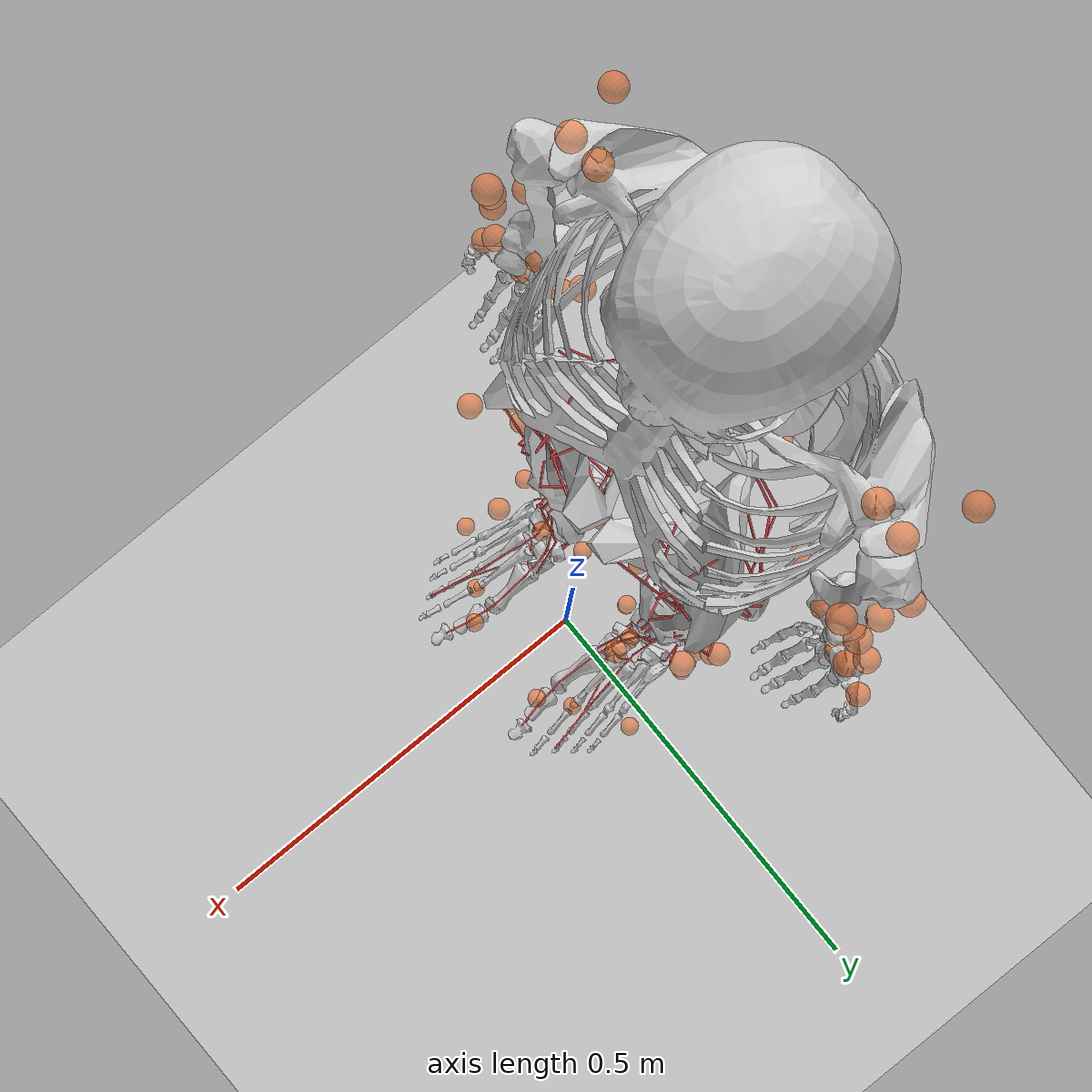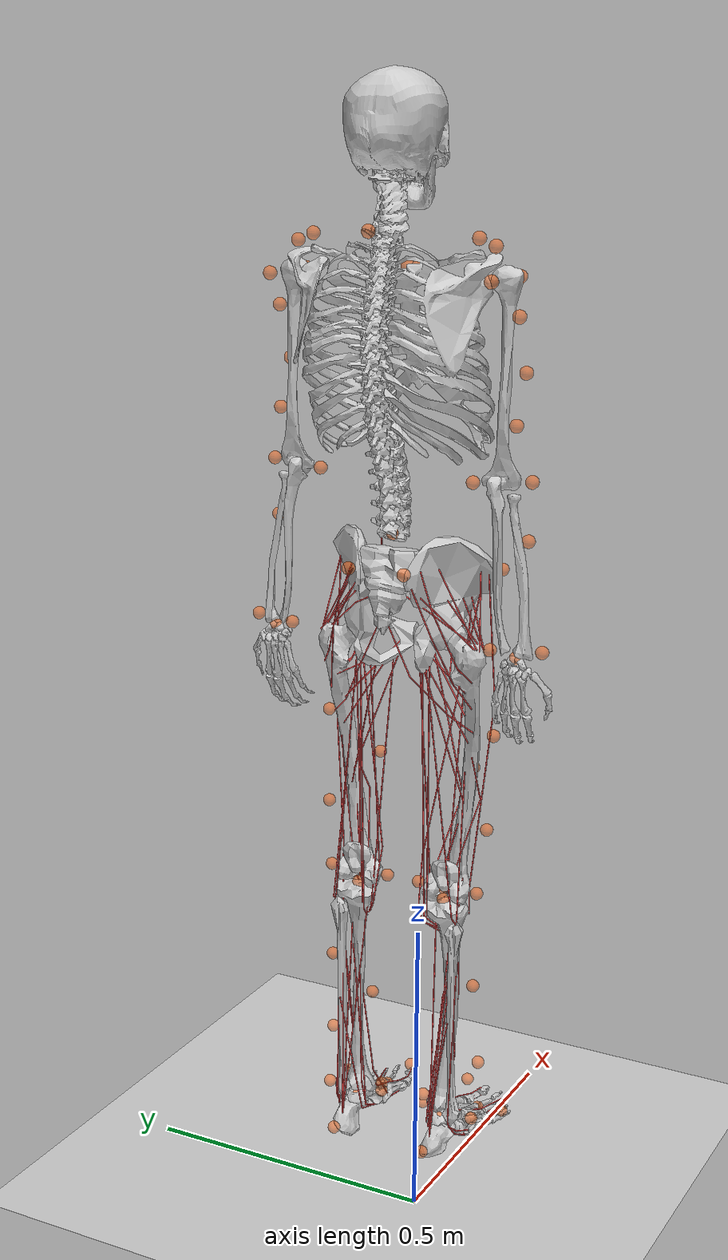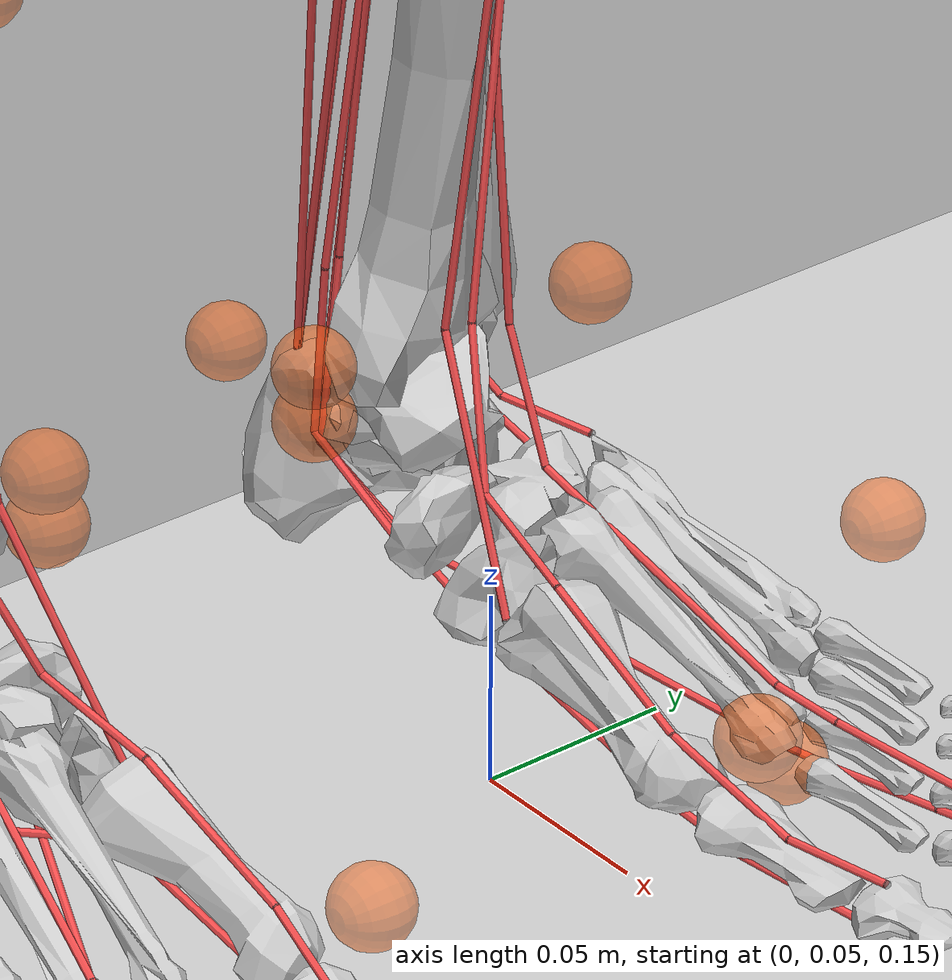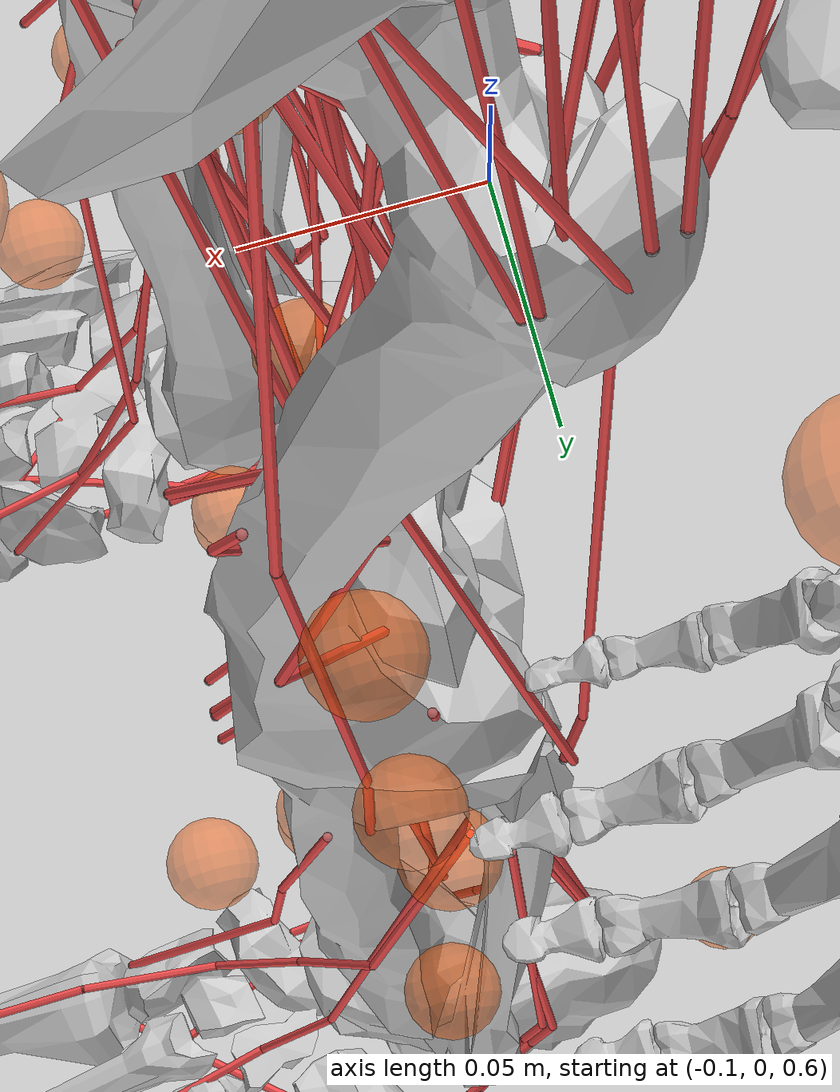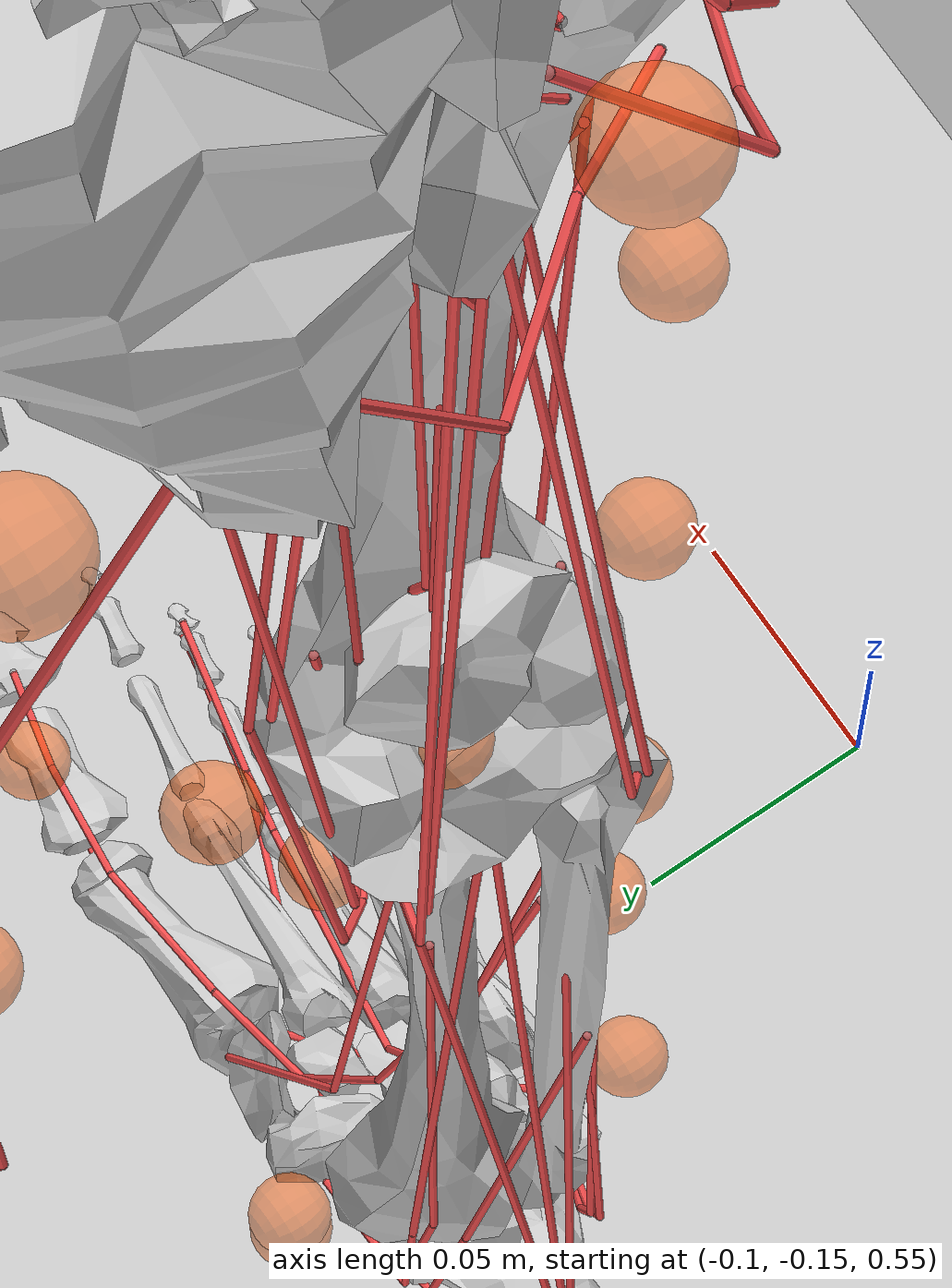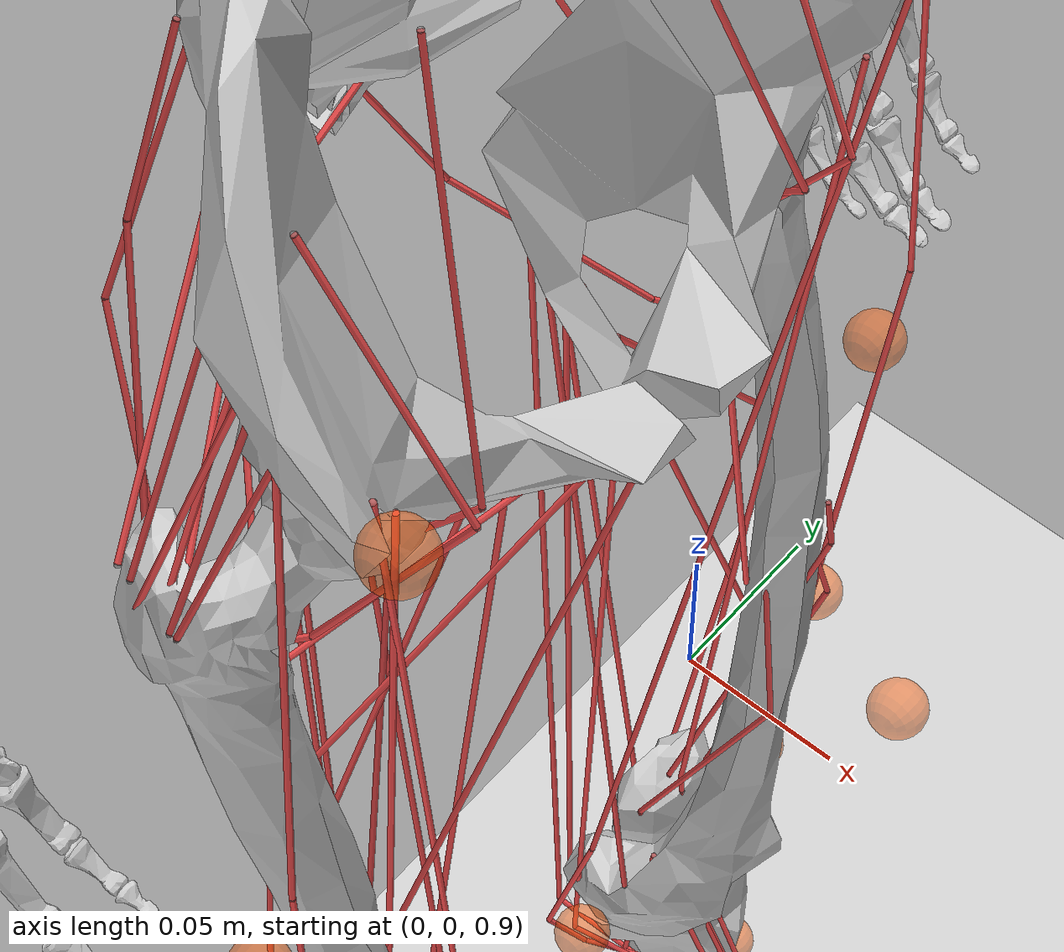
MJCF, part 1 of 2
<?xml version="1.0" encoding="utf-8"?>
<mujoco model="FullBodyModel_MuscleActuatedLowerLimb_TorqueActuatedUpperBody">
  <asset>
    <mesh name="capitate_lvs" vertex="-0.013802999630570412 -0.02690800093114376 0.003992999903857708 -0.01182200014591217 -0.023895999416708946 0.008425000123679638 -0.013660999946296215 -0.025862999260425568 0.004056999925523996 -0.013904999941587448 -0.02604999952018261 0.0027409999165683985 -0.012682000175118446 -0.027713999152183533 0.006819000001996756 -0.010397999547421932 -0.028566999360919 0.006014999933540821 -0.011745000258088112 -0.027668999508023262 0.0024850000627338886 -0.01169699989259243 -0.02626500092446804 -0.0003279999946244061 -0.01202400028705597 -0.02247699908912182 0.0034779999405145645 -0.011909999884665012 -0.027009999379515648 0.009026999585330486 -0.01043500006198883 -0.020082000643014908 0.0074880002066493034 -0.009267999790608883 -0.02270199917256832 0.008322999812662601 -0.013423999771475792 -0.022140000015497208 0.0008800000068731606 -0.012616000138223171 -0.024167999625205994 -0.0009110000100918114 -0.009081000462174416 -0.027998000383377075 0.007584000006318092 -0.005247000139206648 -0.02721400000154972 0.0029279999434947968 -0.004244000185281038 -0.027458999305963516 0.004370999988168478 -0.0034050000831484795 -0.024908000603318214 -0.0032430000137537718 -0.011494000442326069 -0.024013999849557877 -0.00317499996162951 -0.0035570000763982534 -0.022498000413179398 -0.005508000031113625 -0.011637000367045403 -0.019666999578475952 -0.000295000005280599 -0.007323000114411116 -0.01496999990195036 0.006504999939352274 -0.006878000218421221 -0.014403999783098698 0.004275000188499689 -0.00863999966531992 -0.017906999215483665 0.0016749999485909939 -0.004687999840825796 -0.014503000304102898 0.0067449999041855335 -0.0016199999954551458 -0.024553999304771423 0.0038620000705122948 -0.002948000095784664 -0.0164170004427433 0.0069240001030266285 -0.011125000193715096 -0.021379999816417694 -0.0022189998999238014 -0.0022140000946819782 -0.027799999341368675 0.0023980000987648964 0.0007159999804571271 -0.029113000258803368 -0.006302999798208475 0.0007019999902695417 -0.0299529992043972 -0.004556000232696533 -0.010002999566495419 -0.021570999175310135 -0.004732999950647354 -0.0027540000155568123 -0.020648999139666557 -0.0064650001004338264 -0.005615000147372484 -0.019155999645590782 -0.006845999974757433 0.00013800000306218863 -0.027014000341296196 -0.007156999781727791 -0.006393000017851591 -0.015370000153779984 -0.0004830000107176602 -0.006390000227838755 -0.015809999778866768 -0.001281999982893467 -0.003837999887764454 -0.01638299971818924 -0.004267000127583742 -0.007102999836206436 -0.013523000292479992 0.0048340000212192535 -0.00483699981123209 -0.012741000391542912 0.00583800021559 -0.006147000007331371 -0.012992000207304955 -0.0006099999882280827 -0.002894999925047159 -0.009789000265300274 0.005437000188976526 0.0004769999941345304 -0.013368000276386738 0.006868000142276287 0.0014779999619349837 -0.025645999237895012 0.0018729999428614974 0.003186000045388937 -0.014688000082969666 0.0059710000641644 0.0030670000705868006 -0.016721000894904137 0.00496299983933568 0.0013770000077784061 -0.028922999277710915 -0.00039900001138448715 0.00048600000445730984 -0.029865000396966934 -0.0012489999644458294 0.0026549999602138996 -0.02919900044798851 -0.0035180000122636557 0.0026390000712126493 -0.028099000453948975 -0.005934999790042639 -0.0017010000301524997 -0.018797000870108604 -0.007321999873965979 -0.00022499999613501132 -0.021340999752283096 -0.0074280002154409885 -0.004373000003397465 -0.017152000218629837 -0.007763000205159187 0.002701000077649951 -0.020423000678420067 -0.0063240001909434795 0.001680999994277954 -0.02141599915921688 -0.006889999844133854 -0.004951000213623047 -0.014096000231802464 -0.0024470000062137842 -0.003800000064074993 -0.015527999959886074 -0.004280999768525362 -0.003355999942868948 -0.014774000272154808 -0.005632000043988228 -0.007375000044703484 -0.012288999743759632 0.0031010000966489315 -0.006893999874591827 -0.011254999786615372 -0.0015429999912157655 0.002452000044286251 -0.008688000030815601 0.006459000054746866 -0.00016799999866634607 -0.007025000173598528 0.002638000063598156 0.0023930000606924295 -0.010394000448286533 0.007203000131994486 0.004048999864608049 -0.009965999983251095 0.007044999860227108 0.005026999861001968 -0.012240000069141388 0.006566000171005726 0.004406000021845102 -0.019733000546693802 0.002237000036984682 0.004846999887377024 -0.014446999877691269 0.004352999851107597 0.005129000172019005 -0.016008000820875168 0.0012410000199452043 0.005578000098466873 -0.01951799914240837 -0.00018400000408291817 0.004435000009834766 -0.02633100003004074 -0.0033100000582635403 0.0012649999698624015 -0.015035999938845634 -0.008488000370562077 0.002094999887049198 -0.019074000418186188 -0.0073079997673630714 -0.0016629999736323953 -0.013426999561488628 -0.007557999808341265 -0.0026829999405890703 -0.014073999598622322 -0.007180999964475632 -0.0032500000670552254 -0.0139340003952384 -0.006653000134974718 -0.005423999857157469 -0.012075000442564487 -0.00445799995213747 -0.0033360000234097242 -0.013120999559760094 -0.006533000152558088 0.00016199999663513154 -0.006194000132381916 -0.0006960000027902424 -0.0012509999796748161 -0.009224999696016312 -0.005493000149726868 0.004048999864608049 -0.007242999970912933 0.0036639999598264694 0.003329999977722764 -0.005896000191569328 8.600000001024455e-05 0.006672999821603298 -0.010579000227153301 0.0037150001153349876 0.006641999818384647 -0.011714999563992023 0.0033259999472647905 0.006810000166296959 -0.011927000246942043 -0.0035250000655651093 0.005528000183403492 -0.01498399954289198 -0.005417999811470509 0.0009319999953731894 -0.013539999723434448 -0.008326999843120575 0.004650999791920185 -0.011556999757885933 -0.0056859999895095825 -0.0024790000170469284 -0.013306000269949436 -0.0070870001800358295 0.004035999998450279 -0.006438000127673149 -0.0029980000108480453 0.005030000116676092 -0.006711000110954046 -0.0027570000384002924" face="0 1 2 0 2 3 4 1 0 5 0 6 0 5 4 0 7 6 0 3 7 1 8 2 1 4 9 8 1 10 11 1 9 10 1 11 12 2 8 2 12 3 3 12 13 13 7 3 5 9 4 9 5 14 15 5 6 5 15 16 16 14 5 7 15 6 17 15 7 13 18 7 18 19 7 7 19 17 12 8 20 21 8 10 22 8 21 8 22 23 20 8 23 11 9 14 21 10 11 24 21 11 11 14 25 26 24 11 25 26 11 12 20 27 13 12 27 18 13 27 16 25 14 28 16 15 15 17 28 16 28 25 17 19 29 17 29 30 17 30 28 18 27 31 18 31 19 32 19 33 31 33 19 34 19 32 19 34 29 20 23 35 20 35 36 37 27 20 37 20 36 21 38 22 39 38 21 24 39 21 22 35 23 35 22 40 40 22 38 39 24 41 42 41 24 24 26 42 25 43 26 25 28 43 42 26 44 26 45 44 43 45 26 31 27 37 46 43 28 47 46 28 28 30 47 29 48 30 29 49 48 49 29 34 30 48 47 37 33 31 33 50 32 51 32 50 32 51 34 33 37 52 52 50 33 49 34 53 34 54 53 34 51 54 55 35 40 36 35 55 37 36 56 56 36 55 52 37 57 56 57 37 58 40 38 38 39 58 39 41 58 58 59 40 59 55 40 60 61 41 41 61 58 41 62 60 62 41 42 42 63 62 42 64 63 44 64 42 43 46 65 43 65 45 45 66 44 64 44 66 45 65 67 66 45 67 65 46 68 68 46 69 46 48 69 47 48 46 49 69 48 53 69 49 70 50 52 71 50 70 51 50 71 51 71 54 72 52 73 74 52 57 74 73 52 72 70 52 53 67 68 67 53 71 53 68 69 54 71 53 55 59 75 55 75 56 56 76 57 56 75 76 76 74 57 58 61 77 58 77 59 59 77 78 75 59 78 60 79 61 79 60 63 63 60 62 80 77 61 79 80 61 81 63 64 63 81 79 82 64 66 81 64 82 68 67 65 66 67 82 67 83 82 84 67 71 67 84 83 70 72 85 85 86 70 86 84 70 70 84 71 87 72 73 78 85 72 78 72 87 74 87 73 76 87 74 75 78 76 76 78 87 88 77 80 88 78 77 85 78 88 89 80 79 79 81 89 80 89 88 81 83 89 83 81 82 89 83 86 86 83 84 89 86 85 85 88 89" scale="0.85 0.85 0.85"/>
    <mesh name="capitate_rvs" vertex="-0.013660999946296215 -0.025862999260425568 -0.004056999925523996 -0.01182200014591217 -0.023895999416708946 -0.008425000123679638 -0.013802999630570412 -0.02690800093114376 -0.003992999903857708 -0.013904999941587448 -0.02604999952018261 -0.0027409999165683985 -0.01202400028705597 -0.02247699908912182 -0.0034779999405145645 -0.013423999771475792 -0.022140000015497208 -0.0008800000068731606 -0.011909999884665012 -0.027009999379515648 -0.009026999585330486 -0.012682000175118446 -0.027713999152183533 -0.006819000001996756 -0.01043500006198883 -0.020082000643014908 -0.0074880002066493034 -0.009267999790608883 -0.02270199917256832 -0.008322999812662601 -0.011745000258088112 -0.027668999508023262 -0.0024850000627338886 -0.010397999547421932 -0.028566999360919 -0.006014999933540821 -0.01169699989259243 -0.02626500092446804 0.0003279999946244061 -0.012616000138223171 -0.024167999625205994 0.0009110000100918114 -0.011637000367045403 -0.019666999578475952 0.000295000005280599 -0.007323000114411116 -0.01496999990195036 -0.006504999939352274 -0.006878000218421221 -0.014403999783098698 -0.004275000188499689 -0.00863999966531992 -0.017906999215483665 -0.0016749999485909939 -0.011125000193715096 -0.021379999816417694 0.0022189998999238014 -0.009081000462174416 -0.027998000383377075 -0.007584000006318092 -0.004687999840825796 -0.014503000304102898 -0.0067449999041855335 -0.0016199999954551458 -0.024553999304771423 -0.0038620000705122948 -0.002948000095784664 -0.0164170004427433 -0.0069240001030266285 -0.005247000139206648 -0.02721400000154972 -0.0029279999434947968 -0.004244000185281038 -0.027458999305963516 -0.004370999988168478 -0.0034050000831484795 -0.024908000603318214 0.0032430000137537718 -0.011494000442326069 -0.024013999849557877 0.00317499996162951 -0.0035570000763982534 -0.022498000413179398 0.005508000031113625 -0.006393000017851591 -0.015370000153779984 0.0004830000107176602 -0.006390000227838755 -0.015809999778866768 0.001281999982893467 -0.003837999887764454 -0.01638299971818924 0.004267000127583742 -0.007102999836206436 -0.013523000292479992 -0.0048340000212192535 -0.00483699981123209 -0.012741000391542912 -0.00583800021559 -0.006147000007331371 -0.012992000207304955 0.0006099999882280827 -0.010002999566495419 -0.021570999175310135 0.004732999950647354 -0.002894999925047159 -0.009789000265300274 -0.005437000188976526 0.0004769999941345304 -0.013368000276386738 -0.006868000142276287 -0.0022140000946819782 -0.027799999341368675 -0.0023980000987648964 0.0014779999619349837 -0.025645999237895012 -0.0018729999428614974 0.003186000045388937 -0.014688000082969666 -0.0059710000641644 0.0030670000705868006 -0.016721000894904137 -0.00496299983933568 0.0007159999804571271 -0.029113000258803368 0.006302999798208475 0.0007019999902695417 -0.0299529992043972 0.004556000232696533 -0.005615000147372484 -0.019155999645590782 0.006845999974757433 -0.0027540000155568123 -0.020648999139666557 0.0064650001004338264 0.00013800000306218863 -0.027014000341296196 0.007156999781727791 -0.004951000213623047 -0.014096000231802464 0.0024470000062137842 -0.003800000064074993 -0.015527999959886074 0.004280999768525362 -0.004373000003397465 -0.017152000218629837 0.007763000205159187 -0.003355999942868948 -0.014774000272154808 0.005632000043988228 -0.007375000044703484 -0.012288999743759632 -0.0031010000966489315 -0.006893999874591827 -0.011254999786615372 0.0015429999912157655 -0.00016799999866634607 -0.007025000173598528 -0.002638000063598156 0.002452000044286251 -0.008688000030815601 -0.006459000054746866 0.0023930000606924295 -0.010394000448286533 -0.007203000131994486 0.004048999864608049 -0.009965999983251095 -0.007044999860227108 0.005026999861001968 -0.012240000069141388 -0.006566000171005726 0.0013770000077784061 -0.028922999277710915 0.00039900001138448715 0.00048600000445730984 -0.029865000396966934 0.0012489999644458294 0.004406000021845102 -0.019733000546693802 -0.002237000036984682 0.004846999887377024 -0.014446999877691269 -0.004352999851107597 0.005129000172019005 -0.016008000820875168 -0.0012410000199452043 0.0026549999602138996 -0.02919900044798851 0.0035180000122636557 0.0026390000712126493 -0.028099000453948975 0.005934999790042639 -0.0017010000301524997 -0.018797000870108604 0.007321999873965979 -0.00022499999613501132 -0.021340999752283096 0.0074280002154409885 0.002701000077649951 -0.020423000678420067 0.0063240001909434795 0.001680999994277954 -0.02141599915921688 0.006889999844133854 -0.005423999857157469 -0.012075000442564487 0.00445799995213747 -0.0033360000234097242 -0.013120999559760094 0.006533000152558088 -0.0026829999405890703 -0.014073999598622322 0.007180999964475632 -0.0016629999736323953 -0.013426999561488628 0.007557999808341265 -0.0032500000670552254 -0.0139340003952384 0.006653000134974718 0.0012649999698624015 -0.015035999938845634 0.008488000370562077 0.00016199999663513154 -0.006194000132381916 0.0006960000027902424 -0.0012509999796748161 -0.009224999696016312 0.005493000149726868 0.004048999864608049 -0.007242999970912933 -0.0036639999598264694 0.003329999977722764 -0.005896000191569328 -8.600000001024455e-05 0.006672999821603298 -0.010579000227153301 -0.0037150001153349876 0.006641999818384647 -0.011714999563992023 -0.0033259999472647905 0.005578000098466873 -0.01951799914240837 0.00018400000408291817 0.004435000009834766 -0.02633100003004074 0.0033100000582635403 0.006810000166296959 -0.011927000246942043 0.0035250000655651093 0.002094999887049198 -0.019074000418186188 0.0073079997673630714 0.005528000183403492 -0.01498399954289198 0.005417999811470509 -0.0024790000170469284 -0.013306000269949436 0.0070870001800358295 0.0009319999953731894 -0.013539999723434448 0.008326999843120575 0.004650999791920185 -0.011556999757885933 0.0056859999895095825 0.004035999998450279 -0.006438000127673149 0.0029980000108480453 0.005030000116676092 -0.006711000110954046 0.0027570000384002924" face="0 1 2 3 0 2 0 4 1 4 0 5 3 5 0 6 7 1 2 1 7 8 1 4 6 1 9 9 1 8 10 2 11 7 11 2 10 12 2 12 3 2 13 5 3 3 12 13 14 4 5 8 4 15 15 4 16 17 16 4 17 4 14 18 14 5 18 5 13 7 6 11 19 11 6 19 6 9 9 8 15 9 15 20 21 19 9 9 20 22 9 22 21 10 11 23 10 23 12 24 23 11 11 19 24 12 23 25 12 26 13 12 27 26 25 27 12 18 13 26 28 17 14 29 28 14 14 18 30 29 14 30 16 31 15 15 31 32 15 32 20 17 28 16 33 16 28 31 16 33 34 18 26 30 18 34 19 21 24 35 20 32 20 35 36 36 22 20 21 37 24 22 38 21 38 37 21 39 22 36 39 40 22 22 40 38 23 24 37 37 25 23 41 27 25 42 41 25 37 42 25 27 34 26 43 27 44 27 43 34 44 27 45 41 45 27 33 28 46 46 28 29 47 29 30 46 29 47 34 43 30 48 30 43 49 30 48 30 49 47 31 33 50 50 32 31 50 35 32 33 51 50 33 46 51 35 52 53 50 52 35 53 54 35 36 35 54 54 55 36 55 56 36 36 56 39 37 38 57 37 57 58 58 42 37 59 57 38 40 59 38 39 60 40 60 39 56 61 59 40 61 40 60 42 62 41 62 63 41 45 41 63 58 62 42 43 64 48 44 64 43 64 44 65 45 65 44 66 45 63 66 67 45 67 65 45 68 51 46 47 68 46 49 69 47 69 68 47 70 48 71 49 48 72 48 70 72 48 73 71 48 64 73 49 72 69 74 52 50 51 74 50 75 74 51 75 51 68 52 76 53 52 74 77 52 77 76 55 53 76 54 53 55 56 55 78 76 78 55 60 56 79 79 56 78 80 57 59 81 57 80 81 62 57 57 62 58 59 61 80 79 61 60 79 82 61 80 61 66 83 66 61 83 61 84 82 84 61 62 81 63 63 81 66 73 64 83 83 64 65 67 83 65 81 80 66 66 83 67 69 75 68 72 85 69 85 75 69 70 71 85 70 85 72 86 71 73 71 86 75 85 71 75 73 87 86 73 84 87 83 84 73 77 74 88 74 75 88 88 75 86 76 77 89 89 78 76 88 89 77 89 82 78 79 78 82 87 82 89 84 82 87 86 87 89 89 88 86" scale="0.85 0.85 0.85"/>
    <mesh name="hamate_lvs" vertex="0.013152999803423882 -0.02742299996316433 0.011730000376701355 0.011978000402450562 -0.02404800057411194 0.01312899962067604 0.011837000027298927 -0.027605999261140823 0.013919999822974205 0.011281999759376049 -0.030205000191926956 0.013013999909162521 0.012284000404179096 -0.025570999830961227 0.010449999943375587 0.011997000314295292 -0.03145499899983406 0.011629000306129456 0.011636000126600266 -0.028957000002264977 0.009720000438392162 0.009948999620974064 -0.027267999947071075 0.015843000262975693 0.010017000138759613 -0.02456199936568737 0.01609399914741516 0.009850000031292439 -0.02302899956703186 0.01522700022906065 0.009619000367820263 -0.02644599974155426 0.01075000036507845 0.007890000008046627 -0.023343000560998917 0.012943999841809273 0.010572999715805054 -0.03280600160360336 0.01293100044131279 0.008639000356197357 -0.03278300166130066 0.01361900009214878 0.010123999789357185 -0.03179699927568436 0.010261000134050846 0.009014000184834003 -0.03356799855828285 0.011509999632835388 0.0066709998063743114 -0.029147999361157417 0.01092899963259697 0.007087999954819679 -0.024188999086618423 0.017410999163985252 0.0036170000676065683 -0.027264999225735664 0.017142999917268753 0.006624999921768904 -0.03206200152635574 0.014171999879181385 0.0060339998453855515 -0.029231000691652298 0.015393000096082687 0.008496999740600586 -0.022631000727415085 0.015673000365495682 0.005890999920666218 -0.025422999635338783 0.011700999923050404 0.006539999973028898 -0.022766999900341034 0.013387000188231468 0.008066999725997448 -0.03357499837875366 0.01153200026601553 0.009042000398039818 -0.031902000308036804 0.010797999799251556 0.004887999966740608 -0.028300000354647636 0.01089600007981062 0.005317999981343746 -0.03150099888443947 0.011535000056028366 0.003942999988794327 -0.02418600022792816 0.01810700073838234 0.004383999854326248 -0.029844999313354492 0.01457899995148182 0.000901999999769032 -0.025326000526547432 0.02112000063061714 0.0025110000278800726 -0.027977000921964645 0.0156230004504323 -0.0010779999429360032 -0.027651000767946243 0.019175000488758087 0.004162000026553869 -0.02131200022995472 0.014654000289738178 0.004302999936044216 -0.021890999749302864 0.01628899946808815 0.003312000073492527 -0.023886000737547874 0.011315999552607536 0.0026499999221414328 -0.02659600041806698 0.010143999941647053 0.0024530000519007444 -0.0203000009059906 0.012426000088453293 0.0021039999555796385 -0.028192000463604927 0.010041999630630016 0.00101500004529953 -0.027758000418543816 0.01297600008547306 0.003000000026077032 -0.02180599980056286 0.01691100001335144 -0.0015180000336840749 -0.02539600059390068 0.02281700074672699 -0.001988000003620982 -0.023669999092817307 0.022216999903321266 -0.000881000014487654 -0.01729400083422661 0.016902999952435493 -0.0040779998525977135 -0.026030000299215317 0.023303000256419182 -0.006513999775052071 -0.02666899934411049 0.02293499931693077 -0.011246999725699425 -0.02751000039279461 0.010638000443577766 -0.0008960000122897327 -0.02733900025486946 0.007023000158369541 -0.009483999572694302 -0.028542999178171158 0.018376000225543976 -0.008255000226199627 -0.028630999848246574 0.020302999764680862 0.0018269999418407679 -0.019355999305844307 0.014453000389039516 0.0018629999831318855 -0.022640999406576157 0.01002500019967556 0.0008609999786131084 -0.02794799953699112 0.00865199975669384 0.0016039999900385737 -0.017381999641656876 0.00875800009816885 0.0018579999450594187 -0.020304000005126 0.00811500009149313 0.0017130000051110983 -0.012776999734342098 0.010929999873042107 0.00020599999697878957 -0.027816999703645706 0.007410999853163958 -0.005547000095248222 -0.023300999775528908 0.023691000416874886 -0.008251000195741653 -0.01895200088620186 0.020509999245405197 -0.00228299992159009 -0.014538000337779522 0.015062999911606312 0.00028899998869746923 -0.011602000333368778 0.01346299983561039 -0.009138000197708607 -0.026921000331640244 0.01986199989914894 -0.011885000392794609 -0.02371699921786785 0.011428999714553356 -0.011575000360608101 -0.027396000921726227 0.012938999570906162 0.0008069999748840928 -0.019773999229073524 0.006672999821603298 0.0006440000142902136 -0.025299999862909317 0.007462000008672476 0.0013119999784976244 -0.015350000001490116 0.007530999835580587 0.0008319999906234443 -0.009278999641537666 0.009405000135302544 -0.007794999983161688 -0.02239600010216236 0.020671000704169273 -0.01028900034725666 -0.015154000371694565 0.014140999875962734 -0.010649999603629112 -0.016770999878644943 0.012496000155806541 -0.002125999890267849 -0.012807999737560749 0.013179999776184559 -0.011227999813854694 -0.015131999738514423 0.009572000242769718 -0.009902999736368656 -0.013983000069856644 0.009046999737620354 -0.0017040000529959798 -0.010812999680638313 0.008542000316083431 -0.010058999992907047 -0.014240000396966934 0.012035000137984753" face="0 1 2 0 2 3 0 4 1 0 3 5 4 0 6 5 6 0 1 7 2 1 8 7 9 8 1 4 10 1 10 11 1 1 11 9 2 7 3 3 12 5 13 3 7 3 13 12 6 10 4 6 5 14 15 5 12 5 15 14 10 6 16 16 6 14 7 8 17 18 7 17 19 13 7 19 7 20 20 7 18 9 17 8 17 9 21 11 21 9 22 10 16 10 22 11 23 21 11 11 22 23 12 13 15 15 13 24 19 24 13 25 16 14 15 25 14 24 25 15 22 16 26 24 16 25 16 27 26 16 24 27 28 18 17 28 17 21 18 29 20 18 28 30 31 29 18 18 30 32 31 18 32 24 19 27 27 19 29 20 29 19 21 23 33 21 33 34 28 21 34 23 22 35 36 35 22 36 22 26 23 35 37 37 33 23 38 26 27 26 38 36 39 27 29 27 39 38 40 28 34 40 30 28 39 29 31 41 30 42 41 32 30 42 30 43 40 43 30 39 31 32 32 44 45 46 47 32 48 32 49 45 49 32 32 48 46 32 41 44 39 32 47 34 33 50 33 37 50 40 34 50 51 35 36 37 35 51 36 52 51 52 36 38 53 37 54 54 37 51 37 55 50 55 37 53 52 38 39 56 52 39 47 56 39 43 40 50 42 44 41 44 42 57 43 57 42 58 43 59 58 57 43 60 59 43 60 43 50 44 57 45 45 61 49 45 57 61 46 62 47 46 63 62 63 46 48 47 62 64 47 65 56 64 65 47 61 48 49 62 63 48 61 62 48 50 55 60 51 52 54 65 52 56 52 65 54 54 64 53 53 64 66 53 66 55 65 64 54 55 66 67 55 67 60 61 57 68 58 68 57 59 69 58 62 68 58 69 70 58 58 70 62 71 59 60 71 69 59 67 71 60 62 61 68 64 62 66 62 70 72 66 62 73 72 73 62 74 66 73 74 67 66 74 71 67 71 74 69 69 74 75 75 70 69 70 75 72 72 75 73 73 75 74" scale="0.85 0.85 0.85"/>
    <mesh name="hamate_rvs" vertex="0.011837000027298927 -0.027605999261140823 -0.013919999822974205 0.011978000402450562 -0.02404800057411194 -0.01312899962067604 0.013152999803423882 -0.02742299996316433 -0.011730000376701355 0.011281999759376049 -0.030205000191926956 -0.013013999909162521 0.009948999620974064 -0.027267999947071075 -0.015843000262975693 0.010017000138759613 -0.02456199936568737 -0.01609399914741516 0.009850000031292439 -0.02302899956703186 -0.01522700022906065 0.012284000404179096 -0.025570999830961227 -0.010449999943375587 0.009619000367820263 -0.02644599974155426 -0.01075000036507845 0.007890000008046627 -0.023343000560998917 -0.012943999841809273 0.011997000314295292 -0.03145499899983406 -0.011629000306129456 0.011636000126600266 -0.028957000002264977 -0.009720000438392162 0.010572999715805054 -0.03280600160360336 -0.01293100044131279 0.008639000356197357 -0.03278300166130066 -0.01361900009214878 0.007087999954819679 -0.024188999086618423 -0.017410999163985252 0.0036170000676065683 -0.027264999225735664 -0.017142999917268753 0.006624999921768904 -0.03206200152635574 -0.014171999879181385 0.0060339998453855515 -0.029231000691652298 -0.015393000096082687 0.008496999740600586 -0.022631000727415085 -0.015673000365495682 0.0066709998063743114 -0.029147999361157417 -0.01092899963259697 0.005890999920666218 -0.025422999635338783 -0.011700999923050404 0.006539999973028898 -0.022766999900341034 -0.013387000188231468 0.010123999789357185 -0.03179699927568436 -0.010261000134050846 0.009014000184834003 -0.03356799855828285 -0.011509999632835388 0.008066999725997448 -0.03357499837875366 -0.01153200026601553 0.003942999988794327 -0.02418600022792816 -0.01810700073838234 0.004383999854326248 -0.029844999313354492 -0.01457899995148182 0.000901999999769032 -0.025326000526547432 -0.02112000063061714 0.0025110000278800726 -0.027977000921964645 -0.0156230004504323 -0.0010779999429360032 -0.027651000767946243 -0.019175000488758087 0.005317999981343746 -0.03150099888443947 -0.011535000056028366 0.004162000026553869 -0.02131200022995472 -0.014654000289738178 0.004302999936044216 -0.021890999749302864 -0.01628899946808815 0.004887999966740608 -0.028300000354647636 -0.01089600007981062 0.009042000398039818 -0.031902000308036804 -0.010797999799251556 0.003312000073492527 -0.023886000737547874 -0.011315999552607536 0.0026499999221414328 -0.02659600041806698 -0.010143999941647053 0.0024530000519007444 -0.0203000009059906 -0.012426000088453293 0.003000000026077032 -0.02180599980056286 -0.01691100001335144 0.00101500004529953 -0.027758000418543816 -0.01297600008547306 -0.001988000003620982 -0.023669999092817307 -0.022216999903321266 -0.0015180000336840749 -0.02539600059390068 -0.02281700074672699 -0.000881000014487654 -0.01729400083422661 -0.016902999952435493 -0.006513999775052071 -0.02666899934411049 -0.02293499931693077 -0.0040779998525977135 -0.026030000299215317 -0.023303000256419182 -0.0008960000122897327 -0.02733900025486946 -0.007023000158369541 -0.011246999725699425 -0.02751000039279461 -0.010638000443577766 -0.008255000226199627 -0.028630999848246574 -0.020302999764680862 -0.009483999572694302 -0.028542999178171158 -0.018376000225543976 0.0021039999555796385 -0.028192000463604927 -0.010041999630630016 0.0018269999418407679 -0.019355999305844307 -0.014453000389039516 0.0018629999831318855 -0.022640999406576157 -0.01002500019967556 0.0008609999786131084 -0.02794799953699112 -0.00865199975669384 0.0018579999450594187 -0.020304000005126 -0.00811500009149313 0.0016039999900385737 -0.017381999641656876 -0.00875800009816885 0.0017130000051110983 -0.012776999734342098 -0.010929999873042107 0.00020599999697878957 -0.027816999703645706 -0.007410999853163958 -0.005547000095248222 -0.023300999775528908 -0.023691000416874886 -0.00228299992159009 -0.014538000337779522 -0.015062999911606312 -0.008251000195741653 -0.01895200088620186 -0.020509999245405197 0.00028899998869746923 -0.011602000333368778 -0.01346299983561039 -0.009138000197708607 -0.026921000331640244 -0.01986199989914894 0.0008069999748840928 -0.019773999229073524 -0.006672999821603298 -0.011885000392794609 -0.02371699921786785 -0.011428999714553356 0.0006440000142902136 -0.025299999862909317 -0.007462000008672476 -0.011575000360608101 -0.027396000921726227 -0.012938999570906162 0.0013119999784976244 -0.015350000001490116 -0.007530999835580587 0.0008319999906234443 -0.009278999641537666 -0.009405000135302544 -0.007794999983161688 -0.02239600010216236 -0.020671000704169273 -0.002125999890267849 -0.012807999737560749 -0.013179999776184559 -0.01028900034725666 -0.015154000371694565 -0.014140999875962734 -0.010649999603629112 -0.016770999878644943 -0.012496000155806541 -0.011227999813854694 -0.015131999738514423 -0.009572000242769718 -0.009902999736368656 -0.013983000069856644 -0.009046999737620354 -0.0017040000529959798 -0.010812999680638313 -0.008542000316083431 -0.010058999992907047 -0.014240000396966934 -0.012035000137984753" face="0 1 2 3 0 2 0 4 1 3 4 0 4 5 1 1 5 6 1 7 2 1 8 7 1 9 8 6 9 1 10 3 2 11 2 7 2 11 10 10 12 3 4 3 13 12 13 3 14 5 4 14 4 15 4 13 16 17 4 16 15 4 17 5 14 6 18 6 14 6 18 9 7 8 11 19 8 20 19 11 8 9 20 8 9 18 21 21 20 9 22 10 11 12 10 23 22 23 10 22 11 19 23 13 12 24 13 23 13 24 16 14 15 25 18 14 25 17 26 15 27 25 15 15 26 28 29 27 15 29 15 28 30 16 24 26 16 30 16 26 17 31 21 18 32 31 18 32 18 25 33 19 20 22 19 34 34 19 24 33 30 19 30 24 19 35 20 21 20 35 36 33 20 36 37 35 21 21 31 37 22 34 23 23 34 24 32 25 38 25 27 38 28 26 39 26 30 39 40 27 41 27 29 41 42 27 40 27 42 38 29 28 39 43 44 29 29 45 46 47 29 48 29 47 43 46 48 29 44 41 29 45 29 39 30 33 49 49 39 30 50 31 32 50 37 31 50 32 38 36 49 33 36 35 51 51 35 37 51 52 36 49 36 52 53 37 54 51 37 53 50 55 37 54 37 55 50 38 42 39 52 56 39 56 45 39 49 52 41 44 40 57 40 44 40 57 42 58 42 59 42 57 59 42 58 60 50 42 60 47 61 43 61 57 43 43 57 44 62 63 45 56 64 45 45 64 62 45 63 46 63 65 46 48 46 65 47 48 61 48 65 63 48 63 61 60 55 50 53 52 51 56 52 64 53 64 52 53 62 64 54 62 53 66 62 54 55 66 54 67 66 55 60 67 55 68 57 61 57 68 59 60 58 69 58 70 69 59 70 58 59 68 63 59 71 70 63 71 59 60 69 67 68 61 63 66 63 62 72 71 63 73 63 66 63 73 72 73 66 74 66 67 74 67 69 74 70 74 69 75 74 70 70 71 75 72 75 71 73 75 72 74 75 73" scale="0.85 0.85 0.85"/>
    <mesh name="hat_jaw" vertex="0.07810500264167786 0.48430201411247253 -0.0002229999954579398 0.07795699685811996 0.48571398854255676 -0.00014899999951012433 0.07786600291728973 0.486286997795105 0.00046999999904073775 0.07783699780702591 0.48496100306510925 0.00046999999904073775 0.07845800369977951 0.4835900068283081 -0.000965000013820827 0.07884600013494492 0.48473799228668213 -0.001626000041142106 0.07690200209617615 0.4822160005569458 0.00046999999904073775 0.07375100255012512 0.48074600100517273 -5.500000042957254e-05 0.08081699907779694 0.4882580041885376 -0.0005699999746866524 0.07914099842309952 0.4894999861717224 0.00046999999904073775 0.08091100305318832 0.48894500732421875 -0.0023350000847131014 0.07795699685811996 0.48571398854255676 0.0010489999549463391 0.07810500264167786 0.48430201411247253 0.0011230000527575612 0.08081699907779694 0.4882580041885376 0.0014700000174343586 0.07375100255012512 0.48074600100517273 0.0009549999958835542 0.07875800132751465 0.4842430055141449 -0.0027550000231713057 0.078404001891613 0.4857580065727234 -0.0026569999754428864 0.07725399732589722 0.4809669852256775 -0.0020699999295175076 0.07724300026893616 0.48204898834228516 -0.0038109999150037766 0.07200100272893906 0.47558799386024475 -0.0006699999794363976 0.07170899957418442 0.4765790104866028 0.00046999999904073775 0.07200100272893906 0.47558799386024475 0.0015699999639764428 0.07189899682998657 0.4759179949760437 -0.0028780000284314156 0.08206800371408463 0.4947640001773834 -0.0001720000000204891 0.08191599696874619 0.4945389926433563 0.0004710000066552311 0.08206699788570404 0.4942750036716461 -0.0024300001095980406 0.08206800371408463 0.4947640001773834 0.0010720000136643648 0.07796899974346161 0.487311989068985 -0.003438000101596117 0.08007699996232986 0.49175500869750977 -0.0034620000515133142 0.08029299974441528 0.49434301257133484 -0.003145999973639846 0.07884600013494492 0.48473799228668213 0.0025259999092668295 0.07845800369977951 0.4835900068283081 0.0018649999983608723 0.08091100305318832 0.48894500732421875 0.003234999952837825 0.08206699788570404 0.4942750036716461 0.003329999977722764 0.07725399732589722 0.4809669852256775 0.0029700000304728746 0.07189899682998657 0.4759179949760437 0.003777999896556139 0.07790499925613403 0.4849280118942261 -0.003978999797254801 0.07164900004863739 0.4771580100059509 -0.0036830001045018435 0.07337799668312073 0.47878700494766235 -0.004788000136613846 0.07700899988412857 0.4813520014286041 -0.005382999777793884 0.07844600081443787 0.4841339886188507 -0.004964000079780817 0.0731009989976883 0.47056999802589417 0.00046999999904073775 0.07293800264596939 0.4712269902229309 -0.002369999885559082 0.07293800264596939 0.4712269902229309 0.003269999986514449 0.07228799909353256 0.4716329872608185 -0.006072999909520149 0.08078800141811371 0.49484899640083313 -0.0009369999752379954 0.0807270035147667 0.49463701248168945 -0.002727000042796135 0.08123300224542618 0.494159996509552 0.0004710000066552311 0.08078800141811371 0.49484899640083313 0.0018370000179857016 0.0810609981417656 0.4941610097885132 0.0002859999949578196 0.0807270035147667 0.49463701248168945 0.0036269999109208584 0.07838699966669083 0.48630398511886597 -0.004639999940991402 0.07995100319385529 0.4891369938850403 -0.004914000164717436 0.0799190029501915 0.4954800009727478 -0.004393999930471182 0.07890599966049194 0.4913119971752167 -0.003364000003784895 0.07969799637794495 0.4922510087490082 -0.0020910000894218683 0.07833199948072433 0.49302801489830017 -0.00434499979019165 0.078404001891613 0.4857580065727234 0.0035570000763982534 0.07875800132751465 0.4842430055141449 0.003654999891296029 0.07724300026893616 0.48204898834228516 0.0047109997831285 0.08007699996232986 0.49175500869750977 0.004362000152468681 0.07796899974346161 0.487311989068985 0.0043379999697208405 0.08029299974441528 0.49434301257133484 0.004046000074595213 0.07164900004863739 0.4771580100059509 0.0045830002054572105 0.07228799909353256 0.4716329872608185 0.006972999777644873 0.07153499871492386 0.4761529862880707 -0.005504999775439501 0.07855600118637085 0.4843440055847168 -0.0067529999651014805 0.07674100250005722 0.4812209904193878 -0.007147999946027994 0.07143600285053253 0.4764919877052307 -0.007714000064879656 0.07159099727869034 0.47611701488494873 -0.006852000020444393 0.07853800058364868 0.48542800545692444 -0.006486999802291393 0.07343199849128723 0.46810099482536316 -0.003324999939650297 0.07389400154352188 0.46786901354789734 0.00046999999904073775 0.07343199849128723 0.46810099482536316 0.004224999807775021 0.07227300107479095 0.46860599517822266 -0.007153999991714954 0.07227300107479095 0.46860599517822266 0.008054000325500965 0.07090699672698975 0.46925199031829834 -0.010816999711096287 0.07120700180530548 0.4725320041179657 -0.00954699981957674 0.08014100044965744 0.49172601103782654 0.00046999999904073775 0.08000700175762177 0.49178600311279297 -9.999999747378752e-05 0.07969799637794495 0.4922510087490082 0.0029909999575465918 0.08000700175762177 0.49178600311279297 0.0010000000474974513 0.07890599966049194 0.4913119971752167 0.004263999871909618 0.0799039974808693 0.4889180064201355 -0.0064860000275075436 0.08039499819278717 0.492590993642807 -0.005919999908655882 0.07994499802589417 0.49595698714256287 -0.005942000076174736 0.07659900188446045 0.48772498965263367 -0.00395999988541007 0.07632499933242798 0.49149298667907715 -0.005109999794512987 0.07429099828004837 0.48805299401283264 -0.005950000137090683 0.07755500078201294 0.49070098996162415 -0.002136999974027276 0.07607900351285934 0.4874440133571625 -0.0032420000061392784 0.07871100306510925 0.49164000153541565 -0.002211000071838498 0.07750999927520752 0.4936459958553314 -0.007368000224232674 0.07604199647903442 0.4918699860572815 -0.006850999779999256 0.07924699783325195 0.4957819879055023 -0.0069969999603927135 0.07790499925613403 0.4849280118942261 0.0048790001310408115 0.07700899988412857 0.4813520014286041 0.006283000111579895 0.07337799668312073 0.47878700494766235 0.005688000004738569 0.07844600081443787 0.4841339886188507 0.0058639999479055405 0.07995100319385529 0.4891369938850403 0.005814000032842159 0.07838699966669083 0.48630398511886597 0.005539999809116125 0.0799190029501915 0.4954800009727478 0.005293999798595905 0.07833199948072433 0.49302801489830017 0.005245000123977661 0.07120700180530548 0.4725320041179657 0.010447000153362751 0.07090699672698975 0.46925199031829834 0.011717000044882298 0.07159099727869034 0.47611701488494873 0.007751999888569117 0.07153499871492386 0.4761529862880707 0.0064050001092255116 0.07143600285053253 0.4764919877052307 0.00861399993300438 0.07799699902534485 0.48408201336860657 -0.00849399995058775 0.07795900106430054 0.48624199628829956 -0.007952000014483929 0.07621099799871445 0.48174700140953064 -0.009308000095188618 0.07083600014448166 0.4768790006637573 -0.00940600037574768 0.07916899770498276 0.48875901103019714 -0.007977000437676907 0.07367800176143646 0.4658139944076538 -0.0033100000582635403 0.0742110013961792 0.4657280147075653 0.0004710000066552311 0.07253500074148178 0.4660489857196808 -0.007094999775290489 0.07367800176143646 0.4658139944076538 0.004209999926388264 0.07253500074148178 0.4660489857196808 0.0079950001090765 0.07104700058698654 0.4664520025253296 -0.010711999610066414 0.07104700058698654 0.4664520025253296 0.011611999943852425 0.06814199686050415 0.4698280096054077 -0.014516999945044518 0.06859099864959717 0.47291600704193115 -0.013003000058233738 0.06855099648237228 0.46733200550079346 -0.013999000191688538 0.07052499800920486 0.4762769937515259 -0.010727000422775745 0.06993799656629562 0.47611701488494873 -0.012443000450730324 0.07724399864673615 0.4868679940700531 0.00046999999904073775 0.07663200050592422 0.4894079864025116 -0.0009850000496953726 0.07502300292253494 0.48662498593330383 -0.0011620000004768372 0.07812199741601944 0.49093499779701233 -0.0003969999961555004 0.07502300292253494 0.48662498593330383 0.0020620001014322042 0.07663200050592422 0.4894079864025116 0.0018850000342354178 0.07812199741601944 0.49093499779701233 0.0012969999806955457 0.07871100306510925 0.49164000153541565 0.0031109999399632215 0.07755500078201294 0.49070098996162415 0.003037000074982643 0.07429099828004837 0.48805299401283264 0.006850000005215406 0.07632499933242798 0.49149298667907715 0.006010000128298998 0.07659900188446045 0.48772498965263367 0.004860000219196081 0.07607900351285934 0.4874440133571625 0.004141999874264002 0.07970400154590607 0.4931409955024719 -0.007612000219523907 0.07429999858140945 0.4856429994106293 -0.0038139999378472567 0.07358700037002563 0.48625901341438293 -0.005723999813199043 0.07433400303125381 0.4880320131778717 -0.007513000164180994 0.07268600165843964 0.4864409863948822 -0.007641000207513571 0.07393400371074677 0.48528599739074707 -0.00356299988925457 0.07393600046634674 0.4852850139141083 -0.0015569999814033508 0.07581499963998795 0.4917230010032654 -0.008182000368833542 0.07803799957036972 0.4946269989013672 -0.008713999763131142 0.07866299897432327 0.4943470060825348 -0.008569999597966671 0.07461000233888626 0.4889709949493408 -0.008399000391364098 0.07674100250005722 0.4812209904193878 0.008047999814152718 0.07855600118637085 0.4843440055847168 0.007652999833226204 0.07853800058364868 0.48542800545692444 0.007387000136077404 0.0799039974808693 0.4889180064201355 0.007385999895632267 0.08039499819278717 0.492590993642807 0.006819999776780605 0.07994499802589417 0.49595698714256287 0.0068419999442994595 0.07604199647903442 0.4918699860572815 0.007751000113785267 0.07750999927520752 0.4936459958553314 0.00826799962669611 0.07924699783325195 0.4957819879055023 0.007896999828517437 0.07003200054168701 0.47291600704193115 0.013903000392019749 0.069582998752594 0.4698280096054077 0.015417000278830528 0.07083600014448166 0.4768790006637573 0.010305999778211117 0.07052499800920486 0.4762769937515259 0.011626999825239182 0.06993799656629562 0.47611701488494873 0.01334299985319376 0.06999299675226212 0.46733200550079346 0.014898999594151974 0.07621099799871445 0.48174700140953064 0.010208000428974628 0.07768499851226807 0.48477399349212646 -0.009332000277936459 0.07709699869155884 0.4880070090293884 -0.008910000324249268 0.07716800272464752 0.4842279851436615 -0.011757999658584595 0.0772159993648529 0.484468013048172 -0.010185999795794487 0.0720290020108223 0.48082199692726135 -0.011048000305891037 0.07835599780082703 0.4920490086078644 -0.00864300038665533 0.07328200340270996 0.4624829888343811 -0.003930999897420406 0.07335100322961807 0.46351200342178345 0.0004710000066552311 0.07255999743938446 0.4626530110836029 -0.008210999891161919 0.07328200340270996 0.4624829888343811 0.004831000231206417 0.07087299972772598 0.4621819853782654 -0.01183400023728609 0.07255999743938446 0.4626530110836029 0.00911100022494793 0.07087299972772598 0.4621819853782654 0.012733999639749527 0.06880100071430206 0.46446898579597473 -0.014852000400424004 0.06880100071430206 0.46446898579597473 0.015752000734210014 0.06682799756526947 0.47203999757766724 -0.018302999436855316 0.06717800348997116 0.4732219874858856 -0.01650799997150898 0.06695599853992462 0.46874499320983887 -0.017333000898361206 0.06880699843168259 0.47684600949287415 -0.01494900044053793 0.0664839968085289 0.46585699915885925 -0.017757000401616096 0.0715389996767044 0.4805470108985901 -0.012346000410616398 0.07076500356197357 0.4806709885597229 -0.013376999646425247 0.07411500066518784 0.48519599437713623 0.0004689999914262444 0.07393600046634674 0.4852850139141083 0.002457000082358718 0.07393400371074677 0.48528599739074707 0.004463000223040581 0.07268600165843964 0.4864409863948822 0.008541000075638294 0.07433400303125381 0.4880320131778717 0.008413000032305717 0.07358700037002563 0.48625901341438293 0.006624000146985054 0.07429999858140945 0.4856429994106293 0.004714000038802624 0.07108700275421143 0.48409000039100647 -0.006415999960154295 0.07187999784946442 0.48299500346183777 -0.0032500000670552254 0.07224400341510773 0.4866589903831482 -0.008035999722778797 0.07203400135040283 0.48194101452827454 0.00046800001291558146 0.07427100092172623 0.49192699790000916 -0.009575000032782555 0.07263199985027313 0.4886089861392975 -0.009332999587059021 0.07643800228834152 0.4938789904117584 -0.00903599988669157 0.0781330019235611 0.4967710077762604 -0.009743999689817429 0.07919900119304657 0.4943459928035736 -0.010191000066697598 0.07853499799966812 0.4958620071411133 -0.011172999627888203 0.07213299721479416 0.4867140054702759 -0.009139999747276306 0.07799699902534485 0.48408201336860657 0.00939400028437376 0.07795900106430054 0.48624199628829956 0.00885200034826994 0.07916899770498276 0.48875901103019714 0.008876999840140343 0.07970400154590607 0.4931409955024719 0.008511999621987343 0.07461000233888626 0.4889709949493408 0.009298999793827534 0.07581499963998795 0.4917230010032654 0.009081999771296978 0.07803799957036972 0.4946269989013672 0.009614000096917152 0.07866299897432327 0.4943470060825348 0.009469999931752682 0.06861899793148041 0.4732219874858856 0.01740800030529499 0.0682699978351593 0.47203999757766724 0.019202999770641327 0.06880699843168259 0.47684600949287415 0.015848999843001366 0.06839799880981445 0.46874499320983887 0.018232999369502068 0.0720290020108223 0.48082199692726135 0.011947999708354473 0.0715389996767044 0.4805470108985901 0.013245999813079834 0.07076500356197357 0.4806709885597229 0.014276999980211258 0.06792599707841873 0.46585699915885925 0.018657000735402107 0.0772159993648529 0.484468013048172 0.011086000129580498 0.07716800272464752 0.4842279851436615 0.012657999992370605 0.07768499851226807 0.48477399349212646 0.010231999680399895 0.07704400271177292 0.48642998933792114 -0.010088000446557999 0.07915599644184113 0.4904719889163971 -0.010362000204622746 0.07708700001239777 0.48587098717689514 -0.01191100012511015 0.07567299902439117 0.4849669933319092 -0.014480999670922756 0.07567399740219116 0.4860309958457947 -0.013996999710798264 0.07256200164556503 0.4601840078830719 -0.004106000065803528 0.0722310021519661 0.4601590037345886 0.00046999999904073775 0.07163800299167633 0.459553986787796 -0.008735000155866146 0.07256200164556503 0.4601840078830719 0.005005999933928251 0.06974200159311295 0.45991501212120056 -0.012721999548375607 0.07163800299167633 0.459553986787796 0.009634999558329582 0.0669730007648468 0.46086201071739197 -0.01581599935889244 0.06974200159311295 0.45991501212120056 0.013621999882161617 0.0669730007648468 0.46086201071739197 0.01671599969267845 0.06443099677562714 0.4622569978237152 -0.019000999629497528 0.06443099677562714 0.4622569978237152 0.01990099996328354 0.06497099995613098 0.4708079993724823 -0.019957000389695168 0.06398600339889526 0.47294101119041443 -0.018804000690579414 0.06541699916124344 0.4744980037212372 -0.019303999841213226 0.06714200228452682 0.48065900802612305 -0.0181450005620718 0.06407400220632553 0.4670020043849945 -0.020586999133229256 0.07304999977350235 0.48224300146102905 -0.014778000302612782 0.07177600264549255 0.48367398977279663 -0.015937000513076782 0.06190900132060051 0.4645099937915802 -0.021841999143362045 0.07187999784946442 0.48299500346183777 0.004149999935179949 0.07108700275421143 0.48409000039100647 0.007315999828279018 0.07224400341510773 0.4866589903831482 0.008936000056564808 0.061625998467206955 0.4729419946670532 -0.007474999874830246 0.0620729997754097 0.4704959988594055 -0.004544000141322613 0.06969399750232697 0.4851909875869751 -0.009417999535799026 0.061163000762462616 0.4761979877948761 -0.009998000226914883 0.06185299903154373 0.469897985458374 0.0004659999976865947 0.0620729997754097 0.4704959988594055 0.005444000009447336 0.07258400321006775 0.4919559955596924 -0.01141900010406971 0.07173900306224823 0.4887869954109192 -0.011250999756157398 0.07388299703598022 0.49453699588775635 -0.012330000288784504 0.07064799964427948 0.4871729910373688 -0.010758000425994396 0.07760100066661835 0.4974989891052246 -0.010774999856948853 0.07688000053167343 0.49733400344848633 -0.01205699983984232 0.07920099794864655 0.49142101407051086 -0.011442000046372414 0.07763800024986267 0.4965049922466278 -0.012839999981224537 0.07709699869155884 0.4880070090293884 0.009809999726712704 0.07835599780082703 0.4920490086078644 0.009542999789118767 0.07213299721479416 0.4867140054702759 0.010040000081062317 0.07263199985027313 0.4886089861392975 0.010232999920845032 0.07427100092172623 0.49192699790000916 0.010475000366568565 0.07643800228834152 0.4938789904117584 0.009936000220477581 0.0781330019235611 0.4967710077762604 0.01064400002360344 0.07919900119304657 0.4943459928035736 0.011091000400483608 0.07853499799966812 0.4958620071411133 0.012072999961674213 0.06541699916124344 0.4744980037212372 0.020204000174999237 0.06398600339889526 0.47294101119041443 0.019703999161720276 0.06714200228452682 0.48065900802612305 0.01904500089585781 0.06641200184822083 0.4708079993724823 0.02085700072348118 0.07177600264549255 0.48367398977279663 0.016837000846862793 0.07304999977350235 0.48224300146102905 0.015677999705076218 0.06407400220632553 0.4670020043849945 0.021486999467015266 0.07567299902439117 0.4849669933319092 0.015381000004708767 0.06190900132060051 0.4645099937915802 0.022741999477148056 0.07704400271177292 0.48642998933792114 0.010987999849021435 0.07708700001239777 0.48587098717689514 0.01281100045889616 0.07567399740219116 0.4860309958457947 0.014897000044584274 0.0786070004105568 0.488523006439209 -0.011733000166714191 0.0767429992556572 0.4893600046634674 -0.01397200021892786 0.07370699942111969 0.48647600412368774 -0.015567000024020672 0.07313299924135208 0.489437997341156 -0.014039999805390835 0.07277300208806992 0.48853999376296997 -0.0160559993237257 0.0704990029335022 0.4582180082798004 -0.004958000034093857 0.0706389993429184 0.45822399854660034 0.00046999999904073775 0.06915599852800369 0.4582349956035614 -0.009765000082552433 0.0704990029335022 0.4582180082798004 0.00585799990221858 0.06706099957227707 0.4586679935455322 -0.014054999686777592 0.06915599852800369 0.4582349956035614 0.010665000416338444 0.06448499858379364 0.45998498797416687 -0.017697999253869057 0.06706099957227707 0.4586679935455322 0.014955000020563602 0.06156599894165993 0.4614650011062622 -0.02085000090301037 0.06448499858379364 0.45998498797416687 0.018597999587655067 0.06156599894165993 0.4614650011062622 0.02174999937415123 0.05849200114607811 0.4631749987602234 -0.023509999737143517 0.05849200114607811 0.4631749987602234 0.024410000070929527 0.0629270002245903 0.47298601269721985 -0.022335000336170197 0.0625310018658638 0.4739609956741333 -0.020555999130010605 0.06163899973034859 0.4682829976081848 -0.02337699942290783 0.06498599797487259 0.4771200120449066 -0.020918000489473343 0.06753099709749222 0.48255398869514465 -0.020914999768137932 0.07048100233078003 0.4845770001411438 -0.017555000260472298 0.06763800233602524 0.4854539930820465 -0.01968800090253353 0.05928900092840195 0.4662509858608246 -0.024802999570965767 0.07256600260734558 0.4870389997959137 -0.016766000539064407 0.05559299886226654 0.4652320146560669 -0.026381000876426697 0.061625998467206955 0.4729419946670532 0.008375000208616257 0.061163000762462616 0.4761979877948761 0.010897999629378319 0.06969399750232697 0.4851909875869751 0.010317999869585037 0.06125500053167343 0.46843400597572327 -0.0073460000567138195 0.06202999874949455 0.46709299087524414 -0.0036379999946802855 0.06036899983882904 0.47033700346946716 -0.010470000095665455 0.06213900074362755 0.4656760096549988 0.0004659999976865947 0.06776600331068039 0.4861370027065277 -0.012148999609053135 0.060481999069452286 0.4798310101032257 -0.012120000086724758 0.06955700367689133 0.4874480068683624 -0.012644000351428986 0.05936700105667114 0.4734230041503906 -0.012791000306606293 0.06202999874949455 0.46709299087524414 0.0045380000956356525 0.06125500053167343 0.46843400597572327 0.008245999924838543 0.07309500128030777 0.494161993265152 -0.013384999707341194 0.07084199786186218 0.4897570013999939 -0.013795999810099602 0.07297799736261368 0.4929969906806946 -0.014094999991357327 0.0745059996843338 0.49425700306892395 -0.014192000031471252 0.07804399728775024 0.4926689863204956 -0.013504000380635262 0.07447499781847 0.492574006319046 -0.014266000129282475 0.07915599644184113 0.4904719889163971 0.011261999607086182 0.07064799964427948 0.4871729910373688 0.011657999828457832 0.07173900306224823 0.4887869954109192 0.012151000089943409 0.07258400321006775 0.4919559955596924 0.01231900043785572 0.07388299703598022 0.49453699588775635 0.01322999969124794 0.07688000053167343 0.49733400344848633 0.01295700017362833 0.07760100066661835 0.4974989891052246 0.011675000190734863 0.07920099794864655 0.49142101407051086 0.012342000380158424 0.07763800024986267 0.4965049922466278 0.013740000315010548 0.06498599797487259 0.4771200120449066 0.021818000823259354 0.0625310018658638 0.4739609956741333 0.021455999463796616 0.06753099709749222 0.48255398869514465 0.021815000101923943 0.0629270002245903 0.47298601269721985 0.023235000669956207 0.07048100233078003 0.4845770001411438 0.01845500059425831 0.06763800233602524 0.4854539930820465 0.020587999373674393 0.06163899973034859 0.4682829976081848 0.02427699975669384 0.07370699942111969 0.48647600412368774 0.016466999426484108 0.07256600260734558 0.4870389997959137 0.017666000872850418 0.05928900092840195 0.4662509858608246 0.025702999904751778 0.05559299886226654 0.4652320146560669 0.02728099934756756 0.0786070004105568 0.488523006439209 0.012632999569177628 0.0767429992556572 0.4893600046634674 0.014871999621391296 0.07313299924135208 0.489437997341156 0.014940000139176846 0.07277300208806992 0.48853999376296997 0.01695599965751171 0.07431399822235107 0.4916689991950989 -0.016296999529004097 0.07224900275468826 0.4866580069065094 -0.01809700019657612 0.07229900360107422 0.48797300457954407 -0.018046999350190163 0.07382500171661377 0.49164900183677673 -0.01826399937272072 0.0690779983997345 0.4576829969882965 -0.004734000191092491 0.06922300159931183 0.4577920138835907 0.0004689999914262444 0.06786400079727173 0.45786499977111816 -0.009569000452756882 0.0690779983997345 0.4576829969882965 0.005634000059217215 0.0655599981546402 0.4583660066127777 -0.013724000193178654 0.06786400079727173 0.45786499977111816 0.010468999855220318 0.06260599941015244 0.4592190086841583 -0.017077000811696053 0.0655599981546402 0.4583660066127777 0.01462399959564209 0.059505000710487366 0.4604890048503876 -0.020062999799847603 0.06260599941015244 0.4592190086841583 0.017976999282836914 0.056366000324487686 0.46251699328422546 -0.02255300059914589 0.059505000710487366 0.4604890048503876 0.020963000133633614 0.056366000324487686 0.46251699328422546 0.02345299907028675 0.05208100005984306 0.4651870131492615 -0.024956999346613884 0.05208100005984306 0.4651870131492615 0.025856999680399895 0.060575999319553375 0.472137987613678 -0.02501700073480606 0.06160299852490425 0.4755440056324005 -0.024437999352812767 0.05917400121688843 0.4691300094127655 -0.026040999218821526 0.06290099769830704 0.47821199893951416 -0.023572999984025955 0.05654999986290932 0.46797099709510803 -0.027587000280618668 0.06406199932098389 0.4840039908885956 -0.024087000638246536 0.06432700157165527 0.48655200004577637 -0.02244199998676777 0.07020600140094757 0.48739299178123474 -0.01919800043106079 0.069132000207901 0.4879229962825775 -0.0197369996458292 0.06791599839925766 0.4877220094203949 -0.020968999713659286 0.051396001130342484 0.4675480127334595 -0.02894200012087822 0.04811999946832657 0.46703198552131653 -0.027089999988675117 0.06036899983882904 0.47033700346946716 0.011370000429451466 0.05936700105667114 0.4734230041503906 0.013690999709069729 0.060481999069452286 0.4798310101032257 0.013020000420510769 0.06776600331068039 0.4861370027065277 0.013048999942839146 0.06955700367689133 0.4874480068683624 0.013543999753892422 0.06427499651908875 0.46027401089668274 -0.00889500044286251 0.06535500288009644 0.4600450098514557 -0.004668000154197216 0.06204599887132645 0.4613940119743347 -0.012041999958455563 0.06566700339317322 0.459291011095047 0.00046800001291558146 0.05947500094771385 0.46311700344085693 -0.014553000219166279 0.06535500288009644 0.4600450098514557 0.0055680000223219395 0.065310999751091 0.48687100410461426 -0.014468999579548836 0.060655999928712845 0.4815720021724701 -0.014702999964356422 0.06868100166320801 0.48788100481033325 -0.013214999809861183 0.06655199825763702 0.4886690080165863 -0.015203000046312809 0.05752599984407425 0.47617000341415405 -0.01495600026100874 0.06958600133657455 0.48903799057006836 -0.013698999769985676 0.05684199929237366 0.46478700637817383 -0.01689000055193901 0.06427499651908875 0.46027401089668274 0.009794999845325947 0.06204599887132645 0.4613940119743347 0.012942000292241573 0.07099000364542007 0.4948669970035553 -0.013140999712049961 0.07141699641942978 0.4956440031528473 -0.014487000182271004 0.07175499945878983 0.49549299478530884 -0.015196000225841999 0.06978599727153778 0.4922429919242859 -0.013358999975025654 0.07435599714517593 0.4955430030822754 -0.01612599939107895 0.07209800183773041 0.4963169991970062 -0.015421999618411064 0.07471100240945816 0.49416598677635193 -0.016224000602960587 0.07084199786186218 0.4897570013999939 0.014696000143885612 0.07309500128030777 0.494161993265152 0.014285000041127205 0.07297799736261368 0.4929969906806946 0.014995000325143337 0.0745059996843338 0.49425700306892395 0.015092000365257263 0.07804399728775024 0.4926689863204956 0.014403999783098698 0.07447499781847 0.492574006319046 0.015166000463068485 0.06290099769830704 0.47821199893951416 0.024473000317811966 0.06160299852490425 0.4755440056324005 0.025337999686598778 0.06406199932098389 0.4840039908885956 0.024986999109387398 0.060575999319553375 0.472137987613678 0.025916999205946922 0.06432700157165527 0.48655200004577637 0.02334200032055378 0.05917400121688843 0.4691300094127655 0.026940999552607536 0.07224900275468826 0.4866580069065094 0.01899700053036213 0.07020600140094757 0.48739299178123474 0.020098000764846802 0.069132000207901 0.4879229962825775 0.02063699997961521 0.06791599839925766 0.4877220094203949 0.021869000047445297 0.05654999986290932 0.46797099709510803 0.02848700061440468 0.07229900360107422 0.48797300457954407 0.018946999683976173 0.051396001130342484 0.4675480127334595 0.02984200045466423 0.04811999946832657 0.46703198552131653 0.027990000322461128 0.07431399822235107 0.4916689991950989 0.017196999862790108 0.07382500171661377 0.49164900183677673 0.01916399970650673 0.07457400113344193 0.4937480092048645 -0.017796000465750694 0.07039400190114975 0.48891299962997437 -0.01870499923825264 0.0722149983048439 0.49261099100112915 -0.018955999985337257 0.07214000076055527 0.49507999420166016 -0.01860699988901615 0.06797699630260468 0.45726901292800903 -0.004656999837607145 0.06774500012397766 0.45794299244880676 0.0004689999914262444 0.06723900139331818 0.4571340084075928 -0.009571000002324581 0.06797699630260468 0.45726901292800903 0.005557000171393156 0.06434299796819687 0.4580230116844177 -0.01285099983215332 0.06723900139331818 0.4571340084075928 0.010471000336110592 0.06140200048685074 0.459199994802475 -0.01589599996805191 0.06434299796819687 0.4580230116844177 0.013751000165939331 0.058357998728752136 0.4606040120124817 -0.01875399984419346 0.06140200048685074 0.459199994802475 0.01679600030183792 0.05571899935603142 0.4627709984779358 -0.021788999438285828 0.058357998728752136 0.4606040120124817 0.01965400017797947 0.05163099989295006 0.46494001150131226 -0.024447999894618988 0.05571899935603142 0.4627709984779358 0.02268899977207184 0.05163099989295006 0.46494001150131226 0.025348000228405 0.047798000276088715 0.46732500195503235 -0.026660999283194542 0.047798000276088715 0.46732500195503235 0.027560999616980553 0.058274999260902405 0.4733240008354187 -0.02775299921631813 0.05918100103735924 0.4761419892311096 -0.027218999341130257 0.05674799904227257 0.47092801332473755 -0.02860499918460846 0.060451000928878784 0.4788919985294342 -0.026366999372839928 0.052650999277830124 0.4697189927101135 -0.03003999963402748 0.04744900017976761 0.47003600001335144 -0.030949000269174576 0.06094300001859665 0.484468013048172 -0.02710600011050701 0.060940999537706375 0.48742198944091797 -0.02496900036931038 0.05763399973511696 0.4800119996070862 -0.028610000386834145 0.0637810006737709 0.489764004945755 -0.02359200082719326 0.06476400047540665 0.4895530045032501 -0.022810999304056168 0.06633400171995163 0.48824000358581543 -0.02167700044810772 0.06871800124645233 0.490543007850647 -0.017799999564886093 0.06768599897623062 0.48945000767707825 -0.02064500004053116 0.06649599969387054 0.4897629916667938 -0.021409999579191208 0.04416700080037117 0.46959999203681946 -0.029109999537467957 0.043974000960588455 0.4698120057582855 -0.02874399907886982 0.05947500094771385 0.46311700344085693 0.015452999621629715 0.05684199929237366 0.46478700637817383 0.01779000088572502 0.05752599984407425 0.47617000341415405 0.015855999663472176 0.060655999928712845 0.4815720021724701 0.015603000298142433 0.065310999751091 0.48687100410461426 0.015368999913334846 0.06655199825763702 0.4886690080165863 0.016102999448776245 0.06868100166320801 0.48788100481033325 0.014115000143647194 0.06958600133657455 0.48903799057006836 0.014599000103771687 0.06245199963450432 0.48756200075149536 -0.016248999163508415 0.0573199987411499 0.48109498620033264 -0.016505999490618706 0.06519299745559692 0.48960399627685547 -0.015468000434339046 0.06294099986553192 0.4891130030155182 -0.016157999634742737 0.06613299995660782 0.48887598514556885 -0.015371999703347683 0.05409400165081024 0.47655099630355835 -0.01683099940419197 0.06753099709749222 0.49059098958969116 -0.01566299982368946 0.053314998745918274 0.46693000197410583 -0.019253000617027283 0.0681539997458458 0.49345600605010986 -0.015154999680817127 0.06885799765586853 0.4955750107765198 -0.015128999948501587 0.07023199647665024 0.4954470098018646 -0.015494000166654587 0.071383997797966 0.4968770146369934 -0.01733200065791607 0.07361900061368942 0.49587398767471313 -0.017382999882102013 0.06978599727153778 0.4922429919242859 0.014259000308811665 0.07099000364542007 0.4948669970035553 0.014041000045835972 0.07141699641942978 0.4956440031528473 0.01538699958473444 0.07175499945878983 0.49549299478530884 0.016095999628305435 0.07435599714517593 0.4955430030822754 0.01702599972486496 0.07209800183773041 0.4963169991970062 0.016321999952197075 0.07471100240945816 0.49416598677635193 0.017123999074101448 0.060451000928878784 0.4788919985294342 0.02726699970662594 0.05918100103735924 0.4761419892311096 0.028118999674916267 0.058274999260902405 0.4733240008354187 0.02865299955010414 0.060940999537706375 0.48742198944091797 0.02586900070309639 0.06094300001859665 0.484468013048172 0.028006000444293022 0.05763399973511696 0.4800119996070862 0.029510000720620155 0.05674799904227257 0.47092801332473755 0.02950499951839447 0.06476400047540665 0.4895530045032501 0.02371099963784218 0.0637810006737709 0.489764004945755 0.02449199929833412 0.06633400171995163 0.48824000358581543 0.02257700078189373 0.052650999277830124 0.4697189927101135 0.030939999967813492 0.07039400190114975 0.48891299962997437 0.01960499957203865 0.06871800124645233 0.490543007850647 0.018699999898672104 0.06768599897623062 0.48945000767707825 0.02154500037431717 0.06649599969387054 0.4897629916667938 0.02230999991297722 0.04744900017976761 0.47003600001335144 0.03184900060296059 0.0722149983048439 0.49261099100112915 0.019856000319123268 0.04416700080037117 0.46959999203681946 0.030009999871253967 0.043974000960588455 0.4698120057582855 0.02964399941265583 0.07457400113344193 0.4937480092048645 0.018696000799536705 0.07214000076055527 0.49507999420166016 0.019507000222802162 0.06972400099039078 0.49396899342536926 -0.01819399930536747 0.0690620020031929 0.49548399448394775 -0.01716100051999092 0.05008700117468834 0.4678179919719696 -0.02180499956011772 0.053314998745918274 0.46693000197410583 0.020152999088168144 0.04686199873685837 0.4696739912033081 -0.024112999439239502 0.05008700117468834 0.4678179919719696 0.022704999893903732 0.04686199873685837 0.4696739912033081 0.025012999773025513 0.04361499845981598 0.47200000286102295 -0.026071999222040176 0.04361499845981598 0.47200000286102295 0.026971999555826187 0.055991001427173615 0.47503599524497986 -0.03018599934875965 0.05674400180578232 0.47829699516296387 -0.02973400056362152 0.05363599956035614 0.47336500883102417 -0.03141000121831894 0.04886399954557419 0.4717310070991516 -0.03204699978232384 0.043366000056266785 0.472461998462677 -0.0327330008149147 0.040261998772621155 0.4722369909286499 -0.031175000593066216 0.05707800015807152 0.4861130118370056 -0.030222000554203987 0.057757001370191574 0.48872101306915283 -0.027278000488877296 0.05745299905538559 0.48179900646209717 -0.030616000294685364 0.05943400040268898 0.4905720055103302 -0.025803999975323677 0.06133199855685234 0.4896340072154999 -0.025136999785900116 0.06312700361013412 0.48954901099205017 -0.02420400083065033 0.05371899902820587 0.4802519977092743 -0.031769998371601105 0.06255300343036652 0.49144598841667175 -0.02116299979388714 0.06455200165510178 0.49099698662757874 -0.021383000537753105 0.0691009983420372 0.49376899003982544 -0.02059599943459034 0.06888800114393234 0.49581199884414673 -0.019812999293208122 0.0675790011882782 0.49396398663520813 -0.021779999136924744 0.06603000313043594 0.4944100081920624 -0.022043999284505844 0.04007900133728981 0.47232601046562195 -0.03064900077879429 0.04036499932408333 0.4740869998931885 -0.028119999915361404 0.05409400165081024 0.47655099630355835 0.01773099973797798 0.0573199987411499 0.48109498620033264 0.017405999824404716 0.06245199963450432 0.48756200075149536 0.017148999497294426 0.06294099986553192 0.4891130030155182 0.017057999968528748 0.06519299745559692 0.48960399627685547 0.016367999836802483 0.06613299995660782 0.48887598514556885 0.01627199910581112 0.06753099709749222 0.49059098958969116 0.01656300015747547 0.0681539997458458 0.49345600605010986 0.016054999083280563 0.05933599919080734 0.4882430136203766 -0.017568999901413918 0.05130799859762192 0.4795039892196655 -0.01744600012898445 0.061462998390197754 0.4893049895763397 -0.016899000853300095 0.06014600023627281 0.48995500802993774 -0.01785700023174286 0.0507190003991127 0.4756619930267334 -0.018689999356865883 0.06670600175857544 0.4918000102043152 -0.016426999121904373 0.06715600192546844 0.49157801270484924 -0.016032999381422997 0.06339599937200546 0.49022799730300903 -0.016157999634742737 0.0620339997112751 0.4909000098705292 -0.017559999600052834 0.06856700032949448 0.4952259957790375 -0.01623399928212166 0.06885799765586853 0.4955750107765198 0.016029000282287598 0.07023199647665024 0.4954470098018646 0.016394000500440598 0.071383997797966 0.4968770146369934 0.01823199912905693 0.07361900061368942 0.49587398767471313 0.018283000215888023 0.05674400180578232 0.47829699516296387 0.030634000897407532 0.055991001427173615 0.47503599524497986 0.031085999682545662 0.05363599956035614 0.47336500883102417 0.03231000155210495 0.057757001370191574 0.48872101306915283 0.028178000822663307 0.05707800015807152 0.4861130118370056 0.031122000887989998 0.06133199855685234 0.4896340072154999 0.026037000119686127 0.05943400040268898 0.4905720055103302 0.026704000309109688 0.06312700361013412 0.48954901099205017 0.02510399930179119 0.05745299905538559 0.48179900646209717 0.031516000628471375 0.05371899902820587 0.4802519977092743 0.032669998705387115 0.04886399954557419 0.4717310070991516 0.03294700011610985 0.06455200165510178 0.49099698662757874 0.022283000871539116 0.06255300343036652 0.49144598841667175 0.02206300012767315 0.043366000056266785 0.472461998462677 0.033633001148700714 0.06972400099039078 0.49396899342536926 0.01909399963915348 0.0691009983420372 0.49376899003982544 0.02149599976837635 0.06888800114393234 0.49581199884414673 0.020712999626994133 0.0675790011882782 0.49396398663520813 0.022679999470710754 0.06603000313043594 0.4944100081920624 0.022943999618291855 0.040261998772621155 0.4722369909286499 0.03207499906420708 0.04007900133728981 0.47232601046562195 0.03154899924993515 0.04036499932408333 0.4740869998931885 0.029020000249147415 0.0690620020031929 0.49548399448394775 0.018061000853776932 0.06818199902772903 0.49734601378440857 -0.01922300085425377 0.06683000177145004 0.49746400117874146 -0.01863200031220913 0.06673700362443924 0.496288001537323 -0.017117999494075775 0.06653299927711487 0.49661898612976074 -0.015964999794960022 0.04756300151348114 0.47553500533103943 -0.021060999482870102 0.0507190003991127 0.4756619930267334 0.019589999690651894 0.04447700083255768 0.47651100158691406 -0.023391999304294586 0.04756300151348114 0.47553500533103943 0.021960999816656113 0.04447700083255768 0.47651100158691406 0.024291999638080597 0.041391998529434204 0.47843900322914124 -0.02509699948132038 0.041391998529434204 0.47843900322914124 0.025996999815106392 0.052668001502752304 0.477292001247406 -0.03252499923110008 0.05056599900126457 0.4755600094795227 -0.033688001334667206 0.04494699835777283 0.47348299622535706 -0.03392399847507477 0.03926600143313408 0.47437599301338196 -0.03483999893069267 0.036490000784397125 0.474494993686676 -0.03379499912261963 0.0361500009894371 0.47447898983955383 -0.03272499889135361 0.05307599902153015 0.48889198899269104 -0.032159000635147095 0.05330599844455719 0.49091899394989014 -0.028974000364542007 0.05462900176644325 0.48378899693489075 -0.03258499875664711 0.05192200094461441 0.486054003238678 -0.03434799984097481 0.057169001549482346 0.49115198850631714 -0.026220999658107758 0.05548499897122383 0.4919840097427368 -0.026684999465942383 0.0530879981815815 0.48207300901412964 -0.033897001296281815 0.059262000024318695 0.49226999282836914 -0.02481899969279766 0.06140400096774101 0.4909380078315735 -0.024870000779628754 0.05737299844622612 0.492127001285553 -0.025752000510692596 0.06252899765968323 0.4909200072288513 -0.023646999150514603 0.049469999969005585 0.47887301445007324 -0.03453800082206726 0.06396900117397308 0.49509501457214355 -0.0213639996945858 0.06378799676895142 0.494937002658844 -0.024258000776171684 0.06359899789094925 0.49647998809814453 -0.023499999195337296 0.06754700094461441 0.4969030022621155 -0.020746000111103058 0.06620500236749649 0.49774500727653503 -0.01878499984741211 0.06539600342512131 0.49713000655174255 -0.02118699997663498 0.06388700008392334 0.4970790147781372 -0.021266000345349312 0.03712200000882149 0.47660699486732483 -0.029858000576496124 0.040362998843193054 0.48099300265312195 -0.02643599919974804 0.05130799859762192 0.4795039892196655 0.018346000462770462 0.05933599919080734 0.4882430136203766 0.01846900023519993 0.06014600023627281 0.48995500802993774 0.01875700056552887 0.061462998390197754 0.4893049895763397 0.017798999324440956 0.0620339997112751 0.4909000098705292 0.018459999933838844 0.06339599937200546 0.49022799730300903 0.017057999968528748 0.06670600175857544 0.4918000102043152 0.017326999455690384 0.06715600192546844 0.49157801270484924 0.016932999715209007 0.06856700032949448 0.4952259957790375 0.01713399961590767 0.056113000959157944 0.48885801434516907 -0.018623000010848045 0.04781800135970116 0.47871801257133484 -0.01891000010073185 0.05760899931192398 0.4898679852485657 -0.01827399991452694 0.056102000176906586 0.4900749921798706 -0.019231000915169716 0.06084499880671501 0.49121299386024475 -0.018316000699996948 0.05875600129365921 0.4917069971561432 -0.018982000648975372 0.06684800237417221 0.49599799513816833 -0.015127000398933887 0.06458699703216553 0.49432799220085144 -0.015424000099301338 0.06271500140428543 0.4954180121421814 -0.016752000898122787 0.06330300122499466 0.49685201048851013 -0.01920199953019619 0.052668001502752304 0.477292001247406 0.03342499956488609 0.05056599900126457 0.4755600094795227 0.03458800166845322 0.04494699835777283 0.47348299622535706 0.03482399880886078 0.05330599844455719 0.49091899394989014 0.029874000698328018 0.05307599902153015 0.48889198899269104 0.033059000968933105 0.057169001549482346 0.49115198850631714 0.02712099999189377 0.05548499897122383 0.4919840097427368 0.027584999799728394 0.05192200094461441 0.486054003238678 0.03524800017476082 0.05462900176644325 0.48378899693489075 0.03348499909043312 0.06252899765968323 0.4909200072288513 0.024546999484300613 0.06140400096774101 0.4909380078315735 0.025769999250769615 0.059262000024318695 0.49226999282836914 0.02571900002658367 0.05737299844622612 0.492127001285553 0.026652000844478607 0.0530879981815815 0.48207300901412964 0.034797001630067825 0.049469999969005585 0.47887301445007324 0.03543800115585327 0.03926600143313408 0.47437599301338196 0.035739999264478683 0.06396900117397308 0.49509501457214355 0.02226400002837181 0.06378799676895142 0.494937002658844 0.025157999247312546 0.06359899789094925 0.49647998809814453 0.024399999529123306 0.036490000784397125 0.474494993686676 0.03469499945640564 0.06683000177145004 0.49746400117874146 0.01953200064599514 0.06818199902772903 0.49734601378440857 0.02012299932539463 0.06754700094461441 0.4969030022621155 0.02164600044488907 0.06620500236749649 0.49774500727653503 0.01968500018119812 0.06539600342512131 0.49713000655174255 0.02208700031042099 0.06388700008392334 0.4970790147781372 0.022166000679135323 0.0361500009894371 0.47447898983955383 0.03362499922513962 0.03712200000882149 0.47660699486732483 0.030758000910282135 0.040362998843193054 0.48099300265312195 0.02733599953353405 0.06673700362443924 0.496288001537323 0.018017999827861786 0.06653299927711487 0.49661898612976074 0.016865000128746033 0.06572999805212021 0.4969800114631653 -0.01787400059401989 0.06527599692344666 0.49718400835990906 -0.016253000125288963 0.04451100155711174 0.479636013507843 -0.020100999623537064 0.04781800135970116 0.47871801257133484 0.01981000043451786 0.04389499872922897 0.48268499970436096 -0.020992999896407127 0.04451100155711174 0.479636013507843 0.021000999957323074 0.04389499872922897 0.48268499970436096 0.021893000230193138 0.040894001722335815 0.4851599931716919 -0.022182999178767204 0.040894001722335815 0.4851599931716919 0.023082999512553215 0.04670900106430054 0.47648701071739197 -0.03526800125837326 0.04111500084400177 0.4759080111980438 -0.03541500121355057 0.03534900024533272 0.4768959879875183 -0.03689200058579445 0.03286999836564064 0.4771539866924286 -0.03647499904036522 0.03226799890398979 0.4770680069923401 -0.03459300100803375 0.03387200087308884 0.47909799218177795 -0.031596001237630844 0.04912300035357475 0.4935230016708374 -0.03380399942398071 0.050338998436927795 0.4934599995613098 -0.029687000438570976 0.04937700182199478 0.48890799283981323 -0.03556700050830841 0.051708001643419266 0.4933220148086548 -0.028044000267982483 0.05280499905347824 0.49277999997138977 -0.02727999910712242 0.05351899936795235 0.4926910102367401 -0.027134999632835388 0.05030199885368347 0.48466700315475464 -0.035819001495838165 0.04733699932694435 0.48768600821495056 -0.03678999841213226 0.05544799938797951 0.49334099888801575 -0.02550799958407879 0.05464699864387512 0.49373701214790344 -0.025411000475287437 0.04628999903798103 0.48081499338150024 -0.03625300154089928 0.06094200164079666 0.4949969947338104 -0.02575499936938286 0.06242100149393082 0.4943329989910126 -0.025265000760555267 0.05826599895954132 0.49522000551223755 -0.026372000575065613 0.05627400055527687 0.4961149990558624 -0.025901999324560165 0.04352400079369545 0.47920599579811096 -0.0365229994058609 0.06247900053858757 0.49747198820114136 -0.024230999872088432 0.06292399764060974 0.49702200293540955 -0.022957999259233475 0.0620260015130043 0.49742600321769714 -0.02373800054192543 0.06449999660253525 0.4975320100784302 -0.019960999488830566 0.06413400173187256 0.49647900462150574 -0.01908300071954727 0.06292500346899033 0.49678200483322144 -0.020065000280737877 0.03760699927806854 0.4839479923248291 -0.027688000351190567 0.03832300007343292 0.4880320131778717 -0.023507000878453255 0.056113000959157944 0.48885801434516907 0.019523000344634056 0.056102000176906586 0.4900749921798706 0.020130999386310577 0.05760899931192398 0.4898679852485657 0.01917400024831295 0.05875600129365921 0.4917069971561432 0.019881999120116234 0.06084499880671501 0.49121299386024475 0.01921599917113781 0.06330300122499466 0.49685201048851013 0.0201019998639822 0.06271500140428543 0.4954180121421814 0.01765199936926365 0.06458699703216553 0.49432799220085144 0.01632400043308735 0.06684800237417221 0.49599799513816833 0.016026999801397324 0.05283699929714203 0.4894599914550781 -0.0194690003991127 0.054600998759269714 0.49081599712371826 -0.019937999546527863 0.05681300163269043 0.4924030005931854 -0.019206000491976738 0.055688001215457916 0.4924210011959076 -0.020430000498890877 0.05996000021696091 0.49397000670433044 -0.01787799969315529 0.05819400027394295 0.49452298879623413 -0.01834299974143505 0.06388500332832336 0.4970790147781372 -0.01723499968647957 0.06178399920463562 0.49827200174331665 -0.01876400038599968 0.0606670007109642 0.4982849955558777 -0.019989000633358955 0.04670900106430054 0.47648701071739197 0.03616800159215927 0.04111500084400177 0.4759080111980438 0.03631500154733658 0.03534900024533272 0.4768959879875183 0.03779200091958046 0.050338998436927795 0.4934599995613098 0.030587000772356987 0.04912300035357475 0.4935230016708374 0.034703999757766724 0.05280499905347824 0.49277999997138977 0.028179999440908432 0.051708001643419266 0.4933220148086548 0.028944000601768494 0.05351899936795235 0.4926910102367401 0.0280349999666214 0.04937700182199478 0.48890799283981323 0.03646700084209442 0.05544799938797951 0.49334099888801575 0.0264079999178648 0.05464699864387512 0.49373701214790344 0.026311000809073448 0.05030199885368347 0.48466700315475464 0.036719001829624176 0.04733699932694435 0.48768600821495056 0.037689998745918274 0.06242100149393082 0.4943329989910126 0.02616499923169613 0.06094200164079666 0.4949969947338104 0.02665499970316887 0.05826599895954132 0.49522000551223755 0.027272000908851624 0.05627400055527687 0.4961149990558624 0.026801999658346176 0.04628999903798103 0.48081499338150024 0.03715299814939499 0.04352400079369545 0.47920599579811096 0.03742299973964691 0.03286999836564064 0.4771539866924286 0.03737499937415123 0.06247900053858757 0.49747198820114136 0.025131000205874443 0.06292399764060974 0.49702200293540955 0.023857999593019485 0.0620260015130043 0.49742600321769714 0.02463800087571144 0.03226799890398979 0.4770680069923401 0.03549300134181976 0.06572999805212021 0.4969800114631653 0.0187740009278059 0.06449999660253525 0.4975320100784302 0.020860999822616577 0.06413400173187256 0.49647900462150574 0.019982999190688133 0.06292500346899033 0.49678200483322144 0.020965000614523888 0.03387200087308884 0.47909799218177795 0.032496001571416855 0.03760699927806854 0.4839479923248291 0.028588000684976578 0.03832300007343292 0.4880320131778717 0.024406999349594116 0.06527599692344666 0.49718400835990906 0.017153000459074974 0.049531999975442886 0.4901149868965149 -0.020152000710368156 0.05283699929714203 0.4894599914550781 0.020369000732898712 0.04624199867248535 0.49084800481796265 -0.020918000489473343 0.049531999975442886 0.4901149868965149 0.021051999181509018 0.04624199867248535 0.49084800481796265 0.021818000823259354 0.043067000806331635 0.491784006357193 -0.021933000534772873 0.043067000806331635 0.491784006357193 0.022833000868558884 0.037432000041007996 0.47845199704170227 -0.03711400181055069 0.031481001526117325 0.4789629876613617 -0.03938300162553787 0.028821999207139015 0.47928300499916077 -0.03863599896430969 0.028485000133514404 0.4791710078716278 -0.037036001682281494 0.030592000111937523 0.48150700330734253 -0.03339799866080284 0.03352800011634827 0.48736000061035156 -0.028690999373793602 0.04573800042271614 0.4981369972229004 -0.034839000552892685 0.0452909991145134 0.49783098697662354 -0.03145299851894379 0.04706300050020218 0.49223798513412476 -0.03627999871969223 0.04653700068593025 0.4966770112514496 -0.029391000047326088 0.048030998557806015 0.495400995016098 -0.02892499975860119 0.04973899945616722 0.4945580065250397 -0.028234999626874924 0.043786000460386276 0.4898110032081604 -0.037647999823093414 0.05154800042510033 0.49446600675582886 -0.027083000168204308 0.05266699939966202 0.4939129948616028 -0.026101000607013702 0.0495540015399456 0.4943850040435791 -0.027104999870061874 0.05335000157356262 0.49465200304985046 -0.025022000074386597 0.04499400034546852 0.48304399847984314 -0.036942001432180405 0.041613999754190445 0.48527199029922485 -0.03827900066971779 0.05560699850320816 0.4966540038585663 -0.02536099962890148 0.054127998650074005 0.4968380033969879 -0.0240860003978014 0.04176599904894829 0.4810590147972107 -0.03774299845099449 0.06075200065970421 0.49702900648117065 -0.024745000526309013 0.05913500115275383 0.4975059926509857 -0.0256779994815588 0.05697900056838989 0.4975050091743469 -0.025241000577807426 0.03386000171303749 0.48079100251197815 -0.039267998188734055 0.06023700162768364 0.4979889988899231 -0.02442999929189682 0.060763999819755554 0.49677398800849915 -0.021633999422192574 0.058814000338315964 0.49691998958587646 -0.022098999470472336 0.0573589988052845 0.49708500504493713 -0.022614000365138054 0.036242999136447906 0.4911800026893616 -0.025196999311447144 0.040178000926971436 0.4931899905204773 -0.023221999406814575 0.054600998759269714 0.49081599712371826 0.020837999880313873 0.055688001215457916 0.4924210011959076 0.021330000832676888 0.05681300163269043 0.4924030005931854 0.02010600082576275 0.05819400027394295 0.49452298879623413 0.01924300007522106 0.05996000021696091 0.49397000670433044 0.0187780000269413 0.06178399920463562 0.49827200174331665 0.01966400071978569 0.0606670007109642 0.4982849955558777 0.020888999104499817 0.06388500332832336 0.4970790147781372 0.01813500002026558 0.05302000045776367 0.4923979938030243 -0.020161999389529228 0.050953999161720276 0.49288100004196167 -0.020602000877261162 0.05462000146508217 0.4934859871864319 -0.020726999267935753 0.056655000895261765 0.4957030117511749 -0.019252000376582146 0.05462599918246269 0.4975830018520355 -0.02074900083243847 0.05862300097942352 0.49798399209976196 -0.019576000049710274 0.05666999891400337 0.4986119866371155 -0.019790999591350555 0.037432000041007996 0.47845199704170227 0.0380139984190464 0.031481001526117325 0.4789629876613617 0.040282998234033585 0.028821999207139015 0.47928300499916077 0.0395359992980957 0.0452909991145134 0.49783098697662354 0.0323529988527298 0.04573800042271614 0.4981369972229004 0.035739000886678696 0.048030998557806015 0.495400995016098 0.0298250000923872 0.04653700068593025 0.4966770112514496 0.0302910003811121 0.04973899945616722 0.4945580065250397 0.029134999960660934 0.04706300050020218 0.49223798513412476 0.03717999905347824 0.05335000157356262 0.49465200304985046 0.025922000408172607 0.05266699939966202 0.4939129948616028 0.027000999078154564 0.05154800042510033 0.49446600675582886 0.02798300050199032 0.0495540015399456 0.4943850040435791 0.028005000203847885 0.043786000460386276 0.4898110032081604 0.038548000156879425 0.05560699850320816 0.4966540038585663 0.026260999962687492 0.054127998650074005 0.4968380033969879 0.02498600073158741 0.04499400034546852 0.48304399847984314 0.037842001765966415 0.041613999754190445 0.48527199029922485 0.0391790010035038 0.06075200065970421 0.49702900648117065 0.025645000860095024 0.05913500115275383 0.4975059926509857 0.02657799981534481 0.05697900056838989 0.4975050091743469 0.026141000911593437 0.04176599904894829 0.4810590147972107 0.0386429987847805 0.03386000171303749 0.48079100251197815 0.040167998522520065 0.028485000133514404 0.4791710078716278 0.037935998290777206 0.06023700162768364 0.4979889988899231 0.02532999962568283 0.060763999819755554 0.49677398800849915 0.022533999755978584 0.058814000338315964 0.49691998958587646 0.022998999804258347 0.0573589988052845 0.49708500504493713 0.023514000698924065 0.030592000111937523 0.48150700330734253 0.03429799899458885 0.03352800011634827 0.48736000061035156 0.029590999707579613 0.036242999136447906 0.4911800026893616 0.026096999645233154 0.040178000926971436 0.4931899905204773 0.024121999740600586 0.04826299846172333 0.4934079945087433 -0.020308999344706535 0.050953999161720276 0.49288100004196167 0.021501999348402023 0.05302000045776367 0.4923979938030243 0.02106199972331524 0.04577400162816048 0.4935719966888428 -0.02116899937391281 0.04300300031900406 0.49546799063682556 -0.022158000618219376 0.04826299846172333 0.4934079945087433 0.021208999678492546 0.04300300031900406 0.49546799063682556 0.023057999089360237 0.04577400162816048 0.4935719966888428 0.022068999707698822 0.027643000707030296 0.48103898763656616 -0.04163200035691261 0.02469100058078766 0.4808019995689392 -0.04089700058102608 0.02456199936568737 0.4810889959335327 -0.039416998624801636 0.027293000370264053 0.48388999700546265 -0.03521899878978729 0.03131699934601784 0.4908500015735626 -0.030014000833034515 0.032368000596761703 0.4933739900588989 -0.027689000591635704 0.04331500083208084 0.5025510191917419 -0.03531000018119812 0.04109099879860878 0.5023099780082703 -0.03263099864125252 0.04511899873614311 0.4959009885787964 -0.03656600043177605 0.04370399937033653 0.4998230040073395 -0.03664400056004524 0.04028100147843361 0.5016440153121948 -0.031019000336527824 0.04269000142812729 0.4993790090084076 -0.029789000749588013 0.045235998928546906 0.4975830018520355 -0.029001999646425247 0.04005799815058708 0.4915190041065216 -0.03888100013136864 0.04548199847340584 0.4966590106487274 -0.02593199908733368 0.04476799815893173 0.4972760081291199 -0.02785000018775463 0.04742300137877464 0.4951629936695099 -0.027086999267339706 0.03823300078511238 0.48739901185035706 -0.03970099985599518 0.052244000136852264 0.4967060089111328 -0.027034999802708626 0.05363500118255615 0.4968099892139435 -0.02605300024151802 0.05042799934744835 0.4975219964981079 -0.026815000921487808 0.04822999984025955 0.4980190098285675 -0.026569999754428864 0.03798399865627289 0.48282599449157715 -0.039301998913288116 0.03269699960947037 0.48492398858070374 -0.04088199883699417 0.05548100173473358 0.4979279935359955 -0.02507000043988228 0.056988999247550964 0.4984689950942993 -0.024748999625444412 0.05458499863743782 0.4983299970626831 -0.023843999952077866 0.05315399914979935 0.4997110068798065 -0.024535000324249268 0.030161000788211823 0.4828200042247772 -0.04139000177383423 0.05829399824142456 0.49862200021743774 -0.024653999134898186 0.02352900058031082 0.4832429885864258 -0.04336800053715706 0.05707800015807152 0.4986779987812042 -0.020726000890135765 0.054760999977588654 0.4977720081806183 -0.02232000045478344 0.0373850017786026 0.4947730004787445 -0.02463500015437603 0.04055799916386604 0.4961479902267456 -0.022331999614834785 0.039016999304294586 0.49663400650024414 -0.022595999762415886 0.05462000146508217 0.4934859871864319 0.021626999601721764 0.05462599918246269 0.4975830018520355 0.02164899930357933 0.056655000895261765 0.4957030117511749 0.020152000710368156 0.05666999891400337 0.4986119866371155 0.020690999925136566 0.05862300097942352 0.49798399209976196 0.020476000383496284 0.05125400051474571 0.4946100115776062 -0.019891999661922455 0.04850199818611145 0.4957050085067749 -0.020018000155687332 0.05198799818754196 0.49666300415992737 -0.01876400038599968 0.053206998854875565 0.49821901321411133 -0.018570000305771828 0.05305900052189827 0.4990150034427643 -0.020754000172019005 0.027643000707030296 0.48103898763656616 0.042532000690698624 0.02469100058078766 0.4808019995689392 0.04179700091481209 0.02456199936568737 0.4810889959335327 0.040316998958587646 0.04109099879860878 0.5023099780082703 0.03353099897503853 0.04331500083208084 0.5025510191917419 0.03621000051498413 0.04269000142812729 0.4993790090084076 0.030688999220728874 0.04028100147843361 0.5016440153121948 0.031918998807668686 0.045235998928546906 0.4975830018520355 0.029901999980211258 0.04511899873614311 0.4959009885787964 0.03746600076556206 0.04370399937033653 0.4998230040073395 0.03754400089383125 0.04742300137877464 0.4951629936695099 0.027986999601125717 0.04548199847340584 0.4966590106487274 0.02683199942111969 0.04476799815893173 0.4972760081291199 0.028750000521540642 0.04005799815058708 0.4915190041065216 0.03978100046515465 0.05363500118255615 0.4968099892139435 0.02695300057530403 0.052244000136852264 0.4967060089111328 0.027935000136494637 0.05042799934744835 0.4975219964981079 0.02771499939262867 0.04822999984025955 0.4980190098285675 0.027470000088214874 0.03823300078511238 0.48739901185035706 0.04060100018978119 0.056988999247550964 0.4984689950942993 0.025648999959230423 0.05548100173473358 0.4979279935359955 0.02597000077366829 0.05458499863743782 0.4983299970626831 0.024744000285863876 0.05315399914979935 0.4997110068798065 0.02543500065803528 0.03798399865627289 0.48282599449157715 0.04020199924707413 0.03269699960947037 0.48492398858070374 0.04178199917078018 0.05829399824142456 0.49862200021743774 0.025553999468684196 0.030161000788211823 0.4828200042247772 0.04228999838232994 0.02352900058031082 0.4832429885864258 0.04426800087094307 0.027293000370264053 0.48388999700546265 0.0361189991235733 0.05707800015807152 0.4986779987812042 0.021625999361276627 0.054760999977588654 0.4977720081806183 0.02322000078856945 0.03131699934601784 0.4908500015735626 0.030913999304175377 0.032368000596761703 0.4933739900588989 0.028589000925421715 0.0373850017786026 0.4947730004787445 0.02553500048816204 0.039016999304294586 0.49663400650024414 0.023496000096201897 0.04055799916386604 0.4961479902267456 0.023231999948620796 0.04628099873661995 0.4954630136489868 -0.02137099951505661 0.04850199818611145 0.4957050085067749 0.020918000489473343 0.05125400051474571 0.4946100115776062 0.020791999995708466 0.041127000004053116 0.4969319999217987 -0.022357000038027763 0.04453599825501442 0.4971260130405426 -0.02313300035893917 0.04628099873661995 0.4954630136489868 0.02227099984884262 0.041127000004053116 0.4969319999217987 0.023257000371813774 0.04453599825501442 0.4971260130405426 0.02403300069272518 0.02041500061750412 0.4830949902534485 -0.04233900085091591 0.02044299989938736 0.48356398940086365 -0.04079199954867363 0.024183999747037888 0.4869009852409363 -0.036407001316547394 0.028720000758767128 0.4920629858970642 -0.03274400159716606 0.029833000153303146 0.4950999915599823 -0.03029399923980236 0.03302900120615959 0.49609801173210144 -0.026409000158309937 0.04108100011944771 0.5079470276832581 -0.03553000092506409 0.03773700073361397 0.5082589983940125 -0.03384200111031532 0.04284200072288513 0.5039430260658264 -0.03672900050878525 0.042034998536109924 0.5080829858779907 -0.03703099861741066 0.03840700164437294 0.5041729807853699 -0.03072500042617321 0.03752199932932854 0.5067510008811951 -0.03253600001335144 0.03745400160551071 0.4947200119495392 -0.04003399983048439 0.033737000077962875 0.4985490143299103 -0.041106998920440674 0.03910699859261513 0.5008839964866638 -0.030034000054001808 0.03758599981665611 0.501899003982544 -0.02983899973332882 0.042309001088142395 0.4990290105342865 -0.029765000566840172 0.03344300016760826 0.49013999104499817 -0.04093199968338013 0.045993998646736145 0.4987829923629761 -0.025640999898314476 0.04539100080728531 0.5000230073928833 -0.027089999988675117 0.04259499907493591 0.5012779831886292 -0.028537999838590622 0.029309000819921494 0.48752400279045105 -0.04202000051736832 0.05207400023937225 0.4992179870605469 -0.02556600049138069 0.050884000957012177 0.4992629885673523 -0.025443999096751213 0.04880400002002716 0.5009250044822693 -0.024481000378727913 0.04617900028824806 0.49991801381111145 -0.024261999875307083 0.026072999462485313 0.48426300287246704 -0.04335400089621544 0.022439999505877495 0.4866740107536316 -0.044592998921871185 0.0527070015668869 0.49991199374198914 -0.02291399985551834 0.051656000316143036 0.49989399313926697 -0.02347699925303459 0.01915699988603592 0.48537999391555786 -0.04451199993491173 0.016731999814510345 0.4866029918193817 -0.043331000953912735 0.05198200047016144 0.49853000044822693 -0.021786000579595566 0.03736000135540962 0.4971889853477478 -0.023972999304533005 0.03932600095868111 0.4999629855155945 -0.02115200087428093 0.04181699827313423 0.49980801343917847 -0.020292000845074654 0.05198799818754196 0.49666300415992737 0.01966400071978569 0.053206998854875565 0.49821901321411133 0.01947000063955784 0.05305900052189827 0.4990150034427643 0.021654000505805016 0.04893599823117256 0.496971994638443 -0.01886500045657158 0.0503229983150959 0.4985460042953491 -0.019381999969482422 0.05011799931526184 0.49838900566101074 -0.020486000925302505 0.02041500061750412 0.4830949902534485 0.04323900118470192 0.02044299989938736 0.48356398940086365 0.04169199988245964 0.024183999747037888 0.4869009852409363 0.037307001650333405 0.03773700073361397 0.5082589983940125 0.034742001444101334 0.04108100011944771 0.5079470276832581 0.0364300012588501 0.03752199932932854 0.5067510008811951 0.03343600034713745 0.03840700164437294 0.5041729807853699 0.03162499889731407 0.042034998536109924 0.5080829858779907 0.03793099895119667 0.04284200072288513 0.5039430260658264 0.03762900084257126 0.042309001088142395 0.4990290105342865 0.030665000900626183 0.03910699859261513 0.5008839964866638 0.03093400038778782 0.03758599981665611 0.501899003982544 0.03073900006711483 0.03745400160551071 0.4947200119495392 0.0409340001642704 0.033737000077962875 0.4985490143299103 0.042006999254226685 0.045993998646736145 0.4987829923629761 0.026541000232100487 0.04539100080728531 0.5000230073928833 0.027990000322461128 0.04259499907493591 0.5012779831886292 0.029438000172376633 0.03344300016760826 0.49013999104499817 0.04183200001716614 0.05207400023937225 0.4992179870605469 0.026466000825166702 0.050884000957012177 0.4992629885673523 0.026343999430537224 0.04880400002002716 0.5009250044822693 0.025381000712513924 0.04617900028824806 0.49991801381111145 0.025162000209093094 0.029309000819921494 0.48752400279045105 0.04292000085115433 0.0527070015668869 0.49991199374198914 0.023814000189304352 0.051656000316143036 0.49989399313926697 0.024376999586820602 0.026072999462485313 0.48426300287246704 0.04425400123000145 0.022439999505877495 0.4866740107536316 0.045492999255657196 0.01915699988603592 0.48537999391555786 0.04541200026869774 0.016731999814510345 0.4866029918193817 0.044231001287698746 0.028720000758767128 0.4920629858970642 0.033643998205661774 0.05198200047016144 0.49853000044822693 0.022686000913381577 0.029833000153303146 0.4950999915599823 0.03119399957358837 0.03302900120615959 0.49609801173210144 0.027309000492095947 0.03736000135540962 0.4971889853477478 0.024872999638319016 0.03932600095868111 0.4999629855155945 0.02205199934542179 0.04181699827313423 0.49980801343917847 0.021191999316215515 0.046845000237226486 0.4988889992237091 -0.019014999270439148 0.04893599823117256 0.496971994638443 0.01976500079035759 0.04493200033903122 0.49876999855041504 -0.02218100056052208 0.046845000237226486 0.4988889992237091 0.01991499960422516 0.04493200033903122 0.49876999855041504 0.02308100089430809 0.016973000019788742 0.4872629940509796 -0.041533999145030975 0.02132900059223175 0.4905639886856079 -0.036786999553442 0.02618899941444397 0.4943290054798126 -0.03477000072598457 0.02780199982225895 0.49763500690460205 -0.0324690006673336 0.03138599917292595 0.49778300523757935 -0.028960999101400375 0.03452200070023537 0.5036749839782715 -0.028787000104784966 0.04056299850344658 0.5159670114517212 -0.03648500144481659 0.03874099999666214 0.5149890184402466 -0.03612099960446358 0.041405998170375824 0.5122169852256775 -0.03745900094509125 0.0367560014128685 0.5092710256576538 -0.03325299918651581 0.036678001284599304 0.5117250084877014 -0.034033000469207764 0.03284500166773796 0.502934992313385 -0.041958000510931015 0.035666000097990036 0.5072590112686157 -0.041544001549482346 0.03415900096297264 0.500590980052948 -0.02726699970662594 0.03406599909067154 0.5068539977073669 -0.03106600046157837 0.033615000545978546 0.5097569823265076 -0.03246700018644333 0.030967000871896744 0.4935019910335541 -0.04202700033783913 0.02982099913060665 0.49768200516700745 -0.043216999620199203 0.04022400081157684 0.5025910139083862 -0.02868800051510334 0.038224998861551285 0.503000020980835 -0.028467999771237373 0.02674500085413456 0.4910939931869507 -0.042840998619794846 0.04537700116634369 0.5012459754943848 -0.025686999782919884 0.04307100176811218 0.5025309920310974 -0.02718299999833107 0.040789999067783356 0.5035549998283386 -0.027583999559283257 0.020045999437570572 0.49132999777793884 -0.044645000249147415 0.05078100040555 0.5002869963645935 -0.02404000051319599 0.048870999366045 0.5008950233459473 -0.023819999769330025 0.04586299881339073 0.5000590085983276 -0.023334000259637833 0.044684998691082 0.5025349855422974 -0.02399200014770031 0.04414299875497818 0.501800000667572 -0.023750999942421913 0.016075000166893005 0.48974698781967163 -0.04436900094151497 0.014543999917805195 0.4950389862060547 -0.044054001569747925 0.0501599982380867 0.4983699917793274 -0.022058000788092613 0.014504999853670597 0.4916110038757324 -0.04345700144767761 0.01448499970138073 0.49203500151634216 -0.04202499985694885 0.03757299855351448 0.499224990606308 -0.023020999506115913 0.03804200142621994 0.5018630027770996 -0.021794000640511513 0.04023599997162819 0.501118004322052 -0.02115200087428093 0.042817000299692154 0.5011770129203796 -0.020292000845074654 0.0503229983150959 0.4985460042953491 0.020282000303268433 0.05011799931526184 0.49838900566101074 0.021385999396443367 0.04817600175738335 0.5004780292510986 -0.01996699906885624 0.04868999868631363 0.5002480149269104 -0.020927000790834427 0.048482999205589294 0.4996120035648346 -0.022272000089287758 0.016973000019788742 0.4872629940509796 0.042433999478816986 0.02132900059223175 0.4905639886856079 0.03768699988722801 0.02618899941444397 0.4943290054798126 0.035670001059770584 0.03874099999666214 0.5149890184402466 0.03702099993824959 0.04056299850344658 0.5159670114517212 0.0373850017786026 0.0367560014128685 0.5092710256576538 0.03415299952030182 0.036678001284599304 0.5117250084877014 0.034933000802993774 0.041405998170375824 0.5122169852256775 0.03835900127887726 0.03452200070023537 0.5036749839782715 0.029687000438570976 0.03406599909067154 0.5068539977073669 0.03196600079536438 0.033615000545978546 0.5097569823265076 0.03336700052022934 0.03415900096297264 0.500590980052948 0.02816700004041195 0.03284500166773796 0.502934992313385 0.042858000844717026 0.035666000097990036 0.5072590112686157 0.04244399815797806 0.04022400081157684 0.5025910139083862 0.02958800084888935 0.038224998861551285 0.503000020980835 0.029368000105023384 0.030967000871896744 0.4935019910335541 0.04292700067162514 0.02982099913060665 0.49768200516700745 0.044116999953985214 0.04537700116634369 0.5012459754943848 0.026587000116705894 0.04307100176811218 0.5025309920310974 0.02808300033211708 0.040789999067783356 0.5035549998283386 0.028483999893069267 0.02674500085413456 0.4910939931869507 0.043740998953580856 0.05078100040555 0.5002869963645935 0.024940000846982002 0.048870999366045 0.5008950233459473 0.024720000103116035 0.04586299881339073 0.5000590085983276 0.024234000593423843 0.044684998691082 0.5025349855422974 0.02489200048148632 0.04414299875497818 0.501800000667572 0.024651000276207924 0.020045999437570572 0.49132999777793884 0.045545000582933426 0.0501599982380867 0.4983699917793274 0.022957999259233475 0.016075000166893005 0.48974698781967163 0.04526900127530098 0.014543999917805195 0.4950389862060547 0.04495399817824364 0.014504999853670597 0.4916110038757324 0.04435700178146362 0.01448499970138073 0.49203500151634216 0.04292500019073486 0.02780199982225895 0.49763500690460205 0.033369001001119614 0.03138599917292595 0.49778300523757935 0.029860999435186386 0.03757299855351448 0.499224990606308 0.023920999839901924 0.03804200142621994 0.5018630027770996 0.022693999111652374 0.04023599997162819 0.501118004322052 0.02205199934542179 0.042817000299692154 0.5011770129203796 0.021191999316215515 0.04243899881839752 0.5018360018730164 -0.021789999678730965 0.042858000844717026 0.5004299879074097 -0.02323400042951107 0.04817600175738335 0.5004780292510986 0.02086699940264225 0.04243899881839752 0.5018360018730164 0.022690000012516975 0.042858000844717026 0.5004299879074097 0.02413400076329708 0.04868999868631363 0.5002480149269104 0.02182699926197529 0.048482999205589294 0.4996120035648346 0.02317200042307377 0.01975400000810623 0.4949660003185272 -0.03735300153493881 0.024663999676704407 0.49838000535964966 -0.03528600186109543 0.026587000116705894 0.5014050006866455 -0.033879999071359634 0.030508000403642654 0.5008479952812195 -0.030747000128030777 0.031286001205444336 0.5042709708213806 -0.03200099989771843 0.04226699844002724 0.5234370231628418 -0.03746600076556206 0.039468999952077866 0.5218650102615356 -0.037029001861810684 0.041524000465869904 0.5164290070533752 -0.03769500181078911 0.042024001479148865 0.5206490159034729 -0.03785799816250801 0.037119001150131226 0.5190070271492004 -0.03669000044465065 0.036343999207019806 0.5161730051040649 -0.035610999912023544 0.03618200123310089 0.514385998249054 -0.03499000146985054 0.03705200180411339 0.5115470290184021 -0.04117099940776825 0.03353799879550934 0.5116720199584961 -0.03349800035357475 0.033323001116514206 0.5139200091362 -0.034720998257398605 0.028488999232649803 0.5018569827079773 -0.044103000313043594 0.029897000640630722 0.5064049959182739 -0.04468800127506256 0.036090999841690063 0.5022510290145874 -0.02515299990773201 0.030608000233769417 0.5075410008430481 -0.033521998673677444 0.03016900084912777 0.5107889771461487 -0.03524100035429001 0.02591099962592125 0.49570998549461365 -0.04413500055670738 0.025040000677108765 0.5003510117530823 -0.044870998710393906 0.03807999938726425 0.5042830109596252 -0.026379000395536423 0.018424000591039658 0.49657198786735535 -0.04450000077486038 0.04204300045967102 0.5029919743537903 -0.02527100034058094 0.040702998638153076 0.504082977771759 -0.026203999295830727 0.014595000073313713 0.500656008720398 -0.044210001826286316 0.040724001824855804 0.5006589889526367 -0.0234570000320673 0.013313000090420246 0.49709200859069824 -0.04361699894070625 0.012938999570906162 0.5027419924736023 -0.04352099820971489 0.012803999707102776 0.49720099568367004 -0.041933998465538025 0.018914999440312386 0.4997810125350952 -0.03756599873304367 0.038040999323129654 0.5025929808616638 -0.022430000826716423 0.039694998413324356 0.5013610124588013 -0.024438999593257904 0.01975400000810623 0.4949660003185272 0.038252998143434525 0.024663999676704407 0.49838000535964966 0.03618599846959114 0.026587000116705894 0.5014050006866455 0.034779999405145645 0.039468999952077866 0.5218650102615356 0.037928998470306396 0.04226699844002724 0.5234370231628418 0.03836600109934807 0.036343999207019806 0.5161730051040649 0.036511000245809555 0.037119001150131226 0.5190070271492004 0.03759000077843666 0.03618200123310089 0.514385998249054 0.03589000180363655 0.042024001479148865 0.5206490159034729 0.03875799849629402 0.041524000465869904 0.5164290070533752 0.03859499841928482 0.03353799879550934 0.5116720199584961 0.034398000687360764 0.033323001116514206 0.5139200091362 0.035620998591184616 0.03705200180411339 0.5115470290184021 0.04207099974155426 0.030508000403642654 0.5008479952812195 0.03164700046181679 0.031286001205444336 0.5042709708213806 0.03290100023150444 0.030608000233769417 0.5075410008430481 0.034421999007463455 0.03016900084912777 0.5107889771461487 0.03614100068807602 0.036090999841690063 0.5022510290145874 0.02605300024151802 0.028488999232649803 0.5018569827079773 0.045003000646829605 0.029897000640630722 0.5064049959182739 0.04558800160884857 0.03807999938726425 0.5042830109596252 0.027279000729322433 0.02591099962592125 0.49570998549461365 0.04503500089049339 0.025040000677108765 0.5003510117530823 0.045770999044179916 0.04204300045967102 0.5029919743537903 0.02617100067436695 0.040702998638153076 0.504082977771759 0.027103999629616737 0.018424000591039658 0.49657198786735535 0.04540000110864639 0.040724001824855804 0.5006589889526367 0.02435700036585331 0.014595000073313713 0.500656008720398 0.04510999843478203 0.013313000090420246 0.49709200859069824 0.044516999274492264 0.012938999570906162 0.5027419924736023 0.0444209985435009 0.012803999707102776 0.49720099568367004 0.042833998799324036 0.018914999440312386 0.4997810125350952 0.03846599906682968 0.038040999323129654 0.5025929808616638 0.023329999297857285 0.039694998413324356 0.5013610124588013 0.025338999927043915 0.023656999692320824 0.5026609897613525 -0.0358630008995533 0.02616100013256073 0.5051640272140503 -0.03455499932169914 0.025527000427246094 0.5093479752540588 -0.03525400161743164 0.04398199915885925 0.5300899744033813 -0.03759299963712692 0.041074998676776886 0.52777099609375 -0.037615999579429626 0.04267299920320511 0.5248110294342041 -0.03806599974632263 0.04358600080013275 0.5289000272750854 -0.038339000195264816 0.03952300176024437 0.5263950228691101 -0.037744998931884766 0.03783800080418587 0.5221329927444458 -0.03730199858546257 0.03837599977850914 0.515861988067627 -0.04057199880480766 0.03894000127911568 0.5201489925384521 -0.040867000818252563 0.03334200009703636 0.5176550149917603 -0.037032999098300934 0.033153001219034195 0.5156069993972778 -0.03575199842453003 0.033580001443624496 0.5191519856452942 -0.038113001734018326 0.029753999784588814 0.5109230279922485 -0.04478999972343445 0.02983500063419342 0.5141280293464661 -0.03683000057935715 0.02565300092101097 0.5050100088119507 -0.04571299999952316 0.02473600022494793 0.5097039937973022 -0.04622900113463402 0.036591000854969025 0.5032439827919006 -0.024709999561309814 0.025459999218583107 0.5132139921188354 -0.036931999027729034 0.025143999606370926 0.517041027545929 -0.03890400007367134 0.018821999430656433 0.5015490055084229 -0.04498299956321716 0.02160700038075447 0.5064430236816406 -0.04596399888396263 0.037873998284339905 0.5036460161209106 -0.02571900002658367 0.017266999930143356 0.5057979822158813 -0.04512299969792366 0.039868999272584915 0.5037189722061157 -0.02568800002336502 0.013555999845266342 0.5083749890327454 -0.04382000118494034 0.012562000192701817 0.5027269721031189 -0.04167399927973747 0.013028999790549278 0.5082679986953735 -0.041673000901937485 0.01851700060069561 0.5043259859085083 -0.03734000027179718 0.024747999384999275 0.5063790082931519 -0.03799999877810478 0.038398999720811844 0.5024319887161255 -0.024929000064730644 0.023656999692320824 0.5026609897613525 0.03676300123333931 0.02616100013256073 0.5051640272140503 0.03545499965548515 0.041074998676776886 0.52777099609375 0.03851599991321564 0.04398199915885925 0.5300899744033813 0.03849299997091293 0.03783800080418587 0.5221329927444458 0.03820199891924858 0.03952300176024437 0.5263950228691101 0.038644999265670776 0.04358600080013275 0.5289000272750854 0.03923900052905083 0.04267299920320511 0.5248110294342041 0.03896600008010864 0.033153001219034195 0.5156069993972778 0.03665199875831604 0.03334200009703636 0.5176550149917603 0.037932999432086945 0.033580001443624496 0.5191519856452942 0.03901299834251404 0.03837599977850914 0.515861988067627 0.041471999138593674 0.03894000127911568 0.5201489925384521 0.041767001152038574 0.02983500063419342 0.5141280293464661 0.03773000091314316 0.029753999784588814 0.5109230279922485 0.04569000005722046 0.025527000427246094 0.5093479752540588 0.03615399822592735 0.025459999218583107 0.5132139921188354 0.037831999361515045 0.025143999606370926 0.517041027545929 0.03980400040745735 0.036591000854969025 0.5032439827919006 0.025609999895095825 0.02565300092101097 0.5050100088119507 0.046613000333309174 0.02473600022494793 0.5097039937973022 0.04712900146842003 0.037873998284339905 0.5036460161209106 0.026619000360369682 0.018821999430656433 0.5015490055084229 0.045882999897003174 0.02160700038075447 0.5064430236816406 0.04686399921774864 0.039868999272584915 0.5037189722061157 0.02658800035715103 0.017266999930143356 0.5057979822158813 0.04602300003170967 0.013555999845266342 0.5083749890327454 0.04472000151872635 0.012562000192701817 0.5027269721031189 0.04257399961352348 0.013028999790549278 0.5082679986953735 0.042573001235723495 0.01851700060069561 0.5043259859085083 0.03824000060558319 0.024747999384999275 0.5063790082931519 0.03889999911189079 0.038398999720811844 0.5024319887161255 0.025829000398516655 0.023378999903798103 0.5101180076599121 -0.03899100050330162 0.04447900131344795 0.5338630080223083 -0.03815700113773346 0.04292700067162514 0.5338280200958252 -0.038669999688863754 0.04476499930024147 0.5329200029373169 -0.038672998547554016 0.04098000004887581 0.5345150232315063 -0.03889400139451027 0.03879899904131889 0.5246170163154602 -0.041822001338005066 0.03965099900960922 0.5290120244026184 -0.041443001478910446 0.03372500091791153 0.5209580063819885 -0.03894200176000595 0.034324999898672104 0.5233410000801086 -0.040022000670433044 0.029711000621318817 0.5154100060462952 -0.04456999897956848 0.02984900027513504 0.5199670195579529 -0.0447469986975193 0.02930000051856041 0.5172520279884338 -0.038630999624729156 0.02867100015282631 0.5201029777526855 -0.040796998888254166 0.024178000167012215 0.5144889950752258 -0.04631999880075455 0.02381500042974949 0.520488977432251 -0.04073299840092659 0.021696999669075012 0.5116739869117737 -0.04657299816608429 0.020576000213623047 0.5167689919471741 -0.0469449982047081 0.021245000883936882 0.5138610005378723 -0.0396139994263649 0.019065000116825104 0.5174520015716553 -0.0406309999525547 0.017735999077558517 0.5112429857254028 -0.046195000410079956 0.01608099974691868 0.5165299773216248 -0.04656900092959404 0.013597000390291214 0.5139529705047607 -0.044766999781131744 0.01233999989926815 0.5135660171508789 -0.042906999588012695 0.016573000699281693 0.5084940195083618 -0.03842400014400482 0.01450200006365776 0.5124790072441101 -0.040258001536130905 0.04292700067162514 0.5338280200958252 0.039570000022649765 0.04447900131344795 0.5338630080223083 0.03905700147151947 0.04098000004887581 0.5345150232315063 0.03979400172829628 0.04476499930024147 0.5329200029373169 0.03957299888134003 0.03372500091791153 0.5209580063819885 0.03984199836850166 0.034324999898672104 0.5233410000801086 0.040922001004219055 0.03879899904131889 0.5246170163154602 0.04272200167179108 0.03965099900960922 0.5290120244026184 0.04234300181269646 0.02930000051856041 0.5172520279884338 0.03953099995851517 0.02867100015282631 0.5201029777526855 0.041696999222040176 0.029711000621318817 0.5154100060462952 0.04546999931335449 0.02984900027513504 0.5199670195579529 0.04564699903130531 0.02381500042974949 0.520488977432251 0.0416329987347126 0.024178000167012215 0.5144889950752258 0.04721999913454056 0.023378999903798103 0.5101180076599121 0.03989100083708763 0.021245000883936882 0.5138610005378723 0.04051399976015091 0.019065000116825104 0.5174520015716553 0.041531000286340714 0.021696999669075012 0.5116739869117737 0.0474729984998703 0.020576000213623047 0.5167689919471741 0.04784499853849411 0.017735999077558517 0.5112429857254028 0.04709500074386597 0.01608099974691868 0.5165299773216248 0.04746900126338005 0.013597000390291214 0.5139529705047607 0.045667000114917755 0.01233999989926815 0.5135660171508789 0.043806999921798706 0.016573000699281693 0.5084940195083618 0.03932400047779083 0.01450200006365776 0.5124790072441101 0.04115799814462662 0.04544699937105179 0.5382059812545776 -0.0387439988553524 0.045389000326395035 0.5371590256690979 -0.03967899829149246 0.04398399963974953 0.5383899807929993 -0.03925799950957298 0.042238999158144 0.5389879941940308 -0.03950599953532219 0.042059000581502914 0.5347840189933777 -0.04100799933075905 0.0383090004324913 0.5342310070991516 -0.039753999561071396 0.029836000874638557 0.524482011795044 -0.04444200173020363 0.035321999341249466 0.5330280065536499 -0.04419400170445442 0.028398999944329262 0.5230219960212708 -0.04299100115895271 0.031525999307632446 0.5247229933738708 -0.04348500072956085 0.02667899988591671 0.5257769823074341 -0.04451899975538254 0.024701999500393867 0.5193619728088379 -0.04638899862766266 0.02352900058031082 0.5238419771194458 -0.045848000794649124 0.02128399908542633 0.5231559872627258 -0.04253600165247917 0.019423000514507294 0.5265910029411316 -0.04400999844074249 0.018671000376343727 0.5216090083122253 -0.047621000558137894 0.017493000254034996 0.5214679837226868 -0.04144100099802017 0.01501499954611063 0.521888017654419 -0.04761499911546707 0.014158000238239765 0.5272409915924072 -0.04913000017404556 0.012718000449240208 0.5165240168571472 -0.04214100167155266 0.012148999609053135 0.5212339758872986 -0.04280000180006027 0.01282500009983778 0.519474983215332 -0.0456710010766983 0.012533999979496002 0.5246469974517822 -0.04768799990415573 0.011584999971091747 0.5188500285148621 -0.04420100152492523 0.042238999158144 0.5389879941940308 0.0404059998691082 0.04398399963974953 0.5383899807929993 0.040157999843358994 0.04544699937105179 0.5382059812545776 0.03964399918913841 0.045389000326395035 0.5371590256690979 0.04057899862527847 0.0383090004324913 0.5342310070991516 0.04065399989485741 0.042059000581502914 0.5347840189933777 0.04190799966454506 0.028398999944329262 0.5230219960212708 0.043891001492738724 0.031525999307632446 0.5247229933738708 0.04438500106334686 0.02667899988591671 0.5257769823074341 0.04541900008916855 0.029836000874638557 0.524482011795044 0.04534199833869934 0.035321999341249466 0.5330280065536499 0.045093998312950134 0.02128399908542633 0.5231559872627258 0.043435998260974884 0.019423000514507294 0.5265910029411316 0.0449099987745285 0.024701999500393867 0.5193619728088379 0.04728899896144867 0.02352900058031082 0.5238419771194458 0.046748001128435135 0.017493000254034996 0.5214679837226868 0.04234100133180618 0.018671000376343727 0.5216090083122253 0.048521000891923904 0.012718000449240208 0.5165240168571472 0.04304099828004837 0.012148999609053135 0.5212339758872986 0.043699998408555984 0.01501499954611063 0.521888017654419 0.04851499944925308 0.014158000238239765 0.5272409915924072 0.050030000507831573 0.01282500009983778 0.519474983215332 0.046571001410484314 0.012533999979496002 0.5246469974517822 0.04858800023794174 0.011584999971091747 0.5188500285148621 0.04510100185871124 0.044923000037670135 0.5414069890975952 -0.03967700153589249 0.04496600106358528 0.5405849814414978 -0.040612999349832535 0.04346400126814842 0.5416010022163391 -0.04019000008702278 0.04103200137615204 0.5398489832878113 -0.04225299879908562 0.041694000363349915 0.5416619777679443 -0.04090699926018715 0.029935000464320183 0.5292540192604065 -0.04560200124979019 0.03359299898147583 0.533079981803894 -0.04446600005030632 0.03730899840593338 0.5400840044021606 -0.04343400150537491 0.023437000811100006 0.5279060006141663 -0.046119000762701035 0.02635600045323372 0.5278040170669556 -0.04596899822354317 0.017098000273108482 0.5299699902534485 -0.04471699893474579 0.01829499937593937 0.5267009735107422 -0.04810599982738495 0.020255999639630318 0.5289490222930908 -0.04754199832677841 0.01544100046157837 0.5252969861030579 -0.04188600182533264 0.014604000374674797 0.5293239951133728 -0.04091800004243851 0.01526699960231781 0.5316770076751709 -0.05139699950814247 0.011726999655365944 0.526049017906189 -0.04213299974799156 0.012356000021100044 0.5300480127334595 -0.049219999462366104 0.012273999862372875 0.534758985042572 -0.0520859993994236 0.010395999997854233 0.5242199897766113 -0.04462200030684471 0.008781000040471554 0.5293989777565002 -0.044217001646757126 0.041694000363349915 0.5416619777679443 0.04180699959397316 0.04346400126814842 0.5416010022163391 0.04109000042080879 0.044923000037670135 0.5414069890975952 0.0405769981443882 0.04496600106358528 0.5405849814414978 0.041512999683618546 0.04103200137615204 0.5398489832878113 0.04315299913287163 0.029935000464320183 0.5292540192604065 0.0465020015835762 0.03359299898147583 0.533079981803894 0.04536600038409233 0.03730899840593338 0.5400840044021606 0.04433400183916092 0.017098000273108482 0.5299699902534485 0.0456169992685318 0.02635600045323372 0.5278040170669556 0.04686899855732918 0.023437000811100006 0.5279060006141663 0.047019001096487045 0.01544100046157837 0.5252969861030579 0.042785998433828354 0.014604000374674797 0.5293239951133728 0.04181800037622452 0.01829499937593937 0.5267009735107422 0.04900600016117096 0.020255999639630318 0.5289490222930908 0.04844199866056442 0.011726999655365944 0.526049017906189 0.04303300008177757 0.01526699960231781 0.5316770076751709 0.05229699984192848 0.010395999997854233 0.5242199897766113 0.04552200064063072 0.008781000040471554 0.5293989777565002 0.04511699825525284 0.012356000021100044 0.5300480127334595 0.050119999796152115 0.012273999862372875 0.534758985042572 0.05298599973320961 0.043021999299526215 0.5428850054740906 -0.042107999324798584 0.03927699849009514 0.5431309938430786 -0.04350699856877327 0.020176000893115997 0.5297899842262268 -0.04704999923706055 0.015208999626338482 0.5376009941101074 -0.04555800184607506 0.01607000082731247 0.5347610116004944 -0.04911499843001366 0.016398999840021133 0.5332589745521545 -0.05144599825143814 0.011214000172913074 0.530460000038147 -0.04030999913811684 0.01422099955379963 0.5343329906463623 -0.03865699842572212 0.010490999557077885 0.5364490151405334 -0.03819400072097778 0.016426000744104385 0.5337839722633362 -0.052994001656770706 0.007918000221252441 0.5342289805412292 -0.04182799905538559 0.012443999759852886 0.5395060181617737 -0.05257600173354149 0.009825999848544598 0.5386459827423096 -0.048994001001119614 0.007689999882131815 0.5378329753875732 -0.043671999126672745 0.043021999299526215 0.5428850054740906 0.043007999658584595 0.03927699849009514 0.5431309938430786 0.04440699890255928 0.01607000082731247 0.5347610116004944 0.05001499876379967 0.015208999626338482 0.5376009941101074 0.04645799845457077 0.020176000893115997 0.5297899842262268 0.04794999957084656 0.011214000172913074 0.530460000038147 0.04120999947190285 0.01422099955379963 0.5343329906463623 0.03955699875950813 0.010490999557077885 0.5364490151405334 0.039094001054763794 0.016398999840021133 0.5332589745521545 0.05234599858522415 0.007918000221252441 0.5342289805412292 0.0427279993891716 0.016426000744104385 0.5337839722633362 0.05389399826526642 0.012443999759852886 0.5395060181617737 0.0534759983420372 0.009825999848544598 0.5386459827423096 0.049894001334905624 0.007689999882131815 0.5378329753875732 0.044571999460458755 0.0157880000770092 0.539995014667511 -0.04685499891638756 0.014725999906659126 0.5399810075759888 -0.04339500144124031 0.013220000080764294 0.5353659987449646 -0.038293998688459396 0.016606999561190605 0.5387889742851257 -0.0501209981739521 0.007187000010162592 0.5370050072669983 -0.040970999747514725 0.00774399982765317 0.539946973323822 -0.04023599997162819 0.009960999712347984 0.5399169921875 -0.03799699991941452 0.012675999663770199 0.5385770201683044 -0.03743699938058853 0.014643000438809395 0.5400230288505554 -0.052326999604701996 0.011057999916374683 0.5409910082817078 -0.0488010011613369 0.013660999946296215 0.5418469905853271 -0.04835100099444389 0.009305999614298344 0.5413179993629456 -0.04413999989628792 0.016606999561190605 0.5387889742851257 0.05102099850773811 0.0157880000770092 0.539995014667511 0.04775499925017357 0.014725999906659126 0.5399810075759888 0.04429500177502632 0.013220000080764294 0.5353659987449646 0.03919399902224541 0.007187000010162592 0.5370050072669983 0.041871000081300735 0.00774399982765317 0.539946973323822 0.0411360003054142 0.009960999712347984 0.5399169921875 0.03889700025320053 0.012675999663770199 0.5385770201683044 0.03833699971437454 0.014643000438809395 0.5400230288505554 0.05322699993848801 0.013660999946296215 0.5418469905853271 0.049251001328229904 0.011057999916374683 0.5409910082817078 0.04970100149512291 0.009305999614298344 0.5413179993629456 0.04504000023007393 0.011710000224411488 0.5420079827308655 -0.04278700053691864 0.011710000224411488 0.5420079827308655 0.04368700087070465" face="0 1 2 0 2 3 4 5 1 4 1 0 0 3 6 0 6 7 4 0 7 1 8 9 1 9 2 5 10 8 5 8 1 3 2 11 3 11 12 2 9 13 2 13 11 14 6 3 14 3 12 15 16 4 16 5 4 15 4 17 15 17 18 17 4 7 16 10 5 19 7 6 19 6 20 20 6 14 20 14 21 22 17 7 22 7 19 8 23 24 8 24 9 10 25 23 10 23 8 9 24 26 9 26 13 27 28 10 27 10 16 28 29 25 28 25 10 12 11 30 12 30 31 11 13 32 11 32 30 14 12 31 13 26 33 13 33 32 21 14 34 21 34 35 14 31 34 36 27 16 36 16 15 36 15 18 37 18 17 37 17 22 38 39 18 38 18 37 40 36 18 40 18 39 41 42 19 41 19 20 19 42 22 20 21 43 20 43 41 35 43 21 42 44 37 42 37 22 23 45 24 25 46 23 46 45 23 24 45 47 24 48 26 49 48 24 29 46 25 26 50 33 26 48 50 40 51 27 40 27 36 51 52 28 51 28 27 52 53 28 53 29 28 46 29 54 46 54 55 29 53 56 29 56 54 31 30 57 30 32 57 31 57 58 59 34 31 59 31 58 57 32 60 57 60 61 32 33 62 32 62 60 33 50 62 35 34 59 35 59 63 35 63 64 35 64 43 37 44 38 38 65 39 44 65 38 66 40 39 66 39 67 68 67 39 68 39 69 65 69 39 66 70 51 66 51 40 71 42 41 71 41 72 72 41 43 72 43 73 74 44 42 74 42 71 73 43 64 73 64 75 76 77 44 76 44 74 65 44 69 44 77 68 44 68 69 47 45 49 49 45 55 45 46 55 78 47 79 47 49 79 80 47 81 81 47 49 47 48 49 80 48 47 80 50 48 79 49 55 81 49 78 80 82 62 80 62 50 83 52 51 83 51 70 84 53 52 84 52 83 85 53 84 53 85 56 86 54 87 86 87 88 54 56 87 89 54 86 89 86 90 91 54 89 55 54 91 79 55 91 87 56 92 87 92 93 85 94 92 85 92 56 58 57 61 58 61 95 59 58 95 63 59 96 63 96 97 96 59 95 96 95 98 61 60 99 61 99 100 60 101 99 60 62 101 95 61 100 95 100 98 82 102 101 82 101 62 97 64 63 75 64 103 75 103 104 105 64 106 105 107 103 105 103 64 97 106 64 108 109 70 108 70 66 108 66 67 108 67 110 68 111 110 68 110 67 68 77 111 109 112 83 109 83 70 113 71 72 113 72 114 115 74 71 115 71 113 114 72 73 114 73 116 116 73 75 116 75 117 118 76 74 118 74 115 117 75 104 117 104 119 120 121 77 120 77 76 122 120 76 122 76 118 111 77 123 77 121 124 77 124 123 125 78 126 125 126 127 78 128 126 78 79 128 129 130 78 129 78 125 130 131 78 131 81 78 128 79 91 128 91 89 132 82 80 132 80 81 133 132 81 133 81 131 134 135 82 134 82 136 135 102 82 137 136 82 137 82 133 133 82 132 112 138 84 112 84 83 138 94 85 138 85 84 139 86 88 139 88 140 90 86 139 88 87 93 88 93 141 140 88 141 140 141 142 127 126 89 127 89 90 126 128 89 90 139 143 144 127 90 144 90 143 92 145 93 92 146 145 94 147 146 94 146 92 93 145 148 93 148 141 147 94 138 149 96 98 149 98 150 96 106 97 105 96 149 105 149 107 96 105 106 98 100 151 98 151 150 151 100 99 151 99 152 152 99 101 152 101 153 153 101 154 102 154 101 155 156 102 155 102 135 102 156 157 102 157 154 104 103 158 104 158 159 160 103 107 161 103 160 161 162 158 161 158 103 119 104 159 119 159 163 149 164 160 149 160 107 165 166 109 165 109 108 165 108 110 166 112 109 167 168 110 167 110 169 168 165 110 111 123 169 111 169 110 166 170 138 166 138 112 171 113 114 171 114 172 173 115 113 173 113 171 172 114 116 172 116 174 175 118 115 175 115 173 174 116 117 174 117 176 176 117 119 176 119 177 178 122 118 178 118 175 177 119 163 177 163 179 180 181 121 180 121 120 182 180 120 182 120 122 121 181 183 121 183 124 184 182 122 184 122 178 123 124 185 123 185 169 124 183 186 124 186 185 187 125 127 187 127 144 188 129 125 188 125 187 189 137 129 189 129 188 137 133 130 137 130 129 133 131 130 190 191 134 190 134 192 191 155 135 191 135 134 192 134 136 192 136 193 193 136 137 189 193 137 170 147 138 140 194 139 194 195 143 194 143 139 142 194 140 142 141 148 142 148 196 196 194 142 143 195 144 195 197 187 195 187 144 148 145 198 148 198 199 145 200 198 145 146 200 147 201 146 146 201 200 202 147 170 201 147 202 201 202 203 196 148 199 196 199 204 164 149 150 164 150 205 150 151 206 150 206 205 151 152 207 151 207 206 152 153 208 152 208 207 153 154 157 153 157 208 191 209 210 191 210 155 155 210 156 210 211 156 156 211 212 156 212 157 208 157 212 159 158 213 159 213 214 162 215 213 162 213 158 163 159 214 163 214 216 164 217 161 164 161 160 217 218 162 217 162 161 218 219 215 218 215 162 179 163 216 179 216 220 217 164 221 217 221 222 164 223 221 164 205 223 168 224 166 168 166 165 225 170 166 225 166 224 167 226 224 167 224 168 227 228 226 227 226 167 227 167 185 227 185 186 185 167 169 202 170 225 229 171 172 229 172 230 231 173 171 231 171 229 230 172 174 230 174 232 233 175 173 233 173 231 232 174 176 232 176 234 235 178 175 235 175 233 234 176 177 234 177 236 236 177 179 236 179 237 238 184 178 238 178 235 237 179 220 237 220 239 240 241 180 240 180 182 180 241 181 241 242 181 181 242 243 181 243 183 244 240 182 244 182 184 245 183 243 245 243 246 186 183 245 247 244 184 247 184 238 245 227 186 188 187 197 188 197 248 188 248 189 193 189 248 193 248 249 250 209 191 250 191 190 190 249 250 192 249 190 193 249 192 194 251 252 194 252 195 253 254 251 253 251 194 253 194 196 253 196 204 195 252 255 195 255 197 197 255 256 197 256 248 199 198 257 199 257 258 198 200 259 198 259 257 204 199 258 204 258 260 261 262 259 261 259 200 261 200 201 261 201 203 263 202 225 203 202 263 264 203 263 264 262 203 262 261 203 260 253 204 205 206 265 205 265 223 206 207 265 207 208 266 207 266 265 208 212 266 267 268 209 267 209 250 268 269 210 268 210 209 269 270 210 270 211 210 211 271 212 270 271 211 266 212 272 273 272 212 273 212 271 213 274 275 213 275 214 215 276 274 215 274 213 216 214 275 216 275 277 278 276 215 278 215 279 279 215 219 220 216 277 220 277 280 217 222 218 219 218 222 219 222 281 219 281 279 239 220 280 239 280 282 223 265 283 223 283 221 221 283 284 221 284 222 222 284 285 222 285 281 286 225 224 286 224 226 263 225 286 228 287 286 228 286 226 288 228 227 288 227 245 288 245 246 289 287 228 288 290 289 288 289 228 291 229 230 291 230 292 293 231 229 293 229 291 292 230 232 292 232 294 295 233 231 295 231 293 294 232 234 294 234 296 297 235 233 297 233 295 296 234 236 296 236 298 299 238 235 299 235 297 298 236 237 298 237 300 300 237 239 300 239 301 302 247 238 302 238 299 301 239 282 301 282 303 304 305 241 304 241 240 306 304 240 306 240 244 305 307 242 305 242 241 242 307 308 242 308 243 243 309 246 308 310 309 308 309 243 311 306 244 311 244 247 312 288 246 312 246 309 313 311 247 313 247 302 248 256 314 248 314 249 249 314 315 249 315 316 267 250 249 267 249 316 251 317 318 251 318 252 254 319 317 254 317 251 252 318 320 252 320 255 321 322 254 321 254 253 321 253 260 321 260 323 322 324 319 322 319 254 255 320 325 255 325 256 256 325 326 256 326 314 257 327 328 257 328 258 259 327 257 260 258 328 260 328 323 259 329 327 262 330 329 262 329 259 330 262 264 287 331 263 287 263 286 331 264 263 332 264 331 332 330 264 283 265 266 283 266 333 333 266 272 334 335 268 334 268 267 267 316 334 335 336 269 335 269 268 336 337 270 336 270 269 271 270 337 271 337 338 271 338 339 273 271 339 333 272 340 340 272 273 340 273 341 273 338 341 273 339 338 275 274 342 275 342 343 276 344 342 276 342 274 277 275 343 277 343 345 278 346 276 276 346 347 276 347 344 280 277 345 280 345 348 346 278 349 346 349 350 278 279 281 278 281 349 282 280 348 282 348 351 281 285 349 303 282 351 303 351 352 284 283 333 284 333 353 284 353 354 284 354 285 285 354 355 285 355 356 285 356 349 289 332 287 332 331 287 290 288 312 357 332 289 357 289 290 358 359 290 358 290 312 359 360 357 359 357 290 361 291 292 361 292 362 363 293 291 363 291 361 362 292 294 362 294 364 365 295 293 365 293 363 364 294 296 364 296 366 367 297 295 367 295 365 366 296 298 366 298 368 369 299 297 369 297 367 368 298 300 368 300 370 371 302 299 371 299 369 370 300 301 370 301 372 372 301 303 372 303 373 374 313 302 374 302 371 373 303 352 373 352 375 376 377 305 376 305 304 378 376 304 378 304 306 377 379 307 377 307 305 380 378 306 380 306 311 307 379 381 307 381 308 381 382 310 381 310 308 383 358 309 383 309 310 358 312 309 384 383 310 384 310 385 385 310 382 386 380 311 386 311 313 387 386 313 387 313 374 314 326 388 314 388 315 315 388 389 315 389 390 316 315 390 316 390 391 392 334 316 392 316 391 317 393 394 317 394 318 319 395 393 319 393 317 318 394 396 318 396 320 324 397 395 324 395 319 320 396 398 320 398 325 399 400 322 399 322 321 399 321 401 399 401 402 401 321 323 400 403 324 400 324 322 323 404 401 323 328 404 403 405 397 403 397 324 325 398 406 325 406 326 326 406 407 326 407 388 328 327 408 327 409 408 327 410 409 327 329 410 328 411 404 328 408 411 329 330 412 413 329 412 329 413 410 412 330 332 414 332 357 332 414 412 353 333 340 392 415 335 392 335 334 335 415 416 335 416 336 336 416 337 416 417 337 337 417 418 337 418 338 341 338 418 353 340 419 353 419 354 340 341 419 419 341 420 341 418 420 343 342 421 343 421 422 344 423 421 344 421 342 345 343 422 345 422 424 344 347 425 344 425 423 348 345 424 348 424 426 347 346 427 347 427 428 346 350 427 347 428 429 430 347 429 425 347 430 351 348 426 351 426 431 350 349 356 350 356 432 350 432 427 352 351 431 352 431 433 375 352 433 375 433 434 354 420 355 354 419 420 356 355 420 356 420 435 356 435 436 356 436 432 360 437 414 360 414 357 383 438 358 438 359 358 438 439 360 438 360 359 439 440 437 439 437 360 441 361 362 441 362 442 443 363 361 443 361 441 442 362 364 442 364 444 445 365 363 445 363 443 444 364 366 444 366 446 447 367 365 447 365 445 446 366 368 446 368 448 449 369 367 449 367 447 448 368 370 448 370 450 451 371 369 451 369 449 450 370 372 450 372 452 453 374 371 453 371 451 452 372 373 452 373 454 454 373 375 454 375 455 456 387 374 456 374 453 455 375 434 455 434 457 458 459 377 458 377 376 460 458 376 460 376 378 459 461 379 459 379 377 462 460 378 462 378 380 379 461 381 463 462 380 463 380 386 464 465 382 464 382 381 461 466 464 461 464 381 467 468 382 467 382 465 468 469 382 469 385 382 384 470 383 470 438 383 471 384 385 471 470 384 469 472 471 469 471 385 473 463 386 473 386 387 474 473 387 474 387 456 388 407 475 388 475 389 389 475 476 389 476 477 390 389 477 390 477 478 391 390 478 391 478 479 480 481 391 480 391 479 392 391 481 481 482 392 482 415 392 445 443 393 445 393 395 443 441 394 443 394 393 441 442 396 441 396 394 447 445 395 447 395 397 398 396 442 398 442 444 449 447 397 449 397 405 406 398 444 406 444 446 483 484 400 483 400 399 483 399 485 483 485 486 485 399 402 485 402 487 484 488 403 484 403 400 401 404 489 401 489 402 489 487 402 488 490 405 488 405 403 404 411 491 404 491 489 451 449 405 451 405 490 407 406 446 407 446 448 475 407 448 475 448 450 408 491 411 408 492 491 409 492 408 409 410 493 409 493 492 410 494 493 413 494 410 437 495 412 437 412 414 495 413 412 494 413 495 482 496 415 496 497 415 497 416 415 497 498 416 498 499 416 499 417 416 500 418 417 500 417 501 499 501 417 420 418 500 435 420 502 500 502 420 422 421 503 422 503 504 423 503 421 424 422 504 424 504 505 423 425 506 423 506 507 423 507 508 423 508 503 426 424 505 426 505 509 506 425 510 506 510 511 425 512 510 425 430 512 431 426 509 431 509 513 427 514 428 427 432 514 428 515 429 428 514 515 430 429 516 429 515 516 430 516 517 430 517 512 433 431 513 433 513 518 432 436 519 432 519 514 434 433 518 434 518 520 457 434 520 457 520 521 435 502 522 435 522 436 436 522 523 436 523 519 440 495 437 470 439 438 470 524 440 470 440 439 440 494 495 524 525 440 525 494 440 476 475 450 476 450 452 453 451 490 453 490 526 527 476 452 527 452 454 456 453 526 456 526 528 529 527 454 529 454 455 530 529 455 530 455 457 474 456 528 474 528 531 532 530 457 532 457 521 533 534 459 533 459 458 535 533 458 535 458 460 534 466 461 534 461 459 536 535 460 536 460 462 537 536 462 537 462 463 538 537 463 538 463 473 539 540 465 539 465 464 466 541 539 466 539 464 542 543 465 542 465 540 543 544 465 544 467 465 545 541 466 545 466 534 467 546 547 467 547 468 544 546 467 468 547 472 468 472 469 548 470 471 549 470 548 549 524 470 472 550 471 550 548 471 547 551 550 547 550 472 552 538 473 552 473 474 552 474 531 552 531 553 477 476 527 477 527 554 478 477 554 478 554 555 479 478 555 479 555 556 557 558 479 557 479 556 559 480 479 559 479 558 480 559 560 480 560 482 480 482 481 560 561 496 560 496 482 562 563 484 562 484 483 562 483 564 562 564 565 564 483 486 563 566 488 563 488 484 485 567 486 487 489 568 487 568 485 568 567 485 486 569 570 486 570 564 567 569 486 566 526 490 566 490 488 491 571 568 491 568 489 492 571 491 493 571 492 493 494 525 493 525 571 496 561 497 561 572 497 497 572 498 572 573 499 572 499 498 573 574 499 499 574 501 502 500 575 502 575 522 500 501 575 575 501 574 504 503 508 504 508 576 505 504 576 505 576 577 509 505 577 509 577 578 507 506 579 507 579 580 579 506 581 579 581 582 506 583 581 506 511 583 507 580 584 507 584 508 576 508 584 576 584 585 513 509 578 513 578 586 512 517 587 512 587 510 510 587 588 510 588 511 511 588 583 518 513 586 518 586 589 514 519 515 519 523 590 519 590 515 516 515 591 591 515 592 515 590 592 516 593 517 516 591 593 517 593 594 517 594 587 520 518 589 520 589 595 521 520 595 521 595 596 597 532 521 597 521 596 522 575 523 575 574 523 523 598 590 523 574 598 599 600 524 599 524 549 600 525 524 601 525 600 571 525 601 571 601 602 603 528 526 603 526 566 554 527 529 554 529 604 605 531 528 605 528 603 604 529 530 604 530 606 606 530 532 606 532 607 608 553 531 608 531 605 607 532 597 607 597 609 610 545 534 610 534 533 611 610 533 611 533 535 612 611 535 612 535 536 613 612 536 613 536 537 614 613 537 614 537 538 615 614 538 615 538 552 616 617 540 616 540 539 539 618 619 539 619 616 541 618 539 620 542 540 621 620 540 621 540 617 622 618 541 622 541 545 542 623 624 542 624 543 620 625 623 620 623 542 543 624 626 543 626 544 626 546 544 627 622 545 627 545 610 546 628 551 546 551 547 629 546 626 629 630 628 629 628 546 550 631 549 550 549 548 631 632 599 631 599 549 551 633 631 551 631 550 628 630 634 628 634 633 628 633 551 615 552 553 615 553 635 636 635 553 636 553 608 555 554 604 555 604 637 556 555 637 556 637 638 639 640 556 639 556 638 557 556 640 640 641 642 640 642 557 557 643 558 557 642 643 558 644 560 558 560 559 558 643 644 560 644 645 560 645 561 561 645 572 646 647 563 646 563 562 646 562 648 646 648 649 648 562 565 647 603 566 647 566 563 564 570 650 564 650 565 565 650 651 565 651 648 567 652 569 568 652 567 568 571 652 569 653 654 569 654 570 652 653 569 654 655 650 654 650 570 571 602 652 572 645 573 645 598 574 645 574 573 577 576 585 577 585 656 578 577 656 578 656 657 586 578 657 586 657 658 580 579 659 580 659 660 579 582 661 659 579 661 659 661 662 660 663 664 660 664 580 580 664 584 583 665 666 583 666 581 581 666 667 581 667 582 582 667 668 582 668 661 583 588 665 585 584 664 585 664 669 656 585 669 656 669 670 589 586 658 589 658 671 587 594 672 587 672 588 665 588 673 588 672 674 588 674 673 595 589 671 595 671 675 592 590 676 592 676 677 590 598 676 591 592 678 591 678 593 592 677 679 592 679 678 593 678 680 593 680 594 594 680 681 594 681 674 594 674 672 596 595 675 596 675 682 683 597 596 683 596 682 609 597 683 609 683 684 676 598 685 686 685 598 686 598 645 632 600 599 632 687 601 632 601 600 602 601 687 602 687 688 652 602 653 602 688 653 689 605 603 689 603 647 637 604 606 637 606 690 691 608 605 691 605 689 690 606 607 690 607 692 692 607 609 692 609 693 694 636 608 694 608 691 693 609 684 693 684 695 696 627 610 696 610 611 697 696 611 697 611 612 698 697 612 698 612 613 699 698 613 699 613 614 700 699 614 700 614 615 700 615 635 700 635 701 702 703 617 702 617 616 702 616 619 702 619 704 705 706 617 705 617 703 706 707 617 707 621 617 708 619 618 708 618 622 709 704 619 709 619 708 621 710 625 621 625 620 707 711 621 711 710 621 712 708 622 712 622 627 623 713 714 623 714 624 625 715 713 625 713 623 624 714 629 624 629 626 710 716 715 710 715 625 717 712 627 717 627 696 714 718 630 714 630 629 719 634 630 718 720 719 718 719 630 633 721 632 633 632 631 721 722 687 721 687 632 634 723 721 634 721 633 719 723 634 724 701 635 724 635 636 725 724 636 725 636 694 638 637 690 638 690 726 727 728 638 727 638 726 639 638 728 728 729 730 728 730 639 639 730 641 639 641 640 641 730 731 641 731 732 641 732 733 641 733 642 642 734 643 642 733 734 643 734 644 734 645 644 734 686 645 735 689 647 735 647 646 735 646 649 735 649 736 648 651 737 648 737 649 649 737 738 649 738 736 650 739 651 650 655 739 739 740 737 739 737 651 653 688 654 741 655 654 688 741 654 655 742 739 655 723 743 655 743 742 741 723 655 657 656 670 657 670 744 658 657 744 658 744 745 671 658 745 671 745 746 660 659 747 660 747 748 747 659 749 747 749 750 659 751 749 659 662 751 752 663 660 752 660 748 661 668 753 661 753 662 662 754 751 662 753 754 669 664 663 669 663 755 755 663 752 755 752 756 665 673 757 665 757 666 666 757 758 666 758 667 667 758 759 667 759 668 668 759 760 668 760 753 670 669 755 670 755 761 744 670 761 744 761 762 675 671 746 675 746 763 673 674 764 673 764 757 674 681 765 674 765 766 674 766 764 682 675 763 682 763 767 677 676 679 676 685 768 676 768 679 678 679 769 678 769 680 679 768 770 679 770 769 680 769 771 680 771 681 681 771 765 772 683 682 772 682 767 684 683 772 684 772 773 695 684 773 695 773 774 775 768 685 775 685 686 733 686 734 733 775 686 688 687 722 688 722 741 776 691 689 776 689 735 726 690 692 726 692 777 778 694 691 778 691 776 777 692 693 777 693 779 779 693 695 779 695 780 781 725 694 781 694 778 780 695 774 780 774 782 783 717 696 783 696 697 784 783 697 784 697 698 785 784 698 785 698 699 786 785 699 786 699 700 700 701 787 700 787 786 788 787 701 788 701 724 789 790 703 789 703 702 789 702 791 791 702 704 792 793 703 792 703 790 793 794 703 794 705 703 795 791 704 795 704 709 705 796 797 705 797 706 794 798 796 794 796 705 797 799 707 797 707 706 799 711 707 800 709 708 800 708 712 801 795 709 801 709 800 711 716 710 711 802 716 799 803 711 803 802 711 804 800 712 804 712 717 713 805 718 713 718 714 715 806 805 715 805 713 716 807 806 716 806 715 802 807 716 808 804 717 808 717 783 805 809 720 805 720 718 810 723 719 720 811 810 720 810 719 809 812 811 809 811 720 723 722 721 722 723 741 723 810 743 813 788 724 813 724 725 814 813 725 814 725 781 815 727 726 815 726 777 815 816 817 815 817 727 727 817 729 727 729 728 729 817 818 729 818 819 729 819 730 819 731 730 819 820 731 820 821 771 820 771 731 732 731 822 731 771 822 732 775 733 732 822 775 776 735 823 776 823 824 823 735 736 738 825 823 738 823 736 737 740 826 737 826 738 826 827 825 826 825 738 742 828 740 742 740 739 740 829 826 740 828 829 743 828 742 743 810 811 743 811 828 745 744 762 745 762 830 746 745 830 746 830 831 763 746 831 763 831 832 748 747 833 748 833 834 833 747 835 833 835 836 747 837 835 747 750 837 838 748 834 752 748 838 749 751 839 749 839 840 749 840 841 749 841 750 750 841 842 750 842 837 751 754 839 756 752 838 756 838 843 753 760 754 760 844 754 754 845 839 754 844 845 761 755 756 761 756 846 846 756 843 846 843 847 757 764 848 757 848 758 758 848 849 758 849 759 759 849 850 759 850 760 760 850 844 762 761 846 762 846 851 830 762 851 830 851 852 767 763 832 767 832 853 764 766 854 764 854 848 765 771 855 765 855 856 765 856 766 766 856 857 766 857 854 853 858 772 853 772 767 822 770 768 822 768 775 769 770 771 822 771 770 821 855 771 773 772 858 773 858 859 774 773 859 774 859 860 782 774 860 782 860 861 778 776 824 778 824 862 863 864 777 863 777 779 815 777 864 781 778 865 781 865 866 865 778 862 867 863 779 867 779 780 868 869 780 868 780 782 867 780 869 814 781 866 868 782 861 870 808 783 870 783 784 871 870 784 871 784 785 872 871 785 872 785 786 872 786 787 872 787 873 874 873 787 874 787 788 875 874 788 875 788 813 876 877 790 876 790 789 878 789 791 876 789 878 876 878 879 880 881 790 880 790 877 881 882 790 882 792 790 883 878 791 883 791 795 792 884 793 885 884 792 885 792 882 793 886 798 793 798 794 884 886 793 887 883 795 887 795 801 796 888 889 796 889 797 798 890 888 798 888 796 889 803 799 889 799 797 886 891 890 886 890 798 892 801 800 892 800 804 893 887 801 893 801 892 802 894 895 802 895 807 803 896 802 896 894 802 897 803 889 897 896 803 898 892 804 898 804 808 806 899 809 806 809 805 807 895 899 807 899 806 900 898 808 900 808 870 899 812 809 828 811 812 828 812 901 895 902 812 895 812 899 812 902 901 903 875 813 903 813 814 903 814 904 903 904 905 814 866 904 815 864 906 815 906 816 816 906 907 816 907 908 816 908 818 816 818 817 908 909 818 909 910 818 819 818 910 819 910 820 820 910 821 910 856 855 910 855 821 823 825 911 823 911 824 824 911 912 824 912 862 825 913 911 825 827 913 829 827 826 827 914 913 827 915 914 827 902 915 901 827 829 901 902 827 828 901 829 831 830 852 831 852 916 832 831 916 832 916 917 853 832 917 853 917 918 834 833 919 834 919 920 919 833 921 919 921 922 833 923 921 833 836 923 838 834 924 925 924 834 925 834 920 837 842 926 837 926 835 835 927 836 835 926 927 923 836 927 923 927 928 843 838 924 843 924 929 840 839 845 840 845 930 840 930 931 840 931 841 841 931 932 841 932 842 842 932 933 842 933 926 847 843 929 847 929 934 850 935 936 850 936 844 844 937 845 844 936 937 930 845 938 845 937 938 851 846 847 851 847 939 939 847 934 939 934 940 848 854 941 848 941 849 849 941 935 849 935 850 852 851 939 852 939 942 916 852 942 916 942 943 944 858 853 944 853 918 854 857 941 945 857 856 945 856 910 941 857 946 941 946 935 945 946 857 859 858 944 859 944 947 860 859 947 860 947 948 861 860 948 861 948 949 950 951 861 950 861 949 951 868 861 862 912 952 862 952 865 867 953 954 867 954 863 863 954 906 863 906 864 952 866 865 866 955 904 866 956 955 952 956 866 869 957 953 869 953 867 951 958 868 958 959 868 869 868 957 868 959 957 960 900 870 960 870 871 961 960 871 961 871 872 961 872 873 961 873 962 963 962 873 963 873 874 964 963 874 964 874 875 965 964 875 965 875 903 966 967 877 966 877 876 966 876 968 966 968 969 968 876 879 970 880 877 970 877 967 970 967 971 972 879 878 972 878 883 973 968 879 973 879 972 880 974 881 970 975 880 975 974 880 881 976 882 974 976 881 976 885 882 977 972 883 977 883 887 884 978 891 884 891 886 979 978 884 979 884 885 976 980 979 976 979 885 981 977 887 981 887 893 888 982 897 888 897 889 890 983 982 890 982 888 891 984 983 891 983 890 978 985 984 978 984 891 986 893 892 986 892 898 987 981 893 987 893 986 894 902 895 896 902 894 988 896 897 988 902 896 982 989 988 982 988 897 990 986 898 990 898 900 991 990 900 991 900 960 992 915 902 992 902 988 993 903 905 903 993 965 955 905 904 905 994 993 955 995 994 955 994 905 954 996 906 996 907 906 996 997 907 997 998 907 998 946 907 908 907 909 909 907 945 907 946 945 909 945 910 911 913 999 911 999 912 912 999 952 913 914 999 914 1000 999 914 915 1000 915 992 1001 915 1001 1000 917 916 943 917 943 1002 918 917 1002 918 1002 1003 1004 944 918 1004 918 1003 920 919 1005 920 1005 1006 1007 1005 919 1007 919 922 1007 922 1008 1009 1010 920 1009 920 1006 925 920 1010 923 1011 921 921 1012 922 921 1011 1012 922 1013 1008 922 1012 1013 923 928 1011 929 924 925 929 925 1014 1014 925 1010 1014 1010 1015 926 933 1016 926 1016 927 928 927 1016 928 1016 1017 928 1017 1018 928 1018 1011 934 929 1014 934 1014 1019 930 938 1020 930 1020 931 931 1020 1021 931 1021 932 932 1021 1022 932 1022 933 933 1022 1023 933 1023 1016 940 934 1019 940 1019 1024 935 946 936 936 946 937 938 937 1025 937 946 1025 938 1025 1026 938 1026 1020 942 939 940 942 940 1027 1027 940 1024 1027 1024 1028 943 942 1027 943 1027 1029 1002 943 1029 1002 1029 1030 947 944 1004 947 1004 1031 1025 946 998 1025 998 1032 948 947 1031 948 1031 1033 949 948 1033 949 1033 1034 950 949 1035 1034 1035 949 1035 1036 950 951 950 958 950 1036 1037 950 1037 958 1038 956 952 999 1038 952 957 1039 953 953 1039 996 953 996 954 956 995 955 956 1040 995 1038 1040 956 957 959 1041 957 1041 1039 958 1037 959 1037 1042 959 959 1042 1041 1043 991 960 1043 960 961 1043 961 962 1043 962 1044 1045 1044 962 1045 962 963 1046 1045 963 1046 963 964 1047 1046 964 1047 964 965 965 993 1048 965 1048 1047 1049 1050 967 1049 967 966 966 969 1051 966 1051 1049 1052 971 967 1052 967 1050 1052 1050 1053 1054 969 968 1054 968 973 1055 1051 969 1055 969 1054 1048 1056 970 1056 975 970 971 1057 1048 971 1048 970 1052 1058 1057 1052 1057 971 1059 973 972 1059 972 977 1060 1054 973 1060 973 1059 974 1061 980 974 980 976 975 1062 1061 975 1061 974 1056 1062 975 1063 1059 977 1063 977 981 1064 985 978 1064 978 979 980 1065 1064 980 1064 979 1061 1066 1065 1061 1065 980 1067 1063 981 1067 981 987 983 1068 989 983 989 982 984 1069 1068 984 1068 983 985 1070 1069 985 1069 984 1071 985 1064 1072 985 1071 1072 1070 985 1073 987 986 1073 986 990 1074 1067 987 1074 987 1073 989 1075 992 989 992 988 1068 1075 989 1076 1073 990 1076 990 991 1077 1076 991 1077 991 1043 992 1075 1001 994 1078 993 993 1078 1048 994 1079 1078 994 1080 1079 995 1081 1080 995 1080 994 1040 1081 995 1039 997 996 1039 1082 997 1082 998 997 1082 1083 1032 1082 1032 998 999 1000 1038 1000 1084 1038 1000 1001 1084 1001 1085 1084 1001 1075 1086 1001 1086 1085 1003 1002 1030 1003 1030 1087 1088 1004 1003 1088 1003 1087 1031 1004 1088 1031 1088 1089 1006 1005 1090 1006 1090 1091 1005 1007 1092 1093 1090 1005 1093 1005 1092 1091 1094 1009 1091 1009 1006 1008 1095 1096 1008 1096 1007 1007 1096 1097 1007 1097 1092 1008 1098 1095 1008 1013 1098 1015 1010 1009 1015 1009 1099 1099 1009 1094 1099 1094 1100 1011 1018 1101 1011 1101 1012 1012 1101 1102 1012 1102 1013 1013 1102 1098 1019 1014 1015 1019 1015 1103 1103 1015 1099 1103 1099 1104 1017 1016 1023 1017 1023 1105 1017 1105 1106 1017 1106 1018 1018 1106 1107 1018 1107 1101 1024 1019 1103 1024 1103 1108 1020 1026 1109 1020 1109 1021 1021 1109 1110 1021 1110 1022 1022 1110 1111 1022 1111 1023 1105 1023 1112 1112 1023 1113 1023 1111 1113 1028 1024 1108 1028 1108 1114 1025 1032 1115 1025 1115 1026 1026 1115 1109 1029 1027 1028 1029 1028 1116 1116 1028 1114 1116 1114 1117 1030 1029 1116 1030 1116 1118 1087 1030 1118 1087 1118 1119 1033 1031 1089 1033 1089 1120 1083 1115 1032 1034 1033 1120 1034 1120 1121 1121 1095 1035 1121 1035 1034 1035 1122 1036 1095 1122 1035 1122 1123 1036 1123 1124 1036 1036 1124 1125 1036 1125 1037 1037 1125 1042 1084 1040 1038 1041 1082 1039 1040 1126 1081 1040 1070 1127 1040 1127 1126 1085 1040 1084 1085 1086 1070 1085 1070 1040 1041 1042 1128 1041 1128 1082 1125 1129 1042 1129 1130 1111 1129 1111 1042 1128 1042 1131 1042 1111 1132 1042 1132 1131 1077 1043 1044 1077 1044 1133 1134 1133 1044 1134 1044 1045 1135 1134 1045 1135 1045 1046 1136 1135 1046 1136 1046 1047 1136 1047 1048 1078 1056 1048 1137 1136 1048 1137 1048 1057 1138 1139 1050 1138 1050 1049 1138 1049 1140 1138 1140 1141 1140 1049 1051 1142 1143 1050 1142 1050 1139 1143 1144 1050 1144 1053 1050 1145 1140 1051 1145 1051 1055 1053 1146 1058 1053 1058 1052 1144 1147 1146 1144 1146 1053 1148 1055 1054 1148 1054 1060 1149 1145 1055 1149 1055 1148 1056 1150 1062 1078 1079 1056 1079 1150 1056 1151 1137 1057 1151 1057 1058 1152 1151 1058 1152 1058 1146 1153 1060 1059 1153 1059 1063 1154 1148 1060 1154 1060 1153 1062 1155 1066 1062 1066 1061 1150 1155 1062 1156 1153 1063 1156 1063 1067 1065 1157 1071 1065 1071 1064 1066 1158 1157 1066 1157 1065 1155 1158 1066 1159 1156 1067 1159 1067 1074 1069 1086 1075 1069 1075 1068 1070 1086 1069 1127 1070 1072 1157 1160 1072 1157 1072 1071 1160 1127 1072 1161 1074 1073 1161 1073 1076 1162 1159 1074 1162 1074 1161 1163 1161 1076 1163 1076 1077 1163 1077 1133 1163 1133 1164 1079 1165 1150 1080 1165 1079 1080 1160 1166 1080 1166 1165 1126 1080 1081 1126 1160 1080 1128 1083 1082 1128 1131 1083 1131 1132 1115 1131 1115 1083 1167 1088 1087 1167 1087 1119 1089 1088 1167 1089 1167 1168 1120 1089 1168 1120 1168 1169 1091 1090 1170 1091 1170 1171 1170 1090 1172 1170 1172 1173 1090 1174 1172 1090 1093 1174 1175 1176 1091 1175 1091 1171 1094 1091 1176 1092 1097 1177 1092 1177 1093 1093 1177 1178 1093 1178 1174 1100 1094 1176 1100 1176 1179 1095 1098 1122 1096 1095 1180 1096 1180 1181 1095 1121 1180 1097 1096 1181 1097 1181 1182 1177 1097 1182 1177 1182 1183 1102 1184 1098 1098 1123 1122 1098 1184 1123 1104 1099 1100 1104 1100 1185 1185 1100 1179 1185 1179 1186 1101 1107 1187 1101 1187 1102 1102 1187 1184 1108 1103 1104 1108 1104 1188 1188 1104 1185 1188 1185 1189 1105 1112 1190 1105 1190 1106 1106 1190 1191 1106 1191 1107 1107 1191 1187 1114 1108 1188 1114 1188 1192 1109 1115 1132 1109 1132 1110 1110 1132 1111 1113 1111 1130 1112 1113 1193 1112 1193 1190 1113 1130 1193 1117 1114 1192 1117 1192 1194 1118 1116 1117 1118 1117 1195 1195 1117 1194 1195 1194 1196 1119 1118 1195 1119 1195 1197 1198 1167 1119 1198 1119 1197 1121 1120 1169 1121 1169 1180 1184 1199 1123 1123 1199 1124 1199 1200 1193 1199 1193 1124 1125 1124 1129 1124 1193 1129 1127 1160 1126 1129 1193 1130 1201 1164 1133 1201 1133 1134 1202 1201 1134 1202 1134 1135 1137 1202 1135 1137 1135 1136 1151 1203 1202 1151 1202 1137 1204 1205 1139 1204 1139 1138 1204 1138 1206 1204 1206 1207 1206 1138 1141 1208 1209 1139 1208 1139 1205 1209 1142 1139 1210 1141 1140 1210 1140 1145 1211 1206 1141 1211 1141 1210 1142 1212 1213 1142 1213 1143 1209 1214 1212 1209 1212 1142 1143 1213 1147 1143 1147 1144 1215 1210 1145 1215 1145 1149 1147 1152 1146 1216 1152 1147 1216 1147 1213 1217 1149 1148 1217 1148 1154 1218 1215 1149 1218 1149 1217 1150 1219 1155 1165 1219 1150 1152 1220 1203 1152 1203 1151 1216 1221 1220 1216 1220 1152 1222 1154 1153 1222 1153 1156 1223 1217 1154 1223 1154 1222 1155 1224 1158 1219 1224 1155 1225 1222 1156 1225 1156 1159 1158 1226 1166 1158 1166 1157 1166 1160 1157 1224 1226 1158 1227 1225 1159 1227 1159 1162 1228 1162 1161 1228 1161 1163 1229 1227 1162 1229 1162 1228 1228 1163 1164 1228 1164 1230 1231 1230 1164 1231 1164 1201 1165 1166 1219 1232 1166 1226 1166 1232 1219 1168 1167 1198 1168 1198 1233 1169 1168 1233 1169 1233 1234 1180 1169 1234 1180 1234 1181 1171 1170 1235 1171 1235 1236 1235 1170 1237 1235 1237 1238 1170 1173 1237 1239 1240 1171 1239 1171 1236 1175 1171 1240 1174 1178 1241 1174 1241 1172 1172 1241 1242 1172 1242 1173 1173 1242 1243 1173 1243 1237 1179 1176 1175 1179 1175 1244 1244 1175 1240 1244 1240 1245 1177 1183 1178 1241 1178 1183 1241 1183 1246 1186 1179 1244 1186 1244 1247 1181 1234 1248 1181 1248 1182 1182 1248 1249 1182 1249 1183 1183 1249 1250 1183 1250 1246 1187 1251 1184 1184 1251 1199 1189 1185 1186 1189 1186 1252 1252 1186 1247 1252 1247 1253 1191 1254 1187 1187 1254 1251 1192 1188 1189 1192 1189 1255 1255 1189 1252 1255 1252 1256 1190 1200 1257 1190 1257 1191 1190 1193 1200 1191 1257 1254 1194 1192 1255 1194 1255 1258 1196 1194 1258 1196 1258 1259 1197 1195 1196 1197 1196 1260 1260 1196 1259 1260 1259 1261 1262 1198 1197 1262 1197 1260 1233 1198 1262 1233 1262 1263 1251 1200 1199 1257 1200 1264 1251 1264 1200 1203 1231 1201 1203 1201 1202 1220 1265 1231 1220 1231 1203 1266 1267 1205 1266 1205 1204 1266 1204 1207 1266 1207 1268 1269 1208 1205 1269 1205 1267 1270 1207 1206 1270 1206 1211 1271 1268 1207 1271 1207 1270 1208 1272 1214 1208 1214 1209 1269 1273 1272 1269 1272 1208 1274 1211 1210 1274 1210 1215 1275 1270 1211 1275 1211 1274 1214 1276 1212 1276 1216 1213 1276 1213 1212 1277 1276 1214 1277 1214 1272 1278 1274 1215 1278 1215 1218 1276 1279 1221 1276 1221 1216 1280 1218 1217 1280 1217 1223 1281 1278 1218 1281 1218 1280 1219 1232 1224 1221 1282 1265 1221 1265 1220 1279 1283 1282 1279 1282 1221 1284 1223 1222 1284 1222 1225 1285 1280 1223 1285 1223 1284 1224 1232 1226 1286 1284 1225 1286 1225 1227 1287 1286 1227 1287 1227 1229 1229 1228 1230 1229 1230 1288 1287 1229 1288 1287 1288 1289 1265 1288 1230 1265 1230 1231 1234 1233 1263 1234 1263 1248 1236 1235 1290 1236 1290 1291 1290 1235 1238 1290 1238 1292 1293 1239 1236 1293 1236 1291 1237 1243 1294 1237 1294 1238 1238 1294 1295 1238 1295 1292 1245 1240 1239 1245 1239 1296 1296 1239 1293 1296 1293 1297 1242 1241 1246 1242 1246 1298 1242 1298 1243 1294 1243 1298 1294 1298 1299 1247 1244 1245 1247 1245 1300 1300 1245 1296 1300 1296 1301 1246 1250 1302 1246 1302 1298 1253 1247 1300 1253 1300 1303 1248 1263 1304 1248 1304 1249 1249 1304 1305 1249 1305 1250 1250 1305 1306 1250 1306 1302 1254 1264 1251 1256 1252 1253 1256 1253 1307 1307 1253 1303 1307 1303 1308 1257 1264 1254 1258 1255 1256 1258 1256 1309 1309 1256 1307 1309 1307 1310 1259 1258 1309 1259 1309 1311 1261 1259 1311 1261 1311 1312 1313 1262 1260 1313 1260 1261 1314 1313 1261 1314 1261 1312 1263 1262 1313 1263 1313 1304 1282 1289 1288 1282 1288 1265 1315 1266 1268 1315 1268 1316 1315 1317 1267 1315 1267 1266 1317 1318 1269 1317 1269 1267 1268 1271 1319 1268 1319 1316 1273 1269 1320 1269 1318 1320 1321 1271 1270 1321 1270 1275 1319 1271 1322 1271 1321 1322 1272 1273 1323 1272 1323 1277 1324 1273 1320 1324 1325 1323 1324 1323 1273 1326 1275 1274 1326 1274 1278 1327 1321 1275 1327 1275 1326 1277 1328 1279 1277 1279 1276 1323 1329 1328 1323 1328 1277 1330 1326 1278 1330 1278 1281 1328 1331 1283 1328 1283 1279 1332 1281 1280 1332 1280 1285 1333 1330 1281 1333 1281 1332 1283 1334 1289 1283 1289 1282 1331 1335 1334 1331 1334 1283 1336 1285 1284 1336 1284 1286 1337 1332 1285 1337 1285 1336 1338 1336 1286 1338 1286 1287 1338 1287 1289 1338 1289 1334 1290 1292 1339 1290 1339 1340 1291 1290 1340 1291 1340 1341 1342 1293 1291 1342 1291 1341 1343 1292 1295 1343 1339 1292 1342 1344 1297 1342 1297 1293 1299 1345 1295 1299 1295 1294 1343 1295 1346 1295 1345 1347 1295 1347 1346 1301 1296 1297 1301 1297 1348 1349 1297 1344 1349 1348 1297 1298 1302 1350 1298 1350 1299 1299 1350 1351 1299 1351 1345 1303 1300 1301 1303 1301 1352 1352 1301 1348 1352 1348 1353 1302 1306 1354 1302 1354 1350 1308 1303 1352 1308 1352 1355 1304 1313 1314 1304 1314 1305 1305 1314 1356 1305 1356 1306 1306 1356 1357 1306 1357 1354 1310 1307 1308 1310 1308 1358 1358 1308 1355 1358 1355 1359 1311 1309 1310 1311 1310 1360 1360 1310 1358 1360 1358 1361 1312 1311 1360 1312 1360 1362 1356 1314 1312 1356 1312 1362 1363 1315 1316 1363 1316 1364 1363 1365 1317 1363 1317 1315 1316 1319 1366 1316 1366 1364 1365 1367 1318 1365 1318 1317 1318 1367 1320 1366 1319 1322 1368 1325 1320 1325 1324 1320 1369 1368 1320 1370 1369 1320 1370 1320 1367 1369 1322 1321 1369 1321 1368 1321 1327 1371 1321 1371 1372 1321 1372 1368 1370 1366 1322 1370 1322 1369 1325 1373 1329 1325 1329 1323 1368 1372 1325 1372 1371 1325 1373 1325 1371 1374 1327 1326 1374 1326 1330 1327 1374 1375 1327 1375 1371 1329 1376 1331 1329 1331 1328 1373 1377 1376 1373 1376 1329 1378 1374 1330 1378 1330 1333 1376 1379 1335 1376 1335 1331 1380 1333 1332 1380 1332 1337 1381 1378 1333 1381 1333 1380 1382 1338 1334 1382 1334 1335 1335 1379 1383 1335 1383 1382 1382 1337 1336 1382 1336 1338 1383 1380 1337 1383 1337 1382 1343 1384 1339 1340 1339 1384 1340 1384 1385 1341 1340 1385 1341 1385 1386 1387 1342 1341 1387 1341 1386 1387 1388 1344 1387 1344 1342 1343 1347 1389 1343 1346 1347 1343 1389 1390 1384 1343 1390 1384 1390 1391 1349 1344 1388 1345 1351 1392 1345 1392 1347 1347 1393 1389 1347 1394 1393 1394 1347 1392 1389 1348 1349 1389 1349 1390 1393 1394 1353 1393 1353 1348 1389 1393 1348 1349 1388 1391 1390 1349 1391 1350 1354 1395 1350 1395 1351 1351 1395 1396 1351 1396 1392 1355 1352 1353 1355 1353 1397 1394 1398 1397 1394 1397 1353 1354 1357 1399 1354 1399 1395 1359 1355 1397 1359 1397 1400 1357 1356 1362 1357 1362 1401 1401 1402 1399 1401 1399 1357 1361 1358 1359 1361 1359 1403 1403 1359 1400 1403 1400 1404 1362 1360 1361 1362 1361 1401 1401 1361 1403 1401 1403 1402 1364 1405 1363 1405 1365 1363 1405 1364 1366 1365 1405 1367 1405 1366 1370 1405 1370 1406 1406 1370 1367 1406 1367 1405 1371 1375 1407 1371 1407 1373 1408 1373 1409 1373 1407 1409 1408 1377 1373 1374 1378 1410 1410 1375 1374 1407 1375 1409 1375 1410 1409 1377 1411 1379 1377 1379 1376 1408 1412 1377 1411 1377 1412 1411 1412 1413 1410 1378 1414 1414 1378 1381 1411 1415 1383 1411 1383 1379 1415 1381 1380 1415 1380 1383 1381 1416 1414 1416 1381 1417 1381 1415 1418 1381 1418 1417 1419 1384 1391 1419 1391 1420 1384 1419 1385 1386 1385 1419 1386 1419 1387 1388 1387 1419 1420 1391 1388 1420 1388 1419 1421 1392 1422 1421 1423 1392 1392 1423 1394 1392 1396 1422 1423 1398 1394 1395 1399 1424 1395 1424 1396 1396 1425 1422 1426 1425 1396 1426 1396 1424 1427 1400 1397 1397 1398 1427 1421 1398 1423 1421 1427 1398 1399 1402 1428 1399 1428 1424 1429 1400 1427 1404 1400 1429 1402 1403 1404 1402 1404 1428 1429 1430 1404 1431 1404 1430 1431 1432 1428 1431 1428 1404 1433 1408 1409 1433 1434 1408 1434 1435 1408 1435 1412 1408 1410 1414 1409 1414 1436 1409 1436 1433 1409 1415 1411 1413 1413 1412 1435 1415 1413 1437 1413 1438 1437 1438 1413 1439 1440 1439 1413 1440 1413 1435 1436 1414 1441 1441 1414 1416 1418 1415 1437 1416 1442 1443 1416 1443 1441 1442 1416 1417 1417 1418 1444 1417 1444 1442 1444 1418 1437 1421 1429 1427 1421 1445 1429 1421 1446 1445 1421 1422 1446 1422 1447 1446 1422 1448 1447 1422 1425 1448 1426 1424 1428 1448 1425 1426 1449 1426 1428 1449 1450 1426 1451 1426 1450 1426 1451 1452 1448 1426 1452 1449 1428 1432 1453 1429 1445 1430 1429 1453 1453 1454 1455 1453 1455 1430 1431 1430 1455 1455 1456 1432 1455 1432 1431 1449 1432 1456 1457 1434 1433 1457 1433 1443 1433 1436 1441 1433 1441 1443 1440 1435 1434 1439 1440 1434 1439 1434 1457 1438 1444 1437 1457 1444 1438 1457 1438 1439 1443 1442 1444 1443 1444 1457 1454 1453 1445 1454 1445 1446 1454 1446 1447 1454 1447 1458 1447 1448 1452 1458 1447 1452 1458 1452 1451 1449 1456 1450 1451 1450 1456 1451 1456 1458 1458 1456 1455 1458 1455 1454" scale="1.0 1.0 1.0"/>
    <mesh name="hat_ribs_scap" vertex="0.0899839997291565 0.19951599836349487 0.10051900148391724 0.08753400295972824 0.18900500237941742 0.09851299971342087 0.08482500165700912 0.1895660012960434 0.09664600342512131 0.07718800008296967 0.21071599423885345 0.11190199851989746 0.07752600312232971 0.2085770070552826 0.11306200176477432 0.08839700371026993 0.20369400084018707 0.09799999743700027 0.07479599863290787 0.19745700061321259 0.11121000349521637 0.08357899636030197 0.1952030062675476 0.09571799635887146 0.08564899861812592 0.204258993268013 0.09716299921274185 0.07272499799728394 0.1963219940662384 0.11051200330257416 0.07619599997997284 0.21164999902248383 0.11192899942398071 0.06129699945449829 0.2158370018005371 0.12259899824857712 0.06318199634552002 0.2174849957227707 0.12262000143527985 0.06252899765968323 0.21498699486255646 0.12393300235271454 0.06063900142908096 0.20463599264621735 0.12301100045442581 0.07174400240182877 0.20092299580574036 0.10916899889707565 0.059797998517751694 0.2042129933834076 0.1228410005569458 0.05936900153756142 0.20875799655914307 0.12085700035095215 0.04332299903035164 0.2145790010690689 0.12817400693893433 0.044874001294374466 0.22259299457073212 0.1286810040473938 0.04713499918580055 0.22466200590133667 0.12971900403499603 0.046177998185157776 0.2233709990978241 0.1304430067539215 0.044672999531030655 0.21298499405384064 0.13102500140666962 0.04364199936389923 0.21211999654769897 0.13027900457382202 0.026000000536441803 0.2192929983139038 0.13423199951648712 0.02674799971282482 0.22195400297641754 0.1318569928407669 0.02860400080680847 0.23093199729919434 0.132873997092247 0.03027999959886074 0.23205099999904633 0.1339700073003769 0.02877499908208847 0.23072999715805054 0.13543400168418884 0.02707800082862377 0.2206840068101883 0.1349640041589737 0.009072000160813332 0.2283180058002472 0.13606800138950348 0.008802000433206558 0.22814199328422546 0.1365640014410019 0.010205999948084354 0.22960500419139862 0.1338990032672882 0.0114139998331666 0.2383289933204651 0.1345600038766861 0.012915999628603458 0.23922300338745117 0.1359570026397705 0.010746000334620476 0.2369460016489029 0.13735100626945496 -0.0069599999114871025 0.24516700208187103 0.13699600100517273 -0.008698999881744385 0.23653699457645416 0.13470900058746338 -0.008767000399529934 0.23636800050735474 0.13498100638389587 -0.0061690001748502254 0.2382510006427765 0.1325490027666092 -0.005386999808251858 0.24671000242233276 0.13355900347232819 -0.004058999940752983 0.24733899533748627 0.13491100072860718 -0.021313000470399857 0.25442999601364136 0.13215500116348267 -0.02413799986243248 0.2538299858570099 0.13405300676822662 -0.026403000578284264 0.2442539930343628 0.13114699721336365 -0.026055999100208282 0.2442850023508072 0.13078999519348145 -0.02323799952864647 0.24466800689697266 0.12947100400924683 -0.022492000833153725 0.25373101234436035 0.1304289996623993 -0.03864400088787079 0.2613160014152527 0.12484800070524216 -0.037971001118421555 0.2619229853153229 0.12710699439048767 -0.04110800102353096 0.2609800100326538 0.1272439956665039 -0.043675001710653305 0.25130799412727356 0.1250080019235611 -0.043196000158786774 0.2505519986152649 0.123989999294281 -0.03889999911189079 0.2525070011615753 0.12346299737691879 -0.05362100154161453 0.259662002325058 0.11451999843120575 -0.05372000113129616 0.26916199922561646 0.11654400080442429 -0.052882999181747437 0.2679179906845093 0.11722099781036377 -0.056720998138189316 0.26617100834846497 0.11719900369644165 -0.06009199842810631 0.2555429935455322 0.11494699865579605 -0.05950399860739708 0.2554680109024048 0.1143999993801117 -0.07363399863243103 0.25949400663375854 0.10142699629068375 -0.06683000177145004 0.26452600955963135 0.1022149994969368 -0.06705400347709656 0.2741129994392395 0.10391999781131744 -0.06667199730873108 0.2722119987010956 0.10481499880552292 -0.07065799832344055 0.27120500802993774 0.10463199764490128 -0.07367400079965591 0.25998398661613464 0.10122100263834 -0.08421500027179718 0.26639100909233093 0.08569999784231186 -0.08190199732780457 0.26470500230789185 0.08414600044488907 -0.07683700323104858 0.27121099829673767 0.08779300004243851 -0.07686299830675125 0.27810099720954895 0.08833800256252289 -0.07719899713993073 0.2783370018005371 0.09169299900531769 -0.08232200145721436 0.2738189995288849 0.08907800167798996 -0.08436699956655502 0.28322499990463257 0.07203599810600281 -0.08599899709224701 0.2776620090007782 0.06961199641227722 -0.08265800029039383 0.2751530110836029 0.06738699972629547 -0.07892599701881409 0.27706098556518555 0.06991200149059296 -0.07927999645471573 0.2853269875049591 0.07091200351715088 -0.0792739987373352 0.2856920063495636 0.07369700074195862 -0.07816500216722488 0.29249799251556396 0.05566899850964546 -0.08268299698829651 0.29037100076675415 0.05325800180435181 -0.08370699733495712 0.2840839922428131 0.050946999341249466 -0.08201199769973755 0.28332799673080444 0.049222998321056366 -0.07729999721050262 0.2838360071182251 0.05219699814915657 -0.07738900184631348 0.2900199890136719 0.05234700068831444 -0.07190699875354767 0.29093798995018005 0.03407200053334236 -0.07431499660015106 0.2956109941005707 0.037560999393463135 -0.07739000022411346 0.2908160090446472 0.034710999578237534 -0.07817500084638596 0.28918200731277466 0.033975999802351 -0.0725800022482872 0.2843550145626068 0.038082998245954514 -0.07103800028562546 0.28552401065826416 0.034644998610019684 -0.05823799967765808 0.2842020094394684 0.022398000583052635 -0.05866499990224838 0.2884010076522827 0.02126999944448471 -0.06703100353479385 0.2944769859313965 0.020325999706983566 -0.06551799923181534 0.28877800703048706 0.020275000482797623 -0.0661650002002716 0.2853339910507202 0.01844099909067154 -0.06291399896144867 0.2795340120792389 0.021266000345349312 0.09173300117254257 0.17006300389766693 0.11126399785280228 0.08876799792051315 0.16021400690078735 0.10916999727487564 0.08462399989366531 0.15976199507713318 0.10791099816560745 0.07786600291728973 0.1788710057735443 0.1212100014090538 0.09051699936389923 0.17320400476455688 0.10878600180149078 0.07690200209617615 0.1809139996767044 0.12067700177431107 0.07500900328159332 0.16795000433921814 0.11843600124120712 0.08456400036811829 0.1659889966249466 0.10451100021600723 0.07335799932479858 0.1664460003376007 0.1179099977016449 0.06335499882698059 0.18814900517463684 0.12954699993133545 0.06159999966621399 0.18963399529457092 0.12915900349617004 0.0861629992723465 0.17505599558353424 0.11141999810934067 0.07306700199842453 0.18210600316524506 0.12166599929332733 0.05893100053071976 0.1899619996547699 0.12919999659061432 0.06272999942302704 0.177265003323555 0.1283850073814392 0.07254199683666229 0.17304599285125732 0.11683499813079834 0.06016800180077553 0.1763859987258911 0.12800300121307373 0.04679600149393082 0.19642899930477142 0.13406699895858765 0.0447550006210804 0.19845899939537048 0.13351400196552277 0.0434500016272068 0.19831900298595428 0.13359099626541138 0.059300001710653305 0.18226900696754456 0.1256989985704422 0.044307999312877655 0.19103899598121643 0.131413996219635 0.047419000416994095 0.1854580044746399 0.13414299488067627 0.04441099986433983 0.18564000725746155 0.133775994181633 0.030174000188708305 0.20533399283885956 0.1366479992866516 0.02739199995994568 0.2070080041885376 0.13600599765777588 0.026998000219464302 0.2059590071439743 0.13549399375915527 0.02752700075507164 0.1977519989013672 0.13423800468444824 0.026801999658346176 0.1937050074338913 0.1361600011587143 0.030774999409914017 0.1927579939365387 0.1367029994726181 0.013116000220179558 0.21377700567245483 0.13624800741672516 0.010238000191748142 0.21601499617099762 0.13512499630451202 0.011075999587774277 0.21480600535869598 0.13594000041484833 0.011277999728918076 0.20613500475883484 0.1338070034980774 0.009809000417590141 0.20106099545955658 0.13596400618553162 0.013670000247657299 0.19922100007534027 0.1372089982032776 -0.004091999959200621 0.22160500288009644 0.13434499502182007 -0.007501999847590923 0.22387699782848358 0.13343100249767303 -0.005657999776303768 0.2217479944229126 0.13386400043964386 -0.005530000198632479 0.21289700269699097 0.131973996758461 -0.0074280002154409885 0.20869000256061554 0.13491399586200714 -0.0028890001121908426 0.20690800249576569 0.13579000532627106 -0.021524999290704727 0.2287829965353012 0.1321060061454773 -0.02452000044286251 0.2325270026922226 0.1298149973154068 -0.021779000759124756 0.22974100708961487 0.1310340017080307 -0.021263999864459038 0.22116099298000336 0.12921899557113647 -0.02496499940752983 0.2161410003900528 0.1330839991569519 -0.019228000193834305 0.21488100290298462 0.13387799263000488 -0.038325998932123184 0.23558400571346283 0.12670400738716125 -0.042454998940229416 0.23830699920654297 0.12478499859571457 -0.03776400163769722 0.2359279990196228 0.12488500028848648 -0.038307998329401016 0.22553600370883942 0.12422800064086914 -0.04161899909377098 0.2238370031118393 0.12760299444198608 -0.03534099832177162 0.22230400145053864 0.12929800152778625 -0.05495100095868111 0.24011099338531494 0.11847099661827087 -0.05871500074863434 0.24283400177955627 0.11485700309276581 -0.05329100042581558 0.23996099829673767 0.11602400243282318 -0.05327799916267395 0.23163700103759766 0.1155640035867691 -0.058010999113321304 0.22709399461746216 0.11825300008058548 -0.050999000668525696 0.22905699908733368 0.12268099933862686 -0.06978099793195724 0.2444790005683899 0.1071000024676323 -0.07333000004291534 0.2467070072889328 0.10214599967002869 -0.06739600002765656 0.2432900071144104 0.10458499938249588 -0.06723199784755707 0.2359990030527115 0.10426600277423859 -0.07130300253629684 0.2314399927854538 0.10476599633693695 -0.06587199866771698 0.23171499371528625 0.1120930016040802 -0.08294399827718735 0.24403099715709686 0.09378799796104431 -0.08416199684143066 0.25179100036621094 0.08738499879837036 -0.07902300357818604 0.24994200468063354 0.09180500358343124 -0.0762849971652031 0.24325400590896606 0.09023100137710571 -0.0809520035982132 0.23515599966049194 0.08950699865818024 -0.07913900166749954 0.23646500706672668 0.09995999932289124 -0.08777700364589691 0.24996599555015564 0.0766879990696907 -0.0859379991889 0.2581070065498352 0.0684489980340004 -0.08224000036716461 0.2558729946613312 0.07435599714517593 -0.08044300228357315 0.24834200739860535 0.07255800068378448 -0.08352699875831604 0.24363000690937042 0.07226300239562988 -0.08562500029802322 0.24011699855327606 0.08321599662303925 -0.08761300146579742 0.25613901019096375 0.05826399847865105 -0.08264099806547165 0.26502498984336853 0.050005000084638596 -0.08170100301504135 0.2612049877643585 0.056338001042604446 -0.07863300293684006 0.2550809979438782 0.055020999163389206 -0.0828000009059906 0.25214099884033203 0.05495300143957138 -0.08521399646997452 0.24717600643634796 0.06588499993085861 -0.08498500287532806 0.25972598791122437 0.03913699835538864 -0.08005800098180771 0.2693839967250824 0.030751999467611313 -0.07683400064706802 0.2642289996147156 0.03836899995803833 -0.07350199669599533 0.25822800397872925 0.03721100091934204 -0.07731200009584427 0.2577829957008362 0.03869599848985672 -0.0840739980340004 0.25436800718307495 0.048500001430511475 -0.07834500074386597 0.2660430073738098 0.02796100080013275 -0.0755539983510971 0.2643829882144928 0.024438999593257904 -0.07868800312280655 0.25982600450515747 0.033601999282836914 -0.06555300205945969 0.2668190002441406 0.024305999279022217 -0.06518200039863586 0.26565301418304443 0.021105000749230385 -0.06355000287294388 0.26100000739097595 0.022038999944925308 -0.06589899957180023 0.25752800703048706 0.022683000192046165 -0.0746460035443306 0.24152900278568268 0.01909800060093403 -0.08416900038719177 0.23622100055217743 0.031055999919772148 -0.07578899711370468 0.24318699538707733 0.020872000604867935 -0.0610009990632534 0.2417140007019043 0.016102999448776245 -0.0761990025639534 0.23429299890995026 0.025648999959230423 -0.06373299658298492 0.23524799942970276 0.014914000406861305 -0.08299499750137329 0.22994700074195862 0.03858499974012375 -0.08695299923419952 0.23222500085830688 0.04723000153899193 -0.07579299807548523 0.2468860000371933 0.02204200066626072 -0.05942400172352791 0.23950499296188354 0.018094999715685844 -0.07893899828195572 0.22796300053596497 0.04292599856853485 -0.07388100028038025 0.23392799496650696 0.0291300006210804 -0.07103300094604492 0.2349960058927536 0.028297999873757362 -0.08108299970626831 0.21796800196170807 0.05582299828529358 -0.08396799862384796 0.22233499586582184 0.05328400060534477 -0.08782699704170227 0.2252490073442459 0.06274999678134918 -0.08049999922513962 0.24184399843215942 0.03823700174689293 -0.07255200296640396 0.23858900368213654 0.02822200022637844 -0.08029299974441528 0.22091500461101532 0.05661600083112717 -0.07768700271844864 0.22979199886322021 0.04270400106906891 -0.07908499985933304 0.23314699530601501 0.04275200143456459 -0.08011499792337418 0.21150599420070648 0.07057300209999084 -0.08131100237369537 0.20736800134181976 0.06855600327253342 -0.08504000306129456 0.21209600567817688 0.06653600186109543 -0.08578400313854218 0.2182299941778183 0.07815500348806381 -0.0847259983420372 0.2331860065460205 0.053105998784303665 -0.08254200220108032 0.21912400424480438 0.07299699634313583 -0.08125600218772888 0.22627000510692596 0.05792799964547157 -0.074522003531456 0.21244899928569794 0.08684799820184708 -0.07341299951076508 0.20491400361061096 0.08496499806642532 -0.07394099980592728 0.20015299320220947 0.08261100202798843 -0.07952400296926498 0.20333300530910492 0.08011899888515472 -0.07526999711990356 0.21165600419044495 0.0912569984793663 -0.08432400226593018 0.2243880033493042 0.06855099648237228 -0.08004999905824661 0.21531400084495544 0.08239799737930298 -0.068292997777462 0.20972800254821777 0.0948989987373352 -0.0635799989104271 0.20529800653457642 0.09878300130367279 -0.062247999012470245 0.19926699995994568 0.09788999706506729 -0.06342899799346924 0.1956939995288849 0.0963279977440834 -0.06953000277280807 0.19798099994659424 0.09386900067329407 -0.06236699968576431 0.20790700614452362 0.1038070023059845 -0.04758799821138382 0.20423699915409088 0.11469899863004684 -0.054267000406980515 0.20604899525642395 0.10737500339746475 -0.04978200048208237 0.20004799962043762 0.1097090020775795 -0.047899000346660614 0.19433900713920593 0.10841500014066696 -0.04982500150799751 0.1896820068359375 0.10721799731254578 -0.055966999381780624 0.19280800223350525 0.10517500340938568 -0.0412449985742569 0.1868000030517578 0.11474400013685226 -0.031592998653650284 0.19709999859333038 0.12182699888944626 -0.037856001406908035 0.20008599758148193 0.11679600179195404 -0.033984001725912094 0.19438199698925018 0.11788100004196167 -0.032214999198913574 0.18820300698280334 0.11645299941301346 -0.03473899886012077 0.1835169941186905 0.11623000353574753 -0.01839499920606613 0.1760219931602478 0.12172800302505493 -0.025182999670505524 0.18018299341201782 0.1216920018196106 -0.015267999842762947 0.18924300372600555 0.127470001578331 -0.02090499922633171 0.19193699955940247 0.12330099940299988 -0.018015999346971512 0.18616299331188202 0.12313000112771988 -0.015901999548077583 0.18092100322246552 0.12219999730587006 -4.400000034365803e-05 0.17218799889087677 0.1267549991607666 -0.0016759999562054873 0.1689939945936203 0.12691999971866608 -0.009033000096678734 0.1721460074186325 0.12694700062274933 0.0015689999563619494 0.18132799863815308 0.13149499893188477 -0.0035149999894201756 0.18367299437522888 0.12866400182247162 -0.0012359999818727374 0.1793379932641983 0.1282999962568283 0.015807999297976494 0.17209100723266602 0.13174200057983398 0.01781100034713745 0.1662440001964569 0.12964099645614624 0.015395999886095524 0.1613750010728836 0.12864899635314941 0.008078999817371368 0.1651729941368103 0.1309880018234253 0.01808900013566017 0.17229999601840973 0.13366200029850006 0.01445700041949749 0.17528699338436127 0.1312440037727356 0.032232001423835754 0.16641800105571747 0.1329980045557022 0.032891999930143356 0.1644819974899292 0.13229499757289886 0.03384799882769585 0.15715600550174713 0.12909500300884247 0.032361000776290894 0.15357600152492523 0.12865500152111053 0.025324000045657158 0.1575710028409958 0.13160200417041779 0.03408699855208397 0.16240599751472473 0.13419100642204285 0.05062500014901161 0.15367400646209717 0.13214600086212158 0.04936600103974342 0.15674200654029846 0.13126300275325775 0.04876499995589256 0.1551630049943924 0.13034099340438843 0.04881900176405907 0.1469770073890686 0.1258690059185028 0.04851299896836281 0.14506399631500244 0.12556500732898712 0.0419280007481575 0.1490810066461563 0.1307699978351593 0.0572270005941391 0.1397169977426529 0.12681399285793304 0.0660180002450943 0.14421500265598297 0.12791599333286285 0.06586500257253647 0.1467979997396469 0.1277489960193634 0.06397499889135361 0.14562000334262848 0.12668800354003906 0.063960000872612 0.1384190022945404 0.12043700367212296 0.06358099728822708 0.1361519992351532 0.12038099765777588 0.07885900139808655 0.1296900063753128 0.11303099989891052 0.07202299684286118 0.13098999857902527 0.12110599875450134 0.0811920017004013 0.1358480006456375 0.12170600146055222 0.08242099732160568 0.13878299295902252 0.12147600203752518 0.07959199696779251 0.1384740024805069 0.1205729991197586 0.07895500212907791 0.13174299895763397 0.11286299675703049 0.06511600315570831 0.10881199687719345 0.1156890019774437 0.06191699951887131 0.10995499789714813 0.11258599907159805 0.07108400017023087 0.11579599976539612 0.1182899996638298 0.05643400177359581 0.11745099723339081 0.12093300372362137 0.05138599872589111 0.11104399710893631 0.11490699648857117 0.07143799960613251 0.11307699978351593 0.1191369965672493 0.06293799728155136 0.11275400221347809 0.11271999776363373 0.06712400168180466 0.11642900109291077 0.11594700068235397 0.05027100071310997 0.11264500021934509 0.11229600012302399 0.05311499908566475 0.11990699917078018 0.11795800179243088 0.05550900101661682 0.11929400265216827 0.11957599967718124 0.03640500083565712 0.1276959925889969 0.12209799885749817 0.037390999495983124 0.1251389980316162 0.12345100194215775 0.033879999071359634 0.11781799793243408 0.11903700232505798 0.04988500103354454 0.11550600081682205 0.1137470006942749 0.03134499862790108 0.11883799731731415 0.11653000116348267 0.03189599886536598 0.12206099927425385 0.11683499813079834 0.034793999046087265 0.12706300616264343 0.12136399745941162 0.018209999427199364 0.1345909982919693 0.12102600187063217 0.019269000738859177 0.13583700358867645 0.12220100313425064 0.02069699950516224 0.1330139935016632 0.12422599643468857 0.018411999568343163 0.125559002161026 0.1207749992609024 0.014777000062167645 0.12699399888515472 0.11726800352334976 0.016335999593138695 0.12942899763584137 0.11788500100374222 0.0007939999923110008 0.13774800300598145 0.11667899787425995 0.0028260000981390476 0.1440259963274002 0.12093900144100189 0.0026149998884648085 0.1449739933013916 0.12105900049209595 0.004523999989032745 0.1421699970960617 0.12288500368595123 0.0024139999877661467 0.1338540017604828 0.11945799738168716 -0.0022249999456107616 0.1352660059928894 0.11595399677753448 -0.018845999613404274 0.14343500137329102 0.11222799867391586 -0.014851000159978867 0.1457040011882782 0.11427699774503708 -0.013546000234782696 0.1522890031337738 0.11880999803543091 -0.013755000196397305 0.1542939990758896 0.11851400136947632 -0.012019000016152859 0.15072299540042877 0.12070100009441376 -0.013522000052034855 0.14173200726509094 0.11644700169563293 -0.02892499975860119 0.14973600208759308 0.11240100115537643 -0.03477200120687485 0.1522340029478073 0.10782299935817719 -0.02989399991929531 0.15377099812030792 0.11012300103902817 -0.02942500077188015 0.16029100120067596 0.11447600275278091 -0.03005100041627884 0.16319899260997772 0.11431500315666199 -0.02744000032544136 0.16003599762916565 0.11653000116348267 -0.043039001524448395 0.16851399838924408 0.11121699959039688 -0.04418899863958359 0.15737299621105194 0.1071380004286766 -0.050283998250961304 0.15932400524616241 0.10060399770736694 -0.04459000006318092 0.16145199537277222 0.10452999919652939 -0.04438399896025658 0.16843600571155548 0.10861299932003021 -0.04621199890971184 0.171082004904747 0.10850200057029724 -0.06018799915909767 0.17881299555301666 0.09939400106668472 -0.05754999816417694 0.17626899480819702 0.103473000228405 -0.05755599960684776 0.16468100249767303 0.09903000295162201 -0.06333000212907791 0.16750900447368622 0.09157200157642365 -0.05757899954915047 0.16880999505519867 0.09645699709653854 -0.05763800069689751 0.1764259934425354 0.10026399791240692 -0.06919600069522858 0.18343399465084076 0.0898509994149208 -0.07186699658632278 0.18630200624465942 0.08840899914503098 -0.06996899843215942 0.18338100612163544 0.0932530015707016 -0.0691239982843399 0.17181099951267242 0.08910199999809265 -0.07428999990224838 0.17438900470733643 0.08049000054597855 -0.06880900263786316 0.17523199319839478 0.08656899631023407 -0.07811799645423889 0.18157699704170227 0.07528900355100632 -0.07843899726867676 0.1904119998216629 0.07810600101947784 -0.08320499956607819 0.1932940036058426 0.07691100239753723 -0.08035600185394287 0.1912750005722046 0.08217299729585648 -0.07920599728822708 0.17760999500751495 0.07756300270557404 -0.08128000050783157 0.18192699551582336 0.06772399693727493 -0.08082900196313858 0.18864500522613525 0.06249900162220001 -0.08154399693012238 0.19157199561595917 0.05547599866986275 -0.08226600289344788 0.19698700308799744 0.06498199701309204 -0.08508899807929993 0.201091006398201 0.06323599815368652 -0.08726000040769577 0.19704599678516388 0.06859499961137772 -0.08437000215053558 0.1861010044813156 0.065870001912117 -0.08203499764204025 0.20107200741767883 0.04312499985098839 -0.07960899919271469 0.19704100489616394 0.05063899978995323 -0.08530499786138535 0.19564299285411835 0.05452499911189079 -0.08143199980258942 0.2036599963903427 0.05163000151515007 -0.08371700346469879 0.20906800031661987 0.05033700168132782 -0.08668799698352814 0.20524199306964874 0.05567299947142601 -0.08391299843788147 0.204585999250412 0.042844999581575394 -0.08422400057315826 0.21025200188159943 0.031046999618411064 -0.07630600035190582 0.20549699664115906 0.03916399925947189 -0.08593899756669998 0.21210700273513794 0.04183899983763695 -0.07843100279569626 0.21176700294017792 0.03941499814391136 -0.08091499656438828 0.2168329954147339 0.036869000643491745 -0.08580300211906433 0.2125760018825531 0.028881000354886055 -0.07481099665164948 0.2138340026140213 0.02117599919438362 -0.06929299980401993 0.21064400672912598 0.027156999334692955 -0.0744590014219284 0.22307699918746948 0.023920999839901924 -0.07064399868249893 0.21692000329494476 0.02684600092470646 -0.0734189972281456 0.21762900054454803 0.020369000732898712 -0.060176998376846313 0.21220600605010986 0.01494900044053793 -0.058201998472213745 0.21690499782562256 0.01601799950003624 -0.060387998819351196 0.21950699388980865 0.01566999964416027 -0.06339699774980545 0.16173399984836578 -0.08472400158643723 -0.061381999403238297 0.1519320011138916 -0.07916299998760223 -0.05624600127339363 0.15537400543689728 -0.09149599820375443 -0.06919100135564804 0.16804300248622894 -0.07627599686384201 -0.06592600047588348 0.1580899953842163 -0.07118000090122223 -0.06485600024461746 0.16181400418281555 -0.08673299849033356 -0.07176200300455093 0.1668509989976883 -0.07836899906396866 -0.05493300035595894 0.14656299352645874 -0.08595000207424164 -0.059432998299598694 0.1462389975786209 -0.08904799818992615 -0.06614399701356888 0.15240900218486786 -0.08201400190591812 -0.048337001353502274 0.14878499507904053 -0.09644799679517746 -0.05751900002360344 0.15550999343395233 -0.09295900166034698 -0.0716480016708374 0.17380400002002716 -0.06525299698114395 -0.06895600259304047 0.16338999569416046 -0.0612730011343956 -0.07375100255012512 0.1722940057516098 -0.06723000109195709 -0.07009399682283401 0.1588910073041916 -0.07258100062608719 -0.06585600227117538 0.1567630022764206 -0.08427400141954422 -0.071431003510952 0.16244399547576904 -0.0759039968252182 -0.07425399869680405 0.16891099512577057 -0.06622400134801865 -0.048587001860141754 0.13966600596904755 -0.09030500054359436 -0.051026999950408936 0.1408810019493103 -0.09427700191736221 -0.051274001598358154 0.1453309953212738 -0.09669599682092667 -0.05928000062704086 0.15113699436187744 -0.09174100309610367 -0.039455000311136246 0.14372600615024567 -0.10152599960565567 -0.04932200163602829 0.15002299845218658 -0.09880699962377548 -0.06856200098991394 0.1690800040960312 -0.05111899971961975 -0.07194100320339203 0.17931200563907623 -0.05367099866271019 -0.07484100013971329 0.17730900645256042 -0.05581799894571304 -0.07157500088214874 0.1639689952135086 -0.06114400178194046 -0.07416599988937378 0.17342500388622284 -0.054450999945402145 -0.07159800082445145 0.16985100507736206 -0.050186000764369965 -0.04134099930524826 0.1338759958744049 -0.09520799666643143 -0.04231800138950348 0.1351339966058731 -0.09783100336790085 -0.04278299957513809 0.14034999907016754 -0.10164400190114975 -0.04093300178647041 0.1443219929933548 -0.10395800322294235 -0.032655999064445496 0.12972599267959595 -0.09922699630260468 -0.03040499985218048 0.1383800059556961 -0.10546199977397919 -0.06817600131034851 0.1749580055475235 -0.041092999279499054 -0.07055900245904922 0.1851699948310852 -0.04249199852347374 -0.0737219974398613 0.18375399708747864 -0.04509200155735016 -0.0749180018901825 0.17997099459171295 -0.04460100084543228 -0.06974899768829346 0.174795001745224 -0.03892099857330322 -0.033649999648332596 0.1303669959306717 -0.10285300016403198 -0.034637998789548874 0.13382799923419952 -0.10437300056219101 -0.032058000564575195 0.1385589987039566 -0.10745999962091446 -0.02507999911904335 0.12365599721670151 -0.10364799946546555 -0.025088999420404434 0.123259998857975 -0.10153599828481674 -0.021330999210476875 0.13208700716495514 -0.10646600276231766 -0.06718199700117111 0.18189799785614014 -0.02936599962413311 -0.0668179988861084 0.19156600534915924 -0.0324539989233017 -0.07023599743843079 0.1896820068359375 -0.03474599868059158 -0.07121499627828598 0.18429599702358246 -0.03346399962902069 -0.02606000006198883 0.1275629997253418 -0.10548300296068192 -0.022811999544501305 0.13276299834251404 -0.10907799750566483 -0.01720600016415119 0.12163800001144409 -0.10586600005626678 -0.01631700061261654 0.11730100214481354 -0.10359600186347961 -0.01635099947452545 0.11814399808645248 -0.10217899829149246 -0.011926000006496906 0.12651200592517853 -0.10811100155115128 -0.059098999947309494 0.18527700006961823 -0.021549999713897705 -0.058111000806093216 0.19454799592494965 -0.02497600018978119 -0.06327799707651138 0.19367699325084686 -0.025675000622868538 -0.06515800207853317 0.1895499974489212 -0.024940000846982002 -0.013400999829173088 0.12716099619865417 -0.11021900177001953 -0.003782999934628606 0.12185300141572952 -0.10992199927568436 -0.007921000011265278 0.11641299724578857 -0.10662800073623657 -0.0069989999756217 0.11167600005865097 -0.10368700325489044 -0.00786300003528595 0.11267700046300888 -0.10277900099754333 -0.0023429999127984047 0.1211019977927208 -0.10687500238418579 -0.05138000100851059 0.18584300577640533 -0.012432999908924103 -0.04933900013566017 0.19096200168132782 -0.02015800029039383 -0.05392000079154968 0.1953909993171692 -0.019061999395489693 -0.05826700106263161 0.1893959939479828 -0.016172999516129494 0.003585000056773424 0.11415500193834305 -0.10779300332069397 0.0053090001456439495 0.11436399817466736 -0.10405100136995316 0.0014690000098198652 0.1114170029759407 -0.10602899640798569 0.0032250001095235348 0.10972700268030167 -0.10379700362682343 0.0016509999986737967 0.10977499932050705 -0.10038299858570099 -0.08203499764204025 0.20107200741767883 -0.04312499985098839 -0.07630600035190582 0.20549699664115906 -0.03916399925947189 -0.0837939977645874 0.21281999349594116 -0.03066899999976158 -0.08437000215053558 0.1861010044813156 -0.065870001912117 -0.08154399693012238 0.19157199561595917 -0.05547599866986275 -0.08530499786138535 0.19564299285411835 -0.05452499911189079 -0.07960899919271469 0.19704100489616394 -0.05063899978995323 -0.06929299980401993 0.21064400672912598 -0.027156999334692955 -0.07843100279569626 0.21176700294017792 -0.03941499814391136 -0.07064399868249893 0.21692000329494476 -0.02684600092470646 -0.07481099665164948 0.2138340026140213 -0.02117599919438362 -0.08518700301647186 0.20590700209140778 -0.04395399987697601 -0.08593899756669998 0.21210700273513794 -0.04183899983763695 -0.0744590014219284 0.22307699918746948 -0.023920999839901924 -0.08091499656438828 0.2168329954147339 -0.036869000643491745 -0.0734189972281456 0.21762900054454803 -0.020369000732898712 -0.08035600185394287 0.1912750005722046 -0.08217299729585648 -0.07920599728822708 0.17760999500751495 -0.07756300270557404 -0.08726000040769577 0.19704599678516388 -0.06859499961137772 -0.07995299994945526 0.1842840015888214 -0.06873500347137451 -0.08082900196313858 0.18864500522613525 -0.06249900162220001 -0.08668799698352814 0.20524199306964874 -0.05567299947142601 -0.08143199980258942 0.2036599963903427 -0.05163000151515007 -0.060176998376846313 0.21220600605010986 -0.01494900044053793 -0.058201998472213745 0.21690499782562256 -0.01601799950003624 -0.060387998819351196 0.21950699388980865 -0.01566999964416027 -0.08371700346469879 0.20906800031661987 -0.05033700168132782 -0.08320499956607819 0.1932940036058426 -0.07691100239753723 -0.07186699658632278 0.18630200624465942 -0.08840899914503098 -0.06996899843215942 0.18338100612163544 -0.0932530015707016 -0.07170800119638443 0.17644299566745758 -0.08098199963569641 -0.0691239982843399 0.17181099951267242 -0.08910199999809265 -0.08508899807929993 0.201091006398201 -0.06323599815368652 -0.07811799645423889 0.18157699704170227 -0.07528900355100632 -0.08226600289344788 0.19698700308799744 -0.06498199701309204 -0.06919600069522858 0.18343399465084076 -0.0898509994149208 -0.07843899726867676 0.1904119998216629 -0.07810600101947784 -0.05763800069689751 0.1764259934425354 -0.10026399791240692 -0.06018799915909767 0.17881299555301666 -0.09939400106668472 -0.05754999816417694 0.17626899480819702 -0.103473000228405 -0.06333000212907791 0.16750900447368622 -0.09157200157642365 -0.06880900263786316 0.17523199319839478 -0.08656899631023407 -0.05755599960684776 0.16468100249767303 -0.09903000295162201 -0.05757899954915047 0.16880999505519867 -0.09645699709653854 -0.04459000006318092 0.16145199537277222 -0.10452999919652939 -0.04438399896025658 0.16843600571155548 -0.10861299932003021 -0.04621199890971184 0.171082004904747 -0.10850200057029724 -0.043039001524448395 0.16851399838924408 -0.11121699959039688 -0.04418899863958359 0.15737299621105194 -0.1071380004286766 -0.050283998250961304 0.15932400524616241 -0.10060399770736694 -0.03477200120687485 0.1522340029478073 -0.10782299935817719 -0.02989399991929531 0.15377099812030792 -0.11012300103902817 -0.02942500077188015 0.16029100120067596 -0.11447600275278091 -0.03005100041627884 0.16319899260997772 -0.11431500315666199 -0.02744000032544136 0.16003599762916565 -0.11653000116348267 -0.02892499975860119 0.14973600208759308 -0.11240100115537643 -0.013522000052034855 0.14173200726509094 -0.11644700169563293 -0.018845999613404274 0.14343500137329102 -0.11222799867391586 -0.014851000159978867 0.1457040011882782 -0.11427699774503708 -0.013546000234782696 0.1522890031337738 -0.11880999803543091 -0.013755000196397305 0.1542939990758896 -0.11851400136947632 -0.012019000016152859 0.15072299540042877 -0.12070100009441376 0.004523999989032745 0.1421699970960617 -0.12288500368595123 0.0024139999877661467 0.1338540017604828 -0.11945799738168716 -0.0022249999456107616 0.1352660059928894 -0.11595399677753448 0.0007939999923110008 0.13774800300598145 -0.11667899787425995 0.0028260000981390476 0.1440259963274002 -0.12093900144100189 0.0026149998884648085 0.1449739933013916 -0.12105900049209595 0.019269000738859177 0.13583700358867645 -0.12220100313425064 0.02069699950516224 0.1330139935016632 -0.12422599643468857 0.018411999568343163 0.125559002161026 -0.1207749992609024 0.014777000062167645 0.12699399888515472 -0.11726800352334976 0.016335999593138695 0.12942899763584137 -0.11788500100374222 0.018209999427199364 0.1345909982919693 -0.12102600187063217 0.034793999046087265 0.12706300616264343 -0.12136399745941162 0.03640500083565712 0.1276959925889969 -0.12209799885749817 0.037390999495983124 0.1251389980316162 -0.12345100194215775 0.033879999071359634 0.11781799793243408 -0.11903700232505798 0.03134499862790108 0.11883799731731415 -0.11653000116348267 0.03189599886536598 0.12206099927425385 -0.11683499813079834 0.04988500103354454 0.11550600081682205 -0.1137470006942749 0.05311499908566475 0.11990699917078018 -0.11795800179243088 0.05550900101661682 0.11929400265216827 -0.11957599967718124 0.05643400177359581 0.11745099723339081 -0.12093300372362137 0.05138599872589111 0.11104399710893631 -0.11490699648857117 0.05027100071310997 0.11264500021934509 -0.11229600012302399 0.06562300026416779 0.10968499630689621 -0.11009500175714493 0.06426499783992767 0.11257699877023697 -0.11185500025749207 0.06791599839925766 0.11577899754047394 -0.11649300158023834 0.07143499702215195 0.11569099873304367 -0.11788100004196167 0.07143799960613251 0.11307699978351593 -0.1191369965672493 0.06637399643659592 0.10815700143575668 -0.11338499933481216 0.0014690000098198652 0.1114170029759407 0.10602899640798569 0.0032250001095235348 0.10972700268030167 0.10379700362682343 0.003585000056773424 0.11415500193834305 0.10779300332069397 -0.003782999934628606 0.12185300141572952 0.10992199927568436 -0.007921000011265278 0.11641299724578857 0.10662800073623657 0.0053090001456439495 0.11436399817466736 0.10405100136995316 0.0016509999986737967 0.10977499932050705 0.10038299858570099 -0.0069989999756217 0.11167600005865097 0.10368700325489044 -0.0023429999127984047 0.1211019977927208 0.10687500238418579 -0.011926000006496906 0.12651200592517853 0.10811100155115128 -0.013400999829173088 0.12716099619865417 0.11021900177001953 -0.01720600016415119 0.12163800001144409 0.10586600005626678 -0.00786300003528595 0.11267700046300888 0.10277900099754333 -0.01631700061261654 0.11730100214481354 0.10359600186347961 -0.021330999210476875 0.13208700716495514 0.10646600276231766 -0.01635099947452545 0.11814399808645248 0.10217899829149246 -0.022811999544501305 0.13276299834251404 0.10907799750566483 -0.02606000006198883 0.1275629997253418 0.10548300296068192 -0.02507999911904335 0.12365599721670151 0.10364799946546555 -0.03040499985218048 0.1383800059556961 0.10546199977397919 -0.025088999420404434 0.123259998857975 0.10153599828481674 -0.032058000564575195 0.1385589987039566 0.10745999962091446 -0.034637998789548874 0.13382799923419952 0.10437300056219101 -0.033649999648332596 0.1303669959306717 0.10285300016403198 -0.039455000311136246 0.14372600615024567 0.10152599960565567 -0.032655999064445496 0.12972599267959595 0.09922699630260468 -0.04093300178647041 0.1443219929933548 0.10395800322294235 -0.04278299957513809 0.14034999907016754 0.10164400190114975 -0.04231800138950348 0.1351339966058731 0.09783100336790085 -0.048337001353502274 0.14878499507904053 0.09644799679517746 -0.04134099930524826 0.1338759958744049 0.09520799666643143 -0.04932200163602829 0.15002299845218658 0.09880699962377548 -0.051274001598358154 0.1453309953212738 0.09669599682092667 -0.051026999950408936 0.1408810019493103 0.09427700191736221 -0.05624600127339363 0.15537400543689728 0.09149599820375443 -0.05493300035595894 0.14656299352645874 0.08595000207424164 -0.048587001860141754 0.13966600596904755 0.09030500054359436 -0.05751900002360344 0.15550999343395233 0.09295900166034698 -0.05928000062704086 0.15113699436187744 0.09174100309610367 -0.059432998299598694 0.1462389975786209 0.08904799818992615 -0.06339699774980545 0.16173399984836578 0.08472400158643723 -0.061381999403238297 0.1519320011138916 0.07916299998760223 -0.06614399701356888 0.15240900218486786 0.08201400190591812 -0.06485600024461746 0.16181400418281555 0.08673299849033356 -0.06585600227117538 0.1567630022764206 0.08427400141954422 -0.06919100135564804 0.16804300248622894 0.07627599686384201 -0.06592600047588348 0.1580899953842163 0.07118000090122223 -0.07009399682283401 0.1588910073041916 0.07258100062608719 -0.071431003510952 0.16244399547576904 0.0759039968252182 -0.07176200300455093 0.1668509989976883 0.07836899906396866 -0.0716480016708374 0.17380400002002716 0.06525299698114395 -0.06895600259304047 0.16338999569416046 0.0612730011343956 -0.07157500088214874 0.1639689952135086 0.06114400178194046 -0.07425399869680405 0.16891099512577057 0.06622400134801865 -0.07375100255012512 0.1722940057516098 0.06723000109195709 -0.07194100320339203 0.17931200563907623 0.05367099866271019 -0.06856200098991394 0.1690800040960312 0.05111899971961975 -0.06817600131034851 0.1749580055475235 0.041092999279499054 -0.07159800082445145 0.16985100507736206 0.050186000764369965 -0.07416599988937378 0.17342500388622284 0.054450999945402145 -0.07484100013971329 0.17730900645256042 0.05581799894571304 -0.07055900245904922 0.1851699948310852 0.04249199852347374 -0.06974899768829346 0.174795001745224 0.03892099857330322 -0.06718199700117111 0.18189799785614014 0.02936599962413311 -0.0638979971408844 0.18059000372886658 0.0322050005197525 -0.0749180018901825 0.17997099459171295 0.04460100084543228 -0.0737219974398613 0.18375399708747864 0.04509200155735016 -0.0668179988861084 0.19156600534915924 0.0324539989233017 -0.07121499627828598 0.18429599702358246 0.03346399962902069 -0.06515800207853317 0.1895499974489212 0.024940000846982002 -0.059098999947309494 0.18527700006961823 0.021549999713897705 -0.05751299858093262 0.18471699953079224 0.024272000417113304 -0.07023599743843079 0.1896820068359375 0.03474599868059158 -0.058111000806093216 0.19454799592494965 0.02497600018978119 -0.06327799707651138 0.19367699325084686 0.025675000622868538 -0.05826700106263161 0.1893959939479828 0.016172999516129494 -0.05392000079154968 0.1953909993171692 0.019061999395489693 -0.05138000100851059 0.18584300577640533 0.012432999908924103 -0.04863699898123741 0.18690800666809082 0.018952999264001846 -0.04933900013566017 0.19096200168132782 0.02015800029039383 -0.056588999927043915 0.19463300704956055 0.02265699952840805 -0.07556299865245819 0.35711899399757385 -0.06455600261688232 -0.07733000069856644 0.3562850058078766 -0.04978400096297264 -0.07347799837589264 0.359019011259079 -0.04719499871134758 -0.06984200328588486 0.3462420105934143 -0.08046899735927582 -0.07359500229358673 0.35019999742507935 -0.07976599782705307 -0.07333800196647644 0.35211899876594543 -0.06478700041770935 -0.07980400323867798 0.3510330021381378 -0.06741400063037872 -0.07844000309705734 0.35221201181411743 -0.04980099946260452 -0.07037799805402756 0.35198599100112915 -0.03617699816823006 -0.07026199996471405 0.3571169972419739 -0.03793900087475777 -0.06852400302886963 0.3587599992752075 -0.03779900074005127 -0.07001399993896484 0.35513898730278015 -0.048096999526023865 -0.0646200031042099 0.3334200084209442 -0.09778200089931488 -0.06114500015974045 0.3410159945487976 -0.09425800293684006 -0.07313399761915207 0.3415589928627014 -0.08501700311899185 -0.06524000316858292 0.3430109918117523 -0.0941459983587265 -0.07422500103712082 0.3468550145626068 -0.08386799693107605 -0.07419399917125702 0.34737899899482727 -0.06819400191307068 -0.0802609995007515 0.3464609980583191 -0.0659639984369278 -0.06706299632787704 0.3484019935131073 -0.0358549989759922 -0.07580800354480743 0.35153499245643616 -0.04818899929523468 -0.05929400026798248 0.34325000643730164 -0.019564999267458916 -0.06261099874973297 0.34682899713516235 -0.019964000210165977 -0.06299799680709839 0.3508239984512329 -0.022144999355077744 -0.06268099695444107 0.35173800587654114 -0.03352399915456772 -0.057787999510765076 0.35641399025917053 -0.02360999956727028 -0.07285399734973907 0.35078099370002747 -0.05070300027728081 -0.05684800073504448 0.3256149888038635 -0.10782399773597717 -0.052921999245882034 0.3258360028266907 -0.10788100212812424 -0.06897100061178207 0.33395999670028687 -0.0968559980392456 -0.05028099939227104 0.33265501260757446 -0.10433299839496613 -0.07657500356435776 0.34196600317955017 -0.08203300088644028 -0.05349399894475937 0.33615800738334656 -0.10566899925470352 -0.06448099762201309 0.34018298983573914 -0.09744100272655487 -0.07662399858236313 0.34213700890541077 -0.08446399867534637 -0.06565500050783157 0.3487829864025116 -0.034797001630067825 -0.05703499913215637 0.3448210060596466 -0.020041000097990036 -0.05323899909853935 0.34890100359916687 -0.02072799950838089 -0.04039600118994713 0.3205280005931854 -0.11777299642562866 -0.04264400154352188 0.31853801012039185 -0.11690899729728699 -0.054854001849889755 0.3271619975566864 -0.10924900323152542 -0.03982799872756004 0.3181209862232208 -0.11594600230455399 -0.06699399650096893 0.33458900451660156 -0.09791299700737 -0.03658999875187874 0.3267019987106323 -0.1120000034570694 -0.03977600112557411 0.329338014125824 -0.11454199999570847 -0.05165399983525276 0.3338649868965149 -0.10822100192308426 -0.024664999917149544 0.31988799571990967 -0.12386900186538696 -0.024348000064492226 0.3148939907550812 -0.12333200126886368 -0.03810499981045723 0.3263930082321167 -0.11663900315761566 -0.02669600024819374 0.311722993850708 -0.12153299897909164 -0.02375599928200245 0.31441500782966614 -0.11936800181865692 -0.02196599915623665 0.3208340108394623 -0.11730500310659409 -0.02413100004196167 0.32338500022888184 -0.11990799754858017 -0.008189000189304352 0.3172520101070404 -0.12345799803733826 -0.006428000051528215 0.31477001309394836 -0.1259479969739914 -0.007880999706685543 0.30883899331092834 -0.12669099867343903 -0.010060000233352184 0.30591800808906555 -0.12473200261592865 -0.008119000121951103 0.3087550103664398 -0.12154000252485275 -0.006252000108361244 0.3159860074520111 -0.11983899772167206 0.009968000464141369 0.31254300475120544 -0.11875300109386444 0.008785000070929527 0.3140830099582672 -0.1208529993891716 0.010638999752700329 0.3116239905357361 -0.12408600002527237 0.00914399977773428 0.3035379946231842 -0.1259469985961914 0.007306999992579222 0.3014340102672577 -0.1253730058670044 0.007606999948620796 0.3026149868965149 -0.12174800038337708 0.023372000083327293 0.2986080050468445 -0.11720100045204163 0.025544000789523125 0.31002700328826904 -0.11390099674463272 0.025074999779462814 0.3098050057888031 -0.11608199775218964 0.02681799978017807 0.3069320023059845 -0.11858300119638443 0.02546899951994419 0.2980160117149353 -0.12112099677324295 0.0243500005453825 0.2969230115413666 -0.12192299962043762 0.040151000022888184 0.29414400458335876 -0.11351100355386734 0.03815700113773346 0.2954860031604767 -0.10923100262880325 0.03993700072169304 0.3059140145778656 -0.10639400035142899 0.040282998234033585 0.30532699823379517 -0.10829299688339233 0.042153000831604004 0.30291199684143066 -0.11058700084686279 0.041335999965667725 0.295973002910614 -0.11282800137996674 0.0538019984960556 0.29083698987960815 -0.10066000372171402 0.052025001496076584 0.28857100009918213 -0.10062099993228912 0.05085200071334839 0.2906019985675812 -0.0985260009765625 0.0528389997780323 0.302031010389328 -0.09610799700021744 0.052971001714468 0.3010999858379364 -0.0963279977440834 0.054728999733924866 0.2988719940185547 -0.09835299849510193 0.06261099874973297 0.29260000586509705 -0.08339200168848038 0.061657000333070755 0.2838680148124695 -0.0853080004453659 0.06062600016593933 0.28192800283432007 -0.08544400334358215 0.058952998369932175 0.2842999994754791 -0.08434899896383286 0.06023300066590309 0.29571300745010376 -0.08207699656486511 0.06114799901843071 0.2957960069179535 -0.08122199773788452 0.06426899880170822 0.29025799036026 -0.06393499672412872 0.0680140033364296 0.28843098878860474 -0.06637600064277649 0.06875099986791611 0.27978500723838806 -0.0685570016503334 0.06777100265026093 0.27690601348876953 -0.06877999752759933 0.06362000107765198 0.2788499891757965 -0.06804300099611282 0.06335499882698059 0.2904910147190094 -0.06575100123882294 -0.03767700120806694 0.16913700103759766 0.021539000794291496 -0.05050100013613701 0.16193200647830963 0.018716000020503998 -0.0516589991748333 0.16582900285720825 0.02098199911415577 -0.03902199864387512 0.17227600514888763 0.02117599919438362 -0.040045998990535736 0.16163800656795502 0.018550999462604523 -0.041138000786304474 0.16572900116443634 0.027827000245451927 -0.04274899885058403 0.16990600526332855 0.02810399979352951 -0.05063199996948242 0.15839199721813202 0.025609999895095825 -0.04535999894142151 0.1583469957113266 0.023036999627947807 -0.05166799947619438 0.16221000254154205 0.028379999101161957 -0.045278001576662064 0.16343000531196594 0.03407499939203262 -0.04739399999380112 0.1658249944448471 0.034324001520872116 -0.05378200113773346 0.15884800255298615 0.035659998655319214 -0.05258899927139282 0.15535500645637512 0.03272100165486336 -0.0477680005133152 0.1559150069952011 0.030352000147104263 -0.04687599837779999 0.15920700132846832 0.04072900116443634 -0.050852999091148376 0.16148200631141663 0.04118800163269043 -0.05409599840641022 0.1539119929075241 0.04227599874138832 -0.053321998566389084 0.15101900696754456 0.039204999804496765 -0.05079299956560135 0.15253999829292297 0.03680900111794472 -0.047616999596357346 0.1542939990758896 0.04684299975633621 -0.05088299885392189 0.15568700432777405 0.04746000096201897 -0.05325400084257126 0.14903700351715088 0.04887000098824501 -0.05285700038075447 0.1467760056257248 0.04593399912118912 -0.0512470006942749 0.14848899841308594 0.04370500147342682 -0.050606001168489456 0.15010599792003632 0.05415099859237671 -0.0478999987244606 0.15020300447940826 0.05369900166988373 -0.051830001175403595 0.14441999793052673 0.0555649995803833 -0.05313799902796745 0.14189699292182922 0.05214399844408035 -0.05224800109863281 0.14331600069999695 0.04950900003314018 -0.04881799966096878 0.13903599977493286 0.06103900074958801 -0.048461999744176865 0.14537100493907928 0.0612960010766983 -0.0464790016412735 0.14504900574684143 0.05957299843430519 -0.05048799887299538 0.1369740068912506 0.05780100077390671 -0.05031900107860565 0.1383029967546463 0.05533599853515625 -0.04765100032091141 0.13182899355888367 0.06311900168657303 -0.04436799883842468 0.13477599620819092 0.0665849968791008 -0.04467200115323067 0.13945600390434265 0.06657599657773972 -0.04431400075554848 0.13969799876213074 0.0650859996676445 -0.04774099960923195 0.13336299359798431 0.06094200164079666 -0.04346799850463867 0.12845799326896667 0.06542100012302399 -0.04344499856233597 0.1270350068807602 0.06787700206041336 -0.04004000127315521 0.1297059953212738 0.07152599841356277 -0.04040199890732765 0.13375400006771088 0.07169900089502335 -0.0407320000231266 0.13456200063228607 0.06972000002861023 -0.036653000861406326 0.1284320056438446 0.07272499799728394 -0.03897999972105026 0.12402299791574478 0.07003500312566757 -0.038189999759197235 0.12414199858903885 0.0728989988565445 -0.03671000152826309 0.12619799375534058 0.074242003262043 -0.035999998450279236 0.1264919936656952 0.0735979974269867 0.005429999902844429 0.3774850070476532 0.03788699954748154 0.016110999509692192 0.3711619973182678 0.04768500104546547 0.020098000764846802 0.36635100841522217 0.041464000940322876 0.0006140000186860561 0.3755140006542206 0.038332998752593994 0.00848000030964613 0.37455400824546814 0.03401099890470505 -0.001964000053703785 0.3788580000400543 0.04206100106239319 0.0015750000020489097 0.38036900758743286 0.04124800115823746 0.012481999583542347 0.37569400668144226 0.054249998182058334 0.014209999702870846 0.367251992225647 0.04898799955844879 0.016983000561594963 0.3629719913005829 0.04244700074195862 0.00344299990683794 0.3723430037498474 0.03466400131583214 0.011652999557554722 0.372406005859375 0.054979998618364334 0.007938000373542309 0.3773300051689148 0.06080999970436096 -0.005626999773085117 0.3822050094604492 0.044840000569820404 -0.0028200000524520874 0.38340601325035095 0.04405499994754791 0.00941499974578619 0.3801009953022003 0.061096999794244766 0.003889000043272972 0.3853450119495392 0.06607899814844131 0.003275000024586916 0.3829900026321411 0.06542599946260452 -0.010491999797523022 0.3853760063648224 0.04698500037193298 -0.007153999991714954 0.3866879940032959 0.04663100093603134 -0.01116000022739172 0.38993901014328003 0.04955799877643585 -0.003203999949619174 0.3912290036678314 0.0687130019068718 -0.0033390000462532043 0.38861098885536194 0.06820700317621231 -0.014208000153303146 0.38891100883483887 0.04966200143098831 -0.015479999594390392 0.3937639892101288 0.05178600177168846 -0.014282000251114368 0.39416199922561646 0.05210400000214577 -0.011203999631106853 0.39689600467681885 0.06840399652719498 -0.0117790000513196 0.39333000779151917 0.06886900216341019 -0.02030700072646141 0.39760100841522217 0.06672699749469757 -0.02029399946331978 0.39699798822402954 0.0535460002720356 -0.01858000084757805 0.39812400937080383 0.05272899940609932 -0.01953900046646595 0.4018479883670807 0.0660180002450943 -0.027919000014662743 0.40622198581695557 0.06274499744176865 -0.027760999277234077 0.40259701013565063 0.06384000182151794 -0.02672399953007698 0.39928001165390015 0.05385199934244156 -0.02413499914109707 0.4013420045375824 0.05158500000834465 -0.0295609999448061 0.4033679962158203 0.0491579994559288 -0.035335998982191086 0.41038501262664795 0.058003999292850494 -0.035326000303030014 0.40688300132751465 0.05995199829339981 -0.031474001705646515 0.4019089937210083 0.05127200111746788 -0.034947000443935394 0.40458500385284424 0.04703100025653839 -0.03189000114798546 0.4067319929599762 0.045301999896764755 -0.04159099981188774 0.4146899878978729 0.05245500057935715 -0.0431240014731884 0.4099949896335602 0.05541900172829628 -0.04955099895596504 0.41228699684143066 0.0498029999434948 -0.03783699870109558 0.40663498640060425 0.04233499988913536 -0.03428399935364723 0.40819600224494934 0.04043800011277199 -0.04980599880218506 0.41784998774528503 0.048151999711990356 -0.05358099937438965 0.4160520136356354 0.041572000831365585 -0.0548969991505146 0.4118010103702545 0.0430230014026165 -0.03940799832344055 0.4080280065536499 0.037282999604940414 -0.036309000104665756 0.4096980094909668 0.03555800020694733 -0.03775300085544586 0.4093630015850067 0.030237000435590744 -0.04471400007605553 0.4162310063838959 0.03818000108003616 -0.04885200038552284 0.41366899013519287 0.037376001477241516 -0.03995700180530548 0.4079529941082001 0.03196199983358383 -0.04134799912571907 0.4064899981021881 0.0268350001424551 -0.03787599876523018 0.40693700313568115 0.02569199912250042 -0.042753998190164566 0.41482600569725037 0.029954999685287476 -0.045170001685619354 0.412882000207901 0.030352000147104263 -0.047981999814510345 0.40964001417160034 0.023462999612092972 -0.04489799961447716 0.4034099876880646 0.023416999727487564 -0.03933199867606163 0.4044269919395447 0.02110300026834011 -0.044551998376846313 0.4126420021057129 0.021841999143362045 0.03724300116300583 0.3342379927635193 0.05546500161290169 0.04038900136947632 0.3310000002384186 0.04270699992775917 0.04333199933171272 0.32937100529670715 0.04370100051164627 0.031004000455141068 0.33834099769592285 0.06633199751377106 0.03975500166416168 0.33458301424980164 0.05591899901628494 0.03320800140500069 0.3465699851512909 0.05951099842786789 0.03847299888730049 0.34296199679374695 0.0503930002450943 0.04150199890136719 0.3380829989910126 0.040699999779462814 0.04210200160741806 0.3368130028247833 0.04003800079226494 0.023391999304294586 0.3420790135860443 0.07628899812698364 0.033181000500917435 0.3390969932079315 0.06696800142526627 0.02716900035738945 0.35060200095176697 0.06785000115633011 0.03974800184369087 0.3414669930934906 0.05141700059175491 0.027272000908851624 0.3500770032405853 0.07076799869537354 0.03409599885344505 0.3458999991416931 0.06152600049972534 0.01358100026845932 0.3455609977245331 0.08416199684143066 0.02515299990773201 0.34335198998451233 0.0767429992556572 0.019054999575018883 0.3540300130844116 0.07429700344800949 0.01803700067102909 0.35332199931144714 0.0779390037059784 0.014795999974012375 0.3475300073623657 0.08397600054740906 0.0025649999734014273 0.3486660122871399 0.09029199928045273 0.010065999813377857 0.35718899965286255 0.0795769989490509 0.008035000413656235 0.35675299167633057 0.08374900370836258 0.0038870000280439854 0.3514910042285919 0.09050100296735764 -0.007778000086545944 0.35389798879623413 0.09595900028944016 0.0007210000185295939 0.3613770008087158 0.08312699943780899 -0.001892999978736043 0.3623270094394684 0.08769399672746658 -0.006293000187724829 0.3570689857006073 0.0970349982380867 -0.017942000180482864 0.36056798696517944 0.0996439978480339 -0.008097000420093536 0.3677229881286621 0.08396100252866745 -0.011811000294983387 0.36917001008987427 0.08809400349855423 -0.015908999368548393 0.36579200625419617 0.09935399889945984 -0.027000000700354576 0.3693050146102905 0.09510199725627899 -0.017438000068068504 0.37300699949264526 0.08218900114297867 -0.020992999896407127 0.3756529986858368 0.0851529985666275 -0.025445999577641487 0.3740209937095642 0.09415800124406815 -0.03590400144457817 0.3769640028476715 0.08872299641370773 -0.025905000045895576 0.3791950047016144 0.07858800143003464 -0.0301510002464056 0.38263198733329773 0.08038900047540665 -0.035436000674963 0.38116899132728577 0.08829600363969803 -0.044109001755714417 0.38459399342536926 0.0812859982252121 -0.03360399976372719 0.3851349949836731 0.07321500033140182 -0.03740299865603447 0.38890498876571655 0.07306800037622452 -0.04310600087046623 0.389288991689682 0.0801910012960434 -0.04955200105905533 0.3910129964351654 0.07057800143957138 -0.0397379994392395 0.39033201336860657 0.06506100296974182 -0.04224000126123428 0.3945710062980652 0.0627869963645935 -0.048888999968767166 0.3956359922885895 0.06917999684810638 -0.05362800136208534 0.39541199803352356 0.05875900015234947 -0.042114000767469406 0.39448899030685425 0.05364000052213669 -0.045944999903440475 0.40022599697113037 0.052000001072883606 -0.05205800011754036 0.4013659954071045 0.056853998452425 -0.05406999960541725 0.3956350088119507 0.04598399996757507 -0.04295000061392784 0.396016001701355 0.04472900182008743 -0.048110999166965485 0.4010249972343445 0.0416719987988472 -0.055073998868465424 0.4017060101032257 0.04436200112104416 -0.04969500005245209 0.39105701446533203 0.03472999855875969 -0.042034998536109924 0.39501500129699707 0.034033000469207764 -0.045795999467372894 0.39670899510383606 0.03347700089216232 -0.05166099965572357 0.39694100618362427 0.03595700114965439 -0.04793800041079521 0.38753798604011536 0.023148000240325928 -0.04025999829173088 0.3921380043029785 0.024149000644683838 -0.04228999838232994 0.3939189910888672 0.028075000271201134 -0.04290999844670296 0.3912470042705536 0.02267500013113022 -0.047605000436306 0.39097198843955994 0.02417599968612194 0.05382600054144859 0.3193340003490448 0.06704699993133545 0.0538490004837513 0.31048399209976196 0.06931500136852264 0.0595880001783371 0.30677899718284607 0.0537710003554821 0.05384000018239021 0.32023000717163086 0.06565400213003159 0.05854500085115433 0.3154489994049072 0.051357001066207886 0.04714899882674217 0.3250940144062042 0.07875899970531464 0.04719800129532814 0.3232100009918213 0.08175799995660782 0.0460209995508194 0.3162260055541992 0.08286499977111816 0.05177300050854683 0.3068319857120514 0.0691009983420372 0.056501999497413635 0.30379098653793335 0.05281899869441986 0.054967001080513 0.3066680133342743 0.05350000038743019 0.052932001650333405 0.3155460059642792 0.05132399871945381 0.05073399841785431 0.31907200813293457 0.06615100055932999 0.05545400083065033 0.3168269991874695 0.05013599991798401 0.044436000287532806 0.3238460123538971 0.07917200028896332 0.03432700037956238 0.3277660012245178 0.08927000313997269 0.0379440002143383 0.3310120105743408 0.08939000219106674 0.03647200018167496 0.3284359872341156 0.09277699887752533 0.035464998334646225 0.3211440145969391 0.09466999769210815 0.04353899881243706 0.31196799874305725 0.08285500109195709 0.05102499946951866 0.3093239963054657 0.06956200301647186 0.04331900179386139 0.31470799446105957 0.08303599804639816 0.03310300037264824 0.3199880123138428 0.09455999732017517 0.02102700062096119 0.32421600818634033 0.10427600145339966 0.022770000621676445 0.3327080011367798 0.09697599709033966 0.02615099959075451 0.33507001399993896 0.09785199910402298 0.023976000025868416 0.3330340087413788 0.1016630008816719 0.02284500002861023 0.3240649998188019 0.1047390028834343 0.03336299955844879 0.31797200441360474 0.09472200274467468 0.02098100073635578 0.321617990732193 0.10511299967765808 0.007203000131994486 0.32593199610710144 0.11287999898195267 0.007404000032693148 0.3269619941711426 0.1120539978146553 0.00986700039356947 0.3355019986629486 0.10260599851608276 0.012803000397980213 0.33790498971939087 0.10385099798440933 0.010246999561786652 0.33673301339149475 0.10885799676179886 0.00937699992209673 0.3284189999103546 0.11256299912929535 -0.004757000133395195 0.3352009952068329 0.11585000157356262 -0.007391999941319227 0.33216699957847595 0.11566899716854095 -0.007259000092744827 0.3313409984111786 0.11465000361204147 -0.0034099998883903027 0.34009599685668945 0.10564199835062027 -0.0007140000234358013 0.3418180048465729 0.10853800177574158 -0.004257999826222658 0.34140899777412415 0.1126440018415451 -0.018704000860452652 0.3468019962310791 0.11019899696111679 -0.019783999770879745 0.34003201127052307 0.11360900104045868 -0.02220200002193451 0.3382810056209564 0.11331000179052353 -0.022033000364899635 0.336542010307312 0.11362099647521973 -0.01701599918305874 0.3436869978904724 0.104933001101017 -0.014507000334560871 0.34699299931526184 0.10748100280761719 -0.027775999158620834 0.35205399990081787 0.10316599905490875 -0.03289800137281418 0.3520359992980957 0.10567200183868408 -0.033785998821258545 0.34639498591423035 0.10876499861478806 -0.036251001060009 0.345084011554718 0.10843300074338913 -0.0355909988284111 0.3423619866371155 0.10810700058937073 -0.02972099930047989 0.349590003490448 0.10142699629068375 -0.04072999954223633 0.3570129871368408 0.0951789990067482 -0.039778999984264374 0.3583439886569977 0.09668099880218506 -0.044829998165369034 0.35920000076293945 0.0976179987192154 -0.04634200036525726 0.3531759977340698 0.10093100368976593 -0.04783700034022331 0.3533239960670471 0.09976000338792801 -0.04781299829483032 0.34977099299430847 0.10088499635457993 -0.05846000090241432 0.3573389947414398 0.09138000011444092 -0.05033000186085701 0.3642680048942566 0.08639100193977356 -0.04971799999475479 0.36616700887680054 0.08824999630451202 -0.054829999804496765 0.3664639890193939 0.08703599870204926 -0.05654799938201904 0.3618220090866089 0.09135299921035767 -0.059686001390218735 0.35962098836898804 0.09007000178098679 -0.06681700050830841 0.36549699306488037 0.07969000190496445 -0.06779699772596359 0.36682000756263733 0.07695099711418152 -0.057969000190496445 0.36987000703811646 0.07461000233888626 -0.05779099836945534 0.3723289966583252 0.07649099826812744 -0.0633770003914833 0.3738290071487427 0.07518299669027328 -0.06578099727630615 0.3689750134944916 0.0795070007443428 -0.07035499811172485 0.37272799015045166 0.060947999358177185 -0.06703200191259384 0.37155500054359436 0.06433399766683578 -0.069132000207901 0.37527498602867126 0.06398499757051468 -0.062011998146772385 0.3737710118293762 0.0602709986269474 -0.06172399967908859 0.37788501381874084 0.062394000589847565 -0.06604400277137756 0.37981298565864563 0.06034199893474579 -0.06746000051498413 0.38017600774765015 0.04754500091075897 -0.0680140033364296 0.37993600964546204 0.04562700167298317 -0.06397099792957306 0.37349098920822144 0.04841100051999092 -0.06482099741697311 0.3831219971179962 0.04580700024962425 -0.059842001646757126 0.3764919936656952 0.04539800062775612 -0.060697998851537704 0.38233599066734314 0.04715000092983246 -0.058664001524448395 0.38011300563812256 0.036079999059438705 -0.06078600138425827 0.37823399901390076 0.03568800166249275 -0.06283300369977951 0.3732079863548279 0.0350629985332489 -0.058177001774311066 0.37090298533439636 0.03299900144338608 -0.05524500086903572 0.38013699650764465 0.03290500119328499 -0.05399399995803833 0.37385401129722595 0.03148400038480759 -0.04796300083398819 0.37453800439834595 0.02075199969112873 -0.052264001220464706 0.3743799924850464 0.02214200049638748 -0.053610000759363174 0.37284499406814575 0.021345999091863632 -0.056053001433610916 0.36793801188468933 0.020176000893115997 -0.05083199962973595 0.36509498953819275 0.01950399950146675 -0.0437219999730587 0.3695949912071228 0.022269999608397484 0.06477800011634827 0.27017998695373535 0.09584099799394608 0.06528200209140778 0.2621529996395111 0.09721899777650833 0.07546599954366684 0.25630301237106323 0.0830800011754036 0.06401699781417847 0.2729710042476654 0.09397599846124649 0.07506299763917923 0.26488998532295227 0.08181600272655487 0.05439700186252594 0.2785860002040863 0.10768400132656097 0.054632000625133514 0.2757039964199066 0.10993900150060654 0.054492998868227005 0.26781201362609863 0.11094000190496445 0.06311900168657303 0.25894099473953247 0.09610000252723694 0.07272200286388397 0.25278499722480774 0.08154699951410294 0.07046200335025787 0.25638601183891296 0.0814019963145256 0.07028999924659729 0.26621100306510925 0.07935599982738495 0.07356700301170349 0.26701900362968445 0.08022700250148773 0.06162500008940697 0.2720920145511627 0.09293700009584427 0.05161599814891815 0.2762410044670105 0.10610800236463547 0.03963899984955788 0.2824839949607849 0.11601799726486206 0.04160900041460991 0.2844040095806122 0.1176849976181984 0.04112499952316284 0.280364990234375 0.12033099681138992 0.04038599878549576 0.27302899956703186 0.12061300128698349 0.05251099914312363 0.26530200242996216 0.10953299701213837 0.062442000955343246 0.26269400119781494 0.09551499783992767 0.05180700123310089 0.26845699548721313 0.10778100043535233 0.03897999972105026 0.2736000120639801 0.11741399765014648 0.02482599951326847 0.2793009877204895 0.12416400015354156 0.025645000860095024 0.28743699193000793 0.12289600074291229 0.026923000812530518 0.28928300738334656 0.12476599961519241 0.026203999295830727 0.2850629985332489 0.1282850056886673 0.02510100044310093 0.2776950001716614 0.12842200696468353 0.03914399817585945 0.27156001329421997 0.11968600004911423 0.023746000602841377 0.27618101239204407 0.12708500027656555 0.007278999779373407 0.28130200505256653 0.13008399307727814 0.009616999886929989 0.2845889925956726 0.12776799499988556 0.010716999880969524 0.29281100630760193 0.12631499767303467 0.011537999846041203 0.29333698749542236 0.12945500016212463 0.009751000441610813 0.2892040014266968 0.13164900243282318 0.008797000162303448 0.2833409905433655 0.13113999366760254 -0.008259999565780163 0.286765992641449 0.13065899908542633 -0.009331000037491322 0.2864919900894165 0.1289519965648651 -0.006266000214964151 0.28881600499153137 0.12797300517559052 -0.004813999868929386 0.29718899726867676 0.12684300541877747 -0.0045819999650120735 0.29773300886154175 0.12923400104045868 -0.006388000212609768 0.29507800936698914 0.13151900470256805 -0.022388000041246414 0.3004849851131439 0.12795299291610718 -0.02380100078880787 0.2941510081291199 0.12679199874401093 -0.025630999356508255 0.2912980020046234 0.12483999878168106 -0.021616000682115555 0.29355499148368835 0.12440299987792969 -0.020035000517964363 0.30177098512649536 0.12388499826192856 -0.020615000277757645 0.3022899925708771 0.12741799652576447 -0.0355679988861084 0.3076240122318268 0.12159600108861923 -0.0379210002720356 0.30532899498939514 0.12183699756860733 -0.039096999913454056 0.297417014837265 0.12006200104951859 -0.040731001645326614 0.2970530092716217 0.11784599721431732 -0.03530900180339813 0.2994160056114197 0.11769899725914001 -0.03460099920630455 0.306302011013031 0.11818400025367737 -0.04769999906420708 0.3124459981918335 0.11028499901294708 -0.04964600130915642 0.312404990196228 0.11314500123262405 -0.05202599987387657 0.3106530010700226 0.11281699687242508 -0.05331899970769882 0.30431100726127625 0.11208699643611908 -0.05522799864411354 0.30188700556755066 0.10872499644756317 -0.04838100075721741 0.30504199862480164 0.10880699753761292 -0.061083998531103134 0.3096719980239868 0.0989070013165474 -0.059856001287698746 0.31719499826431274 0.10003499686717987 -0.06272199749946594 0.31721898913383484 0.10305599868297577 -0.06505399942398071 0.3157469928264618 0.10197599977254868 -0.06647200137376785 0.30831000208854675 0.10060500353574753 -0.06771399825811386 0.3064340054988861 0.09663800150156021 -0.07733900099992752 0.3107770085334778 0.08170899748802185 -0.07025499641895294 0.31468701362609863 0.08549799770116806 -0.07002200186252594 0.3216870129108429 0.08741100132465363 -0.07187400013208389 0.3210729956626892 0.08864299952983856 -0.0751350000500679 0.3200779855251312 0.08757700026035309 -0.07703600078821182 0.3135260045528412 0.08693599700927734 -0.08162499964237213 0.3176020085811615 0.06957899779081345 -0.0784899964928627 0.31700399518013 0.06459400057792664 -0.07482200115919113 0.31802499294281006 0.06897900253534317 -0.07451599836349487 0.32586801052093506 0.07123000174760818 -0.07875700294971466 0.324290007352829 0.07249599695205688 -0.07871399819850922 0.32486701011657715 0.07040700316429138 -0.07762599736452103 0.3294079899787903 0.05222199857234955 -0.07946000248193741 0.3244839906692505 0.05202300101518631 -0.07702299952507019 0.32321199774742126 0.046870000660419464 -0.07296600192785263 0.321956992149353 0.05176199972629547 -0.0733719989657402 0.3292889893054962 0.054179999977350235 -0.07652399688959122 0.33011099696159363 0.055633001029491425 -0.06934700161218643 0.3329479992389679 0.03968299925327301 -0.0709180012345314 0.3330880105495453 0.038343001157045364 -0.07326599955558777 0.32916200160980225 0.03783499822020531 -0.07341200113296509 0.32938599586486816 0.03474399819970131 -0.06537999957799911 0.32342299818992615 0.036045998334884644 -0.06727799773216248 0.3310210108757019 0.03810799866914749 -0.05586899816989899 0.33219701051712036 0.025658000260591507 -0.05872200056910515 0.3331089913845062 0.025534000247716904 -0.06049399822950363 0.3311600089073181 0.02341499924659729 -0.06163499876856804 0.32729899883270264 0.02362699992954731 -0.060851000249385834 0.3208790123462677 0.019781000912189484 -0.05585600063204765 0.32028698921203613 0.022001000121235847 0.07191800326108932 0.2394620031118393 0.10992299765348434 0.07159599661827087 0.22784799337387085 0.1085129976272583 0.08360400050878525 0.2255380004644394 0.09324800223112106 0.07140599936246872 0.24212099611759186 0.10821899771690369 0.08254200220108032 0.2359209954738617 0.0947830006480217 0.0573510006070137 0.24622200429439545 0.11708900332450867 0.057048000395298004 0.24471500515937805 0.11866600066423416 0.057785000652074814 0.23400799930095673 0.12008900195360184 0.06907500326633453 0.22401200234889984 0.10474400222301483 0.07826899737119675 0.22175900638103485 0.0880419984459877 0.07888299971818924 0.226515993475914 0.08927199989557266 0.07956700026988983 0.23841099441051483 0.09251999855041504 0.08110599964857101 0.2389409989118576 0.09343600273132324 0.07049000263214111 0.24379199743270874 0.10780200362205505 0.05576299875974655 0.24485500156879425 0.11636800318956375 0.04054500162601471 0.24861900508403778 0.12388399988412857 0.04265400022268295 0.24933700263500214 0.125123992562294 0.041749000549316406 0.24768699705600739 0.12758399546146393 0.04172400012612343 0.23764699697494507 0.12866200506687164 0.05715800076723099 0.23030999302864075 0.11794000118970871 0.06827700138092041 0.22987000644207 0.10440000146627426 0.057693999260663986 0.2395160049200058 0.11417999863624573 0.0427279993891716 0.24490199983119965 0.12212800234556198 0.027556000277400017 0.25109899044036865 0.12872900068759918 0.025477999821305275 0.2545270025730133 0.1298390030860901 0.02774900011718273 0.25489699840545654 0.13102400302886963 0.026012999936938286 0.25386300683021545 0.13323399424552917 0.025346999987959862 0.2441760003566742 0.13445599377155304 0.04170500114560127 0.23445899784564972 0.12689800560474396 0.02603299915790558 0.24190300703048706 0.13253800570964813 0.010191000066697598 0.25009098649024963 0.13638100028038025 0.011853000149130821 0.2583250105381012 0.13163599371910095 0.009836000390350819 0.2609669864177704 0.13220199942588806 0.012601000256836414 0.261788010597229 0.13354699313640594 0.01019699964672327 0.26144298911094666 0.13618400692939758 0.008706999942660332 0.25145798921585083 0.1378909945487976 -0.007974999956786633 0.25903698801994324 0.1365949958562851 -0.0061610001139342785 0.25762298703193665 0.13604700565338135 -0.003975000232458115 0.2656640112400055 0.13095900416374207 -0.005361999850720167 0.26920801401138306 0.1312990039587021 -0.0025259999092668295 0.2693839967250824 0.1338929980993271 -0.005770000163465738 0.2693679928779602 0.13547299802303314 -0.02182300016283989 0.27628400921821594 0.13199299573898315 -0.024241000413894653 0.2674649953842163 0.13331200182437897 -0.02251099981367588 0.26457199454307556 0.13186700642108917 -0.01984100043773651 0.2722879946231842 0.1275559961795807 -0.0205060001462698 0.2767980098724365 0.1274469941854477 -0.01765899918973446 0.2764289975166321 0.1308870017528534 -0.03310000151395798 0.2815220057964325 0.1261799931526184 -0.03727100044488907 0.2822459936141968 0.12516799569129944 -0.04064900055527687 0.2724669873714447 0.12616699934005737 -0.03881999850273132 0.26984599232673645 0.12563499808311462 -0.03600599989295006 0.2753869891166687 0.12189800292253494 -0.035631999373435974 0.2829749882221222 0.12147500365972519 -0.05006000027060509 0.28776299953460693 0.1126289963722229 -0.04701799899339676 0.28748300671577454 0.11780700087547302 -0.05221699923276901 0.28734999895095825 0.11646000295877457 -0.055858999490737915 0.2787669897079468 0.11692599952220917 -0.05395200103521347 0.2757279872894287 0.11670300364494324 -0.05072899907827377 0.2803660035133362 0.1131099984049797 -0.06430300325155258 0.28639400005340576 0.10277500003576279 -0.06345400214195251 0.29317501187324524 0.10223899781703949 -0.0606830008327961 0.2924410104751587 0.10833200067281723 -0.065932996571064 0.2928310036659241 0.10581400245428085 -0.06989400088787079 0.28320199251174927 0.10454100370407104 -0.0675709992647171 0.28130000829696655 0.10502900183200836 -0.07916799932718277 0.28400298953056335 0.08985400199890137 -0.07604800164699554 0.2890459895133972 0.08942200243473053 -0.07355400174856186 0.29490599036216736 0.08731000125408173 -0.07126600295305252 0.2967129945755005 0.0950860008597374 -0.07838200032711029 0.2938289940357208 0.09233199805021286 -0.08127400279045105 0.28712499141693115 0.08921699970960617 -0.08315300196409225 0.292959988117218 0.07035499811172485 -0.08177000284194946 0.29037800431251526 0.07211499661207199 -0.07940000295639038 0.29405999183654785 0.07199300080537796 -0.07806199789047241 0.29912298917770386 0.06972000002861023 -0.07695899903774261 0.3006359934806824 0.07827000319957733 -0.08181100338697433 0.300819993019104 0.07526099681854248 -0.0808039978146553 0.3054580092430115 0.05609099939465523 -0.0810680016875267 0.3006489872932434 0.051357999444007874 -0.07901299744844437 0.29989200830459595 0.05514499917626381 -0.0763079971075058 0.3000740110874176 0.05390699952840805 -0.07608500123023987 0.30752599239349365 0.05289800092577934 -0.07615199685096741 0.3075610101222992 0.06094000115990639 -0.07319299876689911 0.31318199634552 0.04375400021672249 -0.074754998087883 0.3101649880409241 0.04009300097823143 -0.07290499657392502 0.3031019866466522 0.039448000490665436 -0.07116399705410004 0.30132800340652466 0.03856100142002106 -0.06974299997091293 0.3015330135822296 0.03618000075221062 -0.06954800337553024 0.31037598848342896 0.035471998155117035 -0.05826599895954132 0.3065130114555359 0.023150000721216202 -0.06571900099515915 0.31572699546813965 0.02729099988937378 -0.06597600132226944 0.30855798721313477 0.02282699942588806 -0.06498699635267258 0.30300599336624146 0.02021699957549572 -0.06164100021123886 0.29917600750923157 0.022120999172329903 -0.059130001813173294 0.30281201004981995 0.021523000672459602 -0.052921999245882034 0.3258360028266907 0.10788100212812424 -0.03982799872756004 0.3181209862232208 0.11594600230455399 -0.04264400154352188 0.31853801012039185 0.11690899729728699 -0.0646200031042099 0.3334200084209442 0.09778200089931488 -0.06114500015974045 0.3410159945487976 0.09425800293684006 -0.05684800073504448 0.3256149888038635 0.10782399773597717 -0.05028099939227104 0.33265501260757446 0.10433299839496613 -0.03658999875187874 0.3267019987106323 0.1120000034570694 -0.02375599928200245 0.31441500782966614 0.11936800181865692 -0.02669600024819374 0.311722993850708 0.12153299897909164 -0.04039600118994713 0.3205280005931854 0.11777299642562866 -0.024348000064492226 0.3148939907550812 0.12333200126886368 -0.0679830014705658 0.3342750072479248 0.0973839983344078 -0.07313399761915207 0.3415589928627014 0.08501700311899185 -0.06984200328588486 0.3462420105934143 0.08046899735927582 -0.07359500229358673 0.35019999742507935 0.07976599782705307 -0.06524000316858292 0.3430109918117523 0.0941459983587265 -0.05349399894475937 0.33615800738334656 0.10566899925470352 -0.054854001849889755 0.3271619975566864 0.10924900323152542 -0.02196599915623665 0.3208340108394623 0.11730500310659409 -0.03977600112557411 0.329338014125824 0.11454199999570847 -0.008119000121951103 0.3087550103664398 0.12154000252485275 -0.010060000233352184 0.30591800808906555 0.12473200261592865 -0.007880999706685543 0.30883899331092834 0.12669099867343903 -0.024664999917149544 0.31988799571990967 0.12386900186538696 -0.03810499981045723 0.3263930082321167 0.11663900315761566 -0.006428000051528215 0.31477001309394836 0.1259479969739914 -0.07662399858236313 0.34213700890541077 0.08446399867534637 -0.06448099762201309 0.34018298983573914 0.09744100272655487 -0.07657500356435776 0.34196600317955017 0.08203300088644028 -0.05165399983525276 0.3338649868965149 0.10822100192308426 -0.07419399917125702 0.34737899899482727 0.06819400191307068 -0.07333800196647644 0.35211899876594543 0.06478700041770935 -0.07556299865245819 0.35711899399757385 0.06455600261688232 -0.07422500103712082 0.3468550145626068 0.08386799693107605 -0.07980400323867798 0.3510330021381378 0.06741400063037872 -0.02413100004196167 0.32338500022888184 0.11990799754858017 -0.006252000108361244 0.3159860074520111 0.11983899772167206 0.007606999948620796 0.3026149868965149 0.12174800038337708 0.007306999992579222 0.3014340102672577 0.1253730058670044 0.00914399977773428 0.3035379946231842 0.1259469985961914 0.010638999752700329 0.3116239905357361 0.12408600002527237 -0.008189000189304352 0.3172520101070404 0.12345799803733826 0.008785000070929527 0.3140830099582672 0.1208529993891716 -0.0802609995007515 0.3464609980583191 0.0659639984369278 -0.07285399734973907 0.35078099370002747 0.05070300027728081 -0.07001399993896484 0.35513898730278015 0.048096999526023865 -0.07361599802970886 0.3592369854450226 0.047864001244306564 -0.07733000069856644 0.3562850058078766 0.04978400096297264 -0.07844000309705734 0.35221201181411743 0.04980099946260452 0.009968000464141369 0.31254300475120544 0.11875300109386444 0.023372000083327293 0.2986080050468445 0.11720100045204163 0.0243500005453825 0.2969230115413666 0.12192299962043762 0.02546899951994419 0.2980160117149353 0.12112099677324295 0.02681799978017807 0.3069320023059845 0.11858300119638443 0.025074999779462814 0.3098050057888031 0.11608199775218964 0.025544000789523125 0.31002700328826904 0.11390099674463272 -0.07434099912643433 0.3504210114479065 0.049125999212265015 -0.06268099695444107 0.35173800587654114 0.03352399915456772 -0.06565500050783157 0.3487829864025116 0.034797001630067825 -0.06852400302886963 0.3587599992752075 0.03779900074005127 -0.07026199996471405 0.3571169972419739 0.03793900087475777 -0.07037799805402756 0.35198599100112915 0.03617699816823006 0.03815700113773346 0.2954860031604767 0.10923100262880325 0.040151000022888184 0.29414400458335876 0.11351100355386734 0.041335999965667725 0.295973002910614 0.11282800137996674 0.042153000831604004 0.30291199684143066 0.11058700084686279 0.040282998234033585 0.30532699823379517 0.10829299688339233 0.03993700072169304 0.3059140145778656 0.10639400035142899 -0.06706299632787704 0.3484019935131073 0.0358549989759922 -0.057787999510765076 0.35641399025917053 0.02360999956727028 -0.05323899909853935 0.34890100359916687 0.02072799950838089 -0.05703499913215637 0.3448210060596466 0.020041000097990036 -0.06299799680709839 0.3508239984512329 0.022144999355077744 -0.06261099874973297 0.34682899713516235 0.019964000210165977 -0.05929400026798248 0.34325000643730164 0.019564999267458916 0.05085200071334839 0.2906019985675812 0.0985260009765625 0.052025001496076584 0.28857100009918213 0.10062099993228912 0.0538019984960556 0.29083698987960815 0.10066000372171402 0.054728999733924866 0.2988719940185547 0.09835299849510193 0.05290500074625015 0.3015649914741516 0.09621799737215042 0.05930599942803383 0.282490998506546 0.08492200076580048 0.058720000088214874 0.28350698947906494 0.08387500047683716 0.05788400024175644 0.28469300270080566 0.0833280012011528 0.05891000106930733 0.2901749908924103 0.08217299729585648 0.06071100011467934 0.28459399938583374 0.0848739966750145 0.059822000563144684 0.2834610044956207 0.08485399931669235 0.061188001185655594 0.2889609932899475 0.08391600102186203 0.0607450008392334 0.29460498690605164 0.08214399963617325 0.06165099889039993 0.2929779887199402 0.08276300132274628 0.05983399972319603 0.2959510087966919 0.08107700198888779 0.05954999849200249 0.2958810031414032 0.0810369998216629 0.06658799946308136 0.2764120101928711 0.06922399997711182 0.0649150013923645 0.27878400683403015 0.06812900304794312 0.06619500368833542 0.2901970148086548 0.06585700064897537 0.06761900335550308 0.2783519923686981 0.06908799707889557 0.068572998046875 0.28708401322364807 0.06717199832201004 0.06676200032234192 0.2903369963169098 0.06593500077724457 0.08224300295114517 0.24293799698352814 0.025918999686837196 0.07799399644136429 0.24535399675369263 0.014423999935388565 0.07692299783229828 0.24171799421310425 0.0278680007904768 0.07980599999427795 0.23943400382995605 0.039445001631975174 0.08571700006723404 0.23986700177192688 0.037595998495817184 0.08587799966335297 0.23440000414848328 0.024341000244021416 0.08263400197029114 0.236954003572464 0.013945999555289745 0.07515700161457062 0.25438299775123596 0.01941699907183647 0.07139799743890762 0.25212499499320984 0.01730000041425228 0.0732560008764267 0.24329499900341034 0.016516000032424927 0.07978300005197525 0.2518860101699829 0.01245999988168478 0.08304499834775925 0.24287700653076172 0.011748000048100948 0.0815109983086586 0.23305700719356537 0.026629000902175903 0.08429300040006638 0.2289309948682785 0.03618500009179115 0.08657699823379517 0.22159799933433533 0.04354900121688843 0.08127400279045105 0.23603199422359467 0.05107500031590462 0.08857099711894989 0.22938400506973267 0.03407600149512291 0.08651400357484818 0.2366739958524704 0.049720000475645065 0.07757899910211563 0.23611299693584442 0.017066000029444695 0.08457200229167938 0.2358510047197342 0.010394000448286533 0.08230599761009216 0.23485299944877625 0.013512000441551208 0.08508999645709991 0.23097899556159973 0.009836000390350819 0.07380300015211105 0.2674190104007721 0.01769700087606907 0.07619599997997284 0.26382699608802795 0.0275650005787611 0.07780399918556213 0.26380398869514465 0.011009999550879002 0.07571200281381607 0.2521829903125763 0.02993899956345558 0.06789200007915497 0.26613301038742065 0.0175819993019104 0.07126999646425247 0.2606790065765381 0.009945999830961227 0.07378000020980835 0.24901500344276428 0.011482000350952148 0.0702660009264946 0.25050801038742065 0.027480000630021095 0.07721900194883347 0.2400899976491928 0.010799000039696693 0.07967399805784225 0.2530440092086792 -4.099999932805076e-05 0.08186899870634079 0.24737100303173065 -4.199999966658652e-05 0.08275400102138519 0.24212700128555298 -4.199999966658652e-05 0.09124600142240524 0.22310100495815277 0.04251699894666672 0.09409400075674057 0.21340300142765045 0.047352999448776245 0.09007800370454788 0.21208499372005463 0.04694399982690811 0.08718899637460709 0.22297899425029755 0.05399399995803833 0.09045799821615219 0.21153299510478973 0.05520100146532059 0.08295799791812897 0.2353930026292801 0.060874998569488525 0.08495400100946426 0.22585000097751617 0.05691299960017204 0.09190099686384201 0.2236739993095398 0.05445700138807297 0.08784200251102448 0.23458699882030487 0.06008699908852577 0.07820100337266922 0.23321300745010376 0.01069399993866682 0.08349999785423279 0.23781999945640564 -4.199999966658652e-05 0.084757000207901 0.21732699871063232 0.0064210002310574055 0.08686300367116928 0.22665099799633026 0.022492000833153725 0.08048900216817856 0.22643600404262543 0.02225000038743019 0.08511599898338318 0.2261500060558319 0.00812000036239624 0.08492899686098099 0.2330700010061264 -4.3000000005122274e-05 0.07241199910640717 0.273499995470047 0.012953000143170357 0.06594499945640564 0.2704069912433624 0.011899000033736229 0.06931799650192261 0.2622010111808777 0.027007000520825386 0.07179699838161469 0.26095300912857056 0.03694700077176094 0.07797499746084213 0.2619380056858063 0.037790000438690186 0.07702700048685074 0.26295098662376404 -3.9999998989515007e-05 0.07614199817180634 0.2500239908695221 0.04053400084376335 0.0670970007777214 0.2698189914226532 -3.7000001611886546e-05 0.07091899961233139 0.26003000140190125 -3.7999998312443495e-05 0.07388699799776077 0.25027599930763245 -3.899999865097925e-05 0.07615900039672852 0.24463999271392822 -3.9999998989515007e-05 0.07172299921512604 0.24958500266075134 0.03793000057339668 0.07978300005197525 0.2518860101699829 -0.01245999988168478 0.08304499834775925 0.24287700653076172 -0.011748000048100948 0.08457200229167938 0.2358510047197342 -0.010394000448286533 0.08508999645709991 0.23097899556159973 -0.009836000390350819 0.09543299674987793 0.21160100400447845 0.05530500039458275 0.09179800003767014 0.206495001912117 0.049185000360012054 0.09531799703836441 0.20652900636196136 0.048006001859903336 0.08892399817705154 0.22707200050354004 0.060033999383449554 0.09182900190353394 0.2014700025320053 0.06057099997997284 0.08229299634695053 0.23517799377441406 0.06618300080299377 0.08435799926519394 0.2254520058631897 0.0628800019621849 0.0883139967918396 0.22632400691509247 0.0662819966673851 0.08718100190162659 0.23405200242996216 0.06634700298309326 0.0772939994931221 0.2395160049200058 -4.099999932805076e-05 0.07986699789762497 0.2284809947013855 0.008984999731183052 0.07765199989080429 0.22016699612140656 0.007586000021547079 0.08132799714803696 0.2094939947128296 0.013770000077784061 0.08511599898338318 0.2261500060558319 -0.00812000036239624 0.08916299790143967 0.20850999653339386 0.01476099994033575 0.08409799635410309 0.2163430005311966 -4.3000000005122274e-05 0.08422800153493881 0.21879300475120544 0.03186799958348274 0.09013800323009491 0.2178110033273697 0.03153200075030327 0.08619099855422974 0.20072400569915771 0.02222900092601776 0.0693650022149086 0.2870289981365204 -3.7000001611886546e-05 0.06983599811792374 0.2884339988231659 0.007877999916672707 0.07336399704217911 0.272816002368927 -3.899999865097925e-05 0.06876499950885773 0.27818700671195984 0.016099000349640846 0.06279899924993515 0.28506898880004883 0.006732000038027763 0.061723001301288605 0.27678900957107544 0.015611999668180943 0.07210200279951096 0.26095300912857056 0.047221001237630844 0.07253599911928177 0.25001001358032227 0.04838699847459793 0.07914000004529953 0.2616339921951294 0.04837299883365631 0.07780399918556213 0.26380398869514465 -0.011009999550879002 0.0766260027885437 0.2490209937095642 0.05119200050830841 0.06267099827528 0.283827006816864 -3.5000000934815034e-05 0.06594499945640564 0.2704069912433624 -0.011899000033736229 0.07126999646425247 0.2606790065765381 -0.009945999830961227 0.07378000020980835 0.24901500344276428 -0.011482000350952148 0.07721900194883347 0.2400899976491928 -0.010799000039696693 0.07515700161457062 0.25438299775123596 -0.01941699907183647 0.07799399644136429 0.24535399675369263 -0.014423999935388565 0.08263400197029114 0.236954003572464 -0.013945999555289745 0.08230599761009216 0.23485299944877625 -0.013512000441551208 0.0977569967508316 0.20175500214099884 0.062383998185396194 0.09000600129365921 0.19186100363731384 0.031091000884771347 0.0880109965801239 0.21118900179862976 0.04148000106215477 0.09352199733257294 0.20951999723911285 0.04101099818944931 0.09329800307750702 0.18198400735855103 0.04052000120282173 0.09740400314331055 0.18197600543498993 0.04163099825382233 0.09395100176334381 0.1911800056695938 0.0333390012383461 0.09282500296831131 0.1990090012550354 0.07200299948453903 0.09595800191164017 0.18751199543476105 0.06526699662208557 0.09446600079536438 0.18706999719142914 0.07595399767160416 0.08228699862957001 0.2350730001926422 0.07154600322246552 0.08331900089979172 0.22557100653648376 0.06895200163125992 0.08786900341510773 0.2251809984445572 0.07243599742650986 0.08598600327968597 0.2342039942741394 0.07255200296640396 0.07820100337266922 0.23321300745010376 -0.01069399993866682 0.0782419964671135 0.2353059947490692 -4.099999932805076e-05 0.0802839994430542 0.22383899986743927 0.007333000190556049 0.08033599704504013 0.21454399824142456 -4.199999966658652e-05 0.07980000227689743 0.2306170016527176 -4.099999932805076e-05 0.08086699992418289 0.2084600031375885 0.007360999938100576 0.09222599864006042 0.19952599704265594 0.023583000525832176 0.08686300367116928 0.22665099799633026 -0.022492000833153725 0.084757000207901 0.21732699871063232 -0.0064210002310574055 0.08916299790143967 0.20850999653339386 -0.01476099994033575 0.08010400086641312 0.2049040049314499 0.00582600012421608 0.0802529975771904 0.2001969963312149 -4.199999966658652e-05 0.08010400086641312 0.2049040049314499 -0.00582600012421608 0.08086699992418289 0.2084600031375885 -0.007360999938100576 0.0637039989233017 0.29956498742103577 -3.5000000934815034e-05 0.06344199925661087 0.2996459901332855 0.009425999596714973 0.06983599811792374 0.2884339988231659 -0.007877999916672707 0.06315299868583679 0.29434099793434143 0.014713999815285206 0.07241199910640717 0.273499995470047 -0.012953000143170357 0.07029899954795837 0.27955201268196106 0.024721000343561172 0.06521899998188019 0.29061299562454224 0.02192699909210205 0.05652400106191635 0.2963379919528961 0.00829899962991476 0.056963998824357986 0.29634198546409607 -3.400000059627928e-05 0.058515001088380814 0.2907029986381531 0.015706000849604607 0.06287100166082382 0.27487999200820923 0.023708000779151917 0.07301200181245804 0.26072001457214355 0.05763800069689751 0.07265699654817581 0.25105300545692444 0.05882300063967705 0.0772470012307167 0.2502020001411438 0.061875998973846436 0.07981099933385849 0.2616400122642517 0.0591219998896122 0.07380300015211105 0.2674190104007721 -0.01769700087606907 0.05652400106191635 0.2963379919528961 -0.00829899962991476 0.06279899924993515 0.28506898880004883 -0.006732000038027763 0.061723001301288605 0.27678900957107544 -0.015611999668180943 0.06789200007915497 0.26613301038742065 -0.0175819993019104 0.07139799743890762 0.25212499499320984 -0.01730000041425228 0.0732560008764267 0.24329499900341034 -0.016516000032424927 0.07757899910211563 0.23611299693584442 -0.017066000029444695 0.07571200281381607 0.2521829903125763 -0.02993899956345558 0.0702660009264946 0.25050801038742065 -0.027480000630021095 0.08224300295114517 0.24293799698352814 -0.025918999686837196 0.07692299783229828 0.24171799421310425 -0.0278680007904768 0.08587799966335297 0.23440000414848328 -0.024341000244021416 0.08048900216817856 0.22643600404262543 -0.02225000038743019 0.09891600161790848 0.18783000111579895 0.0651950016617775 0.097850002348423 0.19728000462055206 0.07407700270414352 0.09444200247526169 0.1698780059814453 0.05181099846959114 0.09427999705076218 0.18155699968338013 0.060141999274492264 0.1021919995546341 0.17232699692249298 0.07220199704170227 0.09923099726438522 0.1675489991903305 0.05110400170087814 0.0993959978222847 0.18067899346351624 0.06278499960899353 0.0906829982995987 0.20064300298690796 0.08382199704647064 0.09064199775457382 0.18784800171852112 0.08602699637413025 0.09726200252771378 0.18654799461364746 0.07625400274991989 0.09446799755096436 0.18722499907016754 0.08719000220298767 0.08188500255346298 0.23537300527095795 0.07686000317335129 0.08283499628305435 0.22526399791240692 0.07514800131320953 0.08764500170946121 0.22388799488544464 0.07850699871778488 0.08590000122785568 0.23360200226306915 0.07886900007724762 0.07986699789762497 0.2284809947013855 -0.008984999731183052 0.07765199989080429 0.22016699612140656 -0.007586000021547079 0.08132799714803696 0.2094939947128296 -0.013770000077784061 0.0802839994430542 0.22383899986743927 -0.007333000190556049 0.08422800153493881 0.21879300475120544 -0.03186799958348274 0.09013800323009491 0.2178110033273697 -0.03153200075030327 0.09222599864006042 0.19952599704265594 -0.023583000525832176 0.05960199981927872 0.3118650019168854 -3.400000059627928e-05 0.060068998485803604 0.3127410113811493 0.008290999568998814 0.06344199925661087 0.2996459901332855 -0.009425999596714973 0.058407001197338104 0.3119330108165741 0.012961000204086304 0.05903799831867218 0.3043850064277649 0.015623999759554863 0.06025400012731552 0.2976570129394531 0.01363999955356121 0.06315299868583679 0.29434099793434143 -0.014713999815285206 0.06876499950885773 0.27818700671195984 -0.016099000349640846 0.05981399863958359 0.2872450053691864 0.022960999980568886 0.0715159997344017 0.27920499444007874 0.03344700112938881 0.06818299740552902 0.2877120077610016 0.029330000281333923 0.06175899878144264 0.28491801023483276 0.030489999800920486 0.05273900181055069 0.30923500657081604 0.007096999790519476 0.052590999752283096 0.30851200222969055 -3.199999991920777e-05 0.05407100170850754 0.30237698554992676 0.016333000734448433 0.05273900181055069 0.30923500657081604 -0.007096999790519476 0.06349799782037735 0.2732279896736145 0.031929001212120056 0.07411699742078781 0.2617399990558624 0.06770399957895279 0.07253500074148178 0.2519550025463104 0.06926599889993668 0.07753399759531021 0.2523939907550812 0.07246600091457367 0.07934200018644333 0.2629620134830475 0.06954900175333023 0.07619599997997284 0.26382699608802795 -0.0275650005787611 0.05407100170850754 0.30237698554992676 -0.016333000734448433 0.06025400012731552 0.2976570129394531 -0.01363999955356121 0.058515001088380814 0.2907029986381531 -0.015706000849604607 0.05981399863958359 0.2872450053691864 -0.022960999980568886 0.06287100166082382 0.27487999200820923 -0.023708000779151917 0.06931799650192261 0.2622010111808777 -0.027007000520825386 0.0815109983086586 0.23305700719356537 -0.026629000902175903 0.07614199817180634 0.2500239908695221 -0.04053400084376335 0.07172299921512604 0.24958500266075134 -0.03793000057339668 0.07179699838161469 0.26095300912857056 -0.03694700077176094 0.07980599999427795 0.23943400382995605 -0.039445001631975174 0.08571700006723404 0.23986700177192688 -0.037595998495817184 0.08429300040006638 0.2289309948682785 -0.03618500009179115 0.08857099711894989 0.22938400506973267 -0.03407600149512291 0.08619099855422974 0.20072400569915771 -0.02222900092601776 0.09547899663448334 0.19860300421714783 0.08633200079202652 0.10218799859285355 0.15928900241851807 0.058591000735759735 0.09602600336074829 0.16181500256061554 0.05901699885725975 0.09622599929571152 0.1733739972114563 0.06993400305509567 0.10004699975252151 0.16943800449371338 0.08469700068235397 0.10192999988794327 0.16354599595069885 0.07354799658060074 0.09601200371980667 0.16968600451946259 0.0821790024638176 0.08657900243997574 0.20422300696372986 0.09474000334739685 0.08630499988794327 0.1895730048418045 0.09578800201416016 0.09086800366640091 0.18950699269771576 0.09766499698162079 0.09156399965286255 0.20151999592781067 0.09791400283575058 0.08191700279712677 0.23676300048828125 0.0820470005273819 0.08224400132894516 0.22311699390411377 0.08079899847507477 0.08682999759912491 0.22271600365638733 0.08439300209283829 0.08577000349760056 0.23505499958992004 0.08499500155448914 0.0880109965801239 0.21118900179862976 -0.04148000106215477 0.09352199733257294 0.20951999723911285 -0.04101099818944931 0.09395100176334381 0.1911800056695938 -0.0333390012383461 0.09531799703836441 0.20652900636196136 -0.048006001859903336 0.05454299971461296 0.3209669888019562 -3.199999991920777e-05 0.05481899902224541 0.3211689889431 0.007854999974370003 0.060068998485803604 0.3127410113811493 -0.008290999568998814 0.05385199934244156 0.31798699498176575 0.014794000424444675 0.05903799831867218 0.3043850064277649 -0.015623999759554863 0.05557699874043465 0.31592699885368347 0.01976899988949299 0.059393998235464096 0.3048509955406189 0.021611999720335007 0.07029899954795837 0.27955201268196106 -0.024721000343561172 0.06521899998188019 0.29061299562454224 -0.02192699909210205 0.07116399705410004 0.27668899297714233 0.04197699949145317 0.06817000359296799 0.2860960066318512 0.037400998175144196 0.062226999551057816 0.28334900736808777 0.038474999368190765 0.06520199775695801 0.2727400064468384 0.040118999779224396 0.04768599942326546 0.3177570104598999 0.006692999973893166 0.047648001462221146 0.31766900420188904 -2.9999999242136255e-05 0.04864199832081795 0.31575798988342285 0.015212000347673893 0.04768599942326546 0.3177570104598999 -0.006692999973893166 0.05381600186228752 0.30267301201820374 0.022074000909924507 0.04864199832081795 0.31575798988342285 -0.015212000347673893 0.07309100031852722 0.26642000675201416 0.07687400281429291 0.07207199931144714 0.2525370121002197 0.07972399890422821 0.07722699642181396 0.2550260126590729 0.08290000259876251 0.07710500061511993 0.2668110132217407 0.07928700000047684 0.07797499746084213 0.2619380056858063 -0.037790000438690186 0.04888400062918663 0.313154011964798 -0.020524999126791954 0.05381600186228752 0.30267301201820374 -0.022074000909924507 0.06818299740552902 0.2877120077610016 -0.029330000281333923 0.06175899878144264 0.28491801023483276 -0.030489999800920486 0.06349799782037735 0.2732279896736145 -0.031929001212120056 0.07253599911928177 0.25001001358032227 -0.04838699847459793 0.0766260027885437 0.2490209937095642 -0.05119200050830841 0.07210200279951096 0.26095300912857056 -0.047221001237630844 0.07914000004529953 0.2616339921951294 -0.04837299883365631 0.08657699823379517 0.22159799933433533 -0.04354900121688843 0.08127400279045105 0.23603199422359467 -0.05107500031590462 0.08651400357484818 0.2366739958524704 -0.049720000475645065 0.09124600142240524 0.22310100495815277 -0.04251699894666672 0.09000600129365921 0.19186100363731384 -0.031091000884771347 0.10493899881839752 0.1513489931821823 0.06649699807167053 0.09673000127077103 0.15949200093746185 0.0713609978556633 0.0984020009636879 0.1539440006017685 0.06586399674415588 0.09454900026321411 0.15944400429725647 0.08297000080347061 0.10015899688005447 0.1593479961156845 0.08562999963760376 0.09674300253391266 0.16920700669288635 0.09735099971294403 0.09363699704408646 0.17061400413513184 0.09476599842309952 0.10279099643230438 0.15314599871635437 0.07901699841022491 0.0989769995212555 0.15313899517059326 0.07700899988412857 0.09857799857854843 0.1609330028295517 0.0721379965543747 0.09134399890899658 0.15895000100135803 0.09566900134086609 0.08122000098228455 0.23745200037956238 0.08731900155544281 0.08113300055265427 0.2220049947500229 0.08672899752855301 0.08543699979782104 0.22175200283527374 0.0904109999537468 0.08659099787473679 0.23406699299812317 0.09118100255727768 0.09179800003767014 0.206495001912117 -0.049185000360012054 0.09740400314331055 0.18197600543498993 -0.04163099825382233 0.0977569967508316 0.20175500214099884 -0.062383998185396194 0.09409400075674057 0.21340300142765045 -0.047352999448776245 0.09007800370454788 0.21208499372005463 -0.04694399982690811 0.04775499925017357 0.3339900076389313 -2.9999999242136255e-05 0.04902299866080284 0.3334360122680664 0.00810300000011921 0.05481899902224541 0.3211689889431 -0.007854999974370003 0.048330001533031464 0.32752901315689087 0.014419999904930592 0.058407001197338104 0.3119330108165741 -0.012961000204086304 0.04661799967288971 0.3262540102005005 0.014924000017344952 0.04888400062918663 0.313154011964798 0.020524999126791954 0.05385199934244156 0.31798699498176575 -0.014794000424444675 0.059393998235464096 0.3048509955406189 -0.021611999720335007 0.05002100020647049 0.31201401352882385 0.02628299966454506 0.05623500049114227 0.3141689896583557 0.025141999125480652 0.05991800129413605 0.3045380115509033 0.02757900021970272 0.0715159997344017 0.27920499444007874 -0.03344700112938881 0.07180000096559525 0.27626800537109375 0.050866998732089996 0.06845699995756149 0.2860429883003235 0.04576300084590912 0.06299299746751785 0.2835170030593872 0.04662400111556053 0.06647700071334839 0.27306699752807617 0.048406001180410385 0.04187199845910072 0.33001598715782166 0.006938000209629536 0.04095499962568283 0.33073800802230835 -2.8000000384054147e-05 0.04187199845910072 0.33001598715782166 -0.006938000209629536 0.05413899943232536 0.3025189936161041 0.027803000062704086 0.04661799967288971 0.3262540102005005 -0.014924000017344952 0.048330001533031464 0.32752901315689087 -0.014419999904930592 0.05557699874043465 0.31592699885368347 -0.01976899988949299 0.05623500049114227 0.3141689896583557 -0.025141999125480652 0.05002100020647049 0.31201401352882385 -0.02628299966454506 0.05413899943232536 0.3025189936161041 -0.027803000062704086 0.07116399705410004 0.27668899297714233 -0.04197699949145317 0.06817000359296799 0.2860960066318512 -0.037400998175144196 0.062226999551057816 0.28334900736808777 -0.038474999368190765 0.06520199775695801 0.2727400064468384 -0.040118999779224396 0.07301200181245804 0.26072001457214355 -0.05763800069689751 0.07265699654817581 0.25105300545692444 -0.05882300063967705 0.0772470012307167 0.2502020001411438 -0.061875998973846436 0.07981099933385849 0.2616400122642517 -0.0591219998896122 0.08718899637460709 0.22297899425029755 -0.05399399995803833 0.08295799791812897 0.2353930026292801 -0.060874998569488525 0.08495400100946426 0.22585000097751617 -0.05691299960017204 0.09190099686384201 0.2236739993095398 -0.05445700138807297 0.08784200251102448 0.23458699882030487 -0.06008699908852577 0.09329800307750702 0.18198400735855103 -0.04052000120282173 0.09182900190353394 0.2014700025320053 -0.06057099997997284 0.10201100260019302 0.14770099520683289 0.08509600162506104 0.10467799752950668 0.14315100014209747 0.0746539980173111 0.09721100330352783 0.15946899354457855 0.07378999888896942 0.09911400079727173 0.1465349942445755 0.07382699847221375 0.09564899653196335 0.15822599828243256 0.09772799909114838 0.08916699886322021 0.17324000597000122 0.1065559983253479 0.09321600198745728 0.17164400219917297 0.10967700183391571 0.0852769985795021 0.16060300171375275 0.10704900324344635 0.0967470034956932 0.1474830061197281 0.08280900120735168 0.09043999761343002 0.15905599296092987 0.10952100157737732 0.09891600161790848 0.18783000111579895 -0.0651950016617775 0.0993959978222847 0.18067899346351624 -0.06278499960899353 0.09923099726438522 0.1675489991903305 -0.05110400170087814 0.09543299674987793 0.21160100400447845 -0.05530500039458275 0.097850002348423 0.19728000462055206 -0.07407700270414352 0.09282500296831131 0.1990090012550354 -0.07200299948453903 0.09045799821615219 0.21153299510478973 -0.05520100146532059 0.03708700090646744 0.3534649908542633 -2.5999999706982635e-05 0.03799999877810478 0.3499709963798523 0.01208299957215786 0.042465001344680786 0.34286901354789734 -0.009576000273227692 0.042465001344680786 0.34286901354789734 0.009576000273227692 0.04902299866080284 0.3334360122680664 -0.00810300000011921 0.039434000849723816 0.33886000514030457 0.015382999554276466 0.047189999371767044 0.3324519991874695 0.013268000446259975 0.0479389987885952 0.3330030143260956 0.017764000222086906 0.04884200170636177 0.3277119994163513 0.018915999680757523 0.046875 0.3258099853992462 0.01917799934744835 0.05991800129413605 0.3045380115509033 -0.02757900021970272 0.05103699862957001 0.3117949962615967 0.03218499943614006 0.054255999624729156 0.30197399854660034 0.03352399915456772 0.05651700124144554 0.31345799565315247 0.030764000490307808 0.06069900095462799 0.304423987865448 0.03351999819278717 0.07127799838781357 0.2767829895019531 0.05967700108885765 0.0692560002207756 0.2874070107936859 0.05395499989390373 0.06384400278329849 0.28575700521469116 0.05428700149059296 0.0664139986038208 0.2735750079154968 0.05679500102996826 0.03558899834752083 0.3395810127258301 0.008456000126898289 0.03051000088453293 0.3503189980983734 -2.4000000848900527e-05 0.031224999576807022 0.3467310070991516 -0.010979999788105488 0.03558899834752083 0.3395810127258301 -0.008456000126898289 0.039434000849723816 0.33886000514030457 -0.015382999554276466 0.041499000042676926 0.33711400628089905 -0.01810700073838234 0.046875 0.3258099853992462 -0.01917799934744835 0.047189999371767044 0.3324519991874695 -0.013268000446259975 0.04884200170636177 0.3277119994163513 -0.018915999680757523 0.06069900095462799 0.304423987865448 -0.03351999819278717 0.05651700124144554 0.31345799565315247 -0.030764000490307808 0.05103699862957001 0.3117949962615967 -0.03218499943614006 0.054255999624729156 0.30197399854660034 -0.03352399915456772 0.06647700071334839 0.27306699752807617 -0.048406001180410385 0.07180000096559525 0.27626800537109375 -0.050866998732089996 0.06845699995756149 0.2860429883003235 -0.04576300084590912 0.06299299746751785 0.2835170030593872 -0.04662400111556053 0.07934200018644333 0.2629620134830475 -0.06954900175333023 0.07411699742078781 0.2617399990558624 -0.06770399957895279 0.07253500074148178 0.2519550025463104 -0.06926599889993668 0.07753399759531021 0.2523939907550812 -0.07246600091457367 0.08892399817705154 0.22707200050354004 -0.060033999383449554 0.08229299634695053 0.23517799377441406 -0.06618300080299377 0.08435799926519394 0.2254520058631897 -0.0628800019621849 0.0883139967918396 0.22632400691509247 -0.0662819966673851 0.08718100190162659 0.23405200242996216 -0.06634700298309326 0.09595800191164017 0.18751199543476105 -0.06526699662208557 0.09427999705076218 0.18155699968338013 -0.060141999274492264 0.09622599929571152 0.1733739972114563 -0.06993400305509567 0.09444200247526169 0.1698780059814453 -0.05181099846959114 0.09446600079536438 0.18706999719142914 -0.07595399767160416 0.09380500018596649 0.14469900727272034 0.09003400057554245 0.0996830016374588 0.1433050036430359 0.09158600121736526 0.10114400088787079 0.13468100130558014 0.08170200139284134 0.0955590009689331 0.13864099979400635 0.07998000085353851 0.09726200252771378 0.18654799461364746 -0.07625400274991989 0.1021919995546341 0.17232699692249298 -0.07220199704170227 0.10218799859285355 0.15928900241851807 -0.058591000735759735 0.09547899663448334 0.19860300421714783 -0.08633200079202652 0.0906829982995987 0.20064300298690796 -0.08382199704647064 0.09064199775457382 0.18784800171852112 -0.08602699637413025 0.03156900033354759 0.364764004945755 -2.4000000848900527e-05 0.03409799933433533 0.3561069965362549 0.017691999673843384 0.030146000906825066 0.366100013256073 -0.01474899984896183 0.03409799933433533 0.3561069965362549 -0.017691999673843384 0.03799999877810478 0.3499709963798523 -0.01208299957215786 0.03171199932694435 0.35241198539733887 0.019195999950170517 0.035652998834848404 0.34661900997161865 0.014840000309050083 0.037748999893665314 0.3433839976787567 -0.013914000242948532 0.037748999893665314 0.3433839976787567 0.013914000242948532 0.041499000042676926 0.33711400628089905 0.01810700073838234 0.0428600013256073 0.33597201108932495 0.021261999383568764 0.04846600070595741 0.3332259953022003 0.02232000045478344 0.0489250011742115 0.327767014503479 0.02340400032699108 0.04741999879479408 0.3260500133037567 0.02373100072145462 0.05188100039958954 0.31226199865341187 0.03806300088763237 0.05401799827814102 0.30138400197029114 0.039232999086380005 0.06154999881982803 0.30505698919296265 0.0394430011510849 0.056818000972270966 0.3136959969997406 0.036435000598430634 0.06878200173377991 0.2776840031147003 0.0682390034198761 0.06868600100278854 0.2900719940662384 0.06194699928164482 0.06458599865436554 0.2900800108909607 0.06129299849271774 0.06573200225830078 0.2741219997406006 0.06515000015497208 0.031224999576807022 0.3467310070991516 0.010979999788105488 0.027331000193953514 0.35287100076675415 0.016589999198913574 0.023327000439167023 0.362839013338089 0.013638000003993511 0.025016000494360924 0.36162999272346497 -2.300000051036477e-05 0.027331000193953514 0.35287100076675415 -0.016589999198913574 0.03171199932694435 0.35241198539733887 -0.019195999950170517 0.035652998834848404 0.34661900997161865 -0.014840000309050083 0.0479389987885952 0.3330030143260956 -0.017764000222086906 0.04846600070595741 0.3332259953022003 -0.02232000045478344 0.0428600013256073 0.33597201108932495 -0.021261999383568764 0.04741999879479408 0.3260500133037567 -0.02373100072145462 0.0489250011742115 0.327767014503479 -0.02340400032699108 0.05401799827814102 0.30138400197029114 -0.039232999086380005 0.06154999881982803 0.30505698919296265 -0.0394430011510849 0.056818000972270966 0.3136959969997406 -0.036435000598430634 0.05188100039958954 0.31226199865341187 -0.03806300088763237 0.06384400278329849 0.28575700521469116 -0.05428700149059296 0.0664139986038208 0.2735750079154968 -0.05679500102996826 0.07127799838781357 0.2767829895019531 -0.05967700108885765 0.0692560002207756 0.2874070107936859 -0.05395499989390373 0.07722699642181396 0.2550260126590729 -0.08290000259876251 0.07710500061511993 0.2668110132217407 -0.07928700000047684 0.07309100031852722 0.26642000675201416 -0.07687400281429291 0.07207199931144714 0.2525370121002197 -0.07972399890422821 0.08598600327968597 0.2342039942741394 -0.07255200296640396 0.08228699862957001 0.2350730001926422 -0.07154600322246552 0.08331900089979172 0.22557100653648376 -0.06895200163125992 0.08786900341510773 0.2251809984445572 -0.07243599742650986 0.09601200371980667 0.16968600451946259 -0.0821790024638176 0.09454900026321411 0.15944400429725647 -0.08297000080347061 0.09673000127077103 0.15949200093746185 -0.0713609978556633 0.09602600336074829 0.16181500256061554 -0.05901699885725975 0.09446799755096436 0.18722499907016754 -0.08719000220298767 0.09024299681186676 0.1426129937171936 0.0974849984049797 0.0963670015335083 0.14005999267101288 0.09878300130367279 0.09521099925041199 0.13339699804782867 0.10081099718809128 0.09645300358533859 0.12627899646759033 0.08821800351142883 0.09213600307703018 0.12680399417877197 0.0995749980211258 0.09011100232601166 0.1311040073633194 0.085657998919487 0.10192999988794327 0.16354599595069885 -0.07354799658060074 0.10004699975252151 0.16943800449371338 -0.08469700068235397 0.10493899881839752 0.1513489931821823 -0.06649699807167053 0.10279099643230438 0.15314599871635437 -0.07901699841022491 0.09156399965286255 0.20151999592781067 -0.09791400283575058 0.08657900243997574 0.20422300696372986 -0.09474000334739685 0.08630499988794327 0.1895730048418045 -0.09578800201416016 0.09086800366640091 0.18950699269771576 -0.09766499698162079 0.024222999811172485 0.37602999806404114 -2.2000000171829015e-05 0.023088999092578888 0.3771890103816986 0.015643000602722168 0.030146000906825066 0.366100013256073 0.01474899984896183 0.022509999573230743 0.3554759919643402 0.027907999232411385 0.028589999303221703 0.36118999123573303 0.028536999598145485 0.023143000900745392 0.37173500657081604 0.02778499945998192 0.023088999092578888 0.3771890103816986 -0.015643000602722168 0.023143000900745392 0.37173500657081604 -0.02778499945998192 0.028589999303221703 0.36118999123573303 -0.028536999598145485 0.04349200055003166 0.33545899391174316 0.024887999519705772 0.0472089983522892 0.3259490132331848 0.028286999091506004 0.048767998814582825 0.33309799432754517 0.026940999552607536 0.048528000712394714 0.32764801383018494 0.027886999770998955 0.05276599898934364 0.3134709894657135 0.043793998658657074 0.05454599857330322 0.3012790083885193 0.04491699859499931 0.06180499866604805 0.30480098724365234 0.04537700116634369 0.057367000728845596 0.31461000442504883 0.04197699949145317 0.013063999824225903 0.37239399552345276 0.014010000042617321 0.017981000244617462 0.37304601073265076 -1.9999999494757503e-05 0.013063999824225903 0.37239399552345276 -0.014010000042617321 0.023327000439167023 0.362839013338089 -0.013638000003993511 0.014783999882638454 0.3726139962673187 -0.015413000248372555 0.015522000379860401 0.3715820014476776 -0.02609900012612343 0.022509999573230743 0.3554759919643402 -0.027907999232411385 0.048528000712394714 0.32764801383018494 -0.027886999770998955 0.048767998814582825 0.33309799432754517 -0.026940999552607536 0.04349200055003166 0.33545899391174316 -0.024887999519705772 0.0472089983522892 0.3259490132331848 -0.028286999091506004 0.05276599898934364 0.3134709894657135 -0.043793998658657074 0.05454599857330322 0.3012790083885193 -0.04491699859499931 0.06180499866604805 0.30480098724365234 -0.04537700116634369 0.057367000728845596 0.31461000442504883 -0.04197699949145317 0.06868600100278854 0.2900719940662384 -0.06194699928164482 0.06458599865436554 0.2900800108909607 -0.06129299849271774 0.06573200225830078 0.2741219997406006 -0.06515000015497208 0.06878200173377991 0.2776840031147003 -0.0682390034198761 0.08590000122785568 0.23360200226306915 -0.07886900007724762 0.08188500255346298 0.23537300527095795 -0.07686000317335129 0.08283499628305435 0.22526399791240692 -0.07514800131320953 0.08764500170946121 0.22388799488544464 -0.07850699871778488 0.09363699704408646 0.17061400413513184 -0.09476599842309952 0.09134399890899658 0.15895000100135803 -0.09566900134086609 0.09721100330352783 0.15946899354457855 -0.07378999888896942 0.10015899688005447 0.1593479961156845 -0.08562999963760376 0.09564899653196335 0.15822599828243256 -0.09772799909114838 0.0989769995212555 0.15313899517059326 -0.07700899988412857 0.09857799857854843 0.1609330028295517 -0.0721379965543747 0.0984020009636879 0.1539440006017685 -0.06586399674415588 0.08754099905490875 0.14086799323558807 0.0999709963798523 0.08765099942684174 0.12967200577259064 0.09804300218820572 0.08816099911928177 0.13107100129127502 0.10131900012493134 0.09427600353956223 0.13790899515151978 0.10246399790048599 0.0919950008392334 0.1283400058746338 0.10339900106191635 0.08864499628543854 0.12007799744606018 0.10248199850320816 0.09028799831867218 0.11840000003576279 0.09414300322532654 0.083187997341156 0.12356799840927124 0.10089399665594101 0.08598800003528595 0.12473800033330917 0.09331099689006805 0.09674300253391266 0.16920700669288635 -0.09735099971294403 0.10467799752950668 0.14315100014209747 -0.0746539980173111 0.10201100260019302 0.14770099520683289 -0.08509600162506104 0.0967470034956932 0.1474830061197281 -0.08280900120735168 0.02068299986422062 0.3784869909286499 -2.099999983329326e-05 0.02051199972629547 0.3784349858760834 0.012310000136494637 0.014783999882638454 0.3726139962673187 0.015413000248372555 0.015522000379860401 0.3715820014476776 0.02609900012612343 0.02145499922335148 0.35648301243782043 0.030226999893784523 0.0273049995303154 0.36192598938941956 0.030448999255895615 0.021619999781250954 0.37240201234817505 0.029002999886870384 0.014520999975502491 0.3720409870147705 0.026983000338077545 0.02051199972629547 0.3784349858760834 -0.012310000136494637 0.012485000304877758 0.3755840063095093 -0.011655000038444996 0.021619999781250954 0.37240201234817505 -0.029002999886870384 0.0273049995303154 0.36192598938941956 -0.030448999255895615 0.02145499922335148 0.35648301243782043 -0.030226999893784523 0.04340900108218193 0.3355410099029541 0.028578000143170357 0.04554999992251396 0.3262630105018616 0.032597001641988754 0.04796700179576874 0.32774901390075684 0.032345000654459 0.048505999147892 0.3333820104598999 0.03142999857664108 0.053704001009464264 0.3154189884662628 0.04937199875712395 0.05580199882388115 0.3016340136528015 0.05057600140571594 0.06143699958920479 0.3035610020160675 0.0513250008225441 0.05813099816441536 0.3161819875240326 0.04741299897432327 0.012485000304877758 0.3755840063095093 0.011655000038444996 0.014669000171124935 0.37818899750709534 -1.8999999156221747e-05 0.014520999975502491 0.3720409870147705 -0.026983000338077545 0.04554999992251396 0.3262630105018616 -0.032597001641988754 0.04796700179576874 0.32774901390075684 -0.032345000654459 0.048505999147892 0.3333820104598999 -0.03142999857664108 0.04340900108218193 0.3355410099029541 -0.028578000143170357 0.05813099816441536 0.3161819875240326 -0.04741299897432327 0.053704001009464264 0.3154189884662628 -0.04937199875712395 0.05580199882388115 0.3016340136528015 -0.05057600140571594 0.06143699958920479 0.3035610020160675 -0.0513250008225441 0.08577000349760056 0.23505499958992004 -0.08499500155448914 0.08191700279712677 0.23676300048828125 -0.0820470005273819 0.08224400132894516 0.22311699390411377 -0.08079899847507477 0.08682999759912491 0.22271600365638733 -0.08439300209283829 0.08916699886322021 0.17324000597000122 -0.1065559983253479 0.0852769985795021 0.16060300171375275 -0.10704900324344635 0.09043999761343002 0.15905599296092987 -0.10952100157737732 0.09321600198745728 0.17164400219917297 -0.10967700183391571 0.09911400079727173 0.1465349942445755 -0.07382699847221375 0.08545800298452377 0.13954700529575348 0.10294300317764282 0.08595100045204163 0.1323859989643097 0.1040550023317337 0.09032899886369705 0.1288989931344986 0.10710799694061279 0.0910710021853447 0.1375260055065155 0.10605800151824951 0.08353199809789658 0.11601100116968155 0.10715200006961823 0.07950499653816223 0.12006799876689911 0.1034030020236969 0.08298899978399277 0.11248800158500671 0.10092800110578537 0.07936400175094604 0.11820299923419952 0.09910199791193008 0.10114400088787079 0.13468100130558014 -0.08170200139284134 0.0996830016374588 0.1433050036430359 -0.09158600121736526 0.09380500018596649 0.14469900727272034 -0.09003400057554245 0.0955590009689331 0.13864099979400635 -0.07998000085353851 0.02040099911391735 0.3574889898300171 0.03254599869251251 0.026020999997854233 0.3626610040664673 0.03235999867320061 0.020096000283956528 0.37306898832321167 0.03022100031375885 0.013519000262022018 0.3725000023841858 0.027867000550031662 0.026020999997854233 0.3626610040664673 -0.03235999867320061 0.020096000283956528 0.37306898832321167 -0.03022100031375885 0.02040099911391735 0.3574889898300171 -0.03254599869251251 0.013519000262022018 0.3725000023841858 -0.027867000550031662 0.04261999949812889 0.33619698882102966 0.032065000385046005 0.04433400183916092 0.3271470069885254 0.03681499883532524 0.047488998621702194 0.32837700843811035 0.03676600009202957 0.04745300114154816 0.3345690071582794 0.03566399961709976 0.04261999949812889 0.33619698882102966 -0.032065000385046005 0.04433400183916092 0.3271470069885254 -0.03681499883532524 0.047488998621702194 0.32837700843811035 -0.03676600009202957 0.04745300114154816 0.3345690071582794 -0.03566399961709976 0.08659099787473679 0.23406699299812317 -0.09118100255727768 0.08122000098228455 0.23745200037956238 -0.08731900155544281 0.08113300055265427 0.2220049947500229 -0.08672899752855301 0.08543699979782104 0.22175200283527374 -0.0904109999537468 0.08407700061798096 0.13868099451065063 0.10645999759435654 0.08357200026512146 0.13305599987506866 0.10685999691486359 0.08840200304985046 0.1288290023803711 0.11072400212287903 0.08848900347948074 0.13759300112724304 0.11014299839735031 0.07374899834394455 0.11660800129175186 0.10763200372457504 0.07742500305175781 0.11344599723815918 0.11193700134754181 0.07117900252342224 0.11402499675750732 0.10499099642038345 0.0747390016913414 0.10810600221157074 0.10785099864006042 0.09645300358533859 0.12627899646759033 -0.08821800351142883 0.09213600307703018 0.12680399417877197 -0.0995749980211258 0.09521099925041199 0.13339699804782867 -0.10081099718809128 0.0963670015335083 0.14005999267101288 -0.09878300130367279 0.09024299681186676 0.1426129937171936 -0.0974849984049797 0.09011100232601166 0.1311040073633194 -0.085657998919487 0.019346000626683235 0.35849499702453613 0.03486499935388565 0.02473600022494793 0.3633959889411926 0.034272000193595886 0.018571000546216965 0.3737350106239319 0.03143899887800217 0.012517999857664108 0.3729589879512787 0.02875100076198578 0.019346000626683235 0.35849499702453613 -0.03486499935388565 0.02473600022494793 0.3633959889411926 -0.034272000193595886 0.018571000546216965 0.3737350106239319 -0.03143899887800217 0.012517999857664108 0.3729589879512787 -0.02875100076198578 0.041152000427246094 0.33741098642349243 0.035429999232292175 0.045152001082897186 0.32866498827934265 0.04108799993991852 0.04703500121831894 0.32944101095199585 0.04115299880504608 0.04570600017905235 0.33647799491882324 0.039687998592853546 0.04570600017905235 0.33647799491882324 -0.039687998592853546 0.041152000427246094 0.33741098642349243 -0.035429999232292175 0.045152001082897186 0.32866498827934265 -0.04108799993991852 0.04703500121831894 0.32944101095199585 -0.04115299880504608 0.08246500045061111 0.1385290026664734 0.11000999808311462 0.08117199689149857 0.13362500071525574 0.10966599732637405 0.08587399870157242 0.128929004073143 0.11392900347709656 0.08675599843263626 0.1373479962348938 0.11459299921989441 0.0690390020608902 0.11608599871397018 0.11312200129032135 0.06344199925661087 0.11439800262451172 0.11245399713516235 0.07187099754810333 0.11431799829006195 0.11766000092029572 0.06605000048875809 0.1092820018529892 0.1152539998292923 0.08864499628543854 0.12007799744606018 -0.10248199850320816 0.09028799831867218 0.11840000003576279 -0.09414300322532654 0.0919950008392334 0.1283400058746338 -0.10339900106191635 0.08765099942684174 0.12967200577259064 -0.09804300218820572 0.083187997341156 0.12356799840927124 -0.10089399665594101 0.09427600353956223 0.13790899515151978 -0.10246399790048599 0.08754099905490875 0.14086799323558807 -0.0999709963798523 0.08816099911928177 0.13107100129127502 -0.10131900012493134 0.08598800003528595 0.12473800033330917 -0.09331099689006805 0.018292000517249107 0.3595010042190552 0.0371830016374588 0.023452000692486763 0.36413198709487915 0.03618299961090088 0.017047999426722527 0.3744029998779297 0.032655999064445496 0.011516000144183636 0.37341898679733276 0.029635999351739883 0.011516000144183636 0.37341898679733276 -0.029635999351739883 0.018292000517249107 0.3595010042190552 -0.0371830016374588 0.023452000692486763 0.36413198709487915 -0.03618299961090088 0.017047999426722527 0.3744029998779297 -0.032655999064445496 0.08003699779510498 0.13799500465393066 0.11302399635314941 0.07881099730730057 0.13368600606918335 0.11260999739170074 0.08280199766159058 0.12918700277805328 0.11676199734210968 0.0833590030670166 0.13702599704265594 0.11799799650907516 0.08353199809789658 0.11601100116968155 -0.10715200006961823 0.07950499653816223 0.12006799876689911 -0.1034030020236969 0.08298899978399277 0.11248800158500671 -0.10092800110578537 0.0910710021853447 0.1375260055065155 -0.10605800151824951 0.09032899886369705 0.1288989931344986 -0.10710799694061279 0.07936400175094604 0.11820299923419952 -0.09910199791193008 0.08545800298452377 0.13954700529575348 -0.10294300317764282 0.08595100045204163 0.1323859989643097 -0.1040550023317337 0.017237000167369843 0.3605070114135742 0.03950199857354164 0.02216700091958046 0.3648679852485657 0.03809500113129616 0.0155239999294281 0.3750689923763275 0.03387400135397911 0.010514999739825726 0.37387800216674805 0.030519999563694 0.0155239999294281 0.3750689923763275 -0.03387400135397911 0.010514999739825726 0.37387800216674805 -0.030519999563694 0.017237000167369843 0.3605070114135742 -0.03950199857354164 0.02216700091958046 0.3648679852485657 -0.03809500113129616 0.07742500305175781 0.11344599723815918 -0.11193700134754181 0.07374899834394455 0.11660800129175186 -0.10763200372457504 0.07117900252342224 0.11402499675750732 -0.10499099642038345 0.0747390016913414 0.10810600221157074 -0.10785099864006042 0.08848900347948074 0.13759300112724304 -0.11014299839735031 0.08407700061798096 0.13868099451065063 -0.10645999759435654 0.08840200304985046 0.1288290023803711 -0.11072400212287903 0.08357200026512146 0.13305599987506866 -0.10685999691486359 0.016183000057935715 0.3615129888057709 0.04182000085711479 0.020881999284029007 0.3656029999256134 0.04000699892640114 0.014000000432133675 0.3757359981536865 0.03509199991822243 0.009513000026345253 0.3743380010128021 0.03140399977564812 0.020881999284029007 0.3656029999256134 -0.04000699892640114 0.014000000432133675 0.3757359981536865 -0.03509199991822243 0.009513000026345253 0.3743380010128021 -0.03140399977564812 0.016183000057935715 0.3615129888057709 -0.04182000085711479 0.0690390020608902 0.11608599871397018 -0.11312200129032135 0.07187099754810333 0.11431799829006195 -0.11766000092029572 0.06344199925661087 0.11439800262451172 -0.11245399713516235 0.06605000048875809 0.1092820018529892 -0.1152539998292923 0.08675599843263626 0.1373479962348938 -0.11459299921989441 0.08246500045061111 0.1385290026664734 -0.11000999808311462 0.08117199689149857 0.13362500071525574 -0.10966599732637405 0.08587399870157242 0.128929004073143 -0.11392900347709656 0.0833590030670166 0.13702599704265594 -0.11799799650907516 0.08003699779510498 0.13799500465393066 -0.11302399635314941 0.07881099730730057 0.13368600606918335 -0.11260999739170074 0.08280199766159058 0.12918700277805328 -0.11676199734210968 -0.07190699875354767 0.29093798995018005 -0.03407200053334236 -0.07431499660015106 0.2956109941005707 -0.037560999393463135 -0.0641229972243309 0.2926259934902191 -0.022815000265836716 -0.07729999721050262 0.2838360071182251 -0.05219699814915657 -0.07738900184631348 0.2900199890136719 -0.05234700068831444 -0.07103800028562546 0.28552401065826416 -0.034644998610019684 -0.05866499990224838 0.2884010076522827 -0.02126999944448471 -0.07816500216722488 0.29249799251556396 -0.05566899850964546 -0.07739000022411346 0.2908160090446472 -0.034710999578237534 -0.06551799923181534 0.28877800703048706 -0.020275000482797623 -0.08265800029039383 0.2751530110836029 -0.06738699972629547 -0.07892599701881409 0.27706098556518555 -0.06991200149059296 -0.08201199769973755 0.28332799673080444 -0.049222998321056366 -0.07927999645471573 0.2853269875049591 -0.07091200351715088 -0.0725800022482872 0.2843550145626068 -0.038082998245954514 -0.05823799967765808 0.2842020094394684 -0.022398000583052635 -0.0792739987373352 0.2856920063495636 -0.07369700074195862 -0.08268299698829651 0.29037100076675415 -0.05325800180435181 -0.07817500084638596 0.28918200731277466 -0.033975999802351 -0.0661650002002716 0.2853339910507202 -0.01844099909067154 -0.08421500027179718 0.26639100909233093 -0.08569999784231186 -0.08190199732780457 0.26470500230789185 -0.08414600044488907 -0.08599899709224701 0.2776620090007782 -0.06961199641227722 -0.07683700323104858 0.27121099829673767 -0.08779300004243851 -0.08370699733495712 0.2840839922428131 -0.050946999341249466 -0.07686299830675125 0.27810099720954895 -0.08833800256252289 -0.06291399896144867 0.2795340120792389 -0.021266000345349312 -0.07719899713993073 0.2783370018005371 -0.09169299900531769 -0.08436699956655502 0.28322499990463257 -0.07203599810600281 -0.07065799832344055 0.27120500802993774 -0.10463199764490128 -0.07367400079965591 0.25998398661613464 -0.10122100263834 -0.08232200145721436 0.2738189995288849 -0.08907800167798996 -0.07288700342178345 0.2598220109939575 -0.10110999643802643 -0.06683000177145004 0.26452600955963135 -0.1022149994969368 -0.06705400347709656 0.2741129994392395 -0.10391999781131744 -0.06697600334882736 0.2734679877758026 -0.1054999977350235 -0.052882999181747437 0.2679179906845093 -0.11722099781036377 -0.056720998138189316 0.26617100834846497 -0.11719900369644165 -0.06009199842810631 0.2555429935455322 -0.11494699865579605 -0.05950399860739708 0.2554680109024048 -0.1143999993801117 -0.05362100154161453 0.259662002325058 -0.11451999843120575 -0.05378599837422371 0.2682029902935028 -0.11545199900865555 -0.03864400088787079 0.2613160014152527 -0.12484800070524216 -0.037971001118421555 0.2619229853153229 -0.12710699439048767 -0.04110800102353096 0.2609800100326538 -0.1272439956665039 -0.043675001710653305 0.25130799412727356 -0.1250080019235611 -0.043196000158786774 0.2505519986152649 -0.123989999294281 -0.03889999911189079 0.2525070011615753 -0.12346299737691879 -0.02323799952864647 0.24466800689697266 -0.12947100400924683 -0.022492000833153725 0.25373101234436035 -0.1304289996623993 -0.021313000470399857 0.25442999601364136 -0.13215500116348267 -0.02413799986243248 0.2538299858570099 -0.13405300676822662 -0.02622999995946884 0.24426999688148499 -0.13096800446510315 -0.008698999881744385 0.23653699457645416 -0.13470900058746338 -0.008395000360906124 0.23680999875068665 -0.1336199939250946 -0.0061690001748502254 0.2382510006427765 -0.1325490027666092 -0.0069599999114871025 0.24516700208187103 -0.13699600100517273 -0.005386999808251858 0.24671000242233276 -0.13355900347232819 -0.004058999940752983 0.24733899533748627 -0.13491100072860718 0.010746000334620476 0.2369460016489029 -0.13735100626945496 0.009072000160813332 0.2283180058002472 -0.13606800138950348 0.009405000135302544 0.2288459986448288 -0.13483500480651855 0.010205999948084354 0.22960500419139862 -0.1338990032672882 0.012915999628603458 0.23922300338745117 -0.1359570026397705 0.0114139998331666 0.2383289933204651 -0.1345600038766861 0.03027999959886074 0.23205099999904633 -0.1339700073003769 0.02877499908208847 0.23072999715805054 -0.13543400168418884 0.02707800082862377 0.2206840068101883 -0.1349640041589737 0.026000000536441803 0.2192929983139038 -0.13423199951648712 0.02674799971282482 0.22195400297641754 -0.1318569928407669 0.02860400080680847 0.23093199729919434 -0.132873997092247 0.044874001294374466 0.22259299457073212 -0.1286810040473938 0.04713499918580055 0.22466200590133667 -0.12971900403499603 0.046177998185157776 0.2233709990978241 -0.1304430067539215 0.044672999531030655 0.21298499405384064 -0.13102500140666962 0.04364199936389923 0.21211999654769897 -0.13027900457382202 0.04332299903035164 0.2145790010690689 -0.12817400693893433 0.05936900153756142 0.20875799655914307 -0.12085700035095215 0.061234001070261 0.21614700555801392 -0.12183699756860733 0.06318199634552002 0.2174849957227707 -0.12262000143527985 0.06252899765968323 0.21498699486255646 -0.12393300235271454 0.06063900142908096 0.20463599264621735 -0.12301100045442581 0.059797998517751694 0.2042129933834076 -0.1228410005569458 0.07272499799728394 0.1963219940662384 -0.11051200330257416 0.07174400240182877 0.20092299580574036 -0.10916899889707565 0.07669200003147125 0.21118299663066864 -0.11191499978303909 0.07752600312232971 0.2085770070552826 -0.11306200176477432 0.07479599863290787 0.19745700061321259 -0.11121000349521637 0.08753400295972824 0.18900500237941742 -0.09851299971342087 0.08482500165700912 0.1895660012960434 -0.09664600342512131 0.08357899636030197 0.1952030062675476 -0.09571799635887146 0.08564899861812592 0.204258993268013 -0.09716299921274185 0.08839700371026993 0.20369400084018707 -0.09799999743700027 0.0899839997291565 0.19951599836349487 -0.10051900148391724 0.09051699936389923 0.17320400476455688 -0.10878600180149078 0.08672899752855301 0.15917499363422394 -0.10610800236463547 0.08876799792051315 0.16021400690078735 -0.10916999727487564 0.0861629992723465 0.17505599558353424 -0.11141999810934067 0.08456400036811829 0.1659889966249466 -0.10451100021600723 0.07786600291728973 0.1788710057735443 -0.1212100014090538 0.07690200209617615 0.1809139996767044 -0.12067700177431107 0.09173300117254257 0.17006300389766693 -0.11126399785280228 0.07254199683666229 0.17304599285125732 -0.11683499813079834 0.07335799932479858 0.1664460003376007 -0.1179099977016449 0.07500900328159332 0.16795000433921814 -0.11843600124120712 0.07450400292873383 0.18315300345420837 -0.12297900021076202 0.06272999942302704 0.177265003323555 -0.1283850073814392 0.06335499882698059 0.18814900517463684 -0.12954699993133545 0.06159999966621399 0.18963399529457092 -0.12915900349617004 0.05893100053071976 0.1899619996547699 -0.12919999659061432 0.059300001710653305 0.18226900696754456 -0.1256989985704422 0.06016800180077553 0.1763859987258911 -0.12800300121307373 0.04441099986433983 0.18564000725746155 -0.133775994181633 0.047419000416994095 0.1854580044746399 -0.13414299488067627 0.04679600149393082 0.19642899930477142 -0.13406699895858765 0.0447550006210804 0.19845899939537048 -0.13351400196552277 0.0434500016272068 0.19831900298595428 -0.13359099626541138 0.044307999312877655 0.19103899598121643 -0.131413996219635 0.02752700075507164 0.1977519989013672 -0.13423800468444824 0.02732899971306324 0.19321000576019287 -0.13550600409507751 0.03086799941956997 0.19284799695014954 -0.1371060013771057 0.030174000188708305 0.20533399283885956 -0.1366479992866516 0.02739199995994568 0.2070080041885376 -0.13600599765777588 0.026998000219464302 0.2059590071439743 -0.13549399375915527 0.011052999645471573 0.21462100744247437 -0.1346379965543747 0.011277999728918076 0.20613500475883484 -0.1338070034980774 0.010108999907970428 0.20123900473117828 -0.13537800312042236 0.014115000143647194 0.20019899308681488 -0.13625000417232513 0.013116000220179558 0.21377700567245483 -0.13624800741672516 0.010238000191748142 0.21601499617099762 -0.13512499630451202 -0.007501999847590923 0.22387699782848358 -0.13343100249767303 -0.0055970000103116035 0.22176200151443481 -0.13336199522018433 -0.005530000198632479 0.21289700269699097 -0.131973996758461 -0.006192999891936779 0.2092529982328415 -0.13367299735546112 -0.002722000004723668 0.20712999999523163 -0.13517199456691742 -0.004091999959200621 0.22160500288009644 -0.13434499502182007 -0.021524999290704727 0.2287829965353012 -0.1321060061454773 -0.024872999638319016 0.23166300356388092 -0.1300099939107895 -0.02161099947988987 0.2293349951505661 -0.1300249993801117 -0.021263999864459038 0.22116099298000336 -0.12921899557113647 -0.023982999846339226 0.2174600064754486 -0.13156500458717346 -0.019228000193834305 0.21488100290298462 -0.13387799263000488 -0.03534099832177162 0.22230400145053864 -0.12929800152778625 -0.038325998932123184 0.23558400571346283 -0.12670400738716125 -0.042454998940229416 0.23830699920654297 -0.12478499859571457 -0.03776400163769722 0.2359279990196228 -0.12488500028848648 -0.038307998329401016 0.22553600370883942 -0.12422800064086914 -0.04093100130558014 0.22383199632167816 -0.12591899931430817 -0.050999000668525696 0.22905699908733368 -0.12268099933862686 -0.058010999113321304 0.22709399461746216 -0.11825300008058548 -0.05495100095868111 0.24011099338531494 -0.11847099661827087 -0.05871500074863434 0.24283400177955627 -0.11485700309276581 -0.05329100042581558 0.23996099829673767 -0.11602400243282318 -0.05327799916267395 0.23163700103759766 -0.1155640035867691 -0.07130300253629684 0.2314399927854538 -0.10476599633693695 -0.06587199866771698 0.23171499371528625 -0.1120930016040802 -0.06723199784755707 0.2359990030527115 -0.10426600277423859 -0.06978099793195724 0.2444790005683899 -0.1071000024676323 -0.07333000004291534 0.2467070072889328 -0.10214599967002869 -0.06739600002765656 0.2432900071144104 -0.10458499938249588 -0.0762849971652031 0.24325400590896606 -0.09023100137710571 -0.0809520035982132 0.23515599966049194 -0.08950699865818024 -0.07913900166749954 0.23646500706672668 -0.09995999932289124 -0.07902300357818604 0.24994200468063354 -0.09180500358343124 -0.08294399827718735 0.24403099715709686 -0.09378799796104431 -0.08416199684143066 0.25179100036621094 -0.08738499879837036 -0.08224000036716461 0.2558729946613312 -0.07435599714517593 -0.08044300228357315 0.24834200739860535 -0.07255800068378448 -0.08352699875831604 0.24363000690937042 -0.07226300239562988 -0.08562500029802322 0.24011699855327606 -0.08321599662303925 -0.0859379991889 0.2581070065498352 -0.0684489980340004 -0.08777700364589691 0.24996599555015564 -0.0766879990696907 -0.08264099806547165 0.26502498984336853 -0.050005000084638596 -0.08170100301504135 0.2612049877643585 -0.056338001042604446 -0.07863300293684006 0.2550809979438782 -0.055020999163389206 -0.0828000009059906 0.25214099884033203 -0.05495300143957138 -0.08521399646997452 0.24717600643634796 -0.06588499993085861 -0.08761300146579742 0.25613901019096375 -0.05826399847865105 -0.08498500287532806 0.25972598791122437 -0.03913699835538864 -0.08005800098180771 0.2693839967250824 -0.030751999467611313 -0.07683400064706802 0.2642289996147156 -0.03836899995803833 -0.07350199669599533 0.25822800397872925 -0.03721100091934204 -0.07731200009584427 0.2577829957008362 -0.03869599848985672 -0.0840739980340004 0.25436800718307495 -0.048500001430511475 -0.07868800312280655 0.25982600450515747 -0.033601999282836914 -0.0755539983510971 0.2643829882144928 -0.024438999593257904 -0.06518200039863586 0.26565301418304443 -0.021105000749230385 -0.06555300205945969 0.2668190002441406 -0.024305999279022217 -0.06355000287294388 0.26100000739097595 -0.022038999944925308 -0.06589899957180023 0.25752800703048706 -0.022683000192046165 -0.05050100013613701 0.16193200647830963 -0.018716000020503998 -0.03902199864387512 0.17227600514888763 -0.02117599919438362 -0.0516589991748333 0.16582900285720825 -0.02098199911415577 -0.040045998990535736 0.16163800656795502 -0.018550999462604523 -0.03767700120806694 0.16913700103759766 -0.021539000794291496 -0.05166799947619438 0.16221000254154205 -0.028379999101161957 -0.05063199996948242 0.15839199721813202 -0.025609999895095825 -0.041138000786304474 0.16572900116443634 -0.027827000245451927 -0.04274899885058403 0.16990600526332855 -0.02810399979352951 -0.04535999894142151 0.1583469957113266 -0.023036999627947807 -0.04739399999380112 0.1658249944448471 -0.034324001520872116 -0.05378200113773346 0.15884800255298615 -0.035659998655319214 -0.05258899927139282 0.15535500645637512 -0.03272100165486336 -0.0477680005133152 0.1559150069952011 -0.030352000147104263 -0.045278001576662064 0.16343000531196594 -0.03407499939203262 -0.04687599837779999 0.15920700132846832 -0.04072900116443634 -0.050852999091148376 0.16148200631141663 -0.04118800163269043 -0.05409599840641022 0.1539119929075241 -0.04227599874138832 -0.053321998566389084 0.15101900696754456 -0.039204999804496765 -0.05079299956560135 0.15253999829292297 -0.03680900111794472 -0.0512470006942749 0.14848899841308594 -0.04370500147342682 -0.047616999596357346 0.1542939990758896 -0.04684299975633621 -0.05088299885392189 0.15568700432777405 -0.04746000096201897 -0.05325400084257126 0.14903700351715088 -0.04887000098824501 -0.05285700038075447 0.1467760056257248 -0.04593399912118912 -0.05313799902796745 0.14189699292182922 -0.05214399844408035 -0.05224800109863281 0.14331600069999695 -0.04950900003314018 -0.0478999987244606 0.15020300447940826 -0.05369900166988373 -0.050606001168489456 0.15010599792003632 -0.05415099859237671 -0.051830001175403595 0.14441999793052673 -0.0555649995803833 -0.04881799966096878 0.13903599977493286 -0.06103900074958801 -0.05048799887299538 0.1369740068912506 -0.05780100077390671 -0.05031900107860565 0.1383029967546463 -0.05533599853515625 -0.0464790016412735 0.14504900574684143 -0.05957299843430519 -0.048461999744176865 0.14537100493907928 -0.0612960010766983 -0.04467200115323067 0.13945600390434265 -0.06657599657773972 -0.04436799883842468 0.13477599620819092 -0.0665849968791008 -0.04765100032091141 0.13182899355888367 -0.06311900168657303 -0.04774099960923195 0.13336299359798431 -0.06094200164079666 -0.04431400075554848 0.13969799876213074 -0.0650859996676445 -0.0407320000231266 0.13456200063228607 -0.06972000002861023 -0.04040199890732765 0.13375400006771088 -0.07169900089502335 -0.04004000127315521 0.1297059953212738 -0.07152599841356277 -0.04344499856233597 0.1270350068807602 -0.06787700206041336 -0.04346799850463867 0.12845799326896667 -0.06542100012302399 -0.03897999972105026 0.12402299791574478 -0.07003500312566757 -0.036653000861406326 0.1284320056438446 -0.07272499799728394 -0.038088999688625336 0.12849900126457214 -0.07325900346040726 -0.035999998450279236 0.1264919936656952 -0.0735979974269867 -0.037098001688718796 0.12600800395011902 -0.07396499812602997 -0.038621000945568085 0.12352900207042694 -0.07254499942064285 0.08242099732160568 0.13878299295902252 -0.12147600203752518 0.07885900139808655 0.1296900063753128 -0.11303099989891052 0.0811920017004013 0.1358480006456375 -0.12170600146055222 0.07959199696779251 0.1384740024805069 -0.1205729991197586 0.07895500212907791 0.13174299895763397 -0.11286299675703049 0.0660180002450943 0.14421500265598297 -0.12791599333286285 0.06586500257253647 0.1467979997396469 -0.1277489960193634 0.07202299684286118 0.13098999857902527 -0.12110599875450134 0.063960000872612 0.1384190022945404 -0.12043700367212296 0.06358099728822708 0.1361519992351532 -0.12038099765777588 0.0572270005941391 0.1397169977426529 -0.12681399285793304 0.06397499889135361 0.14562000334262848 -0.12668800354003906 0.0419280007481575 0.1490810066461563 -0.1307699978351593 0.05062500014901161 0.15367400646209717 -0.13214600086212158 0.04936600103974342 0.15674200654029846 -0.13126300275325775 0.04876499995589256 0.1551630049943924 -0.13034099340438843 0.04881900176405907 0.1469770073890686 -0.1258690059185028 0.04851299896836281 0.14506399631500244 -0.12556500732898712 0.032361000776290894 0.15357600152492523 -0.12865500152111053 0.025324000045657158 0.1575710028409958 -0.13160200417041779 0.03408699855208397 0.16240599751472473 -0.13419100642204285 0.032232001423835754 0.16641800105571747 -0.1329980045557022 0.032891999930143356 0.1644819974899292 -0.13229499757289886 0.03384799882769585 0.15715600550174713 -0.12909500300884247 0.01781100034713745 0.1662440001964569 -0.12964099645614624 0.015395999886095524 0.1613750010728836 -0.12864899635314941 0.008078999817371368 0.1651729941368103 -0.1309880018234253 0.01808900013566017 0.17229999601840973 -0.13366200029850006 0.01445700041949749 0.17528699338436127 -0.1312440037727356 0.015807999297976494 0.17209100723266602 -0.13174200057983398 -0.0012359999818727374 0.1793379932641983 -0.1282999962568283 -4.400000034365803e-05 0.17218799889087677 -0.1267549991607666 -0.0016759999562054873 0.1689939945936203 -0.12691999971866608 -0.009033000096678734 0.1721460074186325 -0.12694700062274933 0.0015689999563619494 0.18132799863815308 -0.13149499893188477 -0.0035149999894201756 0.18367299437522888 -0.12866400182247162 -0.02090499922633171 0.19193699955940247 -0.12330099940299988 -0.018015999346971512 0.18616299331188202 -0.12313000112771988 -0.015901999548077583 0.18092100322246552 -0.12219999730587006 -0.01839499920606613 0.1760219931602478 -0.12172800302505493 -0.025182999670505524 0.18018299341201782 -0.1216920018196106 -0.015267999842762947 0.18924300372600555 -0.127470001578331 -0.031592998653650284 0.19709999859333038 -0.12182699888944626 -0.037856001406908035 0.20008599758148193 -0.11679600179195404 -0.033984001725912094 0.19438199698925018 -0.11788100004196167 -0.032214999198913574 0.18820300698280334 -0.11645299941301346 -0.03473899886012077 0.1835169941186905 -0.11623000353574753 -0.0412449985742569 0.1868000030517578 -0.11474400013685226 -0.055966999381780624 0.19280800223350525 -0.10517500340938568 -0.04758799821138382 0.20423699915409088 -0.11469899863004684 -0.054267000406980515 0.20604899525642395 -0.10737500339746475 -0.04978200048208237 0.20004799962043762 -0.1097090020775795 -0.047899000346660614 0.19433900713920593 -0.10841500014066696 -0.04982500150799751 0.1896820068359375 -0.10721799731254578 -0.06342899799346924 0.1956939995288849 -0.0963279977440834 -0.06953000277280807 0.19798099994659424 -0.09386900067329407 -0.06236699968576431 0.20790700614452362 -0.1038070023059845 -0.068292997777462 0.20972800254821777 -0.0948989987373352 -0.0635799989104271 0.20529800653457642 -0.09878300130367279 -0.062247999012470245 0.19926699995994568 -0.09788999706506729 -0.07341299951076508 0.20491400361061096 -0.08496499806642532 -0.07394099980592728 0.20015299320220947 -0.08261100202798843 -0.07952400296926498 0.20333300530910492 -0.08011899888515472 -0.07526999711990356 0.21165600419044495 -0.0912569984793663 -0.08004999905824661 0.21531400084495544 -0.08239799737930298 -0.074522003531456 0.21244899928569794 -0.08684799820184708 -0.08254200220108032 0.21912400424480438 -0.07299699634313583 -0.08011499792337418 0.21150599420070648 -0.07057300209999084 -0.08131100237369537 0.20736800134181976 -0.06855600327253342 -0.08504000306129456 0.21209600567817688 -0.06653600186109543 -0.08578400313854218 0.2182299941778183 -0.07815500348806381 -0.08432400226593018 0.2243880033493042 -0.06855099648237228 -0.0847259983420372 0.2331860065460205 -0.053105998784303665 -0.08125600218772888 0.22627000510692596 -0.05792799964547157 -0.08029299974441528 0.22091500461101532 -0.05661600083112717 -0.08108299970626831 0.21796800196170807 -0.05582299828529358 -0.08396799862384796 0.22233499586582184 -0.05328400060534477 -0.08782699704170227 0.2252490073442459 -0.06274999678134918 -0.08695299923419952 0.23222500085830688 -0.04723000153899193 -0.08049999922513962 0.24184399843215942 -0.03823700174689293 -0.07908499985933304 0.23314699530601501 -0.04275200143456459 -0.07768700271844864 0.22979199886322021 -0.04270400106906891 -0.07893899828195572 0.22796300053596497 -0.04292599856853485 -0.08299499750137329 0.22994700074195862 -0.03858499974012375 -0.0761990025639534 0.23429299890995026 -0.025648999959230423 -0.08416900038719177 0.23622100055217743 -0.031055999919772148 -0.07579299807548523 0.2468860000371933 -0.02204200066626072 -0.07255200296640396 0.23858900368213654 -0.02822200022637844 -0.07103300094604492 0.2349960058927536 -0.028297999873757362 -0.07388100028038025 0.23392799496650696 -0.0291300006210804 -0.06292799860239029 0.23516899347305298 -0.014549000188708305 -0.06453800201416016 0.23532800376415253 -0.015279999934136868 -0.0746460035443306 0.24152900278568268 -0.01909800060093403 -0.0610009990632534 0.2417140007019043 -0.016102999448776245 -0.059751998633146286 0.23838099837303162 -0.017069999128580093 -0.059342000633478165 0.2381410002708435 -0.016124999150633812 0.00848000030964613 0.37455400824546814 -0.03401099890470505 0.020098000764846802 0.36635100841522217 -0.041464000940322876 0.016110999509692192 0.3711619973182678 -0.04768500104546547 0.00344299990683794 0.3723430037498474 -0.03466400131583214 0.005429999902844429 0.3774850070476532 -0.03788699954748154 0.016983000561594963 0.3629719913005829 -0.04244700074195862 0.014209999702870846 0.367251992225647 -0.04898799955844879 0.012481999583542347 0.37569400668144226 -0.054249998182058334 0.011652999557554722 0.372406005859375 -0.054979998618364334 0.0006140000186860561 0.3755140006542206 -0.038332998752593994 0.0015750000020489097 0.38036900758743286 -0.04124800115823746 -0.001964000053703785 0.3788580000400543 -0.04206100106239319 0.00941499974578619 0.3801009953022003 -0.061096999794244766 0.007938000373542309 0.3773300051689148 -0.06080999970436096 -0.005626999773085117 0.3822050094604492 -0.044840000569820404 -0.0028200000524520874 0.38340601325035095 -0.04405499994754791 0.003889000043272972 0.3853450119495392 -0.06607899814844131 0.003275000024586916 0.3829900026321411 -0.06542599946260452 -0.010491999797523022 0.3853760063648224 -0.04698500037193298 -0.007153999991714954 0.3866879940032959 -0.04663100093603134 -0.003203999949619174 0.3912290036678314 -0.0687130019068718 -0.0033390000462532043 0.38861098885536194 -0.06820700317621231 -0.014208000153303146 0.38891100883483887 -0.04966200143098831 -0.01116000022739172 0.38993901014328003 -0.04955799877643585 -0.011203999631106853 0.39689600467681885 -0.06840399652719498 -0.0117790000513196 0.39333000779151917 -0.06886900216341019 -0.015479999594390392 0.3937639892101288 -0.05178600177168846 -0.014282000251114368 0.39416199922561646 -0.05210400000214577 -0.01953900046646595 0.4018479883670807 -0.0660180002450943 -0.02030700072646141 0.39760100841522217 -0.06672699749469757 -0.02029399946331978 0.39699798822402954 -0.0535460002720356 -0.01858000084757805 0.39812400937080383 -0.05272899940609932 -0.027919000014662743 0.40622198581695557 -0.06274499744176865 -0.027760999277234077 0.40259701013565063 -0.06384000182151794 -0.02672399953007698 0.39928001165390015 -0.05385199934244156 -0.02413499914109707 0.4013420045375824 -0.05158500000834465 -0.035335998982191086 0.41038501262664795 -0.058003999292850494 -0.035326000303030014 0.40688300132751465 -0.05995199829339981 -0.031474001705646515 0.4019089937210083 -0.05127200111746788 -0.0295609999448061 0.4033679962158203 -0.0491579994559288 -0.04159099981188774 0.4146899878978729 -0.05245500057935715 -0.0431240014731884 0.4099949896335602 -0.05541900172829628 -0.034947000443935394 0.40458500385284424 -0.04703100025653839 -0.03189000114798546 0.4067319929599762 -0.045301999896764755 -0.04980599880218506 0.41784998774528503 -0.048151999711990356 -0.04955099895596504 0.41228699684143066 -0.0498029999434948 -0.03783699870109558 0.40663498640060425 -0.04233499988913536 -0.03428399935364723 0.40819600224494934 -0.04043800011277199 -0.05358099937438965 0.4160520136356354 -0.041572000831365585 -0.0548969991505146 0.4118010103702545 -0.0430230014026165 -0.03940799832344055 0.4080280065536499 -0.037282999604940414 -0.036309000104665756 0.4096980094909668 -0.03555800020694733 -0.04471400007605553 0.4162310063838959 -0.03818000108003616 -0.04885200038552284 0.41366899013519287 -0.037376001477241516 -0.03995700180530548 0.4079529941082001 -0.03196199983358383 -0.03775300085544586 0.4093630015850067 -0.030237000435590744 -0.042753998190164566 0.41482600569725037 -0.029954999685287476 -0.045170001685619354 0.412882000207901 -0.030352000147104263 -0.04134799912571907 0.4064899981021881 -0.0268350001424551 -0.03787599876523018 0.40693700313568115 -0.02569199912250042 -0.044551998376846313 0.4126420021057129 -0.021841999143362045 -0.047981999814510345 0.40964001417160034 -0.023462999612092972 -0.04489799961447716 0.4034099876880646 -0.023416999727487564 -0.03933199867606163 0.4044269919395447 -0.02110300026834011 0.04038900136947632 0.3310000002384186 -0.04270699992775917 0.03724300116300583 0.3342379927635193 -0.05546500161290169 0.03975500166416168 0.33458301424980164 -0.05591899901628494 0.04150199890136719 0.3380829989910126 -0.040699999779462814 0.04210200160741806 0.3368130028247833 -0.04003800079226494 0.04333199933171272 0.32937100529670715 -0.04370100051164627 0.031004000455141068 0.33834099769592285 -0.06633199751377106 0.033181000500917435 0.3390969932079315 -0.06696800142526627 0.03847299888730049 0.34296199679374695 -0.0503930002450943 0.03974800184369087 0.3414669930934906 -0.05141700059175491 0.03409599885344505 0.3458999991416931 -0.06152600049972534 0.023391999304294586 0.3420790135860443 -0.07628899812698364 0.02515299990773201 0.34335198998451233 -0.0767429992556572 0.03320800140500069 0.3465699851512909 -0.05951099842786789 0.027272000908851624 0.3500770032405853 -0.07076799869537354 0.02716900035738945 0.35060200095176697 -0.06785000115633011 0.01358100026845932 0.3455609977245331 -0.08416199684143066 0.014795999974012375 0.3475300073623657 -0.08397600054740906 0.01803700067102909 0.35332199931144714 -0.0779390037059784 0.019054999575018883 0.3540300130844116 -0.07429700344800949 0.0025649999734014273 0.3486660122871399 -0.09029199928045273 0.0038870000280439854 0.3514910042285919 -0.09050100296735764 0.008035000413656235 0.35675299167633057 -0.08374900370836258 0.010065999813377857 0.35718899965286255 -0.0795769989490509 -0.007778000086545944 0.35389798879623413 -0.09595900028944016 -0.006293000187724829 0.3570689857006073 -0.0970349982380867 -0.001892999978736043 0.3623270094394684 -0.08769399672746658 0.0007210000185295939 0.3613770008087158 -0.08312699943780899 -0.017942000180482864 0.36056798696517944 -0.0996439978480339 -0.015908999368548393 0.36579200625419617 -0.09935399889945984 -0.011811000294983387 0.36917001008987427 -0.08809400349855423 -0.008097000420093536 0.3677229881286621 -0.08396100252866745 -0.027000000700354576 0.3693050146102905 -0.09510199725627899 -0.025445999577641487 0.3740209937095642 -0.09415800124406815 -0.020992999896407127 0.3756529986858368 -0.0851529985666275 -0.017438000068068504 0.37300699949264526 -0.08218900114297867 -0.03590400144457817 0.3769640028476715 -0.08872299641370773 -0.035436000674963 0.38116899132728577 -0.08829600363969803 -0.0301510002464056 0.38263198733329773 -0.08038900047540665 -0.025905000045895576 0.3791950047016144 -0.07858800143003464 -0.044109001755714417 0.38459399342536926 -0.0812859982252121 -0.04310600087046623 0.389288991689682 -0.0801910012960434 -0.03740299865603447 0.38890498876571655 -0.07306800037622452 -0.03360399976372719 0.3851349949836731 -0.07321500033140182 -0.04955200105905533 0.3910129964351654 -0.07057800143957138 -0.048888999968767166 0.3956359922885895 -0.06917999684810638 -0.04224000126123428 0.3945710062980652 -0.0627869963645935 -0.0397379994392395 0.39033201336860657 -0.06506100296974182 -0.05362800136208534 0.39541199803352356 -0.05875900015234947 -0.05205800011754036 0.4013659954071045 -0.056853998452425 -0.045944999903440475 0.40022599697113037 -0.052000001072883606 -0.042114000767469406 0.39448899030685425 -0.05364000052213669 -0.05406999960541725 0.3956350088119507 -0.04598399996757507 -0.055073998868465424 0.4017060101032257 -0.04436200112104416 -0.048110999166965485 0.4010249972343445 -0.0416719987988472 -0.04295000061392784 0.396016001701355 -0.04472900182008743 -0.04969500005245209 0.39105701446533203 -0.03472999855875969 -0.05166799947619438 0.39264199137687683 -0.03754400089383125 -0.0461839996278286 0.3953070044517517 -0.03372599929571152 -0.042034998536109924 0.39501500129699707 -0.034033000469207764 -0.04793800041079521 0.38753798604011536 -0.023148000240325928 -0.047605000436306 0.39097198843955994 -0.02417599968612194 -0.04290999844670296 0.3912470042705536 -0.02267500013113022 -0.03721800073981285 0.39319100975990295 -0.024228999391198158 0.05854500085115433 0.3154489994049072 -0.051357001066207886 0.0595880001783371 0.30677899718284607 -0.0537710003554821 0.0538490004837513 0.31048399209976196 -0.06931500136852264 0.05545400083065033 0.3168269991874695 -0.05013599991798401 0.05382600054144859 0.3193340003490448 -0.06704699993133545 0.054967001080513 0.3066680133342743 -0.05350000038743019 0.056501999497413635 0.30379098653793335 -0.05281899869441986 0.05177300050854683 0.3068319857120514 -0.0691009983420372 0.0460209995508194 0.3162260055541992 -0.08286499977111816 0.04353899881243706 0.31196799874305725 -0.08285500109195709 0.052932001650333405 0.3155460059642792 -0.05132399871945381 0.05384000018239021 0.32023000717163086 -0.06565400213003159 0.04719800129532814 0.3232100009918213 -0.08175799995660782 0.05102499946951866 0.3093239963054657 -0.06956200301647186 0.05073399841785431 0.31907200813293457 -0.06615100055932999 0.04331900179386139 0.31470799446105957 -0.08303599804639816 0.035464998334646225 0.3211440145969391 -0.09466999769210815 0.03336299955844879 0.31797200441360474 -0.09472200274467468 0.03310300037264824 0.3199880123138428 -0.09455999732017517 0.04714899882674217 0.3250940144062042 -0.07875899970531464 0.03647200018167496 0.3284359872341156 -0.09277699887752533 0.044436000287532806 0.3238460123538971 -0.07917200028896332 0.03432700037956238 0.3277660012245178 -0.08927000313997269 0.02284500002861023 0.3240649998188019 -0.1047390028834343 0.02098100073635578 0.321617990732193 -0.10511299967765808 0.02102700062096119 0.32421600818634033 -0.10427600145339966 0.022770000621676445 0.3327080011367798 -0.09697599709033966 0.0379440002143383 0.3310120105743408 -0.08939000219106674 0.023976000025868416 0.3330340087413788 -0.1016630008816719 0.02615099959075451 0.33507001399993896 -0.09785199910402298 0.00937699992209673 0.3284189999103546 -0.11256299912929535 0.007203000131994486 0.32593199610710144 -0.11287999898195267 0.007404000032693148 0.3269619941711426 -0.1120539978146553 0.00986700039356947 0.3355019986629486 -0.10260599851608276 0.012803000397980213 0.33790498971939087 -0.10385099798440933 0.010246999561786652 0.33673301339149475 -0.10885799676179886 -0.004757000133395195 0.3352009952068329 -0.11585000157356262 -0.007391999941319227 0.33216699957847595 -0.11566899716854095 -0.007259000092744827 0.3313409984111786 -0.11465000361204147 -0.0034099998883903027 0.34009599685668945 -0.10564199835062027 -0.0007140000234358013 0.3418180048465729 -0.10853800177574158 -0.004257999826222658 0.34140899777412415 -0.1126440018415451 -0.019783999770879745 0.34003201127052307 -0.11360900104045868 -0.02220200002193451 0.3382810056209564 -0.11331000179052353 -0.022033000364899635 0.336542010307312 -0.11362099647521973 -0.01701599918305874 0.3436869978904724 -0.104933001101017 -0.014507000334560871 0.34699299931526184 -0.10748100280761719 -0.018704000860452652 0.3468019962310791 -0.11019899696111679 -0.033785998821258545 0.34639498591423035 -0.10876499861478806 -0.036251001060009 0.345084011554718 -0.10843300074338913 -0.0355909988284111 0.3423619866371155 -0.10810700058937073 -0.02972099930047989 0.349590003490448 -0.10142699629068375 -0.027775999158620834 0.35205399990081787 -0.10316599905490875 -0.03289800137281418 0.3520359992980957 -0.10567200183868408 -0.04634200036525726 0.3531759977340698 -0.10093100368976593 -0.04783700034022331 0.3533239960670471 -0.09976000338792801 -0.04781299829483032 0.34977099299430847 -0.10088499635457993 -0.04072999954223633 0.3570129871368408 -0.0951789990067482 -0.039778999984264374 0.3583439886569977 -0.09668099880218506 -0.044829998165369034 0.35920000076293945 -0.0976179987192154 -0.05654799938201904 0.3618220090866089 -0.09135299921035767 -0.059686001390218735 0.35962098836898804 -0.09007000178098679 -0.05846000090241432 0.3573389947414398 -0.09138000011444092 -0.05033000186085701 0.3642680048942566 -0.08639100193977356 -0.04971799999475479 0.36616700887680054 -0.08824999630451202 -0.054829999804496765 0.3664639890193939 -0.08703599870204926 -0.06578099727630615 0.3689750134944916 -0.0795070007443428 -0.06779699772596359 0.36682000756263733 -0.07695099711418152 -0.06681700050830841 0.36549699306488037 -0.07969000190496445 -0.057969000190496445 0.36987000703811646 -0.07461000233888626 -0.05779099836945534 0.3723289966583252 -0.07649099826812744 -0.0633770003914833 0.3738290071487427 -0.07518299669027328 -0.069132000207901 0.37527498602867126 -0.06398499757051468 -0.07035499811172485 0.37272799015045166 -0.060947999358177185 -0.06703200191259384 0.37155500054359436 -0.06433399766683578 -0.062011998146772385 0.3737710118293762 -0.0602709986269474 -0.06172399967908859 0.37788501381874084 -0.062394000589847565 -0.06604400277137756 0.37981298565864563 -0.06034199893474579 -0.06746000051498413 0.38017600774765015 -0.04754500091075897 -0.0680140033364296 0.37993600964546204 -0.04562700167298317 -0.06397099792957306 0.37349098920822144 -0.04841100051999092 -0.059842001646757126 0.3764919936656952 -0.04539800062775612 -0.060697998851537704 0.38233599066734314 -0.04715000092983246 -0.06482099741697311 0.3831219971179962 -0.04580700024962425 -0.06078600138425827 0.37823399901390076 -0.03568800166249275 -0.06283300369977951 0.3732079863548279 -0.0350629985332489 -0.058177001774311066 0.37090298533439636 -0.03299900144338608 -0.05399399995803833 0.37385401129722595 -0.03148400038480759 -0.05524500086903572 0.38013699650764465 -0.03290500119328499 -0.058664001524448395 0.38011300563812256 -0.036079999059438705 -0.053610000759363174 0.37284499406814575 -0.021345999091863632 -0.056053001433610916 0.36793801188468933 -0.020176000893115997 -0.05083199962973595 0.36509498953819275 -0.01950399950146675 -0.0437219999730587 0.3695949912071228 -0.022269999608397484 -0.04796300083398819 0.37453800439834595 -0.02075199969112873 -0.052264001220464706 0.3743799924850464 -0.02214200049638748 0.07506299763917923 0.26488998532295227 -0.08181600272655487 0.07546599954366684 0.25630301237106323 -0.0830800011754036 0.06528200209140778 0.2621529996395111 -0.09721899777650833 0.07356700301170349 0.26701900362968445 -0.08022700250148773 0.06477800011634827 0.27017998695373535 -0.09584099799394608 0.07028999924659729 0.26621100306510925 -0.07935599982738495 0.07046200335025787 0.25638601183891296 -0.0814019963145256 0.07272200286388397 0.25278499722480774 -0.08154699951410294 0.06311900168657303 0.25894099473953247 -0.09610000252723694 0.054492998868227005 0.26781201362609863 -0.11094000190496445 0.05251099914312363 0.26530200242996216 -0.10953299701213837 0.06401699781417847 0.2729710042476654 -0.09397599846124649 0.054632000625133514 0.2757039964199066 -0.10993900150060654 0.06162500008940697 0.2720920145511627 -0.09293700009584427 0.062442000955343246 0.26269400119781494 -0.09551499783992767 0.05180700123310089 0.26845699548721313 -0.10778100043535233 0.04038599878549576 0.27302899956703186 -0.12061300128698349 0.03914399817585945 0.27156001329421997 -0.11968600004911423 0.03897999972105026 0.2736000120639801 -0.11741399765014648 0.05439700186252594 0.2785860002040863 -0.10768400132656097 0.04112499952316284 0.280364990234375 -0.12033099681138992 0.05161599814891815 0.2762410044670105 -0.10610800236463547 0.03963899984955788 0.2824839949607849 -0.11601799726486206 0.02510100044310093 0.2776950001716614 -0.12842200696468353 0.023746000602841377 0.27618101239204407 -0.12708500027656555 0.02482599951326847 0.2793009877204895 -0.12416400015354156 0.025645000860095024 0.28743699193000793 -0.12289600074291229 0.04160900041460991 0.2844040095806122 -0.1176849976181984 0.026203999295830727 0.2850629985332489 -0.1282850056886673 0.026923000812530518 0.28928300738334656 -0.12476599961519241 0.008797000162303448 0.2833409905433655 -0.13113999366760254 0.007278999779373407 0.28130200505256653 -0.13008399307727814 0.009616999886929989 0.2845889925956726 -0.12776799499988556 0.010716999880969524 0.29281100630760193 -0.12631499767303467 0.011537999846041203 0.29333698749542236 -0.12945500016212463 0.009751000441610813 0.2892040014266968 -0.13164900243282318 -0.008259999565780163 0.286765992641449 -0.13065899908542633 -0.009331000037491322 0.2864919900894165 -0.1289519965648651 -0.006266000214964151 0.28881600499153137 -0.12797300517559052 -0.004813999868929386 0.29718899726867676 -0.12684300541877747 -0.0045819999650120735 0.29773300886154175 -0.12923400104045868 -0.006388000212609768 0.29507800936698914 -0.13151900470256805 -0.02380100078880787 0.2941510081291199 -0.12679199874401093 -0.025630999356508255 0.2912980020046234 -0.12483999878168106 -0.021616000682115555 0.29355499148368835 -0.12440299987792969 -0.020035000517964363 0.30177098512649536 -0.12388499826192856 -0.020615000277757645 0.3022899925708771 -0.12741799652576447 -0.022388000041246414 0.3004849851131439 -0.12795299291610718 -0.039096999913454056 0.297417014837265 -0.12006200104951859 -0.040731001645326614 0.2970530092716217 -0.11784599721431732 -0.03530900180339813 0.2994160056114197 -0.11769899725914001 -0.03460099920630455 0.306302011013031 -0.11818400025367737 -0.0355679988861084 0.3076240122318268 -0.12159600108861923 -0.0379210002720356 0.30532899498939514 -0.12183699756860733 -0.05331899970769882 0.30431100726127625 -0.11208699643611908 -0.05522799864411354 0.30188700556755066 -0.10872499644756317 -0.04838100075721741 0.30504199862480164 -0.10880699753761292 -0.04769999906420708 0.3124459981918335 -0.11028499901294708 -0.04964600130915642 0.312404990196228 -0.11314500123262405 -0.05202599987387657 0.3106530010700226 -0.11281699687242508 -0.06647200137376785 0.30831000208854675 -0.10060500353574753 -0.06771399825811386 0.3064340054988861 -0.09663800150156021 -0.061083998531103134 0.3096719980239868 -0.0989070013165474 -0.059856001287698746 0.31719499826431274 -0.10003499686717987 -0.06272199749946594 0.31721898913383484 -0.10305599868297577 -0.06505399942398071 0.3157469928264618 -0.10197599977254868 -0.07703600078821182 0.3135260045528412 -0.08693599700927734 -0.07733900099992752 0.3107770085334778 -0.08170899748802185 -0.07025499641895294 0.31468701362609863 -0.08549799770116806 -0.07002200186252594 0.3216870129108429 -0.08741100132465363 -0.07187400013208389 0.3210729956626892 -0.08864299952983856 -0.0751350000500679 0.3200779855251312 -0.08757700026035309 -0.08162499964237213 0.3176020085811615 -0.06957899779081345 -0.0784899964928627 0.31700399518013 -0.06459400057792664 -0.07482200115919113 0.31802499294281006 -0.06897900253534317 -0.07451599836349487 0.32586801052093506 -0.07123000174760818 -0.07875700294971466 0.324290007352829 -0.07249599695205688 -0.07871399819850922 0.32486701011657715 -0.07040700316429138 -0.07946000248193741 0.3244839906692505 -0.05202300101518631 -0.07702299952507019 0.32321199774742126 -0.046870000660419464 -0.07296600192785263 0.321956992149353 -0.05176199972629547 -0.0733719989657402 0.3292889893054962 -0.054179999977350235 -0.07652399688959122 0.33011099696159363 -0.055633001029491425 -0.07762599736452103 0.3294079899787903 -0.05222199857234955 -0.07326599955558777 0.32916200160980225 -0.03783499822020531 -0.07034000009298325 0.323417991399765 -0.037115998566150665 -0.06537999957799911 0.32342299818992615 -0.036045998334884644 -0.06727799773216248 0.3310210108757019 -0.03810799866914749 -0.06934700161218643 0.3329479992389679 -0.03968299925327301 -0.0709180012345314 0.3330880105495453 -0.038343001157045364 -0.060756999999284744 0.32758399844169617 -0.022275999188423157 -0.060851000249385834 0.3208790123462677 -0.019781000912189484 -0.05585600063204765 0.32028698921203613 -0.022001000121235847 -0.05586899816989899 0.33219701051712036 -0.025658000260591507 -0.05872200056910515 0.3331089913845062 -0.025534000247716904 -0.06049399822950363 0.3311600089073181 -0.02341499924659729 0.08254200220108032 0.2359209954738617 -0.0947830006480217 0.08360400050878525 0.2255380004644394 -0.09324800223112106 0.07159599661827087 0.22784799337387085 -0.1085129976272583 0.08110599964857101 0.2389409989118576 -0.09343600273132324 0.07191800326108932 0.2394620031118393 -0.10992299765348434 0.07956700026988983 0.23841099441051483 -0.09251999855041504 0.07888299971818924 0.226515993475914 -0.08927199989557266 0.07826899737119675 0.22175900638103485 -0.0880419984459877 0.06907500326633453 0.22401200234889984 -0.10474400222301483 0.057785000652074814 0.23400799930095673 -0.12008900195360184 0.05715800076723099 0.23030999302864075 -0.11794000118970871 0.07140599936246872 0.24212099611759186 -0.10821899771690369 0.057048000395298004 0.24471500515937805 -0.11866600066423416 0.07049000263214111 0.24379199743270874 -0.10780200362205505 0.06827700138092041 0.22987000644207 -0.10440000146627426 0.057693999260663986 0.2395160049200058 -0.11417999863624573 0.04172400012612343 0.23764699697494507 -0.12866200506687164 0.04170500114560127 0.23445899784564972 -0.12689800560474396 0.0427279993891716 0.24490199983119965 -0.12212800234556198 0.0573510006070137 0.24622200429439545 -0.11708900332450867 0.041749000549316406 0.24768699705600739 -0.12758399546146393 0.05576299875974655 0.24485500156879425 -0.11636800318956375 0.04054500162601471 0.24861900508403778 -0.12388399988412857 0.025346999987959862 0.2441760003566742 -0.13445599377155304 0.02603299915790558 0.24190300703048706 -0.13253800570964813 0.027556000277400017 0.25109899044036865 -0.12872900068759918 0.025477999821305275 0.2545270025730133 -0.1298390030860901 0.04265400022268295 0.24933700263500214 -0.125123992562294 0.026012999936938286 0.25386300683021545 -0.13323399424552917 0.02774900011718273 0.25489699840545654 -0.13102400302886963 0.008706999942660332 0.25145798921585083 -0.1378909945487976 0.010191000066697598 0.25009098649024963 -0.13638100028038025 0.011853000149130821 0.2583250105381012 -0.13163599371910095 0.009836000390350819 0.2609669864177704 -0.13220199942588806 0.012601000256836414 0.261788010597229 -0.13354699313640594 0.01019699964672327 0.26144298911094666 -0.13618400692939758 -0.007974999956786633 0.25903698801994324 -0.1365949958562851 -0.0061610001139342785 0.25762298703193665 -0.13604700565338135 -0.003975000232458115 0.2656640112400055 -0.13095900416374207 -0.005361999850720167 0.26920801401138306 -0.1312990039587021 -0.0025259999092668295 0.2693839967250824 -0.1338929980993271 -0.005770000163465738 0.2693679928779602 -0.13547299802303314 -0.024241000413894653 0.2674649953842163 -0.13331200182437897 -0.02251099981367588 0.26457199454307556 -0.13186700642108917 -0.01984100043773651 0.2722879946231842 -0.1275559961795807 -0.0205060001462698 0.2767980098724365 -0.1274469941854477 -0.01765899918973446 0.2764289975166321 -0.1308870017528534 -0.02182300016283989 0.27628400921821594 -0.13199299573898315 -0.04064900055527687 0.2724669873714447 -0.12616699934005737 -0.03881999850273132 0.26984599232673645 -0.12563499808311462 -0.03600599989295006 0.2753869891166687 -0.12189800292253494 -0.035631999373435974 0.2829749882221222 -0.12147500365972519 -0.03310000151395798 0.2815220057964325 -0.1261799931526184 -0.03727100044488907 0.2822459936141968 -0.12516799569129944 -0.055858999490737915 0.2787669897079468 -0.11692599952220917 -0.05395200103521347 0.2757279872894287 -0.11670300364494324 -0.05072899907827377 0.2803660035133362 -0.1131099984049797 -0.05006000027060509 0.28776299953460693 -0.1126289963722229 -0.04701799899339676 0.28748300671577454 -0.11780700087547302 -0.05221699923276901 0.28734999895095825 -0.11646000295877457 -0.06989400088787079 0.28320199251174927 -0.10454100370407104 -0.0675709992647171 0.28130000829696655 -0.10502900183200836 -0.06430300325155258 0.28639400005340576 -0.10277500003576279 -0.06345400214195251 0.29317501187324524 -0.10223899781703949 -0.0606830008327961 0.2924410104751587 -0.10833200067281723 -0.065932996571064 0.2928310036659241 -0.10581400245428085 -0.08127400279045105 0.28712499141693115 -0.08921699970960617 -0.07916799932718277 0.28400298953056335 -0.08985400199890137 -0.07604800164699554 0.2890459895133972 -0.08942200243473053 -0.07355400174856186 0.29490599036216736 -0.08731000125408173 -0.07126600295305252 0.2967129945755005 -0.0950860008597374 -0.07838200032711029 0.2938289940357208 -0.09233199805021286 -0.08315300196409225 0.292959988117218 -0.07035499811172485 -0.08177000284194946 0.29037800431251526 -0.07211499661207199 -0.07940000295639038 0.29405999183654785 -0.07199300080537796 -0.07806199789047241 0.29912298917770386 -0.06972000002861023 -0.07695899903774261 0.3006359934806824 -0.07827000319957733 -0.08181100338697433 0.300819993019104 -0.07526099681854248 -0.0810680016875267 0.3006489872932434 -0.051357999444007874 -0.07901299744844437 0.29989200830459595 -0.05514499917626381 -0.0763079971075058 0.3000740110874176 -0.05390699952840805 -0.07608500123023987 0.30752599239349365 -0.05289800092577934 -0.07615199685096741 0.3075610101222992 -0.06094000115990639 -0.0808039978146553 0.3054580092430115 -0.05609099939465523 -0.07290499657392502 0.3031019866466522 -0.039448000490665436 -0.07116399705410004 0.30132800340652466 -0.03856100142002106 -0.06974299997091293 0.3015330135822296 -0.03618000075221062 -0.06954800337553024 0.31037598848342896 -0.035471998155117035 -0.07319299876689911 0.31318199634552 -0.04375400021672249 -0.074754998087883 0.3101649880409241 -0.04009300097823143 -0.06498699635267258 0.30300599336624146 -0.02021699957549572 -0.06164100021123886 0.29917600750923157 -0.022120999172329903 -0.059130001813173294 0.30281201004981995 -0.021523000672459602 -0.05826599895954132 0.3065130114555359 -0.023150000721216202 -0.06564100086688995 0.3122580051422119 -0.028384000062942505 -0.06597600132226944 0.30855798721313477 -0.02282699942588806 0.013844011351466179 0.3809880018234253 -0.05014888942241669 0.014488138258457184 0.3896104097366333 -0.05262080579996109 0.012733908370137215 0.3828943967819214 -0.056014467030763626 0.01458385493606329 0.3788279891014099 -0.048505403101444244 0.013347906991839409 0.3838280141353607 -0.03818068280816078 0.012782816775143147 0.37566637992858887 -0.0374193973839283 0.005068378522992134 0.3950551748275757 -0.07800538092851639 0.01747063547372818 0.3882240056991577 -0.038112107664346695 0.01663956791162491 0.38752877712249756 -0.037851106375455856 0.014468123205006123 0.3861895799636841 -0.036330919712781906 0.015663642436265945 0.3868231773376465 -0.03720404952764511 0.01996944472193718 0.3907672166824341 -0.05029074102640152 0.00845828652381897 0.3855447769165039 -0.07136908173561096 0.014520261436700821 0.3808983862400055 -0.057760417461395264 0.007487909402698278 0.38790881633758545 -0.07010598480701447 0.019287215545773506 0.37264159321784973 -0.02963467687368393 0.013614106923341751 0.3851783871650696 -0.03157966211438179 0.008213939145207405 0.3754352033138275 -0.0281202495098114 0.012973654083907604 0.3846527934074402 -0.0283456239849329 0.012022173963487148 0.3841376006603241 -0.024399008601903915 0.009712183848023415 0.38245919346809387 -0.01450453232973814 0.008787950500845909 0.37342479825019836 -0.028800465166568756 0.010065841488540173 0.37190401554107666 -0.02909081242978573 0.0008299891487695277 0.38984400033950806 -0.08361095935106277 -0.007414258550852537 0.3997640013694763 -0.09414444863796234 -0.0046866643242537975 0.4026263952255249 -0.09373742341995239 0.0006715508061461151 0.4007495939731598 -0.0993862971663475 0.004946692381054163 0.3974143862724304 -0.08905580639839172 0.017062705010175705 0.3929640054702759 -0.07397487759590149 0.017998071387410164 0.3882119953632355 -0.03681955114006996 0.01731576770544052 0.38738399744033813 -0.0353889986872673 0.01643838733434677 0.38674798607826233 -0.03527044504880905 0.015431591309607029 0.3863551914691925 -0.03556837514042854 0.015366136096417904 0.3860880136489868 -0.03422680124640465 0.014549539424479008 0.385534405708313 -0.03279579058289528 0.025418153032660484 0.38544079661369324 -0.03859395533800125 0.022154873237013817 0.38886797428131104 -0.03727687522768974 0.017058929428458214 0.3891223967075348 -0.07564227283000946 0.004709037486463785 0.3898687958717346 -0.08867886662483215 0.007883034646511078 0.3885551989078522 -0.08455029875040054 0.022189032286405563 0.37821438908576965 -0.045836497098207474 0.02456159144639969 0.37833520770072937 -0.028961844742298126 0.023014867678284645 0.37274399399757385 -0.02084643952548504 0.013515865430235863 0.369706392288208 -0.026224205270409584 0.018912358209490776 0.36922958493232727 -0.021447941660881042 0.016273805871605873 0.3843407928943634 -0.02774791792035103 0.006317447405308485 0.37407681345939636 -0.02532961033284664 0.006436745636165142 0.37268880009651184 -0.026491940021514893 0.01592043787240982 0.3852231800556183 -0.022488154470920563 0.014259028248488903 0.3850511908531189 -0.02080976776778698 0.01251240260899067 0.3843432068824768 -0.022590504959225655 0.013243637047708035 0.3847688138484955 -0.021761810407042503 0.01651313528418541 0.38386639952659607 -0.024786673486232758 0.008138546720147133 0.37875279784202576 -0.01774379424750805 0.013362016528844833 0.3853831887245178 -0.014967666007578373 0.00982461217790842 0.38248640298843384 -0.013285909779369831 0.009040307253599167 0.3804999887943268 -0.015412566252052784 0.007871147245168686 0.3722623884677887 -0.027734218165278435 0.00723425205796957 0.3717136085033417 -0.026568951085209846 -0.0030275508761405945 0.3919287919998169 -0.09147243946790695 -0.009376213885843754 0.3974016010761261 -0.10356607288122177 -0.007358209695667028 0.40336719155311584 -0.10131756216287613 -0.006026136223226786 0.40405839681625366 -0.09542728215456009 0.0006474272813647985 0.4010055959224701 -0.10196686536073685 -0.0015138962771743536 0.40217119455337524 -0.10162501037120819 -0.001450183684937656 0.402133584022522 -0.10017511993646622 0.006350401788949966 0.39770880341529846 -0.09556799381971359 0.0021380153484642506 0.3999288082122803 -0.10025059431791306 0.005971107631921768 0.3975335955619812 -0.09064729511737823 0.008489277213811874 0.39687520265579224 -0.08839230984449387 0.010980498977005482 0.3962472081184387 -0.08613874018192291 0.011809361167252064 0.39633598923683167 -0.08270398527383804 0.00946467649191618 0.3946352005004883 -0.09191509336233139 0.017699893563985825 0.38719600439071655 -0.0340561643242836 0.01931854896247387 0.3875063955783844 -0.03247784823179245 0.016551755368709564 0.38640400767326355 -0.03358859568834305 0.023410765454173088 0.3855768144130707 -0.026419470086693764 0.02535885013639927 0.38052240014076233 -0.019230302423238754 0.025095684453845024 0.37696078419685364 -0.017302321270108223 0.024600034579634666 0.37546318769454956 -0.017208198085427284 0.009199045598506927 0.3896583914756775 -0.08551455289125443 0.006847373675554991 0.3891671895980835 -0.0864776223897934 -0.001075306674465537 0.39276719093322754 -0.09882323443889618 0.00039942137664183974 0.3922663927078247 -0.09754850715398788 0.001340495771728456 0.3925471901893616 -0.0982695072889328 0.0043637556955218315 0.3926407992839813 -0.09547004103660583 0.007593496702611446 0.3901383876800537 -0.08788362145423889 0.021693240851163864 0.3711583912372589 -0.01936357282102108 0.02300032414495945 0.372763991355896 -0.019070489332079887 0.016891473904252052 0.3689335882663727 -0.02051437459886074 0.013911907561123371 0.36907678842544556 -0.02175833098590374 0.010365007445216179 0.3697904050350189 -0.02424175664782524 0.020052343606948853 0.37021759152412415 -0.018719937652349472 0.01849314570426941 0.3692103922367096 -0.01977214217185974 0.017276203259825706 0.38576000928878784 -0.0305338054895401 0.01723027229309082 0.3848263919353485 -0.02789580263197422 0.007276645861566067 0.37701040506362915 -0.01936449483036995 0.00632172916084528 0.3725576102733612 -0.02537650056183338 0.006749832071363926 0.37355920672416687 -0.021778292953968048 0.017050569877028465 0.3852519989013672 -0.02168923057615757 0.016549600288271904 0.3856775760650635 -0.01590334065258503 0.0170659888535738 0.38455358147621155 -0.02303261309862137 0.018000442534685135 0.38471519947052 -0.022829435765743256 0.017906006425619125 0.3847768008708954 -0.025948144495487213 0.00787393469363451 0.3762592077255249 -0.0176217220723629 0.014782973565161228 0.3852071762084961 -0.012942074798047543 0.013297472149133682 0.3848848044872284 -0.012492016889154911 0.011941763572394848 0.38427120447158813 -0.012328528799116611 0.012344364076852798 0.3832800090312958 -0.011447921395301819 0.010945198126137257 0.3821727931499481 -0.012046446092426777 0.011812622658908367 0.37819361686706543 -0.011596199125051498 0.008569477126002312 0.37061917781829834 -0.024903420358896255 -0.0076469192281365395 0.3953815996646881 -0.10452724993228912 -0.003003629157319665 0.3948223888874054 -0.10474158078432083 -0.0022677122615277767 0.3942023813724518 -0.10287635028362274 -0.010984426364302635 0.40077680349349976 -0.11300968378782272 -0.00959316547960043 0.3986999988555908 -0.11385604739189148 -0.009161959402263165 0.39770078659057617 -0.11056924611330032 -0.007154284510761499 0.40334799885749817 -0.1063225120306015 -0.008313336409628391 0.40407198667526245 -0.11374253034591675 -0.007254487834870815 0.4032647907733917 -0.10333050042390823 -0.0059005264192819595 0.40361279249191284 -0.10147525370121002 -0.0029438131023198366 0.4030455946922302 -0.10038401931524277 -0.003931577783077955 0.40347519516944885 -0.10039442032575607 -0.004754184279590845 0.4037303924560547 -0.10143229365348816 0.0006717121577821672 0.40127280354499817 -0.10434480756521225 0.0019227416487410665 0.4002735912799835 -0.10277306288480759 -0.003998211584985256 0.4034615755081177 -0.10297396779060364 0.005465053021907806 0.39849039912223816 -0.11272909492254257 0.007282739505171776 0.3973640203475952 -0.0914437547326088 0.007435863837599754 0.3960095942020416 -0.09731622785329819 0.0065447138622403145 0.39280641078948975 -0.09482187777757645 0.01860463246703148 0.3869568109512329 -0.03249024599790573 0.019815891981124878 0.38708481192588806 -0.030757712200284004 0.01835332252085209 0.3856480121612549 -0.02914448454976082 0.0198930986225605 0.38660958409309387 -0.029002729803323746 0.019833827391266823 0.3861335813999176 -0.02718658745288849 0.01976855844259262 0.38573122024536133 -0.025267696008086205 0.019582567736506462 0.3854160010814667 -0.02345154993236065 0.01896940916776657 0.3852967917919159 -0.022139957174658775 0.022966552525758743 0.3833880126476288 -0.018539538607001305 0.019406069070100784 0.38511279225349426 -0.01953497715294361 0.024913208559155464 0.3802967965602875 -0.01816370151937008 0.024025809019804 0.381468802690506 -0.018199391663074493 0.02416788786649704 0.3770695924758911 -0.016782334074378014 0.022861016914248466 0.37276801466941833 -0.017595484852790833 0.022560428828001022 0.3740575909614563 -0.01694967783987522 0.023484282195568085 0.3755648136138916 -0.016716212034225464 -0.0014831505250185728 0.3935967981815338 -0.10130701959133148 0.00157102569937706 0.39356160163879395 -0.1001838743686676 0.00031798752024769783 0.3940984010696411 -0.1018439456820488 0.006068937014788389 0.393337607383728 -0.09522847831249237 0.00569785013794899 0.3929344117641449 -0.09509848803281784 0.005222231615334749 0.3924856185913086 -0.09494930505752563 0.016017189249396324 0.3693319857120514 -0.02014155313372612 0.009007526561617851 0.37060320377349854 -0.023200001567602158 0.01446028333157301 0.36961841583251953 -0.020568663254380226 0.01753571629524231 0.37089359760284424 -0.018390461802482605 0.02011004462838173 0.37157201766967773 -0.017674168571829796 0.016533678397536278 0.36997920274734497 -0.019132699817419052 0.0076479725539684296 0.37208959460258484 -0.022450335323810577 0.007467721588909626 0.3715256154537201 -0.023836210370063782 0.007933864369988441 0.37276801466941833 -0.021149620413780212 0.018127327784895897 0.38525840640068054 -0.021374212577939034 0.018216891214251518 0.3849376142024994 -0.01487435307353735 0.018796589225530624 0.38559678196907043 -0.02745126374065876 0.009393111802637577 0.3756256103515625 -0.016370702534914017 0.010201053693890572 0.3764343857765198 -0.014230256900191307 0.015049480833113194 0.38376080989837646 -0.011850295588374138 0.01376364752650261 0.38047921657562256 -0.010995570570230484 0.01528695598244667 0.38225439190864563 -0.011085990816354752 0.011685661971569061 0.3768688142299652 -0.01264313142746687 0.013099603354930878 0.3783775866031647 -0.011515555903315544 -0.004800286144018173 0.39514079689979553 -0.10773581266403198 -0.006983576342463493 0.39723441004753113 -0.1140131875872612 -0.004453170578926802 0.39566558599472046 -0.11057056486606598 -0.0031626103445887566 0.39533358812332153 -0.10796868056058884 -0.0016144399996846914 0.39560478925704956 -0.10816425830125809 -0.0011636385461315513 0.3951599895954132 -0.10566150397062302 -0.0005713973077945411 0.39456480741500854 -0.10366498678922653 -0.0083766533061862 0.3989351987838745 -0.11771921813488007 -0.0100092189386487 0.4051551818847656 -0.118135966360569 -0.009777771309018135 0.40532639622688293 -0.12512293457984924 -0.007297882344573736 0.40468478202819824 -0.11353255808353424 -0.0054482934065163136 0.40360960364341736 -0.10619834065437317 -0.005679238587617874 0.40391039848327637 -0.10970397293567657 -0.008556460961699486 0.4055255949497223 -0.11749325692653656 -0.007390848360955715 0.40538638830184937 -0.1157696470618248 -0.0037218183279037476 0.40355920791625977 -0.10579206049442291 -0.0012735668569803238 0.40261438488960266 -0.10677509754896164 0.0020220826845616102 0.40048879384994507 -0.10534457862377167 0.001192714786157012 0.40146878361701965 -0.10753796994686127 0.0064063165336847305 0.3941096067428589 -0.09668850153684616 0.0020828277338296175 0.40152639150619507 -0.1109742820262909 0.0013191277394071221 0.39504319429397583 -0.10396676510572433 0.0006389290792867541 0.39546000957489014 -0.10597193986177444 0.0001483096566516906 0.39587679505348206 -0.10840336978435516 -0.0030152020044624805 0.3957192003726959 -0.1107906848192215 0.0034872451797127724 0.3970471918582916 -0.12027407437562943 0.008998677134513855 0.39907121658325195 -0.12179959565401077 0.002317906590178609 0.3970159888267517 -0.11716187745332718 0.0032405254896730185 0.40198957920074463 -0.1155514121055603 0.020692987367510796 0.38159120082855225 -0.015182387083768845 0.0218353308737278 0.38219040632247925 -0.016620531678199768 0.022925086319446564 0.38036081194877625 -0.017089666798710823 0.021935757249593735 0.37562477588653564 -0.016568774357438087 0.021605681627988815 0.37978559732437134 -0.015785101801156998 0.021273178979754448 0.37264880537986755 -0.01727968640625477 0.02075991965830326 0.3741648197174072 -0.016854023560881615 0.011014752089977264 0.3706144094467163 -0.021591277793049812 0.009205076843500137 0.3713271915912628 -0.02175814099609852 0.01517881266772747 0.37046241760253906 -0.019457636401057243 0.016216374933719635 0.3715263903141022 -0.018600696697831154 0.018638381734490395 0.37198400497436523 -0.017677580937743187 0.011747445911169052 0.37543678283691406 -0.013974092900753021 0.014612393453717232 0.37851840257644653 -0.011730542406439781 0.016298281028866768 0.3803007900714874 -0.011945527978241444 0.001237147836945951 0.3965615928173065 -0.12308751046657562 0.00028684898279607296 0.39702320098876953 -0.12585578858852386 -0.005960485432296991 0.3976656198501587 -0.117683045566082 -0.007057415787130594 0.3983911871910095 -0.11819478124380112 0.0011508814059197903 0.3971711993217468 -0.12816856801509857 -0.0005115838721394539 0.4020271897315979 -0.13572512567043304 -0.00604983139783144 0.40891599655151367 -0.12496881932020187 -0.00744481198489666 0.40889599919319153 -0.12544696033000946 -0.005368061363697052 0.40493521094322205 -0.11377079784870148 -0.003535902826115489 0.40390318632125854 -0.10948413610458374 -0.0058320071548223495 0.40715518593788147 -0.12083312124013901 -0.00447626831009984 0.40595197677612305 -0.11831067502498627 -0.000649378402158618 0.4028984010219574 -0.11041517555713654 0.0003051150997634977 0.4035055935382843 -0.11502522230148315 0.0006297564250417054 0.39668959379196167 -0.11729700118303299 0.009131941944360733 0.39658400416374207 -0.12619155645370483 0.005487773567438126 0.39597201347351074 -0.12874162197113037 0.0018225322710350156 0.39675119519233704 -0.12026792764663696 0.010836330242455006 0.4012199938297272 -0.1295943707227707 0.01156972162425518 0.3985184133052826 -0.12815552949905396 0.0016185152344405651 0.4039199948310852 -0.11936434358358383 0.017946870997548103 0.3753488063812256 -0.01604575477540493 0.015853021293878555 0.3784143924713135 -0.012447473593056202 0.002972578164190054 0.396316796541214 -0.12753964960575104 0.0005499728722497821 0.4011632204055786 -0.13609829545021057 0.0001868741528596729 0.4031431972980499 -0.13631649315357208 -0.003167566144838929 0.4093272089958191 -0.13172587752342224 0.0014008234720677137 0.4060295820236206 -0.12554985284805298 -0.0003946602810174227 0.4091848134994507 -0.12900590896606445 0.00013070087879896164 0.40784239768981934 -0.12735943496227264 -0.002185036428272724 0.41018959879875183 -0.1310468316078186 -0.0015892849769443274 0.40540000796318054 -0.11893432587385178 -0.0026543322019279003 0.4046303927898407 -0.11435059458017349 0.0111686447635293 0.3977344036102295 -0.13280661404132843 0.003432544646784663 0.39865681529045105 -0.13618311285972595 0.0057002343237400055 0.3981615900993347 -0.1361801028251648 0.0023296985309571028 0.4072864055633545 -0.13011375069618225 0.0033869529142975807 0.40555599331855774 -0.1274973601102829 0.0036441474221646786 0.4064024090766907 -0.1315852850675583 0.004798297304660082 0.4049656093120575 -0.13324058055877686 0.0019387287320569158 0.40183117985725403 -0.13739587366580963 0.0004839686444029212 0.4054431915283203 -0.1356355994939804 0.0022945026867091656 0.4081256091594696 -0.13291262090206146 0.0018097785068675876 0.4068399965763092 -0.12812700867652893 0.0009539716993458569 0.4089280068874359 -0.13109029829502106 0.004747848492115736 0.39947521686553955 -0.13729001581668854 0.002433044370263815 0.4077607989311218 -0.13159672915935516 0.012733908370137215 0.3828943967819214 0.056014467030763626 0.014488138258457184 0.3896104097366333 0.05262080579996109 0.013844011351466179 0.3809880018234253 0.05014888942241669 0.01458385493606329 0.3788279891014099 0.048505403101444244 0.014520261436700821 0.3808983862400055 0.057760417461395264 0.00845828652381897 0.3855447769165039 0.07136908173561096 0.007487909402698278 0.38790881633758545 0.07010598480701447 0.005068378522992134 0.3950551748275757 0.07800538092851639 0.01663956791162491 0.38752877712249756 0.037851106375455856 0.01747063547372818 0.3882240056991577 0.038112107664346695 0.015663642436265945 0.3868231773376465 0.03720404952764511 0.014468123205006123 0.3861895799636841 0.036330919712781906 0.013347906991839409 0.3838280141353607 0.03818068280816078 0.01996944472193718 0.3907672166824341 0.05029074102640152 0.012782816775143147 0.37566637992858887 0.0374193973839283 0.019287215545773506 0.37264159321784973 0.02963467687368393 0.022189032286405563 0.37821438908576965 0.045836497098207474 0.017058929428458214 0.3891223967075348 0.07564227283000946 0.0008299891487695277 0.38984400033950806 0.08361095935106277 0.004709037486463785 0.3898687958717346 0.08867886662483215 0.007883034646511078 0.3885551989078522 0.08455029875040054 -0.007414258550852537 0.3997640013694763 0.09414444863796234 -0.0046866643242537975 0.4026263952255249 0.09373742341995239 0.0006715508061461151 0.4007495939731598 0.0993862971663475 0.004946692381054163 0.3974143862724304 0.08905580639839172 0.017062705010175705 0.3929640054702759 0.07397487759590149 0.01731576770544052 0.38738399744033813 0.0353889986872673 0.017998071387410164 0.3882119953632355 0.03681955114006996 0.01643838733434677 0.38674798607826233 0.03527044504880905 0.015431591309607029 0.3863551914691925 0.03556837514042854 0.015366136096417904 0.3860880136489868 0.03422680124640465 0.013614106923341751 0.3851783871650696 0.03157966211438179 0.014549539424479008 0.385534405708313 0.03279579058289528 0.008213939145207405 0.3754352033138275 0.0281202495098114 0.012973654083907604 0.3846527934074402 0.0283456239849329 0.012022173963487148 0.3841376006603241 0.024399008601903915 0.009712183848023415 0.38245919346809387 0.01450453232973814 0.025418153032660484 0.38544079661369324 0.03859395533800125 0.022154873237013817 0.38886797428131104 0.03727687522768974 0.008787950500845909 0.37342479825019836 0.028800465166568756 0.010065841488540173 0.37190401554107666 0.02909081242978573 0.023014867678284645 0.37274399399757385 0.02084643952548504 0.02456159144639969 0.37833520770072937 0.028961844742298126 0.013515865430235863 0.369706392288208 0.026224205270409584 0.018912358209490776 0.36922958493232727 0.021447941660881042 0.009199045598506927 0.3896583914756775 0.08551455289125443 0.00946467649191618 0.3946352005004883 0.09191509336233139 -0.0030275508761405945 0.3919287919998169 0.09147243946790695 0.006847373675554991 0.3891671895980835 0.0864776223897934 0.00039942137664183974 0.3922663927078247 0.09754850715398788 -0.001075306674465537 0.39276719093322754 0.09882323443889618 0.0043637556955218315 0.3926407992839813 0.09547004103660583 0.001340495771728456 0.3925471901893616 0.0982695072889328 0.007593496702611446 0.3901383876800537 0.08788362145423889 -0.009376213885843754 0.3974016010761261 0.10356607288122177 -0.006026136223226786 0.40405839681625366 0.09542728215456009 -0.007358209695667028 0.40336719155311584 0.10131756216287613 -0.0015138962771743536 0.40217119455337524 0.10162501037120819 0.0006474272813647985 0.4010055959224701 0.10196686536073685 -0.001450183684937656 0.402133584022522 0.10017511993646622 0.0021380153484642506 0.3999288082122803 0.10025059431791306 0.006350401788949966 0.39770880341529846 0.09556799381971359 0.005971107631921768 0.3975335955619812 0.09064729511737823 0.008489277213811874 0.39687520265579224 0.08839230984449387 0.010980498977005482 0.3962472081184387 0.08613874018192291 0.011809361167252064 0.39633598923683167 0.08270398527383804 0.017699893563985825 0.38719600439071655 0.0340561643242836 0.016551755368709564 0.38640400767326355 0.03358859568834305 0.01931854896247387 0.3875063955783844 0.03247784823179245 0.016273805871605873 0.3843407928943634 0.02774791792035103 0.006317447405308485 0.37407681345939636 0.02532961033284664 0.006436745636165142 0.37268880009651184 0.026491940021514893 0.014259028248488903 0.3850511908531189 0.02080976776778698 0.01592043787240982 0.3852231800556183 0.022488154470920563 0.01251240260899067 0.3843432068824768 0.022590504959225655 0.013243637047708035 0.3847688138484955 0.021761810407042503 0.01651313528418541 0.38386639952659607 0.024786673486232758 0.008138546720147133 0.37875279784202576 0.01774379424750805 0.013362016528844833 0.3853831887245178 0.014967666007578373 0.00982461217790842 0.38248640298843384 0.013285909779369831 0.009040307253599167 0.3804999887943268 0.015412566252052784 0.023410765454173088 0.3855768144130707 0.026419470086693764 0.025095684453845024 0.37696078419685364 0.017302321270108223 0.02535885013639927 0.38052240014076233 0.019230302423238754 0.024600034579634666 0.37546318769454956 0.017208198085427284 0.007871147245168686 0.3722623884677887 0.027734218165278435 0.00723425205796957 0.3717136085033417 0.026568951085209846 0.021693240851163864 0.3711583912372589 0.01936357282102108 0.02300032414495945 0.372763991355896 0.019070489332079887 0.016891473904252052 0.3689335882663727 0.02051437459886074 0.013911907561123371 0.36907678842544556 0.02175833098590374 0.010365007445216179 0.3697904050350189 0.02424175664782524 0.01849314570426941 0.3692103922367096 0.01977214217185974 0.020052343606948853 0.37021759152412415 0.018719937652349472 0.0065447138622403145 0.39280641078948975 0.09482187777757645 0.007435863837599754 0.3960095942020416 0.09731622785329819 -0.003003629157319665 0.3948223888874054 0.10474158078432083 -0.0076469192281365395 0.3953815996646881 0.10452724993228912 -0.0022677122615277767 0.3942023813724518 0.10287635028362274 -0.0014831505250185728 0.3935967981815338 0.10130701959133148 0.00569785013794899 0.3929344117641449 0.09509848803281784 0.006068937014788389 0.393337607383728 0.09522847831249237 0.00157102569937706 0.39356160163879395 0.1001838743686676 0.005222231615334749 0.3924856185913086 0.09494930505752563 0.00031798752024769783 0.3940984010696411 0.1018439456820488 -0.00959316547960043 0.3986999988555908 0.11385604739189148 -0.010984426364302635 0.40077680349349976 0.11300968378782272 -0.009161959402263165 0.39770078659057617 0.11056924611330032 -0.008313336409628391 0.40407198667526245 0.11374253034591675 -0.007154284510761499 0.40334799885749817 0.1063225120306015 -0.007254487834870815 0.4032647907733917 0.10333050042390823 -0.003931577783077955 0.40347519516944885 0.10039442032575607 -0.0029438131023198366 0.4030455946922302 0.10038401931524277 -0.004754184279590845 0.4037303924560547 0.10143229365348816 -0.0059005264192819595 0.40361279249191284 0.10147525370121002 -0.003998211584985256 0.4034615755081177 0.10297396779060364 0.0006717121577821672 0.40127280354499817 0.10434480756521225 0.0019227416487410665 0.4002735912799835 0.10277306288480759 0.005465053021907806 0.39849039912223816 0.11272909492254257 0.007282739505171776 0.3973640203475952 0.0914437547326088 0.01860463246703148 0.3869568109512329 0.03249024599790573 0.017276203259825706 0.38576000928878784 0.0305338054895401 0.01835332252085209 0.3856480121612549 0.02914448454976082 0.019815891981124878 0.38708481192588806 0.030757712200284004 0.01723027229309082 0.3848263919353485 0.02789580263197422 0.007276645861566067 0.37701040506362915 0.01936449483036995 0.00632172916084528 0.3725576102733612 0.02537650056183338 0.006749832071363926 0.37355920672416687 0.021778292953968048 0.016549600288271904 0.3856775760650635 0.01590334065258503 0.017050569877028465 0.3852519989013672 0.02168923057615757 0.0170659888535738 0.38455358147621155 0.02303261309862137 0.017906006425619125 0.3847768008708954 0.025948144495487213 0.018000442534685135 0.38471519947052 0.022829435765743256 0.00787393469363451 0.3762592077255249 0.0176217220723629 0.013297472149133682 0.3848848044872284 0.012492016889154911 0.014782973565161228 0.3852071762084961 0.012942074798047543 0.011941763572394848 0.38427120447158813 0.012328528799116611 0.012344364076852798 0.3832800090312958 0.011447921395301819 0.010945198126137257 0.3821727931499481 0.012046446092426777 0.011812622658908367 0.37819361686706543 0.011596199125051498 0.0198930986225605 0.38660958409309387 0.029002729803323746 0.01976855844259262 0.38573122024536133 0.025267696008086205 0.019833827391266823 0.3861335813999176 0.02718658745288849 0.01896940916776657 0.3852967917919159 0.022139957174658775 0.019582567736506462 0.3854160010814667 0.02345154993236065 0.022966552525758743 0.3833880126476288 0.018539538607001305 0.019406069070100784 0.38511279225349426 0.01953497715294361 0.024913208559155464 0.3802967965602875 0.01816370151937008 0.02416788786649704 0.3770695924758911 0.016782334074378014 0.024025809019804 0.381468802690506 0.018199391663074493 0.022861016914248466 0.37276801466941833 0.017595484852790833 0.022560428828001022 0.3740575909614563 0.01694967783987522 0.023484282195568085 0.3755648136138916 0.016716212034225464 0.008569477126002312 0.37061917781829834 0.024903420358896255 0.016017189249396324 0.3693319857120514 0.02014155313372612 0.01446028333157301 0.36961841583251953 0.020568663254380226 0.009007526561617851 0.37060320377349854 0.023200001567602158 0.01753571629524231 0.37089359760284424 0.018390461802482605 0.016533678397536278 0.36997920274734497 0.019132699817419052 0.02011004462838173 0.37157201766967773 0.017674168571829796 0.0064063165336847305 0.3941096067428589 0.09668850153684616 -0.0016144399996846914 0.39560478925704956 0.10816425830125809 -0.0031626103445887566 0.39533358812332153 0.10796868056058884 -0.004800286144018173 0.39514079689979553 0.10773581266403198 -0.0011636385461315513 0.3951599895954132 0.10566150397062302 -0.004453170578926802 0.39566558599472046 0.11057056486606598 -0.006983576342463493 0.39723441004753113 0.1140131875872612 -0.0005713973077945411 0.39456480741500854 0.10366498678922653 0.0013191277394071221 0.39504319429397583 0.10396676510572433 -0.0083766533061862 0.3989351987838745 0.11771921813488007 -0.0100092189386487 0.4051551818847656 0.118135966360569 -0.009777771309018135 0.40532639622688293 0.12512293457984924 -0.008556460961699486 0.4055255949497223 0.11749325692653656 -0.007297882344573736 0.40468478202819824 0.11353255808353424 -0.007390848360955715 0.40538638830184937 0.1157696470618248 -0.0054482934065163136 0.40360960364341736 0.10619834065437317 -0.005679238587617874 0.40391039848327637 0.10970397293567657 -0.0037218183279037476 0.40355920791625977 0.10579206049442291 -0.0012735668569803238 0.40261438488960266 0.10677509754896164 0.0020220826845616102 0.40048879384994507 0.10534457862377167 0.001192714786157012 0.40146878361701965 0.10753796994686127 0.0020828277338296175 0.40152639150619507 0.1109742820262909 0.0006389290792867541 0.39546000957489014 0.10597193986177444 -0.0030152020044624805 0.3957192003726959 0.1107906848192215 0.0001483096566516906 0.39587679505348206 0.10840336978435516 0.008998677134513855 0.39907121658325195 0.12179959565401077 0.0034872451797127724 0.3970471918582916 0.12027407437562943 0.002317906590178609 0.3970159888267517 0.11716187745332718 0.0032405254896730185 0.40198957920074463 0.1155514121055603 0.018796589225530624 0.38559678196907043 0.02745126374065876 0.0076479725539684296 0.37208959460258484 0.022450335323810577 0.007467721588909626 0.3715256154537201 0.023836210370063782 0.007933864369988441 0.37276801466941833 0.021149620413780212 0.018127327784895897 0.38525840640068054 0.021374212577939034 0.018216891214251518 0.3849376142024994 0.01487435307353735 0.009393111802637577 0.3756256103515625 0.016370702534914017 0.010201053693890572 0.3764343857765198 0.014230256900191307 0.015049480833113194 0.38376080989837646 0.011850295588374138 0.01376364752650261 0.38047921657562256 0.010995570570230484 0.01528695598244667 0.38225439190864563 0.011085990816354752 0.011685661971569061 0.3768688142299652 0.01264313142746687 0.013099603354930878 0.3783775866031647 0.011515555903315544 0.0218353308737278 0.38219040632247925 0.016620531678199768 0.020692987367510796 0.38159120082855225 0.015182387083768845 0.022925086319446564 0.38036081194877625 0.017089666798710823 0.021935757249593735 0.37562477588653564 0.016568774357438087 0.021605681627988815 0.37978559732437134 0.015785101801156998 0.021273178979754448 0.37264880537986755 0.01727968640625477 0.02075991965830326 0.3741648197174072 0.016854023560881615 0.011014752089977264 0.3706144094467163 0.021591277793049812 0.01517881266772747 0.37046241760253906 0.019457636401057243 0.009205076843500137 0.3713271915912628 0.02175814099609852 0.018638381734490395 0.37198400497436523 0.017677580937743187 0.016216374933719635 0.3715263903141022 0.018600696697831154 0.001237147836945951 0.3965615928173065 0.12308751046657562 0.00028684898279607296 0.39702320098876953 0.12585578858852386 -0.005960485432296991 0.3976656198501587 0.117683045566082 -0.007057415787130594 0.3983911871910095 0.11819478124380112 0.0011508814059197903 0.3971711993217468 0.12816856801509857 -0.0005115838721394539 0.4020271897315979 0.13572512567043304 -0.00604983139783144 0.40891599655151367 0.12496881932020187 -0.00744481198489666 0.40889599919319153 0.12544696033000946 -0.0058320071548223495 0.40715518593788147 0.12083312124013901 -0.005368061363697052 0.40493521094322205 0.11377079784870148 -0.00447626831009984 0.40595197677612305 0.11831067502498627 -0.003535902826115489 0.40390318632125854 0.10948413610458374 -0.000649378402158618 0.4028984010219574 0.11041517555713654 0.0003051150997634977 0.4035055935382843 0.11502522230148315 0.0006297564250417054 0.39668959379196167 0.11729700118303299 0.010836330242455006 0.4012199938297272 0.1295943707227707 0.009131941944360733 0.39658400416374207 0.12619155645370483 0.01156972162425518 0.3985184133052826 0.12815552949905396 0.005487773567438126 0.39597201347351074 0.12874162197113037 0.0018225322710350156 0.39675119519233704 0.12026792764663696 0.0016185152344405651 0.4039199948310852 0.11936434358358383 0.011747445911169052 0.37543678283691406 0.013974092900753021 0.014612393453717232 0.37851840257644653 0.011730542406439781 0.016298281028866768 0.3803007900714874 0.011945527978241444 0.017946870997548103 0.3753488063812256 0.01604575477540493 0.002972578164190054 0.396316796541214 0.12753964960575104 0.0005499728722497821 0.4011632204055786 0.13609829545021057 0.0001868741528596729 0.4031431972980499 0.13631649315357208 -0.003167566144838929 0.4093272089958191 0.13172587752342224 0.0014008234720677137 0.4060295820236206 0.12554985284805298 0.00013070087879896164 0.40784239768981934 0.12735943496227264 -0.0003946602810174227 0.4091848134994507 0.12900590896606445 -0.002185036428272724 0.41018959879875183 0.1310468316078186 -0.0015892849769443274 0.40540000796318054 0.11893432587385178 -0.0026543322019279003 0.4046303927898407 0.11435059458017349 0.0033869529142975807 0.40555599331855774 0.1274973601102829 0.0023296985309571028 0.4072864055633545 0.13011375069618225 0.0036441474221646786 0.4064024090766907 0.1315852850675583 0.004798297304660082 0.4049656093120575 0.13324058055877686 0.0111686447635293 0.3977344036102295 0.13280661404132843 0.003432544646784663 0.39865681529045105 0.13618311285972595 0.0057002343237400055 0.3981615900993347 0.1361801028251648 0.015853021293878555 0.3784143924713135 0.012447473593056202 0.0019387287320569158 0.40183117985725403 0.13739587366580963 0.0004839686444029212 0.4054431915283203 0.1356355994939804 0.0022945026867091656 0.4081256091594696 0.13291262090206146 0.0018097785068675876 0.4068399965763092 0.12812700867652893 0.0009539716993458569 0.4089280068874359 0.13109029829502106 0.002433044370263815 0.4077607989311218 0.13159672915935516 0.004747848492115736 0.39947521686553955 0.13729001581668854 -0.008927702903747559 0.38681119680404663 -0.11249752342700958 -0.010064242407679558 0.3853464126586914 -0.11246579140424728 -0.008013718761503696 0.3859992027282715 -0.11112374812364578 -0.007282031234353781 0.38870158791542053 -0.11282515525817871 -0.010152319446206093 0.3858215808868408 -0.1134476438164711 -0.007773939054459333 0.3893592059612274 -0.11499521881341934 -0.008746056817471981 0.3830024003982544 -0.1098681092262268 -0.01013585738837719 0.3814767897129059 -0.11053866893053055 -0.010659082792699337 0.3839927911758423 -0.11263512820005417 -0.006840651389211416 0.3840816020965576 -0.10938158631324768 -0.004783543758094311 0.38501039147377014 -0.10906558483839035 -0.0032151935156434774 0.39073359966278076 -0.1133330911397934 -0.0027797105722129345 0.3859752118587494 -0.10905459523200989 -0.004165459889918566 0.39122557640075684 -0.11565329134464264 -0.010908201336860657 0.38438159227371216 -0.11391853541135788 -0.009296124801039696 0.38801518082618713 -0.11575590074062347 -0.008152090013027191 0.38952481746673584 -0.11662543565034866 -0.0067382389679551125 0.3905736207962036 -0.11723465472459793 -0.006632932461798191 0.37870320677757263 -0.11066681146621704 -0.008339635096490383 0.379095196723938 -0.11088725179433823 -0.01133032701909542 0.3797816038131714 -0.11127366125583649 -0.011225145310163498 0.38326960802078247 -0.11343114823102951 -0.00488610053434968 0.3816111981868744 -0.10983267426490784 -0.002844857983291149 0.3822343945503235 -0.10999220609664917 -0.0006052919197827578 0.3870207965373993 -0.1092289462685585 0.0022172757890075445 0.39214080572128296 -0.11450209468603134 0.0008144775638356805 0.3899272084236145 -0.11185082793235779 -0.001196807948872447 0.39190879464149475 -0.11700210720300674 0.0016948101110756397 0.39247599244117737 -0.11745141446590424 -0.0008309007971547544 0.38323360681533813 -0.11013335734605789 -0.004877643659710884 0.39139997959136963 -0.11801820248365402 -0.0020336119923740625 0.3920263946056366 -0.11952629685401917 -0.011163510382175446 0.3828352093696594 -0.11493774503469467 -0.01188224833458662 0.3808351755142212 -0.11440977454185486 -0.010262148454785347 0.3847367763519287 -0.11619363725185394 -0.009097390808165073 0.38653039932250977 -0.11737234145402908 -0.0075347162783145905 0.3883247971534729 -0.1186605915427208 -0.006567982956767082 0.3874479830265045 -0.12093011289834976 -0.0023638622369617224 0.3895496129989624 -0.12281586229801178 -0.004542147740721703 0.3886280059814453 -0.12182343006134033 -0.003169088624417782 0.3791272044181824 -0.11077892780303955 -0.011988923884928226 0.3715440034866333 -0.11565914750099182 -0.006409882102161646 0.3740807771682739 -0.11421311646699905 -0.0041863275691866875 0.3773239850997925 -0.11143661290407181 -0.009341040626168251 0.378521591424942 -0.1111249327659607 -0.01171686127781868 0.37566637992858887 -0.11317861825227737 -0.013084998354315758 0.3751159906387329 -0.11369512230157852 -0.013137432746589184 0.37709760665893555 -0.1127699613571167 -0.012509274296462536 0.3795967996120453 -0.11361207813024521 -0.012499717995524406 0.3787144124507904 -0.11272663623094559 -0.012893838807940483 0.37886321544647217 -0.11548419296741486 0.0015146415680646896 0.38128721714019775 -0.11128637194633484 0.004319730680435896 0.3858191967010498 -0.1106523647904396 0.0048264493234455585 0.38906002044677734 -0.1103086993098259 0.0034970964770764112 0.3908224105834961 -0.11253088712692261 0.005430841818451881 0.39178240299224854 -0.11721312999725342 0.0035085075069218874 0.39234238862991333 -0.11926539987325668 0.014484968967735767 0.3877384066581726 -0.11597061902284622 0.005364285781979561 0.3915663957595825 -0.12536907196044922 0.0016730102943256497 0.391131192445755 -0.12390743941068649 0.0064686257392168045 0.39254799485206604 -0.12342914193868637 -0.000800436595454812 0.3910304009914398 -0.12198034673929214 -0.011051444336771965 0.3816471993923187 -0.11655835807323456 -0.012861231341958046 0.37818801403045654 -0.11671862006187439 -0.009944966062903404 0.38360321521759033 -0.1179986521601677 -0.008714095689356327 0.38418638706207275 -0.12081193923950195 -0.006388731766492128 0.3849896192550659 -0.12766355276107788 -0.008354853838682175 0.38349199295043945 -0.12602871656417847 -0.0028863486368209124 0.38274478912353516 -0.13995261490345 0.0017546969465911388 0.3874087929725647 -0.1312318593263626 -0.002188531681895256 0.37770798802375793 -0.1118512749671936 -0.008357509039342403 0.3715392053127289 -0.11644609272480011 -0.014436132274568081 0.37050560116767883 -0.11636457592248917 -0.01631341315805912 0.3650263845920563 -0.12002228945493698 -0.00958060659468174 0.3691784143447876 -0.11870936304330826 -0.011873644776642323 0.3739992082118988 -0.11402150988578796 -0.013684901408851147 0.3729063868522644 -0.11489030718803406 -0.004288862459361553 0.37376320362091064 -0.11506602168083191 -0.003135076956823468 0.3759447932243347 -0.11302007734775543 -0.01490700338035822 0.37480878829956055 -0.11398288607597351 -0.014081854373216629 0.37628239393234253 -0.1140301376581192 -0.013856382109224796 0.3769991993904114 -0.11589781939983368 -0.013424737378954887 0.3777327835559845 -0.11400976777076721 -0.0140574611723423 0.376198410987854 -0.11852580308914185 0.0061801341362297535 0.38135361671447754 -0.11308576911687851 0.0038186765741556883 0.38258638978004456 -0.11142517626285553 0.0022788741625845432 0.3797016143798828 -0.11258067190647125 0.006561699789017439 0.38345441222190857 -0.11168156564235687 0.007109219208359718 0.3865455985069275 -0.11110997945070267 0.005874042399227619 0.39225679636001587 -0.1203724816441536 0.007961987517774105 0.39224159717559814 -0.12123176455497742 0.009964396245777607 0.3921631872653961 -0.1220129206776619 0.018465681001544 0.39130479097366333 -0.1227099746465683 0.012666401453316212 0.38568639755249023 -0.11430535465478897 0.01693444699048996 0.38757121562957764 -0.11694587767124176 0.003777359379455447 0.3908120095729828 -0.125730499625206 0.006852298509329557 0.39099839329719543 -0.12662597000598907 0.0033693183213472366 0.38811999559402466 -0.130071222782135 0.01083551999181509 0.39230719208717346 -0.12512800097465515 0.009816467761993408 0.39134320616722107 -0.12655475735664368 0.007685611490160227 0.39155280590057373 -0.12570533156394958 -0.012637092731893063 0.37803518772125244 -0.11975280195474625 -0.009240577928721905 0.38277360796928406 -0.12238004058599472 -0.0077201290987432 0.3834120035171509 -0.12955664098262787 -0.0059232632629573345 0.38351598381996155 -0.13543425500392914 -0.007517914287745953 0.3827432096004486 -0.13403284549713135 -0.00764272827655077 0.38309839367866516 -0.13196592032909393 -0.010966630652546883 0.378987193107605 -0.13140550255775452 -0.004820309113711119 0.3829183876514435 -0.1381070613861084 -0.0003137345483992249 0.3819359838962555 -0.13999956846237183 0.00048275222070515156 0.3846927881240845 -0.1368550807237625 -0.0029596739914268255 0.3816168010234833 -0.1411193460226059 -0.00478751864284277 0.38109198212623596 -0.142167329788208 0.005524800159037113 0.3837839961051941 -0.12858925759792328 0.004731032997369766 0.3828679919242859 -0.12995731830596924 0.00799200776964426 0.3855496048927307 -0.12728463113307953 0.0026026074774563313 0.38413918018341064 -0.13269010186195374 -0.006776513997465372 0.36674079298973083 -0.12223826348781586 -0.01807464472949505 0.36220240592956543 -0.12156923860311508 -0.016644099727272987 0.3594528138637543 -0.12355132400989532 -0.018712569028139114 0.3658791780471802 -0.11838172376155853 -0.013497451320290565 0.3616408109664917 -0.12343784421682358 -0.018266450613737106 0.3731207847595215 -0.11407801508903503 -0.0022199945524334908 0.3740071952342987 -0.11622194200754166 -0.0032828524708747864 0.37185201048851013 -0.11833213269710541 0.0066897571086883545 0.3778808116912842 -0.11762120574712753 0.003733728313818574 0.37780559062957764 -0.11562713980674744 0.002956125419586897 0.37879839539527893 -0.1138378232717514 -0.023609021678566933 0.369899183511734 -0.12002916634082794 -0.01631161756813526 0.3740656077861786 -0.11682983487844467 -0.01348663866519928 0.37641918659210205 -0.12239634990692139 0.005068019963800907 0.37982961535453796 -0.11399830132722855 0.0066141351126134396 0.3800432085990906 -0.11454474925994873 0.008198700845241547 0.3802095949649811 -0.11501216143369675 0.010526920668780804 0.38208961486816406 -0.11395847797393799 0.0093546686694026 0.3841719925403595 -0.11216143518686295 0.01599857583642006 0.3917695879936218 -0.1268586665391922 0.013380012474954128 0.3920447826385498 -0.1260065734386444 0.017330758273601532 0.3916144073009491 -0.12463158369064331 0.020189011469483376 0.39095360040664673 -0.12299361079931259 0.01973433420062065 0.38931599259376526 -0.1203632578253746 0.02148664928972721 0.3911176025867462 -0.12600350379943848 0.013396093621850014 0.383569598197937 -0.11416947096586227 0.015946535393595695 0.3834456205368042 -0.11554007232189178 0.022008225321769714 0.3873711824417114 -0.11869881302118301 0.0202347319573164 0.38511359691619873 -0.11775196343660355 0.02206290327012539 0.38905200362205505 -0.1211530938744545 0.006964909844100475 0.3895263969898224 -0.12865972518920898 0.012662641704082489 0.39123040437698364 -0.127094104886055 0.011704218573868275 0.39021599292755127 -0.12858329713344574 -0.012716677971184254 0.3769512176513672 -0.12598080933094025 -0.006297246553003788 0.38250240683555603 -0.13693168759346008 -0.009822760708630085 0.380243182182312 -0.13472247123718262 -0.008611186407506466 0.3796328008174896 -0.13936467468738556 -0.01404824573546648 0.37147119641304016 -0.13522358238697052 -0.012205942533910275 0.37650561332702637 -0.1306285858154297 -0.010966348461806774 0.3788256049156189 -0.13340641558170319 -0.012383691966533661 0.37677279114723206 -0.12850627303123474 -0.007232720497995615 0.37960079312324524 -0.14213840663433075 0.00038544886047020555 0.3824951946735382 -0.13938817381858826 -0.0024807732552289963 0.37963438034057617 -0.14207516610622406 -0.003731943666934967 0.3804328143596649 -0.14232344925403595 0.0011458395747467875 0.3818904161453247 -0.13919685781002045 0.0005414496990852058 0.3809984028339386 -0.13987146317958832 4.5129971113055944e-05 0.37987440824508667 -0.14033740758895874 0.004928018432110548 0.3811416029930115 -0.13574928045272827 0.004750915337353945 0.38144320249557495 -0.13442686200141907 0.003177681239321828 0.38222959637641907 -0.13692888617515564 0.0025546434335410595 0.3835648000240326 -0.13381856679916382 -0.005845875479280949 0.379720002412796 -0.1434721201658249 -0.006393489893525839 0.37965840101242065 -0.1431037038564682 0.0058122118934988976 0.3808088004589081 -0.1284285932779312 0.008615092374384403 0.3822519779205322 -0.12543721497058868 0.007440299727022648 0.380266398191452 -0.12534618377685547 0.0065343244932591915 0.37984880805015564 -0.12712693214416504 0.00438277330249548 0.3821839988231659 -0.13116127252578735 0.00540965748950839 0.37985920906066895 -0.12969264388084412 0.009252967312932014 0.3840535879135132 -0.12595704197883606 0.011932965368032455 0.38282880187034607 -0.12470473349094391 0.01263205986469984 0.38447678089141846 -0.12595686316490173 -0.009226334281265736 0.3628631830215454 -0.12420741468667984 -0.006535070948302746 0.36315280199050903 -0.12526282668113708 -0.0038677160628139973 0.36500319838523865 -0.12558919191360474 -0.0021425283048301935 0.3707152009010315 -0.12131130695343018 -0.018337920308113098 0.35714879631996155 -0.12450293451547623 -0.01976507529616356 0.3636903762817383 -0.11975782364606857 -0.014082353562116623 0.35647040605545044 -0.12622830271720886 -0.02674150839447975 0.3720903992652893 -0.10722274333238602 -0.02555396594107151 0.37568560242652893 -0.10681425780057907 -0.027095414698123932 0.37466561794281006 -0.10792962461709976 0.0007221574196591973 0.3745400011539459 -0.11811785399913788 0.005931904073804617 0.378875195980072 -0.11571396887302399 0.005291066598147154 0.3770831823348999 -0.12085500359535217 0.011306642554700375 0.3786199986934662 -0.11984194815158844 -0.06097663566470146 0.36341118812561035 -0.10658987611532211 -0.021812330931425095 0.3693207800388336 -0.1268427073955536 0.009973331354558468 0.3803824186325073 -0.11553052067756653 0.009812981821596622 0.37921199202537537 -0.11726885288953781 0.011858806014060974 0.3804751932621002 -0.11617818474769592 0.015328112989664078 0.38214799761772156 -0.11594595015048981 0.01459429506212473 0.39017680287361145 -0.1290794014930725 0.018419168889522552 0.3915536105632782 -0.12759320437908173 0.020870395004749298 0.38972559571266174 -0.13157939910888672 0.022045493125915527 0.3906087875366211 -0.12361343950033188 0.020588669925928116 0.3912680149078369 -0.12835194170475006 0.02388324774801731 0.3899320065975189 -0.13020311295986176 0.022288555279374123 0.39070478081703186 -0.12928372621536255 0.0238418597728014 0.38990160822868347 -0.12451273947954178 0.024795880541205406 0.38962721824645996 -0.12782591581344604 0.020979609340429306 0.3826320171356201 -0.11816111207008362 0.023041822016239166 0.3845568001270294 -0.11904800683259964 0.024213287979364395 0.38725438714027405 -0.11958717554807663 0.025588510558009148 0.3890751898288727 -0.12542122602462769 0.015290286391973495 0.3870519995689392 -0.1279553472995758 -0.010027148760855198 0.3794223964214325 -0.13656535744667053 -0.010734238661825657 0.3762096166610718 -0.14232462644577026 -0.01673724502325058 0.3706727921962738 -0.13334514200687408 -0.015624061226844788 0.3708239793777466 -0.13543793559074402 -0.015252272598445415 0.36860477924346924 -0.13908188045024872 -0.013182171620428562 0.3704320192337036 -0.13945728540420532 -0.009255760349333286 0.37694400548934937 -0.14310701191425323 0.0022150378208607435 0.3820488154888153 -0.13812106847763062 -0.005935064982622862 0.37703680992126465 -0.1447342038154602 -0.0034332696814090014 0.378218412399292 -0.1430053859949112 0.0016995411133393645 0.37878960371017456 -0.13926962018013 0.00392190832644701 0.3809744119644165 -0.1371377855539322 0.005448154639452696 0.3796831965446472 -0.13128907978534698 0.005653814412653446 0.378934383392334 -0.1360161304473877 0.006089936010539532 0.3790664076805115 -0.13532862067222595 0.00456722266972065 0.38173118233680725 -0.13337039947509766 0.0044236439280211926 0.38188880681991577 -0.13241417706012726 -0.007043556775897741 0.3776952028274536 -0.14488132297992706 0.005792088340967894 0.3769751787185669 -0.12823604047298431 0.008997872471809387 0.38109278678894043 -0.12465882301330566 0.010255487635731697 0.3827112019062042 -0.12471277266740799 0.010806850157678127 0.38047361373901367 -0.12326224148273468 0.006523359101265669 0.37837839126586914 -0.1258867233991623 0.009232865646481514 0.37990960478782654 -0.12358543276786804 0.00748240714892745 0.37912559509277344 -0.1239732950925827 0.006157119758427143 0.3771328032016754 -0.13032472133636475 0.01365757081657648 0.38278719782829285 -0.12489112466573715 0.014181632548570633 0.38164079189300537 -0.12418253719806671 0.019688894972205162 0.3823840022087097 -0.12777890264987946 0.015879396349191666 0.3823559880256653 -0.12544949352741241 -0.006222352851182222 0.3539760112762451 -0.12992888689041138 -0.008613278158009052 0.3520039916038513 -0.129481241106987 -0.011138427071273327 0.3540000021457672 -0.1279299408197403 -0.0036869931500405073 0.3616327941417694 -0.1280842274427414 -0.002658959710970521 0.35837841033935547 -0.12972940504550934 -0.0023010196164250374 0.35531678795814514 -0.131015807390213 -0.001208294415846467 0.3635624051094055 -0.12862761318683624 0.0002310427516931668 0.36751359701156616 -0.12757936120033264 -0.0007389754755422473 0.37004560232162476 -0.12454958260059357 0.0029136529192328453 0.37446558475494385 -0.12399076670408249 0.0015956314746290445 0.37439119815826416 -0.12078423798084259 -0.016622241586446762 0.33071601390838623 -0.12949953973293304 -0.04038996621966362 0.3530951738357544 -0.11380261927843094 -0.04574146121740341 0.38386639952659607 -0.08965777605772018 -0.03412405773997307 0.3799192011356354 -0.09965066611766815 -0.029839010909199715 0.37780240178108215 -0.10323246568441391 -0.02770770527422428 0.37683677673339844 -0.1051468774676323 -0.06669408082962036 0.3669480085372925 -0.09392532706260681 -0.03585704788565636 0.37982478737831116 -0.09969262778759003 -0.03199198096990585 0.3789544105529785 -0.10156486928462982 0.004209426231682301 0.37637919187545776 -0.12199872732162476 0.0059176296927034855 0.3778280019760132 -0.12320573627948761 0.007010995876044035 0.37815600633621216 -0.12187086790800095 0.009346717968583107 0.37885281443595886 -0.12192084640264511 0.011759741231799126 0.3793528079986572 -0.11792578548192978 0.017104029655456543 0.37889838218688965 -0.12132810801267624 0.01335141621530056 0.37950241565704346 -0.12179195880889893 0.011287123896181583 0.3795087933540344 -0.12187713384628296 -0.054239727556705475 0.36595839262008667 -0.1170564740896225 -0.06777132302522659 0.3612791895866394 -0.1089082658290863 -0.06944134831428528 0.3600511848926544 -0.10592111945152283 -0.02639084868133068 0.3733607828617096 -0.1339855045080185 0.017492491751909256 0.3811272084712982 -0.11793432384729385 0.017482783645391464 0.37995919585227966 -0.1194683089852333 0.02535121701657772 0.3875848054885864 -0.13279469311237335 0.023754721507430077 0.3843519985675812 -0.1316182017326355 0.01803887076675892 0.38708558678627014 -0.12962651252746582 0.025625864043831825 0.388833612203598 -0.13088327646255493 0.020388072356581688 0.3811776041984558 -0.11889605969190598 0.023620251566171646 0.3817031979560852 -0.11976016312837601 0.025257019326090813 0.38431599736213684 -0.12005456537008286 0.027996717020869255 0.3862048089504242 -0.12157819420099258 0.027108794078230858 0.38801681995391846 -0.12630093097686768 0.018023835495114326 0.3849104046821594 -0.12843292951583862 -0.011773687787353992 0.3737623989582062 -0.1430230438709259 -0.011305877938866615 0.3744959831237793 -0.1443578600883484 -0.009974939748644829 0.3749551773071289 -0.14513671398162842 -0.02113412134349346 0.37223121523857117 -0.1357010155916214 -0.018217192962765694 0.3713096082210541 -0.13602840900421143 -0.016698023304343224 0.36704158782958984 -0.13916034996509552 -0.016455288976430893 0.36875760555267334 -0.13891640305519104 -0.013387349434196949 0.36896881461143494 -0.14029575884342194 -0.01596144214272499 0.36593198776245117 -0.13969925045967102 -0.012333082966506481 0.3706088066101074 -0.14482688903808594 -0.012647475115954876 0.3679400086402893 -0.14620979130268097 -0.013167924247682095 0.36739277839660645 -0.1425766944885254 -0.008236757479608059 0.3751479983329773 -0.1464185267686844 -0.007210409734398127 0.37474560737609863 -0.14626774191856384 0.0032002360094338655 0.3734903931617737 -0.1378198117017746 -0.005874147173017263 0.37402641773223877 -0.14577138423919678 -0.0024193162098526955 0.3747487962245941 -0.14248688519001007 0.0037253943737596273 0.37783360481262207 -0.13781078159809113 0.005625510588288307 0.37396079301834106 -0.1363525092601776 0.006034614983946085 0.3763303756713867 -0.13616999983787537 0.006944566965103149 0.37484800815582275 -0.13151094317436218 0.007704949006438255 0.37381359934806824 -0.13299179077148438 0.008083234541118145 0.37345999479293823 -0.1344839334487915 0.005058967042714357 0.37660878896713257 -0.1250765323638916 0.0062242974527180195 0.37437519431114197 -0.13004997372627258 0.0037756990641355515 0.37391918897628784 -0.12709669768810272 0.004211603198200464 0.3711031973361969 -0.12937261164188385 0.014443550258874893 0.3805767893791199 -0.1234290823340416 0.015645571053028107 0.38136398792266846 -0.12452739477157593 0.01584210805594921 0.3803960084915161 -0.12378648668527603 0.02042054571211338 0.3831576108932495 -0.12906289100646973 0.02207743190228939 0.38026559352874756 -0.1275654286146164 0.021047191694378853 0.3798823952674866 -0.1252814531326294 0.017394913360476494 0.3793503940105438 -0.12303498387336731 -0.007663422729820013 0.34936079382896423 -0.13073574006557465 -0.007783032488077879 0.3427584171295166 -0.13314232230186462 0.00227035372518003 0.3603839874267578 -0.13146556913852692 0.001629610895179212 0.3567848205566406 -0.13207869231700897 0.0008471936453133821 0.3638775944709778 -0.12984178960323334 0.0021045515313744545 0.368668794631958 -0.12851929664611816 -0.02128666825592518 0.32236239314079285 -0.12832848727703094 -0.02110324427485466 0.3210600018501282 -0.13109943270683289 -0.062057025730609894 0.30905041098594666 -0.10899629443883896 -0.01825389638543129 0.3258087933063507 -0.13446959853172302 -0.012371272780001163 0.3312000036239624 -0.14038792252540588 -0.005896974354982376 0.33879438042640686 -0.1415535807609558 -0.08098257333040237 0.3478119969367981 -0.08431851863861084 -0.06208013743162155 0.3794823884963989 -0.0836166962981224 -0.05202619358897209 0.38457679748535156 -0.08666811138391495 -0.04572264850139618 0.3854231834411621 -0.09004945307970047 -0.0458049438893795 0.3862264156341553 -0.09086742252111435 -0.046024203300476074 0.3864711821079254 -0.09247246384620667 -0.04886183515191078 0.3866511881351471 -0.09122933447360992 -0.05485270544886589 0.3857536017894745 -0.08907363563776016 -0.05783543363213539 0.3846127986907959 -0.0882379487156868 -0.06079976260662079 0.3825984001159668 -0.08757290989160538 -0.06840202212333679 0.3752247989177704 -0.08437060564756393 -0.07602240145206451 0.3651895821094513 -0.08411747962236404 -0.0776849314570427 0.35646480321884155 -0.09183141589164734 0.01564950868487358 0.3794991970062256 -0.12247732281684875 0.020260022953152657 0.3788895905017853 -0.12251988798379898 0.02063509076833725 0.3799231946468353 -0.12063705921173096 -0.0630362331867218 0.36750638484954834 -0.12106248736381531 -0.06597069650888443 0.36394158005714417 -0.11628974974155426 -0.07018575072288513 0.3575727939605713 -0.1083667129278183 -0.06964483112096786 0.35828161239624023 -0.1068030297756195 -0.07097579538822174 0.3546919822692871 -0.10669171810150146 -0.07278286665678024 0.35434719920158386 -0.10080690681934357 -0.022718939930200577 0.3757495880126953 -0.1390252709388733 -0.044983066618442535 0.38222241401672363 -0.13704745471477509 0.02892754226922989 0.3837448060512543 -0.13263730704784393 0.02841298282146454 0.3855687975883484 -0.1321573257446289 0.028045721352100372 0.3811087906360626 -0.13220854103565216 0.025775928050279617 0.38097599148750305 -0.13161331415176392 0.027336610481142998 0.38749760389328003 -0.13133013248443604 0.027996834367513657 0.3871976137161255 -0.1292102187871933 0.02879168465733528 0.38062000274658203 -0.12246175110340118 0.02852640487253666 0.38678160309791565 -0.12707562744617462 0.030785849317908287 0.38421520590782166 -0.12397560477256775 -0.012217648327350616 0.36835920810699463 -0.14805501699447632 -0.0202120840549469 0.37193357944488525 -0.13696296513080597 -0.019863402470946312 0.3699887990951538 -0.1399024873971939 -0.019443469122052193 0.367715984582901 -0.13951003551483154 -0.018805667757987976 0.365200012922287 -0.1388951987028122 -0.014527092687785625 0.364679217338562 -0.14046533405780792 -0.016945011913776398 0.3637584149837494 -0.13903602957725525 -0.012281350791454315 0.3627839982509613 -0.14964404702186584 -0.012298736721277237 0.3656063973903656 -0.14902587234973907 -0.015277181752026081 0.3621608018875122 -0.13971219956874847 -0.009072181768715382 0.3681248128414154 -0.15009771287441254 0.0049299257807433605 0.3692159950733185 -0.13708552718162537 0.00048072211211547256 0.3725000023841858 -0.14006829261779785 0.0028248075395822525 0.3707127869129181 -0.1383659988641739 -0.003104493487626314 0.37193599343299866 -0.14356164634227753 -0.007868973538279533 0.3677215874195099 -0.1498589664697647 -0.004269891884177923 0.3688983917236328 -0.14572498202323914 0.007360637187957764 0.3729743957519531 -0.13564160466194153 0.006609261967241764 0.3711791932582855 -0.13604584336280823 0.0070364633575081825 0.37282639741897583 -0.13126352429389954 0.00810147263109684 0.37189918756484985 -0.1324996054172516 0.009162199683487415 0.37010079622268677 -0.1342080682516098 0.00860485527664423 0.37019920349121094 -0.13492226600646973 0.0032520946115255356 0.3647512197494507 -0.130901038646698 0.02531980536878109 0.3791984021663666 -0.12919703125953674 0.024148808792233467 0.3787992000579834 -0.1264248490333557 0.02541990764439106 0.37839919328689575 -0.12456944584846497 -0.002839661668986082 0.34550079703330994 -0.13711006939411163 0.005615175236016512 0.3554711937904358 -0.13426154851913452 0.005502357613295317 0.3529711961746216 -0.13575688004493713 -0.0032784149516373873 0.34426239132881165 -0.13865631818771362 0.003934427630156279 0.35717201232910156 -0.13282933831214905 0.004363165237009525 0.3601992130279541 -0.13230283558368683 -0.023175295442342758 0.3174208104610443 -0.13068892061710358 -0.029124217107892036 0.3079831898212433 -0.1270701140165329 -0.027142522856593132 0.3102536201477051 -0.13009218871593475 -0.020587177947163582 0.3216879963874817 -0.1340918242931366 -0.022694511339068413 0.3177616000175476 -0.1337752640247345 -0.03562382608652115 0.29457521438598633 -0.1266723871231079 -0.043884068727493286 0.27731919288635254 -0.12664619088172913 -0.061574842780828476 0.24968959391117096 -0.12465878576040268 -0.06608719378709793 0.24845999479293823 -0.12215743958950043 -0.08644771575927734 0.3185136020183563 -0.09141645580530167 -0.07483545690774918 0.25653278827667236 -0.11583419889211655 -0.07940085977315903 0.2687191963195801 -0.11163264513015747 -0.08399946242570877 0.2851111888885498 -0.10527336597442627 -0.08509359508752823 0.29331278800964355 -0.10208635032176971 -0.08349695801734924 0.30414557456970215 -0.09744620323181152 -0.014968577772378922 0.3278815746307373 -0.1390000581741333 -0.018374888226389885 0.3244591951370239 -0.13671337068080902 -0.00767408637329936 0.3380799889564514 -0.1437830924987793 -0.022093484178185463 0.32569360733032227 -0.13907217979431152 -0.01402326114475727 0.3326071798801422 -0.14094237983226776 -0.019442325457930565 0.32435521483421326 -0.13917429745197296 -0.01812233217060566 0.32379281520843506 -0.1389448344707489 -0.011706306599080563 0.3356935977935791 -0.14192995429039001 -0.0013870345428586006 0.3448840081691742 -0.1428157091140747 -0.003131571691483259 0.3453807830810547 -0.14724703133106232 -0.0744769498705864 0.3650888204574585 -0.08263994008302689 -0.08318162709474564 0.34898558259010315 -0.0849640741944313 -0.0655965656042099 0.37719202041625977 -0.08382759243249893 -0.06996586173772812 0.3727903962135315 -0.08348601311445236 -0.06031705439090729 0.3818807899951935 -0.08447522670030594 -0.05761895701289177 0.3834536075592041 -0.08491012454032898 -0.05198611691594124 0.3856160044670105 -0.08746986091136932 -0.055047594010829926 0.3846608102321625 -0.08602499216794968 -0.04884730651974678 0.3857055902481079 -0.088643878698349 -0.04882136732339859 0.38639599084854126 -0.08956287801265717 -0.05192165821790695 0.38622400164604187 -0.08845225721597672 -0.05827409029006958 0.3840423822402954 -0.0857291966676712 -0.06124991923570633 0.3819015920162201 -0.08523454517126083 -0.0743880346417427 0.35316240787506104 -0.0975116714835167 -0.07763499766588211 0.3496440052986145 -0.09380742907524109 -0.08121822029352188 0.34334319829940796 -0.0916517823934555 0.02729516476392746 0.3793543875217438 -0.12322549521923065 -0.05975320190191269 0.3679567873477936 -0.1275564432144165 -0.06479241698980331 0.3615055978298187 -0.12221716344356537 -0.06830257922410965 0.35835039615631104 -0.1155678927898407 -0.07048369944095612 0.35615038871765137 -0.10893934220075607 -0.0704108402132988 0.35467278957366943 -0.10841377824544907 -0.06580095738172531 0.3554792106151581 -0.10465828329324722 -0.021709805354475975 0.37424397468566895 -0.14059683680534363 -0.020668890327215195 0.38187921047210693 -0.14297319948673248 -0.02575017884373665 0.38535359501838684 -0.14196187257766724 -0.04867469519376755 0.37813040614128113 -0.13580705225467682 -0.03429705649614334 0.3870887756347656 -0.1485098898410797 -0.03383355215191841 0.38972559571266174 -0.1443977952003479 -0.027314312756061554 0.3891255855560303 -0.14358603954315186 0.02954419143497944 0.3837567865848541 -0.1319991648197174 0.02928958088159561 0.38187679648399353 -0.13231006264686584 0.029423734173178673 0.3849480152130127 -0.13133324682712555 0.027362126857042313 0.3802328109741211 -0.1316819041967392 0.02933460660278797 0.38001519441604614 -0.1316528022289276 0.02932605892419815 0.385539174079895 -0.12933360040187836 0.028643997386097908 0.37880638241767883 -0.12397223711013794 0.030394967645406723 0.3786032199859619 -0.12457230687141418 0.030969256535172462 0.37951362133026123 -0.12432317435741425 0.02986900694668293 0.38532960414886475 -0.12744055688381195 0.03099178336560726 0.3838104009628296 -0.12777329981327057 0.03157753869891167 0.37914958596229553 -0.1253909319639206 0.03165492042899132 0.38305360078811646 -0.12533043324947357 0.03141564503312111 0.38342320919036865 -0.12635694444179535 -0.00980975292623043 0.365445613861084 -0.15105730295181274 -0.02149070054292679 0.37262240052223206 -0.14252419769763947 -0.022087465971708298 0.3693263828754425 -0.14169105887413025 -0.0209439005702734 0.36600637435913086 -0.13967187702655792 -0.02312031015753746 0.355898380279541 -0.1319388896226883 -0.02031600847840309 0.35417360067367554 -0.13258469104766846 -0.011646282859146595 0.3539215922355652 -0.14988136291503906 -0.010796280577778816 0.36275678873062134 -0.15097959339618683 -0.009924977086484432 0.3594647943973541 -0.15135984122753143 -0.01382583286613226 0.34615278244018555 -0.14223864674568176 -0.008991287089884281 0.36534881591796875 -0.15124961733818054 0.004971381276845932 0.36317360401153564 -0.13856934010982513 -4.178260132903233e-05 0.3693664073944092 -0.14108869433403015 0.008663548156619072 0.36413758993148804 -0.13578113913536072 0.008294221945106983 0.3674255907535553 -0.1355711668729782 -0.00582460593432188 0.3666311800479889 -0.14837031066417694 -0.00798799004405737 0.3650999963283539 -0.15087063610553741 -0.002190593397244811 0.3671327829360962 -0.1442708820104599 0.007598178926855326 0.37063759565353394 -0.13196276128292084 0.009849140420556068 0.36658477783203125 -0.13387244939804077 0.00999122392386198 0.36695998907089233 -0.13443981111049652 0.006652589421719313 0.361242413520813 -0.13315367698669434 0.0070140184834599495 0.363864004611969 -0.1326170563697815 0.008966431021690369 0.3664640188217163 -0.13309109210968018 0.008309883065521717 0.368937611579895 -0.132557213306427 0.02785552851855755 0.3784432113170624 -0.12903523445129395 0.028468474745750427 0.3779096007347107 -0.1270696073770523 0.029288185760378838 0.37785759568214417 -0.12554800510406494 0.0023292263504117727 0.34831520915031433 -0.13841430842876434 0.005441703833639622 0.3574887812137604 -0.1332586705684662 0.010644723661243916 0.35882478952407837 -0.13595758378505707 0.007833597250282764 0.3537552058696747 -0.13731707632541656 -0.024759767577052116 0.3140920102596283 -0.13344575464725494 -0.03017217107117176 0.3039616048336029 -0.12936265766620636 -0.028668753802776337 0.30707597732543945 -0.12958595156669617 -0.023051608353853226 0.31667041778564453 -0.13797229528427124 -0.028247641399502754 0.3073176145553589 -0.1325855702161789 -0.020745117217302322 0.3204919993877411 -0.13637696206569672 -0.023064395412802696 0.3168584108352661 -0.1359432488679886 -0.04093543812632561 0.28335118293762207 -0.13361074030399323 -0.0328531488776207 0.2982400059700012 -0.13332517445087433 -0.041913971304893494 0.2783863842487335 -0.12880587577819824 -0.04516245424747467 0.26720958948135376 -0.1293831318616867 -0.04701869934797287 0.26429280638694763 -0.12891562283039093 -0.06724178045988083 0.24745279550552368 -0.12246017903089523 -0.06620903313159943 0.24708880484104156 -0.12610426545143127 -0.06279921531677246 0.24864159524440765 -0.12766532599925995 -0.057288993149995804 0.2532024085521698 -0.12943051755428314 -0.0510336197912693 0.259414404630661 -0.1293371319770813 -0.07205528020858765 0.25072959065437317 -0.11876074969768524 -0.08704635500907898 0.31503280997276306 -0.0942329615354538 -0.0852370634675026 0.3076343834400177 -0.09588829427957535 -0.08675489574670792 0.3145560026168823 -0.09280155599117279 -0.078802689909935 0.26521119475364685 -0.11304598301649094 -0.07717442512512207 0.25703519582748413 -0.11742579191923141 -0.07434792816638947 0.2523159980773926 -0.11871083080768585 -0.08035537600517273 0.2688696086406708 -0.11225862056016922 -0.08494292199611664 0.2939032018184662 -0.10324523597955704 -0.08315600454807281 0.28157198429107666 -0.10817389190196991 -0.08548998087644577 0.30392318964004517 -0.09706173092126846 -0.08607175201177597 0.3038351833820343 -0.09781145304441452 -0.08630793541669846 0.31137120723724365 -0.09639222174882889 -0.007116188295185566 0.34506160020828247 -0.14675848186016083 -0.013243010267615318 0.3370327949523926 -0.14218518137931824 -0.04624364152550697 0.29903680086135864 -0.12281350046396255 -0.023264901712536812 0.33575358986854553 -0.12966522574424744 -0.029101034626364708 0.3146888017654419 -0.1360616832971573 -0.02308615669608116 0.32109200954437256 -0.13851410150527954 -0.014664838090538979 0.34330320358276367 -0.14111346006393433 -0.024210380390286446 0.3169887959957123 -0.1379224956035614 0.005128409247845411 0.34933438897132874 -0.14602349698543549 -0.008431924507021904 0.3520655930042267 -0.15105916559696198 0.0019515391904860735 0.3495911955833435 -0.14981989562511444 -0.08466891944408417 0.3259072005748749 -0.09369366616010666 -0.07600781321525574 0.3481152057647705 -0.09436280280351639 -0.059520892798900604 0.35445520281791687 -0.10392137616872787 -0.0698491558432579 0.35137519240379333 -0.09728685766458511 -0.07237226516008377 0.34239840507507324 -0.09489934146404266 -0.0624263733625412 0.35822081565856934 -0.1232735812664032 -0.05789560824632645 0.36415600776672363 -0.1282886266708374 -0.04716271534562111 0.37717679142951965 -0.13771596550941467 -0.06571662425994873 0.3551751971244812 -0.11806943267583847 -0.05835874006152153 0.3589503765106201 -0.11269722133874893 -0.058518849313259125 0.35758480429649353 -0.1078743264079094 -0.019973453134298325 0.3810487985610962 -0.14435385167598724 -0.01644529588520527 0.3891512155532837 -0.14455142617225647 -0.02076134830713272 0.39237838983535767 -0.14451360702514648 -0.045045748353004456 0.3713752031326294 -0.13273347914218903 -0.02648708038032055 0.38990318775177 -0.15523527562618256 -0.02547571249306202 0.36928480863571167 -0.14390422403812408 -0.02414606511592865 0.3757336139678955 -0.14894379675388336 -0.02382870949804783 0.3855624198913574 -0.15631937980651855 -0.020424935966730118 0.3953416049480438 -0.1509341150522232 -0.01928138919174671 0.3955583870410919 -0.1529516875743866 -0.016893260180950165 0.3928495943546295 -0.16466471552848816 -0.024278869852423668 0.3934440016746521 -0.14605575799942017 -0.019254885613918304 0.3955216109752655 -0.1486552357673645 0.029886631295084953 0.38187599182128906 -0.131660595536232 0.030799290165305138 0.38089999556541443 -0.13072697818279266 0.03046729601919651 0.38392961025238037 -0.1294601410627365 0.029561031609773636 0.3789384067058563 -0.13013944029808044 0.030344463884830475 0.38044479489326477 -0.13120248913764954 0.030643196776509285 0.37978801131248474 -0.13012278079986572 0.03085920959711075 0.37786638736724854 -0.12576395273208618 0.030988704413175583 0.38220322132110596 -0.12950511276721954 0.03189452737569809 0.381710410118103 -0.1267346739768982 0.03098154440522194 0.3785640001296997 -0.12696853280067444 0.03167448565363884 0.37970879673957825 -0.12678202986717224 -0.009223652072250843 0.36259040236473083 -0.15193718671798706 -0.023274194449186325 0.37048161029815674 -0.14342862367630005 -0.020810911431908607 0.37661680579185486 -0.14779670536518097 -0.020685024559497833 0.37593600153923035 -0.14439046382904053 -0.0370614156126976 0.3564088046550751 -0.12190688401460648 -0.030867205932736397 0.3473479747772217 -0.12444125860929489 -0.02277188003063202 0.3502175807952881 -0.12932607531547546 -0.02211845852434635 0.345443993806839 -0.1294897347688675 -0.007955209352076054 0.35937678813934326 -0.15242718160152435 -0.005273851566016674 0.3561632037162781 -0.15235142409801483 0.002867952222004533 0.3646456003189087 -0.1399272233247757 0.005239144898951054 0.36023199558258057 -0.13955938816070557 0.00700651528313756 0.3621640205383301 -0.13750059902668 0.0011126615572720766 0.3633047938346863 -0.14217326045036316 0.010611099191009998 0.36402320861816406 -0.13490481674671173 0.008982348255813122 0.3611840009689331 -0.13670200109481812 0.00995460245758295 0.3615064024925232 -0.1359197050333023 -0.0037668526638299227 0.3650543987751007 -0.14699651300907135 -0.0076327137649059296 0.3624231815338135 -0.1515258103609085 -0.004088823217898607 0.36283519864082336 -0.1485520452260971 -0.004427118692547083 0.3590568006038666 -0.15071739256381989 -0.0011276397854089737 0.36418798565864563 -0.14434634149074554 0.010482034645974636 0.36369597911834717 -0.13440768420696259 0.009790049865841866 0.36148881912231445 -0.13431647419929504 0.02983715385198593 0.37822961807250977 -0.1285117119550705 0.007207473274320364 0.35038721561431885 -0.14118699729442596 0.010405873879790306 0.3567992150783539 -0.13742458820343018 0.010867665521800518 0.35898637771606445 -0.13631361722946167 0.010881674475967884 0.36141279339790344 -0.13553133606910706 0.010594075545668602 0.36123761534690857 -0.1351040154695511 0.009900274686515331 0.3549264073371887 -0.13879245519638062 -0.03119119256734848 0.3014775812625885 -0.1322793960571289 -0.02971302904188633 0.3042784035205841 -0.13210858404636383 -0.03067856654524803 0.30381760001182556 -0.13686621189117432 -0.031922969967126846 0.30427199602127075 -0.13721702992916107 -0.027681464329361916 0.3141103982925415 -0.13723009824752808 -0.03437364473938942 0.2984488010406494 -0.13485564291477203 -0.050146035850048065 0.2631375789642334 -0.13126178085803986 -0.04824031889438629 0.2798072099685669 -0.13168206810951233 -0.03626856580376625 0.29857999086380005 -0.1358727514743805 -0.044207729399204254 0.2697640061378479 -0.13173454999923706 -0.03184398263692856 0.30098798871040344 -0.13509467244148254 -0.04672716557979584 0.26444798707962036 -0.1302231252193451 -0.07100478559732437 0.24770881235599518 -0.12314795702695847 -0.0689559355378151 0.24666160345077515 -0.12476394325494766 -0.07302842289209366 0.24918800592422485 -0.12155503034591675 -0.06860998272895813 0.24742399156093597 -0.1259375810623169 -0.0659555047750473 0.2480888068675995 -0.12734408676624298 -0.06428387016057968 0.2496936023235321 -0.12834970653057098 -0.0650564581155777 0.2707096040248871 -0.12313269823789597 -0.068733349442482 0.2508288025856018 -0.12718647718429565 -0.050668854266405106 0.26012399792671204 -0.13055625557899475 -0.08637762814760208 0.30745360255241394 -0.0959404706954956 -0.07851653546094894 0.26258158683776855 -0.11669796705245972 -0.07532185316085815 0.25312480330467224 -0.12101998925209045 -0.07535106688737869 0.25258320569992065 -0.11965296417474747 -0.08374879509210587 0.29047200083732605 -0.10605429857969284 -0.07641720026731491 0.2594720125198364 -0.12043721973896027 -0.05184511840343475 0.34233760833740234 -0.11205922812223434 -0.03641375154256821 0.3023008108139038 -0.1348208785057068 -0.033152367919683456 0.3048096001148224 -0.136752188205719 -0.025316568091511726 0.3173528015613556 -0.13775676488876343 0.007557434029877186 0.3517559766769409 -0.14519457519054413 0.009450707584619522 0.3528856039047241 -0.14227963984012604 -0.000499341229442507 0.35338079929351807 -0.15086090564727783 0.0023959269747138023 0.351692795753479 -0.14979688823223114 -0.0687701627612114 0.3480263948440552 -0.0962631106376648 -0.052122317254543304 0.3642232120037079 -0.1229434385895729 -0.05116669833660126 0.3712031841278076 -0.13279996812343597 -0.0143854646012187 0.38694238662719727 -0.1463814526796341 -0.019208569079637527 0.38005438446998596 -0.14619460701942444 -0.013751312159001827 0.3907823860645294 -0.14504209160804749 -0.01330594252794981 0.38926079869270325 -0.14566566050052643 -0.012684172950685024 0.3952175974845886 -0.14405134320259094 -0.009134961292147636 0.3927311897277832 -0.1450507789850235 -0.020200613886117935 0.3867511749267578 -0.16032400727272034 -0.022536449134349823 0.37578240036964417 -0.14851249754428864 -0.02055096998810768 0.3823480010032654 -0.15555457770824432 -0.01538935024291277 0.39676961302757263 -0.1540621966123581 -0.017163315787911415 0.3964352011680603 -0.1509529948234558 -0.013754688203334808 0.3950200080871582 -0.16658584773540497 -0.013655303977429867 0.3971031904220581 -0.15554802119731903 -0.009310298599302769 0.3974680006504059 -0.16638553142547607 -0.014596313238143921 0.39217281341552734 -0.16598562896251678 -0.013149276375770569 0.3972879946231842 -0.14536942541599274 -0.015487048774957657 0.3968175947666168 -0.14860057830810547 0.031178534030914307 0.38059279322624207 -0.12974992394447327 0.030864445492625237 0.3791047930717468 -0.12859009206295013 0.03191406652331352 0.3808920085430145 -0.1275617927312851 -0.018723390996456146 0.3817591965198517 -0.15385650098323822 -0.006289870943874121 0.35936400294303894 -0.1519627422094345 -0.003967284690588713 0.35618799924850464 -0.151716411113739 0.007470253389328718 0.35954800248146057 -0.13844309747219086 0.0032886331900954247 0.3587096035480499 -0.14214015007019043 0.0009691921877674758 0.3606383800506592 -0.14350786805152893 -0.0015207785181701183 0.36152079701423645 -0.14603191614151 0.0008804977405816317 0.35769280791282654 -0.14517979323863983 0.009993361309170723 0.3551096022129059 -0.13923877477645874 0.008168025873601437 0.35733678936958313 -0.13958211243152618 0.009863804094493389 0.3553415834903717 -0.13992363214492798 0.008586517535150051 0.3554416000843048 -0.14086884260177612 -0.0333746112883091 0.30128881335258484 -0.1365533322095871 -0.03468921035528183 0.30176079273223877 -0.13642272353172302 -0.046522095799446106 0.26542478799819946 -0.13118936121463776 -0.07476146519184113 0.2535848021507263 -0.12245918810367584 -0.06841201335191727 0.24847599864006042 -0.12690822780132294 0.007336250972002745 0.3538528084754944 -0.1434665471315384 0.00524052744731307 0.35274481773376465 -0.14648211002349854 -0.0005272624548524618 0.35461679100990295 -0.14983558654785156 0.002697375835850835 0.35351037979125977 -0.14788658916950226 -0.00639100419357419 0.390286386013031 -0.15198403596878052 -0.00898529402911663 0.389955997467041 -0.14683027565479279 -0.013739143498241901 0.38650479912757874 -0.14848753809928894 -0.008802982978522778 0.39133358001708984 -0.1459590047597885 -0.005430563818663359 0.3967576026916504 -0.14180129766464233 -0.007108108140528202 0.39336958527565 -0.14477024972438812 -0.017718622460961342 0.38321518898010254 -0.15647196769714355 -0.014105448499321938 0.39039039611816406 -0.16535715758800507 -0.011743721552193165 0.3981199860572815 -0.15083757042884827 -0.01339172013103962 0.3975943922996521 -0.14899905025959015 -0.010971488431096077 0.39259520173072815 -0.1667850911617279 -0.008065839298069477 0.39877599477767944 -0.1583322435617447 -0.00997167732566595 0.3981351852416992 -0.15612798929214478 -0.012484400533139706 0.3976680040359497 -0.15436962246894836 -0.0012560442555695772 0.3982936143875122 -0.16476821899414062 -0.00613591680303216 0.39952799677848816 -0.15689246356487274 0.000665350176859647 0.40079599618911743 -0.16365210711956024 -0.010021474212408066 0.39852479100227356 -0.14996114373207092 -0.00931505486369133 0.3984423875808716 -0.1444157510995865 0.00674097565934062 0.35567522048950195 -0.14198368787765503 0.004006970673799515 0.35635119676589966 -0.1434517204761505 0.0017545331502333283 0.3552544116973877 -0.14667989313602448 0.004759485367685556 0.3543912172317505 -0.1450299322605133 -0.004315515048801899 0.3914960026741028 -0.15130700170993805 -0.0072642662562429905 0.38940319418907166 -0.15513254702091217 -0.005947471596300602 0.3914512097835541 -0.1474110335111618 -0.005349460057914257 0.3926568031311035 -0.14640352129936218 0.0036529593635350466 0.3972223997116089 -0.1387304663658142 -0.0027797697111964226 0.39913278818130493 -0.1414662003517151 -0.005621849559247494 0.3995063900947571 -0.1432696431875229 -0.0007647753809578717 0.39812639355659485 -0.13971956074237823 0.001160265994258225 0.39751601219177246 -0.13928160071372986 0.0022313811350613832 0.3948799967765808 -0.14428362250328064 -0.008018347434699535 0.39087438583374023 -0.16162826120853424 -0.009097266010940075 0.39869919419288635 -0.1520441323518753 0.00021357485093176365 0.394156813621521 -0.1586216241121292 -0.007830563932657242 0.39887920022010803 -0.15461094677448273 0.009635400958359241 0.40068480372428894 -0.15889975428581238 0.002506956923753023 0.3950519859790802 -0.1576543003320694 -0.0036959226708859205 0.40086719393730164 -0.1497710943222046 0.004984203260391951 0.4029088020324707 -0.15866518020629883 0.002961271908134222 0.4030199944972992 -0.1502963900566101 0.008592911064624786 0.4030032157897949 -0.15895628929138184 -0.008140458725392818 0.39897918701171875 -0.14683663845062256 -0.007311147637665272 0.39949357509613037 -0.14898893237113953 -0.004165301565080881 0.3919839859008789 -0.14850462973117828 -0.0024252436123788357 0.3924168050289154 -0.15045180916786194 -0.006130004767328501 0.3908959925174713 -0.15791292488574982 -0.000849471369292587 0.3928104043006897 -0.1526111662387848 -0.0013322873273864388 0.39296239614486694 -0.15604844689369202 -0.00343104125931859 0.39207199215888977 -0.15687666833400726 3.1254423902282724e-06 0.39407598972320557 -0.14580000936985016 0.005526283290237188 0.3976783752441406 -0.1381365805864334 0.004455899819731712 0.39575520157814026 -0.14244109392166138 -0.003843402722850442 0.3998520076274872 -0.14293058216571808 0.005849170032888651 0.39972078800201416 -0.13795068860054016 -0.0009323482518084347 0.4003959894180298 -0.14183585345745087 -0.0012881801230832934 0.40216878056526184 -0.14644251763820648 -0.0041688838973641396 0.4007784128189087 -0.1468036025762558 -0.0028487343806773424 0.40147680044174194 -0.14683747291564941 0.004179944284260273 0.39524558186531067 -0.14601674675941467 0.000859482039231807 0.3938775956630707 -0.15517790615558624 0.013135317713022232 0.39966797828674316 -0.1524236500263214 0.014731531962752342 0.40067440271377563 -0.15371035039424896 0.014634394086897373 0.40153440833091736 -0.1543153077363968 0.011436632834374905 0.3986471891403198 -0.15038667619228363 0.003639152040705085 0.39478799700737 -0.14971058070659637 0.001327775651589036 0.39377039670944214 -0.15131549537181854 0.006043397355824709 0.39583200216293335 -0.14763934910297394 0.009917261078953743 0.39772239327430725 -0.14794637262821198 0.0026425542309880257 0.4031567871570587 -0.14823836088180542 0.00046691842726431787 0.4027903974056244 -0.14627288281917572 0.004934418480843306 0.4036616086959839 -0.14794228971004486 0.007330693770200014 0.40412721037864685 -0.14433600008487701 0.015410062856972218 0.4050952196121216 -0.14561901986598969 0.0158053208142519 0.4043775796890259 -0.1524229794740677 -0.0002912588824983686 0.39342960715293884 -0.14913378655910492 0.011288905516266823 0.40013039112091064 -0.13778679072856903 0.007346313912421465 0.39782479405403137 -0.13835455477237701 0.006906365510076284 0.39680638909339905 -0.1407988965511322 0.008343703113496304 0.39676639437675476 -0.14552637934684753 0.008733107708394527 0.3972223997116089 -0.1421886682510376 -0.0005183579050935805 0.4016287922859192 -0.1435817927122116 0.011516712605953217 0.40252721309661865 -0.13902026414871216 0.0013759759021922946 0.4019352197647095 -0.14280667901039124 0.0036990430671721697 0.4033207893371582 -0.14377689361572266 0.0070022461004555225 0.403956800699234 -0.14353367686271667 0.00207745679654181 0.40325599908828735 -0.14531955122947693 0.014923112466931343 0.40017038583755493 -0.15055236220359802 0.018312381580471992 0.4027079939842224 -0.15001524984836578 0.010168001055717468 0.3973439931869507 -0.14384078979492188 0.0024181553162634373 0.4033600091934204 -0.1460655927658081 0.012385569512844086 0.4031575918197632 -0.13998174667358398 0.004445277154445648 0.40369120240211487 -0.1445898562669754 0.01710428297519684 0.4043320119380951 -0.15141648054122925 0.018565621227025986 0.40327760577201843 -0.1465773582458496 0.018069256097078323 0.4033600091934204 -0.14325669407844543 0.018088337033987045 0.40372079610824585 -0.14998583495616913 0.01337022241204977 0.4021743834018707 -0.1387944370508194 0.014464808627963066 0.3996431827545166 -0.13976997137069702 0.014610247686505318 0.4010655879974365 -0.13904856145381927 0.013279175385832787 0.4010791778564453 -0.13833101093769073 0.011137597262859344 0.39761120080947876 -0.14294657111167908 0.01883089169859886 0.40229761600494385 -0.14664626121520996 0.018556352704763412 0.4017847776412964 -0.14326944947242737 0.01487076748162508 0.399592787027359 -0.1468178629875183 0.01333104819059372 0.3986872136592865 -0.1445983350276947 0.014582324773073196 0.40186238288879395 -0.13914217054843903 0.016796665266156197 0.40202319622039795 -0.14093990623950958 0.014788143336772919 0.3992888033390045 -0.14318671822547913 0.01678483374416828 0.40076878666877747 -0.14117084443569183 -0.008013718761503696 0.3859992027282715 0.11112374812364578 -0.010064242407679558 0.3853464126586914 0.11246579140424728 -0.008927702903747559 0.38681119680404663 0.11249752342700958 -0.006840651389211416 0.3840816020965576 0.10938158631324768 -0.008746056817471981 0.3830024003982544 0.1098681092262268 -0.007282031234353781 0.38870158791542053 0.11282515525817871 -0.004783543758094311 0.38501039147377014 0.10906558483839035 -0.010152319446206093 0.3858215808868408 0.1134476438164711 -0.01013585738837719 0.3814767897129059 0.11053866893053055 -0.010659082792699337 0.3839927911758423 0.11263512820005417 -0.007773939054459333 0.3893592059612274 0.11499521881341934 -0.00488610053434968 0.3816111981868744 0.10983267426490784 -0.006632932461798191 0.37870320677757263 0.11066681146621704 -0.0027797105722129345 0.3859752118587494 0.10905459523200989 -0.0032151935156434774 0.39073359966278076 0.1133330911397934 -0.004165459889918566 0.39122557640075684 0.11565329134464264 -0.002844857983291149 0.3822343945503235 0.10999220609664917 -0.010908201336860657 0.38438159227371216 0.11391853541135788 -0.009296124801039696 0.38801518082618713 0.11575590074062347 -0.01133032701909542 0.3797816038131714 0.11127366125583649 -0.008339635096490383 0.379095196723938 0.11088725179433823 -0.011225145310163498 0.38326960802078247 0.11343114823102951 -0.008152090013027191 0.38952481746673584 0.11662543565034866 -0.0067382389679551125 0.3905736207962036 0.11723465472459793 -0.003169088624417782 0.3791272044181824 0.11077892780303955 -0.006409882102161646 0.3740807771682739 0.11421311646699905 -0.011988923884928226 0.3715440034866333 0.11565914750099182 -0.0041863275691866875 0.3773239850997925 0.11143661290407181 -0.009341040626168251 0.378521591424942 0.1111249327659607 -0.0008309007971547544 0.38323360681533813 0.11013335734605789 -0.0006052919197827578 0.3870207965373993 0.1092289462685585 0.0008144775638356805 0.3899272084236145 0.11185082793235779 0.0022172757890075445 0.39214080572128296 0.11450209468603134 -0.001196807948872447 0.39190879464149475 0.11700210720300674 0.0016948101110756397 0.39247599244117737 0.11745141446590424 -0.004877643659710884 0.39139997959136963 0.11801820248365402 -0.0020336119923740625 0.3920263946056366 0.11952629685401917 0.0015146415680646896 0.38128721714019775 0.11128637194633484 -0.011163510382175446 0.3828352093696594 0.11493774503469467 -0.01188224833458662 0.3808351755142212 0.11440977454185486 -0.010262148454785347 0.3847367763519287 0.11619363725185394 -0.009097390808165073 0.38653039932250977 0.11737234145402908 -0.01171686127781868 0.37566637992858887 0.11317861825227737 -0.013084998354315758 0.3751159906387329 0.11369512230157852 -0.013137432746589184 0.37709760665893555 0.1127699613571167 -0.012509274296462536 0.3795967996120453 0.11361207813024521 -0.012499717995524406 0.3787144124507904 0.11272663623094559 -0.012893838807940483 0.37886321544647217 0.11548419296741486 -0.0075347162783145905 0.3883247971534729 0.1186605915427208 -0.006567982956767082 0.3874479830265045 0.12093011289834976 -0.0023638622369617224 0.3895496129989624 0.12281586229801178 -0.004542147740721703 0.3886280059814453 0.12182343006134033 -0.002188531681895256 0.37770798802375793 0.1118512749671936 -0.008357509039342403 0.3715392053127289 0.11644609272480011 -0.003135076956823468 0.3759447932243347 0.11302007734775543 -0.004288862459361553 0.37376320362091064 0.11506602168083191 -0.01631341315805912 0.3650263845920563 0.12002228945493698 -0.014436132274568081 0.37050560116767883 0.11636457592248917 -0.00958060659468174 0.3691784143447876 0.11870936304330826 -0.011873644776642323 0.3739992082118988 0.11402150988578796 -0.013684901408851147 0.3729063868522644 0.11489030718803406 0.004319730680435896 0.3858191967010498 0.1106523647904396 0.0048264493234455585 0.38906002044677734 0.1103086993098259 0.0034970964770764112 0.3908224105834961 0.11253088712692261 0.0035085075069218874 0.39234238862991333 0.11926539987325668 0.005430841818451881 0.39178240299224854 0.11721312999725342 0.014484968967735767 0.3877384066581726 0.11597061902284622 0.0016730102943256497 0.391131192445755 0.12390743941068649 0.005364285781979561 0.3915663957595825 0.12536907196044922 0.0064686257392168045 0.39254799485206604 0.12342914193868637 -0.000800436595454812 0.3910304009914398 0.12198034673929214 0.0038186765741556883 0.38258638978004456 0.11142517626285553 0.0061801341362297535 0.38135361671447754 0.11308576911687851 0.0022788741625845432 0.3797016143798828 0.11258067190647125 -0.011051444336771965 0.3816471993923187 0.11655835807323456 -0.012861231341958046 0.37818801403045654 0.11671862006187439 -0.009944966062903404 0.38360321521759033 0.1179986521601677 -0.008714095689356327 0.38418638706207275 0.12081193923950195 -0.01490700338035822 0.37480878829956055 0.11398288607597351 -0.014081854373216629 0.37628239393234253 0.1140301376581192 -0.013424737378954887 0.3777327835559845 0.11400976777076721 -0.013856382109224796 0.3769991993904114 0.11589781939983368 -0.0140574611723423 0.376198410987854 0.11852580308914185 -0.008354853838682175 0.38349199295043945 0.12602871656417847 -0.006388731766492128 0.3849896192550659 0.12766355276107788 -0.0028863486368209124 0.38274478912353516 0.13995261490345 0.0017546969465911388 0.3874087929725647 0.1312318593263626 -0.006776513997465372 0.36674079298973083 0.12223826348781586 -0.0022199945524334908 0.3740071952342987 0.11622194200754166 0.003733728313818574 0.37780559062957764 0.11562713980674744 0.0066897571086883545 0.3778808116912842 0.11762120574712753 0.002956125419586897 0.37879839539527893 0.1138378232717514 -0.0032828524708747864 0.37185201048851013 0.11833213269710541 -0.016644099727272987 0.3594528138637543 0.12355132400989532 -0.01807464472949505 0.36220240592956543 0.12156923860311508 -0.018712569028139114 0.3658791780471802 0.11838172376155853 -0.013497451320290565 0.3616408109664917 0.12343784421682358 -0.018266450613737106 0.3731207847595215 0.11407801508903503 0.006561699789017439 0.38345441222190857 0.11168156564235687 0.007109219208359718 0.3865455985069275 0.11110997945070267 0.005874042399227619 0.39225679636001587 0.1203724816441536 0.007961987517774105 0.39224159717559814 0.12123176455497742 0.009964396245777607 0.3921631872653961 0.1220129206776619 0.018465681001544 0.39130479097366333 0.1227099746465683 0.012666401453316212 0.38568639755249023 0.11430535465478897 0.01693444699048996 0.38757121562957764 0.11694587767124176 0.0033693183213472366 0.38811999559402466 0.130071222782135 0.003777359379455447 0.3908120095729828 0.125730499625206 0.006852298509329557 0.39099839329719543 0.12662597000598907 0.01083551999181509 0.39230719208717346 0.12512800097465515 0.009816467761993408 0.39134320616722107 0.12655475735664368 0.007685611490160227 0.39155280590057373 0.12570533156394958 0.005068019963800907 0.37982961535453796 0.11399830132722855 0.0066141351126134396 0.3800432085990906 0.11454474925994873 0.010526920668780804 0.38208961486816406 0.11395847797393799 0.008198700845241547 0.3802095949649811 0.11501216143369675 -0.012637092731893063 0.37803518772125244 0.11975280195474625 -0.009240577928721905 0.38277360796928406 0.12238004058599472 -0.023609021678566933 0.369899183511734 0.12002916634082794 -0.01631161756813526 0.3740656077861786 0.11682983487844467 -0.01348663866519928 0.37641918659210205 0.12239634990692139 -0.0077201290987432 0.3834120035171509 0.12955664098262787 -0.010966630652546883 0.378987193107605 0.13140550255775452 -0.007517914287745953 0.3827432096004486 0.13403284549713135 -0.0059232632629573345 0.38351598381996155 0.13543425500392914 -0.00764272827655077 0.38309839367866516 0.13196592032909393 -0.004820309113711119 0.3829183876514435 0.1381070613861084 0.00048275222070515156 0.3846927881240845 0.1368550807237625 -0.0003137345483992249 0.3819359838962555 0.13999956846237183 -0.0029596739914268255 0.3816168010234833 0.1411193460226059 -0.00478751864284277 0.38109198212623596 0.142167329788208 0.004731032997369766 0.3828679919242859 0.12995731830596924 0.005524800159037113 0.3837839961051941 0.12858925759792328 0.00799200776964426 0.3855496048927307 0.12728463113307953 0.0026026074774563313 0.38413918018341064 0.13269010186195374 -0.009226334281265736 0.3628631830215454 0.12420741468667984 -0.0038677160628139973 0.36500319838523865 0.12558919191360474 -0.006535070948302746 0.36315280199050903 0.12526282668113708 -0.0021425283048301935 0.3707152009010315 0.12131130695343018 0.0007221574196591973 0.3745400011539459 0.11811785399913788 0.005931904073804617 0.378875195980072 0.11571396887302399 0.005291066598147154 0.3770831823348999 0.12085500359535217 0.011306642554700375 0.3786199986934662 0.11984194815158844 -0.014082353562116623 0.35647040605545044 0.12622830271720886 -0.018337920308113098 0.35714879631996155 0.12450293451547623 -0.01976507529616356 0.3636903762817383 0.11975782364606857 -0.02674150839447975 0.3720903992652893 0.10722274333238602 -0.027095414698123932 0.37466561794281006 0.10792962461709976 -0.02555396594107151 0.37568560242652893 0.10681425780057907 0.0093546686694026 0.3841719925403595 0.11216143518686295 0.013380012474954128 0.3920447826385498 0.1260065734386444 0.01599857583642006 0.3917695879936218 0.1268586665391922 0.017330758273601532 0.3916144073009491 0.12463158369064331 0.01973433420062065 0.38931599259376526 0.1203632578253746 0.020189011469483376 0.39095360040664673 0.12299361079931259 0.02148664928972721 0.3911176025867462 0.12600350379943848 0.013396093621850014 0.383569598197937 0.11416947096586227 0.015946535393595695 0.3834456205368042 0.11554007232189178 0.0202347319573164 0.38511359691619873 0.11775196343660355 0.022008225321769714 0.3873711824417114 0.11869881302118301 0.02206290327012539 0.38905200362205505 0.1211530938744545 0.006964909844100475 0.3895263969898224 0.12865972518920898 0.012662641704082489 0.39123040437698364 0.127094104886055 0.011704218573868275 0.39021599292755127 0.12858329713344574 0.015328112989664078 0.38214799761772156 0.11594595015048981 0.011858806014060974 0.3804751932621002 0.11617818474769592 0.009973331354558468 0.3803824186325073 0.11553052067756653 0.009812981821596622 0.37921199202537537 0.11726885288953781 -0.012716677971184254 0.3769512176513672 0.12598080933094025 -0.021812330931425095 0.3693207800388336 0.1268427073955536 -0.06097663566470146 0.36341118812561035 0.10658987611532211 -0.01404824573546648 0.37147119641304016 0.13522358238697052 -0.012205942533910275 0.37650561332702637 0.1306285858154297 -0.010966348461806774 0.3788256049156189 0.13340641558170319 -0.009822760708630085 0.380243182182312 0.13472247123718262 -0.012383691966533661 0.37677279114723206 0.12850627303123474 -0.006297246553003788 0.38250240683555603 0.13693168759346008 -0.008611186407506466 0.3796328008174896 0.13936467468738556 -0.007232720497995615 0.37960079312324524 0.14213840663433075 0.004750915337353945 0.38144320249557495 0.13442686200141907 0.004928018432110548 0.3811416029930115 0.13574928045272827 0.00038544886047020555 0.3824951946735382 0.13938817381858826 0.003177681239321828 0.38222959637641907 0.13692888617515564 0.0025546434335410595 0.3835648000240326 0.13381856679916382 -0.003731943666934967 0.3804328143596649 0.14232344925403595 -0.0024807732552289963 0.37963438034057617 0.14207516610622406 0.0011458395747467875 0.3818904161453247 0.13919685781002045 4.5129971113055944e-05 0.37987440824508667 0.14033740758895874 0.0005414496990852058 0.3809984028339386 0.13987146317958832 -0.005845875479280949 0.379720002412796 0.1434721201658249 -0.006393489893525839 0.37965840101242065 0.1431037038564682 0.00438277330249548 0.3821839988231659 0.13116127252578735 0.0058122118934988976 0.3808088004589081 0.1284285932779312 0.00540965748950839 0.37985920906066895 0.12969264388084412 0.008615092374384403 0.3822519779205322 0.12543721497058868 0.0065343244932591915 0.37984880805015564 0.12712693214416504 0.007440299727022648 0.380266398191452 0.12534618377685547 0.009252967312932014 0.3840535879135132 0.12595704197883606 0.011932965368032455 0.38282880187034607 0.12470473349094391 0.01263205986469984 0.38447678089141846 0.12595686316490173 -0.008613278158009052 0.3520039916038513 0.129481241106987 -0.006222352851182222 0.3539760112762451 0.12992888689041138 -0.011138427071273327 0.3540000021457672 0.1279299408197403 -0.0036869931500405073 0.3616327941417694 0.1280842274427414 -0.002658959710970521 0.35837841033935547 0.12972940504550934 -0.0023010196164250374 0.35531678795814514 0.131015807390213 -0.001208294415846467 0.3635624051094055 0.12862761318683624 0.0002310427516931668 0.36751359701156616 0.12757936120033264 -0.0007389754755422473 0.37004560232162476 0.12454958260059357 0.0029136529192328453 0.37446558475494385 0.12399076670408249 0.0015956314746290445 0.37439119815826416 0.12078423798084259 0.004209426231682301 0.37637919187545776 0.12199872732162476 0.0059176296927034855 0.3778280019760132 0.12320573627948761 0.007010995876044035 0.37815600633621216 0.12187086790800095 0.009346717968583107 0.37885281443595886 0.12192084640264511 0.011759741231799126 0.3793528079986572 0.11792578548192978 0.017104029655456543 0.37889838218688965 0.12132810801267624 0.01335141621530056 0.37950241565704346 0.12179195880889893 0.011287123896181583 0.3795087933540344 0.12187713384628296 -0.016622241586446762 0.33071601390838623 0.12949953973293304 -0.04038996621966362 0.3530951738357544 0.11380261927843094 -0.04574146121740341 0.38386639952659607 0.08965777605772018 -0.03412405773997307 0.3799192011356354 0.09965066611766815 -0.029839010909199715 0.37780240178108215 0.10323246568441391 -0.03585704788565636 0.37982478737831116 0.09969262778759003 -0.06669408082962036 0.3669480085372925 0.09392532706260681 -0.03199198096990585 0.3789544105529785 0.10156486928462982 -0.02770770527422428 0.37683677673339844 0.1051468774676323 0.01459429506212473 0.39017680287361145 0.1290794014930725 0.020870395004749298 0.38972559571266174 0.13157939910888672 0.018419168889522552 0.3915536105632782 0.12759320437908173 0.022045493125915527 0.3906087875366211 0.12361343950033188 0.020588669925928116 0.3912680149078369 0.12835194170475006 0.022288555279374123 0.39070478081703186 0.12928372621536255 0.02388324774801731 0.3899320065975189 0.13020311295986176 0.0238418597728014 0.38990160822868347 0.12451273947954178 0.024795880541205406 0.38962721824645996 0.12782591581344604 0.020979609340429306 0.3826320171356201 0.11816111207008362 0.023041822016239166 0.3845568001270294 0.11904800683259964 0.025588510558009148 0.3890751898288727 0.12542122602462769 0.024213287979364395 0.38725438714027405 0.11958717554807663 0.015290286391973495 0.3870519995689392 0.1279553472995758 0.017492491751909256 0.3811272084712982 0.11793432384729385 0.017482783645391464 0.37995919585227966 0.1194683089852333 -0.02639084868133068 0.3733607828617096 0.1339855045080185 -0.054239727556705475 0.36595839262008667 0.1170564740896225 -0.01673724502325058 0.3706727921962738 0.13334514200687408 -0.06777132302522659 0.3612791895866394 0.1089082658290863 -0.06944134831428528 0.3600511848926544 0.10592111945152283 -0.015624061226844788 0.3708239793777466 0.13543793559074402 -0.015252272598445415 0.36860477924346924 0.13908188045024872 -0.010027148760855198 0.3794223964214325 0.13656535744667053 -0.013182171620428562 0.3704320192337036 0.13945728540420532 -0.010734238661825657 0.3762096166610718 0.14232462644577026 -0.009255760349333286 0.37694400548934937 0.14310701191425323 0.00456722266972065 0.38173118233680725 0.13337039947509766 0.005448154639452696 0.3796831965446472 0.13128907978534698 0.005653814412653446 0.378934383392334 0.1360161304473877 0.00392190832644701 0.3809744119644165 0.1371377855539322 0.006089936010539532 0.3790664076805115 0.13532862067222595 0.0022150378208607435 0.3820488154888153 0.13812106847763062 0.0044236439280211926 0.38188880681991577 0.13241417706012726 -0.005935064982622862 0.37703680992126465 0.1447342038154602 0.0016995411133393645 0.37878960371017456 0.13926962018013 -0.0034332696814090014 0.378218412399292 0.1430053859949112 -0.007043556775897741 0.3776952028274536 0.14488132297992706 0.005792088340967894 0.3769751787185669 0.12823604047298431 0.006157119758427143 0.3771328032016754 0.13032472133636475 0.008997872471809387 0.38109278678894043 0.12465882301330566 0.010255487635731697 0.3827112019062042 0.12471277266740799 0.010806850157678127 0.38047361373901367 0.12326224148273468 0.006523359101265669 0.37837839126586914 0.1258867233991623 0.00748240714892745 0.37912559509277344 0.1239732950925827 0.009232865646481514 0.37990960478782654 0.12358543276786804 0.01365757081657648 0.38278719782829285 0.12489112466573715 0.014181632548570633 0.38164079189300537 0.12418253719806671 0.015879396349191666 0.3823559880256653 0.12544949352741241 0.019688894972205162 0.3823840022087097 0.12777890264987946 -0.007663422729820013 0.34936079382896423 0.13073574006557465 -0.007783032488077879 0.3427584171295166 0.13314232230186462 0.001629610895179212 0.3567848205566406 0.13207869231700897 0.00227035372518003 0.3603839874267578 0.13146556913852692 0.0008471936453133821 0.3638775944709778 0.12984178960323334 0.0021045515313744545 0.368668794631958 0.12851929664611816 0.0037756990641355515 0.37391918897628784 0.12709669768810272 0.005058967042714357 0.37660878896713257 0.1250765323638916 0.01564950868487358 0.3794991970062256 0.12247732281684875 0.02063509076833725 0.3799231946468353 0.12063705921173096 0.020260022953152657 0.3788895905017853 0.12251988798379898 0.017394913360476494 0.3793503940105438 0.12303498387336731 0.014443550258874893 0.3805767893791199 0.1234290823340416 -0.02110324427485466 0.3210600018501282 0.13109943270683289 -0.02128666825592518 0.32236239314079285 0.12832848727703094 -0.062057025730609894 0.30905041098594666 0.10899629443883896 -0.012371272780001163 0.3312000036239624 0.14038792252540588 -0.01825389638543129 0.3258087933063507 0.13446959853172302 -0.005896974354982376 0.33879438042640686 0.1415535807609558 -0.08098257333040237 0.3478119969367981 0.08431851863861084 -0.06208013743162155 0.3794823884963989 0.0836166962981224 -0.05202619358897209 0.38457679748535156 0.08666811138391495 -0.04572264850139618 0.3854231834411621 0.09004945307970047 -0.0458049438893795 0.3862264156341553 0.09086742252111435 -0.046024203300476074 0.3864711821079254 0.09247246384620667 -0.04886183515191078 0.3866511881351471 0.09122933447360992 -0.05485270544886589 0.3857536017894745 0.08907363563776016 -0.05783543363213539 0.3846127986907959 0.0882379487156868 -0.06079976260662079 0.3825984001159668 0.08757290989160538 -0.06840202212333679 0.3752247989177704 0.08437060564756393 -0.07602240145206451 0.3651895821094513 0.08411747962236404 -0.0776849314570427 0.35646480321884155 0.09183141589164734 0.02535121701657772 0.3875848054885864 0.13279469311237335 0.023754721507430077 0.3843519985675812 0.1316182017326355 0.01803887076675892 0.38708558678627014 0.12962651252746582 0.025625864043831825 0.388833612203598 0.13088327646255493 0.023620251566171646 0.3817031979560852 0.11976016312837601 0.020388072356581688 0.3811776041984558 0.11889605969190598 0.025257019326090813 0.38431599736213684 0.12005456537008286 0.027996717020869255 0.3862048089504242 0.12157819420099258 0.027108794078230858 0.38801681995391846 0.12630093097686768 0.018023835495114326 0.3849104046821594 0.12843292951583862 -0.022718939930200577 0.3757495880126953 0.1390252709388733 -0.02113412134349346 0.37223121523857117 0.1357010155916214 -0.044983066618442535 0.38222241401672363 0.13704745471477509 -0.0630362331867218 0.36750638484954834 0.12106248736381531 -0.06597069650888443 0.36394158005714417 0.11628974974155426 -0.018217192962765694 0.3713096082210541 0.13602840900421143 -0.07018575072288513 0.3575727939605713 0.1083667129278183 -0.06964483112096786 0.35828161239624023 0.1068030297756195 -0.07097579538822174 0.3546919822692871 0.10669171810150146 -0.07278286665678024 0.35434719920158386 0.10080690681934357 -0.016455288976430893 0.36875760555267334 0.13891640305519104 -0.016698023304343224 0.36704158782958984 0.13916034996509552 -0.013387349434196949 0.36896881461143494 0.14029575884342194 -0.01596144214272499 0.36593198776245117 0.13969925045967102 -0.012333082966506481 0.3706088066101074 0.14482688903808594 -0.011773687787353992 0.3737623989582062 0.1430230438709259 -0.013167924247682095 0.36739277839660645 0.1425766944885254 -0.012647475115954876 0.3679400086402893 0.14620979130268097 -0.011305877938866615 0.3744959831237793 0.1443578600883484 -0.009974939748644829 0.3749551773071289 0.14513671398162842 -0.008236757479608059 0.3751479983329773 0.1464185267686844 0.006944566965103149 0.37484800815582275 0.13151094317436218 0.007704949006438255 0.37381359934806824 0.13299179077148438 0.008083234541118145 0.37345999479293823 0.1344839334487915 0.006034614983946085 0.3763303756713867 0.13616999983787537 0.0037253943737596273 0.37783360481262207 0.13781078159809113 -0.007210409734398127 0.37474560737609863 0.14626774191856384 0.005625510588288307 0.37396079301834106 0.1363525092601776 0.0032002360094338655 0.3734903931617737 0.1378198117017746 -0.0024193162098526955 0.3747487962245941 0.14248688519001007 -0.005874147173017263 0.37402641773223877 0.14577138423919678 0.0062242974527180195 0.37437519431114197 0.13004997372627258 0.004211603198200464 0.3711031973361969 0.12937261164188385 0.015645571053028107 0.38136398792266846 0.12452739477157593 0.01584210805594921 0.3803960084915161 0.12378648668527603 0.02207743190228939 0.38026559352874756 0.1275654286146164 0.02042054571211338 0.3831576108932495 0.12906289100646973 0.021047191694378853 0.3798823952674866 0.1252814531326294 -0.002839661668986082 0.34550079703330994 0.13711006939411163 0.005615175236016512 0.3554711937904358 0.13426154851913452 0.005502357613295317 0.3529711961746216 0.13575688004493713 -0.0032784149516373873 0.34426239132881165 0.13865631818771362 0.003934427630156279 0.35717201232910156 0.13282933831214905 0.0032520946115255356 0.3647512197494507 0.130901038646698 0.004363165237009525 0.3601992130279541 0.13230283558368683 0.02879168465733528 0.38062000274658203 0.12246175110340118 0.02541990764439106 0.37839919328689575 0.12456944584846497 0.02729516476392746 0.3793543875217438 0.12322549521923065 -0.023175295442342758 0.3174208104610443 0.13068892061710358 -0.020587177947163582 0.3216879963874817 0.1340918242931366 -0.022694511339068413 0.3177616000175476 0.1337752640247345 -0.029124217107892036 0.3079831898212433 0.1270701140165329 -0.027142522856593132 0.3102536201477051 0.13009218871593475 -0.03562382608652115 0.29457521438598633 0.1266723871231079 -0.043884068727493286 0.27731919288635254 0.12664619088172913 -0.06608719378709793 0.24845999479293823 0.12215743958950043 -0.061574842780828476 0.24968959391117096 0.12465878576040268 -0.08644771575927734 0.3185136020183563 0.09141645580530167 -0.07940085977315903 0.2687191963195801 0.11163264513015747 -0.07483545690774918 0.25653278827667236 0.11583419889211655 -0.08399946242570877 0.2851111888885498 0.10527336597442627 -0.08509359508752823 0.29331278800964355 0.10208635032176971 -0.08349695801734924 0.30414557456970215 0.09744620323181152 -0.00767408637329936 0.3380799889564514 0.1437830924987793 -0.01402326114475727 0.3326071798801422 0.14094237983226776 -0.022093484178185463 0.32569360733032227 0.13907217979431152 -0.019442325457930565 0.32435521483421326 0.13917429745197296 -0.01812233217060566 0.32379281520843506 0.1389448344707489 -0.011706306599080563 0.3356935977935791 0.14192995429039001 -0.014968577772378922 0.3278815746307373 0.1390000581741333 -0.018374888226389885 0.3244591951370239 0.13671337068080902 -0.0013870345428586006 0.3448840081691742 0.1428157091140747 -0.003131571691483259 0.3453807830810547 0.14724703133106232 -0.0744769498705864 0.3650888204574585 0.08263994008302689 -0.08318162709474564 0.34898558259010315 0.0849640741944313 -0.06996586173772812 0.3727903962135315 0.08348601311445236 -0.0655965656042099 0.37719202041625977 0.08382759243249893 -0.06031705439090729 0.3818807899951935 0.08447522670030594 -0.05761895701289177 0.3834536075592041 0.08491012454032898 -0.055047594010829926 0.3846608102321625 0.08602499216794968 -0.05198611691594124 0.3856160044670105 0.08746986091136932 -0.04884730651974678 0.3857055902481079 0.088643878698349 -0.04882136732339859 0.38639599084854126 0.08956287801265717 -0.05192165821790695 0.38622400164604187 0.08845225721597672 -0.06124991923570633 0.3819015920162201 0.08523454517126083 -0.05827409029006958 0.3840423822402954 0.0857291966676712 -0.07763499766588211 0.3496440052986145 0.09380742907524109 -0.0743880346417427 0.35316240787506104 0.0975116714835167 -0.08121822029352188 0.34334319829940796 0.0916517823934555 0.02841298282146454 0.3855687975883484 0.1321573257446289 0.02892754226922989 0.3837448060512543 0.13263730704784393 0.025775928050279617 0.38097599148750305 0.13161331415176392 0.028045721352100372 0.3811087906360626 0.13220854103565216 0.027336610481142998 0.38749760389328003 0.13133013248443604 0.027996834367513657 0.3871976137161255 0.1292102187871933 0.02852640487253666 0.38678160309791565 0.12707562744617462 0.030785849317908287 0.38421520590782166 0.12397560477256775 -0.0202120840549469 0.37193357944488525 0.13696296513080597 -0.019863402470946312 0.3699887990951538 0.1399024873971939 -0.021709805354475975 0.37424397468566895 0.14059683680534363 -0.020668890327215195 0.38187921047210693 0.14297319948673248 -0.02575017884373665 0.38535359501838684 0.14196187257766724 -0.05975320190191269 0.3679567873477936 0.1275564432144165 -0.04867469519376755 0.37813040614128113 0.13580705225467682 -0.03429705649614334 0.3870887756347656 0.1485098898410797 -0.03383355215191841 0.38972559571266174 0.1443977952003479 -0.027314312756061554 0.3891255855560303 0.14358603954315186 -0.06479241698980331 0.3615055978298187 0.12221716344356537 -0.07048369944095612 0.35615038871765137 0.10893934220075607 -0.06830257922410965 0.35835039615631104 0.1155678927898407 -0.06580095738172531 0.3554792106151581 0.10465828329324722 -0.0704108402132988 0.35467278957366943 0.10841377824544907 -0.019443469122052193 0.367715984582901 0.13951003551483154 -0.018805667757987976 0.365200012922287 0.1388951987028122 -0.014527092687785625 0.364679217338562 0.14046533405780792 -0.016945011913776398 0.3637584149837494 0.13903602957725525 -0.012217648327350616 0.36835920810699463 0.14805501699447632 -0.015277181752026081 0.3621608018875122 0.13971219956874847 -0.012281350791454315 0.3627839982509613 0.14964404702186584 -0.012298736721277237 0.3656063973903656 0.14902587234973907 -0.009072181768715382 0.3681248128414154 0.15009771287441254 0.00810147263109684 0.37189918756484985 0.1324996054172516 0.0070364633575081825 0.37282639741897583 0.13126352429389954 0.009162199683487415 0.37010079622268677 0.1342080682516098 0.00860485527664423 0.37019920349121094 0.13492226600646973 0.007360637187957764 0.3729743957519531 0.13564160466194153 0.0049299257807433605 0.3692159950733185 0.13708552718162537 0.006609261967241764 0.3711791932582855 0.13604584336280823 0.00048072211211547256 0.3725000023841858 0.14006829261779785 0.0028248075395822525 0.3707127869129181 0.1383659988641739 -0.003104493487626314 0.37193599343299866 0.14356164634227753 -0.004269891884177923 0.3688983917236328 0.14572498202323914 -0.007868973538279533 0.3677215874195099 0.1498589664697647 0.02531980536878109 0.3791984021663666 0.12919703125953674 0.024148808792233467 0.3787992000579834 0.1264248490333557 0.0023292263504117727 0.34831520915031433 0.13841430842876434 0.005441703833639622 0.3574887812137604 0.1332586705684662 0.010644723661243916 0.35882478952407837 0.13595758378505707 0.007833597250282764 0.3537552058696747 0.13731707632541656 0.006652589421719313 0.361242413520813 0.13315367698669434 0.0070140184834599495 0.363864004611969 0.1326170563697815 0.008309883065521717 0.368937611579895 0.132557213306427 0.008966431021690369 0.3664640188217163 0.13309109210968018 0.007598178926855326 0.37063759565353394 0.13196276128292084 0.030394967645406723 0.3786032199859619 0.12457230687141418 0.028643997386097908 0.37880638241767883 0.12397223711013794 0.030969256535172462 0.37951362133026123 0.12432317435741425 0.029288185760378838 0.37785759568214417 0.12554800510406494 0.028468474745750427 0.3779096007347107 0.1270696073770523 -0.024759767577052116 0.3140920102596283 0.13344575464725494 -0.020745117217302322 0.3204919993877411 0.13637696206569672 -0.023064395412802696 0.3168584108352661 0.1359432488679886 -0.03017217107117176 0.3039616048336029 0.12936265766620636 -0.028668753802776337 0.30707597732543945 0.12958595156669617 -0.023051608353853226 0.31667041778564453 0.13797229528427124 -0.028247641399502754 0.3073176145553589 0.1325855702161789 -0.0328531488776207 0.2982400059700012 0.13332517445087433 -0.04093543812632561 0.28335118293762207 0.13361074030399323 -0.041913971304893494 0.2783863842487335 0.12880587577819824 -0.04516245424747467 0.26720958948135376 0.1293831318616867 -0.04701869934797287 0.26429280638694763 0.12891562283039093 -0.06724178045988083 0.24745279550552368 0.12246017903089523 -0.07205528020858765 0.25072959065437317 0.11876074969768524 -0.06620903313159943 0.24708880484104156 0.12610426545143127 -0.057288993149995804 0.2532024085521698 0.12943051755428314 -0.06279921531677246 0.24864159524440765 0.12766532599925995 -0.0510336197912693 0.259414404630661 0.1293371319770813 -0.08704635500907898 0.31503280997276306 0.0942329615354538 -0.0852370634675026 0.3076343834400177 0.09588829427957535 -0.08675489574670792 0.3145560026168823 0.09280155599117279 -0.078802689909935 0.26521119475364685 0.11304598301649094 -0.08035537600517273 0.2688696086406708 0.11225862056016922 -0.07717442512512207 0.25703519582748413 0.11742579191923141 -0.07434792816638947 0.2523159980773926 0.11871083080768585 -0.08494292199611664 0.2939032018184662 0.10324523597955704 -0.08315600454807281 0.28157198429107666 0.10817389190196991 -0.08548998087644577 0.30392318964004517 0.09706173092126846 -0.08630793541669846 0.31137120723724365 0.09639222174882889 -0.08607175201177597 0.3038351833820343 0.09781145304441452 -0.007116188295185566 0.34506160020828247 0.14675848186016083 -0.013243010267615318 0.3370327949523926 0.14218518137931824 -0.023264901712536812 0.33575358986854553 0.12966522574424744 -0.04624364152550697 0.29903680086135864 0.12281350046396255 -0.029101034626364708 0.3146888017654419 0.1360616832971573 -0.02308615669608116 0.32109200954437256 0.13851410150527954 -0.014664838090538979 0.34330320358276367 0.14111346006393433 -0.024210380390286446 0.3169887959957123 0.1379224956035614 0.005128409247845411 0.34933438897132874 0.14602349698543549 -0.008431924507021904 0.3520655930042267 0.15105916559696198 0.0019515391904860735 0.3495911955833435 0.14981989562511444 -0.08466891944408417 0.3259072005748749 0.09369366616010666 -0.07600781321525574 0.3481152057647705 0.09436280280351639 -0.059520892798900604 0.35445520281791687 0.10392137616872787 -0.0698491558432579 0.35137519240379333 0.09728685766458511 -0.07237226516008377 0.34239840507507324 0.09489934146404266 0.029423734173178673 0.3849480152130127 0.13133324682712555 0.02954419143497944 0.3837567865848541 0.1319991648197174 0.02928958088159561 0.38187679648399353 0.13231006264686584 0.027362126857042313 0.3802328109741211 0.1316819041967392 0.02933460660278797 0.38001519441604614 0.1316528022289276 0.02932605892419815 0.385539174079895 0.12933360040187836 0.02986900694668293 0.38532960414886475 0.12744055688381195 0.03099178336560726 0.3838104009628296 0.12777329981327057 0.03165492042899132 0.38305360078811646 0.12533043324947357 0.03157753869891167 0.37914958596229553 0.1253909319639206 0.03141564503312111 0.38342320919036865 0.12635694444179535 -0.022087465971708298 0.3693263828754425 0.14169105887413025 -0.02149070054292679 0.37262240052223206 0.14252419769763947 -0.019973453134298325 0.3810487985610962 0.14435385167598724 -0.01644529588520527 0.3891512155532837 0.14455142617225647 -0.02076134830713272 0.39237838983535767 0.14451360702514648 -0.0624263733625412 0.35822081565856934 0.1232735812664032 -0.05789560824632645 0.36415600776672363 0.1282886266708374 -0.04716271534562111 0.37717679142951965 0.13771596550941467 -0.045045748353004456 0.3713752031326294 0.13273347914218903 -0.02648708038032055 0.38990318775177 0.15523527562618256 -0.02547571249306202 0.36928480863571167 0.14390422403812408 -0.02382870949804783 0.3855624198913574 0.15631937980651855 -0.02414606511592865 0.3757336139678955 0.14894379675388336 -0.01928138919174671 0.3955583870410919 0.1529516875743866 -0.020424935966730118 0.3953416049480438 0.1509341150522232 -0.016893260180950165 0.3928495943546295 0.16466471552848816 -0.024278869852423668 0.3934440016746521 0.14605575799942017 -0.019254885613918304 0.3955216109752655 0.1486552357673645 -0.06571662425994873 0.3551751971244812 0.11806943267583847 -0.058518849313259125 0.35758480429649353 0.1078743264079094 -0.05835874006152153 0.3589503765106201 0.11269722133874893 -0.0209439005702734 0.36600637435913086 0.13967187702655792 -0.02312031015753746 0.355898380279541 0.1319388896226883 -0.02031600847840309 0.35417360067367554 0.13258469104766846 -0.00980975292623043 0.365445613861084 0.15105730295181274 -0.01382583286613226 0.34615278244018555 0.14223864674568176 -0.011646282859146595 0.3539215922355652 0.14988136291503906 -0.009924977086484432 0.3594647943973541 0.15135984122753143 -0.010796280577778816 0.36275678873062134 0.15097959339618683 -0.008991287089884281 0.36534881591796875 0.15124961733818054 0.009849140420556068 0.36658477783203125 0.13387244939804077 0.00999122392386198 0.36695998907089233 0.13443981111049652 0.008294221945106983 0.3674255907535553 0.1355711668729782 -4.178260132903233e-05 0.3693664073944092 0.14108869433403015 0.004971381276845932 0.36317360401153564 0.13856934010982513 0.008663548156619072 0.36413758993148804 0.13578113913536072 -0.00582460593432188 0.3666311800479889 0.14837031066417694 -0.002190593397244811 0.3671327829360962 0.1442708820104599 -0.00798799004405737 0.3650999963283539 0.15087063610553741 0.02785552851855755 0.3784432113170624 0.12903523445129395 0.007207473274320364 0.35038721561431885 0.14118699729442596 0.009790049865841866 0.36148881912231445 0.13431647419929504 0.010867665521800518 0.35898637771606445 0.13631361722946167 0.010405873879790306 0.3567992150783539 0.13742458820343018 0.010881674475967884 0.36141279339790344 0.13553133606910706 0.010594075545668602 0.36123761534690857 0.1351040154695511 0.009900274686515331 0.3549264073371887 0.13879245519638062 0.010482034645974636 0.36369597911834717 0.13440768420696259 0.03085920959711075 0.37786638736724854 0.12576395273208618 0.02983715385198593 0.37822961807250977 0.1285117119550705 -0.03119119256734848 0.3014775812625885 0.1322793960571289 -0.02971302904188633 0.3042784035205841 0.13210858404636383 -0.031922969967126846 0.30427199602127075 0.13721702992916107 -0.03067856654524803 0.30381760001182556 0.13686621189117432 -0.027681464329361916 0.3141103982925415 0.13723009824752808 -0.03437364473938942 0.2984488010406494 0.13485564291477203 -0.03184398263692856 0.30098798871040344 0.13509467244148254 -0.04824031889438629 0.2798072099685669 0.13168206810951233 -0.050146035850048065 0.2631375789642334 0.13126178085803986 -0.03626856580376625 0.29857999086380005 0.1358727514743805 -0.044207729399204254 0.2697640061378479 0.13173454999923706 -0.04672716557979584 0.26444798707962036 0.1302231252193451 -0.0689559355378151 0.24666160345077515 0.12476394325494766 -0.07100478559732437 0.24770881235599518 0.12314795702695847 -0.07302842289209366 0.24918800592422485 0.12155503034591675 -0.06860998272895813 0.24742399156093597 0.1259375810623169 -0.0659555047750473 0.2480888068675995 0.12734408676624298 -0.068733349442482 0.2508288025856018 0.12718647718429565 -0.0650564581155777 0.2707096040248871 0.12313269823789597 -0.050668854266405106 0.26012399792671204 0.13055625557899475 -0.06428387016057968 0.2496936023235321 0.12834970653057098 -0.08637762814760208 0.30745360255241394 0.0959404706954956 -0.07851653546094894 0.26258158683776855 0.11669796705245972 -0.07532185316085815 0.25312480330467224 0.12101998925209045 -0.07535106688737869 0.25258320569992065 0.11965296417474747 -0.08374879509210587 0.29047200083732605 0.10605429857969284 -0.030867205932736397 0.3473479747772217 0.12444125860929489 -0.02211845852434635 0.345443993806839 0.1294897347688675 -0.07641720026731491 0.2594720125198364 0.12043721973896027 -0.05184511840343475 0.34233760833740234 0.11205922812223434 -0.03641375154256821 0.3023008108139038 0.1348208785057068 -0.033152367919683456 0.3048096001148224 0.136752188205719 -0.025316568091511726 0.3173528015613556 0.13775676488876343 0.009450707584619522 0.3528856039047241 0.14227963984012604 0.007557434029877186 0.3517559766769409 0.14519457519054413 -0.005273851566016674 0.3561632037162781 0.15235142409801483 -0.000499341229442507 0.35338079929351807 0.15086090564727783 0.0023959269747138023 0.351692795753479 0.14979688823223114 -0.0687701627612114 0.3480263948440552 0.0962631106376648 -0.0370614156126976 0.3564088046550751 0.12190688401460648 0.029886631295084953 0.38187599182128906 0.131660595536232 0.030799290165305138 0.38089999556541443 0.13072697818279266 0.03046729601919651 0.38392961025238037 0.1294601410627365 0.029561031609773636 0.3789384067058563 0.13013944029808044 0.030344463884830475 0.38044479489326477 0.13120248913764954 0.030643196776509285 0.37978801131248474 0.13012278079986572 0.030988704413175583 0.38220322132110596 0.12950511276721954 0.03189452737569809 0.381710410118103 0.1267346739768982 0.03098154440522194 0.3785640001296997 0.12696853280067444 0.03167448565363884 0.37970879673957825 0.12678202986717224 -0.023274194449186325 0.37048161029815674 0.14342862367630005 -0.020685024559497833 0.37593600153923035 0.14439046382904053 -0.020810911431908607 0.37661680579185486 0.14779670536518097 -0.0143854646012187 0.38694238662719727 0.1463814526796341 -0.019208569079637527 0.38005438446998596 0.14619460701942444 -0.013751312159001827 0.3907823860645294 0.14504209160804749 -0.01330594252794981 0.38926079869270325 0.14566566050052643 -0.012684172950685024 0.3952175974845886 0.14405134320259094 -0.009134961292147636 0.3927311897277832 0.1450507789850235 -0.052122317254543304 0.3642232120037079 0.1229434385895729 -0.05116669833660126 0.3712031841278076 0.13279996812343597 -0.020200613886117935 0.3867511749267578 0.16032400727272034 -0.022536449134349823 0.37578240036964417 0.14851249754428864 -0.02055096998810768 0.3823480010032654 0.15555457770824432 -0.013754688203334808 0.3950200080871582 0.16658584773540497 -0.013655303977429867 0.3971031904220581 0.15554802119731903 -0.01538935024291277 0.39676961302757263 0.1540621966123581 -0.009310298599302769 0.3974680006504059 0.16638553142547607 -0.017163315787911415 0.3964352011680603 0.1509529948234558 -0.014596313238143921 0.39217281341552734 0.16598562896251678 -0.013149276375770569 0.3972879946231842 0.14536942541599274 -0.015487048774957657 0.3968175947666168 0.14860057830810547 -0.02277188003063202 0.3502175807952881 0.12932607531547546 -0.009223652072250843 0.36259040236473083 0.15193718671798706 -0.007955209352076054 0.35937678813934326 0.15242718160152435 0.010611099191009998 0.36402320861816406 0.13490481674671173 0.002867952222004533 0.3646456003189087 0.1399272233247757 0.00700651528313756 0.3621640205383301 0.13750059902668 0.005239144898951054 0.36023199558258057 0.13955938816070557 0.0011126615572720766 0.3633047938346863 0.14217326045036316 0.008982348255813122 0.3611840009689331 0.13670200109481812 0.00995460245758295 0.3615064024925232 0.1359197050333023 -0.0037668526638299227 0.3650543987751007 0.14699651300907135 -0.0011276397854089737 0.36418798565864563 0.14434634149074554 -0.0076327137649059296 0.3624231815338135 0.1515258103609085 -0.004088823217898607 0.36283519864082336 0.1485520452260971 -0.004427118692547083 0.3590568006038666 0.15071739256381989 0.008168025873601437 0.35733678936958313 0.13958211243152618 0.007470253389328718 0.35954800248146057 0.13844309747219086 0.008586517535150051 0.3554416000843048 0.14086884260177612 0.009863804094493389 0.3553415834903717 0.13992363214492798 0.009993361309170723 0.3551096022129059 0.13923877477645874 0.030864445492625237 0.3791047930717468 0.12859009206295013 -0.0333746112883091 0.30128881335258484 0.1365533322095871 -0.03468921035528183 0.30176079273223877 0.13642272353172302 -0.046522095799446106 0.26542478799819946 0.13118936121463776 -0.07476146519184113 0.2535848021507263 0.12245918810367584 -0.06841201335191727 0.24847599864006042 0.12690822780132294 0.007336250972002745 0.3538528084754944 0.1434665471315384 0.00524052744731307 0.35274481773376465 0.14648211002349854 -0.003967284690588713 0.35618799924850464 0.151716411113739 -0.006289870943874121 0.35936400294303894 0.1519627422094345 -0.0005272624548524618 0.35461679100990295 0.14983558654785156 0.002697375835850835 0.35351037979125977 0.14788658916950226 0.031178534030914307 0.38059279322624207 0.12974992394447327 0.03191406652331352 0.3808920085430145 0.1275617927312851 -0.018723390996456146 0.3817591965198517 0.15385650098323822 -0.00898529402911663 0.389955997467041 0.14683027565479279 -0.00639100419357419 0.390286386013031 0.15198403596878052 -0.013739143498241901 0.38650479912757874 0.14848753809928894 -0.008802982978522778 0.39133358001708984 0.1459590047597885 -0.005430563818663359 0.3967576026916504 0.14180129766464233 -0.007108108140528202 0.39336958527565 0.14477024972438812 -0.017718622460961342 0.38321518898010254 0.15647196769714355 -0.014105448499321938 0.39039039611816406 0.16535715758800507 -0.010971488431096077 0.39259520173072815 0.1667850911617279 -0.008065839298069477 0.39877599477767944 0.1583322435617447 -0.012484400533139706 0.3976680040359497 0.15436962246894836 -0.00997167732566595 0.3981351852416992 0.15612798929214478 -0.011743721552193165 0.3981199860572815 0.15083757042884827 -0.0012560442555695772 0.3982936143875122 0.16476821899414062 0.000665350176859647 0.40079599618911743 0.16365210711956024 -0.00613591680303216 0.39952799677848816 0.15689246356487274 -0.01339172013103962 0.3975943922996521 0.14899905025959015 -0.010021474212408066 0.39852479100227356 0.14996114373207092 -0.00931505486369133 0.3984423875808716 0.1444157510995865 0.0032886331900954247 0.3587096035480499 0.14214015007019043 0.0009691921877674758 0.3606383800506592 0.14350786805152893 -0.0015207785181701183 0.36152079701423645 0.14603191614151 0.0008804977405816317 0.35769280791282654 0.14517979323863983 0.00674097565934062 0.35567522048950195 0.14198368787765503 0.004759485367685556 0.3543912172317505 0.1450299322605133 0.0017545331502333283 0.3552544116973877 0.14667989313602448 -0.005947471596300602 0.3914512097835541 0.1474110335111618 -0.004315515048801899 0.3914960026741028 0.15130700170993805 -0.0072642662562429905 0.38940319418907166 0.15513254702091217 -0.005349460057914257 0.3926568031311035 0.14640352129936218 0.0036529593635350466 0.3972223997116089 0.1387304663658142 -0.005621849559247494 0.3995063900947571 0.1432696431875229 -0.0027797697111964226 0.39913278818130493 0.1414662003517151 -0.0007647753809578717 0.39812639355659485 0.13971956074237823 0.001160265994258225 0.39751601219177246 0.13928160071372986 0.0022313811350613832 0.3948799967765808 0.14428362250328064 -0.008018347434699535 0.39087438583374023 0.16162826120853424 0.00021357485093176365 0.394156813621521 0.1586216241121292 -0.007830563932657242 0.39887920022010803 0.15461094677448273 -0.009097266010940075 0.39869919419288635 0.1520441323518753 0.002506956923753023 0.3950519859790802 0.1576543003320694 0.009635400958359241 0.40068480372428894 0.15889975428581238 0.002961271908134222 0.4030199944972992 0.1502963900566101 0.004984203260391951 0.4029088020324707 0.15866518020629883 -0.0036959226708859205 0.40086719393730164 0.1497710943222046 0.008592911064624786 0.4030032157897949 0.15895628929138184 -0.008140458725392818 0.39897918701171875 0.14683663845062256 -0.007311147637665272 0.39949357509613037 0.14898893237113953 0.004006970673799515 0.35635119676589966 0.1434517204761505 -0.004165301565080881 0.3919839859008789 0.14850462973117828 -0.0024252436123788357 0.3924168050289154 0.15045180916786194 -0.006130004767328501 0.3908959925174713 0.15791292488574982 -0.0013322873273864388 0.39296239614486694 0.15604844689369202 -0.000849471369292587 0.3928104043006897 0.1526111662387848 -0.00343104125931859 0.39207199215888977 0.15687666833400726 3.1254423902282724e-06 0.39407598972320557 0.14580000936985016 0.005526283290237188 0.3976783752441406 0.1381365805864334 0.004455899819731712 0.39575520157814026 0.14244109392166138 -0.003843402722850442 0.3998520076274872 0.14293058216571808 -0.0012881801230832934 0.40216878056526184 0.14644251763820648 -0.0041688838973641396 0.4007784128189087 0.1468036025762558 -0.0028487343806773424 0.40147680044174194 0.14683747291564941 0.005849170032888651 0.39972078800201416 0.13795068860054016 -0.0009323482518084347 0.4003959894180298 0.14183585345745087 0.004179944284260273 0.39524558186531067 0.14601674675941467 0.000859482039231807 0.3938775956630707 0.15517790615558624 0.013135317713022232 0.39966797828674316 0.1524236500263214 0.011436632834374905 0.3986471891403198 0.15038667619228363 0.001327775651589036 0.39377039670944214 0.15131549537181854 0.003639152040705085 0.39478799700737 0.14971058070659637 0.006043397355824709 0.39583200216293335 0.14763934910297394 0.009917261078953743 0.39772239327430725 0.14794637262821198 0.014634394086897373 0.40153440833091736 0.1543153077363968 0.014731531962752342 0.40067440271377563 0.15371035039424896 0.0026425542309880257 0.4031567871570587 0.14823836088180542 0.004934418480843306 0.4036616086959839 0.14794228971004486 0.015410062856972218 0.4050952196121216 0.14561901986598969 0.007330693770200014 0.40412721037864685 0.14433600008487701 0.0158053208142519 0.4043775796890259 0.1524229794740677 0.00046691842726431787 0.4027903974056244 0.14627288281917572 -0.0002912588824983686 0.39342960715293884 0.14913378655910492 0.011288905516266823 0.40013039112091064 0.13778679072856903 0.007346313912421465 0.39782479405403137 0.13835455477237701 0.006906365510076284 0.39680638909339905 0.1407988965511322 0.008343703113496304 0.39676639437675476 0.14552637934684753 0.008733107708394527 0.3972223997116089 0.1421886682510376 -0.0005183579050935805 0.4016287922859192 0.1435817927122116 0.00207745679654181 0.40325599908828735 0.14531955122947693 0.011516712605953217 0.40252721309661865 0.13902026414871216 0.0013759759021922946 0.4019352197647095 0.14280667901039124 0.0036990430671721697 0.4033207893371582 0.14377689361572266 0.0070022461004555225 0.403956800699234 0.14353367686271667 0.014923112466931343 0.40017038583755493 0.15055236220359802 0.010168001055717468 0.3973439931869507 0.14384078979492188 0.018312381580471992 0.4027079939842224 0.15001524984836578 0.0024181553162634373 0.4033600091934204 0.1460655927658081 0.012385569512844086 0.4031575918197632 0.13998174667358398 0.01710428297519684 0.4043320119380951 0.15141648054122925 0.018069256097078323 0.4033600091934204 0.14325669407844543 0.018565621227025986 0.40327760577201843 0.1465773582458496 0.004445277154445648 0.40369120240211487 0.1445898562669754 0.018088337033987045 0.40372079610824585 0.14998583495616913 0.01337022241204977 0.4021743834018707 0.1387944370508194 0.014464808627963066 0.3996431827545166 0.13976997137069702 0.014610247686505318 0.4010655879974365 0.13904856145381927 0.013279175385832787 0.4010791778564453 0.13833101093769073 0.011137597262859344 0.39761120080947876 0.14294657111167908 0.01883089169859886 0.40229761600494385 0.14664626121520996 0.01487076748162508 0.399592787027359 0.1468178629875183 0.018556352704763412 0.4017847776412964 0.14326944947242737 0.01333104819059372 0.3986872136592865 0.1445983350276947 0.014582324773073196 0.40186238288879395 0.13914217054843903 0.016796665266156197 0.40202319622039795 0.14093990623950958 0.014788143336772919 0.3992888033390045 0.14318671822547913 0.01678483374416828 0.40076878666877747 0.14117084443569183" face="0 1 2 3 4 0 0 2 5 3 0 5 4 1 0 4 6 1 6 2 1 2 7 8 6 9 2 2 8 5 9 7 2 10 3 5 11 12 3 3 10 11 12 4 3 12 13 4 13 6 4 10 5 8 13 14 6 14 9 6 9 15 7 15 8 7 15 10 8 14 16 9 16 15 9 17 11 10 17 10 15 18 19 11 18 11 17 19 12 11 19 20 12 20 13 12 20 21 13 21 14 13 21 22 14 22 16 14 16 17 15 22 23 16 23 17 16 23 18 17 24 25 18 24 18 23 25 19 18 25 26 19 26 20 19 26 27 20 27 21 20 27 28 21 28 22 21 28 29 22 29 23 22 29 24 23 30 31 24 30 24 29 31 25 24 31 32 25 32 26 25 32 33 26 33 27 26 33 34 27 34 28 27 34 35 28 35 29 28 35 30 29 36 37 30 37 31 30 36 30 35 37 38 31 38 32 31 38 39 32 39 33 32 39 40 33 40 34 33 40 41 34 41 35 34 41 36 35 42 43 36 42 36 41 43 37 36 43 44 37 38 37 44 44 45 38 45 39 38 45 46 39 46 40 39 46 47 40 47 41 40 47 42 41 48 49 42 48 42 47 49 43 42 49 50 43 50 44 43 50 51 44 51 45 44 51 52 45 52 46 45 52 53 46 53 47 46 53 48 47 54 55 48 54 48 53 55 49 48 56 49 55 56 50 49 56 57 50 57 51 50 57 58 51 58 52 51 58 59 52 59 53 52 59 54 53 60 61 54 60 54 59 61 55 54 61 62 55 56 55 62 62 63 56 63 57 56 63 64 57 64 58 57 64 65 58 65 59 58 65 60 59 66 67 60 66 60 65 67 61 60 67 68 61 68 62 61 68 69 62 63 62 69 69 70 63 70 64 63 70 71 64 71 65 64 71 66 65 72 73 66 73 67 66 72 66 71 73 74 67 74 68 67 74 75 68 75 69 68 75 76 69 76 70 69 76 77 70 77 71 70 77 72 71 78 79 72 78 72 77 79 73 72 79 80 73 80 74 73 80 81 74 81 75 74 81 82 75 82 76 75 82 83 76 83 77 76 83 78 77 84 85 78 84 78 83 85 79 78 85 86 79 86 80 79 86 87 80 87 81 80 87 88 81 88 82 81 88 89 82 89 83 82 89 84 83 90 91 84 90 84 89 91 85 84 91 92 85 92 86 85 92 93 86 93 87 86 93 94 87 94 88 87 94 95 88 95 89 88 95 90 89 90 95 94 91 90 94 91 93 92 91 94 93 96 97 98 97 96 99 96 100 101 96 98 100 96 101 99 98 97 102 97 99 102 98 103 100 103 98 104 98 102 104 102 99 105 99 101 106 99 106 105 103 107 100 100 107 108 100 108 101 101 108 109 101 109 106 104 102 110 102 105 110 107 103 111 103 104 111 111 104 112 104 110 112 110 105 113 105 106 114 105 114 113 106 109 115 106 115 114 107 111 108 108 111 116 108 116 109 109 116 117 109 117 115 112 110 118 110 113 118 111 112 116 116 112 119 112 118 119 118 113 120 113 114 121 113 121 120 114 115 122 114 122 121 115 117 123 115 123 122 116 119 117 117 119 124 117 124 123 119 118 125 118 120 125 119 125 124 125 120 126 120 121 127 120 127 126 121 122 128 128 127 121 122 123 129 122 129 128 123 124 130 123 130 129 124 125 131 124 131 130 125 126 131 131 126 132 126 127 133 126 133 132 127 128 134 127 134 133 128 129 135 128 135 134 129 130 136 129 136 135 130 131 137 130 137 136 131 132 137 137 132 138 132 133 139 132 139 138 133 134 140 133 140 139 134 135 141 134 141 140 135 136 142 135 142 141 136 137 143 136 143 142 137 138 143 143 138 144 138 139 145 138 145 144 140 146 139 139 146 145 140 141 147 140 147 146 141 142 148 141 148 147 143 149 142 142 149 148 143 144 149 149 144 150 144 145 151 144 151 150 145 146 152 145 152 151 146 147 153 146 153 152 147 148 154 147 154 153 149 155 148 148 155 154 149 150 155 155 150 156 150 151 157 150 157 156 151 152 158 151 158 157 152 153 159 152 159 158 153 154 160 153 160 159 154 155 161 154 161 160 155 156 161 161 156 162 156 157 163 156 163 162 157 158 164 157 164 163 158 159 165 158 165 164 159 160 166 159 166 165 160 161 167 160 167 166 161 162 167 167 162 168 162 163 169 162 169 168 163 164 170 163 170 169 164 165 171 164 171 170 165 166 172 165 172 171 166 167 173 166 173 172 167 168 173 173 168 174 168 169 175 168 175 174 169 170 176 169 176 175 170 171 177 170 177 176 171 172 178 171 178 177 172 173 179 172 179 178 173 174 179 179 174 180 174 175 181 174 181 180 175 176 182 175 182 181 176 177 183 176 183 182 177 178 184 177 184 183 178 179 185 178 185 184 179 180 185 186 180 181 187 180 186 188 185 180 187 188 180 181 182 189 181 189 190 190 186 181 182 183 191 182 191 189 183 184 192 183 192 191 184 185 188 184 188 192 187 186 190 188 187 192 192 187 190 192 190 189 192 189 191 193 194 195 193 195 196 197 194 193 197 193 198 198 193 196 199 200 194 199 194 197 200 201 194 195 194 201 196 195 201 201 202 196 198 196 202 203 199 197 203 197 204 204 197 198 205 204 198 205 198 202 206 207 199 206 199 203 207 200 199 207 208 200 208 209 200 200 209 201 209 210 201 201 210 202 210 205 202 211 206 203 211 203 212 212 203 204 212 204 205 213 212 205 213 205 210 214 215 206 214 206 211 215 207 206 215 216 207 216 208 207 216 217 208 217 218 208 208 218 209 218 213 209 209 213 210 219 214 211 219 211 220 220 211 212 220 212 213 218 220 213 221 222 214 221 214 219 222 215 214 222 223 215 223 216 215 223 224 216 224 217 216 224 225 217 225 226 217 217 226 218 226 220 218 227 221 219 227 219 226 226 219 220 228 229 221 228 221 227 229 222 221 229 230 222 230 223 222 230 231 223 231 224 223 231 232 224 232 225 224 232 233 225 233 227 225 227 226 225 228 227 233 234 235 228 235 229 228 234 228 233 235 236 229 236 230 229 236 237 230 237 231 230 237 238 231 238 232 231 238 239 232 239 233 232 239 234 233 240 241 234 240 234 239 241 235 234 241 242 235 242 236 235 242 243 236 243 237 236 243 244 237 244 238 237 244 245 238 245 239 238 245 240 239 246 247 240 246 240 245 247 241 240 247 248 241 248 242 241 248 249 242 249 243 242 249 250 243 250 244 243 250 251 244 251 245 244 251 246 245 252 253 246 252 246 251 253 247 246 253 254 247 254 248 247 254 255 248 255 249 248 255 256 249 256 250 249 256 257 250 257 251 250 257 252 251 258 259 252 258 252 257 259 253 252 259 260 253 260 254 253 260 261 254 261 255 254 261 262 255 262 256 255 262 263 256 263 257 256 263 258 257 264 265 258 258 263 264 265 259 258 265 266 259 266 260 259 266 267 260 267 261 260 267 268 261 268 262 261 268 269 262 269 263 262 269 264 263 270 271 264 271 265 264 270 264 269 271 272 265 272 266 265 272 273 266 273 267 266 273 274 267 274 268 267 274 275 268 275 269 268 275 270 269 276 277 270 277 271 270 276 270 275 277 278 271 278 272 271 278 279 272 279 273 272 279 280 273 280 274 273 280 281 274 281 275 274 281 276 275 282 283 276 282 276 281 283 277 276 283 284 277 284 278 277 284 285 278 285 279 278 285 286 279 286 280 279 286 287 280 287 281 280 287 282 281 284 282 285 284 283 282 282 287 286 286 285 282 288 289 290 291 292 288 288 290 293 291 288 293 292 289 288 289 294 295 292 296 289 289 295 290 296 294 289 297 298 290 293 290 298 297 290 295 291 298 299 293 298 291 291 299 300 300 292 291 300 301 292 301 296 292 296 302 294 302 295 294 302 297 295 301 303 296 303 302 296 304 305 297 305 298 297 304 297 302 305 299 298 306 307 299 300 299 307 306 299 305 300 307 308 308 301 300 308 309 301 309 303 301 303 304 302 309 310 303 310 304 303 310 311 304 311 305 304 311 306 305 312 313 306 313 307 306 312 306 311 313 314 307 308 307 314 308 314 315 315 309 308 315 316 309 316 310 309 316 317 310 317 311 310 317 312 311 318 319 312 318 312 317 319 313 312 319 320 313 320 314 313 320 321 314 315 314 321 315 321 322 322 316 315 322 323 316 323 317 316 323 318 317 324 325 318 324 318 323 325 319 318 325 326 319 326 320 319 326 327 320 327 321 320 327 328 321 322 321 328 322 328 329 329 323 322 329 324 323 330 331 324 330 324 329 331 325 324 331 332 325 332 326 325 332 333 326 333 327 326 333 334 327 334 328 327 334 335 328 329 328 335 329 335 330 330 335 336 330 336 337 337 331 330 337 338 331 338 332 331 338 339 332 339 333 332 339 340 333 340 334 333 340 341 334 341 335 334 341 336 335 342 343 336 337 336 343 342 336 341 337 343 344 344 338 337 344 345 338 345 339 338 345 346 339 346 340 339 346 347 340 347 341 340 347 342 341 348 349 342 349 343 342 348 342 347 349 350 343 344 343 350 344 350 351 351 345 344 351 352 345 352 346 345 352 353 346 353 347 346 348 347 353 354 348 355 355 348 353 354 349 348 354 356 349 356 350 349 356 357 350 350 357 351 351 357 358 358 352 351 358 359 352 359 353 352 359 355 353 360 354 355 360 361 354 361 356 354 362 360 355 362 355 359 361 363 356 363 357 356 363 364 357 358 357 364 358 364 365 365 359 358 365 362 359 366 360 362 366 367 360 367 361 360 367 368 361 368 363 361 369 366 362 369 362 365 368 370 363 370 364 363 370 371 364 365 364 371 365 371 369 372 366 369 372 367 366 372 373 367 373 368 367 373 374 368 374 370 368 369 371 375 369 375 372 374 376 370 376 371 370 376 375 371 372 375 377 377 373 372 378 374 373 378 373 377 376 374 378 379 380 375 375 380 377 379 375 376 378 379 376 378 377 379 377 380 379 381 382 383 384 385 381 385 382 381 386 381 383 387 384 381 387 381 386 382 388 383 389 388 382 389 382 390 390 382 385 383 388 391 392 383 391 386 383 392 384 393 394 385 384 394 395 393 384 395 384 387 390 385 396 396 385 394 392 397 386 386 397 398 386 398 387 387 398 399 387 399 395 388 400 391 401 400 388 401 388 389 402 401 389 402 389 403 403 389 390 403 390 397 397 390 396 391 400 404 405 391 404 392 391 405 405 403 392 392 403 397 406 394 393 407 406 393 408 407 393 408 393 395 396 394 409 409 394 406 395 399 410 395 410 408 397 396 398 398 396 409 398 409 399 399 409 411 399 411 410 400 412 404 413 412 400 413 400 401 414 413 401 414 401 402 415 414 402 415 402 405 405 402 403 416 417 404 416 404 412 415 404 417 405 404 415 418 406 407 409 406 411 411 406 418 419 418 407 420 419 407 420 407 408 408 410 421 408 421 420 410 411 422 410 422 421 411 418 422 423 416 412 423 412 413 424 423 413 424 413 414 425 424 414 425 414 415 415 417 425 426 427 416 426 416 423 416 427 428 417 416 428 425 417 428 422 418 429 418 419 429 419 430 429 431 430 419 431 419 420 420 421 432 420 432 431 421 422 429 421 429 432 433 426 423 433 423 424 434 433 424 434 424 425 425 428 434 435 436 426 436 427 426 435 426 433 436 437 427 427 437 428 434 428 438 437 438 428 432 429 439 440 439 429 440 429 430 441 440 430 441 430 431 431 432 442 431 442 441 432 439 442 443 435 433 443 433 434 434 438 443 444 445 435 445 436 435 444 435 443 445 446 436 446 437 436 446 447 437 438 437 447 443 438 448 448 438 447 442 439 449 450 449 439 450 439 440 451 450 440 451 440 441 441 442 452 441 452 451 442 449 452 443 448 444 453 445 444 444 454 453 444 448 454 453 455 445 455 446 445 455 456 446 456 447 446 456 457 447 447 457 448 457 454 448 450 452 449 450 451 452 453 456 455 453 454 456 454 457 456 458 459 460 461 462 458 461 458 463 462 464 458 463 458 460 458 464 459 459 465 460 464 466 459 459 466 467 459 467 465 465 468 460 463 460 469 470 469 460 460 471 472 460 472 470 460 468 473 473 471 460 474 475 461 475 462 461 474 461 476 476 461 463 477 462 475 477 478 462 462 478 464 476 463 479 479 463 469 478 480 464 464 480 466 468 465 481 465 467 482 465 482 481 480 472 466 466 472 471 466 471 467 467 471 483 467 483 482 482 473 468 482 468 481 479 469 470 470 472 484 470 484 479 473 483 471 480 484 472 482 483 473 485 486 474 474 486 487 487 475 474 485 474 476 488 477 475 488 475 489 487 489 475 476 490 485 479 490 476 488 491 477 477 491 478 491 492 478 478 492 480 479 484 490 492 484 480 492 490 484 493 486 485 493 485 494 494 485 490 495 496 486 495 486 493 487 486 496 487 496 497 497 489 487 498 488 489 499 488 498 488 499 491 500 498 489 497 500 489 494 490 492 499 494 491 491 494 492 501 495 493 501 493 499 499 493 494 502 503 495 502 495 501 503 496 495 503 504 496 497 496 504 497 504 505 505 500 497 506 507 498 506 498 500 507 501 498 498 501 499 505 506 500 507 502 501 508 509 502 508 502 507 509 503 502 509 510 503 510 504 503 510 511 504 505 504 511 505 511 512 512 506 505 512 513 506 513 507 506 513 508 507 514 515 508 514 508 513 515 509 508 515 516 509 516 510 509 516 517 510 517 511 510 517 518 511 512 511 518 512 518 519 519 513 512 519 514 513 520 521 514 521 515 514 520 514 519 521 522 515 522 516 515 522 523 516 523 517 516 523 524 517 524 518 517 524 525 518 519 518 525 519 525 520 520 526 527 527 521 520 520 525 526 527 528 521 528 522 521 528 529 522 529 523 522 529 530 523 530 524 523 530 531 524 531 525 524 531 526 525 532 533 526 527 526 533 532 526 531 527 533 534 534 528 527 534 535 528 535 529 528 535 536 529 536 530 529 536 537 530 537 531 530 537 532 531 538 539 532 538 532 537 539 533 532 539 540 533 534 533 540 534 540 541 541 535 534 541 542 535 542 536 535 542 543 536 543 537 536 543 538 537 544 545 538 544 538 543 545 539 538 545 546 539 546 540 539 546 547 540 541 540 547 541 547 548 548 542 541 548 549 542 549 543 542 549 544 543 548 547 544 548 544 549 547 545 544 547 546 545 550 551 552 553 554 550 554 551 550 553 550 552 551 555 552 551 556 555 554 557 551 557 556 551 552 555 558 552 558 553 553 558 559 560 554 553 553 559 560 560 561 554 561 557 554 555 556 558 557 562 556 556 562 558 561 563 557 563 562 557 559 558 562 560 559 564 559 565 564 565 559 562 566 561 560 560 564 566 566 567 561 567 563 561 563 565 562 567 568 563 568 565 563 566 564 569 565 570 564 569 564 570 568 570 565 571 567 566 566 569 571 572 568 567 571 572 567 572 573 568 573 570 568 571 569 574 575 569 570 569 575 574 573 575 570 576 572 571 571 574 576 577 573 572 576 577 572 577 578 573 578 575 573 576 574 579 575 580 574 579 574 580 578 580 575 581 577 576 576 579 581 582 578 577 581 582 577 582 583 578 583 580 578 581 579 584 585 584 579 586 585 579 586 579 580 583 586 580 587 582 581 581 584 587 588 583 582 587 588 582 588 589 583 589 586 583 587 584 590 585 591 584 591 590 584 589 585 586 592 585 589 592 591 585 593 588 587 587 590 593 594 589 588 593 594 588 594 592 589 593 590 595 596 595 590 591 596 590 597 591 592 597 596 591 598 597 592 598 592 594 599 594 593 593 595 599 599 598 594 599 595 600 601 600 595 596 601 595 602 596 597 602 601 596 603 602 597 603 597 598 604 603 598 604 598 599 599 600 604 604 600 605 606 607 600 605 600 607 601 606 600 608 601 602 608 606 601 609 608 602 609 602 603 610 609 603 610 603 604 604 605 610 610 605 611 611 605 607 612 606 608 612 607 606 613 607 612 613 614 607 607 614 611 615 612 608 615 608 609 616 615 609 616 609 610 610 611 616 616 611 617 614 617 611 618 613 612 618 612 615 619 620 613 620 614 613 619 613 618 620 621 614 614 621 617 622 618 615 622 615 616 616 617 622 622 617 623 621 623 617 624 619 618 624 618 622 625 620 619 626 625 619 626 619 624 625 627 620 627 621 620 627 628 621 628 629 621 629 623 621 622 623 624 629 630 623 630 624 623 624 630 626 629 625 626 629 627 625 630 629 626 627 629 628 631 632 633 634 635 631 634 631 636 635 637 631 636 631 633 631 637 632 632 638 639 637 638 632 632 639 640 633 632 640 633 640 641 642 633 641 636 633 642 643 644 634 643 634 645 644 635 634 645 634 636 644 646 635 646 647 635 635 647 637 645 636 648 648 636 642 647 649 637 637 649 638 638 650 639 638 651 650 649 651 638 639 652 653 639 650 652 640 639 653 640 653 654 641 640 654 642 641 655 641 654 656 655 641 656 657 642 655 648 642 657 658 659 643 658 643 660 659 644 643 660 643 645 659 661 644 661 646 644 660 645 662 662 645 648 661 663 646 663 664 646 646 664 647 664 665 647 647 665 649 662 648 649 649 648 657 665 662 649 649 657 651 651 666 650 650 667 652 650 666 667 651 657 666 656 652 667 656 653 652 656 654 653 657 655 666 655 656 668 666 655 668 656 667 668 669 670 658 669 658 671 670 659 658 671 658 660 670 672 659 672 661 659 671 660 673 673 660 662 672 674 661 674 663 661 673 662 665 674 675 663 675 676 663 663 676 664 676 673 664 664 673 665 666 668 667 677 678 669 678 670 669 677 669 679 679 669 671 678 680 670 680 672 670 679 671 676 676 671 673 680 681 672 681 674 672 681 682 674 682 675 674 682 683 675 683 679 675 675 679 676 684 685 677 684 677 683 685 678 677 683 677 679 685 686 678 686 680 678 686 687 680 687 681 680 687 688 681 688 682 681 688 689 682 689 683 682 689 684 683 690 691 684 690 684 689 691 685 684 691 692 685 692 686 685 692 693 686 693 687 686 693 694 687 694 688 687 694 695 688 695 689 688 695 690 689 696 697 690 696 690 695 697 691 690 697 698 691 698 692 691 698 699 692 699 693 692 699 700 693 700 694 693 700 701 694 701 695 694 701 696 695 702 703 696 702 696 701 703 697 696 703 704 697 704 698 697 704 705 698 705 699 698 705 706 699 706 700 699 706 707 700 707 701 700 707 702 701 708 709 702 708 702 707 709 703 702 709 710 703 710 704 703 710 711 704 711 705 704 712 705 711 712 706 705 712 713 706 713 707 706 713 708 707 714 715 708 715 709 708 714 708 713 715 716 709 716 710 709 716 717 710 717 711 710 717 718 711 712 711 718 718 719 712 719 713 712 719 714 713 720 721 714 721 715 714 720 714 719 721 722 715 722 716 715 722 723 716 723 717 716 723 724 717 724 718 717 724 725 718 725 719 718 725 720 719 725 721 720 721 725 724 721 724 723 721 723 722 726 727 728 726 728 729 727 726 730 730 726 731 726 732 731 726 729 732 728 727 733 727 734 733 727 730 734 729 728 735 728 733 735 729 735 732 730 731 734 734 731 736 731 737 736 731 732 737 732 738 737 732 735 738 735 733 739 733 740 739 733 734 740 734 736 740 735 739 738 740 736 741 736 742 741 736 737 742 737 743 742 737 738 743 738 744 743 738 739 744 739 740 745 739 745 744 740 741 745 745 741 746 741 747 746 741 742 747 742 748 747 742 743 748 743 749 748 743 744 749 744 750 749 744 745 750 745 746 750 746 747 751 746 751 752 750 746 752 747 753 751 747 748 753 748 754 753 748 749 754 749 755 754 749 750 755 750 752 755 751 753 756 751 756 757 752 751 757 755 752 758 752 757 758 753 759 756 753 754 759 754 760 759 754 755 760 755 758 760 756 759 761 756 761 762 757 756 762 758 757 763 757 762 763 760 758 764 758 763 764 759 765 761 759 760 765 760 764 765 761 765 766 761 766 767 762 761 767 762 767 768 763 762 768 764 763 769 763 768 769 765 764 770 764 769 770 765 770 766 766 770 771 766 771 772 767 766 772 767 772 773 768 767 773 769 768 774 768 773 774 770 769 775 769 774 775 775 771 770 771 775 772 775 773 772 775 774 773 776 777 778 779 776 780 781 782 776 776 778 780 782 777 776 781 776 779 782 783 777 777 784 785 777 785 778 783 784 777 778 785 786 778 786 780 784 779 786 787 781 779 787 779 784 779 780 786 788 789 781 788 781 787 789 782 781 789 790 782 790 783 782 790 791 783 783 787 784 791 787 783 784 786 785 791 788 787 792 793 788 792 788 791 793 789 788 793 794 789 794 790 789 794 795 790 795 791 790 795 792 791 796 797 792 796 792 795 797 793 792 797 798 793 798 794 793 798 799 794 799 795 794 799 796 795 800 801 796 801 797 796 800 796 799 801 802 797 802 798 797 802 803 798 803 799 798 803 800 799 804 805 800 804 800 803 805 801 800 805 806 801 806 802 801 806 807 802 807 803 802 807 804 803 808 809 804 808 804 807 809 805 804 809 810 805 810 806 805 810 811 806 811 807 806 811 808 807 812 813 808 812 808 811 813 809 808 813 814 809 814 810 809 814 815 810 815 811 810 815 812 811 816 817 812 817 813 812 816 812 815 817 818 813 818 814 813 818 819 814 819 815 814 819 816 815 820 821 816 820 816 819 821 817 816 821 822 817 822 818 817 822 823 818 823 819 818 823 820 819 824 825 820 824 820 823 825 821 820 825 826 821 826 822 821 826 827 822 827 823 822 827 824 823 828 829 824 824 827 828 829 825 824 829 830 825 830 826 825 830 831 826 831 827 826 831 828 827 832 833 828 833 829 828 832 828 831 833 834 829 834 830 829 834 835 830 835 831 830 835 832 831 836 837 832 836 832 835 837 833 832 837 838 833 838 834 833 838 839 834 839 835 834 839 836 835 836 839 838 836 838 837 840 841 842 843 840 844 845 846 840 844 840 842 840 846 841 843 845 840 846 847 841 842 841 847 844 842 848 842 847 848 849 843 850 851 845 843 850 843 844 849 851 843 850 844 852 852 844 848 853 854 845 845 854 846 851 853 845 854 852 846 846 852 847 852 848 847 855 849 856 857 851 849 856 849 850 855 857 849 856 850 854 854 850 852 858 853 851 857 858 851 859 856 853 853 856 854 858 859 853 860 855 859 861 857 855 859 855 856 860 861 855 862 858 857 861 862 857 863 859 858 862 863 858 863 860 859 864 860 863 865 861 860 864 865 860 866 862 861 865 866 861 867 863 862 866 867 862 867 864 863 868 864 867 869 865 864 868 869 864 870 866 865 869 870 865 871 867 866 870 871 866 871 868 867 872 868 871 873 869 868 872 873 868 874 870 869 873 874 869 875 871 870 874 875 870 875 872 871 876 872 875 877 873 872 876 877 872 878 874 873 877 878 873 879 875 874 878 879 874 879 876 875 880 876 879 881 877 876 880 881 876 882 878 877 881 882 877 883 879 878 882 883 878 883 880 879 884 880 883 885 881 880 884 885 880 886 882 881 885 886 881 887 883 882 886 887 882 887 884 883 888 884 887 889 885 884 888 889 884 890 886 885 889 890 885 891 887 886 890 891 886 891 888 887 892 888 891 893 889 888 892 893 888 894 890 889 893 894 889 895 891 890 894 895 890 895 892 891 896 892 895 897 893 892 896 897 892 898 894 893 897 898 893 899 895 894 898 899 894 899 896 895 900 896 899 901 897 896 900 901 896 902 897 901 897 902 898 902 903 898 904 899 898 903 904 898 904 900 899 900 904 903 901 900 903 903 902 901 905 906 907 908 905 909 910 911 905 905 907 909 911 906 905 910 905 908 911 912 906 906 913 914 906 914 907 912 913 906 907 914 915 916 909 907 916 907 915 917 908 918 919 910 908 919 908 917 908 909 918 916 918 909 920 921 910 920 910 919 921 911 910 921 922 911 922 912 911 922 923 912 912 924 913 923 924 912 913 925 915 913 915 914 924 925 913 925 916 915 925 917 916 917 918 916 926 919 917 926 917 925 927 920 919 927 919 926 928 929 920 928 920 927 929 921 920 929 930 921 930 922 921 930 931 922 931 923 922 931 932 923 923 933 924 932 933 923 924 926 925 933 926 924 933 927 926 934 928 927 934 927 933 935 936 928 935 928 934 936 929 928 936 937 929 937 930 929 937 938 930 938 931 930 938 939 931 939 932 931 939 940 932 932 934 933 940 934 932 940 935 934 941 942 935 941 935 940 936 935 942 942 943 936 943 937 936 943 944 937 944 938 937 944 945 938 945 939 938 945 946 939 946 940 939 946 941 940 947 948 941 947 941 946 948 942 941 948 949 942 949 943 942 949 950 943 950 944 943 950 951 944 951 945 944 951 952 945 952 946 945 952 947 946 953 954 947 954 948 947 953 947 952 954 955 948 955 949 948 955 956 949 956 950 949 956 957 950 957 951 950 957 958 951 958 952 951 958 953 952 959 960 953 959 953 958 960 954 953 960 961 954 961 955 954 961 962 955 962 956 955 962 963 956 963 957 956 963 964 957 964 958 957 964 959 958 965 966 959 965 959 964 966 960 959 966 967 960 967 961 960 967 968 961 968 962 961 968 969 962 969 963 962 969 970 963 970 964 963 970 965 964 971 965 972 972 965 970 971 966 965 971 973 966 973 967 966 973 974 967 974 968 967 974 975 968 975 969 968 975 976 969 976 970 969 976 972 970 977 971 972 977 978 971 978 973 971 979 977 972 979 972 976 978 980 973 980 974 973 980 981 974 981 975 974 981 982 975 982 976 975 982 979 976 983 977 979 983 984 977 984 978 977 984 985 978 985 980 978 986 983 979 986 979 982 985 987 980 987 981 980 987 988 981 988 982 981 988 986 982 989 983 986 989 990 983 990 984 983 990 991 984 991 985 984 991 992 985 992 987 985 993 989 986 993 986 988 992 994 987 994 988 987 994 993 988 995 989 993 995 996 989 996 990 989 996 997 990 997 991 990 997 998 991 998 992 991 998 999 992 999 994 992 1000 995 993 1000 993 994 999 1000 994 995 1000 999 995 999 998 995 998 997 995 997 996 1001 1002 1003 1004 1001 1005 1006 1007 1001 1001 1003 1005 1007 1002 1001 1006 1001 1004 1007 1008 1002 1002 1009 1010 1002 1010 1003 1008 1009 1002 1003 1010 1011 1003 1011 1012 1003 1012 1013 1003 1013 1005 1014 1004 1013 1015 1006 1004 1015 1004 1014 1004 1005 1013 1016 1017 1006 1016 1006 1015 1017 1007 1006 1017 1018 1007 1018 1008 1007 1018 1019 1008 1008 1020 1009 1019 1020 1008 1009 1021 1011 1009 1011 1010 1020 1021 1009 1021 1012 1011 1021 1014 1012 1014 1013 1012 1022 1015 1014 1022 1014 1021 1023 1016 1015 1023 1015 1022 1024 1025 1016 1024 1016 1023 1025 1017 1016 1025 1026 1017 1026 1018 1017 1026 1027 1018 1027 1019 1018 1027 1028 1019 1019 1029 1020 1028 1029 1019 1020 1022 1021 1029 1022 1020 1029 1023 1022 1030 1024 1023 1030 1023 1029 1031 1032 1024 1031 1024 1030 1032 1025 1024 1032 1033 1025 1033 1026 1025 1033 1034 1026 1034 1027 1026 1034 1035 1027 1035 1028 1027 1035 1036 1028 1028 1030 1029 1036 1030 1028 1036 1031 1030 1037 1038 1031 1037 1031 1036 1038 1032 1031 1038 1039 1032 1039 1033 1032 1039 1040 1033 1040 1034 1033 1040 1041 1034 1041 1035 1034 1041 1042 1035 1042 1036 1035 1042 1037 1036 1043 1044 1037 1043 1037 1042 1044 1038 1037 1044 1045 1038 1045 1039 1038 1045 1046 1039 1046 1040 1039 1046 1047 1040 1047 1041 1040 1047 1048 1041 1048 1042 1041 1048 1043 1042 1049 1050 1043 1050 1044 1043 1049 1043 1048 1050 1051 1044 1051 1045 1044 1051 1052 1045 1052 1046 1045 1052 1053 1046 1053 1047 1046 1053 1054 1047 1054 1048 1047 1054 1049 1048 1055 1056 1049 1055 1049 1054 1056 1050 1049 1056 1057 1050 1057 1051 1050 1057 1058 1051 1058 1052 1051 1058 1059 1052 1059 1053 1052 1059 1060 1053 1060 1054 1053 1060 1055 1054 1061 1062 1055 1061 1055 1060 1062 1056 1055 1062 1063 1056 1063 1057 1056 1063 1064 1057 1064 1058 1057 1064 1065 1058 1065 1059 1058 1065 1066 1059 1066 1060 1059 1066 1061 1060 1067 1068 1061 1067 1061 1066 1068 1062 1061 1068 1069 1062 1069 1063 1062 1069 1070 1063 1070 1064 1063 1070 1071 1064 1071 1065 1064 1071 1072 1065 1072 1066 1065 1072 1067 1066 1073 1074 1067 1073 1067 1072 1074 1068 1067 1074 1075 1068 1075 1069 1068 1075 1076 1069 1076 1070 1069 1076 1077 1070 1077 1071 1070 1078 1071 1077 1078 1072 1071 1078 1073 1072 1079 1080 1073 1079 1073 1078 1080 1074 1073 1080 1081 1074 1081 1075 1074 1081 1082 1075 1082 1076 1075 1082 1083 1076 1083 1077 1076 1083 1084 1077 1084 1078 1077 1084 1079 1078 1085 1086 1079 1086 1080 1079 1085 1079 1084 1086 1087 1080 1087 1081 1080 1087 1088 1081 1088 1082 1081 1088 1089 1082 1089 1083 1082 1089 1090 1083 1090 1084 1083 1090 1085 1084 1091 1092 1085 1091 1085 1090 1092 1086 1085 1092 1093 1086 1093 1087 1086 1093 1094 1087 1094 1088 1087 1094 1095 1088 1095 1089 1088 1095 1096 1089 1096 1090 1089 1096 1091 1090 1091 1096 1093 1091 1093 1092 1093 1096 1095 1093 1095 1094 1097 1098 1099 1100 1097 1101 1102 1103 1097 1097 1099 1101 1103 1098 1097 1102 1097 1100 1103 1104 1098 1098 1105 1106 1098 1106 1099 1104 1105 1098 1099 1106 1107 1099 1107 1108 1099 1108 1109 1099 1109 1101 1110 1100 1109 1111 1102 1100 1100 1110 1111 1100 1101 1109 1112 1113 1102 1112 1102 1111 1113 1103 1102 1113 1114 1103 1114 1104 1103 1114 1115 1104 1104 1116 1105 1115 1116 1104 1105 1117 1107 1105 1107 1106 1116 1117 1105 1117 1108 1107 1117 1110 1108 1110 1109 1108 1118 1111 1110 1118 1110 1117 1119 1112 1111 1119 1111 1118 1120 1121 1112 1120 1112 1119 1121 1113 1112 1121 1122 1113 1122 1114 1113 1122 1123 1114 1123 1115 1114 1123 1124 1115 1115 1125 1116 1124 1125 1115 1116 1118 1117 1125 1118 1116 1125 1119 1118 1126 1120 1119 1126 1119 1125 1127 1128 1120 1127 1120 1126 1128 1121 1120 1128 1129 1121 1129 1122 1121 1129 1130 1122 1130 1123 1122 1130 1131 1123 1131 1124 1123 1131 1132 1124 1124 1126 1125 1132 1126 1124 1132 1127 1126 1133 1134 1127 1133 1127 1132 1134 1128 1127 1134 1135 1128 1135 1129 1128 1135 1136 1129 1136 1130 1129 1136 1137 1130 1137 1131 1130 1137 1138 1131 1138 1132 1131 1138 1133 1132 1139 1140 1133 1139 1133 1138 1140 1134 1133 1140 1141 1134 1141 1135 1134 1141 1142 1135 1142 1136 1135 1142 1143 1136 1143 1137 1136 1143 1144 1137 1144 1138 1137 1144 1139 1138 1145 1146 1139 1146 1140 1139 1145 1139 1144 1146 1147 1140 1147 1141 1140 1147 1148 1141 1148 1142 1141 1148 1149 1142 1149 1143 1142 1149 1150 1143 1150 1144 1143 1150 1145 1144 1151 1152 1145 1151 1145 1150 1152 1146 1145 1152 1153 1146 1153 1147 1146 1153 1154 1147 1154 1148 1147 1154 1155 1148 1155 1149 1148 1155 1156 1149 1156 1150 1149 1156 1151 1150 1157 1158 1151 1157 1151 1156 1158 1152 1151 1158 1159 1152 1159 1153 1152 1159 1160 1153 1160 1154 1153 1160 1161 1154 1161 1155 1154 1161 1162 1155 1162 1156 1155 1162 1157 1156 1163 1164 1157 1163 1157 1162 1164 1158 1157 1164 1165 1158 1159 1158 1165 1165 1166 1159 1166 1160 1159 1166 1167 1160 1167 1161 1160 1167 1168 1161 1168 1162 1161 1168 1163 1162 1169 1170 1163 1169 1163 1168 1170 1164 1163 1170 1171 1164 1171 1165 1164 1171 1172 1165 1172 1166 1165 1172 1173 1166 1173 1167 1166 1173 1174 1167 1174 1168 1167 1174 1169 1168 1175 1176 1169 1175 1169 1174 1176 1170 1169 1176 1177 1170 1177 1171 1170 1177 1178 1171 1178 1172 1171 1178 1179 1172 1179 1173 1172 1179 1180 1173 1180 1174 1173 1180 1175 1174 1181 1182 1175 1182 1176 1175 1181 1175 1180 1182 1183 1176 1183 1177 1176 1183 1184 1177 1184 1178 1177 1184 1185 1178 1185 1179 1178 1185 1186 1179 1186 1180 1179 1186 1181 1180 1187 1188 1181 1181 1186 1187 1188 1182 1181 1188 1189 1182 1189 1183 1182 1189 1190 1183 1190 1184 1183 1190 1191 1184 1191 1185 1184 1191 1192 1185 1192 1186 1185 1192 1187 1186 1188 1187 1190 1192 1191 1187 1187 1191 1190 1188 1190 1189 1193 1194 1195 1196 1197 1193 1196 1193 1198 1197 1199 1193 1193 1195 1198 1193 1199 1194 1199 1200 1194 1194 1201 1202 1194 1200 1201 1195 1194 1202 1198 1195 1203 1195 1202 1204 1203 1195 1204 1205 1196 1198 1206 1207 1196 1207 1197 1196 1206 1196 1205 1208 1209 1197 1207 1208 1197 1209 1210 1197 1199 1197 1210 1205 1198 1211 1211 1198 1203 1199 1210 1200 1200 1212 1201 1200 1213 1212 1210 1213 1200 1201 1214 1215 1202 1201 1215 1201 1212 1214 1202 1215 1216 1204 1202 1216 1203 1204 1217 1218 1203 1217 1211 1203 1218 1217 1204 1219 1204 1216 1219 1220 1205 1221 1220 1222 1205 1222 1206 1205 1221 1205 1223 1205 1211 1223 1224 1206 1222 1224 1225 1206 1225 1207 1206 1225 1226 1207 1226 1208 1207 1208 1227 1209 1226 1228 1208 1228 1227 1208 1227 1221 1209 1210 1209 1221 1210 1223 1213 1223 1210 1221 1223 1211 1218 1212 1229 1230 1212 1230 1214 1213 1229 1212 1213 1218 1229 1223 1218 1213 1214 1231 1232 1215 1214 1232 1214 1230 1231 1215 1232 1233 1216 1215 1233 1216 1233 1234 1219 1216 1234 1217 1219 1235 1229 1217 1235 1218 1217 1229 1219 1234 1236 1235 1219 1236 1237 1222 1220 1237 1220 1227 1227 1220 1221 1237 1224 1222 1238 1224 1237 1238 1239 1224 1239 1225 1224 1239 1240 1225 1240 1226 1225 1241 1228 1226 1240 1241 1226 1228 1237 1227 1242 1237 1228 1241 1242 1228 1229 1235 1230 1230 1243 1231 1230 1235 1243 1231 1244 1245 1232 1231 1245 1231 1243 1244 1232 1245 1246 1233 1232 1246 1233 1246 1247 1234 1233 1247 1234 1247 1248 1236 1234 1248 1235 1236 1243 1236 1248 1249 1243 1236 1249 1250 1238 1237 1250 1237 1242 1251 1239 1238 1252 1251 1238 1252 1238 1250 1251 1253 1239 1253 1240 1239 1253 1254 1240 1254 1241 1240 1254 1255 1241 1255 1242 1241 1250 1242 1255 1243 1249 1244 1244 1256 1257 1245 1244 1257 1244 1249 1256 1245 1257 1258 1246 1245 1258 1246 1258 1259 1247 1246 1259 1247 1259 1260 1248 1247 1260 1248 1260 1261 1249 1248 1261 1249 1261 1256 1262 1252 1250 1262 1250 1255 1263 1253 1251 1264 1263 1251 1264 1251 1252 1265 1264 1252 1265 1252 1262 1263 1266 1253 1266 1254 1253 1266 1267 1254 1267 1255 1254 1267 1268 1255 1268 1262 1255 1256 1269 1270 1257 1256 1270 1256 1261 1269 1257 1270 1271 1258 1257 1271 1258 1271 1272 1259 1258 1272 1259 1272 1273 1260 1259 1273 1261 1260 1273 1261 1273 1269 1268 1265 1262 1265 1266 1263 1263 1264 1265 1267 1265 1268 1265 1267 1266 1274 1270 1269 1275 1274 1269 1269 1276 1275 1273 1277 1269 1277 1276 1269 1278 1271 1270 1279 1278 1270 1270 1274 1279 1271 1280 1272 1271 1278 1280 1272 1281 1273 1280 1282 1272 1272 1282 1281 1273 1283 1284 1284 1277 1273 1281 1283 1273 1279 1274 1285 1275 1285 1274 1275 1276 1286 1285 1275 1286 1277 1286 1276 1277 1284 1287 1286 1277 1287 1280 1278 1288 1279 1288 1278 1288 1279 1285 1280 1289 1282 1289 1280 1288 1281 1290 1283 1281 1282 1290 1282 1289 1290 1283 1290 1287 1284 1283 1287 1288 1285 1289 1285 1286 1289 1286 1287 1289 1287 1290 1289 1291 1292 1293 1294 1295 1291 1293 1294 1291 1296 1297 1291 1295 1296 1291 1292 1291 1297 1292 1298 1299 1292 1299 1300 1292 1301 1298 1302 1301 1292 1302 1292 1297 1292 1300 1293 1300 1303 1293 1293 1304 1294 1293 1303 1304 1294 1304 1305 1294 1305 1306 1295 1294 1306 1307 1295 1308 1295 1306 1308 1307 1296 1295 1309 1297 1296 1303 1309 1296 1303 1296 1307 1310 1302 1297 1311 1297 1309 1312 1310 1297 1312 1297 1311 1298 1313 1314 1315 1313 1298 1315 1298 1301 1299 1298 1316 1298 1314 1316 1317 1318 1299 1299 1318 1319 1317 1299 1320 1300 1299 1319 1299 1316 1320 1300 1319 1321 1300 1321 1309 1300 1309 1303 1322 1315 1301 1322 1301 1302 1322 1302 1323 1324 1323 1302 1324 1302 1310 1303 1307 1304 1304 1307 1325 1304 1325 1305 1305 1325 1326 1305 1326 1327 1306 1305 1328 1329 1328 1305 1329 1305 1327 1308 1306 1330 1306 1328 1331 1306 1331 1330 1307 1308 1325 1326 1325 1308 1326 1308 1332 1308 1333 1332 1308 1330 1333 1309 1321 1334 1311 1309 1334 1335 1324 1310 1335 1310 1312 1336 1311 1337 1338 1311 1334 1338 1337 1311 1339 1312 1311 1339 1311 1336 1340 1335 1312 1340 1312 1339 1313 1341 1342 1313 1342 1317 1315 1341 1313 1313 1317 1343 1313 1343 1314 1314 1343 1344 1316 1314 1345 1314 1344 1345 1346 1341 1315 1322 1346 1315 1320 1316 1347 1316 1345 1347 1317 1342 1318 1317 1320 1343 1318 1342 1348 1318 1348 1349 1319 1318 1349 1319 1349 1350 1351 1321 1319 1351 1319 1350 1343 1320 1352 1320 1347 1352 1334 1321 1351 1353 1346 1322 1323 1353 1322 1323 1354 1353 1355 1354 1323 1355 1323 1324 1356 1355 1324 1356 1324 1335 1326 1332 1357 1327 1326 1358 1358 1326 1359 1357 1359 1326 1329 1327 1358 1332 1328 1329 1360 1328 1332 1360 1331 1328 1332 1329 1357 1357 1329 1361 1329 1358 1361 1333 1330 1362 1330 1331 1363 1330 1363 1362 1331 1360 1364 1331 1364 1363 1333 1360 1332 1360 1333 1365 1333 1362 1365 1334 1351 1366 1367 1334 1366 1334 1367 1368 1369 1338 1334 1334 1368 1369 1370 1356 1335 1370 1335 1340 1371 1336 1337 1372 1339 1336 1372 1336 1371 1373 1337 1338 1373 1374 1337 1374 1371 1337 1375 1338 1369 1375 1373 1338 1340 1339 1372 1372 1370 1340 1376 1377 1341 1376 1341 1378 1379 1342 1341 1377 1379 1341 1346 1378 1341 1348 1342 1380 1381 1380 1342 1379 1381 1342 1343 1352 1344 1345 1344 1382 1344 1352 1383 1344 1383 1382 1347 1345 1384 1345 1382 1384 1385 1378 1346 1353 1385 1346 1352 1347 1386 1347 1384 1386 1348 1380 1387 1387 1388 1348 1349 1348 1388 1349 1388 1389 1350 1349 1389 1350 1389 1390 1350 1390 1391 1350 1391 1351 1366 1351 1391 1352 1386 1383 1353 1392 1385 1393 1353 1354 1392 1353 1393 1394 1354 1355 1394 1393 1354 1395 1394 1355 1395 1355 1356 1395 1356 1370 1357 1361 1396 1357 1396 1359 1375 1397 1358 1375 1358 1398 1399 1358 1359 1398 1358 1399 1400 1358 1397 1400 1361 1358 1401 1402 1359 1399 1359 1402 1401 1359 1396 1360 1365 1364 1396 1361 1403 1361 1404 1405 1361 1405 1403 1400 1404 1361 1365 1362 1406 1362 1363 1407 1362 1407 1406 1363 1408 1407 1363 1364 1408 1364 1365 1409 1364 1409 1408 1365 1406 1409 1366 1391 1410 1411 1366 1410 1367 1366 1411 1412 1367 1411 1368 1367 1412 1368 1413 1369 1368 1412 1414 1368 1414 1413 1415 1371 1369 1416 1375 1369 1416 1369 1371 1369 1413 1415 1395 1370 1417 1370 1418 1417 1418 1370 1372 1374 1416 1371 1371 1415 1372 1419 1418 1372 1420 1372 1415 1420 1421 1372 1372 1421 1422 1372 1422 1423 1372 1423 1419 1398 1373 1375 1398 1374 1373 1399 1416 1374 1398 1399 1374 1402 1375 1416 1402 1397 1375 1376 1424 1425 1426 1424 1376 1376 1425 1377 1378 1426 1376 1377 1425 1427 1377 1427 1379 1378 1428 1426 1385 1428 1378 1381 1379 1429 1379 1427 1430 1379 1430 1429 1380 1431 1432 1433 1431 1380 1380 1432 1387 1433 1380 1381 1433 1381 1434 1381 1429 1434 1384 1382 1435 1382 1383 1436 1382 1436 1435 1383 1386 1437 1383 1437 1436 1386 1384 1438 1384 1435 1438 1439 1428 1385 1392 1439 1385 1386 1438 1437 1387 1432 1440 1387 1441 1388 1387 1440 1441 1388 1441 1442 1428 1388 1442 1443 1388 1428 1389 1388 1443 1444 1389 1443 1390 1389 1444 1390 1444 1445 1391 1390 1445 1446 1391 1445 1410 1391 1446 1447 1439 1392 1445 1444 1392 1448 1392 1444 1448 1447 1392 1392 1393 1445 1393 1394 1449 1450 1445 1393 1449 1450 1393 1394 1451 1449 1410 1394 1395 1451 1394 1446 1394 1410 1446 1410 1395 1452 1395 1417 1452 1401 1396 1453 1453 1396 1454 1396 1403 1454 1401 1397 1402 1401 1400 1397 1399 1402 1416 1455 1400 1401 1400 1456 1404 1455 1456 1400 1457 1458 1401 1453 1459 1401 1457 1401 1459 1455 1401 1458 1454 1403 1460 1403 1405 1461 1403 1461 1460 1404 1453 1462 1453 1404 1456 1404 1462 1405 1405 1462 1463 1405 1463 1461 1409 1406 1464 1406 1407 1465 1406 1465 1464 1407 1466 1465 1407 1408 1466 1408 1409 1467 1408 1467 1466 1409 1464 1467 1411 1410 1468 1469 1468 1410 1410 1452 1470 1469 1410 1470 1414 1411 1468 1412 1411 1414 1413 1414 1469 1423 1413 1470 1413 1421 1420 1413 1420 1415 1422 1421 1413 1423 1422 1413 1413 1469 1470 1414 1468 1471 1414 1471 1469 1418 1419 1417 1452 1417 1472 1417 1473 1472 1417 1419 1473 1470 1419 1423 1419 1470 1474 1419 1474 1473 1424 1475 1476 1477 1475 1424 1424 1476 1425 1426 1477 1424 1425 1476 1478 1425 1479 1480 1425 1478 1479 1427 1425 1480 1481 1477 1426 1482 1481 1426 1428 1482 1426 1427 1480 1433 1427 1433 1483 1427 1483 1430 1428 1442 1482 1443 1428 1439 1434 1429 1484 1429 1430 1485 1429 1485 1484 1430 1483 1486 1430 1486 1485 1431 1487 1488 1489 1487 1431 1431 1488 1432 1480 1489 1431 1480 1431 1433 1432 1488 1490 1432 1490 1440 1433 1434 1483 1483 1434 1491 1434 1484 1491 1438 1435 1492 1435 1436 1493 1435 1493 1492 1436 1437 1494 1436 1494 1493 1437 1438 1495 1437 1495 1494 1438 1492 1495 1496 1443 1439 1447 1496 1439 1440 1490 1497 1440 1497 1498 1441 1440 1499 1499 1440 1498 1442 1441 1499 1500 1442 1499 1501 1482 1442 1500 1501 1442 1496 1502 1443 1502 1444 1443 1502 1448 1444 1503 1446 1445 1450 1503 1445 1503 1451 1446 1504 1496 1447 1505 1504 1447 1505 1447 1448 1506 1448 1502 1506 1505 1448 1507 1450 1449 1508 1449 1451 1508 1507 1449 1509 1503 1450 1507 1509 1450 1510 1451 1503 1510 1508 1451 1470 1452 1511 1452 1472 1511 1456 1459 1453 1453 1454 1462 1462 1454 1512 1454 1460 1512 1455 1458 1513 1455 1513 1514 1455 1515 1456 1514 1515 1455 1515 1459 1456 1516 1517 1457 1518 1457 1515 1515 1457 1459 1518 1516 1457 1517 1458 1457 1517 1513 1458 1512 1460 1519 1460 1461 1520 1460 1520 1519 1461 1463 1521 1461 1521 1520 1462 1512 1463 1463 1512 1522 1463 1522 1521 1467 1464 1523 1464 1465 1524 1464 1524 1523 1465 1466 1525 1465 1525 1524 1466 1467 1526 1466 1526 1525 1467 1523 1526 1471 1468 1469 1470 1511 1474 1511 1472 1527 1472 1473 1527 1473 1474 1528 1473 1528 1527 1474 1511 1529 1474 1529 1530 1474 1530 1528 1475 1531 1532 1533 1531 1475 1475 1532 1476 1477 1533 1475 1476 1532 1534 1476 1534 1478 1535 1533 1477 1498 1535 1477 1498 1477 1481 1478 1534 1479 1479 1534 1536 1489 1479 1537 1480 1479 1489 1479 1536 1537 1499 1498 1481 1538 1539 1481 1539 1499 1481 1538 1481 1482 1501 1538 1482 1483 1491 1486 1491 1484 1540 1484 1485 1541 1484 1541 1540 1485 1486 1542 1485 1542 1541 1486 1491 1543 1486 1543 1542 1487 1544 1545 1546 1544 1487 1487 1545 1488 1546 1487 1489 1488 1545 1547 1488 1547 1490 1546 1489 1548 1489 1537 1548 1490 1547 1549 1497 1490 1549 1491 1540 1543 1495 1492 1550 1492 1493 1551 1492 1551 1550 1493 1494 1552 1493 1552 1551 1494 1495 1553 1494 1553 1552 1495 1550 1553 1504 1554 1496 1554 1502 1496 1555 1497 1549 1555 1556 1497 1497 1535 1498 1556 1535 1497 1539 1500 1499 1557 1500 1539 1557 1558 1500 1558 1501 1500 1559 1538 1501 1558 1559 1501 1554 1506 1502 1509 1510 1503 1560 1561 1504 1560 1504 1505 1561 1554 1504 1562 1505 1506 1562 1560 1505 1563 1506 1554 1563 1562 1506 1564 1509 1507 1565 1564 1507 1565 1507 1508 1566 1508 1510 1566 1565 1508 1567 1510 1509 1564 1567 1509 1567 1566 1510 1511 1568 1529 1527 1568 1511 1512 1519 1522 1517 1569 1513 1514 1513 1569 1514 1570 1515 1514 1569 1571 1571 1570 1514 1572 1518 1515 1572 1515 1570 1516 1573 1517 1574 1573 1516 1575 1574 1516 1575 1516 1518 1517 1576 1569 1577 1576 1517 1573 1578 1517 1578 1577 1517 1579 1575 1518 1579 1518 1572 1522 1519 1520 1522 1520 1521 1526 1523 1580 1523 1524 1581 1523 1581 1580 1524 1525 1582 1524 1582 1581 1525 1526 1583 1525 1583 1582 1526 1580 1583 1527 1584 1568 1528 1584 1527 1530 1584 1528 1529 1568 1585 1586 1530 1529 1586 1529 1585 1530 1587 1588 1587 1530 1586 1530 1588 1584 1531 1589 1590 1591 1589 1531 1531 1590 1532 1533 1591 1531 1532 1590 1592 1532 1592 1534 1593 1591 1533 1535 1593 1533 1534 1592 1594 1534 1594 1546 1534 1546 1595 1534 1595 1536 1535 1596 1593 1597 1596 1535 1556 1597 1535 1536 1595 1598 1537 1536 1599 1536 1598 1599 1548 1537 1600 1537 1599 1600 1559 1601 1538 1601 1539 1538 1601 1557 1539 1543 1540 1602 1540 1541 1603 1540 1603 1602 1541 1542 1604 1541 1604 1603 1542 1543 1605 1542 1605 1604 1543 1602 1605 1544 1606 1607 1544 1607 1545 1594 1606 1544 1594 1544 1546 1545 1607 1608 1545 1608 1547 1546 1548 1595 1549 1547 1608 1595 1548 1609 1548 1600 1609 1549 1608 1610 1549 1610 1611 1612 1555 1549 1612 1549 1596 1549 1611 1596 1553 1550 1551 1553 1551 1552 1561 1563 1554 1613 1555 1612 1613 1614 1555 1614 1556 1555 1615 1597 1556 1614 1615 1556 1616 1557 1601 1616 1617 1557 1617 1558 1557 1618 1559 1558 1617 1618 1558 1618 1619 1559 1619 1601 1559 1620 1621 1560 1620 1560 1562 1621 1561 1560 1621 1622 1561 1622 1563 1561 1623 1562 1563 1623 1620 1562 1622 1623 1563 1587 1567 1564 1588 1587 1564 1624 1564 1565 1588 1564 1624 1625 1565 1566 1626 1624 1565 1625 1626 1565 1566 1567 1587 1627 1566 1587 1627 1628 1566 1628 1625 1566 1568 1629 1585 1568 1584 1630 1568 1630 1629 1631 1569 1576 1571 1569 1632 1631 1632 1569 1571 1577 1570 1633 1570 1578 1570 1633 1572 1578 1570 1577 1634 1577 1571 1571 1632 1634 1633 1573 1572 1635 1572 1573 1635 1579 1572 1573 1633 1578 1574 1635 1573 1636 1637 1574 1636 1574 1575 1637 1635 1574 1638 1636 1575 1638 1575 1579 1576 1639 1631 1576 1577 1639 1634 1639 1577 1640 1579 1635 1640 1638 1579 1582 1583 1580 1582 1580 1581 1630 1584 1588 1641 1586 1585 1642 1585 1643 1643 1585 1629 1585 1642 1641 1587 1586 1644 1586 1630 1644 1645 1586 1641 1645 1646 1586 1646 1630 1586 1644 1627 1587 1588 1624 1647 1630 1588 1647 1589 1648 1649 1650 1648 1589 1589 1649 1651 1589 1651 1590 1652 1650 1589 1591 1652 1589 1590 1651 1653 1590 1653 1654 1590 1654 1592 1611 1652 1591 1593 1596 1591 1596 1611 1591 1592 1654 1655 1594 1592 1656 1592 1655 1656 1653 1594 1657 1594 1653 1606 1594 1656 1657 1595 1609 1598 1597 1612 1596 1658 1612 1597 1615 1658 1597 1599 1598 1659 1598 1609 1660 1598 1660 1659 1600 1599 1661 1599 1659 1661 1609 1600 1662 1600 1661 1662 1619 1616 1601 1605 1602 1663 1602 1603 1664 1602 1664 1663 1603 1604 1665 1603 1665 1664 1604 1605 1666 1604 1666 1665 1605 1663 1666 1653 1667 1606 1667 1607 1606 1607 1668 1669 1667 1668 1607 1607 1669 1670 1608 1607 1670 1608 1670 1671 1608 1671 1610 1609 1662 1660 1672 1610 1671 1672 1673 1610 1673 1611 1610 1611 1674 1652 1675 1674 1611 1673 1675 1611 1658 1613 1612 1676 1613 1658 1676 1677 1613 1677 1614 1613 1677 1678 1614 1678 1615 1614 1679 1658 1615 1678 1679 1615 1680 1616 1619 1680 1681 1616 1681 1617 1616 1682 1618 1617 1681 1682 1617 1682 1683 1618 1683 1619 1618 1683 1680 1619 1684 1685 1620 1684 1620 1623 1685 1621 1620 1685 1686 1621 1686 1622 1621 1686 1687 1622 1687 1623 1622 1687 1684 1623 1647 1624 1627 1627 1624 1688 1624 1626 1688 1689 1625 1628 1690 1626 1625 1689 1690 1625 1691 1688 1626 1690 1691 1626 1644 1647 1627 1627 1688 1628 1692 1628 1688 1692 1689 1628 1630 1693 1629 1629 1694 1695 1693 1694 1629 1643 1629 1696 1629 1695 1696 1630 1647 1644 1697 1693 1630 1646 1697 1630 1631 1639 1698 1631 1698 1699 1700 1632 1631 1700 1631 1699 1634 1632 1700 1698 1639 1634 1634 1700 1701 1698 1634 1701 1637 1640 1635 1637 1636 1638 1637 1638 1640 1702 1645 1641 1642 1694 1641 1702 1641 1693 1694 1693 1641 1642 1703 1695 1694 1642 1695 1642 1643 1703 1704 1643 1696 1703 1643 1704 1705 1645 1702 1706 1646 1645 1705 1706 1645 1707 1697 1646 1706 1707 1646 1708 1709 1648 1648 1710 1708 1648 1711 1710 1648 1709 1649 1712 1711 1648 1650 1712 1648 1649 1709 1713 1649 1713 1714 1651 1649 1714 1715 1712 1650 1674 1671 1650 1715 1650 1671 1674 1650 1652 1651 1714 1716 1653 1651 1716 1653 1716 1667 1654 1653 1717 1653 1657 1717 1654 1717 1655 1655 1717 1718 1656 1655 1719 1655 1718 1719 1657 1656 1720 1656 1719 1720 1717 1657 1721 1657 1720 1721 1679 1676 1658 1661 1659 1722 1659 1660 1723 1659 1723 1722 1660 1662 1724 1660 1724 1723 1662 1661 1725 1661 1722 1725 1662 1725 1724 1666 1663 1726 1663 1664 1727 1663 1727 1726 1664 1665 1728 1664 1728 1727 1665 1666 1729 1665 1729 1728 1666 1726 1729 1667 1730 1668 1716 1730 1667 1668 1731 1732 1668 1732 1733 1733 1734 1668 1668 1734 1669 1730 1731 1668 1669 1734 1735 1670 1669 1736 1669 1735 1736 1670 1715 1671 1670 1736 1715 1737 1672 1671 1737 1671 1674 1738 1672 1737 1738 1739 1672 1739 1673 1672 1740 1675 1673 1739 1740 1673 1675 1737 1674 1741 1737 1675 1740 1741 1675 1742 1676 1679 1742 1743 1676 1743 1677 1676 1743 1744 1677 1744 1678 1677 1745 1679 1678 1744 1745 1678 1745 1742 1679 1746 1680 1683 1746 1747 1680 1747 1681 1680 1748 1682 1681 1747 1748 1681 1748 1749 1682 1749 1683 1682 1749 1746 1683 1750 1751 1684 1751 1685 1684 1750 1684 1687 1751 1752 1685 1752 1686 1685 1752 1753 1686 1753 1687 1686 1753 1750 1687 1691 1692 1688 1754 1689 1692 1754 1755 1689 1756 1690 1689 1755 1756 1689 1756 1757 1690 1757 1691 1690 1754 1692 1691 1757 1754 1691 1697 1702 1693 1695 1703 1758 1695 1758 1759 1760 1695 1759 1696 1695 1760 1761 1704 1696 1696 1760 1761 1762 1702 1697 1707 1762 1697 1699 1698 1763 1763 1698 1701 1699 1763 1764 1764 1765 1699 1765 1700 1699 1701 1700 1766 1700 1765 1767 1700 1767 1766 1701 1766 1768 1763 1701 1768 1762 1705 1702 1703 1769 1770 1703 1770 1758 1703 1704 1769 1771 1704 1761 1704 1771 1772 1704 1772 1769 1773 1705 1762 1773 1774 1705 1774 1706 1705 1775 1707 1706 1774 1775 1706 1776 1762 1707 1775 1776 1707 1708 1777 1778 1710 1777 1708 1708 1779 1709 1708 1778 1779 1780 1713 1709 1780 1709 1781 1782 1709 1779 1782 1781 1709 1710 1783 1777 1783 1710 1784 1710 1711 1785 1710 1785 1784 1736 1735 1711 1785 1711 1735 1736 1711 1712 1715 1736 1712 1780 1731 1713 1714 1713 1731 1714 1731 1730 1716 1714 1730 1717 1721 1718 1719 1718 1786 1718 1721 1787 1718 1787 1786 1720 1719 1788 1719 1786 1788 1721 1720 1789 1720 1788 1789 1721 1789 1787 1725 1722 1790 1722 1723 1791 1722 1791 1790 1723 1724 1792 1723 1792 1791 1724 1725 1793 1724 1793 1792 1725 1790 1793 1727 1729 1726 1727 1728 1729 1780 1732 1731 1732 1794 1795 1732 1795 1733 1780 1794 1732 1733 1795 1796 1733 1796 1797 1733 1797 1734 1734 1797 1796 1734 1796 1798 1734 1798 1799 1735 1734 1800 1734 1799 1800 1785 1735 1800 1741 1738 1737 1801 1738 1741 1801 1802 1738 1802 1739 1738 1802 1803 1739 1803 1740 1739 1804 1741 1740 1803 1804 1740 1804 1801 1741 1805 1742 1745 1805 1806 1742 1806 1743 1742 1806 1807 1743 1807 1744 1743 1808 1745 1744 1807 1808 1744 1808 1805 1745 1809 1746 1749 1809 1810 1746 1810 1747 1746 1811 1748 1747 1810 1811 1747 1811 1812 1748 1812 1749 1748 1812 1809 1749 1750 1753 1752 1750 1752 1751 1813 1754 1757 1813 1814 1754 1814 1755 1754 1815 1756 1755 1814 1815 1755 1815 1816 1756 1816 1757 1756 1816 1813 1757 1758 1770 1817 1758 1817 1818 1759 1758 1818 1759 1819 1760 1759 1820 1819 1820 1759 1821 1759 1818 1821 1761 1760 1822 1823 1760 1819 1760 1772 1822 1760 1823 1772 1824 1771 1761 1761 1822 1824 1776 1773 1762 1764 1763 1825 1763 1826 1827 1763 1827 1825 1763 1768 1826 1764 1825 1828 1828 1829 1764 1829 1765 1764 1829 1767 1765 1766 1767 1830 1766 1830 1831 1768 1766 1831 1826 1767 1829 1767 1826 1832 1767 1832 1830 1768 1831 1833 1833 1826 1768 1769 1823 1819 1769 1820 1770 1769 1819 1820 1823 1769 1772 1770 1820 1834 1770 1834 1817 1835 1771 1824 1772 1771 1835 1836 1837 1772 1837 1822 1772 1772 1835 1836 1776 1775 1773 1775 1774 1773 1777 1838 1839 1783 1838 1777 1777 1839 1778 1839 1840 1778 1841 1778 1840 1841 1782 1778 1782 1779 1778 1780 1841 1840 1780 1840 1794 1841 1780 1842 1780 1781 1843 1780 1843 1842 1781 1782 1844 1781 1844 1843 1782 1841 1845 1782 1845 1844 1783 1846 1838 1783 1847 1846 1783 1798 1847 1798 1783 1799 1783 1784 1799 1848 1799 1784 1849 1848 1784 1849 1784 1785 1850 1785 1800 1850 1849 1785 1788 1786 1851 1786 1787 1852 1786 1852 1851 1787 1789 1853 1787 1853 1852 1789 1788 1854 1788 1851 1854 1789 1854 1853 1793 1790 1855 1790 1791 1856 1790 1856 1855 1791 1792 1857 1791 1857 1856 1792 1793 1858 1792 1858 1857 1793 1855 1858 1840 1859 1794 1859 1795 1794 1859 1860 1795 1796 1795 1860 1796 1860 1847 1796 1847 1798 1848 1861 1799 1861 1800 1799 1861 1850 1800 1862 1801 1804 1862 1863 1801 1863 1802 1801 1863 1864 1802 1864 1803 1802 1865 1804 1803 1864 1865 1803 1865 1862 1804 1866 1805 1808 1866 1867 1805 1867 1806 1805 1867 1868 1806 1868 1807 1806 1869 1808 1807 1868 1869 1807 1869 1866 1808 1812 1810 1809 1812 1811 1810 1870 1813 1816 1870 1871 1813 1871 1814 1813 1872 1815 1814 1871 1872 1814 1873 1816 1815 1872 1873 1815 1873 1870 1816 1817 1834 1874 1817 1874 1875 1818 1817 1875 1821 1818 1876 1818 1875 1876 1820 1821 1834 1834 1821 1877 1821 1876 1877 1824 1822 1837 1878 1835 1824 1824 1837 1878 1828 1825 1879 1825 1827 1880 1825 1880 1879 1826 1829 1827 1833 1832 1826 1827 1829 1881 1827 1881 1880 1828 1879 1882 1829 1828 1882 1829 1882 1881 1831 1830 1883 1830 1884 1883 1830 1832 1884 1831 1883 1885 1833 1831 1885 1886 1832 1833 1886 1884 1832 1833 1885 1886 1834 1877 1874 1887 1835 1878 1888 1836 1835 1888 1835 1887 1888 1889 1836 1889 1837 1836 1890 1878 1837 1890 1837 1889 1838 1860 1859 1846 1860 1838 1838 1859 1839 1839 1859 1840 1841 1842 1845 1845 1842 1891 1842 1843 1892 1842 1892 1891 1843 1844 1893 1843 1893 1892 1844 1845 1894 1844 1894 1893 1845 1891 1894 1846 1847 1860 1895 1896 1848 1896 1861 1848 1895 1848 1849 1897 1895 1849 1897 1849 1850 1898 1850 1861 1898 1897 1850 1854 1851 1899 1851 1852 1900 1851 1900 1899 1852 1853 1901 1852 1901 1900 1853 1854 1902 1853 1902 1901 1854 1899 1902 1858 1855 1856 1858 1856 1857 1896 1898 1861 1903 1862 1865 1903 1904 1862 1904 1863 1862 1904 1905 1863 1905 1864 1863 1906 1865 1864 1905 1906 1864 1906 1903 1865 1869 1867 1866 1869 1868 1867 1907 1908 1870 1907 1870 1873 1908 1871 1870 1909 1872 1871 1908 1909 1871 1910 1873 1872 1909 1910 1872 1910 1907 1873 1875 1874 1877 1876 1875 1877 1890 1887 1878 1882 1879 1911 1879 1880 1912 1879 1912 1911 1880 1881 1913 1880 1913 1912 1881 1882 1914 1881 1914 1913 1882 1911 1914 1883 1915 1916 1885 1883 1916 1883 1884 1915 1917 1884 1886 1917 1915 1884 1886 1885 1918 1885 1916 1918 1886 1918 1917 1919 1887 1890 1920 1921 1887 1919 1920 1887 1888 1887 1921 1922 1923 1888 1923 1889 1888 1888 1921 1922 1924 1890 1889 1924 1889 1923 1924 1919 1890 1894 1891 1925 1891 1892 1926 1891 1926 1925 1892 1893 1927 1892 1927 1926 1893 1894 1928 1893 1928 1927 1894 1925 1928 1929 1930 1895 1929 1895 1897 1930 1896 1895 1930 1931 1896 1931 1898 1896 1932 1897 1898 1932 1929 1897 1931 1932 1898 1902 1899 1933 1899 1900 1934 1899 1934 1933 1900 1901 1935 1900 1935 1934 1901 1902 1936 1901 1936 1935 1902 1933 1936 1937 1903 1906 1937 1938 1903 1938 1904 1903 1938 1939 1904 1939 1905 1904 1940 1906 1905 1939 1940 1905 1940 1937 1906 1908 1907 1910 1909 1908 1910 1914 1911 1941 1911 1912 1942 1911 1942 1941 1912 1913 1943 1912 1943 1942 1913 1944 1943 1913 1914 1944 1914 1941 1944 1916 1915 1945 1946 1915 1917 1946 1945 1915 1916 1945 1947 1918 1916 1947 1917 1918 1948 1917 1948 1946 1918 1947 1948 1949 1920 1919 1950 1949 1919 1950 1919 1924 1921 1920 1951 1951 1920 1952 1953 1952 1920 1949 1953 1920 1922 1921 1951 1954 1955 1922 1955 1923 1922 1922 1951 1954 1956 1952 1923 1955 1956 1923 1952 1924 1923 1957 1950 1924 1924 1952 1957 1928 1925 1958 1925 1926 1959 1925 1959 1958 1926 1927 1960 1926 1960 1959 1927 1928 1961 1927 1961 1960 1928 1958 1961 1962 1963 1929 1962 1929 1932 1963 1930 1929 1963 1964 1930 1964 1931 1930 1964 1965 1931 1965 1932 1931 1965 1962 1932 1936 1933 1934 1936 1934 1935 1940 1938 1937 1940 1939 1938 1944 1941 1966 1941 1942 1967 1941 1967 1966 1942 1943 1968 1942 1968 1967 1943 1944 1969 1943 1969 1968 1944 1966 1969 1947 1945 1946 1947 1946 1948 1970 1949 1950 1970 1971 1949 1971 1953 1949 1972 1970 1950 1972 1950 1957 1973 1954 1951 1956 1951 1952 1974 1973 1951 1974 1951 1956 1952 1953 1957 1957 1953 1975 1953 1971 1975 1976 1955 1954 1973 1976 1954 1977 1956 1955 1976 1977 1955 1977 1974 1956 1975 1972 1957 1961 1958 1978 1958 1959 1979 1958 1979 1978 1959 1960 1980 1959 1980 1979 1960 1961 1981 1960 1981 1980 1961 1978 1981 1982 1983 1962 1982 1962 1965 1983 1963 1962 1983 1984 1963 1984 1964 1963 1984 1985 1964 1985 1965 1964 1985 1982 1965 1967 1969 1966 1967 1968 1969 1986 1987 1970 1986 1970 1972 1987 1971 1970 1975 1971 1988 1971 1987 1988 1989 1972 1975 1989 1986 1972 1990 1973 1974 1991 1976 1973 1990 1991 1973 1992 1974 1977 1992 1990 1974 1988 1989 1975 1993 1977 1976 1991 1993 1976 1993 1992 1977 1981 1978 1994 1978 1979 1995 1978 1995 1994 1979 1980 1996 1979 1996 1995 1980 1981 1997 1980 1997 1996 1981 1994 1997 1998 1999 1982 1999 1983 1982 1998 1982 1985 1999 2000 1983 2000 1984 1983 2000 2001 1984 2001 1985 1984 2001 1998 1985 2002 1987 1986 2003 2002 1986 2003 1986 1989 1988 1987 2004 1987 2002 2004 2005 1989 1988 2005 1988 2004 2005 2003 1989 2006 1990 1992 2007 1991 1990 2006 2007 1990 2008 1993 1991 2007 2008 1991 2009 2006 1992 2009 1992 1993 2008 2009 1993 1995 1997 1994 1995 1996 1997 2001 1999 1998 2001 2000 1999 2004 2002 2003 2005 2004 2003 2010 2006 2009 2011 2007 2006 2010 2011 2006 2012 2008 2007 2011 2012 2007 2013 2009 2008 2012 2013 2008 2013 2010 2009 2011 2010 2013 2011 2013 2012 2014 2015 2016 2017 2018 2014 2017 2014 2019 2018 2015 2014 2019 2014 2020 2014 2016 2020 2018 2021 2015 2021 2022 2015 2015 2022 2023 2015 2023 2016 2016 2023 2020 2024 2025 2017 2024 2017 2026 2025 2018 2017 2026 2017 2019 2025 2027 2018 2027 2021 2018 2019 2028 2026 2019 2029 2028 2019 2020 2029 2023 2029 2020 2027 2030 2021 2030 2031 2021 2021 2031 2022 2031 2032 2022 2022 2032 2033 2022 2033 2023 2023 2033 2029 2034 2035 2024 2035 2025 2024 2034 2024 2036 2036 2024 2026 2035 2037 2025 2037 2027 2025 2036 2026 2038 2038 2026 2028 2037 2039 2027 2039 2030 2027 2038 2028 2032 2032 2028 2040 2028 2029 2040 2033 2040 2029 2039 2041 2030 2041 2042 2030 2030 2042 2031 2042 2038 2031 2031 2038 2032 2032 2040 2033 2043 2044 2034 2043 2034 2045 2044 2035 2034 2045 2034 2036 2046 2037 2035 2044 2046 2035 2045 2036 2042 2042 2036 2038 2046 2047 2037 2047 2039 2037 2047 2048 2039 2048 2041 2039 2048 2049 2041 2049 2045 2041 2041 2045 2042 2050 2051 2043 2050 2043 2049 2051 2044 2043 2049 2043 2045 2051 2052 2044 2052 2046 2044 2052 2053 2046 2053 2047 2046 2053 2054 2047 2054 2048 2047 2054 2055 2048 2055 2049 2048 2055 2050 2049 2056 2057 2050 2057 2051 2050 2056 2050 2055 2057 2058 2051 2058 2052 2051 2058 2059 2052 2059 2053 2052 2059 2060 2053 2060 2054 2053 2060 2061 2054 2061 2055 2054 2061 2056 2055 2062 2063 2056 2062 2056 2061 2063 2057 2056 2063 2064 2057 2064 2058 2057 2064 2065 2058 2065 2059 2058 2065 2066 2059 2066 2060 2059 2066 2061 2060 2066 2062 2061 2067 2068 2062 2068 2069 2062 2069 2063 2062 2062 2066 2070 2070 2067 2062 2069 2071 2063 2071 2064 2063 2071 2072 2064 2072 2065 2064 2072 2070 2065 2070 2066 2065 2073 2067 2070 2073 2074 2067 2068 2067 2074 2075 2069 2068 2075 2068 2074 2075 2076 2069 2076 2071 2069 2077 2073 2070 2077 2070 2072 2076 2078 2071 2078 2072 2071 2078 2077 2072 2079 2080 2073 2079 2073 2077 2080 2074 2073 2080 2081 2074 2075 2074 2081 2081 2082 2075 2082 2076 2075 2082 2083 2076 2083 2078 2076 2084 2079 2077 2084 2077 2078 2083 2084 2078 2085 2086 2079 2085 2079 2084 2086 2080 2079 2086 2087 2080 2087 2081 2080 2087 2088 2081 2088 2082 2081 2088 2089 2082 2089 2083 2082 2089 2090 2083 2090 2084 2083 2090 2085 2084 2091 2092 2085 2091 2085 2090 2092 2086 2085 2092 2093 2086 2093 2087 2086 2093 2094 2087 2094 2088 2087 2094 2095 2088 2095 2089 2088 2095 2096 2089 2096 2090 2089 2096 2091 2090 2097 2098 2091 2097 2091 2096 2098 2092 2091 2098 2099 2092 2093 2092 2099 2094 2093 2099 2099 2100 2094 2100 2095 2094 2100 2101 2095 2101 2096 2095 2101 2097 2096 2102 2103 2097 2102 2097 2101 2103 2098 2097 2103 2104 2098 2104 2099 2098 2105 2106 2099 2106 2100 2099 2104 2105 2099 2106 2107 2100 2107 2101 2100 2107 2102 2101 2106 2103 2102 2106 2102 2107 2106 2104 2103 2106 2105 2104 2108 2109 2110 2108 2111 2112 2108 2112 2109 2113 2114 2108 2108 2110 2115 2114 2111 2108 2113 2108 2115 2116 2117 2109 2116 2109 2112 2117 2110 2109 2117 2118 2110 2118 2115 2110 2114 2119 2111 2119 2112 2111 2119 2116 2112 2118 2113 2115 2120 2121 2113 2120 2113 2118 2121 2114 2113 2121 2122 2114 2119 2114 2122 2123 2124 2116 2123 2116 2119 2124 2117 2116 2124 2125 2117 2125 2118 2117 2125 2120 2118 2122 2123 2119 2126 2127 2120 2126 2120 2125 2127 2121 2120 2127 2128 2121 2128 2122 2121 2128 2129 2122 2129 2123 2122 2129 2130 2123 2130 2124 2123 2130 2131 2124 2131 2125 2124 2131 2126 2125 2132 2133 2126 2132 2126 2131 2133 2127 2126 2133 2134 2127 2134 2128 2127 2134 2135 2128 2135 2129 2128 2135 2136 2129 2136 2130 2129 2136 2137 2130 2137 2131 2130 2137 2132 2131 2138 2139 2132 2138 2132 2137 2139 2133 2132 2139 2140 2133 2140 2134 2133 2140 2141 2134 2141 2135 2134 2141 2142 2135 2142 2136 2135 2142 2143 2136 2143 2137 2136 2143 2138 2137 2144 2145 2138 2144 2138 2143 2145 2139 2138 2145 2146 2139 2146 2140 2139 2146 2147 2140 2141 2140 2147 2147 2148 2141 2148 2142 2141 2148 2149 2142 2149 2143 2142 2149 2144 2143 2150 2151 2144 2151 2145 2144 2150 2144 2149 2151 2152 2145 2152 2146 2145 2152 2153 2146 2153 2147 2146 2153 2154 2147 2154 2148 2147 2154 2155 2148 2155 2149 2148 2155 2150 2149 2156 2157 2150 2156 2150 2155 2157 2151 2150 2157 2158 2151 2158 2152 2151 2158 2159 2152 2159 2153 2152 2159 2160 2153 2160 2154 2153 2160 2161 2154 2161 2155 2154 2161 2156 2155 2162 2156 2163 2163 2156 2161 2162 2157 2156 2162 2164 2157 2164 2158 2157 2164 2165 2158 2165 2159 2158 2165 2166 2159 2166 2160 2159 2166 2167 2160 2167 2161 2160 2167 2163 2161 2162 2163 2168 2168 2169 2162 2169 2164 2162 2170 2168 2163 2170 2163 2167 2169 2171 2164 2171 2165 2164 2171 2172 2165 2172 2166 2165 2172 2173 2166 2173 2167 2166 2173 2170 2167 2174 2168 2170 2174 2175 2168 2169 2168 2175 2175 2176 2169 2176 2171 2169 2177 2174 2170 2177 2170 2173 2176 2178 2171 2178 2172 2171 2178 2179 2172 2179 2173 2172 2179 2177 2173 2180 2174 2177 2180 2181 2174 2181 2175 2174 2181 2182 2175 2176 2175 2182 2182 2183 2176 2183 2178 2176 2184 2180 2177 2184 2177 2179 2183 2185 2178 2185 2179 2178 2185 2184 2179 2186 2180 2184 2186 2187 2180 2187 2181 2180 2187 2188 2181 2188 2182 2181 2188 2189 2182 2189 2183 2182 2189 2190 2183 2190 2185 2183 2191 2186 2184 2191 2184 2185 2190 2191 2185 2192 2186 2191 2192 2193 2186 2193 2187 2186 2193 2194 2187 2194 2188 2187 2194 2195 2188 2195 2189 2188 2195 2196 2189 2190 2189 2196 2197 2191 2190 2196 2197 2190 2197 2192 2191 2198 2192 2197 2198 2199 2192 2199 2193 2192 2199 2200 2193 2200 2194 2193 2200 2201 2194 2201 2195 2194 2201 2202 2195 2202 2196 2195 2197 2196 2203 2202 2203 2196 2203 2198 2197 2203 2199 2198 2200 2199 2203 2202 2200 2203 2202 2201 2200 2204 2205 2206 2204 2207 2208 2204 2208 2205 2209 2210 2204 2209 2204 2206 2210 2207 2204 2211 2212 2205 2211 2205 2208 2212 2206 2205 2212 2209 2206 2210 2213 2207 2213 2208 2207 2213 2211 2208 2214 2215 2209 2214 2209 2212 2215 2210 2209 2215 2216 2210 2216 2213 2210 2217 2218 2211 2218 2212 2211 2217 2211 2213 2218 2214 2212 2216 2217 2213 2219 2220 2214 2219 2214 2218 2220 2215 2214 2220 2221 2215 2221 2216 2215 2221 2222 2216 2222 2217 2216 2222 2223 2217 2223 2218 2217 2223 2219 2218 2224 2225 2219 2225 2220 2219 2224 2219 2223 2225 2226 2220 2226 2221 2220 2226 2227 2221 2227 2222 2221 2227 2228 2222 2228 2223 2222 2228 2224 2223 2229 2230 2224 2229 2224 2228 2230 2225 2224 2230 2231 2225 2231 2226 2225 2231 2232 2226 2232 2227 2226 2232 2233 2227 2233 2228 2227 2233 2229 2228 2234 2235 2229 2234 2229 2233 2235 2230 2229 2235 2236 2230 2236 2231 2230 2236 2237 2231 2237 2232 2231 2237 2238 2232 2238 2233 2232 2238 2234 2233 2239 2240 2234 2239 2234 2238 2240 2235 2234 2240 2241 2235 2241 2236 2235 2241 2242 2236 2242 2237 2236 2242 2243 2237 2243 2238 2237 2243 2239 2238 2244 2245 2239 2244 2239 2243 2245 2240 2239 2245 2246 2240 2246 2241 2240 2246 2247 2241 2247 2242 2241 2247 2248 2242 2248 2243 2242 2248 2244 2243 2249 2250 2244 2249 2244 2248 2250 2245 2244 2251 2246 2245 2252 2251 2245 2250 2252 2245 2246 2251 2253 2253 2247 2246 2253 2254 2247 2254 2248 2247 2254 2249 2248 2249 2252 2250 2249 2254 2253 2249 2253 2252 2251 2252 2253 2255 2256 2257 2255 2258 2259 2260 2261 2255 2255 2259 2256 2260 2255 2257 2261 2258 2255 2256 2262 2257 2263 2264 2256 2263 2256 2259 2264 2262 2256 2265 2260 2257 2265 2257 2262 2261 2266 2258 2266 2259 2258 2266 2263 2259 2267 2268 2260 2268 2261 2260 2267 2260 2265 2268 2269 2261 2269 2266 2261 2264 2265 2262 2270 2271 2263 2270 2263 2266 2271 2264 2263 2271 2272 2264 2272 2265 2264 2272 2267 2265 2269 2270 2266 2273 2274 2267 2273 2267 2272 2274 2268 2267 2274 2275 2268 2275 2269 2268 2275 2276 2269 2276 2270 2269 2276 2277 2270 2277 2271 2270 2277 2278 2271 2278 2272 2271 2278 2273 2272 2279 2280 2273 2279 2273 2278 2280 2274 2273 2280 2281 2274 2281 2275 2274 2281 2282 2275 2282 2276 2275 2282 2283 2276 2283 2277 2276 2283 2284 2277 2284 2278 2277 2284 2279 2278 2285 2286 2279 2285 2279 2284 2286 2280 2279 2286 2287 2280 2287 2281 2280 2287 2288 2281 2288 2282 2281 2288 2289 2282 2289 2283 2282 2289 2290 2283 2290 2284 2283 2290 2285 2284 2291 2292 2285 2291 2285 2290 2292 2286 2285 2292 2293 2286 2293 2287 2286 2293 2294 2287 2294 2288 2287 2294 2295 2288 2295 2289 2288 2295 2296 2289 2296 2290 2289 2296 2291 2290 2297 2298 2291 2297 2291 2296 2298 2292 2291 2298 2299 2292 2299 2293 2292 2299 2300 2293 2300 2294 2293 2300 2301 2294 2301 2295 2294 2301 2302 2295 2302 2296 2295 2302 2297 2296 2303 2304 2297 2304 2298 2297 2303 2297 2302 2304 2305 2298 2305 2299 2298 2305 2306 2299 2306 2300 2299 2306 2307 2300 2307 2301 2300 2307 2308 2301 2308 2302 2301 2308 2303 2302 2309 2310 2303 2309 2303 2308 2310 2304 2303 2310 2311 2304 2311 2305 2304 2311 2312 2305 2312 2306 2305 2312 2313 2306 2313 2307 2306 2313 2314 2307 2314 2308 2307 2314 2309 2308 2315 2316 2309 2315 2309 2314 2316 2310 2309 2316 2317 2310 2317 2311 2310 2317 2318 2311 2318 2312 2311 2318 2319 2312 2319 2313 2312 2319 2320 2313 2320 2314 2313 2320 2315 2314 2321 2322 2315 2321 2315 2320 2322 2316 2315 2322 2323 2316 2323 2317 2316 2323 2324 2317 2324 2318 2317 2324 2325 2318 2325 2319 2318 2325 2326 2319 2326 2320 2319 2321 2320 2326 2327 2328 2321 2327 2321 2326 2328 2322 2321 2328 2329 2322 2329 2323 2322 2329 2330 2323 2330 2324 2323 2330 2331 2324 2331 2325 2324 2331 2332 2325 2332 2326 2325 2332 2327 2326 2333 2334 2327 2333 2327 2332 2334 2328 2327 2334 2335 2328 2335 2329 2328 2335 2336 2329 2336 2330 2329 2336 2337 2330 2337 2331 2330 2337 2338 2331 2338 2332 2331 2338 2333 2332 2339 2340 2333 2340 2334 2333 2339 2333 2338 2340 2341 2334 2341 2335 2334 2341 2342 2335 2342 2336 2335 2342 2343 2336 2343 2337 2336 2343 2344 2337 2344 2338 2337 2344 2339 2338 2345 2339 2346 2346 2339 2344 2345 2340 2339 2345 2347 2340 2347 2341 2340 2347 2348 2341 2348 2342 2341 2348 2349 2342 2349 2343 2342 2349 2350 2343 2350 2344 2343 2350 2346 2344 2350 2345 2346 2348 2347 2345 2348 2345 2350 2348 2350 2349 2351 2352 2353 2354 2351 2355 2351 2354 2356 2351 2353 2355 2351 2356 2352 2352 2356 2357 2352 2357 2353 2355 2353 2358 2353 2357 2359 2353 2359 2358 2356 2354 2360 2354 2355 2360 2360 2355 2361 2355 2358 2361 2356 2360 2357 2357 2360 2362 2357 2362 2359 2361 2358 2363 2358 2359 2364 2358 2364 2363 2359 2362 2365 2359 2365 2364 2360 2361 2362 2362 2361 2366 2361 2363 2366 2362 2366 2365 2366 2363 2367 2363 2364 2368 2363 2368 2367 2364 2365 2369 2364 2369 2368 2365 2366 2370 2365 2370 2369 2366 2367 2370 2370 2367 2371 2367 2368 2372 2367 2372 2371 2368 2369 2373 2368 2373 2372 2369 2370 2374 2369 2374 2373 2370 2371 2374 2374 2371 2375 2371 2372 2376 2371 2376 2375 2372 2373 2377 2372 2377 2376 2373 2374 2378 2373 2378 2377 2374 2375 2378 2378 2375 2379 2375 2376 2380 2375 2380 2379 2376 2377 2381 2376 2381 2380 2377 2378 2382 2377 2382 2381 2378 2379 2382 2382 2379 2383 2379 2380 2384 2379 2384 2383 2380 2381 2385 2380 2385 2384 2381 2382 2386 2381 2386 2385 2382 2383 2386 2386 2383 2387 2383 2384 2388 2383 2388 2387 2384 2385 2389 2384 2389 2388 2385 2386 2390 2385 2390 2389 2386 2387 2390 2390 2387 2391 2387 2388 2392 2387 2392 2391 2388 2389 2393 2388 2393 2392 2389 2390 2394 2389 2394 2393 2390 2391 2394 2394 2391 2395 2391 2392 2396 2391 2396 2395 2392 2393 2397 2392 2397 2396 2393 2394 2398 2393 2398 2397 2394 2395 2398 2398 2395 2399 2395 2396 2400 2395 2400 2399 2396 2397 2401 2396 2401 2400 2397 2398 2402 2397 2402 2401 2398 2399 2402 2402 2399 2403 2399 2400 2404 2399 2404 2403 2400 2401 2405 2400 2405 2404 2401 2402 2406 2401 2406 2405 2402 2403 2406 2406 2403 2407 2403 2404 2408 2403 2408 2407 2404 2405 2409 2404 2409 2408 2405 2406 2410 2405 2410 2409 2406 2407 2410 2410 2407 2411 2407 2408 2412 2407 2412 2411 2408 2409 2413 2408 2413 2412 2409 2410 2414 2409 2414 2413 2410 2411 2414 2413 2414 2411 2413 2411 2412 2415 2416 2417 2418 2415 2419 2415 2417 2420 2415 2418 2416 2419 2415 2420 2416 2421 2422 2418 2423 2416 2417 2416 2422 2416 2423 2421 2420 2417 2424 2417 2422 2425 2424 2417 2425 2419 2423 2418 2419 2424 2423 2419 2420 2424 2421 2426 2427 2423 2428 2421 2422 2421 2427 2421 2428 2426 2422 2427 2429 2425 2422 2429 2423 2424 2428 2424 2425 2428 2425 2429 2430 2428 2425 2430 2426 2431 2432 2428 2430 2426 2427 2426 2432 2426 2430 2431 2427 2432 2433 2429 2427 2433 2429 2433 2434 2430 2429 2434 2430 2434 2431 2431 2435 2436 2432 2431 2436 2431 2434 2435 2432 2436 2437 2433 2432 2437 2433 2437 2438 2434 2433 2438 2434 2438 2435 2435 2439 2440 2436 2435 2440 2435 2438 2439 2436 2440 2441 2437 2436 2441 2437 2441 2442 2438 2437 2442 2438 2442 2439 2439 2443 2444 2440 2439 2444 2439 2442 2443 2440 2444 2445 2441 2440 2445 2441 2445 2446 2442 2441 2446 2442 2446 2443 2443 2447 2448 2444 2443 2448 2443 2446 2447 2444 2448 2449 2445 2444 2449 2445 2449 2450 2446 2445 2450 2446 2450 2447 2447 2451 2452 2448 2447 2452 2447 2450 2451 2448 2452 2453 2449 2448 2453 2449 2453 2454 2450 2449 2454 2450 2454 2451 2451 2455 2456 2452 2451 2456 2451 2454 2455 2452 2456 2457 2453 2452 2457 2453 2457 2458 2454 2453 2458 2454 2458 2455 2455 2459 2460 2456 2455 2460 2455 2458 2459 2456 2460 2461 2457 2456 2461 2457 2461 2462 2458 2457 2462 2458 2462 2459 2459 2463 2464 2460 2459 2464 2459 2462 2463 2460 2464 2465 2461 2460 2465 2461 2465 2466 2462 2461 2466 2462 2466 2463 2463 2467 2468 2464 2463 2468 2463 2466 2467 2464 2468 2469 2465 2464 2469 2465 2469 2470 2466 2465 2470 2466 2470 2467 2467 2471 2472 2468 2467 2472 2467 2470 2471 2468 2472 2473 2469 2468 2473 2469 2473 2474 2470 2469 2474 2470 2474 2471 2471 2475 2476 2472 2471 2476 2471 2474 2475 2472 2476 2477 2473 2472 2477 2473 2477 2478 2474 2473 2478 2474 2478 2475 2477 2476 2475 2475 2478 2477 2479 2480 2481 2482 2479 2483 2484 2480 2479 2479 2481 2483 2484 2479 2482 2480 2485 2486 2484 2485 2480 2480 2486 2481 2483 2481 2487 2481 2486 2488 2481 2488 2487 2489 2482 2490 2482 2483 2490 2484 2482 2489 2490 2483 2491 2483 2487 2491 2485 2484 2492 2484 2489 2493 2484 2493 2492 2485 2492 2486 2486 2492 2494 2486 2494 2488 2491 2487 2495 2487 2488 2496 2487 2496 2495 2488 2494 2497 2488 2497 2496 2489 2490 2493 2493 2490 2498 2490 2491 2498 2498 2491 2499 2491 2495 2499 2492 2493 2500 2492 2500 2494 2493 2498 2500 2494 2500 2501 2494 2501 2497 2499 2495 2502 2495 2496 2503 2495 2503 2502 2496 2497 2504 2496 2504 2503 2497 2501 2505 2497 2505 2504 2500 2498 2506 2498 2499 2506 2506 2499 2507 2499 2502 2507 2500 2506 2501 2501 2506 2508 2501 2508 2505 2507 2502 2509 2502 2503 2510 2502 2510 2509 2503 2504 2511 2503 2511 2510 2504 2505 2512 2504 2512 2511 2505 2508 2513 2505 2513 2512 2506 2507 2508 2508 2507 2514 2507 2509 2514 2508 2514 2513 2514 2509 2515 2509 2510 2516 2509 2516 2515 2511 2517 2510 2510 2517 2516 2511 2512 2518 2511 2518 2517 2512 2513 2519 2512 2519 2518 2513 2514 2520 2513 2520 2519 2514 2515 2520 2520 2515 2521 2515 2516 2522 2515 2522 2521 2516 2517 2523 2516 2523 2522 2517 2518 2524 2517 2524 2523 2518 2519 2525 2518 2525 2524 2519 2520 2526 2519 2526 2525 2520 2521 2526 2526 2521 2527 2521 2522 2528 2521 2528 2527 2522 2523 2529 2522 2529 2528 2523 2524 2530 2523 2530 2529 2524 2525 2531 2524 2531 2530 2525 2526 2532 2525 2532 2531 2526 2527 2532 2532 2527 2533 2527 2528 2534 2527 2534 2533 2528 2529 2535 2528 2535 2534 2529 2530 2536 2529 2536 2535 2530 2531 2537 2530 2537 2536 2531 2532 2538 2531 2538 2537 2532 2533 2538 2538 2533 2539 2533 2534 2540 2533 2540 2539 2534 2535 2541 2534 2541 2540 2535 2536 2542 2535 2542 2541 2536 2537 2543 2536 2543 2542 2537 2538 2544 2537 2544 2543 2538 2539 2544 2544 2539 2545 2539 2540 2546 2539 2546 2545 2540 2541 2547 2540 2547 2546 2541 2542 2548 2541 2548 2547 2542 2543 2549 2542 2549 2548 2543 2544 2550 2543 2550 2549 2544 2545 2550 2550 2545 2551 2545 2546 2552 2545 2552 2551 2546 2547 2553 2553 2552 2546 2547 2548 2554 2547 2554 2553 2548 2549 2555 2548 2555 2554 2549 2550 2556 2549 2556 2555 2550 2551 2556 2556 2551 2557 2551 2552 2558 2551 2558 2557 2552 2553 2559 2552 2559 2558 2553 2554 2560 2553 2560 2559 2554 2555 2561 2554 2561 2560 2555 2556 2562 2555 2562 2561 2556 2557 2562 2562 2557 2563 2557 2558 2564 2557 2564 2563 2558 2559 2565 2558 2565 2564 2559 2560 2566 2559 2566 2565 2560 2561 2567 2560 2567 2566 2561 2562 2568 2561 2568 2567 2562 2563 2568 2568 2563 2569 2563 2564 2570 2563 2570 2569 2564 2565 2571 2564 2571 2570 2565 2566 2572 2565 2572 2571 2566 2567 2573 2566 2573 2572 2567 2568 2574 2567 2574 2573 2568 2569 2574 2574 2569 2570 2574 2570 2571 2571 2572 2573 2574 2571 2573 2575 2576 2577 2578 2575 2579 2575 2578 2580 2575 2577 2579 2575 2580 2581 2575 2581 2576 2576 2582 2583 2581 2582 2576 2576 2583 2577 2579 2577 2584 2577 2583 2585 2577 2585 2584 2580 2578 2586 2578 2579 2586 2586 2579 2587 2579 2584 2587 2581 2580 2588 2580 2586 2588 2582 2581 2589 2581 2588 2589 2582 2589 2583 2583 2589 2590 2583 2590 2585 2587 2584 2591 2584 2585 2592 2584 2592 2591 2585 2590 2593 2585 2593 2592 2588 2586 2594 2586 2587 2594 2594 2587 2595 2587 2591 2595 2589 2588 2596 2588 2594 2596 2589 2596 2590 2590 2596 2597 2590 2597 2593 2595 2591 2598 2591 2592 2599 2591 2599 2598 2592 2593 2600 2592 2600 2599 2593 2597 2601 2593 2601 2600 2596 2594 2602 2594 2595 2602 2602 2595 2603 2595 2598 2603 2596 2602 2597 2597 2602 2604 2597 2604 2601 2603 2598 2605 2598 2599 2606 2598 2606 2605 2599 2600 2607 2599 2607 2606 2600 2601 2608 2600 2608 2607 2601 2604 2609 2601 2609 2608 2602 2603 2604 2604 2603 2610 2603 2605 2610 2604 2610 2609 2610 2605 2611 2605 2606 2612 2605 2612 2611 2606 2607 2613 2606 2613 2612 2607 2608 2614 2607 2614 2613 2608 2609 2615 2608 2615 2614 2609 2610 2616 2609 2616 2615 2610 2611 2616 2616 2611 2617 2611 2612 2618 2611 2618 2617 2612 2613 2619 2612 2619 2618 2613 2614 2620 2613 2620 2619 2614 2615 2621 2614 2621 2620 2615 2616 2622 2615 2622 2621 2616 2617 2622 2622 2617 2623 2617 2618 2624 2617 2624 2623 2618 2619 2625 2618 2625 2624 2619 2620 2626 2619 2626 2625 2620 2621 2627 2620 2627 2626 2621 2622 2628 2621 2628 2627 2622 2623 2628 2628 2623 2629 2623 2624 2630 2623 2630 2629 2624 2625 2631 2624 2631 2630 2625 2626 2632 2625 2632 2631 2626 2627 2633 2626 2633 2632 2627 2628 2634 2627 2634 2633 2628 2629 2634 2634 2629 2635 2629 2630 2636 2629 2636 2635 2630 2631 2637 2630 2637 2636 2631 2632 2638 2631 2638 2637 2632 2633 2639 2632 2639 2638 2633 2634 2640 2633 2640 2639 2634 2635 2640 2640 2635 2641 2635 2636 2642 2635 2642 2641 2636 2637 2643 2636 2643 2642 2637 2638 2644 2637 2644 2643 2638 2639 2645 2638 2645 2644 2639 2640 2646 2639 2646 2645 2640 2641 2646 2646 2641 2647 2641 2642 2648 2641 2648 2647 2642 2643 2649 2642 2649 2648 2643 2644 2650 2643 2650 2649 2644 2645 2651 2644 2651 2650 2645 2646 2652 2652 2651 2645 2646 2647 2652 2652 2647 2653 2647 2648 2654 2647 2654 2653 2648 2649 2655 2648 2655 2654 2649 2650 2656 2649 2656 2655 2650 2651 2657 2650 2657 2656 2651 2652 2658 2651 2658 2657 2652 2653 2658 2658 2653 2659 2653 2654 2660 2653 2660 2659 2654 2655 2661 2654 2661 2660 2655 2656 2662 2655 2662 2661 2656 2657 2663 2656 2663 2662 2657 2658 2664 2657 2664 2663 2658 2659 2664 2664 2659 2665 2659 2660 2666 2659 2666 2665 2660 2661 2667 2660 2667 2666 2661 2662 2668 2661 2668 2667 2662 2663 2669 2662 2669 2668 2663 2664 2670 2663 2670 2669 2664 2665 2670 2665 2666 2667 2665 2667 2670 2669 2670 2667 2669 2667 2668 2671 2672 2673 2674 2671 2675 2671 2674 2676 2671 2673 2675 2671 2676 2677 2671 2677 2672 2672 2678 2679 2677 2678 2672 2672 2679 2673 2675 2673 2680 2673 2679 2681 2673 2681 2680 2676 2674 2682 2674 2675 2682 2682 2675 2683 2675 2680 2683 2677 2676 2684 2676 2682 2684 2678 2677 2685 2677 2684 2685 2678 2685 2679 2679 2685 2686 2679 2686 2681 2683 2680 2687 2680 2681 2688 2680 2688 2687 2681 2686 2689 2681 2689 2688 2682 2690 2684 2682 2683 2690 2690 2683 2691 2683 2687 2691 2685 2684 2692 2684 2690 2692 2685 2692 2686 2686 2692 2693 2686 2693 2689 2691 2687 2694 2687 2688 2695 2687 2695 2694 2688 2689 2696 2688 2696 2695 2689 2693 2697 2689 2697 2696 2692 2690 2698 2690 2691 2698 2698 2691 2699 2691 2694 2699 2692 2698 2693 2693 2698 2700 2693 2700 2697 2699 2694 2701 2694 2695 2702 2694 2702 2701 2695 2696 2703 2695 2703 2702 2696 2697 2704 2696 2704 2703 2697 2700 2705 2697 2705 2704 2698 2699 2700 2700 2699 2706 2699 2701 2706 2700 2706 2705 2706 2701 2707 2701 2702 2708 2701 2708 2707 2702 2703 2709 2702 2709 2708 2703 2704 2710 2703 2710 2709 2704 2705 2711 2704 2711 2710 2705 2706 2712 2705 2712 2711 2706 2707 2712 2712 2707 2713 2707 2708 2714 2707 2714 2713 2708 2709 2715 2708 2715 2714 2709 2710 2716 2709 2716 2715 2710 2711 2717 2710 2717 2716 2711 2712 2718 2711 2718 2717 2712 2713 2718 2718 2713 2719 2713 2714 2720 2713 2720 2719 2714 2715 2721 2714 2721 2720 2715 2716 2722 2715 2722 2721 2716 2717 2723 2716 2723 2722 2717 2718 2724 2717 2724 2723 2718 2719 2724 2724 2719 2725 2719 2720 2726 2719 2726 2725 2720 2721 2727 2720 2727 2726 2721 2722 2728 2721 2728 2727 2722 2723 2729 2722 2729 2728 2723 2724 2730 2723 2730 2729 2724 2725 2730 2730 2725 2731 2725 2726 2732 2725 2732 2731 2726 2727 2733 2726 2733 2732 2727 2728 2734 2727 2734 2733 2728 2729 2735 2728 2735 2734 2729 2730 2736 2729 2736 2735 2730 2731 2736 2736 2731 2737 2731 2732 2738 2731 2738 2737 2732 2733 2739 2732 2739 2738 2733 2734 2740 2733 2740 2739 2734 2735 2741 2734 2741 2740 2735 2736 2742 2735 2742 2741 2736 2737 2742 2742 2737 2743 2737 2738 2744 2737 2744 2743 2738 2739 2745 2738 2745 2744 2739 2740 2746 2739 2746 2745 2740 2741 2747 2740 2747 2746 2741 2742 2748 2741 2748 2747 2742 2743 2748 2748 2743 2749 2743 2744 2750 2743 2750 2749 2744 2745 2751 2744 2751 2750 2745 2746 2752 2745 2752 2751 2746 2747 2753 2746 2753 2752 2747 2748 2754 2747 2754 2753 2748 2749 2754 2754 2749 2755 2749 2750 2756 2749 2756 2755 2750 2751 2757 2750 2757 2756 2751 2752 2758 2751 2758 2757 2752 2753 2759 2752 2759 2758 2753 2754 2760 2760 2759 2753 2754 2755 2760 2760 2755 2761 2755 2756 2762 2755 2762 2761 2757 2763 2756 2756 2763 2762 2757 2758 2764 2757 2764 2763 2758 2759 2765 2758 2765 2764 2759 2760 2766 2759 2766 2765 2760 2761 2766 2766 2761 2764 2761 2762 2763 2761 2763 2764 2766 2764 2765 2767 2768 2769 2769 2770 2767 2768 2767 2771 2767 2772 2771 2770 2772 2767 2773 2769 2768 2774 2768 2775 2768 2776 2777 2768 2777 2775 2768 2771 2776 2778 2768 2774 2778 2773 2768 2779 2780 2769 2781 2779 2769 2770 2769 2780 2769 2773 2781 2782 2772 2770 2780 2782 2770 2771 2783 2776 2771 2772 2784 2771 2785 2783 2771 2786 2785 2771 2787 2786 2771 2784 2787 2788 2784 2772 2788 2772 2789 2782 2789 2772 2781 2773 2790 2791 2790 2773 2773 2792 2791 2773 2793 2792 2773 2794 2793 2795 2794 2773 2773 2778 2795 2775 2796 2774 2778 2774 2796 2796 2775 2797 2775 2777 2798 2775 2798 2797 2777 2776 2799 2776 2800 2799 2801 2776 2783 2800 2776 2801 2798 2777 2799 2795 2778 2802 2802 2778 2803 2778 2796 2803 2779 2804 2780 2781 2790 2779 2779 2790 2805 2806 2804 2779 2806 2779 2805 2782 2780 2807 2804 2807 2780 2782 2808 2809 2810 2789 2782 2808 2782 2807 2811 2782 2809 2810 2782 2811 2801 2783 2812 2783 2785 2812 2784 2813 2787 2784 2814 2813 2814 2784 2788 2815 2785 2816 2785 2786 2817 2817 2818 2785 2785 2818 2816 2819 2785 2815 2785 2819 2812 2817 2786 2787 2820 2787 2813 2821 2817 2787 2821 2787 2822 2787 2820 2823 2822 2787 2823 2824 2788 2789 2814 2788 2824 2825 2789 2810 2789 2825 2824 2826 2790 2791 2805 2790 2826 2791 2827 2826 2828 2791 2829 2827 2791 2828 2792 2829 2791 2793 2829 2792 2793 2830 2831 2831 2832 2793 2829 2793 2832 2833 2834 2793 2835 2833 2793 2835 2793 2794 2830 2793 2834 2835 2794 2836 2837 2836 2794 2794 2838 2837 2795 2838 2794 2804 2839 2795 2795 2802 2804 2795 2837 2838 2839 2837 2795 2840 2796 2797 2840 2841 2796 2803 2796 2841 2842 2840 2797 2797 2798 2842 2800 2842 2798 2800 2798 2799 2842 2800 2801 2812 2842 2801 2807 2804 2802 2808 2807 2802 2803 2843 2802 2802 2844 2845 2844 2802 2843 2802 2846 2808 2845 2846 2802 2841 2843 2803 2847 2804 2806 2804 2847 2839 2848 2806 2805 2805 2849 2850 2849 2805 2826 2805 2851 2852 2850 2851 2805 2853 2848 2805 2805 2852 2853 2847 2806 2848 2808 2846 2809 2809 2854 2811 2855 2809 2846 2854 2809 2855 2810 2811 2856 2857 2810 2856 2857 2858 2810 2858 2825 2810 2811 2859 2860 2854 2859 2811 2856 2811 2860 2842 2812 2861 2819 2862 2812 2812 2862 2861 2820 2813 2863 2813 2814 2864 2813 2864 2865 2863 2813 2865 2824 2825 2814 2864 2814 2825 2815 2816 2821 2866 2815 2867 2821 2867 2815 2819 2815 2866 2816 2818 2821 2817 2821 2818 2819 2866 2868 2869 2870 2819 2869 2819 2868 2870 2862 2819 2871 2820 2863 2823 2820 2871 2872 2821 2873 2821 2872 2867 2821 2874 2873 2822 2874 2821 2874 2822 2875 2822 2876 2875 2871 2822 2823 2877 2822 2871 2876 2822 2877 2825 2878 2864 2878 2825 2858 2826 2879 2880 2879 2826 2827 2826 2880 2881 2826 2881 2849 2827 2882 2883 2884 2879 2827 2885 2886 2827 2882 2827 2886 2883 2884 2827 2885 2827 2887 2828 2887 2827 2828 2829 2888 2888 2887 2828 2829 2889 2890 2891 2829 2890 2888 2829 2891 2829 2832 2889 2830 2892 2831 2892 2830 2893 2830 2834 2893 2831 2892 2894 2894 2832 2831 2894 2889 2832 2893 2834 2833 2833 2895 2893 2833 2835 2896 2837 2833 2896 2897 2895 2833 2897 2833 2837 2835 2836 2896 2896 2836 2837 2837 2839 2897 2853 2839 2847 2898 2839 2853 2839 2898 2897 2841 2840 2899 2840 2842 2899 2841 2900 2843 2900 2841 2899 2901 2842 2861 2899 2842 2901 2900 2902 2843 2903 2904 2843 2905 2906 2843 2843 2907 2844 2902 2903 2843 2904 2905 2843 2843 2908 2907 2906 2908 2843 2844 2909 2845 2844 2910 2909 2907 2910 2844 2911 2845 2909 2846 2845 2911 2846 2912 2855 2912 2846 2913 2913 2846 2914 2846 2911 2914 2848 2853 2847 2849 2851 2850 2849 2881 2915 2849 2915 2851 2852 2851 2916 2851 2915 2917 2851 2917 2916 2918 2919 2852 2853 2852 2920 2919 2920 2852 2852 2916 2918 2853 2920 2898 2912 2854 2855 2854 2912 2859 2857 2856 2921 2860 2921 2856 2922 2857 2923 2857 2922 2858 2857 2921 2923 2922 2878 2858 2860 2859 2924 2859 2912 2925 2859 2925 2924 2860 2926 2921 2924 2926 2860 2861 2862 2901 2870 2901 2862 2863 2865 2871 2865 2864 2927 2878 2928 2864 2864 2928 2927 2871 2865 2929 2927 2929 2865 2930 2866 2867 2868 2866 2930 2867 2908 2930 2867 2931 2908 2872 2931 2867 2930 2869 2868 2869 2906 2870 2869 2930 2906 2932 2901 2870 2870 2905 2904 2870 2904 2932 2870 2906 2905 2871 2929 2933 2871 2934 2877 2933 2934 2871 2935 2872 2873 2935 2931 2872 2875 2873 2874 2935 2873 2875 2875 2877 2936 2937 2935 2875 2875 2876 2877 2936 2937 2875 2934 2938 2877 2938 2939 2877 2877 2939 2936 2878 2922 2928 2940 2880 2879 2879 2941 2942 2879 2942 2940 2941 2879 2884 2880 2943 2944 2943 2880 2940 2944 2945 2880 2881 2880 2945 2915 2881 2946 2881 2945 2946 2947 2883 2882 2886 2948 2882 2948 2949 2882 2882 2949 2947 2884 2883 2941 2883 2947 2941 2885 2950 2886 2951 2885 2887 2952 2950 2885 2952 2885 2951 2953 2948 2886 2954 2953 2886 2886 2950 2954 2887 2888 2951 2888 2891 2894 2888 2894 2955 2888 2955 2951 2894 2890 2889 2891 2890 2894 2955 2894 2892 2955 2892 2956 2893 2957 2892 2892 2958 2956 2958 2892 2957 2893 2895 2957 2895 2897 2959 2960 2958 2895 2961 2962 2895 2963 2964 2895 2963 2895 2962 2959 2961 2895 2895 2965 2966 2967 2965 2895 2967 2895 2964 2968 2960 2895 2968 2895 2966 2958 2957 2895 2897 2898 2959 2919 2898 2920 2898 2919 2918 2959 2898 2918 2901 2900 2899 2902 2900 2901 2901 2932 2902 2902 2932 2903 2932 2904 2903 2906 2930 2908 2908 2931 2907 2907 2969 2970 2907 2931 2969 2907 2971 2910 2907 2970 2971 2910 2971 2909 2911 2909 2971 2972 2914 2911 2971 2973 2911 2972 2911 2973 2912 2913 2974 2974 2925 2912 2974 2913 2975 2975 2913 2972 2913 2914 2972 2946 2917 2915 2959 2918 2916 2916 2917 2961 2961 2959 2916 2961 2917 2946 2923 2921 2926 2923 2976 2922 2922 2977 2927 2927 2928 2922 2976 2977 2922 2978 2976 2923 2926 2978 2923 2979 2924 2980 2978 2926 2924 2978 2924 2979 2924 2925 2980 2980 2925 2974 2977 2929 2927 2929 2981 2933 2929 2977 2976 2929 2976 2981 2969 2931 2935 2981 2934 2933 2934 2981 2938 2935 2937 2969 2936 2939 2982 2982 2983 2936 2983 2937 2936 2983 2969 2937 2981 2939 2938 2981 2982 2939 2964 2943 2940 2940 2942 2964 2984 2942 2941 2941 2985 2984 2985 2941 2986 2941 2987 2986 2941 2947 2987 2984 2964 2942 2943 2964 2944 2964 2963 2944 2963 2945 2944 2963 2962 2945 2946 2945 2962 2962 2961 2946 2988 2985 2947 2989 2947 2949 2989 2988 2947 2985 2987 2947 2948 2953 2990 2948 2991 2949 2990 2991 2948 2991 2989 2949 2950 2952 2992 2954 2950 2992 2951 2955 2993 2993 2952 2951 2992 2952 2993 2953 2994 2990 2953 2954 2994 2992 2995 2954 2994 2954 2995 2993 2955 2956 2956 2996 2993 2958 2996 2956 2958 2960 2996 2960 2968 2997 2997 2996 2960 2964 2998 2967 2984 2998 2964 2965 2999 2966 3000 2965 2984 2984 2965 3001 3000 2999 2965 2965 2967 2998 2965 2998 3001 3002 2968 2966 3003 2966 2999 3002 2966 3003 2968 3002 3004 2968 3004 2997 2970 2969 2973 2969 2983 3005 3005 2973 2969 2970 2973 2971 3005 2975 2972 3005 2972 2973 2975 2980 2974 3005 2980 2975 2976 2978 2979 2979 2981 2976 2979 2980 3005 2979 3005 2981 2981 3006 2982 2981 3005 3006 2983 2982 3006 2983 3006 3005 3007 2984 2985 3007 3000 2984 3001 2998 2984 2985 2986 2987 2985 2988 3007 2989 3008 2988 3000 2988 3008 3000 3007 2988 3008 2989 3009 2991 3010 2989 2989 3010 3009 3011 2990 3004 3012 2990 3013 3014 2991 2990 2990 2995 3015 2994 2995 2990 2990 3015 3004 2990 3011 3013 2990 3012 3014 2991 3014 3010 3016 2995 2992 2993 3016 2992 3016 2993 2996 3016 3015 2995 3016 2996 2997 3015 3016 2997 2997 3004 3015 3017 2999 3000 3017 3003 2999 3008 3018 3000 3019 3017 3000 3019 3000 3018 3002 3020 3021 3020 3002 3022 3022 3002 3023 3023 3002 3017 3003 3017 3002 3002 3021 3004 3004 3021 3011 3009 3024 3008 3018 3008 3024 3009 3010 3025 3025 3024 3009 3014 3026 3010 3010 3026 3025 3011 3027 3013 3021 3027 3011 3013 3028 3012 3028 3014 3012 3027 3028 3013 3026 3014 3028 3029 3023 3017 3019 3029 3017 3024 3029 3018 3019 3018 3029 3020 3027 3021 3027 3020 3028 3028 3020 3030 3022 3030 3020 3023 3030 3022 3023 3029 3026 3023 3026 3030 3026 3024 3025 3029 3024 3026 3028 3030 3026 3031 3032 3033 3033 3034 3031 3031 3035 3036 3031 3036 3037 3035 3031 3034 3037 3038 3031 3032 3031 3038 3039 3032 3040 3041 3042 3032 3039 3041 3032 3042 3043 3032 3043 3033 3032 3040 3032 3044 3032 3038 3044 3043 3045 3033 3033 3045 3034 3034 3045 3046 3034 3046 3035 3047 3035 3046 3035 3047 3048 3035 3048 3036 3036 3049 3037 3050 3049 3036 3036 3048 3051 3050 3036 3051 3049 3038 3037 3038 3049 3052 3052 3053 3038 3053 3054 3038 3054 3055 3038 3038 3055 3056 3056 3044 3038 3057 3039 3058 3040 3058 3039 3059 3041 3039 3057 3059 3039 3058 3040 3044 3060 3042 3041 3060 3041 3059 3060 3061 3042 3042 3062 3043 3062 3042 3063 3063 3042 3061 3064 3045 3043 3062 3065 3043 3065 3066 3043 3066 3067 3043 3067 3064 3043 3068 3044 3056 3069 3044 3068 3069 3058 3044 3045 3064 3070 3071 3045 3070 3045 3071 3046 3072 3073 3046 3046 3071 3074 3047 3046 3073 3072 3046 3075 3075 3046 3074 3068 3048 3047 3068 3047 3073 3051 3048 3076 3077 3076 3048 3056 3077 3048 3048 3068 3056 3052 3049 3078 3078 3049 3050 3050 3051 3079 3080 3081 3050 3078 3050 3081 3082 3083 3050 3050 3083 3080 3050 3079 3084 3084 3082 3050 3079 3051 3076 3078 3085 3052 3086 3052 3087 3087 3052 3085 3052 3086 3053 3053 3086 3054 3088 3089 3054 3054 3090 3088 3090 3054 3086 3054 3091 3092 3054 3092 3093 3055 3054 3093 3091 3054 3089 3094 3055 3093 3055 3094 3095 3095 3096 3055 3055 3096 3056 3096 3095 3056 3056 3095 3077 3057 3097 3098 3098 3059 3057 3057 3058 3097 3058 3099 3097 3099 3058 3069 3059 3098 3061 3060 3059 3061 3063 3061 3098 3100 3062 3063 3100 3065 3062 3063 3098 3100 3067 3101 3064 3101 3102 3064 3070 3064 3102 3103 3065 3104 3105 3066 3065 3065 3106 3105 3103 3106 3065 3104 3065 3107 3100 3107 3065 3067 3066 3105 3101 3067 3108 3067 3105 3109 3110 3067 3109 3111 3108 3067 3111 3067 3110 3068 3112 3069 3113 3114 3068 3112 3068 3114 3073 3115 3068 3068 3115 3113 3069 3112 3099 3071 3070 3116 3116 3070 3102 3074 3071 3117 3116 3117 3071 3075 3118 3072 3072 3115 3073 3115 3072 3119 3119 3072 3118 3120 3075 3074 3120 3074 3121 3074 3122 3121 3074 3117 3122 3123 3124 3075 3075 3124 3118 3123 3075 3120 3076 3077 3084 3076 3084 3079 3084 3077 3125 3126 3077 3095 3126 3125 3077 3127 3128 3078 3085 3078 3128 3129 3127 3078 3081 3129 3078 3080 3083 3081 3130 3129 3081 3083 3130 3081 3082 3131 3132 3133 3083 3082 3134 3082 3084 3082 3134 3131 3132 3133 3082 3135 3130 3083 3133 3135 3083 3125 3134 3084 3136 3137 3085 3085 3128 3138 3085 3139 3140 3139 3085 3137 3085 3138 3136 3141 3085 3140 3085 3141 3087 3142 3143 3086 3142 3086 3144 3144 3086 3145 3145 3086 3087 3143 3090 3086 3087 3141 3145 3146 3147 3088 3088 3147 3089 3088 3090 3146 3148 3089 3147 3148 3091 3089 3090 3143 3146 3092 3091 3148 3148 3149 3092 3150 3093 3092 3150 3092 3095 3092 3149 3126 3095 3092 3126 3150 3094 3093 3095 3094 3150 3151 3097 3099 3151 3098 3097 3152 3100 3098 3152 3098 3153 3153 3098 3151 3112 3154 3099 3151 3099 3154 3100 3155 3107 3152 3155 3100 3156 3101 3108 3157 3102 3101 3158 3157 3101 3158 3101 3156 3102 3117 3116 3117 3102 3157 3109 3103 3104 3109 3106 3103 3159 3104 3160 3104 3159 3109 3160 3104 3107 3106 3109 3105 3161 3160 3107 3107 3162 3163 3161 3107 3163 3107 3155 3162 3156 3108 3164 3164 3108 3111 3165 3109 3166 3159 3166 3109 3165 3167 3109 3109 3167 3110 3168 3110 3167 3168 3169 3110 3111 3110 3164 3164 3110 3170 3170 3110 3169 3112 3171 3154 3112 3172 3173 3112 3174 3175 3114 3176 3112 3112 3173 3171 3112 3175 3172 3176 3177 3112 3112 3177 3174 3113 3178 3114 3178 3113 3179 3179 3113 3115 3178 3180 3114 3114 3180 3176 3119 3181 3115 3182 3115 3181 3183 3115 3182 3183 3179 3115 3157 3184 3117 3122 3117 3184 3119 3118 3181 3124 3181 3118 3185 3120 3121 3120 3185 3123 3186 3121 3187 3122 3187 3121 3186 3185 3121 3122 3184 3187 3188 3124 3123 3185 3189 3123 3123 3189 3188 3190 3181 3124 3188 3190 3124 3134 3125 3131 3132 3131 3125 3191 3125 3126 3132 3125 3191 3191 3126 3149 3192 3193 3127 3128 3127 3194 3194 3127 3193 3127 3195 3192 3195 3127 3129 3196 3197 3128 3194 3196 3128 3138 3128 3197 3198 3129 3130 3198 3195 3129 3130 3135 3198 3133 3132 3191 3199 3135 3133 3133 3191 3199 3198 3135 3199 3137 3136 3200 3197 3136 3138 3197 3200 3136 3137 3201 3139 3137 3202 3201 3200 3202 3137 3139 3201 3203 3139 3204 3140 3139 3203 3205 3205 3204 3139 3141 3140 3206 3140 3204 3207 3206 3140 3207 3206 3145 3141 3143 3142 3146 3146 3142 3144 3146 3144 3145 3208 3146 3145 3206 3208 3145 3147 3146 3208 3209 3147 3208 3147 3210 3148 3209 3211 3147 3210 3147 3211 3210 3149 3148 3149 3211 3212 3149 3213 3199 3149 3214 3215 3213 3149 3215 3149 3199 3191 3216 3217 3149 3149 3217 3218 3214 3149 3218 3149 3212 3219 3216 3149 3219 3149 3210 3211 3151 3154 3153 3153 3155 3152 3155 3153 3162 3162 3153 3220 3153 3154 3171 3171 3220 3153 3164 3158 3156 3221 3157 3158 3157 3222 3184 3221 3222 3157 3223 3158 3164 3158 3223 3221 3159 3160 3224 3224 3177 3159 3177 3225 3159 3159 3225 3166 3224 3160 3161 3161 3163 3224 3172 3175 3162 3220 3172 3162 3175 3174 3162 3162 3174 3163 3174 3224 3163 3226 3223 3164 3170 3227 3164 3164 3227 3226 3165 3166 3228 3167 3165 3168 3168 3165 3228 3166 3225 3228 3229 3170 3168 3168 3228 3230 3170 3169 3168 3168 3230 3229 3170 3231 3227 3170 3232 3231 3229 3232 3170 3173 3220 3171 3173 3172 3220 3177 3224 3174 3176 3225 3177 3233 3234 3176 3234 3225 3176 3180 3235 3176 3235 3233 3176 3178 3235 3180 3235 3178 3179 3179 3183 3236 3179 3237 3235 3237 3179 3236 3238 3182 3181 3181 3190 3238 3239 3182 3238 3236 3182 3239 3236 3183 3182 3222 3187 3184 3189 3185 3186 3187 3240 3186 3186 3240 3241 3186 3241 3189 3221 3242 3187 3187 3222 3221 3187 3242 3240 3243 3188 3244 3188 3189 3241 3244 3188 3241 3243 3190 3188 3238 3190 3243 3192 3215 3214 3192 3214 3193 3192 3195 3215 3194 3193 3214 3214 3196 3194 3195 3213 3215 3213 3195 3198 3197 3196 3245 3196 3214 3245 3245 3246 3197 3247 3197 3246 3247 3248 3197 3248 3200 3197 3198 3199 3213 3200 3246 3249 3202 3200 3250 3200 3249 3250 3200 3248 3246 3251 3203 3201 3202 3252 3201 3201 3252 3251 3202 3250 3252 3251 3253 3203 3253 3205 3203 3254 3207 3204 3254 3204 3205 3205 3255 3254 3255 3205 3253 3256 3208 3206 3206 3207 3256 3256 3207 3254 3209 3208 3256 3256 3257 3209 3209 3257 3211 3257 3212 3211 3258 3219 3212 3212 3257 3258 3218 3259 3214 3214 3259 3245 3216 3219 3260 3216 3261 3217 3261 3216 3262 3262 3216 3260 3245 3217 3263 3264 3217 3245 3217 3261 3263 3259 3218 3217 3264 3259 3217 3265 3260 3219 3258 3265 3219 3221 3223 3242 3226 3266 3223 3240 3242 3223 3266 3240 3223 3228 3225 3234 3226 3227 3266 3231 3266 3227 3234 3230 3228 3267 3232 3229 3229 3268 3267 3229 3230 3268 3230 3234 3268 3231 3232 3266 3232 3267 3266 3237 3234 3233 3235 3237 3233 3269 3268 3234 3234 3237 3269 3236 3239 3269 3237 3236 3269 3238 3243 3239 3239 3243 3269 3244 3241 3240 3240 3266 3244 3269 3243 3244 3266 3269 3244 3246 3245 3270 3245 3263 3270 3245 3259 3264 3248 3247 3246 3270 3249 3246 3249 3271 3250 3271 3249 3263 3249 3270 3263 3272 3250 3271 3250 3273 3252 3272 3273 3250 3265 3251 3274 3275 3251 3276 3251 3252 3277 3278 3255 3251 3251 3255 3253 3265 3278 3251 3275 3274 3251 3277 3276 3251 3273 3277 3252 3254 3255 3279 3254 3279 3256 3255 3278 3279 3257 3256 3279 3258 3257 3279 3258 3279 3278 3278 3265 3258 3280 3281 3260 3282 3260 3281 3283 3260 3282 3284 3260 3283 3260 3284 3262 3265 3280 3260 3263 3261 3284 3261 3262 3284 3263 3285 3271 3263 3284 3286 3285 3263 3286 3274 3280 3265 3267 3287 3266 3287 3269 3266 3287 3267 3268 3269 3287 3268 3271 3288 3272 3288 3271 3285 3289 3273 3272 3272 3288 3289 3273 3290 3277 3289 3290 3273 3275 3291 3274 3274 3291 3280 3276 3292 3275 3275 3292 3291 3276 3277 3292 3292 3277 3290 3280 3291 3281 3292 3281 3291 3293 3281 3292 3281 3293 3282 3282 3293 3283 3290 3294 3283 3284 3283 3294 3293 3290 3283 3284 3294 3286 3285 3294 3288 3294 3285 3286 3289 3288 3290 3290 3288 3294 3290 3293 3292 3295 3296 3297 3298 3295 3297 3295 3299 3296 3295 3298 3300 3300 3299 3295 3297 3296 3301 3301 3296 3302 3299 3303 3296 3303 3299 3296 3296 3303 3302 3301 3304 3297 3297 3305 3298 3304 3305 3297 3306 3298 3307 3308 3300 3298 3298 3306 3308 3298 3305 3307 3303 3299 3309 3310 3309 3299 3300 3310 3299 3309 3310 3299 3299 3310 3300 3300 3311 3310 3312 3311 3300 3312 3300 3308 3304 3301 3313 3313 3301 3302 3314 3302 3315 3302 3316 3315 3302 3303 3316 3313 3302 3314 3309 3316 3303 3305 3304 3317 3304 3313 3317 3317 3318 3305 3307 3305 3318 3307 3319 3306 3320 3306 3321 3322 3308 3306 3306 3320 3323 3306 3323 3322 3306 3319 3321 3319 3307 3324 3307 3318 3324 3325 3312 3308 3326 3308 3322 3326 3325 3308 3327 3309 3310 3328 3316 3309 3328 3309 3327 3310 3329 3327 3330 3310 3311 3329 3310 3330 3311 3331 3330 3312 3331 3311 3312 3332 3331 3333 3312 3325 3334 3332 3312 3334 3312 3333 3313 3335 3317 3313 3336 3337 3313 3337 3338 3339 3313 3314 3336 3313 3339 3338 3335 3313 3315 3339 3314 3340 3339 3315 3315 3341 3340 3342 3341 3315 3315 3316 3343 3315 3343 3344 3342 3315 3344 3316 3328 3345 3345 3343 3316 3335 3318 3317 3324 3318 3346 3335 3346 3318 3324 3347 3319 3319 3348 3321 3348 3319 3347 3321 3349 3320 3350 3351 3320 3350 3320 3352 3351 3323 3320 3320 3349 3352 3348 3349 3321 3322 3323 3326 3351 3326 3323 3346 3347 3324 3325 3326 3333 3326 3353 3354 3326 3355 3353 3326 3356 3333 3354 3356 3326 3355 3326 3351 3329 3357 3327 3327 3357 3328 3357 3358 3328 3328 3358 3345 3329 3359 3357 3359 3329 3330 3330 3360 3359 3331 3360 3330 3331 3332 3360 3361 3362 3332 3361 3332 3334 3360 3332 3362 3333 3361 3334 3363 3361 3333 3363 3333 3364 3364 3333 3354 3354 3333 3356 3365 3335 3338 3365 3346 3335 3336 3366 3337 3336 3367 3368 3336 3368 3369 3336 3339 3370 3336 3370 3371 3369 3366 3336 3371 3367 3336 3372 3373 3337 3338 3337 3373 3337 3366 3372 3373 3365 3338 3370 3339 3340 3370 3340 3341 3342 3374 3341 3371 3341 3374 3370 3341 3371 3374 3342 3375 3342 3344 3375 3376 3377 3343 3376 3343 3345 3344 3343 3377 3375 3344 3377 3378 3376 3345 3345 3358 3378 3379 3380 3346 3379 3346 3381 3365 3381 3346 3346 3380 3347 3380 3382 3347 3382 3383 3347 3347 3383 3348 3348 3383 3352 3352 3349 3348 3384 3351 3350 3350 3385 3384 3386 3385 3350 3350 3387 3386 3350 3352 3387 3355 3351 3384 3383 3388 3352 3352 3389 3387 3389 3352 3388 3353 3390 3354 3353 3391 3392 3392 3390 3353 3391 3353 3355 3354 3392 3364 3354 3390 3392 3393 3355 3386 3355 3393 3394 3355 3394 3395 3391 3355 3395 3384 3385 3355 3355 3385 3386 3357 3359 3396 3396 3358 3357 3396 3378 3358 3397 3396 3359 3397 3359 3360 3362 3397 3360 3398 3362 3361 3361 3399 3400 3361 3400 3401 3401 3398 3361 3363 3399 3361 3397 3362 3402 3398 3402 3362 3399 3363 3403 3404 3363 3405 3363 3404 3406 3363 3364 3405 3407 3403 3363 3407 3363 3406 3408 3409 3364 3410 3408 3364 3410 3364 3392 3364 3411 3405 3409 3411 3364 3373 3381 3365 3412 3372 3366 3412 3366 3369 3374 3368 3367 3374 3367 3371 3368 3413 3414 3413 3368 3415 3412 3368 3416 3368 3412 3369 3368 3417 3415 3374 3417 3368 3414 3416 3368 3373 3372 3418 3372 3419 3418 3372 3412 3419 3373 3420 3421 3421 3422 3373 3418 3420 3373 3381 3373 3422 3417 3374 3423 3424 3374 3375 3374 3424 3423 3424 3375 3377 3377 3376 3424 3376 3378 3424 3378 3396 3425 3425 3424 3378 3379 3382 3380 3426 3379 3381 3379 3426 3427 3428 3429 3379 3379 3427 3428 3429 3382 3379 3381 3422 3426 3382 3430 3383 3429 3430 3382 3383 3430 3388 3431 3432 3386 3432 3393 3386 3386 3433 3431 3387 3433 3386 3434 3387 3435 3389 3435 3387 3387 3434 3436 3436 3433 3387 3430 3437 3388 3437 3438 3388 3388 3438 3389 3439 3389 3440 3389 3438 3440 3389 3439 3441 3389 3441 3435 3391 3442 3392 3442 3391 3395 3392 3442 3410 3393 3432 3443 3443 3394 3393 3395 3394 3442 3444 3442 3394 3444 3394 3443 3425 3396 3445 3445 3396 3397 3402 3445 3397 3402 3398 3401 3400 3399 3446 3403 3446 3399 3447 3400 3448 3401 3400 3447 3400 3446 3448 3447 3402 3401 3449 3450 3402 3449 3402 3451 3452 3445 3402 3452 3402 3450 3451 3402 3447 3403 3448 3446 3453 3448 3403 3453 3403 3407 3405 3454 3404 3404 3455 3456 3456 3406 3404 3404 3454 3457 3458 3459 3404 3455 3404 3459 3404 3457 3458 3460 3405 3461 3405 3462 3454 3405 3411 3463 3405 3463 3461 3462 3405 3460 3407 3406 3456 3464 3407 3456 3407 3465 3453 3407 3464 3465 3466 3409 3408 3408 3410 3467 3408 3468 3469 3408 3469 3466 3467 3468 3408 3409 3470 3411 3471 3470 3409 3471 3409 3466 3410 3442 3444 3410 3472 3467 3473 3472 3410 3410 3444 3474 3410 3474 3473 3463 3411 3470 3412 3416 3475 3412 3476 3477 3475 3476 3412 3412 3478 3419 3477 3478 3412 3413 3479 3414 3479 3413 3480 3413 3415 3480 3414 3479 3481 3481 3416 3414 3480 3415 3482 3482 3415 3417 3481 3475 3416 3483 3417 3484 3417 3423 3484 3483 3482 3417 3418 3419 3485 3485 3420 3418 3478 3485 3419 3420 3486 3421 3487 3420 3485 3488 3420 3487 3486 3420 3488 3486 3422 3421 3486 3426 3422 3489 3423 3490 3424 3490 3423 3489 3484 3423 3424 3449 3490 3449 3424 3425 3449 3425 3445 3486 3427 3426 3486 3428 3427 3429 3428 3491 3492 3491 3428 3428 3486 3492 3493 3494 3429 3494 3430 3429 3429 3491 3493 3494 3437 3430 3432 3431 3495 3431 3496 3497 3497 3495 3431 3496 3431 3433 3432 3495 3443 3496 3433 3436 3498 3434 3435 3434 3498 3436 3435 3441 3498 3499 3496 3436 3500 3501 3436 3498 3502 3436 3501 3499 3436 3436 3503 3500 3502 3503 3436 3494 3438 3437 3438 3504 3440 3504 3438 3494 3440 3505 3439 3439 3506 3507 3507 3441 3439 3439 3505 3506 3504 3505 3440 3502 3498 3441 3502 3441 3507 3495 3444 3443 3444 3495 3508 3444 3508 3474 3445 3452 3449 3447 3509 3451 3448 3509 3447 3453 3510 3448 3510 3509 3448 3511 3490 3449 3512 3511 3449 3512 3449 3513 3452 3450 3449 3451 3509 3449 3513 3449 3514 3509 3514 3449 3510 3453 3515 3465 3515 3453 3516 3454 3462 3457 3454 3516 3455 3517 3456 3518 3455 3519 3455 3459 3519 3455 3518 3517 3456 3517 3464 3520 3457 3516 3458 3457 3520 3520 3459 3458 3520 3519 3459 3460 3461 3521 3520 3460 3522 3460 3523 3522 3462 3460 3520 3521 3523 3460 3461 3463 3524 3461 3524 3521 3462 3520 3516 3525 3524 3463 3470 3525 3463 3464 3526 3465 3526 3464 3517 3526 3515 3465 3466 3469 3527 3527 3471 3466 3468 3467 3528 3467 3472 3529 3467 3529 3530 3467 3530 3528 3468 3531 3469 3532 3533 3468 3532 3468 3528 3468 3533 3531 3469 3531 3527 3470 3471 3521 3521 3525 3470 3471 3527 3534 3471 3534 3521 3473 3529 3472 3473 3474 3535 3529 3473 3530 3473 3535 3536 3473 3536 3530 3537 3538 3474 3474 3508 3537 3538 3535 3474 3539 3475 3540 3541 3475 3481 3475 3541 3540 3476 3475 3542 3543 3542 3475 3475 3539 3544 3475 3544 3543 3476 3542 3477 3477 3542 3545 3546 3477 3545 3547 3478 3477 3547 3477 3546 3547 3548 3478 3478 3549 3485 3548 3549 3478 3550 3481 3479 3551 3550 3479 3479 3480 3551 3480 3482 3551 3541 3481 3550 3551 3482 3552 3482 3553 3552 3554 3482 3483 3553 3482 3554 3484 3555 3483 3554 3483 3555 3484 3556 3557 3484 3557 3558 3556 3484 3489 3558 3555 3484 3559 3487 3485 3485 3549 3559 3486 3488 3492 3487 3559 3560 3487 3560 3561 3487 3562 3488 3561 3562 3487 3488 3563 3492 3563 3488 3564 3564 3488 3565 3566 3565 3488 3566 3488 3562 3489 3490 3567 3568 3489 3567 3489 3569 3556 3489 3568 3569 3567 3490 3570 3570 3490 3511 3563 3493 3491 3563 3491 3492 3494 3493 3571 3572 3571 3493 3572 3493 3563 3571 3504 3494 3508 3495 3497 3496 3499 3497 3501 3497 3499 3501 3500 3497 3573 3497 3500 3573 3574 3497 3497 3575 3508 3497 3574 3575 3500 3576 3573 3576 3500 3503 3502 3507 3503 3576 3503 3507 3504 3577 3578 3504 3578 3505 3504 3571 3577 3505 3578 3579 3505 3579 3506 3506 3580 3507 3506 3579 3580 3581 3507 3580 3507 3581 3576 3537 3508 3582 3508 3575 3582 3514 3509 3510 3510 3583 3514 3510 3584 3583 3585 3510 3515 3585 3584 3510 3570 3511 3586 3511 3512 3587 3511 3587 3586 3587 3512 3513 3513 3588 3589 3590 3513 3514 3591 3513 3590 3588 3513 3591 3587 3513 3589 3514 3583 3592 3514 3593 3594 3590 3514 3594 3593 3514 3592 3526 3595 3515 3595 3585 3515 3595 3526 3517 3517 3596 3595 3518 3596 3517 3519 3597 3518 3598 3518 3599 3518 3598 3596 3599 3518 3597 3600 3519 3520 3597 3519 3601 3519 3600 3601 3520 3522 3602 3602 3600 3520 3521 3524 3525 3521 3534 3603 3521 3603 3604 3605 3521 3604 3521 3605 3523 3522 3605 3602 3523 3605 3522 3527 3531 3606 3534 3527 3607 3527 3608 3609 3606 3608 3527 3609 3607 3527 3530 3532 3528 3530 3610 3565 3530 3565 3566 3530 3566 3532 3530 3536 3610 3531 3560 3606 3531 3533 3560 3532 3562 3533 3566 3562 3532 3561 3560 3533 3561 3533 3562 3534 3607 3603 3535 3538 3611 3611 3536 3535 3612 3610 3536 3612 3536 3611 3538 3537 3611 3537 3612 3611 3613 3614 3537 3615 3537 3614 3615 3616 3537 3612 3537 3616 3613 3537 3582 3617 3539 3540 3617 3544 3539 3541 3617 3540 3550 3618 3541 3617 3541 3618 3543 3545 3542 3619 3543 3620 3621 3545 3543 3621 3543 3619 3543 3544 3620 3617 3620 3544 3545 3621 3546 3546 3622 3547 3621 3622 3546 3548 3547 3608 3608 3547 3622 3559 3548 3606 3548 3559 3549 3548 3608 3606 3550 3623 3624 3551 3625 3550 3550 3626 3627 3628 3550 3627 3618 3550 3628 3550 3624 3626 3623 3550 3625 3625 3551 3629 3552 3630 3551 3551 3630 3629 3552 3631 3630 3632 3552 3553 3631 3552 3632 3633 3632 3553 3553 3554 3558 3553 3558 3557 3557 3634 3553 3634 3633 3553 3554 3555 3558 3556 3634 3557 3634 3556 3635 3636 3635 3556 3556 3637 3636 3638 3637 3556 3556 3639 3638 3640 3639 3556 3641 3640 3556 3641 3556 3569 3606 3560 3559 3564 3572 3563 3564 3565 3642 3564 3643 3644 3644 3572 3564 3643 3564 3616 3642 3616 3564 3642 3565 3610 3645 3567 3570 3567 3646 3568 3567 3645 3646 3568 3646 3647 3568 3647 3648 3648 3569 3568 3649 3569 3648 3650 3641 3569 3650 3569 3649 3570 3586 3651 3645 3570 3652 3570 3651 3652 3577 3571 3572 3577 3572 3644 3653 3573 3654 3573 3655 3656 3576 3657 3573 3573 3657 3654 3655 3573 3653 3656 3574 3573 3574 3656 3614 3614 3613 3574 3582 3574 3613 3575 3574 3582 3576 3658 3657 3581 3658 3576 3578 3577 3644 3659 3578 3644 3579 3578 3659 3659 3580 3579 3660 3581 3580 3659 3661 3580 3580 3661 3660 3581 3660 3658 3583 3662 3592 3583 3584 3662 3584 3585 3662 3585 3595 3662 3586 3663 3651 3586 3587 3663 3589 3664 3587 3587 3664 3663 3588 3665 3589 3666 3588 3591 3588 3666 3665 3664 3589 3665 3590 3667 3591 3594 3667 3590 3591 3668 3666 3667 3668 3591 3662 3593 3592 3594 3593 3669 3669 3593 3670 3593 3662 3670 3669 3671 3594 3671 3667 3594 3672 3595 3596 3662 3595 3672 3598 3672 3596 3601 3673 3597 3597 3674 3599 3675 3597 3673 3674 3597 3675 3599 3676 3598 3677 3598 3678 3598 3677 3672 3598 3676 3678 3674 3676 3599 3601 3600 3602 3602 3679 3601 3601 3680 3673 3679 3680 3601 3605 3679 3602 3603 3681 3682 3603 3682 3604 3603 3607 3681 3683 3605 3604 3604 3682 3683 3683 3684 3605 3684 3679 3605 3681 3607 3609 3608 3622 3609 3609 3622 3685 3685 3681 3609 3610 3612 3642 3612 3616 3642 3614 3656 3686 3687 3614 3686 3615 3614 3687 3688 3643 3615 3643 3616 3615 3688 3615 3687 3618 3689 3617 3620 3617 3690 3691 3617 3689 3617 3691 3690 3618 3628 3692 3689 3618 3692 3620 3693 3619 3685 3621 3619 3619 3694 3685 3693 3694 3619 3690 3693 3620 3621 3685 3622 3623 3695 3624 3696 3623 3625 3623 3696 3697 3697 3695 3623 3698 3626 3624 3699 3698 3624 3624 3695 3699 3700 3696 3625 3701 3700 3625 3702 3625 3703 3625 3702 3701 3625 3629 3704 3705 3625 3706 3707 3706 3625 3708 3707 3625 3709 3708 3625 3625 3704 3709 3703 3625 3705 3627 3626 3710 3710 3626 3711 3626 3698 3711 3628 3627 3712 3713 3714 3627 3627 3715 3713 3627 3716 3715 3712 3627 3717 3627 3710 3716 3627 3714 3717 3692 3628 3718 3712 3719 3628 3718 3628 3719 3630 3720 3629 3629 3721 3704 3629 3720 3640 3629 3640 3721 3722 3723 3630 3724 3722 3630 3630 3725 3724 3631 3725 3630 3720 3630 3723 3631 3726 3727 3725 3631 3727 3728 3726 3631 3631 3632 3728 3728 3632 3633 3633 3729 3728 3729 3633 3634 3634 3635 3729 3635 3730 3729 3730 3635 3636 3636 3727 3730 3637 3727 3636 3731 3637 3732 3637 3731 3727 3637 3638 3732 3638 3639 3732 3639 3640 3723 3639 3723 3722 3732 3639 3722 3721 3640 3641 3723 3640 3720 3733 3734 3641 3650 3733 3641 3735 3721 3641 3641 3734 3735 3643 3688 3644 3644 3736 3659 3688 3736 3644 3645 3652 3737 3646 3645 3738 3737 3738 3645 3646 3739 3740 3740 3647 3646 3738 3739 3646 3648 3647 3649 3740 3649 3647 3649 3741 3742 3650 3649 3742 3740 3741 3649 3650 3742 3733 3664 3651 3663 3743 3651 3664 3744 3651 3743 3651 3745 3652 3651 3744 3745 3746 3737 3652 3652 3747 3746 3748 3747 3652 3749 3652 3745 3749 3748 3652 3654 3750 3653 3653 3751 3655 3751 3653 3750 3657 3752 3654 3752 3750 3654 3753 3656 3655 3754 3753 3655 3751 3754 3655 3686 3656 3753 3752 3657 3658 3752 3658 3755 3755 3658 3660 3659 3756 3757 3659 3758 3661 3757 3758 3659 3659 3736 3756 3759 3660 3661 3759 3755 3660 3760 3759 3661 3661 3761 3762 3758 3761 3661 3661 3763 3760 3661 3762 3763 3662 3672 3764 3764 3670 3662 3765 3664 3766 3765 3743 3664 3665 3766 3664 3666 3767 3665 3767 3766 3665 3768 3666 3668 3768 3767 3666 3667 3671 3668 3769 3668 3671 3768 3668 3769 3770 3671 3669 3669 3771 3772 3772 3770 3669 3771 3669 3670 3771 3670 3764 3671 3773 3769 3770 3773 3671 3774 3672 3677 3764 3672 3774 3673 3775 3776 3673 3776 3675 3673 3777 3775 3778 3777 3673 3673 3680 3778 3674 3776 3676 3776 3674 3675 3678 3676 3776 3678 3779 3677 3677 3780 3774 3780 3677 3779 3781 3779 3678 3776 3781 3678 3684 3778 3679 3679 3778 3680 3681 3685 3782 3782 3682 3681 3783 3683 3682 3783 3682 3782 3784 3683 3783 3784 3684 3683 3778 3684 3784 3685 3694 3785 3785 3786 3685 3787 3788 3685 3787 3685 3786 3782 3685 3788 3753 3789 3686 3686 3789 3687 3687 3790 3688 3789 3790 3687 3756 3736 3688 3756 3688 3791 3790 3791 3688 3792 3689 3692 3691 3689 3792 3690 3793 3693 3794 3793 3690 3794 3690 3691 3795 3691 3792 3691 3795 3794 3718 3792 3692 3693 3793 3694 3694 3793 3794 3694 3794 3785 3796 3695 3697 3796 3699 3695 3700 3797 3696 3696 3797 3798 3798 3697 3696 3799 3796 3697 3800 3799 3697 3800 3697 3798 3698 3699 3801 3698 3801 3711 3699 3796 3802 3801 3699 3802 3803 3804 3700 3700 3805 3803 3804 3797 3700 3805 3700 3701 3806 3805 3701 3702 3807 3701 3807 3806 3701 3702 3703 3808 3808 3809 3702 3810 3811 3702 3809 3810 3702 3812 3702 3811 3807 3702 3812 3705 3813 3703 3703 3813 3808 3721 3814 3704 3709 3704 3815 3814 3816 3704 3816 3815 3704 3817 3705 3706 3705 3817 3818 3819 3813 3705 3819 3705 3818 3820 3817 3706 3820 3706 3707 3707 3708 3821 3707 3821 3822 3820 3707 3822 3708 3709 3823 3708 3824 3825 3825 3821 3708 3823 3824 3708 3709 3815 3823 3710 3711 3716 3711 3801 3716 3826 3712 3717 3826 3719 3712 3713 3827 3714 3828 3829 3713 3713 3830 3828 3831 3830 3713 3831 3713 3715 3827 3713 3832 3713 3829 3832 3714 3827 3717 3831 3715 3716 3716 3799 3833 3716 3833 3831 3716 3802 3799 3801 3802 3716 3717 3827 3826 3718 3834 3792 3834 3718 3719 3826 3835 3719 3836 3719 3835 3836 3834 3719 3735 3837 3721 3814 3721 3837 3732 3722 3724 3731 3732 3724 3724 3725 3731 3731 3725 3727 3726 3730 3727 3729 3730 3726 3729 3726 3728 3838 3734 3733 3733 3742 3839 3733 3839 3840 3733 3840 3838 3735 3734 3838 3841 3735 3838 3837 3735 3841 3738 3737 3842 3843 3842 3737 3844 3737 3746 3844 3843 3737 3842 3845 3738 3845 3739 3738 3739 3741 3740 3741 3739 3845 3846 3742 3741 3741 3845 3846 3742 3846 3847 3847 3839 3742 3848 3743 3765 3744 3743 3848 3744 3848 3849 3850 3744 3849 3744 3850 3745 3745 3850 3749 3746 3747 3844 3844 3747 3851 3748 3852 3747 3851 3747 3853 3854 3747 3855 3854 3853 3747 3747 3852 3855 3748 3856 3857 3858 3852 3748 3748 3857 3858 3749 3859 3748 3860 3748 3859 3856 3748 3860 3850 3859 3749 3861 3750 3752 3751 3750 3861 3754 3751 3861 3752 3862 3861 3863 3752 3755 3862 3752 3863 3753 3754 3864 3753 3864 3789 3861 3865 3754 3866 3754 3865 3864 3754 3866 3863 3755 3759 3756 3791 3757 3867 3758 3757 3757 3791 3867 3867 3761 3758 3760 3863 3759 3868 3863 3760 3868 3760 3763 3762 3761 3869 3761 3867 3870 3761 3871 3869 3870 3871 3761 3869 3763 3762 3868 3763 3869 3872 3771 3764 3872 3764 3774 3766 3873 3765 3874 3875 3765 3874 3765 3873 3875 3848 3765 3767 3853 3766 3853 3873 3766 3853 3767 3768 3853 3768 3876 3877 3876 3768 3768 3878 3877 3769 3878 3768 3879 3769 3773 3878 3769 3879 3835 3773 3770 3770 3772 3835 3771 3880 3772 3771 3872 3880 3835 3772 3881 3772 3880 3881 3826 3827 3773 3826 3773 3835 3827 3832 3773 3832 3879 3773 3780 3872 3774 3882 3776 3775 3883 3775 3884 3775 3883 3885 3775 3885 3882 3775 3777 3884 3781 3776 3882 3777 3778 3784 3784 3886 3777 3777 3887 3884 3777 3886 3888 3888 3887 3777 3781 3889 3779 3780 3779 3889 3780 3890 3872 3889 3891 3780 3780 3892 3890 3891 3892 3780 3885 3781 3882 3781 3893 3889 3781 3885 3893 3788 3783 3782 3783 3788 3787 3783 3787 3894 3784 3783 3894 3886 3784 3894 3794 3895 3785 3895 3786 3785 3894 3787 3786 3895 3894 3786 3789 3896 3790 3789 3864 3896 3896 3791 3790 3896 3867 3791 3834 3897 3792 3795 3792 3897 3794 3898 3899 3795 3898 3794 3794 3899 3900 3794 3900 3901 3895 3794 3901 3902 3795 3897 3795 3902 3898 3796 3799 3802 3804 3903 3797 3798 3797 3904 3903 3904 3797 3904 3800 3798 3799 3905 3906 3799 3906 3907 3907 3833 3799 3799 3904 3905 3800 3904 3799 3803 3908 3804 3909 3910 3803 3911 3803 3910 3803 3912 3909 3803 3911 3908 3912 3803 3805 3913 3804 3908 3903 3804 3913 3805 3806 3912 3806 3807 3914 3914 3912 3806 3807 3812 3914 3808 3915 3916 3916 3809 3808 3917 3808 3813 3915 3808 3917 3916 3918 3809 3809 3919 3810 3918 3919 3809 3920 3811 3810 3810 3919 3920 3921 3811 3922 3811 3923 3812 3921 3909 3811 3909 3923 3811 3920 3922 3811 3914 3812 3923 3813 3819 3917 3924 3814 3825 3825 3814 3837 3816 3814 3924 3823 3815 3924 3924 3815 3816 3817 3820 3818 3818 3820 3925 3818 3925 3926 3927 3818 3926 3819 3818 3927 3819 3927 3917 3820 3822 3925 3928 3821 3825 3822 3821 3928 3925 3822 3928 3823 3924 3824 3824 3924 3825 3837 3928 3825 3877 3829 3828 3921 3929 3828 3928 3837 3828 3928 3828 3929 3828 3910 3921 3828 3837 3930 3930 3877 3828 3910 3828 3911 3931 3911 3828 3828 3830 3931 3879 3829 3877 3879 3832 3829 3931 3830 3932 3907 3932 3830 3831 3933 3830 3933 3907 3830 3831 3833 3933 3907 3933 3833 3834 3934 3935 3934 3834 3836 3935 3897 3834 3936 3836 3835 3936 3835 3881 3836 3937 3934 3936 3937 3836 3837 3841 3930 3838 3938 3841 3840 3938 3838 3930 3938 3839 3840 3839 3938 3839 3877 3930 3847 3876 3839 3876 3877 3839 3841 3938 3930 3845 3842 3939 3842 3843 3939 3843 3844 3940 3940 3939 3843 3851 3940 3844 3845 3939 3846 3939 3847 3846 3876 3847 3939 3848 3941 3849 3848 3942 3941 3942 3848 3875 3850 3849 3943 3943 3849 3944 3849 3941 3944 3850 3945 3859 3946 3945 3850 3850 3943 3946 3876 3939 3851 3940 3851 3939 3853 3876 3851 3852 3947 3855 3852 3858 3947 3853 3854 3948 3948 3873 3853 3949 3854 3855 3948 3854 3949 3947 3949 3855 3856 3950 3857 3951 3856 3860 3856 3951 3950 3952 3858 3857 3950 3953 3857 3857 3953 3954 3857 3954 3952 3858 3952 3955 3858 3955 3947 3860 3859 3956 3945 3956 3859 3860 3956 3957 3951 3860 3957 3862 3865 3861 3862 3863 3868 3868 3958 3862 3958 3865 3862 3896 3864 3959 3864 3866 3959 3866 3865 3958 3960 3866 3958 3959 3866 3960 3867 3896 3870 3960 3868 3869 3868 3960 3958 3869 3871 3960 3896 3959 3870 3959 3871 3870 3959 3960 3871 3880 3872 3890 3874 3873 3948 3942 3875 3874 3874 3961 3942 3874 3948 3961 3879 3877 3878 3962 3881 3880 3890 3962 3880 3936 3881 3963 3962 3963 3881 3884 3964 3883 3965 3885 3883 3965 3883 3964 3887 3964 3884 3966 3885 3965 3893 3885 3966 3886 3900 3888 3901 3900 3886 3894 3901 3886 3888 3964 3887 3888 3900 3899 3888 3899 3964 3889 3893 3967 3967 3891 3889 3962 3890 3892 3967 3892 3891 3963 3962 3892 3963 3892 3968 3892 3967 3968 3893 3966 3967 3895 3901 3894 3935 3902 3897 3898 3969 3899 3898 3902 3969 3964 3899 3970 3899 3971 3972 3899 3972 3970 3899 3969 3971 3902 3935 3969 3904 3903 3905 3903 3913 3905 3973 3906 3905 3905 3913 3973 3974 3906 3973 3907 3906 3932 3974 3932 3906 3973 3908 3911 3913 3908 3973 3910 3909 3921 3909 3975 3923 3909 3912 3975 3911 3974 3973 3974 3911 3931 3975 3912 3914 3923 3975 3914 3915 3918 3916 3915 3917 3976 3976 3918 3915 3917 3927 3926 3976 3917 3926 3976 3977 3918 3918 3977 3919 3919 3977 3920 3920 3977 3922 3929 3921 3922 3977 3976 3922 3929 3922 3976 3928 3929 3925 3926 3925 3929 3929 3976 3926 3932 3974 3931 3978 3935 3934 3978 3934 3979 3937 3979 3934 3972 3971 3935 3972 3935 3978 3969 3935 3971 3936 3963 3980 3936 3980 3937 3937 3980 3981 3937 3981 3979 3982 3983 3941 3984 3982 3941 3941 3942 3984 3983 3944 3941 3942 3961 3984 3946 3943 3944 3985 3946 3944 3985 3944 3983 3956 3945 3986 3986 3945 3987 3945 3946 3987 3946 3985 3987 3947 3988 3949 3947 3955 3989 3947 3989 3988 3948 3949 3961 3988 3961 3949 3990 3953 3950 3950 3951 3990 3991 3990 3951 3991 3951 3957 3992 3955 3952 3952 3954 3992 3954 3953 3993 3994 3953 3995 3953 3994 3993 3995 3953 3990 3954 3996 3992 3997 3998 3954 3997 3954 3993 3996 3954 3998 3989 3955 3992 3956 3991 3957 3991 3956 3999 3999 3956 4000 3986 4000 3956 3988 3984 3961 3968 3980 3963 3965 3964 3970 4001 3965 3970 3968 3966 3965 3965 4002 3968 3965 4001 4002 3967 3966 3968 4003 3980 3968 4003 3968 4002 3970 3972 4001 4001 3972 3978 4001 3978 4004 3978 3979 4004 4004 3979 3981 4003 3981 3980 3981 4003 4004 3982 4005 3983 3982 3988 4006 3982 3984 3988 4005 3982 4006 3983 4007 3985 4005 4007 3983 3985 4008 3987 4007 4008 3985 4009 3986 3987 3986 4010 4011 3986 4012 4010 3986 4011 4000 3986 4013 4012 3986 4009 4013 3987 4014 4009 4008 4014 3987 3989 4015 3988 4015 4006 3988 3989 3992 4015 3994 3995 3990 3990 4016 3994 3991 3999 3990 3990 3999 4016 4017 4015 3992 3992 3996 4017 4018 3997 3993 3993 3994 4018 3994 4016 4018 3996 4019 4020 3996 4020 4017 3996 3998 4019 3998 3997 4021 4021 3997 4018 4022 3998 4023 3998 4021 4023 4022 4024 3998 4019 3998 4024 3999 4000 4025 4016 3999 4026 4025 4026 3999 4025 4000 4011 4004 4002 4001 4003 4002 4004 4005 4027 4007 4005 4028 4027 4006 4028 4005 4006 4015 4029 4030 4006 4031 4029 4032 4006 4006 4032 4031 4006 4030 4028 4007 4027 4008 4027 4033 4008 4008 4033 4014 4034 4013 4009 4034 4009 4035 4014 4035 4009 4011 4010 4036 4012 4037 4010 4037 4038 4010 4038 4036 4010 4011 4036 4039 4011 4040 4026 4011 4026 4025 4011 4041 4040 4039 4041 4011 4012 4013 4037 4013 4034 4037 4035 4014 4042 4014 4033 4042 4015 4017 4031 4015 4032 4029 4031 4032 4015 4018 4016 4021 4016 4026 4021 4017 4020 4043 4017 4043 4031 4044 4020 4019 4045 4019 4046 4019 4045 4044 4046 4019 4024 4047 4020 4044 4048 4049 4020 4049 4043 4020 4050 4048 4020 4020 4047 4051 4020 4051 4050 4052 4023 4021 4021 4026 4040 4021 4039 4053 4021 4053 4052 4041 4039 4021 4040 4041 4021 4023 4054 4022 4022 4055 4056 4022 4056 4057 4022 4054 4055 4057 4024 4022 4052 4054 4023 4024 4057 4046 4033 4027 4028 4058 4028 4030 4033 4028 4058 4031 4043 4030 4030 4049 4058 4049 4030 4043 4049 4048 4033 4049 4033 4058 4042 4033 4048 4059 4037 4034 4059 4034 4060 4061 4034 4035 4060 4034 4061 4050 4062 4035 4050 4035 4042 4063 4035 4062 4061 4035 4063 4036 4038 4064 4064 4039 4036 4065 4037 4059 4038 4037 4066 4067 4066 4037 4067 4037 4068 4037 4065 4068 4038 4066 4064 4039 4064 4069 4039 4069 4053 4048 4050 4042 4070 4044 4045 4070 4047 4044 4045 4046 4071 4045 4071 4070 4071 4046 4057 4047 4070 4072 4072 4051 4047 4050 4051 4062 4072 4062 4051 4052 4053 4073 4073 4055 4052 4055 4054 4052 4053 4069 4073 4055 4074 4056 4055 4068 4074 4075 4055 4073 4068 4055 4075 4056 4076 4057 4077 4056 4078 4076 4056 4077 4056 4074 4078 4076 4079 4057 4079 4071 4057 4065 4059 4080 4081 4059 4060 4059 4081 4082 4059 4082 4083 4059 4083 4080 4060 4061 4063 4063 4084 4060 4081 4060 4084 4062 4072 4063 4072 4084 4063 4069 4064 4067 4067 4064 4066 4068 4065 4074 4074 4065 4080 4069 4067 4075 4075 4067 4068 4073 4069 4075 4085 4070 4071 4086 4087 4070 4086 4070 4085 4070 4087 4088 4070 4088 4072 4085 4071 4079 4072 4088 4084 4074 4080 4078 4077 4079 4076 4078 4086 4077 4086 4085 4077 4085 4079 4077 4078 4080 4089 4078 4090 4086 4078 4089 4090 4080 4083 4089 4081 4084 4088 4081 4088 4091 4091 4092 4081 4092 4082 4081 4090 4089 4082 4090 4082 4092 4083 4082 4089 4087 4086 4091 4086 4090 4092 4086 4092 4091 4091 4088 4087 4093 4094 4095 4093 4096 4097 4093 4095 4098 4098 4099 4093 4093 4099 4096 4097 4094 4093 4094 4100 4095 4101 4094 4097 4094 4102 4100 4094 4100 4102 4101 4102 4094 4103 4098 4095 4095 4100 4103 4104 4096 4099 4105 4097 4096 4104 4105 4096 4101 4097 4105 4106 4098 4107 4098 4103 4108 4108 4107 4098 4106 4099 4098 4099 4109 4104 4109 4099 4106 4110 4100 4102 4100 4110 4111 4100 4111 4103 4100 4111 4110 4103 4111 4100 4112 4101 4113 4112 4114 4101 4114 4102 4101 4113 4101 4105 4102 4114 4110 4111 4115 4103 4103 4115 4116 4108 4103 4116 4104 4109 4117 4104 4117 4105 4118 4119 4105 4120 4118 4105 4113 4105 4121 4121 4105 4119 4105 4117 4120 4122 4106 4123 4107 4123 4106 4122 4109 4106 4124 4107 4125 4107 4108 4126 4127 4125 4107 4126 4127 4107 4124 4123 4107 4108 4116 4128 4126 4108 4129 4108 4128 4129 4130 4109 4122 4109 4130 4117 4111 4110 4131 4110 4114 4132 4131 4110 4132 4131 4133 4111 4115 4111 4134 4134 4111 4133 4112 4121 4135 4135 4136 4112 4112 4136 4137 4138 4114 4112 4139 4138 4112 4139 4112 4137 4113 4121 4112 4140 4132 4114 4114 4138 4140 4134 4141 4115 4115 4141 4116 4141 4142 4116 4128 4116 4143 4116 4142 4144 4143 4116 4144 4120 4117 4145 4117 4130 4145 4118 4146 4119 4118 4147 4148 4147 4118 4120 4148 4146 4118 4149 4150 4119 4151 4149 4119 4152 4121 4119 4153 4152 4119 4119 4146 4151 4119 4150 4153 4120 4145 4147 4135 4121 4152 4123 4154 4122 4122 4154 4130 4124 4155 4123 4154 4123 4155 4125 4156 4124 4124 4156 4155 4125 4157 4158 4159 4125 4158 4125 4127 4157 4159 4156 4125 4129 4127 4126 4127 4129 4157 4143 4129 4128 4160 4161 4129 4161 4162 4129 4143 4163 4129 4129 4163 4160 4157 4129 4162 4130 4164 4165 4166 4130 4165 4130 4166 4145 4154 4164 4130 4131 4167 4133 4132 4167 4131 4132 4168 4167 4140 4168 4132 4167 4169 4133 4134 4133 4169 4169 4170 4134 4134 4170 4141 4136 4135 4152 4136 4171 4137 4171 4136 4153 4153 4136 4152 4172 4137 4171 4172 4139 4137 4138 4173 4174 4140 4138 4174 4173 4138 4139 4173 4139 4172 4140 4174 4175 4175 4168 4140 4170 4142 4141 4142 4176 4177 4144 4142 4177 4176 4142 4170 4144 4177 4143 4143 4177 4178 4179 4143 4178 4160 4143 4179 4163 4143 4160 4145 4166 4147 4146 4148 4180 4151 4146 4180 4181 4148 4147 4182 4183 4147 4147 4184 4182 4147 4183 4181 4184 4147 4166 4181 4185 4148 4185 4180 4148 4186 4187 4149 4188 4149 4187 4189 4149 4180 4151 4180 4149 4188 4190 4149 4149 4190 4171 4150 4149 4171 4149 4189 4186 4153 4150 4171 4154 4191 4164 4154 4192 4191 4155 4192 4154 4159 4192 4155 4155 4156 4159 4158 4157 4193 4193 4157 4162 4193 4194 4158 4158 4194 4195 4195 4196 4158 4196 4159 4158 4159 4197 4192 4196 4198 4159 4197 4159 4198 4179 4199 4160 4199 4200 4160 4160 4200 4161 4199 4201 4161 4161 4200 4199 4162 4161 4201 4195 4162 4202 4203 4202 4162 4204 4203 4162 4204 4162 4201 4162 4194 4193 4195 4194 4162 4164 4191 4165 4166 4165 4205 4206 4205 4165 4165 4207 4208 4208 4206 4165 4165 4191 4207 4205 4184 4166 4209 4169 4167 4167 4168 4209 4168 4175 4209 4169 4209 4210 4170 4169 4210 4170 4210 4176 4211 4171 4190 4172 4171 4212 4211 4212 4171 4173 4172 4212 4212 4174 4173 4212 4175 4174 4213 4209 4175 4175 4212 4213 4177 4176 4214 4215 4176 4210 4176 4215 4214 4216 4217 4177 4218 4216 4177 4177 4214 4218 4177 4217 4178 4219 4178 4217 4220 4178 4221 4222 4221 4178 4220 4179 4178 4178 4219 4223 4222 4178 4223 4179 4224 4225 4179 4225 4226 4199 4179 4226 4220 4227 4179 4179 4227 4224 4228 4189 4180 4229 4230 4180 4180 4230 4228 4185 4231 4180 4180 4231 4229 4232 4185 4181 4181 4183 4232 4182 4184 4233 4182 4233 4183 4232 4183 4234 4234 4183 4235 4235 4183 4233 4184 4205 4233 4185 4232 4231 4236 4237 4186 4186 4237 4187 4186 4189 4236 4238 4187 4237 4238 4188 4187 4239 4188 4238 4190 4188 4239 4189 4228 4236 4240 4190 4241 4240 4211 4190 4190 4239 4241 4192 4242 4191 4191 4242 4207 4197 4242 4192 4195 4243 4244 4195 4202 4243 4244 4245 4195 4195 4245 4196 4246 4196 4247 4196 4246 4198 4248 4247 4196 4196 4245 4248 4197 4249 4242 4197 4250 4249 4198 4250 4197 4251 4198 4252 4251 4250 4198 4253 4252 4198 4246 4253 4198 4226 4254 4199 4199 4254 4201 4204 4201 4254 4255 4243 4202 4202 4203 4255 4254 4203 4204 4203 4254 4256 4255 4203 4256 4205 4206 4233 4206 4208 4233 4207 4257 4258 4207 4242 4257 4258 4259 4207 4259 4208 4207 4208 4259 4260 4260 4233 4208 4261 4209 4213 4210 4209 4261 4210 4261 4215 4262 4211 4263 4211 4262 4212 4211 4240 4263 4262 4264 4212 4213 4212 4264 4261 4213 4264 4218 4214 4215 4215 4265 4264 4266 4215 4264 4218 4215 4267 4215 4261 4268 4265 4215 4268 4267 4215 4266 4269 4217 4216 4270 4216 4267 4267 4216 4218 4270 4269 4216 4217 4269 4219 4269 4270 4219 4219 4270 4271 4223 4219 4271 4272 4220 4273 4221 4274 4220 4274 4275 4220 4276 4227 4220 4272 4276 4220 4273 4220 4275 4277 4278 4221 4221 4222 4277 4279 4274 4221 4221 4280 4281 4280 4221 4278 4281 4279 4221 4277 4222 4223 4277 4223 4282 4271 4283 4223 4283 4282 4223 4227 4284 4224 4225 4224 4285 4224 4284 4286 4285 4224 4286 4287 4226 4225 4288 4289 4225 4285 4288 4225 4225 4289 4287 4256 4254 4226 4287 4290 4226 4226 4290 4291 4292 4256 4226 4291 4292 4226 4284 4227 4276 4293 4228 4294 4236 4228 4295 4293 4295 4228 4296 4228 4230 4228 4296 4297 4298 4294 4228 4297 4298 4228 4299 4296 4229 4229 4296 4230 4299 4229 4300 4229 4231 4301 4300 4229 4301 4231 4302 4301 4232 4303 4231 4231 4303 4302 4232 4234 4304 4304 4303 4232 4260 4235 4233 4305 4304 4234 4306 4305 4234 4235 4307 4234 4234 4307 4306 4260 4308 4235 4309 4235 4308 4310 4235 4309 4235 4310 4311 4307 4235 4311 4237 4236 4312 4312 4236 4295 4237 4312 4313 4313 4238 4237 4313 4239 4238 4314 4239 4313 4314 4315 4239 4241 4239 4316 4316 4239 4315 4317 4318 4240 4319 4317 4240 4241 4320 4240 4263 4240 4318 4240 4320 4319 4320 4241 4316 4242 4249 4257 4321 4244 4243 4255 4321 4243 4322 4323 4244 4244 4321 4322 4245 4244 4323 4248 4245 4323 4246 4247 4324 4324 4253 4246 4248 4324 4247 4248 4323 4325 4248 4326 4327 4248 4328 4324 4248 4325 4326 4327 4329 4248 4248 4329 4328 4249 4250 4257 4251 4330 4250 4257 4250 4330 4251 4331 4330 4252 4331 4251 4332 4333 4252 4252 4253 4332 4333 4331 4252 4253 4324 4328 4332 4253 4328 4255 4256 4321 4334 4321 4256 4292 4334 4256 4335 4258 4257 4257 4330 4335 4258 4335 4336 4308 4258 4336 4259 4258 4308 4260 4259 4308 4264 4268 4261 4337 4262 4338 4338 4262 4263 4339 4262 4337 4264 4262 4339 4338 4263 4340 4318 4341 4263 4341 4340 4263 4264 4339 4342 4343 4264 4342 4264 4265 4268 4264 4344 4266 4345 4264 4343 4264 4345 4344 4266 4344 4267 4267 4344 4270 4270 4346 4271 4270 4344 4346 4347 4271 4346 4271 4347 4283 4348 4276 4272 4349 4272 4273 4349 4348 4272 4350 4273 4351 4350 4352 4273 4351 4273 4275 4273 4352 4349 4275 4274 4353 4353 4274 4279 4353 4351 4275 4276 4348 4354 4276 4354 4284 4282 4355 4277 4277 4355 4278 4356 4278 4357 4356 4280 4278 4355 4357 4278 4353 4279 4351 4351 4279 4281 4280 4356 4351 4281 4280 4351 4283 4358 4282 4355 4282 4358 4283 4347 4358 4349 4286 4284 4284 4354 4349 4359 4288 4285 4285 4286 4359 4360 4359 4286 4349 4360 4286 4361 4287 4289 4362 4290 4287 4363 4362 4287 4361 4363 4287 4359 4364 4288 4288 4364 4289 4289 4365 4366 4361 4289 4366 4364 4365 4289 4290 4362 4291 4367 4292 4291 4363 4291 4362 4368 4367 4291 4363 4368 4291 4292 4369 4370 4370 4334 4292 4292 4367 4369 4293 4371 4295 4293 4294 4371 4294 4298 4371 4295 4372 4312 4372 4295 4371 4296 4299 4297 4373 4297 4374 4297 4299 4375 4374 4297 4375 4373 4298 4297 4298 4373 4371 4300 4375 4299 4301 4376 4300 4300 4376 4375 4377 4301 4302 4376 4301 4377 4378 4302 4304 4303 4304 4302 4378 4377 4302 4304 4305 4378 4378 4305 4364 4305 4365 4364 4365 4305 4306 4307 4365 4306 4365 4307 4366 4366 4307 4311 4308 4336 4309 4379 4310 4309 4380 4381 4309 4309 4336 4380 4382 4309 4381 4309 4382 4379 4383 4310 4379 4310 4383 4363 4311 4310 4363 4366 4311 4363 4384 4385 4312 4312 4386 4313 4387 4388 4312 4387 4312 4389 4389 4312 4372 4388 4384 4312 4386 4312 4385 4390 4313 4386 4313 4391 4314 4390 4391 4313 4391 4392 4314 4315 4314 4393 4393 4314 4392 4315 4393 4394 4319 4316 4315 4317 4319 4315 4315 4395 4317 4315 4394 4395 4319 4320 4316 4317 4395 4318 4396 4318 4395 4318 4396 4397 4397 4398 4318 4318 4398 4399 4399 4400 4318 4318 4400 4401 4318 4401 4402 4341 4318 4402 4322 4321 4334 4322 4325 4323 4325 4322 4326 4322 4327 4326 4327 4322 4403 4322 4404 4403 4334 4405 4322 4405 4404 4322 4403 4406 4327 4329 4327 4406 4329 4332 4328 4332 4329 4406 4407 4408 4330 4331 4407 4330 4408 4335 4330 4409 4407 4331 4333 4409 4331 4410 4332 4411 4332 4410 4333 4406 4411 4332 4410 4409 4333 4412 4334 4370 4412 4405 4334 4336 4335 4408 4380 4336 4408 4413 4414 4337 4414 4339 4337 4415 4337 4416 4337 4338 4416 4415 4413 4337 4340 4417 4338 4417 4416 4338 4418 4342 4339 4414 4418 4339 4419 4417 4340 4420 4419 4340 4340 4341 4420 4420 4341 4421 4341 4402 4422 4421 4341 4422 4343 4342 4418 4423 4424 4343 4345 4343 4425 4425 4343 4426 4426 4343 4424 4423 4343 4418 4346 4344 4345 4427 4428 4345 4429 4430 4345 4429 4345 4425 4427 4345 4430 4345 4428 4346 4428 4431 4346 4347 4346 4432 4346 4431 4432 4347 4433 4358 4347 4432 4433 4354 4348 4349 4434 4360 4349 4435 4434 4349 4435 4349 4436 4352 4436 4349 4437 4350 4351 4437 4436 4350 4350 4436 4352 4351 4438 4437 4351 4356 4438 4355 4358 4433 4433 4439 4355 4355 4439 4357 4440 4356 4441 4357 4441 4356 4440 4438 4356 4442 4357 4443 4439 4443 4357 4441 4357 4442 4378 4364 4359 4444 4359 4360 4445 4377 4359 4359 4377 4378 4359 4444 4445 4434 4444 4360 4361 4366 4363 4383 4368 4363 4446 4369 4367 4367 4368 4446 4368 4383 4447 4446 4368 4447 4446 4370 4369 4446 4447 4370 4370 4448 4449 4448 4370 4450 4370 4382 4450 4382 4370 4447 4412 4370 4449 4371 4451 4372 4452 4371 4373 4451 4371 4453 4452 4453 4371 4454 4389 4372 4454 4372 4451 4373 4455 4452 4374 4455 4373 4374 4375 4456 4456 4457 4374 4374 4457 4455 4376 4456 4375 4445 4376 4377 4456 4376 4445 4379 4447 4383 4379 4382 4447 4380 4407 4458 4380 4459 4381 4458 4460 4380 4380 4460 4459 4380 4408 4407 4450 4381 4459 4450 4382 4381 4384 4461 4385 4384 4388 4462 4384 4462 4463 4463 4461 4384 4386 4385 4464 4465 4464 4385 4385 4461 4465 4386 4464 4466 4386 4466 4467 4468 4386 4469 4467 4469 4386 4470 4390 4386 4471 4386 4472 4386 4471 4473 4386 4473 4474 4386 4474 4475 4475 4470 4386 4472 4386 4468 4476 4387 4389 4387 4477 4478 4478 4479 4387 4479 4480 4387 4481 4387 4476 4482 4388 4387 4480 4482 4387 4481 4477 4387 4483 4388 4482 4483 4462 4388 4484 4389 4454 4389 4485 4476 4485 4389 4484 4390 4486 4391 4470 4487 4390 4401 4486 4390 4487 4401 4390 4391 4488 4489 4391 4489 4490 4490 4491 4391 4391 4491 4392 4488 4391 4486 4492 4493 4392 4492 4392 4491 4392 4493 4494 4494 4393 4392 4394 4393 4494 4494 4495 4394 4395 4394 4495 4495 4396 4395 4495 4496 4396 4397 4396 4496 4496 4492 4397 4397 4492 4398 4497 4398 4498 4492 4498 4398 4497 4399 4398 4497 4400 4399 4488 4401 4400 4489 4488 4400 4489 4400 4497 4402 4401 4487 4486 4401 4488 4402 4499 4500 4402 4500 4422 4402 4487 4501 4501 4499 4402 4502 4403 4503 4504 4505 4403 4403 4506 4406 4502 4506 4403 4503 4403 4505 4403 4404 4504 4448 4504 4404 4404 4449 4448 4449 4404 4412 4412 4404 4405 4506 4507 4406 4406 4507 4411 4458 4407 4409 4409 4410 4458 4410 4411 4508 4410 4509 4458 4508 4509 4410 4507 4508 4411 4510 4413 4511 4511 4413 4512 4413 4510 4414 4512 4413 4513 4415 4514 4413 4514 4513 4413 4510 4418 4414 4415 4515 4516 4515 4415 4416 4516 4517 4415 4415 4517 4518 4514 4415 4519 4415 4518 4519 4520 4416 4417 4416 4520 4515 4521 4522 4417 4417 4419 4521 4417 4522 4520 4418 4511 4423 4510 4511 4418 4421 4419 4420 4419 4421 4521 4523 4524 4421 4523 4421 4422 4421 4524 4521 4500 4523 4422 4525 4423 4511 4423 4525 4424 4426 4424 4526 4525 4526 4424 4426 4527 4425 4425 4527 4429 4526 4528 4426 4426 4528 4527 4427 4430 4529 4427 4529 4428 4529 4431 4428 4429 4530 4531 4531 4430 4429 4429 4527 4530 4532 4430 4531 4532 4529 4430 4529 4432 4431 4529 4433 4432 4439 4433 4533 4533 4433 4529 4534 4535 4434 4435 4534 4434 4535 4444 4434 4435 4436 4536 4536 4534 4435 4436 4537 4536 4437 4538 4436 4436 4538 4537 4437 4438 4440 4440 4538 4437 4439 4533 4443 4441 4539 4440 4539 4540 4440 4440 4540 4538 4442 4541 4441 4539 4441 4542 4542 4441 4541 4442 4543 4541 4443 4543 4442 4544 4443 4545 4533 4545 4443 4544 4543 4443 4445 4444 4535 4445 4535 4456 4546 4504 4448 4546 4448 4547 4547 4448 4450 4547 4450 4459 4454 4451 4548 4548 4451 4453 4455 4549 4452 4452 4549 4550 4453 4452 4550 4548 4453 4551 4550 4551 4453 4454 4548 4484 4457 4549 4455 4552 4457 4456 4456 4553 4552 4456 4554 4555 4553 4456 4555 4554 4456 4556 4556 4456 4535 4550 4549 4457 4552 4550 4457 4557 4558 4458 4509 4559 4458 4458 4559 4557 4558 4460 4458 4459 4460 4558 4560 4459 4558 4459 4560 4561 4459 4561 4547 4465 4461 4562 4461 4463 4562 4563 4463 4462 4483 4563 4462 4564 4562 4463 4564 4463 4563 4464 4565 4466 4566 4565 4464 4464 4465 4566 4465 4562 4567 4465 4567 4568 4566 4465 4568 4466 4569 4570 4570 4571 4466 4466 4565 4569 4467 4466 4571 4467 4571 4572 4467 4573 4469 4467 4572 4573 4574 4468 4469 4468 4575 4472 4574 4575 4468 4469 4576 4574 4469 4577 4578 4469 4578 4576 4577 4469 4579 4579 4469 4573 4470 4580 4487 4581 4470 4475 4470 4582 4580 4470 4581 4582 4471 4583 4584 4471 4472 4583 4473 4471 4584 4585 4583 4472 4472 4575 4586 4585 4472 4586 4587 4474 4473 4588 4587 4473 4588 4473 4584 4589 4475 4474 4590 4591 4474 4474 4587 4590 4474 4591 4589 4589 4581 4475 4481 4476 4592 4476 4485 4592 4477 4593 4478 4481 4593 4477 4478 4594 4595 4595 4596 4478 4478 4596 4597 4479 4478 4597 4598 4478 4593 4598 4594 4478 4480 4479 4597 4599 4567 4480 4597 4599 4480 4567 4564 4480 4480 4564 4563 4480 4563 4483 4480 4483 4482 4592 4593 4481 4548 4600 4484 4485 4484 4600 4485 4601 4592 4601 4485 4602 4485 4600 4602 4487 4603 4501 4603 4487 4580 4490 4489 4497 4490 4497 4498 4498 4491 4490 4492 4491 4498 4492 4496 4493 4493 4496 4495 4494 4493 4495 4604 4499 4501 4500 4499 4604 4605 4523 4500 4606 4605 4500 4604 4606 4500 4604 4501 4607 4607 4501 4603 4502 4608 4506 4503 4609 4502 4502 4609 4608 4505 4610 4503 4609 4503 4610 4611 4504 4546 4505 4504 4611 4505 4611 4612 4505 4612 4610 4507 4506 4608 4613 4507 4608 4508 4507 4613 4509 4508 4614 4508 4613 4614 4509 4614 4615 4616 4617 4509 4509 4617 4559 4615 4618 4509 4618 4616 4509 4619 4511 4620 4511 4512 4620 4511 4619 4525 4620 4512 4621 4621 4512 4513 4622 4621 4513 4622 4513 4623 4514 4623 4513 4519 4623 4514 4624 4515 4520 4515 4624 4625 4516 4515 4626 4515 4625 4626 4626 4517 4516 4627 4517 4626 4517 4628 4518 4629 4517 4627 4630 4517 4631 4517 4629 4631 4630 4628 4517 4632 4633 4518 4518 4628 4634 4634 4632 4518 4518 4635 4519 4635 4518 4636 4636 4518 4633 4519 4635 4623 4520 4637 4624 4520 4522 4637 4521 4524 4522 4637 4522 4524 4638 4639 4523 4523 4605 4638 4524 4523 4639 4639 4637 4524 4525 4640 4526 4525 4619 4640 4528 4526 4641 4526 4640 4641 4528 4530 4527 4530 4528 4642 4642 4528 4641 4643 4533 4529 4529 4532 4643 4642 4644 4530 4531 4530 4645 4530 4644 4645 4646 4647 4531 4531 4645 4646 4532 4531 4647 4643 4532 4647 4545 4533 4648 4648 4533 4643 4535 4534 4556 4534 4536 4649 4556 4534 4649 4649 4536 4650 4536 4537 4650 4650 4537 4651 4538 4651 4537 4540 4651 4538 4652 4653 4539 4542 4652 4539 4653 4654 4539 4539 4654 4651 4651 4540 4539 4543 4652 4541 4542 4541 4652 4652 4543 4544 4545 4655 4544 4544 4655 4656 4544 4656 4652 4648 4657 4545 4655 4545 4657 4546 4658 4611 4547 4658 4546 4547 4561 4658 4548 4659 4600 4659 4548 4551 4552 4660 4550 4661 4662 4550 4550 4662 4551 4663 4661 4550 4664 4663 4550 4664 4550 4660 4659 4551 4665 4662 4665 4551 4552 4553 4660 4553 4555 4666 4553 4666 4660 4556 4649 4554 4555 4554 4649 4666 4555 4649 4557 4559 4667 4667 4560 4557 4557 4560 4558 4559 4617 4667 4560 4667 4668 4561 4560 4668 4561 4668 4658 4564 4567 4562 4565 4669 4569 4670 4565 4566 4565 4670 4669 4566 4568 4670 4671 4672 4567 4673 4671 4567 4567 4599 4673 4672 4670 4567 4567 4670 4568 4569 4674 4570 4674 4569 4675 4675 4569 4669 4570 4676 4677 4676 4570 4678 4677 4679 4570 4674 4678 4570 4571 4570 4679 4679 4572 4571 4680 4573 4572 4572 4679 4680 4680 4579 4573 4681 4682 4574 4574 4576 4681 4575 4574 4683 4683 4574 4682 4683 4586 4575 4576 4684 4681 4578 4685 4576 4576 4685 4684 4686 4577 4687 4579 4688 4577 4577 4677 4687 4577 4688 4677 4577 4686 4689 4578 4577 4689 4689 4685 4578 4688 4579 4680 4590 4580 4690 4603 4580 4590 4690 4580 4582 4690 4581 4589 4582 4581 4690 4585 4584 4583 4691 4588 4584 4691 4584 4585 4692 4691 4585 4692 4585 4693 4693 4585 4586 4683 4693 4586 4590 4587 4694 4694 4587 4588 4694 4588 4691 4591 4690 4589 4590 4694 4603 4590 4690 4591 4644 4593 4592 4601 4644 4592 4644 4598 4593 4595 4594 4695 4695 4594 4696 4594 4598 4696 4595 4697 4687 4595 4603 4694 4697 4595 4694 4687 4676 4595 4698 4603 4595 4595 4695 4698 4678 4595 4676 4595 4678 4699 4699 4596 4595 4700 4596 4699 4596 4700 4673 4596 4701 4597 4596 4673 4701 4701 4599 4597 4644 4696 4598 4599 4701 4673 4702 4703 4600 4602 4600 4703 4600 4659 4702 4645 4644 4601 4704 4646 4601 4601 4646 4645 4601 4602 4705 4704 4601 4705 4703 4706 4602 4602 4706 4705 4698 4607 4603 4607 4707 4604 4604 4707 4606 4605 4707 4698 4707 4605 4606 4698 4695 4605 4605 4708 4638 4605 4695 4708 4698 4707 4607 4709 4710 4608 4608 4609 4709 4613 4608 4711 4711 4608 4710 4709 4609 4610 4709 4610 4612 4712 4612 4611 4658 4712 4611 4612 4713 4709 4713 4612 4714 4714 4612 4712 4614 4613 4711 4614 4711 4615 4615 4711 4715 4618 4615 4715 4716 4617 4616 4616 4618 4716 4717 4667 4617 4716 4718 4617 4617 4718 4717 4716 4618 4715 4619 4629 4640 4620 4719 4619 4619 4719 4629 4620 4720 4721 4719 4620 4721 4620 4621 4720 4622 4722 4621 4722 4723 4621 4720 4621 4723 4724 4622 4623 4725 4622 4724 4725 4722 4622 4635 4726 4623 4623 4726 4727 4727 4724 4623 4728 4624 4637 4728 4625 4624 4729 4626 4625 4625 4728 4729 4626 4729 4627 4627 4728 4708 4728 4627 4729 4627 4708 4629 4630 4730 4628 4730 4634 4628 4641 4640 4629 4708 4641 4629 4731 4631 4629 4629 4719 4731 4630 4631 4732 4630 4732 4730 4732 4631 4731 4632 4634 4733 4632 4734 4735 4736 4734 4632 4733 4736 4632 4632 4735 4633 4636 4633 4737 4735 4737 4633 4738 4733 4634 4730 4738 4634 4739 4635 4636 4635 4739 4726 4740 4739 4636 4740 4636 4737 4639 4728 4637 4639 4638 4728 4728 4638 4708 4641 4708 4695 4695 4741 4641 4641 4741 4642 4644 4642 4696 4696 4642 4741 4643 4647 4742 4648 4643 4742 4704 4743 4646 4646 4743 4647 4743 4742 4647 4648 4742 4657 4666 4649 4650 4666 4650 4744 4650 4651 4654 4654 4744 4650 4653 4652 4745 4745 4652 4656 4746 4653 4747 4748 4747 4653 4745 4748 4653 4746 4654 4653 4746 4749 4654 4750 4744 4654 4654 4749 4750 4655 4751 4656 4751 4655 4657 4745 4656 4748 4751 4752 4656 4752 4748 4656 4742 4753 4657 4657 4754 4751 4753 4755 4657 4657 4755 4754 4668 4712 4658 4659 4665 4702 4666 4664 4660 4756 4661 4757 4758 4759 4661 4756 4758 4661 4661 4663 4750 4757 4661 4750 4759 4760 4661 4661 4760 4662 4760 4665 4662 4750 4663 4744 4744 4663 4664 4744 4664 4666 4760 4702 4665 4717 4668 4667 4761 4712 4668 4717 4761 4668 4672 4669 4670 4672 4675 4669 4672 4671 4762 4762 4671 4763 4700 4671 4673 4671 4700 4763 4762 4675 4672 4678 4674 4762 4762 4674 4675 4687 4677 4676 4688 4764 4677 4764 4679 4677 4762 4763 4678 4699 4678 4763 4680 4679 4764 4680 4764 4688 4681 4684 4682 4765 4683 4682 4682 4684 4765 4692 4693 4683 4692 4683 4765 4684 4766 4765 4685 4766 4684 4689 4766 4685 4686 4765 4766 4686 4687 4697 4765 4686 4697 4686 4766 4689 4691 4697 4694 4697 4691 4692 4692 4765 4697 4741 4695 4696 4699 4763 4700 4703 4702 4767 4702 4759 4758 4767 4702 4758 4759 4702 4760 4768 4703 4767 4703 4768 4706 4769 4704 4705 4704 4769 4770 4743 4704 4770 4771 4769 4705 4706 4771 4705 4772 4771 4706 4768 4772 4706 4709 4713 4710 4715 4711 4710 4710 4773 4715 4710 4713 4773 4761 4714 4712 4773 4713 4714 4773 4714 4774 4774 4714 4761 4716 4715 4774 4773 4774 4715 4774 4718 4716 4717 4718 4761 4718 4774 4761 4731 4719 4721 4721 4720 4723 4723 4775 4721 4775 4731 4721 4722 4776 4777 4722 4777 4778 4778 4723 4722 4722 4725 4776 4778 4775 4723 4725 4724 4727 4725 4727 4779 4776 4725 4779 4780 4726 4739 4781 4726 4780 4781 4727 4726 4781 4779 4727 4732 4782 4730 4783 4738 4730 4782 4783 4730 4775 4732 4731 4732 4775 4782 4733 4738 4784 4784 4736 4733 4785 4734 4736 4786 4734 4787 4785 4787 4734 4735 4734 4788 4788 4734 4786 4788 4737 4735 4784 4789 4736 4736 4790 4791 4785 4736 4791 4790 4736 4789 4737 4788 4792 4740 4737 4792 4784 4738 4783 4740 4792 4739 4793 4739 4792 4794 4739 4793 4739 4794 4780 4753 4742 4743 4743 4770 4753 4747 4757 4746 4746 4757 4749 4747 4748 4795 4757 4747 4795 4795 4748 4796 4796 4748 4752 4749 4757 4750 4797 4752 4751 4751 4754 4797 4797 4796 4752 4755 4753 4770 4754 4755 4797 4755 4770 4769 4798 4755 4769 4798 4797 4755 4799 4758 4756 4756 4795 4799 4756 4757 4795 4767 4758 4799 4800 4767 4799 4800 4768 4767 4772 4768 4800 4769 4771 4798 4771 4772 4801 4798 4771 4801 4800 4801 4772 4775 4778 4782 4779 4802 4776 4776 4803 4777 4776 4802 4803 4804 4782 4777 4782 4778 4777 4804 4777 4803 4781 4805 4779 4779 4805 4802 4781 4780 4806 4807 4808 4780 4808 4809 4780 4794 4807 4780 4809 4810 4780 4810 4806 4780 4806 4811 4781 4781 4811 4805 4782 4812 4783 4782 4804 4812 4812 4784 4783 4784 4812 4813 4813 4789 4784 4785 4791 4814 4814 4787 4785 4788 4786 4787 4814 4815 4787 4787 4815 4788 4788 4793 4792 4815 4793 4788 4816 4817 4789 4813 4816 4789 4817 4790 4789 4818 4790 4819 4820 4791 4790 4818 4820 4790 4790 4821 4819 4821 4790 4817 4814 4791 4820 4822 4794 4793 4823 4793 4815 4793 4823 4822 4807 4794 4822 4795 4796 4798 4798 4824 4795 4824 4799 4795 4798 4796 4797 4824 4798 4801 4799 4824 4800 4800 4824 4801 4805 4825 4802 4802 4825 4803 4825 4826 4803 4803 4826 4804 4827 4812 4804 4828 4804 4829 4804 4830 4827 4828 4830 4804 4826 4829 4804 4805 4831 4825 4811 4831 4805 4806 4810 4832 4833 4806 4832 4806 4833 4811 4834 4808 4807 4835 4834 4807 4823 4836 4807 4822 4823 4807 4836 4837 4807 4807 4837 4835 4808 4838 4809 4808 4839 4838 4808 4834 4839 4838 4810 4809 4838 4832 4810 4840 4811 4833 4840 4831 4811 4828 4813 4812 4827 4830 4812 4812 4830 4828 4841 4816 4813 4828 4841 4813 4820 4815 4814 4820 4823 4815 4842 4816 4843 4816 4844 4845 4817 4816 4842 4816 4841 4844 4816 4845 4846 4847 4843 4816 4846 4847 4816 4848 4817 4849 4842 4849 4817 4821 4817 4848 4820 4818 4850 4819 4851 4818 4818 4851 4850 4852 4853 4819 4854 4852 4819 4853 4851 4819 4819 4821 4854 4836 4823 4820 4855 4835 4820 4850 4855 4820 4820 4835 4837 4820 4837 4836 4848 4854 4821 4826 4825 4831 4829 4826 4856 4856 4826 4831 4829 4841 4828 4856 4844 4829 4841 4829 4844 4831 4845 4844 4856 4831 4844 4845 4831 4840 4832 4838 4857 4858 4832 4857 4833 4832 4859 4859 4832 4858 4833 4860 4846 4840 4833 4846 4860 4833 4861 4861 4833 4859 4862 4839 4834 4834 4835 4862 4863 4862 4835 4855 4863 4835 4857 4838 4864 4865 4838 4839 4838 4865 4866 4867 4838 4866 4867 4864 4838 4862 4865 4839 4840 4846 4845 4849 4842 4868 4842 4843 4868 4869 4868 4843 4843 4847 4869 4860 4847 4846 4847 4860 4869 4870 4848 4849 4854 4848 4870 4868 4870 4849 4871 4855 4850 4850 4853 4871 4850 4851 4853 4852 4872 4853 4854 4873 4852 4874 4852 4875 4875 4852 4873 4874 4872 4852 4872 4867 4853 4871 4853 4876 4876 4853 4867 4854 4877 4873 4854 4870 4877 4871 4863 4855 4878 4857 4864 4858 4857 4879 4880 4879 4857 4881 4880 4857 4878 4881 4857 4861 4859 4858 4858 4882 4861 4882 4858 4879 4861 4869 4860 4861 4882 4869 4866 4862 4863 4865 4862 4866 4876 4863 4871 4876 4866 4863 4872 4864 4867 4878 4864 4872 4867 4866 4876 4870 4868 4883 4868 4884 4885 4883 4868 4885 4886 4884 4868 4869 4886 4868 4882 4886 4869 4877 4870 4883 4874 4878 4872 4873 4877 4875 4887 4878 4874 4875 4885 4874 4885 4888 4874 4888 4887 4874 4875 4883 4885 4875 4877 4883 4887 4881 4878 4886 4882 4879 4889 4886 4879 4879 4890 4889 4879 4880 4890 4880 4887 4888 4890 4880 4888 4887 4880 4881 4889 4885 4884 4884 4886 4889 4890 4888 4885 4889 4890 4885" scale="1.0 1.0 1.0"/>
    <mesh name="hat_skull" vertex="0.06553400307893753 0.5114269852638245 -0.02173599973320961 0.06335899978876114 0.5000810027122498 -0.02472200058400631 0.06045300140976906 0.5017150044441223 -0.025968000292778015 0.06976500153541565 0.4989039897918701 -0.022802000865340233 0.07081100344657898 0.5100209712982178 -0.01932699978351593 0.06476099789142609 0.5196920037269592 -0.026316000148653984 0.0684560015797615 0.5224810242652893 -0.021266000345349312 0.06252100318670273 0.5143910050392151 -0.02659199945628643 0.06260199844837189 0.5112320184707642 -0.02505500055849552 0.0574209988117218 0.5024799704551697 -0.02575399912893772 0.05855799838900566 0.5012170076370239 -0.024118000641465187 0.05902700126171112 0.49961599707603455 -0.021786000579595566 0.06125599890947342 0.5002409815788269 -0.023455999791622162 0.06285499781370163 0.5003169775009155 -0.023507000878453255 0.0605820007622242 0.5104449987411499 -0.027326999232172966 0.056846000254154205 0.5094090104103088 -0.02762399986386299 0.05408899858593941 0.5019909739494324 -0.026122000068426132 0.05383799970149994 0.5023999810218811 -0.02464199997484684 0.05605199933052063 0.5023800134658813 -0.025716999545693398 0.07275799661874771 0.4985769987106323 -0.02177800051867962 0.06467799842357635 0.4992850124835968 -0.022091999650001526 0.06535299867391586 0.4981119930744171 -0.02065799944102764 0.06626299768686295 0.4987170100212097 -0.02154799923300743 0.06809800118207932 0.49941399693489075 -0.02220899984240532 0.06993799656629562 0.4993709921836853 -0.021807000041007996 0.07541000097990036 0.4987669885158539 -0.01941699907183647 0.07318300008773804 0.5101959705352783 -0.017923999577760696 0.07328200340270996 0.5199670195579529 -0.017122000455856323 0.06821300089359283 0.5271379947662354 -0.02370299957692623 0.06896200031042099 0.5282970070838928 -0.02812200039625168 0.06318700313568115 0.5183629989624023 -0.032120998948812485 0.06616400182247162 0.5234190225601196 -0.034609999507665634 0.07289200276136398 0.5316969752311707 -0.02368300035595894 0.07300099730491638 0.530942976474762 -0.017403999343514442 0.07485199719667435 0.5286509990692139 -0.013826999813318253 0.0694039985537529 0.5301480293273926 -0.0228899996727705 0.06117599830031395 0.5150319933891296 -0.03102000057697296 0.05790200084447861 0.4987890124320984 -0.024343999102711678 0.0575609989464283 0.49840500950813293 -0.025875000283122063 0.05618299916386604 0.4982970058917999 -0.025839999318122864 0.058465998619794846 0.49810799956321716 -0.02158600091934204 0.05797699838876724 0.4983670115470886 -0.02249000035226345 0.061507999897003174 0.49806299805641174 -0.024157000705599785 0.0633469969034195 0.4980219900608063 -0.023763999342918396 0.06430800259113312 0.4975599944591522 -0.022193999961018562 0.05747099965810776 0.5130900144577026 -0.02957100048661232 0.05173499882221222 0.5110200047492981 -0.0275650005787611 0.05246099829673767 0.5152130126953125 -0.028433000668883324 0.05081100016832352 0.5039479732513428 -0.02631700038909912 0.04869600012898445 0.5037639737129211 -0.024632999673485756 0.04984299838542938 0.5024470090866089 -0.022758999839425087 0.05289300158619881 0.5023509860038757 -0.025102000683546066 0.0506879985332489 0.5023189783096313 -0.023799000307917595 0.05378499999642372 0.4995749890804291 -0.025714000687003136 0.0706700012087822 0.4993300139904022 -0.020878000184893608 0.06458199769258499 0.4969179928302765 -0.020633000880479813 0.06610500067472458 0.4970720112323761 -0.02212199941277504 0.06807699799537659 0.4967859983444214 -0.02300100028514862 0.06971299648284912 0.49665001034736633 -0.022120999172329903 0.07072500139474869 0.49667298793792725 -0.02045300044119358 0.07634499669075012 0.5103669762611389 -0.014619999565184116 0.07929100096225739 0.49974799156188965 -0.016693999990820885 0.07072500139474869 0.4975750148296356 -0.01759300008416176 0.07215999811887741 0.4988040030002594 -0.018126999959349632 0.073573999106884 0.4997340142726898 -0.018482999876141548 0.07598099857568741 0.5008029937744141 -0.01763400062918663 0.07592599838972092 0.5191670060157776 -0.013748000375926495 0.07216399908065796 0.5336819887161255 -0.03103099949657917 0.06317099928855896 0.5180709958076477 -0.039969999343156815 0.0609080009162426 0.5169079899787903 -0.03817100077867508 0.0657150000333786 0.5230680108070374 -0.04196399822831154 0.06800699979066849 0.5311930179595947 -0.04061799868941307 0.07699199765920639 0.5323140025138855 -0.020565999671816826 0.07496099919080734 0.53615802526474 -0.025280000641942024 0.07802999764680862 0.5367890000343323 -0.013003000058233738 0.07613799721002579 0.5398409962654114 -0.014236999675631523 0.07657700031995773 0.5355820059776306 -0.02011200040578842 0.07622899860143661 0.5273110270500183 -0.01196799986064434 0.07538300007581711 0.521606981754303 -0.011168000288307667 0.07953599840402603 0.5347989797592163 -0.011772999539971352 0.05837799981236458 0.516933023929596 -0.034648001194000244 0.05809500068426132 0.4940440058708191 -0.0226610004901886 0.057374998927116394 0.494378000497818 -0.023778999224305153 0.05623599886894226 0.49529600143432617 -0.02499699965119362 0.05421699956059456 0.4957970082759857 -0.025057999417185783 0.06045300140976906 0.4926309883594513 -0.023291999474167824 0.05962400138378143 0.493802011013031 -0.023504000157117844 0.06256899982690811 0.49339398741722107 -0.023222999647259712 0.06423100084066391 0.49275800585746765 -0.021239999681711197 0.06349799782037735 0.49279001355171204 -0.02217100001871586 0.053651999682188034 0.5207020044326782 -0.030747000128030777 0.04262999817728996 0.5074260234832764 -0.024109000340104103 0.04604800045490265 0.5102670192718506 -0.02237500064074993 0.0431549996137619 0.507328987121582 -0.021395999938249588 0.04761099815368652 0.5131049752235413 -0.02672000043094158 0.048114001750946045 0.5169770121574402 -0.027156999334692955 0.04838600009679794 0.5208730101585388 -0.027577999979257584 0.04610100015997887 0.5056480169296265 -0.024862000718712807 0.047839000821113586 0.5050830245018005 -0.025541000068187714 0.049630001187324524 0.5000259876251221 -0.02325199916958809 0.048941999673843384 0.5008900165557861 -0.02450999990105629 0.04825500026345253 0.5017619729042053 -0.025756999850273132 0.051100000739097595 0.49974799156188965 -0.02507700026035309 0.05108499899506569 0.49676498770713806 -0.025453999638557434 0.07034800201654434 0.4962970018386841 -0.018570000305771828 0.06732799857854843 0.4923439919948578 -0.02218399941921234 0.06557100266218185 0.49301600456237793 -0.021971000358462334 0.0692100003361702 0.49282899498939514 -0.021913999691605568 0.07044299691915512 0.4928309917449951 -0.02026900090277195 0.07095500081777573 0.4927690029144287 -0.01908699981868267 0.0803380012512207 0.49915701150894165 -0.013458999805152416 0.07823099941015244 0.5098999738693237 -0.008952000178396702 0.07651100307703018 0.5006759762763977 -0.016217000782489777 0.07671499997377396 0.4996649920940399 -0.015217999927699566 0.07325500249862671 0.4961020052433014 -0.019221000373363495 0.07062900066375732 0.4963099956512451 -0.017602000385522842 0.0756009966135025 0.49678900837898254 -0.018928999081254005 0.07702899724245071 0.4969260096549988 -0.01799199916422367 0.07357700169086456 0.5346119999885559 -0.031387001276016235 0.06976400315761566 0.5329139828681946 -0.04009599983692169 0.06132600083947182 0.5190150141716003 -0.04554099962115288 0.06182999908924103 0.5243239998817444 -0.04786499962210655 0.05923299863934517 0.5174469947814941 -0.0443120002746582 0.057089000940322876 0.5177950263023376 -0.042445000261068344 0.06794200092554092 0.5330020189285278 -0.04413999989628792 0.06560900062322617 0.5340610146522522 -0.04649600014090538 0.07159999758005142 0.5381699800491333 -0.03181999921798706 0.07405100017786026 0.5403370261192322 -0.022919999435544014 0.07586900144815445 0.5386070013046265 -0.02067199908196926 0.07507599890232086 0.5361760258674622 -0.03155599907040596 0.08113499730825424 0.542218029499054 -0.01030299998819828 0.0822099968791008 0.540024995803833 -0.009630000218749046 0.0775739997625351 0.5423070192337036 -0.012330000288784504 0.07815100252628326 0.5427970290184021 -0.014305000193417072 0.07498300075531006 0.5279110074043274 -0.010575000196695328 0.07438000291585922 0.5224829912185669 -0.009968000464141369 0.07826600223779678 0.5348700284957886 -0.010249000042676926 0.07860399782657623 0.517753005027771 -0.008808000013232231 0.08236800134181976 0.5392619967460632 -0.008046000264585018 0.05595099925994873 0.5218560099601746 -0.03596099838614464 0.056682001799345016 0.5210639834403992 -0.041999999433755875 0.059160999953746796 0.49245399236679077 -0.02181899920105934 0.05769500136375427 0.49452298879623413 -0.0222960002720356 0.055087000131607056 0.4937269985675812 -0.023088999092578888 0.05329500138759613 0.494951993227005 -0.024217000231146812 0.05077299848198891 0.4950760006904602 -0.024574000388383865 0.06315399706363678 0.49295198917388916 -0.020416999235749245 0.06119899824261665 0.49184900522232056 -0.02130099944770336 0.06380899995565414 0.4929890036582947 -0.02092600055038929 0.06510800123214722 0.4916679859161377 -0.02028599940240383 0.049146998673677444 0.527944028377533 -0.02760300040245056 0.052060000598430634 0.5298830270767212 -0.030974000692367554 0.05418499931693077 0.5331349968910217 -0.034040000289678574 0.04191900044679642 0.5051640272140503 -0.02162499912083149 0.0430000014603138 0.5056570172309875 -0.023274000734090805 0.04084299877285957 0.5068070292472839 -0.02269599959254265 0.04065699875354767 0.5080919861793518 -0.024424999952316284 0.044149000197649 0.5112789869308472 -0.02508999966084957 0.04067400097846985 0.5087019801139832 -0.024250999093055725 0.03976399824023247 0.5092009902000427 -0.02483700029551983 0.04520300030708313 0.5158799886703491 -0.02614700049161911 0.04512700065970421 0.5207449793815613 -0.02560799941420555 0.044821999967098236 0.525609016418457 -0.02473899908363819 0.04643100127577782 0.5024589896202087 -0.026753000915050507 0.04419799894094467 0.5025839805603027 -0.0261439997702837 0.04162200167775154 0.5032190084457397 -0.024209000170230865 0.05007399991154671 0.4980370104312897 -0.02489900030195713 0.04957500100135803 0.4992400109767914 -0.023173000663518906 0.048344001173973083 0.4995940029621124 -0.025242000818252563 0.04691699892282486 0.499455988407135 -0.02617800049483776 0.049587998539209366 0.4961070120334625 -0.02284500002861023 0.04997299984097481 0.4984169900417328 -0.02311999909579754 0.06786199659109116 0.49147799611091614 -0.019703000783920288 0.07054899632930756 0.49260300397872925 -0.018126999959349632 0.07098300009965897 0.4926089942455292 -0.018383000046014786 0.07297299802303314 0.4922580122947693 -0.01902800053358078 0.08235900104045868 0.49990200996398926 -0.010955999605357647 0.07847999781370163 0.49988600611686707 -0.0125730000436306 0.07714200019836426 0.49757999181747437 -0.012993999756872654 0.07663200050592422 0.49759799242019653 -0.013937000185251236 0.0764240026473999 0.4982669949531555 -0.014527999795973301 0.07927700132131577 0.5005760192871094 -0.011486000381410122 0.07967700064182281 0.5167080163955688 -0.004681000020354986 0.08019699901342392 0.5107589960098267 -0.003501000115647912 0.0833209976553917 0.4983980059623718 -0.00814600009471178 0.07715199887752533 0.4965830147266388 -0.015386000275611877 0.07449500262737274 0.4909749925136566 -0.018628999590873718 0.07661300152540207 0.4909279942512512 -0.017271999269723892 0.07563599944114685 0.4903999865055084 -0.017819000408053398 0.07740700244903564 0.49132800102233887 -0.016006000339984894 0.07054600119590759 0.5358150005340576 -0.03907499834895134 0.06872499734163284 0.5383020043373108 -0.04237399995326996 0.05530399829149246 0.5178210139274597 -0.049665000289678574 0.05348699912428856 0.5244939923286438 -0.0545400008559227 0.054611001163721085 0.5165600180625916 -0.048200998455286026 0.05424800142645836 0.5373889803886414 -0.054336000233888626 0.057360000908374786 0.5409650206565857 -0.05250899866223335 0.05061599984765053 0.5362759828567505 -0.056598000228405 0.05340300127863884 0.5184469819068909 -0.04799899831414223 0.059154998511075974 0.5440250039100647 -0.04706000164151192 0.057659998536109924 0.5447030067443848 -0.052237000316381454 0.06994300335645676 0.5386019945144653 -0.03749600052833557 0.06863400340080261 0.5378140211105347 -0.0305160004645586 0.06915000081062317 0.5392429828643799 -0.023429999127984047 0.06612599641084671 0.5381940007209778 -0.0359640009701252 0.07510600239038467 0.54407799243927 -0.017323000356554985 0.07003200054168701 0.5431380271911621 -0.017304999753832817 0.08356799930334091 0.5447679758071899 -0.008274000138044357 0.08414400368928909 0.5417600274085999 -0.007977000437676907 0.0818139985203743 0.5491480231285095 -0.007708000019192696 0.08156599849462509 0.5478609800338745 -0.00902200024574995 0.08360899984836578 0.541558027267456 -0.006508000195026398 0.07816799730062485 0.547078013420105 -0.011714000254869461 0.07599200308322906 0.5473830103874207 -0.014241999946534634 0.041204001754522324 0.5249860286712646 -0.011335000395774841 0.04261999949812889 0.5190060138702393 -0.010439000092446804 0.038481999188661575 0.5312029719352722 -0.011389999650418758 0.04273400083184242 0.5163260102272034 -0.008813999593257904 0.03602200001478195 0.5344330072402954 -0.010866999626159668 0.043460000306367874 0.51419997215271 -0.005384999793022871 0.03732899948954582 0.5386000275611877 -0.009569999761879444 0.037223998457193375 0.5410159826278687 -0.006632000207901001 0.05740699917078018 0.5283560156822205 -0.04295400157570839 0.04855800047516823 0.5210049748420715 -0.052372999489307404 0.0605820007622242 0.49393901228904724 -0.018888000398874283 0.05873800069093704 0.49473199248313904 -0.02035200037062168 0.05694900080561638 0.4952099919319153 -0.020426999777555466 0.055821001529693604 0.49498099088668823 -0.019937999546527863 0.05399399995803833 0.49527299404144287 -0.02029000036418438 0.05310399830341339 0.4960620105266571 -0.021057000383734703 0.04965599998831749 0.49608099460601807 -0.021635999903082848 0.06337299942970276 0.4949769973754883 -0.01927899941802025 0.061694998294115067 0.4935230016708374 -0.01878100074827671 0.06467299908399582 0.4936560094356537 -0.01863900013267994 0.0662359967827797 0.4928480088710785 -0.01813500002026558 0.0498960018157959 0.5347239971160889 -0.02744700014591217 0.04492900148034096 0.5305060148239136 -0.02403300069272518 0.04572699964046478 0.5350850224494934 -0.022760000079870224 0.05072199925780296 0.5390849709510803 -0.02681799978017807 0.05747000128030777 0.5374460220336914 -0.045942001044750214 0.05710199847817421 0.5392580032348633 -0.038979001343250275 0.04969999939203262 0.5417079925537109 -0.032315999269485474 0.04084699973464012 0.5036669969558716 -0.022377999499440193 0.04065899923443794 0.5042279958724976 -0.02249399945139885 0.03991900011897087 0.5046669840812683 -0.024077000096440315 0.04237600043416023 0.5149649977684021 -0.023500999435782433 0.04122700169682503 0.5108780264854431 -0.023395000025629997 0.03762400150299072 0.510237991809845 -0.023804999887943268 0.04255000129342079 0.5191299915313721 -0.02196200005710125 0.038982998579740524 0.5056679844856262 -0.025776000693440437 0.037408001720905304 0.5061749815940857 -0.026093000546097755 0.035433001816272736 0.5061190128326416 -0.02480500005185604 0.04224399849772453 0.5233060121536255 -0.020697999745607376 0.042086999863386154 0.5274879932403564 -0.01943800039589405 0.04263399913907051 0.531669020652771 -0.01781800016760826 0.04505300149321556 0.49891701340675354 -0.026210999116301537 0.04297100007534027 0.50108402967453 -0.025675000622868538 0.04083000123500824 0.5017759799957275 -0.02422500029206276 0.048305001109838486 0.49835801124572754 -0.024279000237584114 0.04622400179505348 0.49819299578666687 -0.02470500022172928 0.04434400051832199 0.4981040060520172 -0.02562200091779232 0.04868999868631363 0.49818599224090576 -0.02140899933874607 0.04865499958395958 0.4973039925098419 -0.020862000063061714 0.069473996758461 0.4931429922580719 -0.017729999497532845 0.06992699950933456 0.4930439889431 -0.017520999535918236 0.07161200046539307 0.4906589984893799 -0.01686899922788143 0.07199899852275848 0.4918839931488037 -0.01566299982368946 0.08006799966096878 0.5005710124969482 -0.009576000273227692 0.07916299998760223 0.497422993183136 -0.013350999914109707 0.07772199809551239 0.4966000020503998 -0.01346100028604269 0.0770139992237091 0.4961310029029846 -0.013288999907672405 0.07692299783229828 0.4955649971961975 -0.014131000265479088 0.0811220034956932 0.4977880120277405 -0.011412999592721462 0.08492200076580048 0.515999972820282 0.0 0.0810920000076294 0.5198370218276978 0.0 0.039806999266147614 0.5144820213317871 0.0 0.08497100323438644 0.4997990131378174 -0.005003000143915415 0.08243700116872787 0.5053550004959106 -0.0010629999451339245 0.08486100286245346 0.49918800592422485 -0.002202000003308058 0.08044499903917313 0.49840599298477173 -0.008094999939203262 0.08153600245714188 0.4997979998588562 -0.006874999962747097 0.08240000158548355 0.5004649758338928 -0.0045889997854828835 0.08092500269412994 0.49820199608802795 -0.007428999990224838 0.07776899635791779 0.49195000529289246 -0.014426000416278839 0.0735979974269867 0.48956799507141113 -0.016450000926852226 0.07564199715852737 0.49089598655700684 -0.014314999803900719 0.07488600164651871 0.4903469979763031 -0.014886000193655491 0.07687400281429291 0.4919910132884979 -0.014140999875962734 0.06735000014305115 0.54093998670578 -0.04201899841427803 0.06025199964642525 0.5449600219726562 -0.044968001544475555 0.050188999623060226 0.5203840136528015 -0.055004000663757324 0.04860199987888336 0.5194969773292542 -0.05366399884223938 0.041283998638391495 0.5272510051727295 -0.06050899997353554 0.04420899972319603 0.5303840041160583 -0.06120000034570694 0.047134000808000565 0.536861002445221 -0.058524999767541885 0.05423099920153618 0.5387910008430481 -0.05257900059223175 0.05025700107216835 0.5358480215072632 -0.05448799952864647 0.05577300116419792 0.5411790013313293 -0.05263800173997879 0.05542900040745735 0.5451729893684387 -0.052046000957489014 0.04628000035881996 0.5359910130500793 -0.05647499859333038 0.05965700000524521 0.5556120276451111 -0.05175799876451492 0.058956000953912735 0.554872989654541 -0.048179998993873596 0.05967399850487709 0.554194986820221 -0.04664500057697296 0.05757699906826019 0.5557839870452881 -0.052611999213695526 0.06493300199508667 0.5408759713172913 -0.04046500101685524 0.06005299836397171 0.5436649918556213 -0.02429799921810627 0.06190500035881996 0.5423629879951477 -0.025345999747514725 0.061459001153707504 0.540805995464325 -0.02709200046956539 0.054726000875234604 0.546567976474762 -0.022911999374628067 0.05819299817085266 0.5409849882125854 -0.02918200008571148 0.07039900124073029 0.5454109907150269 -0.013926999643445015 0.04962800070643425 0.5475460290908813 -0.022074999287724495 0.0856420025229454 0.5465689897537231 -0.005890999920666218 0.0862250030040741 0.5441930294036865 -0.006182000041007996 0.083685003221035 0.5518140196800232 -0.005607999861240387 0.08591099828481674 0.5439990162849426 -0.004978999961167574 0.0812629982829094 0.5566229820251465 -0.0051369997672736645 0.0804930031299591 0.5555319786071777 -0.006171000190079212 0.07771699875593185 0.5542470216751099 -0.00924300029873848 0.08698099851608276 0.5462470054626465 -0.0024190000258386135 0.07553300261497498 0.5511710047721863 -0.011494000442326069 0.07092700153589249 0.5496739745140076 -0.010394000448286533 0.037634000182151794 0.5229380130767822 -0.011510999873280525 0.03642600029706955 0.5190680027008057 -0.011971999891102314 0.04045800119638443 0.5208989977836609 -0.010932999663054943 0.035374000668525696 0.5291579961776733 -0.011641000397503376 0.04006199911236763 0.5169619917869568 -0.010374000295996666 0.041443001478910446 0.5139570236206055 -0.011206000111997128 0.03226200118660927 0.5341879725456238 -0.010786999948322773 0.04334200173616409 0.5122190117835999 -0.008369999937713146 0.03386000171303749 0.5374040007591248 -0.00951400026679039 0.04614099860191345 0.5169360041618347 -0.009832000359892845 0.04554999992251396 0.5154139995574951 -0.006198999937623739 0.04323500022292137 0.5147709846496582 -0.0020959998946636915 0.03413200005888939 0.5395209789276123 -0.006829999852925539 0.03687100112438202 0.537568986415863 -0.0032029999420046806 0.039041001349687576 0.5344070196151733 -0.001993000041693449 0.08707000315189362 0.5466820001602173 0.0 0.0807339996099472 0.5408740043640137 0.0 0.04885600134730339 0.5351570248603821 -0.054083000868558884 0.040778998285532 0.5277559757232666 -0.057948999106884 0.040383998304605484 0.5265939831733704 -0.059390000998973846 0.0592069998383522 0.4931339919567108 -0.018029000610113144 0.05828399956226349 0.49333301186561584 -0.018438000231981277 0.06022299826145172 0.49345698952674866 -0.01653899997472763 0.06159299984574318 0.49395400285720825 -0.01723100058734417 0.05620799958705902 0.496194988489151 -0.01872600056231022 0.05543699860572815 0.49500200152397156 -0.01870100013911724 0.05377399921417236 0.49420198798179626 -0.018797000870108604 0.05215299874544144 0.49387800693511963 -0.018796000629663467 0.050586998462677 0.4943310022354126 -0.018875999376177788 0.04869600012898445 0.4963420033454895 -0.018868999555706978 0.06315100193023682 0.4935010075569153 -0.017141999676823616 0.06432099640369415 0.4927760064601898 -0.01563500054180622 0.06613600254058838 0.49218401312828064 -0.015106000006198883 0.06858699768781662 0.4927859902381897 -0.016790000721812248 0.06743399798870087 0.49196499586105347 -0.01593399979174137 0.04652300104498863 0.5400639772415161 -0.02145799994468689 0.04334000125527382 0.5358960032463074 -0.016770999878644943 0.043296001851558685 0.5401999950408936 -0.018091000616550446 0.04657899960875511 0.5424860119819641 -0.02477799914777279 0.055736999958753586 0.5459709763526917 -0.04775400087237358 0.05511000007390976 0.5456259846687317 -0.04244399815797806 0.05413199961185455 0.53957599401474 -0.05144499987363815 0.0491270013153553 0.5447819828987122 -0.034338999539613724 0.046643998473882675 0.5405210256576538 -0.03000899963080883 0.039772000163793564 0.5018759965896606 -0.022943999618291855 0.039514001458883286 0.5020570158958435 -0.02362300083041191 0.038752999156713486 0.502249002456665 -0.02525700069963932 0.03944600000977516 0.5121639966964722 -0.022196000441908836 0.03739999979734421 0.5087010264396667 -0.022929999977350235 0.03533399850130081 0.5064839720726013 -0.021642999723553658 0.03627299889922142 0.5103999972343445 -0.02200300060212612 0.03712200000882149 0.5062239766120911 -0.01799199916422367 0.03376000002026558 0.5063139796257019 -0.02250000089406967 0.04098900035023689 0.515749990940094 -0.02102999947965145 0.037654001265764236 0.5033109784126282 -0.025968000292778015 0.03588699921965599 0.5040249824523926 -0.025986000895500183 0.004282000008970499 0.5045790076255798 -0.03226200118660927 0.0034179999493062496 0.5048140287399292 -0.03168800100684166 0.0028550000861287117 0.5044000148773193 -0.03296700119972229 0.003478999948129058 0.5042939782142639 -0.03399299830198288 0.004414999857544899 0.5043429732322693 -0.0335329994559288 0.03398900106549263 0.504941999912262 -0.02449999935925007 0.04163200035691261 0.5194740295410156 -0.019433999434113503 0.04138899967074394 0.5232909917831421 -0.017788000404834747 0.04123200103640556 0.5271270275115967 -0.01634399965405464 0.042704999446868896 0.5002250075340271 -0.025113999843597412 0.04116399958729744 0.500229001045227 -0.024320000782608986 0.04007500037550926 0.5001329779624939 -0.0233169998973608 0.047485001385211945 0.4980260133743286 -0.022359000518918037 0.04637699946761131 0.49803799390792847 -0.021831000223755836 0.04555800184607506 0.49910300970077515 -0.02157600037753582 0.04509500041604042 0.4988569915294647 -0.021358000114560127 0.043783001601696014 0.4998779892921448 -0.02181999944150448 0.0480629988014698 0.49799099564552307 -0.02020600065588951 0.04636700078845024 0.4966509938240051 -0.020162999629974365 0.04913200065493584 0.49764499068260193 -0.016912000253796577 0.04794299975037575 0.4984759986400604 -0.018883999437093735 0.06955800205469131 0.4937709867954254 -0.017115000635385513 0.06974799931049347 0.49450600147247314 -0.014777000062167645 0.07294099777936935 0.49157899618148804 -0.014789000153541565 0.07032199949026108 0.49515900015830994 -0.01344900019466877 0.08134599775075912 0.49667099118232727 -0.009948000311851501 0.08110000193119049 0.49042901396751404 -0.013913000002503395 0.07950600236654282 0.4910399913787842 -0.014686999842524529 0.08210700005292892 0.48975399136543274 -0.0114120002835989 0.07775799930095673 0.4916589856147766 -0.014245999976992607 0.08247800171375275 0.4903239905834198 -0.009604999795556068 0.08321099728345871 0.5058010220527649 0.0 0.08243700116872787 0.5053550004959106 0.0010629999451339245 0.08019699901342392 0.5107589960098267 0.003501000115647912 0.07967700064182281 0.5167080163955688 0.004681000020354986 0.04059100151062012 0.5198060274124146 -0.0008219999726861715 0.07165099680423737 0.5235059857368469 0.0 0.04059100151062012 0.5198060274124146 0.0008219999726861715 0.043460000306367874 0.51419997215271 0.005384999793022871 0.045635998249053955 0.5138440132141113 -0.0026279999874532223 0.04149699956178665 0.5135970115661621 0.0 0.038752999156713486 0.5318610072135925 0.0 0.03948500007390976 0.52947998046875 -0.0008229999803006649 0.040529001504182816 0.5252609848976135 -0.0008219999726861715 0.04083999991416931 0.5231189727783203 -0.0008219999726861715 0.045635998249053955 0.5138440132141113 0.0026279999874532223 0.04323500022292137 0.5147709846496582 0.0020959998946636915 0.08246199786663055 0.49974098801612854 -0.0025470000691711903 0.08485700190067291 0.4973970055580139 0.0 0.08219899982213974 0.498183012008667 -0.001154000055976212 0.07984200119972229 0.4964120090007782 -0.007993999868631363 0.08041799813508987 0.4951309859752655 -0.008283000439405441 0.08385500311851501 0.4981040060520172 -0.00392200006172061 0.0834759995341301 0.49786698818206787 -0.006140000186860561 0.08279500156641006 0.49600398540496826 -0.007714000064879656 0.07409700006246567 0.4916499853134155 -0.014582999981939793 0.07624299824237823 0.4925459921360016 -0.013999000191688538 0.07503200322389603 0.4916900098323822 -0.01412499975413084 0.07794100046157837 0.4903999865055084 -0.01329800020903349 0.07717899978160858 0.4915449917316437 -0.012300999835133553 0.05828399956226349 0.5445070266723633 -0.04303399845957756 0.05798900127410889 0.5540909767150879 -0.04416299983859062 0.037151999771595 0.5308279991149902 -0.061788998544216156 0.03650100156664848 0.530040979385376 -0.06021900102496147 0.0425649993121624 0.5376949906349182 -0.05986599996685982 0.03333500027656555 0.5353519916534424 -0.06288599967956543 0.03358199819922447 0.5324860215187073 -0.06275200098752975 0.04092400148510933 0.536080002784729 -0.05866599828004837 0.043754998594522476 0.5357599854469299 -0.05641699954867363 0.05665399879217148 0.555832028388977 -0.04891299828886986 0.0625699982047081 0.5656179785728455 -0.05005799978971481 0.06505800038576126 0.5645689964294434 -0.04891299828886986 0.06025499850511551 0.5651249885559082 -0.05006200075149536 0.0652720034122467 0.5624549984931946 -0.04644700139760971 0.06327900290489197 0.5624520182609558 -0.04538699984550476 0.05893399938941002 0.5647079944610596 -0.04862700030207634 0.05053099989891052 0.5438989996910095 -0.02829499915242195 0.04547400027513504 0.5507230162620544 -0.021060999482870102 0.04496299847960472 0.5489820241928101 -0.02498999983072281 0.0870790034532547 0.5491160154342651 -0.0028009999077767134 0.08747199922800064 0.5475220084190369 -0.0029249999206513166 0.08486700057983398 0.5533400177955627 -0.002228999976068735 0.08322300016880035 0.5553579926490784 -0.002650999929755926 0.08076699823141098 0.5641589760780334 -0.004885000176727772 0.07915899902582169 0.5647540092468262 -0.002633000025525689 0.07710999995470047 0.5577239990234375 -0.008497999981045723 0.0770220011472702 0.5646229982376099 -0.007304999977350235 0.0733959972858429 0.56181800365448 -0.011145000346004963 0.0878010019659996 0.5477529764175415 0.0 0.07051700353622437 0.5609620213508606 -0.012656999751925468 0.04374000057578087 0.5557119846343994 -0.019005000591278076 0.03366899862885475 0.5221840143203735 -0.012338000349700451 0.0320889987051487 0.5183730125427246 -0.012918000109493732 0.03188500180840492 0.5284749865531921 -0.011978999711573124 0.03143899887800217 0.5129609704017639 -0.012811999768018723 0.03490699827671051 0.5144140124320984 -0.01282699964940548 0.03751299902796745 0.515330970287323 -0.011442000046372414 0.028644999489188194 0.5336369872093201 -0.011807999573647976 0.03946400061249733 0.5116940140724182 -0.012249999679625034 0.04306599870324135 0.5118409991264343 -0.01181199960410595 0.030466999858617783 0.5361350178718567 -0.010224999859929085 0.04459099844098091 0.5185930132865906 -0.012395000085234642 0.030856000259518623 0.5386800169944763 -0.007269999943673611 0.04726500064134598 0.5156480073928833 -0.013132000342011452 0.047944001853466034 0.5165879726409912 -0.009820999577641487 0.05065099895000458 0.5149589776992798 -0.007962999865412712 0.03409799933433533 0.5358480215072632 -0.0026199999265372753 0.036072999238967896 0.5306419730186462 0.0 0.03299599885940552 0.5300329923629761 0.0 0.08747199922800064 0.5475220084190369 0.0029249999206513166 0.08698099851608276 0.5462470054626465 0.0024190000258386135 0.037223998457193375 0.5410159826278687 0.006632000207901001 0.07350800186395645 0.5325959920883179 0.0 0.039041001349687576 0.5344070196151733 0.001993000041693449 0.03688199818134308 0.53056800365448 -0.058180999010801315 0.06050800159573555 0.4965510070323944 -0.015670999884605408 0.059147998690605164 0.4963900148868561 -0.015407999977469444 0.057551998645067215 0.49665600061416626 -0.015765000134706497 0.05657000094652176 0.49682900309562683 -0.01715400069952011 0.0561010017991066 0.4973770081996918 -0.018237000331282616 0.06248300150036812 0.49665799736976624 -0.017187999561429024 0.06319700181484222 0.4956290125846863 -0.015247000381350517 0.05537400022149086 0.49661698937416077 -0.017875000834465027 0.05406399816274643 0.4965429902076721 -0.016858000308275223 0.0507659986615181 0.4971669912338257 -0.0156230004504323 0.06486199796199799 0.4953339993953705 -0.013671999797224998 0.0669260025024414 0.4956130087375641 -0.01370100025087595 0.06923999637365341 0.49487000703811646 -0.01614600047469139 0.06871899962425232 0.4958859980106354 -0.01469700038433075 0.04242299869656563 0.543071985244751 -0.02145499922335148 0.04106900095939636 0.5312070250511169 -0.014569999650120735 0.040442999452352524 0.5351700186729431 -0.013085000216960907 0.041416000574827194 0.5413839817047119 -0.02462499961256981 0.051267001777887344 0.5559399724006653 -0.03965799883008003 0.04512299969792366 0.5513039827346802 -0.03743800148367882 0.045798998326063156 0.5389159917831421 -0.03334200009703636 0.04269399866461754 0.5424569845199585 -0.035395000129938126 0.0413610003888607 0.5379120111465454 -0.027881000190973282 0.04026100039482117 0.5016189813613892 -0.022050000727176666 0.03875799849629402 0.5015079975128174 -0.02419400028884411 0.03759700059890747 0.5021809935569763 -0.025472000241279602 0.0381539985537529 0.5168359875679016 -0.02114200033247471 0.03718499839305878 0.5135300159454346 -0.022198999300599098 0.0357230007648468 0.5104079842567444 -0.023036999627947807 0.03443799912929535 0.5083580017089844 -0.021624000743031502 0.03596600145101547 0.5099390149116516 -0.0188400000333786 0.037418998777866364 0.5096380114555359 -0.017878999933600426 0.032889001071453094 0.5034509897232056 -0.02184000052511692 0.03989600017666817 0.5090579986572266 -0.017077000811696053 0.03654100000858307 0.5106080174446106 -0.016405999660491943 0.03396899998188019 0.503600001335144 -0.02307100035250187 0.03854899853467941 0.5201190114021301 -0.019610999152064323 0.0359640009701252 0.5015649795532227 -0.02528199926018715 0.034713998436927795 0.5029680132865906 -0.02518800087273121 0.004693999886512756 0.5044000148773193 -0.03280499950051308 0.004139000084251165 0.5166749954223633 -0.03485799953341484 0.0029319999739527702 0.5174700021743774 -0.03318699821829796 0.00012399999832268804 0.5179839730262756 -0.03514700010418892 -0.0012049999786540866 0.5194550156593323 -0.0364920012652874 0.0011660000309348106 0.518343985080719 -0.037310000509023666 0.0027199999894946814 0.5175899863243103 -0.037043001502752304 0.03866799920797348 0.523514986038208 -0.018355999141931534 0.03851500153541565 0.5270559787750244 -0.017210999503731728 0.03790000081062317 0.5305579900741577 -0.01686600036919117 0.04171900078654289 0.499549001455307 -0.0215620007365942 0.04051300138235092 0.5017809867858887 -0.02177800051867962 0.04567199945449829 0.49647200107574463 -0.020170999690890312 0.044555000960826874 0.496535986661911 -0.019871000200510025 0.04301000013947487 0.4972369968891144 -0.01990099996328354 0.04171400144696236 0.4988510012626648 -0.020728999748826027 0.04111599922180176 0.4999470114707947 -0.020726000890135765 0.0470849983394146 0.49835601449012756 -0.01789500005543232 0.04575600102543831 0.4983370006084442 -0.017115000635385513 0.051451001316308975 0.5032230019569397 -0.015615000389516354 0.049288999289274216 0.5027740001678467 -0.017072999849915504 0.04839399829506874 0.5028160214424133 -0.016788000240921974 0.06989199668169022 0.49784499406814575 -0.012635000050067902 0.0715470016002655 0.49521300196647644 -0.012032999657094479 0.07268799841403961 0.49813398718833923 -0.011965000070631504 0.08174899965524673 0.4916119873523712 -0.008090999908745289 0.08214899897575378 0.4911330044269562 -0.008456000126898289 0.08030399680137634 0.48953500390052795 -0.010653999634087086 0.07930400222539902 0.4898639917373657 -0.0127379996702075 0.08058899641036987 0.49118900299072266 -0.007890000008046627 0.08016300201416016 0.48983100056648254 -0.009608999826014042 0.08497100323438644 0.4997990131378174 0.005003000143915415 0.08486100286245346 0.49918800592422485 0.002202000003308058 0.07823099941015244 0.5098999738693237 0.008952000178396702 0.0833209976553917 0.4983980059623718 0.00814600009471178 0.07860399782657623 0.517753005027771 0.008808000013232231 0.04273400083184242 0.5163260102272034 0.008813999593257904 0.03948500007390976 0.52947998046875 0.0008229999803006649 0.040529001504182816 0.5252609848976135 0.0008219999726861715 0.04083999991416931 0.5231189727783203 0.0008219999726861715 0.04554999992251396 0.5154139995574951 0.006198999937623739 0.04614099860191345 0.5169360041618347 0.009832000359892845 0.04334200173616409 0.5122190117835999 0.008369999937713146 0.041443001478910446 0.5139570236206055 0.011206000111997128 0.047401998192071915 0.5131210088729858 -0.002612000098451972 0.04316699877381325 0.5126649737358093 0.0 0.05163399875164032 0.5140100121498108 -0.007075999863445759 0.047401998192071915 0.5131210088729858 0.002612000098451972 0.03687100112438202 0.537568986415863 0.0032029999420046806 0.05065099895000458 0.5149589776992798 0.007962999865412712 0.05163399875164032 0.5140100121498108 0.007075999863445759 0.08363000303506851 0.49628299474716187 -0.0013680000556632876 0.08190000057220459 0.49678701162338257 0.0 0.08219899982213974 0.498183012008667 0.001154000055976212 0.08246199786663055 0.49974098801612854 0.0025470000691711903 0.08267399668693542 0.4948999881744385 0.0 0.08306899666786194 0.4905799925327301 -0.007631000131368637 0.08388300240039825 0.4895780086517334 0.0 0.08411099761724472 0.489300012588501 -0.0035620001144707203 0.08378099650144577 0.4892059862613678 -0.005272999871522188 0.08326400071382523 0.4896230101585388 -0.006870000157505274 0.07287299633026123 0.49488699436187744 -0.012396000325679779 0.07506000250577927 0.49392199516296387 -0.012687000446021557 0.07514599710702896 0.49489399790763855 -0.012489999644458294 0.07840199768543243 0.49125298857688904 -0.010458000004291534 0.07500699907541275 0.49548399448394775 -0.011633000336587429 0.04344300180673599 0.5554730296134949 -0.022430000826716423 0.03339900076389313 0.5311539769172668 -0.0601079985499382 0.03350000083446503 0.5316659808158875 -0.05902799963951111 0.026695000007748604 0.5322710275650024 -0.05934600159525871 0.02634900063276291 0.5337299704551697 -0.06340699642896652 0.026938000693917274 0.5315960049629211 -0.062178000807762146 0.028807999566197395 0.5303000211715698 -0.059602998197078705 0.055955998599529266 0.5644270181655884 -0.04467099905014038 0.05270199850201607 0.5620499849319458 -0.04259200021624565 0.06709399819374084 0.5721690058708191 -0.04742500185966492 0.06915099918842316 0.5679739713668823 -0.04570699855685234 0.06464800238609314 0.5778380036354065 -0.0470689982175827 0.059432998299598694 0.5738959908485413 -0.04803499951958656 0.06924399733543396 0.5799630284309387 -0.042548999190330505 0.06877300143241882 0.565205991268158 -0.04455899819731712 0.05406999960541725 0.5699610114097595 -0.046640001237392426 0.0645970031619072 0.566910982131958 -0.044280000030994415 0.043317001312971115 0.5617960095405579 -0.026033999398350716 0.08740799874067307 0.5493559837341309 0.0 0.08504199981689453 0.5536720156669617 0.0 0.08362899720668793 0.5555890202522278 0.0 0.08122500032186508 0.5612819790840149 0.0 0.08091499656438828 0.5693399906158447 -0.005274999886751175 0.08087100088596344 0.5698069930076599 -0.002742999931797385 0.07948800176382065 0.5648469924926758 0.0 0.08122199773788452 0.5701379776000977 0.0 0.07337000221014023 0.5658140182495117 -0.012989000417292118 0.07780899852514267 0.567907989025116 -0.009820000268518925 0.06942600011825562 0.5653939843177795 -0.013639000244438648 0.0870790034532547 0.5491160154342651 0.0028009999077767134 0.04385000094771385 0.5590239763259888 -0.017597999423742294 0.043779999017715454 0.562038004398346 -0.017285000532865524 0.029776999726891518 0.520950973033905 -0.012469000183045864 0.029333999380469322 0.5160260200500488 -0.01371300034224987 0.02841000072658062 0.527571976184845 -0.012800999917089939 0.03014500066637993 0.512906014919281 -0.01418600045144558 0.024970000609755516 0.5328860282897949 -0.012745999731123447 0.03180700168013573 0.5091620087623596 -0.01398599985986948 0.03428500145673752 0.5091739892959595 -0.013372000306844711 0.03705200180411339 0.5091670155525208 -0.01184799987822771 0.0270370002835989 0.5349400043487549 -0.010970000177621841 0.04101400077342987 0.5101770162582397 -0.014008999802172184 0.04282499849796295 0.5153239965438843 -0.013635000213980675 0.02759999968111515 0.5375739932060242 -0.007329000160098076 0.045419998466968536 0.5119550228118896 -0.01423100009560585 0.031024999916553497 0.5346189737319946 -0.0017030000453814864 0.0486299991607666 0.5133230090141296 -0.013333000242710114 0.04922100156545639 0.5159180164337158 -0.010386999696493149 0.050783999264240265 0.5145679712295532 -0.011203999631106853 0.029958000406622887 0.5319039821624756 0.0 0.03409799933433533 0.5358480215072632 0.0026199999265372753 0.031024999916553497 0.5346189737319946 0.0017030000453814864 0.0862250030040741 0.5441930294036865 0.006182000041007996 0.08591099828481674 0.5439990162849426 0.004978999961167574 0.0856420025229454 0.5465689897537231 0.005890999920666218 0.08360899984836578 0.541558027267456 0.006508000195026398 0.03732899948954582 0.5386000275611877 0.009569999761879444 0.03386000171303749 0.5374040007591248 0.00951400026679039 0.03413200005888939 0.5395209789276123 0.006829999852925539 0.08236800134181976 0.5392619967460632 0.008046000264585018 0.062157999724149704 0.5005450248718262 -0.016130000352859497 0.061969999223947525 0.5010550022125244 -0.016016999259591103 0.05983399972319603 0.5024459958076477 -0.01539899967610836 0.05629900097846985 0.5025969743728638 -0.017652999609708786 0.05519400164484978 0.5029510259628296 -0.017534000799059868 0.06326299905776978 0.5001909732818604 -0.016249999403953552 0.06510700285434723 0.5017269849777222 -0.013814999721944332 0.06733500212430954 0.500914990901947 -0.013597999699413776 0.06839700043201447 0.50006502866745 -0.013818000443279743 0.07012999802827835 0.49886199831962585 -0.013891000300645828 0.04037199914455414 0.5371389985084534 -0.014879000373184681 0.03685399889945984 0.5335699915885925 -0.01869799941778183 0.03619600087404251 0.5353279709815979 -0.021952999755740166 0.04058900102972984 0.5370780229568481 -0.019223999232053757 0.04928800091147423 0.5615059733390808 -0.04183400049805641 0.03991600126028061 0.5532400012016296 -0.04339100047945976 0.04257800057530403 0.5597469806671143 -0.04531700164079666 0.04050400108098984 0.5452110171318054 -0.03836499899625778 0.038304999470710754 0.5475090146064758 -0.04187599942088127 0.04116300120949745 0.535444974899292 -0.0311879999935627 0.037957001477479935 0.5342469811439514 -0.03344599902629852 0.04006500169634819 0.5351229906082153 -0.02400200068950653 0.03769899904727936 0.5015990138053894 -0.02291399985551834 0.03711700066924095 0.5022339820861816 -0.022029999643564224 0.03415200114250183 0.5174700021743774 -0.021376000717282295 0.03271599858999252 0.5140910148620605 -0.021258000284433365 0.03285200148820877 0.5117509961128235 -0.020052000880241394 0.03639400005340576 0.5133829712867737 -0.019255999475717545 0.03713500127196312 0.5130760073661804 -0.016087999567389488 0.03477099910378456 0.5109590291976929 -0.01460300013422966 0.04030099883675575 0.5077559947967529 -0.01608099974691868 0.03434399887919426 0.5043839812278748 -0.017578000202775 -0.0008520000264979899 0.523277997970581 0.0 -0.028077000752091408 0.5168089866638184 0.0 -0.02658100053668022 0.5172290205955505 -0.005193999968469143 -0.024071000516414642 0.517765998840332 -0.0074640000239014626 -0.021074000746011734 0.519366979598999 -0.0076339999213814735 0.04257199913263321 0.5091999769210815 -0.015561999753117561 0.042426999658346176 0.5112689733505249 -0.015181999653577805 0.03443700075149536 0.5029540061950684 -0.01811799965798855 0.03523999825119972 0.5033900141716003 -0.02049499936401844 0.0362979993224144 0.5033000111579895 -0.021774999797344208 0.037742000073194504 0.5090180039405823 -0.014023999683558941 0.034554000943899155 0.521136999130249 -0.020819999277591705 0.0025969999842345715 0.5278319716453552 -0.04166499897837639 0.002256999956443906 0.5216820240020752 -0.03809799998998642 0.0034749999176710844 0.51978999376297 -0.03280600160360336 -0.0001829999964684248 0.5204529762268066 -0.03339400142431259 -0.0016459999606013298 0.5220010280609131 -0.036215998232364655 -0.0033160001039505005 0.523501992225647 -0.038325000554323196 -0.0009740000241436064 0.5220530033111572 -0.039315998554229736 0.03445399925112724 0.5248780250549316 -0.020326999947428703 0.0340690016746521 0.5286070108413696 -0.020337000489234924 0.03343699872493744 0.5321900248527527 -0.021198000758886337 0.04008699953556061 0.5013250112533569 -0.02063699997961521 0.038352999836206436 0.5001869797706604 -0.021528000012040138 0.042677998542785645 0.5000839829444885 -0.017602000385522842 0.04083399847149849 0.5019279718399048 -0.020304000005126 0.04647599905729294 0.5038899779319763 -0.015995999798178673 0.04552299901843071 0.5038930177688599 -0.016682999208569527 0.04366699978709221 0.5043960213661194 -0.017967000603675842 0.053961001336574554 0.5017960071563721 -0.01541099976748228 0.051569998264312744 0.5020350217819214 -0.01484999991953373 0.056352999061346054 0.5020599961280823 -0.016039999201893806 0.049136001616716385 0.5025370121002197 -0.014689999632537365 0.07319500297307968 0.4971889853477478 -0.012349000200629234 0.07356999814510345 0.4977929890155792 -0.012071999721229076 0.0759579986333847 0.4969469904899597 -0.011537999846041203 0.08124200254678726 0.48983100056648254 -0.006742000114172697 0.08013699948787689 0.4912869930267334 -0.008089999668300152 0.08048500120639801 0.49127599596977234 -0.005921999923884869 0.08240000158548355 0.5004649758338928 0.0045889997854828835 0.08153600245714188 0.4997979998588562 0.006874999962747097 0.07634499669075012 0.5103669762611389 0.014619999565184116 0.0803380012512207 0.49915701150894165 0.013458999805152416 0.07592599838972092 0.5191670060157776 0.013748000375926495 0.07538300007581711 0.521606981754303 0.011168000288307667 0.08235900104045868 0.49990200996398926 0.010955999605357647 0.08006799966096878 0.5005710124969482 0.009576000273227692 0.08044499903917313 0.49840599298477173 0.008094999939203262 0.08092500269412994 0.49820199608802795 0.007428999990224838 0.07438000291585922 0.5224829912185669 0.009968000464141369 0.04261999949812889 0.5190060138702393 0.010439000092446804 0.04006199911236763 0.5169619917869568 0.010374000295996666 0.047944001853466034 0.5165879726409912 0.009820999577641487 0.04726500064134598 0.5156480073928833 0.013132000342011452 0.04459099844098091 0.5185930132865906 0.012395000085234642 0.04306599870324135 0.5118409991264343 0.01181199960410595 0.03946400061249733 0.5116940140724182 0.012249999679625034 0.03751299902796745 0.515330970287323 0.011442000046372414 0.05030599981546402 0.5126320123672485 -0.003074999898672104 0.0449489988386631 0.5118380188941956 0.0 0.05276599898934364 0.5131629705429077 -0.006525000091642141 0.05030599981546402 0.5126320123672485 0.003074999898672104 0.05260799825191498 0.5133500099182129 -0.010966000147163868 0.05276599898934364 0.5131629705429077 0.006525000091642141 0.030856000259518623 0.5386800169944763 0.007269999943673611 0.050783999264240265 0.5145679712295532 0.011203999631106853 0.04922100156545639 0.5159180164337158 0.010386999696493149 0.05260799825191498 0.5133500099182129 0.010966000147163868 0.08358299732208252 0.4916650056838989 0.0 0.08375000208616257 0.4908660054206848 0.0 0.08363000303506851 0.49628299474716187 0.0013680000556632876 0.08385500311851501 0.4981040060520172 0.00392200006172061 0.0834759995341301 0.49786698818206787 0.006140000186860561 0.08200400322675705 0.489437997341156 0.0 0.08187499642372131 0.4890809953212738 -0.002535999985411763 0.08411099761724472 0.489300012588501 0.0035620001144707203 0.08187499642372131 0.4890809953212738 0.002535999985411763 0.08177000284194946 0.48930901288986206 -0.00467800023034215 0.0745529979467392 0.4975779950618744 -0.010452999733388424 0.0750269964337349 0.4966759979724884 -0.008953999727964401 0.07625199854373932 0.4967299997806549 -0.007538000121712685 0.07491199672222137 0.4979090094566345 -0.008693999610841274 0.028857000172138214 0.5303810238838196 -0.05886000022292137 0.019742000848054886 0.5361220240592957 -0.06263499706983566 0.021595999598503113 0.5341730117797852 -0.05946600064635277 0.02370399981737137 0.5321329832077026 -0.0542760007083416 0.023615999147295952 0.5283499956130981 -0.0565049983561039 0.017892999574542046 0.5345789790153503 -0.05704199895262718 0.020740000531077385 0.534063994884491 -0.051284998655319214 0.02078000083565712 0.5301709771156311 -0.059895001351833344 0.016999000683426857 0.5329210162162781 -0.06024499982595444 0.013106999918818474 0.5354809761047363 -0.05982699990272522 0.014671999961137772 0.5367730259895325 -0.06059100106358528 0.04808000102639198 0.5671610236167908 -0.04633500054478645 0.04233599826693535 0.566057026386261 -0.04953800141811371 0.07101999968290329 0.5748839974403381 -0.0421609990298748 0.07307899743318558 0.5710319876670837 -0.040860000997781754 0.07324399799108505 0.581853985786438 -0.037356000393629074 0.07260700315237045 0.5697370171546936 -0.039402998983860016 0.058851998299360275 0.5864009857177734 -0.04985500127077103 0.06407400220632553 0.5864670276641846 -0.04607899859547615 0.06867700070142746 0.586762011051178 -0.04144800081849098 0.05306499823927879 0.5851539969444275 -0.052319999784231186 0.07264500111341476 0.5882840156555176 -0.03648500144481659 0.0670740008354187 0.5726820230484009 -0.04050600156188011 0.04762300103902817 0.5821499824523926 -0.05414300039410591 0.043455999344587326 0.5668759942054749 -0.0247150007635355 0.04395800083875656 0.5639489889144897 -0.023005999624729156 0.04453299939632416 0.5667120218276978 -0.017719000577926636 0.08486700057983398 0.5533400177955627 0.002228999976068735 0.08322300016880035 0.5553579926490784 0.002650999929755926 0.07915899902582169 0.5647540092468262 0.002633000025525689 0.08163300156593323 0.5726410150527954 -0.008999999612569809 0.08182699978351593 0.5735809803009033 -0.002979000099003315 0.07875099778175354 0.5701460242271423 -0.012318000197410583 0.08172500133514404 0.5739589929580688 0.0 0.08087100088596344 0.5698069930076599 0.002742999931797385 0.08182699978351593 0.5735809803009033 0.002979000099003315 0.07482700049877167 0.5686780214309692 -0.01513999979943037 0.07011300325393677 0.5694550275802612 -0.015021000057458878 0.083685003221035 0.5518140196800232 0.005607999861240387 0.07175499945878983 0.5725579857826233 -0.018337000161409378 0.0279690008610487 0.5211189985275269 -0.01482400018721819 0.0328110009431839 0.5196530222892761 -0.01473699975758791 0.027180999517440796 0.5297920107841492 -0.015110000036656857 0.035686999559402466 0.5160430073738098 -0.014933000318706036 0.032770998775959015 0.5147150158882141 -0.014618000015616417 0.021679000928997993 0.53364098072052 -0.014623000286519527 0.023504000157117844 0.5348479747772217 -0.011249000206589699 0.024460000917315483 0.5361260175704956 -0.0067529999651014805 0.028672000393271446 0.533050000667572 5.700000110664405e-05 0.038649000227451324 0.5089110136032104 -0.01608400046825409 0.026616999879479408 0.5329729914665222 0.0 0.04326700046658516 0.5055930018424988 -0.017141999676823616 0.05040299892425537 0.5125229954719543 -0.013005999848246574 0.05215800181031227 0.5115960240364075 -0.012887000106275082 0.028672000393271446 0.533050000667572 -5.700000110664405e-05 0.02759999968111515 0.5375739932060242 0.007329000160098076 0.024460000917315483 0.5361260175704956 0.0067529999651014805 0.08414400368928909 0.5417600274085999 0.007977000437676907 0.08356799930334091 0.5447679758071899 0.008274000138044357 0.0818139985203743 0.5491480231285095 0.007708000019192696 0.0822099968791008 0.540024995803833 0.009630000218749046 0.03602200001478195 0.5344330072402954 0.010866999626159668 0.03226200118660927 0.5341879725456238 0.010786999948322773 0.028644999489188194 0.5336369872093201 0.011807999573647976 0.030466999858617783 0.5361350178718567 0.010224999859929085 0.07953599840402603 0.5347989797592163 0.011772999539971352 0.07826600223779678 0.5348700284957886 0.010249000042676926 0.038481999188661575 0.5312029719352722 0.011389999650418758 0.065699003636837 0.5003970265388489 -0.014828000217676163 0.06339400261640549 0.5006260275840759 -0.01538699958473444 0.061034999787807465 0.5011190176010132 -0.015625 0.05873600021004677 0.5019400119781494 -0.01626499928534031 0.06787899881601334 0.49988099932670593 -0.01371300034224987 0.07025100290775299 0.49976301193237305 -0.013094999827444553 0.07242199778556824 0.49950599670410156 -0.012116000056266785 0.03655700013041496 0.5340679883956909 -0.025181999430060387 0.03213899955153465 0.5347989797592163 -0.02322000078856945 0.02926900051534176 0.5358790159225464 -0.024958999827504158 0.034577999264001846 0.5355989933013916 -0.027513999491930008 0.03665199875831604 0.565455973148346 -0.052845001220703125 0.03510599955916405 0.5543529987335205 -0.04929199814796448 0.035826001316308975 0.5589519739151001 -0.05080400034785271 0.03517499938607216 0.5486530065536499 -0.04509500041604042 0.030561000108718872 0.5641499757766724 -0.0552700012922287 0.035833001136779785 0.5359010100364685 -0.036476001143455505 0.034595999866724014 0.5387439727783203 -0.03939700126647949 0.0386510007083416 0.532837986946106 -0.02724500000476837 0.03886000066995621 0.5366979837417603 -0.027666000649333 0.03296000137925148 0.537414014339447 -0.030191000550985336 0.0372919999063015 0.49993500113487244 -0.019840000197291374 0.036028001457452774 0.5007020235061646 -0.019139999523758888 0.030998000875115395 0.5184580087661743 -0.02048400044441223 0.029154999181628227 0.5174880027770996 -0.020874999463558197 0.034060001373291016 0.5175210237503052 -0.01992199942469597 0.036708999425172806 0.5179340243339539 -0.018360000103712082 0.03850400075316429 0.5175679922103882 -0.015946000814437866 0.036653999239206314 0.5041790008544922 -0.01674100011587143 0.00203399988822639 0.5199959874153137 -0.004335999954491854 -0.0028440000023692846 0.5215370059013367 -0.002781999995931983 0.0011530000483617187 0.5168009996414185 -0.005623000208288431 0.0035780000034719706 0.5219230055809021 -0.0017010000301524997 0.0020230000372976065 0.5222480297088623 0.0 0.0011530000483617187 0.5168009996414185 0.005623000208288431 -0.0028440000023692846 0.5215370059013367 0.002781999995931983 0.00203399988822639 0.5199959874153137 0.004335999954491854 0.0035780000034719706 0.5219230055809021 0.0017010000301524997 -0.028813999146223068 0.5142750144004822 -0.0056570000015199184 -0.03051299974322319 0.5175229907035828 0.0 -0.030200999230146408 0.5146210193634033 -0.002234000014141202 -0.0265670008957386 0.5154150128364563 -0.007833000272512436 -0.030200999230146408 0.5146210193634033 0.002234000014141202 -0.028813999146223068 0.5142750144004822 0.0056570000015199184 -0.02658100053668022 0.5172290205955505 0.005193999968469143 -0.0265670008957386 0.5154150128364563 0.007833000272512436 -0.023605000227689743 0.5167809724807739 -0.009360999800264835 -0.02060599997639656 0.5172669887542725 -0.011005000211298466 -0.01726900041103363 0.5182520151138306 -0.011203000321984291 -0.017955999821424484 0.5200930237770081 -0.008071999996900558 0.03524800017476082 0.501899003982544 -0.018370000645518303 0.03101300075650215 0.5207899808883667 -0.021112000569701195 0.004453999921679497 0.5300779938697815 -0.04738299921154976 0.0067969998344779015 0.5313519835472107 -0.050151001662015915 0.008950999937951565 0.5339670181274414 -0.052253998816013336 0.0037769998889416456 0.5309739708900452 -0.04287299886345863 0.005685000214725733 0.5209299921989441 -0.03440900146961212 0.002689999993890524 0.5266990065574646 -0.045997001230716705 0.0018710000440478325 0.5246779918670654 -0.040102001279592514 -0.004999999888241291 0.5257700085639954 -0.0346670001745224 -0.0023620000574737787 0.5257390141487122 -0.03281199932098389 0.0002809999859891832 0.5244089961051941 -0.031502000987529755 -0.007135000079870224 0.5236369967460632 -0.035843998193740845 -0.008642000146210194 0.5204060077667236 -0.03596099838614464 -0.006558000110089779 0.522225022315979 -0.03857500106096268 -0.0033229999244213104 0.5207719802856445 -0.041287001222372055 -0.010018999688327312 0.517503023147583 -0.03511599823832512 -0.0012880000285804272 0.5195080041885376 -0.0451430007815361 0.0008299999753944576 0.5228819847106934 -0.04548199847340584 0.031241999939084053 0.5240110158920288 -0.02078999951481819 0.030167000368237495 0.527213990688324 -0.021362999454140663 0.029145000502467155 0.5302460193634033 -0.022477999329566956 0.039942000061273575 0.5012699961662292 -0.019185999408364296 0.0419359989464283 0.5060020089149475 -0.018530000001192093 0.047008998692035675 0.503849983215332 -0.014903999865055084 0.04502300173044205 0.5049710273742676 -0.016119999811053276 0.056728001683950424 0.507889986038208 -0.012994999997317791 0.058699000626802444 0.5075259804725647 -0.013253999873995781 0.0605349987745285 0.5069630146026611 -0.013666000217199326 0.055013999342918396 0.5087289810180664 -0.012869000434875488 0.06192699819803238 0.5055969953536987 -0.014240000396966934 0.053713999688625336 0.5103240013122559 -0.012876000255346298 0.07433599978685379 0.4993470013141632 -0.01039199996739626 0.07725299894809723 0.49637600779533386 -0.011959999799728394 0.07689999788999557 0.4965910017490387 -0.01043500006198883 0.07574799656867981 0.49884599447250366 -0.008391999639570713 0.08015800267457962 0.4924269914627075 -0.0051819998770952225 0.07862299680709839 0.49451500177383423 -0.0068789999932050705 0.07804600149393082 0.4958469867706299 -0.006819000001996756 0.0778380036354065 0.4950670003890991 -0.0055149998515844345 0.08279500156641006 0.49600398540496826 0.007714000064879656 0.07541000097990036 0.4987669885158539 0.01941699907183647 0.07929100096225739 0.49974799156188965 0.016693999990820885 0.07318300008773804 0.5101959705352783 0.017923999577760696 0.07328200340270996 0.5199670195579529 0.017122000455856323 0.07671499997377396 0.4996649920940399 0.015217999927699566 0.07651100307703018 0.5006759762763977 0.016217000782489777 0.07714200019836426 0.49757999181747437 0.012993999756872654 0.07847999781370163 0.49988600611686707 0.0125730000436306 0.07663200050592422 0.49759799242019653 0.013937000185251236 0.0764240026473999 0.4982669949531555 0.014527999795973301 0.07927700132131577 0.5005760192871094 0.011486000381410122 0.07622899860143661 0.5273110270500183 0.01196799986064434 0.07485199719667435 0.5286509990692139 0.013826999813318253 0.07498300075531006 0.5279110074043274 0.010575000196695328 0.0811220034956932 0.4977880120277405 0.011412999592721462 0.08134599775075912 0.49667099118232727 0.009948000311851501 0.07916299998760223 0.497422993183136 0.013350999914109707 0.08041799813508987 0.4951309859752655 0.008283000439405441 0.07984200119972229 0.4964120090007782 0.007993999868631363 0.041204001754522324 0.5249860286712646 0.011335000395774841 0.04045800119638443 0.5208989977836609 0.010932999663054943 0.03642600029706955 0.5190680027008057 0.011971999891102314 0.045419998466968536 0.5119550228118896 0.01423100009560585 0.04282499849796295 0.5153239965438843 0.013635000213980675 0.0486299991607666 0.5133230090141296 0.013333000242710114 0.04101400077342987 0.5101770162582397 0.014008999802172184 0.03705200180411339 0.5091670155525208 0.01184799987822771 0.03490699827671051 0.5144140124320984 0.01282699964940548 0.05288499966263771 0.5111979842185974 -0.003728999989107251 0.046748001128435135 0.5119680166244507 0.0 0.05406999960541725 0.5124160051345825 -0.006388000212609768 0.05288499966263771 0.5111979842185974 0.003728999989107251 0.05437599867582321 0.5120090246200562 -0.0109479995444417 0.05406999960541725 0.5124160051345825 0.006388000212609768 0.05437599867582321 0.5120090246200562 0.0109479995444417 0.0270370002835989 0.5349400043487549 0.010970000177621841 0.05040299892425537 0.5125229954719543 0.013005999848246574 0.05215800181031227 0.5115960240364075 0.012887000106275082 0.053713999688625336 0.5103240013122559 0.012876000255346298 0.08326400071382523 0.4896230101585388 0.006870000157505274 0.08378099650144577 0.4892059862613678 0.005272999871522188 0.08306899666786194 0.4905799925327301 0.007631000131368637 0.08083599805831909 0.4914569854736328 0.0 0.0805639997124672 0.49249398708343506 -0.002263000002130866 0.0805639997124672 0.49249398708343506 0.002263000002130866 0.0804629996418953 0.49198201298713684 -0.0033420000690966845 0.08177000284194946 0.48930901288986206 0.00467800023034215 0.0804629996418953 0.49198201298713684 0.0033420000690966845 0.0800279974937439 0.4930169880390167 -0.00432599987834692 0.07591799646615982 0.4982770085334778 -0.0074430000968277454 0.07659299671649933 0.49711400270462036 -0.006006999872624874 0.07636799663305283 0.49788698554039 -0.007054000161588192 0.07726799696683884 0.4968700110912323 -0.008448000065982342 0.0786530002951622 0.49651899933815 -0.007600999902933836 0.018631000071763992 0.5278530120849609 -0.05441800132393837 0.021252000704407692 0.5291839838027954 -0.051426999270915985 0.02222600020468235 0.5324280261993408 -0.04877299815416336 0.015737999230623245 0.5297769904136658 -0.05678800120949745 0.012973000295460224 0.5407530069351196 -0.055796001106500626 0.016527000814676285 0.5381159782409668 -0.05381900072097778 0.02204900048673153 0.5384849905967712 -0.049966998398303986 0.024480000138282776 0.5357369780540466 -0.047550998628139496 0.02038400061428547 0.5433869957923889 -0.05312899872660637 0.012672999873757362 0.5323219895362854 -0.05691799893975258 0.009065999649465084 0.5334370136260986 -0.055139001458883286 0.005433000158518553 0.5339620113372803 -0.053137000650167465 0.008847000077366829 0.5371609926223755 -0.05963899940252304 0.009049000218510628 0.540386974811554 -0.060086000710725784 0.04218899831175804 0.578836977481842 -0.05550000071525574 0.036329999566078186 0.5768970251083374 -0.057144999504089355 0.07635699957609177 0.5780349969863892 -0.032735999673604965 0.07641100138425827 0.5749830007553101 -0.031665001064538956 0.07674399763345718 0.5830320119857788 -0.03159099817276001 0.07563400268554688 0.5730909705162048 -0.030806999653577805 0.07583100348711014 0.5904219746589661 -0.031098000705242157 0.0706460028886795 0.575452983379364 -0.02961999922990799 0.05219300091266632 0.5948160290718079 -0.05317800119519234 0.057406000792980194 0.596107006072998 -0.04991300031542778 0.06234300136566162 0.5974850058555603 -0.046188998967409134 0.06688400357961655 0.5994619727134705 -0.042160000652074814 0.07090900093317032 0.5999760031700134 -0.03724300116300583 0.04680300131440163 0.5929989814758301 -0.05585400015115738 0.07366999983787537 0.6012849807739258 -0.03164000064134598 0.041402000933885574 0.5909410119056702 -0.05839800089597702 0.07214599847793579 0.5746740102767944 -0.022304000332951546 0.044218000024557114 0.5702710151672363 -0.019547000527381897 0.0812629982829094 0.5566229820251465 0.0051369997672736645 0.08091499656438828 0.5693399906158447 0.005274999886751175 0.08076699823141098 0.5641589760780334 0.004885000176727772 0.0804930031299591 0.5555319786071777 0.006171000190079212 0.08146300166845322 0.5781819820404053 -0.015395999886095524 0.07918199896812439 0.5738409757614136 -0.01765500009059906 0.08268100023269653 0.5833470225334167 -0.012539000250399113 0.08173199743032455 0.5850980281829834 -0.01905299909412861 0.0826909989118576 0.5791670083999634 -0.006930999923497438 0.08258900046348572 0.5795570015907288 0.0 0.07676299661397934 0.5724819898605347 -0.018324000760912895 0.0826909989118576 0.5791670083999634 0.006930999923497438 0.08163300156593323 0.5726410150527954 0.008999999612569809 0.08268100023269653 0.5833470225334167 0.012539000250399113 0.07709000259637833 0.5738199949264526 -0.022198999300599098 0.031785998493433 0.5247380137443542 -0.015081999823451042 0.03608199954032898 0.5230399966239929 -0.014545000158250332 0.024985000491142273 0.5322269797325134 -0.017023000866174698 0.018818000331521034 0.5361779928207397 -0.015603999607264996 0.019497999921441078 0.5347729921340942 -0.011343000456690788 0.02119000069797039 0.536575973033905 -0.006556999869644642 0.02409300021827221 0.535207986831665 0.0 0.025918999686837196 0.5335659980773926 -0.0023819999769330025 0.03746199980378151 0.502822995185852 -0.016815999522805214 0.039409998804330826 0.5019940137863159 -0.017548000440001488 0.025918999686837196 0.5335659980773926 0.0023819999769330025 0.02119000069797039 0.536575973033905 0.006556999869644642 0.023504000157117844 0.5348479747772217 0.011249000206589699 0.019497999921441078 0.5347729921340942 0.011343000456690788 0.08113499730825424 0.542218029499054 0.01030299998819828 0.08156599849462509 0.5478609800338745 0.00902200024574995 0.0775739997625351 0.5423070192337036 0.012330000288784504 0.07802999764680862 0.5367890000343323 0.013003000058233738 0.035374000668525696 0.5291579961776733 0.011641000397503376 0.03188500180840492 0.5284749865531921 0.011978999711573124 0.02841000072658062 0.527571976184845 0.012800999917089939 0.024970000609755516 0.5328860282897949 0.012745999731123447 0.037634000182151794 0.5229380130767822 0.011510999873280525 0.06533200293779373 0.5039119720458984 -0.013806000351905823 0.06694699823856354 0.5033779740333557 -0.01281100045889616 0.06856299936771393 0.5034999847412109 -0.011682000011205673 0.06369300186634064 0.5047799944877625 -0.014449999667704105 0.07037399709224701 0.5032860040664673 -0.010950000025331974 0.0719200000166893 0.5027480125427246 -0.010054999962449074 0.07274600118398666 0.5024710297584534 -0.008193000219762325 0.02734999917447567 0.5367040038108826 -0.027885999530553818 0.028674999251961708 0.5336269736289978 -0.02288700081408024 0.02682499960064888 0.5351409912109375 -0.02518099918961525 0.025536000728607178 0.536279022693634 -0.030820000916719437 0.030597999691963196 0.5748649835586548 -0.05921600013971329 0.03042300045490265 0.5519800186157227 -0.05226000025868416 0.029121000319719315 0.5578820109367371 -0.055121999233961105 0.032660000026226044 0.5473920106887817 -0.048663001507520676 0.024800999090075493 0.5630170106887817 -0.05846099928021431 0.03256699815392494 0.5412709712982178 -0.04240800067782402 0.02496499940752983 0.5725839734077454 -0.06134000048041344 0.0372220017015934 0.5368120074272156 -0.0312579981982708 0.03441999852657318 0.5360950231552124 -0.034060999751091 0.03158999979496002 0.5369700193405151 -0.03316099941730499 0.02986999973654747 0.5365830063819885 -0.03622400015592575 0.023564999923110008 0.5347489714622498 -0.033434998244047165 0.028382999822497368 0.5251920223236084 -0.020670000463724136 0.033034998923540115 0.5259810090065002 -0.02010899968445301 0.03615200147032738 0.5263329744338989 -0.017035000026226044 -0.0008379999781027436 0.5178509950637817 -0.010280000045895576 0.0018649999983608723 0.5199679732322693 -0.008839000016450882 0.0026130001060664654 0.5226539969444275 -0.00722600007429719 -0.0038509999867528677 0.5176950097084045 -0.0028349999338388443 -0.0019340000580996275 0.5152879953384399 -0.006705999840050936 -0.0036979999858886003 0.51664799451828 -0.011385999619960785 0.0020890000741928816 0.5258520245552063 -0.005231999792158604 0.005367999896407127 0.5250040292739868 -0.0019209999591112137 0.004809000063687563 0.524399995803833 0.0 0.005367999896407127 0.5250040292739868 0.0019209999591112137 -0.0008379999781027436 0.5178509950637817 0.010280000045895576 -0.0036979999858886003 0.51664799451828 0.011385999619960785 -0.0019340000580996275 0.5152879953384399 0.006705999840050936 0.0018649999983608723 0.5199679732322693 0.008839000016450882 -0.0038509999867528677 0.5176950097084045 0.0028349999338388443 -0.006353999953716993 0.5171359777450562 0.004484999924898148 -0.009204999543726444 0.5165359973907471 0.00649499986320734 -0.011926000006496906 0.5168629884719849 0.008150000125169754 0.042426999658346176 0.5112689733505249 0.015181999653577805 0.04257199913263321 0.5091999769210815 0.015561999753117561 0.04030099883675575 0.5077559947967529 0.01608099974691868 0.037418998777866364 0.5096380114555359 0.017878999933600426 0.03989600017666817 0.5090579986572266 0.017077000811696053 0.0026130001060664654 0.5226539969444275 0.00722600007429719 0.0020890000741928816 0.5258520245552063 0.005231999792158604 -0.03165600076317787 0.5127930045127869 -0.005708999931812286 -0.029934000223875046 0.5130069851875305 -0.008709999732673168 -0.027341999113559723 0.5132799744606018 -0.011036000214517117 -0.03278600051999092 0.5149570107460022 0.0 -0.032958000898361206 0.5138149857521057 -0.002443999983370304 -0.024613000452518463 0.5143700242042542 -0.013131000101566315 -0.03165600076317787 0.5127930045127869 0.005708999931812286 -0.032958000898361206 0.5138149857521057 0.002443999983370304 -0.029934000223875046 0.5130069851875305 0.008709999732673168 -0.027341999113559723 0.5132799744606018 0.011036000214517117 -0.024071000516414642 0.517765998840332 0.0074640000239014626 -0.023605000227689743 0.5167809724807739 0.009360999800264835 -0.024613000452518463 0.5143700242042542 0.013131000101566315 -0.02294600009918213 0.5174859762191772 -0.01369599997997284 -0.020454000681638718 0.519465982913971 -0.013697000220417976 -0.016791999340057373 0.5193160176277161 -0.013961000367999077 -0.01385399978607893 0.5178509950637817 -0.011208999902009964 -0.014810999855399132 0.5188429951667786 -0.009000999853014946 0.0011739999754354358 0.5286099910736084 -0.04326000064611435 0.004069000016897917 0.5316780209541321 -0.04580799862742424 0.003404000075533986 0.533499002456665 -0.049198001623153687 0.012508000247180462 0.5354229807853699 -0.052267998456954956 0.005309999920427799 0.5337439775466919 -0.04448999837040901 0.004738999996334314 0.5246070027351379 -0.03480999916791916 -0.0006939999875612557 0.5259249806404114 -0.045246999710798264 -0.00760400015860796 0.5230270028114319 -0.03183700144290924 -0.011012000031769276 0.5196570158004761 -0.032030001282691956 -0.004352000076323748 0.5262809991836548 -0.0315449982881546 0.0008900000248104334 0.5334060192108154 -0.02975899912416935 -0.0016720000421628356 0.5296390056610107 -0.030734999105334282 -0.008666999638080597 0.5191709995269775 -0.0384880006313324 -0.004637000150978565 0.5173540115356445 -0.04097599908709526 -0.012835999950766563 0.5159100294113159 -0.03478299826383591 -0.0026360000483691692 0.5157880187034607 -0.04415399953722954 -0.014533000066876411 0.5168139934539795 -0.03300900012254715 -0.003410999896004796 0.5198280215263367 -0.050530001521110535 -0.0015140000032261014 0.523140013217926 -0.048907000571489334 0.025700999423861504 0.5252400040626526 -0.02303900010883808 0.024111000820994377 0.5298849940299988 -0.02265400066971779 0.05623999983072281 0.5108500123023987 -0.011239999905228615 0.05824499949812889 0.5100100040435791 -0.01131800003349781 0.06025100126862526 0.5094069838523865 -0.010786999948322773 0.06233999878168106 0.5089790225028992 -0.01056199986487627 0.06428000330924988 0.5080599784851074 -0.010166999883949757 0.07385499775409698 0.5016090273857117 -0.006723000202327967 0.07710900157690048 0.49822500348091125 -0.0063240001909434795 0.0747079998254776 0.5007889866828918 -0.005123000126332045 0.07712399959564209 0.49589499831199646 -0.003120000008493662 0.07625800371170044 0.4972749948501587 -0.004253999795764685 0.07682999968528748 0.4975860118865967 -0.002518000081181526 0.08174899965524673 0.4916119873523712 0.008090999908745289 0.07275799661874771 0.4985769987106323 0.02177800051867962 0.07081100344657898 0.5100209712982178 0.01932699978351593 0.0706700012087822 0.4993300139904022 0.020878000184893608 0.07072500139474869 0.4975750148296356 0.01759300008416176 0.07215999811887741 0.4988040030002594 0.018126999959349632 0.073573999106884 0.4997340142726898 0.018482999876141548 0.07598099857568741 0.5008029937744141 0.01763400062918663 0.0684560015797615 0.5224810242652893 0.021266000345349312 0.07300099730491638 0.530942976474762 0.017403999343514442 0.07702899724245071 0.4969260096549988 0.01799199916422367 0.07715199887752533 0.4965830147266388 0.015386000275611877 0.0756009966135025 0.49678900837898254 0.018928999081254005 0.0770139992237091 0.4961310029029846 0.013288999907672405 0.07772199809551239 0.4966000020503998 0.01346100028604269 0.07692299783229828 0.4955649971961975 0.014131000265479088 0.08210700005292892 0.48975399136543274 0.0114120002835989 0.08247800171375275 0.4903239905834198 0.009604999795556068 0.08110000193119049 0.49042901396751404 0.013913000002503395 0.08214899897575378 0.4911330044269562 0.008456000126898289 0.07950600236654282 0.4910399913787842 0.014686999842524529 0.0320889987051487 0.5183730125427246 0.012918000109493732 0.03366899862885475 0.5221840143203735 0.012338000349700451 0.03143899887800217 0.5129609704017639 0.012811999768018723 0.038649000227451324 0.5089110136032104 0.01608400046825409 0.04326700046658516 0.5055930018424988 0.017141999676823616 0.037742000073194504 0.5090180039405823 0.014023999683558941 0.03428500145673752 0.5091739892959595 0.013372000306844711 0.05631199851632118 0.5109310150146484 -0.0031999999191612005 0.048521000891923904 0.5129539966583252 0.0 0.05548299849033356 0.5118029713630676 -0.006417000200599432 0.05693599954247475 0.5113790035247803 -0.00635599996894598 0.05631199851632118 0.5109310150146484 0.0031999999191612005 0.05548299849033356 0.5118029713630676 0.006417000200599432 0.05693599954247475 0.5113790035247803 0.00635599996894598 0.05623999983072281 0.5108500123023987 0.011239999905228615 0.055013999342918396 0.5087289810180664 0.012869000434875488 0.056728001683950424 0.507889986038208 0.012994999997317791 0.021679000928997993 0.53364098072052 0.014623000286519527 0.04502300173044205 0.5049710273742676 0.016119999811053276 0.047008998692035675 0.503849983215332 0.014903999865055084 0.049136001616716385 0.5025370121002197 0.014689999632537365 0.08124200254678726 0.48983100056648254 0.006742000114172697 0.08058899641036987 0.49118900299072266 0.007890000008046627 0.07971599698066711 0.49466100335121155 0.0 0.07858200371265411 0.49517500400543213 -0.0006569999968633056 0.07858200371265411 0.49517500400543213 0.0006569999968633056 0.07712399959564209 0.49589499831199646 0.003120000008493662 0.0800279974937439 0.4930169880390167 0.00432599987834692 0.08015800267457962 0.4924269914627075 0.0051819998770952225 0.08048500120639801 0.49127599596977234 0.005921999923884869 0.07997699826955795 0.4957900047302246 -0.007327999919652939 0.07739000022411346 0.4978789985179901 -0.0038389998953789473 0.0793830007314682 0.4961340129375458 -0.006254999898374081 0.0785679966211319 0.4964999854564667 -0.005167999770492315 0.018533000722527504 0.5303729772567749 -0.05104399845004082 0.021611999720335007 0.5296949744224548 -0.048907000571489334 0.024090999737381935 0.5317549705505371 -0.04681599885225296 0.02644900046288967 0.5348569750785828 -0.0453919991850853 0.028971999883651733 0.5374299883842468 -0.043754998594522476 0.015584999695420265 0.5330690145492554 -0.05184999853372574 0.0044280001893639565 0.546612024307251 -0.061524998396635056 0.008159000426530838 0.545898973941803 -0.05915699899196625 0.016203999519348145 0.548321008682251 -0.057048000395298004 0.025280000641942024 0.5418329834938049 -0.0500900000333786 0.027456000447273254 0.5391520261764526 -0.04759399965405464 0.0308229997754097 0.5385100245475769 -0.04043399915099144 0.02487099915742874 0.5491970181465149 -0.054058998823165894 0.021851999685168266 0.553521990776062 -0.05693599954247475 0.029054999351501465 0.5444419980049133 -0.049646999686956406 0.004641999956220388 0.5368329882621765 -0.05833100154995918 0.0027580000460147858 0.5359609723091125 -0.05418799817562103 0.0011879999656230211 0.5357720255851746 -0.04978499934077263 0.002216000109910965 0.5377190113067627 -0.06060099974274635 0.005154999904334545 0.5400469899177551 -0.05999299883842468 0.000994000001810491 0.5438439846038818 -0.062203001230955124 0.03595399856567383 0.5889899730682373 -0.06084899976849556 0.030201999470591545 0.5875300168991089 -0.0627639964222908 0.080144003033638 0.5797500014305115 -0.020610999315977097 0.07839599996805191 0.5755850076675415 -0.021640000864863396 0.07956700026988983 0.5850570201873779 -0.02566000074148178 0.078015998005867 0.5927019715309143 -0.025258999317884445 0.07554300129413605 0.6035169959068298 -0.025731999427080154 0.047929998487234116 0.6008560061454773 -0.05478399991989136 0.0529789999127388 0.6019150018692017 -0.051667001098394394 0.05793200060725212 0.6029099822044373 -0.04834600165486336 0.06291399896144867 0.6033679842948914 -0.04497300088405609 0.06738399714231491 0.6037439703941345 -0.04083099961280823 0.07099699974060059 0.6049289703369141 -0.03606700152158737 0.07353799790143967 0.6067829728126526 -0.030719000846147537 0.042681001126766205 0.599852979183197 -0.05754999816417694 0.07540799677371979 0.6076509952545166 -0.02484400011599064 0.03735300153493881 0.5984240174293518 -0.06004000082612038 0.0770220011472702 0.5646229982376099 0.007304999977350235 0.07780899852514267 0.567907989025116 0.009820000268518925 0.07875099778175354 0.5701460242271423 0.012318000197410583 0.07710999995470047 0.5577239990234375 0.008497999981045723 0.07816799730062485 0.547078013420105 0.011714000254869461 0.07771699875593185 0.5542470216751099 0.00924300029873848 0.07949800044298172 0.5926430225372314 -0.018782999366521835 0.07998000085353851 0.5914239883422852 -0.012175999581813812 0.08092200011014938 0.5877529978752136 -0.006577000021934509 0.08109299838542938 0.5876629948616028 0.0 0.08092200011014938 0.5877529978752136 0.006577000021934509 0.07998000085353851 0.5914239883422852 0.012175999581813812 0.07918199896812439 0.5738409757614136 0.01765500009059906 0.08146300166845322 0.5781819820404053 0.015395999886095524 0.08173199743032455 0.5850980281829834 0.01905299909412861 0.07949800044298172 0.5926430225372314 0.018782999366521835 0.033326998353004456 0.5289049744606018 -0.014627999626100063 0.022179000079631805 0.5342649817466736 -0.019060999155044556 0.01699800044298172 0.5361800193786621 -0.01715400069952011 0.017271000891923904 0.5370060205459595 -0.011433999985456467 0.017872000113129616 0.5378310084342957 -0.006829000078141689 0.022863000631332397 0.5351660251617432 -0.0024949999060481787 0.020911000669002533 0.5360170006752014 0.0 0.022863000631332397 0.5351660251617432 0.0024949999060481787 0.017872000113129616 0.5378310084342957 0.006829000078141689 0.017271000891923904 0.5370060205459595 0.011433999985456467 0.018818000331521034 0.5361779928207397 0.015603999607264996 0.01699800044298172 0.5361800193786621 0.01715400069952011 0.07613799721002579 0.5398409962654114 0.014236999675631523 0.07815100252628326 0.5427970290184021 0.014305000193417072 0.029776999726891518 0.520950973033905 0.012469000183045864 0.0279690008610487 0.5211189985275269 0.01482400018721819 0.027180999517440796 0.5297920107841492 0.015110000036656857 0.06616699695587158 0.5077900290489197 -0.009173999540507793 0.0679979994893074 0.5080260038375854 -0.008317999541759491 0.06843200325965881 0.5076310038566589 -0.006264000199735165 0.0686739981174469 0.5069620013237 -0.004296000115573406 0.024629000574350357 0.535830020904541 -0.027434999123215675 0.022799000144004822 0.5340880155563354 -0.023281000554561615 0.021405000239610672 0.5365300178527832 -0.02759700082242489 0.024198999628424644 0.5866320133209229 -0.06421399861574173 0.018823999911546707 0.5609390139579773 -0.06061499938368797 0.030308999121189117 0.5394030213356018 -0.04515499994158745 0.019022999331355095 0.5712029933929443 -0.06327799707651138 0.03262599930167198 0.5367310047149658 -0.03740200027823448 0.018106000497937202 0.5861520171165466 -0.0654430016875267 0.027866000309586525 0.5368940234184265 -0.0388760007917881 0.025918999686837196 0.5343189835548401 -0.040387000888586044 0.021508000791072845 0.5328230261802673 -0.03565799817442894 0.01881200075149536 0.530784010887146 -0.03647499904036522 0.020343000069260597 0.533827006816864 -0.028838999569416046 0.02459700033068657 0.5315269827842712 -0.01996299996972084 0.028477000072598457 0.532131016254425 -0.018492000177502632 0.03196299821138382 0.5322409868240356 -0.01667100004851818 -0.001829999964684248 0.5205090045928955 -0.015469999983906746 0.0011480000102892518 0.5214250087738037 -0.01271199993789196 0.0008999999845400453 0.5245270133018494 -0.01130099967122078 0.002445999998599291 0.527122974395752 -0.010006999596953392 0.00471000000834465 0.5300490260124207 -0.010192999616265297 -0.006353999953716993 0.5171359777450562 -0.004484999924898148 -0.005193000193685293 0.5150600075721741 -0.007430000230669975 -0.0069599999114871025 0.5167239904403687 -0.012523000128567219 -0.004920999985188246 0.519582986831665 -0.017179999500513077 0.006064999848604202 0.5330809950828552 -0.008112999610602856 0.004852000158280134 0.5273569822311401 -0.005764999892562628 0.007809999864548445 0.5276529788970947 -0.002022000029683113 0.00774399982765317 0.5260980129241943 0.0 0.007809999864548445 0.5276529788970947 0.002022000029683113 0.004852000158280134 0.5273569822311401 0.005764999892562628 0.0011480000102892518 0.5214250087738037 0.01271199993789196 -0.001829999964684248 0.5205090045928955 0.015469999983906746 0.0008999999845400453 0.5245270133018494 0.01130099967122078 -0.004920999985188246 0.519582986831665 0.017179999500513077 -0.0069599999114871025 0.5167239904403687 0.012523000128567219 -0.005193000193685293 0.5150600075721741 0.007430000230669975 0.002445999998599291 0.527122974395752 0.010006999596953392 0.03654100000858307 0.5106080174446106 0.016405999660491943 0.03712200000882149 0.5062239766120911 0.01799199916422367 0.03596600145101547 0.5099390149116516 0.0188400000333786 0.03627299889922142 0.5103999972343445 0.02200300060212612 0.03434399887919426 0.5043839812278748 0.017578000202775 0.032889001071453094 0.5034509897232056 0.02184000052511692 0.03376000002026558 0.5063139796257019 0.02250000089406967 0.036653999239206314 0.5041790008544922 0.01674100011587143 -0.01385399978607893 0.5178509950637817 0.011208999902009964 -0.014810999855399132 0.5188429951667786 0.009000999853014946 -0.011145999655127525 0.5170450210571289 0.010060999542474747 -0.008526000194251537 0.515425980091095 0.007914000190794468 0.00471000000834465 0.5300490260124207 0.010192999616265297 0.006064999848604202 0.5330809950828552 0.008112999610602856 -0.03318500146269798 0.5137609839439392 -0.009331000037491322 -0.03011699952185154 0.5147119760513306 -0.011114999651908875 -0.02744399942457676 0.5163800120353699 -0.013303999789059162 -0.025040000677108765 0.5189300179481506 -0.014677000232040882 -0.022297000512480736 0.5214939713478088 -0.014147999696433544 -0.03338799998164177 0.5154119729995728 0.0 -0.03575100004673004 0.5149319767951965 -0.000981000019237399 -0.03575100004673004 0.5149319767951965 0.000981000019237399 -0.03669799864292145 0.5141819715499878 -0.008209999650716782 -0.03011699952185154 0.5147119760513306 0.011114999651908875 -0.03318500146269798 0.5137609839439392 0.009331000037491322 -0.02744399942457676 0.5163800120353699 0.013303999789059162 -0.03669799864292145 0.5141819715499878 0.008209999650716782 -0.025040000677108765 0.5189300179481506 0.014677000232040882 -0.022297000512480736 0.5214939713478088 0.014147999696433544 -0.021074000746011734 0.519366979598999 0.0076339999213814735 -0.02060599997639656 0.5172669887542725 0.011005000211298466 -0.02294600009918213 0.5174859762191772 0.01369599997997284 -0.019116999581456184 0.5231630206108093 -0.013186999596655369 -0.018025999888777733 0.5232939720153809 -0.016496000811457634 -0.015509000048041344 0.5215550065040588 -0.018211999908089638 -0.012145999819040298 0.5200650095939636 -0.017892999574542046 -0.013478999957442284 0.5186669826507568 -0.013970999978482723 -0.011145999655127525 0.5170450210571289 -0.010060999542474747 -0.011926000006496906 0.5168629884719849 -0.008150000125169754 -0.001973999897018075 0.5336250066757202 -0.04693799838423729 -0.0005600000149570405 0.5362920165061951 -0.04259499907493591 -7.599999662488699e-05 0.5369669795036316 -0.045120999217033386 0.008174999617040157 0.5348330140113831 -0.0459120012819767 0.0033199999015778303 0.5277339816093445 -0.03603599965572357 0.003246000036597252 0.530672013759613 -0.03827600181102753 0.0045010000467300415 0.5336300134658813 -0.040031999349594116 0.004972000140696764 0.5313389897346497 -0.032620999962091446 0.004896999802440405 0.5302169919013977 -0.02842799946665764 -0.0028570001013576984 0.5305629968643188 -0.050370000302791595 -0.003955999854952097 0.527396023273468 -0.05384700000286102 -0.01107299979776144 0.5193229913711548 -0.029541000723838806 -0.014042000286281109 0.5173659920692444 -0.03156900033354759 -0.01771100051701069 0.5151339769363403 -0.031908001750707626 -0.00816699955612421 0.5170609951019287 -0.02741600014269352 -0.004426999948918819 0.5183699727058411 -0.026287000626325607 -0.0037529999390244484 0.5231339931488037 -0.026101000607013702 -0.010444999672472477 0.5158389806747437 -0.03773200139403343 -0.007145999930799007 0.5152869820594788 -0.04019400104880333 -0.01573299989104271 0.5145819783210754 -0.03524100035429001 -0.002858000108972192 0.5117589831352234 -0.04307100176811218 -0.0035520000383257866 0.5156790018081665 -0.04948500171303749 -0.01865299977362156 0.5161870121955872 -0.03578000143170357 -0.018637999892234802 0.5136569738388062 -0.036065999418497086 -0.006438000127673149 0.5186150074005127 -0.0553940013051033 -0.005869000218808651 0.5233079791069031 -0.055750999599695206 0.021292999386787415 0.5337399840354919 -0.021623000502586365 0.018269000574946404 0.5355700254440308 -0.023233000189065933 0.05837799981236458 0.511044979095459 -0.0064210002310574055 0.05982799828052521 0.5107640027999878 -0.006612000055611134 0.061361998319625854 0.5106080174446106 -0.00659500015899539 0.06286299973726273 0.510532021522522 -0.006082000210881233 0.07528399676084518 0.5009130239486694 -0.0031610000878572464 0.06926699727773666 0.5070639848709106 -0.002124000107869506 0.07757999747991562 0.4974899888038635 -0.0013520000502467155 0.08011899888515472 0.4962939918041229 -0.0016250000335276127 0.0786530002951622 0.49636998772621155 -0.0035019998904317617 0.06976500153541565 0.4989039897918701 0.022802000865340233 0.06993799656629562 0.4993709921836853 0.021807000041007996 0.06809800118207932 0.49941399693489075 0.02220899984240532 0.06553400307893753 0.5114269852638245 0.02173599973320961 0.07072500139474869 0.49667298793792725 0.02045300044119358 0.07034800201654434 0.4962970018386841 0.018570000305771828 0.06971299648284912 0.49665001034736633 0.022120999172329903 0.07062900066375732 0.4963099956512451 0.017602000385522842 0.07325500249862671 0.4961020052433014 0.019221000373363495 0.07289200276136398 0.5316969752311707 0.02368300035595894 0.06821300089359283 0.5271379947662354 0.02370299957692623 0.06476099789142609 0.5196920037269592 0.026316000148653984 0.0694039985537529 0.5301480293273926 0.0228899996727705 0.07657700031995773 0.5355820059776306 0.02011200040578842 0.07699199765920639 0.5323140025138855 0.020565999671816826 0.07661300152540207 0.4909279942512512 0.017271999269723892 0.07740700244903564 0.49132800102233887 0.016006000339984894 0.07449500262737274 0.4909749925136566 0.018628999590873718 0.07563599944114685 0.4903999865055084 0.017819000408053398 0.07776899635791779 0.49195000529289246 0.014426000416278839 0.07297299802303314 0.4922580122947693 0.01902800053358078 0.07775799930095673 0.4916589856147766 0.014245999976992607 0.08016300201416016 0.48983100056648254 0.009608999826014042 0.08030399680137634 0.48953500390052795 0.010653999634087086 0.07930400222539902 0.4898639917373657 0.0127379996702075 0.07794100046157837 0.4903999865055084 0.01329800020903349 0.029333999380469322 0.5160260200500488 0.01371300034224987 0.03014500066637993 0.512906014919281 0.01418600045144558 0.03180700168013573 0.5091620087623596 0.01398599985986948 0.03746199980378151 0.502822995185852 0.016815999522805214 0.039409998804330826 0.5019940137863159 0.017548000440001488 0.039942000061273575 0.5012699961662292 0.019185999408364296 0.0419359989464283 0.5060020089149475 0.018530000001192093 0.05884400010108948 0.5107539892196655 -0.0026050000451505184 0.05028500035405159 0.5130100250244141 0.0 0.05884400010108948 0.5107539892196655 0.0026050000451505184 0.05837799981236458 0.511044979095459 0.0064210002310574055 0.05982799828052521 0.5107640027999878 0.006612000055611134 0.05824499949812889 0.5100100040435791 0.01131800003349781 0.06025100126862526 0.5094069838523865 0.010786999948322773 0.058699000626802444 0.5075259804725647 0.013253999873995781 0.051569998264312744 0.5020350217819214 0.01484999991953373 0.053961001336574554 0.5017960071563721 0.01541099976748228 0.024985000491142273 0.5322269797325134 0.017023000866174698 0.04366699978709221 0.5043960213661194 0.017967000603675842 0.04552299901843071 0.5038930177688599 0.016682999208569527 0.04647599905729294 0.5038899779319763 0.015995999798178673 0.04839399829506874 0.5028160214424133 0.016788000240921974 0.08013699948787689 0.4912869930267334 0.008089999668300152 0.07965700328350067 0.4969640076160431 0.0 0.07757999747991562 0.4974899888038635 0.0013520000502467155 0.0778380036354065 0.4950670003890991 0.0055149998515844345 0.07682999968528748 0.4975860118865967 0.002518000081181526 0.07625800371170044 0.4972749948501587 0.004253999795764685 0.07862299680709839 0.49451500177383423 0.0068789999932050705 0.07863400131464005 0.49753400683403015 -0.001762000028975308 0.07622700184583664 0.5013499855995178 -0.001446999958716333 0.010793999768793583 0.5371130108833313 -0.0462459996342659 0.0137320002540946 0.5372070074081421 -0.04583900049328804 0.015633000060915947 0.5339260101318359 -0.04522300139069557 0.017998000606894493 0.5315830111503601 -0.044551998376846313 0.021190999075770378 0.5309410095214844 -0.04397900030016899 0.023667000234127045 0.5320749878883362 -0.041857000440359116 0.0010300000431016088 0.5520099997520447 -0.06345199793577194 -0.005381000228226185 0.5506500005722046 -0.06494200229644775 0.006940000224858522 0.5549669861793518 -0.062438998371362686 0.012821000069379807 0.558152973651886 -0.061820000410079956 -0.0017869999865069985 0.5343859791755676 -0.05843999981880188 -0.0041229999624192715 0.5325530171394348 -0.05702599883079529 -0.00660100020468235 0.5385779738426208 -0.06443099677562714 -0.002741999924182892 0.535493016242981 -0.060603998601436615 -0.01090100035071373 0.5536209940910339 -0.06674599647521973 0.031932998448610306 0.5970550179481506 -0.06224299967288971 0.026287000626325607 0.5972509980201721 -0.06408599764108658 0.07679100334644318 0.6046389937400818 -0.019487999379634857 0.07607600092887878 0.6081889867782593 -0.018685000017285347 0.041524000465869904 0.6100329756736755 -0.05482200160622597 0.04669300094246864 0.6099420189857483 -0.05232600122690201 0.051718998700380325 0.6100630164146423 -0.04954899847507477 0.056543998420238495 0.6103879809379578 -0.04639999940991402 0.06123699992895126 0.6108899712562561 -0.04307499900460243 0.0656059980392456 0.6113939881324768 -0.03927500173449516 0.06898900121450424 0.6128360033035278 -0.03470199927687645 0.07149399816989899 0.613660991191864 -0.029430000111460686 0.07309900224208832 0.6134459972381592 -0.023691000416874886 0.036389000713825226 0.609790027141571 -0.057367000728845596 0.07386600226163864 0.6132280230522156 -0.017774999141693115 0.030937999486923218 0.6092900037765503 -0.05880500003695488 0.0733959972858429 0.56181800365448 0.011145000346004963 0.07337000221014023 0.5658140182495117 0.012989000417292118 0.07482700049877167 0.5686780214309692 0.01513999979943037 0.07676299661397934 0.5724819898605347 0.018324000760912895 0.07553300261497498 0.5511710047721863 0.011494000442326069 0.07599200308322906 0.5473830103874207 0.014241999946534634 0.07510600239038467 0.54407799243927 0.017323000356554985 0.07722499966621399 0.6043930053710938 -0.01297099981456995 0.07753100246191025 0.6038939952850342 -0.00649499986320734 0.07773999869823456 0.6040890216827393 0.0 0.07753100246191025 0.6038939952850342 0.00649499986320734 0.07722499966621399 0.6043930053710938 0.01297099981456995 0.07679100334644318 0.6046389937400818 0.019487999379634857 0.07839599996805191 0.5755850076675415 0.021640000864863396 0.080144003033638 0.5797500014305115 0.020610999315977097 0.07709000259637833 0.5738199949264526 0.022198999300599098 0.07956700026988983 0.5850570201873779 0.02566000074148178 0.078015998005867 0.5927019715309143 0.025258999317884445 0.07554300129413605 0.6035169959068298 0.025731999427080154 0.019068000838160515 0.5359259843826294 -0.019088000059127808 0.017190000042319298 0.5412309765815735 -0.010448000393807888 0.015238000079989433 0.5356069803237915 -0.014499000273644924 0.01483600027859211 0.5367230176925659 -0.007029000204056501 0.0194690003991127 0.5353389978408813 -0.0022849999368190765 0.017392000183463097 0.5354130268096924 0.0 0.0194690003991127 0.5353389978408813 0.0022849999368190765 0.01483600027859211 0.5367230176925659 0.007029000204056501 0.017190000042319298 0.5412309765815735 0.010448000393807888 0.022179000079631805 0.5342649817466736 0.019060999155044556 0.019068000838160515 0.5359259843826294 0.019088000059127808 0.015238000079989433 0.5356069803237915 0.014499000273644924 0.07586900144815445 0.5386070013046265 0.02067199908196926 0.0328110009431839 0.5196530222892761 0.01473699975758791 0.03608199954032898 0.5230399966239929 0.014545000158250332 0.031785998493433 0.5247380137443542 0.015081999823451042 0.06366299837827682 0.5101159811019897 -0.004966000095009804 0.06396099925041199 0.5095909833908081 -0.0034749999176710844 0.06459400057792664 0.5095149874687195 -0.0020540000405162573 0.06502500176429749 0.5093560218811035 -0.0005649999948218465 0.020214999094605446 0.5387600064277649 -0.023339999839663506 0.01800999976694584 0.5408999919891357 -0.025174999609589577 0.020478999242186546 0.5975589752197266 -0.06549099832773209 0.01294500008225441 0.570671021938324 -0.06520000100135803 0.012028999626636505 0.5855410099029541 -0.0665770024061203 0.014670000411570072 0.5967779755592346 -0.06663300096988678 0.015607000328600407 0.530921995639801 -0.03742700070142746 0.013698000460863113 0.5337939858436584 -0.03865399956703186 0.018681000918149948 0.5328189730644226 -0.031286999583244324 0.01576099917292595 0.5311949849128723 -0.03216300159692764 0.015292000025510788 0.5354509949684143 -0.01895100064575672 0.01702200062572956 0.5387529730796814 -0.01973400078713894 -0.0027129999361932278 0.5247229933738708 -0.015930000692605972 -0.004517000168561935 0.5279250144958496 -0.013670000247657299 -0.0013089999556541443 0.5281310081481934 -0.015110000036656857 0.001306000049225986 0.5309910178184509 -0.014553000219166279 0.0025140000507235527 0.5346180200576782 -0.012986999936401844 0.005694999825209379 0.5356879830360413 -0.011018999852240086 0.008351000025868416 0.5383300185203552 -0.010618999600410461 -0.009204999543726444 0.5165359973907471 -0.00649499986320734 -0.008526000194251537 0.515425980091095 -0.007914000190794468 -0.010273000225424767 0.5175619721412659 -0.01346299983561039 -0.008452000096440315 0.5194029808044434 -0.01795399934053421 -0.004414000082761049 0.5216599702835083 -0.01771700009703636 0.010247999802231789 0.5419780015945435 -0.010324999690055847 0.008581000380218029 0.5357580184936523 -0.007002000231295824 0.007439000066369772 0.529670000076294 -0.00648100022226572 0.010773000307381153 0.5295079946517944 -0.0020940001122653484 0.010518000461161137 0.5279330015182495 0.0 0.010773000307381153 0.5295079946517944 0.0020940001122653484 0.007439000066369772 0.529670000076294 0.00648100022226572 0.008581000380218029 0.5357580184936523 0.007002000231295824 0.001306000049225986 0.5309910178184509 0.014553000219166279 -0.0013089999556541443 0.5281310081481934 0.015110000036656857 -0.004517000168561935 0.5279250144958496 0.013670000247657299 -0.0027129999361932278 0.5247229933738708 0.015930000692605972 0.0025140000507235527 0.5346180200576782 0.012986999936401844 -0.004414000082761049 0.5216599702835083 0.01771700009703636 -0.008452000096440315 0.5194029808044434 0.01795399934053421 -0.010273000225424767 0.5175619721412659 0.01346299983561039 0.005694999825209379 0.5356879830360413 0.011018999852240086 0.03477099910378456 0.5109590291976929 0.01460300013422966 0.04122700169682503 0.5108780264854431 0.023395000025629997 0.03533399850130081 0.5064839720726013 0.021642999723553658 0.03443799912929535 0.5083580017089844 0.021624000743031502 0.03713500127196312 0.5130760073661804 0.016087999567389488 0.03762400150299072 0.510237991809845 0.023804999887943268 0.03443700075149536 0.5029540061950684 0.01811799965798855 0.03398900106549263 0.504941999912262 0.02449999935925007 0.03396899998188019 0.503600001335144 0.02307100035250187 0.03523999825119972 0.5033900141716003 0.02049499936401844 0.0362979993224144 0.5033000111579895 0.021774999797344208 0.035433001816272736 0.5061190128326416 0.02480500005185604 0.036028001457452774 0.5007020235061646 0.019139999523758888 0.03524800017476082 0.501899003982544 0.018370000645518303 -0.016791999340057373 0.5193160176277161 0.013961000367999077 -0.020454000681638718 0.519465982913971 0.013697000220417976 -0.01726900041103363 0.5182520151138306 0.011203000321984291 -0.013478999957442284 0.5186669826507568 0.013970999978482723 -0.017955999821424484 0.5200930237770081 0.008071999996900558 0.008351000025868416 0.5383300185203552 0.010618999600410461 0.010247999802231789 0.5419780015945435 0.010324999690055847 -0.03658999875187874 0.514739990234375 -0.014702999964356422 -0.03301899880170822 0.5155670046806335 -0.015922000631690025 -0.029565000906586647 0.5169240236282349 -0.01692800037562847 -0.026228999719023705 0.518867015838623 -0.016983000561594963 -0.023253999650478363 0.5212389826774597 -0.015855999663472176 -0.020413000136613846 0.5236639976501465 -0.0166190005838871 -0.03664800152182579 0.5158259868621826 0.0 -0.039041999727487564 0.5156790018081665 -0.0019079999765381217 -0.0401809997856617 0.51555997133255 -0.007803000044077635 -0.039799999445676804 0.5171459913253784 0.0 -0.0401809997856617 0.51555997133255 0.007803000044077635 -0.039041999727487564 0.5156790018081665 0.0019079999765381217 -0.04030299931764603 0.51459801197052 -0.013712000101804733 -0.029565000906586647 0.5169240236282349 0.01692800037562847 -0.03301899880170822 0.5155670046806335 0.015922000631690025 -0.026228999719023705 0.518867015838623 0.016983000561594963 -0.03658999875187874 0.514739990234375 0.014702999964356422 -0.023253999650478363 0.5212389826774597 0.015855999663472176 -0.04030299931764603 0.51459801197052 0.013712000101804733 -0.020413000136613846 0.5236639976501465 0.0166190005838871 -0.019116999581456184 0.5231630206108093 0.013186999596655369 -0.01861800067126751 0.5218129754066467 -0.0199740007519722 -0.01551899965852499 0.5206639766693115 -0.020052999258041382 -0.011652999557554722 0.52081298828125 -0.019960999488830566 -0.007964000105857849 0.5206599831581116 -0.018967999145388603 -0.007573000155389309 0.5312749743461609 -0.05981900170445442 0.005549999885261059 0.5369279980659485 -0.040716998279094696 0.005286000203341246 0.5339599847793579 -0.035503000020980835 0.007513999938964844 0.5334420204162598 -0.035248998552560806 0.00811500009149313 0.5294250249862671 -0.029045000672340393 -0.004732000175863504 0.5286080241203308 -0.02718299999833107 -0.0026130001060664654 0.528963029384613 -0.025880999863147736 -0.010749000124633312 0.5279279947280884 -0.059160999953746796 -0.011506999842822552 0.5235409736633301 -0.05858200043439865 -0.018424000591039658 0.5190389752388 -0.02545900084078312 -0.022187000140547752 0.5181400179862976 -0.024387000128626823 -0.02236800082027912 0.5160880088806152 -0.035962000489234924 -0.02169100008904934 0.5141969919204712 -0.031168000772595406 -0.025529000908136368 0.5169690251350403 -0.02332499995827675 -0.01498899981379509 0.5194810032844543 -0.025189999490976334 -0.012405999936163425 0.5195509791374207 -0.022564999759197235 -0.009096000343561172 0.5203589797019958 -0.02114100009202957 -0.012880000285804272 0.5136370062828064 -0.03710399940609932 -0.01057399995625019 0.5150060057640076 -0.03999900072813034 -0.0041069998405873775 0.5077499747276306 -0.04270699992775917 -0.002742999931797385 0.5118290185928345 -0.04755700007081032 -0.0057390001602470875 0.5141019821166992 -0.05354199931025505 -0.02167700044810772 0.5137919783592224 -0.03700700029730797 -0.01630599983036518 0.5127900242805481 -0.037379998713731766 -0.00880299974232912 0.5148969888687134 -0.05561799928545952 -0.009340999647974968 0.5174649953842163 -0.0565200001001358 -0.01030999980866909 0.5203179717063904 -0.05734499916434288 0.009173999540507793 0.5339400172233582 -0.01656300015747547 0.012827999889850616 0.5348759889602661 -0.0167820006608963 0.006260000169277191 0.532463014125824 -0.015776999294757843 0.014786000363528728 0.5351229906082153 -0.02568100020289421 0.06895600259304047 0.5069320201873779 0.0 0.06510599702596664 0.5094799995422363 0.0 0.07745999842882156 0.5021330118179321 0.0 0.07990100234746933 0.49790701270103455 0.0 0.06335899978876114 0.5000810027122498 0.02472200058400631 0.06285499781370163 0.5003169775009155 0.023507000878453255 0.06467799842357635 0.4992850124835968 0.022091999650001526 0.06535299867391586 0.4981119930744171 0.02065799944102764 0.06626299768686295 0.4987170100212097 0.02154799923300743 0.06807699799537659 0.4967859983444214 0.02300100028514862 0.06610500067472458 0.4970720112323761 0.02212199941277504 0.06045300140976906 0.5017150044441223 0.025968000292778015 0.06260199844837189 0.5112320184707642 0.02505500055849552 0.06252100318670273 0.5143910050392151 0.02659199945628643 0.07044299691915512 0.4928309917449951 0.02026900090277195 0.07095500081777573 0.4927690029144287 0.01908699981868267 0.0692100003361702 0.49282899498939514 0.021913999691605568 0.06732799857854843 0.4923439919948578 0.02218399941921234 0.07496099919080734 0.53615802526474 0.025280000641942024 0.07216399908065796 0.5336819887161255 0.03103099949657917 0.06896200031042099 0.5282970070838928 0.02812200039625168 0.06616400182247162 0.5234190225601196 0.034609999507665634 0.06318700313568115 0.5183629989624023 0.032120998948812485 0.07488600164651871 0.4903469979763031 0.014886000193655491 0.07564199715852737 0.49089598655700684 0.014314999803900719 0.0735979974269867 0.48956799507141113 0.016450000926852226 0.07687400281429291 0.4919910132884979 0.014140999875962734 0.07098300009965897 0.4926089942455292 0.018383000046014786 0.07054899632930756 0.49260300397872925 0.018126999959349632 0.07161200046539307 0.4906589984893799 0.01686899922788143 0.07840199768543243 0.49125298857688904 0.010458000004291534 0.07717899978160858 0.4915449917316437 0.012300999835133553 0.07624299824237823 0.4925459921360016 0.013999000191688538 0.032770998775959015 0.5147150158882141 0.014618000015616417 0.035686999559402466 0.5160430073738098 0.014933000318706036 0.0372919999063015 0.49993500113487244 0.019840000197291374 0.04008699953556061 0.5013250112533569 0.02063699997961521 0.04083399847149849 0.5019279718399048 0.020304000005126 0.038352999836206436 0.5001869797706604 0.021528000012040138 0.042677998542785645 0.5000839829444885 0.017602000385522842 0.05938500165939331 0.5109289884567261 -0.0013749999925494194 0.05210600048303604 0.5127530097961426 0.0 0.05938500165939331 0.5109289884567261 0.0013749999925494194 0.061361998319625854 0.5106080174446106 0.00659500015899539 0.06286299973726273 0.510532021522522 0.006082000210881233 0.06366299837827682 0.5101159811019897 0.004966000095009804 0.06396099925041199 0.5095909833908081 0.0034749999176710844 0.06233999878168106 0.5089790225028992 0.01056199986487627 0.06428000330924988 0.5080599784851074 0.010166999883949757 0.0605349987745285 0.5069630146026611 0.013666000217199326 0.06192699819803238 0.5055969953536987 0.014240000396966934 0.056352999061346054 0.5020599961280823 0.016039999201893806 0.051451001316308975 0.5032230019569397 0.015615000389516354 0.049288999289274216 0.5027740001678467 0.017072999849915504 0.05519400164484978 0.5029510259628296 0.017534000799059868 0.033326998353004456 0.5289049744606018 0.014627999626100063 0.04575600102543831 0.4983370006084442 0.017115000635385513 0.0470849983394146 0.49835601449012756 0.01789500005543232 0.04794299975037575 0.4984759986400604 0.018883999437093735 0.07625199854373932 0.4967299997806549 0.007538000121712685 0.07804600149393082 0.4958469867706299 0.006819000001996756 0.0750269964337349 0.4966759979724884 0.008953999727964401 0.08011899888515472 0.4962939918041229 0.0016250000335276127 0.0786530002951622 0.49636998772621155 0.0035019998904317617 0.0793830007314682 0.4961340129375458 0.006254999898374081 0.0785679966211319 0.4964999854564667 0.005167999770492315 0.07997699826955795 0.4957900047302246 0.007327999919652939 0.07659299671649933 0.49711400270462036 0.006006999872624874 0.009000999853014946 0.5371919870376587 -0.04006600007414818 0.0121069997549057 0.5370590090751648 -0.03933599963784218 -0.004869000054895878 0.5651190280914307 -0.06855600327253342 0.0007910000276751816 0.5680990219116211 -0.06809599697589874 0.006926000118255615 0.5695180296897888 -0.06684300303459167 -0.011110999621450901 0.5650950074195862 -0.06849999725818634 -0.009099000133574009 0.5393450260162354 -0.06538400053977966 -0.01560600008815527 0.5586299896240234 -0.06801600009202957 -0.01710899919271469 0.5674600005149841 -0.06838300079107285 0.025955000892281532 0.6093059778213501 -0.060019999742507935 0.02068600058555603 0.609969973564148 -0.062098998576402664 0.076385997235775 0.6079949736595154 -0.01243599969893694 0.07429199665784836 0.6130920052528381 -0.01182399969547987 0.04018300026655197 0.6221759915351868 -0.048687998205423355 0.03247499838471413 0.6219810247421265 -0.051805999130010605 0.04631999880075455 0.6221240162849426 -0.0448170006275177 0.05408899858593941 0.6236469745635986 -0.03850499913096428 0.059564001858234406 0.6249120235443115 -0.03214100003242493 0.06217300146818161 0.6255710124969482 -0.027247000485658646 0.06494499742984772 0.6250640153884888 -0.021872999146580696 0.06789100170135498 0.6234089732170105 -0.016015000641345978 0.028284000232815742 0.6220980286598206 -0.05355999991297722 0.06904499977827072 0.6229829788208008 -0.011284000240266323 0.024584999307990074 0.6219019889831543 -0.054173000156879425 0.07051700353622437 0.5609620213508606 0.012656999751925468 0.06942600011825562 0.5653939843177795 0.013639000244438648 0.07092700153589249 0.5496739745140076 0.010394000448286533 0.07011300325393677 0.5694550275802612 0.015021000057458878 0.07175499945878983 0.5725579857826233 0.018337000161409378 0.07214599847793579 0.5746740102767944 0.022304000332951546 0.07039900124073029 0.5454109907150269 0.013926999643445015 0.07003200054168701 0.5431380271911621 0.017304999753832817 0.07405100017786026 0.5403370261192322 0.022919999435544014 0.06915000081062317 0.5392429828643799 0.023429999127984047 0.07671999931335449 0.608178973197937 -0.006206999998539686 0.07696899771690369 0.6087210178375244 0.0 0.07671999931335449 0.608178973197937 0.006206999998539686 0.076385997235775 0.6079949736595154 0.01243599969893694 0.07607600092887878 0.6081889867782593 0.018685000017285347 0.07540799677371979 0.6076509952545166 0.02484400011599064 0.07563400268554688 0.5730909705162048 0.030806999653577805 0.07641100138425827 0.5749830007553101 0.031665001064538956 0.07635699957609177 0.5780349969863892 0.032735999673604965 0.07674399763345718 0.5830320119857788 0.03159099817276001 0.0706460028886795 0.575452983379364 0.02961999922990799 0.07583100348711014 0.5904219746589661 0.031098000705242157 0.07366999983787537 0.6012849807739258 0.03164000064134598 0.07353799790143967 0.6067829728126526 0.030719000846147537 0.015261000022292137 0.5397629737854004 -0.013764999806880951 0.01413199957460165 0.5400360226631165 -0.009356999769806862 0.01241500023752451 0.5339189767837524 -0.006192000117152929 0.01638999953866005 0.5336700081825256 -0.0026279999874532223 0.01445700041949749 0.5339639782905579 0.0 0.01638999953866005 0.5336700081825256 0.0026279999874532223 0.01241500023752451 0.5339189767837524 0.006192000117152929 0.01413199957460165 0.5400360226631165 0.009356999769806862 0.015261000022292137 0.5397629737854004 0.013764999806880951 0.03196299821138382 0.5322409868240356 0.01667100004851818 0.028477000072598457 0.532131016254425 0.018492000177502632 0.01702200062572956 0.5387529730796814 0.01973400078713894 0.03850400075316429 0.5175679922103882 0.015946000814437866 0.03615200147032738 0.5263329744338989 0.017035000026226044 0.036708999425172806 0.5179340243339539 0.018360000103712082 0.059664998203516006 0.5109450221061707 -0.00041599999531172216 0.06024700030684471 0.5112519860267639 0.0 0.011063000187277794 0.5366520285606384 -0.027147000655531883 0.016968000680208206 0.5365800261497498 -0.026976000517606735 0.015015999786555767 0.6105920076370239 -0.06270799785852432 0.006074999924749136 0.5841209888458252 -0.06767900288105011 0.008938999846577644 0.595550000667572 -0.06780199706554413 0.009372999891638756 0.6126070022583008 -0.0635249987244606 0.013143000192940235 0.5315049886703491 -0.03307399898767471 0.010553999803960323 0.5331100225448608 -0.034122999757528305 0.015282999724149704 0.5323230028152466 -0.028077999129891396 0.013968000188469887 0.5428959727287292 -0.011757999658584595 -0.00559999980032444 0.5216599702835083 -0.02171899937093258 -0.003355999942868948 0.5241079926490784 -0.021317999809980392 -0.0025160000659525394 0.5281929969787598 -0.019592000171542168 -0.0016570000443607569 0.5321570038795471 -0.01881599985063076 0.0012199999764561653 0.5313990116119385 -0.02027899958193302 0.0040710000321269035 0.530826985836029 -0.01894400082528591 0.011246000416576862 0.5383610129356384 -0.007708999793976545 0.010200000368058681 0.531370997428894 -0.005286999978125095 0.013717000372707844 0.5313460230827332 -0.002529999939724803 0.012230000458657742 0.5312089920043945 0.0 0.013717000372707844 0.5313460230827332 0.002529999939724803 0.010200000368058681 0.531370997428894 0.005286999978125095 0.011246000416576862 0.5383610129356384 0.007708999793976545 0.013968000188469887 0.5428959727287292 0.011757999658584595 0.0012199999764561653 0.5313990116119385 0.02027899958193302 -0.0016570000443607569 0.5321570038795471 0.01881599985063076 0.0040710000321269035 0.530826985836029 0.01894400082528591 -0.0025160000659525394 0.5281929969787598 0.019592000171542168 -0.003355999942868948 0.5241079926490784 0.021317999809980392 -0.00559999980032444 0.5216599702835083 0.02171899937093258 0.006260000169277191 0.532463014125824 0.015776999294757843 -0.009096000343561172 0.5203589797019958 0.02114100009202957 -0.007964000105857849 0.5206599831581116 0.018967999145388603 -0.012145999819040298 0.5200650095939636 0.017892999574542046 0.009173999540507793 0.5339400172233582 0.01656300015747547 0.04065699875354767 0.5080919861793518 0.024424999952316284 0.044149000197649 0.5112789869308472 0.02508999966084957 0.04237600043416023 0.5149649977684021 0.023500999435782433 0.03739999979734421 0.5087010264396667 0.022929999977350235 0.0357230007648468 0.5104079842567444 0.023036999627947807 0.03639400005340576 0.5133829712867737 0.019255999475717545 0.037408001720905304 0.5061749815940857 0.026093000546097755 0.03976399824023247 0.5092009902000427 0.02483700029551983 0.004693999886512756 0.5044000148773193 0.03280499950051308 0.004414999857544899 0.5043429732322693 0.0335329994559288 0.003478999948129058 0.5042939782142639 0.03399299830198288 0.0028550000861287117 0.5044000148773193 0.03296700119972229 0.0034179999493062496 0.5048140287399292 0.03168800100684166 0.03588699921965599 0.5040249824523926 0.025986000895500183 0.034713998436927795 0.5029680132865906 0.02518800087273121 0.0359640009701252 0.5015649795532227 0.02528199926018715 0.03711700066924095 0.5022339820861816 0.022029999643564224 0.037654001265764236 0.5033109784126282 0.025968000292778015 -0.015509000048041344 0.5215550065040588 0.018211999908089638 -0.018025999888777733 0.5232939720153809 0.016496000811457634 0.012827999889850616 0.5348759889602661 0.0167820006608963 0.015292000025510788 0.5354509949684143 0.01895100064575672 -0.042837001383304596 0.5165079832077026 -0.02022000029683113 -0.03935899958014488 0.5154939889907837 -0.020188000053167343 -0.03579799830913544 0.5148760080337524 -0.020781999453902245 -0.032246001064777374 0.5150520205497742 -0.02155900001525879 -0.028790000826120377 0.515845000743866 -0.02239999920129776 -0.0422619991004467 0.5169159770011902 -0.002219999907538295 -0.043460000306367874 0.5174099802970886 -0.008067999966442585 -0.04295099899172783 0.518464982509613 0.0 -0.043602000921964645 0.516569972038269 -0.01445200014859438 -0.0422619991004467 0.5169159770011902 0.002219999907538295 -0.043602000921964645 0.516569972038269 0.01445200014859438 -0.043460000306367874 0.5174099802970886 0.008067999966442585 -0.04620400071144104 0.5177620053291321 -0.020880000665783882 -0.032246001064777374 0.5150520205497742 0.02155900001525879 -0.03579799830913544 0.5148760080337524 0.020781999453902245 -0.028790000826120377 0.515845000743866 0.02239999920129776 -0.03935899958014488 0.5154939889907837 0.020188000053167343 -0.025529000908136368 0.5169690251350403 0.02332499995827675 -0.042837001383304596 0.5165079832077026 0.02022000029683113 -0.022187000140547752 0.5181400179862976 0.024387000128626823 -0.04620400071144104 0.5177620053291321 0.020880000665783882 -0.01861800067126751 0.5218129754066467 0.0199740007519722 -0.018424000591039658 0.5190389752388 0.02545900084078312 0.008786999620497227 0.5328159928321838 -0.029906999319791794 -0.00013299999409355223 0.5314429998397827 -0.025544999167323112 -0.016294000670313835 0.5344030261039734 -0.06123799830675125 -0.018487999215722084 0.527347981929779 -0.05822800099849701 -0.01512099988758564 0.52326500415802 -0.05774899944663048 -0.012424999848008156 0.5195540189743042 -0.05741399899125099 -0.02568800002336502 0.5155460238456726 -0.03254000097513199 -0.0256779994815588 0.5131469964981079 -0.03063799999654293 -0.026491999626159668 0.5176540017127991 -0.03791499882936478 -0.02411000058054924 0.5157480239868164 -0.038214001804590225 -0.013829000294208527 0.5150070190429688 -0.040585000067949295 -0.007799999788403511 0.5076550245285034 -0.04224399849772453 -0.0030789999291300774 0.5076950192451477 -0.04637200012803078 -0.0058109997771680355 0.504476010799408 -0.045958999544382095 -0.010999999940395355 0.5074769854545593 -0.04191699996590614 -0.005319000221788883 0.5098599791526794 -0.05076700076460838 -0.008686999790370464 0.5111200213432312 -0.0525050014257431 -0.008413000032305717 0.513031005859375 -0.054315000772476196 -0.01959400065243244 0.5122870206832886 -0.038189999759197235 -0.017000999301671982 0.5148739814758301 -0.04170199856162071 -0.010866000317037106 0.5145649909973145 -0.055351000279188156 -0.011404000222682953 0.5171359777450562 -0.056262001395225525 -0.00999400019645691 0.5128399729728699 -0.05380000174045563 0.06926699727773666 0.5070639848709106 0.002124000107869506 0.06502500176429749 0.5093560218811035 0.0005649999948218465 0.07622700184583664 0.5013499855995178 0.001446999958716333 0.059664998203516006 0.5109450221061707 0.00041599999531172216 0.07863400131464005 0.49753400683403015 0.001762000028975308 0.05855799838900566 0.5012170076370239 0.024118000641465187 0.0574209988117218 0.5024799704551697 0.02575399912893772 0.05902700126171112 0.49961599707603455 0.021786000579595566 0.06125599890947342 0.5002409815788269 0.023455999791622162 0.0633469969034195 0.4980219900608063 0.023763999342918396 0.06430800259113312 0.4975599944591522 0.022193999961018562 0.061507999897003174 0.49806299805641174 0.024157000705599785 0.06458199769258499 0.4969179928302765 0.020633000880479813 0.06557100266218185 0.49301600456237793 0.021971000358462334 0.0605820007622242 0.5104449987411499 0.027326999232172966 0.056846000254154205 0.5094090104103088 0.02762399986386299 0.05408899858593941 0.5019909739494324 0.026122000068426132 0.05605199933052063 0.5023800134658813 0.025716999545693398 0.05383799970149994 0.5023999810218811 0.02464199997484684 0.06117599830031395 0.5150319933891296 0.03102000057697296 0.06786199659109116 0.49147799611091614 0.019703000783920288 0.06510800123214722 0.4916679859161377 0.02028599940240383 0.07159999758005142 0.5381699800491333 0.03181999921798706 0.07507599890232086 0.5361760258674622 0.03155599907040596 0.07357700169086456 0.5346119999885559 0.031387001276016235 0.06800699979066849 0.5311930179595947 0.04061799868941307 0.06976400315761566 0.5329139828681946 0.04009599983692169 0.06317099928855896 0.5180709958076477 0.039969999343156815 0.0657150000333786 0.5230680108070374 0.04196399822831154 0.0609080009162426 0.5169079899787903 0.03817100077867508 0.07409700006246567 0.4916499853134155 0.014582999981939793 0.07503200322389603 0.4916900098323822 0.01412499975413084 0.07294099777936935 0.49157899618148804 0.014789000153541565 0.07199899852275848 0.4918839931488037 0.01566299982368946 0.06992699950933456 0.4930439889431 0.017520999535918236 0.069473996758461 0.4931429922580719 0.017729999497532845 0.07514599710702896 0.49489399790763855 0.012489999644458294 0.07500699907541275 0.49548399448394775 0.011633000336587429 0.07506000250577927 0.49392199516296387 0.012687000446021557 0.07287299633026123 0.49488699436187744 0.012396000325679779 0.03769899904727936 0.5015990138053894 0.02291399985551834 0.04111599922180176 0.4999470114707947 0.020726000890135765 0.04171900078654289 0.499549001455307 0.0215620007365942 0.04051300138235092 0.5017809867858887 0.02177800051867962 0.04171400144696236 0.4988510012626648 0.020728999748826027 0.044555000960826874 0.496535986661911 0.019871000200510025 0.04301000013947487 0.4972369968891144 0.01990099996328354 0.05402100086212158 0.5126870274543762 0.0 0.06459400057792664 0.5095149874687195 0.0020540000405162573 0.06616699695587158 0.5077900290489197 0.009173999540507793 0.0679979994893074 0.5080260038375854 0.008317999541759491 0.06843200325965881 0.5076310038566589 0.006264000199735165 0.0686739981174469 0.5069620013237 0.004296000115573406 0.06369300186634064 0.5047799944877625 0.014449999667704105 0.06533200293779373 0.5039119720458984 0.013806000351905823 0.06694699823856354 0.5033779740333557 0.01281100045889616 0.05873600021004677 0.5019400119781494 0.01626499928534031 0.061034999787807465 0.5011190176010132 0.015625 0.05629900097846985 0.5025969743728638 0.017652999609708786 0.05406399816274643 0.4965429902076721 0.016858000308275223 0.0507659986615181 0.4971669912338257 0.0156230004504323 0.04913200065493584 0.49764499068260193 0.016912000253796577 0.0561010017991066 0.4973770081996918 0.018237000331282616 0.05537400022149086 0.49661698937416077 0.017875000834465027 0.033034998923540115 0.5259810090065002 0.02010899968445301 0.04636700078845024 0.4966509938240051 0.020162999629974365 0.04567199945449829 0.49647200107574463 0.020170999690890312 0.0480629988014698 0.49799099564552307 0.02020600065588951 0.04865499958395958 0.4973039925098419 0.020862000063061714 0.07636799663305283 0.49788698554039 0.007054000161588192 0.07591799646615982 0.4982770085334778 0.0074430000968277454 0.07491199672222137 0.4979090094566345 0.008693999610841274 0.0745529979467392 0.4975779950618744 0.010452999733388424 0.07739000022411346 0.4978789985179901 0.0038389998953789473 0.0786530002951622 0.49651899933815 0.007600999902933836 -0.012241999618709087 0.5817620158195496 -0.06962399929761887 -0.0059830001555383205 0.5821560025215149 -0.06941699981689453 0.0001429999974789098 0.5825769901275635 -0.06868799775838852 -0.018415000289678574 0.5816259980201721 -0.06914400309324265 -0.019207999110221863 0.5408290028572083 -0.06100200116634369 -0.01451599970459938 0.5437840223312378 -0.06643199920654297 -0.02155200019478798 0.5617629885673523 -0.06718900054693222 -0.023057999089360237 0.5700280070304871 -0.06791000068187714 -0.024112999439239502 0.5841330289840698 -0.06817799806594849 0.020948000252246857 0.622484028339386 -0.054868001490831375 0.014746000058948994 0.6226940155029297 -0.05603000149130821 0.07433199882507324 0.6140400171279907 -0.005927000194787979 0.06976199895143509 0.6232500076293945 -0.007120000198483467 0.03399600088596344 0.6329799890518188 -0.03986499831080437 0.040102001279592514 0.6327430009841919 -0.03627999871969223 0.027929000556468964 0.6332989931106567 -0.04271500185132027 0.04673999920487404 0.6327260136604309 -0.03169500082731247 0.05277099832892418 0.6324160099029541 -0.025438999757170677 0.05774199962615967 0.6331530213356018 -0.015273000113666058 0.05944399908185005 0.6335530281066895 -0.009916000068187714 0.060485001653432846 0.6336119771003723 0.0 0.021875999867916107 0.632872998714447 -0.04449399933218956 0.04374000057578087 0.5557119846343994 0.019005000591278076 0.04385000094771385 0.5590239763259888 0.017597999423742294 0.04547400027513504 0.5507230162620544 0.021060999482870102 0.043779999017715454 0.562038004398346 0.017285000532865524 0.04962800070643425 0.5475460290908813 0.022074999287724495 0.04453299939632416 0.5667120218276978 0.017719000577926636 0.044218000024557114 0.5702710151672363 0.019547000527381897 0.04395800083875656 0.5639489889144897 0.023005999624729156 0.054726000875234604 0.546567976474762 0.022911999374628067 0.06005299836397171 0.5436649918556213 0.02429799921810627 0.06777399778366089 0.5378140211105347 0.0305160004645586 0.06190500035881996 0.5423629879951477 0.025345999747514725 0.07443399727344513 0.6143680214881897 0.0 0.07433199882507324 0.6140400171279907 0.005927000194787979 0.07429199665784836 0.6130920052528381 0.01182399969547987 0.07386600226163864 0.6132280230522156 0.017774999141693115 0.07309900224208832 0.6134459972381592 0.023691000416874886 0.07149399816989899 0.613660991191864 0.029430000111460686 0.07260700315237045 0.5697370171546936 0.039402998983860016 0.07307899743318558 0.5710319876670837 0.040860000997781754 0.0670740008354187 0.5726820230484009 0.04050600156188011 0.07101999968290329 0.5748839974403381 0.0421609990298748 0.07324399799108505 0.581853985786438 0.037356000393629074 0.07264500111341476 0.5882840156555176 0.03648500144481659 0.043455999344587326 0.5668759942054749 0.0247150007635355 0.07090900093317032 0.5999760031700134 0.03724300116300583 0.07099699974060059 0.6049289703369141 0.03606700152158737 0.06898900121450424 0.6128360033035278 0.03470199927687645 0.028382999822497368 0.5251920223236084 0.020670000463724136 0.025700999423861504 0.5252400040626526 0.02303900010883808 0.02459700033068657 0.5315269827842712 0.01996299996972084 0.03285200148820877 0.5117509961128235 0.020052000880241394 0.034060001373291016 0.5175210237503052 0.01992199942469597 0.03271599858999252 0.5140910148620605 0.021258000284433365 0.0560309998691082 0.5127620100975037 0.0 0.008860000409185886 0.5343559980392456 -0.024715999141335487 0.006058999802917242 0.5322080254554749 -0.022590000182390213 0.0015350000467151403 0.6224650144577026 -0.056995000690221786 0.0031159999780356884 0.5949299931526184 -0.0688289999961853 -0.00037799999699927866 0.6124860048294067 -0.0644880011677742 0.01190400030463934 0.5291240215301514 -0.030313000082969666 0.002225999953225255 0.5303170084953308 -0.022822000086307526 0.008860000409185886 0.5343559980392456 0.024715999141335487 0.006058999802917242 0.5322080254554749 0.022590000182390213 0.011063000187277794 0.5366520285606384 0.027147000655531883 0.002225999953225255 0.5303170084953308 0.022822000086307526 0.014786000363528728 0.5351229906082153 0.02568100020289421 -0.00013299999409355223 0.5314429998397827 0.025544999167323112 -0.0026130001060664654 0.528963029384613 0.025880999863147736 -0.004732000175863504 0.5286080241203308 0.02718299999833107 0.018269000574946404 0.5355700254440308 0.023233000189065933 -0.0037529999390244484 0.5231339931488037 0.026101000607013702 -0.012405999936163425 0.5195509791374207 0.022564999759197235 -0.011652999557554722 0.52081298828125 0.019960999488830566 0.021292999386787415 0.5337399840354919 0.021623000502586365 0.04604800045490265 0.5102670192718506 0.02237500064074993 0.04761099815368652 0.5131049752235413 0.02672000043094158 0.0431549996137619 0.507328987121582 0.021395999938249588 0.04067400097846985 0.5087019801139832 0.024250999093055725 0.04520300030708313 0.5158799886703491 0.02614700049161911 0.04255000129342079 0.5191299915313721 0.02196200005710125 0.048114001750946045 0.5169770121574402 0.027156999334692955 0.03944600000977516 0.5121639966964722 0.022196000441908836 0.03718499839305878 0.5135300159454346 0.022198999300599098 0.038752999156713486 0.502249002456665 0.02525700069963932 0.038982998579740524 0.5056679844856262 0.025776000693440437 0.004139000084251165 0.5166749954223633 0.03485799953341484 0.004282000008970499 0.5045790076255798 0.03226200118660927 0.0027199999894946814 0.5175899863243103 0.037043001502752304 0.0011660000309348106 0.518343985080719 0.037310000509023666 -0.0012049999786540866 0.5194550156593323 0.0364920012652874 0.00012399999832268804 0.5179839730262756 0.03514700010418892 0.0029319999739527702 0.5174700021743774 0.03318699821829796 0.03759700059890747 0.5021809935569763 0.025472000241279602 0.03875799849629402 0.5015079975128174 0.02419400028884411 -0.01551899965852499 0.5206639766693115 0.020052999258041382 -0.037592001259326935 0.5154590010643005 -0.0298289991915226 -0.033649999648332596 0.5141059756278992 -0.03008200041949749 -0.02966500073671341 0.5129759907722473 -0.03030800074338913 -0.04550600051879883 0.5177010297775269 -0.002756000030785799 -0.04681500047445297 0.5188959836959839 -0.00873200036585331 -0.04595800116658211 0.5184460282325745 -0.0003499999875202775 -0.04688499867916107 0.5182009935379028 -0.015907999128103256 -0.0462770015001297 0.5186290144920349 0.0 -0.04595800116658211 0.5184460282325745 0.0003499999875202775 -0.04550600051879883 0.5177010297775269 0.002756000030785799 -0.04959600046277046 0.5194780230522156 -0.02091600000858307 -0.04681500047445297 0.5188959836959839 0.00873200036585331 -0.04959600046277046 0.5194780230522156 0.02091600000858307 -0.04688499867916107 0.5182009935379028 0.015907999128103256 -0.04137299954891205 0.5171380043029785 -0.02959899976849556 -0.02169100008904934 0.5141969919204712 0.031168000772595406 -0.0256779994815588 0.5131469964981079 0.03063799999654293 -0.02966500073671341 0.5129759907722473 0.03030800074338913 -0.033649999648332596 0.5141059756278992 0.03008200041949749 -0.01771100051701069 0.5151339769363403 0.031908001750707626 -0.037592001259326935 0.5154590010643005 0.0298289991915226 -0.014042000286281109 0.5173659920692444 0.03156900033354759 -0.04137299954891205 0.5171380043029785 0.02959899976849556 -0.01498899981379509 0.5194810032844543 0.025189999490976334 -0.004426999948918819 0.5183699727058411 0.026287000626325607 -0.00816699955612421 0.5170609951019287 0.02741600014269352 -0.01107299979776144 0.5193229913711548 0.029541000723838806 -0.017841000109910965 0.5336570143699646 -0.059383001178503036 -0.02410300076007843 0.5344480276107788 -0.05846799910068512 -0.021338999271392822 0.5222600102424622 -0.05555899813771248 -0.024546999484300613 0.525763988494873 -0.05604499951004982 -0.027715999633073807 0.5292739868164062 -0.056393999606370926 -0.018070999532938004 0.5188170075416565 -0.05527999997138977 -0.015172000043094158 0.5151529908180237 -0.05454700067639351 -0.030079999938607216 0.5159710049629211 -0.03135500103235245 -0.029430000111460686 0.5179939866065979 -0.036545999348163605 -0.025219999253749847 0.5155349969863892 -0.040709998458623886 -0.022348999977111816 0.513746976852417 -0.03959399834275246 -0.00688599981367588 0.5070239901542664 -0.048253998160362244 -0.014375999569892883 0.5079410076141357 -0.04366999864578247 -0.009336999617516994 0.5057770013809204 -0.046716999262571335 -0.02026199921965599 0.5152289867401123 -0.0422540009021759 -0.010470000095665455 0.5082060098648071 -0.05052800104022026 -0.012217000126838684 0.5113300085067749 -0.053560998290777206 0.07528399676084518 0.5009130239486694 0.0031610000878572464 0.0747079998254776 0.5007889866828918 0.005123000126332045 0.05790200084447861 0.4987890124320984 0.024343999102711678 0.05797699838876724 0.4983670115470886 0.02249000035226345 0.058465998619794846 0.49810799956321716 0.02158600091934204 0.0575609989464283 0.49840500950813293 0.025875000283122063 0.05618299916386604 0.4982970058917999 0.025839999318122864 0.06256899982690811 0.49339398741722107 0.023222999647259712 0.06349799782037735 0.49279001355171204 0.02217100001871586 0.06423100084066391 0.49275800585746765 0.021239999681711197 0.06045300140976906 0.4926309883594513 0.023291999474167824 0.05962400138378143 0.493802011013031 0.023504000157117844 0.06380899995565414 0.4929890036582947 0.02092600055038929 0.05747099965810776 0.5130900144577026 0.02957100048661232 0.05173499882221222 0.5110200047492981 0.0275650005787611 0.05246099829673767 0.5152130126953125 0.028433000668883324 0.05081100016832352 0.5039479732513428 0.02631700038909912 0.04984299838542938 0.5024470090866089 0.022758999839425087 0.04869600012898445 0.5037639737129211 0.024632999673485756 0.0506879985332489 0.5023189783096313 0.023799000307917595 0.05289300158619881 0.5023509860038757 0.025102000683546066 0.05378499999642372 0.4995749890804291 0.025714000687003136 0.05837799981236458 0.516933023929596 0.034648001194000244 0.06467299908399582 0.4936560094356537 0.01863900013267994 0.0662359967827797 0.4928480088710785 0.01813500002026558 0.06337299942970276 0.4949769973754883 0.01927899941802025 0.07054600119590759 0.5358150005340576 0.03907499834895134 0.06994300335645676 0.5386019945144653 0.03749600052833557 0.06612599641084671 0.5381940007209778 0.0359640009701252 0.06794200092554092 0.5330020189285278 0.04413999989628792 0.06872499734163284 0.5383020043373108 0.04237399995326996 0.06182999908924103 0.5243239998817444 0.04786499962210655 0.06132600083947182 0.5190150141716003 0.04554099962115288 0.05923299863934517 0.5174469947814941 0.0443120002746582 0.06560900062322617 0.5340610146522522 0.04649600014090538 0.057089000940322876 0.5177950263023376 0.042445000261068344 0.07032199949026108 0.49515900015830994 0.01344900019466877 0.0715470016002655 0.49521300196647644 0.012032999657094479 0.06974799931049347 0.49450600147247314 0.014777000062167645 0.06955800205469131 0.4937709867954254 0.017115000635385513 0.06858699768781662 0.4927859902381897 0.016790000721812248 0.06743399798870087 0.49196499586105347 0.01593399979174137 0.07356999814510345 0.4977929890155792 0.012071999721229076 0.07268799841403961 0.49813398718833923 0.011965000070631504 0.04026100039482117 0.5016189813613892 0.022050000727176666 0.043783001601696014 0.4998779892921448 0.02181999944150448 0.042704999446868896 0.5002250075340271 0.025113999843597412 0.04116399958729744 0.500229001045227 0.024320000782608986 0.04007500037550926 0.5001329779624939 0.0233169998973608 0.04509500041604042 0.4988569915294647 0.021358000114560127 0.04555800184607506 0.49910300970077515 0.02157600037753582 0.04637699946761131 0.49803799390792847 0.021831000223755836 0.06856299936771393 0.5034999847412109 0.011682000011205673 0.07037399709224701 0.5032860040664673 0.010950000025331974 0.0719200000166893 0.5027480125427246 0.010054999962449074 0.07274600118398666 0.5024710297584534 0.008193000219762325 0.07385499775409698 0.5016090273857117 0.006723000202327967 0.06339400261640549 0.5006260275840759 0.01538699958473444 0.065699003636837 0.5003970265388489 0.014828000217676163 0.06787899881601334 0.49988099932670593 0.01371300034224987 0.05983399972319603 0.5024459958076477 0.01539899967610836 0.05657000094652176 0.49682900309562683 0.01715400069952011 0.059147998690605164 0.4963900148868561 0.015407999977469444 0.057551998645067215 0.49665600061416626 0.015765000134706497 0.05377399921417236 0.49420198798179626 0.018797000870108604 0.05215299874544144 0.49387800693511963 0.018796000629663467 0.050586998462677 0.4943310022354126 0.018875999376177788 0.04869600012898445 0.4963420033454895 0.018868999555706978 0.05620799958705902 0.496194988489151 0.01872600056231022 0.05828399956226349 0.49333301186561584 0.018438000231981277 0.05543699860572815 0.49500200152397156 0.01870100013911724 0.030998000875115395 0.5184580087661743 0.02048400044441223 0.03101300075650215 0.5207899808883667 0.021112000569701195 0.031241999939084053 0.5240110158920288 0.02078999951481819 0.0008900000248104334 0.5334060192108154 0.02975899912416935 0.047485001385211945 0.4980260133743286 0.022359000518918037 0.04868999868631363 0.49818599224090576 0.02140899933874607 0.04965599998831749 0.49608099460601807 0.021635999903082848 0.049587998539209366 0.4961070120334625 0.02284500002861023 0.07726799696683884 0.4968700110912323 0.008448000065982342 0.07725299894809723 0.49637600779533386 0.011959999799728394 0.07689999788999557 0.4965910017490387 0.01043500006198883 0.0759579986333847 0.4969469904899597 0.011537999846041203 0.07710900157690048 0.49822500348091125 0.0063240001909434795 -0.017020000144839287 0.597836971282959 -0.06910400092601776 -0.011334000155329704 0.5959529876708984 -0.06972900032997131 -0.0028230000752955675 0.5950549840927124 -0.06955599784851074 -0.02280599996447563 0.5993559956550598 -0.06830400228500366 -0.02381099946796894 0.5469470024108887 -0.06197600066661835 -0.030938999727368355 0.5406919717788696 -0.05883299931883812 -0.03209700062870979 0.5440570116043091 -0.05955300107598305 -0.02771800011396408 0.5376070141792297 -0.058150000870227814 -0.027899999171495438 0.5612109899520874 -0.06536500155925751 -0.029164999723434448 0.5705329775810242 -0.06625699996948242 -0.029851000756025314 0.586292028427124 -0.06669600307941437 -0.02858399972319603 0.5998669862747192 -0.0670280009508133 0.01641800068318844 0.6333410143852234 -0.044895999133586884 0.00854399986565113 0.6328520178794861 -0.04661199823021889 0.06992799788713455 0.6234019994735718 0.0 0.023452000692486763 0.6421030163764954 -0.029270000755786896 0.029256999492645264 0.6416119933128357 -0.02669299952685833 0.03475100174546242 0.6418269872665405 -0.02250099927186966 0.017671000212430954 0.6420800089836121 -0.030737999826669693 0.039879001677036285 0.6420069932937622 -0.016834000125527382 0.04286700114607811 0.6418840289115906 -0.012117999605834484 0.04426899924874306 0.6423749923706055 -0.008186000399291515 0.045253001153469086 0.6424049735069275 0.0 0.06976199895143509 0.6232500076293945 0.007120000198483467 0.06904499977827072 0.6229829788208008 0.011284000240266323 0.05944399908185005 0.6335530281066895 0.009916000068187714 0.04426899924874306 0.6423749923706055 0.008186000399291515 0.043317001312971115 0.5617960095405579 0.026033999398350716 0.04344300180673599 0.5554730296134949 0.022430000826716423 0.04496299847960472 0.5489820241928101 0.02498999983072281 0.05053099989891052 0.5438989996910095 0.02829499915242195 0.05819299817085266 0.5409849882125854 0.02918200008571148 0.061459001153707504 0.540805995464325 0.02709200046956539 0.06789100170135498 0.6234089732170105 0.016015000641345978 0.06494499742984772 0.6250640153884888 0.021872999146580696 0.06217300146818161 0.6255710124969482 0.027247000485658646 0.06915099918842316 0.5679739713668823 0.04570699855685234 0.06877300143241882 0.565205991268158 0.04455899819731712 0.0645970031619072 0.566910982131958 0.044280000030994415 0.06709399819374084 0.5721690058708191 0.04742500185966492 0.06924399733543396 0.5799630284309387 0.042548999190330505 0.06867700070142746 0.586762011051178 0.04144800081849098 0.06688400357961655 0.5994619727134705 0.042160000652074814 0.06738399714231491 0.6037439703941345 0.04083099961280823 0.0656059980392456 0.6113939881324768 0.03927500173449516 0.059564001858234406 0.6249120235443115 0.03214100003242493 0.030167000368237495 0.527213990688324 0.021362999454140663 0.029145000502467155 0.5302460193634033 0.022477999329566956 0.024111000820994377 0.5298849940299988 0.02265400066971779 0.028674999251961708 0.5336269736289978 0.02288700081408024 0.0381539985537529 0.5168359875679016 0.02114200033247471 0.029154999181628227 0.5174880027770996 0.020874999463558197 0.03415200114250183 0.5174700021743774 0.021376000717282295 -0.006606999784708023 0.6231150031089783 -0.05675800144672394 -0.006020999979227781 0.6119070053100586 -0.06505200266838074 -0.004978000186383724 0.6333280205726624 -0.04596100002527237 0.016968000680208206 0.5365800261497498 0.026976000517606735 0.015282999724149704 0.5323230028152466 0.028077999129891396 0.01190400030463934 0.5291240215301514 0.030313000082969666 0.01800999976694584 0.5408999919891357 0.025174999609589577 0.020214999094605446 0.5387600064277649 0.023339999839663506 0.008786999620497227 0.5328159928321838 0.029906999319791794 0.00811500009149313 0.5294250249862671 0.029045000672340393 0.004896999802440405 0.5302169919013977 0.02842799946665764 0.022799000144004822 0.5340880155563354 0.023281000554561615 0.04262999817728996 0.5074260234832764 0.024109000340104103 0.04084299877285957 0.5068070292472839 0.02269599959254265 0.04065899923443794 0.5042279958724976 0.02249399945139885 0.03991900011897087 0.5046669840812683 0.024077000096440315 0.04512700065970421 0.5207449793815613 0.02560799941420555 0.04224399849772453 0.5233060121536255 0.020697999745607376 0.04838600009679794 0.5208730101585388 0.027577999979257584 0.04098900035023689 0.515749990940094 0.02102999947965145 0.053651999682188034 0.5207020044326782 0.030747000128030777 0.039514001458883286 0.5020570158958435 0.02362300083041191 0.039772000163793564 0.5018759965896606 0.022943999618291855 0.0025969999842345715 0.5278319716453552 0.04166499897837639 0.002256999956443906 0.5216820240020752 0.03809799998998642 -0.0009740000241436064 0.5220530033111572 0.039315998554229736 -0.0033160001039505005 0.523501992225647 0.038325000554323196 -0.0016459999606013298 0.5220010280609131 0.036215998232364655 -0.0001829999964684248 0.5204529762268066 0.03339400142431259 0.0034749999176710844 0.51978999376297 0.03280600160360336 -0.038679998368024826 0.5188180208206177 -0.03210800141096115 -0.03447800129652023 0.5171800255775452 -0.03145499899983406 -0.04885600134730339 0.5182250142097473 -0.0034539999905973673 -0.05040900036692619 0.5195069909095764 -0.009685000404715538 -0.049274999648332596 0.5193309783935547 -0.0008449999731965363 -0.05046699941158295 0.5193570256233215 -0.016780000180006027 -0.04963500052690506 0.5189110040664673 0.0 -0.05279099941253662 0.5213750004768372 -0.020959999412298203 -0.049274999648332596 0.5193309783935547 0.0008449999731965363 -0.04885600134730339 0.5182250142097473 0.0034539999905973673 -0.05040900036692619 0.5195069909095764 0.009685000404715538 -0.0449099987745285 0.5194609761238098 -0.029458999633789062 -0.05046699941158295 0.5193570256233215 0.016780000180006027 -0.0449099987745285 0.5194609761238098 0.029458999633789062 -0.05279099941253662 0.5213750004768372 0.020959999412298203 -0.042803000658750534 0.5206769704818726 -0.03303899988532066 -0.01865299977362156 0.5161870121955872 0.03578000143170357 -0.02236800082027912 0.5160880088806152 0.035962000489234924 -0.02568800002336502 0.5155460238456726 0.03254000097513199 -0.030079999938607216 0.5159710049629211 0.03135500103235245 -0.03447800129652023 0.5171800255775452 0.03145499899983406 -0.038679998368024826 0.5188180208206177 0.03210800141096115 -0.011012000031769276 0.5196570158004761 0.032030001282691956 -0.014533000066876411 0.5168139934539795 0.03300900012254715 -0.00760400015860796 0.5230270028114319 0.03183700144290924 -0.042803000658750534 0.5206769704818726 0.03303899988532066 -0.0016720000421628356 0.5296390056610107 0.030734999105334282 -0.004352000076323748 0.5262809991836548 0.0315449982881546 -0.03099600039422512 0.5326529741287231 -0.05597199872136116 -0.03339799866080284 0.5264909863471985 -0.052692998200654984 -0.03045699931681156 0.5234799981117249 -0.052654001861810684 -0.028302999213337898 0.5201169848442078 -0.051249001175165176 -0.035548001527786255 0.530128002166748 -0.05181099846959114 -0.03880799934267998 0.532634973526001 -0.05125100165605545 -0.02626500092446804 0.5165600180625916 -0.04969000071287155 -0.023504000157117844 0.513634979724884 -0.04857800155878067 -0.035436999052762985 0.5189980268478394 -0.03545499965548515 -0.03249099850654602 0.5180310010910034 -0.03579200059175491 -0.02828099951148033 0.5171260237693787 -0.04114599898457527 -0.026947999373078346 0.5146070122718811 -0.04266799986362457 -0.023674000054597855 0.5149400234222412 -0.04239099845290184 -0.01307899970561266 0.5071499943733215 -0.04750499874353409 -0.01770400069653988 0.5090309977531433 -0.04538799822330475 -0.019937999546527863 0.5117279887199402 -0.047993000596761703 -0.016452999785542488 0.5094699859619141 -0.04774399846792221 0.07574799656867981 0.49884599447250366 0.008391999639570713 0.057374998927116394 0.494378000497818 0.023778999224305153 0.05809500068426132 0.4940440058708191 0.0226610004901886 0.05623599886894226 0.49529600143432617 0.02499699965119362 0.05421699956059456 0.4957970082759857 0.025057999417185783 0.06119899824261665 0.49184900522232056 0.02130099944770336 0.06315399706363678 0.49295198917388916 0.020416999235749245 0.059160999953746796 0.49245399236679077 0.02181899920105934 0.05769500136375427 0.49452298879623413 0.0222960002720356 0.04610100015997887 0.5056480169296265 0.024862000718712807 0.047839000821113586 0.5050830245018005 0.025541000068187714 0.049630001187324524 0.5000259876251221 0.02325199916958809 0.051100000739097595 0.49974799156188965 0.02507700026035309 0.048941999673843384 0.5008900165557861 0.02450999990105629 0.04825500026345253 0.5017619729042053 0.025756999850273132 0.05108499899506569 0.49676498770713806 0.025453999638557434 0.05595099925994873 0.5218560099601746 0.03596099838614464 0.056682001799345016 0.5210639834403992 0.041999999433755875 0.06315100193023682 0.4935010075569153 0.017141999676823616 0.06432099640369415 0.4927760064601898 0.01563500054180622 0.06613600254058838 0.49218401312828064 0.015106000006198883 0.061694998294115067 0.4935230016708374 0.01878100074827671 0.06159299984574318 0.49395400285720825 0.01723100058734417 0.06735000014305115 0.54093998670578 0.04201899841427803 0.06493300199508667 0.5408759713172913 0.04046500101685524 0.059154998511075974 0.5440250039100647 0.04706000164151192 0.06025199964642525 0.5449600219726562 0.044968001544475555 0.057360000908374786 0.5409650206565857 0.05250899866223335 0.05424800142645836 0.5373889803886414 0.054336000233888626 0.05348699912428856 0.5244939923286438 0.0545400008559227 0.05530399829149246 0.5178210139274597 0.049665000289678574 0.05061599984765053 0.5362759828567505 0.056598000228405 0.054611001163721085 0.5165600180625916 0.048200998455286026 0.05340300127863884 0.5184469819068909 0.04799899831414223 0.057659998536109924 0.5447030067443848 0.052237000316381454 0.06989199668169022 0.49784499406814575 0.012635000050067902 0.06923999637365341 0.49487000703811646 0.01614600047469139 0.06871899962425232 0.4958859980106354 0.01469700038433075 0.07319500297307968 0.4971889853477478 0.012349000200629234 0.04434400051832199 0.4981040060520172 0.02562200091779232 0.04297100007534027 0.50108402967453 0.025675000622868538 0.04083000123500824 0.5017759799957275 0.02422500029206276 0.04505300149321556 0.49891701340675354 0.026210999116301537 0.04622400179505348 0.49819299578666687 0.02470500022172928 0.07025100290775299 0.49976301193237305 0.013094999827444553 0.07242199778556824 0.49950599670410156 0.012116000056266785 0.07433599978685379 0.4993470013141632 0.01039199996739626 0.062157999724149704 0.5005450248718262 0.016130000352859497 0.061969999223947525 0.5010550022125244 0.016016999259591103 0.06510700285434723 0.5017269849777222 0.013814999721944332 0.06326299905776978 0.5001909732818604 0.016249999403953552 0.06733500212430954 0.500914990901947 0.013597999699413776 0.06050800159573555 0.4965510070323944 0.015670999884605408 0.06022299826145172 0.49345698952674866 0.01653899997472763 0.0592069998383522 0.4931339919567108 0.018029000610113144 0.05399399995803833 0.49527299404144287 0.02029000036418438 0.05310399830341339 0.4960620105266571 0.021057000383734703 0.055821001529693604 0.49498099088668823 0.019937999546527863 0.05694900080561638 0.4952099919319153 0.020426999777555466 0.05873800069093704 0.49473199248313904 0.02035200037062168 0.0605820007622242 0.49393901228904724 0.018888000398874283 0.034554000943899155 0.521136999130249 0.020819999277591705 0.03445399925112724 0.5248780250549316 0.020326999947428703 0.0340690016746521 0.5286070108413696 0.020337000489234924 0.03343699872493744 0.5321900248527527 0.021198000758886337 0.0002809999859891832 0.5244089961051941 0.031502000987529755 -0.0023620000574737787 0.5257390141487122 0.03281199932098389 0.004738999996334314 0.5246070027351379 0.03480999916791916 0.004972000140696764 0.5313389897346497 0.032620999962091446 0.048305001109838486 0.49835801124572754 0.024279000237584114 0.04997299984097481 0.4984169900417328 0.02311999909579754 0.05329500138759613 0.494951993227005 0.024217000231146812 0.05077299848198891 0.4950760006904602 0.024574000388383865 -0.022935999557375908 0.6134009957313538 -0.06350799649953842 -0.017268000170588493 0.6134030222892761 -0.06404799968004227 -0.011640000157058239 0.6125079989433289 -0.06472200155258179 -0.028529999777674675 0.6130599975585938 -0.06251300126314163 -0.03280600160360336 0.5572590231895447 -0.06283000111579895 -0.03717600181698799 0.5398780107498169 -0.055337999016046524 -0.041898999363183975 0.5430480241775513 -0.05448399856686592 -0.034189000725746155 0.5361419916152954 -0.05548100173473358 -0.03700999915599823 0.5525029897689819 -0.059856001287698746 -0.034651998430490494 0.5681319832801819 -0.06384199857711792 -0.0357000008225441 0.5859799981117249 -0.06448400020599365 -0.03424900025129318 0.5993040204048157 -0.0651480033993721 -0.034028999507427216 0.6125919818878174 -0.06103900074958801 0.010402999818325043 0.6424400210380554 -0.03083699941635132 -0.0033130000811070204 0.6418240070343018 -0.03210999816656113 0.015850000083446503 0.6470190286636353 -0.01747399941086769 0.020109999924898148 0.6472309827804565 -0.014925999566912651 0.02372400090098381 0.6473569869995117 -0.011651000007987022 0.027058999985456467 0.6474769711494446 -0.009332000277936459 0.029247000813484192 0.6474109888076782 -0.006754999980330467 0.010239999741315842 0.6465470194816589 -0.019279999658465385 0.03083599917590618 0.6473900079727173 0.0 0.05774199962615967 0.6331530213356018 0.015273000113666058 0.04286700114607811 0.6418840289115906 0.012117999605834484 0.029247000813484192 0.6474109888076782 0.006754999980330467 0.06327900290489197 0.5624520182609558 0.04538699984550476 0.05798900127410889 0.5540909767150879 0.04416299983859062 0.05828399956226349 0.5445070266723633 0.04303399845957756 0.05277099832892418 0.6324160099029541 0.025438999757170677 0.0625699982047081 0.5656179785728455 0.05005799978971481 0.06505800038576126 0.5645689964294434 0.04891299828886986 0.0652720034122467 0.5624549984931946 0.04644700139760971 0.06464800238609314 0.5778380036354065 0.0470689982175827 0.06407400220632553 0.5864670276641846 0.04607899859547615 0.06234300136566162 0.5974850058555603 0.046188998967409134 0.06291399896144867 0.6033679842948914 0.04497300088405609 0.06123699992895126 0.6108899712562561 0.04307499900460243 0.05408899858593941 0.6236469745635986 0.03850499913096428 0.04673999920487404 0.6327260136604309 0.03169500082731247 0.03213899955153465 0.5347989797592163 0.02322000078856945 0.02682499960064888 0.5351409912109375 0.02518099918961525 0.02926900051534176 0.5358790159225464 0.024958999827504158 0.02734999917447567 0.5367040038108826 0.027885999530553818 0.04163200035691261 0.5194740295410156 0.019433999434113503 0.03854899853467941 0.5201190114021301 0.019610999152064323 0.03866799920797348 0.523514986038208 0.018355999141931534 -0.01671300083398819 0.624002993106842 -0.05542299896478653 -0.013686999678611755 0.6341549754142761 -0.04395899921655655 -0.01032199990004301 0.6420120000839233 -0.03152700141072273 0.018681000918149948 0.5328189730644226 0.031286999583244324 0.01576099917292595 0.5311949849128723 0.03216300159692764 0.013143000192940235 0.5315049886703491 0.03307399898767471 0.010553999803960323 0.5331100225448608 0.034122999757528305 0.021405000239610672 0.5365300178527832 0.02759700082242489 0.020343000069260597 0.533827006816864 0.028838999569416046 0.024629000574350357 0.535830020904541 0.027434999123215675 0.007513999938964844 0.5334420204162598 0.035248998552560806 0.0430000014603138 0.5056570172309875 0.023274000734090805 0.04191900044679642 0.5051640272140503 0.02162499912083149 0.04084699973464012 0.5036669969558716 0.022377999499440193 0.044821999967098236 0.525609016418457 0.02473899908363819 0.042086999863386154 0.5274879932403564 0.01943800039589405 0.049146998673677444 0.527944028377533 0.02760300040245056 0.052060000598430634 0.5298830270767212 0.030974000692367554 0.05418499931693077 0.5331349968910217 0.034040000289678574 0.0067969998344779015 0.5313519835472107 0.050151001662015915 0.004453999921679497 0.5300779938697815 0.04738299921154976 0.0037769998889416456 0.5309739708900452 0.04287299886345863 0.008950999937951565 0.5339670181274414 0.052253998816013336 0.005685000214725733 0.5209299921989441 0.03440900146961212 0.0018710000440478325 0.5246779918670654 0.040102001279592514 0.002689999993890524 0.5266990065574646 0.045997001230716705 0.0008299999753944576 0.5228819847106934 0.04548199847340584 -0.0012880000285804272 0.5195080041885376 0.0451430007815361 -0.0033229999244213104 0.5207719802856445 0.041287001222372055 -0.006558000110089779 0.522225022315979 0.03857500106096268 -0.008642000146210194 0.5204060077667236 0.03596099838614464 -0.010018999688327312 0.517503023147583 0.03511599823832512 -0.007135000079870224 0.5236369967460632 0.035843998193740845 -0.004999999888241291 0.5257700085639954 0.0346670001745224 -0.04125000163912773 0.5217880010604858 -0.0357929989695549 -0.03831300139427185 0.5205399990081787 -0.035461001098155975 -0.05214700102806091 0.519294023513794 -0.0037249999586492777 -0.05387600138783455 0.5203070044517517 -0.010633000172674656 -0.05249800160527229 0.5205749869346619 -0.0011360000353306532 -0.053971998393535614 0.5209429860115051 -0.017271999269723892 -0.052900999784469604 0.5198289752006531 0.0 -0.05517499893903732 0.5227569937705994 -0.023485999554395676 -0.05249800160527229 0.5205749869346619 0.0011360000353306532 -0.048170000314712524 0.5222560167312622 -0.02939699962735176 -0.05214700102806091 0.519294023513794 0.0037249999586492777 -0.05387600138783455 0.5203070044517517 0.010633000172674656 -0.053971998393535614 0.5209429860115051 0.017271999269723892 -0.04675399884581566 0.5229020118713379 -0.03383700177073479 -0.05517499893903732 0.5227569937705994 0.023485999554395676 -0.048170000314712524 0.5222560167312622 0.02939699962735176 -0.04675399884581566 0.5229020118713379 0.03383700177073479 -0.044169001281261444 0.5229930281639099 -0.03624799847602844 -0.018637999892234802 0.5136569738388062 0.036065999418497086 -0.02167700044810772 0.5137919783592224 0.03700700029730797 -0.02411000058054924 0.5157480239868164 0.038214001804590225 -0.026491999626159668 0.5176540017127991 0.03791499882936478 -0.029430000111460686 0.5179939866065979 0.036545999348163605 -0.03249099850654602 0.5180310010910034 0.03579200059175491 -0.035436999052762985 0.5189980268478394 0.03545499965548515 -0.03831300139427185 0.5205399990081787 0.035461001098155975 -0.04125000163912773 0.5217880010604858 0.0357929989695549 -0.012835999950766563 0.5159100294113159 0.03478299826383591 -0.01573299989104271 0.5145819783210754 0.03524100035429001 -0.044169001281261444 0.5229930281639099 0.03624799847602844 -0.0412600003182888 0.5355340242385864 -0.049400001764297485 -0.04002999886870384 0.5296109914779663 -0.048287998884916306 -0.037415001541376114 0.5265539884567261 -0.04817499965429306 -0.03511499986052513 0.5231990218162537 -0.0480320006608963 -0.03272400051355362 0.5199540257453918 -0.04772200062870979 -0.030547000467777252 0.5167509913444519 -0.04656999930739403 -0.042688999325037 0.532380998134613 -0.04741400107741356 -0.04482400044798851 0.5351269841194153 -0.045531999319791794 -0.02806999906897545 0.5138120055198669 -0.04539399966597557 -0.024845000356435776 0.5115450024604797 -0.045173000544309616 -0.0344729982316494 0.5203400254249573 -0.0413069985806942 -0.03130999952554703 0.5188919901847839 -0.04118100181221962 -0.02959500066936016 0.5166460275650024 -0.043425001204013824 -0.021271999925374985 0.5102609992027283 -0.04585300013422966 0.055087000131607056 0.4937269985675812 0.023088999092578888 0.04643100127577782 0.5024589896202087 0.026753000915050507 0.04162200167775154 0.5032190084457397 0.024209000170230865 0.04419799894094467 0.5025839805603027 0.0261439997702837 0.04957500100135803 0.4992400109767914 0.023173000663518906 0.05007399991154671 0.4980370104312897 0.02489900030195713 0.048344001173973083 0.4995940029621124 0.025242000818252563 0.04691699892282486 0.499455988407135 0.02617800049483776 0.05740699917078018 0.5283560156822205 0.04295400157570839 0.04855800047516823 0.5210049748420715 0.052372999489307404 0.06319700181484222 0.4956290125846863 0.015247000381350517 0.06486199796199799 0.4953339993953705 0.013671999797224998 0.06248300150036812 0.49665799736976624 0.017187999561429024 0.0669260025024414 0.4956130087375641 0.01370100025087595 0.058956000953912735 0.554872989654541 0.048179998993873596 0.05965700000524521 0.5556120276451111 0.05175799876451492 0.05967399850487709 0.554194986820221 0.04664500057697296 0.05542900040745735 0.5451729893684387 0.052046000957489014 0.05577300116419792 0.5411790013313293 0.05263800173997879 0.05423099920153618 0.5387910008430481 0.05257900059223175 0.05025700107216835 0.5358480215072632 0.05448799952864647 0.050188999623060226 0.5203840136528015 0.055004000663757324 0.04420899972319603 0.5303840041160583 0.06120000034570694 0.041283998638391495 0.5272510051727295 0.06050899997353554 0.047134000808000565 0.536861002445221 0.058524999767541885 0.04860199987888336 0.5194969773292542 0.05366399884223938 0.04628000035881996 0.5359910130500793 0.05647499859333038 0.05757699906826019 0.5557839870452881 0.052611999213695526 0.06839700043201447 0.50006502866745 0.013818000443279743 0.07012999802827835 0.49886199831962585 0.013891000300645828 0.03851500153541565 0.5270559787750244 0.017210999503731728 0.03790000081062317 0.5305579900741577 0.01686600036919117 0.03685399889945984 0.5335699915885925 0.01869799941778183 0.03619600087404251 0.5353279709815979 0.021952999755740166 0.005309999920427799 0.5337439775466919 0.04448999837040901 0.0033199999015778303 0.5277339816093445 0.03603599965572357 0.003246000036597252 0.530672013759613 0.03827600181102753 0.0045010000467300415 0.5336300134658813 0.040031999349594116 0.005286000203341246 0.5339599847793579 0.035503000020980835 0.005549999885261059 0.5369279980659485 0.040716998279094696 -0.02416599914431572 0.624176025390625 -0.05458499863743782 -0.031932998448610306 0.6247079968452454 -0.051715999841690063 -0.03939700126647949 0.5645260214805603 -0.06108799949288368 -0.0447239987552166 0.5374900102615356 -0.04869399964809418 -0.04793800041079521 0.5425699949264526 -0.047995999455451965 -0.041951000690460205 0.5493969917297363 -0.05660700052976608 -0.04417400062084198 0.5615990161895752 -0.057707998901605606 -0.040713999420404434 0.5831019878387451 -0.06189800053834915 -0.039795998483896255 0.5981370210647583 -0.06315100193023682 -0.03938499838113785 0.6118749976158142 -0.059172000735998154 -0.03978699818253517 0.6239110231399536 -0.048629000782966614 -0.00107999995816499 0.6467000246047974 -0.01951799914240837 -0.007902000099420547 0.6463159918785095 -0.018821999430656433 0.012915000319480896 0.6490200161933899 -0.007681999821215868 0.017556000500917435 0.6488590240478516 -0.00596500001847744 0.0006099999882280827 0.6490430235862732 -0.009120999835431576 0.020896000787615776 0.6485720276832581 0.0 0.039879001677036285 0.6420069932937622 0.016834000125527382 0.03475100174546242 0.6418269872665405 0.02250099927186966 0.027058999985456467 0.6474769711494446 0.009332000277936459 0.06025499850511551 0.5651249885559082 0.05006200075149536 0.059432998299598694 0.5738959908485413 0.04803499951958656 0.058851998299360275 0.5864009857177734 0.04985500127077103 0.057406000792980194 0.596107006072998 0.04991300031542778 0.05793200060725212 0.6029099822044373 0.04834600165486336 0.056543998420238495 0.6103879809379578 0.04639999940991402 0.051718998700380325 0.6100630164146423 0.04954899847507477 0.04631999880075455 0.6221240162849426 0.0448170006275177 0.040102001279592514 0.6327430009841919 0.03627999871969223 0.03655700013041496 0.5340679883956909 0.025181999430060387 0.025536000728607178 0.536279022693634 0.030820000916719437 0.034577999264001846 0.5355989933013916 0.027513999491930008 0.03296000137925148 0.537414014339447 0.030191000550985336 0.04263399913907051 0.531669020652771 0.01781800016760826 0.04138899967074394 0.5232909917831421 0.017788000404834747 0.04123200103640556 0.5271270275115967 0.01634399965405464 -0.02112100087106228 0.6342329978942871 -0.04266300052404404 -0.02064800076186657 0.6417639851570129 -0.02847200073301792 -0.015598000027239323 0.6462219953536987 -0.01779000088572502 0.01881200075149536 0.530784010887146 0.03647499904036522 0.015607000328600407 0.530921995639801 0.03742700070142746 0.021508000791072845 0.5328230261802673 0.03565799817442894 0.013698000460863113 0.5337939858436584 0.03865399956703186 0.0121069997549057 0.5370590090751648 0.03933599963784218 0.009000999853014946 0.5371919870376587 0.04006600007414818 0.023564999923110008 0.5347489714622498 0.033434998244047165 0.04492900148034096 0.5305060148239136 0.02403300069272518 0.0498960018157959 0.5347239971160889 0.02744700014591217 0.04572699964046478 0.5350850224494934 0.022760000079870224 0.05072199925780296 0.5390849709510803 0.02681799978017807 0.05710199847817421 0.5392580032348633 0.038979001343250275 0.05747000128030777 0.5374460220336914 0.045942001044750214 0.04969999939203262 0.5417079925537109 0.032315999269485474 0.003404000075533986 0.533499002456665 0.049198001623153687 0.004069000016897917 0.5316780209541321 0.04580799862742424 0.005433000158518553 0.5339620113372803 0.053137000650167465 0.0011739999754354358 0.5286099910736084 0.04326000064611435 0.012508000247180462 0.5354229807853699 0.052267998456954956 0.009065999649465084 0.5334370136260986 0.055139001458883286 -0.0006939999875612557 0.5259249806404114 0.045246999710798264 -0.0015140000032261014 0.523140013217926 0.048907000571489334 -0.003410999896004796 0.5198280215263367 0.050530001521110535 -0.0026360000483691692 0.5157880187034607 0.04415399953722954 -0.004637000150978565 0.5173540115356445 0.04097599908709526 -0.008666999638080597 0.5191709995269775 0.0384880006313324 -0.04066000133752823 0.5234249830245972 -0.04056499898433685 -0.03759099915623665 0.5218340158462524 -0.041085001081228256 -0.054972000420093536 0.5213260054588318 -0.003727999981492758 -0.056731000542640686 0.5226179957389832 -0.011234000325202942 -0.0555730015039444 0.5222659707069397 -0.0013429999817162752 -0.05683000013232231 0.5235859751701355 -0.018199000507593155 -0.05600399896502495 0.5212810039520264 0.0 -0.05724899843335152 0.5255560278892517 -0.024486999958753586 -0.0555730015039444 0.5222659707069397 0.0013429999817162752 -0.05128699913620949 0.525193989276886 -0.029593000188469887 -0.054972000420093536 0.5213260054588318 0.003727999981492758 -0.05030699819326401 0.5258870124816895 -0.0339369997382164 -0.056731000542640686 0.5226179957389832 0.011234000325202942 -0.05683000013232231 0.5235859751701355 0.018199000507593155 -0.05724899843335152 0.5255560278892517 0.024486999958753586 -0.04695200175046921 0.5245599746704102 -0.03664899989962578 -0.05128699913620949 0.525193989276886 0.029593000188469887 -0.05030699819326401 0.5258870124816895 0.0339369997382164 -0.04695200175046921 0.5245599746704102 0.03664899989962578 -0.04389699921011925 0.524724006652832 -0.040431998670101166 -0.012880000285804272 0.5136370062828064 0.03710399940609932 -0.01630599983036518 0.5127900242805481 0.037379998713731766 -0.010444999672472477 0.5158389806747437 0.03773200139403343 -0.01959400065243244 0.5122870206832886 0.038189999759197235 -0.022348999977111816 0.513746976852417 0.03959399834275246 -0.025219999253749847 0.5155349969863892 0.040709998458623886 -0.02828099951148033 0.5171260237693787 0.04114599898457527 -0.03130999952554703 0.5188919901847839 0.04118100181221962 -0.0344729982316494 0.5203400254249573 0.0413069985806942 -0.03759099915623665 0.5218340158462524 0.041085001081228256 -0.04066000133752823 0.5234249830245972 0.04056499898433685 -0.04389699921011925 0.524724006652832 0.040431998670101166 -0.048448000103235245 0.5365539789199829 -0.04484200105071068 -0.04871099814772606 0.530485987663269 -0.042938001453876495 -0.045864999294281006 0.5289120078086853 -0.043905001133680344 -0.042865999042987823 0.5274590253829956 -0.04484200105071068 -0.04001399874687195 0.5255900025367737 -0.045483000576496124 -0.03733000159263611 0.5234519839286804 -0.0453139990568161 -0.034749001264572144 0.5212119817733765 -0.04454300180077553 -0.03215799853205681 0.5190050005912781 -0.04398500174283981 -0.051006000488996506 0.5329110026359558 -0.04209600016474724 -0.052841998636722565 0.5360389947891235 -0.041352998465299606 0.04885600134730339 0.5351570248603821 0.054083000868558884 0.040383998304605484 0.5265939831733704 0.059390000998973846 0.040778998285532 0.5277559757232666 0.057948999106884 0.05665399879217148 0.555832028388977 0.04891299828886986 0.055736999958753586 0.5459709763526917 0.04775400087237358 0.05413199961185455 0.53957599401474 0.05144499987363815 0.043754998594522476 0.5357599854469299 0.05641699954867363 0.037151999771595 0.5308279991149902 0.061788998544216156 0.0425649993121624 0.5376949906349182 0.05986599996685982 0.03333500027656555 0.5353519916534424 0.06288599967956543 0.03358199819922447 0.5324860215187073 0.06275200098752975 0.03650100156664848 0.530040979385376 0.06021900102496147 0.04092400148510933 0.536080002784729 0.05866599828004837 0.05893399938941002 0.5647079944610596 0.04862700030207634 0.04106900095939636 0.5312070250511169 0.014569999650120735 0.040442999452352524 0.5351700186729431 0.013085000216960907 0.04037199914455414 0.5371389985084534 0.014879000373184681 0.04058900102972984 0.5370780229568481 0.019223999232053757 0.008174999617040157 0.5348330140113831 0.0459120012819767 0.015584999695420265 0.5330690145492554 0.05184999853372574 0.010793999768793583 0.5371130108833313 0.0462459996342659 0.0137320002540946 0.5372070074081421 0.04583900049328804 -0.03039100021123886 0.6335489749908447 -0.040470000356435776 -0.039326999336481094 0.6313530206680298 -0.03859400004148483 -0.045256998389959335 0.5791640281677246 -0.059544000774621964 -0.05105999857187271 0.5423309803009033 -0.04645799845457077 -0.047614000737667084 0.5485389828681946 -0.052942000329494476 -0.04923100024461746 0.5598639845848083 -0.05406299978494644 -0.04967699944972992 0.5754140019416809 -0.05681699886918068 -0.04375600069761276 0.5958349704742432 -0.06074399873614311 -0.044449999928474426 0.6107990145683289 -0.05666299909353256 -0.047508999705314636 0.6217719912528992 -0.0453450009226799 -0.049146998673677444 0.6097519993782043 -0.05344000086188316 -0.005644999910145998 0.6484820246696472 -0.010191000066697598 -0.015453999862074852 0.6480280160903931 -0.009872999973595142 -0.007670000195503235 0.6505650281906128 0.0 0.017556000500917435 0.6488590240478516 0.00596500001847744 0.02372400090098381 0.6473569869995117 0.011651000007987022 0.029256999492645264 0.6416119933128357 0.02669299952685833 0.020109999924898148 0.6472309827804565 0.014925999566912651 0.03399600088596344 0.6329799890518188 0.03986499831080437 0.05406999960541725 0.5699610114097595 0.046640001237392426 0.055955998599529266 0.5644270181655884 0.04467099905014038 0.05306499823927879 0.5851539969444275 0.052319999784231186 0.05219300091266632 0.5948160290718079 0.05317800119519234 0.0529789999127388 0.6019150018692017 0.051667001098394394 0.04669300094246864 0.6099420189857483 0.05232600122690201 0.047929998487234116 0.6008560061454773 0.05478399991989136 0.04018300026655197 0.6221759915351868 0.048687998205423355 0.04006500169634819 0.5351229906082153 0.02400200068950653 0.03158999979496002 0.5369700193405151 0.03316099941730499 0.0386510007083416 0.532837986946106 0.02724500000476837 0.03886000066995621 0.5366979837417603 0.027666000649333 0.04334000125527382 0.5358960032463074 0.016770999878644943 0.043296001851558685 0.5401999950408936 0.018091000616550446 -0.028571000322699547 0.6409919857978821 -0.026592999696731567 -0.02512899972498417 0.6454790234565735 -0.016326000913977623 -0.02135300077497959 0.647392988204956 -0.008539999835193157 0.027866000309586525 0.5368940234184265 0.0388760007917881 0.025918999686837196 0.5343189835548401 0.040387000888586044 0.02986999973654747 0.5365830063819885 0.03622400015592575 0.023667000234127045 0.5320749878883362 0.041857000440359116 0.021190999075770378 0.5309410095214844 0.04397900030016899 0.017998000606894493 0.5315830111503601 0.044551998376846313 0.015633000060915947 0.5339260101318359 0.04522300139069557 0.04652300104498863 0.5400639772415161 0.02145799994468689 0.04657899960875511 0.5424860119819641 0.02477799914777279 0.05511000007390976 0.5456259846687317 0.04244399815797806 0.0491270013153553 0.5447819828987122 0.034338999539613724 0.046643998473882675 0.5405210256576538 0.03000899963080883 -7.599999662488699e-05 0.5369669795036316 0.045120999217033386 -0.0005600000149570405 0.5362920165061951 0.04259499907493591 0.0011879999656230211 0.5357720255851746 0.04978499934077263 0.0027580000460147858 0.5359609723091125 0.05418799817562103 0.008847000077366829 0.5371609926223755 0.05963899940252304 0.004641999956220388 0.5368329882621765 0.05833100154995918 0.013106999918818474 0.5354809761047363 0.05982699990272522 -0.001973999897018075 0.5336250066757202 0.04693799838423729 0.012672999873757362 0.5323219895362854 0.05691799893975258 0.016999000683426857 0.5329210162162781 0.06024499982595444 -0.0028570001013576984 0.5305629968643188 0.050370000302791595 -0.003955999854952097 0.527396023273468 0.05384700000286102 -0.005869000218808651 0.5233079791069031 0.055750999599695206 -0.0035520000383257866 0.5156790018081665 0.04948500171303749 -0.002858000108972192 0.5117589831352234 0.04307100176811218 -0.006438000127673149 0.5186150074005127 0.0553940013051033 -0.007145999930799007 0.5152869820594788 0.04019400104880333 -0.05758599936962128 0.5237669944763184 -0.0037990000564604998 -0.05936500057578087 0.525518000125885 -0.011274999938905239 -0.05858699977397919 0.5240910053253174 -0.0012649999698624015 -0.05972699820995331 0.5263500213623047 -0.018526999279856682 -0.058768998831510544 0.5234040021896362 0.0 -0.05972199887037277 0.5286099910736084 -0.024041999131441116 -0.05858699977397919 0.5240910053253174 0.0012649999698624015 -0.05455100163817406 0.5278310179710388 -0.03029399923980236 -0.05758599936962128 0.5237669944763184 0.0037990000564604998 -0.05936500057578087 0.525518000125885 0.011274999938905239 -0.05217000097036362 0.5285000205039978 -0.036958999931812286 -0.049612998962402344 0.526432991027832 -0.03692299872636795 -0.053727999329566956 0.5291460156440735 -0.03358300030231476 -0.05769500136375427 0.5307760238647461 -0.03037099912762642 -0.05972699820995331 0.5263500213623047 0.018526999279856682 -0.05972199887037277 0.5286099910736084 0.024041999131441116 -0.05455100163817406 0.5278310179710388 0.03029399923980236 -0.04713299870491028 0.5260149836540222 -0.04053099825978279 -0.053727999329566956 0.5291460156440735 0.03358300030231476 -0.049612998962402344 0.526432991027832 0.03692299872636795 -0.05217000097036362 0.5285000205039978 0.036958999931812286 -0.05769500136375427 0.5307760238647461 0.03037099912762642 -0.04713299870491028 0.5260149836540222 0.04053099825978279 -0.01057399995625019 0.5150060057640076 0.03999900072813034 -0.013829000294208527 0.5150070190429688 0.040585000067949295 -0.017000999301671982 0.5148739814758301 0.04170199856162071 -0.02026199921965599 0.5152289867401123 0.0422540009021759 -0.023674000054597855 0.5149400234222412 0.04239099845290184 -0.026947999373078346 0.5146070122718811 0.04266799986362457 -0.02959500066936016 0.5166460275650024 0.043425001204013824 -0.03215799853205681 0.5190050005912781 0.04398500174283981 -0.034749001264572144 0.5212119817733765 0.04454300180077553 -0.03733000159263611 0.5234519839286804 0.0453139990568161 -0.04001399874687195 0.5255900025367737 0.045483000576496124 -0.042865999042987823 0.5274590253829956 0.04484200105071068 -0.0556659996509552 0.5417870283126831 -0.04272700101137161 -0.054384998977184296 0.5337679982185364 -0.039694998413324356 -0.052271999418735504 0.5307859778404236 -0.03989800065755844 -0.04994700103998184 0.5280110239982605 -0.040352001786231995 -0.056331001222133636 0.536870002746582 -0.03981800004839897 -0.05743899941444397 0.5403149724006653 -0.03979500010609627 0.03688199818134308 0.53056800365448 0.058180999010801315 0.051267001777887344 0.5559399724006653 0.03965799883008003 0.05270199850201607 0.5620499849319458 0.04259200021624565 0.03339900076389313 0.5311539769172668 0.0601079985499382 0.03350000083446503 0.5316659808158875 0.05902799963951111 0.02634900063276291 0.5337299704551697 0.06340699642896652 0.026695000007748604 0.5322710275650024 0.05934600159525871 0.026938000693917274 0.5315960049629211 0.062178000807762146 0.028807999566197395 0.5303000211715698 0.059602998197078705 0.04242299869656563 0.543071985244751 0.02145499922335148 0.041416000574827194 0.5413839817047119 0.02462499961256981 0.0413610003888607 0.5379120111465454 0.027881000190973282 0.04116300120949745 0.535444974899292 0.0311879999935627 0.018533000722527504 0.5303729772567749 0.05104399845004082 0.015737999230623245 0.5297769904136658 0.05678800120949745 0.021611999720335007 0.5296949744224548 0.048907000571489334 0.024090999737381935 0.5317549705505371 0.04681599885225296 -0.03532100096344948 0.6398389935493469 -0.023625999689102173 -0.04571399837732315 0.6308349967002869 -0.034053999930620193 -0.052239999175071716 0.6201180219650269 -0.04232599958777428 -0.03962299972772598 0.6389979720115662 -0.022161999717354774 -0.04807300120592117 0.5927550196647644 -0.057822998613119125 -0.05263200029730797 0.5491799712181091 -0.04842900112271309 -0.054600998759269714 0.5597230195999146 -0.0504940003156662 -0.054117001593112946 0.5727220177650452 -0.05308600142598152 -0.05222399905323982 0.5900499820709229 -0.054322998970746994 -0.05346199870109558 0.6087769865989685 -0.0496320016682148 -0.03218799829483032 0.6459670066833496 0.0 -0.029865000396966934 0.64621502161026 -0.004536000080406666 -0.029865000396966934 0.64621502161026 0.004536000080406666 -0.02135300077497959 0.647392988204956 0.008539999835193157 -0.015453999862074852 0.6480280160903931 0.009872999973595142 -0.005644999910145998 0.6484820246696472 0.010191000066697598 0.0006099999882280827 0.6490430235862732 0.009120999835431576 0.012915000319480896 0.6490200161933899 0.007681999821215868 0.015850000083446503 0.6470190286636353 0.01747399941086769 0.023452000692486763 0.6421030163764954 0.029270000755786896 0.027929000556468964 0.6332989931106567 0.04271500185132027 0.028284000232815742 0.6220980286598206 0.05355999991297722 0.03247499838471413 0.6219810247421265 0.051805999130010605 0.04808000102639198 0.5671610236167908 0.04633500054478645 0.04762300103902817 0.5821499824523926 0.05414300039410591 0.04680300131440163 0.5929989814758301 0.05585400015115738 0.041524000465869904 0.6100329756736755 0.05482200160622597 0.042681001126766205 0.599852979183197 0.05754999816417694 0.041402000933885574 0.5909410119056702 0.05839800089597702 0.036389000713825226 0.609790027141571 0.057367000728845596 0.037957001477479935 0.5342469811439514 0.03344599902629852 0.0372220017015934 0.5368120074272156 0.0312579981982708 0.035833001136779785 0.5359010100364685 0.036476001143455505 0.034595999866724014 0.5387439727783203 0.03939700126647949 -0.032481998205184937 0.6446620225906372 -0.012287000194191933 0.03441999852657318 0.5360950231552124 0.034060999751091 0.03262599930167198 0.5367310047149658 0.03740200027823448 0.0308229997754097 0.5385100245475769 0.04043399915099144 0.028971999883651733 0.5374299883842468 0.043754998594522476 0.02644900046288967 0.5348569750785828 0.0453919991850853 0.04512299969792366 0.5513039827346802 0.03743800148367882 0.045798998326063156 0.5389159917831421 0.03334200009703636 0.04269399866461754 0.5424569845199585 0.035395000129938126 -0.0041229999624192715 0.5325530171394348 0.05702599883079529 -0.0017869999865069985 0.5343859791755676 0.05843999981880188 0.002216000109910965 0.5377190113067627 0.06060099974274635 0.014671999961137772 0.5367730259895325 0.06059100106358528 0.009049000218510628 0.540386974811554 0.060086000710725784 0.005154999904334545 0.5400469899177551 0.05999299883842468 0.019742000848054886 0.5361220240592957 0.06263499706983566 -0.007573000155389309 0.5312749743461609 0.05981900170445442 0.02078000083565712 0.5301709771156311 0.059895001351833344 -0.010749000124633312 0.5279279947280884 0.059160999953746796 -0.011506999842822552 0.5235409736633301 0.05858200043439865 -0.01030999980866909 0.5203179717063904 0.05734499916434288 -0.002742999931797385 0.5118290185928345 0.04755700007081032 -0.0041069998405873775 0.5077499747276306 0.04270699992775917 -0.0057390001602470875 0.5141019821166992 0.05354199931025505 -0.009340999647974968 0.5174649953842163 0.0565200001001358 -0.00880299974232912 0.5148969888687134 0.05561799928545952 -0.06045300140976906 0.5258030295372009 -0.004033000208437443 -0.062134999781847 0.5281550288200378 -0.01104199979454279 -0.06159500032663345 0.5258520245552063 -0.0007670000195503235 -0.0621969997882843 0.5295439958572388 -0.018268000334501266 -0.06147100031375885 0.5255879759788513 0.0 -0.0621969997882843 0.5313630104064941 -0.023401999846100807 -0.06159500032663345 0.5258520245552063 0.0007670000195503235 -0.06045300140976906 0.5258030295372009 0.004033000208437443 -0.062134999781847 0.5281550288200378 0.01104199979454279 -0.0621969997882843 0.5295439958572388 0.018268000334501266 -0.05451900139451027 0.530813992023468 -0.03675900027155876 -0.05726499855518341 0.5321890115737915 -0.033132001757621765 -0.06376100331544876 0.536109983921051 -0.02845500037074089 -0.061048999428749084 0.5330280065536499 -0.02895900048315525 -0.06437099725008011 0.534417986869812 -0.02246199920773506 -0.0621969997882843 0.5313630104064941 0.023401999846100807 -0.061048999428749084 0.5330280065536499 0.02895900048315525 -0.05726499855518341 0.5321890115737915 0.033132001757621765 -0.06376100331544876 0.536109983921051 0.02845500037074089 -0.05451900139451027 0.530813992023468 0.03675900027155876 -0.04994700103998184 0.5280110239982605 0.040352001786231995 -0.052271999418735504 0.5307859778404236 0.03989800065755844 -0.06437099725008011 0.534417986869812 0.02246199920773506 -0.045864999294281006 0.5289120078086853 0.043905001133680344 -0.007799999788403511 0.5076550245285034 0.04224399849772453 -0.010999999940395355 0.5074769854545593 0.04191699996590614 -0.014375999569892883 0.5079410076141357 0.04366999864578247 -0.01770400069653988 0.5090309977531433 0.04538799822330475 -0.021271999925374985 0.5102609992027283 0.04585300013422966 -0.024845000356435776 0.5115450024604797 0.045173000544309616 -0.02806999906897545 0.5138120055198669 0.04539399966597557 -0.030547000467777252 0.5167509913444519 0.04656999930739403 -0.03272400051355362 0.5199540257453918 0.04772200062870979 -0.03511499986052513 0.5231990218162537 0.0480320006608963 -0.037415001541376114 0.5265539884567261 0.04817499965429306 -0.04002999886870384 0.5296109914779663 0.048287998884916306 -0.057183001190423965 0.5504339933395386 -0.043522000312805176 -0.0579879991710186 0.5366169810295105 -0.036639001220464706 -0.056446999311447144 0.5335310101509094 -0.03665100038051605 -0.05843399837613106 0.5396909713745117 -0.03647200018167496 -0.06245899945497513 0.5510349869728088 -0.03939000144600868 0.04928800091147423 0.5615059733390808 0.04183400049805641 0.04233599826693535 0.566057026386261 0.04953800141811371 0.028857000172138214 0.5303810238838196 0.05886000022292137 0.021595999598503113 0.5341730117797852 0.05946600064635277 0.023615999147295952 0.5283499956130981 0.0565049983561039 0.02370399981737137 0.5321329832077026 0.0542760007083416 0.020740000531077385 0.534063994884491 0.051284998655319214 0.017892999574542046 0.5345789790153503 0.05704199895262718 0.04050400108098984 0.5452110171318054 0.03836499899625778 0.018631000071763992 0.5278530120849609 0.05441800132393837 0.021252000704407692 0.5291839838027954 0.051426999270915985 0.02222600020468235 0.5324280261993408 0.04877299815416336 -0.038763999938964844 0.6430130004882812 -0.008473999798297882 -0.0529090017080307 0.6282240152359009 -0.02893500030040741 -0.058166999369859695 0.6171540021896362 -0.0385500006377697 -0.04429300129413605 0.6376649737358093 -0.018352000042796135 -0.05764999985694885 0.6067910194396973 -0.046135999262332916 -0.05956900119781494 0.5600069761276245 -0.04633500054478645 -0.05866499990224838 0.571524977684021 -0.04878700152039528 -0.05645899847149849 0.5888980031013489 -0.050262998789548874 -0.04210599884390831 0.6416980028152466 -0.005442999769002199 -0.04231699928641319 0.6414740085601807 0.0 -0.04210599884390831 0.6416980028152466 0.005442999769002199 -0.032481998205184937 0.6446620225906372 0.012287000194191933 -0.02512899972498417 0.6454790234565735 0.016326000913977623 -0.038763999938964844 0.6430130004882812 0.008473999798297882 -0.015598000027239323 0.6462219953536987 0.01779000088572502 -0.007902000099420547 0.6463159918785095 0.018821999430656433 -0.00107999995816499 0.6467000246047974 0.01951799914240837 0.010239999741315842 0.6465470194816589 0.019279999658465385 0.010402999818325043 0.6424400210380554 0.03083699941635132 0.017671000212430954 0.6420800089836121 0.030737999826669693 0.021875999867916107 0.632872998714447 0.04449399933218956 0.020948000252246857 0.622484028339386 0.054868001490831375 0.024584999307990074 0.6219019889831543 0.054173000156879425 0.025955000892281532 0.6093059778213501 0.060019999742507935 0.030937999486923218 0.6092900037765503 0.05880500003695488 0.04218899831175804 0.578836977481842 0.05550000071525574 0.03735300153493881 0.5984240174293518 0.06004000082612038 0.03595399856567383 0.5889899730682373 0.06084899976849556 0.036329999566078186 0.5768970251083374 0.057144999504089355 0.031932998448610306 0.5970550179481506 0.06224299967288971 0.038304999470710754 0.5475090146064758 0.04187599942088127 0.03256699815392494 0.5412709712982178 0.04240800067782402 0.03517499938607216 0.5486530065536499 0.04509500041604042 0.032660000026226044 0.5473920106887817 0.048663001507520676 0.030308999121189117 0.5394030213356018 0.04515499994158745 0.027456000447273254 0.5391520261764526 0.04759399965405464 0.024480000138282776 0.5357369780540466 0.047550998628139496 0.04257800057530403 0.5597469806671143 0.04531700164079666 0.03991600126028061 0.5532400012016296 0.04339100047945976 -0.002741999924182892 0.535493016242981 0.060603998601436615 0.000994000001810491 0.5438439846038818 0.062203001230955124 -0.00660100020468235 0.5385779738426208 0.06443099677562714 0.012973000295460224 0.5407530069351196 0.055796001106500626 0.0044280001893639565 0.546612024307251 0.061524998396635056 -0.009099000133574009 0.5393450260162354 0.06538400053977966 -0.016294000670313835 0.5344030261039734 0.06123799830675125 -0.018487999215722084 0.527347981929779 0.05822800099849701 -0.01512099988758564 0.52326500415802 0.05774899944663048 -0.012424999848008156 0.5195540189743042 0.05741399899125099 -0.011404000222682953 0.5171359777450562 0.056262001395225525 -0.0030789999291300774 0.5076950192451477 0.04637200012803078 -0.005319000221788883 0.5098599791526794 0.05076700076460838 -0.0058109997771680355 0.504476010799408 0.045958999544382095 -0.008413000032305717 0.513031005859375 0.054315000772476196 -0.008686999790370464 0.5111200213432312 0.0525050014257431 -0.010866000317037106 0.5145649909973145 0.055351000279188156 -0.00999400019645691 0.5128399729728699 0.05380000174045563 -0.06342700123786926 0.5276169776916504 -0.003874999936670065 -0.0650390014052391 0.5306140184402466 -0.01107999961823225 -0.06458199769258499 0.5276569724082947 -0.00032500000088475645 -0.06449899822473526 0.5328980088233948 -0.018084000796079636 -0.06450700014829636 0.5270929932594299 0.0 -0.06458199769258499 0.5276569724082947 0.00032500000088475645 -0.06342700123786926 0.5276169776916504 0.003874999936670065 -0.0650390014052391 0.5306140184402466 0.01107999961823225 -0.06449899822473526 0.5328980088233948 0.018084000796079636 -0.060600001364946365 0.5354290008544922 -0.03245899826288223 -0.06616800278425217 0.5398340225219727 -0.028723999857902527 -0.06998000293970108 0.5393040180206299 -0.021234000101685524 -0.06702399998903275 0.5370529890060425 -0.021789999678730965 -0.06748200207948685 0.5355669856071472 -0.018138999119400978 -0.06702399998903275 0.5370529890060425 0.021789999678730965 -0.060600001364946365 0.5354290008544922 0.03245899826288223 -0.06616800278425217 0.5398340225219727 0.028723999857902527 -0.056446999311447144 0.5335310101509094 0.03665100038051605 -0.06998000293970108 0.5393040180206299 0.021234000101685524 -0.054384998977184296 0.5337679982185364 0.039694998413324356 -0.04871099814772606 0.530485987663269 0.042938001453876495 -0.051006000488996506 0.5329110026359558 0.04209600016474724 -0.06748200207948685 0.5355669856071472 0.018138999119400978 -0.042688999325037 0.532380998134613 0.04741400107741356 -0.009336999617516994 0.5057770013809204 0.046716999262571335 -0.01307899970561266 0.5071499943733215 0.04750499874353409 -0.016452999785542488 0.5094699859619141 0.04774399846792221 -0.019937999546527863 0.5117279887199402 0.047993000596761703 -0.023504000157117844 0.513634979724884 0.04857800155878067 -0.02626500092446804 0.5165600180625916 0.04969000071287155 -0.028302999213337898 0.5201169848442078 0.051249001175165176 -0.03045699931681156 0.5234799981117249 0.052654001861810684 -0.03339799866080284 0.5264909863471985 0.052692998200654984 -0.035548001527786255 0.530128002166748 0.05181099846959114 -0.03880799934267998 0.532634973526001 0.05125100165605545 -0.06398399919271469 0.5606120228767395 -0.04156799986958504 -0.06603799760341644 0.5449450016021729 -0.03311999887228012 -0.06366799771785736 0.5389519929885864 -0.03153799846768379 -0.067951999604702 0.5513060092926025 -0.03550000116229057 -0.06822100281715393 0.560683012008667 -0.03659600019454956 0.03665199875831604 0.565455973148346 0.052845001220703125 0.02204900048673153 0.5384849905967712 0.049966998398303986 0.02038400061428547 0.5433869957923889 0.05312899872660637 0.016527000814676285 0.5381159782409668 0.05381900072097778 -0.04822000116109848 0.6366410255432129 -0.014010000042617321 -0.058570001274347305 0.6246200203895569 -0.023607000708580017 -0.06286899745464325 0.6141809821128845 -0.03312100097537041 -0.06155800074338913 0.6041070222854614 -0.042674001306295395 -0.06477300077676773 0.6022260189056396 -0.03810200095176697 -0.060486000031232834 0.5892500281333923 -0.04574599862098694 -0.06290300190448761 0.5715780258178711 -0.0440250001847744 -0.04954700171947479 0.6364799737930298 -0.009119999594986439 -0.04976699873805046 0.6361500024795532 0.0 -0.04954700171947479 0.6364799737930298 0.009119999594986439 -0.04822000116109848 0.6366410255432129 0.014010000042617321 -0.04429300129413605 0.6376649737358093 0.018352000042796135 -0.03962299972772598 0.6389979720115662 0.022161999717354774 -0.03532100096344948 0.6398389935493469 0.023625999689102173 -0.028571000322699547 0.6409919857978821 0.026592999696731567 -0.02064800076186657 0.6417639851570129 0.02847200073301792 -0.01032199990004301 0.6420120000839233 0.03152700141072273 -0.0033130000811070204 0.6418240070343018 0.03210999816656113 -0.004978000186383724 0.6333280205726624 0.04596100002527237 0.00854399986565113 0.6328520178794861 0.04661199823021889 0.01641800068318844 0.6333410143852234 0.044895999133586884 0.014746000058948994 0.6226940155029297 0.05603000149130821 0.015015999786555767 0.6105920076370239 0.06270799785852432 0.02068600058555603 0.609969973564148 0.062098998576402664 0.026287000626325607 0.5972509980201721 0.06408599764108658 0.020478999242186546 0.5975589752197266 0.06549099832773209 0.030201999470591545 0.5875300168991089 0.0627639964222908 0.030597999691963196 0.5748649835586548 0.05921600013971329 0.030561000108718872 0.5641499757766724 0.0552700012922287 0.024198999628424644 0.5866320133209229 0.06421399861574173 0.03510599955916405 0.5543529987335205 0.04929199814796448 0.029054999351501465 0.5444419980049133 0.049646999686956406 0.03042300045490265 0.5519800186157227 0.05226000025868416 0.02487099915742874 0.5491970181465149 0.054058998823165894 0.025280000641942024 0.5418329834938049 0.0500900000333786 0.035826001316308975 0.5589519739151001 0.05080400034785271 -0.01090100035071373 0.5536209940910339 0.06674599647521973 -0.005381000228226185 0.5506500005722046 0.06494200229644775 0.0010300000431016088 0.5520099997520447 0.06345199793577194 -0.01560600008815527 0.5586299896240234 0.06801600009202957 0.008159000426530838 0.545898973941803 0.05915699899196625 0.016203999519348145 0.548321008682251 0.057048000395298004 0.006940000224858522 0.5549669861793518 0.062438998371362686 -0.019207999110221863 0.5408290028572083 0.06100200116634369 -0.02155200019478798 0.5617629885673523 0.06718900054693222 -0.01451599970459938 0.5437840223312378 0.06643199920654297 -0.017841000109910965 0.5336570143699646 0.059383001178503036 -0.02410300076007843 0.5344480276107788 0.05846799910068512 -0.024546999484300613 0.525763988494873 0.05604499951004982 -0.021338999271392822 0.5222600102424622 0.05555899813771248 -0.027715999633073807 0.5292739868164062 0.056393999606370926 -0.018070999532938004 0.5188170075416565 0.05527999997138977 -0.015172000043094158 0.5151529908180237 0.05454700067639351 -0.00688599981367588 0.5070239901542664 0.048253998160362244 -0.010470000095665455 0.5082060098648071 0.05052800104022026 -0.012217000126838684 0.5113300085067749 0.053560998290777206 -0.06643600016832352 0.5293390154838562 -0.0034260000102221966 -0.0680449977517128 0.5329440236091614 -0.011327000334858894 -0.06765200197696686 0.5293639898300171 0.0 -0.06766799837350845 0.5284879803657532 0.0 -0.06643600016832352 0.5293390154838562 0.0034260000102221966 -0.0680449977517128 0.5329440236091614 0.011327000334858894 -0.06932900100946426 0.5426300168037415 -0.027866000309586525 -0.07312200218439102 0.5412240028381348 -0.02069699950516224 -0.07393799722194672 0.5400909781455994 -0.017486000433564186 -0.07067999988794327 0.5379250049591064 -0.01799199916422367 -0.07112299650907516 0.5351529717445374 -0.01145699992775917 -0.07067999988794327 0.5379250049591064 0.01799199916422367 -0.06366799771785736 0.5389519929885864 0.03153799846768379 -0.06932900100946426 0.5426300168037415 0.027866000309586525 -0.0579879991710186 0.5366169810295105 0.036639001220464706 -0.07312200218439102 0.5412240028381348 0.02069699950516224 -0.056331001222133636 0.536870002746582 0.03981800004839897 -0.07393799722194672 0.5400909781455994 0.017486000433564186 -0.052841998636722565 0.5360389947891235 0.041352998465299606 -0.04482400044798851 0.5351269841194153 0.045531999319791794 -0.048448000103235245 0.5365539789199829 0.04484200105071068 -0.07112299650907516 0.5351529717445374 0.01145699992775917 -0.0412600003182888 0.5355340242385864 0.049400001764297485 -0.03099600039422512 0.5326529741287231 0.05597199872136116 -0.034189000725746155 0.5361419916152954 0.05548100173473358 -0.06668099761009216 0.5720930099487305 -0.038878001272678375 -0.07127799838781357 0.5469409823417664 -0.027859000489115715 -0.07227399945259094 0.5523350238800049 -0.030448000878095627 -0.07213199883699417 0.5607510209083557 -0.03135199844837189 -0.0701569989323616 0.5723000168800354 -0.03349300101399422 0.021851999685168266 0.553521990776062 0.05693599954247475 -0.060770001262426376 0.6235420107841492 -0.013024999760091305 -0.06714600324630737 0.6102759838104248 -0.027174999937415123 -0.06879200041294098 0.6088119745254517 -0.022061999887228012 -0.06752700358629227 0.6002939939498901 -0.03318699821829796 -0.06398399919271469 0.5894550085067749 -0.040748998522758484 -0.06714499741792679 0.5882470011711121 -0.035659998655319214 -0.05952100083231926 0.6247299909591675 0.0 -0.060770001262426376 0.6235420107841492 0.013024999760091305 -0.058570001274347305 0.6246200203895569 0.023607000708580017 -0.0529090017080307 0.6282240152359009 0.02893500030040741 -0.04571399837732315 0.6308349967002869 0.034053999930620193 -0.039326999336481094 0.6313530206680298 0.03859400004148483 -0.03039100021123886 0.6335489749908447 0.040470000356435776 -0.02112100087106228 0.6342329978942871 0.04266300052404404 -0.013686999678611755 0.6341549754142761 0.04395899921655655 -0.01671300083398819 0.624002993106842 0.05542299896478653 -0.006606999784708023 0.6231150031089783 0.05675800144672394 0.0015350000467151403 0.6224650144577026 0.056995000690221786 0.009372999891638756 0.6126070022583008 0.0635249987244606 0.014670000411570072 0.5967779755592346 0.06663300096988678 0.008938999846577644 0.595550000667572 0.06780199706554413 0.018106000497937202 0.5861520171165466 0.0654430016875267 0.012028999626636505 0.5855410099029541 0.0665770024061203 0.02496499940752983 0.5725839734077454 0.06134000048041344 0.024800999090075493 0.5630170106887817 0.05846099928021431 0.029121000319719315 0.5578820109367371 0.055121999233961105 0.019022999331355095 0.5712029933929443 0.06327799707651138 -0.011110999621450901 0.5650950074195862 0.06849999725818634 -0.01710899919271469 0.5674600005149841 0.06838300079107285 -0.004869000054895878 0.5651190280914307 0.06855600327253342 0.0007910000276751816 0.5680990219116211 0.06809599697589874 0.006926000118255615 0.5695180296897888 0.06684300303459167 -0.023057999089360237 0.5700280070304871 0.06791000068187714 0.012821000069379807 0.558152973651886 0.061820000410079956 0.018823999911546707 0.5609390139579773 0.06061499938368797 0.01294500008225441 0.570671021938324 0.06520000100135803 -0.03209700062870979 0.5440570116043091 0.05955300107598305 -0.030938999727368355 0.5406919717788696 0.05883299931883812 -0.02381099946796894 0.5469470024108887 0.06197600066661835 -0.02771800011396408 0.5376070141792297 0.058150000870227814 -0.027899999171495438 0.5612109899520874 0.06536500155925751 -0.029164999723434448 0.5705329775810242 0.06625699996948242 -0.06947600096464157 0.5310180187225342 -0.0031950001139193773 -0.07092700153589249 0.5304620265960693 0.0 -0.06947600096464157 0.5310180187225342 0.0031950001139193773 -0.07509499788284302 0.5449439883232117 -0.020323000848293304 -0.07570400089025497 0.5432069897651672 -0.016767000779509544 -0.07671800255775452 0.5401480197906494 -0.010545999743044376 -0.07426600158214569 0.5372530221939087 -0.011486999690532684 -0.07254700362682343 0.5326640009880066 -0.003263999940827489 -0.07426600158214569 0.5372530221939087 0.011486999690532684 -0.06603799760341644 0.5449450016021729 0.03311999887228012 -0.07127799838781357 0.5469409823417664 0.027859000489115715 -0.05843399837613106 0.5396909713745117 0.03647200018167496 -0.07509499788284302 0.5449439883232117 0.020323000848293304 -0.05743899941444397 0.5403149724006653 0.03979500010609627 -0.07570400089025497 0.5432069897651672 0.016767000779509544 -0.0556659996509552 0.5417870283126831 0.04272700101137161 -0.07671800255775452 0.5401480197906494 0.010545999743044376 -0.05105999857187271 0.5423309803009033 0.04645799845457077 -0.0447239987552166 0.5374900102615356 0.04869399964809418 -0.04793800041079521 0.5425699949264526 0.047995999455451965 -0.07254700362682343 0.5326640009880066 0.003263999940827489 -0.03717600181698799 0.5398780107498169 0.055337999016046524 -0.07590600103139877 0.5542969703674316 -0.02485099993646145 -0.07575099915266037 0.5615990161895752 -0.025916999205946922 -0.0736669972538948 0.5723569989204407 -0.028077999129891396 -0.06943199783563614 0.5870190262794495 -0.03007199987769127 -0.06908699870109558 0.6098610162734985 -0.01282699964940548 -0.06855499744415283 0.6108419895172119 -0.004858000203967094 -0.06875500082969666 0.6095550060272217 -0.01850000023841858 -0.06822899729013443 0.5979589819908142 -0.0282990001142025 -0.07035999745130539 0.5957379937171936 -0.023190999403595924 -0.0718579962849617 0.5924569964408875 -0.017719000577926636 -0.06836800277233124 0.6097829937934875 0.0 -0.06855499744415283 0.6108419895172119 0.004858000203967094 -0.06908699870109558 0.6098610162734985 0.01282699964940548 -0.06875500082969666 0.6095550060272217 0.01850000023841858 -0.06879200041294098 0.6088119745254517 0.022061999887228012 -0.06714600324630737 0.6102759838104248 0.027174999937415123 -0.06286899745464325 0.6141809821128845 0.03312100097537041 -0.058166999369859695 0.6171540021896362 0.0385500006377697 -0.052239999175071716 0.6201180219650269 0.04232599958777428 -0.047508999705314636 0.6217719912528992 0.0453450009226799 -0.03978699818253517 0.6239110231399536 0.048629000782966614 -0.031932998448610306 0.6247079968452454 0.051715999841690063 -0.02416599914431572 0.624176025390625 0.05458499863743782 -0.028529999777674675 0.6130599975585938 0.06251300126314163 -0.022935999557375908 0.6134009957313538 0.06350799649953842 -0.017268000170588493 0.6134030222892761 0.06404799968004227 -0.011640000157058239 0.6125079989433289 0.06472200155258179 -0.006020999979227781 0.6119070053100586 0.06505200266838074 -0.00037799999699927866 0.6124860048294067 0.0644880011677742 0.0031159999780356884 0.5949299931526184 0.0688289999961853 0.006074999924749136 0.5841209888458252 0.06767900288105011 0.0001429999974789098 0.5825769901275635 0.06868799775838852 -0.012241999618709087 0.5817620158195496 0.06962399929761887 -0.018415000289678574 0.5816259980201721 0.06914400309324265 -0.0059830001555383205 0.5821560025215149 0.06941699981689453 -0.024112999439239502 0.5841330289840698 0.06817799806594849 -0.029851000756025314 0.586292028427124 0.06669600307941437 -0.041898999363183975 0.5430480241775513 0.05448399856686592 -0.03700999915599823 0.5525029897689819 0.059856001287698746 -0.03280600160360336 0.5572590231895447 0.06283000111579895 -0.034651998430490494 0.5681319832801819 0.06384199857711792 -0.0357000008225441 0.5859799981117249 0.06448400020599365 -0.07435499876737595 0.5303699970245361 0.0 -0.0789709985256195 0.5556259751319885 -0.01888599991798401 -0.08021900057792664 0.5534319877624512 -0.012525999918580055 -0.07540799677371979 0.5360910296440125 -0.002194999950006604 -0.08007500320672989 0.5486819744110107 -0.007081999909132719 -0.07471700012683868 0.5344669818878174 0.0 -0.07540799677371979 0.5360910296440125 0.002194999950006604 -0.07227399945259094 0.5523350238800049 0.030448000878095627 -0.067951999604702 0.5513060092926025 0.03550000116229057 -0.06245899945497513 0.5510349869728088 0.03939000144600868 -0.07590600103139877 0.5542969703674316 0.02485099993646145 -0.057183001190423965 0.5504339933395386 0.043522000312805176 -0.0789709985256195 0.5556259751319885 0.01888599991798401 -0.05263200029730797 0.5491799712181091 0.04842900112271309 -0.08021900057792664 0.5534319877624512 0.012525999918580055 -0.047614000737667084 0.5485389828681946 0.052942000329494476 -0.08007500320672989 0.5486819744110107 0.007081999909132719 -0.041951000690460205 0.5493969917297363 0.05660700052976608 -0.07901600003242493 0.5623400211334229 -0.020235000178217888 -0.076214998960495 0.5721780061721802 -0.02219800092279911 -0.07138500362634659 0.5866079926490784 -0.024184999987483025 -0.07271700352430344 0.5914859771728516 -0.011889000423252583 -0.07348500192165375 0.5911870002746582 -0.005987999960780144 -0.07181599736213684 0.5908499956130981 0.0 -0.0729610025882721 0.585224986076355 -0.018303999677300453 -0.0740400031208992 0.5853790044784546 -0.012275000102818012 -0.07348500192165375 0.5926870107650757 0.005987999960780144 -0.07271700352430344 0.5929870009422302 0.011889000423252583 -0.0718579962849617 0.5939620137214661 0.017719000577926636 -0.07035999745130539 0.5957379937171936 0.023190999403595924 -0.06822899729013443 0.5979589819908142 0.0282990001142025 -0.06752700358629227 0.6002939939498901 0.03318699821829796 -0.06477300077676773 0.6022260189056396 0.03810200095176697 -0.06155800074338913 0.6041070222854614 0.042674001306295395 -0.05764999985694885 0.6067910194396973 0.046135999262332916 -0.05346199870109558 0.6087769865989685 0.0496320016682148 -0.049146998673677444 0.6097519993782043 0.05344000086188316 -0.044449999928474426 0.6107990145683289 0.05666299909353256 -0.03938499838113785 0.6118749976158142 0.059172000735998154 -0.034028999507427216 0.6125919818878174 0.06103900074958801 -0.02858399972319603 0.5998669862747192 0.0670280009508133 -0.03424900025129318 0.5993040204048157 0.0651480033993721 -0.02280599996447563 0.5993559956550598 0.06830400228500366 -0.017020000144839287 0.597836971282959 0.06910400092601776 -0.011334000155329704 0.5959529876708984 0.06972900032997131 -0.0028230000752955675 0.5950549840927124 0.06955599784851074 -0.03939700126647949 0.5645260214805603 0.06108799949288368 -0.04417400062084198 0.5615990161895752 0.057707998901605606 -0.040713999420404434 0.5831019878387451 0.06189800053834915 -0.039795998483896255 0.5981370210647583 0.06315100193023682 -0.08076100051403046 0.5614590048789978 -0.013917000032961369 -0.08123700320720673 0.5585669875144958 -0.007801999803632498 -0.07917699962854385 0.5434409976005554 -0.0022509999107569456 -0.08086799830198288 0.5539720058441162 -0.00292299990542233 -0.07659800350666046 0.5373169779777527 0.0 -0.07917699962854385 0.5434409976005554 0.0022509999107569456 -0.07213199883699417 0.5607510209083557 0.03135199844837189 -0.07575099915266037 0.5615990161895752 0.025916999205946922 -0.06822100281715393 0.560683012008667 0.03659600019454956 -0.06398399919271469 0.5606120228767395 0.04156799986958504 -0.05956900119781494 0.5600069761276245 0.04633500054478645 -0.07901600003242493 0.5623400211334229 0.020235000178217888 -0.054600998759269714 0.5597230195999146 0.0504940003156662 -0.08076100051403046 0.5614590048789978 0.013917000032961369 -0.04923100024461746 0.5598639845848083 0.05406299978494644 -0.08123700320720673 0.5585669875144958 0.007801999803632498 -0.08086799830198288 0.5539720058441162 0.00292299990542233 -0.0778760015964508 0.5714020133018494 -0.015957999974489212 -0.0751039981842041 0.5866100192070007 -0.006240000016987324 -0.07540900260210037 0.5868160128593445 0.0 -0.0751039981842041 0.5866100192070007 0.006240000016987324 -0.07972300052642822 0.5697299838066101 -0.009941999800503254 -0.08055900037288666 0.5668740272521973 -0.003976999782025814 -0.0740400031208992 0.5853790044784546 0.012275000102818012 -0.0729610025882721 0.585224986076355 0.018303999677300453 -0.07138500362634659 0.5866079926490784 0.024184999987483025 -0.06943199783563614 0.5870190262794495 0.03007199987769127 -0.06714499741792679 0.5882470011711121 0.035659998655319214 -0.06398399919271469 0.5894550085067749 0.040748998522758484 -0.060486000031232834 0.5892500281333923 0.04574599862098694 -0.05645899847149849 0.5888980031013489 0.050262998789548874 -0.05222399905323982 0.5900499820709229 0.054322998970746994 -0.04807300120592117 0.5927550196647644 0.057822998613119125 -0.04375600069761276 0.5958349704742432 0.06074399873614311 -0.045256998389959335 0.5791640281677246 0.059544000774621964 -0.04967699944972992 0.5754140019416809 0.05681699886918068 -0.07942099869251251 0.5477420091629028 0.0 -0.08090800046920776 0.561618983745575 0.0 -0.0701569989323616 0.5723000168800354 0.03349300101399422 -0.0736669972538948 0.5723569989204407 0.028077999129891396 -0.06668099761009216 0.5720930099487305 0.038878001272678375 -0.076214998960495 0.5721780061721802 0.02219800092279911 -0.06290300190448761 0.5715780258178711 0.0440250001847744 -0.05866499990224838 0.571524977684021 0.04878700152039528 -0.054117001593112946 0.5727220177650452 0.05308600142598152 -0.0778760015964508 0.5714020133018494 0.015957999974489212 -0.07972300052642822 0.5697299838066101 0.009941999800503254 -0.08055900037288666 0.5668740272521973 0.003976999782025814" face="0 1 2 0 3 1 0 4 3 0 5 6 6 4 0 7 5 0 7 0 8 2 8 0 9 2 1 9 1 10 10 1 11 11 1 12 12 1 13 13 1 3 14 8 2 15 14 2 2 16 15 17 16 2 17 2 18 18 2 9 4 19 3 13 3 20 20 3 21 21 3 22 22 3 23 23 3 19 23 19 24 4 25 19 4 26 25 4 6 27 4 27 26 5 28 6 5 29 28 30 31 5 30 5 7 31 29 5 6 32 33 6 33 34 6 34 27 6 28 35 32 6 35 14 7 8 36 30 7 36 7 14 37 38 9 37 9 10 9 38 39 9 39 18 11 40 41 11 41 37 11 37 10 42 40 11 42 11 12 13 43 42 13 42 12 20 44 43 20 43 13 15 45 36 15 36 14 15 16 46 46 47 45 46 45 15 48 46 16 49 48 16 49 16 50 50 16 51 50 51 52 51 16 17 17 18 39 17 39 53 17 53 51 24 19 54 54 19 25 21 55 44 21 44 20 56 55 21 56 21 22 57 56 22 57 22 23 24 58 57 24 57 23 59 58 24 59 24 54 60 61 25 26 60 25 54 25 62 62 25 63 63 25 64 64 25 61 64 61 65 26 27 66 26 66 60 27 34 66 28 29 35 29 32 35 29 67 32 31 67 29 68 30 36 68 36 69 70 31 30 70 30 68 31 71 67 70 71 31 32 72 33 72 32 73 32 67 73 34 33 74 33 75 74 76 75 33 72 76 33 34 77 78 34 78 66 74 79 77 74 77 34 80 69 36 80 36 45 41 81 82 41 82 37 37 82 83 37 83 38 38 83 39 39 83 84 39 84 53 42 85 86 42 86 40 40 86 81 40 81 41 43 87 85 43 85 42 44 88 89 44 89 87 44 87 43 44 55 88 45 90 80 45 47 90 48 91 46 92 46 91 92 91 93 92 94 46 94 95 47 94 47 46 95 96 90 95 90 47 97 91 48 97 48 98 98 48 49 50 99 100 50 100 49 101 98 49 101 49 100 52 102 99 52 99 50 51 53 102 51 102 52 53 84 103 53 103 102 62 104 59 62 59 54 57 105 106 57 106 55 57 55 56 55 106 88 105 57 58 105 58 107 59 108 107 59 107 58 104 109 108 104 108 59 60 110 61 110 60 111 60 66 111 112 61 110 112 110 113 65 61 112 63 114 115 63 115 62 115 104 62 64 116 114 64 114 63 65 116 64 112 117 116 112 116 65 66 78 111 67 118 73 119 118 67 119 67 71 120 121 70 120 70 68 122 120 68 122 68 69 122 69 80 122 80 123 70 124 71 70 121 125 70 125 124 124 119 71 76 72 73 126 127 73 127 128 73 128 76 73 129 126 73 118 129 73 130 131 79 130 79 74 75 132 130 75 130 74 75 133 132 128 133 75 128 75 76 134 135 78 134 78 77 79 136 134 79 134 77 78 137 111 78 135 137 138 136 79 138 79 131 90 139 80 140 123 80 140 80 139 141 142 81 141 81 86 81 143 82 142 143 81 82 143 83 143 144 84 143 84 83 144 145 103 144 103 84 146 147 85 146 85 87 147 141 85 85 141 86 146 87 89 146 89 148 149 148 88 149 88 106 88 148 89 150 151 90 150 90 96 152 139 90 152 90 151 153 91 154 91 153 155 155 93 91 154 91 97 156 157 94 156 94 92 156 92 93 158 159 156 158 156 93 158 93 155 157 160 95 157 95 94 160 161 96 160 96 95 161 162 150 161 150 96 101 163 97 101 97 98 154 97 163 154 163 164 154 164 165 99 166 167 99 167 100 102 103 166 102 166 99 100 167 168 100 168 101 101 168 169 101 169 163 170 171 103 170 103 145 103 171 167 103 167 166 115 109 104 107 172 105 172 149 106 172 106 105 173 172 107 173 107 108 174 173 108 174 108 109 109 114 175 115 114 109 174 109 175 176 110 111 177 178 110 178 179 110 179 180 110 180 113 110 181 110 176 177 110 181 137 182 111 182 183 111 183 184 111 184 176 111 180 185 117 180 117 112 180 112 113 116 186 175 116 175 114 116 117 187 116 187 188 116 188 186 185 189 187 185 187 117 190 129 118 190 118 119 191 190 119 191 119 124 192 193 121 192 121 120 194 192 120 194 120 122 195 196 125 195 125 121 121 193 197 121 197 195 122 123 198 122 198 194 140 198 123 125 199 191 125 191 124 200 199 125 200 125 196 201 126 129 201 129 190 126 202 203 126 203 127 201 204 202 201 202 126 127 205 128 127 203 206 127 206 205 128 205 133 207 208 131 207 131 130 130 209 207 132 210 209 132 209 130 211 138 131 211 131 208 212 210 132 212 132 133 205 213 212 205 212 133 135 134 214 135 214 215 136 216 214 136 214 134 135 215 217 135 217 137 138 218 216 138 216 136 137 217 219 137 219 182 138 220 218 211 221 220 211 220 138 222 140 139 222 139 152 223 198 140 223 140 222 224 225 141 224 141 147 225 226 142 225 142 141 226 227 143 226 143 142 227 228 144 227 144 143 228 229 144 229 230 145 229 145 144 145 230 170 148 231 146 231 232 147 231 147 146 232 224 147 233 231 148 233 148 149 234 233 149 234 149 172 235 151 150 162 236 150 236 237 235 236 235 150 238 152 151 238 151 235 239 222 152 239 152 240 152 238 241 152 241 240 154 165 242 154 242 153 153 242 243 153 243 155 244 158 155 244 155 243 245 157 156 245 156 246 156 159 247 156 247 246 248 160 157 248 157 245 244 249 158 159 158 249 159 249 250 159 250 251 159 251 247 252 161 160 252 160 248 253 162 161 253 161 252 254 236 162 254 162 253 163 169 255 163 255 164 164 255 256 164 256 165 165 256 257 165 257 242 171 258 168 171 168 167 258 259 169 258 169 168 259 260 255 259 255 169 170 261 258 170 258 171 262 261 170 262 170 230 263 234 172 264 263 172 264 172 173 186 173 174 186 174 175 265 173 186 266 264 173 266 173 265 184 267 176 267 181 176 268 269 177 268 177 181 177 269 270 177 270 178 178 270 271 178 271 179 179 271 185 179 185 180 272 268 181 272 181 267 182 273 183 274 273 182 274 182 219 274 219 275 183 276 184 277 278 276 277 276 183 183 273 277 279 267 184 280 184 276 280 276 281 279 184 280 279 280 282 185 271 283 185 283 189 284 265 186 284 186 188 285 286 187 285 187 189 286 284 188 286 188 187 287 285 189 283 287 189 288 201 190 288 190 191 289 288 191 289 191 199 193 192 290 291 290 192 291 192 194 290 292 293 290 293 193 294 197 193 294 193 293 194 198 223 194 223 291 295 195 197 295 197 296 295 297 196 295 196 195 200 196 297 200 297 298 296 197 294 296 294 299 300 301 199 300 199 200 302 289 199 302 199 301 200 298 303 200 303 300 288 304 204 288 204 201 305 203 202 305 202 306 306 202 204 306 204 307 308 206 203 308 203 305 307 204 304 307 304 309 310 213 205 310 205 206 311 310 206 311 206 308 312 313 208 312 208 207 209 314 312 209 312 207 313 315 211 313 211 208 209 316 314 317 316 209 317 209 210 318 317 210 318 210 212 315 319 221 315 221 211 320 318 212 320 212 213 321 320 213 321 213 310 322 323 324 322 324 214 325 322 214 325 214 216 326 215 214 326 214 324 326 327 217 326 217 215 328 325 216 328 216 218 327 329 219 327 219 217 330 328 218 330 218 220 329 331 332 329 332 219 219 332 333 219 333 275 334 330 220 334 220 221 335 334 221 335 221 336 319 337 221 337 338 221 338 336 221 339 223 222 339 222 239 340 341 291 340 291 223 340 223 339 225 224 342 225 342 343 342 224 344 344 224 345 224 232 345 226 225 343 226 343 346 227 226 346 227 346 347 228 227 347 228 347 348 229 228 348 229 348 349 230 229 349 230 349 350 262 230 350 262 350 351 232 231 352 232 352 345 231 233 352 352 233 353 233 234 354 233 354 353 234 263 355 234 355 356 354 234 356 237 357 238 237 238 235 358 237 236 358 236 254 359 357 237 359 237 358 357 360 241 357 241 238 361 239 240 361 240 362 361 363 239 239 363 339 364 362 240 364 240 241 360 365 241 241 365 364 242 257 366 243 242 366 243 366 367 243 367 244 244 367 368 244 368 249 369 248 245 369 245 370 370 245 246 370 246 371 371 246 372 371 372 373 246 247 374 246 374 372 247 251 374 375 252 248 375 248 369 249 368 376 249 376 250 250 376 377 250 377 251 378 379 380 378 380 381 378 381 382 378 382 251 251 377 383 374 251 383 384 253 252 384 252 375 385 254 253 385 253 384 386 358 254 386 254 385 387 256 255 387 255 260 387 388 257 387 257 256 388 389 366 388 366 257 261 390 259 261 259 258 390 391 259 391 392 260 391 260 259 392 393 260 393 394 387 393 387 260 261 262 395 390 261 395 390 395 396 351 397 262 397 398 395 397 395 262 355 263 264 355 264 399 264 266 400 264 400 399 284 266 265 401 266 284 266 401 402 266 402 400 279 403 272 279 272 267 268 404 405 268 405 269 272 406 404 272 404 268 405 407 270 405 270 269 407 283 271 407 271 270 408 406 272 408 272 403 273 409 277 410 409 273 410 273 411 411 273 412 412 273 274 274 275 413 274 413 414 414 415 275 414 275 274 275 416 412 275 412 274 275 333 417 275 417 418 275 419 420 275 420 421 275 421 422 275 422 413 418 423 424 418 424 275 425 281 276 425 276 278 277 426 278 277 409 426 425 278 426 425 426 427 428 429 403 428 403 279 428 279 282 425 430 431 425 431 280 425 280 281 432 282 280 432 280 431 432 429 428 432 428 282 407 287 283 433 401 284 433 284 286 434 435 285 434 285 287 435 433 286 435 286 285 407 436 287 437 434 287 437 287 436 289 438 304 289 304 288 302 439 438 302 438 289 341 292 290 341 290 291 292 440 293 341 441 440 341 440 292 442 294 293 443 442 293 444 443 293 444 293 440 299 294 442 299 442 445 298 297 295 298 295 363 339 363 295 339 295 296 446 339 296 446 296 299 298 361 447 298 447 303 298 363 361 445 446 299 448 449 301 448 301 300 300 303 450 300 450 448 451 302 301 451 301 449 302 451 452 302 452 439 450 303 447 450 447 453 309 304 438 309 438 454 307 309 305 307 305 306 309 454 308 309 308 305 454 311 308 455 321 310 455 310 311 455 311 454 455 454 456 457 458 313 457 313 312 314 459 457 314 457 312 458 319 315 458 315 313 316 460 459 316 459 314 317 461 462 317 462 316 462 460 316 318 463 317 464 461 317 464 317 463 320 465 463 320 463 318 466 337 319 466 319 458 467 465 320 467 320 321 468 467 321 468 321 455 469 470 323 469 323 322 471 469 322 471 322 325 472 473 323 472 323 470 474 323 473 323 474 326 323 326 324 475 471 325 475 325 328 474 476 327 474 327 326 476 477 329 476 329 327 478 475 328 478 328 330 329 479 331 477 479 329 480 478 330 480 330 334 479 481 482 479 482 331 482 483 332 482 332 331 332 483 333 333 483 417 484 480 334 484 334 335 335 485 486 335 486 484 336 419 485 336 485 335 338 419 336 487 488 337 487 337 466 489 337 488 489 338 337 338 490 419 489 491 338 491 419 338 419 490 338 339 446 340 441 341 340 441 340 492 446 445 492 446 492 340 493 494 342 493 342 344 494 495 343 494 343 342 495 496 343 496 497 346 496 346 343 498 493 344 498 344 345 499 498 345 499 345 352 346 500 348 346 348 347 497 500 346 500 501 349 500 349 348 501 502 350 501 350 349 502 397 351 502 351 350 503 499 352 503 352 353 504 503 353 504 353 354 505 506 354 505 354 356 506 504 354 399 505 355 355 505 356 507 360 357 507 357 359 508 359 358 508 358 386 509 507 359 509 359 508 510 365 360 510 360 507 447 361 362 511 447 362 511 362 364 512 511 364 365 513 364 513 514 512 513 512 364 515 513 365 515 365 510 366 389 516 366 517 368 366 368 367 366 516 517 517 518 376 517 376 368 519 375 369 519 369 520 520 369 370 520 370 521 521 370 371 521 371 522 522 371 373 522 373 523 373 372 524 524 372 374 524 374 525 523 373 526 523 526 527 526 373 524 528 525 374 528 374 383 529 384 375 529 375 519 518 530 377 518 377 376 530 531 377 377 531 383 378 532 533 379 378 533 379 533 534 534 535 380 534 380 379 535 536 380 536 537 381 536 381 380 537 538 382 537 382 381 538 533 532 538 532 382 531 528 383 539 385 384 539 384 529 540 386 385 540 385 539 541 508 386 541 386 540 394 542 388 394 388 387 542 543 389 542 389 388 389 543 516 391 390 396 391 396 544 392 391 544 392 544 545 393 392 545 394 393 545 394 545 546 542 394 547 542 547 548 547 394 546 398 549 396 398 396 395 549 550 544 549 544 396 551 552 397 551 397 502 397 552 398 552 553 549 552 549 398 400 505 399 402 554 400 554 505 400 401 433 555 401 555 402 556 554 402 556 402 555 403 429 557 403 557 558 403 558 408 559 560 404 559 404 406 560 436 405 560 405 404 407 405 436 561 562 406 561 406 408 562 559 406 558 561 408 426 409 410 411 563 564 411 564 410 564 426 410 565 411 412 565 566 411 566 563 411 565 412 567 412 416 568 412 568 567 413 422 414 422 421 490 422 490 414 414 419 569 414 569 570 414 570 571 414 571 415 415 571 414 414 490 570 414 570 571 416 572 573 416 573 574 568 416 574 568 574 575 424 572 416 418 417 576 418 576 577 483 578 576 483 576 417 577 579 423 577 423 418 421 420 419 421 419 490 580 485 419 580 419 491 570 569 419 570 419 490 423 581 424 423 579 582 423 582 581 424 581 572 427 583 430 427 430 425 427 426 584 585 426 564 585 564 586 584 426 585 583 427 584 583 584 587 588 557 429 588 429 432 589 590 430 589 430 583 430 590 591 430 591 592 430 592 431 592 588 432 592 432 431 433 435 593 433 593 555 435 434 594 435 594 593 434 437 595 434 595 594 560 437 436 596 437 560 596 560 559 437 596 597 437 597 595 454 438 439 454 439 456 456 439 452 456 452 598 441 599 444 441 444 440 492 600 599 492 599 441 445 442 443 443 600 492 443 492 445 601 600 443 601 443 602 603 602 443 603 443 444 599 604 603 599 603 444 605 447 511 605 511 606 605 453 447 607 608 449 607 449 448 609 448 450 609 450 610 611 607 448 611 448 609 612 451 449 612 449 608 610 450 453 610 453 605 610 605 613 451 612 614 451 614 452 598 452 614 598 614 615 468 455 456 468 456 598 616 466 458 616 458 457 459 617 616 459 616 457 460 618 617 460 617 459 462 619 618 462 618 460 461 620 621 461 621 462 464 620 461 462 622 619 623 622 462 623 462 621 465 464 463 624 625 464 624 464 465 625 620 464 626 624 465 626 465 467 627 487 466 627 466 616 628 626 467 628 467 468 628 468 598 628 598 615 628 615 629 630 631 470 630 470 469 632 630 469 632 469 471 470 631 633 470 633 472 634 632 471 634 471 475 633 635 636 633 636 472 472 636 637 472 637 473 473 637 476 473 476 474 638 634 475 638 475 478 637 639 477 637 477 476 639 640 479 639 479 477 641 638 478 641 478 480 640 642 481 640 481 479 643 641 480 643 480 484 642 644 645 642 645 481 481 645 482 645 483 482 483 645 646 483 646 578 484 486 647 484 647 643 648 486 485 648 485 580 649 647 486 649 486 648 650 651 488 650 488 487 652 650 487 652 487 627 653 489 488 653 488 651 489 654 655 489 655 656 491 489 656 491 656 580 657 654 489 657 489 653 658 659 493 658 493 498 659 660 494 659 494 493 660 661 495 660 495 494 495 661 496 496 661 497 661 662 500 661 500 497 663 658 498 663 498 499 664 663 499 664 499 503 500 662 501 662 551 502 662 502 501 665 664 503 665 503 504 666 665 504 666 504 506 506 505 554 667 666 506 667 506 554 668 510 507 668 507 509 669 509 508 669 508 541 670 668 509 670 509 669 671 515 510 671 510 668 511 512 672 511 672 606 672 512 673 672 673 674 514 675 512 675 676 673 675 673 512 677 514 513 677 513 515 678 675 514 678 514 677 679 677 515 679 515 671 543 680 516 680 517 516 517 680 518 680 681 530 680 530 518 682 529 519 683 519 520 683 520 684 683 682 519 521 685 520 520 685 684 685 521 522 685 522 686 686 522 523 686 523 687 687 523 527 687 527 635 688 524 525 688 525 689 690 691 692 690 692 693 690 693 694 690 694 526 690 526 524 690 524 688 690 688 695 690 695 696 696 695 688 696 688 524 696 524 526 689 525 697 697 525 698 698 525 528 698 528 699 527 526 696 527 696 700 635 527 700 635 700 636 531 699 528 701 539 529 701 529 682 681 699 531 681 531 530 702 534 533 703 702 533 538 703 533 535 534 704 535 704 705 704 534 702 536 535 706 536 706 707 706 535 705 707 708 537 707 537 536 708 703 538 708 538 537 709 540 539 709 539 701 710 541 540 710 540 709 711 669 541 711 541 710 543 542 548 543 548 712 713 680 543 712 713 543 544 550 545 550 714 546 550 546 545 546 714 547 714 715 548 714 548 547 548 715 712 553 716 550 553 550 549 716 717 550 717 718 714 717 714 550 552 551 719 552 719 720 721 719 551 721 551 662 553 552 720 716 553 720 716 720 722 554 556 723 667 554 723 724 556 555 724 555 593 556 724 725 556 725 723 557 588 558 726 561 558 726 558 588 562 596 559 561 727 562 728 727 561 728 561 726 727 596 562 729 563 566 729 566 730 564 563 729 564 729 586 565 731 732 565 733 731 565 734 733 565 567 734 565 735 566 565 732 735 566 736 737 735 736 566 738 730 566 738 566 737 567 739 734 567 568 740 567 740 739 740 568 575 740 575 741 573 572 581 573 581 742 573 742 743 573 743 744 573 744 574 575 574 745 575 745 746 574 744 745 741 575 746 741 746 747 577 576 748 577 748 749 578 750 748 578 748 576 749 751 579 749 579 577 578 646 752 578 752 750 579 751 753 579 753 582 580 656 754 580 754 648 582 755 756 582 756 581 742 581 756 753 757 755 753 755 582 583 587 758 583 758 759 583 759 589 587 584 585 587 585 760 586 761 760 586 760 585 729 730 762 729 762 761 729 761 586 589 759 758 589 758 587 589 587 760 592 726 588 763 764 590 763 590 589 760 761 765 760 765 589 589 765 766 589 766 763 764 767 591 764 591 590 767 726 592 767 592 591 595 724 593 595 593 594 768 724 595 768 595 597 597 596 769 769 596 727 769 727 770 771 768 597 771 597 769 600 772 604 600 604 599 772 600 601 601 602 773 601 773 774 775 776 772 775 772 601 774 777 778 774 778 775 774 775 601 779 780 602 779 602 603 773 602 780 773 780 781 773 781 782 603 604 776 603 776 779 772 776 604 613 605 606 613 606 783 783 606 672 783 672 784 785 786 608 785 608 607 787 785 607 787 607 611 788 612 608 788 608 786 610 789 790 610 790 609 609 790 791 609 791 611 613 792 789 613 789 610 611 791 793 611 793 787 612 788 794 612 794 614 783 795 792 783 792 613 615 614 794 615 794 796 796 797 615 798 629 615 798 615 797 627 616 617 627 617 799 799 617 618 799 618 800 800 618 619 800 619 801 619 622 801 802 803 621 802 621 620 804 802 620 804 620 625 805 623 621 805 621 803 806 801 622 806 622 623 807 806 623 807 623 805 808 804 625 808 625 624 809 808 624 809 624 626 629 809 626 629 626 628 652 627 799 652 799 810 798 811 809 798 809 629 812 813 631 812 631 630 814 812 630 814 630 632 815 816 631 815 631 813 631 816 633 817 814 632 817 632 634 816 687 635 816 635 633 818 817 634 818 634 638 636 700 639 636 639 637 819 818 638 819 638 641 639 696 640 700 696 639 696 695 642 696 642 640 820 819 641 820 641 643 644 642 695 644 695 821 643 647 822 643 822 820 644 821 823 644 823 824 644 824 646 644 646 645 824 825 752 824 752 646 826 822 647 826 647 649 648 754 827 648 827 649 649 827 828 649 828 826 829 653 651 829 651 650 830 829 650 830 650 652 830 652 810 830 810 831 829 832 657 829 657 653 654 833 834 654 834 655 833 654 657 655 834 835 655 835 836 656 655 836 656 836 754 832 837 838 832 838 657 838 839 833 838 833 657 663 840 658 840 841 660 840 660 659 840 659 658 841 842 660 842 843 661 842 661 660 843 721 662 843 662 661 664 840 663 844 840 664 845 844 664 845 664 665 846 845 665 846 665 666 723 846 666 723 666 667 847 671 668 847 668 670 848 670 669 848 669 711 849 847 670 849 670 848 850 679 671 850 671 847 784 672 674 784 674 851 673 852 853 673 853 674 854 852 673 854 673 676 851 674 853 851 853 855 856 676 675 856 675 678 857 854 676 857 676 856 858 678 677 858 677 679 859 856 678 859 678 858 860 858 679 860 679 850 681 680 713 681 713 861 699 681 861 699 861 862 863 682 864 701 682 863 682 683 864 865 683 684 865 684 866 865 863 864 865 864 683 866 684 685 866 685 867 867 685 686 867 686 815 815 686 687 815 687 816 821 688 689 821 689 868 688 821 695 868 689 697 869 690 870 869 870 871 872 873 690 872 690 869 874 875 690 874 690 876 876 690 873 876 873 877 878 691 879 878 879 880 881 692 691 881 691 878 882 879 691 882 691 883 883 691 884 883 884 885 886 693 692 886 692 881 887 694 693 887 693 886 888 889 694 888 694 887 697 698 890 890 868 697 698 699 862 698 862 890 863 891 709 863 709 701 702 892 893 702 893 894 702 894 895 704 702 895 704 895 896 897 702 898 897 892 702 898 702 703 703 897 898 703 708 897 899 705 704 899 704 900 900 704 896 900 896 901 902 706 705 902 705 899 903 707 706 903 706 902 904 905 708 904 708 707 906 904 707 906 707 903 905 907 908 905 908 708 708 908 897 909 710 709 909 709 891 910 711 710 910 710 909 911 848 711 911 711 910 715 912 712 712 912 861 712 861 713 718 913 715 718 715 714 715 913 912 717 716 722 717 722 914 718 717 914 913 718 914 913 914 915 916 720 719 916 719 917 917 719 721 917 721 918 919 722 720 919 720 916 918 721 843 918 843 920 921 914 722 921 722 919 922 846 723 922 723 725 724 768 923 724 923 725 923 924 725 925 922 725 925 725 924 926 728 726 926 726 767 728 927 727 928 770 727 928 727 927 929 927 728 929 728 926 762 730 738 762 738 930 931 932 731 931 731 933 932 732 731 731 733 934 731 934 933 935 732 932 935 932 936 732 937 938 732 939 937 732 940 939 732 935 940 735 732 941 941 732 938 733 734 942 733 942 943 733 943 934 942 734 739 942 739 944 735 941 736 736 945 946 736 946 737 736 941 947 736 947 945 737 946 948 737 948 949 738 737 949 738 949 948 738 948 930 740 950 944 740 944 739 951 950 740 951 740 741 951 741 747 951 747 952 742 756 743 744 743 953 744 953 954 743 756 955 743 955 953 745 744 954 745 954 956 746 745 956 746 956 957 747 746 957 747 957 958 958 952 747 749 748 959 749 959 960 750 961 959 750 959 748 960 962 751 960 751 749 750 752 963 750 963 961 751 962 964 751 964 753 825 921 963 825 963 752 964 965 757 964 757 753 754 836 966 754 966 827 756 755 967 756 967 955 755 757 968 755 968 967 757 965 969 757 969 968 762 970 971 762 971 765 762 765 761 762 930 972 762 972 970 973 974 764 973 764 763 763 766 975 763 975 973 974 976 767 974 767 764 765 971 977 765 977 766 766 977 978 766 978 975 976 979 767 979 926 767 768 771 924 768 924 923 980 771 769 980 769 770 981 982 770 981 770 928 982 980 770 924 771 983 771 980 984 771 984 983 777 774 773 777 773 782 985 776 775 985 775 986 987 775 778 986 775 987 988 779 776 988 776 985 777 782 989 990 777 989 778 777 990 987 778 991 987 991 992 991 778 990 991 990 993 994 780 779 994 779 988 995 781 780 995 780 994 996 997 781 996 781 995 781 997 998 781 998 782 782 998 989 784 999 795 784 795 783 851 1000 999 851 999 784 785 1001 1002 785 1002 786 1003 1001 785 1003 785 787 786 1002 1004 786 1004 788 787 793 1005 787 1005 1003 794 788 1004 794 1004 1006 792 1007 1008 792 1008 789 789 1008 1009 789 1009 790 790 1009 1010 790 1010 791 791 1010 1011 791 1011 793 795 1012 1007 795 1007 792 793 1011 1013 793 1013 1005 796 794 1006 796 1006 797 999 1014 1012 999 1012 795 797 1006 1015 797 1015 1016 1016 798 797 1016 1015 811 1016 811 798 810 799 800 810 800 1017 1017 800 801 801 806 1018 801 1018 1019 1017 801 1019 1017 1019 1020 1021 802 804 1021 804 1022 1023 802 1021 1023 1021 1024 1025 803 802 1025 802 1023 1026 805 803 1026 803 1025 1027 1022 804 1027 804 808 1028 807 805 1028 805 1026 1018 806 807 1018 807 1029 1030 1029 807 1030 807 1028 811 1027 808 811 808 809 810 1017 831 1015 1031 1027 1015 1027 811 1032 1033 813 1032 813 812 1034 1032 812 1034 812 814 867 815 813 867 813 1033 1035 1034 814 1035 814 817 1036 1035 817 1036 817 818 1037 1036 818 1037 818 819 820 1037 819 820 822 1038 820 1038 1039 1039 1037 820 1040 821 868 1040 1041 823 1040 823 821 1042 1038 822 1042 822 826 913 823 1041 913 1041 912 824 823 915 824 915 825 823 913 915 825 915 914 825 914 921 828 1043 826 826 1043 1042 827 966 1044 827 1044 828 828 1044 1045 828 1045 1043 1046 832 829 1046 829 830 830 831 1046 1047 831 1017 1047 1017 1020 1046 831 1047 1046 1047 1048 1049 837 832 1049 832 1046 833 839 1050 833 1050 834 834 1050 1051 834 1051 835 835 1051 1052 835 1052 1053 836 835 1053 836 1053 966 942 944 838 942 838 837 943 942 837 943 837 1049 944 950 839 944 839 838 839 950 1054 839 1054 1050 1055 841 840 1055 840 1056 1056 840 844 1056 844 1057 1058 842 841 1058 841 1055 920 843 842 920 842 1058 1057 844 845 1057 845 1059 1059 845 846 1059 846 1060 1060 846 922 1060 922 1061 1062 850 847 1062 847 849 1063 849 848 911 1063 848 1064 1062 849 1064 849 1063 1065 860 850 1065 850 1062 855 1066 1000 855 1000 851 852 1067 1068 852 1068 853 854 1069 1067 854 1067 852 855 853 1068 855 1068 1070 1071 1069 854 1071 854 857 1070 1072 1066 1070 1066 855 1073 857 856 1073 856 859 1074 1071 857 1074 857 1073 1075 859 858 1075 858 860 1076 1073 859 1076 859 1075 1077 1075 860 1077 860 1065 912 1041 861 1041 1040 862 1041 862 861 1040 868 890 1040 890 862 1078 909 891 1078 891 863 1078 863 865 1078 865 901 1079 865 866 1079 866 1080 1080 866 867 1080 867 1033 871 1081 1082 871 1082 869 869 1082 1083 869 1083 872 871 870 1084 871 1084 1085 1085 1086 1081 1085 1081 871 872 1083 1087 1088 1089 873 1088 873 872 1088 872 1087 877 873 1089 877 1089 1090 874 1091 1092 874 1092 1093 876 1094 1091 876 1091 874 1093 1095 875 1093 875 874 875 1095 1096 875 1096 1097 875 1097 1098 875 1098 1099 875 1099 1100 875 1100 1101 875 1101 1102 875 1102 1103 877 1104 1094 877 1094 876 1105 1104 877 1105 877 1090 880 1106 1107 880 1107 878 878 1107 1108 878 1108 881 880 879 1109 1109 879 882 1109 1110 1106 1109 1106 880 881 1108 1111 881 1111 886 882 1112 1113 882 1113 1109 883 1114 1112 883 1112 882 885 1115 1114 885 1114 883 885 884 1116 885 1116 1117 1117 1118 1115 1117 1115 885 886 1111 1119 886 1119 887 887 1119 1120 887 1120 888 888 1120 1121 888 1121 1122 1122 1123 889 1122 889 888 897 1124 1125 897 1125 892 892 1125 893 893 1125 1126 893 1126 996 893 996 894 894 996 995 894 995 1127 895 894 1127 895 1127 1128 1129 895 1128 896 895 1129 901 896 1129 908 1130 1124 908 1124 897 902 899 1131 902 1131 1132 899 900 1133 899 1133 1131 900 901 1134 900 1134 1135 1133 900 1135 901 1129 1134 903 902 1132 906 903 1132 1136 1137 905 1136 905 904 1138 1136 904 1138 904 906 1137 1139 907 1137 907 905 1138 906 1132 1138 1132 1140 1139 1141 1142 1139 1142 907 907 1142 1130 907 1130 908 1078 910 909 1143 911 910 1143 910 1078 1143 1144 1063 1143 1063 911 919 916 1145 919 1145 963 916 917 1146 916 1146 1145 917 918 1147 917 1147 1146 918 920 1148 918 1148 1147 921 919 963 920 1058 1149 920 1149 1148 1061 922 925 1061 925 1150 1151 925 924 1151 924 983 1150 925 1151 1150 1151 1152 1153 929 926 1153 926 979 929 1154 927 927 1154 928 1154 981 928 1155 1154 929 1155 929 1153 930 948 1156 930 1156 972 1157 931 1158 931 933 1158 931 1157 1159 1160 931 1159 1161 931 1160 1162 931 1161 1163 932 931 1163 931 1162 936 932 1163 933 934 1164 933 1164 1158 934 943 1165 934 1165 1164 935 936 1166 935 1166 1167 935 1167 940 1163 1168 1166 1163 1166 936 937 1169 1170 937 1170 938 939 1171 1169 939 1169 937 941 938 1170 941 1170 947 940 1167 1171 940 1171 939 1049 1165 943 946 945 1172 946 1172 1173 947 1174 1172 947 1172 945 1175 1156 948 1175 948 946 1173 1175 946 1170 1176 1174 1170 1174 947 950 951 952 950 952 1054 1054 952 1177 1054 1177 1178 1177 952 958 1177 958 1179 954 953 1100 954 1100 1099 1180 1100 953 1180 953 955 954 1099 956 967 1181 1180 967 1180 955 957 956 1182 957 1182 1183 956 1099 1182 958 957 1183 958 1183 1179 960 959 1184 960 1184 1185 961 1186 959 1186 1187 1184 1186 1184 959 1185 1188 962 1185 962 960 961 963 1145 961 1145 1186 962 1189 964 962 1188 1190 962 1190 1189 1189 1191 965 1189 965 964 965 1192 969 965 1191 1193 965 1193 1192 966 1053 1194 966 1194 1044 968 1195 1181 968 1181 967 969 1196 1195 969 1195 968 1192 1197 1196 1192 1196 969 971 970 1198 971 1198 977 972 1198 970 1175 972 1156 972 1175 1199 972 1199 1198 1200 1201 974 1200 974 973 973 975 1202 973 1202 1200 1201 1153 976 1201 976 974 975 978 1203 975 1203 1202 976 1153 979 977 1204 978 977 1205 1204 977 1198 1206 977 1206 1205 1204 1203 978 980 982 984 1154 1207 981 981 1207 984 981 984 982 1208 1151 983 1208 983 984 1209 984 1207 984 1209 1210 984 1210 1208 1211 988 985 1211 985 1212 1212 985 986 1212 986 1213 1213 986 987 1213 987 1214 1214 987 992 1214 992 1215 1216 994 988 1216 988 1211 998 1217 989 1217 1218 989 1218 1219 989 1219 993 989 993 990 989 992 991 1220 992 1220 1221 1220 991 993 1215 992 1221 1215 1221 1222 1223 993 1219 1223 1219 1224 1225 1220 993 1225 993 1223 1127 995 994 1127 994 1216 996 1226 997 1227 1226 996 1227 996 1126 1227 1126 1228 997 1226 1229 997 1229 1230 997 1230 998 1230 1231 1217 1230 1217 998 1000 1232 1014 1000 1014 999 1066 1233 1232 1066 1232 1000 1001 1234 1235 1001 1235 1002 1236 1234 1001 1236 1001 1003 1002 1235 1031 1002 1031 1004 1003 1005 1237 1003 1237 1236 1006 1004 1031 1006 1031 1015 1005 1013 1238 1005 1238 1237 1012 1239 1240 1012 1240 1007 1007 1240 1241 1007 1241 1008 1008 1241 1242 1008 1242 1009 1009 1242 1243 1009 1243 1010 1010 1243 1244 1010 1244 1011 1011 1244 1245 1011 1245 1013 1014 1246 1239 1014 1239 1012 1013 1245 1247 1013 1247 1238 1232 1248 1246 1232 1246 1014 1019 1018 1249 1249 1018 1250 1250 1018 1029 1250 1029 1251 1252 1020 1019 1252 1019 1249 1253 1047 1020 1253 1020 1254 1020 1252 1254 1234 1021 1022 1234 1022 1235 1024 1021 1234 1024 1234 1236 1022 1027 1031 1022 1031 1235 1024 1255 1256 1024 1256 1023 1023 1256 1257 1023 1257 1025 1236 1237 1255 1236 1255 1024 1025 1257 1258 1025 1258 1026 1026 1258 1259 1026 1259 1028 1028 1259 1260 1028 1260 1030 1261 1251 1029 1261 1029 1262 1263 1262 1029 1263 1029 1030 1030 1260 1264 1030 1264 1263 1265 1080 1033 1265 1033 1032 1266 1265 1032 1266 1032 1034 1267 1266 1034 1267 1034 1035 1268 1267 1035 1268 1035 1036 1269 1268 1036 1269 1036 1037 1270 1269 1037 1270 1037 1039 1039 1038 1271 1039 1271 1270 1272 1271 1038 1272 1038 1042 1042 1043 1273 1042 1273 1272 1043 1045 1274 1043 1274 1273 1044 1194 1275 1044 1275 1045 1045 1275 1276 1045 1276 1274 1049 1046 1048 1049 1048 1277 1278 1048 1047 1278 1047 1253 1048 1278 1277 1049 1277 1165 1050 1054 1178 1050 1178 1051 1051 1178 1279 1051 1279 1052 1052 1279 1280 1052 1280 1281 1053 1052 1281 1053 1281 1194 1058 1055 1149 1055 1056 1282 1055 1282 1149 1056 1057 1282 1057 1059 1283 1057 1283 1282 1059 1060 1283 1060 1061 1284 1060 1284 1283 1061 1150 1285 1061 1285 1284 1286 1065 1062 1286 1062 1064 1144 1287 1064 1144 1064 1063 1064 1287 1286 1288 1077 1065 1288 1065 1286 1072 1289 1233 1072 1233 1066 1067 1223 1224 1067 1224 1068 1069 1225 1223 1069 1223 1067 1070 1068 1224 1070 1224 1290 1291 1225 1069 1291 1069 1071 1290 1292 1072 1290 1072 1070 1293 1291 1071 1293 1071 1074 1292 1294 1289 1292 1289 1072 1295 1074 1073 1295 1073 1076 1296 1293 1074 1296 1074 1295 1297 1076 1075 1297 1075 1077 1298 1295 1076 1298 1076 1297 1299 1297 1077 1299 1077 1288 1300 1143 1078 1300 1078 1301 1301 1078 1079 1301 1079 1302 1302 1079 1080 1302 1080 1265 1086 1303 1304 1086 1304 1081 1081 1304 1305 1081 1305 1082 1082 1305 1306 1082 1306 1083 1083 1306 1307 1083 1307 1087 1085 1084 1308 1085 1308 1309 1309 1310 1086 1309 1086 1085 1310 1311 1303 1310 1303 1086 1087 1307 1312 1087 1312 1313 1088 1087 1313 1088 1313 1314 1314 1315 1089 1314 1089 1088 1090 1089 1315 1090 1315 1316 1316 1317 1105 1316 1105 1090 1091 1318 1319 1091 1319 1092 1094 1320 1318 1094 1318 1091 1092 1319 1321 1092 1321 1322 1093 1092 1322 1093 1322 1323 1323 1096 1095 1323 1095 1093 1104 1324 1320 1104 1320 1094 1325 1103 1326 1325 1326 1327 1182 1099 1103 1182 1103 1325 1102 1326 1103 1103 1102 1101 1103 1101 1100 1103 1100 1099 1102 1328 1326 1329 1330 1102 1329 1102 1101 1330 1331 1328 1330 1328 1102 1332 1329 1101 1332 1101 1180 1100 1180 1101 1333 1334 1098 1333 1098 1335 1335 1098 1097 1335 1097 1336 1336 1097 1096 1336 1096 1323 1105 1337 1324 1105 1324 1104 1317 1338 1337 1317 1337 1105 1110 1339 1340 1110 1340 1106 1106 1340 1341 1106 1341 1107 1107 1341 1342 1107 1342 1108 1108 1342 1343 1108 1343 1111 1109 1344 1345 1109 1345 1110 1113 1346 1344 1113 1344 1109 1345 1347 1339 1345 1339 1110 1111 1343 1119 1112 1348 1349 1112 1349 1113 1114 1350 1348 1114 1348 1112 1113 1349 1351 1113 1351 1346 1115 1352 1350 1115 1350 1114 1118 1353 1352 1118 1352 1115 1117 1116 1354 1117 1354 1355 1355 1356 1118 1355 1118 1117 1356 1353 1118 1119 1343 1357 1119 1357 1120 1120 1357 1358 1120 1358 1359 1120 1359 1121 1121 1359 1360 1121 1360 1361 1122 1121 1361 1122 1361 1362 1362 1363 1123 1362 1123 1122 1130 1364 1365 1130 1365 1124 1124 1365 1125 1365 1366 1126 1365 1126 1125 1126 1366 1228 1128 1127 1216 1128 1216 1367 1129 1128 1368 1368 1128 1369 1369 1128 1367 1369 1367 1370 1129 1368 1369 1129 1369 1371 1371 1372 1134 1371 1134 1129 1364 1130 1373 1373 1130 1142 1373 1142 1374 1135 1375 1131 1135 1131 1133 1375 1376 1132 1375 1132 1131 1376 1377 1140 1376 1140 1132 1375 1135 1134 1375 1134 1378 1134 1379 1378 1134 1372 1380 1134 1380 1379 1381 1382 1137 1381 1137 1136 1383 1381 1136 1383 1136 1138 1382 1384 1139 1382 1139 1137 1138 1140 1383 1384 1385 1141 1384 1141 1139 1140 1377 1386 1387 1140 1386 1383 1140 1387 1385 1388 1389 1385 1389 1141 1141 1389 1374 1141 1374 1142 1390 1144 1143 1390 1143 1300 1391 1287 1144 1391 1144 1390 1186 1145 1146 1186 1146 1187 1187 1146 1147 1187 1147 1392 1392 1147 1148 1392 1148 1393 1393 1148 1149 1393 1149 1394 1394 1149 1282 1394 1282 1395 1150 1152 1285 1152 1151 1208 1152 1208 1396 1285 1152 1396 1285 1396 1397 1201 1398 1153 1398 1155 1153 1209 1207 1154 1209 1154 1155 1399 1400 1155 1399 1155 1398 1210 1209 1155 1210 1155 1400 1401 1157 1158 1402 1157 1401 1402 1401 1403 1159 1157 1402 1401 1158 1404 1404 1158 1164 1159 1405 1406 1159 1406 1160 1159 1402 1407 1159 1407 1405 1160 1408 1409 1160 1409 1161 1160 1406 1408 1161 1409 1168 1161 1168 1162 1162 1168 1163 1165 1410 1164 1164 1411 1412 1413 1411 1164 1413 1164 1410 1164 1412 1404 1165 1277 1414 1165 1414 1415 1165 1415 1410 1166 1416 1417 1166 1417 1167 1418 1419 1416 1418 1416 1166 1418 1166 1168 1417 1420 1171 1417 1171 1167 1409 1421 1418 1409 1418 1168 1170 1169 1422 1170 1422 1176 1169 1171 1420 1169 1420 1422 1173 1172 1423 1173 1423 1199 1172 1424 1423 1172 1174 1425 1172 1425 1424 1173 1199 1175 1174 1176 1426 1174 1426 1425 1426 1176 1422 1178 1177 1427 1178 1427 1279 1179 1428 1427 1179 1427 1177 1179 1183 1429 1179 1429 1428 1332 1180 1430 1180 1181 1431 1180 1431 1430 1432 1431 1181 1432 1181 1433 1195 1433 1181 1183 1182 1325 1183 1325 1429 1185 1184 1434 1185 1434 1435 1187 1392 1184 1392 1393 1434 1392 1434 1184 1435 1436 1188 1435 1188 1185 1188 1437 1190 1188 1436 1438 1188 1438 1437 1190 1439 1191 1190 1191 1189 1437 1440 1439 1437 1439 1190 1191 1439 1441 1191 1441 1193 1193 1442 1197 1193 1197 1192 1441 1443 1442 1441 1442 1193 1194 1281 1444 1194 1444 1275 1195 1196 1445 1195 1445 1433 1196 1446 1445 1196 1197 1447 1196 1447 1446 1197 1442 1448 1197 1448 1447 1198 1199 1449 1198 1449 1206 1423 1449 1199 1450 1398 1201 1450 1201 1200 1200 1202 1451 1200 1451 1450 1203 1451 1202 1204 1205 1452 1204 1452 1203 1203 1453 1451 1203 1452 1454 1203 1454 1453 1205 1206 1455 1205 1455 1452 1449 1455 1206 1396 1208 1456 1396 1456 1457 1456 1208 1400 1400 1208 1210 1367 1216 1211 1367 1211 1458 1458 1211 1212 1458 1212 1459 1459 1212 1213 1459 1213 1460 1460 1213 1214 1460 1214 1461 1461 1214 1215 1461 1215 1462 1462 1215 1222 1462 1222 1463 1464 1217 1231 1464 1231 1465 1466 1218 1217 1466 1217 1464 1467 1219 1218 1467 1218 1466 1290 1224 1219 1290 1219 1467 1221 1220 1225 1221 1225 1291 1222 1221 1291 1222 1291 1293 1463 1222 1293 1463 1293 1296 1226 1227 1468 1226 1468 1229 1228 1469 1468 1228 1468 1227 1366 1469 1228 1230 1229 1470 1230 1470 1231 1229 1471 1470 1471 1229 1468 1465 1231 1470 1465 1470 1472 1233 1473 1248 1233 1248 1232 1289 1474 1473 1289 1473 1233 1237 1238 1475 1237 1475 1255 1238 1247 1476 1238 1476 1475 1246 1477 1478 1246 1478 1239 1239 1478 1479 1239 1479 1240 1240 1479 1480 1240 1480 1241 1241 1480 1481 1241 1481 1242 1242 1481 1482 1242 1482 1243 1243 1482 1483 1243 1483 1244 1244 1483 1484 1244 1484 1245 1245 1484 1485 1245 1485 1247 1248 1486 1477 1248 1477 1246 1247 1485 1487 1247 1487 1476 1473 1488 1486 1473 1486 1248 1489 1249 1250 1489 1250 1490 1252 1249 1489 1490 1250 1251 1490 1251 1491 1491 1251 1261 1491 1261 1492 1254 1252 1489 1254 1489 1493 1494 1253 1254 1494 1254 1493 1278 1253 1494 1278 1494 1495 1255 1475 1496 1255 1496 1256 1256 1496 1497 1256 1497 1257 1257 1497 1498 1257 1498 1258 1258 1498 1499 1258 1499 1259 1259 1499 1500 1259 1500 1260 1260 1500 1501 1260 1501 1264 1502 1261 1262 1502 1262 1503 1502 1504 1492 1502 1492 1261 1505 1503 1262 1505 1262 1263 1263 1264 1506 1263 1506 1505 1264 1501 1507 1264 1507 1506 1266 1302 1265 1267 1508 1266 1508 1302 1266 1509 1510 1267 1510 1508 1267 1268 1509 1267 1511 1509 1268 1511 1268 1269 1512 1511 1269 1512 1269 1270 1270 1271 1513 1270 1513 1512 1514 1513 1271 1514 1271 1272 1272 1273 1515 1272 1515 1514 1273 1274 1516 1273 1516 1515 1276 1516 1274 1275 1444 1517 1275 1517 1276 1517 1518 1276 1276 1519 1516 1276 1518 1519 1414 1277 1278 1414 1278 1520 1278 1495 1520 1279 1427 1521 1279 1521 1280 1280 1521 1522 1280 1522 1523 1281 1280 1523 1281 1523 1444 1395 1282 1283 1395 1283 1524 1524 1283 1284 1524 1284 1525 1525 1284 1285 1525 1285 1526 1526 1285 1397 1526 1397 1527 1287 1528 1288 1287 1288 1286 1391 1528 1287 1528 1529 1299 1528 1299 1288 1294 1530 1474 1294 1474 1289 1467 1531 1292 1467 1292 1290 1531 1532 1294 1531 1294 1292 1532 1533 1530 1532 1530 1294 1534 1296 1295 1534 1295 1298 1535 1463 1296 1535 1296 1534 1536 1298 1297 1536 1297 1299 1537 1534 1298 1537 1298 1536 1299 1529 1536 1538 1390 1300 1539 1300 1301 1538 1300 1539 1539 1301 1302 1539 1302 1508 1303 1540 1541 1303 1541 1542 1304 1303 1542 1311 1540 1303 1304 1542 1543 1305 1304 1543 1305 1543 1544 1305 1544 1306 1306 1544 1545 1306 1545 1307 1307 1545 1546 1307 1546 1312 1309 1308 1547 1309 1547 1548 1548 1549 1310 1548 1310 1309 1549 1550 1311 1549 1311 1310 1550 1551 1540 1550 1540 1311 1312 1546 1552 1312 1552 1553 1313 1312 1553 1313 1553 1554 1314 1313 1554 1314 1554 1555 1555 1556 1315 1555 1315 1314 1316 1315 1556 1316 1556 1557 1557 1558 1317 1557 1317 1316 1558 1559 1338 1558 1338 1317 1560 1561 1318 1561 1319 1318 1560 1318 1320 1562 1563 1319 1561 1562 1319 1319 1563 1321 1324 1564 1560 1324 1560 1320 1321 1563 1565 1321 1565 1566 1322 1321 1566 1322 1566 1567 1323 1322 1567 1323 1567 1336 1337 1568 1564 1337 1564 1324 1429 1325 1327 1429 1327 1569 1326 1328 1570 1326 1570 1571 1327 1326 1571 1327 1571 1572 1569 1327 1572 1569 1572 1573 1328 1331 1574 1328 1574 1570 1575 1330 1329 1575 1329 1332 1576 1331 1330 1576 1330 1577 1578 1330 1575 1579 1577 1330 1579 1330 1578 1331 1580 1574 1576 1580 1331 1581 1582 1332 1581 1332 1430 1575 1332 1582 1333 1583 1584 1333 1584 1585 1335 1586 1583 1335 1583 1333 1585 1587 1334 1585 1334 1333 1336 1567 1586 1336 1586 1335 1338 1588 1568 1338 1568 1337 1559 1589 1588 1559 1588 1338 1347 1590 1591 1347 1591 1339 1339 1591 1592 1339 1592 1340 1340 1592 1593 1340 1593 1341 1341 1593 1594 1341 1594 1342 1342 1594 1595 1342 1595 1343 1343 1595 1357 1345 1344 1596 1596 1344 1346 1597 1598 1347 1597 1347 1345 1597 1345 1596 1597 1596 1599 1346 1351 1600 1346 1600 1601 1599 1596 1346 1599 1346 1601 1598 1602 1590 1598 1590 1347 1348 1603 1604 1348 1604 1349 1350 1605 1603 1350 1603 1348 1349 1604 1606 1349 1606 1351 1352 1607 1605 1352 1605 1350 1351 1606 1608 1351 1608 1600 1353 1609 1607 1353 1607 1352 1610 1353 1356 1610 1609 1353 1355 1354 1587 1355 1587 1585 1585 1584 1356 1585 1356 1355 1584 1610 1356 1357 1595 1611 1357 1611 1358 1358 1611 1612 1358 1612 1613 1358 1613 1359 1359 1613 1614 1359 1614 1360 1360 1614 1551 1360 1551 1550 1361 1360 1550 1361 1550 1549 1362 1361 1549 1362 1549 1548 1548 1547 1363 1548 1363 1362 1615 1469 1364 1615 1364 1373 1364 1469 1365 1365 1469 1366 1367 1458 1616 1367 1616 1370 1371 1369 1370 1371 1370 1616 1371 1616 1617 1618 1619 1372 1618 1372 1371 1618 1371 1617 1620 1372 1619 1620 1619 1621 1620 1380 1372 1622 1615 1373 1622 1373 1374 1623 1622 1374 1623 1374 1389 1378 1624 1376 1378 1376 1375 1624 1625 1377 1624 1377 1376 1626 1386 1377 1626 1377 1627 1628 1627 1377 1628 1377 1625 1624 1378 1379 1624 1379 1629 1629 1379 1380 1629 1380 1630 1630 1380 1620 1630 1620 1631 1632 1633 1382 1632 1382 1381 1387 1632 1381 1387 1381 1383 1633 1634 1384 1633 1384 1382 1634 1635 1385 1634 1385 1384 1636 1388 1385 1636 1385 1635 1637 1387 1386 1637 1386 1626 1637 1638 1632 1637 1632 1387 1639 1640 1388 1639 1388 1636 1640 1641 1388 1641 1623 1389 1641 1389 1388 1642 1391 1390 1642 1390 1643 1643 1390 1538 1644 1645 1391 1644 1391 1642 1645 1528 1391 1393 1394 1434 1394 1395 1434 1395 1524 1434 1396 1457 1397 1527 1397 1646 1527 1646 1647 1648 1646 1397 1648 1397 1457 1450 1399 1398 1649 1456 1400 1649 1400 1399 1450 1649 1399 1650 1401 1404 1401 1650 1651 1652 1401 1651 1653 1401 1652 1654 1401 1653 1403 1401 1654 1403 1655 1407 1403 1407 1402 1403 1654 1656 1403 1656 1655 1657 1650 1404 1658 1404 1412 1658 1412 1659 1404 1658 1657 1405 1660 1661 1405 1661 1406 1407 1662 1660 1407 1660 1405 1406 1661 1408 1662 1407 1655 1662 1655 1663 1661 1409 1408 1421 1409 1661 1664 1410 1415 1664 1665 1410 1413 1410 1666 1410 1665 1666 1411 1666 1412 1413 1666 1411 1659 1412 1667 1659 1667 1668 1412 1666 1667 1664 1414 1520 1664 1415 1414 1417 1416 1669 1417 1669 1670 1416 1419 1671 1416 1671 1669 1417 1670 1672 1417 1672 1420 1421 1673 1674 1421 1674 1418 1419 1418 1675 1419 1675 1671 1418 1674 1675 1420 1672 1422 1421 1661 1673 1672 1426 1422 1423 1676 1449 1424 1676 1423 1424 1425 1677 1424 1677 1676 1426 1677 1425 1426 1672 1678 1426 1678 1677 1521 1427 1679 1521 1679 1680 1428 1679 1427 1428 1429 1569 1428 1569 1679 1681 1581 1430 1681 1430 1431 1681 1431 1432 1682 1432 1683 1684 1681 1432 1684 1432 1682 1432 1433 1683 1685 1683 1433 1685 1433 1445 1435 1434 1686 1435 1686 1687 1524 1525 1686 1524 1686 1434 1687 1688 1436 1687 1436 1435 1436 1689 1438 1436 1690 1689 1436 1691 1690 1436 1688 1692 1436 1692 1691 1438 1693 1440 1438 1440 1437 1689 1694 1693 1689 1693 1438 1439 1440 1695 1439 1695 1441 1440 1693 1696 1440 1696 1695 1695 1697 1443 1695 1443 1441 1442 1443 1698 1442 1698 1699 1442 1699 1448 1700 1698 1443 1700 1443 1697 1444 1523 1701 1444 1701 1517 1702 1685 1445 1702 1445 1446 1702 1446 1447 1703 1702 1447 1703 1447 1448 1704 1703 1448 1704 1448 1699 1455 1449 1705 1455 1705 1706 1705 1449 1676 1705 1676 1707 1451 1708 1450 1708 1649 1450 1451 1453 1709 1451 1709 1708 1455 1454 1452 1709 1453 1710 1709 1710 1711 1453 1454 1712 1453 1712 1710 1706 1454 1455 1706 1713 1454 1713 1712 1454 1457 1456 1649 1457 1649 1648 1458 1459 1714 1458 1714 1616 1460 1714 1459 1714 1460 1461 1714 1461 1462 1714 1462 1715 1715 1462 1463 1715 1463 1535 1465 1716 1717 1465 1717 1464 1464 1717 1718 1464 1718 1466 1472 1719 1716 1472 1716 1465 1466 1718 1531 1466 1531 1467 1471 1468 1469 1471 1469 1615 1470 1471 1615 1615 1622 1720 1615 1720 1470 1472 1470 1720 1472 1720 1721 1721 1722 1719 1721 1719 1472 1474 1723 1488 1474 1488 1473 1530 1724 1723 1530 1723 1474 1475 1476 1725 1475 1725 1496 1476 1487 1726 1476 1726 1725 1478 1477 1727 1728 1727 1477 1728 1477 1486 1479 1478 1727 1479 1727 1729 1729 1730 1480 1729 1480 1479 1481 1480 1730 1730 1731 1482 1730 1482 1481 1483 1482 1731 1483 1731 1732 1732 1484 1483 1485 1484 1732 1485 1732 1733 1487 1485 1733 1487 1733 1734 1735 1728 1486 1735 1486 1488 1734 1736 1726 1734 1726 1487 1737 1735 1488 1737 1488 1723 1738 1489 1490 1738 1490 1739 1740 1493 1489 1740 1489 1738 1739 1490 1491 1739 1491 1741 1741 1491 1492 1741 1492 1742 1742 1492 1504 1742 1504 1743 1744 1494 1493 1744 1493 1740 1745 1495 1494 1745 1494 1744 1520 1495 1746 1495 1745 1747 1495 1747 1746 1496 1725 1748 1496 1748 1497 1497 1748 1749 1497 1749 1498 1498 1749 1750 1498 1750 1499 1499 1750 1751 1499 1751 1500 1500 1751 1752 1500 1752 1501 1501 1752 1753 1501 1753 1507 1754 1504 1502 1754 1502 1755 1755 1502 1503 1755 1503 1756 1757 1756 1503 1757 1503 1505 1743 1504 1754 1743 1754 1758 1505 1506 1759 1505 1759 1757 1506 1507 1760 1506 1760 1759 1507 1753 1761 1507 1761 1760 1762 1539 1508 1510 1762 1508 1763 1762 1510 1763 1510 1509 1764 1763 1509 1764 1509 1511 1765 1764 1511 1765 1511 1512 1512 1513 1766 1512 1766 1765 1767 1766 1513 1767 1513 1514 1514 1515 1768 1514 1768 1767 1515 1516 1769 1515 1769 1768 1516 1519 1770 1516 1770 1769 1701 1771 1517 1517 1771 1518 1518 1771 1772 1518 1772 1773 1518 1773 1770 1518 1770 1519 1664 1520 1746 1522 1521 1680 1522 1680 1774 1523 1522 1775 1523 1775 1701 1522 1774 1776 1522 1776 1775 1525 1526 1777 1525 1777 1686 1526 1527 1777 1527 1647 1778 1527 1778 1777 1779 1529 1528 1779 1528 1645 1779 1780 1529 1529 1780 1536 1533 1781 1724 1533 1724 1530 1718 1782 1532 1718 1532 1531 1782 1783 1533 1782 1533 1532 1783 1784 1781 1783 1781 1533 1785 1535 1534 1785 1534 1537 1786 1715 1535 1786 1535 1785 1780 1787 1536 1536 1787 1537 1537 1787 1785 1552 1643 1538 1552 1538 1788 1788 1538 1539 1788 1539 1762 1551 1789 1790 1551 1790 1540 1540 1790 1791 1541 1540 1791 1541 1791 1542 1542 1791 1792 1542 1792 1793 1542 1793 1543 1543 1793 1794 1544 1543 1794 1544 1794 1644 1544 1644 1545 1545 1644 1642 1545 1642 1546 1546 1642 1643 1546 1643 1552 1614 1631 1789 1614 1789 1551 1553 1552 1788 1553 1788 1795 1554 1553 1795 1554 1795 1796 1555 1554 1796 1555 1796 1797 1797 1798 1556 1797 1556 1555 1557 1556 1798 1557 1798 1799 1799 1800 1558 1799 1558 1557 1800 1801 1559 1800 1559 1558 1801 1802 1589 1801 1589 1559 1560 1803 1804 1560 1804 1561 1805 1803 1560 1805 1560 1564 1804 1806 1561 1561 1806 1562 1806 1563 1562 1563 1807 1808 1563 1808 1565 1806 1807 1563 1568 1809 1805 1568 1805 1564 1565 1808 1810 1565 1810 1811 1566 1565 1811 1566 1811 1812 1567 1566 1812 1567 1812 1586 1588 1813 1809 1588 1809 1568 1679 1569 1573 1679 1573 1680 1570 1814 1815 1570 1815 1816 1571 1570 1816 1571 1816 1817 1570 1574 1814 1572 1571 1817 1572 1817 1818 1573 1572 1818 1573 1818 1819 1680 1573 1819 1680 1819 1774 1574 1580 1820 1574 1820 1821 1574 1821 1814 1582 1578 1575 1822 1823 1824 1822 1824 1825 1822 1825 1826 1822 1826 1576 1576 1827 1580 1576 1828 1827 1576 1577 1828 1577 1579 1828 1582 1581 1579 1582 1579 1578 1829 1828 1579 1829 1579 1830 1581 1681 1830 1581 1830 1579 1580 1827 1831 1580 1831 1820 1583 1832 1833 1583 1833 1584 1586 1812 1832 1586 1832 1583 1833 1610 1584 1589 1834 1813 1589 1813 1588 1802 1835 1834 1802 1834 1589 1602 1836 1837 1602 1837 1590 1590 1837 1838 1590 1838 1591 1591 1838 1839 1591 1839 1592 1592 1839 1840 1592 1840 1593 1593 1840 1628 1593 1628 1594 1594 1628 1625 1594 1625 1595 1595 1625 1624 1595 1624 1611 1841 1842 1598 1841 1598 1597 1841 1597 1599 1841 1599 1843 1842 1844 1602 1842 1602 1598 1843 1599 1601 1843 1601 1845 1600 1608 1846 1600 1846 1847 1601 1600 1847 1601 1847 1845 1844 1848 1836 1844 1836 1602 1603 1849 1850 1603 1850 1604 1605 1851 1849 1605 1849 1603 1604 1850 1852 1604 1852 1606 1607 1853 1851 1607 1851 1605 1606 1852 1854 1606 1854 1608 1609 1855 1853 1609 1853 1607 1608 1854 1856 1608 1856 1846 1857 1858 1855 1857 1855 1609 1857 1609 1610 1833 1857 1610 1611 1624 1629 1611 1629 1612 1612 1629 1630 1612 1630 1613 1613 1630 1631 1613 1631 1614 1617 1616 1714 1617 1714 1618 1618 1714 1715 1618 1715 1786 1619 1618 1859 1618 1786 1859 1621 1619 1859 1621 1859 1860 1631 1620 1621 1631 1621 1789 1789 1621 1860 1789 1860 1790 1720 1622 1861 1861 1622 1862 1623 1863 1862 1623 1862 1622 1641 1864 1863 1641 1863 1623 1865 1626 1627 1865 1627 1866 1867 1868 1626 1867 1626 1865 1868 1637 1626 1838 1866 1627 1838 1627 1839 1839 1627 1840 1840 1627 1628 1638 1869 1633 1638 1633 1632 1869 1870 1634 1869 1634 1633 1634 1871 1635 1871 1634 1872 1872 1634 1870 1872 1870 1873 1636 1635 1871 1636 1871 1874 1875 1876 1636 1875 1636 1874 1876 1639 1636 1868 1877 1638 1868 1638 1637 1877 1878 1869 1877 1869 1638 1640 1639 1879 1640 1879 1880 1876 1881 1879 1876 1879 1639 1641 1640 1880 1641 1880 1864 1794 1779 1645 1794 1645 1644 1647 1646 1882 1647 1882 1883 1884 1882 1646 1884 1646 1648 1885 1778 1647 1885 1647 1883 1648 1649 1886 1648 1886 1884 1708 1709 1886 1708 1886 1649 1887 1650 1657 1887 1657 1888 1889 1650 1887 1890 1650 1889 1651 1650 1890 1651 1891 1892 1651 1892 1652 1890 1893 1891 1890 1891 1651 1652 1892 1894 1652 1894 1653 1654 1653 1894 1654 1894 1656 1656 1894 1895 1656 1895 1663 1656 1663 1655 1657 1658 1896 1657 1896 1897 1897 1898 1657 1899 1657 1898 1899 1898 1900 1888 1657 1899 1658 1659 1896 1896 1659 1668 1896 1668 1901 1661 1660 1674 1661 1674 1673 1660 1662 1902 1660 1902 1674 1663 1902 1662 1663 1895 1903 1663 1903 1902 1664 1746 1904 1664 1904 1905 1664 1906 1665 1664 1905 1906 1666 1665 1667 1665 1907 1667 1907 1665 1906 1907 1906 1908 1909 1668 1667 1909 1667 1910 1667 1907 1910 1911 1901 1668 1911 1668 1909 1670 1669 1912 1670 1912 1913 1669 1671 1914 1669 1914 1912 1672 1670 1913 1672 1913 1678 1671 1915 1914 1675 1915 1671 1675 1674 1916 1675 1916 1915 1674 1902 1917 1674 1917 1916 1918 1919 1676 1918 1676 1677 1707 1676 1919 1920 1918 1677 1920 1677 1678 1921 1920 1678 1921 1678 1913 1681 1684 1922 1681 1922 1830 1682 1923 1924 1682 1924 1925 1925 1684 1682 1682 1683 1923 1926 1923 1683 1926 1683 1685 1925 1922 1684 1927 1928 1685 1927 1685 1702 1926 1685 1928 1687 1686 1777 1687 1777 1929 1929 1885 1688 1929 1688 1687 1688 1885 1930 1688 1930 1692 1690 1931 1694 1690 1694 1689 1691 1932 1931 1691 1931 1690 1692 1933 1932 1692 1932 1691 1930 1934 1933 1930 1933 1692 1693 1694 1935 1693 1935 1696 1694 1936 1935 1694 1931 1937 1694 1937 1936 1696 1938 1697 1696 1697 1695 1935 1939 1938 1935 1938 1696 1940 1700 1697 1940 1697 1938 1941 1942 1698 1941 1698 1700 1942 1943 1699 1942 1699 1698 1704 1699 1943 1944 1945 1700 1944 1700 1940 1941 1700 1945 1701 1775 1946 1701 1946 1771 1947 1948 1702 1947 1702 1703 1927 1702 1948 1949 1947 1703 1949 1703 1704 1950 1949 1704 1950 1704 1943 1706 1705 1951 1706 1951 1713 1705 1952 1951 1705 1707 1953 1705 1953 1952 1707 1919 1954 1707 1954 1953 1709 1955 1886 1711 1955 1709 1712 1956 1710 1955 1711 1710 1955 1710 1956 1951 1956 1712 1951 1712 1713 1719 1957 1958 1719 1958 1716 1716 1958 1959 1716 1959 1717 1717 1959 1782 1717 1782 1718 1722 1960 1957 1722 1957 1719 1961 1720 1861 1721 1720 1962 1721 1962 1963 1962 1720 1961 1963 1964 1722 1963 1722 1721 1964 1965 1960 1964 1960 1722 1966 1737 1723 1966 1723 1724 1967 1966 1724 1967 1724 1781 1725 1726 1968 1725 1968 1748 1968 1726 1736 1968 1736 1969 1728 1970 1727 1970 1971 1729 1970 1729 1727 1972 1970 1728 1972 1728 1735 1971 1973 1730 1971 1730 1729 1973 1974 1731 1973 1731 1730 1731 1974 1732 1974 1975 1733 1974 1733 1732 1975 1976 1734 1975 1734 1733 1734 1976 1736 1737 1972 1735 1976 1977 1969 1976 1969 1736 1978 1972 1737 1978 1737 1966 1979 1738 1739 1979 1739 1980 1981 1740 1738 1981 1738 1979 1980 1739 1741 1980 1741 1982 1983 1744 1740 1983 1740 1981 1982 1741 1742 1982 1742 1984 1984 1742 1743 1984 1743 1985 1985 1743 1758 1985 1758 1986 1987 1745 1744 1987 1744 1983 1988 1747 1745 1988 1745 1987 1746 1747 1989 1746 1989 1904 1990 1989 1747 1990 1747 1988 1748 1968 1991 1748 1991 1749 1749 1991 1992 1749 1992 1750 1750 1992 1993 1750 1993 1751 1751 1993 1994 1751 1994 1752 1752 1994 1995 1752 1995 1753 1753 1995 1996 1753 1996 1761 1997 1754 1755 1997 1755 1998 1758 1754 1997 1758 1997 1999 1998 1755 1756 1998 1756 2000 2001 2000 1756 2001 1756 1757 1757 1759 2002 1757 2002 2001 1986 1758 1999 1986 1999 2003 1759 1760 2004 1759 2004 2002 1760 1761 2005 1760 2005 2004 1761 1996 2006 1761 2006 2005 1795 1788 1762 1795 1762 1763 1796 1795 1763 1796 1763 1764 1797 1796 1764 1797 1764 1765 1765 1766 1798 1765 1798 1797 1799 1798 1766 1799 1766 1767 1767 1768 1800 1767 1800 1799 1768 1769 1801 1768 1801 1800 1769 1770 1802 1769 1802 1801 1770 1773 1835 1770 1835 1802 1771 1946 2007 1771 2007 1772 1772 2007 2008 1772 2008 2009 1772 2009 1773 1773 2009 1835 1774 1819 2010 1774 2010 1776 1775 1776 2011 1775 2011 1946 1776 2010 2012 1776 2012 2011 1929 1777 1778 1929 1778 2013 2013 1778 1885 2013 1885 1929 1793 2014 1779 1793 1779 1794 2014 1780 1779 2015 1787 1780 2015 1780 2014 2016 1967 1781 2016 1781 1784 1959 2017 1783 1959 1783 1782 2017 2018 1784 2017 1784 1783 2018 2016 1784 1787 2019 1785 1786 1785 2019 1786 2019 1859 2020 2019 1787 2020 1787 2015 1790 1860 2020 1790 2020 1791 1791 2020 2015 1791 2015 1792 1792 2015 2014 1792 2014 1793 1803 2021 2022 1803 2022 1804 1805 2023 2021 1805 2021 1803 1804 2022 2024 1804 2024 1806 1809 2025 2023 1809 2023 1805 1806 2024 2026 1806 2026 1807 1807 2026 2027 1807 2027 1808 1808 2027 2028 1808 2028 1810 1813 2029 2025 1813 2025 1809 1810 2028 2030 1810 2030 2031 1811 1810 2031 1811 2031 2032 1812 1811 2032 1812 2032 1832 1834 2033 2029 1834 2029 1813 2034 2035 1815 2034 1815 1814 2036 2034 1814 2036 1814 1821 2036 1821 2037 1816 1815 2038 1816 2038 2039 2035 2040 2038 2035 2038 1815 1817 1816 2039 1817 2039 2041 1818 1817 2041 1818 2041 2042 2042 1819 1818 2010 1819 2042 1820 1831 2043 1820 2043 2044 1820 2044 2037 1820 2037 1821 2045 1822 2046 1823 1822 2045 1823 2045 2047 1824 1823 2047 1824 2047 2048 1825 1824 2048 1825 2048 2049 1826 1825 2050 1826 2050 2051 1825 2049 2050 2051 2045 2046 2051 2046 1826 1831 1827 1829 1831 1829 2052 1827 1828 1829 2052 1829 1830 2052 1830 1922 2043 1831 2052 2043 2052 2053 1832 2032 2054 1832 2054 1833 2054 1857 1833 1835 2033 1834 2009 2033 1835 1848 2055 2056 1848 2056 1836 1836 2056 2057 1836 2057 1837 1837 2057 1866 1837 1866 1838 2058 2059 1842 2058 1842 1841 2058 1841 1843 2058 1843 2060 2059 2061 1844 2059 1844 1842 2060 1843 2062 2063 1843 1845 2063 1845 2064 2062 1843 2063 2061 2065 1848 2061 1848 1844 1845 1847 2066 1845 2066 2064 1846 1856 2067 1846 2067 2068 1847 1846 2068 1847 2068 2066 2065 2069 2055 2065 2055 1848 1849 2070 2071 1849 2071 1850 1851 2070 1849 1850 2071 2072 1850 2072 1852 1853 2070 1851 1852 2072 2073 1852 2073 1854 1855 2074 2070 1855 2070 1853 1854 2073 2075 1854 2075 1856 2076 2074 1855 2076 1855 1858 1856 2075 2077 1856 2077 2067 2054 2078 1858 2054 1858 1857 2078 2079 2080 2078 2080 1858 2081 2076 1858 2081 1858 2080 1860 1859 2019 1860 2019 2020 1961 1861 2082 2082 1861 1862 2082 1862 2083 2084 2085 1862 2084 1862 1863 2085 2086 2083 2085 2083 1862 2087 2084 1863 2087 1863 1864 2088 2087 1864 2088 1864 1880 1866 2057 2089 1866 2089 1865 2090 1867 1865 2090 1865 2089 2090 2091 2092 2090 2092 1867 1867 2092 1877 1867 1877 1868 1878 1873 1870 1878 1870 1869 1872 2093 1874 1872 1874 1871 2094 2095 1872 2094 1872 1873 2095 2093 1872 2096 2094 1873 2096 1873 1878 2093 1875 1874 1876 1875 1881 2093 2097 1875 2097 2098 1881 2097 1881 1875 2092 2096 1878 2092 1878 1877 2098 2088 1879 2098 1879 1881 1879 2088 1880 1883 1882 1934 1883 1934 1930 1882 1884 2099 1882 2099 2100 1882 2100 1934 1885 1883 1930 1884 1886 1955 1884 1955 2099 1887 2101 2102 1887 2102 2103 1887 2103 1889 1887 1888 2104 1887 2104 2101 1899 2105 2104 1899 2104 1888 1890 1889 2103 1890 2103 1893 1891 2106 2107 1891 2107 2108 1891 2108 1892 1893 2109 2106 1893 2106 1891 2108 1894 1892 2103 2110 2109 2103 2109 1893 2108 1895 1894 1895 2108 2111 1895 2111 1903 1896 1901 2112 1896 2112 1897 2113 1898 1897 1897 2112 2114 1897 2114 2113 1898 2113 2115 2116 1898 2115 2116 2115 2117 2118 2119 1898 2118 1898 2116 1900 1898 2119 2120 2105 1899 2120 1899 1900 2119 2120 1900 2112 1901 1911 2112 1911 2121 1902 1903 2122 1902 2122 2123 1902 2123 1917 1903 2111 2124 1903 2124 2122 2125 1905 1904 2125 1904 2126 1904 1989 2127 1904 2127 2126 1908 1906 1905 1908 1905 2125 1907 2128 1910 1907 1908 2128 2128 1908 2125 2128 2125 2129 1909 1910 2130 1909 2130 2131 1911 1909 2131 1911 2131 2132 2128 2133 2130 2128 2130 1910 2134 2121 1911 2134 1911 2132 2135 2136 1912 2135 1912 1914 2136 1921 1913 2136 1913 1912 2137 2135 1914 2137 1914 1915 2138 2137 1915 2138 1915 1916 2138 1916 1917 2138 1917 2139 2140 2139 1917 2140 1917 2123 1919 1918 2141 1919 2141 1954 1920 1921 2141 1920 2141 1918 1921 2136 2142 1921 2142 2141 2143 1922 1925 2052 1922 2053 2143 2053 1922 1923 1926 2144 1923 2144 1924 2145 2146 1924 2145 1924 2144 2146 2147 1925 2146 1925 1924 2143 1925 2147 1928 2144 1926 1928 1927 2148 1928 2148 2144 1927 2149 2148 1927 1948 2150 1927 2150 2149 1931 2151 1937 1931 1932 2152 1931 2152 2151 1932 2153 2152 1932 1933 2154 1932 2154 2153 1933 1934 2155 1933 2155 2154 1934 2100 2155 1936 2156 1939 1936 1939 1935 1937 2157 2156 1937 2156 1936 2151 2158 2157 2151 2157 1937 2159 1940 1938 2159 1938 1939 2159 1939 2156 1944 1940 2160 2161 2162 1940 2161 1940 2159 2160 1940 2162 2163 2164 1941 2163 1941 1945 2164 2165 1942 2164 1942 1941 2165 2166 1943 2165 1943 1942 1950 1943 2166 2167 1945 1944 2168 2167 1944 2168 1944 2160 2169 2163 1945 2169 1945 2167 1946 2011 2170 1946 2170 2171 1946 2171 2172 1946 2172 2173 1948 1947 2174 1948 2174 2150 1947 1949 2175 1947 2175 2174 1949 1950 2175 2176 2177 2175 2176 2175 1950 2166 2165 2176 2166 2176 1950 1956 1951 1952 2178 1956 1952 2178 1952 1953 2179 2180 1953 2179 1953 1954 2178 1953 2180 2181 2179 1954 2181 1954 2141 2099 1955 2182 2099 2182 2100 1956 2178 2182 1956 2182 1955 1960 2183 2184 1960 2184 1957 1957 2184 2185 1957 2185 1958 1958 2185 2017 1958 2017 1959 1965 2186 2183 1965 2183 1960 2187 1961 2188 2187 2188 2189 2188 1961 2190 1961 2083 2190 1961 2082 2083 1961 2187 1962 1963 1962 2187 1963 2187 2191 2191 2192 1964 2191 1964 1963 2192 2193 1965 2192 1965 1964 2193 2194 2186 2193 2186 1965 2195 1978 1966 2195 1966 1967 2196 2195 1967 2196 1967 2016 2197 1991 1968 2197 1968 1969 1969 1977 2197 2198 2199 1970 2198 1970 1972 2199 2200 1971 2199 1971 1970 1971 2200 1973 2201 2198 1972 2201 1972 1978 2200 2202 1974 2200 1974 1973 2202 2203 1975 2202 1975 1974 2203 2204 1976 2203 1976 1975 2204 2205 1977 2204 1977 1976 2197 1977 2206 2207 2206 1977 2207 1977 2208 2208 1977 2205 2208 2205 2209 2195 2201 1978 1982 2210 2211 1982 2211 1979 1982 1979 1980 2211 2212 1981 2211 1981 1979 2212 2213 1983 2212 1983 1981 1986 2210 1982 1986 1982 1984 1987 1983 2213 1986 1984 1985 2210 1986 2003 1988 1987 2213 1988 2213 2214 1990 1988 2214 1990 2214 2215 2215 2127 1989 2215 1989 1990 2206 1992 1991 2206 1991 2197 2206 2207 1993 2206 1993 1992 1994 1993 2207 1994 2207 2216 2216 2217 1995 2216 1995 1994 2217 2218 1996 2217 1996 1995 2006 1996 2218 1998 2219 2220 1998 2220 1997 2221 1999 1997 2221 1997 2220 2222 2219 1998 2222 1998 2000 2003 1999 2221 2003 2221 2210 2223 2222 2000 2223 2000 2001 2001 2002 2224 2001 2224 2223 2002 2004 2225 2002 2225 2224 2004 2005 2226 2004 2226 2225 2005 2006 2227 2005 2227 2226 2218 2228 2227 2218 2227 2006 2007 2229 2230 2007 2230 2008 2172 2229 2007 2009 2008 2231 2009 2231 2033 2230 2232 2231 2230 2231 2008 2010 2042 2233 2010 2233 2012 2012 2234 2170 2012 2170 2011 2233 2235 2012 2234 2012 2235 2236 2016 2018 2236 2018 2237 2238 2196 2016 2238 2016 2236 2185 2237 2018 2185 2018 2017 2021 2239 2240 2021 2240 2022 2023 2239 2021 2022 2240 2241 2022 2241 2024 2242 2239 2023 2025 2243 2242 2025 2242 2023 2024 2241 2244 2024 2244 2026 2029 2243 2025 2026 2244 2245 2026 2245 2027 2027 2245 2246 2027 2246 2028 2246 2030 2028 2247 2243 2029 2033 2231 2247 2033 2247 2029 2031 2030 2079 2031 2079 2078 2079 2030 2246 2079 2246 2173 2032 2031 2078 2032 2078 2054 2036 2248 2113 2036 2113 2034 2113 2035 2034 2113 2114 2040 2113 2040 2035 2248 2036 2249 2249 2036 2037 2250 2249 2037 2250 2037 2251 2037 2044 2251 2039 2038 2252 2039 2252 2253 2040 2254 2252 2040 2252 2038 2041 2039 2253 2041 2253 2255 2114 2256 2254 2114 2254 2040 2042 2041 2255 2042 2255 2233 2044 2043 2257 2044 2257 2251 2257 2043 2053 2257 2053 2258 2045 2051 2259 2045 2259 2260 2045 2260 2047 2048 2047 2260 2048 2260 2261 2049 2048 2261 2049 2261 2262 2262 2263 2050 2262 2050 2049 2264 2265 2051 2264 2051 2050 2264 2050 2263 2259 2051 2265 2053 2143 2258 2056 2055 2266 2056 2266 2267 2055 2069 2266 2057 2056 2267 2057 2267 2089 2268 2269 2059 2268 2059 2058 2270 2268 2058 2270 2058 2060 2269 2271 2061 2269 2061 2059 2060 2062 2272 2060 2272 2270 2271 2273 2065 2271 2065 2061 2274 2272 2062 2274 2062 2063 2063 2064 2275 2063 2275 2274 2064 2066 2276 2064 2276 2275 2273 2277 2069 2273 2069 2065 2066 2068 2278 2066 2278 2276 2067 2077 2279 2067 2279 2280 2068 2067 2280 2068 2280 2278 2069 2277 2281 2069 2281 2266 2070 2074 2282 2070 2282 2283 2071 2070 2283 2071 2283 2284 2284 2285 2072 2284 2072 2071 2285 2286 2073 2285 2073 2072 2286 2287 2075 2286 2075 2073 2288 2289 2074 2288 2074 2076 2282 2074 2289 2287 2077 2075 2290 2288 2076 2290 2076 2081 2287 2291 2279 2287 2279 2077 2080 2079 2173 2080 2173 2292 2080 2292 2081 2293 2290 2081 2293 2081 2292 2086 2294 2190 2086 2190 2083 2295 2085 2084 2295 2084 2296 2296 2084 2087 2296 2087 2297 2298 2086 2085 2298 2085 2295 2299 2294 2086 2299 2086 2298 2297 2087 2088 2297 2088 2300 2300 2088 2098 2300 2098 2301 2302 2303 2089 2302 2089 2267 2303 2090 2089 2303 2304 2091 2303 2091 2090 2304 2305 2306 2304 2306 2091 2091 2306 2096 2091 2096 2092 2307 2097 2093 2307 2093 2095 2308 2307 2095 2308 2095 2094 2306 2308 2094 2306 2094 2096 2309 2098 2097 2309 2097 2310 2310 2097 2307 2301 2098 2309 2100 2182 2311 2100 2311 2155 2101 2312 2313 2101 2313 2102 2104 2314 2312 2104 2312 2101 2102 2313 2110 2102 2110 2103 2105 2314 2104 2120 2315 2314 2120 2314 2105 2106 2109 2316 2106 2316 2317 2111 2107 2106 2111 2106 2317 2107 2111 2108 2109 2318 2316 2110 2318 2109 2110 2313 2319 2110 2319 2318 2317 2124 2111 2121 2256 2112 2256 2114 2112 2113 2248 2115 2115 2248 2320 2321 2115 2320 2117 2115 2321 2116 2322 2323 2116 2323 2118 2117 2324 2322 2117 2322 2116 2324 2117 2321 2324 2321 2325 2118 2323 2120 2118 2120 2119 2323 2326 2315 2323 2315 2120 2121 2327 2256 2327 2121 2134 2327 2134 2328 2329 2122 2124 2330 2122 2329 2330 2331 2123 2330 2123 2122 2140 2123 2331 2317 2316 2332 2317 2332 2124 2333 2329 2124 2333 2124 2332 2129 2125 2126 2129 2126 2334 2126 2127 2335 2126 2335 2334 2214 2335 2127 2214 2127 2215 2128 2129 2336 2128 2336 2133 2336 2129 2334 2336 2334 2337 2130 2133 2338 2130 2338 2339 2131 2130 2340 2131 2340 2341 2339 2342 2340 2339 2340 2130 2132 2131 2341 2132 2341 2343 2343 2344 2134 2343 2134 2132 2338 2133 2336 2338 2336 2345 2134 2344 2328 2136 2135 2346 2136 2346 2142 2137 2346 2135 2138 2347 2137 2137 2347 2346 2139 2347 2138 2140 2347 2139 2140 2331 2348 2140 2348 2347 2349 2181 2141 2349 2141 2142 2349 2142 2346 2143 2147 2258 2350 2145 2144 2350 2144 2148 2351 2352 2146 2351 2146 2145 2350 2353 2351 2350 2351 2145 2352 2258 2147 2352 2147 2146 2350 2148 2149 2354 2350 2149 2354 2149 2150 2354 2150 2174 2152 2355 2158 2152 2158 2151 2153 2356 2355 2153 2355 2152 2154 2357 2356 2154 2356 2153 2155 2311 2357 2155 2357 2154 2358 2359 2159 2358 2159 2156 2358 2156 2157 2360 2157 2158 2361 2157 2360 2358 2157 2361 2362 2360 2158 2362 2158 2355 2363 2161 2159 2363 2159 2359 2168 2160 2162 2364 2365 2161 2364 2161 2363 2365 2168 2162 2365 2162 2161 2164 2163 2366 2164 2366 2367 2163 2169 2368 2163 2368 2366 2165 2164 2367 2165 2367 2176 2169 2167 2369 2169 2369 2368 2167 2168 2370 2167 2370 2369 2168 2365 2371 2168 2371 2370 2234 2235 2170 2170 2235 2372 2372 2373 2171 2372 2171 2170 2171 2373 2374 2171 2374 2172 2172 2374 2375 2172 2375 2229 2292 2173 2376 2292 2376 2377 2378 2173 2246 2378 2246 2379 2173 2378 2376 2380 2354 2174 2380 2174 2175 2381 2380 2175 2381 2175 2177 2382 2383 2176 2382 2176 2367 2177 2176 2383 2383 2326 2381 2383 2381 2177 2178 2180 2311 2178 2311 2182 2181 2180 2179 2180 2181 2357 2180 2357 2311 2181 2349 2356 2181 2356 2357 2186 2384 2385 2186 2385 2183 2183 2385 2386 2183 2386 2184 2184 2386 2237 2184 2237 2185 2194 2387 2384 2194 2384 2186 2191 2187 2189 2191 2189 2388 2189 2188 2389 2189 2389 2390 2391 2389 2188 2391 2188 2190 2388 2189 2390 2388 2390 2392 2294 2391 2190 2388 2393 2192 2388 2192 2191 2393 2394 2193 2393 2193 2192 2394 2395 2194 2394 2194 2193 2395 2396 2387 2395 2387 2194 2397 2201 2195 2397 2195 2196 2398 2397 2196 2398 2196 2238 2201 2399 2198 2399 2400 2199 2399 2199 2198 2400 2401 2200 2400 2200 2199 2401 2402 2200 2402 2403 2202 2402 2202 2200 2404 2399 2201 2404 2201 2397 2202 2403 2203 2403 2405 2204 2403 2204 2203 2204 2405 2205 2205 2405 2209 2207 2208 2216 2217 2216 2208 2217 2208 2406 2406 2208 2209 2406 2209 2407 2407 2209 2405 2407 2405 2408 2210 2221 2409 2210 2409 2211 2211 2409 2410 2211 2410 2212 2212 2410 2411 2212 2411 2213 2213 2411 2335 2213 2335 2214 2218 2217 2406 2218 2406 2412 2218 2412 2228 2413 2414 2219 2413 2219 2222 2219 2414 2415 2219 2415 2220 2409 2221 2220 2409 2220 2415 2416 2413 2222 2416 2222 2223 2223 2224 2417 2223 2417 2416 2224 2225 2418 2224 2418 2417 2225 2226 2419 2225 2419 2418 2226 2227 2420 2226 2420 2419 2420 2227 2228 2420 2228 2421 2421 2228 2412 2421 2412 2422 2229 2375 2423 2229 2423 2230 2423 2232 2230 2232 2424 2247 2232 2247 2231 2232 2425 2426 2232 2426 2424 2423 2425 2232 2233 2255 2427 2233 2427 2428 2233 2428 2235 2235 2428 2429 2235 2429 2372 2430 2236 2386 2430 2386 2385 2386 2236 2237 2431 2238 2236 2431 2236 2430 2432 2398 2238 2432 2238 2431 2433 2240 2239 2433 2239 2242 2434 2240 2433 2435 2240 2434 2435 2241 2240 2244 2241 2436 2241 2435 2436 2437 2438 2242 2437 2242 2243 2433 2242 2438 2439 2437 2243 2439 2243 2247 2244 2440 2245 2244 2436 2440 2379 2246 2245 2379 2245 2440 2439 2247 2424 2441 2248 2442 2249 2442 2248 2320 2248 2441 2249 2250 2443 2249 2443 2442 2251 2257 2258 2251 2258 2250 2258 2443 2250 2253 2252 2444 2253 2444 2445 2254 2446 2444 2254 2444 2252 2255 2253 2445 2255 2445 2427 2254 2256 2447 2254 2447 2446 2447 2256 2327 2447 2327 2448 2258 2352 2443 2449 2450 2259 2451 2452 2449 2451 2449 2259 2453 2451 2259 2453 2259 2265 2454 2259 2455 2259 2450 2455 2260 2259 2454 2454 2455 2260 2455 2261 2260 2261 2456 2457 2261 2457 2458 2455 2456 2261 2262 2261 2458 2262 2458 2459 2460 2262 2459 2460 2459 2461 2462 2263 2262 2462 2262 2460 2463 2264 2263 2463 2263 2462 2377 2265 2264 2377 2264 2463 2376 2453 2265 2376 2265 2377 2464 2465 2266 2464 2266 2281 2465 2302 2267 2465 2267 2266 2466 2467 2269 2466 2269 2268 2468 2466 2268 2468 2268 2270 2467 2469 2271 2467 2271 2269 2270 2272 2470 2270 2470 2468 2469 2471 2273 2469 2273 2271 2472 2470 2272 2472 2272 2274 2471 2473 2277 2471 2277 2273 2274 2275 2474 2274 2474 2472 2275 2276 2475 2275 2475 2474 2276 2278 2476 2276 2476 2475 2277 2473 2477 2277 2477 2281 2278 2280 2478 2278 2478 2476 2280 2279 2479 2280 2479 2478 2291 2480 2479 2291 2479 2279 2481 2464 2281 2481 2281 2477 2283 2282 2482 2283 2482 2483 2282 2289 2482 2284 2283 2484 2284 2484 2485 2283 2483 2484 2285 2284 2485 2285 2485 2486 2286 2285 2487 2286 2487 2488 2285 2486 2487 2287 2286 2488 2287 2488 2489 2291 2287 2489 2291 2489 2490 2289 2288 2461 2289 2461 2491 2288 2460 2461 2288 2462 2460 2288 2290 2463 2288 2463 2462 2492 2289 2491 2482 2289 2492 2290 2293 2377 2290 2377 2463 2480 2291 2490 2480 2490 2493 2292 2377 2293 2494 2391 2294 2494 2294 2299 2495 2298 2295 2495 2295 2496 2496 2295 2296 2496 2296 2497 2497 2296 2297 2497 2297 2498 2498 2297 2300 2498 2300 2499 2500 2299 2298 2500 2298 2495 2501 2494 2299 2501 2299 2500 2499 2300 2301 2499 2301 2502 2502 2301 2309 2502 2309 2503 2465 2504 2505 2465 2505 2302 2302 2505 2304 2302 2304 2303 2505 2506 2305 2505 2305 2304 2506 2503 2507 2506 2507 2305 2305 2507 2308 2305 2308 2306 2507 2310 2307 2507 2307 2308 2503 2309 2310 2503 2310 2507 2314 2508 2312 2312 2508 2313 2313 2508 2319 2314 2315 2382 2314 2382 2508 2315 2326 2383 2315 2383 2382 2316 2371 2332 2316 2318 2370 2316 2370 2371 2318 2319 2369 2318 2369 2370 2319 2508 2368 2319 2368 2369 2321 2320 2509 2321 2509 2325 2510 2511 2509 2510 2509 2320 2510 2320 2441 2324 2512 2513 2324 2513 2322 2322 2513 2326 2322 2326 2323 2325 2514 2512 2325 2512 2324 2509 2515 2514 2509 2514 2325 2513 2512 2381 2513 2381 2326 2448 2327 2328 2448 2328 2516 2516 2328 2344 2516 2344 2517 2330 2329 2518 2330 2518 2519 2329 2333 2520 2329 2520 2518 2331 2330 2519 2331 2519 2521 2331 2521 2348 2333 2332 2371 2333 2371 2364 2333 2364 2363 2333 2363 2520 2334 2335 2411 2334 2411 2337 2345 2336 2522 2345 2522 2523 2522 2336 2337 2522 2337 2524 2337 2411 2410 2337 2410 2524 2525 2526 2338 2525 2338 2345 2339 2338 2526 2339 2526 2527 2528 2342 2339 2528 2339 2527 2529 2341 2340 2340 2530 2531 2340 2531 2529 2530 2340 2342 2530 2342 2532 2343 2341 2529 2343 2529 2533 2534 2532 2342 2534 2342 2528 2533 2517 2344 2533 2344 2343 2523 2535 2525 2523 2525 2345 2346 2347 2348 2346 2348 2536 2346 2536 2537 2349 2346 2537 2348 2521 2362 2348 2362 2536 2537 2536 2356 2537 2356 2349 2515 2353 2350 2515 2350 2354 2443 2352 2351 2443 2351 2510 2510 2351 2353 2510 2353 2511 2511 2353 2515 2511 2515 2509 2514 2515 2354 2514 2354 2380 2536 2362 2355 2536 2355 2356 2518 2520 2358 2518 2358 2361 2520 2363 2359 2520 2359 2358 2521 2519 2360 2521 2360 2362 2519 2518 2361 2519 2361 2360 2364 2371 2365 2508 2382 2366 2508 2366 2368 2382 2367 2366 2372 2429 2538 2372 2538 2373 2373 2538 2539 2373 2539 2374 2374 2539 2540 2374 2540 2375 2375 2540 2541 2375 2541 2423 2378 2453 2376 2542 2451 2378 2543 2542 2378 2378 2451 2453 2379 2544 2543 2379 2543 2378 2545 2544 2379 2546 2547 2545 2546 2545 2379 2546 2379 2440 2512 2514 2380 2512 2380 2381 2548 2430 2384 2548 2384 2387 2384 2430 2385 2549 2548 2387 2549 2387 2396 2392 2550 2393 2392 2393 2388 2389 2551 2552 2389 2552 2390 2551 2389 2391 2551 2391 2494 2392 2390 2552 2392 2552 2553 2553 2554 2550 2553 2550 2392 2550 2555 2394 2550 2394 2393 2555 2556 2395 2555 2395 2394 2556 2557 2396 2556 2396 2395 2558 2549 2396 2558 2396 2557 2559 2404 2397 2559 2397 2398 2560 2559 2398 2560 2398 2432 2400 2399 2561 2400 2561 2562 2399 2404 2563 2399 2563 2561 2401 2400 2562 2402 2401 2562 2402 2562 2564 2403 2402 2564 2405 2403 2564 2404 2559 2563 2564 2408 2405 2412 2406 2407 2412 2407 2565 2407 2408 2565 2566 2565 2408 2566 2408 2567 2564 2567 2408 2410 2409 2415 2410 2415 2524 2422 2412 2565 2422 2565 2566 2523 2522 2414 2523 2414 2413 2413 2568 2535 2413 2535 2523 2569 2568 2413 2569 2413 2416 2414 2522 2524 2414 2524 2415 2416 2417 2570 2416 2570 2569 2417 2418 2571 2417 2571 2570 2418 2419 2572 2418 2572 2571 2419 2420 2573 2419 2573 2572 2421 2573 2420 2574 2573 2421 2574 2421 2575 2575 2421 2422 2575 2422 2576 2422 2566 2576 2423 2541 2577 2423 2577 2425 2424 2426 2578 2424 2578 2439 2425 2577 2579 2425 2579 2426 2426 2579 2580 2426 2580 2578 2427 2445 2581 2427 2581 2582 2428 2427 2582 2428 2582 2429 2429 2582 2583 2429 2583 2538 2584 2431 2430 2584 2430 2548 2432 2431 2584 2432 2584 2585 2586 2560 2432 2586 2432 2585 2433 2587 2588 2433 2588 2434 2438 2589 2587 2438 2587 2433 2434 2588 2590 2434 2590 2435 2435 2590 2591 2435 2591 2436 2436 2591 2592 2436 2592 2440 2437 2593 2589 2437 2589 2438 2439 2578 2593 2439 2593 2437 2440 2592 2547 2440 2547 2546 2442 2443 2510 2442 2510 2441 2445 2444 2594 2445 2594 2581 2446 2594 2444 2446 2447 2595 2446 2595 2596 2446 2596 2594 2595 2447 2448 2595 2448 2597 2598 2448 2516 2598 2516 2599 2598 2600 2597 2598 2597 2448 2601 2602 2449 2452 2603 2601 2452 2601 2449 2449 2602 2450 2450 2602 2604 2450 2604 2455 2542 2605 2452 2542 2452 2451 2605 2606 2603 2605 2603 2452 2455 2604 2607 2455 2607 2456 2456 2607 2608 2456 2608 2457 2457 2608 2609 2457 2609 2610 2458 2457 2610 2458 2610 2611 2459 2458 2611 2459 2611 2612 2461 2459 2612 2461 2612 2491 2481 2613 2614 2481 2614 2464 2464 2614 2504 2464 2504 2465 2615 2616 2467 2615 2467 2466 2617 2615 2466 2617 2466 2468 2616 2618 2469 2616 2469 2467 2468 2470 2619 2468 2619 2617 2618 2620 2471 2618 2471 2469 2621 2619 2470 2621 2470 2472 2620 2622 2473 2620 2473 2471 2472 2474 2623 2472 2623 2621 2473 2622 2624 2473 2624 2477 2474 2475 2625 2474 2625 2623 2475 2476 2626 2475 2626 2625 2476 2478 2627 2476 2627 2626 2628 2481 2477 2628 2477 2624 2478 2479 2629 2478 2629 2627 2480 2630 2629 2480 2629 2479 2630 2480 2493 2630 2493 2631 2628 2632 2613 2628 2613 2481 2482 2633 2634 2482 2634 2483 2492 2635 2633 2492 2633 2482 2483 2634 2636 2483 2636 2484 2484 2636 2637 2484 2637 2485 2485 2637 2638 2485 2638 2486 2486 2638 2639 2486 2639 2487 2487 2639 2640 2487 2640 2488 2488 2640 2641 2488 2641 2489 2489 2641 2642 2489 2642 2490 2490 2642 2643 2490 2643 2493 2491 2612 2635 2491 2635 2492 2493 2643 2644 2493 2644 2631 2645 2551 2494 2645 2494 2501 2646 2500 2495 2646 2495 2647 2647 2495 2496 2647 2496 2648 2648 2496 2497 2648 2497 2649 2649 2497 2498 2649 2498 2650 2650 2498 2499 2650 2499 2651 2651 2499 2502 2651 2502 2652 2653 2501 2500 2653 2500 2646 2654 2645 2501 2654 2501 2653 2652 2502 2503 2652 2503 2506 2614 2651 2652 2614 2652 2504 2504 2652 2506 2504 2506 2505 2599 2516 2517 2599 2517 2655 2517 2533 2656 2517 2656 2657 2655 2517 2657 2535 2658 2659 2535 2659 2525 2659 2660 2525 2660 2527 2526 2660 2526 2525 2528 2527 2660 2528 2660 2655 2534 2528 2655 2534 2655 2661 2533 2529 2531 2533 2531 2656 2530 2662 2531 2530 2532 2663 2530 2663 2664 2662 2530 2664 2662 2664 2665 2531 2662 2666 2531 2666 2656 2667 2663 2532 2667 2532 2534 2534 2661 2667 2668 2658 2535 2668 2535 2568 2538 2583 2669 2538 2669 2539 2539 2669 2670 2539 2670 2540 2540 2670 2671 2540 2671 2541 2541 2671 2672 2541 2672 2577 2673 2674 2605 2673 2605 2542 2544 2542 2543 2545 2673 2542 2545 2542 2544 2545 2547 2675 2545 2675 2673 2547 2592 2676 2547 2676 2675 2677 2584 2548 2677 2548 2549 2678 2677 2549 2678 2549 2558 2554 2679 2555 2554 2555 2550 2551 2645 2680 2551 2680 2552 2553 2552 2680 2553 2680 2681 2681 2682 2554 2681 2554 2553 2682 2683 2679 2682 2679 2554 2679 2684 2556 2679 2556 2555 2684 2685 2557 2684 2557 2556 2685 2558 2557 2686 2558 2685 2686 2685 2687 2686 2678 2558 2559 2560 2688 2559 2688 2563 2560 2586 2689 2560 2689 2688 2563 2690 2561 2561 2690 2562 2562 2690 2564 2688 2690 2563 2564 2691 2692 2564 2692 2567 2564 2690 2691 2693 2566 2692 2693 2692 2694 2566 2567 2692 2695 2576 2566 2695 2566 2693 2696 2697 2668 2696 2668 2568 2696 2568 2569 2569 2570 2698 2569 2698 2696 2570 2571 2699 2570 2699 2698 2571 2572 2700 2571 2700 2699 2572 2573 2574 2572 2574 2700 2700 2574 2701 2700 2701 2702 2575 2703 2701 2575 2701 2574 2703 2575 2576 2703 2576 2695 2577 2672 2704 2577 2704 2579 2578 2580 2705 2578 2705 2593 2579 2704 2706 2579 2706 2580 2580 2706 2707 2580 2707 2705 2581 2594 2596 2581 2596 2708 2582 2581 2708 2582 2708 2583 2583 2708 2709 2583 2709 2669 2710 2585 2584 2710 2584 2677 2711 2586 2585 2711 2585 2710 2586 2711 2712 2586 2712 2689 2587 2713 2714 2587 2714 2588 2589 2715 2713 2589 2713 2587 2588 2714 2716 2588 2716 2590 2593 2705 2715 2593 2715 2589 2590 2716 2717 2590 2717 2591 2591 2717 2718 2591 2718 2592 2676 2592 2719 2718 2719 2592 2595 2597 2720 2595 2720 2596 2708 2596 2720 2708 2720 2709 2597 2600 2721 2597 2721 2720 2722 2598 2599 2722 2599 2659 2600 2598 2722 2600 2722 2723 2599 2660 2659 2655 2660 2599 2600 2724 2721 2723 2724 2600 2602 2601 2725 2602 2725 2726 2727 2601 2603 2727 2603 2728 2727 2725 2601 2602 2726 2604 2729 2730 2603 2606 2731 2729 2606 2729 2603 2603 2730 2728 2604 2726 2732 2604 2732 2607 2674 2733 2606 2674 2606 2605 2733 2734 2731 2733 2731 2606 2735 2607 2732 2736 2608 2607 2736 2607 2735 2608 2736 2737 2608 2737 2609 2610 2609 2738 2610 2738 2739 2609 2737 2740 2609 2740 2738 2611 2610 2739 2611 2739 2741 2612 2611 2741 2612 2741 2635 2632 2649 2650 2632 2650 2613 2613 2650 2651 2613 2651 2614 2742 2743 2616 2742 2616 2615 2744 2742 2615 2744 2615 2617 2743 2745 2618 2743 2618 2616 2617 2619 2746 2617 2746 2744 2745 2747 2620 2745 2620 2618 2748 2746 2619 2748 2619 2621 2747 2749 2622 2747 2622 2620 2621 2623 2750 2621 2750 2748 2622 2749 2624 2623 2625 2751 2623 2751 2750 2752 2753 2624 2752 2624 2754 2753 2628 2624 2755 2754 2624 2755 2624 2749 2625 2626 2756 2625 2756 2751 2626 2627 2757 2626 2757 2756 2627 2629 2758 2627 2758 2757 2753 2759 2632 2753 2632 2628 2630 2758 2629 2760 2630 2761 2760 2761 2762 2630 2631 2761 2758 2630 2760 2758 2760 2763 2631 2644 2764 2631 2764 2761 2759 2648 2649 2759 2649 2632 2633 2765 2766 2633 2766 2634 2635 2741 2765 2635 2765 2633 2634 2766 2767 2634 2767 2636 2636 2767 2768 2636 2768 2637 2637 2768 2769 2637 2769 2638 2638 2769 2770 2638 2770 2639 2639 2770 2771 2639 2771 2640 2640 2771 2772 2640 2772 2641 2641 2772 2773 2641 2773 2642 2642 2773 2774 2642 2774 2643 2643 2774 2775 2643 2775 2644 2644 2775 2776 2644 2776 2764 2645 2654 2777 2645 2777 2680 2778 2653 2646 2778 2646 2779 2779 2646 2647 2779 2647 2780 2780 2647 2648 2780 2648 2759 2781 2654 2653 2781 2653 2778 2654 2781 2782 2654 2782 2777 2657 2661 2655 2783 2657 2656 2783 2656 2666 2657 2783 2667 2657 2667 2661 2723 2722 2658 2723 2658 2784 2722 2659 2658 2785 2784 2658 2785 2658 2697 2658 2668 2697 2662 2665 2786 2662 2786 2666 2664 2663 2667 2667 2783 2787 2667 2787 2664 2788 2664 2787 2788 2787 2789 2665 2664 2788 2665 2788 2790 2665 2790 2791 2665 2791 2786 2666 2786 2787 2666 2787 2783 2669 2709 2792 2669 2792 2670 2670 2792 2793 2670 2793 2671 2671 2793 2794 2671 2794 2672 2672 2794 2795 2672 2795 2704 2675 2796 2674 2675 2674 2673 2796 2797 2733 2796 2733 2674 2676 2798 2796 2676 2796 2675 2719 2799 2798 2719 2798 2676 2800 2710 2677 2800 2677 2678 2801 2678 2686 2801 2686 2802 2803 2800 2678 2803 2678 2801 2683 2804 2684 2683 2684 2679 2681 2680 2777 2681 2777 2805 2805 2806 2682 2805 2682 2681 2806 2807 2683 2806 2683 2682 2807 2808 2804 2807 2804 2683 2804 2687 2685 2804 2685 2684 2802 2686 2687 2802 2687 2809 2808 2809 2687 2808 2687 2804 2689 2690 2688 2712 2690 2689 2810 2690 2811 2811 2690 2712 2812 2690 2810 2813 2690 2812 2814 2690 2813 2815 2690 2814 2816 2690 2815 2817 2690 2816 2691 2690 2817 2691 2694 2692 2691 2817 2818 2691 2818 2694 2819 2693 2694 2819 2694 2818 2820 2695 2693 2820 2693 2819 2821 2822 2695 2821 2695 2820 2703 2695 2822 2823 2785 2697 2823 2697 2696 2696 2698 2824 2696 2824 2823 2698 2699 2825 2698 2825 2824 2699 2700 2702 2699 2702 2825 2702 2701 2826 2702 2826 2827 2703 2826 2701 2825 2702 2827 2825 2827 2828 2829 2826 2703 2829 2703 2822 2704 2795 2830 2704 2830 2706 2705 2707 2831 2705 2831 2715 2706 2830 2832 2706 2832 2707 2707 2832 2833 2707 2833 2831 2709 2720 2721 2709 2721 2792 2834 2711 2710 2834 2710 2800 2711 2834 2811 2711 2811 2712 2713 2835 2836 2713 2836 2714 2715 2831 2835 2715 2835 2713 2714 2836 2837 2714 2837 2716 2716 2837 2838 2716 2838 2717 2717 2838 2839 2717 2839 2718 2718 2839 2799 2718 2799 2719 2792 2721 2724 2792 2724 2793 2723 2784 2840 2723 2841 2724 2723 2840 2842 2723 2842 2841 2793 2724 2841 2793 2841 2794 2727 2843 2725 2725 2843 2726 2726 2843 2732 2728 2844 2843 2728 2843 2727 2845 2844 2728 2845 2728 2730 2846 2847 2729 2846 2729 2731 2847 2848 2845 2847 2845 2730 2847 2730 2729 2846 2731 2734 2846 2734 2788 2846 2788 2849 2735 2732 2843 2735 2843 2850 2797 2851 2734 2797 2734 2733 2790 2788 2734 2790 2734 2851 2736 2735 2850 2736 2850 2852 2737 2736 2852 2737 2852 2853 2740 2737 2853 2740 2853 2854 2739 2738 2855 2739 2855 2856 2855 2738 2740 2855 2740 2857 2741 2739 2856 2741 2856 2765 2857 2740 2858 2857 2858 2859 2740 2854 2858 2860 2861 2743 2860 2743 2742 2862 2860 2742 2862 2742 2744 2861 2863 2745 2861 2745 2743 2744 2746 2864 2744 2864 2862 2863 2865 2747 2863 2747 2745 2866 2864 2746 2866 2746 2748 2865 2755 2749 2865 2749 2747 2748 2750 2867 2748 2867 2866 2750 2751 2868 2750 2868 2867 2751 2756 2869 2751 2869 2868 2870 2779 2780 2870 2780 2752 2752 2780 2759 2752 2759 2753 2870 2752 2754 2870 2754 2871 2872 2871 2754 2872 2754 2873 2873 2754 2755 2874 2873 2755 2874 2755 2865 2756 2757 2875 2756 2875 2869 2757 2758 2763 2757 2763 2875 2876 2760 2877 2876 2877 2878 2763 2760 2876 2877 2760 2762 2877 2762 2879 2761 2764 2880 2761 2880 2762 2762 2880 2881 2762 2881 2879 2875 2763 2876 2875 2876 2882 2764 2776 2883 2764 2883 2880 2765 2856 2884 2765 2884 2766 2766 2884 2885 2766 2885 2767 2767 2885 2886 2767 2886 2768 2768 2886 2887 2768 2887 2769 2769 2887 2888 2769 2888 2770 2770 2888 2889 2770 2889 2771 2771 2889 2890 2771 2890 2772 2772 2890 2891 2772 2891 2773 2773 2891 2892 2773 2892 2774 2774 2892 2893 2774 2893 2775 2775 2893 2894 2775 2894 2776 2776 2894 2895 2776 2895 2883 2805 2777 2782 2805 2782 2896 2897 2781 2778 2897 2778 2898 2898 2778 2779 2898 2779 2870 2781 2897 2899 2781 2899 2782 2896 2782 2899 2896 2899 2900 2785 2901 2840 2785 2840 2784 2902 2901 2785 2902 2785 2823 2786 2791 2903 2786 2903 2787 2789 2787 2903 2904 2849 2788 2904 2788 2789 2789 2903 2905 2789 2905 2906 2789 2906 2907 2789 2907 2908 2789 2908 2904 2851 2905 2791 2851 2791 2790 2791 2905 2903 2794 2841 2842 2794 2842 2795 2795 2842 2909 2795 2909 2830 2798 2910 2797 2798 2797 2796 2910 2905 2851 2910 2851 2797 2799 2911 2910 2799 2910 2798 2839 2912 2911 2839 2911 2799 2913 2834 2800 2913 2800 2803 2914 2801 2802 2914 2802 2915 2916 2803 2801 2916 2801 2914 2915 2802 2809 2915 2809 2917 2916 2913 2803 2896 2918 2806 2896 2806 2805 2918 2919 2807 2918 2807 2806 2919 2920 2808 2919 2808 2807 2920 2917 2809 2920 2809 2808 2921 2922 2810 2921 2810 2811 2812 2810 2922 2812 2922 2923 2834 2913 2811 2913 2921 2811 2813 2812 2924 2813 2924 2925 2812 2926 2924 2812 2923 2926 2814 2813 2925 2814 2925 2927 2815 2814 2927 2815 2927 2928 2816 2815 2928 2816 2928 2929 2817 2816 2930 2817 2930 2818 2816 2929 2930 2931 2932 2818 2931 2818 2930 2819 2818 2932 2933 2820 2819 2933 2819 2932 2934 2935 2820 2934 2820 2933 2821 2820 2935 2936 2937 2821 2936 2821 2935 2937 2829 2822 2937 2822 2821 2823 2824 2938 2823 2938 2902 2824 2825 2828 2824 2828 2938 2827 2826 2829 2827 2829 2939 2828 2827 2939 2828 2939 2940 2938 2828 2940 2938 2940 2941 2939 2829 2937 2939 2937 2942 2830 2909 2943 2830 2943 2832 2831 2833 2944 2831 2944 2835 2832 2943 2945 2832 2945 2833 2833 2945 2946 2833 2946 2944 2835 2944 2947 2835 2947 2836 2836 2947 2948 2836 2948 2837 2837 2948 2949 2837 2949 2838 2838 2949 2912 2838 2912 2839 2950 2951 2840 2950 2840 2901 2840 2909 2842 2840 2951 2943 2840 2943 2909 2843 2844 2952 2850 2843 2952 2844 2845 2952 2953 2954 2845 2953 2845 2848 2954 2952 2845 2846 2849 2904 2846 2904 2908 2955 2846 2908 2955 2847 2846 2955 2956 2847 2847 2956 2953 2847 2953 2848 2850 2952 2954 2954 2957 2852 2954 2852 2850 2958 2852 2957 2959 2852 2958 2852 2959 2960 2852 2960 2853 2853 2960 2961 2853 2961 2854 2961 2962 2858 2961 2858 2854 2855 2963 2856 2964 2963 2855 2964 2855 2857 2965 2856 2963 2885 2884 2856 2885 2856 2965 2964 2857 2966 2964 2966 2967 2857 2859 2966 2962 2968 2859 2962 2859 2858 2859 2968 2969 2859 2969 2966 2970 2971 2861 2970 2861 2860 2972 2970 2860 2972 2860 2862 2971 2973 2863 2971 2863 2861 2862 2864 2974 2862 2974 2972 2973 2874 2865 2973 2865 2863 2975 2974 2864 2975 2864 2866 2866 2867 2976 2866 2976 2975 2867 2868 2977 2867 2977 2976 2868 2869 2978 2868 2978 2977 2869 2875 2882 2869 2882 2978 2898 2870 2871 2898 2871 2979 2980 2979 2871 2980 2871 2872 2981 2980 2872 2981 2872 2982 2982 2872 2873 2982 2873 2874 2983 2982 2874 2983 2874 2973 2882 2876 2878 2882 2878 2984 2878 2877 2985 2878 2985 2986 2985 2877 2879 2985 2879 2987 2984 2878 2986 2984 2986 2988 2879 2881 2989 2879 2989 2987 2880 2883 2990 2880 2990 2881 2881 2990 2991 2881 2991 2989 2978 2882 2984 2978 2984 2992 2883 2895 2993 2883 2993 2990 2885 2965 2994 2885 2994 2886 2886 2994 2995 2886 2995 2887 2887 2995 2996 2887 2996 2888 2888 2996 2997 2888 2997 2889 2889 2997 2998 2889 2998 2890 2890 2998 2999 2890 2999 2891 2891 2999 3000 2891 3000 2892 2892 3000 3001 2892 3001 2893 2893 3001 3002 2893 3002 2894 2894 3002 3003 2894 3003 2895 2895 3003 3004 2895 3004 2993 2900 3005 2918 2900 2918 2896 3006 2899 2897 3006 2897 3007 2897 2898 2979 2897 2979 3007 2900 2899 3006 2900 3006 3008 3008 3009 3005 3008 3005 2900 3010 2950 2901 3010 2901 2902 2902 2938 2941 2902 2941 3010 2911 2906 2905 2911 2905 2910 2907 2906 2912 2912 2906 2911 2949 3011 2907 2949 2907 2912 3012 3013 2907 3012 2907 3011 3013 2908 2907 2955 2908 3013 2921 2913 2916 2921 2916 3014 3015 2914 2915 3015 2915 3016 3014 2916 2914 3014 2914 3015 3016 2915 3017 3016 3017 3018 3017 2915 2917 3019 3017 2917 3019 2917 2920 3005 3020 2919 3005 2919 2918 3020 3019 2920 3020 2920 2919 2922 2921 3021 2922 3021 3022 3021 2921 3014 3022 3023 2923 3022 2923 2922 3024 2923 3023 3024 3025 2926 3024 2926 2923 3026 3027 2924 3026 2924 2926 3027 3028 2925 3027 2925 2924 3028 3029 2927 3028 2927 2925 3026 2926 3025 3029 3030 2928 3029 2928 2927 3030 3031 2929 3030 2929 2928 3031 2931 2930 3031 2930 2929 3032 3033 2931 3032 2931 3031 3033 3034 2932 3033 2932 2931 2933 2932 3034 3035 2934 2933 3035 2933 3034 3036 3037 2934 3036 2934 3035 3037 2936 2935 3037 2935 2934 3038 2936 3037 3038 3037 3039 2942 2937 2936 2942 2936 3038 2940 2939 2942 2940 2942 3040 2941 2940 3040 2941 3040 3041 3010 2941 3041 3010 3041 3042 3040 2942 3038 3040 3038 3043 2943 2951 3044 2943 3044 2945 2944 2946 3045 2944 3045 2947 3044 3046 2946 3044 2946 2945 3046 3047 3045 3046 3045 2946 2947 3045 3048 2947 3048 2948 2948 3048 3011 2948 3011 2949 2950 3049 3044 2950 3044 2951 3042 3049 2950 3042 2950 3010 3050 2954 2953 3050 2953 3051 3051 2953 2956 3051 2956 3052 3053 2957 2954 3053 2954 3050 2955 3054 2956 2955 3055 3054 2955 3012 3055 2955 3013 3012 3052 2956 3054 3052 3054 3056 2958 2957 3057 3058 3059 2957 3058 2957 3053 3057 2957 3059 3060 2958 3057 2959 2958 3060 3061 2959 3060 2960 2959 3062 2960 3062 3063 2959 3061 3064 2959 3064 3062 2961 2960 3063 2961 3063 3065 2962 2961 3065 2962 3065 3066 2962 3066 2968 2963 2964 3067 2963 3067 2965 2964 2967 3067 2965 3067 2994 2969 2967 2966 2967 3068 3067 2967 2969 3069 2967 3069 3068 2969 2968 3066 2969 3066 3069 3070 3071 2971 3070 2971 2970 3072 3070 2970 3072 2970 2972 3071 2983 2973 3071 2973 2971 2972 2974 3073 2972 3073 3072 3072 3073 2974 3072 2974 2975 2975 2976 3074 2975 3074 3072 2976 2977 3075 2976 3075 3074 2977 2978 2992 2977 2992 3075 3076 3007 2979 3076 2979 2980 3077 3076 2980 3077 2980 2981 3078 3077 2981 3078 2981 3079 3079 2981 2982 3079 2982 2983 3080 3079 2983 3080 2983 3071 2992 2984 2988 2992 2988 3081 2986 2985 3082 2986 3082 3083 3082 2985 2987 3082 2987 3084 2988 2986 3083 2988 3083 3085 2987 2989 3086 2987 3086 3084 3081 2988 3085 3081 3085 3087 2989 2991 3088 2989 3088 3086 2990 2993 3089 2990 3089 2991 2991 3089 3090 2991 3090 3088 3075 2992 3081 3075 3081 3091 2993 3004 3092 2993 3092 3089 2994 3067 3068 2994 3068 2995 2995 3068 2996 2996 3068 3069 2996 3069 2997 2997 3069 2998 2998 3069 3066 2998 3066 2999 2999 3066 3065 2999 3065 3000 3000 3065 3063 3000 3063 3001 3001 3063 3062 3001 3062 3002 3002 3062 3064 3002 3064 3003 3003 3064 3093 3003 3093 3004 3004 3093 3094 3004 3094 3092 3009 3095 3020 3009 3020 3005 3096 3006 3007 3096 3007 3076 3008 3006 3096 3008 3096 3097 3097 3098 3009 3097 3009 3008 3098 3099 3095 3098 3095 3009 3012 3011 3048 3100 3055 3012 3100 3012 3047 3047 3012 3048 3047 3048 3045 3021 3014 3015 3021 3015 3101 3101 3015 3102 3101 3102 3103 3102 3015 3016 3102 3016 3018 3102 3018 3104 3105 3018 3017 3105 3017 3019 3106 3104 3018 3106 3018 3105 3095 3105 3019 3095 3019 3020 3022 3021 3101 3022 3101 3107 3107 3108 3023 3107 3023 3022 3108 3109 3024 3108 3024 3023 3109 3110 3025 3109 3025 3024 3110 3111 3026 3110 3026 3025 3111 3112 3027 3111 3027 3026 3112 3113 3028 3112 3028 3027 3113 3114 3029 3113 3029 3028 3029 3114 3115 3029 3115 3030 3115 3032 3031 3115 3031 3030 3116 3117 3032 3116 3032 3115 3117 3118 3033 3117 3033 3032 3118 3035 3034 3118 3034 3033 3119 3036 3035 3119 3035 3118 3120 3036 3119 3120 3119 3121 3039 3037 3036 3039 3036 3120 3043 3038 3039 3043 3039 3122 3122 3039 3120 3122 3120 3123 3041 3040 3043 3041 3043 3124 3042 3041 3124 3042 3124 3125 3125 3126 3049 3125 3049 3042 3124 3043 3122 3124 3122 3127 3049 3126 3046 3049 3046 3044 3126 3100 3047 3126 3047 3046 3050 3128 3129 3050 3129 3053 3051 3130 3128 3051 3128 3050 3052 3131 3130 3052 3130 3051 3056 3132 3131 3056 3131 3052 3053 3129 3133 3053 3133 3058 3056 3054 3055 3056 3055 3134 3134 3055 3100 3134 3100 3135 3134 3136 3132 3134 3132 3056 3137 3138 3057 3137 3057 3139 3140 3057 3138 3140 3061 3057 3061 3060 3057 3059 3139 3057 3141 3139 3059 3141 3059 3058 3058 3133 3142 3058 3142 3141 3061 3140 3093 3061 3093 3064 3143 3080 3071 3143 3071 3070 3144 3143 3070 3144 3070 3072 3072 3074 3145 3072 3145 3144 3074 3075 3091 3074 3091 3145 3146 3096 3076 3146 3076 3077 3147 3146 3077 3147 3077 3078 3148 3147 3078 3148 3078 3149 3149 3078 3079 3149 3079 3080 3150 3149 3080 3150 3080 3143 3091 3081 3087 3091 3087 3151 3083 3082 3152 3083 3152 3153 3082 3084 3154 3082 3154 3152 3085 3083 3153 3085 3153 3155 3156 3154 3084 3156 3084 3086 3087 3085 3155 3087 3155 3157 3158 3156 3086 3158 3086 3088 3151 3087 3157 3151 3157 3159 3160 3158 3088 3160 3088 3090 3089 3092 3161 3089 3161 3090 3162 3160 3090 3162 3090 3161 3145 3091 3151 3145 3151 3163 3092 3094 3164 3092 3164 3161 3140 3094 3093 3140 3138 3164 3140 3164 3094 3099 3106 3105 3099 3105 3095 3097 3096 3146 3097 3146 3165 3165 3166 3098 3165 3098 3097 3166 3167 3099 3166 3099 3098 3167 3168 3106 3167 3106 3099 3135 3100 3126 3135 3126 3125 3107 3101 3169 3107 3169 3170 3169 3101 3171 3171 3101 3103 3103 3102 3104 3103 3104 3172 3171 3103 3173 3171 3173 3174 3173 3103 3172 3168 3172 3104 3168 3104 3106 3175 3107 3170 3176 3107 3175 3176 3177 3108 3176 3108 3107 3178 3108 3177 3179 3108 3178 3179 3180 3109 3179 3109 3108 3181 3109 3180 3181 3182 3110 3181 3110 3109 3182 3183 3111 3182 3111 3110 3183 3184 3112 3183 3112 3111 3185 3112 3184 3185 3186 3113 3185 3113 3112 3186 3187 3114 3186 3114 3113 3187 3116 3115 3187 3115 3114 3188 3189 3116 3188 3116 3187 3190 3116 3189 3190 3191 3117 3190 3117 3116 3192 3117 3191 3192 3193 3118 3192 3118 3117 3119 3118 3193 3121 3119 3193 3121 3193 3194 3123 3120 3121 3123 3121 3195 3195 3121 3194 3195 3194 3196 3127 3122 3123 3127 3123 3136 3136 3123 3195 3136 3195 3132 3125 3124 3127 3125 3127 3135 3135 3127 3136 3135 3136 3134 3128 3197 3198 3128 3198 3129 3130 3199 3197 3130 3197 3128 3129 3198 3200 3129 3200 3133 3131 3196 3199 3131 3199 3130 3132 3195 3196 3132 3196 3131 3133 3200 3201 3133 3201 3142 3202 3164 3138 3202 3138 3137 3203 3202 3137 3203 3137 3204 3204 3137 3139 3204 3139 3141 3141 3142 3205 3141 3205 3204 3142 3201 3206 3142 3206 3205 3207 3150 3143 3207 3143 3144 3144 3145 3163 3144 3163 3207 3165 3146 3147 3165 3147 3208 3208 3147 3148 3208 3148 3209 3148 3149 3150 3148 3150 3210 3209 3148 3210 3209 3210 3211 3210 3150 3207 3210 3207 3212 3213 3163 3151 3213 3151 3159 3214 3153 3152 3214 3152 3215 3215 3152 3154 3215 3154 3216 3217 3155 3153 3217 3153 3214 3216 3154 3156 3216 3156 3218 3219 3157 3155 3219 3155 3217 3218 3156 3158 3218 3158 3220 3221 3159 3157 3221 3157 3219 3220 3158 3160 3220 3160 3222 3223 3213 3159 3223 3159 3221 3222 3160 3162 3222 3162 3224 3202 3162 3161 3202 3161 3164 3224 3162 3202 3224 3202 3203 3212 3207 3163 3212 3163 3213 3208 3225 3166 3208 3166 3165 3225 3226 3167 3225 3167 3166 3226 3227 3168 3226 3168 3167 3227 3173 3172 3227 3172 3168 3170 3169 3228 3170 3228 3229 3169 3171 3174 3169 3174 3228 3175 3170 3229 3175 3229 3230 3231 3174 3173 3231 3173 3227 3232 3228 3174 3232 3174 3231 3230 3233 3176 3230 3176 3175 3233 3234 3177 3233 3177 3176 3234 3235 3178 3234 3178 3177 3235 3236 3179 3235 3179 3178 3237 3179 3236 3237 3238 3180 3237 3180 3179 3238 3239 3181 3238 3181 3180 3239 3240 3182 3239 3182 3181 3241 3182 3240 3241 3242 3183 3241 3183 3182 3242 3243 3184 3242 3184 3183 3243 3244 3185 3243 3185 3184 3245 3185 3244 3245 3246 3186 3245 3186 3185 3246 3188 3187 3246 3187 3186 3247 3188 3246 3247 3246 3248 3249 3189 3188 3249 3188 3247 3250 3190 3189 3250 3189 3249 3251 3191 3190 3251 3190 3250 3252 3192 3191 3252 3191 3251 3194 3193 3192 3194 3192 3252 3196 3194 3252 3196 3252 3199 3197 3251 3250 3197 3250 3198 3199 3252 3251 3199 3251 3197 3198 3250 3249 3198 3249 3200 3200 3249 3247 3200 3247 3201 3201 3247 3248 3201 3248 3206 3203 3253 3254 3203 3254 3224 3204 3205 3253 3204 3253 3203 3205 3206 3255 3205 3255 3253 3206 3248 3256 3206 3256 3255 3209 3257 3225 3209 3225 3208 3211 3258 3257 3211 3257 3209 3211 3210 3212 3211 3212 3259 3259 3260 3258 3259 3258 3211 3259 3212 3261 3262 3212 3213 3262 3213 3223 3261 3212 3262 3214 3263 3264 3214 3264 3217 3215 3265 3263 3215 3263 3214 3216 3266 3265 3216 3265 3215 3218 3267 3266 3218 3266 3216 3217 3264 3268 3217 3268 3219 3220 3269 3267 3220 3267 3218 3219 3268 3270 3219 3270 3221 3222 3271 3269 3222 3269 3220 3221 3270 3272 3221 3272 3223 3224 3254 3271 3224 3271 3222 3223 3272 3273 3223 3273 3262 3257 3274 3226 3257 3226 3225 3274 3231 3227 3274 3227 3226 3275 3229 3228 3275 3228 3232 3276 3230 3229 3276 3229 3275 3277 3233 3230 3277 3230 3276 3278 3232 3231 3278 3231 3274 3279 3275 3232 3279 3232 3278 3280 3234 3233 3280 3233 3277 3281 3235 3234 3281 3234 3280 3282 3236 3235 3282 3235 3281 3283 3237 3236 3283 3236 3282 3284 3238 3237 3284 3237 3283 3285 3239 3238 3285 3238 3284 3286 3240 3239 3286 3239 3285 3287 3241 3240 3287 3240 3286 3288 3242 3241 3288 3241 3287 3289 3243 3242 3289 3242 3288 3290 3244 3243 3290 3243 3289 3256 3245 3244 3256 3244 3290 3248 3246 3245 3248 3245 3256 3253 3255 3291 3253 3291 3254 3254 3291 3292 3254 3292 3271 3255 3256 3290 3255 3290 3291 3258 3278 3274 3258 3274 3257 3260 3279 3278 3260 3278 3258 3261 3293 3260 3261 3260 3259 3293 3294 3279 3293 3279 3260 3262 3273 3293 3262 3293 3261 3263 3295 3296 3263 3296 3264 3265 3297 3295 3265 3295 3263 3264 3296 3298 3264 3298 3268 3266 3299 3297 3266 3297 3265 3267 3300 3299 3267 3299 3266 3269 3301 3300 3269 3300 3267 3268 3298 3302 3268 3302 3270 3271 3292 3301 3271 3301 3269 3270 3302 3303 3270 3303 3272 3272 3303 3304 3272 3304 3273 3273 3304 3294 3273 3294 3293 3294 3276 3275 3294 3275 3279 3304 3277 3276 3304 3276 3294 3303 3280 3277 3303 3277 3304 3302 3281 3280 3302 3280 3303 3298 3282 3281 3298 3281 3302 3296 3283 3282 3296 3282 3298 3295 3284 3283 3295 3283 3296 3297 3285 3284 3297 3284 3295 3299 3286 3285 3299 3285 3297 3300 3287 3286 3300 3286 3299 3301 3288 3287 3301 3287 3300 3292 3289 3288 3292 3288 3301 3291 3290 3289 3291 3289 3292" scale="1.0 1.0 1.0"/>
    <mesh name="hat_spine" vertex="-0.025443000718951225 0.15799200534820557 -0.016440000385046005 -0.017116999253630638 0.16155299544334412 -0.016346000134944916 -0.011965000070631504 0.16375599801540375 -0.01308399997651577 -0.008852999657392502 0.16508600115776062 -0.006384999956935644 -0.030919000506401062 0.15564799308776855 4.999999873689376e-05 -0.030098000541329384 0.15867799520492554 -0.011370999738574028 -0.033163998275995255 0.15736599266529083 -0.006690000183880329 -0.032225001603364944 0.15509000420570374 -0.006690999958664179 -0.012903999537229538 0.16603200137615204 -0.01308399997651577 -0.00979200005531311 0.16736100614070892 -0.006384999956935644 -0.03185800090432167 0.15792299807071686 5.0999999075429514e-05 -0.029159000143408775 0.15640200674533844 -0.011370999738574028 -0.02638299949467182 0.16026799380779266 -0.016440000385046005 -0.03242599964141846 0.1576790064573288 0.00533499987795949 -0.03148699924349785 0.1554030030965805 0.00533499987795949 -0.008856999687850475 0.1650809943675995 0.0065020001493394375 -0.009796000085771084 0.16735699772834778 0.006502999924123287 -0.018055999651551247 0.16382800042629242 -0.016346000134944916 -0.029165999963879585 0.15639500319957733 0.01147099956870079 -0.025452999398112297 0.1579820066690445 0.016543999314308167 -0.01712699979543686 0.16154199838638306 0.0164560005068779 -0.011971999891102314 0.16374799609184265 0.01319899968802929 -0.030105000361800194 0.15866999328136444 0.011471999809145927 -0.026391999796032906 0.1602569967508316 0.016543999314308167 -0.018066000193357468 0.16381800174713135 0.0164560005068779 -0.012911000289022923 0.16602300107479095 0.01319899968802929 -0.03462199866771698 0.18445700407028198 -0.016270000487565994 -0.02616499923169613 0.18737800419330597 -0.016176000237464905 -0.020930999889969826 0.1891849935054779 -0.012947999872267246 -0.017771000042557716 0.19027599692344666 -0.0063149998895823956 -0.04018300026655197 0.18253199756145477 5.6000000768108293e-05 -0.03917599841952324 0.185466006398201 -0.011250999756157398 -0.04228999838232994 0.18438899517059326 -0.006616999860852957 -0.041510000824928284 0.18207499384880066 -0.006616999860852957 -0.02171199955046177 0.1914989948272705 -0.01294699963182211 -0.018550999462604523 0.19258899986743927 -0.0063149998895823956 -0.04096300154924393 0.18484599888324738 5.700000110664405e-05 -0.03839600086212158 0.1831520050764084 -0.011250999756157398 -0.035401999950408936 0.1867700070142746 -0.016269000247120857 -0.0415400005877018 0.18464499711990356 0.005288000218570232 -0.04075999930500984 0.18233199417591095 0.005288000218570232 -0.017774999141693115 0.19027100503444672 0.006442999932914972 -0.01855500042438507 0.19258500635623932 0.006444000173360109 -0.020938999950885773 0.189177006483078 0.013073000125586987 -0.02617499977350235 0.1873680055141449 0.016297999769449234 -0.034630998969078064 0.18444600701332092 0.016383999958634377 -0.038401998579502106 0.18314500153064728 0.011362999677658081 -0.026945000514388084 0.18969200551509857 -0.016176000237464905 -0.026954999193549156 0.18968099355697632 0.016297999769449234 -0.03541199862957001 0.18675999343395233 0.016385000199079514 -0.03918299823999405 0.1854580044746399 0.011362999677658081 -0.02171899937093258 0.19148999452590942 0.013073000125586987 -0.04151400178670883 0.21194100379943848 -0.016263000667095184 -0.03285599872469902 0.21413299441337585 -0.016170000657439232 -0.02749899961054325 0.215489000082016 -0.012941000051796436 -0.02426300011575222 0.21630600094795227 -0.006308999843895435 -0.047207001596689224 0.2104949951171875 6.299999949987978e-05 -0.04597700014710426 0.21333299577236176 -0.011243999935686588 -0.04916499927639961 0.21252499520778656 -0.006610000040382147 -0.04856500029563904 0.2101529985666275 -0.0066109998151659966 -0.028098000213503838 0.21785999834537506 -0.012941000051796436 -0.024862999096512794 0.21867799758911133 -0.006308000069111586 -0.04780599847435951 0.21286700665950775 6.299999949987978e-05 -0.04537700116634369 0.2109609991312027 -0.011243999935686588 -0.042114000767469406 0.21431200206279755 -0.016263000667095184 -0.0483970008790493 0.2127159982919693 0.005295000039041042 -0.047798000276088715 0.21034500002861023 0.005295000039041042 -0.02426699921488762 0.21630200743675232 0.0064500002190470695 -0.024865999817848206 0.21867400407791138 0.0064500002190470695 -0.02750599943101406 0.2154799997806549 0.01307899970561266 -0.03286600112915039 0.2141219973564148 0.016303999349474907 -0.041524000465869904 0.21193000674247742 0.016390999779105186 -0.0453840009868145 0.2109539955854416 0.011370000429451466 -0.03345600143074989 0.21650399267673492 -0.016169000416994095 -0.033466000109910965 0.21649399399757385 0.016304999589920044 -0.04212300106883049 0.21430200338363647 0.016392000019550323 -0.04598399996757507 0.21332600712776184 0.011370000429451466 -0.028106000274419785 0.21785199642181396 0.013079999946057796 -0.04636099934577942 0.23576700687408447 -0.016256999224424362 -0.03748499974608421 0.2366030067205429 -0.01616399921476841 -0.031991999596357346 0.23711900413036346 -0.012934999540448189 -0.02867400087416172 0.23742899298667908 -0.006302999798208475 -0.05219699814915657 0.23521199822425842 6.900000153109431e-05 -0.050585001707077026 0.23782800137996674 -0.011237000115215778 -0.053853001445531845 0.23751899600028992 -0.006603000219911337 -0.05358999967575073 0.23508299887180328 -0.006603999994695187 -0.03225500136613846 0.2395550012588501 -0.012934999540448189 -0.028937000781297684 0.2398660033941269 -0.006302999798208475 -0.05245999991893768 0.23764799535274506 7.000000186963007e-05 -0.050321999937295914 0.2353920042514801 -0.011238000355660915 -0.04662400111556053 0.2382030040025711 -0.016256000846624374 -0.05306600034236908 0.2375900000333786 0.005301999859511852 -0.05280299857258797 0.23515300452709198 0.0053010000847280025 -0.02867799997329712 0.23742499947547913 0.006455000024288893 -0.028940999880433083 0.23986099660396576 0.0064559997990727425 -0.031998999416828156 0.23711000382900238 0.013085000216960907 -0.0374940000474453 0.23659199476242065 0.01631000079214573 -0.0463699996471405 0.23575599491596222 0.01639699935913086 -0.050328999757766724 0.235385000705719 0.011376000009477139 -0.037748001515865326 0.23903900384902954 -0.016163000836968422 -0.03775700181722641 0.23902800679206848 0.016310999169945717 -0.046633001416921616 0.23819200694561005 0.016397999599575996 -0.05059099942445755 0.23782099783420563 0.011377000249922276 -0.03226200118660927 0.239546999335289 0.013086000457406044 -0.04873700067400932 0.2588919997215271 -0.015433999709784985 -0.04028400033712387 0.2594040036201477 -0.015345999971032143 -0.03505299985408783 0.25971999764442444 -0.012279000133275986 -0.03189300000667572 0.259909987449646 -0.00597799988463521 -0.054294999688863754 0.2585510015487671 7.500000356230885e-05 -0.052689000964164734 0.2609829902648926 -0.010665000416338444 -0.05580100044608116 0.260793000459671 -0.006262999959290028 -0.055622000247240067 0.2584719955921173 -0.006264000199735165 -0.035232000052928925 0.26204198598861694 -0.012277999892830849 -0.0320729985833168 0.2622309923171997 -0.00597799988463521 -0.05447499826550484 0.2608720064163208 7.599999662488699e-05 -0.05250899866223335 0.25866198539733887 -0.010665999725461006 -0.04891600087285042 0.2612130045890808 -0.015433000400662422 -0.05505099892616272 0.2608349919319153 0.005045999772846699 -0.054871998727321625 0.2585139870643616 0.005044999998062849 -0.03189700096845627 0.25990599393844604 0.006142000202089548 -0.03207699954509735 0.26222699880599976 0.006142000202089548 -0.03505999967455864 0.25971201062202454 0.012439999729394913 -0.040293000638484955 0.25939399003982544 0.015503999777138233 -0.04874600097537041 0.25888198614120483 0.015585999935865402 -0.05251599848270416 0.25865501165390015 0.010816000401973724 -0.040463000535964966 0.2617259919643402 -0.015344999730587006 -0.04047299921512604 0.26171600818634033 0.015503999777138233 -0.04892599955201149 0.26120299100875854 0.01558700017631054 -0.05269499868154526 0.26097598671913147 0.010816999711096287 -0.03523999825119972 0.26203399896621704 0.01244099996984005 -0.05674299970269203 0.307669997215271 -0.006248000077903271 -0.05365600064396858 0.30719301104545593 -0.01065099984407425 -0.05570000037550926 0.3051550090312958 9.000000136438757e-05 -0.033479999750852585 0.30171599984169006 -0.00596599979326129 -0.03661400079727173 0.3022040128707886 -0.012265999801456928 -0.04180299863219261 0.30300799012184143 -0.015332000330090523 -0.05018699914216995 0.3043070137500763 -0.015420000068843365 -0.055427998304367065 0.30746400356292725 9.100000170292333e-05 -0.03320800140500069 0.30402499437332153 -0.00596500001847744 -0.036341000348329544 0.30451300740242004 -0.012264999561011791 -0.057016000151634216 0.3053610026836395 -0.0062489998526871204 -0.05392900109291077 0.30488499999046326 -0.010652000084519386 -0.049915000796318054 0.30661600828170776 -0.015418999828398228 -0.0562720000743866 0.30524200201034546 0.005059999879449606 -0.0560000017285347 0.30755099654197693 0.005061000119894743 -0.03348400071263313 0.3017120063304901 0.006153999827802181 -0.03321100026369095 0.3040210008621216 0.006155000068247318 -0.05393499881029129 0.30487799644470215 0.010831000283360481 -0.050195999443531036 0.30429700016975403 0.015600999817252159 -0.04181100055575371 0.30299800634384155 0.01551700010895729 -0.03662100061774254 0.3021959960460663 0.01245300006121397 -0.04152999818325043 0.3053170144557953 -0.015331000089645386 -0.053661998361349106 0.3071860074996948 0.010831999592483044 -0.04992299899458885 0.3066059947013855 0.015600999817252159 -0.04153899848461151 0.305307000875473 0.015518000349402428 -0.036348000168800354 0.30450499057769775 0.012454000301659107 -0.03956500068306923 0.3721599876880646 -0.00622300012037158 -0.03717900067567825 0.37136998772621155 -0.010626000352203846 -0.0391709990799427 0.36911100149154663 0.00011500000255182385 -0.021998999640345573 0.3634189963340759 -0.005942000076174736 -0.02442000061273575 0.36422500014305115 -0.012241999618709087 -0.028429999947547913 0.3655549883842468 -0.015308000147342682 -0.034908998757600784 0.36770400404930115 -0.015394999645650387 -0.03854899853467941 0.37182000279426575 0.00011600000289035961 -0.021376999095082283 0.36612799763679504 -0.005940999835729599 -0.023798000067472458 0.36693400144577026 -0.012241000309586525 -0.04018700122833252 0.36945000290870667 -0.00622399989515543 -0.037801001220941544 0.36866098642349243 -0.010626999661326408 -0.034286998212337494 0.37041300535202026 -0.015394000336527824 -0.0396139994263649 0.369255006313324 0.0050849998369812965 -0.03899100050330162 0.3719640076160431 0.0050860000774264336 -0.02200300060212612 0.363415002822876 0.006178000010550022 -0.02138100005686283 0.3661249876022339 0.006178999785333872 -0.037808001041412354 0.3686540126800537 0.010855999775230885 -0.034919001162052155 0.3676939904689789 0.015625 -0.028440000489354134 0.36554500460624695 0.015541000291705132 -0.024428000673651695 0.36421701312065125 0.012477000243961811 -0.027807999402284622 0.3682650029659271 -0.015306999906897545 -0.03718600049614906 0.3713630139827728 0.010857000015676022 -0.034297000616788864 0.370402991771698 0.015626000240445137 -0.027816999703645706 0.36825498938560486 0.015541999600827694 -0.023806000128388405 0.36692601442337036 0.012477999553084373 -0.0518140010535717 0.3301349878311157 -0.006240000016987324 -0.04876499995589256 0.32943499088287354 -0.010642999783158302 -0.05093900114297867 0.327551007270813 9.7999996796716e-05 -0.03085700049996376 0.32290101051330566 -0.00595800019800663 -0.033952001482248306 0.32361599802970886 -0.012257999740540981 -0.037213001400232315 0.324396014213562 -0.015324000269174576 -0.04549400135874748 0.32630300521850586 -0.015412000007927418 -0.05051400139927864 0.3298340141773224 9.899999713525176e-05 -0.030432000756263733 0.3251839876174927 -0.00595800019800663 -0.03352700173854828 0.32589900493621826 -0.012257000431418419 -0.05223900079727173 0.3278529942035675 -0.0062409997917711735 -0.04918999969959259 0.3271520137786865 -0.010642999783158302 -0.045069001615047455 0.32858601212501526 -0.01541099976748228 -0.05150400102138519 0.32767900824546814 0.005067999940365553 -0.051079001277685165 0.32996198534965515 0.00506900018081069 -0.03086099959909916 0.3228969871997833 0.006161999888718128 -0.030435999855399132 0.3251799941062927 0.006163000129163265 -0.04919600114226341 0.3271450102329254 0.010839000344276428 -0.045503001660108566 0.3262929916381836 0.015608999878168106 -0.0372220017015934 0.32438600063323975 0.015525000169873238 -0.033959001302719116 0.32360801100730896 0.01245999988168478 -0.03678800165653229 0.326678991317749 -0.015323000028729439 -0.048771001398563385 0.3294279873371124 0.01083999965339899 -0.04507799819111824 0.328575998544693 0.015608999878168106 -0.03679699823260307 0.32666900753974915 0.015526000410318375 -0.03353400155901909 0.32589098811149597 0.012461000122129917 -0.04865400120615959 0.3524250090122223 -0.006231999956071377 -0.04563099890947342 0.35159799456596375 -0.010634999722242355 -0.047905001789331436 0.3495509922504425 0.00010599999950500205 -0.026153000071644783 0.3435879945755005 -0.005950000137090683 -0.029221000149846077 0.34443199634552 -0.012249999679625034 -0.034299999475479126 0.34582599997520447 -0.015316000208258629 -0.042507998645305634 0.3480769991874695 -0.01540399994701147 -0.04736600071191788 0.3520689904689789 0.00010699999984353781 -0.025614000856876373 0.34610700607299805 -0.005948999896645546 -0.02868100069463253 0.3469510078430176 -0.012249000370502472 -0.04919299855828285 0.34990599751472473 -0.006233000196516514 -0.046170998364686966 0.3490790128707886 -0.010634999722242355 -0.04196900129318237 0.35059499740600586 -0.015402999706566334 -0.048464998602867126 0.34970200061798096 0.0050760000012815 -0.047926001250743866 0.3522210121154785 0.00507699977606535 -0.026156999170780182 0.34358400106430054 0.006169999949634075 -0.025616999715566635 0.3461030125617981 0.006171000190079212 -0.04617699980735779 0.34907200932502747 0.010847000405192375 -0.04251699894666672 0.3480669856071472 0.015616999939084053 -0.0343099981546402 0.3458159863948822 0.015533000230789185 -0.029227999970316887 0.3444240093231201 0.012469000183045864 -0.03376099839806557 0.348345011472702 -0.015314999967813492 -0.04563799872994423 0.35159099102020264 0.010847999714314938 -0.04197800159454346 0.350585013628006 0.01561800017952919 -0.03376999869942665 0.34833499789237976 0.015533999539911747 -0.028689000755548477 0.3469429910182953 0.012470000423491001 -0.03445599973201752 0.3912140130996704 -0.006215000059455633 -0.03208800032734871 0.39036598801612854 -0.010618000291287899 -0.0341310016810894 0.388155996799469 0.0001230000052601099 -0.017090000212192535 0.3820419907569885 -0.005934000015258789 -0.019492000341415405 0.3829070031642914 -0.01223399955779314 -0.02347099967300892 0.38433700799942017 -0.015300000086426735 -0.02990099973976612 0.38664498925209045 -0.01538699958473444 -0.0334479995071888 0.3908489942550659 0.00012399999832268804 -0.01640699990093708 0.38473498821258545 -0.005932999774813652 -0.01880900003015995 0.3856000006198883 -0.012233000248670578 -0.03513899818062782 0.3885209858417511 -0.006215999834239483 -0.032770998775959015 0.3876729905605316 -0.010618999600410461 -0.029217999428510666 0.3893379867076874 -0.015386000275611877 -0.03457000106573105 0.3883109986782074 0.0050929998978972435 -0.033886998891830444 0.3910039961338043 0.0050940001383423805 -0.017092999070882797 0.3820379972457886 0.006186000071465969 -0.01641100086271763 0.3847309947013855 0.006186999846249819 -0.032777998596429825 0.3876659870147705 0.010862999595701694 -0.029911000281572342 0.3866350054740906 0.015633000060915947 -0.02348100021481514 0.3843269944190979 0.015549000352621078 -0.019500000402331352 0.3828989863395691 0.012484000064432621 -0.022787999361753464 0.3870300054550171 -0.015298999845981598 -0.03209500014781952 0.3903590142726898 0.010863999836146832 -0.029227999970316887 0.3893280029296875 0.015634000301361084 -0.022797999903559685 0.3870199918746948 0.015549999661743641 -0.018817000091075897 0.3855920135974884 0.012485000304877758 -0.019379999488592148 0.13242700695991516 -0.011376000009477139 -0.02233700081706047 0.13086499273777008 -0.006696000229567289 -0.021076999604701996 0.13152900338172913 4.5000000682193786e-05 0.00020199999562464654 0.142768993973732 -0.006390000227838755 -0.0027979998849332333 0.141185000538826 -0.013089999556541443 -0.021229999139904976 0.1286740005016327 -0.006696000229567289 -0.01827399991452694 0.13023599982261658 -0.011377000249922276 -0.015797000378370285 0.13432000577449799 -0.016445999965071678 -0.014689999632537365 0.1321289986371994 -0.016445999965071678 -0.01996999979019165 0.12933799624443054 4.5000000682193786e-05 -0.020517999306321144 0.12904700636863708 0.00532899983227253 -0.02162499912083149 0.13123899698257446 0.005330000072717667 -0.019386999309062958 0.13242000341415405 0.011466000229120255 -0.01580600067973137 0.13431000709533691 0.016537999734282494 -0.007776999846100807 0.1385509967803955 0.016450999304652214 0.0001990000018849969 0.14276400208473206 0.006496999878436327 0.0013089999556541443 0.14057700335979462 -0.006391000002622604 0.0013050000416114926 0.14057299494743347 0.006496999878436327 -0.0016919999616220593 0.1389939934015274 -0.013089999556541443 -0.006661000195890665 0.1363700032234192 -0.01635099947452545 -0.0077680000104010105 0.13856099545955658 -0.01635099947452545 -0.018279999494552612 0.13022799789905548 0.011466000229120255 -0.014700000174343586 0.13211800158023834 0.016537999734282494 -0.006670000031590462 0.13635900616645813 0.016450999304652214 -0.001699000014923513 0.13898499310016632 0.013193000108003616 -0.0028059999458491802 0.1411769986152649 0.013194000348448753 -0.05846399813890457 0.28468599915504456 -0.0065899998880922794 -0.05518599972128868 0.28448399901390076 -0.011223999783396721 -0.05715100094676018 0.28214898705482483 8.199999865610152e-05 -0.03355799987912178 0.2806839942932129 -0.006291000172495842 -0.03688500076532364 0.2808929979801178 -0.012923000380396843 -0.0423940010368824 0.28123700618743896 -0.016152000054717064 -0.05129700154066086 0.28178998827934265 -0.01624399982392788 -0.05706699937582016 0.2845970094203949 8.299999899463728e-05 -0.03347399830818176 0.28313300013542175 -0.006291000172495842 -0.03680099919438362 0.28334200382232666 -0.012923000380396843 -0.0585470013320446 0.2822380065917969 -0.0065910001285374165 -0.05526899918913841 0.2820360064506531 -0.011225000023841858 -0.05121299996972084 0.2842389941215515 -0.016242999583482742 -0.05775799974799156 0.28218498826026917 0.005313999950885773 -0.057673998177051544 0.28463301062583923 0.00531500019133091 -0.03356200084090233 0.28068000078201294 0.006467000115662813 -0.03347799926996231 0.2831290066242218 0.006467999890446663 -0.05527599900960922 0.2820279896259308 0.011389000341296196 -0.05130600184202194 0.2817800045013428 0.01641000062227249 -0.04240399971604347 0.2812260091304779 0.016321999952197075 -0.03689299896359444 0.2808850109577179 0.013097000308334827 -0.04231100156903267 0.2836860120296478 -0.016150999814271927 -0.05519299954175949 0.28447699546813965 0.011389000341296196 -0.05122299864888191 0.28422799706459045 0.01641100086271763 -0.04232100024819374 0.2836749851703644 0.016323000192642212 -0.03680900111794472 0.28333398699760437 0.01309799961745739 0.004579000174999237 0.0798880010843277 -0.017156999558210373 0.01354300044476986 0.08199699968099594 -0.017059000208973885 0.01909000054001808 0.08330100029706955 -0.013659000396728516 0.022438999265432358 0.08408600091934204 -0.006674999836832285 -0.0013160000089555979 0.07849700003862381 3.400000059627928e-05 -0.00013600000238511711 0.08156300336122513 -0.011872000060975552 -0.0034360000863671303 0.08078499883413315 -0.00699299992993474 -0.002722000004723668 0.07816799730062485 -0.00699299992993474 0.01837499998509884 0.08591800183057785 -0.013658000156283379 0.0217250008136034 0.08670400083065033 -0.006674000062048435 -0.00203000009059906 0.08111400157213211 3.400000059627928e-05 0.0005789999850094318 0.07894600182771683 -0.011873000301420689 0.003865000093355775 0.08250600099563599 -0.017156999558210373 -0.0026420000940561295 0.08096899837255478 0.005543000064790249 -0.0019280000124126673 0.07835099846124649 0.005543000064790249 0.02243500016629696 0.08408199995756149 0.00675999978557229 0.021719999611377716 0.0866990014910698 0.00675999978557229 0.01907999999821186 0.08329100161790848 0.01374099962413311 0.013531000353395939 0.08198399841785431 0.017136000096797943 0.004567000083625317 0.07987599819898605 0.01722699962556362 0.0005709999823011458 0.07893700152635574 0.011939000338315964 0.012827999889850616 0.08461400121450424 -0.017057999968528748 0.012815999798476696 0.0846019983291626 0.017136000096797943 0.0038530000019818544 0.08249299973249435 0.01722799986600876 -0.00014400000509340316 0.08155500143766403 0.011939999647438526 0.018365999683737755 0.08590800315141678 0.01374099962413311 0.008449999615550041 0.05022599920630455 -0.017607999965548515 0.017866000533103943 0.050415001809597015 -0.017506999894976616 0.02369300089776516 0.05053199827671051 -0.014019999653100967 0.02721099928021431 0.050599999725818634 -0.006856000050902367 0.002257999964058399 0.05009499937295914 2.700000004551839e-05 0.004135999828577042 0.055045001208782196 -0.012186000123620033 0.0006689999718219042 0.054972998797893524 -0.007180000189691782 0.0007810000097379088 0.050067998468875885 -0.007182000204920769 0.023581000044941902 0.05543699860572815 -0.014019000343978405 0.0270990002900362 0.05550599843263626 -0.00685499981045723 0.0021460000425577164 0.05500100180506706 2.8000000384054147e-05 0.004248000215739012 0.05013899877667427 -0.01218700036406517 0.008337999694049358 0.05513099953532219 -0.01760699972510338 0.0015030000358819962 0.054986000061035156 0.005679000169038773 0.001614999957382679 0.05008099973201752 0.0056779999285936356 0.02720700018107891 0.050595998764038086 0.006924999877810478 0.027094999328255653 0.055500999093055725 0.006926000118255615 0.02368300035595894 0.050523001700639725 0.014085999689996243 0.017853999510407448 0.05040400102734566 0.017568999901413918 0.008438000455498695 0.050214000046253204 0.017663000151515007 0.004240000154823065 0.05013100057840347 0.012238999828696251 0.017753999680280685 0.05532100051641464 -0.01750599965453148 0.01774200052022934 0.055309001356363297 0.01757100038230419 0.008325999602675438 0.05511999875307083 0.01766500063240528 0.004127999767661095 0.0550369992852211 0.012241000309586525 0.02357099950313568 0.055427998304367065 0.01408699993044138 -0.0020000000949949026 0.001509999972768128 -0.006730000022798777 0.0009529999806545675 6.70000008540228e-05 -0.011411000043153763 -0.003737000050023198 -0.005026999861001968 7.999999979801942e-06 0.017517000436782837 -0.015428000129759312 -0.006432000081986189 0.014519999735057354 -0.013957999646663666 -0.013129999861121178 0.009557999670505524 -0.011526999995112419 -0.016390999779105186 0.0015379999531432986 -0.007600999902933836 -0.01648399978876114 -0.0007430000114254653 0.0008909999742172658 1.1000000085914508e-05 0.020510999485850334 -0.009510000236332417 -0.006428999826312065 0.017513999715447426 -0.00803999975323677 -0.013128000311553478 -0.004993999842554331 -0.004408000037074089 -0.006732999812811613 -0.0020409999415278435 -0.00585100008174777 -0.0114139998331666 0.004532000049948692 -0.0016830000095069408 -0.016481000930070877 -0.004284000024199486 -0.0047610001638531685 0.005293000023812056 -0.0012910000514239073 0.0011569999624043703 0.005295999813824892 0.017511999234557152 -0.015432000160217285 0.0064559997990727425 0.0205060001462698 -0.00951400026679039 0.006459000054746866 -0.002050000010058284 -0.005859000142663717 0.011428999714553356 0.0015259999781847 -0.00761099997907877 0.016499999910593033 0.00954500027000904 -0.011536999605596066 0.01641100086271763 0.014511000365018845 -0.013965999707579613 0.013152999803423882 0.012551999650895596 -0.005609000101685524 -0.016388000920414925 0.000944000028539449 5.900000178371556e-05 0.01143100019544363 0.004519999958574772 -0.0016929999692365527 0.016503000631928444 0.012539000250399113 -0.005619000177830458 0.01641399972140789 0.017504999414086342 -0.008047999814152718 0.013155999593436718 0.002130999928340316 0.02691899985074997 -0.0075159999541938305 0.00570000009611249 0.02623100019991398 -0.012749999761581421 0.002788000041618943 0.021578000858426094 1.8999999156221747e-05 0.028477000072598457 0.016612999141216278 -0.007178999949246645 0.024855000898241997 0.017317000776529312 -0.014669000171124935 0.018856000155210495 0.018478000536561012 -0.01831500045955181 0.00916299968957901 0.02035200037062168 -0.01841999962925911 0.0036510000936686993 0.02662299945950508 2.099999983329326e-05 0.029340000823140144 0.021657999604940414 -0.007176999934017658 0.025717999786138535 0.022360999137163162 -0.014666999690234661 0.0012679999927058816 0.02187499962747097 -0.007517999969422817 0.00483699981123209 0.021185999736189842 -0.012752000242471695 0.010026000440120697 0.025397000834345818 -0.018417999148368835 0.002125999890267849 0.021702999249100685 0.005927999969571829 0.002988999942317605 0.02674799971282482 0.005929000210016966 0.028471000492572784 0.01660900004208088 0.007230999879539013 0.029333999380469322 0.021654000505805016 0.00723200011998415 0.004827999975532293 0.021177999675273895 0.012787999585270882 0.00914900004863739 0.020340999588370323 0.018458999693393707 0.018843000754714012 0.018465999513864517 0.01836100034415722 0.02484400011599064 0.01730700023472309 0.01471799984574318 0.019719000905752182 0.02352299913764 -0.018312999978661537 0.005690999794751406 0.02622300013899803 0.012790000066161156 0.01001300010830164 0.025384999811649323 0.01846100017428398 0.01970599964261055 0.023510999977588654 0.018363000825047493 0.025707000866532326 0.022352000698447227 0.014720000326633453 -0.005524999927729368 0.10412000119686127 -0.01942499913275242 0.004017000086605549 0.10834900289773941 -0.01931300014257431 0.009922999888658524 0.11096499860286713 -0.015463000163435936 0.01348899956792593 0.1125440001487732 -0.007555999793112278 -0.011801999993622303 0.10133600234985352 3.7999998312443495e-05 -0.011051000095903873 0.10462799668312073 -0.013441000133752823 -0.014564000070095062 0.10306999832391739 -0.007916999980807304 -0.01329800020903349 0.10067400336265564 -0.007918000221252441 0.00865700002759695 0.11336199939250946 -0.015463000163435936 0.012222999706864357 0.11494000256061554 -0.007555999793112278 -0.013067999854683876 0.10373199731111526 3.899999865097925e-05 -0.009783999994397163 0.10223200172185898 -0.01344200037419796 -0.006792000029236078 0.1065170019865036 -0.01942400075495243 -0.013718999922275543 0.1034419983625412 0.006275999825447798 -0.01245300006121397 0.10104600340127945 0.006275000050663948 0.013484000228345394 0.11253900080919266 0.007654000073671341 0.012218000367283821 0.114935003221035 0.007654000073671341 0.009913000278174877 0.11095499992370605 0.015557999722659588 0.004004999995231628 0.10833700001239777 0.019401999190449715 -0.005537999793887138 0.10410799831151962 0.019504999741911888 -0.009793000295758247 0.1022230014204979 0.013518000021576881 0.002750999992713332 0.11074499785900116 -0.01931300014257431 0.0027389999013394117 0.11073300242424011 0.019401999190449715 -0.006804000120609999 0.10650400072336197 0.019504999741911888 -0.01105900015681982 0.10461899638175964 0.013518000021576881 0.008647000417113304 0.11335200071334839 0.015557999722659588 -0.014522000215947628 0.44144999980926514 -0.006823999807238579 -0.012384000234305859 0.44050300121307373 -0.011667000129818916 -0.013803999871015549 0.4372990131378174 0.00014800000644754618 -0.000598000013269484 0.43202799558639526 -0.006515999790281057 -0.0027660001069307327 0.43299400806427 -0.013446000404655933 -0.00635599996894598 0.43459001183509827 -0.016818000003695488 -0.009986000135540962 0.4356119930744171 -0.016913000494241714 -0.013612000271677971 0.4410429894924164 0.00014899999951012433 0.00038300000596791506 0.43580999970436096 -0.006515000015497208 -0.0017849999712780118 0.4367760121822357 -0.01344399992376566 -0.014713999815285206 0.43770599365234375 -0.006825000047683716 -0.012575999833643436 0.43675899505615234 -0.011668000370264053 -0.00979399960488081 0.4393559992313385 -0.016912000253796577 -0.014201000332832336 0.43747198581695557 0.005615000147372484 -0.014008999802172184 0.44121599197387695 0.005615999922156334 -0.00060299999313429 0.4320240020751953 0.006816000211983919 0.00037799999699927866 0.435806006193161 0.006818000227212906 -0.01258500013500452 0.43675199151039124 0.01196299958974123 -0.009998000226914883 0.43560099601745605 0.017209000885486603 -0.0063680000603199005 0.4345790147781372 0.01711600087583065 -0.0027749999426305294 0.43298500776290894 0.013744999654591084 -0.005375999957323074 0.4383719861507416 -0.01681699976325035 -0.012392000295221806 0.4404959976673126 0.011963999830186367 -0.00980599969625473 0.43934500217437744 0.01720999926328659 -0.005386999808251858 0.4383609890937805 0.017116999253630638 -0.0017940000398084521 0.4367679953575134 0.01374599989503622 -0.02872299961745739 0.4089280068874359 0.00012799999967683107 -0.02920999936759472 0.4090850055217743 0.005594999995082617 -0.02722099982202053 0.4084320068359375 0.011943000368773937 -0.024039000272750854 0.4073899984359741 0.01718899980187416 -0.016902999952435493 0.40505701303482056 0.01709599979221821 -0.029394999146461487 0.40594398975372314 0.00012700000661425292 -0.02984200045466423 0.4092960059642792 -0.006845000199973583 -0.030513999983668327 0.4063130021095276 -0.006845999974757433 -0.029882999137043953 0.4061009883880615 0.005594000220298767 -0.009809999726712704 0.4027490019798279 -0.006535000167787075 -0.009813999757170677 0.40274399518966675 0.0067969998344779015 -0.012476000003516674 0.4036230146884918 -0.013465000316500664 -0.016891999170184135 0.4050680100917816 -0.01683799922466278 -0.024028999730944633 0.4074009954929352 -0.016932999715209007 -0.02721400000154972 0.4084390103816986 -0.011687999591231346 -0.027893999591469765 0.4054490029811859 0.011940999887883663 -0.02471200004220009 0.40440601110458374 0.017187999561429024 -0.01757499948143959 0.40207400918006897 0.01709499955177307 -0.013156999833881855 0.40063101053237915 0.01372500043362379 -0.012484000064432621 0.40361401438713074 0.013725999742746353 -0.02470099925994873 0.4044170081615448 -0.016933999955654144 -0.01756500080227852 0.40208500623703003 -0.016838999465107918 -0.013148999772965908 0.40064001083374023 -0.013465999625623226 -0.010482000187039375 0.3997650146484375 -0.006535999942570925 -0.010486000217497349 0.39976099133491516 0.006796000059694052 -0.027885999530553818 0.405456006526947 -0.011688999831676483 -0.0193060003221035 0.4266569912433624 -0.006835999898612499 -0.017183000221848488 0.42570701241493225 -0.011679000221192837 -0.01944500021636486 0.4225279986858368 0.00013600000238511711 -0.00417400011792779 0.415677011013031 -0.006527999881654978 -0.006326000206172466 0.41664600372314453 -0.01345799956470728 -0.009891999885439873 0.4182479977607727 -0.016829999163746834 -0.015653999522328377 0.4208340048789978 -0.01692499965429306 -0.01840200088918209 0.4262480139732361 0.00013699999544769526 -0.0031679999083280563 0.42015400528907776 -0.006527000106871128 -0.005320999771356583 0.4211229979991913 -0.01345600001513958 -0.020347999408841133 0.42293599247932434 -0.006837000139057636 -0.018225999549031258 0.42198601365089417 -0.011680000461637974 -0.014611000195145607 0.4245550036430359 -0.016923999413847923 -0.019838999956846237 0.42270201444625854 0.005603000055998564 -0.018796000629663467 0.42642301321029663 0.0056039998307824135 -0.004178000148385763 0.4156720042228699 0.006804000120609999 -0.003172999946400523 0.4201489984989166 0.006804999895393848 -0.018232999369502068 0.4219779968261719 0.011951000429689884 -0.015664000064134598 0.42082300782203674 0.017196999862790108 -0.009902000427246094 0.41823700070381165 0.017103999853134155 -0.006335000041872263 0.41663700342178345 0.013732999563217163 -0.008886000141501427 0.42272499203681946 -0.016829000785946846 -0.017191000282764435 0.42569899559020996 0.011951999738812447 -0.01462200004607439 0.42454400658607483 0.017198000103235245 -0.00889699999243021 0.4227139949798584 0.017105000093579292 -0.00532899983227253 0.4211139976978302 0.0137339998036623 -0.011412999592721462 0.4579249918460846 -0.006816999986767769 -0.009438999928534031 0.45708799362182617 -0.011660000309348106 -0.011354999616742134 0.4535619914531708 0.00015500000154133886 0.0028470000252127647 0.4475249946117401 -0.006508999969810247 0.0008449999731965363 0.4483799934387207 -0.013438999652862549 -0.0024709999561309814 0.4497910141944885 -0.016811000183224678 -0.007829000242054462 0.45207101106643677 -0.016906000673770905 -0.010572999715805054 0.4575650095939636 0.00015700000221841037 0.003628999926149845 0.45152801275253296 -0.006508000195026398 0.0016280000563710928 0.45238199830055237 -0.01343700010329485 -0.012195000424981117 0.45392298698425293 -0.006818000227212906 -0.010222000069916248 0.4530859887599945 -0.011660999618470669 -0.007046999875456095 0.45607298612594604 -0.016905000433325768 -0.011722000315785408 0.4537160098552704 0.005621999967843294 -0.01093900017440319 0.45771801471710205 0.005623999983072281 0.0028429999947547913 0.44752100110054016 0.006823000032454729 0.003625999903306365 0.4515230059623718 0.006823999807238579 -0.010228999890387058 0.4530780017375946 0.011970000341534615 -0.007840000092983246 0.4520600140094757 0.017216000705957413 -0.002481000032275915 0.44978100061416626 0.01712300069630146 0.0008370000286959112 0.4483709931373596 0.013752000406384468 -0.0016880000475794077 0.453794002532959 -0.01680999994277954 -0.00944599974900484 0.45708000659942627 0.011970999650657177 -0.0070569999516010284 0.456061989068985 0.0172169990837574 -0.001699000014923513 0.4537830054759979 0.017123999074101448 0.0016199999954551458 0.4523729979991913 0.01375299971550703 -0.009332000277936459 0.4736790060997009 -0.006816000211983919 -0.007300000172108412 0.4730139970779419 -0.01165900006890297 -0.008933000266551971 0.46933498978614807 0.000155999994603917 0.005688000004738569 0.4645389914512634 -0.006508000195026398 0.0036269999109208584 0.46521899104118347 -0.01343700010329485 0.00021300000662449747 0.46634000539779663 -0.01680999994277954 -0.005303999874740839 0.4681510031223297 -0.016905000433325768 -0.008466999977827072 0.4733920097351074 0.00015700000221841037 0.006153999827802181 0.4685969948768616 -0.006506999954581261 0.004093000199645758 0.4692769944667816 -0.013435999862849712 -0.009797999635338783 0.4696210026741028 -0.006816999986767769 -0.0077669997699558735 0.46895599365234375 -0.011660000309348106 -0.004838000051677227 0.4722079932689667 -0.01690400019288063 -0.009309999644756317 0.4694559872150421 0.005623000208288431 -0.008844000287353992 0.47351399064064026 0.005623999983072281 0.005683999974280596 0.4645349979400635 0.006823999807238579 0.006149999797344208 0.4685930013656616 0.006825000047683716 -0.007772999815642834 0.46894899010658264 0.011970999650657177 -0.005313999950885773 0.46814000606536865 0.0172169990837574 0.00020300000323913991 0.46632900834083557 0.017123999074101448 0.003619000082835555 0.4652099907398224 0.01375299971550703 0.000678999989759177 0.4703980088233948 -0.016808999702334404 -0.007306999992579222 0.4730069935321808 0.011971999891102314 -0.004846999887377024 0.4721969962120056 0.017217999324202538 0.0006699999794363976 0.4703870117664337 0.017124999314546585 0.004085000138729811 0.46926799416542053 0.013753999955952168 -0.0047109997831285 0.4819520115852356 -0.016905000433325768 0.0010260000126436353 0.4812470078468323 -0.01680999994277954 0.004575999919325113 0.4808099865913391 -0.01343700010329485 0.006719000171869993 0.48054400086402893 -0.006506999954581261 -0.008483000099658966 0.4824090003967285 0.00015700000221841037 -0.007530999835580587 0.4863460063934326 -0.01165900006890297 -0.00964299961924553 0.4866040050983429 -0.006816000211983919 -0.004970999900251627 0.48603299260139465 -0.01690400019288063 0.0007650000043213367 0.4853290021419525 -0.016808999702334404 -0.007271000184118748 0.4822640120983124 -0.011660000309348106 0.004315000027418137 0.48489201068878174 -0.013435999862849712 0.006459000054746866 0.48462599515914917 -0.006506000179797411 0.0064559997990727425 0.4846220016479492 0.0068259998224675655 0.0067159999161958694 0.480540007352829 0.006825000047683716 0.004569999873638153 0.480800986289978 0.01375299971550703 0.0010179999517276883 0.4812360107898712 0.017124999314546585 -0.004718000069260597 0.48194101452827454 0.0172169990837574 -0.007275999989360571 0.48225700855255127 0.011970999650657177 -0.008743000216782093 0.48649099469184875 0.00015799999528098851 -0.009383000433444977 0.48252201080322266 -0.006816999986767769 -0.008875000290572643 0.48245498538017273 0.005623999983072281 -0.00913500040769577 0.48653700947761536 0.005625000223517418 0.004308999981731176 0.48488301038742065 0.013753999955952168 0.0007580000092275441 0.48531800508499146 0.017125999554991722 -0.004978000186383724 0.4860230088233948 0.017217999324202538 -0.007536000106483698 0.4863390028476715 0.011971999891102314 -0.028681999072432518 0.2400510013103485 2.099999983329326e-05 -0.0293550007045269 0.24021700024604797 0.006910999771207571 -0.04080500081181526 0.2385150045156479 3.000000106112566e-06 -0.028620000928640366 0.24361400306224823 0.008290999568998814 -0.028102999553084373 0.24140000343322754 2.2000000171829015e-05 -0.0293550007045269 0.24021700024604797 -0.006910999771207571 -0.028620000928640366 0.24361400306224823 -0.008290999568998814 -0.03306800127029419 0.24021099507808685 0.014081999659538269 -0.03895999863743782 0.23966099321842194 0.017570000141859055 -0.05155700072646141 0.23647400736808777 0.004155999980866909 -0.05170299857854843 0.23669099807739258 1.9999999949504854e-06 -0.051906000822782516 0.23663799464702606 0.012233000248670578 -0.048215001821517944 0.23821499943733215 0.017664000391960144 -0.03306800127029419 0.24021099507808685 -0.014081999659538269 -0.03895999863743782 0.23966099321842194 -0.017570000141859055 -0.05155700072646141 0.23647400736808777 -0.004155999980866909 -0.051906000822782516 0.23663799464702606 -0.012233000248670578 -0.048215001821517944 0.23821499943733215 -0.017664000391960144 -0.02916399948298931 0.24506300687789917 2.300000051036477e-05 -0.030376000329852104 0.2453099936246872 0.008875999599695206 -0.033289000391960144 0.2437559962272644 0.014960000291466713 -0.030376000329852104 0.2453099936246872 -0.008875999599695206 -0.033289000391960144 0.2437559962272644 -0.014960000291466713 -0.040417999029159546 0.24354000389575958 0.018170999363064766 -0.05528299883008003 0.23883500695228577 0.004277000203728676 -0.05523800104856491 0.23873500525951385 1.9999999949504854e-06 -0.05528299883008003 0.23883500695228577 -0.004277000203728676 -0.0498879998922348 0.24240699410438538 0.018300000578165054 -0.05455699935555458 0.23682400584220886 0.013737999834120274 -0.05626299977302551 0.2399049997329712 0.00812899973243475 -0.040417999029159546 0.24354000389575958 -0.018170999363064766 -0.05455699935555458 0.23682400584220886 -0.013737999834120274 -0.0498879998922348 0.24240699410438538 -0.018300000578165054 -0.05626299977302551 0.2399049997329712 -0.00812899973243475 -0.02994599938392639 0.2529039978981018 2.499999936844688e-05 -0.031077999621629715 0.2519179880619049 0.008566999807953835 -0.03523299843072891 0.24588799476623535 0.014587000012397766 -0.031077999621629715 0.2519179880619049 -0.008566999807953835 -0.03523299843072891 0.24588799476623535 -0.014587000012397766 -0.04094500094652176 0.24693599343299866 0.016530999913811684 -0.05582499876618385 0.24469099938869476 0.005483999848365784 -0.055390000343322754 0.24475400149822235 3.999999989900971e-06 -0.05582499876618385 0.24469099938869476 -0.005483999848365784 -0.050172001123428345 0.2453940063714981 0.017319999635219574 -0.054655998945236206 0.24370400607585907 0.016377000138163567 -0.05752100050449371 0.24499699473381042 0.00838799960911274 -0.04094500094652176 0.24693599343299866 -0.016530999913811684 -0.054655998945236206 0.24370400607585907 -0.016377000138163567 -0.050172001123428345 0.2453940063714981 -0.017319999635219574 -0.05752100050449371 0.24499699473381042 -0.00838799960911274 -0.029851999133825302 0.2560429871082306 2.5999999706982635e-05 -0.030358999967575073 0.25568199157714844 0.00947600044310093 -0.03629999980330467 0.2519010007381439 0.01514699961990118 -0.030358999967575073 0.25568199157714844 -0.00947600044310093 -0.03629999980330467 0.2519010007381439 -0.01514699961990118 -0.040654998272657394 0.25164100527763367 0.016606999561190605 -0.05785499885678291 0.2526170015335083 0.005667000077664852 -0.05964399874210358 0.25281399488449097 0.00877000018954277 -0.05722200125455856 0.25275400280952454 6.000000212225132e-06 -0.05785499885678291 0.2526170015335083 -0.005667000077664852 -0.05964399874210358 0.25281399488449097 -0.00877000018954277 -0.04963500052690506 0.2512030005455017 0.017444999888539314 -0.053936999291181564 0.2516329884529114 0.0177839994430542 -0.06000199913978577 0.242917001247406 0.01475400011986494 -0.057767000049352646 0.24534499645233154 0.018087999895215034 -0.05968400090932846 0.25102800130844116 0.021629000082612038 -0.06507500261068344 0.2457589954137802 0.0032190000638365746 -0.040654998272657394 0.25164100527763367 -0.016606999561190605 -0.053936999291181564 0.2516329884529114 -0.0177839994430542 -0.04963500052690506 0.2512030005455017 -0.017444999888539314 -0.057767000049352646 0.24534499645233154 -0.018087999895215034 -0.06000199913978577 0.242917001247406 -0.01475400011986494 -0.05968400090932846 0.25102800130844116 -0.021629000082612038 -0.06507500261068344 0.2457589954137802 -0.0032190000638365746 -0.030395999550819397 0.2594980001449585 2.700000004551839e-05 -0.031112000346183777 0.2592490017414093 0.009650000371038914 -0.0349310003221035 0.2549929916858673 0.016033999621868134 -0.031112000346183777 0.2592490017414093 -0.009650000371038914 -0.0349310003221035 0.2549929916858673 -0.016033999621868134 -0.04030900076031685 0.2541379928588867 0.018362000584602356 -0.05899700149893761 0.2582409977912903 0.007224999833852053 -0.05950700119137764 0.2568410038948059 0.009417000226676464 -0.05744500085711479 0.2576409876346588 7.999999979801942e-06 -0.05899700149893761 0.2582409977912903 -0.007224999833852053 -0.05950700119137764 0.2568410038948059 -0.009417000226676464 -0.04808200150728226 0.2547140121459961 0.01924699917435646 -0.0552310012280941 0.2549790143966675 0.01718599908053875 -0.06091500073671341 0.2554979920387268 0.017225999385118484 -0.06824199855327606 0.24834099411964417 0.01996600069105625 -0.06624899804592133 0.24521900713443756 0.014837999828159809 -0.06312999874353409 0.2407130002975464 0.02135699987411499 -0.06150199845433235 0.2406740039587021 0.009093999862670898 -0.06345000118017197 0.2479429990053177 0.02054000087082386 -0.06426099687814713 0.24230800569057465 0.018673000857234 -0.06508900225162506 0.24143299460411072 3.000000106112566e-06 -0.06343799829483032 0.2339559942483902 0.004416000097990036 -0.07273399829864502 0.2459229975938797 3.999999989900971e-06 -0.06762199848890305 0.25022000074386597 0.0066639999859035015 -0.04030900076031685 0.2541379928588867 -0.018362000584602356 -0.0552310012280941 0.2549790143966675 -0.01718599908053875 -0.04808200150728226 0.2547140121459961 -0.01924699917435646 -0.06091500073671341 0.2554979920387268 -0.017225999385118484 -0.06624899804592133 0.24521900713443756 -0.014837999828159809 -0.06824199855327606 0.24834099411964417 -0.01996600069105625 -0.06312999874353409 0.2407130002975464 -0.02135699987411499 -0.06150199845433235 0.2406740039587021 -0.009093999862670898 -0.06426099687814713 0.24230800569057465 -0.018673000857234 -0.06345000118017197 0.2479429990053177 -0.02054000087082386 -0.06343799829483032 0.2339559942483902 -0.004416000097990036 -0.06762199848890305 0.25022000074386597 -0.0066639999859035015 -0.04392100125551224 0.25856998562812805 7.999999979801942e-06 -0.03553399816155434 0.2587380111217499 0.016255000606179237 -0.04171000048518181 0.25839701294898987 0.019248999655246735 -0.03553399816155434 0.2587380111217499 -0.016255000606179237 -0.04171000048518181 0.25839701294898987 -0.019248999655246735 -0.04963599890470505 0.25742900371551514 0.019367000088095665 -0.06750500202178955 0.25742700695991516 0.01381400041282177 -0.06082500144839287 0.2569350004196167 0.01217699982225895 -0.06703300029039383 0.25536099076271057 0.008689000271260738 -0.05727500095963478 0.25799399614334106 0.014779999852180481 -0.06082500144839287 0.2569350004196167 -0.01217699982225895 -0.06750500202178955 0.25742700695991516 -0.01381400041282177 -0.06703300029039383 0.25536099076271057 -0.008689000271260738 -0.05727500095963478 0.25799399614334106 -0.014779999852180481 -0.06600700318813324 0.2519629895687103 0.018333999440073967 -0.06545499712228775 0.25446298718452454 0.015881000086665154 -0.07889299839735031 0.25557899475097656 0.03003299981355667 -0.07300800085067749 0.2490060031414032 0.018209999427199364 -0.06871700286865234 0.2528949975967407 0.01836800016462803 -0.07173000276088715 0.23834200203418732 0.01091499999165535 -0.06804700195789337 0.23996800184249878 0.01336199976503849 -0.07847800105810165 0.24796299636363983 0.02186799980700016 -0.07123599946498871 0.24711699783802032 0.010947000235319138 -0.06176299974322319 0.23903100192546844 0.010359000414609909 -0.07119099795818329 0.23524600267410278 0.01471799984574318 -0.06685499846935272 0.24783100187778473 0.022718999534845352 -0.06805100291967392 0.2459840029478073 0.020718000829219818 -0.06965799629688263 0.2513439953327179 0.02101000025868416 -0.06628499925136566 0.23764599859714508 1.9999999949504854e-06 -0.06309600174427032 0.23319600522518158 0.005787000060081482 -0.07739000022411346 0.23743100464344025 3.999999989900971e-06 -0.07332099974155426 0.2430880069732666 0.004279999993741512 -0.06982000172138214 0.24264200031757355 0.0071669998578727245 -0.07021400332450867 0.24597199261188507 0.008981999941170216 -0.07332099974155426 0.2430880069732666 -0.004279999993741512 -0.06982000172138214 0.24264200031757355 -0.0071669998578727245 -0.07021400332450867 0.24597199261188507 -0.008981999941170216 -0.06862299889326096 0.25051599740982056 0.009801000356674194 -0.04963599890470505 0.25742900371551514 -0.019367000088095665 -0.06600700318813324 0.2519629895687103 -0.018333999440073967 -0.06545499712228775 0.25446298718452454 -0.015881000086665154 -0.06804700195789337 0.23996800184249878 -0.01336199976503849 -0.07173000276088715 0.23834200203418732 -0.01091499999165535 -0.07300800085067749 0.2490060031414032 -0.018209999427199364 -0.07847800105810165 0.24796299636363983 -0.02186799980700016 -0.07123599946498871 0.24711699783802032 -0.010947000235319138 -0.07889299839735031 0.25557899475097656 -0.03003299981355667 -0.06871700286865234 0.2528949975967407 -0.01836800016462803 -0.06176299974322319 0.23903100192546844 -0.010359000414609909 -0.07119099795818329 0.23524600267410278 -0.01471799984574318 -0.06805100291967392 0.2459840029478073 -0.020718000829219818 -0.06685499846935272 0.24783100187778473 -0.022718999534845352 -0.06965799629688263 0.2513439953327179 -0.02101000025868416 -0.06309600174427032 0.23319600522518158 -0.005787000060081482 -0.06862299889326096 0.25051599740982056 -0.009801000356674194 -0.08347299695014954 0.2526339888572693 0.025172999128699303 -0.07224199920892715 0.2515360116958618 0.012020999565720558 -0.08347299695014954 0.2526339888572693 -0.025172999128699303 -0.07224199920892715 0.2515360116958618 -0.012020999565720558 -0.0817359983921051 0.251675009727478 0.0332770012319088 -0.0830800011754036 0.2497510015964508 0.025857999920845032 -0.07356499880552292 0.23595300316810608 0.008860000409185886 -0.073294997215271 0.23248399794101715 0.008383999578654766 -0.07050500065088272 0.2302040010690689 0.014507999643683434 -0.0718030035495758 0.23994199931621552 0.007641000207513571 -0.06390299648046494 0.2313610017299652 0.011500000022351742 -0.0654970034956932 0.23536600172519684 0.004602000117301941 -0.06806699931621552 0.2334129959344864 9.999999974752427e-07 -0.0654970034956932 0.23536600172519684 -0.004602000117301941 -0.07626599818468094 0.23948900401592255 0.0036150000523775816 -0.08067099750041962 0.23270399868488312 -1.4000000192027073e-05 -0.07556100189685822 0.23609499633312225 0.003515999997034669 -0.07626599818468094 0.23948900401592255 -0.0036150000523775816 -0.07556100189685822 0.23609499633312225 -0.003515999997034669 -0.0718030035495758 0.23994199931621552 -0.007641000207513571 -0.073294997215271 0.23248399794101715 -0.008383999578654766 -0.07356499880552292 0.23595300316810608 -0.008860000409185886 -0.07050500065088272 0.2302040010690689 -0.014507999643683434 -0.0817359983921051 0.251675009727478 -0.0332770012319088 -0.0830800011754036 0.2497510015964508 -0.025857999920845032 -0.06390299648046494 0.2313610017299652 -0.011500000022351742 -0.07531700283288956 0.2327989935874939 0.003667999990284443 -0.07427100092172623 0.23127399384975433 0.004300999920815229 -0.06968100368976593 0.23074500262737274 0.00659500015899539 -0.07366599887609482 0.22753100097179413 0.0 -0.06968100368976593 0.23074500262737274 -0.00659500015899539 -0.07427100092172623 0.23127399384975433 -0.004300999920815229 -0.08579900115728378 0.2262589931488037 -1.8000000636675395e-05 -0.07531700283288956 0.2327989935874939 -0.003667999990284443 -0.07895500212907791 0.22679300606250763 0.003990999888628721 -0.07593800127506256 0.22534599900245667 0.004005999770015478 -0.0786760002374649 0.22000600397586823 0.0031109999399632215 -0.08018700033426285 0.21935300529003143 -3.000000106112566e-06 -0.0786760002374649 0.22000600397586823 -0.0031109999399632215 -0.07593800127506256 0.22534599900245667 -0.004005999770015478 -0.08668699860572815 0.22347000241279602 0.0040350002236664295 -0.08730900287628174 0.2223059982061386 -1.8999999156221747e-05 -0.07895500212907791 0.22679300606250763 -0.003990999888628721 -0.08668699860572815 0.22347000241279602 -0.0040350002236664295 -0.08480499684810638 0.22094200551509857 0.004699000157415867 -0.08375799655914307 0.21962299942970276 -1.8000000636675395e-05 -0.08480499684810638 0.22094200551509857 -0.004699000157415867 -0.02404399961233139 0.21887199580669403 2.099999983329326e-05 -0.02480500005185604 0.21897700428962708 0.007029000204056501 -0.03742799907922745 0.21616099774837494 3.000000106112566e-06 -0.024243000894784927 0.2224929928779602 0.008431999944150448 -0.023500999435782433 0.2202959954738617 2.300000051036477e-05 -0.02480500005185604 0.21897700428962708 -0.007029000204056501 -0.024243000894784927 0.2224929928779602 -0.008431999944150448 -0.028940999880433083 0.2186170071363449 0.014321000315248966 -0.035461001098155975 0.2174990028142929 0.017868999391794205 -0.04924900084733963 0.21306699514389038 0.004226999823004007 -0.04942699894309044 0.21327300369739532 1.9999999949504854e-06 -0.04964999854564667 0.21320000290870667 0.01244099996984005 -0.04565799981355667 0.21515099704265594 0.017965000122785568 -0.028940999880433083 0.2186170071363449 -0.014321000315248966 -0.035461001098155975 0.2174990028142929 -0.017868999391794205 -0.04924900084733963 0.21306699514389038 -0.004226999823004007 -0.04964999854564667 0.21320000290870667 -0.01244099996984005 -0.04565799981355667 0.21515099704265594 -0.017965000122785568 -0.02495799958705902 0.22391100227832794 2.300000051036477e-05 -0.026327000930905342 0.2240460067987442 0.009026999585330486 -0.02945300005376339 0.22219200432300568 0.01521500013768673 -0.026327000930905342 0.2240460067987442 -0.009026999585330486 -0.02945300005376339 0.22219200432300568 -0.01521500013768673 -0.037376999855041504 0.22129499912261963 0.018479999154806137 -0.05150999873876572 0.21607600152492523 0.004350000061094761 -0.05351899936795235 0.21501000225543976 1.9999999949504854e-06 -0.05150999873876572 0.21607600152492523 -0.004350000061094761 -0.0478379987180233 0.21924400329589844 0.0186110008507967 -0.052615001797676086 0.21313700079917908 0.01397200021892786 -0.052538998425006866 0.21713100373744965 0.008267000317573547 -0.037376999855041504 0.22129499912261963 -0.018479999154806137 -0.052615001797676086 0.21313700079917908 -0.01397200021892786 -0.0478379987180233 0.21924400329589844 -0.0186110008507967 -0.052538998425006866 0.21713100373744965 -0.008267000317573547 -0.026190999895334244 0.23123699426651 2.499999936844688e-05 -0.027310999110341072 0.2301969975233078 0.00871300045400858 -0.03177899867296219 0.2241699993610382 0.014835000038146973 -0.027310999110341072 0.2301969975233078 -0.00871300045400858 -0.03177899867296219 0.2241699993610382 -0.014835000038146973 -0.03821900114417076 0.22468900680541992 0.016812000423669815 -0.052239999175071716 0.222011998295784 0.005576999858021736 -0.05180000141263008 0.2220900058746338 3.999999989900971e-06 -0.052239999175071716 0.222011998295784 -0.005576999858021736 -0.04651699960231781 0.22291700541973114 0.017614999786019325 -0.0510220006108284 0.22104699909687042 0.016656000167131424 -0.05397399887442589 0.22226500511169434 0.00853000022470951 -0.03821900114417076 0.22468900680541992 -0.016812000423669815 -0.0510220006108284 0.22104699909687042 -0.016656000167131424 -0.04651699960231781 0.22291700541973114 -0.017614999786019325 -0.05397399887442589 0.22226500511169434 -0.00853000022470951 -0.02619200013577938 0.23443099856376648 2.5999999706982635e-05 -0.02669600024819374 0.234047994017601 0.009637000039219856 -0.032618001103401184 0.2300029993057251 0.015405000187456608 -0.02669600024819374 0.234047994017601 -0.009637000039219856 -0.032618001103401184 0.2300029993057251 -0.015405000187456608 -0.037036001682281494 0.2295909970998764 0.016889000311493874 -0.05454700067639351 0.23000100255012512 0.005762999877333641 -0.05637200176715851 0.23014000058174133 0.008918999694287777 -0.05390800163149834 0.23016099631786346 7.000000096013537e-06 -0.05454700067639351 0.23000100255012512 -0.005762999877333641 -0.05637200176715851 0.23014000058174133 -0.008918999694287777 -0.04614900052547455 0.22884100675582886 0.01774200052022934 -0.05053500086069107 0.2291329950094223 0.01808599941432476 -0.056432001292705536 0.22006699442863464 0.015004999935626984 -0.05423500016331673 0.22261099517345428 0.01839599944651127 -0.0563570000231266 0.22832299768924713 0.0219969991594553 -0.06229599937796593 0.2256769984960556 0.0032740000169724226 -0.037036001682281494 0.2295909970998764 -0.016889000311493874 -0.05053500086069107 0.2291329950094223 -0.01808599941432476 -0.04614900052547455 0.22884100675582886 -0.01774200052022934 -0.05423500016331673 0.22261099517345428 -0.01839599944651127 -0.056432001292705536 0.22006699442863464 -0.015004999935626984 -0.0563570000231266 0.22832299768924713 -0.0219969991594553 -0.06229599937796593 0.2256769984960556 -0.0032740000169724226 -0.026852000504732132 0.23792600631713867 2.700000004551839e-05 -0.027571000158786774 0.23764799535274506 0.009813999757170677 -0.03132199868559837 0.23319299519062042 0.016307000070810318 -0.027571000158786774 0.23764799535274506 -0.009813999757170677 -0.03132199868559837 0.23319299519062042 -0.016307000070810318 -0.036761000752449036 0.23214100301265717 0.01867399923503399 -0.05588100105524063 0.2356799989938736 0.007346999831497669 -0.056356001645326614 0.23423899710178375 0.009576999582350254 -0.05428500100970268 0.23512199521064758 7.999999979801942e-06 -0.05588100105524063 0.2356799989938736 -0.007346999831497669 -0.056356001645326614 0.23423899710178375 -0.009576999582350254 -0.044679999351501465 0.23246300220489502 0.01957399956882 -0.05195299908518791 0.23249100148677826 0.01747800037264824 -0.057746000587940216 0.23282599449157715 0.01751900091767311 -0.06553299725055695 0.2282799929380417 0.020305000245571136 -0.0634860023856163 0.22511999309062958 0.015091000124812126 -0.060283999890089035 0.2205599993467331 0.021719999611377716 -0.0578869991004467 0.21773500740528107 0.009247999638319016 -0.06065800040960312 0.22790999710559845 0.020889999344944954 -0.061445001512765884 0.22217300534248352 0.018990999087691307 -0.06228100135922432 0.22127799689769745 3.000000106112566e-06 -0.06033900007605553 0.2093210071325302 0.004490999970585108 -0.0701489970088005 0.22709199786186218 3.999999989900971e-06 -0.0649150013923645 0.2301959991455078 0.006777000147849321 -0.036761000752449036 0.23214100301265717 -0.01867399923503399 -0.05195299908518791 0.23249100148677826 -0.01747800037264824 -0.044679999351501465 0.23246300220489502 -0.01957399956882 -0.057746000587940216 0.23282599449157715 -0.01751900091767311 -0.0634860023856163 0.22511999309062958 -0.015091000124812126 -0.06553299725055695 0.2282799929380417 -0.020305000245571136 -0.060283999890089035 0.2205599993467331 -0.021719999611377716 -0.0578869991004467 0.21773500740528107 -0.009247999638319016 -0.061445001512765884 0.22217300534248352 -0.018990999087691307 -0.06065800040960312 0.22790999710559845 -0.020889999344944954 -0.06033900007605553 0.2093210071325302 -0.004490999970585108 -0.0649150013923645 0.2301959991455078 -0.006777000147849321 -0.04056800156831741 0.23652400076389313 7.999999979801942e-06 -0.0320499986410141 0.23697899281978607 0.01653200015425682 -0.03831600025296211 0.23642300069332123 0.019576000049710274 -0.0320499986410141 0.23697899281978607 -0.01653200015425682 -0.03831600025296211 0.23642300069332123 -0.019576000049710274 -0.04634200036525726 0.23517100512981415 0.01969599910080433 -0.06484399735927582 0.23752599954605103 0.014049000106751919 -0.05769899860024452 0.2342900037765503 0.012384999543428421 -0.06435000151395798 0.23542800545692444 0.008836999535560608 -0.054124001413583755 0.23548699915409088 0.015031999908387661 -0.05769899860024452 0.2342900037765503 -0.012384999543428421 -0.06484399735927582 0.23752599954605103 -0.014049000106751919 -0.06435000151395798 0.23542800545692444 -0.008836999535560608 -0.054124001413583755 0.23548699915409088 -0.015031999908387661 -0.0632840022444725 0.23197999596595764 0.01864599995315075 -0.06273899972438812 0.23452700674533844 0.016150999814271927 -0.07209700345993042 0.23692800104618073 0.02513200044631958 -0.0719589963555336 0.23015199601650238 0.018519999459385872 -0.06604699790477753 0.2329079955816269 0.01868000067770481 -0.06901399791240692 0.21808600425720215 0.011101000010967255 -0.06527899950742722 0.21976600587368011 0.013589000329375267 -0.07751499861478806 0.22905099391937256 0.02223999984562397 -0.06863400340080261 0.2283170074224472 0.011133000254631042 -0.05888200178742409 0.218859001994133 0.010534999892115593 -0.06844499707221985 0.21494099497795105 0.01496800035238266 -0.06412000209093094 0.22777199745178223 0.023104999214410782 -0.06532400101423264 0.22588500380516052 0.021071000024676323 -0.06699299812316895 0.2313240021467209 0.02136800065636635 -0.06325799971818924 0.21305300295352936 1.9999999949504854e-06 -0.05998700112104416 0.20855000615119934 0.005884999874979258 -0.07476399838924408 0.21711799502372742 3.999999989900971e-06 -0.07066400349140167 0.22290000319480896 0.004352999851107597 -0.06710000336170197 0.22247299551963806 0.007288999855518341 -0.0675870031118393 0.2271610051393509 0.00913500040769577 -0.07066400349140167 0.22290000319480896 -0.004352999851107597 -0.06710000336170197 0.22247299551963806 -0.007288999855518341 -0.0675870031118393 0.2271610051393509 -0.00913500040769577 -0.06593500077724457 0.23048999905586243 0.009967000223696232 -0.04634200036525726 0.23517100512981415 -0.01969599910080433 -0.0632840022444725 0.23197999596595764 -0.01864599995315075 -0.06273899972438812 0.23452700674533844 -0.016150999814271927 -0.06527899950742722 0.21976600587368011 -0.013589000329375267 -0.06901399791240692 0.21808600425720215 -0.011101000010967255 -0.0719589963555336 0.23015199601650238 -0.018519999459385872 -0.07751499861478806 0.22905099391937256 -0.02223999984562397 -0.06863400340080261 0.2283170074224472 -0.011133000254631042 -0.07209700345993042 0.23692800104618073 -0.02513200044631958 -0.06604699790477753 0.2329079955816269 -0.01868000067770481 -0.05888200178742409 0.218859001994133 -0.010534999892115593 -0.06844499707221985 0.21494099497795105 -0.01496800035238266 -0.06532400101423264 0.22588500380516052 -0.021071000024676323 -0.06412000209093094 0.22777199745178223 -0.023104999214410782 -0.06699299812316895 0.2313240021467209 -0.02136800065636635 -0.05998700112104416 0.20855000615119934 -0.005884999874979258 -0.06593500077724457 0.23048999905586243 -0.009967000223696232 -0.0767349973320961 0.23389899730682373 0.021066000685095787 -0.06968600302934647 0.23280400037765503 0.012226000428199768 -0.0767349973320961 0.23389899730682373 -0.021066000685095787 -0.06968600302934647 0.23280400037765503 -0.012226000428199768 -0.07496300339698792 0.23293599486351013 0.02784699946641922 -0.07631699740886688 0.23096899688243866 0.02163900062441826 -0.0708639994263649 0.2156430035829544 0.009011000394821167 -0.07056599855422974 0.212117001414299 0.008526000194251537 -0.06771499663591385 0.2098180055618286 0.014755000360310078 -0.06909900158643723 0.2197130024433136 0.007770999800413847 -0.060795001685619354 0.20667800307273865 0.011695999652147293 -0.062442000955343246 0.21073900163173676 0.004679999779909849 -0.0652569979429245 0.21309900283813477 9.999999974752427e-07 -0.062442000955343246 0.21073900163173676 -0.004679999779909849 -0.07363499701023102 0.21921899914741516 0.00367600005120039 -0.07806999981403351 0.21228599548339844 -1.4000000192027073e-05 -0.07289499789476395 0.21577200293540955 0.003575999988242984 -0.07363499701023102 0.21921899914741516 -0.00367600005120039 -0.07289499789476395 0.21577200293540955 -0.003575999988242984 -0.06909900158643723 0.2197130024433136 -0.007770999800413847 -0.07056599855422974 0.212117001414299 -0.008526000194251537 -0.0708639994263649 0.2156430035829544 -0.009011000394821167 -0.06771499663591385 0.2098180055618286 -0.014755000360310078 -0.07496300339698792 0.23293599486351013 -0.02784699946641922 -0.07631699740886688 0.23096899688243866 -0.02163900062441826 -0.060795001685619354 0.20667800307273865 -0.011695999652147293 -0.07262499630451202 0.21242199838161469 0.003731000004336238 -0.07155100256204605 0.21087799966335297 0.0043739997781813145 -0.066880002617836 0.21037399768829346 0.0067079998552799225 -0.0709109976887703 0.2070769965648651 0.0 -0.066880002617836 0.21037399768829346 -0.0067079998552799225 -0.07155100256204605 0.21087799966335297 -0.0043739997781813145 -0.08324199914932251 0.20569400489330292 -1.8000000636675395e-05 -0.07262499630451202 0.21242199838161469 -0.003731000004336238 -0.0762849971652031 0.20628699660301208 0.004058999940752983 -0.07320699840784073 0.20483799278736115 0.00407399982213974 -0.07595600187778473 0.19938699901103973 0.0031640001107007265 -0.07748900353908539 0.19871200621128082 -3.000000106112566e-06 -0.07595600187778473 0.19938699901103973 -0.0031640001107007265 -0.07320699840784073 0.20483799278736115 -0.00407399982213974 -0.08412600308656693 0.20285199582576752 0.004104000050574541 -0.08475100249052048 0.20166300237178802 -1.8999999156221747e-05 -0.0762849971652031 0.20628699660301208 -0.004058999940752983 -0.08412600308656693 0.20285199582576752 -0.004104000050574541 -0.08219599723815918 0.20029500126838684 0.004778999835252762 -0.0811220034956932 0.19896000623703003 -1.8000000636675395e-05 -0.08219599723815918 0.20029500126838684 -0.004778999835252762 -0.016933999955654144 0.19401200115680695 2.2000000171829015e-05 -0.017714999616146088 0.19404000043869019 0.007133999839425087 -0.02996000088751316 0.1890989989042282 3.000000106112566e-06 -0.017694000154733658 0.19827400147914886 0.008558999747037888 -0.016607999801635742 0.19576799869537354 2.300000051036477e-05 -0.017714999616146088 0.19404000043869019 -0.007133999839425087 -0.017694000154733658 0.19827400147914886 -0.008558999747037888 -0.02181299962103367 0.19308699667453766 0.014535999856889248 -0.028189999982714653 0.1909330040216446 0.018137000501155853 -0.04135600104928017 0.18393200635910034 0.004290000069886446 -0.04156700149178505 0.1841520071029663 3.000000106112566e-06 -0.04177900031208992 0.18403799831867218 0.012628000229597092 -0.03807099908590317 0.1868550032377243 0.018233999609947205 -0.02181299962103367 0.19308699667453766 -0.014535999856889248 -0.028189999982714653 0.1909330040216446 -0.018137000501155853 -0.04135600104928017 0.18393200635910034 -0.004290000069886446 -0.04177900031208992 0.18403799831867218 -0.012628000229597092 -0.03807099908590317 0.1868550032377243 -0.018233999609947205 -0.018631000071763992 0.19986200332641602 2.4000000848900527e-05 -0.020027000457048416 0.1998479962348938 0.00916299968957901 -0.022880999371409416 0.1972550004720688 0.015443000011146069 -0.020027000457048416 0.1998479962348938 -0.00916299968957901 -0.022880999371409416 0.1972550004720688 -0.015443000011146069 -0.030702000483870506 0.19518400728702545 0.018758000805974007 -0.044091999530792236 0.18720699846744537 0.004414999857544899 -0.04594599828124046 0.18568900227546692 1.9999999949504854e-06 -0.044091999530792236 0.18720699846744537 -0.004414999857544899 -0.04089299961924553 0.19142499566078186 0.018890999257564545 -0.04474800080060959 0.1835850030183792 0.014182000420987606 -0.04528899863362312 0.1883240044116974 0.00839100033044815 -0.030702000483870506 0.19518400728702545 -0.018758000805974007 -0.04474800080060959 0.1835850030183792 -0.014182000420987606 -0.04089299961924553 0.19142499566078186 -0.018890999257564545 -0.04528899863362312 0.1883240044116974 -0.00839100033044815 -0.02100200019776821 0.20837999880313873 2.5999999706982635e-05 -0.02196599915623665 0.20700499415397644 0.008843000046908855 -0.025522999465465546 0.19930100440979004 0.015057999640703201 -0.02196599915623665 0.20700499415397644 -0.008843000046908855 -0.025522999465465546 0.19930100440979004 -0.015057999640703201 -0.032072000205516815 0.19909599423408508 0.01706399954855442 -0.04574299976229668 0.19414199888706207 0.005661000031977892 -0.0453139990568161 0.19429099559783936 3.999999989900971e-06 -0.04574299976229668 0.19414199888706207 -0.005661000031977892 -0.0401340015232563 0.1959419995546341 0.017878999933600426 -0.04437100142240524 0.19315500557422638 0.016906000673770905 -0.04752400144934654 0.19422100484371185 0.008658000268042088 -0.032072000205516815 0.19909599423408508 -0.01706399954855442 -0.04437100142240524 0.19315500557422638 -0.016906000673770905 -0.0401340015232563 0.1959419995546341 -0.017878999933600426 -0.04752400144934654 0.19422100484371185 -0.008658000268042088 -0.02149599976837635 0.21216200292110443 2.700000004551839e-05 -0.021942999213933945 0.21164299547672272 0.009782000444829464 -0.02726699970662594 0.2061000019311905 0.015636000782251358 -0.021942999213933945 0.21164299547672272 -0.009782000444829464 -0.02726699970662594 0.2061000019311905 -0.015636000782251358 -0.03164200112223625 0.2050510048866272 0.017142999917268753 -0.04929500073194504 0.20330800116062164 0.005849999841302633 -0.051148999482393265 0.20324000716209412 0.009053000248968601 -0.04867799952626228 0.20357899367809296 7.000000096013537e-06 -0.04929500073194504 0.20330800116062164 -0.005849999841302633 -0.051148999482393265 0.20324000716209412 -0.009053000248968601 -0.04067999869585037 0.20300300419330597 0.018007999286055565 -0.045131001621484756 0.2027910053730011 0.018357999622821808 -0.049653999507427216 0.1913059949874878 0.015230000019073486 -0.047839999198913574 0.1945980042219162 0.018672000616788864 -0.05085400119423866 0.201091006398201 0.02232700027525425 -0.056411001831293106 0.19720199704170227 0.0033229999244213104 -0.03164200112223625 0.2050510048866272 -0.017142999917268753 -0.045131001621484756 0.2027910053730011 -0.018357999622821808 -0.04067999869585037 0.20300300419330597 -0.018007999286055565 -0.047839999198913574 0.1945980042219162 -0.018672000616788864 -0.049653999507427216 0.1913059949874878 -0.015230000019073486 -0.05085400119423866 0.201091006398201 -0.02232700027525425 -0.056411001831293106 0.19720199704170227 -0.0033229999244213104 -0.02269900031387806 0.21621499955654144 2.8000000384054147e-05 -0.023378999903798103 0.21579499542713165 0.009961999952793121 -0.026458000764250755 0.21004299819469452 0.016551999375224113 -0.023378999903798103 0.21579499542713165 -0.009961999952793121 -0.026458000764250755 0.21004299819469452 -0.016551999375224113 -0.031759001314640045 0.20810499787330627 0.018953999504446983 -0.05151300132274628 0.20986300706863403 0.007457999978214502 -0.05176699906587601 0.2080959975719452 0.009720000438392162 -0.04982399940490723 0.20940600335597992 7.999999979801942e-06 -0.05151300132274628 0.20986300706863403 -0.007457999978214502 -0.05176699906587601 0.2080959975719452 -0.009720000438392162 -0.03976299986243248 0.20747900009155273 0.019867999479174614 -0.04707400128245354 0.20658600330352783 0.017740000039339066 -0.05294499918818474 0.2062460035085678 0.017782000824809074 -0.060065001249313354 0.19987300038337708 0.02060999907553196 -0.05752100050449371 0.1963910013437271 0.015317000448703766 -0.053598999977111816 0.1913989931344986 0.022045999765396118 -0.05075500160455704 0.18836000561714172 0.00938700046390295 -0.05511000007390976 0.20005500316619873 0.021203000098466873 -0.055013999342918396 0.1931619942188263 0.019276000559329987 -0.055716000497341156 0.19199499487876892 3.000000106112566e-06 -0.051917001605033875 0.17808499932289124 0.00455900002270937 -0.06451799720525742 0.19787800312042236 4.999999873689376e-06 -0.05973999947309494 0.20221899449825287 0.0068789999932050705 -0.031759001314640045 0.20810499787330627 -0.018953999504446983 -0.04707400128245354 0.20658600330352783 -0.017740000039339066 -0.03976299986243248 0.20747900009155273 -0.019867999479174614 -0.05294499918818474 0.2062460035085678 -0.017782000824809074 -0.05752100050449371 0.1963910013437271 -0.015317000448703766 -0.060065001249313354 0.19987300038337708 -0.02060999907553196 -0.053598999977111816 0.1913989931344986 -0.022045999765396118 -0.05075500160455704 0.18836000561714172 -0.00938700046390295 -0.055013999342918396 0.1931619942188263 -0.019276000559329987 -0.05511000007390976 0.20005500316619873 -0.021203000098466873 -0.051917001605033875 0.17808499932289124 -0.00455900002270937 -0.05973999947309494 0.20221899449825287 -0.0068789999932050705 -0.036260999739170074 0.2128099948167801 7.999999979801942e-06 -0.02777400054037571 0.2144329994916916 0.016780000180006027 -0.03398299962282181 0.21297800540924072 0.019869999960064888 -0.02777400054037571 0.2144329994916916 -0.016780000180006027 -0.03398299962282181 0.21297800540924072 -0.019869999960064888 -0.04185200110077858 0.21047300100326538 0.019991999492049217 -0.060802001506090164 0.21090799570083618 0.014259999617934227 -0.05312399938702583 0.2079859972000122 0.012570999562740326 -0.05998200178146362 0.20848700404167175 0.008968999609351158 -0.04971799999475479 0.2098570019006729 0.015256999991834164 -0.05312399938702583 0.2079859972000122 -0.012570999562740326 -0.060802001506090164 0.21090799570083618 -0.014259999617934227 -0.05998200178146362 0.20848700404167175 -0.008968999609351158 -0.04971799999475479 0.2098570019006729 -0.015256999991834164 -0.05837799981236458 0.20453999936580658 0.018926000222563744 -0.05822400003671646 0.20762500166893005 0.016394000500440598 -0.06610199809074402 0.2093690037727356 0.017172999680042267 -0.06491599977016449 0.20136399567127228 0.012655000202357769 -0.0612960010766983 0.20528699457645416 0.018960999324917793 -0.061987001448869705 0.1873590052127838 0.011266999877989292 -0.058494001626968384 0.18982400000095367 0.013793000020086765 -0.07032699882984161 0.19935299456119537 0.015196999534964561 -0.06318599730730057 0.199522003531456 0.011300000362098217 -0.051927998661994934 0.18956300616264343 0.01069399993866682 -0.06092900037765503 0.18370799720287323 0.015193000435829163 -0.058566998690366745 0.19945000112056732 0.023452000692486763 -0.059484999626874924 0.19706299901008606 0.021386999636888504 -0.06200199946761131 0.20329099893569946 0.021688999608159065 -0.05542699992656708 0.18213200569152832 1.9999999949504854e-06 -0.051444001495838165 0.1772170066833496 0.005973000079393387 -0.06761299818754196 0.185480996966362 3.999999989900971e-06 -0.06438799947500229 0.1928499937057495 0.0044189998880028725 -0.06074199825525284 0.1927970051765442 0.0073979999870061874 -0.06195500120520592 0.1982859969139099 0.009271999821066856 -0.06438799947500229 0.1928499937057495 -0.0044189998880028725 -0.06074199825525284 0.1927970051765442 -0.0073979999870061874 -0.06195500120520592 0.1982859969139099 -0.009271999821066856 -0.06081100180745125 0.20243699848651886 0.010116999968886375 -0.04185200110077858 0.21047300100326538 -0.019991999492049217 -0.05837799981236458 0.20453999936580658 -0.018926000222563744 -0.05822400003671646 0.20762500166893005 -0.016394000500440598 -0.058494001626968384 0.18982400000095367 -0.013793000020086765 -0.061987001448869705 0.1873590052127838 -0.011266999877989292 -0.06491599977016449 0.20136399567127228 -0.012655000202357769 -0.07032699882984161 0.19935299456119537 -0.015196999534964561 -0.06318599730730057 0.199522003531456 -0.011300000362098217 -0.06610199809074402 0.2093690037727356 -0.017172999680042267 -0.0612960010766983 0.20528699457645416 -0.018960999324917793 -0.051927998661994934 0.18956300616264343 -0.01069399993866682 -0.06092900037765503 0.18370799720287323 -0.015193000435829163 -0.059484999626874924 0.19706299901008606 -0.021386999636888504 -0.058566998690366745 0.19945000112056732 -0.023452000692486763 -0.06200199946761131 0.20329099893569946 -0.021688999608159065 -0.051444001495838165 0.1772170066833496 -0.005973000079393387 -0.06081100180745125 0.20243699848651886 -0.010116999968886375 -0.07029300183057785 0.20519299805164337 0.014394000172615051 -0.06493599712848663 0.2047010064125061 0.012408999726176262 -0.07029300183057785 0.20519299805164337 -0.014394000172615051 -0.06493599712848663 0.2047010064125061 -0.012408999726176262 -0.06836400181055069 0.20427800714969635 0.01902800053358078 -0.06942000240087509 0.20177699625492096 0.014786000363528728 -0.06346700340509415 0.1842309981584549 0.009146000258624554 -0.06262300163507462 0.18009400367736816 0.008654000237584114 -0.059404000639915466 0.17773500084877014 0.014976000413298607 -0.06232399865984917 0.18927399814128876 0.007888000458478928 -0.05196699872612953 0.17489799857139587 0.011870999820530415 -0.05424899980425835 0.17949700355529785 0.004749999847263098 -0.05744199827313423 0.18193300068378448 9.999999974752427e-07 -0.05424899980425835 0.17949700355529785 -0.004749999847263098 -0.06680300086736679 0.1881130039691925 0.003731000004336238 -0.07018700242042542 0.17934000492095947 -1.4000000192027073e-05 -0.06552799791097641 0.18412600457668304 0.0036299999337643385 -0.06680300086736679 0.1881130039691925 -0.003731000004336238 -0.06552799791097641 0.18412600457668304 -0.0036299999337643385 -0.06232399865984917 0.18927399814128876 -0.007888000458478928 -0.06262300163507462 0.18009400367736816 -0.008654000237584114 -0.06346700340509415 0.1842309981584549 -0.009146000258624554 -0.059404000639915466 0.17773500084877014 -0.014976000413298607 -0.06836400181055069 0.20427800714969635 -0.01902800053358078 -0.06942000240087509 0.20177699625492096 -0.014786000363528728 -0.05196699872612953 0.17489799857139587 -0.011870999820530415 -0.06473799794912338 0.1801930069923401 0.0037869999650865793 -0.06342100352048874 0.17850199341773987 0.00443999981507659 -0.05865100026130676 0.1784999966621399 0.006808000151067972 -0.06219099834561348 0.17408199608325958 0.0 -0.05865100026130676 0.1784999966621399 -0.006808000151067972 -0.06342100352048874 0.17850199341773987 -0.00443999981507659 -0.07436399906873703 0.17087599635124207 -1.8000000636675395e-05 -0.06473799794912338 0.1801930069923401 -0.0037869999650865793 -0.06746699661016464 0.17246299982070923 0.004120000172406435 -0.06415099650621414 0.17113900184631348 0.004135000053793192 -0.06607100367546082 0.1643349975347519 0.0032110000029206276 -0.06750500202178955 0.1633410006761551 -3.000000106112566e-06 -0.06607100367546082 0.1643349975347519 -0.0032110000029206276 -0.06415099650621414 0.17113900184631348 -0.004135000053793192 -0.07481200248003006 0.16739800572395325 0.004166000057011843 -0.07525599747896194 0.165911003947258 -1.8999999156221747e-05 -0.06746699661016464 0.17246299982070923 -0.004120000172406435 -0.07481200248003006 0.16739800572395325 -0.004166000057011843 -0.07247799634933472 0.16461600363254547 0.004850999917834997 -0.07119400054216385 0.16317200660705566 -1.8000000636675395e-05 -0.07247799634933472 0.16461600363254547 -0.004850999917834997 -0.008507000282406807 0.16867199540138245 2.2000000171829015e-05 -0.009286999702453613 0.16863200068473816 0.007133999839425087 -0.021100999787449837 0.16265499591827393 3.000000106112566e-06 -0.009595000185072422 0.17285600304603577 0.008558999747037888 -0.008318999782204628 0.17045000195503235 2.300000051036477e-05 -0.009286999702453613 0.16863200068473816 -0.007133999839425087 -0.009595000185072422 0.17285600304603577 -0.008558999747037888 -0.013295999728143215 0.16732999682426453 0.014535999856889248 -0.019480999559164047 0.16463600099086761 0.018137000501155853 -0.031564999371767044 0.15762700140476227 0.004290000069886446 -0.03179199993610382 0.15782900154590607 3.000000106112566e-06 -0.03199499845504761 0.15769700706005096 0.012628000229597092 -0.029007000848650932 0.1597220003604889 0.018233999609947205 -0.013295999728143215 0.16732999682426453 -0.014535999856889248 -0.019480999559164047 0.16463600099086761 -0.018137000501155853 -0.031564999371767044 0.15762700140476227 -0.004290000069886446 -0.03199499845504761 0.15769700706005096 -0.012628000229597092 -0.029007000848650932 0.1597220003604889 -0.018233999609947205 -0.010653000324964523 0.17435799539089203 2.4000000848900527e-05 -0.012041999958455563 0.17422500252723694 0.00916299968957901 -0.014684000052511692 0.1713940054178238 0.015443000011146069 -0.012041999958455563 0.17422500252723694 -0.00916299968957901 -0.014684000052511692 0.1713940054178238 -0.015443000011146069 -0.022314000874757767 0.1686590015888214 0.018758000805974007 -0.03454599902033806 0.16065800189971924 0.004414999857544899 -0.03627400100231171 0.15898600220680237 1.9999999949504854e-06 -0.03454599902033806 0.16065800189971924 -0.004414999857544899 -0.0321739986538887 0.16403500735759735 0.018890999257564545 -0.03491799905896187 0.15699100494384766 0.014182000420987606 -0.03582499921321869 0.16166900098323822 0.00839100033044815 -0.022314000874757767 0.1686590015888214 -0.018758000805974007 -0.03491799905896187 0.15699100494384766 -0.014182000420987606 -0.0321739986538887 0.16403500735759735 -0.018890999257564545 -0.03582499921321869 0.16166900098323822 -0.00839100033044815 -0.013700000010430813 0.18310099840164185 2.5999999706982635e-05 -0.014554000459611416 0.18164800107479095 0.008843000046908855 -0.017475999891757965 0.17320799827575684 0.015057999640703201 -0.014554000459611416 0.18164800107479095 -0.008843000046908855 -0.017475999891757965 0.17320799827575684 -0.015057999640703201 -0.023984000086784363 0.1724410057067871 0.01706399954855442 -0.038513001054525375 0.16734400391578674 0.005661000031977892 -0.038095999509096146 0.16752900183200836 3.999999989900971e-06 -0.038513001054525375 0.16734400391578674 -0.005661000031977892 -0.03128400072455406 0.16970700025558472 0.017878999933600426 -0.037067998200654984 0.1664779931306839 0.016906000673770905 -0.040293000638484955 0.1672700047492981 0.008658000268042088 -0.023984000086784363 0.1724410057067871 -0.01706399954855442 -0.037067998200654984 0.1664779931306839 -0.016906000673770905 -0.03128400072455406 0.16970700025558472 -0.017878999933600426 -0.040293000638484955 0.1672700047492981 -0.008658000268042088 -0.01448800042271614 0.18682999908924103 2.700000004551839e-05 -0.0148930000141263 0.18627400696277618 0.009782000444829464 -0.01976500079035759 0.18028999865055084 0.015636000782251358 -0.0148930000141263 0.18627400696277618 -0.009782000444829464 -0.01976500079035759 0.18028999865055084 -0.015636000782251358 -0.02404100075364113 0.17886799573898315 0.017142999917268753 -0.041471000760793686 0.17516100406646729 0.005849999841302633 -0.04331300035119057 0.1749349981546402 0.009053000248968601 -0.040876999497413635 0.17548500001430511 7.000000096013537e-06 -0.041471000760793686 0.17516100406646729 -0.005849999841302633 -0.04331300035119057 0.1749349981546402 -0.009053000248968601 -0.03286400064826012 0.17559799551963806 0.018007999286055565 -0.03728200122714043 0.1750040054321289 0.018357999622821808 -0.042187001556158066 0.1641799956560135 0.015230000019073486 -0.04063599929213524 0.1676180064678192 0.018672000616788864 -0.042851001024246216 0.17281800508499146 0.02232700027525425 -0.047596998512744904 0.16956600546836853 0.0033229999244213104 -0.02404100075364113 0.17886799573898315 -0.017142999917268753 -0.03728200122714043 0.1750040054321289 -0.018357999622821808 -0.03286400064826012 0.17559799551963806 -0.018007999286055565 -0.04063599929213524 0.1676180064678192 -0.018672000616788864 -0.042187001556158066 0.1641799956560135 -0.015230000019073486 -0.042851001024246216 0.17281800508499146 -0.02232700027525425 -0.047596998512744904 0.16956600546836853 -0.0033229999244213104 -0.016001999378204346 0.19076800346374512 2.8000000384054147e-05 -0.01664699986577034 0.19029000401496887 0.009961999952793121 -0.019266000017523766 0.18429000675678253 0.016551999375224113 -0.01664699986577034 0.19029000401496887 -0.009961999952793121 -0.019266000017523766 0.18429000675678253 -0.016551999375224113 -0.024397000670433044 0.18190300464630127 0.018953999504446983 -0.04419099912047386 0.18150700628757477 0.007457999978214502 -0.04430700093507767 0.17972299456596375 0.009720000438392162 -0.042472001165151596 0.18119600415229797 7.999999979801942e-06 -0.04419099912047386 0.18150700628757477 -0.007457999978214502 -0.04430700093507767 0.17972299456596375 -0.009720000438392162 -0.03229999914765358 0.18013900518417358 0.019867999479174614 -0.039512999355793 0.17862099409103394 0.017740000039339066 -0.04533600062131882 0.1777770072221756 0.017782000824809074 -0.05144599825143814 0.1719149947166443 0.02060999907553196 -0.04864000156521797 0.16866199672222137 0.015317000448703766 -0.046126000583171844 0.16393500566482544 0.022045999765396118 -0.04254100099205971 0.1611730009317398 0.00938700046390295 -0.04652399942278862 0.17252199351787567 0.021203000098466873 -0.047672998160123825 0.16557100415229797 0.019276000559329987 -0.048280999064445496 0.16434699296951294 3.000000106112566e-06 -0.04290900006890297 0.1494079977273941 0.00455900002270937 -0.055727001279592514 0.16954399645328522 4.999999873689376e-06 -0.051304999738931656 0.1742829978466034 0.0068789999932050705 -0.024397000670433044 0.18190300464630127 -0.018953999504446983 -0.039512999355793 0.17862099409103394 -0.017740000039339066 -0.03229999914765358 0.18013900518417358 -0.019867999479174614 -0.04533600062131882 0.1777770072221756 -0.017782000824809074 -0.04864000156521797 0.16866199672222137 -0.015317000448703766 -0.05144599825143814 0.1719149947166443 -0.02060999907553196 -0.046126000583171844 0.16393500566482544 -0.022045999765396118 -0.04254100099205971 0.1611730009317398 -0.00938700046390295 -0.047672998160123825 0.16557100415229797 -0.019276000559329987 -0.04652399942278862 0.17252199351787567 -0.021203000098466873 -0.04290900006890297 0.1494079977273941 -0.00455900002270937 -0.051304999738931656 0.1742829978466034 -0.0068789999932050705 -0.02924799919128418 0.18620799481868744 7.999999979801942e-06 -0.02091900072991848 0.18855500221252441 0.016780000180006027 -0.02699200063943863 0.18657100200653076 0.019869999960064888 -0.02091900072991848 0.18855500221252441 -0.016780000180006027 -0.02699200063943863 0.18657100200653076 -0.019869999960064888 -0.03461400046944618 0.18294499814510345 0.019991999492049217 -0.05303899943828583 0.18285499513149261 0.014259999617934227 -0.04565000161528587 0.17949700355529785 0.012570999562740326 -0.05203400179743767 0.1805109977722168 0.008968999609351158 -0.0424019992351532 0.18165500462055206 0.015256999991834164 -0.04565000161528587 0.17949700355529785 -0.012570999562740326 -0.05303899943828583 0.18285499513149261 -0.014259999617934227 -0.05203400179743767 0.1805109977722168 -0.008968999609351158 -0.0424019992351532 0.18165500462055206 -0.015256999991834164 -0.0501290000975132 0.1767130047082901 0.018926000222563744 -0.05021600052714348 0.17980200052261353 0.016394000500440598 -0.05820000171661377 0.18086500465869904 0.017172999680042267 -0.05639500170946121 0.1729850023984909 0.012655000202357769 -0.05309399962425232 0.17720800638198853 0.018960999324917793 -0.05469299852848053 0.15916000306606293 0.011266999877989292 -0.05108800157904625 0.1619340032339096 0.013793000020086765 -0.061629001051187515 0.1705150008201599 0.015196999534964561 -0.05452699959278107 0.17129699885845184 0.011300000362098217 -0.0439159981906414 0.16226699948310852 0.01069399993866682 -0.05324700102210045 0.15561600029468536 0.015193000435829163 -0.04992000013589859 0.17162300646305084 0.023452000692486763 -0.050648998469114304 0.1691640019416809 0.021386999636888504 -0.05364200100302696 0.17515699565410614 0.021688999608159065 -0.047127000987529755 0.15454299747943878 1.9999999949504854e-06 -0.042323999106884 0.14858600497245789 0.005973000079393387 -0.060669999569654465 0.15677900612354279 3.999999989900971e-06 -0.05698699876666069 0.16445499658584595 0.0044189998880028725 -0.05335000157356262 0.1647150069475174 0.0073979999870061874 -0.05320499837398529 0.17016999423503876 0.009271999821066856 -0.05698699876666069 0.16445499658584595 -0.0044189998880028725 -0.05335000157356262 0.1647150069475174 -0.0073979999870061874 -0.05320499837398529 0.17016999423503876 -0.009271999821066856 -0.05238800123333931 0.17440800368785858 0.010116999968886375 -0.03461400046944618 0.18294499814510345 -0.019991999492049217 -0.0501290000975132 0.1767130047082901 -0.018926000222563744 -0.05021600052714348 0.17980200052261353 -0.016394000500440598 -0.05108800157904625 0.1619340032339096 -0.013793000020086765 -0.05469299852848053 0.15916000306606293 -0.011266999877989292 -0.05639500170946121 0.1729850023984909 -0.012655000202357769 -0.061629001051187515 0.1705150008201599 -0.015196999534964561 -0.05452699959278107 0.17129699885845184 -0.011300000362098217 -0.05820000171661377 0.18086500465869904 -0.017172999680042267 -0.05309399962425232 0.17720800638198853 -0.018960999324917793 -0.0439159981906414 0.16226699948310852 -0.01069399993866682 -0.05324700102210045 0.15561600029468536 -0.015193000435829163 -0.050648998469114304 0.1691640019416809 -0.021386999636888504 -0.04992000013589859 0.17162300646305084 -0.023452000692486763 -0.05364200100302696 0.17515699565410614 -0.021688999608159065 -0.042323999106884 0.14858600497245789 -0.005973000079393387 -0.05238800123333931 0.17440800368785858 -0.010116999968886375 -0.062049999833106995 0.1763409972190857 0.014394000172615051 -0.05667399987578392 0.17631100118160248 0.012408999726176262 -0.062049999833106995 0.1763409972190857 -0.014394000172615051 -0.05667399987578392 0.17631100118160248 -0.012408999726176262 -0.06005699932575226 0.1755950003862381 0.01902800053358078 -0.06091399863362312 0.17301000654697418 0.014786000363528728 -0.056053999811410904 0.15590800344944 0.009146000258624554 -0.05583599954843521 0.15090100467205048 0.008654000237584114 -0.050303999334573746 0.14892999827861786 0.014976000413298607 -0.05521399900317192 0.16103899478912354 0.007888000458478928 -0.04270600154995918 0.14622700214385986 0.011870999820530415 -0.045563001185655594 0.1506049931049347 0.004749999847263098 -0.04930499941110611 0.15416200459003448 9.999999974752427e-07 -0.045563001185655594 0.1506049931049347 -0.004749999847263098 -0.05999999865889549 0.15947699546813965 0.003731000004336238 -0.06401299685239792 0.14946499466896057 -1.4000000192027073e-05 -0.058288998901844025 0.15561699867248535 0.0036299999337643385 -0.05999999865889549 0.15947699546813965 -0.003731000004336238 -0.058288998901844025 0.15561699867248535 -0.0036299999337643385 -0.05521399900317192 0.16103899478912354 -0.007888000458478928 -0.05583599954843521 0.15090100467205048 -0.008654000237584114 -0.056053999811410904 0.15590800344944 -0.009146000258624554 -0.050303999334573746 0.14892999827861786 -0.014976000413298607 -0.06005699932575226 0.1755950003862381 -0.01902800053358078 -0.06091399863362312 0.17301000654697418 -0.014786000363528728 -0.04270600154995918 0.14622700214385986 -0.011870999820530415 -0.05814800038933754 0.15080900490283966 0.0037869999650865793 -0.05657700076699257 0.14924199879169464 0.00443999981507659 -0.04954700171947479 0.14975999295711517 0.006808000151067972 -0.05304599925875664 0.1450359970331192 0.0 -0.04954700171947479 0.14975999295711517 -0.006808000151067972 -0.05657700076699257 0.14924199879169464 -0.00443999981507659 -0.06881099939346313 0.14418399333953857 -1.8000000636675395e-05 -0.05814800038933754 0.15080900490283966 -0.0037869999650865793 -0.061427999287843704 0.14639000594615936 0.004120000172406435 -0.05770900100469589 0.14536899328231812 0.004135000053793192 -0.05925099924206734 0.13841299712657928 0.0032110000029206276 -0.06073300167918205 0.13729199767112732 -3.000000106112566e-06 -0.05925099924206734 0.13841299712657928 -0.0032110000029206276 -0.05770900100469589 0.14536899328231812 -0.004135000053793192 -0.06901899725198746 0.14067600667476654 0.004166000057011843 -0.06938199698925018 0.13915300369262695 -1.8999999156221747e-05 -0.061427999287843704 0.14639000594615936 -0.004120000172406435 -0.06901899725198746 0.14067600667476654 -0.004166000057011843 -0.06625299900770187 0.13811300694942474 0.004850999917834997 -0.0647369995713234 0.13679100573062897 -1.8000000636675395e-05 -0.06625299900770187 0.13811300694942474 -0.004850999917834997 0.0008580000139772892 0.14322000741958618 2.2000000171829015e-05 7.999999797903001e-05 0.14315199851989746 0.007133999839425087 -0.01152500044554472 0.13674099743366241 3.000000106112566e-06 -0.0003699999942909926 0.14736199378967285 0.008558999747037888 0.000986000057309866 0.145004004240036 2.300000051036477e-05 7.999999797903001e-05 0.14315199851989746 -0.007133999839425087 -0.0003699999942909926 0.14736199378967285 -0.008558999747037888 -0.0038819999899715185 0.14170299470424652 0.014535999856889248 -0.009972999803721905 0.13878099620342255 0.018137000501155853 -0.02181299962103367 0.13133099675178528 0.004290000069886446 -0.022047000005841255 0.131523996591568 3.000000106112566e-06 -0.022244999185204506 0.13138499855995178 0.012628000229597092 -0.01932699978351593 0.13351799547672272 0.018233999609947205 -0.0038819999899715185 0.14170299470424652 -0.014535999856889248 -0.009972999803721905 0.13878099620342255 -0.018137000501155853 -0.02181299962103367 0.13133099675178528 -0.004290000069886446 -0.022244999185204506 0.13138499855995178 -0.012628000229597092 -0.01932699978351593 0.13351799547672272 -0.018233999609947205 -0.0014769999543204904 0.148825004696846 2.4000000848900527e-05 -0.0028609998989850283 0.1486400067806244 0.00916299968957901 -0.005404999945312738 0.14571300148963928 0.015443000011146069 -0.0028609998989850283 0.1486400067806244 -0.00916299968957901 -0.005404999945312738 0.14571300148963928 -0.015443000011146069 -0.0129380002617836 0.1426980048418045 0.018758000805974007 -0.024893000721931458 0.1342500001192093 0.004414999857544899 -0.02656400017440319 0.13251499831676483 1.9999999949504854e-06 -0.024893000721931458 0.1342500001192093 -0.004414999857544899 -0.02263600006699562 0.1377130001783371 0.018890999257564545 -0.025141999125480652 0.13057099282741547 0.014182000420987606 -0.026204999536275864 0.13521400094032288 0.00839100033044815 -0.0129380002617836 0.1426980048418045 -0.018758000805974007 -0.025141999125480652 0.13057099282741547 -0.014182000420987606 -0.02263600006699562 0.1377130001783371 -0.018890999257564545 -0.026204999536275864 0.13521400094032288 -0.00839100033044815 -0.004813999868929386 0.15745100378990173 2.5999999706982635e-05 -0.005617999937385321 0.15596699714660645 0.008843000046908855 -0.00825599953532219 0.14742299914360046 0.015057999640703201 -0.005617999937385321 0.15596699714660645 -0.008843000046908855 -0.00825599953532219 0.14742299914360046 -0.015057999640703201 -0.014733999967575073 0.14641700685024261 0.01706399954855442 -0.029079999774694443 0.14078600704669952 0.005661000031977892 -0.028669999912381172 0.14098699390888214 3.999999989900971e-06 -0.029079999774694443 0.14078600704669952 -0.005661000031977892 -0.021935999393463135 0.14341600239276886 0.017878999933600426 -0.027607999742031097 0.13997399806976318 0.016906000673770905 -0.03085700049996376 0.14064699411392212 0.008658000268042088 -0.014733999967575073 0.14641700685024261 -0.01706399954855442 -0.027607999742031097 0.13997399806976318 -0.016906000673770905 -0.021935999393463135 0.14341600239276886 -0.017878999933600426 -0.03085700049996376 0.14064699411392212 -0.008658000268042088 -0.00572500005364418 0.16114899516105652 2.700000004551839e-05 -0.006111999973654747 0.16057899594306946 0.009782000444829464 -0.010780000127851963 0.1544180065393448 0.015636000782251358 -0.006111999973654747 0.16057899594306946 -0.009782000444829464 -0.010780000127851963 0.1544180065393448 -0.015636000782251358 -0.015004999935626984 0.15283900499343872 0.017142999917268753 -0.032297998666763306 0.1484919935464859 0.005849999841302633 -0.0341310016810894 0.1481979936361313 0.009053000248968601 -0.03171499818563461 0.14883700013160706 7.000000096013537e-06 -0.032297998666763306 0.1484919935464859 -0.005849999841302633 -0.0341310016810894 0.1481979936361313 -0.009053000248968601 -0.023711999878287315 0.1492449939250946 0.018007999286055565 -0.02810700051486492 0.14848899841308594 0.018357999622821808 -0.032646000385284424 0.13748900592327118 0.015230000019073486 -0.031210999935865402 0.1409830003976822 0.018672000616788864 -0.033597998321056366 0.14609800279140472 0.02232700027525425 -0.038231998682022095 0.14267300069332123 0.0033229999244213104 -0.015004999935626984 0.15283900499343872 -0.017142999917268753 -0.02810700051486492 0.14848899841308594 -0.018357999622821808 -0.023711999878287315 0.1492449939250946 -0.018007999286055565 -0.031210999935865402 0.1409830003976822 -0.018672000616788864 -0.032646000385284424 0.13748900592327118 -0.015230000019073486 -0.033597998321056366 0.14609800279140472 -0.02232700027525425 -0.038231998682022095 0.14267300069332123 -0.0033229999244213104 -0.007369999773800373 0.16503000259399414 2.8000000384054147e-05 -0.007997999899089336 0.1645289957523346 0.009961999952793121 -0.010414999909698963 0.15843500196933746 0.016551999375224113 -0.007997999899089336 0.1645289957523346 -0.009961999952793121 -0.010414999909698963 0.15843500196933746 -0.016551999375224113 -0.015461999922990799 0.15586000680923462 0.018953999504446983 -0.035227999091148376 0.15473400056362152 0.007457999978214502 -0.035284001380205154 0.15294699370861053 0.009720000438392162 -0.03350000083446503 0.1544869989156723 7.999999979801942e-06 -0.035227999091148376 0.15473400056362152 -0.007457999978214502 -0.035284001380205154 0.15294699370861053 -0.009720000438392162 -0.02329999953508377 0.15380500257015228 0.019867999479174614 -0.03045699931681156 0.15202200412750244 0.017740000039339066 -0.036247000098228455 0.15096400678157806 0.017782000824809074 -0.042155999690294266 0.14487899839878082 0.02060999907553196 -0.039243001490831375 0.14173099398612976 0.015317000448703766 -0.03657300025224686 0.1370989978313446 0.022045999765396118 -0.032898999750614166 0.13447099924087524 0.00938700046390295 -0.037257999181747437 0.14566700160503387 0.021203000098466873 -0.03817399963736534 0.13867700099945068 0.019276000559329987 -0.03874000161886215 0.13743099570274353 3.000000106112566e-06 -0.03287399932742119 0.12269700318574905 0.00455900002270937 -0.04635399952530861 0.14235199987888336 4.999999873689376e-06 -0.042093999683856964 0.14725099503993988 0.0068789999932050705 -0.015461999922990799 0.15586000680923462 -0.018953999504446983 -0.03045699931681156 0.15202200412750244 -0.017740000039339066 -0.02329999953508377 0.15380500257015228 -0.019867999479174614 -0.036247000098228455 0.15096400678157806 -0.017782000824809074 -0.039243001490831375 0.14173099398612976 -0.015317000448703766 -0.042155999690294266 0.14487899839878082 -0.02060999907553196 -0.03657300025224686 0.1370989978313446 -0.022045999765396118 -0.032898999750614166 0.13447099924087524 -0.00938700046390295 -0.03817399963736534 0.13867700099945068 -0.019276000559329987 -0.037257999181747437 0.14566700160503387 -0.021203000098466873 -0.03287399932742119 0.12269700318574905 -0.00455900002270937 -0.042093999683856964 0.14725099503993988 -0.0068789999932050705 -0.020454000681638718 0.15998399257659912 7.999999979801942e-06 -0.012210000306367874 0.16263699531555176 0.016780000180006027 -0.0182109996676445 0.16042999923229218 0.019869999960064888 -0.012210000306367874 0.16263699531555176 -0.016780000180006027 -0.0182109996676445 0.16042999923229218 -0.019869999960064888 -0.02570600062608719 0.15652500092983246 0.019991999492049217 -0.04411400109529495 0.15575499832630157 0.014259999617934227 -0.03661800175905228 0.15267199277877808 0.012570999562740326 -0.0430309996008873 0.15344999730587006 0.008968999609351158 -0.033445000648498535 0.15494899451732635 0.015256999991834164 -0.03661800175905228 0.15267199277877808 -0.012570999562740326 -0.04411400109529495 0.15575499832630157 -0.014259999617934227 -0.0430309996008873 0.15344999730587006 -0.008968999609351158 -0.033445000648498535 0.15494899451732635 -0.015256999991834164 -0.04100000113248825 0.14972400665283203 0.018926000222563744 -0.04119100049138069 0.15280799567699432 0.016394000500440598 -0.04920399934053421 0.15357699990272522 0.017172999680042267 -0.047136999666690826 0.1457670032978058 0.012655000202357769 -0.04397999867796898 0.15010899305343628 0.018960999324917793 -0.04497399926185608 0.13201099634170532 0.011266999877989292 -0.041464999318122864 0.13491599261760712 0.013793000020086765 -0.052285000681877136 0.14310500025749207 0.015196999534964561 -0.04521400108933449 0.14414800703525543 0.011300000362098217 -0.03430899977684021 0.13551299273967743 0.01069399993866682 -0.043411001563072205 0.12852099537849426 0.015193000435829163 -0.04062199965119362 0.14464299380779266 0.023452000692486763 -0.04126700013875961 0.14215900003910065 0.021386999636888504 -0.04445900022983551 0.14803899824619293 0.021688999608159065 -0.03725999966263771 0.12767399847507477 1.9999999949504854e-06 -0.03226099908351898 0.12189699709415436 0.005973000079393387 -0.05086600035429001 0.1294109970331192 3.999999989900971e-06 -0.047442998737096786 0.13721799850463867 0.0044189998880028725 -0.043818000704050064 0.1376120001077652 0.0073979999870061874 -0.043855998665094376 0.1430709958076477 0.009271999821066856 -0.047442998737096786 0.13721799850463867 -0.0044189998880028725 -0.043818000704050064 0.1376120001077652 -0.0073979999870061874 -0.043855998665094376 0.1430709958076477 -0.009271999821066856 -0.04318099841475487 0.14733700454235077 0.010116999968886375 -0.02570600062608719 0.15652500092983246 -0.019991999492049217 -0.04100000113248825 0.14972400665283203 -0.018926000222563744 -0.04119100049138069 0.15280799567699432 -0.016394000500440598 -0.041464999318122864 0.13491599261760712 -0.013793000020086765 -0.04497399926185608 0.13201099634170532 -0.011266999877989292 -0.047136999666690826 0.1457670032978058 -0.012655000202357769 -0.052285000681877136 0.14310500025749207 -0.015196999534964561 -0.04521400108933449 0.14414800703525543 -0.011300000362098217 -0.04920399934053421 0.15357699990272522 -0.017172999680042267 -0.04397999867796898 0.15010899305343628 -0.018960999324917793 -0.03430899977684021 0.13551299273967743 -0.01069399993866682 -0.043411001563072205 0.12852099537849426 -0.015193000435829163 -0.04126700013875961 0.14215900003910065 -0.021386999636888504 -0.04062199965119362 0.14464299380779266 -0.023452000692486763 -0.04445900022983551 0.14803899824619293 -0.021688999608159065 -0.03226099908351898 0.12189699709415436 -0.005973000079393387 -0.04318099841475487 0.14733700454235077 -0.010116999968886375 -0.05290000140666962 0.14891299605369568 0.014394000172615051 -0.04752799868583679 0.14907999336719513 0.012408999726176262 -0.05290000140666962 0.14891299605369568 -0.014394000172615051 -0.04752799868583679 0.14907999336719513 -0.012408999726176262 -0.05088299885392189 0.14824000000953674 0.01902800053358078 -0.05165399983525276 0.14562499523162842 0.014786000363528728 -0.04622500017285347 0.12871000170707703 0.009146000258624554 -0.04583999887108803 0.12371200323104858 0.008654000237584114 -0.04024700075387955 0.12194699794054031 0.014976000413298607 -0.04555800184607506 0.13387000560760498 0.007888000458478928 -0.03256399929523468 0.1195250004529953 0.011870999820530415 -0.03556500002741814 0.1237960010766983 0.004749999847263098 -0.039423998445272446 0.1272130012512207 9.999999974752427e-07 -0.03556500002741814 0.1237960010766983 -0.004749999847263098 -0.050287000834941864 0.13213099539279938 0.003731000004336238 -0.05396300181746483 0.12197600305080414 -1.4000000192027073e-05 -0.04844899848103523 0.12833699584007263 0.0036299999337643385 -0.050287000834941864 0.13213099539279938 -0.003731000004336238 -0.04844899848103523 0.12833699584007263 -0.0036299999337643385 -0.04555800184607506 0.13387000560760498 -0.007888000458478928 -0.04583999887108803 0.12371200323104858 -0.008654000237584114 -0.04622500017285347 0.12871000170707703 -0.009146000258624554 -0.04024700075387955 0.12194699794054031 -0.014976000413298607 -0.05088299885392189 0.14824000000953674 -0.01902800053358078 -0.05165399983525276 0.14562499523162842 -0.014786000363528728 -0.03256399929523468 0.1195250004529953 -0.011870999820530415 -0.04814700037240982 0.12353499978780746 0.0037869999650865793 -0.046525001525878906 0.12202700227499008 0.00443999981507659 -0.03951700031757355 0.12280400097370148 0.006808000151067972 -0.04285600036382675 0.11795400083065033 0.0 -0.03951700031757355 0.12280400097370148 -0.006808000151067972 -0.046525001525878906 0.12202700227499008 -0.00443999981507659 -0.05857999995350838 0.1165200024843216 -1.8000000636675395e-05 -0.04814700037240982 0.12353499978780746 -0.0037869999650865793 -0.05127599835395813 0.11899799853563309 0.004120000172406435 -0.04752599820494652 0.11811400204896927 0.004135000053793192 -0.04883499816060066 0.11110399663448334 0.0032110000029206276 -0.05027899891138077 0.10993000119924545 -3.000000106112566e-06 -0.04883499816060066 0.11110399663448334 -0.0032110000029206276 -0.04752599820494652 0.11811400204896927 -0.004135000053793192 -0.058671001344919205 0.11300700157880783 0.004166000057011843 -0.05898300185799599 0.11147099733352661 -1.8999999156221747e-05 -0.05127599835395813 0.11899799853563309 -0.004120000172406435 -0.058671001344919205 0.11300700157880783 -0.004166000057011843 -0.055821001529693604 0.11054699867963791 0.004850999917834997 -0.05426200106739998 0.10928100347518921 -1.8000000636675395e-05 -0.055821001529693604 0.11054699867963791 -0.004850999917834997 -0.031638000160455704 0.2624169886112213 1.9999999494757503e-05 -0.03226799890398979 0.2626290023326874 0.00661400007084012 -0.043317001312971115 0.26190999150276184 3.000000106112566e-06 -0.03132300078868866 0.2658100128173828 0.007934000343084335 -0.030988000333309174 0.26365798711776733 2.099999983329326e-05 -0.03226799890398979 0.2626290023326874 -0.00661400007084012 -0.03132300078868866 0.2658100128173828 -0.007934000343084335 -0.035812001675367355 0.2629159986972809 0.013476000167429447 -0.041475001722574234 0.26285699009895325 0.01681400090456009 -0.053725000470876694 0.26081299781799316 0.003976999782025814 -0.0538490004837513 0.26103100180625916 1.9999999949504854e-06 -0.05404699966311455 0.2609969973564148 0.011707000434398651 -0.05041100084781647 0.2622089982032776 0.01690400019288063 -0.035812001675367355 0.2629159986972809 -0.013476000167429447 -0.041475001722574234 0.26285699009895325 -0.01681400090456009 -0.053725000470876694 0.26081299781799316 -0.003976999782025814 -0.05404699966311455 0.2609969973564148 -0.011707000434398651 -0.05041100084781647 0.2622089982032776 -0.01690400019288063 -0.031738001853227615 0.26723501086235046 2.2000000171829015e-05 -0.03287699818611145 0.2675659954547882 0.00849399995058775 -0.03576799854636192 0.26631399989128113 0.014317000284790993 -0.03287699818611145 0.2675659954547882 -0.00849399995058775 -0.03576799854636192 0.26631399989128113 -0.014317000284790993 -0.0425879992544651 0.2666719853878021 0.017388999462127686 -0.05711200088262558 0.263359010219574 0.004093000199645758 -0.057075999677181244 0.26326000690460205 1.9999999949504854e-06 -0.05711200088262558 0.263359010219574 -0.004093000199645758 -0.05170699954032898 0.2663390040397644 0.017511999234557152 -0.05656300112605095 0.2613840103149414 0.013147000223398209 -0.05796999856829643 0.26445600390434265 0.007778999861329794 -0.0425879992544651 0.2666719853878021 -0.017388999462127686 -0.05656300112605095 0.2613840103149414 -0.013147000223398209 -0.05170699954032898 0.2663390040397644 -0.017511999234557152 -0.05796999856829643 0.26445600390434265 -0.007778999861329794 -0.031922999769449234 0.2747739851474762 2.4000000848900527e-05 -0.033073000609874725 0.27392300963401794 0.008197999559342861 -0.03747100010514259 0.26850101351737976 0.013958999887108803 -0.033073000609874725 0.27392300963401794 -0.008197999559342861 -0.03747100010514259 0.26850101351737976 -0.013958999887108803 -0.04284700006246567 0.2699519991874695 0.015819000080227852 -0.05720899999141693 0.2689859867095947 0.005247999913990498 -0.05678899958729744 0.2690120041370392 3.999999989900971e-06 -0.05720899999141693 0.2689859867095947 -0.005247999913990498 -0.051764000207185745 0.26921001076698303 0.016574999317526817 -0.05616400018334389 0.26795199513435364 0.015672000125050545 -0.05880599841475487 0.26941201090812683 0.008027000352740288 -0.04284700006246567 0.2699519991874695 -0.015819000080227852 -0.05616400018334389 0.26795199513435364 -0.015672000125050545 -0.051764000207185745 0.26921001076698303 -0.016574999317526817 -0.05880599841475487 0.26941201090812683 -0.008027000352740288 -0.03160800039768219 0.27775999903678894 2.499999936844688e-05 -0.03211800009012222 0.27745598554611206 0.009068000130355358 -0.03805899992585182 0.27432000637054443 0.014495999552309513 -0.03211800009012222 0.27745598554611206 -0.009068000130355358 -0.03805899992585182 0.27432000637054443 -0.014495999552309513 -0.042233001440763474 0.2744159996509552 0.01589200086891651 -0.0585779994726181 0.2767049968242645 0.005423000082373619 -0.06027200073003769 0.2770340144634247 0.00839299988001585 -0.05796400085091591 0.2767849862575531 6.000000212225132e-06 -0.0585779994726181 0.2767049968242645 -0.005423000082373619 -0.06027200073003769 0.2770340144634247 -0.00839299988001585 -0.05083400011062622 0.27470698952674866 0.016693999990820885 -0.054910000413656235 0.2754569947719574 0.01701899990439415 -0.06132299825549126 0.26762500405311584 0.014119000174105167 -0.05901600047945976 0.2697640061378479 0.017309999093413353 -0.060437001287937164 0.2753340005874634 0.020697999745607376 -0.06596100330352783 0.2707349956035614 0.003080999944359064 -0.042233001440763474 0.2744159996509552 -0.01589200086891651 -0.054910000413656235 0.2754569947719574 -0.01701899990439415 -0.05083400011062622 0.27470698952674866 -0.016693999990820885 -0.05901600047945976 0.2697640061378479 -0.017309999093413353 -0.06132299825549126 0.26762500405311584 -0.014119000174105167 -0.060437001287937164 0.2753340005874634 -0.020697999745607376 -0.06596100330352783 0.2707349956035614 -0.003080999944359064 -0.03187999874353409 0.28109800815582275 2.5999999706982635e-05 -0.03258100152015686 0.2809169888496399 0.009235000237822533 -0.03652999922633171 0.27716100215911865 0.015344000421464443 -0.03258100152015686 0.2809169888496399 -0.009235000237822533 -0.03652999922633171 0.27716100215911865 -0.015344000421464443 -0.04172400012612343 0.2767699956893921 0.01757100038230419 -0.05926499888300896 0.2821590006351471 0.006914000026881695 -0.0598520003259182 0.2808629870414734 0.009011000394821167 -0.05782699957489967 0.28146401047706604 7.000000096013537e-06 -0.05926499888300896 0.2821590006351471 -0.006914000026881695 -0.0598520003259182 0.2808629870414734 -0.009011000394821167 -0.04910200089216232 0.2779330015182495 0.018418999388813972 -0.05590499937534332 0.2787500023841858 0.016445999965071678 -0.061292000114917755 0.27969399094581604 0.016485000029206276 -0.0687979981303215 0.27344799041748047 0.019107000902295113 -0.06712000072002411 0.27031299471855164 0.0142000000923872 -0.06446599960327148 0.26576998829841614 0.020438000559806824 -0.06291499733924866 0.2656030058860779 0.008701999671757221 -0.06425300240516663 0.27268901467323303 0.019656000658869743 -0.06543099880218506 0.2673789858818054 0.017869999632239342 -0.06628400087356567 0.2666110098361969 3.000000106112566e-06 -0.06866999715566635 0.2574779987335205 0.004226000048220158 -0.07325799763202667 0.2714959979057312 3.999999989900971e-06 -0.06807100027799606 0.27518999576568604 0.006376999896019697 -0.04172400012612343 0.2767699956893921 -0.01757100038230419 -0.05590499937534332 0.2787500023841858 -0.016445999965071678 -0.04910200089216232 0.2779330015182495 -0.018418999388813972 -0.061292000114917755 0.27969399094581604 -0.016485000029206276 -0.06712000072002411 0.27031299471855164 -0.0142000000923872 -0.0687979981303215 0.27344799041748047 -0.019107000902295113 -0.06446599960327148 0.26576998829841614 -0.020438000559806824 -0.06291499733924866 0.2656030058860779 -0.008701999671757221 -0.06543099880218506 0.2673789858818054 -0.017869999632239342 -0.06425300240516663 0.27268901467323303 -0.019656000658869743 -0.06866999715566635 0.2574779987335205 -0.004226000048220158 -0.06807100027799606 0.27518999576568604 -0.006376999896019697 -0.044854000210762024 0.2812809944152832 7.999999979801942e-06 -0.03683700039982796 0.28077900409698486 0.015556000173091888 -0.04275599867105484 0.28094199299812317 0.01841999962925911 -0.03683700039982796 0.28077900409698486 -0.015556000173091888 -0.04275599867105484 0.28094199299812317 -0.01841999962925911 -0.05039000138640404 0.2806439995765686 0.018533000722527504 -0.06744299829006195 0.28205400705337524 0.013220000080764294 -0.061103999614715576 0.28105801343917847 0.011652999557554722 -0.06714099645614624 0.2800469994544983 0.008314999751746655 -0.05764000117778778 0.2817870080471039 0.01414399966597557 -0.061103999614715576 0.28105801343917847 -0.011652999557554722 -0.06744299829006195 0.28205400705337524 -0.013220000080764294 -0.06714099645614624 0.2800469994544983 -0.008314999751746655 -0.05764000117778778 0.2817870080471039 -0.01414399966597557 -0.06640499830245972 0.27672499418258667 0.017544999718666077 -0.065699003636837 0.2790659964084625 0.015197999775409698 -0.0784439966082573 0.28119200468063354 0.02873999997973442 -0.07329799979925156 0.27445900440216064 0.017426999285817146 -0.06892500072717667 0.27782800793647766 0.017576999962329865 -0.0762690007686615 0.2623159885406494 0.010444999672472477 -0.07263699918985367 0.2635749876499176 0.01278700027614832 -0.07859399914741516 0.2738949954509735 0.020927000790834427 -0.07174299657344818 0.27251699566841125 0.010475999675691128 -0.06328199803829193 0.2640570104122162 0.009913000278174877 -0.07597599923610687 0.259321004152298 0.01408500038087368 -0.06751099973917007 0.27285200357437134 0.021740999072790146 -0.06878499686717987 0.2711850106716156 0.01982700079679489 -0.06993400305509567 0.27642399072647095 0.02010600082576275 -0.07112199813127518 0.2612220048904419 1.9999999949504854e-06 -0.06839799880981445 0.2567259967327118 0.005537999793887138 -0.0817359983921051 0.26189398765563965 3.999999989900971e-06 -0.07402200251817703 0.2688390016555786 0.004095999989658594 -0.07071200013160706 0.26813700795173645 0.006858000066131353 -0.07084999978542328 0.27134498953819275 0.008595000021159649 -0.07402200251817703 0.2688390016555786 -0.004095999989658594 -0.07071200013160706 0.26813700795173645 -0.006858000066131353 -0.07084999978542328 0.27134498953819275 -0.008595000021159649 -0.06900600343942642 0.27555200457572937 0.009379000402987003 -0.05039000138640404 0.2806439995765686 -0.018533000722527504 -0.06640499830245972 0.27672499418258667 -0.017544999718666077 -0.065699003636837 0.2790659964084625 -0.015197999775409698 -0.07263699918985367 0.2635749876499176 -0.01278700027614832 -0.0762690007686615 0.2623159885406494 -0.010444999672472477 -0.07329799979925156 0.27445900440216064 -0.017426999285817146 -0.07859399914741516 0.2738949954509735 -0.020927000790834427 -0.07174299657344818 0.27251699566841125 -0.010475999675691128 -0.0784439966082573 0.28119200468063354 -0.02873999997973442 -0.06892500072717667 0.27782800793647766 -0.017576999962329865 -0.06328199803829193 0.2640570104122162 -0.009913000278174877 -0.07597599923610687 0.259321004152298 -0.01408500038087368 -0.06878499686717987 0.2711850106716156 -0.01982700079679489 -0.06751099973917007 0.27285200357437134 -0.021740999072790146 -0.06993400305509567 0.27642399072647095 -0.02010600082576275 -0.06839799880981445 0.2567259967327118 -0.005537999793887138 -0.06900600343942642 0.27555200457572937 -0.009379000402987003 -0.08302599936723709 0.27874499559402466 0.02408899925649166 -0.0723859965801239 0.2768099904060364 0.011504000052809715 -0.08302599936723709 0.27874499559402466 -0.02408899925649166 -0.0723859965801239 0.2768099904060364 -0.011504000052809715 -0.08143699914216995 0.2776919901371002 0.03184499964118004 -0.08285800367593765 0.27596399188041687 0.024745000526309013 -0.07819099724292755 0.2601830065250397 0.008479000069200993 -0.07818199694156647 0.25685301423072815 0.008023000322282314 -0.07568299770355225 0.2544580101966858 0.013883999548852444 -0.07622399926185608 0.2638469934463501 0.007311999797821045 -0.06929899752140045 0.2550399899482727 0.011005000211298466 -0.07053299993276596 0.2589850127696991 0.004404000006616116 -0.07312700152397156 0.25732600688934326 9.999999974752427e-07 -0.07053299993276596 0.2589850127696991 -0.004404000006616116 -0.08051600307226181 0.2637679874897003 0.003459000028669834 -0.08712700009346008 0.2526650130748749 -1.2999999853491317e-05 -0.08008600026369095 0.2604750096797943 0.0033650000113993883 -0.08051600307226181 0.2637679874897003 -0.003459000028669834 -0.08008600026369095 0.2604750096797943 -0.0033650000113993883 -0.07622399926185608 0.2638469934463501 -0.007311999797821045 -0.07818199694156647 0.25685301423072815 -0.008023000322282314 -0.07819099724292755 0.2601830065250397 -0.008479000069200993 -0.07568299770355225 0.2544580101966858 -0.013883999548852444 -0.08143699914216995 0.2776919901371002 -0.03184499964118004 -0.08285800367593765 0.27596399188041687 -0.024745000526309013 -0.06929899752140045 0.2550399899482727 -0.011005000211298466 -0.08008900284767151 0.2573130130767822 0.003510999958962202 -0.07919999957084656 0.25577598810195923 0.0041160001419484615 -0.07485800236463547 0.2549090087413788 0.006312000099569559 -0.07889100164175034 0.2521589994430542 0.0 -0.07485800236463547 0.2549090087413788 -0.006312000099569559 -0.07919999957084656 0.25577598810195923 -0.0041160001419484615 -0.09248299896717072 0.2469239979982376 -1.700000029813964e-05 -0.08008900284767151 0.2573130130767822 -0.003510999958962202 -0.08591300249099731 0.24689200520515442 0.0038189999759197235 -0.081216000020504 0.2502540051937103 0.003834000090137124 -0.08613300323486328 0.24039800465106964 0.0029770000837743282 -0.08762200176715851 0.23989500105381012 -3.000000106112566e-06 -0.08613300323486328 0.24039800465106964 -0.0029770000837743282 -0.081216000020504 0.2502540051937103 -0.003834000090137124 -0.09352999925613403 0.24433499574661255 0.0038620000705122948 -0.09420700371265411 0.24327300488948822 -1.8000000636675395e-05 -0.08591300249099731 0.24689200520515442 -0.0038189999759197235 -0.09352999925613403 0.24433499574661255 -0.0038620000705122948 -0.09191499650478363 0.2417750060558319 0.004497000016272068 -0.09100999683141708 0.24043400585651398 -1.700000029813964e-05 -0.09191499650478363 0.2417750060558319 -0.004497000016272068 -0.033351000398397446 0.28325700759887695 1.9999999494757503e-05 -0.03395700082182884 0.28353598713874817 0.00661400007084012 -0.045024000108242035 0.2840209901332855 3.000000106112566e-06 -0.03270399942994118 0.28659600019454956 0.007934000343084335 -0.03258199989795685 0.28442099690437317 2.099999983329326e-05 -0.03395700082182884 0.28353598713874817 -0.00661400007084012 -0.03270399942994118 0.28659600019454956 -0.007934000343084335 -0.03745599836111069 0.28420600295066833 0.013476000167429447 -0.04309700056910515 0.28476300835609436 0.01681400090456009 -0.05548899993300438 0.284060001373291 0.003976999782025814 -0.05559000000357628 0.28428998589515686 1.9999999949504854e-06 -0.05579100176692009 0.284278005361557 0.011707000434398651 -0.05205399915575981 0.2850880026817322 0.01690400019288063 -0.03745599836111069 0.28420600295066833 -0.013476000167429447 -0.04309700056910515 0.28476300835609436 -0.01681400090456009 -0.05548899993300438 0.284060001373291 -0.003976999782025814 -0.05579100176692009 0.284278005361557 -0.011707000434398651 -0.05205399915575981 0.2850880026817322 -0.01690400019288063 -0.03297699987888336 0.28805801272392273 2.2000000171829015e-05 -0.034077998250722885 0.2885110080242157 0.00849399995058775 -0.037078000605106354 0.2875800132751465 0.014317000284790993 -0.034077998250722885 0.2885110080242157 -0.00849399995058775 -0.037078000605106354 0.2875800132751465 -0.014317000284790993 -0.04382900148630142 0.288675993680954 0.017388999462127686 -0.05860799923539162 0.2869580090045929 0.004093000199645758 -0.05858299881219864 0.2868559956550598 1.9999999949504854e-06 -0.05860799923539162 0.2869580090045929 -0.004093000199645758 -0.05293700098991394 0.2893339991569519 0.017511999234557152 -0.05825699865818024 0.28493499755859375 0.013147000223398209 -0.05935399979352951 0.28814199566841125 0.007778999861329794 -0.04382900148630142 0.288675993680954 -0.017388999462127686 -0.05825699865818024 0.28493499755859375 -0.013147000223398209 -0.05293700098991394 0.2893339991569519 -0.017511999234557152 -0.05935399979352951 0.28814199566841125 -0.007778999861329794 -0.03241800144314766 0.29557299613952637 2.4000000848900527e-05 -0.03364599868655205 0.29485198855400085 0.008197999559342861 -0.03855700045824051 0.2899389863014221 0.013958999887108803 -0.03364599868655205 0.29485198855400085 -0.008197999559342861 -0.03855700045824051 0.2899389863014221 -0.013958999887108803 -0.04376399889588356 0.29196399450302124 0.015819000080227852 -0.0581509992480278 0.29256299138069153 0.005247999913990498 -0.05773099884390831 0.2925429940223694 3.999999989900971e-06 -0.0581509992480278 0.29256299138069153 -0.005247999913990498 -0.05271099880337715 0.29219499230384827 0.016574999317526817 -0.05721300095319748 0.2914220094680786 0.015672000125050545 -0.05969899892807007 0.29315999150276184 0.008027000352740288 -0.04376399889588356 0.29196399450302124 -0.015819000080227852 -0.05721300095319748 0.2914220094680786 -0.015672000125050545 -0.05271099880337715 0.29219499230384827 -0.016574999317526817 -0.05969899892807007 0.29315999150276184 -0.008027000352740288 -0.03181000053882599 0.2985070049762726 2.499999936844688e-05 -0.032347001135349274 0.29826098680496216 0.009068000130355358 -0.038568999618291855 0.2957870066165924 0.014495999552309513 -0.032347001135349274 0.29826098680496216 -0.009068000130355358 -0.038568999618291855 0.2957870066165924 -0.014495999552309513 -0.04271300137042999 0.29633599519729614 0.01589200086891651 -0.05651399865746498 0.2988469898700714 0.005423000082373619 -0.05816600099205971 0.2993580102920532 0.00839299988001585 -0.05589500069618225 0.29886001348495483 6.000000212225132e-06 -0.05651399865746498 0.2988469898700714 -0.005423000082373619 -0.05816600099205971 0.2993580102920532 -0.00839299988001585 -0.05124400183558464 0.29755899310112 0.016693999990820885 -0.05522599816322327 0.2987470030784607 0.01701899990439415 -0.06237899884581566 0.2916559875011444 0.014119000174105167 -0.05987200140953064 0.29353201389312744 0.017309999093413353 -0.05849900096654892 0.29768601059913635 0.020697999745607376 -0.06668800115585327 0.2952519953250885 0.003080999944359064 -0.04271300137042999 0.29633599519729614 -0.01589200086891651 -0.05522599816322327 0.2987470030784607 -0.01701899990439415 -0.05124400183558464 0.29755899310112 -0.016693999990820885 -0.05987200140953064 0.29353201389312744 -0.017309999093413353 -0.06237899884581566 0.2916559875011444 -0.014119000174105167 -0.05849900096654892 0.29768601059913635 -0.020697999745607376 -0.06668800115585327 0.2952519953250885 -0.003080999944359064 -0.031752001494169235 0.3018549978733063 2.5999999706982635e-05 -0.03246799856424332 0.3017509877681732 0.009235000237822533 -0.036768000572919846 0.29844599962234497 0.015344000421464443 -0.03246799856424332 0.3017509877681732 -0.009235000237822533 -0.036768000572919846 0.29844599962234497 -0.015344000421464443 -0.0419749990105629 0.2986209988594055 0.01757100038230419 -0.0566600002348423 0.3043439984321594 0.006914000026881695 -0.05737200006842613 0.3031190037727356 0.009011000394821167 -0.05529699847102165 0.30349698662757874 7.000000096013537e-06 -0.0566600002348423 0.3043439984321594 -0.006914000026881695 -0.05737200006842613 0.3031190037727356 -0.009011000394821167 -0.049201998859643936 0.3005779981613159 0.018418999388813972 -0.053651999682188034 0.30059000849723816 0.016445999965071678 -0.061159998178482056 0.30365198850631714 0.016485000029206276 -0.06924399733543396 0.2982560098171234 0.019107000902295113 -0.06788299977779388 0.2949579954147339 0.0142000000923872 -0.06568899750709534 0.29015299677848816 0.020438000559806824 -0.0641620010137558 0.28981998562812805 0.008701999671757221 -0.06479600071907043 0.2970089912414551 0.019656000658869743 -0.06649100035429001 0.2918579876422882 0.017869999632239342 -0.06741499900817871 0.29118698835372925 3.000000106112566e-06 -0.07068900018930435 0.2823669910430908 0.004226000048220158 -0.07387500256299973 0.29680100083351135 3.999999989900971e-06 -0.06834899634122849 0.2999100089073181 0.006376999896019697 -0.0419749990105629 0.2986209988594055 -0.01757100038230419 -0.053651999682188034 0.30059000849723816 -0.016445999965071678 -0.049201998859643936 0.3005779981613159 -0.018418999388813972 -0.061159998178482056 0.30365198850631714 -0.016485000029206276 -0.06788299977779388 0.2949579954147339 -0.0142000000923872 -0.06924399733543396 0.2982560098171234 -0.019107000902295113 -0.06568899750709534 0.29015299677848816 -0.020438000559806824 -0.0641620010137558 0.28981998562812805 -0.008701999671757221 -0.06649100035429001 0.2918579876422882 -0.017869999632239342 -0.06479600071907043 0.2970089912414551 -0.019656000658869743 -0.07068900018930435 0.2823669910430908 -0.004226000048220158 -0.06834899634122849 0.2999100089073181 -0.006376999896019697 -0.044645000249147415 0.3034450113773346 7.999999979801942e-06 -0.0367170013487339 0.3020760118961334 0.015556000173091888 -0.04259100183844566 0.3028799891471863 0.01841999962925911 -0.0367170013487339 0.3020760118961334 -0.015556000173091888 -0.04259100183844566 0.3028799891471863 -0.01841999962925911 -0.05021600052714348 0.3034130036830902 0.018533000722527504 -0.06704799830913544 0.30666598677635193 0.013220000080764294 -0.058598000556230545 0.30344799160957336 0.011652999557554722 -0.06694500148296356 0.30463701486587524 0.008314999751746655 -0.05507899820804596 0.30379700660705566 0.01414399966597557 -0.058598000556230545 0.30344799160957336 -0.011652999557554722 -0.06704799830913544 0.30666598677635193 -0.013220000080764294 -0.06694500148296356 0.30463701486587524 -0.008314999751746655 -0.05507899820804596 0.30379700660705566 -0.01414399966597557 -0.06654000282287598 0.3012549877166748 0.017544999718666077 -0.0656069964170456 0.3035059869289398 0.015197999775409698 -0.07807999849319458 0.3070020079612732 0.02873999997973442 -0.07362300157546997 0.2997500002384186 0.017426999285817146 -0.06893900036811829 0.30262500047683716 0.017576999962329865 -0.0777750015258789 0.28800100088119507 0.010444999672472477 -0.07403700053691864 0.2888590097427368 0.01278700027614832 -0.0789479985833168 0.2997649908065796 0.020927000790834427 -0.07226700335741043 0.2976509928703308 0.010475999675691128 -0.06467899680137634 0.28832200169563293 0.009913000278174877 -0.07777900248765945 0.28499099612236023 0.01408500038087368 -0.0680219978094101 0.29752400517463684 0.021740999072790146 -0.06945399940013885 0.2960059940814972 0.01982700079679489 -0.07008100301027298 0.30133798718452454 0.02010600082576275 -0.07276099920272827 0.28635498881340027 1.9999999949504854e-06 -0.07049299776554108 0.2815900146961212 0.005537999793887138 -0.08325699716806412 0.28817400336265564 3.999999989900971e-06 -0.07489699870347977 0.2942419946193695 0.004095999989658594 -0.0716719999909401 0.2931849956512451 0.006858000066131353 -0.071492999792099 0.29638901352882385 0.008595000021159649 -0.07489699870347977 0.2942419946193695 -0.004095999989658594 -0.0716719999909401 0.2931849956512451 -0.006858000066131353 -0.071492999792099 0.29638901352882385 -0.008595000021159649 -0.06924399733543396 0.300370991230011 0.009379000402987003 -0.05021600052714348 0.3034130036830902 -0.018533000722527504 -0.06654000282287598 0.3012549877166748 -0.017544999718666077 -0.0656069964170456 0.3035059869289398 -0.015197999775409698 -0.07403700053691864 0.2888590097427368 -0.01278700027614832 -0.0777750015258789 0.28800100088119507 -0.010444999672472477 -0.07362300157546997 0.2997500002384186 -0.017426999285817146 -0.0789479985833168 0.2997649908065796 -0.020927000790834427 -0.07226700335741043 0.2976509928703308 -0.010475999675691128 -0.07807999849319458 0.3070020079612732 -0.02873999997973442 -0.06893900036811829 0.30262500047683716 -0.017576999962329865 -0.06467899680137634 0.28832200169563293 -0.009913000278174877 -0.07777900248765945 0.28499099612236023 -0.01408500038087368 -0.06945399940013885 0.2960059940814972 -0.01982700079679489 -0.0680219978094101 0.29752400517463684 -0.021740999072790146 -0.07008100301027298 0.30133798718452454 -0.02010600082576275 -0.07049299776554108 0.2815900146961212 -0.005537999793887138 -0.06924399733543396 0.300370991230011 -0.009379000402987003 -0.08288100361824036 0.3050670027732849 0.02408899925649166 -0.07248400151729584 0.30198898911476135 0.011504000052809715 -0.08288100361824036 0.3050670027732849 -0.02408899925649166 -0.07248400151729584 0.30198898911476135 -0.011504000052809715 -0.08140400052070618 0.303847998380661 0.03184499964118004 -0.08298800140619278 0.30228400230407715 0.024745000526309013 -0.07989799976348877 0.2860890030860901 0.008479000069200993 -0.08021699637174606 0.2827779948711395 0.008023000322282314 -0.07796599715948105 0.28012600541114807 0.013883999548852444 -0.07757999747991562 0.2895190119743347 0.007311999797821045 -0.07155600190162659 0.28001099824905396 0.011005000211298466 -0.07239499688148499 0.2840670049190521 0.004404000006616116 -0.07513999938964844 0.28269898891448975 9.999999974752427e-07 -0.07239499688148499 0.2840670049190521 -0.004404000006616116 -0.08185800164937973 0.28990501165390015 0.003459000028669834 -0.08953099697828293 0.27958500385284424 -1.2999999853491317e-05 -0.08175499737262726 0.2865850031375885 0.0033650000113993883 -0.08185800164937973 0.28990501165390015 -0.003459000028669834 -0.08175499737262726 0.2865850031375885 -0.0033650000113993883 -0.07757999747991562 0.2895190119743347 -0.007311999797821045 -0.08021699637174606 0.2827779948711395 -0.008023000322282314 -0.07989799976348877 0.2860890030860901 -0.008479000069200993 -0.07796599715948105 0.28012600541114807 -0.013883999548852444 -0.08140400052070618 0.303847998380661 -0.03184499964118004 -0.08298800140619278 0.30228400230407715 -0.024745000526309013 -0.07155600190162659 0.28001099824905396 -0.011005000211298466 -0.0820700004696846 0.2834419906139374 0.003510999958962202 -0.08133599907159805 0.2818169891834259 0.0041160001419484615 -0.07710099965333939 0.28048399090766907 0.006312000099569559 -0.08138500154018402 0.27818799018859863 0.0 -0.07710099965333939 0.28048399090766907 -0.006312000099569559 -0.08133599907159805 0.2818169891834259 -0.0041160001419484615 -0.0954269990324974 0.27445799112319946 -1.700000029813964e-05 -0.0820700004696846 0.2834419906139374 -0.003510999958962202 -0.08889199793338776 0.27371400594711304 0.0038189999759197235 -0.08388599753379822 0.27654701471328735 0.003834000090137124 -0.08974999934434891 0.26728200912475586 0.0029770000837743282 -0.091280996799469 0.2669430077075958 -3.000000106112566e-06 -0.08974999934434891 0.26728200912475586 -0.0029770000837743282 -0.08388599753379822 0.27654701471328735 -0.003834000090137124 -0.09672299772500992 0.27199798822402954 0.0038620000705122948 -0.0975010022521019 0.271016001701355 -1.8000000636675395e-05 -0.08889199793338776 0.27371400594711304 -0.0038189999759197235 -0.09672299772500992 0.27199798822402954 -0.0038620000705122948 -0.09536900371313095 0.26927900314331055 0.004497000016272068 -0.09459999948740005 0.2678470015525818 -1.700000029813964e-05 -0.09536900371313095 0.26927900314331055 -0.004497000016272068 -0.032843999564647675 0.3038789927959442 1.9999999494757503e-05 -0.03337699919939041 0.3042159974575043 0.00661400007084012 -0.04352499917149544 0.3057810068130493 3.000000106112566e-06 -0.03195200115442276 0.30713900923728943 0.007934000343084335 -0.03203300014138222 0.30496200919151306 2.099999983329326e-05 -0.03337699919939041 0.3042159974575043 -0.00661400007084012 -0.03195200115442276 0.30713900923728943 -0.007934000343084335 -0.03654000163078308 0.3052250146865845 0.013476000167429447 -0.04168500006198883 0.30633100867271423 0.01681400090456009 -0.053158000111579895 0.30684399604797363 0.003976999782025814 -0.053231000900268555 0.30708301067352295 1.9999999949504854e-06 -0.05341700091958046 0.30709001421928406 0.011707000434398651 -0.049904000014066696 0.3075309991836548 0.01690400019288063 -0.03654000163078308 0.3052250146865845 -0.013476000167429447 -0.04168500006198883 0.30633100867271423 -0.01681400090456009 -0.053158000111579895 0.30684399604797363 -0.003976999782025814 -0.05341700091958046 0.30709001421928406 -0.011707000434398651 -0.049904000014066696 0.3075309991836548 -0.01690400019288063 -0.0320729985833168 0.30862000584602356 2.2000000171829015e-05 -0.03304700180888176 0.3091779947280884 0.00849399995058775 -0.035891998559236526 0.30854499340057373 0.014317000284790993 -0.03304700180888176 0.3091779947280884 -0.00849399995058775 -0.035891998559236526 0.30854499340057373 -0.014317000284790993 -0.04201199859380722 0.3102959990501404 0.017388999462127686 -0.05577399954199791 0.31003299355506897 0.004093000199645758 -0.0557590015232563 0.3099290132522583 1.9999999949504854e-06 -0.05577399954199791 0.31003299355506897 -0.004093000199645758 -0.05034000054001808 0.3118419945240021 0.017511999234557152 -0.055629000067710876 0.30798500776290894 0.013147000223398209 -0.056356001645326614 0.31128400564193726 0.007778999861329794 -0.04201199859380722 0.3102959990501404 -0.017388999462127686 -0.055629000067710876 0.30798500776290894 -0.013147000223398209 -0.05034000054001808 0.3118419945240021 -0.017511999234557152 -0.056356001645326614 0.31128400564193726 -0.007778999861329794 -0.03089199960231781 0.3160420060157776 2.4000000848900527e-05 -0.03208699822425842 0.31544598937034607 0.008197999559342861 -0.03704499825835228 0.31103700399398804 0.013958999887108803 -0.03208699822425842 0.31544598937034607 -0.008197999559342861 -0.03704499825835228 0.31103700399398804 -0.013958999887108803 -0.04165999963879585 0.3135620057582855 0.015819000080227852 -0.05485500022768974 0.31556499004364014 0.005247999913990498 -0.0544699989259243 0.3155040144920349 3.999999989900971e-06 -0.05485500022768974 0.31556499004364014 -0.005247999913990498 -0.04987800121307373 0.3146660029888153 0.016574999317526817 -0.054092999547719955 0.31433799862861633 0.015672000125050545 -0.05622699856758118 0.31630998849868774 0.008027000352740288 -0.04165999963879585 0.3135620057582855 -0.015819000080227852 -0.054092999547719955 0.31433799862861633 -0.015672000125050545 -0.04987800121307373 0.3146660029888153 -0.016574999317526817 -0.05622699856758118 0.31630998849868774 -0.008027000352740288 -0.03007199987769127 0.31890299916267395 2.499999936844688e-05 -0.030588999390602112 0.31870999932289124 0.009068000130355358 -0.03653699904680252 0.3168579936027527 0.014495999552309513 -0.030588999390602112 0.31870999932289124 -0.009068000130355358 -0.03653699904680252 0.3168579936027527 -0.014495999552309513 -0.0403049997985363 0.31780898571014404 0.01589200086891651 -0.054715998470783234 0.32340800762176514 0.005423000082373619 -0.05395299941301346 0.32253900170326233 0.00839299988001585 -0.054145000874996185 0.32335999608039856 6.000000212225132e-06 -0.054715998470783234 0.32340800762176514 -0.005423000082373619 -0.05395299941301346 0.32253900170326233 -0.00839299988001585 -0.04805200174450874 0.3198600113391876 0.016693999990820885 -0.05161299929022789 0.3214319944381714 0.01701899990439415 -0.05882899835705757 0.315077006816864 0.014119000174105167 -0.05635400116443634 0.31669801473617554 0.017309999093413353 -0.05664699897170067 0.3224470019340515 0.020697999745607376 -0.062477998435497284 0.31907498836517334 0.003080999944359064 -0.0403049997985363 0.31780898571014404 -0.01589200086891651 -0.05161299929022789 0.3214319944381714 -0.01701899990439415 -0.04805200174450874 0.3198600113391876 -0.016693999990820885 -0.05635400116443634 0.31669801473617554 -0.017309999093413353 -0.05882899835705757 0.315077006816864 -0.014119000174105167 -0.05664699897170067 0.3224470019340515 -0.020697999745607376 -0.062477998435497284 0.31907498836517334 -0.003080999944359064 -0.029721999540925026 0.32222801446914673 2.5999999706982635e-05 -0.030389999970793724 0.32219499349594116 0.009235000237822533 -0.03464300185441971 0.3193269968032837 0.015344000421464443 -0.030389999970793724 0.32219499349594116 -0.009235000237822533 -0.03464300185441971 0.3193269968032837 -0.015344000421464443 -0.03942200168967247 0.3200100064277649 0.01757100038230419 -0.05212299898266792 0.32735300064086914 0.006914000026881695 -0.052887000143527985 0.32620400190353394 0.009011000394821167 -0.050944000482559204 0.3263770043849945 7.000000096013537e-06 -0.05212299898266792 0.32735300064086914 -0.006914000026881695 -0.052887000143527985 0.32620400190353394 -0.009011000394821167 -0.045903000980615616 0.3226639926433563 0.018418999388813972 -0.05192599818110466 0.324862003326416 0.016445999965071678 -0.054402001202106476 0.3253540098667145 0.016485000029206276 -0.06456500291824341 0.3223150074481964 0.019107000902295113 -0.06360399723052979 0.318901002407074 0.0142000000923872 -0.0620109997689724 0.3139050006866455 0.020438000559806824 -0.06063399836421013 0.3134239912033081 0.008701999671757221 -0.06058000028133392 0.3206390142440796 0.019656000658869743 -0.06259799748659134 0.31567999720573425 0.017869999632239342 -0.06350799649953842 0.3151020109653473 3.000000106112566e-06 -0.06730599701404572 0.3066459894180298 0.004226000048220158 -0.06895799934864044 0.3213199973106384 3.999999989900971e-06 -0.06359399855136871 0.32387301325798035 0.006376999896019697 -0.03942200168967247 0.3200100064277649 -0.01757100038230419 -0.05192599818110466 0.324862003326416 -0.016445999965071678 -0.045903000980615616 0.3226639926433563 -0.018418999388813972 -0.054402001202106476 0.3253540098667145 -0.016485000029206276 -0.06360399723052979 0.318901002407074 -0.0142000000923872 -0.06456500291824341 0.3223150074481964 -0.019107000902295113 -0.0620109997689724 0.3139050006866455 -0.020438000559806824 -0.06063399836421013 0.3134239912033081 -0.008701999671757221 -0.06259799748659134 0.31567999720573425 -0.017869999632239342 -0.06058000028133392 0.3206390142440796 -0.019656000658869743 -0.06730599701404572 0.3066459894180298 -0.004226000048220158 -0.06359399855136871 0.32387301325798035 -0.006376999896019697 -0.04145200178027153 0.3250719904899597 7.999999979801942e-06 -0.03427400067448616 0.32293400168418884 0.015556000173091888 -0.03961100056767464 0.32430899143218994 0.01841999962925911 -0.03427400067448616 0.32293400168418884 -0.015556000173091888 -0.03961100056767464 0.32430899143218994 -0.01841999962925911 -0.04658599942922592 0.3255850076675415 0.018533000722527504 -0.06179700046777725 0.33046799898147583 0.013220000080764294 -0.05398700013756752 0.326651006937027 0.011652999557554722 -0.06188200041651726 0.32843899726867676 0.008314999751746655 -0.05071600154042244 0.32665398716926575 0.01414399966597557 -0.05398700013756752 0.326651006937027 -0.011652999557554722 -0.06179700046777725 0.33046799898147583 -0.013220000080764294 -0.06188200041651726 0.32843899726867676 -0.008314999751746655 -0.05071600154042244 0.32665398716926575 -0.01414399966597557 -0.0618089996278286 0.3250339925289154 0.017544999718666077 -0.060750000178813934 0.3271830081939697 0.015197999775409698 -0.07192599773406982 0.3318819999694824 0.02873999997973442 -0.06846500188112259 0.32422998547554016 0.017426999285817146 -0.06389699876308441 0.3266330063343048 0.017576999962329865 -0.07333099842071533 0.31294500827789307 0.010444999672472477 -0.06981199979782104 0.3134329915046692 0.01278700027614832 -0.07336699962615967 0.32476601004600525 0.020927000790834427 -0.06740199774503708 0.32200801372528076 0.010475999675691128 -0.061243001371622086 0.31198400259017944 0.009913000278174877 -0.07360100001096725 0.3099510073661804 0.01408500038087368 -0.06350500136613846 0.3214679956436157 0.021740999072790146 -0.06495799869298935 0.3200969994068146 0.01982700079679489 -0.06506200134754181 0.32546401023864746 0.02010600082576275 -0.0688600018620491 0.31081700325012207 1.9999999949504854e-06 -0.06719399988651276 0.3058539927005768 0.005537999793887138 -0.07836300134658813 0.31365400552749634 3.999999989900971e-06 -0.0701259970664978 0.3188740015029907 0.004095999989658594 -0.06725099682807922 0.3175069987773895 0.006858000066131353 -0.0668020024895668 0.3206770122051239 0.008595000021159649 -0.0701259970664978 0.3188740015029907 -0.004095999989658594 -0.06725099682807922 0.3175069987773895 -0.006858000066131353 -0.0668020024895668 0.3206770122051239 -0.008595000021159649 -0.06437700241804123 0.3244200050830841 0.009379000402987003 -0.04658599942922592 0.3255850076675415 -0.018533000722527504 -0.0618089996278286 0.3250339925289154 -0.017544999718666077 -0.060750000178813934 0.3271830081939697 -0.015197999775409698 -0.06981199979782104 0.3134329915046692 -0.01278700027614832 -0.07333099842071533 0.31294500827789307 -0.010444999672472477 -0.06846500188112259 0.32422998547554016 -0.017426999285817146 -0.07336699962615967 0.32476601004600525 -0.020927000790834427 -0.06740199774503708 0.32200801372528076 -0.010475999675691128 -0.07192599773406982 0.3318819999694824 -0.02873999997973442 -0.06389699876308441 0.3266330063343048 -0.017576999962329865 -0.061243001371622086 0.31198400259017944 -0.009913000278174877 -0.07360100001096725 0.3099510073661804 -0.01408500038087368 -0.06495799869298935 0.3200969994068146 -0.01982700079679489 -0.06350500136613846 0.3214679956436157 -0.021740999072790146 -0.06506200134754181 0.32546401023864746 -0.02010600082576275 -0.06719399988651276 0.3058539927005768 -0.005537999793887138 -0.06437700241804123 0.3244200050830841 -0.009379000402987003 -0.0765179991722107 0.33042600750923157 0.02408899925649166 -0.06721699982881546 0.3263460099697113 0.011504000052809715 -0.0765179991722107 0.33042600750923157 -0.02408899925649166 -0.06721699982881546 0.3263460099697113 -0.011504000052809715 -0.07526600360870361 0.32906898856163025 0.03184499964118004 -0.07686299830675125 0.3276669979095459 0.024745000526309013 -0.07545500248670578 0.3112500011920929 0.008479000069200993 -0.07604300230741501 0.3079870045185089 0.008023000322282314 -0.07420600205659866 0.3051280081272125 0.013883999548852444 -0.07301600277423859 0.31443700194358826 0.007311999797821045 -0.06831300258636475 0.30438700318336487 0.011005000211298466 -0.06872600317001343 0.30850499868392944 0.004404000006616116 -0.07137399911880493 0.3074119985103607 9.999999974752427e-07 -0.06872600317001343 0.30850499868392944 -0.004404000006616116 -0.07692199945449829 0.3152399957180023 0.003459000028669834 -0.08490300178527832 0.3057210147380829 -1.2999999853491317e-05 -0.07712099701166153 0.311926007270813 0.0033650000113993883 -0.07692199945449829 0.3152399957180023 -0.003459000028669834 -0.07712099701166153 0.311926007270813 -0.0033650000113993883 -0.07301600277423859 0.31443700194358826 -0.007311999797821045 -0.07604300230741501 0.3079870045185089 -0.008023000322282314 -0.07545500248670578 0.3112500011920929 -0.008479000069200993 -0.07420600205659866 0.3051280081272125 -0.013883999548852444 -0.07526600360870361 0.32906898856163025 -0.03184499964118004 -0.07686299830675125 0.3276669979095459 -0.024745000526309013 -0.06831300258636475 0.30438700318336487 -0.011005000211298466 -0.0776899978518486 0.30882900953292847 0.003510999958962202 -0.07715900242328644 0.3071410059928894 0.0041160001419484615 -0.07337699830532074 0.305400013923645 0.006312000099569559 -0.07752600312232971 0.30353501439094543 0.0 -0.07337699830532074 0.305400013923645 -0.006312000099569559 -0.07715900242328644 0.3071410059928894 -0.0041160001419484615 -0.09078600257635117 0.30119699239730835 -1.700000029813964e-05 -0.0776899978518486 0.30882900953292847 -0.003510999958962202 -0.08569899946451187 0.29977500438690186 0.002489000093191862 -0.07997400313615799 0.30214598774909973 0.003834000090137124 -0.08705999702215195 0.2934589982032776 0.0019399999873712659 -0.08763600140810013 0.29331400990486145 -3.000000106112566e-06 -0.08705999702215195 0.2934589982032776 -0.0019399999873712659 -0.07997400313615799 0.30214598774909973 -0.003834000090137124 -0.09306199848651886 0.2988339960575104 0.002517000073567033 -0.09386599808931351 0.29793301224708557 -1.2000000424450263e-05 -0.08569899946451187 0.29977500438690186 -0.002489000093191862 -0.09306199848651886 0.2988339960575104 -0.002517000073567033 -0.09205599874258041 0.29599499702453613 0.002930999966338277 -0.0906120017170906 0.2945379912853241 -1.700000029813964e-05 -0.09205599874258041 0.29599499702453613 -0.002930999966338277 -0.029690999537706375 0.3251970112323761 0.0013170000165700912 -0.030209999531507492 0.32555800676345825 0.007911000400781631 -0.04028499871492386 0.32758399844169617 0.0013000000035390258 -0.028665000572800636 0.3284119963645935 0.00923100020736456 -0.028836000710725784 0.32624098658561707 0.001319000031799078 -0.030209999531507492 0.32555800676345825 -0.0053170002065598965 -0.028665000572800636 0.3284119963645935 -0.006637000013142824 -0.03332899883389473 0.3267099857330322 0.014773000031709671 -0.03842400014400482 0.3280490040779114 0.01811099983751774 -0.04986799880862236 0.32908499240875244 0.005274000111967325 -0.04993100091814995 0.32932600378990173 0.0012989999959245324 -0.05011599883437157 0.3293420076370239 0.013004000298678875 -0.04658700153231621 0.3296220004558563 0.01820099912583828 -0.03332899883389473 0.3267099857330322 -0.012179000303149223 -0.03842400014400482 0.3280490040779114 -0.01551700010895729 -0.04986799880862236 0.32908499240875244 -0.00267999991774559 -0.05011599883437157 0.3293420076370239 -0.010409999638795853 -0.04658700153231621 0.3296220004558563 -0.015607000328600407 -0.028725000098347664 0.3298969864845276 0.001319000031799078 -0.02967499941587448 0.33049899339675903 0.009790999814867973 -0.03254399821162224 0.3299959897994995 0.015614000149071217 -0.02967499941587448 0.33049899339675903 -0.007197000086307526 -0.03254399821162224 0.3299959897994995 -0.013019000180065632 -0.03858700022101402 0.3320240080356598 0.018686000257730484 -0.05234900116920471 0.3323889970779419 0.0053900000639259815 -0.05233899876475334 0.33228498697280884 0.0012989999959245324 -0.05234900116920471 0.3323889970779419 -0.00279600010253489 -0.046845000237226486 0.3339489996433258 0.018810000270605087 -0.05229000002145767 0.3303380012512207 0.014444000087678432 -0.05287899821996689 0.33366599678993225 0.009076000191271305 -0.03858700022101402 0.3320240080356598 -0.016092000529170036 -0.05229000002145767 0.3303380012512207 -0.011850000359117985 -0.046845000237226486 0.3339489996433258 -0.016215000301599503 -0.05287899821996689 0.33366599678993225 -0.00648199999704957 -0.027236999943852425 0.3372569978237152 0.0013210000470280647 -0.028456000611186028 0.3367150127887726 0.00949500035494566 -0.03359299898147583 0.33253800868988037 0.015255999751389027 -0.028456000611186028 0.3367150127887726 -0.006901000160723925 -0.03359299898147583 0.33253800868988037 -0.012662000022828579 -0.038100000470876694 0.3352699875831604 0.01711600087583065 -0.05120199918746948 0.33787399530410767 0.0065449997782707214 -0.0508200004696846 0.3377949893474579 0.0013010000111535192 -0.05120199918746948 0.33787399530410767 -0.003951000049710274 -0.04626600071787834 0.33674898743629456 0.017872000113129616 -0.05049100145697594 0.3366129994392395 0.01696999929845333 -0.052542999386787415 0.3386799991130829 0.009324000217020512 -0.038100000470876694 0.3352699875831604 -0.014522000215947628 -0.05049100145697594 0.3366129994392395 -0.014375000260770321 -0.04626600071787834 0.33674898743629456 -0.015278000384569168 -0.052542999386787415 0.3386799991130829 -0.006730000022798777 -0.026298999786376953 0.3400770127773285 0.001322000054642558 -0.026823999360203743 0.33990800380706787 0.010366000235080719 -0.032843999564647675 0.3383289873600006 0.015792999416589737 -0.026823999360203743 0.33990800380706787 -0.007770999800413847 -0.032843999564647675 0.3383289873600006 -0.01319899968802929 -0.036570001393556595 0.33945098519325256 0.01718899980187416 -0.04849899932742119 0.3441619873046875 0.006719999946653843 -0.04994700103998184 0.344897985458374 0.009689999744296074 -0.047929998487234116 0.34408798813819885 0.001303000026382506 -0.04849899932742119 0.3441619873046875 -0.004126000218093395 -0.04994700103998184 0.344897985458374 -0.007096000015735626 -0.04422599822282791 0.34185299277305603 0.017991000786423683 -0.04772000014781952 0.3435859978199005 0.018316000699996948 -0.05519400164484978 0.337567001581192 0.015416000038385391 -0.052654001861810684 0.3390730023384094 0.01860699988901615 -0.05046800151467323 0.3432900011539459 0.021995000541210175 -0.05867400020360947 0.34172698855400085 0.004377999808639288 -0.036570001393556595 0.33945098519325256 -0.014595000073313713 -0.04772000014781952 0.3435859978199005 -0.01572199910879135 -0.04422599822282791 0.34185299277305603 -0.01539700012654066 -0.052654001861810684 0.3390730023384094 -0.016013000160455704 -0.05519400164484978 0.337567001581192 -0.012822000309824944 -0.05046800151467323 0.3432900011539459 -0.019401000812649727 -0.05867400020360947 0.34172698855400085 -0.0017839999636635184 -0.025812000036239624 0.3433830142021179 0.0013229999458417296 -0.02648100070655346 0.34338000416755676 0.010532000102102757 -0.030849000439047813 0.3407079875469208 0.016641000285744667 -0.02648100070655346 0.34338000416755676 -0.007938000373542309 -0.030849000439047813 0.3407079875469208 -0.014046999625861645 -0.035597000271081924 0.34160900115966797 0.018868999555706978 -0.047919999808073044 0.3496229946613312 0.008210999891161919 -0.0487309992313385 0.3485099971294403 0.01030800025910139 -0.04678099974989891 0.3485940098762512 0.0013050000416114926 -0.047919999808073044 0.3496229946613312 -0.005617000162601471 -0.0487309992313385 0.3485099971294403 -0.007714000064879656 -0.04196299985051155 0.3445560038089752 0.01971600018441677 -0.04565099999308586 0.34548699855804443 0.017743000760674477 -0.05027899891138077 0.34773099422454834 0.017782000824809074 -0.06062600016593933 0.34505900740623474 0.020403999835252762 -0.05980699881911278 0.34160399436950684 0.015496999956667423 -0.05842199921607971 0.33654099702835083 0.021734999492764473 -0.05706600099802017 0.335997998714447 0.009999999776482582 -0.05671299993991852 0.34320300817489624 0.020952999591827393 -0.058935001492500305 0.33834099769592285 0.01916700042784214 -0.05986800044775009 0.33780500292778015 0.0013000000035390258 -0.06401299685239792 0.3295319974422455 0.0055229999125003815 -0.06505700200796127 0.34426501393318176 0.0013010000111535192 -0.05959099903702736 0.3465709984302521 0.007674000225961208 -0.035597000271081924 0.34160900115966797 -0.016273999586701393 -0.04565099999308586 0.34548699855804443 -0.015149000100791454 -0.04196299985051155 0.3445560038089752 -0.017122000455856323 -0.05027899891138077 0.34773099422454834 -0.015188000164926052 -0.05980699881911278 0.34160399436950684 -0.012903000228106976 -0.06062600016593933 0.34505900740623474 -0.017808999866247177 -0.05842199921607971 0.33654099702835083 -0.019139999523758888 -0.05706600099802017 0.335997998714447 -0.007404999807476997 -0.058935001492500305 0.33834099769592285 -0.016573000699281693 -0.05671299993991852 0.34320300817489624 -0.018358999863266945 -0.06401299685239792 0.3295319974422455 -0.00292899995110929 -0.05959099903702736 0.3465709984302521 -0.005080000031739473 -0.0374159999191761 0.34675800800323486 0.0013050000416114926 -0.030331000685691833 0.3442949950695038 0.016852999106049538 -0.03560800105333328 0.3459109961986542 0.019717000424861908 -0.030331000685691833 0.3442949950695038 -0.014259000308811665 -0.03560800105333328 0.3459109961986542 -0.01712300069630146 -0.042525000870227814 0.34750500321388245 0.019829999655485153 -0.0575219988822937 0.3530760109424591 0.014516999945044518 -0.049810998141765594 0.3490079939365387 0.012950999662280083 -0.057691000401973724 0.35105299949645996 0.009611999616026878 -0.04654200002551079 0.3488610088825226 0.01544100046157837 -0.049810998141765594 0.3490079939365387 -0.010355999693274498 -0.0575219988822937 0.3530760109424591 -0.01192300021648407 -0.057691000401973724 0.35105299949645996 -0.007017999887466431 -0.04654200002551079 0.3488610088825226 -0.012846999801695347 -0.05775900185108185 0.3476490080356598 0.018842000514268875 -0.05661199986934662 0.3497459888458252 0.016495000571012497 -0.06758499890565872 0.3549500107765198 0.03003700077533722 -0.06444299966096878 0.3471490144729614 0.018724000081419945 -0.05977899953722954 0.3493399918079376 0.018874000757932663 -0.06977300345897675 0.3360989987850189 0.0117419995367527 -0.06623700261116028 0.3364259898662567 0.014084000140428543 -0.06932000070810318 0.34790700674057007 0.022223999723792076 -0.06347399950027466 0.34488099813461304 0.011772999539971352 -0.05773400142788887 0.3345879912376404 0.011211000382900238 -0.07016699761152267 0.33312100172042847 0.015382000245153904 -0.05960100144147873 0.3441630005836487 0.023037999868392944 -0.0611100010573864 0.34286001324653625 0.02112399972975254 -0.060993000864982605 0.34822601079940796 0.021402999758720398 -0.06539300084114075 0.3337689936161041 0.0012989999959245324 -0.06393399834632874 0.32873600721359253 0.0068350001238286495 -0.07477299869060516 0.33703699707984924 0.0013010000111535192 -0.06632500141859055 0.34187498688697815 0.005392999853938818 -0.06350799649953842 0.3403779864311218 0.008155999705195427 -0.06292899698019028 0.3435240089893341 0.00989300012588501 -0.06632500141859055 0.34187498688697815 -0.0027989998925477266 -0.06350799649953842 0.3403779864311218 -0.0055610002018511295 -0.06292899698019028 0.3435240089893341 -0.007298000156879425 -0.06035099923610687 0.3471519947052002 0.010676000267267227 -0.042525000870227814 0.34750500321388245 -0.017235999926924706 -0.05775900185108185 0.3476490080356598 -0.016248000785708427 -0.05661199986934662 0.3497459888458252 -0.013900999911129475 -0.06623700261116028 0.3364259898662567 -0.011490000411868095 -0.06977300345897675 0.3360989987850189 -0.009147999808192253 -0.06444299966096878 0.3471490144729614 -0.016130000352859497 -0.06932000070810318 0.34790700674057007 -0.01962999999523163 -0.06347399950027466 0.34488099813461304 -0.009178999811410904 -0.06758499890565872 0.3549500107765198 -0.027442999184131622 -0.05977899953722954 0.3493399918079376 -0.016279999166727066 -0.05773400142788887 0.3345879912376404 -0.008616000413894653 -0.07016699761152267 0.33312100172042847 -0.01278700027614832 -0.0611100010573864 0.34286001324653625 -0.018530000001192093 -0.05960100144147873 0.3441630005836487 -0.020444000139832497 -0.060993000864982605 0.34822601079940796 -0.01880900003015995 -0.06393399834632874 0.32873600721359253 -0.0042409999296069145 -0.06035099923610687 0.3471519947052002 -0.008081999607384205 -0.07223399728536606 0.3537049889564514 0.025387000292539597 -0.06310900300741196 0.34920600056648254 0.012800999917089939 -0.07223399728536606 0.3537049889564514 -0.022792000323534012 -0.06310900300741196 0.34920600056648254 -0.010207000188529491 -0.07103899866342545 0.3522930145263672 0.03314200043678284 -0.07269400358200073 0.3509649932384491 0.026041999459266663 -0.07196599990129471 0.3345029950141907 0.009775999933481216 -0.07268799841403961 0.3312700092792511 0.009320000186562538 -0.07097099721431732 0.32833099365234375 0.015181000344455242 -0.06939700245857239 0.3375740051269531 0.008609999902546406 -0.06511300057172775 0.32732200622558594 0.012303000316023827 -0.06535500288009644 0.33145299553871155 0.005700999870896339 -0.06804700195789337 0.33048298954963684 0.001297999988310039 -0.06535500288009644 0.33145299553871155 -0.003106999909505248 -0.07326599955558777 0.3385550081729889 0.004755999892950058 -0.0816349983215332 0.32941100001335144 0.0012839999981224537 -0.07360299676656723 0.3352540135383606 0.004662000108510256 -0.07326599955558777 0.3385550081729889 -0.0021619999315589666 -0.07360299676656723 0.3352540135383606 -0.002067999914288521 -0.06939700245857239 0.3375740051269531 -0.006014999933540821 -0.07268799841403961 0.3312700092792511 -0.006725999992340803 -0.07196599990129471 0.3345029950141907 -0.007182000204920769 -0.07097099721431732 0.32833099365234375 -0.012586000375449657 -0.07103899866342545 0.3522930145263672 -0.03054800070822239 -0.07269400358200073 0.3509649932384491 -0.023447999730706215 -0.06511300057172775 0.32732200622558594 -0.009708000347018242 -0.07429900020360947 0.3321860134601593 0.004807999823242426 -0.0738380029797554 0.33047598600387573 0.005413000006228685 -0.07013099640607834 0.32856500148773193 0.007608999963849783 -0.07435400038957596 0.3268910050392151 0.0012969999806955457 -0.07013099640607834 0.32856500148773193 -0.005013999994844198 -0.0738380029797554 0.33047598600387573 -0.002819000044837594 -0.08750899881124496 0.3220449984073639 0.0012799999676644802 -0.07429900020360947 0.3321860134601593 -0.002213000087067485 -0.08293300122022629 0.32037100195884705 0.003785999957472086 -0.0768589973449707 0.3256149888038635 0.0051310001872479916 -0.08441200107336044 0.3148120045661926 0.0032369999680668116 -0.08494099974632263 0.3146969974040985 0.001294999965466559 -0.08441200107336044 0.3148120045661926 -0.0006430000066757202 -0.0768589973449707 0.3256149888038635 -0.0025369999930262566 -0.08965499699115753 0.31979900598526 0.0038139999378472567 -0.09041599929332733 0.31894001364707947 0.001285000005736947 -0.08293300122022629 0.32037100195884705 -0.0011919999960809946 -0.08965499699115753 0.31979900598526 -0.001218999968841672 -0.08883500099182129 0.31691500544548035 0.004228000063449144 -0.08757100254297256 0.3153879940509796 0.0012799999676644802 -0.08883500099182129 0.31691500544548035 -0.0016329999780282378 -0.02540300041437149 0.34592700004577637 0.00056900002527982 -0.025880999863147736 0.34629398584365845 0.006850000005215406 -0.03538599982857704 0.34868600964546204 0.0005530000198632479 -0.02429099939763546 0.34893798828125 0.00810800027102232 -0.02454500086605549 0.3468810021877289 0.0005699999746866524 -0.025880999863147736 0.34629398584365845 -0.005750000011175871 -0.02429099939763546 0.34893798828125 -0.007007999811321497 -0.028800999745726585 0.3475340008735657 0.013385999947786331 -0.033594999462366104 0.34904199838638306 0.016566000878810883 -0.044443000108003616 0.3505550026893616 0.0043379999697208405 -0.04449300095438957 0.3507879972457886 0.0005520000122487545 -0.04466800019145012 0.35081198811531067 0.011700999923050404 -0.041297998279333115 0.35091501474380493 0.016651999205350876 -0.028800999745726585 0.3475340008735657 -0.012285999953746796 -0.033594999462366104 0.34904199838638306 -0.015465999953448772 -0.044443000108003616 0.3505550026893616 -0.003237999975681305 -0.04466800019145012 0.35081198811531067 -0.010600999929010868 -0.041297998279333115 0.35091501474380493 -0.015552000142633915 -0.024286000058054924 0.3503530025482178 0.0005709999823011458 -0.025165000930428505 0.35097000002861023 0.008640999905765057 -0.02791699953377247 0.3506239950656891 0.014186999760568142 -0.025165000930428505 0.35097000002861023 -0.007540999911725521 -0.02791699953377247 0.3506239950656891 -0.013086999766528606 -0.03358300030231476 0.35283198952674866 0.017114000394940376 -0.04666600003838539 0.3538129925727844 0.004449000116437674 -0.046661000698804855 0.3537139892578125 0.0005520000122487545 -0.04666600003838539 0.3538129925727844 -0.0033489998895674944 -0.04136199876666069 0.3550429940223694 0.01723100058734417 -0.04669500142335892 0.3518590033054352 0.013073000125586987 -0.047116998583078384 0.35505199432373047 0.007960000075399876 -0.03358300030231476 0.35283198952674866 -0.01601400040090084 -0.04669500142335892 0.3518590033054352 -0.011973000131547451 -0.04136199876666069 0.3550429940223694 -0.016131000593304634 -0.047116998583078384 0.35505199432373047 -0.00686000008136034 -0.022562000900506973 0.3572869896888733 0.0005729999975301325 -0.023746000602841377 0.3568280041217804 0.008359000086784363 -0.028808999806642532 0.3530910015106201 0.01384699996560812 -0.023746000602841377 0.3568280041217804 -0.007259000092744827 -0.028808999806642532 0.3530910015106201 -0.012746999971568584 -0.03298399969935417 0.35589799284935 0.01561800017952919 -0.0453450009226799 0.3589780032634735 0.005549000110477209 -0.04498500004410744 0.3588849902153015 0.0005540000274777412 -0.0453450009226799 0.3589780032634735 -0.004449000116437674 -0.04069500043988228 0.35767999291419983 0.01633800007402897 -0.04472099989652634 0.3577460050582886 0.01547900028526783 -0.04658700153231621 0.35980701446533203 0.008196000009775162 -0.03298399969935417 0.35589799284935 -0.014519000425934792 -0.04472099989652634 0.3577460050582886 -0.014379000291228294 -0.04069500043988228 0.35767999291419983 -0.015238000079989433 -0.04658700153231621 0.35980701446533203 -0.007096000015735626 -0.02155200019478798 0.3599259853363037 0.0005740000051446259 -0.022058000788092613 0.35978901386260986 0.009188000112771988 -0.02785399928689003 0.35856500267982483 0.01435799989849329 -0.022058000788092613 0.35978901386260986 -0.008088000118732452 -0.02785399928689003 0.35856500267982483 -0.013257999904453754 -0.03135300055146217 0.3598040044307709 0.01568800024688244 -0.04250900074839592 0.3648349940776825 0.005714999977499247 -0.04385700076818466 0.3656019866466522 0.00854399986565113 -0.04197100177407265 0.36473900079727173 0.0005559999844990671 -0.04250900074839592 0.3648349940776825 -0.004616000223904848 -0.04385700076818466 0.3656019866466522 -0.007443999871611595 -0.03853999823331833 0.3624419867992401 0.01645199954509735 -0.04179200157523155 0.3642509877681732 0.016760999336838722 -0.049157001078128815 0.3588699996471405 0.013999000191688538 -0.04667599871754646 0.36018601059913635 0.017038000747561455 -0.04442000016570091 0.364096999168396 0.02026600018143654 -0.052296001464128494 0.3629879951477051 0.0034839999862015247 -0.03135300055146217 0.3598040044307709 -0.014588000252842903 -0.04179200157523155 0.3642509877681732 -0.015660999342799187 -0.03853999823331833 0.3624419867992401 -0.015351999551057816 -0.04667599871754646 0.36018601059913635 -0.01593800075352192 -0.049157001078128815 0.3588699996471405 -0.012899000197649002 -0.04442000016570091 0.364096999168396 -0.019166000187397003 -0.052296001464128494 0.3629879951477051 -0.0023849999997764826 -0.02095000073313713 0.3630479872226715 0.0005740000051446259 -0.02158600091934204 0.36307600140571594 0.009347000159323215 -0.025855999439954758 0.36073699593544006 0.015166000463068485 -0.02158600091934204 0.36307600140571594 -0.00824700016528368 -0.025855999439954758 0.36073699593544006 -0.014065999537706375 -0.030337000265717506 0.3618119955062866 0.01728699915111065 -0.04173000156879425 0.37000399827957153 0.007135000079870224 -0.04254800081253052 0.3689830005168915 0.009134000167250633 -0.040688998997211456 0.3689729869365692 0.0005569999921135604 -0.04173000156879425 0.37000399827957153 -0.006035999860614538 -0.04254800081253052 0.3689830005168915 -0.008034000173211098 -0.03627299889922142 0.36490899324417114 0.018093999475240707 -0.03974299877882004 0.36596500873565674 0.016215000301599503 -0.04405499994754791 0.3683130145072937 0.016251999884843826 -0.054012998938560486 0.3662469983100891 0.01875000074505806 -0.05337899923324585 0.3629229962825775 0.014076000079512596 -0.052271999418735504 0.35804298520088196 0.020018000155687332 -0.05100400000810623 0.357463002204895 0.008839000016450882 -0.050367001444101334 0.36430099606513977 0.019272999837994576 -0.052685000002384186 0.3597790002822876 0.01757100038230419 -0.053596001118421555 0.3593119978904724 0.0005530000198632479 -0.05788600072264671 0.3516330122947693 0.004575000144541264 -0.05826399847865105 0.3656960129737854 0.0005540000274777412 -0.05296599864959717 0.3676379919052124 0.006624000146985054 -0.030337000265717506 0.3618119955062866 -0.016186999157071114 -0.03974299877882004 0.36596500873565674 -0.01511599961668253 -0.03627299889922142 0.36490899324417114 -0.016993999481201172 -0.04405499994754791 0.3683130145072937 -0.01515199989080429 -0.05337899923324585 0.3629229962825775 -0.01297600008547306 -0.054012998938560486 0.3662469983100891 -0.017650000751018524 -0.052271999418735504 0.35804298520088196 -0.018918000161647797 -0.05100400000810623 0.357463002204895 -0.007739999797195196 -0.052685000002384186 0.3597790002822876 -0.016472000628709793 -0.050367001444101334 0.36430099606513977 -0.018174000084400177 -0.05788600072264671 0.3516330122947693 -0.0034749999176710844 -0.05296599864959717 0.3676379919052124 -0.0055240001529455185 -0.031853001564741135 0.36679399013519287 0.0005569999921135604 -0.025212999433279037 0.36412501335144043 0.01536799967288971 -0.030167000368237495 0.3659060001373291 0.01809599995613098 -0.025212999433279037 0.36412501335144043 -0.014267999678850174 -0.030167000368237495 0.3659060001373291 -0.016995999962091446 -0.03668399900197983 0.3677400052547455 0.018202999606728554 -0.050725001841783524 0.37373098731040955 0.013141999952495098 -0.04355600103735924 0.36950600147247314 0.011649999767541885 -0.05096999928355217 0.3718149960041046 0.008469999767839909 -0.04045100137591362 0.3692159950733185 0.014023000374436378 -0.04355600103735924 0.36950600147247314 -0.01054999977350235 -0.050725001841783524 0.37373098731040955 -0.012041999958455563 -0.05096999928355217 0.3718149960041046 -0.007369999773800373 -0.04045100137591362 0.3692159950733185 -0.012923000380396843 -0.051176998764276505 0.3685790002346039 0.01726200059056282 -0.0499969981610775 0.37052199244499207 0.015026000328361988 -0.06022299826145172 0.3759779930114746 0.029826000332832336 -0.057558998465538025 0.36841198801994324 0.017148999497294426 -0.053029000759124756 0.37028199434280396 0.01729300059378147 -0.06309399753808975 0.3581460118293762 0.010498999617993832 -0.05971499904990196 0.3582940101623535 0.012729999609291553 -0.06216900050640106 0.36935800313949585 0.02048400044441223 -0.056731000542640686 0.366210013628006 0.01052900031208992 -0.05169900134205818 0.3561530113220215 0.009992999956011772 -0.06359399855136871 0.3553299903869629 0.013965999707579613 -0.05307599902153015 0.3653480112552643 0.021259000524878502 -0.054565999656915665 0.36417800188064575 0.01943499967455864 -0.05423000082373619 0.3692770004272461 0.01970200054347515 -0.05902300029993057 0.3557269871234894 0.0005520000122487545 -0.05784500017762184 0.3508720099925995 0.005824999883770943 -0.06781300157308578 0.3592680096626282 0.0005530000198632479 -0.059571001678705215 0.36348098516464233 0.00445199990645051 -0.05695300176739693 0.36192798614501953 0.007083000149577856 -0.056269001215696335 0.36489298939704895 0.008736999705433846 -0.059571001678705215 0.36348098516464233 -0.0033519999124109745 -0.05695300176739693 0.36192798614501953 -0.0059830001555383205 -0.056269001215696335 0.36489298939704895 -0.007637999951839447 -0.05366399884223938 0.36822599172592163 0.009483999572694302 -0.03668399900197983 0.3677400052547455 -0.017103999853134155 -0.051176998764276505 0.3685790002346039 -0.016162000596523285 -0.0499969981610775 0.37052199244499207 -0.013926000334322453 -0.05971499904990196 0.3582940101623535 -0.011629999615252018 -0.06309399753808975 0.3581460118293762 -0.009399999864399433 -0.057558998465538025 0.36841198801994324 -0.016049999743700027 -0.06216900050640106 0.36935800313949585 -0.019384000450372696 -0.056731000542640686 0.366210013628006 -0.009429000318050385 -0.06022299826145172 0.3759779930114746 -0.028651999309659004 -0.053029000759124756 0.37028199434280396 -0.016193000599741936 -0.05169900134205818 0.3561530113220215 -0.008892999961972237 -0.06359399855136871 0.3553299903869629 -0.012865999713540077 -0.054565999656915665 0.36417800188064575 -0.01833599992096424 -0.05307599902153015 0.3653480112552643 -0.020159000530838966 -0.05423000082373619 0.3692770004272461 -0.018602000549435616 -0.05784500017762184 0.3508720099925995 -0.004724999889731407 -0.05366399884223938 0.36822599172592163 -0.008383999578654766 -0.06469999998807907 0.3750079870223999 0.025095000863075256 -0.056203000247478485 0.37030699849128723 0.011508000083267689 -0.06469999998807907 0.3750079870223999 -0.023919999599456787 -0.056203000247478485 0.37030699849128723 -0.010408000089228153 -0.06362199783325195 0.3736090064048767 0.03298500180244446 -0.06525199860334396 0.372422993183136 0.025761999189853668 -0.06524799764156342 0.3567279875278473 0.008627000264823437 -0.06606999784708023 0.35368600487709045 0.008191999979317188 -0.06455899775028229 0.3508110046386719 0.013775000348687172 -0.06267400085926056 0.3595319986343384 0.007515000179409981 -0.059025999158620834 0.3495810031890869 0.01103300042450428 -0.05908399820327759 0.35352298617362976 0.004745000042021275 -0.06168600171804428 0.35272300243377686 0.0005510000046342611 -0.05908399820327759 0.35352298617362976 -0.003645000047981739 -0.06631600111722946 0.3606429994106293 0.0038449999410659075 -0.07466299831867218 0.3523299992084503 0.0005370000144466758 -0.06677400320768356 0.3575179874897003 0.003754999954253435 -0.06631600111722946 0.3606429994106293 -0.002744999947026372 -0.06677400320768356 0.3575179874897003 -0.0026549999602138996 -0.06267400085926056 0.3595319986343384 -0.006415000185370445 -0.06606999784708023 0.35368600487709045 -0.007091999985277653 -0.06524799764156342 0.3567279875278473 -0.007526999805122614 -0.06455899775028229 0.3508110046386719 -0.012675000354647636 -0.06362199783325195 0.3736090064048767 -0.03181000053882599 -0.06525199860334396 0.372422993183136 -0.024586999788880348 -0.059025999158620834 0.3495810031890869 -0.009933000430464745 -0.06756500154733658 0.3546319901943207 0.003894000081345439 -0.0671980008482933 0.3529829978942871 0.004470000043511391 -0.0637499988079071 0.3509950041770935 0.006562000140547752 -0.06783899664878845 0.3495959937572479 0.0005499999970197678 -0.0637499988079071 0.3509950041770935 -0.005462000146508217 -0.0671980008482933 0.3529829978942871 -0.003370000049471855 -0.08005800098180771 0.34635600447654724 0.0005699999746866524 -0.06756500154733658 0.3546319901943207 -0.0027940000873059034 -0.0757720023393631 0.34455299377441406 0.0031190000008791685 -0.07027599960565567 0.34849900007247925 0.004201999865472317 -0.07741300016641617 0.3393329977989197 0.002560999942943454 -0.07792100310325623 0.3392469882965088 0.0005849999724887311 -0.07741300016641617 0.3393329977989197 -0.0013859999598935246 -0.07027599960565567 0.34849900007247925 -0.003102000104263425 -0.0821940004825592 0.3443189859390259 0.0031479999888688326 -0.08295399695634842 0.34353598952293396 0.0005750000127591193 -0.0757720023393631 0.34455299377441406 -0.0019450000254437327 -0.0821940004825592 0.3443189859390259 -0.0019729998894035816 -0.08153499662876129 0.3415369987487793 0.0035689999349415302 -0.08039499819278717 0.34002599120140076 0.0005699999746866524 -0.08153499662876129 0.3415369987487793 -0.002394000068306923 -0.021198999136686325 0.3656719923019409 0.0005360000068321824 -0.021630000323057175 0.3660440146923065 0.006450999993830919 -0.030445000156760216 0.3688330054283142 0.0005200000014156103 -0.019997000694274902 0.3684389889240265 0.00763599993661046 -0.02034199982881546 0.3665190041065216 0.0005370000144466758 -0.021630000323057175 0.3660440146923065 -0.005415999796241522 -0.019997000694274902 0.3684389889240265 -0.006599999964237213 -0.02431200072169304 0.3673759996891022 0.012606999836862087 -0.028742000460624695 0.3690659999847412 0.015602000057697296 -0.03886700049042702 0.37110599875450134 0.00408599991351366 -0.03890199959278107 0.3713279962539673 0.0005200000014156103 -0.039066001772880554 0.37136000394821167 0.011020000092685223 -0.03589100018143654 0.3712660074234009 0.015683000907301903 -0.02431200072169304 0.3673759996891022 -0.01157199963927269 -0.028742000460624695 0.3690659999847412 -0.014565999619662762 -0.03886700049042702 0.37110599875450134 -0.0030499999411404133 -0.039066001772880554 0.37136000394821167 -0.009983999654650688 -0.03589100018143654 0.3712660074234009 -0.014646999537944794 -0.019920000806450844 0.36976900696754456 0.0005380000220611691 -0.02071399986743927 0.37039801478385925 0.008138000033795834 -0.02332100085914135 0.3702299892902374 0.01336199976503849 -0.02071399986743927 0.37039801478385925 -0.0071020000614225864 -0.02332100085914135 0.3702299892902374 -0.01232600025832653 -0.028535999357700348 0.37262800335884094 0.016117999330163002 -0.040789999067783356 0.3742949962615967 0.004189999774098396 -0.040789999067783356 0.3742009997367859 0.0005200000014156103 -0.040789999067783356 0.3742949962615967 -0.003154000034555793 -0.03573799878358841 0.3751490116119385 0.016228999942541122 -0.04091800004243851 0.3724600076675415 0.012311999686062336 -0.04114999994635582 0.37548500299453735 0.0074970000423491 -0.028535999357700348 0.37262800335884094 -0.015081999823451042 -0.04091800004243851 0.3724600076675415 -0.011277000419795513 -0.03573799878358841 0.3751490116119385 -0.015193000435829163 -0.04114999994635582 0.37548500299453735 -0.006461000069975853 -0.01793999969959259 0.3761880099773407 0.0005389999714680016 -0.01907699927687645 0.3758240044116974 0.007872999645769596 -0.024032000452280045 0.3725990056991577 0.013040999881923199 -0.01907699927687645 0.3758240044116974 -0.006837000139057636 -0.024032000452280045 0.3725990056991577 -0.012005000375211239 -0.027814000844955444 0.3754749894142151 0.014709999784827232 -0.03928099945187569 0.37907499074935913 0.005226000212132931 -0.0389459989964962 0.3789669871330261 0.0005210000090301037 -0.03928099945187569 0.37907499074935913 -0.004189999774098396 -0.034974001348018646 0.37759000062942505 0.01538699958473444 -0.038757000118494034 0.3778809905052185 0.014577999711036682 -0.0404059998691082 0.379925012588501 0.007718999870121479 -0.027814000844955444 0.3754749894142151 -0.013674000278115273 -0.038757000118494034 0.3778809905052185 -0.013542000204324722 -0.034974001348018646 0.37759000062942505 -0.01435100007802248 -0.0404059998691082 0.379925012588501 -0.006682999897748232 -0.016853999346494675 0.3786109983921051 0.000539999979082495 -0.017336999997496605 0.3785119950771332 0.008652999997138977 -0.022850999608635902 0.37768998742103577 0.013522000052034855 -0.017336999997496605 0.3785119950771332 -0.00761799979954958 -0.022850999608635902 0.37768998742103577 -0.01248599961400032 -0.026078000664711 0.379054993391037 0.01477499958127737 -0.03631100058555603 0.3844189941883087 0.005382999777793884 -0.03753799945116043 0.38521701097488403 0.00804699957370758 -0.03581000119447708 0.3842979967594147 0.0005230000242590904 -0.03631100058555603 0.3844189941883087 -0.004346999805420637 -0.03753799945116043 0.38521701097488403 -0.007011000066995621 -0.032701000571250916 0.3819440007209778 0.015494000166654587 -0.035666000097990036 0.3838289976119995 0.015785999596118927 -0.04226100072264671 0.37887901067733765 0.013183999806642532 -0.040470000356435776 0.38028600811958313 0.016047000885009766 -0.0381460003554821 0.38383299112319946 0.01908699981868267 -0.044783998280763626 0.38293901085853577 0.0032820000778883696 -0.026078000664711 0.379054993391037 -0.01373900007456541 -0.035666000097990036 0.3838289976119995 -0.014750000089406967 -0.032701000571250916 0.3819440007209778 -0.01445899996906519 -0.040470000356435776 0.38028600811958313 -0.015011000446975231 -0.04226100072264671 0.37887901067733765 -0.012148000299930573 -0.0381460003554821 0.38383299112319946 -0.01805100031197071 -0.044783998280763626 0.38293901085853577 -0.0022460001055151224 -0.01612599939107895 0.38151198625564575 0.0005409999866969883 -0.01672299951314926 0.38157498836517334 0.00880299974232912 -0.02085999958217144 0.37961798906326294 0.01428299956023693 -0.01672299951314926 0.38157498836517334 -0.0077669997699558735 -0.02085999958217144 0.37961798906326294 -0.013248000293970108 -0.02501799911260605 0.3808850049972534 0.01628199964761734 -0.03531000018119812 0.3892329931259155 0.006719999946653843 -0.03613299876451492 0.3883199989795685 0.008601999841630459 -0.03438499942421913 0.38820499181747437 0.0005249999812804163 -0.03531000018119812 0.3892329931259155 -0.005683999974280596 -0.03613299876451492 0.3883199989795685 -0.007565999869257212 -0.030440999194979668 0.3841330111026764 0.017041999846696854 -0.03365100175142288 0.3853229880332947 0.01527199987322092 -0.03758399933576584 0.3877759873867035 0.015306999906897545 -0.04623100161552429 0.38610100746154785 0.01765899918973446 -0.045805998146533966 0.38293999433517456 0.013256999664008617 -0.045233000069856644 0.3782790005207062 0.018852999433875084 -0.044071000069379807 0.3776620030403137 0.008325000293552876 -0.04290200024843216 0.3840639889240265 0.01815200038254261 -0.045315999537706375 0.3799450099468231 0.01654900051653385 -0.04641300067305565 0.37954801321029663 0.0005210000090301037 -0.05084500089287758 0.37257298827171326 0.004308999981731176 -0.05025700107216835 0.3858250081539154 0.000522000016644597 -0.045173998922109604 0.3873479962348938 0.006238999776542187 -0.02501799911260605 0.3808850049972534 -0.01524600014090538 -0.03365100175142288 0.3853229880332947 -0.01423600036650896 -0.030440999194979668 0.3841330111026764 -0.016006000339984894 -0.03758399933576584 0.3877759873867035 -0.014271000400185585 -0.045805998146533966 0.38293999433517456 -0.012221000157296658 -0.04623100161552429 0.38610100746154785 -0.0166229996830225 -0.045233000069856644 0.3782790005207062 -0.017816999927163124 -0.044071000069379807 0.3776620030403137 -0.007288999855518341 -0.045315999537706375 0.3799450099468231 -0.015513000078499317 -0.04290200024843216 0.3840639889240265 -0.01711600087583065 -0.05084500089287758 0.37257298827171326 -0.0032730000093579292 -0.045173998922109604 0.3873479962348938 -0.00520299980416894 -0.026187000796198845 0.3856540024280548 0.0005249999812804163 -0.020080000162124634 0.3827660083770752 0.01447299961000681 -0.024647999554872513 0.3847230076789856 0.01704300008714199 -0.020080000162124634 0.3827660083770752 -0.013438000343739986 -0.024647999554872513 0.3847230076789856 -0.01600700058043003 -0.030681999400258064 0.386817991733551 0.01714400015771389 -0.042750999331474304 0.3929480016231537 0.012377999722957611 -0.037053000181913376 0.3888689875602722 0.01097199972718954 -0.043081000447273254 0.3911609947681427 0.007977000437676907 -0.03414800018072128 0.3884199857711792 0.013206999748945236 -0.037053000181913376 0.3888689875602722 -0.009937000460922718 -0.042750999331474304 0.3929480016231537 -0.011342000216245651 -0.043081000447273254 0.3911609947681427 -0.006940999999642372 -0.03414800018072128 0.3884199857711792 -0.012171000242233276 -0.04344300180673599 0.3881320059299469 0.0162579994648695 -0.042233001440763474 0.38988998532295227 0.014151999726891518 -0.051573000848293304 0.39679399132728577 0.028091000393033028 -0.04945499822497368 0.38833698630332947 0.016152000054717064 -0.045097000896930695 0.38983699679374695 0.016287000849843025 -0.05516500025987625 0.37849199771881104 0.009889000095427036 -0.05222000181674957 0.3789390027523041 0.011989000253379345 -0.053745001554489136 0.39068201184272766 0.01929200068116188 -0.048788998275995255 0.3862200081348419 0.009916000068187714 -0.04479200020432472 0.37646999955177307 0.009410999715328217 -0.05578099936246872 0.37587401270866394 0.013152999803423882 -0.045396000146865845 0.3852030038833618 0.02002199925482273 -0.04685800150036812 0.3841879963874817 0.01830499991774559 -0.04627799987792969 0.3889620006084442 0.018556000664830208 -0.051702000200748444 0.37648698687553406 0.0005200000014156103 -0.05084500089287758 0.3718549907207489 0.00548599986359477 -0.05954499915242195 0.3798159956932068 0.0005210000090301037 -0.051601000130176544 0.38381698727607727 0.00419300002977252 -0.049219001084566116 0.382207989692688 0.0066709998063743114 -0.04842299968004227 0.3849569857120514 0.008228999562561512 -0.051601000130176544 0.38381698727607727 -0.003157000057399273 -0.049219001084566116 0.382207989692688 -0.005634999834001064 -0.04842299968004227 0.3849569857120514 -0.007193000055849552 -0.04580099880695343 0.38794100284576416 0.008932000026106834 -0.030681999400258064 0.386817991733551 -0.01610800065100193 -0.04344300180673599 0.3881320059299469 -0.01522199995815754 -0.042233001440763474 0.38988998532295227 -0.013116000220179558 -0.05222000181674957 0.3789390027523041 -0.01095299981534481 -0.05516500025987625 0.37849199771881104 -0.008852999657392502 -0.04945499822497368 0.38833698630332947 -0.01511599961668253 -0.053745001554489136 0.39068201184272766 -0.01825599931180477 -0.048788998275995255 0.3862200081348419 -0.00887999963015318 -0.051573000848293304 0.39679399132728577 -0.02698500081896782 -0.045097000896930695 0.38983699679374695 -0.01525100041180849 -0.04479200020432472 0.37646999955177307 -0.008376000449061394 -0.05578099936246872 0.37587401270866394 -0.012117999605834484 -0.04685800150036812 0.3841879963874817 -0.01726900041103363 -0.045396000146865845 0.3852030038833618 -0.01898599974811077 -0.04627799987792969 0.3889620006084442 -0.0175199992954731 -0.05084500089287758 0.3718549907207489 -0.004449999891221523 -0.04580099880695343 0.38794100284576416 -0.0078959995880723 -0.05583399906754494 0.396136999130249 0.023634999990463257 -0.04808099940419197 0.3900420069694519 0.010838000103831291 -0.05583399906754494 0.396136999130249 -0.02252900041639805 -0.04808099940419197 0.3900420069694519 -0.009801999665796757 -0.05489199981093407 0.39476001262664795 0.03106600046157837 -0.05648599937558174 0.3937380015850067 0.02426300011575222 -0.05726400017738342 0.3772819936275482 0.008124999701976776 -0.058194998651742935 0.3744699954986572 0.0077149998396635056 -0.05692199990153313 0.37168100476264954 0.012973000295460224 -0.05469899997115135 0.37977099418640137 0.0070779998786747456 -0.052021998912096024 0.37070900201797485 0.010390999726951122 -0.05187299847602844 0.3744179904460907 0.004468999803066254 -0.054120998829603195 0.3733150064945221 0.0005189999938011169 -0.05187299847602844 0.3744179904460907 -0.00343300006352365 -0.058065999299287796 0.38102298974990845 0.003621000098064542 -0.06634700298309326 0.37368398904800415 0.000506000011228025 -0.05865899845957756 0.37811198830604553 0.003536999924108386 -0.058065999299287796 0.38102298974990845 -0.002584999892860651 -0.05865899845957756 0.37811198830604553 -0.002500999951735139 -0.05469899997115135 0.37977099418640137 -0.006041999906301498 -0.058194998651742935 0.3744699954986572 -0.006680000107735395 -0.05726400017738342 0.3772819936275482 -0.007089000195264816 -0.05692199990153313 0.37168100476264954 -0.01193699985742569 -0.05489199981093407 0.39476001262664795 -0.029959000647068024 -0.05648599937558174 0.3937380015850067 -0.02315700054168701 -0.052021998912096024 0.37070900201797485 -0.009355000220239162 -0.05955199897289276 0.3754439949989319 0.0036669999826699495 -0.05929199978709221 0.3738729953765869 0.004209999926388264 -0.05615200102329254 0.3718070089817047 0.006180000025779009 -0.06007000058889389 0.37072598934173584 0.0005179999861866236 -0.05615200102329254 0.3718070089817047 -0.005144000053405762 -0.05929199978709221 0.3738729953765869 -0.0031739999540150166 -0.07172899693250656 0.3683759868144989 0.0005370000144466758 -0.05955199897289276 0.3754439949989319 -0.0026310000102967024 -0.06779199838638306 0.3664360046386719 0.0029380000196397305 -0.062417998909950256 0.36983299255371094 0.003957000095397234 -0.06960500031709671 0.36162298917770386 0.00241199997253716 -0.07008600234985352 0.3615719974040985 0.0005510000046342611 -0.06960500031709671 0.36162298917770386 -0.001306000049225986 -0.062417998909950256 0.36983299255371094 -0.002920999890193343 -0.07384400069713593 0.3665820062160492 0.002964999992400408 -0.0745989978313446 0.3658899962902069 0.0005419999943114817 -0.06779199838638306 0.3664360046386719 -0.0018319999799132347 -0.07384400069713593 0.3665820062160492 -0.0018579999450594187 -0.07336699962615967 0.36392998695373535 0.003360999980941415 -0.07237400114536285 0.3624440133571625 0.0005370000144466758 -0.07336699962615967 0.36392998695373535 -0.002254999941214919 -0.01584699936211109 0.384321004152298 9.200000204145908e-05 -0.0162579994648695 0.38468700647354126 0.006279999855905771 -0.024728000164031982 0.3875049948692322 7.599999662488699e-05 -0.014651999808847904 0.38697299361228943 0.007519000209867954 -0.015010000206530094 0.3851270079612732 9.300000237999484e-05 -0.0162579994648695 0.38468700647354126 -0.006134000141173601 -0.014651999808847904 0.38697299361228943 -0.007373000029474497 -0.018828999251127243 0.38600999116897583 0.012719999998807907 -0.023081999272108078 0.3877060115337372 0.015852000564336777 -0.03282500058412552 0.38982000946998596 0.00380500010214746 -0.03285599872469902 0.3900350034236908 7.500000356230885e-05 -0.0330130010843277 0.390067994594574 0.01105900015681982 -0.029951000586152077 0.38993099331855774 0.015937000513076782 -0.018828999251127243 0.38600999116897583 -0.0125730000436306 -0.023081999272108078 0.3877060115337372 -0.015706000849604607 -0.03282500058412552 0.38982000946998596 -0.0036589999217540026 -0.0330130010843277 0.390067994594574 -0.01091300044208765 -0.029951000586152077 0.38993099331855774 -0.015791000798344612 -0.014560000039637089 0.3882560133934021 9.40000027185306e-05 -0.015317999757826328 0.38887500762939453 0.008045000024139881 -0.017835000529885292 0.38874998688697815 0.013508999720215797 -0.015317999757826328 0.38887500762939453 -0.007898000068962574 -0.017835000529885292 0.38874998688697815 -0.01336199976503849 -0.022835999727249146 0.3911390006542206 0.016392000019550323 -0.034637998789548874 0.3929249942302704 0.003914000000804663 -0.03463999927043915 0.39283400774002075 7.500000356230885e-05 -0.034637998789548874 0.3929249942302704 -0.003768000053241849 -0.02975199930369854 0.3936760127544403 0.01650799997150898 -0.03478600084781647 0.39115598797798157 0.012411000207066536 -0.0349700003862381 0.39407798647880554 0.007373000029474497 -0.022835999727249146 0.3911390006542206 -0.016246000304818153 -0.03478600084781647 0.39115598797798157 -0.012264999561011791 -0.02975199930369854 0.3936760127544403 -0.01636200025677681 -0.0349700003862381 0.39407798647880554 -0.007226999849081039 -0.012564999982714653 0.39441999793052673 9.500000305706635e-05 -0.013667000457644463 0.39408499002456665 0.0077669997699558735 -0.018489999696612358 0.3910459876060486 0.013172999955713749 -0.013667000457644463 0.39408499002456665 -0.007621000055223703 -0.018489999696612358 0.3910459876060486 -0.013027000240981579 -0.022102000191807747 0.39387598633766174 0.014918999746441841 -0.03311900049448013 0.3975139856338501 0.004997999873012304 -0.03279799968004227 0.3974060118198395 7.699999696342275e-05 -0.03311900049448013 0.3975139856338501 -0.004852000158280134 -0.02898300066590309 0.39601999521255493 0.01562800072133541 -0.03263000026345253 0.396355003118515 0.014781000092625618 -0.03419400006532669 0.3983510136604309 0.0076060001738369465 -0.022102000191807747 0.39387598633766174 -0.014773000031709671 -0.03263000026345253 0.396355003118515 -0.014635000377893448 -0.02898300066590309 0.39601999521255493 -0.015482000075280666 -0.03419400006532669 0.3983510136604309 -0.007459999993443489 -0.011485000140964985 0.3967429995536804 9.600000339560211e-05 -0.011951999738812447 0.3966529965400696 0.008584000170230865 -0.017284000292420387 0.39594098925590515 0.013677000068128109 -0.011951999738812447 0.3966529965400696 -0.008437000215053558 -0.017284000292420387 0.39594098925590515 -0.013530000112950802 -0.02037999965250492 0.3973039984703064 0.01498700026422739 -0.03018300049006939 0.40262800455093384 0.005162000190466642 -0.03135700151324272 0.4034149944782257 0.007949000224471092 -0.029701000079512596 0.40250399708747864 7.899999764049426e-05 -0.03018300049006939 0.40262800455093384 -0.005016000010073185 -0.03135700151324272 0.4034149944782257 -0.007803000044077635 -0.026731999590992928 0.4001869857311249 0.01573999971151352 -0.029569000005722046 0.4020490050315857 0.01604500040411949 -0.035996999591588974 0.39736899733543396 0.013322999700903893 -0.034251000732183456 0.3986999988555908 0.016318000853061676 -0.03196199983358383 0.40208899974823 0.019497999921441078 -0.0383789986371994 0.40132299065589905 0.0029639999847859144 -0.02037999965250492 0.3973039984703064 -0.014840999618172646 -0.029569000005722046 0.4020490050315857 -0.015898000448942184 -0.026731999590992928 0.4001869857311249 -0.01559399999678135 -0.034251000732183456 0.3986999988555908 -0.016171999275684357 -0.035996999591588974 0.39736899733543396 -0.013176999986171722 -0.03196199983358383 0.40208899974823 -0.01935099996626377 -0.0383789986371994 0.40132299065589905 -0.0028180000372231007 -0.010743999853730202 0.3995310068130493 9.699999645818025e-05 -0.01131999958306551 0.39959999918937683 0.008740000426769257 -0.015336999669671059 0.39777201414108276 0.01447299961000681 -0.01131999958306551 0.39959999918937683 -0.008593999780714512 -0.015336999669671059 0.39777201414108276 -0.014326999895274639 -0.019332999363541603 0.39905399084091187 0.01656300015747547 -0.029154999181628227 0.407258003950119 0.006560999900102615 -0.02996000088751316 0.4063889980316162 0.00853000022470951 -0.02827499993145466 0.4062519967556 7.999999797903001e-05 -0.029154999181628227 0.407258003950119 -0.006415000185370445 -0.02996000088751316 0.4063889980316162 -0.008383999578654766 -0.024522999301552773 0.4022670090198517 0.017357999458909035 -0.027605000883340836 0.4034619927406311 0.01550699956715107 -0.03136799857020378 0.4058850109577179 0.015544000081717968 -0.039733998477458954 0.4043940007686615 0.018004000186920166 -0.039365001022815704 0.40133801102638245 0.013399000279605389 -0.03887299820780754 0.39683300256729126 0.019253000617027283 -0.03776000067591667 0.39622101187705994 0.00824000034481287 -0.03654899820685387 0.4023810029029846 0.018519999459385872 -0.03893100097775459 0.39844098687171936 0.016843000426888466 -0.03999499976634979 0.3980740010738373 7.599999662488699e-05 -0.04436299949884415 0.3914090096950531 0.004038999788463116 -0.04362199828028679 0.4041860103607178 7.699999696342275e-05 -0.038697000592947006 0.4055820107460022 0.006058000028133392 -0.019332999363541603 0.39905399084091187 -0.0164170004427433 -0.027605000883340836 0.4034619927406311 -0.0153609998524189 -0.024522999301552773 0.4022670090198517 -0.017211999744176865 -0.03136799857020378 0.4058850109577179 -0.01539700012654066 -0.039365001022815704 0.40133801102638245 -0.013252999633550644 -0.039733998477458954 0.4043940007686615 -0.017858000472187996 -0.03887299820780754 0.39683300256729126 -0.019107000902295113 -0.03776000067591667 0.39622101187705994 -0.008093999698758125 -0.03893100097775459 0.39844098687171936 -0.016697000712156296 -0.03654899820685387 0.4023810029029846 -0.018373999744653702 -0.04436299949884415 0.3914090096950531 -0.0038930000737309456 -0.038697000592947006 0.4055820107460022 -0.005911000072956085 -0.02039800025522709 0.4036720097064972 7.999999797903001e-05 -0.014542999677360058 0.4007979929447174 0.014671999961137772 -0.018924999982118607 0.40275201201438904 0.01735999993979931 -0.014542999677360058 0.4007979929447174 -0.014526000246405602 -0.018924999982118607 0.40275201201438904 -0.01721400022506714 -0.024720000103116035 0.4048610031604767 0.017465999349951744 -0.03628600016236305 0.4109500050544739 0.01247899979352951 -0.030841000378131866 0.40693199634552 0.01100900024175644 -0.03662800043821335 0.40922999382019043 0.007876000367105007 -0.028044000267982483 0.40645599365234375 0.013346999883651733 -0.030841000378131866 0.40693199634552 -0.010862999595701694 -0.03628600016236305 0.4109500050544739 -0.01233300007879734 -0.03662800043821335 0.40922999382019043 -0.00773000018671155 -0.028044000267982483 0.40645599365234375 -0.013201000168919563 -0.03701699897646904 0.4063130021095276 0.01653899997472763 -0.035826001316308975 0.40799200534820557 0.014336000196635723 -0.04907799884676933 0.4180999994277954 0.035805001854896545 -0.04281499981880188 0.4065980017185211 0.016426999121904373 -0.038589999079704285 0.4079819917678833 0.016568999737501144 -0.048454999923706055 0.39718198776245117 0.009875999763607979 -0.04560700058937073 0.39757001399993896 0.012072999961674213 -0.04692399874329567 0.4089230000972748 0.019711999222636223 -0.042201001197099686 0.40454599261283875 0.009903999976813793 -0.038472000509500504 0.3950810134410858 0.00937699992209673 -0.04908299818634987 0.39466598629951477 0.01329100038856268 -0.03894000127911568 0.4035150110721588 0.020476000383496284 -0.04036400094628334 0.40255698561668396 0.01868000067770481 -0.03974200040102005 0.40715500712394714 0.018942000344395638 -0.045138999819755554 0.3951970040798187 7.500000356230885e-05 -0.04437299817800522 0.3907169997692108 0.005270000081509352 -0.052664000540971756 0.3985230028629303 7.599999662488699e-05 -0.04494599997997284 0.4022679924964905 0.003916999790817499 -0.04266799986362457 0.4006809890270233 0.0065100002102553844 -0.041864000260829926 0.4033220112323761 0.008139999583363533 -0.04494599997997284 0.4022679924964905 -0.003771000076085329 -0.04266799986362457 0.4006809890270233 -0.00636299978941679 -0.041864000260829926 0.4033220112323761 -0.007992999628186226 -0.03929400071501732 0.4061630070209503 0.008875000290572643 -0.024720000103116035 0.4048610031604767 -0.017319999635219574 -0.03701699897646904 0.4063130021095276 -0.016392000019550323 -0.035826001316308975 0.40799200534820557 -0.014189000241458416 -0.04560700058937073 0.39757001399993896 -0.011927000246942043 -0.048454999923706055 0.39718198776245117 -0.009728999808430672 -0.04281499981880188 0.4065980017185211 -0.016280999407172203 -0.04692399874329567 0.4089230000972748 -0.019565999507904053 -0.042201001197099686 0.40454599261283875 -0.009758000262081623 -0.04907799884676933 0.4180999994277954 -0.03553299978375435 -0.038589999079704285 0.4079819917678833 -0.016423000022768974 -0.038472000509500504 0.3950810134410858 -0.009229999966919422 -0.04908299818634987 0.39466598629951477 -0.013144999742507935 -0.04036400094628334 0.40255698561668396 -0.018533000722527504 -0.03894000127911568 0.4035150110721588 -0.020330000668764114 -0.03974200040102005 0.40715500712394714 -0.018796000629663467 -0.04437299817800522 0.3907169997692108 -0.005123999901115894 -0.03929400071501732 0.4061630070209503 -0.008728999644517899 -0.05319799855351448 0.4175280034542084 0.03003299981355667 -0.04146699979901314 0.4082230031490326 0.010869000107049942 -0.05319799855351448 0.4175280034542084 -0.029760999605059624 -0.04146699979901314 0.4082230031490326 -0.010723000392317772 -0.052306998521089554 0.41618698835372925 0.03965799883008003 -0.05385899916291237 0.41522300243377686 0.03084699995815754 -0.05049600079655647 0.3960460126399994 0.008030000142753124 -0.05143100023269653 0.3933449983596802 0.007602000143378973 -0.05023900046944618 0.39063599705696106 0.013101999647915363 -0.04798800125718117 0.39840900897979736 0.006936000194400549 -0.045524001121520996 0.38962799310684204 0.010401000268757343 -0.04533199965953827 0.393204003572464 0.00420599989593029 -0.04751500114798546 0.3921720087528229 7.400000322377309e-05 -0.04533199965953827 0.393204003572464 -0.00406000018119812 -0.05122099816799164 0.3996660113334656 0.003318999893963337 -0.059307001531124115 0.3927049934864044 6.0999998822808266e-05 -0.05183099955320358 0.39686599373817444 0.0032309999223798513 -0.05122099816799164 0.3996660113334656 -0.003172999946400523 -0.05183099955320358 0.39686599373817444 -0.0030849999748170376 -0.04798800125718117 0.39840900897979736 -0.0067889997735619545 -0.05143100023269653 0.3933449983596802 -0.007455999962985516 -0.05049600079655647 0.3960460126399994 -0.007884000428020954 -0.05023900046944618 0.39063599705696106 -0.012955999933183193 -0.052306998521089554 0.41618698835372925 -0.039386000484228134 -0.05385899916291237 0.41522300243377686 -0.030573999509215355 -0.045524001121520996 0.38962799310684204 -0.010254999622702599 -0.05272800102829933 0.3943049907684326 0.0033680000342428684 -0.05249699950218201 0.3927859961986542 0.003936000168323517 -0.049493998289108276 0.3907470107078552 0.005996000021696091 -0.05328899994492531 0.3897610008716583 7.300000288523734e-05 -0.049493998289108276 0.3907470107078552 -0.005849999841302633 -0.05249699950218201 0.3927859961986542 -0.003788999980315566 -0.06457000225782394 0.38766199350357056 9.300000237999484e-05 -0.05272800102829933 0.3943049907684326 -0.0032210000790655613 -0.06079699844121933 0.3857339918613434 0.0026050000451505184 -0.055567000061273575 0.388933002948761 0.003671000013127923 -0.062609001994133 0.38111600279808044 0.0020550000481307507 -0.0630749985575676 0.381072998046875 0.00010699999984353781 -0.062609001994133 0.38111600279808044 -0.0018350000027567148 -0.055567000061273575 0.388933002948761 -0.0035250000655651093 -0.06663499772548676 0.38596200942993164 0.0026320000179111958 -0.06737200170755386 0.3853049874305725 9.7999996796716e-05 -0.06079699844121933 0.3857339918613434 -0.0023849999997764826 -0.06663499772548676 0.38596200942993164 -0.00241199997253716 -0.06621000170707703 0.3833959996700287 0.003046999918296933 -0.06527099758386612 0.3819490075111389 9.300000237999484e-05 -0.06621000170707703 0.3833959996700287 -0.002827000105753541 -0.0004349999944679439 0.1096469983458519 0.0 0.011517000384628773 0.11589399725198746 -0.007774000056087971 0.012296999804675579 0.11589600145816803 0.0 0.007476000115275383 0.1146090030670166 -0.015908999368548393 0.0012290000449866056 0.11184000223875046 -0.019869999960064888 -0.014239000156521797 0.10331100225448608 0.0 -0.014011000283062458 0.10307499766349792 -0.004668999928981066 -0.014437999576330185 0.10318200290203094 -0.013829999603331089 -0.010901999659836292 0.1065789982676506 -0.019985999912023544 0.011517000384628773 0.11589399725198746 0.007774000056087971 0.007476000115275383 0.1146090030670166 0.015908999368548393 0.0012290000449866056 0.11184000223875046 0.019869999960064888 -0.014011000283062458 0.10307499766349792 0.004668999928981066 -0.014437999576330185 0.10318200290203094 0.013829999603331089 -0.010901999659836292 0.1065789982676506 0.019985999912023544 0.011768000200390816 0.11705099791288376 -0.009336999617516994 0.01148299966007471 0.11760199815034866 0.0 0.011768000200390816 0.11705099791288376 0.009336999617516994 0.0059830001555383205 0.11684300005435944 -0.015364999882876873 -0.0014019999653100967 0.11632999777793884 -0.01868000067770481 -0.015440000221133232 0.10989099740982056 -0.0043669999577105045 -0.015370000153779984 0.10977999866008759 0.0 -0.015440000221133232 0.10989099740982056 0.0043669999577105045 -0.015961000695824623 0.11142300069332123 -0.014121999964118004 -0.010367999784648418 0.11200699955224991 -0.01882000081241131 -0.01671000011265278 0.11089300364255905 -0.008337999694049358 0.0059830001555383205 0.11684300005435944 0.015364999882876873 -0.0014019999653100967 0.11632999777793884 0.01868000067770481 -0.010367999784648418 0.11200699955224991 0.01882000081241131 -0.015961000695824623 0.11142300069332123 0.014121999964118004 -0.01671000011265278 0.11089300364255905 0.008337999694049358 0.00813400000333786 0.12167000025510788 -0.009088999591767788 0.009399999864399433 0.12174099683761597 0.0 0.00813400000333786 0.12167000025510788 0.009088999591767788 0.0031640001107007265 0.12085600197315216 -0.014979000203311443 -0.00278700003400445 0.12034399807453156 -0.016986999660730362 -0.017626000568270683 0.11687300354242325 -0.005609000101685524 -0.017216000705957413 0.11708199977874756 0.0 -0.017626000568270683 0.11687300354242325 0.005609000101685524 -0.01618500053882599 0.11604300141334534 -0.016838999465107918 -0.011448999866843224 0.11831899732351303 -0.017806999385356903 -0.019392000511288643 0.11671599745750427 -0.008603000082075596 0.0031640001107007265 0.12085600197315216 0.014979000203311443 -0.00278700003400445 0.12034399807453156 0.016986999660730362 -0.011448999866843224 0.11831899732351303 0.017806999385356903 -0.01618500053882599 0.11604300141334534 0.016838999465107918 -0.019392000511288643 0.11671599745750427 0.008603000082075596 0.005576999858021736 0.12951800227165222 -0.008766000159084797 0.006415999960154295 0.13107000291347504 0.0 0.005576999858021736 0.12951800227165222 0.008766000159084797 0.0004130000015720725 0.12786300480365753 -0.015554999932646751 -0.003826000029221177 0.1261799931526184 -0.017062000930309296 -0.02114200033247471 0.1219640001654625 -0.005795000120997429 -0.022967999801039696 0.12164399772882462 -0.008995000272989273 -0.020556999370455742 0.12232399731874466 0.0 -0.02114200033247471 0.1219640001654625 0.005795000120997429 -0.022967999801039696 0.12164399772882462 0.008995000272989273 -0.016977999359369278 0.1220019981265068 -0.018285000696778297 -0.012595999985933304 0.12282700091600418 -0.01793299987912178 -0.019727999344468117 0.11707299947738647 -0.018604999408125877 -0.02126000076532364 0.11340399831533432 -0.015169999562203884 -0.022498000413179398 0.11946199834346771 -0.02225399948656559 -0.027150999754667282 0.11587899923324585 -0.0032790000550448895 0.0004130000015720725 0.12786300480365753 0.015554999932646751 -0.003826000029221177 0.1261799931526184 0.017062000930309296 -0.012595999985933304 0.12282700091600418 0.01793299987912178 -0.016977999359369278 0.1220019981265068 0.018285000696778297 -0.02126000076532364 0.11340399831533432 0.015169999562203884 -0.019727999344468117 0.11707299947738647 0.018604999408125877 -0.022498000413179398 0.11946199834346771 0.02225399948656559 -0.027150999754667282 0.11587899923324585 0.0032790000550448895 0.005229000002145767 0.13434000313282013 -0.009700999595224857 0.005625000223517418 0.1349319964647293 0.0 0.005229000002145767 0.13434000313282013 0.009700999595224857 0.0008980000275187194 0.13207000494003296 -0.01646599918603897 -0.00418600020930171 0.12933899462223053 -0.018869999796152115 -0.023857999593019485 0.12847399711608887 -0.0073979999870061874 -0.023966999724507332 0.12660500407218933 -0.009658999741077423 -0.022154999896883965 0.1282220035791397 0.0 -0.023857999593019485 0.12847399711608887 0.0073979999870061874 -0.023966999724507332 0.12660500407218933 0.009658999741077423 -0.019202999770641327 0.12568099796772003 -0.017666999250650406 -0.012047000229358673 0.12760299444198608 -0.019788000732660294 -0.0249790009111166 0.12453000247478485 -0.017712999135255814 -0.028214000165462494 0.11495999991893768 -0.015259999781847 -0.030889000743627548 0.1183909997344017 -0.020545000210404396 -0.024829000234603882 0.11402399837970734 -0.021980000659823418 -0.02211499959230423 0.11018899828195572 -0.009336999617516994 -0.02631000056862831 0.11574900150299072 -0.02571900002658367 -0.025964999571442604 0.11896099895238876 -0.028291000053286552 -0.023706000298261642 0.10557100176811218 -0.004517999943345785 -0.02697099931538105 0.11446499824523926 0.0 -0.03491799905896187 0.1143840029835701 0.0 -0.030671000480651855 0.1208449974656105 -0.006829000078141689 0.0008980000275187194 0.13207000494003296 0.01646599918603897 -0.00418600020930171 0.12933899462223053 0.018869999796152115 -0.012047000229358673 0.12760299444198608 0.019788000732660294 -0.019202999770641327 0.12568099796772003 0.017666999250650406 -0.0249790009111166 0.12453000247478485 0.017712999135255814 -0.030889000743627548 0.1183909997344017 0.020545000210404396 -0.028214000165462494 0.11495999991893768 0.015259999781847 -0.024829000234603882 0.11402399837970734 0.021980000659823418 -0.02211499959230423 0.11018899828195572 0.009336999617516994 -0.025964999571442604 0.11896099895238876 0.028291000053286552 -0.02631000056862831 0.11574900150299072 0.02571900002658367 -0.023706000298261642 0.10557100176811218 0.004517999943345785 -0.030671000480651855 0.1208449974656105 0.006829000078141689 0.0034779999405145645 0.1384589970111847 -0.009878999553620815 0.004112000111490488 0.13898000121116638 0.0 0.0034779999405145645 0.1384589970111847 0.009878999553620815 -0.0007539999787695706 0.13645300269126892 -0.01669199950993061 -0.006773000117391348 0.13410000503063202 -0.01978299953043461 -0.01435100007802248 0.13042999804019928 -0.01991100050508976 -0.025297999382019043 0.12630900740623474 -0.012507000006735325 -0.03208800032734871 0.12980599701404572 -0.014197000302374363 -0.03117300011217594 0.1273459941148758 -0.008914000354707241 -0.00902200024574995 0.13360099494457245 0.0 -0.022079000249505043 0.12871800363063812 -0.015186999924480915 -0.03208800032734871 0.12980599701404572 0.014197000302374363 -0.025297999382019043 0.12630900740623474 0.012507000006735325 -0.03117300011217594 0.1273459941148758 0.008914000354707241 -0.022079000249505043 0.12871800363063812 0.015186999924480915 -0.029404999688267708 0.12337300181388855 -0.0252470001578331 -0.029385000467300415 0.12658999860286713 -0.016328999772667885 -0.028908999636769295 0.1080550029873848 -0.013741999864578247 -0.032281000167131424 0.10522300004959106 -0.011222999542951584 -0.03584299981594086 0.1181579977273941 -0.018737999722361565 -0.03591899946331978 0.11682900041341782 -0.012582999654114246 -0.03365499898791313 0.11620400100946426 -0.011250000447034836 -0.0379600003361702 0.12617899477481842 -0.01728999987244606 -0.03234200179576874 0.12392599880695343 -0.018895000219345093 -0.021182000637054443 0.10415100306272507 -0.010642999783158302 -0.031074000522494316 0.10151000320911407 -0.01514500007033348 -0.030191000550985336 0.11551599949598312 -0.028541000559926033 -0.029377000406384468 0.11807099729776382 -0.03129899874329567 -0.03295600041747093 0.121800996363163 -0.02894200012087822 -0.022470999509096146 0.1007549986243248 -0.005932999774813652 -0.026642000302672386 0.10555800050497055 0.0 -0.03490399941802025 0.11074499785900116 -0.004381000064313412 -0.04092000052332878 0.1024319976568222 0.0 -0.031272001564502716 0.11096999794244766 -0.0073540001176297665 -0.03237999975681305 0.11501099914312363 -0.00922400038689375 -0.03490399941802025 0.11074499785900116 0.004381000064313412 -0.031272001564502716 0.11096999794244766 0.0073540001176297665 -0.03237999975681305 0.11501099914312363 0.00922400038689375 -0.03174399957060814 0.1209930032491684 -0.010064000263810158 -0.0007539999787695706 0.13645300269126892 0.01669199950993061 -0.006773000117391348 0.13410000503063202 0.01978299953043461 -0.01435100007802248 0.13042999804019928 0.01991100050508976 -0.029404999688267708 0.12337300181388855 0.0252470001578331 -0.029385000467300415 0.12658999860286713 0.016328999772667885 -0.0379600003361702 0.12617899477481842 0.01728999987244606 -0.03584299981594086 0.1181579977273941 0.018737999722361565 -0.03234200179576874 0.12392599880695343 0.018895000219345093 -0.032281000167131424 0.10522300004959106 0.011222999542951584 -0.028908999636769295 0.1080550029873848 0.013741999864578247 -0.03591899946331978 0.11682900041341782 0.012582999654114246 -0.03365499898791313 0.11620400100946426 0.011250000447034836 -0.021182000637054443 0.10415100306272507 0.010642999783158302 -0.031074000522494316 0.10151000320911407 0.01514500007033348 -0.029377000406384468 0.11807099729776382 0.03129899874329567 -0.030191000550985336 0.11551599949598312 0.028541000559926033 -0.03295600041747093 0.121800996363163 0.02894200012087822 -0.022470999509096146 0.1007549986243248 0.005932999774813652 -0.03174399957060814 0.1209930032491684 0.010064000263810158 -0.04195600003004074 0.1215130016207695 -0.01448999997228384 -0.03561300039291382 0.12145700305700302 -0.012354999780654907 -0.04195600003004074 0.1215130016207695 0.01448999997228384 -0.03561300039291382 0.12145700305700302 0.012354999780654907 -0.032611001282930374 0.0976170003414154 -0.008616999723017216 -0.03362400084733963 0.10185600072145462 -0.009107000194489956 -0.029306000098586082 0.09541500359773636 -0.014930999837815762 -0.032698001712560654 0.10718700289726257 -0.007846999913454056 -0.03999499976634979 0.12071400135755539 -0.019164999946951866 -0.04094399884343147 0.11802799999713898 -0.014886000193655491 -0.021687999367713928 0.09321799874305725 -0.011826000176370144 -0.02415500022470951 0.09782099723815918 -0.004712000023573637 -0.02753799967467785 0.09991899877786636 0.0 -0.02415500022470951 0.09782099723815918 0.004712000023573637 -0.03710800036787987 0.10563399642705917 -0.0036979999858886003 -0.03878699988126755 0.10118500143289566 -0.003599999938160181 -0.04807500168681145 0.09946700185537338 0.0 -0.03710800036787987 0.10563399642705917 0.0036979999858886003 -0.03878699988126755 0.10118500143289566 0.003599999938160181 -0.032698001712560654 0.10718700289726257 0.007846999913454056 -0.03999499976634979 0.12071400135755539 0.019164999946951866 -0.04094399884343147 0.11802799999713898 0.014886000193655491 -0.03362400084733963 0.10185600072145462 0.009107000194489956 -0.032611001282930374 0.0976170003414154 0.008616999723017216 -0.029306000098586082 0.09541500359773636 0.014930999837815762 -0.021687999367713928 0.09321799874305725 0.011826000176370144 -0.03783699870109558 0.09715600311756134 -0.0037579999770969152 -0.02859400026500225 0.09626100212335587 -0.006771999876946211 -0.03333999961614609 0.09589800238609314 -0.004408999811857939 -0.03193400055170059 0.09139200299978256 0.0 -0.02859400026500225 0.09626100212335587 0.006771999876946211 -0.03333999961614609 0.09589800238609314 0.004408999811857939 -0.04860199987888336 0.0945649966597557 0.0 -0.03783699870109558 0.09715600311756134 0.0037579999770969152 -0.040116000920534134 0.09326200187206268 -0.004095999989658594 -0.036761000752449036 0.09213799983263016 -0.004110000096261501 -0.03690199926495552 0.08826199918985367 -0.003191000083461404 -0.03829000145196915 0.08711700141429901 0.0 -0.03690199926495552 0.08826199918985367 0.003191000083461404 -0.036761000752449036 0.09213799983263016 0.004110000096261501 -0.04572699964046478 0.09078100323677063 -0.004147000145167112 -0.046108998358249664 0.08919700235128403 0.0 -0.04572699964046478 0.09078100323677063 0.004147000145167112 -0.040116000920534134 0.09326200187206268 0.004095999989658594 -0.04328799992799759 0.0880659967660904 -0.004832000005990267 -0.04195199906826019 0.0866599977016449 0.0 -0.04328799992799759 0.0880659967660904 0.004832000005990267 0.010369000025093555 0.08359500020742416 0.0 0.02163900062441826 0.08970999717712402 -0.007774000056087971 0.020812999457120895 0.08590800315141678 0.0 0.017635999247431755 0.08830299973487854 -0.015908999368548393 0.011467999778687954 0.08534599840641022 -0.019869999960064888 -0.004195000045001507 0.07951100170612335 0.0 -0.004002999980002642 0.07924100011587143 -0.004668999928981066 -0.004410000052303076 0.079414002597332 -0.013829999603331089 -0.00042600001324899495 0.08221299946308136 -0.019985999912023544 0.02163900062441826 0.08970999717712402 0.007774000056087971 0.017635999247431755 0.08830299973487854 0.015908999368548393 0.011467999778687954 0.08534599840641022 0.019869999960064888 -0.004002999980002642 0.07924100011587143 0.004668999928981066 -0.004410000052303076 0.079414002597332 0.013829999603331089 -0.00042600001324899495 0.08221299946308136 0.019985999912023544 0.02185799926519394 0.09087400138378143 -0.009336999617516994 0.021557999774813652 0.09141600131988525 0.0 0.02185799926519394 0.09087400138378143 0.009336999617516994 0.016081999987363815 0.09049200266599655 -0.015364999882876873 0.008715000003576279 0.08975499868392944 -0.01868000067770481 -0.0032760000322014093 0.08463200181722641 -0.0043669999577105045 -0.0032029999420046806 0.08452299982309341 0.0 -0.0032760000322014093 0.08463200181722641 0.0043669999577105045 -0.003837999887764454 0.0861470028758049 -0.014121999964118004 -0.00012700000661425292 0.08516199886798859 -0.01882000081241131 -0.00457199988886714 0.08559499680995941 -0.008337999694049358 0.016081999987363815 0.09049200266599655 0.015364999882876873 0.008715000003576279 0.08975499868392944 0.01868000067770481 -0.00012700000661425292 0.08516199886798859 0.01882000081241131 -0.003837999887764454 0.0861470028758049 0.014121999964118004 -0.00457199988886714 0.08559499680995941 0.008337999694049358 0.01810000091791153 0.09538199752569199 -0.009088999591767788 0.019362999126315117 0.09549199789762497 0.0 0.01810000091791153 0.09538199752569199 0.009088999591767788 0.013154000043869019 0.0944179967045784 -0.014979000203311443 0.0072200000286102295 0.09372600167989731 -0.016986999660730362 -0.007515000179409981 0.08980699628591537 -0.005609000101685524 -0.007110999897122383 0.09002800285816193 0.0 -0.007515000179409981 0.08980699628591537 0.005609000101685524 -0.006051000207662582 0.0890209972858429 -0.016838999465107918 -0.0013810000382363796 0.09143900126218796 -0.017806999385356903 -0.009274999611079693 0.08959700167179108 -0.008603000082075596 0.013154000043869019 0.0944179967045784 0.014979000203311443 0.0072200000286102295 0.09372600167989731 0.016986999660730362 -0.0013810000382363796 0.09143900126218796 0.017806999385356903 -0.006051000207662582 0.0890209972858429 0.016838999465107918 -0.009274999611079693 0.08959700167179108 0.008603000082075596 0.01532800029963255 0.10315000265836716 -0.008766000159084797 0.016124000772833824 0.10472699999809265 0.0 0.01532800029963255 0.10315000265836716 0.008766000159084797 0.010212000459432602 0.10134000331163406 -0.015554999932646751 0.006022000219672918 0.09952899813652039 -0.017062000930309296 -0.01116899959743023 0.09478899836540222 -0.005795000120997429 -0.012985000386834145 0.09441500157117844 -0.008995000272989273 -0.010592999868094921 0.09516800194978714 0.0 -0.01116899959743023 0.09478899836540222 0.005795000120997429 -0.012985000386834145 0.09441500157117844 0.008995000272989273 -0.007007999811321497 0.0949539989233017 -0.018285000696778297 -0.002650999929755926 0.09591100364923477 -0.01793299987912178 -0.009620999917387962 0.08994299918413162 -0.018604999408125877 -0.011051000095903873 0.08622799813747406 -0.015169999562203884 -0.01245499961078167 0.09224800020456314 -0.02225399948656559 -0.017007000744342804 0.08852499723434448 -0.0032790000550448895 0.010212000459432602 0.10134000331163406 0.015554999932646751 0.006022000219672918 0.09952899813652039 0.017062000930309296 -0.002650999929755926 0.09591100364923477 0.01793299987912178 -0.007007999811321497 0.0949539989233017 0.018285000696778297 -0.011051000095903873 0.08622799813747406 0.015169999562203884 -0.009620999917387962 0.08994299918413162 0.018604999408125877 -0.01245499961078167 0.09224800020456314 0.02225399948656559 -0.017007000744342804 0.08852499723434448 0.0032790000550448895 0.01484800036996603 0.10796099901199341 -0.009700999595224857 0.01522700022906065 0.10856500267982483 0.0 0.01484800036996603 0.10796099901199341 0.009700999595224857 0.010582000017166138 0.10555999726057053 -0.01646599918603897 0.005574999842792749 0.10267599672079086 -0.018869999796152115 -0.014062000438570976 0.10121600329875946 -0.0073979999870061874 -0.014119000174105167 0.09934400022029877 -0.009658999741077423 -0.012353000231087208 0.10101599991321564 0.0 -0.014062000438570976 0.10121600329875946 0.0073979999870061874 -0.014119000174105167 0.09934400022029877 0.009658999741077423 -0.009332999587059021 0.09856399893760681 -0.017666999250650406 -0.002234000014141202 0.10070200264453888 -0.019788000732660294 -0.015073999762535095 0.09723900258541107 -0.017712999135255814 -0.018045000731945038 0.08757399767637253 -0.015259999781847 -0.02081199921667576 0.09092199802398682 -0.020545000210404396 -0.014635000377893448 0.08674000203609467 -0.021980000659823418 -0.011818000115454197 0.08298800140619278 -0.009336999617516994 -0.016163000836968422 0.08842000365257263 -0.02571900002658367 -0.01590600050985813 0.09164199978113174 -0.028291000053286552 -0.013280999846756458 0.07832399755716324 -0.004517999943345785 -0.016788000240921974 0.08711600303649902 0.0 -0.02472900040447712 0.08679500222206116 0.0 -0.02066200040280819 0.09338299930095673 -0.006829000078141689 0.010582000017166138 0.10555999726057053 0.01646599918603897 0.005574999842792749 0.10267599672079086 0.018869999796152115 -0.002234000014141202 0.10070200264453888 0.019788000732660294 -0.009332999587059021 0.09856399893760681 0.017666999250650406 -0.015073999762535095 0.09723900258541107 0.017712999135255814 -0.02081199921667576 0.09092199802398682 0.020545000210404396 -0.018045000731945038 0.08757399767637253 0.015259999781847 -0.014635000377893448 0.08674000203609467 0.021980000659823418 -0.011818000115454197 0.08298800140619278 0.009336999617516994 -0.01590600050985813 0.09164199978113174 0.028291000053286552 -0.016163000836968422 0.08842000365257263 0.02571900002658367 -0.013280999846756458 0.07832399755716324 0.004517999943345785 -0.02066200040280819 0.09338299930095673 0.006829000078141689 0.012985000386834145 0.11202599853277206 -0.009878999553620815 0.013604000210762024 0.11256600171327591 0.0 0.012985000386834145 0.11202599853277206 0.009878999553620815 0.00880999956279993 0.10989200323820114 -0.01669199950993061 0.0028589998837560415 0.10735800117254257 -0.01978299953043461 -0.004614000208675861 0.10345900058746338 -0.01991100050508976 -0.01544100046157837 0.0990080013871193 -0.012507000006735325 -0.02232399955391884 0.10229799896478653 -0.014197000302374363 -0.021341999992728233 0.09986700117588043 -0.008914000354707241 0.0006249999860301614 0.10679099708795547 0.0 -0.01228999998420477 0.10151399672031403 -0.015186999924480915 -0.02232399955391884 0.10229799896478653 0.014197000302374363 -0.01544100046157837 0.0990080013871193 0.012507000006735325 -0.021341999992728233 0.09986700117588043 0.008914000354707241 -0.01228999998420477 0.10151399672031403 0.015186999924480915 -0.01946599967777729 0.09594900161027908 -0.0252470001578331 -0.019533999264240265 0.09916500002145767 -0.016328999772667885 -0.018549000844359398 0.08065000176429749 -0.013741999864578247 -0.021841999143362045 0.07771600037813187 -0.011222999542951584 -0.025756999850273132 0.09053999930620193 -0.018737999722361565 -0.02579599991440773 0.08920899778604507 -0.012582999654114246 -0.023516999557614326 0.08865199983119965 -0.011250000447034836 -0.0280930008739233 0.0984949991106987 -0.01728999987244606 -0.022415999323129654 0.09641300141811371 -0.018895000219345093 -0.010719000361859798 0.07698100060224533 -0.010642999783158302 -0.0205329991877079 0.07404100149869919 -0.01514500007033348 -0.0200360007584095 0.08806999772787094 -0.028541000559926033 -0.01929200068116188 0.09064800292253494 -0.03129899874329567 -0.022972000762820244 0.09426899999380112 -0.02894200012087822 -0.011913999915122986 0.07354699820280075 -0.005932999774813652 -0.016215000301599503 0.07822199910879135 0.0 -0.0246140006929636 0.0831570029258728 -0.004381000064313412 -0.03052400052547455 0.07721500098705292 0.0 -0.020990999415516853 0.08349300175905228 -0.0073540001176297665 -0.022210000082850456 0.0874980017542839 -0.00922400038689375 -0.0246140006929636 0.0831570029258728 0.004381000064313412 -0.020990999415516853 0.08349300175905228 0.0073540001176297665 -0.022210000082850456 0.0874980017542839 0.00922400038689375 -0.021738000214099884 0.09349799901247025 -0.010064000263810158 0.00880999956279993 0.10989200323820114 0.01669199950993061 0.0028589998837560415 0.10735800117254257 0.01978299953043461 -0.004614000208675861 0.10345900058746338 0.01991100050508976 -0.01946599967777729 0.09594900161027908 0.0252470001578331 -0.019533999264240265 0.09916500002145767 0.016328999772667885 -0.0280930008739233 0.0984949991106987 0.01728999987244606 -0.025756999850273132 0.09053999930620193 0.018737999722361565 -0.022415999323129654 0.09641300141811371 0.018895000219345093 -0.021841999143362045 0.07771600037813187 0.011222999542951584 -0.018549000844359398 0.08065000176429749 0.013741999864578247 -0.02579599991440773 0.08920899778604507 0.012582999654114246 -0.023516999557614326 0.08865199983119965 0.011250000447034836 -0.010719000361859798 0.07698100060224533 0.010642999783158302 -0.0205329991877079 0.07404100149869919 0.01514500007033348 -0.01929200068116188 0.09064800292253494 0.03129899874329567 -0.0200360007584095 0.08806999772787094 0.028541000559926033 -0.022972000762820244 0.09426899999380112 0.02894200012087822 -0.011913999915122986 0.07354699820280075 0.005932999774813652 -0.021738000214099884 0.09349799901247025 0.010064000263810158 -0.03195900097489357 0.09370899945497513 -0.01448999997228384 -0.025616999715566635 0.09384500235319138 -0.012354999780654907 -0.03195900097489357 0.09370899945497513 0.01448999997228384 -0.025616999715566635 0.09384500235319138 0.012354999780654907 -0.021963000297546387 0.0701029971241951 -0.008616999723017216 -0.023090999573469162 0.07430899888277054 -0.009107000194489956 -0.018598999828100204 0.06800100207328796 -0.014930999837815762 -0.02231300063431263 0.07966700196266174 -0.007846999913454056 -0.029976999387145042 0.09296900033950806 -0.019164999946951866 -0.030851999297738075 0.0902549996972084 -0.014886000193655491 -0.010924000293016434 0.06603600084781647 -0.011826000176370144 -0.013515999540686607 0.07056300342082977 -0.004712000023573637 -0.016954999417066574 0.0725570023059845 0.0 -0.013515999540686607 0.07056300342082977 0.004712000023573637 -0.026677999645471573 0.07798100262880325 -0.0036979999858886003 -0.02823299914598465 0.07348199933767319 -0.003599999938160181 -0.03746800124645233 0.07148399949073792 0.0 -0.026677999645471573 0.07798100262880325 0.0036979999858886003 -0.02823299914598465 0.07348199933767319 0.003599999938160181 -0.02231300063431263 0.07966700196266174 0.007846999913454056 -0.029976999387145042 0.09296900033950806 0.019164999946951866 -0.030851999297738075 0.0902549996972084 0.014886000193655491 -0.023090999573469162 0.07430899888277054 0.009107000194489956 -0.021963000297546387 0.0701029971241951 0.008616999723017216 -0.018598999828100204 0.06800100207328796 0.014930999837815762 -0.010924000293016434 0.06603600084781647 0.011826000176370144 -0.02717299945652485 0.06948299705982208 -0.0037579999770969152 -0.017909999936819077 0.06886900216341019 -0.006771999876946211 -0.022644000127911568 0.06836199760437012 -0.004408999811857939 -0.02111399918794632 0.06390000134706497 0.0 -0.017909999936819077 0.06886900216341019 0.006771999876946211 -0.022644000127911568 0.06836199760437012 0.004408999811857939 -0.03786100074648857 0.06656699627637863 0.0 -0.02717299945652485 0.06948299705982208 0.0037579999770969152 -0.029343999922275543 0.06552200019359589 -0.004095999989658594 -0.025960000231862068 0.06449899822473526 -0.004110000096261501 -0.02599399909377098 0.06061999872326851 -0.003191000083461404 -0.02734999917447567 0.059432998299598694 0.0 -0.02599399909377098 0.06061999872326851 0.003191000083461404 -0.025960000231862068 0.06449899822473526 0.004110000096261501 -0.03488299995660782 0.06287100166082382 -0.004147000145167112 -0.035220999270677567 0.06127599999308586 0.0 -0.03488299995660782 0.06287100166082382 0.004147000145167112 -0.029343999922275543 0.06552200019359589 0.004095999989658594 -0.032370999455451965 0.06023100018501282 -0.004832000005990267 -0.030997000634670258 0.058866001665592194 0.0 -0.032370999455451965 0.06023100018501282 0.004832000005990267 0.015340999700129032 0.05535599961876869 0.0 0.027790000662207603 0.05959400162100792 -0.008015000261366367 0.026342999190092087 0.05587400123476982 0.0 0.023490000516176224 0.05886700004339218 -0.01640300080180168 0.016738999634981155 0.05694299936294556 -0.020486000925302505 -0.00013800000306218863 0.05376200005412102 0.0 1.4000000192027073e-05 0.05345400050282478 -0.004813999868929386 -0.00037200000951997936 0.05370200052857399 -0.014259000308811665 0.004129999782890081 0.05584700033068657 -0.02060599997639656 0.027790000662207603 0.05959400162100792 0.008015000261366367 0.023490000516176224 0.05886700004339218 0.01640300080180168 0.016738999634981155 0.05694299936294556 0.020486000925302505 1.4000000192027073e-05 0.05345400050282478 0.004813999868929386 -0.00037200000951997936 0.05370200052857399 0.014259000308811665 0.004129999782890081 0.05584700033068657 0.02060599997639656 0.028199000284075737 0.060738999396562576 -0.009626000188291073 0.027979999780654907 0.0613429993391037 0.0 0.028199000284075737 0.060738999396562576 0.009626000188291073 0.022257000207901 0.06136399880051613 -0.01584099978208542 0.014639000408351421 0.06190900132060051 -0.019259000197052956 -0.0007070000283420086 0.05869299918413162 -0.004503000061959028 -0.0006500000017695129 0.05856899917125702 0.0 -0.0007070000283420086 0.05869299918413162 0.004503000061959028 -0.0010389999952167273 0.06033200025558472 -0.014560000039637089 0.004904000088572502 0.058793000876903534 -0.01940399967133999 -0.0018739999504759908 0.05989899858832359 -0.008596999570727348 0.022257000207901 0.06136399880051613 0.01584099978208542 0.014639000408351421 0.06190900132060051 0.019259000197052956 0.004904000088572502 0.058793000876903534 0.01940399967133999 -0.0010389999952167273 0.06033200025558472 0.014560000039637089 -0.0018739999504759908 0.05989899858832359 0.008596999570727348 0.02508999966084957 0.06598100066184998 -0.009371000342071056 0.026393000036478043 0.06587100028991699 0.0 0.02508999966084957 0.06598100066184998 0.009371000342071056 0.019902000203728676 0.06586900353431702 -0.015444000251591206 0.013748999685049057 0.06620799750089645 -0.017513999715447426 -0.0018779999809339643 0.06481099873781204 -0.0057830000296235085 -0.0014309999532997608 0.06496500223875046 0.0 -0.0018779999809339643 0.06481099873781204 0.0057830000296235085 -0.0005130000063218176 0.06375499814748764 -0.017361000180244446 0.004627999849617481 0.06539399921894073 -0.018358999863266945 -0.003703000023961067 0.0649069994688034 -0.008870000019669533 0.019902000203728676 0.06586900353431702 0.015444000251591206 0.013748999685049057 0.06620799750089645 0.017513999715447426 0.004627999849617481 0.06539399921894073 0.018358999863266945 -0.0005130000063218176 0.06375499814748764 0.017361000180244446 -0.003703000023961067 0.0649069994688034 0.008870000019669533 0.023506000638008118 0.07436499744653702 -0.009038000367581844 0.024568000808358192 0.07582800090312958 0.0 0.023506000638008118 0.07436499744653702 0.009038000367581844 0.018008999526500702 0.07342299818992615 -0.016037000343203545 0.01345400046557188 0.07231800258159637 -0.01759199984371662 -0.0048039997927844524 0.07051800191402435 -0.005975000094622374 -0.006713000126183033 0.07045599818229675 -0.00927400030195713 -0.004157999996095896 0.0708020031452179 0.0 -0.0048039997927844524 0.07051800191402435 0.005975000094622374 -0.006713000126183033 0.07045599818229675 0.00927400030195713 -0.0005419999943114817 0.0699549987912178 -0.018851999193429947 0.004046999849379063 0.07016299664974213 -0.01848899945616722 -0.004000999964773655 0.0653190016746521 -0.019182000309228897 -0.006047999951988459 0.06179400160908699 -0.015639999881386757 -0.006517999805510044 0.06815999746322632 -0.022943999618291855 -0.011745999567210674 0.06517499685287476 -0.0033809999004006386 0.018008999526500702 0.07342299818992615 0.016037000343203545 0.01345400046557188 0.07231800258159637 0.01759199984371662 0.004046999849379063 0.07016299664974213 0.01848899945616722 -0.0005419999943114817 0.0699549987912178 0.018851999193429947 -0.006047999951988459 0.06179400160908699 0.015639999881386757 -0.004000999964773655 0.0653190016746521 0.019182000309228897 -0.006517999805510044 0.06815999746322632 0.022943999618291855 -0.011745999567210674 0.06517499685287476 0.0033809999004006386 0.023784000426530838 0.07934000343084335 -0.010002000257372856 0.02426600083708763 0.07988700270652771 0.0 0.023784000426530838 0.07934000343084335 0.010002000257372856 0.019057000055909157 0.07764799892902374 -0.01697699911892414 0.01350099965929985 0.07559499889612198 -0.01945500075817108 -0.006725000217556953 0.07755900174379349 -0.007627999875694513 -0.007081999909132719 0.07566600292921066 -0.009959000162780285 -0.005018000025302172 0.07705599814653397 0.0 -0.006725000217556953 0.07755900174379349 0.007627999875694513 -0.007081999909132719 0.07566600292921066 0.009959000162780285 -0.0023330000694841146 0.07403299957513809 -0.01821500062942505 0.005235999822616577 0.07496000081300735 -0.02040099911391735 -0.008390000090003014 0.07369399815797806 -0.018262000754475594 -0.012954000383615494 0.06439000368118286 -0.01573299989104271 -0.01523900032043457 0.06827999651432037 -0.02118300087749958 -0.009615999646484852 0.06294400244951248 -0.0226610004901886 -0.0073460000567138195 0.05863500013947487 -0.009626000188291073 -0.010904000140726566 0.06492000073194504 -0.026517000049352646 -0.010129000060260296 0.06814999878406525 -0.029169000685214996 -0.009577999822795391 0.05415099859237671 -0.004658000078052282 -0.011748000048100948 0.06370499730110168 0.0 -0.019883999601006508 0.06477200239896774 0.0 -0.014693999662995338 0.0707549974322319 -0.0070409998297691345 0.019057000055909157 0.07764799892902374 0.01697699911892414 0.01350099965929985 0.07559499889612198 0.01945500075817108 0.005235999822616577 0.07496000081300735 0.02040099911391735 -0.0023330000694841146 0.07403299957513809 0.01821500062942505 -0.008390000090003014 0.07369399815797806 0.018262000754475594 -0.01523900032043457 0.06827999651432037 0.02118300087749958 -0.012954000383615494 0.06439000368118286 0.01573299989104271 -0.009615999646484852 0.06294400244951248 0.0226610004901886 -0.0073460000567138195 0.05863500013947487 0.009626000188291073 -0.010129000060260296 0.06814999878406525 0.029169000685214996 -0.010904000140726566 0.06492000073194504 0.026517000049352646 -0.009577999822795391 0.05415099859237671 0.004658000078052282 -0.014693999662995338 0.0707549974322319 0.0070409998297691345 0.022533999755978584 0.08379899710416794 -0.01018499955534935 0.0232510007917881 0.08423899859189987 0.0 0.022533999755978584 0.08379899710416794 0.01018499955534935 0.01794400066137314 0.08236200362443924 -0.01720999926328659 0.011481000110507011 0.08083099871873856 -0.020397000014781952 0.003252000082284212 0.07818000018596649 -0.020527999848127365 -0.008481999859213829 0.07555700093507767 -0.012895000167191029 -0.014964999631047249 0.08010999858379364 -0.014638000167906284 -0.01435299962759018 0.07746600359678268 -0.009189999662339687 0.009115999564528465 0.08064699918031693 0.0 -0.004875000100582838 0.07755099982023239 -0.015658000484108925 -0.014964999631047249 0.08010999858379364 0.014638000167906284 -0.008481999859213829 0.07555700093507767 0.012895000167191029 -0.01435299962759018 0.07746600359678268 0.009189999662339687 -0.004875000100582838 0.07755099982023239 0.015658000484108925 -0.013066999614238739 0.07315299659967422 -0.026030000299215317 -0.012624000199139118 0.07643499970436096 -0.01683500036597252 -0.014570999890565872 0.057440001517534256 -0.014167999848723412 -0.018391000106930733 0.05503600090742111 -0.011571000330150127 -0.020333999767899513 0.06876000016927719 -0.01931999996304512 -0.020586000755429268 0.06741400063037872 -0.012973000295460224 -0.01835400052368641 0.06644699722528458 -0.011598999612033367 -0.021445000544190407 0.07725699990987778 -0.017826000228524208 -0.01599700003862381 0.07414299994707108 -0.019481999799609184 -0.0071840002201497555 0.05233500152826309 -0.010972999967634678 -0.017643999308347702 0.05107000097632408 -0.015615000389516354 -0.014902000315487385 0.06524399667978287 -0.029426999390125275 -0.0137339998036623 0.06773500144481659 -0.03226900100708008 -0.01690400019288063 0.07206200063228607 -0.029839999973773956 -0.008946999907493591 0.04905499890446663 -0.00611699977889657 -0.012581000104546547 0.05456199869513512 0.0 -0.020346999168395996 0.06105399876832962 -0.004517000168561935 -0.027310999110341072 0.05605100095272064 0.0 -0.01660499908030033 0.06075900048017502 -0.007581999991089106 -0.01720700040459633 0.06504499912261963 -0.009510000236332417 -0.020346999168395996 0.06105399876832962 0.004517000168561935 -0.01660499908030033 0.06075900048017502 0.007581999991089106 -0.01720700040459633 0.06504499912261963 0.009510000236332417 -0.01577099971473217 0.07106100022792816 -0.010375999845564365 0.01794400066137314 0.08236200362443924 0.01720999926328659 0.011481000110507011 0.08083099871873856 0.020397000014781952 0.003252000082284212 0.07818000018596649 0.020527999848127365 -0.013066999614238739 0.07315299659967422 0.026030000299215317 -0.012624000199139118 0.07643499970436096 0.01683500036597252 -0.021445000544190407 0.07725699990987778 0.017826000228524208 -0.020333999767899513 0.06876000016927719 0.01931999996304512 -0.01599700003862381 0.07414299994707108 0.019481999799609184 -0.018391000106930733 0.05503600090742111 0.011571000330150127 -0.014570999890565872 0.057440001517534256 0.014167999848723412 -0.020586000755429268 0.06741400063037872 0.012973000295460224 -0.01835400052368641 0.06644699722528458 0.011598999612033367 -0.0071840002201497555 0.05233500152826309 0.010972999967634678 -0.017643999308347702 0.05107000097632408 0.015615000389516354 -0.0137339998036623 0.06773500144481659 0.03226900100708008 -0.014902000315487385 0.06524399667978287 0.029426999390125275 -0.01690400019288063 0.07206200063228607 0.029839999973773956 -0.008946999907493591 0.04905499890446663 0.00611699977889657 -0.01577099971473217 0.07106100022792816 0.010375999845564365 -0.0261439997702837 0.0730699971318245 -0.014938999898731709 -0.019665999338030815 0.07209499925374985 -0.012738999910652637 -0.0261439997702837 0.0730699971318245 0.014938999898731709 -0.019665999338030815 0.07209499925374985 0.012738999910652637 -0.01972699910402298 0.047318000346422195 -0.00888499990105629 -0.02020600065588951 0.051791999489068985 -0.00938900001347065 -0.01663699932396412 0.04459099844098091 -0.015394000336527824 -0.018559999763965607 0.05710199847817421 -0.008089999668300152 -0.024243999272584915 0.07197000086307526 -0.019758999347686768 -0.02556700073182583 0.0693650022149086 -0.015348000451922417 -0.009135999716818333 0.0412449985742569 -0.012192999944090843 -0.01105399988591671 0.04630199819803238 -0.004858999978750944 -0.01423799991607666 0.0489329993724823 0.0 -0.01105399988591671 0.04630199819803238 0.004858999978750944 -0.023273000493645668 0.056154001504182816 -0.0038129999302327633 -0.0255730003118515 0.05185399949550629 -0.003711000084877014 -0.035294998437166214 0.051444001495838165 0.0 -0.023273000493645668 0.056154001504182816 0.0038129999302327633 -0.0255730003118515 0.05185399949550629 0.003711000084877014 -0.018559999763965607 0.05710199847817421 0.008089999668300152 -0.024243999272584915 0.07197000086307526 0.019758999347686768 -0.02556700073182583 0.0693650022149086 0.015348000451922417 -0.02020600065588951 0.051791999489068985 0.00938900001347065 -0.01972699910402298 0.047318000346422195 0.00888499990105629 -0.01663699932396412 0.04459099844098091 0.015394000336527824 -0.009135999716818333 0.0412449985742569 0.012192999944090843 -0.025131000205874443 0.04760200157761574 -0.003874999936670065 -0.015798000618815422 0.04535200074315071 -0.006982000079005957 -0.020698999986052513 0.04566799849271774 -0.0045460001565515995 -0.01985199935734272 0.040862999856472015 0.0 -0.015798000618815422 0.04535200074315071 0.006982000079005957 -0.020698999986052513 0.04566799849271774 0.0045460001565515995 -0.03647699952125549 0.046514999121427536 0.0 -0.025131000205874443 0.04760200157761574 0.003874999936670065 -0.02797199971973896 0.043956998735666275 -0.004222999792546034 -0.02469000034034252 0.042323000729084015 -0.004238000139594078 -0.025343000888824463 0.03838599845767021 -0.003289999905973673 -0.02691200003027916 0.03741699829697609 0.0 -0.025343000888824463 0.03838599845767021 0.003289999905973673 -0.02469000034034252 0.042323000729084015 0.004238000139594078 -0.03403500095009804 0.04223499819636345 -0.004275999963283539 -0.03463299944996834 0.04067299887537956 0.0 -0.03403500095009804 0.04223499819636345 0.004275999963283539 -0.02797199971973896 0.043956998735666275 0.004222999792546034 -0.031897999346256256 0.03911000117659569 -0.004982000216841698 -0.030716000124812126 0.037480998784303665 0.0 -0.031897999346256256 0.03911000117659569 0.004982000216841698 0.017132999375462532 0.024392999708652496 0.0 0.030925000086426735 0.025676000863313675 -0.008023000322282314 0.028720999136567116 0.02238200046122074 0.0 0.026538999751210213 0.02596299909055233 -0.016419000923633575 0.018841000273823738 0.025617999956011772 -0.020507000386714935 0.0015579999890178442 0.026424000039696693 0.0 0.001643999945372343 0.02608799934387207 -0.00481799989938736 0.0013150000013411045 0.026419000700116158 -0.014272999949753284 0.0061969999223947525 0.027468999847769737 -0.020625999197363853 0.030925000086426735 0.025676000863313675 0.008023000322282314 0.026538999751210213 0.02596299909055233 0.016419000923633575 0.018841000273823738 0.025617999956011772 0.020507000386714935 0.001643999945372343 0.02608799934387207 0.00481799989938736 0.0013150000013411045 0.026419000700116158 0.014272999949753284 0.0061969999223947525 0.027468999847769737 0.020625999197363853 0.03156699985265732 0.026698000729084015 -0.00963599979877472 0.031477998942136765 0.027338000014424324 0.0 0.03156699985265732 0.026698000729084015 0.00963599979877472 0.025200000032782555 0.02865299955010414 -0.015856999903917313 0.017813000828027725 0.030949000269174576 -0.01927799917757511 0.00203000009059906 0.031366001814603806 -0.004507000092417002 0.0020600000862032175 0.031231999397277832 0.0 0.00203000009059906 0.031366001814603806 0.004507000092417002 0.0020469999872148037 0.033041998744010925 -0.014573999680578709 0.007575999945402145 0.030162999406456947 -0.019423000514507294 0.0011340000201016665 0.03281300142407417 -0.008605999872088432 0.025200000032782555 0.02865299955010414 0.015856999903917313 0.017813000828027725 0.030949000269174576 0.01927799917757511 0.007575999945402145 0.030162999406456947 0.019423000514507294 0.0020469999872148037 0.033041998744010925 0.014573999680578709 0.0011340000201016665 0.03281300142407417 0.008605999872088432 0.02895599976181984 0.03250100091099739 -0.009379999712109566 0.030215999111533165 0.03209200128912926 0.0 0.02895599976181984 0.03250100091099739 0.009379999712109566 0.023824000731110573 0.03359299898147583 -0.015459000132977962 0.017836999148130417 0.03534799814224243 -0.017531000077724457 0.002157999901100993 0.037606000900268555 -0.005787999834865332 0.002630000002682209 0.03765200078487396 0.0 0.002157999901100993 0.037606000900268555 0.005787999834865332 0.003281000070273876 0.03626000136137009 -0.017379000782966614 0.008685999549925327 0.036667000502347946 -0.01837800070643425 0.0003809999907389283 0.03812199831008911 -0.008879000321030617 0.023824000731110573 0.03359299898147583 0.015459000132977962 0.017836999148130417 0.03534799814224243 0.017531000077724457 0.008685999549925327 0.036667000502347946 0.01837800070643425 0.003281000070273876 0.03626000136137009 0.017379000782966614 0.0003809999907389283 0.03812199831008911 0.008879000321030617 0.029152000322937965 0.04104600101709366 -0.009046999737620354 0.03050299920141697 0.04222799837589264 0.0 0.029152000322937965 0.04104600101709366 0.009046999737620354 0.023541999980807304 0.04140099883079529 -0.01605300046503544 0.01882600039243698 0.041377998888492584 -0.017609000205993652 0.0004720000142697245 0.04385099932551384 -0.005979999899864197 -0.0014199999859556556 0.04423300176858902 -0.009283999912440777 0.0011680000461637974 0.043977998197078705 0.0 0.0004720000142697245 0.04385099932551384 0.005979999899864197 -0.0014199999859556556 0.04423300176858902 0.009283999912440777 0.004550999961793423 0.04231400042772293 -0.018871000036597252 0.009112000465393066 0.041453998535871506 -0.018508000299334526 0.00017499999376013875 0.038593001663684845 -0.019200999289751053 -0.002580000087618828 0.035627998411655426 -0.01565600000321865 -0.0017089999746531248 0.04194800183176994 -0.02296699956059456 -0.007482000160962343 0.04024599865078926 -0.0033839999232441187 0.023541999980807304 0.04140099883079529 0.01605300046503544 0.01882600039243698 0.041377998888492584 0.017609000205993652 0.009112000465393066 0.041453998535871506 0.018508000299334526 0.004550999961793423 0.04231400042772293 0.018871000036597252 -0.002580000087618828 0.035627998411655426 0.01565600000321865 0.00017499999376013875 0.038593001663684845 0.019200999289751053 -0.0017089999746531248 0.04194800183176994 0.02296699956059456 -0.007482000160962343 0.04024599865078926 0.0033839999232441187 0.030465999618172646 0.04583499953150749 -0.010011999867856503 0.031055999919772148 0.04625700041651726 0.0 0.030465999618172646 0.04583499953150749 0.010011999867856503 0.02545900084078312 0.04527899995446205 -0.016993999481201172 0.019557999446988106 0.04456400126218796 -0.019474999979138374 5.400000009103678e-05 0.05116400122642517 -0.0076350001618266106 -0.0006929999799467623 0.04940100014209747 -0.009968999773263931 0.0016299999551847577 0.05027800053358078 0.0 5.400000009103678e-05 0.05116400122642517 0.0076350001618266106 -0.0006929999799467623 0.04940100014209747 0.009968999773263931 0.0036410000175237656 0.04670700058341026 -0.018233999609947205 0.01128700003027916 0.04585900157690048 -0.02042200043797493 -0.0023930000606924295 0.04777900129556656 -0.018279999494552612 -0.008836000226438046 0.039760999381542206 -0.015749000012874603 -0.010270999744534492 0.04408400133252144 -0.02120400033891201 -0.00585100008174777 0.03757699951529503 -0.022684000432491302 -0.004517999943345785 0.032846998423337936 -0.00963599979877472 -0.006705999840050936 0.03980199992656708 -0.02654300071299076 -0.005266999825835228 0.04277399927377701 -0.029198000207543373 -0.007656000088900328 0.028989000245928764 -0.0046629998832941055 -0.007792000193148851 0.038812000304460526 0.0 -0.015579000115394592 0.04173799976706505 0.0 -0.009216000325977802 0.04637200012803078 -0.007048000115901232 0.02545900084078312 0.04527899995446205 0.016993999481201172 0.019557999446988106 0.04456400126218796 0.019474999979138374 0.01128700003027916 0.04585900157690048 0.02042200043797493 0.0036410000175237656 0.04670700058341026 0.018233999609947205 -0.0023930000606924295 0.04777900129556656 0.018279999494552612 -0.010270999744534492 0.04408400133252144 0.02120400033891201 -0.008836000226438046 0.039760999381542206 0.015749000012874603 -0.00585100008174777 0.03757699951529503 0.022684000432491302 -0.004517999943345785 0.032846998423337936 0.00963599979877472 -0.005266999825835228 0.04277399927377701 0.029198000207543373 -0.006705999840050936 0.03980199992656708 0.02654300071299076 -0.007656000088900328 0.028989000245928764 0.0046629998832941055 -0.009216000325977802 0.04637200012803078 0.007048000115901232 0.028874000534415245 0.05041100084781647 -0.010196000337600708 0.02967200055718422 0.05067500099539757 0.0 0.028874000534415245 0.05041100084781647 0.010196000337600708 0.025349000468850136 0.050136998295784 -0.01722699962556362 0.018665000796318054 0.05014000087976456 -0.020416999235749245 0.010007999837398529 0.04946000128984451 -0.020548999309539795 -0.002094999887049198 0.04961799830198288 -0.012907999567687511 -0.007524999789893627 0.05556099861860275 -0.014651999808847904 -0.007474999874830246 0.05284100025892258 -0.009198999963700771 0.01629900000989437 0.05050799995660782 0.0 0.0018749999580904841 0.050728000700473785 -0.01567400060594082 -0.007524999789893627 0.05556099861860275 0.014651999808847904 -0.002094999887049198 0.04961799830198288 0.012907999567687511 -0.007474999874830246 0.05284100025892258 0.009198999963700771 0.0018749999580904841 0.050728000700473785 0.01567400060594082 -0.00711200013756752 0.048335000872612 -0.026055999100208282 -0.005989000201225281 0.051433999091386795 -0.01685200072824955 -0.011881999671459198 0.033355001360177994 -0.014182000420987606 -0.016147000715136528 0.03189399838447571 -0.01158200018107891 -0.015186999924480915 0.04573199898004532 -0.019339000806212425 -0.015716999769210815 0.044477999210357666 -0.012985999695956707 -0.01372199971228838 0.043017998337745667 -0.011610000394284725 -0.01450200006365776 0.05427899956703186 -0.017844000831246376 -0.009789999574422836 0.04997900128364563 -0.01950100064277649 -0.0056779999285936356 0.026664000004529953 -0.010983999818563461 -0.016241999343037605 0.027852000668644905 -0.015629999339580536 -0.010575000196695328 0.04104499891400337 -0.0294560007750988 -0.00890399981290102 0.04320399835705757 -0.032301999628543854 -0.011118999682366848 0.048158999532461166 -0.029868999496102333 -0.00810100045055151 0.023871999233961105 -0.00612299982458353 -0.010525999590754509 0.03008599951863289 0.0 -0.016813000664114952 0.038217999041080475 -0.004521000199019909 -0.024716999381780624 0.034949999302625656 0.0 -0.01319000031799078 0.03706299886107445 -0.007590000052005053 -0.012885999865829945 0.041384000331163406 -0.009519999846816063 -0.016813000664114952 0.038217999041080475 0.004521000199019909 -0.01319000031799078 0.03706299886107445 0.007590000052005053 -0.012885999865829945 0.041384000331163406 0.009519999846816063 -0.010212000459432602 0.04692000150680542 -0.010386999696493149 0.025349000468850136 0.050136998295784 0.01722699962556362 0.018665000796318054 0.05014000087976456 0.020416999235749245 0.010007999837398529 0.04946000128984451 0.020548999309539795 -0.00711200013756752 0.048335000872612 0.026055999100208282 -0.005989000201225281 0.051433999091386795 0.01685200072824955 -0.01450200006365776 0.05427899956703186 0.017844000831246376 -0.015186999924480915 0.04573199898004532 0.019339000806212425 -0.009789999574422836 0.04997900128364563 0.01950100064277649 -0.016147000715136528 0.03189399838447571 0.01158200018107891 -0.011881999671459198 0.033355001360177994 0.014182000420987606 -0.015716999769210815 0.044477999210357666 0.012985999695956707 -0.01372199971228838 0.043017998337745667 0.011610000394284725 -0.0056779999285936356 0.026664000004529953 0.010983999818563461 -0.016241999343037605 0.027852000668644905 0.015629999339580536 -0.00890399981290102 0.04320399835705757 0.032301999628543854 -0.010575000196695328 0.04104499891400337 0.0294560007750988 -0.011118999682366848 0.048158999532461166 0.029868999496102333 -0.00810100045055151 0.023871999233961105 0.00612299982458353 -0.010212000459432602 0.04692000150680542 0.010386999696493149 -0.02000500075519085 0.05128299817442894 -0.014953999780118465 -0.013830999843776226 0.04883100092411041 -0.012751000002026558 -0.02000500075519085 0.05128299817442894 0.014953999780118465 -0.013830999843776226 0.04883100092411041 0.012751000002026558 -0.019078999757766724 0.024674000218510628 -0.008894000202417374 -0.01861399970948696 0.02914999984204769 -0.009398999623954296 -0.016606999561190605 0.0212980005890131 -0.015410000458359718 -0.015881000086665154 0.03394800052046776 -0.008097999729216099 -0.018364999443292618 0.04977000132203102 -0.01977900043129921 -0.02021300047636032 0.0475349985063076 -0.015363000333309174 -0.009921999648213387 0.016296999529004097 -0.012205000035464764 -0.010751999914646149 0.021674999967217445 -0.004863000009208918 -0.01333600003272295 0.0249790009111166 0.0 -0.010751999914646149 0.021674999967217445 0.004863000009208918 -0.020719999447464943 0.034115999937057495 -0.0038169999606907368 -0.023885000497102737 0.0304540004581213 -0.0037150001153349876 -0.033541999757289886 0.032304998487234116 0.0 -0.020719999447464943 0.034115999937057495 0.0038169999606907368 -0.023885000497102737 0.0304540004581213 0.0037150001153349876 -0.015881000086665154 0.03394800052046776 0.008097999729216099 -0.018364999443292618 0.04977000132203102 0.01977900043129921 -0.02021300047636032 0.0475349985063076 0.015363000333309174 -0.01861399970948696 0.02914999984204769 0.009398999623954296 -0.019078999757766724 0.024674000218510628 0.008894000202417374 -0.016606999561190605 0.0212980005890131 0.015410000458359718 -0.009921999648213387 0.016296999529004097 0.012205000035464764 -0.02433899976313114 0.02620300091803074 -0.0038789999671280384 -0.015622000209987164 0.021846000105142593 -0.006988999899476767 -0.020380999892950058 0.023289000615477562 -0.004550999961793423 -0.020553000271320343 0.01840599998831749 0.0 -0.015622000209987164 0.021846000105142593 0.006988999899476767 -0.020380999892950058 0.023289000615477562 0.004550999961793423 -0.035739000886678696 0.02776999957859516 0.0 -0.02433899976313114 0.02620300091803074 0.0038789999671280384 -0.027899999171495438 0.023305000737309456 -0.004226999823004007 -0.02501099929213524 0.02095099911093712 -0.0042420001700520515 -0.026477999985218048 0.01726200059056282 -0.003292999928817153 -0.02822599932551384 0.016680000349879265 0.0 -0.026477999985218048 0.01726200059056282 0.003292999928817153 -0.02501099929213524 0.02095099911093712 0.0042420001700520515 -0.03423000127077103 0.023029999807476997 -0.004279999993741512 -0.03514600172638893 0.021643999963998795 0.0 -0.03423000127077103 0.023029999807476997 0.004279999993741512 -0.027899999171495438 0.023305000737309456 0.004226999823004007 -0.0327799990773201 0.019486000761389732 -0.004987000022083521 -0.031957998871803284 0.017622999846935272 0.0 -0.0327799990773201 0.019486000761389732 0.004987000022083521 0.010490999557077885 -0.005142000038176775 0.0 0.022373000159859657 -0.006870000157505274 -0.008023000322282314 0.021474000066518784 -0.00953999999910593 0.0 0.018125999718904495 -0.005669999867677689 -0.016419000923633575 0.014475000090897083 -0.005791000090539455 -0.020507000386714935 -0.0013749999925494194 0.0002589999930933118 0.0 -0.0013549999566748738 -8.800000068731606e-05 -0.00481799989938736 -0.001614999957382679 0.00030499999411404133 -0.014272999949753284 0.0033740000799298286 0.0003100000030826777 -0.020625999197363853 0.022373000159859657 -0.006870000157505274 0.008023000322282314 0.018125999718904495 -0.005669999867677689 0.016419000923633575 0.014475000090897083 -0.005791000090539455 0.020507000386714935 -0.0013549999566748738 -8.800000068731606e-05 0.00481799989938736 -0.001614999957382679 0.00030499999411404133 0.014272999949753284 0.0033740000799298286 0.0003100000030826777 0.020625999197363853 0.023197999224066734 -0.006004000082612038 -0.00963599979877472 0.023231999948620796 -0.005359000060707331 0.0 0.023197999224066734 -0.006004000082612038 0.00963599979877472 0.017324000597000122 -0.002756000030785799 -0.015856999903917313 0.014480999670922756 -0.00035600000410340726 -0.01927799917757511 -0.0009200000204145908 0.003360999980941415 -0.004507000092417002 -0.0009159999899566174 0.003223000094294548 0.0 -0.0009200000204145908 0.003360999980941415 0.004507000092417002 -0.0005849999724887311 0.004997999873012304 -0.014573999680578709 0.004290000069886446 0.0010209999745711684 -0.019423000514507294 -0.0015239999629557133 0.004964999854564667 -0.008605999872088432 0.017324000597000122 -0.002756000030785799 0.015856999903917313 0.014480999670922756 -0.00035600000410340726 0.01927799917757511 0.004290000069886446 0.0010209999745711684 0.019423000514507294 -0.0005849999724887311 0.004997999873012304 0.014573999680578709 -0.0015239999629557133 0.004964999854564667 0.008605999872088432 0.024397000670433044 0.00012599999899975955 -0.009379999712109566 0.022413000464439392 -0.00046499999007210135 0.0 0.024397000670433044 0.00012599999899975955 0.009379999712109566 0.020879000425338745 0.0009720000089146197 -0.015459000132977962 0.01534199994057417 0.0039450000040233135 -0.017531000077724457 0.0003929999948013574 0.009441999718546867 -0.005787999834865332 0.0008650000090710819 0.00938900001347065 0.0 0.0003929999948013574 0.009441999718546867 0.005787999834865332 0.0012379999971017241 0.00788899976760149 -0.017379000782966614 0.006616000086069107 0.007155000232160091 -0.01837800070643425 -0.0012519999872893095 0.010320000350475311 -0.008879000321030617 0.020879000425338745 0.0009720000089146197 0.015459000132977962 0.01534199994057417 0.0039450000040233135 0.017531000077724457 0.006616000086069107 0.007155000232160091 0.01837800070643425 0.0012379999971017241 0.00788899976760149 0.017379000782966614 -0.0012519999872893095 0.010320000350475311 0.008879000321030617 0.02438100054860115 0.007224000059068203 -0.009046999737620354 0.02593100070953369 0.008097000420093536 0.0 0.02438100054860115 0.007224000059068203 0.009046999737620354 0.022088000550866127 0.008674000389873981 -0.01605300046503544 0.017457999289035797 0.009639999829232693 -0.017609000205993652 -7.300000288523734e-05 0.015908999368548393 -0.005979999899864197 -0.0018560000462457538 0.016679000109434128 -0.009283999912440777 0.0006329999887384474 0.015886999666690826 0.0 -7.300000288523734e-05 0.015908999368548393 0.005979999899864197 -0.0018560000462457538 0.016679000109434128 0.009283999912440777 0.0036349999718368053 0.01355000026524067 -0.018871000036597252 0.007946000434458256 0.011750999838113785 -0.018508000299334526 -0.0013650000328198075 0.010824000462889671 -0.019200999289751053 -0.004629999864846468 0.008500000461935997 -0.01565600000321865 -0.0025740000419318676 0.014503000304102898 -0.02296699956059456 -0.008559999987483025 0.014047999866306782 -0.0033839999232441187 0.022088000550866127 0.008674000389873981 0.01605300046503544 0.017457999289035797 0.009639999829232693 0.017609000205993652 0.007946000434458256 0.011750999838113785 0.018508000299334526 0.0036349999718368053 0.01355000026524067 0.018871000036597252 -0.004629999864846468 0.008500000461935997 0.01565600000321865 -0.0013650000328198075 0.010824000462889671 0.019200999289751053 -0.0025740000419318676 0.014503000304102898 0.02296699956059456 -0.008559999987483025 0.014047999866306782 0.0033839999232441187 0.029722999781370163 0.01156300026923418 -0.010011999867856503 0.030381999909877777 0.011851999908685684 0.0 0.029722999781370163 0.01156300026923418 0.010011999867856503 0.024706000462174416 0.01206899993121624 -0.016993999481201172 0.0187819991260767 0.01260599959641695 -0.019474999979138374 0.0009089999948628247 0.023156000301241875 -0.0076350001618266106 -0.00015999999595806003 0.02158600091934204 -0.009968999773263931 0.00228599994443357 0.0219579990953207 0.0 0.0009089999948628247 0.023156000301241875 0.0076350001618266106 -0.00015999999595806003 0.02158600091934204 0.009968999773263931 0.003579000011086464 0.01804099977016449 -0.018233999609947205 0.01091699954122305 0.015607000328600407 -0.02042200043797493 -0.0021359999664127827 0.02035599946975708 -0.018279999494552612 -0.009979999624192715 0.013856999576091766 -0.015749000012874603 -0.010564999654889107 0.018389999866485596 -0.02120400033891201 -0.007468999829143286 0.011092999950051308 -0.022684000432491302 -0.007176999934017658 0.008558999747037888 -0.00963599979877472 -0.007883000187575817 0.01345099974423647 -0.02654300071299076 -0.005905999802052975 0.016057999804615974 -0.029198000207543373 -0.010990000329911709 0.005475999787449837 -0.0046629998832941055 -0.00913699995726347 0.012709000147879124 0.0 -0.016300000250339508 0.01888900063931942 0.0 -0.009095000103116035 0.020408999174833298 -0.007048000115901232 0.024706000462174416 0.01206899993121624 0.016993999481201172 0.0187819991260767 0.01260599959641695 0.019474999979138374 0.01091699954122305 0.015607000328600407 0.02042200043797493 0.003579000011086464 0.01804099977016449 0.018233999609947205 -0.0021359999664127827 0.02035599946975708 0.018279999494552612 -0.010564999654889107 0.018389999866485596 0.02120400033891201 -0.009979999624192715 0.013856999576091766 0.015749000012874603 -0.007468999829143286 0.011092999950051308 0.022684000432491302 -0.007176999934017658 0.008558999747037888 0.00963599979877472 -0.005905999802052975 0.016057999804615974 0.029198000207543373 -0.007883000187575817 0.01345099974423647 0.02654300071299076 -0.010990000329911709 0.005475999787449837 0.0046629998832941055 -0.009095000103116035 0.020408999174833298 0.007048000115901232 0.02903199940919876 0.01637599989771843 -0.010196000337600708 0.029865000396966934 0.016466999426484108 0.0 0.02903199940919876 0.01637599989771843 0.010196000337600708 0.025522999465465546 0.016845999285578728 -0.01722699962556362 0.018967999145388603 0.018250999972224236 -0.020416999235749245 0.010347000323235989 0.019401000812649727 -0.020548999309539795 -0.0014929999597370625 0.022092999890446663 -0.012907999567687511 -0.005688000004738569 0.029048999771475792 -0.014651999808847904 -0.006157000083476305 0.026374999433755875 -0.009198999963700771 0.01671699993312359 0.019107000902295113 0.0 0.002612000098451972 0.022346999496221542 -0.01567400060594082 -0.005688000004738569 0.029048999771475792 0.014651999808847904 -0.0014929999597370625 0.022092999890446663 0.012907999567687511 -0.006157000083476305 0.026374999433755875 0.009198999963700771 0.002612000098451972 0.022346999496221542 0.01567400060594082 -0.006657999940216541 0.02188899926841259 -0.026055999100208282 -0.0049669998697936535 0.02468699961900711 -0.01685200072824955 -0.014272999949753284 0.009988999925553799 -0.014182000420987606 -0.018734000623226166 0.009456000290811062 -0.01158200018107891 -0.015073000453412533 0.021034000441432 -0.019339000806212425 -0.015831999480724335 0.019917000085115433 -0.012985999695956707 -0.014151999726891518 0.018069999292492867 -0.011610000394284725 -0.012776000425219536 0.029256999492645264 -0.017844000831246376 -0.00897200033068657 0.024059999734163284 -0.01950100064277649 -0.009494000114500523 0.0028180000372231007 -0.010983999818563461 -0.01969500072300434 0.007532000076025724 -0.015629999339580536 -0.011442000046372414 0.015478000044822693 -0.0294560007750988 -0.009391999803483486 0.01724099926650524 -0.032301999628543854 -0.010621000081300735 0.022556999698281288 -0.029868999496102333 -0.012473000213503838 0.0020409999415278435 -0.00612299982458353 -0.01359499990940094 0.0071299998089671135 0.0 -0.018182000145316124 0.0157299991697073 -0.004521000199019909 -0.026556000113487244 0.014197999611496925 0.0 -0.014848999679088593 0.013857999816536903 -0.007590000052005053 -0.013643999584019184 0.016295000910758972 -0.009519999846816063 -0.018182000145316124 0.0157299991697073 0.004521000199019909 -0.014848999679088593 0.013857999816536903 0.007590000052005053 -0.013643999584019184 0.016295000910758972 0.009519999846816063 -0.009968000464141369 0.021153999492526054 -0.010386999696493149 0.025522999465465546 0.016845999285578728 0.01722699962556362 0.018967999145388603 0.018250999972224236 0.020416999235749245 0.010347000323235989 0.019401000812649727 0.020548999309539795 -0.006657999940216541 0.02188899926841259 0.026055999100208282 -0.0049669998697936535 0.02468699961900711 0.01685200072824955 -0.012776000425219536 0.029256999492645264 0.017844000831246376 -0.015073000453412533 0.021034000441432 0.019339000806212425 -0.00897200033068657 0.024059999734163284 0.01950100064277649 -0.018734000623226166 0.009456000290811062 0.01158200018107891 -0.014272999949753284 0.009988999925553799 0.014182000420987606 -0.015831999480724335 0.019917000085115433 0.012985999695956707 -0.014151999726891518 0.018069999292492867 0.011610000394284725 -0.009494000114500523 0.0028180000372231007 0.010983999818563461 -0.01969500072300434 0.007532000076025724 0.015629999339580536 -0.009391999803483486 0.01724099926650524 0.032301999628543854 -0.011442000046372414 0.015478000044822693 0.0294560007750988 -0.010621000081300735 0.022556999698281288 0.029868999496102333 -0.012473000213503838 0.0020409999415278435 0.00612299982458353 -0.009968000464141369 0.021153999492526054 0.010386999696493149 -0.01874300092458725 0.02747800014913082 -0.014953999780118465 -0.013152999803423882 0.0237830001860857 -0.012751000002026558 -0.01874300092458725 0.02747800014913082 0.014953999780118465 -0.013152999803423882 0.0237830001860857 0.012751000002026558 -0.02312299981713295 0.005869000218808651 -0.008894000202417374 -0.021771999076008797 0.009265000000596046 -0.009398999623954296 -0.02135699987411499 0.002357000019401312 -0.015410000458359718 -0.018081000074744225 0.011393999680876732 -0.008097999729216099 -0.01742199994623661 0.02565300092101097 -0.01977900043129921 -0.019659999758005142 0.023852000012993813 -0.015363000333309174 -0.015706999227404594 -0.004863000009208918 -0.012205000035464764 -0.015491999685764313 0.0004729999927803874 -0.004863000009208918 -0.01732500083744526 0.0027699999045580626 0.0 -0.015491999685764313 0.0004729999927803874 0.004863000009208918 -0.022794999182224274 0.012559999711811543 -0.0038169999606907368 -0.026597000658512115 0.009662999771535397 -0.0037150001153349876 -0.03215000033378601 0.013275999575853348 0.0 -0.022794999182224274 0.012559999711811543 0.0038169999606907368 -0.026597000658512115 0.009662999771535397 0.0037150001153349876 -0.018081000074744225 0.011393999680876732 0.008097999729216099 -0.01742199994623661 0.02565300092101097 0.01977900043129921 -0.019659999758005142 0.023852000012993813 0.015363000333309174 -0.021771999076008797 0.009265000000596046 0.009398999623954296 -0.02312299981713295 0.005869000218808651 0.008894000202417374 -0.02135699987411499 0.002357000019401312 0.015410000458359718 -0.015706999227404594 -0.004863000009208918 0.012205000035464764 -0.02728700079023838 0.00926900003105402 -0.0038789999671280384 -0.020235000178217888 0.0016349999932572246 -0.006988999899476767 -0.025231000036001205 0.007400000002235174 -0.004550999961793423 -0.0259419996291399 0.00496299983933568 0.0 -0.020235000178217888 0.0016349999932572246 0.006988999899476767 -0.025231000036001205 0.007400000002235174 0.004550999961793423 -0.034053999930620193 0.011219999752938747 0.0 -0.02728700079023838 0.00926900003105402 0.0038789999671280384 -0.02982099913060665 0.008175999857485294 -0.004226999823004007 -0.028348000720143318 0.006697000004351139 -0.0042420001700520515 -0.029702000319957733 0.004993000067770481 -0.003292999928817153 -0.030842000618577003 0.0048790001310408115 0.0 -0.029702000319957733 0.004993000067770481 0.003292999928817153 -0.028348000720143318 0.006697000004351139 0.0042420001700520515 -0.03372099995613098 0.008684000000357628 -0.004279999993741512 -0.03445199877023697 0.008081000298261642 0.0 -0.03372099995613098 0.008684000000357628 0.004279999993741512 -0.02982099913060665 0.008175999857485294 0.004226999823004007 -0.033275000751018524 0.0067540002055466175 -0.004987000022083521 -0.033004000782966614 0.005733999889343977 0.0 -0.033275000751018524 0.0067540002055466175 0.004987000022083521 -0.03727699816226959 0.439287006855011 0.00013000000035390258 -0.027668999508023262 0.43959200382232666 0.00013000000035390258 -0.027109000831842422 0.43963301181793213 -0.0036170000676065683 -0.03810799866914749 0.4393500089645386 0.00013000000035390258 -0.027109000831842422 0.43963301181793213 0.0038769999518990517 -0.03303400054574013 0.42698898911476135 -0.0018360000103712082 -0.027919000014662743 0.4390470087528229 -0.001285000005736947 -0.033034998923540115 0.42698800563812256 0.00013000000035390258 -0.027919000014662743 0.4390470087528229 0.0015460000140592456 -0.03303400054574013 0.42698898911476135 0.0020959998946636915 -0.022314999252557755 0.4407309889793396 -0.010549000464379787 -0.02793700061738491 0.439738005399704 -0.004292000085115433 -0.030570000410079956 0.43529799580574036 -0.010223000310361385 -0.041120998561382294 0.43580400943756104 -0.004561000037938356 -0.047488998621702194 0.4374369978904724 -0.0032470000442117453 -0.05223900079727173 0.43856099247932434 -0.0030529999639838934 -0.051947999745607376 0.4403029978275299 0.00013000000035390258 -0.05223900079727173 0.43856099247932434 0.0033130000811070204 -0.047488998621702194 0.4374369978904724 0.0035069999285042286 -0.041120998561382294 0.43580400943756104 0.004821000155061483 -0.030570000410079956 0.43529799580574036 0.010483000427484512 -0.022314999252557755 0.4407309889793396 0.01080899965018034 -0.02793700061738491 0.439738005399704 0.00455200020223856 -0.027396999299526215 0.4303779900074005 -0.008514000102877617 -0.041905999183654785 0.43147000670433044 -0.005778999999165535 -0.033222001045942307 0.4292219877243042 -0.010614999569952488 -0.04191000014543533 0.4314649999141693 0.00013000000035390258 -0.041905999183654785 0.43147000670433044 0.006039999891072512 -0.027396999299526215 0.4303779900074005 0.008774000220000744 -0.033222001045942307 0.4292219877243042 0.010874999687075615 -0.019322000443935394 0.4361239969730377 -0.010618000291287899 -0.020186999812722206 0.43687599897384644 -0.011882999911904335 -0.024486999958753586 0.43818199634552 -0.019804000854492188 -0.04707400128245354 0.43221500515937805 -0.004976999945938587 -0.05286100134253502 0.4313890039920807 -0.004840000066906214 -0.05641299858689308 0.43156498670578003 -0.004712999798357487 -0.05858900025486946 0.43835899233818054 -0.0037350000347942114 -0.0572969987988472 0.4418709874153137 0.00013000000035390258 -0.05858900025486946 0.43835899233818054 0.003994999919086695 -0.05641299858689308 0.43156498670578003 0.004972999915480614 -0.05286100134253502 0.4313890039920807 0.005100000184029341 -0.04707400128245354 0.43221500515937805 0.005237000063061714 -0.024486999958753586 0.43818199634552 0.02006400004029274 -0.020186999812722206 0.43687599897384644 0.012143000029027462 -0.019322000443935394 0.4361239969730377 0.010878000408411026 -0.017102999612689018 0.4305950105190277 -0.009459000080823898 -0.020728999748826027 0.4266130030155182 -0.008503000251948833 -0.017424000427126884 0.4357900023460388 -0.018539000302553177 -0.031015999615192413 0.42960700392723083 -0.019974999129772186 -0.04707799851894379 0.4322110116481781 0.00013000000035390258 -0.02775599993765354 0.43421798944473267 -0.02128699980676174 -0.03197399899363518 0.4295729994773865 -0.015057000331580639 -0.017102999612689018 0.4305950105190277 0.009719000197947025 -0.020728999748826027 0.4266130030155182 0.00876300036907196 -0.017424000427126884 0.4357900023460388 0.01879899948835373 -0.031015999615192413 0.42960700392723083 0.020235000178217888 -0.02775599993765354 0.43421798944473267 0.021547000855207443 -0.03197399899363518 0.4295729994773865 0.015317999757826328 -0.014223000034689903 0.4388880133628845 -0.008559999987483025 -0.01398599985986948 0.4400869905948639 -0.009507999755442142 -0.01652899943292141 0.43639400601387024 -0.011376000009477139 -0.015287999995052814 0.43647500872612 -0.014406000263988972 -0.018120000138878822 0.4395439922809601 -0.016330000013113022 -0.02216400019824505 0.4386279881000519 -0.022092999890446663 -0.015243999660015106 0.4455299973487854 -0.02321700006723404 -0.05286400020122528 0.43138599395751953 0.00013000000035390258 -0.05641600117087364 0.43156200647354126 0.00013000000035390258 -0.05989199876785278 0.4340899884700775 -0.0036430000327527523 -0.05989199876785278 0.4340899884700775 0.0039029999170452356 -0.02216400019824505 0.4386279881000519 0.022352999076247215 -0.015243999660015106 0.4455299973487854 0.02347699925303459 -0.018120000138878822 0.4395439922809601 0.016589999198913574 -0.01652899943292141 0.43639400601387024 0.011636000126600266 -0.015287999995052814 0.43647500872612 0.014666000381112099 -0.01398599985986948 0.4400869905948639 0.00976799987256527 -0.014223000034689903 0.4388880133628845 0.008821000345051289 -0.01980300061404705 0.4254089891910553 -0.0035490000154823065 -0.004120000172406435 0.42051100730895996 -0.007393000181764364 -0.0064650001004338264 0.42229899764060974 -0.01298299990594387 -0.009503000415861607 0.4233570098876953 -0.01450200006365776 -0.011439000256359577 0.4285149872303009 -0.015922000631690025 -0.015550999902188778 0.4340510070323944 -0.015814999118447304 -0.017193999141454697 0.44410398602485657 -0.02522899955511093 -0.017382999882102013 0.43549999594688416 -0.021709999069571495 -0.01604199968278408 0.441879004240036 -0.027442999184131622 -0.018828999251127243 0.43501800298690796 -0.029481999576091766 -0.016177000477910042 0.4328649938106537 -0.02634900063276291 -0.012935999780893326 0.43333399295806885 -0.01691799983382225 -0.012736000120639801 0.43241098523139954 -0.02033199928700924 -0.013697000220417976 0.4315980076789856 -0.023997999727725983 -0.01170399971306324 0.430637001991272 -0.019638000056147575 -0.02057100087404251 0.43781599402427673 -0.025671999901533127 -0.01980300061404705 0.4254089891910553 0.00380899989977479 -0.0064650001004338264 0.42229899764060974 0.013243000023066998 -0.004120000172406435 0.42051100730895996 0.007652999833226204 -0.009503000415861607 0.4233570098876953 0.014762000180780888 -0.011439000256359577 0.4285149872303009 0.016181999817490578 -0.015550999902188778 0.4340510070323944 0.016075000166893005 -0.017193999141454697 0.44410398602485657 0.025489000603556633 -0.01604199968278408 0.441879004240036 0.027703000232577324 -0.017382999882102013 0.43549999594688416 0.021970000118017197 -0.018828999251127243 0.43501800298690796 0.029742000624537468 -0.016177000477910042 0.4328649938106537 0.02660899981856346 -0.012736000120639801 0.43241098523139954 0.02059200033545494 -0.012935999780893326 0.43333399295806885 0.017178000882267952 -0.01170399971306324 0.430637001991272 0.019897999241948128 -0.013697000220417976 0.4315980076789856 0.024258000776171684 -0.02057100087404251 0.43781599402427673 0.025932999327778816 -0.011610999703407288 0.44186100363731384 -0.010095000267028809 -0.012271000072360039 0.437622994184494 -0.00446499977260828 -0.010591999627649784 0.4407700002193451 -0.012400000356137753 -0.013155000284314156 0.43758299946784973 -0.002068999921903014 -0.01994599960744381 0.4248239994049072 0.00013000000035390258 -0.011528000235557556 0.4402579963207245 -0.013597000390291214 -0.011528000235557556 0.4402579963207245 0.013857999816536903 -0.010591999627649784 0.4407700002193451 0.012660999782383442 -0.011610999703407288 0.44186100363731384 0.010355999693274498 -0.012271000072360039 0.437622994184494 0.004724999889731407 -0.013155000284314156 0.43758299946784973 0.002329000039026141 -0.003020999953150749 0.4202730059623718 -0.0018720000516623259 -0.003011000109836459 0.42040199041366577 0.00013000000035390258 -0.001449999981559813 0.4323050081729889 -0.006515000015497208 -0.004009999800473452 0.4339810013771057 -0.010146000422537327 -0.005733000114560127 0.4356519877910614 -0.011544999666512012 -0.00940299965441227 0.43408501148223877 -0.014942999929189682 -0.011485000140964985 0.43176698684692383 -0.020152000710368156 -0.014972999691963196 0.4343529939651489 -0.022363999858498573 -0.01667799986898899 0.4355599880218506 -0.02889999933540821 -0.013671999797224998 0.43272700905799866 -0.02319899946451187 -0.003020999953150749 0.4202730059623718 0.002131999935954809 -0.001449999981559813 0.4323050081729889 0.006775000132620335 -0.004009999800473452 0.4339810013771057 0.01040599960833788 -0.005733000114560127 0.4356519877910614 0.01180499978363514 -0.00940299965441227 0.43408501148223877 0.015204000286757946 -0.011485000140964985 0.43176698684692383 0.02041199989616871 -0.014972999691963196 0.4343529939651489 0.022624000906944275 -0.01667799986898899 0.4355599880218506 0.029160000383853912 -0.013671999797224998 0.43272700905799866 0.023459000512957573 -0.008968000300228596 0.43940800428390503 -0.011626999825239182 -0.011048000305891037 0.43615201115608215 0.00013000000035390258 -0.000707999977748841 0.4320259988307953 0.00013000000035390258 -0.008968000300228596 0.43940800428390503 0.011886999942362309 -0.009731999598443508 0.40249699354171753 0.00010299999848939478 -0.010161999613046646 0.40282300114631653 0.0069989999756217 -0.019075000658631325 0.40529298782348633 8.399999933317304e-05 -0.008449999615550041 0.4048910140991211 0.008379999548196793 -0.008841999806463718 0.4032280147075653 0.00010399999882793054 -0.010161999613046646 0.40282300114631653 -0.006835999898612499 -0.008449999615550041 0.4048910140991211 -0.008217000402510166 -0.012864000163972378 0.40399301052093506 0.014175999909639359 -0.017336999997496605 0.40548598766326904 0.017666999250650406 -0.027597999200224876 0.4073129892349243 0.0042409999296069145 -0.027628999203443527 0.40750500559806824 8.399999933317304e-05 -0.02779500000178814 0.40753400325775146 0.012325000017881393 -0.02456500008702278 0.40743398666381836 0.017760999500751495 -0.012864000163972378 0.40399301052093506 -0.014012999832630157 -0.017336999997496605 0.40548598766326904 -0.017503999173641205 -0.027597999200224876 0.4073129892349243 -0.0040779998525977135 -0.02779500000178814 0.40753400325775146 -0.012161999940872192 -0.02456500008702278 0.40743398666381836 -0.017597999423742294 -0.008342999964952469 0.40604498982429504 0.00010399999882793054 -0.009139000438153744 0.40659600496292114 0.008965999819338322 -0.011795000173151493 0.40646499395370483 0.015054999850690365 -0.009139000438153744 0.40659600496292114 -0.00880299974232912 -0.011795000173151493 0.40646499395370483 -0.014891999773681164 -0.017051000148057938 0.40857499837875366 0.018269000574946404 -0.02948700077831745 0.41009101271629333 0.004362000152468681 -0.029488999396562576 0.4100089967250824 8.399999933317304e-05 -0.02948700077831745 0.41009101271629333 -0.00419900007545948 -0.024327000603079796 0.41080400347709656 0.018397999927401543 -0.029657000675797462 0.40849900245666504 0.013832000084221363 -0.02982800081372261 0.4111259877681732 0.008217000402510166 -0.017051000148057938 0.40857499837875366 -0.018106000497937202 -0.029657000675797462 0.40849900245666504 -0.013669000007212162 -0.024327000603079796 0.41080400347709656 -0.01823499985039234 -0.02982800081372261 0.4111259877681732 -0.008054000325500965 -0.006192000117152929 0.41160398721694946 0.00010599999950500205 -0.007356999907642603 0.41129401326179504 0.008655999787151814 -0.012467999942600727 0.4085249900817871 0.014681000262498856 -0.007356999907642603 0.41129401326179504 -0.008492999710142612 -0.012467999942600727 0.4085249900817871 -0.014518000185489655 -0.016256000846624374 0.4110420048236847 0.016627000644803047 -0.02785000018775463 0.41422998905181885 0.005570000037550926 -0.027512000873684883 0.41413500905036926 8.600000001024455e-05 -0.02785000018775463 0.41422998905181885 -0.005406999960541725 -0.02349800057709217 0.41291698813438416 0.017417000606656075 -0.02734299935400486 0.4131909906864166 0.01647300086915493 -0.02897699922323227 0.41497400403022766 0.008476999588310719 -0.016256000846624374 0.4110420048236847 -0.016464000567793846 -0.02734299935400486 0.4131909906864166 -0.01631000079214573 -0.02349800057709217 0.41291698813438416 -0.017254000529646873 -0.02897699922323227 0.41497400403022766 -0.008314000442624092 -0.005034999921917915 0.41370099782943726 0.00010699999984353781 -0.005528999958187342 0.41361701488494873 0.00956599973142147 -0.011158999986946583 0.4129360020160675 0.015242000110447407 -0.005528999958187342 0.41361701488494873 -0.00940299965441227 -0.011158999986946583 0.4129360020160675 -0.015079000033438206 -0.014414000324904919 0.41413798928260803 0.01670300029218197 -0.024714000523090363 0.41885000467300415 0.005752999801188707 -0.02594600059092045 0.41955000162124634 0.00885900016874075 -0.024205999448895454 0.4187430143356323 8.800000068731606e-05 -0.024714000523090363 0.41885000467300415 -0.005590000189840794 -0.02594600059092045 0.41955000162124634 -0.008696000091731548 -0.021091999486088753 0.41668200492858887 0.017542000859975815 -0.024070000275969505 0.4183349907398224 0.0178810004144907 -0.028596999123692513 0.41644200682640076 0.01484800036996603 -0.029035000130534172 0.4152880012989044 0.018185999244451523 -0.026593999937176704 0.41835299134254456 0.021730000153183937 -0.031780000776052475 0.42100098729133606 0.00330400001257658 -0.014414000324904919 0.41413798928260803 -0.016540000215172768 -0.024070000275969505 0.4183349907398224 -0.0177180003374815 -0.021091999486088753 0.41668200492858887 -0.017379000782966614 -0.029035000130534172 0.4152880012989044 -0.018022999167442322 -0.028596999123692513 0.41644200682640076 -0.014685000292956829 -0.026593999937176704 0.41835299134254456 -0.021567000076174736 -0.031780000776052475 0.42100098729133606 -0.003140999935567379 -0.0042329998686909676 0.4162139892578125 0.00010800000018207356 -0.004838999826461077 0.41627100110054016 0.009739999659359455 -0.009091000072658062 0.4145970046520233 0.016130000352859497 -0.004838999826461077 0.41627100110054016 -0.009576999582350254 -0.009091000072658062 0.4145970046520233 -0.015967000275850296 -0.013295999728143215 0.41571900248527527 0.018458999693393707 -0.023593999445438385 0.42302200198173523 0.007311999797821045 -0.024450000375509262 0.4222339987754822 0.009506000205874443 -0.02267399989068508 0.4221239984035492 8.900000102585182e-05 -0.023593999445438385 0.42302200198173523 -0.007149000186473131 -0.024450000375509262 0.4222339987754822 -0.009343000128865242 -0.01874599978327751 0.41856899857521057 0.019345000386238098 -0.021988000720739365 0.41962000727653503 0.017281999811530113 -0.02593900077044964 0.42177000641822815 0.017323000356554985 -0.03212999925017357 0.4229559898376465 0.020065000280737877 -0.0328029990196228 0.4212050139904022 0.014933000318706036 -0.03302399814128876 0.4170910120010376 0.021456999704241753 -0.03196600079536438 0.4163300096988678 0.009182999841868877 -0.028889000415802002 0.42096900939941406 0.020640000700950623 -0.032823000103235245 0.4185369908809662 0.01877100020647049 -0.033987998962402344 0.41841500997543335 8.499999967170879e-05 -0.03961300104856491 0.41331300139427185 0.0045010000467300415 -0.03676600009202957 0.4245690107345581 8.600000001024455e-05 -0.030969999730587006 0.4239630103111267 0.006750999949872494 -0.013295999728143215 0.41571900248527527 -0.018295999616384506 -0.021988000720739365 0.41962000727653503 -0.017118999734520912 -0.01874599978327751 0.41856899857521057 -0.019182000309228897 -0.02593900077044964 0.42177000641822815 -0.017160000279545784 -0.0328029990196228 0.4212050139904022 -0.014770000241696835 -0.03212999925017357 0.4229559898376465 -0.019902000203728676 -0.03302399814128876 0.4170910120010376 -0.02129399962723255 -0.03196600079536438 0.4163300096988678 -0.009019999764859676 -0.032823000103235245 0.4185369908809662 -0.01860800012946129 -0.028889000415802002 0.42096900939941406 -0.02047700062394142 -0.03961300104856491 0.41331300139427185 -0.0043379999697208405 -0.030969999730587006 0.4239630103111267 -0.006587999872863293 -0.01438399963080883 0.4198639988899231 9.000000136438757e-05 -0.008229999803006649 0.4173240065574646 0.01635099947452545 -0.012838000431656837 0.419048011302948 0.019347000867128372 -0.008229999803006649 0.4173240065574646 -0.01618799939751625 -0.012838000431656837 0.419048011302948 -0.01918400079011917 -0.01893400028347969 0.42089998722076416 0.019464999437332153 -0.02812100015580654 0.4286409914493561 0.013907999731600285 -0.0253749992698431 0.4227159917354584 0.012269999831914902 -0.02858000062406063 0.4271180033683777 0.008778000250458717 -0.02242800034582615 0.422309011220932 0.014875000342726707 -0.0253749992698431 0.4227159917354584 -0.0121069997549057 -0.02812100015580654 0.4286409914493561 -0.013744999654591084 -0.02858000062406063 0.4271180033683777 -0.008615000173449516 -0.02242800034582615 0.422309011220932 -0.014712000265717506 -0.0291569996625185 0.4245229959487915 0.018432000651955605 -0.027806000784039497 0.42596200108528137 0.015977000817656517 -0.041189998388290405 0.43578198552131653 0.027800999581813812 -0.03525000065565109 0.4251079857349396 0.018308000639081 -0.030719000846147537 0.42610999941825867 0.01846499927341938 -0.042440999299287796 0.4201279878616333 0.011006000451743603 -0.03990500047802925 0.419050008058548 0.013454999774694443 -0.03944699838757515 0.4274269938468933 0.02196899987757206 -0.03522900119423866 0.4246149957180023 0.011037999764084816 -0.03289100155234337 0.41545000672340393 0.010449999943375587 -0.04354500025510788 0.41802799701690674 0.014812000095844269 -0.03134400025010109 0.422122985124588 0.02281999960541725 -0.03290000185370445 0.42134401202201843 0.02081800065934658 -0.031980000436306 0.4254330098628998 0.021111000329256058 -0.03980400040745735 0.4168429970741272 8.399999933317304e-05 -0.03973599895834923 0.4126969873905182 0.005872999783605337 -0.04655899852514267 0.42222800850868225 8.499999967170879e-05 -0.038453999906778336 0.42311298847198486 0.004366000182926655 -0.03634300082921982 0.42125698924064636 0.007255000062286854 -0.03507800027728081 0.4234580099582672 0.009070999920368195 -0.038453999906778336 0.42311298847198486 -0.004203000105917454 -0.03634300082921982 0.42125698924064636 -0.007091999985277653 -0.03507800027728081 0.4234580099582672 -0.008907999843358994 -0.031564999371767044 0.42451798915863037 0.009890999644994736 -0.01893400028347969 0.42089998722076416 -0.019301999360322952 -0.0291569996625185 0.4245229959487915 -0.018269000574946404 -0.027806000784039497 0.42596200108528137 -0.015814000740647316 -0.03990500047802925 0.419050008058548 -0.013291999697685242 -0.042440999299287796 0.4201279878616333 -0.010843000374734402 -0.03525000065565109 0.4251079857349396 -0.0181450005620718 -0.03944699838757515 0.4274269938468933 -0.02180599980056286 -0.03522900119423866 0.4246149957180023 -0.010874999687075615 -0.041189998388290405 0.43578198552131653 -0.02758900076150894 -0.030719000846147537 0.42610999941825867 -0.01830199919641018 -0.03289100155234337 0.41545000672340393 -0.010286999866366386 -0.04354500025510788 0.41802799701690674 -0.014649000018835068 -0.03290000185370445 0.42134401202201843 -0.02065500058233738 -0.03134400025010109 0.422122985124588 -0.02265699952840805 -0.031980000436306 0.4254330098628998 -0.020948000252246857 -0.03973599895834923 0.4126969873905182 -0.005710000172257423 -0.031564999371767044 0.42451798915863037 -0.009727999567985535 -0.04556399956345558 0.43550199270248413 0.023319000378251076 -0.033737000077962875 0.426488995552063 0.012113000266253948 -0.04556399956345558 0.43550199270248413 -0.023107999935746193 -0.033737000077962875 0.426488995552063 -0.011950000189244747 -0.04470200091600418 0.4342480003833771 0.030793000012636185 -0.04639299958944321 0.43347200751304626 0.023950999602675438 -0.044759999960660934 0.4195590019226074 0.008949999697506428 -0.04621399939060211 0.4173620045185089 0.008472999557852745 -0.04546799883246422 0.4146980047225952 0.014601999893784523 -0.041735999286174774 0.42111799120903015 0.00773000018671155 -0.041110001504421234 0.41194799542427063 0.011591999791562557 -0.040327999740839005 0.41510099172592163 0.004687000066041946 -0.04236999899148941 0.4154750108718872 8.299999899463728e-05 -0.040327999740839005 0.41510099172592163 -0.004523999989032745 -0.04485800117254257 0.4229309856891632 0.0036989999935030937 -0.05448799952864647 0.41849398612976074 6.800000119255856e-05 -0.045993998646736145 0.4205760061740875 0.0036009999457746744 -0.04485800117254257 0.4229309856891632 -0.0035359999164938927 -0.045993998646736145 0.4205760061740875 -0.003438000101596117 -0.041735999286174774 0.42111799120903015 -0.007567000109702349 -0.04621399939060211 0.4173620045185089 -0.008310000412166119 -0.044759999960660934 0.4195590019226074 -0.008786999620497227 -0.04546799883246422 0.4146980047225952 -0.014438999816775322 -0.04470200091600418 0.4342480003833771 -0.030580999329686165 -0.04639299958944321 0.43347200751304626 -0.023739999160170555 -0.041110001504421234 0.41194799542427063 -0.011428999714553356 -0.04738499969244003 0.41849398612976074 0.0037529999390244484 -0.04741999879479408 0.41709500551223755 0.004385999869555235 -0.0446770004928112 0.4146359860897064 0.006682999897748232 -0.048785001039505005 0.41457900404930115 8.099999831756577e-05 -0.0446770004928112 0.4146359860897064 -0.006519999820739031 -0.04741999879479408 0.41709500551223755 -0.004222999792546034 -0.06084800139069557 0.4151490032672882 0.00010399999882793054 -0.04738499969244003 0.41849398612976074 -0.003590000094845891 -0.05728700011968613 0.41262200474739075 0.002902999985963106 -0.0512939989566803 0.4143350124359131 0.004091000184416771 -0.05999600142240524 0.40891098976135254 0.0022899999748915434 -0.060486000031232834 0.4089739918708801 0.00011999999696854502 -0.05999600142240524 0.40891098976135254 -0.002044999971985817 -0.0512939989566803 0.4143350124359131 -0.00392800010740757 -0.063291996717453 0.4140850007534027 0.002933999989181757 -0.06417399644851685 0.4136599898338318 0.00010900000052060932 -0.05728700011968613 0.41262200474739075 -0.0026579999830573797 -0.063291996717453 0.4140850007534027 -0.0026889999862760305 -0.06331399828195572 0.41171300411224365 0.003396000014618039 -0.06260199844837189 0.4102250039577484 0.00010399999882793054 -0.06331399828195572 0.41171300411224365 -0.0031510000117123127 -0.03256300091743469 0.4969489872455597 0.0 -0.032297998666763306 0.4969620108604431 0.0029670000076293945 -0.04351799935102463 0.49969398975372314 0.0031220000237226486 -0.04372800141572952 0.49968498945236206 0.0 -0.03229299932718277 0.4969649910926819 0.0 -0.03305700048804283 0.5051419734954834 0.0 -0.032791998237371445 0.5051550269126892 0.0029720000457018614 -0.04351799935102463 0.49969398975372314 -0.0031220000237226486 -0.032297998666763306 0.4969620108604431 -0.0029670000076293945 -0.032791998237371445 0.5051550269126892 -0.0029720000457018614 -0.04330100119113922 0.49970701336860657 0.00444599986076355 -0.031915999948978424 0.49698498845100403 0.004215999972075224 -0.0417650006711483 0.4997999966144562 0.006250999867916107 -0.03240999951958656 0.5051760077476501 0.004220999777317047 -0.04360099881887436 0.5010690093040466 0.003123000031337142 -0.043811000883579254 0.5010589957237244 0.0 -0.04338400065898895 0.5010790228843689 0.004447000101208687 -0.04360099881887436 0.5010690093040466 -0.003123000031337142 -0.03278699889779091 0.5051590204238892 0.0 -0.041847001761198044 0.5011699795722961 0.006252000108361244 -0.04330100119113922 0.49970701336860657 -0.00444599986076355 -0.04338400065898895 0.5010790228843689 -0.004447000101208687 -0.0417650006711483 0.4997999966144562 -0.006250999867916107 -0.031915999948978424 0.49698498845100403 -0.004215999972075224 -0.03240999951958656 0.5051760077476501 -0.004220999777317047 -0.041847001761198044 0.5011699795722961 -0.006252000108361244 -0.039684999734163284 0.49992701411247253 0.00785099994391203 -0.0375639982521534 0.5000550150871277 0.010273000225424767 -0.03578300029039383 0.49788498878479004 0.012140999548137188 -0.02963300049304962 0.4982669949531555 0.007420000154525042 -0.03326600044965744 0.4997450113296509 0.015433000400662422 -0.029989000409841537 0.5041760206222534 0.007424000184983015 -0.03976700082421303 0.5012959837913513 0.007852000184357166 -0.03764599934220314 0.5014219880104065 0.010273999534547329 -0.036139000207185745 0.503790020942688 0.012144999578595161 -0.033417001366615295 0.5022450089454651 0.015433999709784985 -0.039684999734163284 0.49992701411247253 -0.00785099994391203 -0.03976700082421303 0.5012959837913513 -0.007852000184357166 -0.0375639982521534 0.5000550150871277 -0.010273000225424767 -0.03578300029039383 0.49788498878479004 -0.012140999548137188 -0.03326600044965744 0.4997450113296509 -0.015433000400662422 -0.02963300049304962 0.4982669949531555 -0.007420000154525042 -0.029989000409841537 0.5041760206222534 -0.007424000184983015 -0.03764599934220314 0.5014219880104065 -0.010273999534547329 -0.036139000207185745 0.503790020942688 -0.012144999578595161 -0.033417001366615295 0.5022450089454651 -0.015433999709784985 -0.028054000809788704 0.49893099069595337 0.009499999694526196 -0.03169900178909302 0.5004109740257263 0.016628000885248184 -0.028341999277472496 0.5037050247192383 0.009503999724984169 -0.03178200125694275 0.5017719864845276 0.016628999263048172 -0.03169900178909302 0.5004109740257263 -0.016628000885248184 -0.028054000809788704 0.49893099069595337 -0.009499999694526196 -0.03178200125694275 0.5017719864845276 -0.016628999263048172 -0.028341999277472496 0.5037050247192383 -0.009503999724984169 -0.026527000591158867 0.5001620054244995 0.01103300042450428 -0.028673000633716583 0.4983159899711609 0.019961999729275703 -0.026677999645471573 0.5026659965515137 0.01103499997407198 -0.0290290005505085 0.5042150020599365 0.01996600069105625 -0.028673000633716583 0.4983159899711609 -0.019961999729275703 -0.026527000591158867 0.5001620054244995 -0.01103300042450428 -0.0290290005505085 0.5042150020599365 -0.01996600069105625 -0.026677999645471573 0.5026659965515137 -0.01103499997407198 -0.02360999956727028 0.5003399848937988 0.012621000409126282 -0.02666899934411049 0.4984380006790161 0.021203000098466873 -0.023761000484228134 0.5028430223464966 0.012621999718248844 -0.027024000883102417 0.5043359994888306 0.021206999197602272 -0.02666899934411049 0.4984380006790161 -0.021203000098466873 -0.02360999956727028 0.5003399848937988 -0.012621000409126282 -0.027024000883102417 0.5043359994888306 -0.021206999197602272 -0.023761000484228134 0.5028430223464966 -0.012621999718248844 -0.017875000834465027 0.49682000279426575 0.01358299981802702 -0.020351000130176544 0.49453499913215637 0.016015000641345978 -0.021215999498963356 0.4939900040626526 0.0178459994494915 -0.01846799999475479 0.5012270212173462 0.01305100042372942 -0.016605999320745468 0.49714499711990356 0.012666000053286552 -0.018549999222159386 0.5025910139083862 0.013051999732851982 -0.021157000213861465 0.5010560154914856 0.020796999335289 -0.02482300065457821 0.5008289813995361 0.022129999473690987 -0.024903999641537666 0.5021860003471375 0.022130999714136124 -0.021222999319434166 0.5089960098266602 0.01602499932050705 -0.018490999937057495 0.5070369839668274 0.01358999963849783 -0.02214599959552288 0.509427011013031 0.017855999991297722 -0.017192000523209572 0.5068730115890503 0.012671999633312225 -0.02123899944126606 0.5024139881134033 0.02079799957573414 -0.021215999498963356 0.4939900040626526 -0.0178459994494915 -0.02482300065457821 0.5008289813995361 -0.022129999473690987 -0.021157000213861465 0.5010560154914856 -0.020796999335289 -0.024903999641537666 0.5021860003471375 -0.022130999714136124 -0.020351000130176544 0.49453499913215637 -0.016015000641345978 -0.017875000834465027 0.49682000279426575 -0.01358299981802702 -0.016605999320745468 0.49714499711990356 -0.012666000053286552 -0.01846799999475479 0.5012270212173462 -0.01305100042372942 -0.018549999222159386 0.5025910139083862 -0.013051999732851982 -0.02214599959552288 0.509427011013031 -0.017855999991297722 -0.02123899944126606 0.5024139881134033 -0.02079799957573414 -0.018490999937057495 0.5070369839668274 -0.01358999963849783 -0.021222999319434166 0.5089960098266602 -0.01602499932050705 -0.017192000523209572 0.5068730115890503 -0.012671999633312225 -0.015150000341236591 0.4952070116996765 0.020219000056385994 -0.018219999969005585 0.4944399893283844 0.020251000300049782 -0.01158399973064661 0.49659299850463867 0.01905599981546402 -0.014857999980449677 0.5014500021934509 0.011864000000059605 -0.013876000419259071 0.49836501479148865 0.011928999796509743 -0.014941000379621983 0.5028150081634521 0.011865000240504742 -0.00926200021058321 0.4970580041408539 0.01785999909043312 -0.01433700043708086 0.5059970021247864 0.011934000067412853 -0.021046999841928482 0.5010610222816467 0.022355999797582626 -0.021128999069333076 0.5024179816246033 0.022357000038027763 -0.01911900006234646 0.5093410015106201 0.020261000841856003 -0.015978999435901642 0.5089560151100159 0.020228000357747078 -0.012272000312805176 0.508018970489502 0.019063999876379967 -0.00991200003772974 0.5078459978103638 0.01786700077354908 -0.018219999969005585 0.4944399893283844 -0.020251000300049782 -0.021046999841928482 0.5010610222816467 -0.022355999797582626 -0.021128999069333076 0.5024179816246033 -0.022357000038027763 -0.015150000341236591 0.4952070116996765 -0.020219000056385994 -0.01158399973064661 0.49659299850463867 -0.01905599981546402 -0.013876000419259071 0.49836501479148865 -0.011928999796509743 -0.014857999980449677 0.5014500021934509 -0.011864000000059605 -0.00926200021058321 0.4970580041408539 -0.01785999909043312 -0.014941000379621983 0.5028150081634521 -0.011865000240504742 -0.01433700043708086 0.5059970021247864 -0.011934000067412853 -0.01911900006234646 0.5093410015106201 -0.020261000841856003 -0.015978999435901642 0.5089560151100159 -0.020228000357747078 -0.012272000312805176 0.508018970489502 -0.019063999876379967 -0.00991200003772974 0.5078459978103638 -0.01786700077354908 -0.0143630001693964 0.5014709830284119 0.023074999451637268 -0.01567400060594082 0.5013899803161621 0.024010000750422478 -0.012761999852955341 0.5015699863433838 0.022563999518752098 -0.00836899969726801 0.5018410086631775 0.02132200077176094 -0.010556000284850597 0.5017160177230835 0.009569000452756882 -0.008317000232636929 0.49838799238204956 0.009936000220477581 -0.010638999752700329 0.5030829906463623 0.009569999761879444 -0.0068339998833835125 0.4968020021915436 0.016188999637961388 -0.008816000074148178 0.506659984588623 0.009941999800503254 -0.007534000091254711 0.5084019899368286 0.016195999458432198 -0.020538000389933586 0.5010910034179688 0.024298999458551407 -0.02061999961733818 0.5024459958076477 0.024299999698996544 -0.015755999833345413 0.5027459859848022 0.024010999128222466 -0.01444500032812357 0.5028280019760132 0.023075999692082405 -0.01284400001168251 0.5029270052909851 0.022564999759197235 -0.008450999855995178 0.5031989812850952 0.02132299914956093 -0.01567400060594082 0.5013899803161621 -0.024010000750422478 -0.0143630001693964 0.5014709830284119 -0.023074999451637268 -0.020538000389933586 0.5010910034179688 -0.024298999458551407 -0.02061999961733818 0.5024459958076477 -0.024299999698996544 -0.015755999833345413 0.5027459859848022 -0.024010999128222466 -0.012761999852955341 0.5015699863433838 -0.022563999518752098 -0.00836899969726801 0.5018410086631775 -0.02132200077176094 -0.008317000232636929 0.49838799238204956 -0.009936000220477581 -0.010556000284850597 0.5017160177230835 -0.009569000452756882 -0.0068339998833835125 0.4968020021915436 -0.016188999637961388 -0.010638999752700329 0.5030829906463623 -0.009569999761879444 -0.008816000074148178 0.506659984588623 -0.009941999800503254 -0.007534000091254711 0.5084019899368286 -0.016195999458432198 -0.01444500032812357 0.5028280019760132 -0.023075999692082405 -0.01284400001168251 0.5029270052909851 -0.022564999759197235 -0.008450999855995178 0.5031989812850952 -0.02132299914956093 -0.01577400043606758 0.5013830065727234 0.02518800087273121 -0.020577000454068184 0.5010870099067688 0.02669999934732914 -0.015855999663472176 0.5027379989624023 0.025188999250531197 -0.0032190000638365746 0.4986230134963989 0.01994599960744381 -0.006905000191181898 0.49879100918769836 0.022717000916600227 -0.0073640001937747 0.5064020156860352 0.022722000256180763 -0.008725999854505062 0.501829981803894 0.008217000402510166 -0.008808000013232231 0.5031980276107788 0.008217999711632729 -0.0067010000348091125 0.5019540190696716 0.008194999769330025 -0.00582600012421608 0.4980989992618561 0.009464000351727009 -0.004801999777555466 0.4967629909515381 0.014678999781608582 -0.002991999965161085 0.4963090121746063 0.013394000008702278 -0.0013360000448301435 0.4983089864253998 0.016925999894738197 -0.006378000136464834 0.5072529911994934 0.009469999931752682 -0.006783000193536282 0.5033220052719116 0.008196000009775162 -0.005520999897271395 0.5086920261383057 0.014686999842524529 -0.0037799999117851257 0.5093680024147034 0.013402000069618225 -0.003725999966263771 0.5070269703865051 0.019951000809669495 -0.0018949999939650297 0.5075770020484924 0.016932999715209007 -0.02065799944102764 0.5024399757385254 0.026700999587774277 -0.020577000454068184 0.5010870099067688 -0.02669999934732914 -0.01577400043606758 0.5013830065727234 -0.02518800087273121 -0.015855999663472176 0.5027379989624023 -0.025188999250531197 -0.02065799944102764 0.5024399757385254 -0.026700999587774277 -0.006905000191181898 0.49879100918769836 -0.022717000916600227 -0.0032190000638365746 0.4986230134963989 -0.01994599960744381 -0.0073640001937747 0.5064020156860352 -0.022722000256180763 -0.008725999854505062 0.501829981803894 -0.008217000402510166 -0.00582600012421608 0.4980989992618561 -0.009464000351727009 -0.0067010000348091125 0.5019540190696716 -0.008194999769330025 -0.004801999777555466 0.4967629909515381 -0.014678999781608582 -0.002991999965161085 0.4963090121746063 -0.013394000008702278 -0.008808000013232231 0.5031980276107788 -0.008217999711632729 -0.0013360000448301435 0.4983089864253998 -0.016925999894738197 -0.006783000193536282 0.5033220052719116 -0.008196000009775162 -0.006378000136464834 0.5072529911994934 -0.009469999931752682 -0.005520999897271395 0.5086920261383057 -0.014686999842524529 -0.0037799999117851257 0.5093680024147034 -0.013402000069618225 -0.003725999966263771 0.5070269703865051 -0.019951000809669495 -0.0018949999939650297 0.5075770020484924 -0.016932999715209007 -0.015443000011146069 0.5014020204544067 0.026412999257445335 -0.018706999719142914 0.5011990070343018 0.029625000432133675 -0.0155239999294281 0.5027559995651245 0.026413999497890472 -0.01878800056874752 0.5025500059127808 0.02962600067257881 -0.004064000211656094 0.499083012342453 0.023540999740362167 -0.0045090001076459885 0.5064589977264404 0.023545000702142715 -0.004871999844908714 0.499332994222641 0.025648999959230423 -0.0072189997881650925 0.4990220069885254 0.024474000558257103 -0.007648000027984381 0.5061309933662415 0.024477999657392502 -0.005280999932438135 0.5061060190200806 0.02565300092101097 -0.0007459999760612845 0.49718600511550903 0.007952000014483929 -0.0014459999511018395 0.5087850093841553 0.007960000075399876 -0.0036120000295341015 0.49709799885749817 0.01030999980866909 -0.0025599999353289604 0.496722012758255 0.011951999738812447 -0.0005409999866969883 0.49813199043273926 0.01534199994057417 9.899999713525176e-05 0.49837198853492737 0.01329100038856268 -0.0011269999668002129 0.5078539848327637 0.015348999761044979 -0.004300999920815229 0.5085160136222839 0.010317999869585037 -0.0033009999897331 0.5090140104293823 0.011959999799728394 -0.00046400001156143844 0.5076990127563477 0.013296999968588352 -0.018706999719142914 0.5011990070343018 -0.029625000432133675 -0.015443000011146069 0.5014020204544067 -0.026412999257445335 -0.01878800056874752 0.5025500059127808 -0.02962600067257881 -0.0155239999294281 0.5027559995651245 -0.026413999497890472 -0.0072189997881650925 0.4990220069885254 -0.024474000558257103 -0.004871999844908714 0.499332994222641 -0.025648999959230423 -0.004064000211656094 0.499083012342453 -0.023540999740362167 -0.007648000027984381 0.5061309933662415 -0.024477999657392502 -0.0045090001076459885 0.5064589977264404 -0.023545000702142715 -0.005280999932438135 0.5061060190200806 -0.02565300092101097 -0.0007459999760612845 0.49718600511550903 -0.007952000014483929 -0.0036120000295341015 0.49709799885749817 -0.01030999980866909 -0.0025599999353289604 0.496722012758255 -0.011951999738812447 -0.0014459999511018395 0.5087850093841553 -0.007960000075399876 -0.0005409999866969883 0.49813199043273926 -0.01534199994057417 9.899999713525176e-05 0.49837198853492737 -0.01329100038856268 -0.0011269999668002129 0.5078539848327637 -0.015348999761044979 -0.004300999920815229 0.5085160136222839 -0.010317999869585037 -0.0033009999897331 0.5090140104293823 -0.011959999799728394 -0.00046400001156143844 0.5076990127563477 -0.013296999968588352 -0.013027999550104141 0.501550018787384 0.02734299935400486 -0.017788000404834747 0.5012530088424683 0.03216199949383736 -0.013109000399708748 0.5029029846191406 0.027343999594449997 -0.017868999391794205 0.5026019811630249 0.03216300159692764 -0.007515000179409981 0.5018879771232605 0.02865999937057495 -0.00808900035917759 0.5018550157546997 0.02574799954891205 -0.007596000097692013 0.5032399892807007 0.028660999611020088 -0.008170999586582184 0.5032089948654175 0.025748999789357185 0.0004560000088531524 0.4989109933376312 0.00762900011613965 0.0025949999690055847 0.5001789927482605 0.009716000407934189 -4.5000000682193786e-05 0.507220983505249 0.0076350001618266106 0.0022299999836832285 0.5062190294265747 0.009720000438392162 -0.017788000404834747 0.5012530088424683 -0.03216199949383736 -0.013027999550104141 0.501550018787384 -0.02734299935400486 -0.017868999391794205 0.5026019811630249 -0.03216300159692764 -0.013109000399708748 0.5029029846191406 -0.027343999594449997 -0.00808900035917759 0.5018550157546997 -0.02574799954891205 -0.007515000179409981 0.5018879771232605 -0.02865999937057495 -0.008170999586582184 0.5032089948654175 -0.025748999789357185 -0.007596000097692013 0.5032399892807007 -0.028660999611020088 0.0025949999690055847 0.5001789927482605 -0.009716000407934189 0.0004560000088531524 0.4989109933376312 -0.00762900011613965 -4.5000000682193786e-05 0.507220983505249 -0.0076350001618266106 0.0022299999836832285 0.5062190294265747 -0.009720000438392162 -0.016471000388264656 0.5013319849967957 0.03419100120663643 -0.014979000203311443 0.5014230012893677 0.03537900000810623 -0.012631000019609928 0.4993880093097687 0.03544199839234352 -0.009406999684870243 0.4999139904975891 0.034299999475479126 -0.010320999659597874 0.5017169713973999 0.026863999664783478 -0.00836700014770031 0.5000860095024109 0.03112100064754486 -0.010401999577879906 0.5030699968338013 0.026864999905228615 -0.016551999375224113 0.5026789903640747 0.03419199958443642 -0.015060000121593475 0.5027689933776855 0.03537900000810623 -0.012973999604582787 0.5050770044326782 0.03544599935412407 -0.009709999896585941 0.5049520134925842 0.034304000437259674 -0.008658000268042088 0.5049170255661011 0.031123999506235123 0.001133000012487173 0.49884000420570374 0.00622399989515543 0.005584000144153833 0.5003659725189209 0.005131999962031841 0.0006179999909363687 0.5073779821395874 0.00622999994084239 0.0052189999260008335 0.5064100027084351 0.005135999992489815 -0.016471000388264656 0.5013319849967957 -0.03419100120663643 -0.016551999375224113 0.5026789903640747 -0.03419199958443642 -0.014979000203311443 0.5014230012893677 -0.03537900000810623 -0.012631000019609928 0.4993880093097687 -0.03544199839234352 -0.009406999684870243 0.4999139904975891 -0.034299999475479126 -0.00836700014770031 0.5000860095024109 -0.03112100064754486 -0.010320999659597874 0.5017169713973999 -0.026863999664783478 -0.010401999577879906 0.5030699968338013 -0.026864999905228615 -0.015060000121593475 0.5027689933776855 -0.03537900000810623 -0.012973999604582787 0.5050770044326782 -0.03544599935412407 -0.009709999896585941 0.5049520134925842 -0.034304000437259674 -0.008658000268042088 0.5049170255661011 -0.031123999506235123 0.005584000144153833 0.5003659725189209 -0.005131999962031841 0.001133000012487173 0.49884000420570374 -0.00622399989515543 0.0052189999260008335 0.5064100027084351 -0.005135999992489815 0.0006179999909363687 0.5073779821395874 -0.00622999994084239 0.005923999939113855 0.5015280246734619 0.0015559999737888575 0.0007089999853633344 0.4999530017375946 0.004831000231206417 0.00033099998836405575 0.5062239766120911 0.00483600003644824 0.005696000065654516 0.5053070187568665 0.0015589999966323376 0.0007089999853633344 0.4999530017375946 -0.004831000231206417 0.005923999939113855 0.5015280246734619 -0.0015559999737888575 0.005696000065654516 0.5053070187568665 -0.0015589999966323376 0.00033099998836405575 0.5062239766120911 -0.00483600003644824 0.0002749999985098839 0.5004969835281372 0.0028059999458491802 0.000155999994603917 0.5016300082206726 0.0 0.005979999899864197 0.5021020174026489 0.0 0.0058200000785291195 0.5047469735145569 0.0 -3.400000059627928e-05 0.5056359767913818 0.0028089999686926603 -1.700000029813964e-05 0.5045030117034912 0.0 0.0002749999985098839 0.5004969835281372 -0.0028059999458491802 -3.400000059627928e-05 0.5056359767913818 -0.0028089999686926603 -0.033987998962402344 0.45434799790382385 0.00013000000035390258 -0.024390000849962234 0.4548949897289276 0.00013000000035390258 -0.02383200079202652 0.4549500048160553 -0.0036170000676065683 -0.03482000157237053 0.4543899893760681 0.00013000000035390258 -0.02383200079202652 0.4549500048160553 0.0038769999518990517 -0.029464999213814735 0.4421589970588684 -0.0018360000103712082 -0.02462800033390522 0.4543429911136627 -0.001285000005736947 -0.02946699969470501 0.44215700030326843 0.00013000000035390258 -0.02462800033390522 0.4543429911136627 0.0015460000140592456 -0.029464999213814735 0.4421589970588684 0.0020959998946636915 -0.019065000116825104 0.456167995929718 -0.010549000464379787 -0.024661999195814133 0.4550339877605438 -0.004292000085115433 -0.02719300054013729 0.45052799582481384 -0.010223000310361385 -0.03775100037455559 0.45076900720596313 -0.004561000037938356 -0.04415399953722954 0.4522410035133362 -0.0032470000442117453 -0.048927001655101776 0.45324501395225525 -0.0030529999639838934 -0.04867599904537201 0.45499300956726074 0.00013000000035390258 -0.048927001655101776 0.45324501395225525 0.0033130000811070204 -0.04415399953722954 0.4522410035133362 0.0035069999285042286 -0.03775100037455559 0.45076900720596313 0.004821000155061483 -0.02719300054013729 0.45052799582481384 0.010483000427484512 -0.019065000116825104 0.456167995929718 0.01080899965018034 -0.024661999195814133 0.4550339877605438 0.00455200020223856 -0.02390900067985058 0.44568899273872375 -0.008514000102877617 -0.03843599930405617 0.4464150071144104 -0.005778999999165535 -0.029704999178647995 0.4443869888782501 -0.010614999569952488 -0.038440000265836716 0.44641101360321045 0.00013000000035390258 -0.03843599930405617 0.4464150071144104 0.006039999891072512 -0.02390900067985058 0.44568899273872375 0.008774000220000744 -0.029704999178647995 0.4443869888782501 0.010874999687075615 -0.015968000516295433 0.45163699984550476 -0.010618000291287899 -0.01684900000691414 0.45236799120903015 -0.011882999911904335 -0.021177999675273895 0.45356398820877075 -0.019466999918222427 -0.04361899942159653 0.4470300078392029 -0.004976999945938587 -0.04938500002026558 0.446058988571167 -0.004840000066906214 -0.052939001470804214 0.4461449980735779 -0.004712999798357487 -0.0552700012922287 0.4528830051422119 -0.0037350000347942114 -0.054058998823165894 0.4564270079135895 0.00013000000035390258 -0.0552700012922287 0.4528830051422119 0.003994999919086695 -0.052939001470804214 0.4461449980735779 0.004972999915480614 -0.04938500002026558 0.446058988571167 0.005100000184029341 -0.04361899942159653 0.4470300078392029 0.005237000063061714 -0.021177999675273895 0.45356398820877075 0.01972300000488758 -0.01684900000691414 0.45236799120903015 0.012143000029027462 -0.015968000516295433 0.45163699984550476 0.010878000408411026 -0.013623000122606754 0.4461649954319 -0.009459000080823898 -0.017156999558210373 0.44209301471710205 -0.008503000251948833 -0.014062999747693539 0.45135000348091125 -0.018224000930786133 -0.027507999911904335 0.44482600688934326 -0.019634999334812164 -0.043623000383377075 0.44702601432800293 0.00013000000035390258 -0.024354999884963036 0.44951900839805603 -0.020924000069499016 -0.02846500091254711 0.4447689950466156 -0.015057000331580639 -0.013623000122606754 0.4461649954319 0.009719000197947025 -0.017156999558210373 0.44209301471710205 0.00876300036907196 -0.014062999747693539 0.45135000348091125 0.01847900077700615 -0.027507999911904335 0.44482600688934326 0.019890999421477318 -0.024354999884963036 0.44951900839805603 0.02118000015616417 -0.02846500091254711 0.4447689950466156 0.015317999757826328 -0.01093399990350008 0.4545300006866455 -0.008559999987483025 -0.010724999941885471 0.4557349979877472 -0.009507999755442142 -0.013182000257074833 0.45197799801826477 -0.011376000009477139 -0.011943000368773937 0.45208999514579773 -0.014406000263988972 -0.014844000339508057 0.45508700609207153 -0.0160520002245903 -0.018866000697016716 0.45406800508499146 -0.021347999572753906 -0.01193199958652258 0.4575589895248413 -0.020681999623775482 -0.04938799887895584 0.44605499505996704 0.00013000000035390258 -0.052942998707294464 0.4461419880390167 0.00013000000035390258 -0.05647499859333038 0.4485819935798645 -0.0036430000327527523 -0.05647499859333038 0.4485819935798645 0.0039029999170452356 -0.018866000697016716 0.45406800508499146 0.021599000319838524 -0.01193199958652258 0.4575589895248413 0.020913999527692795 -0.014844000339508057 0.45508700609207153 0.016308000311255455 -0.013182000257074833 0.45197799801826477 0.011636000126600266 -0.011943000368773937 0.45208999514579773 0.014666000381112099 -0.010724999941885471 0.4557349979877472 0.00976799987256527 -0.01093399990350008 0.4545300006866455 0.008821000345051289 -0.016203999519348145 0.44091200828552246 -0.0035490000154823065 -0.0004149999876972288 0.43641000986099243 -0.007393000181764364 -0.00279999990016222 0.4381389915943146 -0.01298299990594387 -0.005861000157892704 0.43911999464035034 -0.01450200006365776 -0.007914000190794468 0.44422799348831177 -0.015922000631690025 -0.012151000089943409 0.4496600031852722 -0.015814999118447304 -0.013849000446498394 0.45610201358795166 -0.022475000470876694 -0.014015000313520432 0.45106199383735657 -0.02097800001502037 -0.012648000381886959 0.4539389908313751 -0.02444699965417385 -0.015282000415027142 0.44710400700569153 -0.026264000684022903 -0.012749000452458858 0.4484579861164093 -0.025459999218583107 -0.0095210000872612 0.4490090012550354 -0.01691799983382225 -0.00930000003427267 0.44808998703956604 -0.019985999912023544 -0.010240999981760979 0.4472529888153076 -0.0231890007853508 -0.00822800025343895 0.44634199142456055 -0.019303999841213226 -0.01725500077009201 0.4532969892024994 -0.024806000292301178 -0.016203999519348145 0.44091200828552246 0.00380899989977479 -0.00279999990016222 0.4381389915943146 0.013243000023066998 -0.0004149999876972288 0.43641000986099243 0.007652999833226204 -0.005861000157892704 0.43911999464035034 0.014762000180780888 -0.007914000190794468 0.44422799348831177 0.016181999817490578 -0.012151000089943409 0.4496600031852722 0.016075000166893005 -0.013849000446498394 0.45610201358795166 0.022707000374794006 -0.012648000381886959 0.4539389908313751 0.024678999558091164 -0.014015000313520432 0.45106199383735657 0.021229000762104988 -0.015282000415027142 0.44710400700569153 0.02649500034749508 -0.012749000452458858 0.4484579861164093 0.025710999965667725 -0.00930000003427267 0.44808998703956604 0.020241999998688698 -0.0095210000872612 0.4490079879760742 0.016885999590158463 -0.00822800025343895 0.44634199142456055 0.01955999992787838 -0.010240999981760979 0.4472529888153076 0.023439999669790268 -0.01725500077009201 0.4532969892024994 0.025057999417185783 -0.00839100033044815 0.4575679898262024 -0.010095000267028809 -0.008953000418841839 0.45331400632858276 -0.00446499977260828 -0.007348000071942806 0.4565019905567169 -0.012400000356137753 -0.009836999699473381 0.4532510042190552 -0.002068999921903014 -0.01633399911224842 0.44032400846481323 0.00013000000035390258 -0.008271999657154083 0.4559670090675354 -0.013597000390291214 -0.008271999657154083 0.4559670090675354 0.013857999816536903 -0.007348000071942806 0.4565019905567169 0.012660999782383442 -0.00839100033044815 0.4575679898262024 0.010355999693274498 -0.008953000418841839 0.45331400632858276 0.004724999889731407 -0.009836999699473381 0.4532510042190552 0.002329000039026141 0.0006890000076964498 0.43619999289512634 -0.0018720000516623259 0.0006960000027902424 0.4363290071487427 0.00013000000035390258 0.0019839999731630087 0.4482690095901489 -0.006515000015497208 -0.0006130000110715628 0.449880987405777 -0.010146000422537327 -0.0023739999160170555 0.4515079855918884 -0.011544999666512012 -0.006006000097841024 0.449849009513855 -0.014942999929189682 -0.008034000173211098 0.4474779963493347 -0.019809000194072723 -0.011579999700188637 0.44997599720954895 -0.021609000861644745 -0.013144000433385372 0.44769299030303955 -0.025745000690221786 -0.010242000222206116 0.4483819901943207 -0.022415999323129654 0.0006890000076964498 0.43619999289512634 0.002131999935954809 0.0019839999731630087 0.4482690095901489 0.006775000132620335 -0.0006130000110715628 0.449880987405777 0.01040599960833788 -0.0023739999160170555 0.4515079855918884 0.01180499978363514 -0.006006000097841024 0.449849009513855 0.015204000286757946 -0.008034000173211098 0.4474779963493347 0.020065000280737877 -0.011579999700188637 0.44997599720954895 0.021859999746084213 -0.013144000433385372 0.44769299030303955 0.0259770005941391 -0.010242000222206116 0.4483819901943207 0.02266800031065941 -0.0056929998099803925 0.4551819860935211 -0.011626999825239182 -0.007697999943047762 0.4518739879131317 0.00013000000035390258 0.002732000080868602 0.44800901412963867 0.00013000000035390258 -0.0056929998099803925 0.4551819860935211 0.011886999942362309 -0.028996000066399574 0.4644489884376526 0.00012099999730708078 -0.02227799966931343 0.47040098905563354 0.00012099999730708078 -0.021724000573158264 0.47048699855804443 -0.003372000064700842 -0.0298289991915226 0.46444401144981384 0.00012099999730708078 -0.021724000573158264 0.47048699855804443 0.0036140000447630882 -0.02668900042772293 0.45739200711250305 -0.001711999997496605 -0.02248699963092804 0.4698359966278076 -0.0011980000417679548 -0.026690000668168068 0.45739099383354187 0.00012099999730708078 -0.02248699963092804 0.4698359966278076 0.0014410000294446945 -0.02668900042772293 0.45739200711250305 0.0019539999775588512 -0.01706399954855442 0.4727109968662262 -0.009833999909460545 -0.02255599945783615 0.47052499651908875 -0.004000999964773655 -0.02485099993646145 0.46588000655174255 -0.009530000388622284 -0.03159699961543083 0.46070799231529236 -0.004251999780535698 -0.03659199923276901 0.46046701073646545 -0.0030269999988377094 -0.041409000754356384 0.46119898557662964 -0.0028460000175982714 -0.04124800115823746 0.46296000480651855 0.00012099999730708078 -0.041409000754356384 0.46119898557662964 0.0030879999976605177 -0.03659199923276901 0.46046701073646545 0.003269999986514449 -0.03159699961543083 0.46070799231529236 0.004494000226259232 -0.02485099993646145 0.46588000655174255 0.009771999903023243 -0.01706399954855442 0.4727109968662262 0.01007699966430664 -0.02255599945783615 0.47052499651908875 0.004244000185281038 -0.021323999390006065 0.461232990026474 -0.007937000133097172 -0.032079000025987625 0.4567739963531494 -0.005388000048696995 -0.027042999863624573 0.4596039950847626 -0.009895999915897846 -0.03208300098776817 0.45677000284194946 0.00012099999730708078 -0.032079000025987625 0.4567739963531494 0.005630000028759241 -0.021323999390006065 0.461232990026474 0.008179999887943268 -0.027042999863624573 0.4596039950847626 0.01013800036162138 -0.01370299980044365 0.4676249921321869 -0.00989800039678812 -0.014655999839305878 0.46904098987579346 -0.01107800006866455 -0.019003000110387802 0.4692550003528595 -0.01846200041472912 -0.03430499881505966 0.45701301097869873 -0.004639999940991402 -0.03998899832367897 0.4552629888057709 -0.004511999897658825 -0.04349200055003166 0.4541270136833191 -0.004393000155687332 -0.04678900167346001 0.4591040015220642 -0.003481999970972538 -0.04576300084590912 0.46271198987960815 0.00012099999730708078 -0.04678900167346001 0.4591040015220642 0.0037239999510347843 -0.04349200055003166 0.4541270136833191 0.004635999910533428 -0.03998899832367897 0.4552629888057709 0.004753999877721071 -0.03430499881505966 0.45701301097869873 0.004881999921053648 -0.019003000110387802 0.4692550003528595 0.018704000860452652 -0.014655999839305878 0.46904098987579346 0.01131999958306551 -0.01370299980044365 0.4676249921321869 0.010141000151634216 -0.01107999961823225 0.46229198575019836 -0.008817999623715878 -0.014399000443518162 0.4580239951610565 -0.00792699959129095 -0.011785999871790409 0.4674470126628876 -0.01728300005197525 -0.024872999638319016 0.4601680040359497 -0.01862099952995777 -0.03430899977684021 0.4570089876651764 0.00012099999730708078 -0.02196599915623665 0.46503400802612305 -0.019843999296426773 -0.025824999436736107 0.46005600690841675 -0.014037000015377998 -0.01107999961823225 0.46229198575019836 0.009061000309884548 -0.014399000443518162 0.4580239951610565 0.008169000037014484 -0.011785999871790409 0.4674470126628876 0.017525000497698784 -0.024872999638319016 0.4601680040359497 0.018864000216126442 -0.02196599915623665 0.46503400802612305 0.020086999982595444 -0.025824999436736107 0.46005600690841675 0.014279999770224094 -0.008825999684631824 0.4707989990711212 -0.007980000227689743 -0.008678999729454517 0.47201400995254517 -0.00886400043964386 -0.01093900017440319 0.4681229889392853 -0.010604999959468842 -0.009708000347018242 0.46830499172210693 -0.01343000028282404 -0.012757999822497368 0.4711349904537201 -0.015224000439047813 -0.016617000102996826 0.46776899695396423 -0.020100999623537064 -0.010111999697983265 0.47273799777030945 -0.01905299909412861 -0.03999200090765953 0.4552589952945709 0.00012099999730708078 -0.043494999408721924 0.45412400364875793 0.00012099999730708078 -0.0471469983458519 0.45636099576950073 -0.003396000014618039 -0.0471469983458519 0.45636099576950073 0.003639000002294779 -0.016721000894904137 0.46988898515701294 0.020837999880313873 -0.010111999697983265 0.47273799777030945 0.019267000257968903 -0.012757999822497368 0.4711349904537201 0.015465999953448772 -0.01093900017440319 0.4681229889392853 0.010847000405192375 -0.009708000347018242 0.46830499172210693 0.013673000037670135 -0.008678999729454517 0.47201400995254517 0.009105999954044819 -0.008825999684631824 0.4707989990711212 0.008222999982535839 -0.013385999947786331 0.4568989872932434 -0.0033080000430345535 0.002607000060379505 0.45329800248146057 -0.006891999859362841 0.00013699999544769526 0.4548889994621277 -0.012103999964892864 -0.0029690000228583813 0.4556950032711029 -0.013519000262022018 -0.005280999932438135 0.4606809914112091 -0.01484300009906292 -0.009790999814867973 0.46586599946022034 -0.01474399957805872 -0.011951000429689884 0.4711810052394867 -0.020704999566078186 -0.011621000245213509 0.46506500244140625 -0.019752999767661095 -0.010638999752700329 0.46909299492836 -0.0225210003554821 -0.012912999838590622 0.4621399939060211 -0.024195000529289246 -0.010173999704420567 0.4615260064601898 -0.023277999833226204 -0.0071310000494122505 0.4653649926185608 -0.01577099971473217 -0.006864000111818314 0.46446099877357483 -0.018953999504446983 -0.007608999963849783 0.4604800045490265 -0.0212009996175766 -0.005702999886125326 0.4627760052680969 -0.018308000639081 -0.014953999780118465 0.46677500009536743 -0.022679999470710754 -0.013385999947786331 0.4568989872932434 0.0035510000307112932 0.00013699999544769526 0.4548889994621277 0.012346000410616398 0.002607000060379505 0.45329800248146057 0.007135000079870224 -0.0029690000228583813 0.4556950032711029 0.013760999776422977 -0.005280999932438135 0.4606809914112091 0.015085999853909016 -0.009790999814867973 0.46586599946022034 0.014986000023782253 -0.011951000429689884 0.4711810052394867 0.020918000489473343 -0.010638999752700329 0.46909299492836 0.022734999656677246 -0.011723999865353107 0.46716099977493286 0.020481999963521957 -0.012912999838590622 0.4621399939060211 0.024407999590039253 -0.010173999704420567 0.4615260064601898 0.023507000878453255 -0.006864000111818314 0.46446099877357483 0.019197000190615654 -0.0071310000494122505 0.4653649926185608 0.01601400040090084 -0.005702999886125326 0.4627760052680969 0.018549999222159386 -0.007608999963849783 0.4604800045490265 0.021431000903248787 -0.014953999780118465 0.46677500009536743 0.022910000756382942 -0.006444000173360109 0.4739780128002167 -0.009410999715328217 -0.006785999983549118 0.4696969985961914 -0.004162000026553869 -0.005348000209778547 0.47297200560569763 -0.01155999954789877 -0.007664999924600124 0.46958398818969727 -0.0019290000200271606 -0.013485999777913094 0.45630401372909546 0.00012099999730708078 -0.0062420000322163105 0.4723860025405884 -0.012675999663770199 -0.0062420000322163105 0.4723860025405884 0.01291900034993887 -0.005348000209778547 0.47297200560569763 0.01180300023406744 -0.006444000173360109 0.4739780128002167 0.009654000401496887 -0.006785999983549118 0.4696969985961914 0.004404999781399965 -0.007664999924600124 0.46958398818969727 0.002171000000089407 0.003719999920576811 0.4531500041484833 -0.0017450000159442425 0.003719999920576811 0.4532789885997772 0.00012099999730708078 0.004391999915242195 0.4652790129184723 -0.006072999909520149 0.0017160000279545784 0.46674099564552307 -0.009459000080823898 -0.0001250000059371814 0.46826601028442383 -0.01076200045645237 -0.003665999975055456 0.4664030075073242 -0.013930999673902988 -0.005568999797105789 0.4639210104942322 -0.018786000087857246 -0.00913500040769577 0.4641270041465759 -0.020346999168395996 -0.01080899965018034 0.4628460109233856 -0.02371699921786785 -0.007666999939829111 0.46159398555755615 -0.02049499936401844 0.003719999920576811 0.4531500041484833 0.001988000003620982 0.004391999915242195 0.4652790129184723 0.006316000130027533 0.0017160000279545784 0.46674099564552307 0.009700999595224857 -0.0001250000059371814 0.46826601028442383 0.011005000211298466 -0.003665999975055456 0.4664030075073242 0.014173000119626522 -0.005568999797105789 0.4639210104942322 0.019029000774025917 -0.009084000252187252 0.4630909860134125 0.01998700015246868 -0.01080899965018034 0.4628460109233856 0.023931000381708145 -0.007666999939829111 0.46159398555755615 0.020725000649690628 -0.0036279999185353518 0.4717479944229126 -0.010839000344276428 -0.005458999890834093 0.4683299958705902 0.00012099999730708078 0.005152000114321709 0.4650610089302063 0.00012099999730708078 -0.0036279999185353518 0.4717479944229126 0.011082000099122524 -0.02755099907517433 0.47547999024391174 0.0001140000022132881 -0.02167399972677231 0.482342004776001 0.0001140000022132881 -0.021136000752449036 0.48250699043273926 -0.003166999900713563 -0.02837499976158142 0.47535601258277893 0.0001140000022132881 -0.021136000752449036 0.48250699043273926 0.0033939999993890524 -0.024351000785827637 0.46881499886512756 -0.0016070000128820539 -0.021807000041007996 0.4817520081996918 -0.0011249999515712261 -0.024351999163627625 0.4688139855861664 0.0001140000022132881 -0.021807000041007996 0.4817520081996918 0.001353000057861209 -0.024351000785827637 0.46881499886512756 0.0018350000027567148 -0.016811000183224678 0.48537901043891907 -0.009235999546945095 -0.02196500077843666 0.4824250042438507 -0.0037579999770969152 -0.02363399975001812 0.47749200463294983 -0.008949999697506428 -0.02964000031352043 0.4713999927043915 -0.003992999903857708 -0.034554000943899155 0.47044599056243896 -0.0028429999947547913 -0.03941800072789192 0.4704819917678833 -0.0026730000972747803 -0.03948799893260002 0.4722509980201721 0.0001140000022132881 -0.03941800072789192 0.4704819917678833 0.002899999963119626 -0.034554000943899155 0.47044599056243896 0.003071000101044774 -0.02964000031352043 0.4713999927043915 0.004220999777317047 -0.02363399975001812 0.47749200463294983 0.009177000261843204 -0.016811000183224678 0.48537901043891907 0.009463000111281872 -0.02196500077843666 0.4824250042438507 0.003984999842941761 -0.019538000226020813 0.47339099645614624 -0.007453999947756529 -0.029606999829411507 0.4674310088157654 -0.005059999879449606 -0.024988999590277672 0.4709570109844208 -0.00929300021380186 -0.029610000550746918 0.46742600202560425 0.0001140000022132881 -0.029606999829411507 0.4674310088157654 0.005288000218570232 -0.019538000226020813 0.47339099645614624 0.007681999821215868 -0.024988999590277672 0.4709570109844208 0.0095210000872612 -0.012822999618947506 0.4808169901371002 -0.009296000003814697 -0.013950999826192856 0.4820849895477295 -0.010402999818325043 -0.018281999975442886 0.48167499899864197 -0.017338000237941742 -0.03184200078248978 0.46734899282455444 -0.004356999881565571 -0.037241000682115555 0.46480000019073486 -0.004236999899148941 -0.04056200012564659 0.4631739854812622 -0.004126000218093395 -0.04447200149297714 0.46763500571250916 -0.003269999986514449 -0.04392499849200249 0.4713590145111084 0.0001140000022132881 -0.04447200149297714 0.46763500571250916 0.003498000092804432 -0.04056200012564659 0.4631739854812622 0.004354000091552734 -0.037241000682115555 0.46480000019073486 0.00446499977260828 -0.03184200078248978 0.46734899282455444 0.004585000220686197 -0.018281999975442886 0.48167499899864197 0.017565999180078506 -0.013950999826192856 0.4820849895477295 0.010630999691784382 -0.012822999618947506 0.4808169901371002 0.0095229996368289 -0.00953499972820282 0.47590601444244385 -0.008280999958515167 -0.012264999561011791 0.47120100259780884 -0.007443999871611595 -0.010901999659836292 0.48091599345207214 -0.016231000423431396 -0.022912999615073204 0.4718270003795624 -0.017487000674009323 -0.03184499964118004 0.4673439860343933 0.0001140000022132881 -0.020666999742388725 0.4770669937133789 -0.018635999411344528 -0.023840999230742455 0.471578985452652 -0.013182999566197395 -0.00953499972820282 0.47590601444244385 0.008508999831974506 -0.012264999561011791 0.47120100259780884 0.007672000210732222 -0.010901999659836292 0.48091599345207214 0.016457999125123024 -0.022912999615073204 0.4718270003795624 0.017714999616146088 -0.020666999742388725 0.4770669937133789 0.018864000216126442 -0.023840999230742455 0.471578985452652 0.013410000130534172 -0.008407999761402607 0.4846619963645935 -0.007495000027120113 -0.008419999852776527 0.4858880043029785 -0.008324000053107738 -0.010152000002563 0.48170700669288635 -0.009959000162780285 -0.008957000449299812 0.4820629954338074 -0.012612000107765198 -0.012343999929726124 0.48443201184272766 -0.014297000132501125 -0.015887999907135963 0.4781869947910309 -0.017483999952673912 -0.010529999621212482 0.48635798692703247 -0.018372999504208565 -0.03724399954080582 0.4647960066795349 0.0001140000022132881 -0.040564000606536865 0.46316999197006226 0.0001140000022132881 -0.04447000101208687 0.46486398577690125 -0.0031900000758469105 -0.04447000101208687 0.46486398577690125 0.0034169999416917562 -0.016106000170111656 0.48263099789619446 0.0195700004696846 -0.010529999621212482 0.48635798692703247 0.01857900060713291 -0.012343999929726124 0.48443201184272766 0.014525000005960464 -0.010152000002563 0.48170700669288635 0.010187000036239624 -0.008957000449299812 0.4820629954338074 0.012839999981224537 -0.008419999852776527 0.4858880043029785 0.008551999926567078 -0.008407999761402607 0.4846619963645935 0.007722000125795603 -0.011117000132799149 0.47023001313209534 -0.003106999909505248 0.005185000132769346 0.46894899010658264 -0.006473000161349773 0.0025319999549537897 0.47017401456832886 -0.011366999708116055 -0.0006469999789260328 0.4705280065536499 -0.012695999816060066 -0.0035840000491589308 0.4751400053501129 -0.013938999734818935 -0.008721999824047089 0.47963398694992065 -0.013845999725162983 -0.012144999578595161 0.4845539927482605 -0.019965000450611115 -0.01058799959719181 0.47623300552368164 -0.017180999740958214 -0.010569999925792217 0.4826680123806 -0.021717000752687454 -0.011901999823749065 0.4754500091075897 -0.02333099953830242 -0.00887800008058548 0.47396498918533325 -0.020851999521255493 -0.006023999769240618 0.47951799631118774 -0.014810999855399132 -0.0056409998796880245 0.478659987449646 -0.017799999564886093 -0.006200999952852726 0.4732939898967743 -0.018990999087691307 -0.004273999948054552 0.47715601325035095 -0.01719300076365471 -0.014298999682068825 0.4784710109233856 -0.020315999165177345 -0.011117000132799149 0.47023001313209534 0.003335000015795231 0.0025319999549537897 0.47017401456832886 0.011594000272452831 0.005185000132769346 0.46894899010658264 0.0066999997943639755 -0.0006469999789260328 0.4705280065536499 0.012923999689519405 -0.0035840000491589308 0.4751400053501129 0.014166999608278275 -0.008721999824047089 0.47963398694992065 0.014073999598622322 -0.012144999578595161 0.4845539927482605 0.020170999690890312 -0.010569999925792217 0.4826680123806 0.021922999992966652 -0.010804000310599804 0.4806410074234009 0.019235000014305115 -0.011901999823749065 0.4754500091075897 0.02353700064122677 -0.00887800008058548 0.47396498918533325 0.021057000383734703 -0.0056409998796880245 0.478659987449646 0.018028000369668007 -0.006023999769240618 0.47951799631118774 0.015038999728858471 -0.004273999948054552 0.47715601325035095 0.017420999705791473 -0.006200999952852726 0.4732939898967743 0.019197000190615654 -0.014298999682068825 0.4784710109233856 0.020522000268101692 -0.006461999844759703 0.4881550073623657 -0.008837999776005745 -0.006244999822229147 0.4838620126247406 -0.0039090001955628395 -0.005245999898761511 0.48731499910354614 -0.010855999775230885 -0.007100999820977449 0.48362401127815247 -0.0018110000528395176 -0.011137999594211578 0.4696260094642639 0.0001140000022132881 -0.006056000012904406 0.4866049885749817 -0.01190400030463934 -0.006056000012904406 0.4866049885749817 0.012132000178098679 -0.005245999898761511 0.48731499910354614 0.011083999648690224 -0.006461999844759703 0.4881550073623657 0.009065999649465084 -0.006244999822229147 0.4838620126247406 0.004137000069022179 -0.007100999820977449 0.48362401127815247 0.0020389999262988567 0.006304999813437462 0.46896201372146606 -0.001639000023715198 0.006289000157266855 0.46909099817276 0.0001140000022132881 0.005396000109612942 0.4810819923877716 -0.005702999886125326 0.002555999904870987 0.4821479916572571 -0.00888300035148859 0.0005360000068321824 0.4833970069885254 -0.010107000358402729 -0.0027280000504106283 0.4810430109500885 -0.013082999736070633 -0.004288999829441309 0.4783099889755249 -0.017643000930547714 -0.008004000410437584 0.4756619930267334 -0.017697999253869057 -0.00991200003772974 0.4764469861984253 -0.022871000692248344 -0.0064050001092255116 0.47438499331474304 -0.018358999863266945 0.006304999813437462 0.46896201372146606 0.001867000013589859 0.005396000109612942 0.4810819923877716 0.005931000225245953 0.002555999904870987 0.4821479916572571 0.00911100022494793 0.0005360000068321824 0.4833970069885254 0.010335000231862068 -0.0027280000504106283 0.4810430109500885 0.01331000030040741 -0.004288999829441309 0.4783099889755249 0.017869999632239342 -0.008004000410437584 0.4756619930267334 0.017904000356793404 -0.00991200003772974 0.4764469861984253 0.023075999692082405 -0.0064050001092255116 0.47438499331474304 0.018564999103546143 -0.0033839999232441187 0.4863469898700714 -0.010178999975323677 -0.004753999877721071 0.482695996761322 0.0001140000022132881 0.006175999995321035 0.4809750020503998 0.0001140000022132881 -0.0033839999232441187 0.4863469898700714 0.010406999848783016 -0.02820100076496601 0.48824599385261536 0.00011100000119768083 -0.023087000474333763 0.4957520067691803 0.00011100000119768083 -0.02256999909877777 0.4959790110588074 -0.0030819999519735575 -0.029007000848650932 0.48802700638771057 0.00011100000119768083 -0.02256999909877777 0.4959790110588074 0.0033030000049620867 -0.02431900054216385 0.4819900095462799 -0.0015640000347048044 -0.02315700054168701 0.49514999985694885 -0.0010949999559670687 -0.024320000782608986 0.4819889962673187 0.00011100000119768083 -0.02315700054168701 0.49514999985694885 0.0013170000165700912 -0.02431900054216385 0.4819900095462799 0.0017859999788925052 -0.018577000126242638 0.49933698773384094 -0.008988000452518463 -0.023384999483823776 0.49580100178718567 -0.003656999906525016 -0.024522000923752785 0.4907020032405853 -0.008709000423550606 -0.02984599955379963 0.4839459955692291 -0.003886000020429492 -0.03462599962949753 0.4824259877204895 -0.0027660001069307327 -0.039462000131607056 0.4818969964981079 -0.002601000014692545 -0.03971699997782707 0.4836469888687134 0.00011100000119768083 -0.039462000131607056 0.4818969964981079 0.002822000067681074 -0.03462599962949753 0.4824259877204895 0.0029879999347031116 -0.02984599955379963 0.4839459955692291 0.0041069998405873775 -0.024522000923752785 0.4907020032405853 0.008930999785661697 -0.018577000126242638 0.49933698773384094 0.009208999574184418 -0.023384999483823776 0.49580100178718567 0.003877999959513545 -0.020021000877022743 0.4871000051498413 -0.007253999821841717 -0.0293940007686615 0.4800029993057251 -0.004923999775201082 -0.025179000571370125 0.48404601216316223 -0.009043999947607517 -0.02939699962735176 0.47999799251556396 0.00011100000119768083 -0.0293940007686615 0.4800029993057251 0.0051460000686347485 -0.020021000877022743 0.4871000051498413 0.007474999874830246 -0.025179000571370125 0.48404601216316223 0.009265000000596046 -0.014135000295937061 0.49526500701904297 -0.009046000428497791 -0.015389000065624714 0.4963949918746948 -0.010123999789357185 -0.019648000597953796 0.49548301100730896 -0.016871999949216843 -0.03160500153899193 0.4796609878540039 -0.004240000154823065 -0.03669999912381172 0.476500004529953 -0.0041229999624192715 -0.039827000349760056 0.4744960069656372 -0.004015000071376562 -0.04418199881911278 0.47847801446914673 -0.0031820000149309635 -0.04403100162744522 0.48224401473999023 0.00011100000119768083 -0.04418199881911278 0.47847801446914673 0.003404000075533986 -0.039827000349760056 0.4744960069656372 0.004236999899148941 -0.03669999912381172 0.476500004529953 0.00434499979019165 -0.03160500153899193 0.4796609878540039 0.004461999982595444 -0.019648000597953796 0.49548301100730896 0.017093999311327934 -0.015389000065624714 0.4963949918746948 0.010344999842345715 -0.014135000295937061 0.49526500701904297 0.009267999790608883 -0.010350000113248825 0.49076399207115173 -0.008058999665081501 -0.01256600022315979 0.4857670068740845 -0.00724400021135807 -0.012237000279128551 0.49558600783348083 -0.015793999657034874 -0.023209000006318092 0.485152006149292 -0.017017999663949013 -0.03160800039768219 0.47965699434280396 0.00011100000119768083 -0.02153100073337555 0.49062299728393555 -0.01813500002026558 -0.024103999137878418 0.48479801416397095 -0.012827999889850616 -0.010350000113248825 0.49076399207115173 0.00827999971807003 -0.01256600022315979 0.4857670068740845 0.007466000039130449 -0.012237000279128551 0.49558600783348083 0.016016000881791115 -0.023209000006318092 0.485152006149292 0.017239000648260117 -0.02153100073337555 0.49062299728393555 0.01835699938237667 -0.024103999137878418 0.48479801416397095 0.013050000183284283 -0.0101539995521307 0.49960198998451233 -0.0072929998859763145 -0.01029600016772747 0.5008190274238586 -0.008100000210106373 -0.011575000360608101 0.4964599907398224 -0.009692000225186348 -0.010425000451505184 0.49695301055908203 -0.012272999621927738 -0.014039999805390835 0.4989149868488312 -0.013913000002503395 -0.017343999817967415 0.49172499775886536 -0.01797500066459179 -0.012895000167191029 0.500452995300293 -0.01888900063931942 -0.036701999604701996 0.47649499773979187 0.00011100000119768083 -0.03982900083065033 0.47449201345443726 0.00011100000119768083 -0.043887000530958176 0.475722998380661 -0.003103999886661768 -0.043887000530958176 0.475722998380661 0.0033259999472647905 -0.017343999817967415 0.49172499775886536 0.018185999244451523 -0.012895000167191029 0.500452995300293 0.01910099945962429 -0.014039999805390835 0.4989149868488312 0.014134000055491924 -0.011575000360608101 0.4964599907398224 0.009913000278174877 -0.010425000451505184 0.49695301055908203 0.012494999915361404 -0.01029600016772747 0.5008190274238586 0.008321999572217464 -0.0101539995521307 0.49960198998451233 0.007515000179409981 -0.011322000063955784 0.484935998916626 -0.003022999968379736 0.0050050001591444016 0.4855569899082184 -0.006298999767750502 0.0022410000674426556 0.4864659905433655 -0.01106099970638752 -0.0009549999958835542 0.4864490032196045 -0.012354999780654907 -0.004358000122010708 0.49069300293922424 -0.013565000146627426 -0.009936000220477581 0.4945650100708008 -0.013473999686539173 -0.014306999742984772 0.4984770119190216 -0.02052599936723709 -0.011869000270962715 0.49039098620414734 -0.017663000151515007 -0.012539999559521675 0.4967840015888214 -0.02232700027525425 -0.013089999556541443 0.4894619882106781 -0.023986000567674637 -0.00992599967867136 0.48833298683166504 -0.02143700048327446 -0.00724400021135807 0.49476298689842224 -0.014413000084459782 -0.006773000117391348 0.49395498633384705 -0.017322000116109848 -0.007195000071078539 0.4879719913005829 -0.01952500082552433 -0.0052559999749064445 0.49261799454689026 -0.01673099957406521 -0.01579499989748001 0.4921889901161194 -0.020887000486254692 -0.011322000063955784 0.484935998916626 0.0032450000289827585 0.0022410000674426556 0.4864659905433655 0.011282999999821186 0.0050050001591444016 0.4855569899082184 0.006519999820739031 -0.0009549999958835542 0.4864490032196045 0.012575999833643436 -0.004358000122010708 0.49069300293922424 0.013786000199615955 -0.009936000220477581 0.4945650100708008 0.01369599997997284 -0.014306999742984772 0.4984770119190216 0.02073800005018711 -0.012539999559521675 0.4967840015888214 0.02253899909555912 -0.011869000270962715 0.49039098620414734 0.017875000834465027 -0.013089999556541443 0.4894619882106781 0.024197999387979507 -0.00992599967867136 0.48833298683166504 0.02164899930357933 -0.006533000152558088 0.4890480041503906 0.016753999516367912 -0.00724400021135807 0.49476298689842224 0.014635000377893448 -0.005016999784857035 0.48773500323295593 0.016188999637961388 -0.007195000071078539 0.4879719913005829 0.019735999405384064 -0.01579499989748001 0.4921889901161194 0.021098000928759575 -0.008589999750256538 0.5033000111579895 -0.008600999601185322 -0.007922000251710415 0.49905699491500854 -0.0038040000945329666 -0.0072929998859763145 0.502606987953186 -0.010564999654889107 -0.00874600000679493 0.49872100353240967 -0.001762000028975308 -0.01128000020980835 0.48433199524879456 0.00011100000119768083 -0.008023000322282314 0.5018069744110107 -0.01158399973064661 -0.008023000322282314 0.5018069744110107 0.011806000024080276 -0.0072929998859763145 0.502606987953186 0.010785999707877636 -0.008589999750256538 0.5033000111579895 0.008821999654173851 -0.007922000251710415 0.49905699491500854 0.0040259999223053455 -0.00874600000679493 0.49872100353240967 0.0019839999731630087 0.00611699977889657 0.48570001125335693 -0.0015950000379234552 0.006087000016123056 0.4858259856700897 0.00011100000119768083 0.00393499992787838 0.4976460039615631 -0.005549999885261059 0.0010019999463111162 0.4983760118484497 -0.008643999695777893 -0.0011370000429451466 0.49938300251960754 -0.009836000390350819 -0.004129999782890081 0.49666300415992737 -0.01273099984973669 -0.005392999853938818 0.4937640130519867 -0.017169000580906868 -0.009239999577403069 0.49011901021003723 -0.018194999545812607 -0.011219999752938747 0.4906800091266632 -0.023513000458478928 -0.007513999938964844 0.4890330135822296 -0.018874000757932663 0.00611699977889657 0.48570001125335693 0.0018159999744966626 0.00393499992787838 0.4976460039615631 0.005772000178694725 0.0010019999463111162 0.4983760118484497 0.00886599998921156 -0.0011370000429451466 0.49938300251960754 0.010057000443339348 -0.004129999782890081 0.49666300415992737 0.012953000143170357 -0.005152999889105558 0.488862007856369 0.016606999561190605 -0.009239999577403069 0.49011901021003723 0.01840599998831749 -0.011219999752938747 0.4906800091266632 0.02372400090098381 -0.007513999938964844 0.4890330135822296 0.019085999578237534 -0.005342000164091587 0.5018609762191772 -0.009906000457704067 -0.006316999904811382 0.4980719983577728 0.00011100000119768083 -0.0014959999825805426 0.5085780024528503 0.00011100000119768083 -0.005342000164091587 0.5018609762191772 0.010126999579370022" face="0 1 2 0 2 3 0 3 4 0 4 5 0 5 6 7 8 9 7 9 10 7 10 6 7 6 5 11 5 6 11 6 7 7 6 10 7 10 4 0 12 5 0 5 11 4 10 13 4 13 14 3 15 4 3 9 16 3 16 15 2 8 9 2 9 3 1 17 8 1 8 2 0 12 17 0 17 1 13 10 18 13 18 19 13 19 20 13 20 21 13 21 15 10 13 22 10 22 23 10 23 24 10 24 16 10 16 9 14 13 22 14 22 18 15 16 25 15 25 21 20 24 25 20 25 21 19 23 24 19 24 20 18 22 23 18 23 19 26 27 28 26 28 29 26 29 30 26 30 31 26 31 32 33 34 35 33 35 36 33 36 32 33 32 31 37 31 32 37 32 33 33 32 36 33 36 30 26 38 31 26 31 37 30 36 39 30 39 40 29 41 30 29 35 42 29 42 41 28 34 35 28 35 29 41 43 44 41 44 45 41 45 46 41 46 29 27 47 34 27 34 28 26 38 47 26 47 27 42 48 49 42 49 50 42 50 39 42 39 36 36 42 35 40 39 50 40 50 46 41 42 51 41 51 43 43 51 48 43 48 44 45 49 48 45 48 44 46 50 49 46 49 45 52 53 54 52 54 55 52 55 56 52 56 57 52 57 58 59 60 61 59 61 62 59 62 58 59 58 57 63 57 58 63 58 59 59 58 62 59 62 56 52 64 57 52 57 63 56 62 65 56 65 66 55 67 56 55 61 68 55 68 67 54 60 61 54 61 55 67 69 70 67 70 71 67 71 72 67 72 55 53 73 60 53 60 54 52 64 73 52 73 53 68 74 75 68 75 76 68 76 65 68 65 62 62 68 61 66 65 76 66 76 72 67 68 77 67 77 69 69 77 74 69 74 70 71 75 74 71 74 70 72 76 75 72 75 71 78 79 80 78 80 81 78 81 82 78 82 83 78 83 84 85 86 87 85 87 88 85 88 84 85 84 83 89 83 84 89 84 85 85 84 88 85 88 82 78 90 83 78 83 89 82 88 91 82 91 92 81 93 82 81 87 94 81 94 93 80 86 87 80 87 81 93 95 96 93 96 97 93 97 98 93 98 81 79 99 86 79 86 80 78 90 99 78 99 79 94 100 101 94 101 102 94 102 91 94 91 88 88 94 87 92 91 102 92 102 98 93 94 103 93 103 95 95 103 100 95 100 96 97 101 100 97 100 96 98 102 101 98 101 97 104 105 106 104 106 107 104 107 108 104 108 109 104 109 110 111 112 113 111 113 114 111 114 110 111 110 109 115 109 110 115 110 111 111 110 114 111 114 108 104 116 109 104 109 115 108 114 117 108 117 118 107 119 108 107 113 120 107 120 119 106 112 113 106 113 107 119 121 122 119 122 123 119 123 124 119 124 107 105 125 112 105 112 106 104 116 125 104 125 105 120 126 127 120 127 128 120 128 117 120 117 114 114 120 113 118 117 128 118 128 124 119 120 129 119 129 121 121 129 126 121 126 122 123 127 126 123 126 122 124 128 127 124 127 123 130 131 132 130 132 133 130 133 134 130 134 135 130 135 136 131 130 137 131 137 138 131 138 139 131 139 140 141 131 130 141 130 140 132 137 130 132 130 140 136 142 131 136 131 141 143 144 137 143 137 132 132 145 133 145 146 138 145 138 133 134 139 138 134 138 133 133 147 148 133 148 149 133 149 150 133 150 145 134 139 151 134 151 135 135 151 142 135 142 136 137 144 152 137 152 153 137 153 154 137 154 146 137 146 138 147 152 144 147 144 143 150 155 146 150 146 145 149 154 155 149 155 150 149 154 153 149 153 148 148 153 152 148 152 147 156 157 158 156 158 159 156 159 160 156 160 161 156 161 162 157 156 163 157 163 164 157 164 165 157 165 166 167 157 156 167 156 166 158 163 156 158 156 166 162 168 157 162 157 167 169 170 163 169 163 158 158 171 159 171 172 164 171 164 159 160 165 164 160 164 159 159 173 174 159 174 175 159 175 176 159 176 171 160 165 177 160 177 161 161 177 168 161 168 162 163 170 178 163 178 179 163 179 180 163 180 172 163 172 164 173 178 170 173 170 169 176 181 172 176 172 171 175 180 181 175 181 176 175 180 179 175 179 174 174 179 178 174 178 173 182 183 184 182 184 185 182 185 186 182 186 187 182 187 188 183 182 189 183 189 190 183 190 191 183 191 192 193 183 182 193 182 192 184 189 182 184 182 192 188 194 183 188 183 193 195 196 189 195 189 184 184 197 185 197 198 190 197 190 185 186 191 190 186 190 185 185 199 200 185 200 201 185 201 202 185 202 197 186 191 203 186 203 187 187 203 194 187 194 188 189 196 204 189 204 205 189 205 206 189 206 198 189 198 190 199 204 196 199 196 195 202 207 198 202 198 197 201 206 207 201 207 202 201 206 205 201 205 200 200 205 204 200 204 199 208 209 210 208 210 211 208 211 212 208 212 213 208 213 214 209 208 215 209 215 216 209 216 217 209 217 218 219 209 208 219 208 218 210 215 208 210 208 218 214 220 209 214 209 219 221 222 215 221 215 210 210 223 211 223 224 216 223 216 211 212 217 216 212 216 211 211 225 226 211 226 227 211 227 228 211 228 223 212 217 229 212 229 213 213 229 220 213 220 214 215 222 230 215 230 231 215 231 232 215 232 224 215 224 216 225 230 222 225 222 221 228 233 224 228 224 223 227 232 233 227 233 228 227 232 231 227 231 226 226 231 230 226 230 225 234 235 236 234 236 237 234 237 238 234 238 239 234 239 240 235 234 241 235 241 242 235 242 243 235 243 244 245 235 234 245 234 244 236 241 234 236 234 244 240 246 235 240 235 245 247 248 241 247 241 236 236 249 237 249 250 242 249 242 237 238 243 242 238 242 237 237 251 252 237 252 253 237 253 254 237 254 249 238 243 255 238 255 239 239 255 246 239 246 240 241 248 256 241 256 257 241 257 258 241 258 250 241 250 242 251 256 248 251 248 247 254 259 250 254 250 249 253 258 259 253 259 254 253 258 257 253 257 252 252 257 256 252 256 251 260 261 262 260 262 263 260 263 264 260 264 265 265 261 260 265 260 266 266 260 267 266 267 268 269 262 261 269 261 265 270 271 262 270 262 269 262 271 272 262 272 273 262 273 274 262 274 275 262 275 263 276 263 275 276 275 277 278 264 263 278 263 276 279 280 264 279 264 278 269 265 266 269 266 276 266 268 279 266 279 278 266 278 276 268 267 280 268 280 279 276 277 269 281 272 271 281 271 270 282 273 272 282 272 281 283 274 273 283 273 282 284 285 274 284 274 283 277 275 285 277 285 284 277 284 283 277 283 282 277 282 281 277 281 276 286 287 288 286 288 289 286 289 290 286 290 291 286 291 292 287 286 293 287 293 294 287 294 295 287 295 296 297 287 286 297 286 296 288 293 286 288 286 296 292 298 287 292 287 297 299 300 293 299 293 288 288 301 289 301 302 294 301 294 289 290 295 294 290 294 289 289 303 304 289 304 305 289 305 306 289 306 301 290 295 307 290 307 291 291 307 298 291 298 292 293 300 308 293 308 309 293 309 310 293 310 302 293 302 294 303 308 300 303 300 299 306 311 302 306 302 301 305 310 311 305 311 306 305 310 309 305 309 304 304 309 308 304 308 303 312 313 314 312 314 315 312 315 316 312 316 317 312 317 318 319 320 321 319 321 322 319 322 318 319 318 317 323 317 318 323 318 319 319 318 322 319 322 316 312 324 317 312 317 323 316 322 325 316 325 326 315 327 316 315 321 328 315 328 327 314 320 321 314 321 315 327 329 330 327 330 331 327 331 332 327 332 315 313 333 320 313 320 314 312 324 333 312 333 313 328 334 335 328 335 336 328 336 325 328 325 322 322 328 321 326 325 336 326 336 332 327 328 337 327 337 329 329 337 334 329 334 330 331 335 334 331 334 330 332 336 335 332 335 331 338 339 340 338 340 341 338 341 342 338 342 343 338 343 344 345 346 347 345 347 348 345 348 344 345 344 343 349 343 344 349 344 345 345 344 348 345 348 342 338 350 343 338 343 349 342 348 351 342 351 352 341 353 342 341 347 354 341 354 353 340 346 347 340 347 341 353 355 356 353 356 357 353 357 358 353 358 341 339 359 346 339 346 340 338 350 359 338 359 339 354 360 361 354 361 362 354 362 351 354 351 348 348 354 347 352 351 362 352 362 358 353 354 363 353 363 355 355 363 360 355 360 356 357 361 360 357 360 356 358 362 361 358 361 357 364 365 366 364 366 367 364 367 368 364 368 369 364 369 370 365 364 371 365 371 372 365 372 373 365 373 374 375 365 364 375 364 374 366 371 364 366 364 374 370 376 365 370 365 375 377 378 371 377 371 366 366 379 367 379 380 372 379 372 367 368 373 372 368 372 367 367 381 382 367 382 383 367 383 384 367 384 379 368 373 385 368 385 369 369 385 376 369 376 370 371 378 386 371 386 387 371 387 388 371 388 380 371 380 372 381 386 378 381 378 377 384 389 380 384 380 379 383 388 389 383 389 384 383 388 387 383 387 382 382 387 386 382 386 381 390 391 392 390 392 393 390 393 394 390 394 395 390 395 396 391 390 397 391 397 398 391 398 399 391 399 400 401 391 390 401 390 400 392 397 390 392 390 400 396 402 391 396 391 401 403 404 397 403 397 392 392 405 393 405 406 398 405 398 393 394 399 398 394 398 393 393 407 408 393 408 409 393 409 410 393 410 405 394 399 411 394 411 395 395 411 402 395 402 396 397 404 412 397 412 413 397 413 414 397 414 406 397 406 398 407 412 404 407 404 403 410 415 406 410 406 405 409 414 415 409 415 410 409 414 413 409 413 408 408 413 412 408 412 407 416 417 418 416 418 419 416 419 420 416 420 421 416 421 422 423 424 425 423 425 426 423 426 422 423 422 421 427 421 422 427 422 423 423 422 426 423 426 420 416 428 421 416 421 427 420 426 429 420 429 430 419 431 420 419 425 432 419 432 431 418 424 425 418 425 419 431 433 434 431 434 435 431 435 436 431 436 419 417 437 424 417 424 418 416 428 437 416 437 417 432 438 439 432 439 440 432 440 429 432 429 426 426 432 425 430 429 440 430 440 436 431 432 441 431 441 433 433 441 438 433 438 434 435 439 438 435 438 434 436 440 439 436 439 435 442 443 444 442 444 445 442 445 446 442 446 447 442 447 448 443 442 449 443 449 450 443 450 451 443 451 452 453 443 442 453 442 452 444 449 442 444 442 452 448 454 443 448 443 453 455 456 449 455 449 444 444 457 445 457 458 450 457 450 445 446 451 450 446 450 445 445 459 460 445 460 461 445 461 462 445 462 457 446 451 463 446 463 447 447 463 454 447 454 448 449 456 464 449 464 465 449 465 466 449 466 458 449 458 450 459 464 456 459 456 455 462 467 458 462 458 457 468 469 470 468 470 471 468 471 472 468 472 457 468 457 462 461 466 467 461 467 462 461 466 465 461 465 460 460 465 464 460 464 459 473 468 474 473 474 475 476 469 468 476 468 473 477 468 478 477 479 480 477 480 481 477 481 482 477 482 468 477 468 469 483 470 469 483 469 476 484 471 470 484 470 483 485 472 471 485 471 484 486 487 472 486 472 485 488 489 490 488 490 491 488 491 473 488 473 475 488 475 474 491 492 473 493 482 474 493 474 475 490 479 477 490 477 491 491 477 478 491 478 492 492 478 487 492 487 486 489 480 479 489 479 490 488 481 480 488 480 489 488 481 482 488 482 493 492 486 485 492 485 484 492 484 483 492 483 491 494 495 496 494 496 497 494 497 498 494 498 499 494 499 500 495 494 501 495 501 502 495 502 503 495 503 504 505 495 494 505 494 504 496 501 494 496 494 504 500 506 495 500 495 505 507 508 501 507 501 496 496 509 497 509 510 502 509 502 497 498 503 502 498 502 497 497 511 512 497 512 513 497 513 514 497 514 509 498 503 515 498 515 499 499 515 506 499 506 500 501 508 516 501 516 517 501 517 518 501 518 510 501 510 502 511 516 508 511 508 507 514 519 510 514 510 509 513 518 519 513 519 514 513 518 517 513 517 512 512 517 516 512 516 511 520 521 522 520 522 523 520 523 524 520 524 525 520 525 526 521 520 527 521 527 528 521 528 529 521 529 530 531 521 520 531 520 530 522 527 520 522 520 530 526 532 521 526 521 531 533 534 527 533 527 522 522 535 523 535 536 528 535 528 523 524 529 528 524 528 523 523 537 538 523 538 539 523 539 540 523 540 535 524 529 541 524 541 525 525 541 532 525 532 526 527 534 542 527 542 543 527 543 544 527 544 536 527 536 528 537 542 534 537 534 533 540 545 536 540 536 535 539 544 545 539 545 540 539 544 543 539 543 538 538 543 542 538 542 537 546 547 548 546 548 549 546 549 550 546 550 551 546 551 552 547 546 553 547 553 554 547 554 555 547 555 556 557 547 546 557 546 556 548 553 546 548 546 556 552 558 547 552 547 557 559 560 553 559 553 548 548 561 549 561 562 554 561 554 549 550 555 554 550 554 549 549 563 564 549 564 565 549 565 566 549 566 561 550 555 567 550 567 551 551 567 558 551 558 552 553 560 568 553 568 569 553 569 570 553 570 562 553 562 554 563 568 560 563 560 559 566 571 562 566 562 561 565 570 571 565 571 566 565 570 569 565 569 564 564 569 568 564 568 563 572 573 574 572 574 575 572 575 576 572 576 577 572 577 578 572 579 580 572 580 573 581 577 579 581 579 572 573 580 582 573 582 574 574 582 583 574 583 575 575 583 584 575 584 585 586 587 588 586 588 589 586 589 575 586 575 585 575 585 576 576 590 578 576 578 591 592 593 590 592 590 576 577 590 583 577 583 582 577 582 591 577 591 578 591 578 577 591 577 581 590 584 583 585 584 594 585 594 586 584 590 595 584 595 596 584 596 597 584 597 593 589 597 593 589 593 592 588 596 597 588 597 589 587 595 596 587 596 588 586 594 595 586 595 587 598 599 600 601 599 598 601 598 602 600 603 598 598 603 604 602 598 604 599 605 600 605 599 601 605 606 600 607 608 600 600 609 607 610 609 600 600 606 610 600 611 603 600 612 611 600 608 613 613 614 600 600 614 615 615 612 600 616 617 601 616 601 602 618 601 617 605 601 618 602 604 616 604 603 611 604 619 616 619 604 620 620 604 611 606 605 618 606 618 621 610 606 621 608 607 622 609 622 607 608 622 623 624 613 608 623 624 608 625 626 609 625 609 610 609 626 627 609 627 622 610 621 625 620 611 612 628 620 612 628 612 615 613 624 614 614 629 630 615 614 630 631 629 614 624 631 614 630 628 615 632 617 616 616 619 632 632 633 617 634 617 633 618 617 634 621 618 634 619 635 632 635 619 636 636 619 620 636 620 628 621 634 637 625 621 637 638 623 622 638 622 627 623 638 639 639 640 623 624 623 640 631 624 640 625 637 641 641 626 625 641 642 626 627 626 643 626 642 643 638 627 643 644 636 628 644 628 630 629 645 646 630 629 646 647 629 631 647 645 629 646 644 630 647 631 640 648 633 632 632 635 648 648 649 633 650 633 649 634 633 650 637 634 650 635 651 648 651 635 652 652 635 636 652 636 644 637 650 653 641 637 653 639 638 654 638 655 654 638 643 655 639 654 656 657 640 639 656 657 639 657 658 640 658 647 640 641 653 659 659 642 641 659 660 642 661 642 662 663 662 642 663 642 660 642 661 643 655 643 664 664 643 661 665 652 644 665 644 646 645 666 667 646 645 667 668 645 669 645 668 670 666 645 670 647 669 645 667 665 646 671 647 658 669 647 671 672 649 648 648 651 672 672 673 649 674 649 673 650 649 674 653 650 674 651 675 672 675 651 676 676 651 652 676 652 665 653 674 677 659 653 677 656 654 678 654 655 679 654 679 678 664 679 655 656 678 680 681 657 656 680 681 656 682 658 657 681 682 657 658 682 671 659 677 683 683 660 659 683 684 660 685 663 660 685 660 684 686 687 661 686 661 688 661 662 663 661 663 688 661 687 689 661 689 664 663 690 691 663 691 688 685 690 663 692 664 693 664 692 694 664 694 695 689 693 664 664 695 679 696 676 665 696 665 667 666 697 698 667 666 698 666 670 699 697 666 699 698 696 667 670 668 669 669 700 701 702 669 701 702 670 669 703 700 669 671 703 669 704 705 670 702 704 670 670 705 699 706 671 692 694 692 671 707 694 671 671 706 703 682 707 671 673 672 708 708 672 675 674 673 709 709 673 708 710 677 674 710 674 709 711 675 676 708 675 711 676 696 712 711 676 712 713 683 677 713 677 710 714 715 678 678 716 714 678 695 716 695 678 679 680 678 708 678 717 708 715 717 678 708 681 680 681 718 719 719 720 681 720 707 681 682 681 707 708 721 681 681 721 718 713 684 683 717 685 684 713 717 684 717 715 685 685 722 690 722 685 723 723 685 715 724 725 686 725 687 686 686 688 722 726 686 722 724 686 726 727 728 687 725 729 687 687 728 689 687 730 727 687 729 730 688 691 722 693 689 731 732 731 689 732 689 728 722 733 690 733 691 690 733 734 691 734 735 691 691 735 722 692 693 736 736 706 692 736 693 737 693 731 737 738 739 694 694 739 740 694 740 741 741 695 694 694 742 738 743 742 694 744 743 694 694 707 744 741 745 695 695 745 716 696 698 746 712 696 746 698 697 746 697 699 721 697 721 746 699 718 721 705 747 699 748 699 747 718 699 748 700 749 750 701 700 751 700 752 751 703 749 700 750 753 700 753 752 700 701 751 754 747 702 701 747 701 755 755 701 754 747 704 702 756 703 706 703 756 757 749 703 757 704 758 759 705 704 759 704 760 758 747 760 704 705 759 747 761 706 736 761 756 706 707 762 744 720 762 707 710 709 708 713 710 708 717 713 708 708 711 712 708 712 746 708 746 721 715 714 723 724 723 714 763 724 714 763 714 764 714 745 764 745 714 716 748 719 718 719 748 754 719 754 765 766 719 765 766 762 719 720 719 762 722 735 733 722 723 726 724 726 723 724 767 725 767 724 763 725 767 768 729 725 768 732 728 727 727 769 770 727 770 771 727 771 732 769 727 772 730 772 727 729 768 763 729 763 764 745 730 729 745 729 764 741 730 745 772 730 740 740 730 741 732 773 731 731 773 737 732 771 773 733 735 734 736 737 774 736 774 775 776 761 736 775 776 736 737 773 774 777 739 738 738 778 779 738 779 777 738 742 780 781 778 738 780 781 738 777 740 739 777 772 740 742 743 780 743 782 780 743 753 782 744 753 743 762 753 744 759 760 747 755 748 747 748 755 754 750 749 757 783 784 750 785 783 750 757 785 750 782 750 784 750 782 753 751 786 754 787 786 751 787 751 752 765 787 752 766 765 752 752 753 762 766 752 762 765 754 786 756 788 757 761 788 756 788 785 757 758 760 759 776 788 761 767 763 768 787 765 786 779 769 772 789 770 769 789 769 779 790 791 770 790 770 789 791 771 770 791 773 771 779 772 777 774 773 791 774 791 790 774 790 792 775 774 792 792 776 775 793 788 776 794 793 776 792 794 776 778 795 789 778 789 779 796 795 778 781 796 778 780 782 781 782 784 781 781 784 796 784 783 796 783 793 794 796 783 794 783 785 793 785 788 793 795 797 789 798 790 789 798 789 797 799 792 790 799 790 798 792 799 800 800 801 792 794 792 801 796 794 802 802 794 801 795 803 797 804 803 795 805 806 795 796 805 795 795 806 804 805 796 802 799 798 797 799 797 807 803 807 797 800 799 807 800 807 808 809 801 800 808 809 800 805 802 801 809 805 801 808 807 803 808 803 804 804 806 808 805 809 806 806 809 808 810 811 812 813 811 810 813 810 814 812 815 810 810 815 816 814 810 816 811 817 812 817 811 813 817 818 812 819 820 812 812 821 819 822 821 812 812 818 822 812 823 815 812 824 823 812 820 825 825 826 812 812 826 827 827 824 812 828 829 813 828 813 814 830 813 829 817 813 830 814 816 828 816 815 823 816 831 828 831 816 832 832 816 823 818 817 830 818 830 833 822 818 833 820 819 834 821 834 819 820 834 835 836 825 820 835 836 820 837 838 821 837 821 822 821 838 839 821 839 834 822 833 837 832 823 824 840 832 824 840 824 827 825 836 826 826 841 842 827 826 842 843 841 826 836 843 826 842 840 827 844 829 828 828 831 844 844 845 829 846 829 845 830 829 846 833 830 846 831 847 844 847 831 848 848 831 832 848 832 840 833 846 849 837 833 849 850 835 834 850 834 839 835 850 851 851 852 835 836 835 852 843 836 852 837 849 853 853 838 837 853 854 838 839 838 855 838 854 855 850 839 855 856 848 840 856 840 842 841 857 858 842 841 858 859 841 843 859 857 841 858 856 842 859 843 852 860 845 844 844 847 860 860 861 845 862 845 861 846 845 862 849 846 862 847 863 860 863 847 864 864 847 848 864 848 856 849 862 865 853 849 865 851 850 866 850 867 866 850 855 867 851 866 868 869 852 851 868 869 851 869 870 852 870 859 852 853 865 871 871 854 853 871 872 854 873 854 874 875 874 854 875 854 872 854 873 855 867 855 876 876 855 873 877 864 856 877 856 858 857 878 879 858 857 879 880 857 881 857 880 882 878 857 882 859 881 857 879 877 858 883 859 870 881 859 883 884 861 860 860 863 884 884 885 861 886 861 885 862 861 886 865 862 886 863 887 884 887 863 888 888 863 864 888 864 877 865 886 889 871 865 889 868 866 890 866 867 891 866 891 890 876 891 867 868 890 892 893 869 868 892 893 868 894 870 869 893 894 869 870 894 883 871 889 895 895 872 871 895 896 872 897 875 872 897 872 896 898 899 873 898 873 900 873 874 875 873 875 900 873 899 901 873 901 876 875 902 903 875 903 900 897 902 875 904 876 905 876 904 906 876 906 907 901 905 876 876 907 891 908 888 877 908 877 879 878 909 910 879 878 910 878 882 911 909 878 911 910 908 879 882 880 881 881 912 913 914 881 913 914 882 881 915 912 881 883 915 881 916 917 882 914 916 882 882 917 911 918 883 904 906 904 883 919 906 883 883 918 915 894 919 883 885 884 920 920 884 887 886 885 921 921 885 920 922 889 886 922 886 921 923 887 888 920 887 923 888 908 924 923 888 924 925 895 889 925 889 922 926 927 890 890 928 926 890 907 928 907 890 891 892 890 920 890 929 920 927 929 890 920 893 892 893 930 931 931 932 893 932 919 893 894 893 919 920 933 893 893 933 930 925 896 895 929 897 896 925 929 896 929 927 897 897 934 902 934 897 935 935 897 927 936 937 898 937 899 898 898 900 934 938 898 934 936 898 938 939 940 899 937 941 899 899 940 901 899 942 939 899 941 942 900 903 934 905 901 943 944 943 901 944 901 940 934 945 902 945 903 902 945 946 903 946 947 903 903 947 934 904 905 948 948 918 904 948 905 949 905 943 949 950 951 906 906 951 952 906 952 953 953 907 906 906 954 950 955 954 906 956 955 906 906 919 956 953 957 907 907 957 928 908 910 958 924 908 958 910 909 958 909 911 933 909 933 958 911 930 933 917 959 911 960 911 959 930 911 960 912 961 962 913 912 963 912 964 963 915 961 912 962 965 912 965 964 912 913 963 966 959 914 913 959 913 967 967 913 966 959 916 914 968 915 918 915 968 969 961 915 969 916 970 971 917 916 971 916 972 970 959 972 916 917 971 959 973 918 948 973 968 918 919 974 956 932 974 919 922 921 920 925 922 920 929 925 920 920 923 924 920 924 958 920 958 933 927 926 935 936 935 926 975 936 926 975 926 976 926 957 976 957 926 928 960 931 930 931 960 966 931 966 977 978 931 977 978 974 931 932 931 974 934 947 945 934 935 938 936 938 935 936 979 937 979 936 975 937 979 980 941 937 980 944 940 939 939 981 982 939 982 983 939 983 944 981 939 984 942 984 939 941 980 975 941 975 976 957 942 941 957 941 976 953 942 957 984 942 952 952 942 953 944 985 943 943 985 949 944 983 985 945 947 946 948 949 986 948 986 987 988 973 948 987 988 948 949 985 986 989 951 950 950 990 991 950 991 989 950 954 992 993 990 950 992 993 950 989 952 951 989 984 952 954 955 992 955 994 992 955 965 994 956 965 955 974 965 956 971 972 959 967 960 959 960 967 966 962 961 969 995 996 962 997 995 962 969 997 962 994 962 996 962 994 965 963 998 966 999 998 963 999 963 964 977 999 964 978 977 964 964 965 974 978 964 974 977 966 998 968 1000 969 973 1000 968 1000 997 969 970 972 971 988 1000 973 979 975 980 999 977 998 991 981 984 1001 982 981 1001 981 991 1002 1003 982 1002 982 1001 1003 983 982 1003 985 983 991 984 989 986 985 1003 986 1003 1002 986 1002 1004 987 986 1004 1004 988 987 1005 1000 988 1006 1005 988 1004 1006 988 990 1007 1001 990 1001 991 1008 1007 990 993 1008 990 992 994 993 994 996 993 993 996 1008 996 995 1008 995 1005 1006 1008 995 1006 995 997 1005 997 1000 1005 1007 1009 1001 1010 1002 1001 1010 1001 1009 1011 1004 1002 1011 1002 1010 1004 1011 1012 1012 1013 1004 1006 1004 1013 1008 1006 1014 1014 1006 1013 1007 1015 1009 1016 1015 1007 1017 1018 1007 1008 1017 1007 1007 1018 1016 1017 1008 1014 1011 1010 1009 1011 1009 1019 1015 1019 1009 1012 1011 1019 1012 1019 1020 1021 1013 1012 1020 1021 1012 1017 1014 1013 1021 1017 1013 1020 1019 1015 1020 1015 1016 1016 1018 1020 1017 1021 1018 1018 1021 1020 1022 1023 1024 1025 1023 1022 1025 1022 1026 1024 1027 1022 1022 1027 1028 1026 1022 1028 1023 1029 1024 1029 1023 1025 1029 1030 1024 1031 1032 1024 1024 1033 1031 1034 1033 1024 1024 1030 1034 1024 1035 1027 1024 1036 1035 1024 1032 1037 1037 1038 1024 1024 1038 1039 1039 1036 1024 1040 1041 1025 1040 1025 1026 1042 1025 1041 1029 1025 1042 1026 1028 1040 1028 1027 1035 1028 1043 1040 1043 1028 1044 1044 1028 1035 1030 1029 1042 1030 1042 1045 1034 1030 1045 1032 1031 1046 1033 1046 1031 1032 1046 1047 1048 1037 1032 1047 1048 1032 1049 1050 1033 1049 1033 1034 1033 1050 1051 1033 1051 1046 1034 1045 1049 1044 1035 1036 1052 1044 1036 1052 1036 1039 1037 1048 1038 1038 1053 1054 1039 1038 1054 1055 1053 1038 1048 1055 1038 1054 1052 1039 1056 1041 1040 1040 1043 1056 1056 1057 1041 1058 1041 1057 1042 1041 1058 1045 1042 1058 1043 1059 1056 1059 1043 1060 1060 1043 1044 1060 1044 1052 1045 1058 1061 1049 1045 1061 1062 1047 1046 1062 1046 1051 1047 1062 1063 1063 1064 1047 1048 1047 1064 1055 1048 1064 1049 1061 1065 1065 1050 1049 1065 1066 1050 1051 1050 1067 1050 1066 1067 1062 1051 1067 1068 1060 1052 1068 1052 1054 1053 1069 1070 1054 1053 1070 1071 1053 1055 1071 1069 1053 1070 1068 1054 1071 1055 1064 1072 1057 1056 1056 1059 1072 1072 1073 1057 1074 1057 1073 1058 1057 1074 1061 1058 1074 1059 1075 1072 1075 1059 1076 1076 1059 1060 1076 1060 1068 1061 1074 1077 1065 1061 1077 1063 1062 1078 1062 1079 1078 1062 1067 1079 1063 1078 1080 1081 1064 1063 1080 1081 1063 1081 1082 1064 1082 1071 1064 1065 1077 1083 1083 1066 1065 1083 1084 1066 1085 1066 1086 1087 1086 1066 1087 1066 1084 1066 1085 1067 1079 1067 1088 1088 1067 1085 1089 1076 1068 1089 1068 1070 1069 1090 1091 1070 1069 1091 1092 1069 1093 1069 1092 1094 1090 1069 1094 1071 1093 1069 1091 1089 1070 1095 1071 1082 1093 1071 1095 1096 1073 1072 1072 1075 1096 1096 1097 1073 1098 1073 1097 1074 1073 1098 1077 1074 1098 1075 1099 1096 1099 1075 1100 1100 1075 1076 1100 1076 1089 1077 1098 1101 1083 1077 1101 1080 1078 1102 1078 1079 1103 1078 1103 1102 1088 1103 1079 1080 1102 1104 1105 1081 1080 1104 1105 1080 1106 1082 1081 1105 1106 1081 1082 1106 1095 1083 1101 1107 1107 1084 1083 1107 1108 1084 1109 1087 1084 1109 1084 1108 1110 1111 1085 1110 1085 1112 1085 1086 1087 1085 1087 1112 1085 1111 1113 1085 1113 1088 1087 1114 1115 1087 1115 1112 1109 1114 1087 1116 1088 1117 1088 1116 1118 1088 1118 1119 1113 1117 1088 1088 1119 1103 1120 1100 1089 1120 1089 1091 1090 1121 1122 1091 1090 1122 1090 1094 1123 1121 1090 1123 1122 1120 1091 1094 1092 1093 1093 1124 1125 1126 1093 1125 1126 1094 1093 1127 1124 1093 1095 1127 1093 1128 1129 1094 1126 1128 1094 1094 1129 1123 1130 1095 1116 1118 1116 1095 1131 1118 1095 1095 1130 1127 1106 1131 1095 1097 1096 1132 1132 1096 1099 1098 1097 1133 1133 1097 1132 1134 1101 1098 1134 1098 1133 1135 1099 1100 1132 1099 1135 1100 1120 1136 1135 1100 1136 1137 1107 1101 1137 1101 1134 1138 1139 1102 1102 1140 1138 1102 1119 1140 1119 1102 1103 1104 1102 1132 1102 1141 1132 1139 1141 1102 1132 1105 1104 1105 1142 1143 1143 1144 1105 1144 1131 1105 1106 1105 1131 1132 1145 1105 1105 1145 1142 1137 1108 1107 1141 1109 1108 1137 1141 1108 1141 1139 1109 1109 1146 1114 1146 1109 1147 1147 1109 1139 1148 1149 1110 1149 1111 1110 1110 1112 1146 1150 1110 1146 1148 1110 1150 1151 1152 1111 1149 1153 1111 1111 1152 1113 1111 1154 1151 1111 1153 1154 1112 1115 1146 1117 1113 1155 1156 1155 1113 1156 1113 1152 1146 1157 1114 1157 1115 1114 1157 1158 1115 1158 1159 1115 1115 1159 1146 1116 1117 1160 1160 1130 1116 1160 1117 1161 1117 1155 1161 1162 1163 1118 1118 1163 1164 1118 1164 1165 1165 1119 1118 1118 1166 1162 1167 1166 1118 1168 1167 1118 1118 1131 1168 1165 1169 1119 1119 1169 1140 1120 1122 1170 1136 1120 1170 1122 1121 1170 1121 1123 1145 1121 1145 1170 1123 1142 1145 1129 1171 1123 1172 1123 1171 1142 1123 1172 1124 1173 1174 1125 1124 1175 1124 1176 1175 1127 1173 1124 1174 1177 1124 1177 1176 1124 1125 1175 1178 1171 1126 1125 1171 1125 1179 1179 1125 1178 1171 1128 1126 1180 1127 1130 1127 1180 1181 1173 1127 1181 1128 1182 1183 1129 1128 1183 1128 1184 1182 1171 1184 1128 1129 1183 1171 1185 1130 1160 1185 1180 1130 1131 1186 1168 1144 1186 1131 1134 1133 1132 1137 1134 1132 1141 1137 1132 1132 1135 1136 1132 1136 1170 1132 1170 1145 1139 1138 1147 1148 1147 1138 1187 1148 1138 1187 1138 1188 1138 1169 1188 1169 1138 1140 1172 1143 1142 1143 1172 1178 1143 1178 1189 1190 1143 1189 1190 1186 1143 1144 1143 1186 1146 1159 1157 1146 1147 1150 1148 1150 1147 1148 1191 1149 1191 1148 1187 1149 1191 1192 1153 1149 1192 1156 1152 1151 1151 1193 1194 1151 1194 1195 1151 1195 1156 1193 1151 1196 1154 1196 1151 1153 1192 1187 1153 1187 1188 1169 1154 1153 1169 1153 1188 1165 1154 1169 1196 1154 1164 1164 1154 1165 1156 1197 1155 1155 1197 1161 1156 1195 1197 1157 1159 1158 1160 1161 1198 1160 1198 1199 1200 1185 1160 1199 1200 1160 1161 1197 1198 1201 1163 1162 1162 1202 1203 1162 1203 1201 1162 1166 1204 1205 1202 1162 1204 1205 1162 1201 1164 1163 1201 1196 1164 1166 1167 1204 1167 1206 1204 1167 1177 1206 1168 1177 1167 1186 1177 1168 1183 1184 1171 1179 1172 1171 1172 1179 1178 1174 1173 1181 1207 1208 1174 1209 1207 1174 1181 1209 1174 1206 1174 1208 1174 1206 1177 1175 1210 1178 1211 1210 1175 1211 1175 1176 1189 1211 1176 1190 1189 1176 1176 1177 1186 1190 1176 1186 1189 1178 1210 1180 1212 1181 1185 1212 1180 1212 1209 1181 1182 1184 1183 1200 1212 1185 1191 1187 1192 1211 1189 1210 1203 1193 1196 1213 1194 1193 1213 1193 1203 1214 1215 1194 1214 1194 1213 1215 1195 1194 1215 1197 1195 1203 1196 1201 1198 1197 1215 1198 1215 1214 1198 1214 1216 1199 1198 1216 1216 1200 1199 1217 1212 1200 1218 1217 1200 1216 1218 1200 1202 1219 1213 1202 1213 1203 1220 1219 1202 1205 1220 1202 1204 1206 1205 1206 1208 1205 1205 1208 1220 1208 1207 1220 1207 1217 1218 1220 1207 1218 1207 1209 1217 1209 1212 1217 1219 1221 1213 1222 1214 1213 1222 1213 1221 1223 1216 1214 1223 1214 1222 1216 1223 1224 1224 1225 1216 1218 1216 1225 1220 1218 1226 1226 1218 1225 1219 1227 1221 1228 1227 1219 1229 1230 1219 1220 1229 1219 1219 1230 1228 1229 1220 1226 1223 1222 1221 1223 1221 1231 1227 1231 1221 1224 1223 1231 1224 1231 1232 1233 1225 1224 1232 1233 1224 1229 1226 1225 1233 1229 1225 1232 1231 1227 1232 1227 1228 1228 1230 1232 1229 1233 1230 1230 1233 1232 1234 1235 1236 1237 1235 1234 1237 1234 1238 1236 1239 1234 1234 1239 1240 1238 1234 1240 1235 1241 1236 1241 1235 1237 1241 1242 1236 1243 1244 1236 1236 1245 1243 1246 1245 1236 1236 1242 1246 1236 1247 1239 1236 1248 1247 1236 1244 1249 1249 1250 1236 1236 1250 1251 1251 1248 1236 1252 1253 1237 1252 1237 1238 1254 1237 1253 1241 1237 1254 1238 1240 1252 1240 1239 1247 1240 1255 1252 1255 1240 1256 1256 1240 1247 1242 1241 1254 1242 1254 1257 1246 1242 1257 1244 1243 1258 1245 1258 1243 1244 1258 1259 1260 1249 1244 1259 1260 1244 1261 1262 1245 1261 1245 1246 1245 1262 1263 1245 1263 1258 1246 1257 1261 1256 1247 1248 1264 1256 1248 1264 1248 1251 1249 1260 1250 1250 1265 1266 1251 1250 1266 1267 1265 1250 1260 1267 1250 1266 1264 1251 1268 1253 1252 1252 1255 1268 1268 1269 1253 1270 1253 1269 1254 1253 1270 1257 1254 1270 1255 1271 1268 1271 1255 1272 1272 1255 1256 1272 1256 1264 1257 1270 1273 1261 1257 1273 1274 1259 1258 1274 1258 1263 1259 1274 1275 1275 1276 1259 1260 1259 1276 1267 1260 1276 1261 1273 1277 1277 1262 1261 1277 1278 1262 1263 1262 1279 1262 1278 1279 1274 1263 1279 1280 1272 1264 1280 1264 1266 1265 1281 1282 1266 1265 1282 1283 1265 1267 1283 1281 1265 1282 1280 1266 1283 1267 1276 1284 1269 1268 1268 1271 1284 1284 1285 1269 1286 1269 1285 1270 1269 1286 1273 1270 1286 1271 1287 1284 1287 1271 1288 1288 1271 1272 1288 1272 1280 1273 1286 1289 1277 1273 1289 1275 1274 1290 1274 1291 1290 1274 1279 1291 1275 1290 1292 1293 1276 1275 1292 1293 1275 1293 1294 1276 1294 1283 1276 1277 1289 1295 1295 1278 1277 1295 1296 1278 1297 1278 1298 1299 1298 1278 1299 1278 1296 1278 1297 1279 1291 1279 1300 1300 1279 1297 1301 1288 1280 1301 1280 1282 1281 1302 1303 1282 1281 1303 1304 1281 1305 1281 1304 1306 1302 1281 1306 1283 1305 1281 1303 1301 1282 1307 1283 1294 1305 1283 1307 1308 1285 1284 1284 1287 1308 1308 1309 1285 1310 1285 1309 1286 1285 1310 1289 1286 1310 1287 1311 1308 1311 1287 1312 1312 1287 1288 1312 1288 1301 1289 1310 1313 1295 1289 1313 1292 1290 1314 1290 1291 1315 1290 1315 1314 1300 1315 1291 1292 1314 1316 1317 1293 1292 1316 1317 1292 1318 1294 1293 1317 1318 1293 1294 1318 1307 1295 1313 1319 1319 1296 1295 1319 1320 1296 1321 1299 1296 1321 1296 1320 1322 1323 1297 1322 1297 1324 1297 1298 1299 1297 1299 1324 1297 1323 1325 1297 1325 1300 1299 1326 1327 1299 1327 1324 1321 1326 1299 1328 1300 1329 1300 1328 1330 1300 1330 1331 1325 1329 1300 1300 1331 1315 1332 1312 1301 1332 1301 1303 1302 1333 1334 1303 1302 1334 1302 1306 1335 1333 1302 1335 1334 1332 1303 1306 1304 1305 1305 1336 1337 1338 1305 1337 1338 1306 1305 1339 1336 1305 1307 1339 1305 1340 1341 1306 1338 1340 1306 1306 1341 1335 1342 1307 1328 1330 1328 1307 1343 1330 1307 1307 1342 1339 1318 1343 1307 1309 1308 1344 1344 1308 1311 1310 1309 1345 1345 1309 1344 1346 1313 1310 1346 1310 1345 1347 1311 1312 1344 1311 1347 1312 1332 1348 1347 1312 1348 1349 1319 1313 1349 1313 1346 1350 1351 1314 1314 1352 1350 1314 1331 1352 1331 1314 1315 1316 1314 1344 1314 1353 1344 1351 1353 1314 1344 1317 1316 1317 1354 1355 1355 1356 1317 1356 1343 1317 1318 1317 1343 1344 1357 1317 1317 1357 1354 1349 1320 1319 1353 1321 1320 1349 1353 1320 1353 1351 1321 1321 1358 1326 1358 1321 1359 1359 1321 1351 1360 1361 1322 1361 1323 1322 1322 1324 1358 1362 1322 1358 1360 1322 1362 1363 1364 1323 1361 1365 1323 1323 1364 1325 1323 1366 1363 1323 1365 1366 1324 1327 1358 1329 1325 1367 1368 1367 1325 1368 1325 1364 1358 1369 1326 1369 1327 1326 1369 1370 1327 1370 1371 1327 1327 1371 1358 1328 1329 1372 1372 1342 1328 1372 1329 1373 1329 1367 1373 1374 1375 1330 1330 1375 1376 1330 1376 1377 1377 1331 1330 1330 1378 1374 1379 1378 1330 1380 1379 1330 1330 1343 1380 1377 1381 1331 1331 1381 1352 1332 1334 1382 1348 1332 1382 1334 1333 1382 1333 1335 1357 1333 1357 1382 1335 1354 1357 1341 1383 1335 1384 1335 1383 1354 1335 1384 1336 1385 1386 1337 1336 1387 1336 1388 1387 1339 1385 1336 1386 1389 1336 1389 1388 1336 1337 1387 1390 1383 1338 1337 1383 1337 1391 1391 1337 1390 1383 1340 1338 1392 1339 1342 1339 1392 1393 1385 1339 1393 1340 1394 1395 1341 1340 1395 1340 1396 1394 1383 1396 1340 1341 1395 1383 1397 1342 1372 1397 1392 1342 1343 1398 1380 1356 1398 1343 1346 1345 1344 1349 1346 1344 1353 1349 1344 1344 1347 1348 1344 1348 1382 1344 1382 1357 1351 1350 1359 1360 1359 1350 1399 1360 1350 1399 1350 1400 1350 1381 1400 1381 1350 1352 1384 1355 1354 1355 1384 1390 1355 1390 1401 1402 1355 1401 1402 1398 1355 1356 1355 1398 1358 1371 1369 1358 1359 1362 1360 1362 1359 1360 1403 1361 1403 1360 1399 1361 1403 1404 1365 1361 1404 1368 1364 1363 1363 1405 1406 1363 1406 1407 1363 1407 1368 1405 1363 1408 1366 1408 1363 1365 1404 1399 1365 1399 1400 1381 1366 1365 1381 1365 1400 1377 1366 1381 1408 1366 1376 1376 1366 1377 1368 1409 1367 1367 1409 1373 1368 1407 1409 1369 1371 1370 1372 1373 1410 1372 1410 1411 1412 1397 1372 1411 1412 1372 1373 1409 1410 1413 1375 1374 1374 1414 1415 1374 1415 1413 1374 1378 1416 1417 1414 1374 1416 1417 1374 1413 1376 1375 1413 1408 1376 1378 1379 1416 1379 1418 1416 1379 1389 1418 1380 1389 1379 1398 1389 1380 1395 1396 1383 1391 1384 1383 1384 1391 1390 1386 1385 1393 1419 1420 1386 1421 1419 1386 1393 1421 1386 1418 1386 1420 1386 1418 1389 1387 1422 1390 1423 1422 1387 1423 1387 1388 1401 1423 1388 1402 1401 1388 1388 1389 1398 1402 1388 1398 1401 1390 1422 1392 1424 1393 1397 1424 1392 1424 1421 1393 1394 1396 1395 1412 1424 1397 1403 1399 1404 1423 1401 1422 1415 1405 1408 1425 1406 1405 1425 1405 1415 1426 1427 1406 1426 1406 1425 1427 1407 1406 1427 1409 1407 1415 1408 1413 1410 1409 1427 1410 1427 1426 1410 1426 1428 1411 1410 1428 1428 1412 1411 1429 1424 1412 1430 1429 1412 1428 1430 1412 1414 1431 1425 1414 1425 1415 1432 1431 1414 1417 1432 1414 1416 1418 1417 1418 1420 1417 1417 1420 1432 1420 1419 1432 1419 1429 1430 1432 1419 1430 1419 1421 1429 1421 1424 1429 1431 1433 1425 1434 1426 1425 1434 1425 1433 1435 1428 1426 1435 1426 1434 1428 1435 1436 1436 1437 1428 1430 1428 1437 1432 1430 1438 1438 1430 1437 1431 1439 1433 1440 1439 1431 1441 1442 1431 1432 1441 1431 1431 1442 1440 1441 1432 1438 1435 1434 1433 1435 1433 1443 1439 1443 1433 1436 1435 1443 1436 1443 1444 1445 1437 1436 1444 1445 1436 1441 1438 1437 1445 1441 1437 1444 1443 1439 1444 1439 1440 1440 1442 1444 1441 1445 1442 1442 1445 1444 1446 1447 1448 1449 1447 1446 1449 1446 1450 1448 1451 1446 1446 1451 1452 1450 1446 1452 1447 1453 1448 1453 1447 1449 1453 1454 1448 1455 1456 1448 1448 1457 1455 1458 1457 1448 1448 1454 1458 1448 1459 1451 1448 1460 1459 1448 1456 1461 1461 1462 1448 1448 1462 1463 1463 1460 1448 1464 1465 1449 1464 1449 1450 1466 1449 1465 1453 1449 1466 1450 1452 1464 1452 1451 1459 1452 1467 1464 1467 1452 1468 1468 1452 1459 1454 1453 1466 1454 1466 1469 1458 1454 1469 1456 1455 1470 1457 1470 1455 1456 1470 1471 1472 1461 1456 1471 1472 1456 1473 1474 1457 1473 1457 1458 1457 1474 1475 1457 1475 1470 1458 1469 1473 1468 1459 1460 1476 1468 1460 1476 1460 1463 1461 1472 1462 1462 1477 1478 1463 1462 1478 1479 1477 1462 1472 1479 1462 1478 1476 1463 1480 1465 1464 1464 1467 1480 1480 1481 1465 1482 1465 1481 1466 1465 1482 1469 1466 1482 1467 1483 1480 1483 1467 1484 1484 1467 1468 1484 1468 1476 1469 1482 1485 1473 1469 1485 1486 1471 1470 1486 1470 1475 1471 1486 1487 1487 1488 1471 1472 1471 1488 1479 1472 1488 1473 1485 1489 1489 1474 1473 1489 1490 1474 1475 1474 1491 1474 1490 1491 1486 1475 1491 1492 1484 1476 1492 1476 1478 1477 1493 1494 1478 1477 1494 1495 1477 1479 1495 1493 1477 1494 1492 1478 1495 1479 1488 1496 1481 1480 1480 1483 1496 1496 1497 1481 1498 1481 1497 1482 1481 1498 1485 1482 1498 1483 1499 1496 1499 1483 1500 1500 1483 1484 1500 1484 1492 1485 1498 1501 1489 1485 1501 1487 1486 1502 1486 1503 1502 1486 1491 1503 1487 1502 1504 1505 1488 1487 1504 1505 1487 1505 1506 1488 1506 1495 1488 1489 1501 1507 1507 1490 1489 1507 1508 1490 1509 1490 1510 1511 1510 1490 1511 1490 1508 1490 1509 1491 1503 1491 1512 1512 1491 1509 1513 1500 1492 1513 1492 1494 1493 1514 1515 1494 1493 1515 1516 1493 1517 1493 1516 1518 1514 1493 1518 1495 1517 1493 1515 1513 1494 1519 1495 1506 1517 1495 1519 1520 1497 1496 1496 1499 1520 1520 1521 1497 1522 1497 1521 1498 1497 1522 1501 1498 1522 1499 1523 1520 1523 1499 1524 1524 1499 1500 1524 1500 1513 1501 1522 1525 1507 1501 1525 1504 1502 1526 1502 1503 1527 1502 1527 1526 1512 1527 1503 1504 1526 1528 1529 1505 1504 1528 1529 1504 1530 1506 1505 1529 1530 1505 1506 1530 1519 1507 1525 1531 1531 1508 1507 1531 1532 1508 1533 1511 1508 1533 1508 1532 1534 1535 1509 1534 1509 1536 1509 1510 1511 1509 1511 1536 1509 1535 1537 1509 1537 1512 1511 1538 1539 1511 1539 1536 1533 1538 1511 1540 1512 1541 1512 1540 1542 1512 1542 1543 1537 1541 1512 1512 1543 1527 1544 1524 1513 1544 1513 1515 1514 1545 1546 1515 1514 1546 1514 1518 1547 1545 1514 1547 1546 1544 1515 1518 1516 1517 1517 1548 1549 1550 1517 1549 1550 1518 1517 1551 1548 1517 1519 1551 1517 1552 1553 1518 1550 1552 1518 1518 1553 1547 1554 1519 1540 1542 1540 1519 1555 1542 1519 1519 1554 1551 1530 1555 1519 1521 1520 1556 1556 1520 1523 1522 1521 1557 1557 1521 1556 1558 1525 1522 1558 1522 1557 1559 1523 1524 1556 1523 1559 1524 1544 1560 1559 1524 1560 1561 1531 1525 1561 1525 1558 1562 1563 1526 1526 1564 1562 1526 1543 1564 1543 1526 1527 1528 1526 1556 1526 1565 1556 1563 1565 1526 1556 1529 1528 1529 1566 1567 1567 1568 1529 1568 1555 1529 1530 1529 1555 1556 1569 1529 1529 1569 1566 1561 1532 1531 1565 1533 1532 1561 1565 1532 1565 1563 1533 1533 1570 1538 1570 1533 1571 1571 1533 1563 1572 1573 1534 1573 1535 1534 1534 1536 1570 1574 1534 1570 1572 1534 1574 1575 1576 1535 1573 1577 1535 1535 1576 1537 1535 1578 1575 1535 1577 1578 1536 1539 1570 1541 1537 1579 1580 1579 1537 1580 1537 1576 1570 1581 1538 1581 1539 1538 1581 1582 1539 1582 1583 1539 1539 1583 1570 1540 1541 1584 1584 1554 1540 1584 1541 1585 1541 1579 1585 1586 1587 1542 1542 1587 1588 1542 1588 1589 1589 1543 1542 1542 1590 1586 1591 1590 1542 1592 1591 1542 1542 1555 1592 1589 1593 1543 1543 1593 1564 1544 1546 1594 1560 1544 1594 1546 1545 1594 1545 1547 1569 1545 1569 1594 1547 1566 1569 1553 1595 1547 1596 1547 1595 1566 1547 1596 1548 1597 1598 1549 1548 1599 1548 1600 1599 1551 1597 1548 1598 1601 1548 1601 1600 1548 1549 1599 1602 1595 1550 1549 1595 1549 1603 1603 1549 1602 1595 1552 1550 1604 1551 1554 1551 1604 1605 1597 1551 1605 1552 1606 1607 1553 1552 1607 1552 1608 1606 1595 1608 1552 1553 1607 1595 1609 1554 1584 1609 1604 1554 1555 1610 1592 1568 1610 1555 1558 1557 1556 1561 1558 1556 1565 1561 1556 1556 1559 1560 1556 1560 1594 1556 1594 1569 1563 1562 1571 1572 1571 1562 1611 1572 1562 1611 1562 1612 1562 1593 1612 1593 1562 1564 1596 1567 1566 1567 1596 1602 1567 1602 1613 1614 1567 1613 1614 1610 1567 1568 1567 1610 1570 1583 1581 1570 1571 1574 1572 1574 1571 1572 1615 1573 1615 1572 1611 1573 1615 1616 1577 1573 1616 1580 1576 1575 1575 1617 1618 1575 1618 1619 1575 1619 1580 1617 1575 1620 1578 1620 1575 1577 1616 1611 1577 1611 1612 1593 1578 1577 1593 1577 1612 1589 1578 1593 1620 1578 1588 1588 1578 1589 1580 1621 1579 1579 1621 1585 1580 1619 1621 1581 1583 1582 1584 1585 1622 1584 1622 1623 1624 1609 1584 1623 1624 1584 1585 1621 1622 1625 1587 1586 1586 1626 1627 1586 1627 1625 1586 1590 1628 1629 1626 1586 1628 1629 1586 1625 1588 1587 1625 1620 1588 1590 1591 1628 1591 1630 1628 1591 1601 1630 1592 1601 1591 1610 1601 1592 1607 1608 1595 1603 1596 1595 1596 1603 1602 1598 1597 1605 1631 1632 1598 1633 1631 1598 1605 1633 1598 1630 1598 1632 1598 1630 1601 1599 1634 1602 1635 1634 1599 1635 1599 1600 1613 1635 1600 1614 1613 1600 1600 1601 1610 1614 1600 1610 1613 1602 1634 1604 1636 1605 1609 1636 1604 1636 1633 1605 1606 1608 1607 1624 1636 1609 1615 1611 1616 1635 1613 1634 1627 1617 1620 1637 1618 1617 1637 1617 1627 1638 1639 1618 1638 1618 1637 1639 1619 1618 1639 1621 1619 1627 1620 1625 1622 1621 1639 1622 1639 1638 1622 1638 1640 1623 1622 1640 1640 1624 1623 1641 1636 1624 1642 1641 1624 1640 1642 1624 1626 1643 1637 1626 1637 1627 1644 1643 1626 1629 1644 1626 1628 1630 1629 1630 1632 1629 1629 1632 1644 1632 1631 1644 1631 1641 1642 1644 1631 1642 1631 1633 1641 1633 1636 1641 1643 1645 1637 1646 1638 1637 1646 1637 1645 1647 1640 1638 1647 1638 1646 1640 1647 1648 1648 1649 1640 1642 1640 1649 1644 1642 1650 1650 1642 1649 1643 1651 1645 1652 1651 1643 1653 1654 1643 1644 1653 1643 1643 1654 1652 1653 1644 1650 1647 1646 1645 1647 1645 1655 1651 1655 1645 1648 1647 1655 1648 1655 1656 1657 1649 1648 1656 1657 1648 1653 1650 1649 1657 1653 1649 1656 1655 1651 1656 1651 1652 1652 1654 1656 1653 1657 1654 1654 1657 1656 1658 1659 1660 1661 1659 1658 1661 1658 1662 1660 1663 1658 1658 1663 1664 1662 1658 1664 1659 1665 1660 1665 1659 1661 1665 1666 1660 1667 1668 1660 1660 1669 1667 1670 1669 1660 1660 1666 1670 1660 1671 1663 1660 1672 1671 1660 1668 1673 1673 1674 1660 1660 1674 1675 1675 1672 1660 1676 1677 1661 1676 1661 1662 1678 1661 1677 1665 1661 1678 1662 1664 1676 1664 1663 1671 1664 1679 1676 1679 1664 1680 1680 1664 1671 1666 1665 1678 1666 1678 1681 1670 1666 1681 1668 1667 1682 1669 1682 1667 1668 1682 1683 1684 1673 1668 1683 1684 1668 1685 1686 1669 1685 1669 1670 1669 1686 1687 1669 1687 1682 1670 1681 1685 1680 1671 1672 1688 1680 1672 1688 1672 1675 1673 1684 1674 1674 1689 1690 1675 1674 1690 1691 1689 1674 1684 1691 1674 1690 1688 1675 1692 1677 1676 1676 1679 1692 1692 1693 1677 1694 1677 1693 1678 1677 1694 1681 1678 1694 1679 1695 1692 1695 1679 1696 1696 1679 1680 1696 1680 1688 1681 1694 1697 1685 1681 1697 1698 1683 1682 1698 1682 1687 1683 1698 1699 1699 1700 1683 1684 1683 1700 1691 1684 1700 1685 1697 1701 1701 1686 1685 1701 1702 1686 1687 1686 1703 1686 1702 1703 1698 1687 1703 1704 1696 1688 1704 1688 1690 1689 1705 1706 1690 1689 1706 1707 1689 1691 1707 1705 1689 1706 1704 1690 1707 1691 1700 1708 1693 1692 1692 1695 1708 1708 1709 1693 1710 1693 1709 1694 1693 1710 1697 1694 1710 1695 1711 1708 1711 1695 1712 1712 1695 1696 1712 1696 1704 1697 1710 1713 1701 1697 1713 1699 1698 1714 1698 1715 1714 1698 1703 1715 1699 1714 1716 1717 1700 1699 1716 1717 1699 1717 1718 1700 1718 1707 1700 1701 1713 1719 1719 1702 1701 1719 1720 1702 1721 1702 1722 1723 1722 1702 1723 1702 1720 1702 1721 1703 1715 1703 1724 1724 1703 1721 1725 1712 1704 1725 1704 1706 1705 1726 1727 1706 1705 1727 1728 1705 1729 1705 1728 1730 1726 1705 1730 1707 1729 1705 1727 1725 1706 1731 1707 1718 1729 1707 1731 1732 1709 1708 1708 1711 1732 1732 1733 1709 1734 1709 1733 1710 1709 1734 1713 1710 1734 1711 1735 1732 1735 1711 1736 1736 1711 1712 1736 1712 1725 1713 1734 1737 1719 1713 1737 1716 1714 1738 1714 1715 1739 1714 1739 1738 1724 1739 1715 1716 1738 1740 1741 1717 1716 1740 1741 1716 1742 1718 1717 1741 1742 1717 1718 1742 1731 1719 1737 1743 1743 1720 1719 1743 1744 1720 1745 1723 1720 1745 1720 1744 1746 1747 1721 1746 1721 1748 1721 1722 1723 1721 1723 1748 1721 1747 1749 1721 1749 1724 1723 1750 1751 1723 1751 1748 1745 1750 1723 1752 1724 1753 1724 1752 1754 1724 1754 1755 1749 1753 1724 1724 1755 1739 1756 1736 1725 1756 1725 1727 1726 1757 1758 1727 1726 1758 1726 1730 1759 1757 1726 1759 1758 1756 1727 1730 1728 1729 1729 1760 1761 1762 1729 1761 1762 1730 1729 1763 1760 1729 1731 1763 1729 1764 1765 1730 1762 1764 1730 1730 1765 1759 1766 1731 1752 1754 1752 1731 1767 1754 1731 1731 1766 1763 1742 1767 1731 1733 1732 1768 1768 1732 1735 1734 1733 1769 1769 1733 1768 1770 1737 1734 1770 1734 1769 1771 1735 1736 1768 1735 1771 1736 1756 1772 1771 1736 1772 1773 1743 1737 1773 1737 1770 1774 1775 1738 1738 1776 1774 1738 1755 1776 1755 1738 1739 1740 1738 1768 1738 1777 1768 1775 1777 1738 1768 1741 1740 1741 1778 1779 1779 1780 1741 1780 1767 1741 1742 1741 1767 1768 1781 1741 1741 1781 1778 1773 1744 1743 1777 1745 1744 1773 1777 1744 1777 1775 1745 1745 1782 1750 1782 1745 1783 1783 1745 1775 1784 1785 1746 1785 1747 1746 1746 1748 1782 1786 1746 1782 1784 1746 1786 1787 1788 1747 1785 1789 1747 1747 1788 1749 1747 1790 1787 1747 1789 1790 1748 1751 1782 1753 1749 1791 1792 1791 1749 1792 1749 1788 1782 1793 1750 1793 1751 1750 1793 1794 1751 1794 1795 1751 1751 1795 1782 1752 1753 1796 1796 1766 1752 1796 1753 1797 1753 1791 1797 1798 1799 1754 1754 1799 1800 1754 1800 1801 1801 1755 1754 1754 1802 1798 1803 1802 1754 1804 1803 1754 1754 1767 1804 1801 1805 1755 1755 1805 1776 1756 1758 1806 1772 1756 1806 1758 1757 1806 1757 1759 1781 1757 1781 1806 1759 1778 1781 1765 1807 1759 1808 1759 1807 1778 1759 1808 1760 1809 1810 1761 1760 1811 1760 1812 1811 1763 1809 1760 1810 1813 1760 1813 1812 1760 1761 1811 1814 1807 1762 1761 1807 1761 1815 1815 1761 1814 1807 1764 1762 1816 1763 1766 1763 1816 1817 1809 1763 1817 1764 1818 1819 1765 1764 1819 1764 1820 1818 1807 1820 1764 1765 1819 1807 1821 1766 1796 1821 1816 1766 1767 1822 1804 1780 1822 1767 1770 1769 1768 1773 1770 1768 1777 1773 1768 1768 1771 1772 1768 1772 1806 1768 1806 1781 1775 1774 1783 1784 1783 1774 1823 1784 1774 1823 1774 1824 1774 1805 1824 1805 1774 1776 1808 1779 1778 1779 1808 1814 1779 1814 1825 1826 1779 1825 1826 1822 1779 1780 1779 1822 1782 1795 1793 1782 1783 1786 1784 1786 1783 1784 1827 1785 1827 1784 1823 1785 1827 1828 1789 1785 1828 1792 1788 1787 1787 1829 1830 1787 1830 1831 1787 1831 1792 1829 1787 1832 1790 1832 1787 1789 1828 1823 1789 1823 1824 1805 1790 1789 1805 1789 1824 1801 1790 1805 1832 1790 1800 1800 1790 1801 1792 1833 1791 1791 1833 1797 1792 1831 1833 1793 1795 1794 1796 1797 1834 1796 1834 1835 1836 1821 1796 1835 1836 1796 1797 1833 1834 1837 1799 1798 1798 1838 1839 1798 1839 1837 1798 1802 1840 1841 1838 1798 1840 1841 1798 1837 1800 1799 1837 1832 1800 1802 1803 1840 1803 1842 1840 1803 1813 1842 1804 1813 1803 1822 1813 1804 1819 1820 1807 1815 1808 1807 1808 1815 1814 1810 1809 1817 1843 1844 1810 1845 1843 1810 1817 1845 1810 1842 1810 1844 1810 1842 1813 1811 1846 1814 1847 1846 1811 1847 1811 1812 1825 1847 1812 1826 1825 1812 1812 1813 1822 1826 1812 1822 1825 1814 1846 1816 1848 1817 1821 1848 1816 1848 1845 1817 1818 1820 1819 1836 1848 1821 1827 1823 1828 1847 1825 1846 1839 1829 1832 1849 1830 1829 1849 1829 1839 1850 1851 1830 1850 1830 1849 1851 1831 1830 1851 1833 1831 1839 1832 1837 1834 1833 1851 1834 1851 1850 1834 1850 1852 1835 1834 1852 1852 1836 1835 1853 1848 1836 1854 1853 1836 1852 1854 1836 1838 1855 1849 1838 1849 1839 1856 1855 1838 1841 1856 1838 1840 1842 1841 1842 1844 1841 1841 1844 1856 1844 1843 1856 1843 1853 1854 1856 1843 1854 1843 1845 1853 1845 1848 1853 1855 1857 1849 1858 1850 1849 1858 1849 1857 1859 1852 1850 1859 1850 1858 1852 1859 1860 1860 1861 1852 1854 1852 1861 1856 1854 1862 1862 1854 1861 1855 1863 1857 1864 1863 1855 1865 1866 1855 1856 1865 1855 1855 1866 1864 1865 1856 1862 1859 1858 1857 1859 1857 1867 1863 1867 1857 1860 1859 1867 1860 1867 1868 1869 1861 1860 1868 1869 1860 1865 1862 1861 1869 1865 1861 1868 1867 1863 1868 1863 1864 1864 1866 1868 1865 1869 1866 1866 1869 1868 1870 1871 1872 1873 1871 1870 1873 1870 1874 1872 1875 1870 1870 1875 1876 1874 1870 1876 1871 1877 1872 1877 1871 1873 1877 1878 1872 1879 1880 1872 1872 1881 1879 1882 1881 1872 1872 1878 1882 1872 1883 1875 1872 1884 1883 1872 1880 1885 1885 1886 1872 1872 1886 1887 1887 1884 1872 1888 1889 1873 1888 1873 1874 1890 1873 1889 1877 1873 1890 1874 1876 1888 1876 1875 1883 1876 1891 1888 1891 1876 1892 1892 1876 1883 1878 1877 1890 1878 1890 1893 1882 1878 1893 1880 1879 1894 1881 1894 1879 1880 1894 1895 1896 1885 1880 1895 1896 1880 1897 1898 1881 1897 1881 1882 1881 1898 1899 1881 1899 1894 1882 1893 1897 1892 1883 1884 1900 1892 1884 1900 1884 1887 1885 1896 1886 1886 1901 1902 1887 1886 1902 1903 1901 1886 1896 1903 1886 1902 1900 1887 1904 1889 1888 1888 1891 1904 1904 1905 1889 1906 1889 1905 1890 1889 1906 1893 1890 1906 1891 1907 1904 1907 1891 1908 1908 1891 1892 1908 1892 1900 1893 1906 1909 1897 1893 1909 1910 1895 1894 1910 1894 1899 1895 1910 1911 1911 1912 1895 1896 1895 1912 1903 1896 1912 1897 1909 1913 1913 1898 1897 1913 1914 1898 1899 1898 1915 1898 1914 1915 1910 1899 1915 1916 1908 1900 1916 1900 1902 1901 1917 1918 1902 1901 1918 1919 1901 1903 1919 1917 1901 1918 1916 1902 1919 1903 1912 1920 1905 1904 1904 1907 1920 1920 1921 1905 1922 1905 1921 1906 1905 1922 1909 1906 1922 1907 1923 1920 1923 1907 1924 1924 1907 1908 1924 1908 1916 1909 1922 1925 1913 1909 1925 1911 1910 1926 1910 1927 1926 1910 1915 1927 1911 1926 1928 1929 1912 1911 1928 1929 1911 1929 1930 1912 1930 1919 1912 1913 1925 1931 1931 1914 1913 1931 1932 1914 1933 1914 1934 1935 1934 1914 1935 1914 1932 1914 1933 1915 1927 1915 1936 1936 1915 1933 1937 1924 1916 1937 1916 1918 1917 1938 1939 1918 1917 1939 1940 1917 1941 1917 1940 1942 1938 1917 1942 1919 1941 1917 1939 1937 1918 1943 1919 1930 1941 1919 1943 1944 1921 1920 1920 1923 1944 1944 1945 1921 1946 1921 1945 1922 1921 1946 1925 1922 1946 1923 1947 1944 1947 1923 1948 1948 1923 1924 1948 1924 1937 1925 1946 1949 1931 1925 1949 1928 1926 1950 1926 1927 1951 1926 1951 1950 1936 1951 1927 1928 1950 1952 1953 1929 1928 1952 1953 1928 1954 1930 1929 1953 1954 1929 1930 1954 1943 1931 1949 1955 1955 1932 1931 1955 1956 1932 1957 1935 1932 1957 1932 1956 1958 1959 1933 1958 1933 1960 1933 1934 1935 1933 1935 1960 1933 1959 1961 1933 1961 1936 1935 1962 1963 1935 1963 1960 1957 1962 1935 1964 1936 1965 1936 1964 1966 1936 1966 1967 1961 1965 1936 1936 1967 1951 1968 1948 1937 1968 1937 1939 1938 1969 1970 1939 1938 1970 1938 1942 1971 1969 1938 1971 1970 1968 1939 1942 1940 1941 1941 1972 1973 1974 1941 1973 1974 1942 1941 1975 1972 1941 1943 1975 1941 1976 1977 1942 1974 1976 1942 1942 1977 1971 1978 1943 1964 1966 1964 1943 1979 1966 1943 1943 1978 1975 1954 1979 1943 1945 1944 1980 1980 1944 1947 1946 1945 1981 1981 1945 1980 1982 1949 1946 1982 1946 1981 1983 1947 1948 1980 1947 1983 1948 1968 1984 1983 1948 1984 1985 1955 1949 1985 1949 1982 1986 1987 1950 1950 1988 1986 1950 1967 1988 1967 1950 1951 1952 1950 1980 1950 1989 1980 1987 1989 1950 1980 1953 1952 1953 1990 1991 1991 1992 1953 1992 1979 1953 1954 1953 1979 1980 1993 1953 1953 1993 1990 1985 1956 1955 1989 1957 1956 1985 1989 1956 1989 1987 1957 1957 1994 1962 1994 1957 1995 1995 1957 1987 1996 1997 1958 1997 1959 1958 1958 1960 1994 1998 1958 1994 1996 1958 1998 1999 2000 1959 1997 2001 1959 1959 2000 1961 1959 2002 1999 1959 2001 2002 1960 1963 1994 1965 1961 2003 2004 2003 1961 2004 1961 2000 1994 2005 1962 2005 1963 1962 2005 2006 1963 2006 2007 1963 1963 2007 1994 1964 1965 2008 2008 1978 1964 2008 1965 2009 1965 2003 2009 2010 2011 1966 1966 2011 2012 1966 2012 2013 2013 1967 1966 1966 2014 2010 2015 2014 1966 2016 2015 1966 1966 1979 2016 2013 2017 1967 1967 2017 1988 1968 1970 2018 1984 1968 2018 1970 1969 2018 1969 1971 1993 1969 1993 2018 1971 1990 1993 1977 2019 1971 2020 1971 2019 1990 1971 2020 1972 2021 2022 1973 1972 2023 1972 2024 2023 1975 2021 1972 2022 2025 1972 2025 2024 1972 1973 2023 2026 2019 1974 1973 2019 1973 2027 2027 1973 2026 2019 1976 1974 2028 1975 1978 1975 2028 2029 2021 1975 2029 1976 2030 2031 1977 1976 2031 1976 2032 2030 2019 2032 1976 1977 2031 2019 2033 1978 2008 2033 2028 1978 1979 2034 2016 1992 2034 1979 1982 1981 1980 1985 1982 1980 1989 1985 1980 1980 1983 1984 1980 1984 2018 1980 2018 1993 1987 1986 1995 1996 1995 1986 2035 1996 1986 2035 1986 2036 1986 2017 2036 2017 1986 1988 2020 1991 1990 1991 2020 2026 1991 2026 2037 2038 1991 2037 2038 2034 1991 1992 1991 2034 1994 2007 2005 1994 1995 1998 1996 1998 1995 1996 2039 1997 2039 1996 2035 1997 2039 2040 2001 1997 2040 2004 2000 1999 1999 2041 2042 1999 2042 2043 1999 2043 2004 2041 1999 2044 2002 2044 1999 2001 2040 2035 2001 2035 2036 2017 2002 2001 2017 2001 2036 2013 2002 2017 2044 2002 2012 2012 2002 2013 2004 2045 2003 2003 2045 2009 2004 2043 2045 2005 2007 2006 2008 2009 2046 2008 2046 2047 2048 2033 2008 2047 2048 2008 2009 2045 2046 2049 2011 2010 2010 2050 2051 2010 2051 2049 2010 2014 2052 2053 2050 2010 2052 2053 2010 2049 2012 2011 2049 2044 2012 2014 2015 2052 2015 2054 2052 2015 2025 2054 2016 2025 2015 2034 2025 2016 2031 2032 2019 2027 2020 2019 2020 2027 2026 2022 2021 2029 2055 2056 2022 2057 2055 2022 2029 2057 2022 2054 2022 2056 2022 2054 2025 2023 2058 2026 2059 2058 2023 2059 2023 2024 2037 2059 2024 2038 2037 2024 2024 2025 2034 2038 2024 2034 2037 2026 2058 2028 2060 2029 2033 2060 2028 2060 2057 2029 2030 2032 2031 2048 2060 2033 2039 2035 2040 2059 2037 2058 2051 2041 2044 2061 2042 2041 2061 2041 2051 2062 2063 2042 2062 2042 2061 2063 2043 2042 2063 2045 2043 2051 2044 2049 2046 2045 2063 2046 2063 2062 2046 2062 2064 2047 2046 2064 2064 2048 2047 2065 2060 2048 2066 2065 2048 2064 2066 2048 2050 2067 2061 2050 2061 2051 2068 2067 2050 2053 2068 2050 2052 2054 2053 2054 2056 2053 2053 2056 2068 2056 2055 2068 2055 2065 2066 2068 2055 2066 2055 2057 2065 2057 2060 2065 2067 2069 2061 2070 2062 2061 2070 2061 2069 2071 2064 2062 2071 2062 2070 2064 2071 2072 2072 2073 2064 2066 2064 2073 2068 2066 2074 2074 2066 2073 2067 2075 2069 2076 2075 2067 2077 2078 2067 2068 2077 2067 2067 2078 2076 2077 2068 2074 2071 2070 2069 2071 2069 2079 2075 2079 2069 2072 2071 2079 2072 2079 2080 2081 2073 2072 2080 2081 2072 2077 2074 2073 2081 2077 2073 2080 2079 2075 2080 2075 2076 2076 2078 2080 2077 2081 2078 2078 2081 2080 2082 2083 2084 2085 2083 2082 2085 2082 2086 2084 2087 2082 2082 2087 2088 2086 2082 2088 2083 2089 2084 2089 2083 2085 2089 2090 2084 2091 2092 2084 2084 2093 2091 2094 2093 2084 2084 2090 2094 2084 2095 2087 2084 2096 2095 2084 2092 2097 2097 2098 2084 2084 2098 2099 2099 2096 2084 2100 2101 2085 2100 2085 2086 2102 2085 2101 2089 2085 2102 2086 2088 2100 2088 2087 2095 2088 2103 2100 2103 2088 2104 2104 2088 2095 2090 2089 2102 2090 2102 2105 2094 2090 2105 2092 2091 2106 2093 2106 2091 2092 2106 2107 2108 2097 2092 2107 2108 2092 2109 2110 2093 2109 2093 2094 2093 2110 2111 2093 2111 2106 2094 2105 2109 2104 2095 2096 2112 2104 2096 2112 2096 2099 2097 2108 2098 2098 2113 2114 2099 2098 2114 2115 2113 2098 2108 2115 2098 2114 2112 2099 2116 2101 2100 2100 2103 2116 2116 2117 2101 2118 2101 2117 2102 2101 2118 2105 2102 2118 2103 2119 2116 2119 2103 2120 2120 2103 2104 2120 2104 2112 2105 2118 2121 2109 2105 2121 2122 2107 2106 2122 2106 2111 2107 2122 2123 2123 2124 2107 2108 2107 2124 2115 2108 2124 2109 2121 2125 2125 2110 2109 2125 2126 2110 2111 2110 2127 2110 2126 2127 2122 2111 2127 2128 2120 2112 2128 2112 2114 2113 2129 2130 2114 2113 2130 2131 2113 2115 2131 2129 2113 2130 2128 2114 2131 2115 2124 2132 2117 2116 2116 2119 2132 2132 2133 2117 2134 2117 2133 2118 2117 2134 2121 2118 2134 2119 2135 2132 2135 2119 2136 2136 2119 2120 2136 2120 2128 2121 2134 2137 2125 2121 2137 2123 2122 2138 2122 2139 2138 2122 2127 2139 2123 2138 2140 2141 2124 2123 2140 2141 2123 2141 2142 2124 2142 2131 2124 2125 2137 2143 2143 2126 2125 2143 2144 2126 2145 2126 2146 2147 2146 2126 2147 2126 2144 2126 2145 2127 2139 2127 2148 2148 2127 2145 2149 2136 2128 2149 2128 2130 2129 2150 2151 2130 2129 2151 2152 2129 2153 2129 2152 2154 2150 2129 2154 2131 2153 2129 2151 2149 2130 2155 2131 2142 2153 2131 2155 2156 2133 2132 2132 2135 2156 2156 2157 2133 2158 2133 2157 2134 2133 2158 2137 2134 2158 2135 2159 2156 2159 2135 2160 2160 2135 2136 2160 2136 2149 2137 2158 2161 2143 2137 2161 2140 2138 2162 2138 2139 2163 2138 2163 2162 2148 2163 2139 2140 2162 2164 2165 2141 2140 2164 2165 2140 2166 2142 2141 2165 2166 2141 2142 2166 2155 2143 2161 2167 2167 2144 2143 2167 2168 2144 2169 2147 2144 2169 2144 2168 2170 2171 2145 2170 2145 2172 2145 2146 2147 2145 2147 2172 2145 2171 2173 2145 2173 2148 2147 2174 2175 2147 2175 2172 2169 2174 2147 2176 2148 2177 2148 2176 2178 2148 2178 2179 2173 2177 2148 2148 2179 2163 2180 2160 2149 2180 2149 2151 2150 2181 2182 2151 2150 2182 2150 2154 2183 2181 2150 2183 2182 2180 2151 2154 2152 2153 2153 2184 2185 2186 2153 2185 2186 2154 2153 2187 2184 2153 2155 2187 2153 2188 2189 2154 2186 2188 2154 2154 2189 2183 2190 2155 2176 2178 2176 2155 2191 2178 2155 2155 2190 2187 2166 2191 2155 2157 2156 2192 2192 2156 2159 2158 2157 2193 2193 2157 2192 2194 2161 2158 2194 2158 2193 2195 2159 2160 2192 2159 2195 2160 2180 2196 2195 2160 2196 2197 2167 2161 2197 2161 2194 2198 2199 2162 2162 2200 2198 2162 2179 2200 2179 2162 2163 2164 2162 2192 2162 2201 2192 2199 2201 2162 2192 2165 2164 2165 2202 2203 2203 2204 2165 2204 2191 2165 2166 2165 2191 2192 2205 2165 2165 2205 2202 2197 2168 2167 2201 2169 2168 2197 2201 2168 2201 2199 2169 2169 2206 2174 2206 2169 2207 2207 2169 2199 2208 2209 2170 2209 2171 2170 2170 2172 2206 2210 2170 2206 2208 2170 2210 2211 2212 2171 2209 2213 2171 2171 2212 2173 2171 2214 2211 2171 2213 2214 2172 2175 2206 2177 2173 2215 2216 2215 2173 2216 2173 2212 2206 2217 2174 2217 2175 2174 2217 2218 2175 2218 2219 2175 2175 2219 2206 2176 2177 2220 2220 2190 2176 2220 2177 2221 2177 2215 2221 2222 2223 2178 2178 2223 2224 2178 2224 2225 2225 2179 2178 2178 2226 2222 2227 2226 2178 2228 2227 2178 2178 2191 2228 2225 2229 2179 2179 2229 2200 2180 2182 2230 2196 2180 2230 2182 2181 2230 2181 2183 2205 2181 2205 2230 2183 2202 2205 2189 2231 2183 2232 2183 2231 2202 2183 2232 2184 2233 2234 2185 2184 2235 2184 2236 2235 2187 2233 2184 2234 2237 2184 2237 2236 2184 2185 2235 2238 2231 2186 2185 2231 2185 2239 2239 2185 2238 2231 2188 2186 2240 2187 2190 2187 2240 2241 2233 2187 2241 2188 2242 2243 2189 2188 2243 2188 2244 2242 2231 2244 2188 2189 2243 2231 2245 2190 2220 2245 2240 2190 2191 2246 2228 2204 2246 2191 2194 2193 2192 2197 2194 2192 2201 2197 2192 2192 2195 2196 2192 2196 2230 2192 2230 2205 2199 2198 2207 2208 2207 2198 2247 2208 2198 2247 2198 2248 2198 2229 2248 2229 2198 2200 2232 2203 2202 2203 2232 2238 2203 2238 2249 2250 2203 2249 2250 2246 2203 2204 2203 2246 2206 2219 2217 2206 2207 2210 2208 2210 2207 2208 2251 2209 2251 2208 2247 2209 2251 2252 2213 2209 2252 2216 2212 2211 2211 2253 2254 2211 2254 2255 2211 2255 2216 2253 2211 2256 2214 2256 2211 2213 2252 2247 2213 2247 2248 2229 2214 2213 2229 2213 2248 2225 2214 2229 2256 2214 2224 2224 2214 2225 2216 2257 2215 2215 2257 2221 2216 2255 2257 2217 2219 2218 2220 2221 2258 2220 2258 2259 2260 2245 2220 2259 2260 2220 2221 2257 2258 2261 2223 2222 2222 2262 2263 2222 2263 2261 2222 2226 2264 2265 2262 2222 2264 2265 2222 2261 2224 2223 2261 2256 2224 2226 2227 2264 2227 2266 2264 2227 2237 2266 2228 2237 2227 2246 2237 2228 2243 2244 2231 2239 2232 2231 2232 2239 2238 2234 2233 2241 2267 2268 2234 2269 2267 2234 2241 2269 2234 2266 2234 2268 2234 2266 2237 2235 2270 2238 2271 2270 2235 2271 2235 2236 2249 2271 2236 2250 2249 2236 2236 2237 2246 2250 2236 2246 2249 2238 2270 2240 2272 2241 2245 2272 2240 2272 2269 2241 2242 2244 2243 2260 2272 2245 2251 2247 2252 2271 2249 2270 2263 2253 2256 2273 2254 2253 2273 2253 2263 2274 2275 2254 2274 2254 2273 2275 2255 2254 2275 2257 2255 2263 2256 2261 2258 2257 2275 2258 2275 2274 2258 2274 2276 2259 2258 2276 2276 2260 2259 2277 2272 2260 2278 2277 2260 2276 2278 2260 2262 2279 2273 2262 2273 2263 2280 2279 2262 2265 2280 2262 2264 2266 2265 2266 2268 2265 2265 2268 2280 2268 2267 2280 2267 2277 2278 2280 2267 2278 2267 2269 2277 2269 2272 2277 2279 2281 2273 2282 2274 2273 2282 2273 2281 2283 2276 2274 2283 2274 2282 2276 2283 2284 2284 2285 2276 2278 2276 2285 2280 2278 2286 2286 2278 2285 2279 2287 2281 2288 2287 2279 2289 2290 2279 2280 2289 2279 2279 2290 2288 2289 2280 2286 2283 2282 2281 2283 2281 2291 2287 2291 2281 2284 2283 2291 2284 2291 2292 2293 2285 2284 2292 2293 2284 2289 2286 2285 2293 2289 2285 2292 2291 2287 2292 2287 2288 2288 2290 2292 2289 2293 2290 2290 2293 2292 2294 2295 2296 2297 2295 2294 2297 2294 2298 2296 2299 2294 2294 2299 2300 2298 2294 2300 2295 2301 2296 2301 2295 2297 2301 2302 2296 2303 2304 2296 2296 2305 2303 2306 2305 2296 2296 2302 2306 2296 2307 2299 2296 2308 2307 2296 2304 2309 2309 2310 2296 2296 2310 2311 2311 2308 2296 2312 2313 2297 2312 2297 2298 2314 2297 2313 2301 2297 2314 2298 2300 2312 2300 2299 2307 2300 2315 2312 2315 2300 2316 2316 2300 2307 2302 2301 2314 2302 2314 2317 2306 2302 2317 2304 2303 2318 2305 2318 2303 2304 2318 2319 2320 2309 2304 2319 2320 2304 2321 2322 2305 2321 2305 2306 2305 2322 2323 2305 2323 2318 2306 2317 2321 2316 2307 2308 2324 2316 2308 2324 2308 2311 2309 2320 2310 2310 2325 2326 2311 2310 2326 2327 2325 2310 2320 2327 2310 2326 2324 2311 2328 2313 2312 2312 2315 2328 2328 2329 2313 2330 2313 2329 2314 2313 2330 2317 2314 2330 2315 2331 2328 2331 2315 2332 2332 2315 2316 2332 2316 2324 2317 2330 2333 2321 2317 2333 2334 2319 2318 2334 2318 2323 2319 2334 2335 2335 2336 2319 2320 2319 2336 2327 2320 2336 2321 2333 2337 2337 2322 2321 2337 2338 2322 2323 2322 2339 2322 2338 2339 2334 2323 2339 2340 2332 2324 2340 2324 2326 2325 2341 2342 2326 2325 2342 2343 2325 2327 2343 2341 2325 2342 2340 2326 2343 2327 2336 2344 2329 2328 2328 2331 2344 2344 2345 2329 2346 2329 2345 2330 2329 2346 2333 2330 2346 2331 2347 2344 2347 2331 2348 2348 2331 2332 2348 2332 2340 2333 2346 2349 2337 2333 2349 2335 2334 2350 2334 2351 2350 2334 2339 2351 2335 2350 2352 2353 2336 2335 2352 2353 2335 2353 2354 2336 2354 2343 2336 2337 2349 2355 2355 2338 2337 2355 2356 2338 2357 2338 2358 2359 2358 2338 2359 2338 2356 2338 2357 2339 2351 2339 2360 2360 2339 2357 2361 2348 2340 2361 2340 2342 2341 2362 2363 2342 2341 2363 2364 2341 2365 2341 2364 2366 2362 2341 2366 2343 2365 2341 2363 2361 2342 2367 2343 2354 2365 2343 2367 2368 2345 2344 2344 2347 2368 2368 2369 2345 2370 2345 2369 2346 2345 2370 2349 2346 2370 2347 2371 2368 2371 2347 2372 2372 2347 2348 2372 2348 2361 2349 2370 2373 2355 2349 2373 2352 2350 2374 2350 2351 2375 2350 2375 2374 2360 2375 2351 2352 2374 2376 2377 2353 2352 2376 2377 2352 2378 2354 2353 2377 2378 2353 2354 2378 2367 2355 2373 2379 2379 2356 2355 2379 2380 2356 2381 2359 2356 2381 2356 2380 2382 2383 2357 2382 2357 2384 2357 2358 2359 2357 2359 2384 2357 2383 2385 2357 2385 2360 2359 2386 2387 2359 2387 2384 2381 2386 2359 2388 2360 2389 2360 2388 2390 2360 2390 2391 2385 2389 2360 2360 2391 2375 2392 2372 2361 2392 2361 2363 2362 2393 2394 2363 2362 2394 2362 2366 2395 2393 2362 2395 2394 2392 2363 2366 2364 2365 2365 2396 2397 2398 2365 2397 2398 2366 2365 2399 2396 2365 2367 2399 2365 2400 2401 2366 2398 2400 2366 2366 2401 2395 2402 2367 2388 2390 2388 2367 2403 2390 2367 2367 2402 2399 2378 2403 2367 2369 2368 2404 2404 2368 2371 2370 2369 2405 2405 2369 2404 2406 2373 2370 2406 2370 2405 2407 2371 2372 2404 2371 2407 2372 2392 2408 2407 2372 2408 2409 2379 2373 2409 2373 2406 2410 2411 2374 2374 2412 2410 2374 2391 2412 2391 2374 2375 2376 2374 2404 2374 2413 2404 2411 2413 2374 2404 2377 2376 2377 2414 2415 2415 2416 2377 2416 2403 2377 2378 2377 2403 2404 2417 2377 2377 2417 2414 2409 2380 2379 2413 2381 2380 2409 2413 2380 2413 2411 2381 2381 2418 2386 2418 2381 2419 2419 2381 2411 2420 2421 2382 2421 2383 2382 2382 2384 2418 2422 2382 2418 2420 2382 2422 2423 2424 2383 2421 2425 2383 2383 2424 2385 2383 2426 2423 2383 2425 2426 2384 2387 2418 2389 2385 2427 2428 2427 2385 2428 2385 2424 2418 2429 2386 2429 2387 2386 2429 2430 2387 2430 2431 2387 2387 2431 2418 2388 2389 2432 2432 2402 2388 2432 2389 2433 2389 2427 2433 2434 2435 2390 2390 2435 2436 2390 2436 2437 2437 2391 2390 2390 2438 2434 2439 2438 2390 2440 2439 2390 2390 2403 2440 2437 2441 2391 2391 2441 2412 2392 2394 2442 2408 2392 2442 2394 2393 2442 2393 2395 2417 2393 2417 2442 2395 2414 2417 2401 2443 2395 2444 2395 2443 2414 2395 2444 2396 2445 2446 2397 2396 2447 2396 2448 2447 2399 2445 2396 2446 2449 2396 2449 2448 2396 2397 2447 2450 2443 2398 2397 2443 2397 2451 2451 2397 2450 2443 2400 2398 2452 2399 2402 2399 2452 2453 2445 2399 2453 2400 2454 2455 2401 2400 2455 2400 2456 2454 2443 2456 2400 2401 2455 2443 2457 2402 2432 2457 2452 2402 2403 2458 2440 2416 2458 2403 2406 2405 2404 2409 2406 2404 2413 2409 2404 2404 2407 2408 2404 2408 2442 2404 2442 2417 2411 2410 2419 2420 2419 2410 2459 2420 2410 2459 2410 2460 2410 2441 2460 2441 2410 2412 2444 2415 2414 2415 2444 2450 2415 2450 2461 2462 2415 2461 2462 2458 2415 2416 2415 2458 2418 2431 2429 2418 2419 2422 2420 2422 2419 2420 2463 2421 2463 2420 2459 2421 2463 2464 2425 2421 2464 2428 2424 2423 2423 2465 2466 2423 2466 2467 2423 2467 2428 2465 2423 2468 2426 2468 2423 2425 2464 2459 2425 2459 2460 2441 2426 2425 2441 2425 2460 2437 2426 2441 2468 2426 2436 2436 2426 2437 2428 2469 2427 2427 2469 2433 2428 2467 2469 2429 2431 2430 2432 2433 2470 2432 2470 2471 2472 2457 2432 2471 2472 2432 2433 2469 2470 2473 2435 2434 2434 2474 2475 2434 2475 2473 2434 2438 2476 2477 2474 2434 2476 2477 2434 2473 2436 2435 2473 2468 2436 2438 2439 2476 2439 2478 2476 2439 2449 2478 2440 2449 2439 2458 2449 2440 2455 2456 2443 2451 2444 2443 2444 2451 2450 2446 2445 2453 2479 2480 2446 2481 2479 2446 2453 2481 2446 2478 2446 2480 2446 2478 2449 2447 2482 2450 2483 2482 2447 2483 2447 2448 2461 2483 2448 2462 2461 2448 2448 2449 2458 2462 2448 2458 2461 2450 2482 2452 2484 2453 2457 2484 2452 2484 2481 2453 2454 2456 2455 2472 2484 2457 2463 2459 2464 2483 2461 2482 2475 2465 2468 2485 2466 2465 2485 2465 2475 2486 2487 2466 2486 2466 2485 2487 2467 2466 2487 2469 2467 2475 2468 2473 2470 2469 2487 2470 2487 2486 2470 2486 2488 2471 2470 2488 2488 2472 2471 2489 2484 2472 2490 2489 2472 2488 2490 2472 2474 2491 2485 2474 2485 2475 2492 2491 2474 2477 2492 2474 2476 2478 2477 2478 2480 2477 2477 2480 2492 2480 2479 2492 2479 2489 2490 2492 2479 2490 2479 2481 2489 2481 2484 2489 2491 2493 2485 2494 2486 2485 2494 2485 2493 2495 2488 2486 2495 2486 2494 2488 2495 2496 2496 2497 2488 2490 2488 2497 2492 2490 2498 2498 2490 2497 2491 2499 2493 2500 2499 2491 2501 2502 2491 2492 2501 2491 2491 2502 2500 2501 2492 2498 2495 2494 2493 2495 2493 2503 2499 2503 2493 2496 2495 2503 2496 2503 2504 2505 2497 2496 2504 2505 2496 2501 2498 2497 2505 2501 2497 2504 2503 2499 2504 2499 2500 2500 2502 2504 2501 2505 2502 2502 2505 2504 2506 2507 2508 2509 2507 2506 2509 2506 2510 2508 2511 2506 2506 2511 2512 2510 2506 2512 2507 2513 2508 2513 2507 2509 2513 2514 2508 2515 2516 2508 2508 2517 2515 2518 2517 2508 2508 2514 2518 2508 2519 2511 2508 2520 2519 2508 2516 2521 2521 2522 2508 2508 2522 2523 2523 2520 2508 2524 2525 2509 2524 2509 2510 2526 2509 2525 2513 2509 2526 2510 2512 2524 2512 2511 2519 2512 2527 2524 2527 2512 2528 2528 2512 2519 2514 2513 2526 2514 2526 2529 2518 2514 2529 2516 2515 2530 2517 2530 2515 2516 2530 2531 2532 2521 2516 2531 2532 2516 2533 2534 2517 2533 2517 2518 2517 2534 2535 2517 2535 2530 2518 2529 2533 2528 2519 2520 2536 2528 2520 2536 2520 2523 2521 2532 2522 2522 2537 2538 2523 2522 2538 2539 2537 2522 2532 2539 2522 2538 2536 2523 2540 2525 2524 2524 2527 2540 2540 2541 2525 2542 2525 2541 2526 2525 2542 2529 2526 2542 2527 2543 2540 2543 2527 2544 2544 2527 2528 2544 2528 2536 2529 2542 2545 2533 2529 2545 2546 2531 2530 2546 2530 2535 2531 2546 2547 2547 2548 2531 2532 2531 2548 2539 2532 2548 2533 2545 2549 2549 2534 2533 2549 2550 2534 2535 2534 2551 2534 2550 2551 2546 2535 2551 2552 2544 2536 2552 2536 2538 2537 2553 2554 2538 2537 2554 2555 2537 2539 2555 2553 2537 2554 2552 2538 2555 2539 2548 2556 2541 2540 2540 2543 2556 2556 2557 2541 2558 2541 2557 2542 2541 2558 2545 2542 2558 2543 2559 2556 2559 2543 2560 2560 2543 2544 2560 2544 2552 2545 2558 2561 2549 2545 2561 2547 2546 2562 2546 2563 2562 2546 2551 2563 2547 2562 2564 2565 2548 2547 2564 2565 2547 2565 2566 2548 2566 2555 2548 2549 2561 2567 2567 2550 2549 2567 2568 2550 2569 2550 2570 2571 2570 2550 2571 2550 2568 2550 2569 2551 2563 2551 2572 2572 2551 2569 2573 2560 2552 2573 2552 2554 2553 2574 2575 2554 2553 2575 2576 2553 2577 2553 2576 2578 2574 2553 2578 2555 2577 2553 2575 2573 2554 2579 2555 2566 2577 2555 2579 2580 2557 2556 2556 2559 2580 2580 2581 2557 2582 2557 2581 2558 2557 2582 2561 2558 2582 2559 2583 2580 2583 2559 2584 2584 2559 2560 2584 2560 2573 2561 2582 2585 2567 2561 2585 2564 2562 2586 2562 2563 2587 2562 2587 2586 2572 2587 2563 2564 2586 2588 2589 2565 2564 2588 2589 2564 2590 2566 2565 2589 2590 2565 2566 2590 2579 2567 2585 2591 2591 2568 2567 2591 2592 2568 2593 2571 2568 2593 2568 2592 2594 2595 2569 2594 2569 2596 2569 2570 2571 2569 2571 2596 2569 2595 2597 2569 2597 2572 2571 2598 2599 2571 2599 2596 2593 2598 2571 2600 2572 2601 2572 2600 2602 2572 2602 2603 2597 2601 2572 2572 2603 2587 2604 2584 2573 2604 2573 2575 2574 2605 2606 2575 2574 2606 2574 2578 2607 2605 2574 2607 2606 2604 2575 2578 2576 2577 2577 2608 2609 2610 2577 2609 2610 2578 2577 2611 2608 2577 2579 2611 2577 2612 2613 2578 2610 2612 2578 2578 2613 2607 2614 2579 2600 2602 2600 2579 2615 2602 2579 2579 2614 2611 2590 2615 2579 2581 2580 2616 2616 2580 2583 2582 2581 2617 2617 2581 2616 2618 2585 2582 2618 2582 2617 2619 2583 2584 2616 2583 2619 2584 2604 2620 2619 2584 2620 2621 2591 2585 2621 2585 2618 2622 2623 2586 2586 2624 2622 2586 2603 2624 2603 2586 2587 2588 2586 2616 2586 2625 2616 2623 2625 2586 2616 2589 2588 2589 2626 2627 2627 2628 2589 2628 2615 2589 2590 2589 2615 2616 2629 2589 2589 2629 2626 2621 2592 2591 2625 2593 2592 2621 2625 2592 2625 2623 2593 2593 2630 2598 2630 2593 2631 2631 2593 2623 2632 2633 2594 2633 2595 2594 2594 2596 2630 2634 2594 2630 2632 2594 2634 2635 2636 2595 2633 2637 2595 2595 2636 2597 2595 2638 2635 2595 2637 2638 2596 2599 2630 2601 2597 2639 2640 2639 2597 2640 2597 2636 2630 2641 2598 2641 2599 2598 2641 2642 2599 2642 2643 2599 2599 2643 2630 2600 2601 2644 2644 2614 2600 2644 2601 2645 2601 2639 2645 2646 2647 2602 2602 2647 2648 2602 2648 2649 2649 2603 2602 2602 2650 2646 2651 2650 2602 2652 2651 2602 2602 2615 2652 2649 2653 2603 2603 2653 2624 2604 2606 2654 2620 2604 2654 2606 2605 2654 2605 2607 2629 2605 2629 2654 2607 2626 2629 2613 2655 2607 2656 2607 2655 2626 2607 2656 2608 2657 2658 2609 2608 2659 2608 2660 2659 2611 2657 2608 2658 2661 2608 2661 2660 2608 2609 2659 2662 2655 2610 2609 2655 2609 2663 2663 2609 2662 2655 2612 2610 2664 2611 2614 2611 2664 2665 2657 2611 2665 2612 2666 2667 2613 2612 2667 2612 2668 2666 2655 2668 2612 2613 2667 2655 2669 2614 2644 2669 2664 2614 2615 2670 2652 2628 2670 2615 2618 2617 2616 2621 2618 2616 2625 2621 2616 2616 2619 2620 2616 2620 2654 2616 2654 2629 2623 2622 2631 2632 2631 2622 2671 2632 2622 2671 2622 2672 2622 2653 2672 2653 2622 2624 2656 2627 2626 2627 2656 2662 2627 2662 2673 2674 2627 2673 2674 2670 2627 2628 2627 2670 2630 2643 2641 2630 2631 2634 2632 2634 2631 2632 2675 2633 2675 2632 2671 2633 2675 2676 2637 2633 2676 2640 2636 2635 2635 2677 2678 2635 2678 2679 2635 2679 2640 2677 2635 2680 2638 2680 2635 2637 2676 2671 2637 2671 2672 2653 2638 2637 2653 2637 2672 2649 2638 2653 2680 2638 2648 2648 2638 2649 2640 2681 2639 2639 2681 2645 2640 2679 2681 2641 2643 2642 2644 2645 2682 2644 2682 2683 2684 2669 2644 2683 2684 2644 2645 2681 2682 2685 2647 2646 2646 2686 2687 2646 2687 2685 2646 2650 2688 2689 2686 2646 2688 2689 2646 2685 2648 2647 2685 2680 2648 2650 2651 2688 2651 2690 2688 2651 2661 2690 2652 2661 2651 2670 2661 2652 2667 2668 2655 2663 2656 2655 2656 2663 2662 2658 2657 2665 2691 2692 2658 2693 2691 2658 2665 2693 2658 2690 2658 2692 2658 2690 2661 2659 2694 2662 2695 2694 2659 2695 2659 2660 2673 2695 2660 2674 2673 2660 2660 2661 2670 2674 2660 2670 2673 2662 2694 2664 2696 2665 2669 2696 2664 2696 2693 2665 2666 2668 2667 2684 2696 2669 2675 2671 2676 2695 2673 2694 2687 2677 2680 2697 2678 2677 2697 2677 2687 2698 2699 2678 2698 2678 2697 2699 2679 2678 2699 2681 2679 2687 2680 2685 2682 2681 2699 2682 2699 2698 2682 2698 2700 2683 2682 2700 2700 2684 2683 2701 2696 2684 2702 2701 2684 2700 2702 2684 2686 2703 2697 2686 2697 2687 2704 2703 2686 2689 2704 2686 2688 2690 2689 2690 2692 2689 2689 2692 2704 2692 2691 2704 2691 2701 2702 2704 2691 2702 2691 2693 2701 2693 2696 2701 2703 2705 2697 2706 2698 2697 2706 2697 2705 2707 2700 2698 2707 2698 2706 2700 2707 2708 2708 2709 2700 2702 2700 2709 2704 2702 2710 2710 2702 2709 2703 2711 2705 2712 2711 2703 2713 2714 2703 2704 2713 2703 2703 2714 2712 2713 2704 2710 2707 2706 2705 2707 2705 2715 2711 2715 2705 2708 2707 2715 2708 2715 2716 2717 2709 2708 2716 2717 2708 2713 2710 2709 2717 2713 2709 2716 2715 2711 2716 2711 2712 2712 2714 2716 2713 2717 2714 2714 2717 2716 2718 2719 2720 2721 2719 2718 2721 2718 2722 2720 2723 2718 2718 2723 2724 2722 2718 2724 2719 2725 2720 2725 2719 2721 2725 2726 2720 2727 2728 2720 2720 2729 2727 2730 2729 2720 2720 2726 2730 2720 2731 2723 2720 2732 2731 2720 2728 2733 2733 2734 2720 2720 2734 2735 2735 2732 2720 2736 2737 2721 2736 2721 2722 2738 2721 2737 2725 2721 2738 2722 2724 2736 2724 2723 2731 2724 2739 2736 2739 2724 2740 2740 2724 2731 2726 2725 2738 2726 2738 2741 2730 2726 2741 2728 2727 2742 2729 2742 2727 2728 2742 2743 2744 2733 2728 2743 2744 2728 2745 2746 2729 2745 2729 2730 2729 2746 2747 2729 2747 2742 2730 2741 2745 2740 2731 2732 2748 2740 2732 2748 2732 2735 2733 2744 2734 2734 2749 2750 2735 2734 2750 2751 2749 2734 2744 2751 2734 2750 2748 2735 2752 2737 2736 2736 2739 2752 2752 2753 2737 2754 2737 2753 2738 2737 2754 2741 2738 2754 2739 2755 2752 2755 2739 2756 2756 2739 2740 2756 2740 2748 2741 2754 2757 2745 2741 2757 2758 2743 2742 2758 2742 2747 2743 2758 2759 2759 2760 2743 2744 2743 2760 2751 2744 2760 2745 2757 2761 2761 2746 2745 2761 2762 2746 2747 2746 2763 2746 2762 2763 2758 2747 2763 2764 2756 2748 2764 2748 2750 2749 2765 2766 2750 2749 2766 2767 2749 2751 2767 2765 2749 2766 2764 2750 2767 2751 2760 2768 2753 2752 2752 2755 2768 2768 2769 2753 2770 2753 2769 2754 2753 2770 2757 2754 2770 2755 2771 2768 2771 2755 2772 2772 2755 2756 2772 2756 2764 2757 2770 2773 2761 2757 2773 2759 2758 2774 2758 2775 2774 2758 2763 2775 2759 2774 2776 2777 2760 2759 2776 2777 2759 2777 2778 2760 2778 2767 2760 2761 2773 2779 2779 2762 2761 2779 2780 2762 2781 2762 2782 2783 2782 2762 2783 2762 2780 2762 2781 2763 2775 2763 2784 2784 2763 2781 2785 2772 2764 2785 2764 2766 2765 2786 2787 2766 2765 2787 2788 2765 2789 2765 2788 2790 2786 2765 2790 2767 2789 2765 2787 2785 2766 2791 2767 2778 2789 2767 2791 2792 2769 2768 2768 2771 2792 2792 2793 2769 2794 2769 2793 2770 2769 2794 2773 2770 2794 2771 2795 2792 2795 2771 2796 2796 2771 2772 2796 2772 2785 2773 2794 2797 2779 2773 2797 2776 2774 2798 2774 2775 2799 2774 2799 2798 2784 2799 2775 2776 2798 2800 2801 2777 2776 2800 2801 2776 2802 2778 2777 2801 2802 2777 2778 2802 2791 2779 2797 2803 2803 2780 2779 2803 2804 2780 2805 2783 2780 2805 2780 2804 2806 2807 2781 2806 2781 2808 2781 2782 2783 2781 2783 2808 2781 2807 2809 2781 2809 2784 2783 2810 2811 2783 2811 2808 2805 2810 2783 2812 2784 2813 2784 2812 2814 2784 2814 2815 2809 2813 2784 2784 2815 2799 2816 2796 2785 2816 2785 2787 2786 2817 2818 2787 2786 2818 2786 2790 2819 2817 2786 2819 2818 2816 2787 2790 2788 2789 2789 2820 2821 2822 2789 2821 2822 2790 2789 2823 2820 2789 2791 2823 2789 2824 2825 2790 2822 2824 2790 2790 2825 2819 2826 2791 2812 2814 2812 2791 2827 2814 2791 2791 2826 2823 2802 2827 2791 2793 2792 2828 2828 2792 2795 2794 2793 2829 2829 2793 2828 2830 2797 2794 2830 2794 2829 2831 2795 2796 2828 2795 2831 2796 2816 2832 2831 2796 2832 2833 2803 2797 2833 2797 2830 2834 2835 2798 2798 2836 2834 2798 2815 2836 2815 2798 2799 2800 2798 2828 2798 2837 2828 2835 2837 2798 2828 2801 2800 2801 2838 2839 2839 2840 2801 2840 2827 2801 2802 2801 2827 2828 2841 2801 2801 2841 2838 2833 2804 2803 2837 2805 2804 2833 2837 2804 2837 2835 2805 2805 2842 2810 2842 2805 2843 2843 2805 2835 2844 2845 2806 2845 2807 2806 2806 2808 2842 2846 2806 2842 2844 2806 2846 2847 2848 2807 2845 2849 2807 2807 2848 2809 2807 2850 2847 2807 2849 2850 2808 2811 2842 2813 2809 2851 2852 2851 2809 2852 2809 2848 2842 2853 2810 2853 2811 2810 2853 2854 2811 2854 2855 2811 2811 2855 2842 2812 2813 2856 2856 2826 2812 2856 2813 2857 2813 2851 2857 2858 2859 2814 2814 2859 2860 2814 2860 2861 2861 2815 2814 2814 2862 2858 2863 2862 2814 2864 2863 2814 2814 2827 2864 2861 2865 2815 2815 2865 2836 2816 2818 2866 2832 2816 2866 2818 2817 2866 2817 2819 2841 2817 2841 2866 2819 2838 2841 2825 2867 2819 2868 2819 2867 2838 2819 2868 2820 2869 2870 2821 2820 2871 2820 2872 2871 2823 2869 2820 2870 2873 2820 2873 2872 2820 2821 2871 2874 2867 2822 2821 2867 2821 2875 2875 2821 2874 2867 2824 2822 2876 2823 2826 2823 2876 2877 2869 2823 2877 2824 2878 2879 2825 2824 2879 2824 2880 2878 2867 2880 2824 2825 2879 2867 2881 2826 2856 2881 2876 2826 2827 2882 2864 2840 2882 2827 2830 2829 2828 2833 2830 2828 2837 2833 2828 2828 2831 2832 2828 2832 2866 2828 2866 2841 2835 2834 2843 2844 2843 2834 2883 2844 2834 2883 2834 2884 2834 2865 2884 2865 2834 2836 2868 2839 2838 2839 2868 2874 2839 2874 2885 2886 2839 2885 2886 2882 2839 2840 2839 2882 2842 2855 2853 2842 2843 2846 2844 2846 2843 2844 2887 2845 2887 2844 2883 2845 2887 2888 2849 2845 2888 2852 2848 2847 2847 2889 2890 2847 2890 2891 2847 2891 2852 2889 2847 2892 2850 2892 2847 2849 2888 2883 2849 2883 2884 2865 2850 2849 2865 2849 2884 2861 2850 2865 2892 2850 2860 2860 2850 2861 2852 2893 2851 2851 2893 2857 2852 2891 2893 2853 2855 2854 2856 2857 2894 2856 2894 2895 2896 2881 2856 2895 2896 2856 2857 2893 2894 2897 2859 2858 2858 2898 2899 2858 2899 2897 2858 2862 2900 2901 2898 2858 2900 2901 2858 2897 2860 2859 2897 2892 2860 2862 2863 2900 2863 2902 2900 2863 2873 2902 2864 2873 2863 2882 2873 2864 2879 2880 2867 2875 2868 2867 2868 2875 2874 2870 2869 2877 2903 2904 2870 2905 2903 2870 2877 2905 2870 2902 2870 2904 2870 2902 2873 2871 2906 2874 2907 2906 2871 2907 2871 2872 2885 2907 2872 2886 2885 2872 2872 2873 2882 2886 2872 2882 2885 2874 2906 2876 2908 2877 2881 2908 2876 2908 2905 2877 2878 2880 2879 2896 2908 2881 2887 2883 2888 2907 2885 2906 2899 2889 2892 2909 2890 2889 2909 2889 2899 2910 2911 2890 2910 2890 2909 2911 2891 2890 2911 2893 2891 2899 2892 2897 2894 2893 2911 2894 2911 2910 2894 2910 2912 2895 2894 2912 2912 2896 2895 2913 2908 2896 2914 2913 2896 2912 2914 2896 2898 2915 2909 2898 2909 2899 2916 2915 2898 2901 2916 2898 2900 2902 2901 2902 2904 2901 2901 2904 2916 2904 2903 2916 2903 2913 2914 2916 2903 2914 2903 2905 2913 2905 2908 2913 2915 2917 2909 2918 2910 2909 2918 2909 2917 2919 2912 2910 2919 2910 2918 2912 2919 2920 2920 2921 2912 2914 2912 2921 2916 2914 2922 2922 2914 2921 2915 2923 2917 2924 2923 2915 2925 2926 2915 2916 2925 2915 2915 2926 2924 2925 2916 2922 2919 2918 2917 2919 2917 2927 2923 2927 2917 2920 2919 2927 2920 2927 2928 2929 2921 2920 2928 2929 2920 2925 2922 2921 2929 2925 2921 2928 2927 2923 2928 2923 2924 2924 2926 2928 2925 2929 2926 2926 2929 2928 2930 2931 2932 2933 2931 2930 2933 2930 2934 2932 2935 2930 2930 2935 2936 2934 2930 2936 2931 2937 2932 2937 2931 2933 2937 2938 2932 2939 2940 2932 2932 2941 2939 2942 2941 2932 2932 2938 2942 2932 2943 2935 2932 2944 2943 2932 2940 2945 2945 2946 2932 2932 2946 2947 2947 2944 2932 2948 2949 2933 2948 2933 2934 2950 2933 2949 2937 2933 2950 2934 2936 2948 2936 2935 2943 2936 2951 2948 2951 2936 2952 2952 2936 2943 2938 2937 2950 2938 2950 2953 2942 2938 2953 2940 2939 2954 2941 2954 2939 2940 2954 2955 2956 2945 2940 2955 2956 2940 2957 2958 2941 2957 2941 2942 2941 2958 2959 2941 2959 2954 2942 2953 2957 2952 2943 2944 2960 2952 2944 2960 2944 2947 2945 2956 2946 2946 2961 2962 2947 2946 2962 2963 2961 2946 2956 2963 2946 2962 2960 2947 2964 2949 2948 2948 2951 2964 2964 2965 2949 2966 2949 2965 2950 2949 2966 2953 2950 2966 2951 2967 2964 2967 2951 2968 2968 2951 2952 2968 2952 2960 2953 2966 2969 2957 2953 2969 2970 2955 2954 2970 2954 2959 2955 2970 2971 2971 2972 2955 2956 2955 2972 2963 2956 2972 2957 2969 2973 2973 2958 2957 2973 2974 2958 2959 2958 2975 2958 2974 2975 2970 2959 2975 2976 2968 2960 2976 2960 2962 2961 2977 2978 2962 2961 2978 2979 2961 2963 2979 2977 2961 2978 2976 2962 2979 2963 2972 2980 2965 2964 2964 2967 2980 2980 2981 2965 2982 2965 2981 2966 2965 2982 2969 2966 2982 2967 2983 2980 2983 2967 2984 2984 2967 2968 2984 2968 2976 2969 2982 2985 2973 2969 2985 2971 2970 2986 2970 2987 2986 2970 2975 2987 2971 2986 2988 2989 2972 2971 2988 2989 2971 2989 2990 2972 2990 2979 2972 2973 2985 2991 2991 2974 2973 2991 2992 2974 2993 2974 2994 2995 2994 2974 2995 2974 2992 2974 2993 2975 2987 2975 2996 2996 2975 2993 2997 2984 2976 2997 2976 2978 2977 2998 2999 2978 2977 2999 3000 2977 3001 2977 3000 3002 2998 2977 3002 2979 3001 2977 2999 2997 2978 3003 2979 2990 3001 2979 3003 3004 2981 2980 2980 2983 3004 3004 3005 2981 3006 2981 3005 2982 2981 3006 2985 2982 3006 2983 3007 3004 3007 2983 3008 3008 2983 2984 3008 2984 2997 2985 3006 3009 2991 2985 3009 2988 2986 3010 2986 2987 3011 2986 3011 3010 2996 3011 2987 2988 3010 3012 3013 2989 2988 3012 3013 2988 3014 2990 2989 3013 3014 2989 2990 3014 3003 2991 3009 3015 3015 2992 2991 3015 3016 2992 3017 2995 2992 3017 2992 3016 3018 3019 2993 3018 2993 3020 2993 2994 2995 2993 2995 3020 2993 3019 3021 2993 3021 2996 2995 3022 3023 2995 3023 3020 3017 3022 2995 3024 2996 3025 2996 3024 3026 2996 3026 3027 3021 3025 2996 2996 3027 3011 3028 3008 2997 3028 2997 2999 2998 3029 3030 2999 2998 3030 2998 3002 3031 3029 2998 3031 3030 3028 2999 3002 3000 3001 3001 3032 3033 3034 3001 3033 3034 3002 3001 3035 3032 3001 3003 3035 3001 3036 3037 3002 3034 3036 3002 3002 3037 3031 3038 3003 3024 3026 3024 3003 3039 3026 3003 3003 3038 3035 3014 3039 3003 3005 3004 3040 3040 3004 3007 3006 3005 3041 3041 3005 3040 3042 3009 3006 3042 3006 3041 3043 3007 3008 3040 3007 3043 3008 3028 3044 3043 3008 3044 3045 3015 3009 3045 3009 3042 3046 3047 3010 3010 3048 3046 3010 3027 3048 3027 3010 3011 3012 3010 3040 3010 3049 3040 3047 3049 3010 3040 3013 3012 3013 3050 3051 3051 3052 3013 3052 3039 3013 3014 3013 3039 3040 3053 3013 3013 3053 3050 3045 3016 3015 3049 3017 3016 3045 3049 3016 3049 3047 3017 3017 3054 3022 3054 3017 3055 3055 3017 3047 3056 3057 3018 3057 3019 3018 3018 3020 3054 3058 3018 3054 3056 3018 3058 3059 3060 3019 3057 3061 3019 3019 3060 3021 3019 3062 3059 3019 3061 3062 3020 3023 3054 3025 3021 3063 3064 3063 3021 3064 3021 3060 3054 3065 3022 3065 3023 3022 3065 3066 3023 3066 3067 3023 3023 3067 3054 3024 3025 3068 3068 3038 3024 3068 3025 3069 3025 3063 3069 3070 3071 3026 3026 3071 3072 3026 3072 3073 3073 3027 3026 3026 3074 3070 3075 3074 3026 3076 3075 3026 3026 3039 3076 3073 3077 3027 3027 3077 3048 3028 3030 3078 3044 3028 3078 3030 3029 3078 3029 3031 3053 3029 3053 3078 3031 3050 3053 3037 3079 3031 3080 3031 3079 3050 3031 3080 3032 3081 3082 3033 3032 3083 3032 3084 3083 3035 3081 3032 3082 3085 3032 3085 3084 3032 3033 3083 3086 3079 3034 3033 3079 3033 3087 3087 3033 3086 3079 3036 3034 3088 3035 3038 3035 3088 3089 3081 3035 3089 3036 3090 3091 3037 3036 3091 3036 3092 3090 3079 3092 3036 3037 3091 3079 3093 3038 3068 3093 3088 3038 3039 3094 3076 3052 3094 3039 3042 3041 3040 3045 3042 3040 3049 3045 3040 3040 3043 3044 3040 3044 3078 3040 3078 3053 3047 3046 3055 3056 3055 3046 3095 3056 3046 3095 3046 3096 3046 3077 3096 3077 3046 3048 3080 3051 3050 3051 3080 3086 3051 3086 3097 3098 3051 3097 3098 3094 3051 3052 3051 3094 3054 3067 3065 3054 3055 3058 3056 3058 3055 3056 3099 3057 3099 3056 3095 3057 3099 3100 3061 3057 3100 3064 3060 3059 3059 3101 3102 3059 3102 3103 3059 3103 3064 3101 3059 3104 3062 3104 3059 3061 3100 3095 3061 3095 3096 3077 3062 3061 3077 3061 3096 3073 3062 3077 3104 3062 3072 3072 3062 3073 3064 3105 3063 3063 3105 3069 3064 3103 3105 3065 3067 3066 3068 3069 3106 3068 3106 3107 3108 3093 3068 3107 3108 3068 3069 3105 3106 3109 3071 3070 3070 3110 3111 3070 3111 3109 3070 3074 3112 3113 3110 3070 3112 3113 3070 3109 3072 3071 3109 3104 3072 3074 3075 3112 3075 3114 3112 3075 3085 3114 3076 3085 3075 3094 3085 3076 3091 3092 3079 3087 3080 3079 3080 3087 3086 3082 3081 3089 3115 3116 3082 3117 3115 3082 3089 3117 3082 3114 3082 3116 3082 3114 3085 3083 3118 3086 3119 3118 3083 3119 3083 3084 3097 3119 3084 3098 3097 3084 3084 3085 3094 3098 3084 3094 3097 3086 3118 3088 3120 3089 3093 3120 3088 3120 3117 3089 3090 3092 3091 3108 3120 3093 3099 3095 3100 3119 3097 3118 3111 3101 3104 3121 3102 3101 3121 3101 3111 3122 3123 3102 3122 3102 3121 3123 3103 3102 3123 3105 3103 3111 3104 3109 3106 3105 3123 3106 3123 3122 3106 3122 3124 3107 3106 3124 3124 3108 3107 3125 3120 3108 3126 3125 3108 3124 3126 3108 3110 3127 3121 3110 3121 3111 3128 3127 3110 3113 3128 3110 3112 3114 3113 3114 3116 3113 3113 3116 3128 3116 3115 3128 3115 3125 3126 3128 3115 3126 3115 3117 3125 3117 3120 3125 3127 3129 3121 3130 3122 3121 3130 3121 3129 3131 3124 3122 3131 3122 3130 3124 3131 3132 3132 3133 3124 3126 3124 3133 3128 3126 3134 3134 3126 3133 3127 3135 3129 3136 3135 3127 3137 3138 3127 3128 3137 3127 3127 3138 3136 3137 3128 3134 3131 3130 3129 3131 3129 3139 3135 3139 3129 3132 3131 3139 3132 3139 3140 3141 3133 3132 3140 3141 3132 3137 3134 3133 3141 3137 3133 3140 3139 3135 3140 3135 3136 3136 3138 3140 3137 3141 3138 3138 3141 3140 3142 3143 3144 3142 3145 3143 3142 3146 3145 3142 3147 3148 3148 3149 3142 3142 3149 3150 3150 3146 3142 3144 3151 3142 3151 3152 3142 3152 3153 3142 3154 3147 3142 3142 3155 3154 3156 3155 3142 3142 3153 3156 3144 3143 3157 3157 3143 3145 3158 3144 3157 3159 3151 3144 3159 3144 3158 3160 3157 3145 3160 3145 3146 3161 3160 3146 3161 3146 3150 3162 3148 3147 3163 3162 3147 3147 3154 3164 3147 3164 3163 3148 3162 3149 3149 3165 3166 3150 3149 3166 3167 3165 3149 3162 3167 3149 3166 3161 3150 3152 3151 3159 3152 3159 3168 3153 3152 3168 3153 3168 3169 3156 3153 3169 3155 3164 3154 3170 3171 3155 3170 3155 3156 3155 3171 3172 3155 3172 3164 3156 3169 3170 3157 3173 3174 3158 3157 3174 3173 3157 3160 3174 3159 3158 3174 3175 3159 3168 3159 3175 3176 3173 3160 3176 3160 3161 3177 3176 3161 3177 3161 3166 3162 3163 3178 3167 3162 3178 3179 3178 3163 3163 3180 3179 3180 3163 3164 3180 3164 3172 3165 3181 3182 3166 3165 3182 3183 3165 3167 3183 3181 3165 3182 3177 3166 3183 3167 3178 3168 3175 3184 3169 3168 3184 3169 3184 3185 3170 3169 3185 3170 3185 3186 3186 3171 3170 3186 3187 3171 3172 3171 3188 3171 3187 3188 3180 3172 3188 3173 3189 3190 3174 3173 3190 3189 3173 3176 3190 3175 3174 3190 3191 3175 3184 3175 3191 3192 3189 3176 3192 3176 3177 3193 3192 3177 3193 3177 3182 3194 3178 3179 3194 3195 3178 3195 3183 3178 3196 3194 3179 3179 3180 3197 3179 3197 3196 3180 3198 3197 3180 3188 3198 3181 3199 3200 3182 3181 3200 3201 3181 3202 3181 3201 3203 3199 3181 3203 3183 3202 3181 3200 3193 3182 3183 3204 3202 3204 3183 3195 3184 3191 3205 3185 3184 3205 3185 3205 3206 3186 3185 3206 3186 3206 3207 3207 3187 3186 3207 3208 3187 3209 3187 3210 3211 3210 3187 3211 3187 3208 3187 3209 3188 3209 3212 3188 3198 3188 3212 3189 3213 3214 3190 3189 3214 3213 3189 3192 3214 3191 3190 3214 3215 3191 3205 3191 3215 3216 3213 3192 3216 3192 3193 3217 3216 3193 3217 3193 3200 3218 3194 3196 3219 3195 3194 3218 3219 3194 3195 3219 3204 3220 3218 3196 3196 3197 3221 3196 3221 3220 3197 3198 3222 3197 3222 3221 3212 3222 3198 3199 3223 3224 3200 3199 3224 3199 3203 3225 3223 3199 3225 3224 3217 3200 3203 3201 3202 3202 3226 3227 3228 3202 3227 3228 3203 3202 3229 3226 3202 3204 3229 3202 3230 3231 3203 3228 3230 3203 3203 3231 3225 3232 3204 3233 3234 3233 3204 3235 3234 3204 3204 3232 3229 3219 3235 3204 3205 3215 3236 3206 3205 3236 3206 3236 3237 3207 3206 3237 3207 3237 3238 3238 3208 3207 3238 3239 3208 3240 3211 3208 3240 3208 3239 3241 3242 3209 3241 3209 3243 3209 3210 3211 3209 3211 3243 3209 3242 3244 3209 3244 3212 3211 3245 3246 3211 3246 3243 3240 3245 3211 3233 3212 3247 3212 3233 3234 3212 3234 3248 3244 3247 3212 3212 3248 3222 3213 3249 3250 3214 3213 3250 3249 3213 3216 3250 3215 3214 3250 3251 3215 3236 3215 3251 3252 3249 3216 3216 3217 3253 3252 3216 3253 3217 3224 3254 3253 3217 3254 3218 3255 3256 3256 3257 3218 3257 3235 3218 3219 3218 3235 3258 3218 3220 3258 3259 3218 3218 3259 3255 3220 3221 3258 3260 3261 3221 3221 3262 3260 3221 3248 3262 3248 3221 3222 3221 3263 3258 3261 3263 3221 3224 3223 3254 3223 3225 3259 3223 3259 3254 3225 3255 3259 3231 3264 3225 3265 3225 3264 3255 3225 3265 3226 3266 3267 3227 3226 3268 3226 3269 3268 3229 3266 3226 3267 3270 3226 3270 3269 3226 3227 3268 3271 3264 3228 3227 3264 3227 3272 3272 3227 3271 3264 3230 3228 3273 3229 3232 3229 3273 3274 3266 3229 3274 3230 3275 3276 3231 3230 3276 3230 3277 3275 3264 3277 3230 3231 3276 3264 3278 3232 3279 3279 3232 3233 3278 3273 3232 3233 3247 3279 3234 3280 3281 3282 3280 3234 3283 3282 3234 3234 3235 3283 3281 3284 3234 3234 3284 3285 3234 3285 3286 3286 3248 3234 3235 3287 3283 3257 3287 3235 3236 3251 3288 3289 3237 3236 3289 3236 3288 3290 3238 3237 3290 3237 3289 3290 3239 3238 3263 3240 3239 3290 3263 3239 3263 3261 3240 3240 3291 3245 3291 3240 3292 3292 3240 3261 3293 3294 3241 3294 3242 3241 3241 3243 3291 3295 3241 3291 3293 3241 3295 3296 3297 3242 3294 3298 3242 3242 3297 3244 3242 3299 3296 3242 3298 3299 3243 3246 3291 3247 3244 3300 3301 3300 3244 3301 3244 3297 3291 3302 3245 3302 3246 3245 3302 3303 3246 3303 3304 3246 3246 3304 3291 3279 3247 3305 3247 3300 3305 3286 3306 3248 3248 3306 3262 3258 3249 3252 3258 3250 3249 3251 3250 3258 3288 3251 3258 3258 3252 3253 3258 3253 3254 3258 3254 3259 3265 3256 3255 3256 3265 3271 3256 3271 3307 3308 3256 3307 3308 3287 3256 3257 3256 3287 3289 3288 3258 3290 3289 3258 3263 3290 3258 3261 3260 3292 3293 3292 3260 3309 3293 3260 3309 3260 3310 3260 3306 3310 3306 3260 3262 3276 3277 3264 3272 3265 3264 3265 3272 3271 3267 3266 3274 3311 3312 3267 3313 3311 3267 3274 3313 3267 3314 3267 3312 3267 3314 3270 3268 3315 3271 3316 3315 3268 3316 3268 3269 3307 3316 3269 3308 3307 3269 3269 3270 3287 3308 3269 3287 3287 3270 3283 3282 3270 3314 3283 3270 3282 3307 3271 3315 3273 3317 3274 3278 3317 3273 3317 3313 3274 3275 3277 3276 3318 3278 3279 3318 3317 3278 3319 3318 3279 3279 3305 3320 3279 3320 3319 3281 3280 3321 3280 3282 3321 3322 3323 3281 3321 3322 3281 3324 3284 3281 3281 3323 3325 3281 3325 3324 3282 3314 3321 3324 3285 3284 3324 3326 3285 3326 3299 3285 3285 3299 3286 3286 3299 3306 3291 3304 3302 3291 3292 3295 3293 3295 3292 3293 3327 3294 3327 3293 3309 3294 3327 3328 3298 3294 3328 3301 3297 3296 3296 3329 3330 3296 3330 3331 3296 3331 3301 3329 3296 3326 3299 3326 3296 3298 3328 3309 3298 3309 3310 3306 3299 3298 3306 3298 3310 3301 3332 3300 3300 3332 3305 3301 3331 3332 3302 3304 3303 3305 3332 3320 3316 3307 3315 3327 3309 3328 3312 3311 3333 3311 3334 3335 3333 3311 3335 3311 3313 3334 3314 3312 3322 3322 3312 3333 3313 3317 3334 3321 3314 3322 3334 3317 3318 3335 3334 3318 3336 3335 3318 3336 3318 3319 3319 3320 3336 3320 3332 3337 3320 3337 3338 3320 3338 3336 3322 3333 3323 3333 3339 3323 3323 3339 3340 3323 3340 3325 3325 3326 3324 3325 3329 3326 3340 3329 3325 3340 3330 3329 3338 3337 3330 3338 3330 3340 3337 3331 3330 3337 3332 3331 3333 3341 3339 3333 3335 3342 3341 3333 3342 3335 3336 3343 3342 3335 3343 3344 3343 3336 3336 3345 3344 3345 3336 3338 3346 3338 3340 3345 3338 3346 3341 3347 3339 3339 3347 3348 3339 3349 3350 3339 3350 3340 3348 3349 3339 3346 3340 3350 3341 3342 3343 3351 3341 3343 3341 3351 3347 3351 3343 3344 3352 3351 3344 3344 3345 3353 3344 3353 3352 3345 3346 3350 3345 3350 3353 3347 3351 3352 3348 3347 3352 3352 3349 3348 3352 3353 3349 3349 3353 3350 3354 3355 3356 3354 3357 3355 3354 3358 3357 3354 3359 3360 3360 3361 3354 3354 3361 3362 3362 3358 3354 3356 3363 3354 3363 3364 3354 3364 3365 3354 3366 3359 3354 3354 3367 3366 3368 3367 3354 3354 3365 3368 3356 3355 3369 3369 3355 3357 3370 3356 3369 3371 3363 3356 3371 3356 3370 3372 3369 3357 3372 3357 3358 3373 3372 3358 3373 3358 3362 3374 3360 3359 3375 3374 3359 3359 3366 3376 3359 3376 3375 3360 3374 3361 3361 3377 3378 3362 3361 3378 3379 3377 3361 3374 3379 3361 3378 3373 3362 3364 3363 3371 3364 3371 3380 3365 3364 3380 3365 3380 3381 3368 3365 3381 3367 3376 3366 3382 3383 3367 3382 3367 3368 3367 3383 3384 3367 3384 3376 3368 3381 3382 3369 3385 3386 3370 3369 3386 3385 3369 3372 3386 3371 3370 3386 3387 3371 3380 3371 3387 3388 3385 3372 3388 3372 3373 3389 3388 3373 3389 3373 3378 3374 3375 3390 3379 3374 3390 3391 3390 3375 3375 3392 3391 3392 3375 3376 3392 3376 3384 3377 3393 3394 3378 3377 3394 3395 3377 3379 3395 3393 3377 3394 3389 3378 3395 3379 3390 3380 3387 3396 3381 3380 3396 3381 3396 3397 3382 3381 3397 3382 3397 3398 3398 3383 3382 3398 3399 3383 3384 3383 3400 3383 3399 3400 3392 3384 3400 3385 3401 3402 3386 3385 3402 3401 3385 3388 3402 3387 3386 3402 3403 3387 3396 3387 3403 3404 3401 3388 3404 3388 3389 3405 3404 3389 3405 3389 3394 3406 3390 3391 3406 3407 3390 3407 3395 3390 3408 3406 3391 3391 3392 3409 3391 3409 3408 3392 3410 3409 3392 3400 3410 3393 3411 3412 3394 3393 3412 3413 3393 3414 3393 3413 3415 3411 3393 3415 3395 3414 3393 3412 3405 3394 3395 3416 3414 3416 3395 3407 3396 3403 3417 3397 3396 3417 3397 3417 3418 3398 3397 3418 3398 3418 3419 3419 3399 3398 3419 3420 3399 3421 3399 3422 3423 3422 3399 3423 3399 3420 3399 3421 3400 3421 3424 3400 3410 3400 3424 3401 3425 3426 3402 3401 3426 3425 3401 3404 3426 3403 3402 3426 3427 3403 3417 3403 3427 3428 3425 3404 3428 3404 3405 3429 3428 3405 3429 3405 3412 3430 3406 3408 3431 3407 3406 3430 3431 3406 3407 3431 3416 3432 3430 3408 3408 3409 3433 3408 3433 3432 3409 3410 3434 3409 3434 3433 3424 3434 3410 3411 3435 3436 3412 3411 3436 3411 3415 3437 3435 3411 3437 3436 3429 3412 3415 3413 3414 3414 3438 3439 3440 3414 3439 3440 3415 3414 3441 3438 3414 3416 3441 3414 3442 3443 3415 3440 3442 3415 3415 3443 3437 3444 3416 3445 3446 3445 3416 3447 3446 3416 3416 3444 3441 3431 3447 3416 3417 3427 3448 3418 3417 3448 3418 3448 3449 3419 3418 3449 3419 3449 3450 3450 3420 3419 3450 3451 3420 3452 3423 3420 3452 3420 3451 3453 3454 3421 3453 3421 3455 3421 3422 3423 3421 3423 3455 3421 3454 3456 3421 3456 3424 3423 3457 3458 3423 3458 3455 3452 3457 3423 3445 3424 3459 3424 3445 3446 3424 3446 3460 3456 3459 3424 3424 3460 3434 3425 3461 3462 3426 3425 3462 3461 3425 3428 3462 3427 3426 3462 3463 3427 3448 3427 3463 3464 3461 3428 3428 3429 3465 3464 3428 3465 3429 3436 3466 3465 3429 3466 3430 3467 3468 3468 3469 3430 3469 3447 3430 3431 3430 3447 3470 3430 3432 3470 3471 3430 3430 3471 3467 3432 3433 3470 3472 3473 3433 3433 3474 3472 3433 3460 3474 3460 3433 3434 3433 3475 3470 3473 3475 3433 3436 3435 3466 3435 3437 3471 3435 3471 3466 3437 3467 3471 3443 3476 3437 3477 3437 3476 3467 3437 3477 3438 3478 3479 3439 3438 3480 3438 3481 3480 3441 3478 3438 3479 3482 3438 3482 3481 3438 3439 3480 3483 3476 3440 3439 3476 3439 3484 3484 3439 3483 3476 3442 3440 3485 3441 3444 3441 3485 3486 3478 3441 3486 3442 3487 3488 3443 3442 3488 3442 3489 3487 3476 3489 3442 3443 3488 3476 3490 3444 3491 3491 3444 3445 3490 3485 3444 3445 3459 3491 3446 3492 3493 3494 3492 3446 3495 3494 3446 3446 3447 3495 3493 3496 3446 3446 3496 3497 3446 3497 3498 3498 3460 3446 3447 3499 3495 3469 3499 3447 3448 3463 3500 3501 3449 3448 3501 3448 3500 3502 3450 3449 3502 3449 3501 3502 3451 3450 3475 3452 3451 3502 3475 3451 3475 3473 3452 3452 3503 3457 3503 3452 3504 3504 3452 3473 3505 3506 3453 3506 3454 3453 3453 3455 3503 3507 3453 3503 3505 3453 3507 3508 3509 3454 3506 3510 3454 3454 3509 3456 3454 3511 3508 3454 3510 3511 3455 3458 3503 3459 3456 3512 3513 3512 3456 3513 3456 3509 3503 3514 3457 3514 3458 3457 3514 3515 3458 3515 3516 3458 3458 3516 3503 3491 3459 3517 3459 3512 3517 3498 3518 3460 3460 3518 3474 3470 3461 3464 3470 3462 3461 3463 3462 3470 3500 3463 3470 3470 3464 3465 3470 3465 3466 3470 3466 3471 3477 3468 3467 3468 3477 3483 3468 3483 3519 3520 3468 3519 3520 3499 3468 3469 3468 3499 3501 3500 3470 3502 3501 3470 3475 3502 3470 3473 3472 3504 3505 3504 3472 3521 3505 3472 3521 3472 3522 3472 3518 3522 3518 3472 3474 3488 3489 3476 3484 3477 3476 3477 3484 3483 3479 3478 3486 3523 3524 3479 3525 3523 3479 3486 3525 3479 3526 3479 3524 3479 3526 3482 3480 3527 3483 3528 3527 3480 3528 3480 3481 3519 3528 3481 3520 3519 3481 3481 3482 3499 3520 3481 3499 3499 3482 3495 3494 3482 3526 3495 3482 3494 3519 3483 3527 3485 3529 3486 3490 3529 3485 3529 3525 3486 3487 3489 3488 3530 3490 3491 3530 3529 3490 3531 3530 3491 3491 3517 3532 3491 3532 3531 3493 3492 3533 3492 3494 3533 3534 3535 3493 3533 3534 3493 3536 3496 3493 3493 3535 3537 3493 3537 3536 3494 3526 3533 3536 3497 3496 3536 3538 3497 3538 3511 3497 3497 3511 3498 3498 3511 3518 3503 3516 3514 3503 3504 3507 3505 3507 3504 3505 3539 3506 3539 3505 3521 3506 3539 3540 3510 3506 3540 3513 3509 3508 3508 3541 3542 3508 3542 3543 3508 3543 3513 3541 3508 3538 3511 3538 3508 3510 3540 3521 3510 3521 3522 3518 3511 3510 3518 3510 3522 3513 3544 3512 3512 3544 3517 3513 3543 3544 3514 3516 3515 3517 3544 3532 3528 3519 3527 3539 3521 3540 3524 3523 3545 3523 3546 3547 3545 3523 3547 3523 3525 3546 3526 3524 3534 3534 3524 3545 3525 3529 3546 3533 3526 3534 3546 3529 3530 3547 3546 3530 3548 3547 3530 3548 3530 3531 3531 3532 3548 3532 3544 3549 3532 3549 3550 3532 3550 3548 3534 3545 3535 3545 3551 3535 3535 3551 3552 3535 3552 3537 3537 3538 3536 3537 3541 3538 3552 3541 3537 3552 3542 3541 3550 3549 3542 3550 3542 3552 3549 3543 3542 3549 3544 3543 3545 3553 3551 3545 3547 3554 3553 3545 3554 3547 3548 3555 3554 3547 3555 3556 3555 3548 3548 3557 3556 3557 3548 3550 3558 3550 3552 3557 3550 3558 3553 3559 3551 3551 3559 3560 3551 3561 3562 3551 3562 3552 3560 3561 3551 3558 3552 3562 3553 3554 3555 3563 3553 3555 3553 3563 3559 3563 3555 3556 3564 3563 3556 3556 3557 3565 3556 3565 3564 3557 3558 3562 3557 3562 3565 3559 3563 3564 3560 3559 3564 3564 3561 3560 3564 3565 3561 3561 3565 3562 3566 3567 3568 3566 3569 3567 3566 3570 3569 3566 3571 3572 3572 3573 3566 3566 3573 3574 3574 3570 3566 3568 3575 3566 3575 3576 3566 3576 3577 3566 3578 3571 3566 3566 3579 3578 3580 3579 3566 3566 3577 3580 3568 3567 3581 3581 3567 3569 3582 3568 3581 3583 3575 3568 3583 3568 3582 3584 3581 3569 3584 3569 3570 3585 3584 3570 3585 3570 3574 3586 3572 3571 3587 3586 3571 3571 3578 3588 3571 3588 3587 3572 3586 3573 3573 3589 3590 3574 3573 3590 3591 3589 3573 3586 3591 3573 3590 3585 3574 3576 3575 3583 3576 3583 3592 3577 3576 3592 3577 3592 3593 3580 3577 3593 3579 3588 3578 3594 3595 3579 3594 3579 3580 3579 3595 3596 3579 3596 3588 3580 3593 3594 3581 3597 3598 3582 3581 3598 3597 3581 3584 3598 3583 3582 3598 3599 3583 3592 3583 3599 3600 3597 3584 3600 3584 3585 3601 3600 3585 3601 3585 3590 3586 3587 3602 3591 3586 3602 3603 3602 3587 3587 3604 3603 3604 3587 3588 3604 3588 3596 3589 3605 3606 3590 3589 3606 3607 3589 3591 3607 3605 3589 3606 3601 3590 3607 3591 3602 3592 3599 3608 3593 3592 3608 3593 3608 3609 3594 3593 3609 3594 3609 3610 3610 3595 3594 3610 3611 3595 3596 3595 3612 3595 3611 3612 3604 3596 3612 3597 3613 3614 3598 3597 3614 3613 3597 3600 3614 3599 3598 3614 3615 3599 3608 3599 3615 3616 3613 3600 3616 3600 3601 3617 3616 3601 3617 3601 3606 3618 3602 3603 3618 3619 3602 3619 3607 3602 3620 3618 3603 3603 3604 3621 3603 3621 3620 3604 3622 3621 3604 3612 3622 3605 3623 3624 3606 3605 3624 3625 3605 3626 3605 3625 3627 3623 3605 3627 3607 3626 3605 3624 3617 3606 3607 3628 3626 3628 3607 3619 3608 3615 3629 3609 3608 3629 3609 3629 3630 3610 3609 3630 3610 3630 3631 3631 3611 3610 3631 3632 3611 3633 3611 3634 3635 3634 3611 3635 3611 3632 3611 3633 3612 3633 3636 3612 3622 3612 3636 3613 3637 3638 3614 3613 3638 3637 3613 3616 3638 3615 3614 3638 3639 3615 3629 3615 3639 3640 3637 3616 3640 3616 3617 3641 3640 3617 3641 3617 3624 3642 3618 3620 3643 3619 3618 3642 3643 3618 3619 3643 3628 3644 3642 3620 3620 3621 3645 3620 3645 3644 3621 3622 3646 3621 3646 3645 3636 3646 3622 3623 3647 3648 3624 3623 3648 3623 3627 3649 3647 3623 3649 3648 3641 3624 3627 3625 3626 3626 3650 3651 3652 3626 3651 3652 3627 3626 3653 3650 3626 3628 3653 3626 3654 3655 3627 3652 3654 3627 3627 3655 3649 3656 3628 3657 3658 3657 3628 3659 3658 3628 3628 3656 3653 3643 3659 3628 3629 3639 3660 3630 3629 3660 3630 3660 3661 3631 3630 3661 3631 3661 3662 3662 3632 3631 3662 3663 3632 3664 3635 3632 3664 3632 3663 3665 3666 3633 3665 3633 3667 3633 3634 3635 3633 3635 3667 3633 3666 3668 3633 3668 3636 3635 3669 3670 3635 3670 3667 3664 3669 3635 3657 3636 3671 3636 3657 3658 3636 3658 3672 3668 3671 3636 3636 3672 3646 3637 3673 3674 3638 3637 3674 3673 3637 3640 3674 3639 3638 3674 3675 3639 3660 3639 3675 3676 3673 3640 3640 3641 3677 3676 3640 3677 3641 3648 3678 3677 3641 3678 3642 3679 3680 3680 3681 3642 3681 3659 3642 3643 3642 3659 3682 3642 3644 3682 3683 3642 3642 3683 3679 3644 3645 3682 3684 3685 3645 3645 3686 3684 3645 3672 3686 3672 3645 3646 3645 3687 3682 3685 3687 3645 3648 3647 3678 3647 3649 3683 3647 3683 3678 3649 3679 3683 3655 3688 3649 3689 3649 3688 3679 3649 3689 3650 3690 3691 3651 3650 3692 3650 3693 3692 3653 3690 3650 3691 3694 3650 3694 3693 3650 3651 3692 3695 3688 3652 3651 3688 3651 3696 3696 3651 3695 3688 3654 3652 3697 3653 3656 3653 3697 3698 3690 3653 3698 3654 3699 3700 3655 3654 3700 3654 3701 3699 3688 3701 3654 3655 3700 3688 3702 3656 3703 3703 3656 3657 3702 3697 3656 3657 3671 3703 3658 3704 3705 3706 3704 3658 3707 3706 3658 3658 3659 3707 3705 3708 3658 3658 3708 3709 3658 3709 3710 3710 3672 3658 3659 3711 3707 3681 3711 3659 3660 3675 3712 3713 3661 3660 3713 3660 3712 3714 3662 3661 3714 3661 3713 3714 3663 3662 3687 3664 3663 3714 3687 3663 3687 3685 3664 3664 3715 3669 3715 3664 3716 3716 3664 3685 3717 3718 3665 3718 3666 3665 3665 3667 3715 3719 3665 3715 3717 3665 3719 3720 3721 3666 3718 3722 3666 3666 3721 3668 3666 3723 3720 3666 3722 3723 3667 3670 3715 3671 3668 3724 3725 3724 3668 3725 3668 3721 3715 3726 3669 3726 3670 3669 3726 3727 3670 3727 3728 3670 3670 3728 3715 3703 3671 3729 3671 3724 3729 3710 3730 3672 3672 3730 3686 3682 3673 3676 3682 3674 3673 3675 3674 3682 3712 3675 3682 3682 3676 3677 3682 3677 3678 3682 3678 3683 3689 3680 3679 3680 3689 3695 3680 3695 3731 3732 3680 3731 3732 3711 3680 3681 3680 3711 3713 3712 3682 3714 3713 3682 3687 3714 3682 3685 3684 3716 3717 3716 3684 3733 3717 3684 3733 3684 3734 3684 3730 3734 3730 3684 3686 3700 3701 3688 3696 3689 3688 3689 3696 3695 3691 3690 3698 3735 3736 3691 3737 3735 3691 3698 3737 3691 3738 3691 3736 3691 3738 3694 3692 3739 3695 3740 3739 3692 3740 3692 3693 3731 3740 3693 3732 3731 3693 3693 3694 3711 3732 3693 3711 3711 3694 3707 3706 3694 3738 3707 3694 3706 3731 3695 3739 3697 3741 3698 3702 3741 3697 3741 3737 3698 3699 3701 3700 3742 3702 3703 3742 3741 3702 3743 3742 3703 3703 3729 3744 3703 3744 3743 3705 3704 3745 3704 3706 3745 3746 3747 3705 3745 3746 3705 3748 3708 3705 3705 3747 3749 3705 3749 3748 3706 3738 3745 3748 3709 3708 3748 3750 3709 3750 3723 3709 3709 3723 3710 3710 3723 3730 3715 3728 3726 3715 3716 3719 3717 3719 3716 3717 3751 3718 3751 3717 3733 3718 3751 3752 3722 3718 3752 3725 3721 3720 3720 3753 3754 3720 3754 3755 3720 3755 3725 3753 3720 3750 3723 3750 3720 3722 3752 3733 3722 3733 3734 3730 3723 3722 3730 3722 3734 3725 3756 3724 3724 3756 3729 3725 3755 3756 3726 3728 3727 3729 3756 3744 3740 3731 3739 3751 3733 3752 3736 3735 3757 3735 3758 3759 3757 3735 3759 3735 3737 3758 3738 3736 3746 3746 3736 3757 3737 3741 3758 3745 3738 3746 3758 3741 3742 3759 3758 3742 3760 3759 3742 3760 3742 3743 3743 3744 3760 3744 3756 3761 3744 3761 3762 3744 3762 3760 3746 3757 3747 3757 3763 3747 3747 3763 3764 3747 3764 3749 3749 3750 3748 3749 3753 3750 3764 3753 3749 3764 3754 3753 3762 3761 3754 3762 3754 3764 3761 3755 3754 3761 3756 3755 3757 3765 3763 3757 3759 3766 3765 3757 3766 3759 3760 3767 3766 3759 3767 3768 3767 3760 3760 3769 3768 3769 3760 3762 3770 3762 3764 3769 3762 3770 3765 3771 3763 3763 3771 3772 3763 3773 3774 3763 3774 3764 3772 3773 3763 3770 3764 3774 3765 3766 3767 3775 3765 3767 3765 3775 3771 3775 3767 3768 3776 3775 3768 3768 3769 3777 3768 3777 3776 3769 3770 3774 3769 3774 3777 3771 3775 3776 3772 3771 3776 3776 3773 3772 3776 3777 3773 3773 3777 3774 3778 3779 3780 3778 3781 3779 3778 3782 3781 3778 3783 3784 3784 3785 3778 3778 3785 3786 3786 3782 3778 3780 3787 3778 3787 3788 3778 3788 3789 3778 3790 3783 3778 3778 3791 3790 3792 3791 3778 3778 3789 3792 3780 3779 3793 3793 3779 3781 3794 3780 3793 3795 3787 3780 3795 3780 3794 3796 3793 3781 3796 3781 3782 3797 3796 3782 3797 3782 3786 3798 3784 3783 3799 3798 3783 3783 3790 3800 3783 3800 3799 3784 3798 3785 3785 3801 3802 3786 3785 3802 3803 3801 3785 3798 3803 3785 3802 3797 3786 3788 3787 3795 3788 3795 3804 3789 3788 3804 3789 3804 3805 3792 3789 3805 3791 3800 3790 3806 3807 3791 3806 3791 3792 3791 3807 3808 3791 3808 3800 3792 3805 3806 3793 3809 3810 3794 3793 3810 3809 3793 3796 3810 3795 3794 3810 3811 3795 3804 3795 3811 3812 3809 3796 3812 3796 3797 3813 3812 3797 3813 3797 3802 3798 3799 3814 3803 3798 3814 3815 3814 3799 3799 3816 3815 3816 3799 3800 3816 3800 3808 3801 3817 3818 3802 3801 3818 3819 3801 3803 3819 3817 3801 3818 3813 3802 3819 3803 3814 3804 3811 3820 3805 3804 3820 3805 3820 3821 3806 3805 3821 3806 3821 3822 3822 3807 3806 3822 3823 3807 3808 3807 3824 3807 3823 3824 3816 3808 3824 3809 3825 3826 3810 3809 3826 3825 3809 3812 3826 3811 3810 3826 3827 3811 3820 3811 3827 3828 3825 3812 3828 3812 3813 3829 3828 3813 3829 3813 3818 3830 3814 3815 3830 3831 3814 3831 3819 3814 3832 3830 3815 3815 3816 3833 3815 3833 3832 3816 3834 3833 3816 3824 3834 3817 3835 3836 3818 3817 3836 3837 3817 3838 3817 3837 3839 3835 3817 3839 3819 3838 3817 3836 3829 3818 3819 3840 3838 3840 3819 3831 3820 3827 3841 3821 3820 3841 3821 3841 3842 3822 3821 3842 3822 3842 3843 3843 3823 3822 3843 3844 3823 3845 3823 3846 3847 3846 3823 3847 3823 3844 3823 3845 3824 3845 3848 3824 3834 3824 3848 3825 3849 3850 3826 3825 3850 3849 3825 3828 3850 3827 3826 3850 3851 3827 3841 3827 3851 3852 3849 3828 3852 3828 3829 3853 3852 3829 3853 3829 3836 3854 3830 3832 3855 3831 3830 3854 3855 3830 3831 3855 3840 3856 3854 3832 3832 3833 3857 3832 3857 3856 3833 3834 3858 3833 3858 3857 3848 3858 3834 3835 3859 3860 3836 3835 3860 3835 3839 3861 3859 3835 3861 3860 3853 3836 3839 3837 3838 3838 3862 3863 3864 3838 3863 3864 3839 3838 3865 3862 3838 3840 3865 3838 3866 3867 3839 3864 3866 3839 3839 3867 3861 3868 3840 3869 3870 3869 3840 3871 3870 3840 3840 3868 3865 3855 3871 3840 3841 3851 3872 3842 3841 3872 3842 3872 3873 3843 3842 3873 3843 3873 3874 3874 3844 3843 3874 3875 3844 3876 3847 3844 3876 3844 3875 3877 3878 3845 3877 3845 3879 3845 3846 3847 3845 3847 3879 3845 3878 3880 3845 3880 3848 3847 3881 3882 3847 3882 3879 3876 3881 3847 3869 3848 3883 3848 3869 3870 3848 3870 3884 3880 3883 3848 3848 3884 3858 3849 3885 3886 3850 3849 3886 3885 3849 3852 3886 3851 3850 3886 3887 3851 3872 3851 3887 3888 3885 3852 3852 3853 3889 3888 3852 3889 3853 3860 3890 3889 3853 3890 3854 3891 3892 3892 3893 3854 3893 3871 3854 3855 3854 3871 3894 3854 3856 3894 3895 3854 3854 3895 3891 3856 3857 3894 3896 3897 3857 3857 3898 3896 3857 3884 3898 3884 3857 3858 3857 3899 3894 3897 3899 3857 3860 3859 3890 3859 3861 3895 3859 3895 3890 3861 3891 3895 3867 3900 3861 3901 3861 3900 3891 3861 3901 3862 3902 3903 3863 3862 3904 3862 3905 3904 3865 3902 3862 3903 3906 3862 3906 3905 3862 3863 3904 3907 3900 3864 3863 3900 3863 3908 3908 3863 3907 3900 3866 3864 3909 3865 3868 3865 3909 3910 3902 3865 3910 3866 3911 3912 3867 3866 3912 3866 3913 3911 3900 3913 3866 3867 3912 3900 3914 3868 3915 3915 3868 3869 3914 3909 3868 3869 3883 3915 3870 3916 3917 3918 3916 3870 3919 3918 3870 3870 3871 3919 3917 3920 3870 3870 3920 3921 3870 3921 3922 3922 3884 3870 3871 3923 3919 3893 3923 3871 3872 3887 3924 3925 3873 3872 3925 3872 3924 3926 3874 3873 3926 3873 3925 3926 3875 3874 3899 3876 3875 3926 3899 3875 3899 3897 3876 3876 3927 3881 3927 3876 3928 3928 3876 3897 3929 3930 3877 3930 3878 3877 3877 3879 3927 3931 3877 3927 3929 3877 3931 3932 3933 3878 3930 3934 3878 3878 3933 3880 3878 3935 3932 3878 3934 3935 3879 3882 3927 3883 3880 3936 3937 3936 3880 3937 3880 3933 3927 3938 3881 3938 3882 3881 3938 3939 3882 3939 3940 3882 3882 3940 3927 3915 3883 3941 3883 3936 3941 3922 3942 3884 3884 3942 3898 3894 3885 3888 3894 3886 3885 3887 3886 3894 3924 3887 3894 3894 3888 3889 3894 3889 3890 3894 3890 3895 3901 3892 3891 3892 3901 3907 3892 3907 3943 3944 3892 3943 3944 3923 3892 3893 3892 3923 3925 3924 3894 3926 3925 3894 3899 3926 3894 3897 3896 3928 3929 3928 3896 3945 3929 3896 3945 3896 3946 3896 3942 3946 3942 3896 3898 3912 3913 3900 3908 3901 3900 3901 3908 3907 3903 3902 3910 3947 3948 3903 3949 3947 3903 3910 3949 3903 3950 3903 3948 3903 3950 3906 3904 3951 3907 3952 3951 3904 3952 3904 3905 3943 3952 3905 3944 3943 3905 3905 3906 3923 3944 3905 3923 3923 3906 3919 3918 3906 3950 3919 3906 3918 3943 3907 3951 3909 3953 3910 3914 3953 3909 3953 3949 3910 3911 3913 3912 3954 3914 3915 3954 3953 3914 3955 3954 3915 3915 3941 3956 3915 3956 3955 3917 3916 3957 3916 3918 3957 3958 3959 3917 3957 3958 3917 3960 3920 3917 3917 3959 3961 3917 3961 3960 3918 3950 3957 3960 3921 3920 3960 3962 3921 3962 3935 3921 3921 3935 3922 3922 3935 3942 3927 3940 3938 3927 3928 3931 3929 3931 3928 3929 3963 3930 3963 3929 3945 3930 3963 3964 3934 3930 3964 3937 3933 3932 3932 3965 3966 3932 3966 3967 3932 3967 3937 3965 3932 3962 3935 3962 3932 3934 3964 3945 3934 3945 3946 3942 3935 3934 3942 3934 3946 3937 3968 3936 3936 3968 3941 3937 3967 3968 3938 3940 3939 3941 3968 3956 3952 3943 3951 3963 3945 3964 3948 3947 3969 3947 3970 3971 3969 3947 3971 3947 3949 3970 3950 3948 3958 3958 3948 3969 3949 3953 3970 3957 3950 3958 3970 3953 3954 3971 3970 3954 3972 3971 3954 3972 3954 3955 3955 3956 3972 3956 3968 3973 3956 3973 3974 3956 3974 3972 3958 3969 3959 3969 3975 3959 3959 3975 3976 3959 3976 3961 3961 3962 3960 3961 3965 3962 3976 3965 3961 3976 3966 3965 3974 3973 3966 3974 3966 3976 3973 3967 3966 3973 3968 3967 3969 3977 3975 3969 3971 3978 3977 3969 3978 3971 3972 3979 3978 3971 3979 3980 3979 3972 3972 3981 3980 3981 3972 3974 3982 3974 3976 3981 3974 3982 3977 3983 3975 3975 3983 3984 3975 3985 3986 3975 3986 3976 3984 3985 3975 3982 3976 3986 3977 3978 3979 3987 3977 3979 3977 3987 3983 3987 3979 3980 3988 3987 3980 3980 3981 3989 3980 3989 3988 3981 3982 3986 3981 3986 3989 3983 3987 3988 3984 3983 3988 3988 3985 3984 3988 3989 3985 3985 3989 3986 3990 3991 3992 3990 3993 3991 3990 3994 3993 3990 3995 3996 3996 3997 3990 3990 3997 3998 3998 3994 3990 3992 3999 3990 3999 4000 3990 4000 4001 3990 4002 3995 3990 3990 4003 4002 4004 4003 3990 3990 4001 4004 3992 3991 4005 4005 3991 3993 4006 3992 4005 4007 3999 3992 4007 3992 4006 4008 4005 3993 4008 3993 3994 4009 4008 3994 4009 3994 3998 4010 3996 3995 4011 4010 3995 3995 4002 4012 3995 4012 4011 3996 4010 3997 3997 4013 4014 3998 3997 4014 4015 4013 3997 4010 4015 3997 4014 4009 3998 4000 3999 4007 4000 4007 4016 4001 4000 4016 4001 4016 4017 4004 4001 4017 4003 4012 4002 4018 4019 4003 4018 4003 4004 4003 4019 4020 4003 4020 4012 4004 4017 4018 4005 4021 4022 4006 4005 4022 4021 4005 4008 4022 4007 4006 4022 4023 4007 4016 4007 4023 4024 4021 4008 4024 4008 4009 4025 4024 4009 4025 4009 4014 4010 4011 4026 4015 4010 4026 4027 4026 4011 4011 4028 4027 4028 4011 4012 4028 4012 4020 4013 4029 4030 4014 4013 4030 4031 4013 4015 4031 4029 4013 4030 4025 4014 4031 4015 4026 4016 4023 4032 4017 4016 4032 4017 4032 4033 4018 4017 4033 4018 4033 4034 4034 4019 4018 4034 4035 4019 4020 4019 4036 4019 4035 4036 4028 4020 4036 4021 4037 4038 4022 4021 4038 4037 4021 4024 4038 4023 4022 4038 4039 4023 4032 4023 4039 4040 4037 4024 4040 4024 4025 4041 4040 4025 4041 4025 4030 4042 4026 4027 4042 4043 4026 4043 4031 4026 4044 4042 4027 4027 4028 4045 4027 4045 4044 4028 4046 4045 4028 4036 4046 4029 4047 4048 4030 4029 4048 4049 4029 4050 4029 4049 4051 4047 4029 4051 4031 4050 4029 4048 4041 4030 4031 4052 4050 4052 4031 4043 4032 4039 4053 4033 4032 4053 4033 4053 4054 4034 4033 4054 4034 4054 4055 4055 4035 4034 4055 4056 4035 4057 4035 4058 4059 4058 4035 4059 4035 4056 4035 4057 4036 4057 4060 4036 4046 4036 4060 4037 4061 4062 4038 4037 4062 4061 4037 4040 4062 4039 4038 4062 4063 4039 4053 4039 4063 4064 4061 4040 4064 4040 4041 4065 4064 4041 4065 4041 4048 4066 4042 4044 4067 4043 4042 4066 4067 4042 4043 4067 4052 4068 4066 4044 4044 4045 4069 4044 4069 4068 4045 4046 4070 4045 4070 4069 4060 4070 4046 4047 4071 4072 4048 4047 4072 4047 4051 4073 4071 4047 4073 4072 4065 4048 4051 4049 4050 4050 4074 4075 4076 4050 4075 4076 4051 4050 4077 4074 4050 4052 4077 4050 4078 4079 4051 4076 4078 4051 4051 4079 4073 4080 4052 4081 4082 4081 4052 4083 4082 4052 4052 4080 4077 4067 4083 4052 4053 4063 4084 4054 4053 4084 4054 4084 4085 4055 4054 4085 4055 4085 4086 4086 4056 4055 4086 4087 4056 4088 4059 4056 4088 4056 4087 4089 4090 4057 4089 4057 4091 4057 4058 4059 4057 4059 4091 4057 4090 4092 4057 4092 4060 4059 4093 4094 4059 4094 4091 4088 4093 4059 4081 4060 4095 4060 4081 4082 4060 4082 4096 4092 4095 4060 4060 4096 4070 4061 4097 4098 4062 4061 4098 4097 4061 4064 4098 4063 4062 4098 4099 4063 4084 4063 4099 4100 4097 4064 4064 4065 4101 4100 4064 4101 4065 4072 4102 4101 4065 4102 4066 4103 4104 4104 4105 4066 4105 4083 4066 4067 4066 4083 4106 4066 4068 4106 4107 4066 4066 4107 4103 4068 4069 4106 4108 4109 4069 4069 4110 4108 4069 4096 4110 4096 4069 4070 4069 4111 4106 4109 4111 4069 4072 4071 4102 4071 4073 4107 4071 4107 4102 4073 4103 4107 4079 4112 4073 4113 4073 4112 4103 4073 4113 4074 4114 4115 4075 4074 4116 4074 4117 4116 4077 4114 4074 4115 4118 4074 4118 4117 4074 4075 4116 4119 4112 4076 4075 4112 4075 4120 4120 4075 4119 4112 4078 4076 4121 4077 4080 4077 4121 4122 4114 4077 4122 4078 4123 4124 4079 4078 4124 4078 4125 4123 4112 4125 4078 4079 4124 4112 4126 4080 4127 4127 4080 4081 4126 4121 4080 4081 4095 4127 4082 4128 4129 4130 4128 4082 4131 4130 4082 4082 4083 4131 4129 4132 4082 4082 4132 4133 4082 4133 4134 4134 4096 4082 4083 4135 4131 4105 4135 4083 4084 4099 4136 4137 4085 4084 4137 4084 4136 4138 4086 4085 4138 4085 4137 4138 4087 4086 4111 4088 4087 4138 4111 4087 4111 4109 4088 4088 4139 4093 4139 4088 4140 4140 4088 4109 4141 4142 4089 4142 4090 4089 4089 4091 4139 4143 4089 4139 4141 4089 4143 4144 4145 4090 4142 4146 4090 4090 4145 4092 4090 4147 4144 4090 4146 4147 4091 4094 4139 4095 4092 4148 4149 4148 4092 4149 4092 4145 4139 4150 4093 4150 4094 4093 4150 4151 4094 4151 4152 4094 4094 4152 4139 4127 4095 4153 4095 4148 4153 4134 4154 4096 4096 4154 4110 4106 4097 4100 4106 4098 4097 4099 4098 4106 4136 4099 4106 4106 4100 4101 4106 4101 4102 4106 4102 4107 4113 4104 4103 4104 4113 4119 4104 4119 4155 4156 4104 4155 4156 4135 4104 4105 4104 4135 4137 4136 4106 4138 4137 4106 4111 4138 4106 4109 4108 4140 4141 4140 4108 4157 4141 4108 4157 4108 4158 4108 4154 4158 4154 4108 4110 4124 4125 4112 4120 4113 4112 4113 4120 4119 4115 4114 4122 4159 4160 4115 4161 4159 4115 4122 4161 4115 4162 4115 4160 4115 4162 4118 4116 4163 4119 4164 4163 4116 4164 4116 4117 4155 4164 4117 4156 4155 4117 4117 4118 4135 4156 4117 4135 4135 4118 4131 4130 4118 4162 4131 4118 4130 4155 4119 4163 4121 4165 4122 4126 4165 4121 4165 4161 4122 4123 4125 4124 4166 4126 4127 4166 4165 4126 4167 4166 4127 4127 4153 4168 4127 4168 4167 4129 4128 4169 4128 4130 4169 4170 4171 4129 4169 4170 4129 4172 4132 4129 4129 4171 4173 4129 4173 4172 4130 4162 4169 4172 4133 4132 4172 4174 4133 4174 4147 4133 4133 4147 4134 4134 4147 4154 4139 4152 4150 4139 4140 4143 4141 4143 4140 4141 4175 4142 4175 4141 4157 4142 4175 4176 4146 4142 4176 4149 4145 4144 4144 4177 4178 4144 4178 4179 4144 4179 4149 4177 4144 4174 4147 4174 4144 4146 4176 4157 4146 4157 4158 4154 4147 4146 4154 4146 4158 4149 4180 4148 4148 4180 4153 4149 4179 4180 4150 4152 4151 4153 4180 4168 4164 4155 4163 4175 4157 4176 4160 4159 4181 4159 4182 4183 4181 4159 4183 4159 4161 4182 4162 4160 4170 4170 4160 4181 4161 4165 4182 4169 4162 4170 4182 4165 4166 4183 4182 4166 4184 4183 4166 4184 4166 4167 4167 4168 4184 4168 4180 4185 4168 4185 4186 4168 4186 4184 4170 4181 4171 4181 4187 4171 4171 4187 4188 4171 4188 4173 4173 4174 4172 4173 4177 4174 4188 4177 4173 4188 4178 4177 4186 4185 4178 4186 4178 4188 4185 4179 4178 4185 4180 4179 4181 4189 4187 4181 4183 4190 4189 4181 4190 4183 4184 4191 4190 4183 4191 4192 4191 4184 4184 4193 4192 4193 4184 4186 4194 4186 4188 4193 4186 4194 4189 4195 4187 4187 4195 4196 4187 4197 4198 4187 4198 4188 4196 4197 4187 4194 4188 4198 4189 4190 4191 4199 4189 4191 4189 4199 4195 4199 4191 4192 4200 4199 4192 4192 4193 4201 4192 4201 4200 4193 4194 4198 4193 4198 4201 4195 4199 4200 4196 4195 4200 4200 4197 4196 4200 4201 4197 4197 4201 4198 4202 4203 4204 4204 4205 4202 4206 4203 4202 4202 4205 4206 4207 4208 4203 4209 4207 4203 4203 4208 4204 4203 4210 4211 4203 4211 4209 4206 4210 4203 4212 4204 4208 4212 4213 4204 4204 4214 4215 4204 4215 4205 4214 4204 4213 4205 4216 4217 4205 4217 4218 4215 4216 4205 4218 4219 4220 4218 4220 4205 4205 4220 4221 4205 4221 4222 4205 4222 4206 4210 4206 4223 4206 4224 4223 4224 4206 4222 4225 4208 4207 4225 4207 4226 4225 4226 4227 4226 4207 4209 4226 4209 4228 4212 4208 4225 4228 4209 4211 4228 4211 4229 4230 4210 4223 4211 4210 4230 4231 4229 4211 4231 4211 4230 4232 4233 4212 4232 4212 4225 4212 4234 4214 4212 4214 4213 4212 4233 4234 4215 4214 4226 4215 4226 4235 4214 4227 4226 4214 4234 4227 4216 4215 4235 4216 4235 4236 4216 4236 4237 4217 4216 4237 4218 4217 4238 4218 4238 4239 4237 4238 4217 4239 4240 4219 4239 4219 4218 4241 4220 4219 4219 4240 4241 4241 4242 4220 4242 4243 4221 4242 4221 4220 4243 4229 4222 4243 4222 4221 4224 4222 4244 4224 4244 4223 4229 4231 4222 4231 4244 4222 4230 4223 4245 4230 4245 4246 4244 4245 4223 4232 4225 4247 4247 4225 4248 4249 4248 4225 4249 4225 4227 4249 4227 4250 4251 4235 4226 4251 4226 4228 4227 4234 4252 4227 4252 4253 4227 4253 4250 4228 4229 4243 4228 4243 4251 4254 4230 4246 4255 4230 4254 4230 4255 4256 4257 4231 4230 4257 4230 4256 4258 4244 4231 4259 4258 4231 4257 4259 4231 4260 4261 4232 4260 4232 4247 4261 4262 4232 4262 4233 4232 4263 4264 4233 4263 4233 4262 4264 4234 4233 4234 4265 4252 4234 4264 4266 4234 4266 4265 4267 4236 4235 4267 4235 4251 4268 4237 4236 4268 4236 4267 4268 4239 4237 4269 4237 4239 4269 4238 4237 4238 4269 4239 4241 4239 4268 4239 4270 4240 4239 4241 4270 4241 4240 4270 4267 4242 4241 4267 4241 4268 4251 4243 4242 4251 4242 4267 4258 4271 4244 4271 4272 4273 4271 4273 4244 4245 4244 4273 4274 4245 4273 4274 4273 4275 4246 4245 4274 4254 4246 4276 4254 4276 4277 4246 4274 4276 4260 4247 4248 4260 4248 4278 4279 4278 4248 4279 4248 4280 4280 4248 4281 4281 4248 4282 4248 4249 4282 4283 4249 4264 4283 4264 4263 4249 4266 4264 4249 4284 4266 4249 4285 4286 4249 4286 4284 4249 4250 4287 4249 4287 4288 4285 4249 4289 4285 4289 4290 4249 4283 4289 4291 4292 4249 4292 4282 4249 4249 4288 4291 4253 4252 4250 4252 4293 4250 4293 4287 4250 4265 4293 4252 4255 4254 4277 4294 4255 4277 4295 4255 4294 4295 4294 4296 4297 4255 4295 4298 4255 4297 4298 4256 4255 4275 4273 4256 4275 4256 4299 4273 4272 4256 4272 4300 4256 4300 4301 4302 4300 4302 4256 4303 4257 4256 4304 4303 4256 4305 4306 4256 4305 4256 4302 4306 4299 4256 4256 4307 4308 4256 4298 4307 4308 4304 4256 4257 4258 4259 4257 4309 4258 4257 4303 4309 4258 4309 4271 4310 4260 4311 4312 4261 4260 4312 4260 4310 4311 4260 4313 4313 4260 4278 4313 4278 4314 4312 4315 4262 4312 4262 4261 4315 4263 4262 4283 4263 4315 4284 4265 4266 4293 4265 4284 4272 4271 4300 4300 4271 4309 4276 4274 4316 4276 4316 4317 4274 4275 4316 4316 4275 4299 4318 4277 4276 4318 4276 4317 4319 4277 4318 4320 4277 4319 4314 4294 4277 4314 4277 4320 4278 4279 4321 4278 4321 4322 4278 4322 4314 4279 4323 4321 4280 4324 4323 4280 4323 4279 4281 4324 4280 4282 4325 4324 4282 4324 4281 4282 4326 4325 4282 4292 4327 4282 4327 4326 4289 4283 4315 4284 4286 4293 4328 4286 4285 4328 4285 4290 4286 4329 4293 4328 4329 4286 4293 4329 4287 4288 4287 4329 4291 4288 4329 4291 4329 4330 4327 4290 4289 4327 4289 4326 4326 4289 4315 4330 4328 4290 4330 4290 4327 4292 4291 4330 4292 4330 4327 4314 4322 4331 4314 4331 4296 4314 4296 4294 4296 4332 4333 4296 4333 4295 4295 4333 4297 4331 4332 4296 4297 4333 4334 4297 4334 4298 4334 4335 4298 4335 4336 4307 4335 4307 4298 4316 4299 4306 4309 4301 4300 4302 4301 4337 4309 4338 4301 4301 4338 4337 4305 4302 4337 4303 4338 4309 4338 4303 4304 4339 4338 4304 4339 4304 4308 4335 4306 4305 4335 4305 4336 4336 4305 4337 4336 4337 4339 4316 4306 4335 4336 4339 4308 4336 4308 4307 4325 4340 4310 4325 4310 4311 4340 4312 4310 4325 4311 4324 4324 4311 4323 4311 4341 4342 4311 4342 4323 4311 4313 4341 4326 4315 4312 4326 4312 4340 4341 4313 4314 4314 4320 4341 4343 4317 4316 4343 4316 4335 4318 4317 4343 4319 4318 4343 4319 4343 4334 4333 4319 4334 4332 4319 4333 4332 4342 4341 4332 4341 4319 4341 4320 4319 4323 4342 4322 4323 4322 4321 4331 4322 4342 4331 4342 4332 4325 4326 4340 4329 4328 4330 4343 4335 4334 4339 4337 4338 4344 4345 4346 4347 4345 4344 4347 4344 4348 4346 4349 4344 4344 4349 4350 4348 4344 4350 4345 4351 4346 4351 4345 4347 4351 4352 4346 4353 4354 4346 4346 4355 4353 4356 4355 4346 4346 4352 4356 4346 4357 4349 4346 4358 4357 4346 4354 4359 4359 4360 4346 4346 4360 4361 4361 4358 4346 4362 4363 4347 4362 4347 4348 4364 4347 4363 4351 4347 4364 4348 4350 4362 4350 4349 4357 4350 4365 4362 4365 4350 4366 4366 4350 4357 4352 4351 4364 4352 4364 4367 4356 4352 4367 4354 4353 4368 4355 4368 4353 4354 4368 4369 4370 4359 4354 4369 4370 4354 4371 4372 4355 4371 4355 4356 4355 4372 4373 4355 4373 4368 4356 4367 4371 4366 4357 4358 4374 4366 4358 4374 4358 4361 4359 4370 4360 4360 4375 4376 4361 4360 4376 4377 4375 4360 4370 4377 4360 4376 4374 4361 4378 4363 4362 4362 4365 4378 4378 4379 4363 4380 4363 4379 4364 4363 4380 4367 4364 4380 4365 4381 4378 4381 4365 4382 4382 4365 4366 4382 4366 4374 4367 4380 4383 4371 4367 4383 4384 4369 4368 4384 4368 4373 4369 4384 4385 4385 4386 4369 4370 4369 4386 4377 4370 4386 4371 4383 4387 4387 4372 4371 4387 4388 4372 4373 4372 4389 4372 4388 4389 4384 4373 4389 4390 4382 4374 4390 4374 4376 4375 4391 4392 4376 4375 4392 4393 4375 4377 4393 4391 4375 4392 4390 4376 4393 4377 4386 4394 4379 4378 4378 4381 4394 4394 4395 4379 4396 4379 4395 4380 4379 4396 4383 4380 4396 4381 4397 4394 4397 4381 4398 4398 4381 4382 4398 4382 4390 4383 4396 4399 4387 4383 4399 4385 4384 4400 4384 4401 4400 4384 4389 4401 4385 4400 4402 4403 4386 4385 4402 4403 4385 4403 4404 4386 4404 4393 4386 4387 4399 4405 4405 4388 4387 4405 4406 4388 4407 4388 4408 4409 4408 4388 4409 4388 4406 4388 4407 4389 4401 4389 4410 4410 4389 4407 4411 4398 4390 4411 4390 4392 4391 4412 4413 4392 4391 4413 4414 4391 4415 4391 4414 4416 4412 4391 4416 4393 4415 4391 4413 4411 4392 4417 4393 4404 4415 4393 4417 4418 4395 4394 4394 4397 4418 4418 4419 4395 4420 4395 4419 4396 4395 4420 4399 4396 4420 4397 4421 4418 4421 4397 4422 4422 4397 4398 4422 4398 4411 4399 4420 4423 4405 4399 4423 4402 4400 4424 4400 4401 4425 4400 4425 4424 4410 4425 4401 4402 4424 4426 4427 4403 4402 4426 4427 4402 4428 4404 4403 4427 4428 4403 4404 4428 4417 4405 4423 4429 4429 4406 4405 4429 4430 4406 4431 4409 4406 4431 4406 4430 4432 4433 4407 4432 4407 4434 4407 4408 4409 4407 4409 4434 4407 4433 4435 4407 4435 4410 4409 4436 4437 4409 4437 4434 4431 4436 4409 4438 4410 4439 4410 4438 4440 4410 4440 4441 4435 4439 4410 4410 4441 4425 4442 4422 4411 4442 4411 4413 4412 4443 4444 4413 4412 4444 4412 4416 4445 4443 4412 4445 4444 4442 4413 4416 4414 4415 4415 4446 4447 4448 4415 4447 4448 4416 4415 4449 4446 4415 4417 4449 4415 4450 4451 4416 4448 4450 4416 4416 4451 4445 4452 4417 4438 4440 4438 4417 4453 4440 4417 4417 4452 4449 4428 4453 4417 4419 4418 4454 4454 4418 4421 4420 4419 4455 4455 4419 4454 4456 4423 4420 4456 4420 4455 4457 4421 4422 4454 4421 4457 4422 4442 4458 4457 4422 4458 4459 4429 4423 4459 4423 4456 4460 4461 4424 4424 4462 4460 4424 4441 4462 4441 4424 4425 4426 4424 4454 4424 4463 4454 4461 4463 4424 4454 4427 4426 4427 4464 4465 4465 4466 4427 4466 4453 4427 4428 4427 4453 4454 4467 4427 4427 4467 4464 4459 4430 4429 4463 4431 4430 4459 4463 4430 4463 4461 4431 4431 4468 4436 4468 4431 4469 4469 4431 4461 4470 4471 4432 4471 4433 4432 4432 4434 4468 4472 4432 4468 4470 4432 4472 4473 4474 4433 4471 4475 4433 4433 4474 4435 4433 4476 4473 4433 4475 4476 4434 4437 4468 4439 4435 4477 4478 4477 4435 4478 4435 4474 4468 4479 4436 4479 4437 4436 4479 4480 4437 4480 4481 4437 4437 4481 4468 4438 4439 4482 4482 4452 4438 4482 4439 4483 4439 4477 4483 4484 4485 4440 4440 4485 4486 4440 4486 4487 4487 4441 4440 4440 4488 4484 4489 4488 4440 4490 4489 4440 4440 4453 4490 4487 4491 4441 4441 4491 4462 4442 4444 4492 4458 4442 4492 4444 4443 4492 4443 4445 4467 4443 4467 4492 4445 4464 4467 4451 4493 4445 4494 4445 4493 4464 4445 4494 4446 4495 4496 4447 4446 4497 4446 4498 4497 4449 4495 4446 4496 4499 4446 4499 4498 4446 4447 4497 4500 4493 4448 4447 4493 4447 4501 4501 4447 4500 4493 4450 4448 4502 4449 4452 4449 4502 4503 4495 4449 4503 4450 4504 4505 4451 4450 4505 4450 4506 4504 4493 4506 4450 4451 4505 4493 4507 4452 4482 4507 4502 4452 4453 4508 4490 4466 4508 4453 4456 4455 4454 4459 4456 4454 4463 4459 4454 4454 4457 4458 4454 4458 4492 4454 4492 4467 4461 4460 4469 4470 4469 4460 4509 4470 4460 4509 4460 4510 4460 4491 4510 4491 4460 4462 4494 4465 4464 4465 4494 4500 4465 4500 4511 4512 4465 4511 4512 4508 4465 4466 4465 4508 4468 4481 4479 4468 4469 4472 4470 4472 4469 4470 4513 4471 4513 4470 4509 4471 4513 4514 4475 4471 4514 4478 4474 4473 4473 4515 4516 4473 4516 4517 4473 4517 4478 4515 4473 4518 4476 4518 4473 4475 4514 4509 4475 4509 4510 4491 4476 4475 4491 4475 4510 4487 4476 4491 4518 4476 4486 4486 4476 4487 4478 4519 4477 4477 4519 4483 4478 4517 4519 4479 4481 4480 4482 4483 4520 4482 4520 4521 4522 4507 4482 4521 4522 4482 4483 4519 4520 4523 4485 4484 4484 4524 4525 4484 4525 4523 4484 4488 4526 4527 4524 4484 4526 4527 4484 4523 4486 4485 4523 4518 4486 4488 4489 4526 4489 4528 4526 4489 4499 4528 4490 4499 4489 4508 4499 4490 4505 4506 4493 4501 4494 4493 4494 4501 4500 4496 4495 4503 4529 4530 4496 4531 4529 4496 4503 4531 4496 4528 4496 4530 4496 4528 4499 4497 4532 4500 4533 4532 4497 4533 4497 4498 4511 4533 4498 4512 4511 4498 4498 4499 4508 4512 4498 4508 4511 4500 4532 4502 4534 4503 4507 4534 4502 4534 4531 4503 4504 4506 4505 4522 4534 4507 4513 4509 4514 4533 4511 4532 4525 4515 4518 4535 4516 4515 4535 4515 4525 4536 4537 4516 4536 4516 4535 4537 4517 4516 4537 4519 4517 4525 4518 4523 4520 4519 4537 4520 4537 4536 4520 4536 4538 4521 4520 4538 4538 4522 4521 4539 4534 4522 4540 4539 4522 4538 4540 4522 4524 4541 4535 4524 4535 4525 4542 4541 4524 4527 4542 4524 4526 4528 4527 4528 4530 4527 4527 4530 4542 4530 4529 4542 4529 4539 4540 4542 4529 4540 4529 4531 4539 4531 4534 4539 4541 4543 4535 4544 4536 4535 4544 4535 4543 4545 4538 4536 4545 4536 4544 4538 4545 4546 4546 4547 4538 4540 4538 4547 4542 4540 4548 4548 4540 4547 4541 4549 4543 4550 4549 4541 4551 4552 4541 4542 4551 4541 4541 4552 4550 4551 4542 4548 4545 4544 4543 4545 4543 4553 4549 4553 4543 4546 4545 4553 4546 4553 4554 4555 4547 4546 4554 4555 4546 4551 4548 4547 4555 4551 4547 4554 4553 4549 4554 4549 4550 4550 4552 4554 4551 4555 4552 4552 4555 4554 4556 4557 4558 4556 4558 4559 4556 4559 4560 4556 4561 4562 4556 4562 4557 4560 4559 4563 4560 4563 4564 4560 4564 4556 4564 4565 4561 4564 4561 4556 4557 4566 4558 4567 4568 4566 4567 4566 4557 4557 4562 4569 4557 4569 4567 4558 4570 4571 4558 4571 4559 4566 4572 4570 4566 4570 4558 4559 4571 4573 4559 4573 4563 4574 4571 4570 4574 4570 4562 4574 4562 4561 4561 4565 4573 4561 4573 4571 4561 4571 4574 4570 4572 4562 4562 4572 4575 4562 4575 4569 4563 4576 4564 4563 4573 4577 4563 4577 4576 4564 4576 4578 4564 4578 4579 4579 4580 4565 4579 4565 4564 4565 4577 4573 4580 4581 4577 4580 4577 4565 4568 4575 4572 4568 4572 4566 4582 4568 4567 4583 4582 4567 4584 4583 4567 4585 4586 4584 4585 4584 4567 4567 4569 4587 4567 4587 4585 4582 4588 4575 4582 4575 4568 4569 4575 4588 4569 4588 4589 4569 4589 4590 4569 4590 4591 4569 4591 4587 4576 4577 4581 4576 4581 4578 4579 4578 4592 4578 4581 4593 4578 4593 4592 4579 4592 4594 4579 4594 4595 4579 4595 4596 4579 4596 4597 4597 4598 4580 4597 4580 4579 4593 4581 4580 4599 4593 4580 4600 4599 4580 4598 4601 4600 4598 4600 4580 4583 4589 4588 4583 4588 4582 4584 4590 4589 4584 4589 4583 4586 4591 4590 4586 4590 4584 4585 4602 4603 4585 4603 4586 4585 4587 4604 4585 4604 4602 4603 4605 4591 4603 4591 4586 4591 4605 4604 4591 4604 4587 4592 4593 4599 4592 4599 4594 4594 4599 4600 4594 4600 4595 4595 4600 4601 4595 4601 4596 4596 4606 4607 4596 4607 4597 4596 4601 4608 4596 4608 4606 4607 4609 4598 4607 4598 4597 4598 4609 4608 4598 4608 4601 4602 4610 4611 4602 4611 4603 4602 4604 4612 4602 4612 4610 4611 4613 4605 4611 4605 4603 4605 4613 4612 4605 4612 4604 4606 4614 4615 4606 4615 4607 4606 4608 4616 4606 4616 4614 4615 4617 4609 4615 4609 4607 4609 4617 4616 4609 4616 4608 4618 4619 4611 4618 4611 4610 4610 4612 4620 4610 4620 4618 4619 4621 4613 4619 4613 4611 4612 4613 4621 4612 4621 4620 4615 4614 4622 4615 4622 4623 4614 4616 4624 4614 4624 4622 4623 4625 4617 4623 4617 4615 4625 4624 4616 4625 4616 4617 4626 4627 4618 4627 4628 4618 4628 4619 4618 4629 4630 4626 4629 4626 4618 4629 4618 4620 4629 4620 4631 4632 4633 4619 4632 4619 4628 4633 4634 4621 4633 4621 4619 4620 4635 4636 4620 4637 4635 4620 4621 4637 4620 4636 4638 4620 4638 4631 4637 4621 4634 4637 4634 4639 4623 4622 4640 4640 4622 4641 4640 4641 4642 4622 4624 4643 4622 4643 4641 4623 4644 4645 4623 4640 4644 4623 4645 4646 4623 4646 4647 4648 4625 4623 4648 4623 4647 4649 4624 4625 4650 4643 4624 4650 4624 4649 4651 4652 4625 4652 4649 4625 4648 4653 4651 4648 4651 4625 4626 4654 4655 4626 4655 4627 4630 4656 4654 4630 4654 4626 4655 4628 4627 4655 4632 4628 4657 4658 4630 4657 4630 4629 4657 4629 4631 4657 4631 4659 4658 4660 4656 4658 4656 4630 4631 4638 4661 4631 4661 4659 4662 4633 4632 4655 4662 4632 4662 4663 4634 4662 4634 4633 4639 4634 4663 4635 4637 4664 4635 4664 4665 4635 4665 4636 4636 4665 4666 4636 4666 4638 4637 4639 4664 4638 4666 4667 4638 4667 4661 4639 4663 4664 4644 4640 4668 4640 4642 4668 4642 4641 4669 4641 4643 4670 4641 4670 4669 4642 4669 4668 4670 4643 4650 4644 4668 4671 4644 4671 4645 4645 4671 4672 4645 4672 4646 4647 4646 4673 4647 4673 4674 4646 4672 4675 4646 4675 4673 4676 4648 4647 4676 4647 4674 4676 4677 4653 4676 4653 4648 4678 4649 4652 4678 4650 4649 4678 4670 4650 4651 4679 4678 4651 4678 4652 4653 4680 4679 4653 4679 4651 4677 4681 4680 4677 4680 4653 4654 4682 4683 4654 4683 4655 4656 4684 4682 4656 4682 4654 4683 4662 4655 4660 4685 4684 4660 4684 4656 4686 4687 4658 4686 4658 4657 4657 4659 4688 4657 4688 4686 4687 4689 4660 4687 4660 4658 4659 4661 4690 4659 4690 4688 4689 4685 4660 4661 4667 4691 4661 4691 4690 4692 4662 4683 4692 4693 4663 4692 4663 4662 4664 4663 4694 4694 4663 4693 4664 4694 4695 4664 4695 4665 4665 4695 4696 4665 4696 4666 4666 4696 4697 4666 4697 4667 4667 4697 4691 4668 4669 4698 4668 4698 4699 4668 4699 4671 4698 4669 4700 4669 4670 4701 4669 4701 4700 4702 4670 4678 4701 4670 4702 4671 4699 4703 4671 4703 4672 4672 4703 4704 4672 4704 4675 4674 4673 4705 4674 4705 4706 4673 4675 4707 4673 4707 4705 4706 4708 4676 4706 4676 4674 4675 4704 4707 4708 4709 4677 4708 4677 4676 4709 4710 4681 4709 4681 4677 4679 4711 4702 4679 4702 4678 4680 4712 4711 4680 4711 4679 4681 4713 4712 4681 4712 4680 4710 4713 4681 4684 4696 4695 4684 4695 4682 4682 4695 4694 4682 4694 4683 4714 4715 4692 4714 4692 4683 4683 4694 4716 4683 4716 4714 4685 4697 4696 4685 4696 4684 4717 4718 4685 4717 4685 4689 4718 4719 4697 4718 4697 4685 4720 4687 4686 4686 4688 4721 4686 4721 4720 4722 4723 4687 4722 4687 4720 4724 4689 4687 4723 4725 4724 4723 4724 4687 4688 4690 4721 4724 4726 4717 4724 4717 4689 4721 4690 4727 4721 4727 4728 4690 4691 4729 4690 4729 4730 4690 4730 4727 4691 4697 4719 4691 4719 4731 4691 4731 4732 4691 4732 4729 4715 4733 4693 4715 4693 4692 4694 4693 4733 4694 4733 4716 4698 4700 4734 4698 4734 4735 4698 4702 4711 4698 4711 4699 4735 4736 4702 4735 4702 4698 4699 4711 4712 4699 4712 4703 4700 4701 4737 4700 4737 4734 4736 4737 4701 4736 4701 4702 4703 4712 4713 4703 4713 4704 4707 4704 4738 4707 4738 4739 4704 4713 4740 4704 4740 4738 4706 4705 4741 4741 4705 4742 4741 4742 4743 4705 4707 4744 4705 4744 4745 4705 4745 4742 4741 4746 4708 4741 4708 4706 4707 4739 4747 4707 4747 4744 4746 4709 4708 4748 4749 4709 4748 4709 4746 4750 4710 4709 4749 4751 4750 4749 4750 4709 4752 4740 4713 4752 4713 4710 4750 4753 4752 4750 4752 4710 4754 4755 4715 4754 4715 4714 4714 4716 4756 4714 4756 4754 4755 4757 4733 4755 4733 4715 4716 4733 4757 4716 4757 4756 4717 4758 4718 4717 4731 4759 4717 4759 4758 4726 4732 4731 4726 4731 4717 4718 4758 4760 4718 4760 4761 4761 4762 4719 4761 4719 4718 4762 4763 4759 4762 4759 4719 4719 4759 4731 4720 4721 4728 4720 4728 4722 4764 4723 4722 4722 4728 4765 4722 4765 4764 4764 4766 4723 4766 4767 4725 4766 4725 4723 4725 4768 4726 4725 4726 4724 4767 4769 4768 4767 4768 4725 4768 4770 4732 4768 4732 4726 4728 4727 4765 4727 4771 4765 4727 4730 4772 4727 4772 4771 4729 4732 4770 4729 4770 4730 4730 4770 4773 4730 4773 4772 4735 4734 4774 4735 4774 4775 4734 4737 4776 4734 4776 4774 4775 4777 4736 4775 4736 4735 4777 4776 4737 4777 4737 4736 4778 4779 4780 4778 4780 4738 4738 4780 4739 4738 4740 4781 4738 4781 4778 4780 4782 4752 4780 4752 4739 4739 4752 4753 4739 4753 4747 4740 4782 4783 4740 4783 4781 4752 4782 4740 4743 4748 4746 4743 4746 4741 4743 4742 4784 4742 4785 4784 4742 4745 4786 4742 4786 4785 4784 4787 4748 4784 4748 4743 4744 4747 4788 4744 4788 4745 4745 4788 4789 4745 4789 4786 4747 4753 4790 4747 4790 4788 4787 4749 4748 4787 4791 4749 4791 4792 4751 4791 4751 4749 4751 4790 4753 4751 4753 4750 4792 4793 4790 4792 4790 4751 4794 4795 4755 4794 4755 4754 4754 4756 4796 4754 4796 4794 4795 4797 4757 4795 4757 4755 4756 4757 4797 4756 4797 4796 4758 4759 4763 4758 4763 4760 4761 4760 4798 4761 4798 4799 4760 4763 4800 4760 4800 4798 4799 4801 4762 4799 4762 4761 4801 4800 4763 4801 4763 4762 4764 4769 4767 4764 4767 4766 4802 4803 4769 4802 4769 4764 4764 4765 4804 4764 4804 4802 4771 4772 4773 4771 4773 4765 4765 4773 4805 4765 4805 4804 4769 4773 4770 4769 4770 4768 4803 4805 4773 4803 4773 4769 4775 4774 4806 4775 4806 4807 4774 4776 4808 4774 4808 4806 4807 4809 4777 4807 4777 4775 4809 4808 4776 4809 4776 4777 4810 4811 4779 4810 4779 4778 4778 4781 4812 4778 4812 4810 4811 4813 4783 4811 4783 4779 4779 4783 4782 4779 4782 4780 4781 4783 4813 4781 4813 4812 4785 4786 4789 4785 4789 4784 4784 4789 4814 4784 4814 4815 4815 4816 4787 4815 4787 4784 4787 4793 4792 4787 4792 4791 4816 4817 4793 4816 4793 4787 4788 4790 4793 4788 4793 4789 4789 4793 4817 4789 4817 4814 4818 4795 4794 4819 4818 4794 4820 4819 4794 4821 4820 4794 4822 4823 4821 4822 4821 4794 4794 4796 4824 4794 4824 4822 4818 4825 4797 4818 4797 4795 4796 4797 4825 4796 4825 4826 4796 4826 4827 4796 4827 4828 4796 4828 4829 4796 4829 4824 4799 4798 4823 4799 4823 4822 4798 4800 4829 4798 4829 4823 4822 4824 4801 4822 4801 4799 4824 4829 4800 4824 4800 4801 4830 4831 4803 4830 4803 4802 4802 4804 4832 4802 4832 4830 4831 4833 4805 4831 4805 4803 4804 4805 4833 4804 4833 4832 4807 4806 4834 4806 4808 4835 4806 4835 4834 4807 4834 4836 4807 4836 4837 4807 4837 4838 4807 4838 4839 4807 4839 4840 4840 4841 4809 4840 4809 4807 4835 4808 4809 4842 4835 4809 4843 4842 4809 4844 4843 4809 4841 4845 4844 4841 4844 4809 4840 4839 4811 4840 4811 4810 4810 4812 4841 4810 4841 4840 4839 4845 4813 4839 4813 4811 4812 4813 4845 4812 4845 4841 4815 4814 4846 4815 4846 4847 4814 4817 4848 4814 4848 4846 4847 4849 4816 4847 4816 4815 4849 4848 4817 4849 4817 4816 4819 4826 4825 4819 4825 4818 4820 4827 4826 4820 4826 4819 4821 4828 4827 4821 4827 4820 4823 4829 4828 4823 4828 4821 4850 4831 4830 4850 4830 4851 4830 4832 4852 4830 4852 4851 4850 4853 4833 4850 4833 4831 4852 4832 4833 4852 4833 4853 4834 4835 4842 4834 4842 4836 4836 4842 4843 4836 4843 4837 4837 4843 4844 4837 4844 4838 4838 4844 4845 4838 4845 4839 4854 4847 4846 4854 4846 4855 4846 4848 4856 4846 4856 4855 4854 4857 4849 4854 4849 4847 4856 4848 4849 4856 4849 4857 4858 4850 4851 4859 4860 4850 4859 4850 4858 4860 4861 4853 4860 4853 4850 4851 4852 4862 4851 4862 4858 4852 4853 4862 4862 4853 4861 4862 4861 4863 4854 4855 4864 4864 4865 4857 4864 4857 4854 4864 4855 4860 4864 4860 4859 4855 4856 4861 4855 4861 4860 4865 4856 4857 4863 4861 4856 4863 4856 4865 4858 4862 4863 4858 4863 4859 4859 4863 4865 4859 4865 4864 4866 4867 4868 4868 4869 4866 4870 4867 4866 4866 4869 4870 4871 4872 4867 4873 4871 4867 4867 4872 4868 4867 4874 4875 4867 4875 4873 4870 4874 4867 4876 4868 4872 4876 4877 4868 4868 4878 4879 4868 4879 4869 4878 4868 4877 4869 4880 4881 4869 4881 4882 4879 4880 4869 4882 4883 4884 4882 4884 4869 4869 4884 4885 4869 4885 4886 4869 4886 4870 4874 4870 4887 4870 4888 4887 4888 4870 4886 4889 4872 4871 4889 4871 4890 4889 4890 4891 4890 4871 4873 4890 4873 4892 4876 4872 4889 4892 4873 4875 4892 4875 4893 4894 4874 4887 4875 4874 4894 4895 4893 4875 4895 4875 4894 4896 4897 4876 4896 4876 4889 4876 4898 4878 4876 4878 4877 4876 4897 4898 4879 4878 4890 4879 4890 4899 4878 4891 4890 4878 4898 4891 4880 4879 4899 4880 4899 4900 4880 4900 4901 4881 4880 4901 4882 4881 4902 4882 4902 4903 4901 4902 4881 4903 4904 4883 4903 4883 4882 4905 4884 4883 4883 4904 4905 4905 4906 4884 4906 4907 4885 4906 4885 4884 4907 4893 4886 4907 4886 4885 4888 4886 4908 4888 4908 4887 4893 4895 4886 4895 4908 4886 4894 4887 4909 4894 4909 4910 4908 4909 4887 4896 4889 4911 4911 4889 4912 4913 4912 4889 4913 4889 4891 4913 4891 4914 4915 4899 4890 4915 4890 4892 4891 4898 4916 4891 4916 4917 4891 4917 4914 4892 4893 4907 4892 4907 4915 4918 4894 4910 4919 4894 4918 4894 4919 4920 4921 4895 4894 4921 4894 4920 4922 4908 4895 4923 4922 4895 4921 4923 4895 4924 4925 4896 4924 4896 4911 4925 4926 4896 4926 4897 4896 4927 4928 4897 4927 4897 4926 4928 4898 4897 4898 4929 4916 4898 4928 4930 4898 4930 4929 4931 4900 4899 4931 4899 4915 4932 4901 4900 4932 4900 4931 4932 4903 4901 4933 4901 4903 4933 4902 4901 4902 4933 4903 4905 4903 4932 4903 4934 4904 4903 4905 4934 4905 4904 4934 4931 4906 4905 4931 4905 4932 4915 4907 4906 4915 4906 4931 4922 4935 4908 4935 4936 4937 4935 4937 4908 4909 4908 4937 4938 4909 4937 4938 4937 4939 4910 4909 4938 4918 4910 4940 4918 4940 4941 4910 4938 4940 4924 4911 4912 4924 4912 4942 4943 4942 4912 4943 4912 4944 4944 4912 4945 4945 4912 4946 4912 4913 4946 4947 4913 4928 4947 4928 4927 4913 4930 4928 4913 4948 4930 4913 4949 4950 4913 4950 4948 4913 4914 4951 4913 4951 4952 4949 4913 4953 4949 4953 4954 4913 4947 4953 4955 4956 4913 4956 4946 4913 4913 4952 4955 4917 4916 4914 4916 4957 4914 4957 4951 4914 4929 4957 4916 4919 4918 4941 4958 4919 4941 4959 4919 4958 4959 4958 4960 4961 4919 4959 4962 4919 4961 4962 4920 4919 4939 4937 4920 4939 4920 4963 4937 4936 4920 4936 4964 4920 4964 4965 4966 4964 4966 4920 4967 4921 4920 4968 4967 4920 4969 4970 4920 4969 4920 4966 4970 4963 4920 4920 4971 4972 4920 4962 4971 4972 4968 4920 4921 4922 4923 4921 4973 4922 4921 4967 4973 4922 4973 4935 4974 4924 4975 4976 4925 4924 4976 4924 4974 4975 4924 4977 4977 4924 4942 4977 4942 4978 4976 4979 4926 4976 4926 4925 4979 4927 4926 4947 4927 4979 4948 4929 4930 4957 4929 4948 4936 4935 4964 4964 4935 4973 4940 4938 4980 4940 4980 4981 4938 4939 4980 4980 4939 4963 4982 4941 4940 4982 4940 4981 4983 4941 4982 4984 4941 4983 4978 4958 4941 4978 4941 4984 4942 4943 4985 4942 4985 4986 4942 4986 4978 4943 4987 4985 4944 4988 4987 4944 4987 4943 4945 4988 4944 4946 4989 4988 4946 4988 4945 4946 4990 4989 4946 4956 4991 4946 4991 4990 4953 4947 4979 4948 4950 4957 4992 4950 4949 4992 4949 4954 4950 4993 4957 4992 4993 4950 4957 4993 4951 4952 4951 4993 4955 4952 4993 4955 4993 4994 4991 4954 4953 4991 4953 4990 4990 4953 4979 4994 4992 4954 4994 4954 4991 4956 4955 4994 4956 4994 4991 4978 4986 4995 4978 4995 4960 4978 4960 4958 4960 4996 4997 4960 4997 4959 4959 4997 4961 4995 4996 4960 4961 4997 4998 4961 4998 4962 4998 4999 4962 4999 5000 4971 4999 4971 4962 4980 4963 4970 4973 4965 4964 4966 4965 5001 4973 5002 4965 4965 5002 5001 4969 4966 5001 4967 5002 4973 5002 4967 4968 5003 5002 4968 5003 4968 4972 4999 4970 4969 4999 4969 5000 5000 4969 5001 5000 5001 5003 4980 4970 4999 5000 5003 4972 5000 4972 4971 4989 5004 4974 4989 4974 4975 5004 4976 4974 4989 4975 4988 4988 4975 4987 4975 5005 5006 4975 5006 4987 4975 4977 5005 4990 4979 4976 4990 4976 5004 5005 4977 4978 4978 4984 5005 5007 4981 4980 5007 4980 4999 4982 4981 5007 4983 4982 5007 4983 5007 4998 4997 4983 4998 4996 4983 4997 4996 5006 5005 4996 5005 4983 5005 4984 4983 4987 5006 4986 4987 4986 4985 4995 4986 5006 4995 5006 4996 4989 4990 5004 4993 4992 4994 5007 4999 4998 5003 5001 5002 5008 5009 5010 5010 5011 5008 5012 5009 5008 5008 5011 5012 5013 5014 5009 5015 5013 5009 5009 5014 5010 5009 5016 5017 5009 5017 5015 5012 5016 5009 5018 5010 5014 5018 5019 5010 5010 5020 5021 5010 5021 5011 5020 5010 5019 5011 5022 5023 5011 5023 5024 5021 5022 5011 5024 5025 5026 5024 5026 5011 5011 5026 5027 5011 5027 5028 5011 5028 5012 5016 5012 5029 5012 5030 5029 5030 5012 5028 5031 5014 5013 5031 5013 5032 5031 5032 5033 5032 5013 5015 5032 5015 5034 5018 5014 5031 5034 5015 5017 5034 5017 5035 5036 5016 5029 5017 5016 5036 5037 5035 5017 5037 5017 5036 5038 5039 5018 5038 5018 5031 5018 5040 5020 5018 5020 5019 5018 5039 5040 5021 5020 5032 5021 5032 5041 5020 5033 5032 5020 5040 5033 5022 5021 5041 5022 5041 5042 5022 5042 5043 5023 5022 5043 5024 5023 5044 5024 5044 5045 5043 5044 5023 5045 5046 5025 5045 5025 5024 5047 5026 5025 5025 5046 5047 5047 5048 5026 5048 5049 5027 5048 5027 5026 5049 5035 5028 5049 5028 5027 5030 5028 5050 5030 5050 5029 5035 5037 5028 5037 5050 5028 5036 5029 5051 5036 5051 5052 5050 5051 5029 5038 5031 5053 5053 5031 5054 5055 5054 5031 5055 5031 5033 5055 5033 5056 5057 5041 5032 5057 5032 5034 5033 5040 5058 5033 5058 5059 5033 5059 5056 5034 5035 5049 5034 5049 5057 5060 5036 5052 5061 5036 5060 5036 5061 5062 5063 5037 5036 5063 5036 5062 5064 5050 5037 5065 5064 5037 5063 5065 5037 5066 5067 5038 5066 5038 5053 5067 5068 5038 5068 5039 5038 5069 5070 5039 5069 5039 5068 5070 5040 5039 5040 5071 5058 5040 5070 5072 5040 5072 5071 5073 5042 5041 5073 5041 5057 5074 5043 5042 5074 5042 5073 5074 5045 5043 5075 5043 5045 5075 5044 5043 5044 5075 5045 5047 5045 5074 5045 5076 5046 5045 5047 5076 5047 5046 5076 5073 5048 5047 5073 5047 5074 5057 5049 5048 5057 5048 5073 5064 5077 5050 5077 5078 5079 5077 5079 5050 5051 5050 5079 5080 5051 5079 5080 5079 5081 5052 5051 5080 5060 5052 5082 5060 5082 5083 5052 5080 5082 5066 5053 5054 5066 5054 5084 5085 5084 5054 5085 5054 5086 5086 5054 5087 5087 5054 5088 5054 5055 5088 5089 5055 5070 5089 5070 5069 5055 5072 5070 5055 5090 5072 5055 5091 5092 5055 5092 5090 5055 5056 5093 5055 5093 5094 5091 5055 5095 5091 5095 5096 5055 5089 5095 5097 5098 5055 5098 5088 5055 5055 5094 5097 5059 5058 5056 5058 5099 5056 5099 5093 5056 5071 5099 5058 5061 5060 5083 5100 5061 5083 5101 5061 5100 5101 5100 5102 5103 5061 5101 5104 5061 5103 5104 5062 5061 5081 5079 5062 5081 5062 5105 5079 5078 5062 5078 5106 5062 5106 5107 5108 5106 5108 5062 5109 5063 5062 5110 5109 5062 5111 5112 5062 5111 5062 5108 5112 5105 5062 5062 5113 5114 5062 5104 5113 5114 5110 5062 5063 5064 5065 5063 5115 5064 5063 5109 5115 5064 5115 5077 5116 5066 5117 5118 5067 5066 5118 5066 5116 5117 5066 5119 5119 5066 5084 5119 5084 5120 5118 5121 5068 5118 5068 5067 5121 5069 5068 5089 5069 5121 5090 5071 5072 5099 5071 5090 5078 5077 5106 5106 5077 5115 5082 5080 5122 5082 5122 5123 5080 5081 5122 5122 5081 5105 5124 5083 5082 5124 5082 5123 5125 5083 5124 5126 5083 5125 5120 5100 5083 5120 5083 5126 5084 5085 5127 5084 5127 5128 5084 5128 5120 5085 5129 5127 5086 5130 5129 5086 5129 5085 5087 5130 5086 5088 5131 5130 5088 5130 5087 5088 5132 5131 5088 5098 5133 5088 5133 5132 5095 5089 5121 5090 5092 5099 5134 5092 5091 5134 5091 5096 5092 5135 5099 5134 5135 5092 5099 5135 5093 5094 5093 5135 5097 5094 5135 5097 5135 5136 5133 5096 5095 5133 5095 5132 5132 5095 5121 5136 5134 5096 5136 5096 5133 5098 5097 5136 5098 5136 5133 5120 5128 5137 5120 5137 5102 5120 5102 5100 5102 5138 5139 5102 5139 5101 5101 5139 5103 5137 5138 5102 5103 5139 5140 5103 5140 5104 5140 5141 5104 5141 5142 5113 5141 5113 5104 5122 5105 5112 5115 5107 5106 5108 5107 5143 5115 5144 5107 5107 5144 5143 5111 5108 5143 5109 5144 5115 5144 5109 5110 5145 5144 5110 5145 5110 5114 5141 5112 5111 5141 5111 5142 5142 5111 5143 5142 5143 5145 5122 5112 5141 5142 5145 5114 5142 5114 5113 5131 5146 5116 5131 5116 5117 5146 5118 5116 5131 5117 5130 5130 5117 5129 5117 5147 5148 5117 5148 5129 5117 5119 5147 5132 5121 5118 5132 5118 5146 5147 5119 5120 5120 5126 5147 5149 5123 5122 5149 5122 5141 5124 5123 5149 5125 5124 5149 5125 5149 5140 5139 5125 5140 5138 5125 5139 5138 5148 5147 5138 5147 5125 5147 5126 5125 5129 5148 5128 5129 5128 5127 5137 5128 5148 5137 5148 5138 5131 5132 5146 5135 5134 5136 5149 5141 5140 5145 5143 5144 5150 5151 5152 5152 5153 5150 5154 5151 5150 5150 5153 5154 5155 5156 5151 5157 5155 5151 5151 5156 5152 5151 5158 5159 5151 5159 5157 5154 5158 5151 5160 5152 5156 5160 5161 5152 5152 5162 5163 5152 5163 5153 5162 5152 5161 5153 5164 5165 5153 5165 5166 5163 5164 5153 5166 5167 5168 5166 5168 5153 5153 5168 5169 5153 5169 5170 5153 5170 5154 5158 5154 5171 5154 5172 5171 5172 5154 5170 5173 5156 5155 5173 5155 5174 5173 5174 5175 5174 5155 5157 5174 5157 5176 5160 5156 5173 5176 5157 5159 5176 5159 5177 5178 5158 5171 5159 5158 5178 5179 5177 5159 5179 5159 5178 5180 5181 5160 5180 5160 5173 5160 5182 5162 5160 5162 5161 5160 5181 5182 5163 5162 5174 5163 5174 5183 5162 5175 5174 5162 5182 5175 5164 5163 5183 5164 5183 5184 5164 5184 5185 5165 5164 5185 5166 5165 5186 5166 5186 5187 5185 5186 5165 5187 5188 5167 5187 5167 5166 5189 5168 5167 5167 5188 5189 5189 5190 5168 5190 5191 5169 5190 5169 5168 5191 5177 5170 5191 5170 5169 5172 5170 5192 5172 5192 5171 5177 5179 5170 5179 5192 5170 5178 5171 5193 5178 5193 5194 5192 5193 5171 5180 5173 5195 5195 5173 5196 5197 5196 5173 5197 5173 5175 5197 5175 5198 5199 5183 5174 5199 5174 5176 5175 5182 5200 5175 5200 5201 5175 5201 5198 5176 5177 5191 5176 5191 5199 5202 5178 5194 5203 5178 5202 5178 5203 5204 5205 5179 5178 5205 5178 5204 5206 5192 5179 5207 5206 5179 5205 5207 5179 5208 5209 5180 5208 5180 5195 5209 5210 5180 5210 5181 5180 5211 5212 5181 5211 5181 5210 5212 5182 5181 5182 5213 5200 5182 5212 5214 5182 5214 5213 5215 5184 5183 5215 5183 5199 5216 5185 5184 5216 5184 5215 5216 5187 5185 5217 5185 5187 5217 5186 5185 5186 5217 5187 5189 5187 5216 5187 5218 5188 5187 5189 5218 5189 5188 5218 5215 5190 5189 5215 5189 5216 5199 5191 5190 5199 5190 5215 5206 5219 5192 5219 5220 5221 5219 5221 5192 5193 5192 5221 5222 5193 5221 5222 5221 5223 5194 5193 5222 5202 5194 5224 5202 5224 5225 5194 5222 5224 5208 5195 5196 5208 5196 5226 5227 5226 5196 5227 5196 5228 5228 5196 5229 5229 5196 5230 5196 5197 5230 5231 5197 5212 5231 5212 5211 5197 5214 5212 5197 5232 5214 5197 5233 5234 5197 5234 5232 5197 5198 5235 5197 5235 5236 5233 5197 5237 5233 5237 5238 5197 5231 5237 5239 5240 5197 5240 5230 5197 5197 5236 5239 5201 5200 5198 5200 5241 5198 5241 5235 5198 5213 5241 5200 5203 5202 5225 5242 5203 5225 5243 5203 5242 5243 5242 5244 5245 5203 5243 5246 5203 5245 5246 5204 5203 5223 5221 5204 5223 5204 5247 5221 5220 5204 5220 5248 5204 5248 5249 5250 5248 5250 5204 5251 5205 5204 5252 5251 5204 5253 5254 5204 5253 5204 5250 5254 5247 5204 5204 5255 5256 5204 5246 5255 5256 5252 5204 5205 5206 5207 5205 5257 5206 5205 5251 5257 5206 5257 5219 5258 5208 5259 5260 5209 5208 5260 5208 5258 5259 5208 5261 5261 5208 5226 5261 5226 5262 5260 5263 5210 5260 5210 5209 5263 5211 5210 5231 5211 5263 5232 5213 5214 5241 5213 5232 5220 5219 5248 5248 5219 5257 5224 5222 5264 5224 5264 5265 5222 5223 5264 5264 5223 5247 5266 5225 5224 5266 5224 5265 5267 5225 5266 5268 5225 5267 5262 5242 5225 5262 5225 5268 5226 5227 5269 5226 5269 5270 5226 5270 5262 5227 5271 5269 5228 5272 5271 5228 5271 5227 5229 5272 5228 5230 5273 5272 5230 5272 5229 5230 5274 5273 5230 5240 5275 5230 5275 5274 5237 5231 5263 5232 5234 5241 5276 5234 5233 5276 5233 5238 5234 5277 5241 5276 5277 5234 5241 5277 5235 5236 5235 5277 5239 5236 5277 5239 5277 5278 5275 5238 5237 5275 5237 5274 5274 5237 5263 5278 5276 5238 5278 5238 5275 5240 5239 5278 5240 5278 5275 5262 5270 5279 5262 5279 5244 5262 5244 5242 5244 5280 5281 5244 5281 5243 5243 5281 5245 5279 5280 5244 5245 5281 5282 5245 5282 5246 5282 5283 5246 5283 5284 5255 5283 5255 5246 5264 5247 5254 5257 5249 5248 5250 5249 5285 5257 5286 5249 5249 5286 5285 5253 5250 5285 5251 5286 5257 5286 5251 5252 5287 5286 5252 5287 5252 5256 5283 5254 5253 5283 5253 5284 5284 5253 5285 5284 5285 5287 5264 5254 5283 5284 5287 5256 5284 5256 5255 5273 5288 5258 5273 5258 5259 5288 5260 5258 5273 5259 5272 5272 5259 5271 5259 5289 5290 5259 5290 5271 5259 5261 5289 5274 5263 5260 5274 5260 5288 5289 5261 5262 5262 5268 5289 5291 5265 5264 5291 5264 5283 5266 5265 5291 5267 5266 5291 5267 5291 5282 5281 5267 5282 5280 5267 5281 5280 5290 5289 5280 5289 5267 5289 5268 5267 5271 5290 5270 5271 5270 5269 5279 5270 5290 5279 5290 5280 5273 5274 5288 5277 5276 5278 5291 5283 5282 5287 5285 5286 5292 5293 5294 5294 5295 5292 5296 5293 5292 5292 5295 5296 5297 5298 5293 5299 5297 5293 5293 5298 5294 5293 5300 5301 5293 5301 5299 5296 5300 5293 5302 5294 5298 5302 5303 5294 5294 5304 5305 5294 5305 5295 5304 5294 5303 5295 5306 5307 5295 5307 5308 5305 5306 5295 5308 5309 5310 5308 5310 5295 5295 5310 5311 5295 5311 5312 5295 5312 5296 5300 5296 5313 5296 5314 5313 5314 5296 5312 5315 5298 5297 5315 5297 5316 5315 5316 5317 5316 5297 5299 5316 5299 5318 5302 5298 5315 5318 5299 5301 5318 5301 5319 5320 5300 5313 5301 5300 5320 5321 5319 5301 5321 5301 5320 5322 5323 5302 5322 5302 5315 5302 5324 5304 5302 5304 5303 5302 5323 5324 5305 5304 5316 5305 5316 5325 5304 5317 5316 5304 5324 5317 5306 5305 5325 5306 5325 5326 5306 5326 5327 5307 5306 5327 5308 5307 5328 5308 5328 5329 5327 5328 5307 5329 5330 5309 5329 5309 5308 5331 5310 5309 5309 5330 5331 5331 5332 5310 5332 5333 5311 5332 5311 5310 5333 5319 5312 5333 5312 5311 5314 5312 5334 5314 5334 5313 5319 5321 5312 5321 5334 5312 5320 5313 5335 5320 5335 5336 5334 5335 5313 5322 5315 5337 5337 5315 5338 5339 5338 5315 5339 5315 5317 5339 5317 5340 5341 5325 5316 5341 5316 5318 5317 5324 5342 5317 5342 5343 5317 5343 5340 5318 5319 5333 5318 5333 5341 5344 5320 5336 5345 5320 5344 5320 5345 5346 5347 5321 5320 5347 5320 5346 5348 5334 5321 5349 5348 5321 5347 5349 5321 5350 5351 5322 5350 5322 5337 5351 5352 5322 5352 5323 5322 5353 5354 5323 5353 5323 5352 5354 5324 5323 5324 5355 5342 5324 5354 5356 5324 5356 5355 5357 5326 5325 5357 5325 5341 5358 5327 5326 5358 5326 5357 5358 5329 5327 5359 5327 5329 5359 5328 5327 5328 5359 5329 5331 5329 5358 5329 5360 5330 5329 5331 5360 5331 5330 5360 5357 5332 5331 5357 5331 5358 5341 5333 5332 5341 5332 5357 5348 5361 5334 5361 5362 5363 5361 5363 5334 5335 5334 5363 5364 5335 5363 5364 5363 5365 5336 5335 5364 5344 5336 5366 5344 5366 5367 5336 5364 5366 5350 5337 5338 5350 5338 5368 5369 5368 5338 5369 5338 5370 5370 5338 5371 5371 5338 5372 5338 5339 5372 5373 5339 5354 5373 5354 5353 5339 5356 5354 5339 5374 5356 5339 5375 5376 5339 5376 5374 5339 5340 5377 5339 5377 5378 5375 5339 5379 5375 5379 5380 5339 5373 5379 5381 5382 5339 5382 5372 5339 5339 5378 5381 5343 5342 5340 5342 5383 5340 5383 5377 5340 5355 5383 5342 5345 5344 5367 5384 5345 5367 5385 5345 5384 5385 5384 5386 5387 5345 5385 5388 5345 5387 5388 5346 5345 5365 5363 5346 5365 5346 5389 5363 5362 5346 5362 5390 5346 5390 5391 5392 5390 5392 5346 5393 5347 5346 5394 5393 5346 5395 5396 5346 5395 5346 5392 5396 5389 5346 5346 5397 5398 5346 5388 5397 5398 5394 5346 5347 5348 5349 5347 5399 5348 5347 5393 5399 5348 5399 5361 5400 5350 5401 5402 5351 5350 5402 5350 5400 5401 5350 5403 5403 5350 5368 5403 5368 5404 5402 5405 5352 5402 5352 5351 5405 5353 5352 5373 5353 5405 5374 5355 5356 5383 5355 5374 5362 5361 5390 5390 5361 5399 5366 5364 5406 5366 5406 5407 5364 5365 5406 5406 5365 5389 5408 5367 5366 5408 5366 5407 5409 5367 5408 5410 5367 5409 5404 5384 5367 5404 5367 5410 5368 5369 5411 5368 5411 5412 5368 5412 5404 5369 5413 5411 5370 5414 5413 5370 5413 5369 5371 5414 5370 5372 5415 5414 5372 5414 5371 5372 5416 5415 5372 5382 5417 5372 5417 5416 5379 5373 5405 5374 5376 5383 5418 5376 5375 5418 5375 5380 5376 5419 5383 5418 5419 5376 5383 5419 5377 5378 5377 5419 5381 5378 5419 5381 5419 5420 5417 5380 5379 5417 5379 5416 5416 5379 5405 5420 5418 5380 5420 5380 5417 5382 5381 5420 5382 5420 5417 5404 5412 5421 5404 5421 5386 5404 5386 5384 5386 5422 5423 5386 5423 5385 5385 5423 5387 5421 5422 5386 5387 5423 5424 5387 5424 5388 5424 5425 5388 5425 5426 5397 5425 5397 5388 5406 5389 5396 5399 5391 5390 5392 5391 5427 5399 5428 5391 5391 5428 5427 5395 5392 5427 5393 5428 5399 5428 5393 5394 5429 5428 5394 5429 5394 5398 5425 5396 5395 5425 5395 5426 5426 5395 5427 5426 5427 5429 5406 5396 5425 5426 5429 5398 5426 5398 5397 5415 5430 5400 5415 5400 5401 5430 5402 5400 5415 5401 5414 5414 5401 5413 5401 5431 5432 5401 5432 5413 5401 5403 5431 5416 5405 5402 5416 5402 5430 5431 5403 5404 5404 5410 5431 5433 5407 5406 5433 5406 5425 5408 5407 5433 5409 5408 5433 5409 5433 5424 5423 5409 5424 5422 5409 5423 5422 5432 5431 5422 5431 5409 5431 5410 5409 5413 5432 5412 5413 5412 5411 5421 5412 5432 5421 5432 5422 5415 5416 5430 5419 5418 5420 5433 5425 5424 5429 5427 5428" scale="1.0 1.0 1.0"/>
